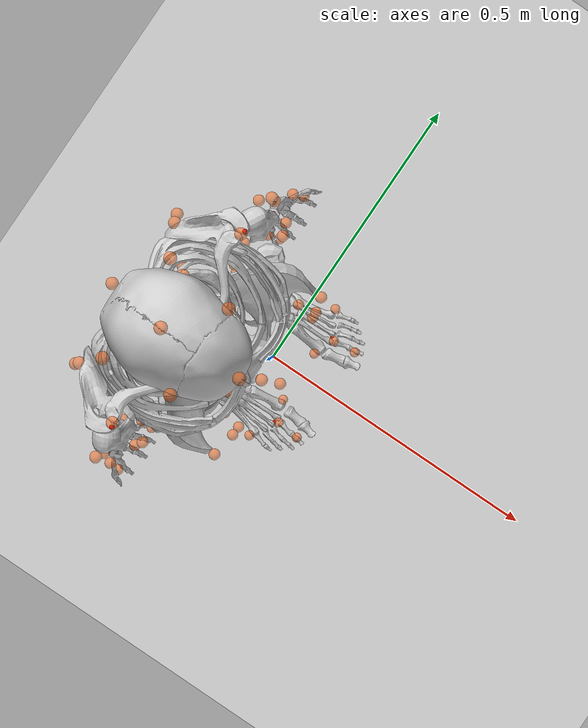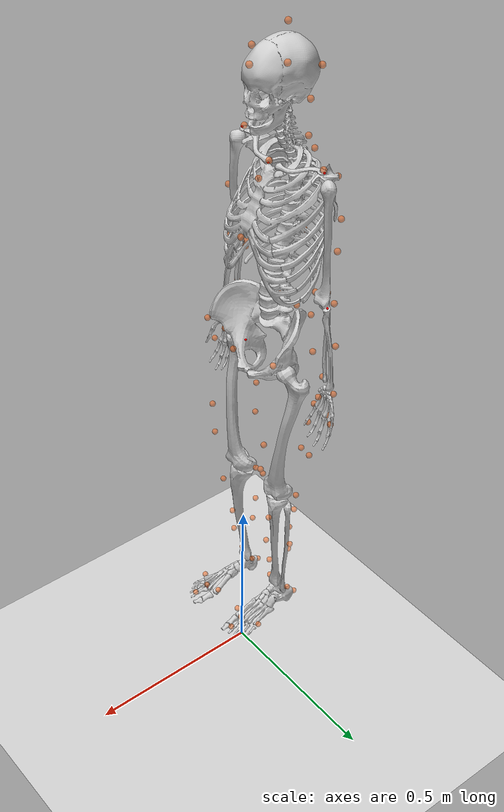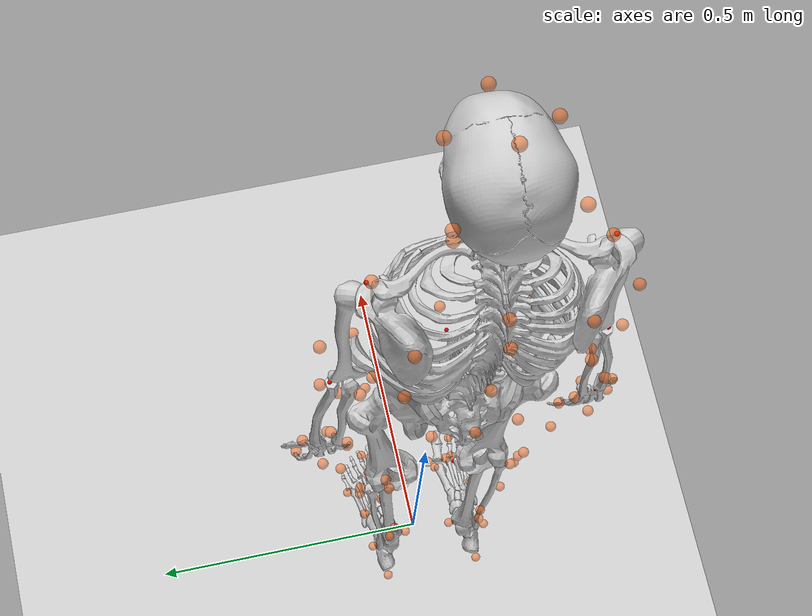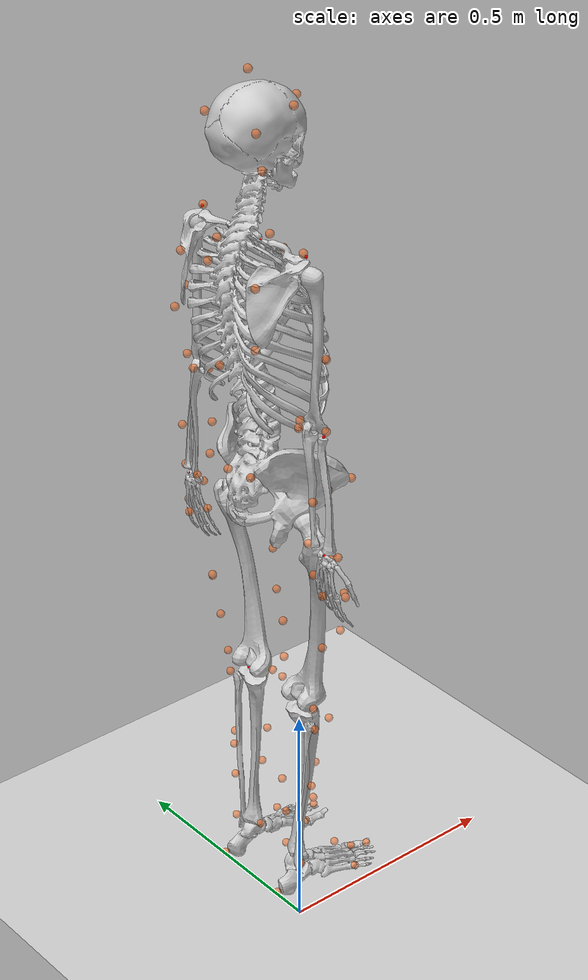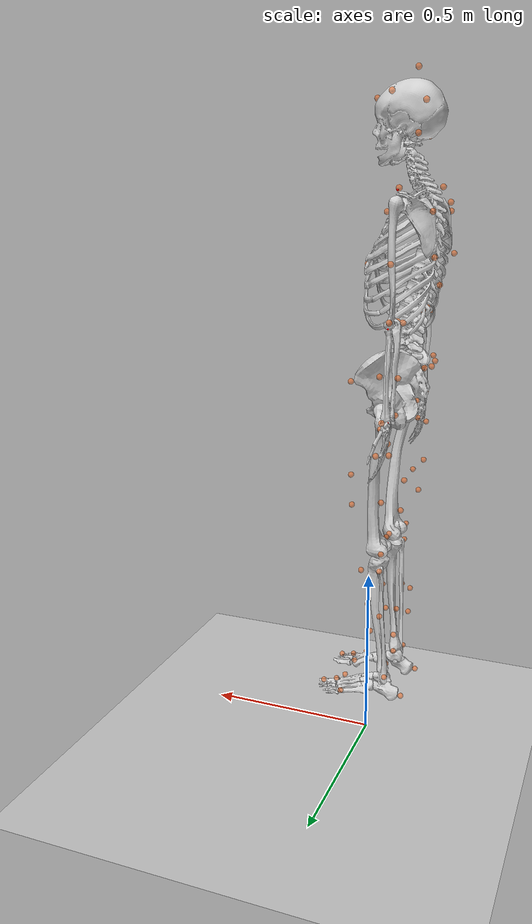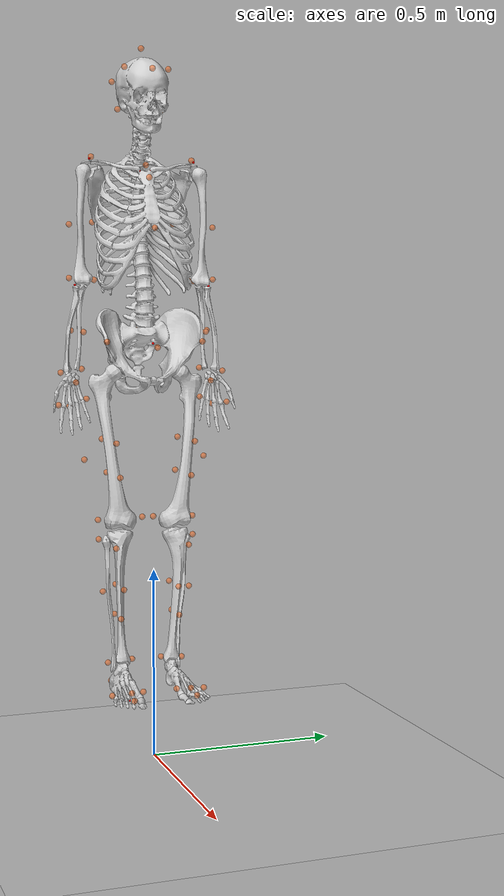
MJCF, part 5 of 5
0.063898996722797294 0.17939800078910692 0.043000699981276258 0.06112449629972317 0.19235700282225759 0.041251000875443214 -0.031333397764582001 0.26495799683747018 0.019838500294569648 -0.031792799414367336 0.26558800006723454 0.016613901107807992 -0.031883899404433431 0.26172099931153875 0.019949799303991926 -0.035773898513280146 0.26032699128622866 0.0213379001013657 -0.035610699242899481 0.2596159916289324 0.017296599729949218 -0.039118400100624819 0.2583239990158161 0.019893300540518997 -0.045127600927414059 0.27050100302283736 0.0348021988985521 -0.050513099016218532 0.27098199713160759 0.032395998233924965 -0.051568098302652243 0.2683089938599707 0.032356300450419095 -0.050451198491312133 0.26450399529698759 0.029959697508594035 -0.047926001574362248 0.2608780042706848 0.038013699748066072 -0.044997999433367249 0.2615380003903684 0.045242202940046113 -0.043389701115321457 0.26422100090269102 0.052359996362024618 -0.045194399931750874 0.26686199665531246 0.059500897642728548 -0.047701798087497888 0.26660499394549969 0.067181903209795987 -0.048480000696739051 0.261526003170863 0.073671901113156704 -0.045141900921157503 0.25562700300800184 0.077542999409114841 -0.037258498541660974 0.25544299649649432 0.078932998599174464 -0.029518098865333416 0.25409999085336582 0.080614595005468054 -0.022872998650243986 0.25377999765392562 0.083557102816927839 -0.019065498477209741 0.25155899345257565 0.089358502324640321 -0.017006501704284162 0.24545300807797527 0.09408590216852461 -0.014828499716999576 0.23801399897769565 0.096614398735429069 -0.011227500556469218 0.2315050021635558 0.095787004638384604 -0.0038938986639642783 0.23012399598636873 0.09269180300655129 0.0031888024070502027 0.22957599879827745 0.088889396836110524 0.010327199758360826 0.22902300291930827 0.086663002246613427 0.015828201821708628 0.22417300204824236 0.08904729617000523 0.019283401152483597 0.21663199569067654 0.089777997817110183 0.022722300914238863 0.20878000116965095 0.089675905057644445 0.02535720378152418 0.20428700027870222 0.084723002429736016 0.030247696765245032 0.20386399678985384 0.078603301047115742 0.035911898274721875 0.2043879998775821 0.07299110311740524 0.04218989853679974 0.20454200523937399 0.06905990084076602 0.048310496999548404 0.20049899945430577 0.067910794918770001 0.052470795724843082 0.19344200143664264 0.065797593591062825 0.055520298215159962 0.18583400100547751 0.062683705086407165 0.05652790043547392 0.18199800061414548 0.055995200965233596 0.058519796788043206 0.18451800125333737 0.048575597190220227 0.056466401638670907 0.19057999886243721 0.05105030144317451 0.054009296248527093 0.19199999759599867 0.055804902210563306 0.049689098969951315 0.19005900020939598 0.062110402246882877 0.045844303915310088 0.18942500172835958 0.068771697897360221 0.043854201515343381 0.19423799889018584 0.074130297610351184 0.04019089806566243 0.201500001807769 0.076250704136327882 0.036554002339337817 0.20861900236763015 0.077567895337093934 0.030706198937861633 0.21354299643129931 0.076933601526079642 0.023806200132309184 0.21380800322190002 0.080176396823839466 0.017803497547067584 0.21373100286266128 0.08565470025294189 0.012223497277758604 0.21457600142093941 0.091417797582547297 0.0091173990448621938 0.21977399906897838 0.095747200042533592 0.0064488988919802464 0.22762300485593284 0.095753402824251627 0.0028558983035027598 0.23461099593220952 0.09275690056462281 -0.0024221001541719213 0.23850900091635013 0.088707496388175766 -0.0098691007347712478 0.23898200022715849 0.089550698698340966 -0.017448900258386021 0.24032899764899812 0.091421399594396588 -0.02504899995668889 0.24268399959671444 0.092624502291946506 -0.028840198760873216 0.24893299173826383 0.091867697520338951 -0.029960398784320032 0.25569399913298291 0.087361798394909887 -0.030897300259555595 0.26084800318772045 0.081655800612614585 -0.033401698996154396 0.26128099386515585 0.074653299544739107 -0.039253098334355342 0.26008699675818842 0.069960999215866501 -0.046059999367713302 0.25996300114857912 0.06693870069565519 -0.051741197595419897 0.26051599071628168 0.061478001360806153 -0.052523401895108429 0.26471500745754722 0.054948900634387579 -0.049178600409373663 0.26786800438922981 0.048500899959571832 -0.051222299789876163 0.26571700262755965 0.042701200034452526 -0.051972900659511406 0.26101899978808779 0.049023900015407906 -0.048340601320510712 0.26101800627037347 0.056185299882204609 -0.043689800352620357 0.26041600391078673 0.061910300503367051 -0.039844302719325882 0.26365700469897252 0.067235094060153031 -0.038063899229551258 0.26466499795516379 0.073948700554870891 -0.037981800382094512 0.2606400021432948 0.080472796020670645 -0.036707297994908107 0.25593199498869795 0.08566329622411005 -0.033878900399615088 0.24932699984492496 0.088036002358897067 -0.025761801159172766 0.24718400554031777 0.087979398968864933 -0.018255999697794994 0.24537799666708032 0.087520299208570698 -0.010862598818440495 0.24476299754448688 0.087719096489725479 -0.0061595973414631366 0.24143599330957261 0.092676600953052093 -0.003118101062039024 0.23474500064767961 0.096594102690665387 -0.00040019822788524273 0.22697699845659275 0.097569897087466217 0.0034641000322175311 0.22156900029689769 0.094473696661397197 0.0094059020550712174 0.22037499980138436 0.089371396034573017 0.015468099150048011 0.22004499978736586 0.084305300342831499 0.022498899501152272 0.22002399933289069 0.081257797904076903 0.028011195863378212 0.21448200133456558 0.082381098384407714 0.031753900449899182 0.20714300078751297 0.082102202044195355 0.035492399465289544 0.19984299638251829 0.080811902599270416 0.038024203071120567 0.19484400041871414 0.076033697041914414 0.042348604972849833 0.19512099646563635 0.069511600360201792 0.047297598216896809 0.19632100369154121 0.063502199594638278 0.052506001969772224 0.19744399947069907 0.058226000665207112 0.058385797665775847 0.19306499894566004 0.055643202139517504 0.062293301121633539 0.18614600046562632 0.052258800638340298 0.061153301633887103 0.19137400178209835 0.050986800974603966 0.059305603258147654 0.18022300034959146 0.050965099672069865 -0.045615789204378455 0.2677399964991149 0.047860001565785917 -0.043324997998758726 0.26538299393906856 0.040727897005551655 -0.042568198437785122 0.26597399466176047 0.035055700077274307 -0.041546200335390644 0.26161100647358099 0.029093800979512755 -0.040764799923716018 0.26615800038841159 0.029715400010044066 -0.039399101007657179 0.26991100568664267 0.022957600047764024 -0.041919002351696551 0.26692000892146533 0.021111599589140127 -0.04445369815770709 0.26025299289698894 0.027324099036739536 0.063238999631773915 0.19013499765008096 0.046386998507054765 0.063148002014824553 0.18315700253575892 0.042034202745227109 0.067183000706690074 0.18365999973388011 0.043441897478313188 0.064716001124769426 0.1846459997508085 0.047688200170485036 0.065168997449846208 0.17931100012584619 0.048207998562189068 0.061608702370273931 0.17857000081268135 0.046077999759521003 0.059141899993620635 0.18862099853637243 0.041649401757441494 0.065420004480978705 0.18948599894442192 0.041950201279575279 0.059623304706650948 0.18326999824893472 0.043843299111681347 0.059771195422239971 0.19322300360916306 0.044943799727446859 0.058192701933457498 0.18948700071070695 0.046196198182048696 -0.033514599420146098 0.26200499967881269 0.016617200004490486 -0.035310498641817685 0.26893199787105487 0.01795879997702075 -0.034982098611662023 0.26586499416274773 0.021344900477925973 -0.038084901786937943 0.26515299946821286 0.016228799778328015 -0.038385300582771294 0.26605499593762477 0.024889201624049246 -0.039202502245247024 0.26130300725548555 0.024711100494404725 -0.041785899227514557 0.25937199206944478 0.022850201162869874 -0.039405899015669495 0.26059100147131525 0.016797498891259373 -0.043333700733749349 0.26247300970247828 0.0207639003990268 -0.042358001952384906 0.26985500796584433 0.028562499270501043 -0.045042701658060631 0.26756800414776144 0.026642798496590528 -0.049608498989623023 0.27055099268673349 0.036883099534978578 -0.049010600714941149 0.26848600318417598 0.042533300294608486 -0.047810301104748237 0.26857100426481478 0.030889000557601035 -0.051760600602423601 0.26739600023992088 0.036905399500630084 -0.051507598139653415 0.26304699002553361 0.036603301909159211 -0.046325000033909276 0.2634660005686999 0.025710100542759719 -0.046924601987675368 0.26051300863672061 0.032222199005784054 -0.043367500899119039 0.26147900381319017 0.034084901526733394 -0.048207800283023711 0.26072500410116345 0.044035299891423026 -0.051507897896430094 0.26207099409798323 0.042926299713521306 -0.044773599713094948 0.2616689990098337 0.039510997477367492 -0.044844800993827573 0.2612420029394073 0.051091498527800823 -0.048476699292369058 0.26078099294445506 0.05019110237763879 -0.043404299928259039 0.26480999452243287 0.046609101691128044 -0.042796701327477517 0.26386600226037354 0.057869898250689139 -0.044482600806075391 0.26097300358866743 0.056731400840586838 -0.045678600185880554 0.26721499819926636 0.053715798887272521 -0.049534298138497995 0.26757499113977018 0.054580302329070879 -0.043446100790384669 0.26792300426807575 0.064819797762951784 -0.041571698497100608 0.26490599255449693 0.062636399913145097 -0.049312799959289166 0.26753500315196582 0.06097069846915152 -0.052401498596770762 0.26438899520092946 0.061496996038241443 -0.044772202415544977 0.265559003176492 0.072127496746569528 -0.041225098755781821 0.26628099677552192 0.069806200414950517 -0.05102899902722105 0.2637659978821742 0.067905499706359077 -0.05026719847560604 0.26002399091277323 0.067226996344878415 -0.044949500601146754 0.25962600703262123 0.078391401913403588 -0.041550800679801443 0.26280699813446867 0.076425499490855378 -0.048208799001573238 0.25799799559706033 0.072636902141805237 -0.044095198780004792 0.25773400077636061 0.071681701074964091 -0.041642498028004661 0.25468099617401324 0.081383196324347248 -0.041005900664792684 0.25798100144085517 0.082206304802659447 -0.040874700983582209 0.25725800509194346 0.07535459838883303 -0.036084201181758015 0.25862200304576016 0.07373299936843429 -0.033389700878346258 0.25315500584141265 0.082295796175500063 -0.037504001503040847 0.25267099948427701 0.084709398572770864 -0.033231500847137087 0.25621900572267359 0.077524601219815831 -0.030436299634534793 0.25880899915991978 0.078316802216495035 -0.025856600627897498 0.25152200338403036 0.083438703437869077 -0.029600200080502827 0.25033200244785853 0.085307802877081534 -0.026607700091545151 0.25652600324654745 0.081080301698391047 -0.026905200456161356 0.25814200629176914 0.084644597673929636 -0.019031900549555471 0.25083800251166738 0.085474996345603654 -0.022159900637179663 0.2484840039598612 0.085704605725965249 -0.023037898460344718 0.25491499594701467 0.087248104316276012 -0.025414798526412992 0.25279599784676593 0.089909096925876522 -0.014889100526478887 0.24821600335448485 0.09092970445033996 -0.015085798192180849 0.2477899960899414 0.08689259944693041 -0.021323801348051879 0.24916100280227299 0.092395202907204363 -0.023955298807986782 0.24574099134669808 0.093919600286162641 -0.012505501412524416 0.2418500029848964 0.09525659567516552 -0.010572402006625055 0.24483700903780109 0.09197530089992767 -0.019494799061748485 0.24182099503296811 0.095663304167026078 -0.020575001061339204 0.23888500408418606 0.094204101294500936 -0.010102900958396872 0.23429800315444166 0.097411697619806101 -0.0078675005244088752 0.23828599803756595 0.09613589970109207 -0.015913499421478666 0.23518099595937064 0.095218598749781613 -0.013019299650251791 0.23686900227597535 0.092288297918615994 -0.0064220004174396616 0.22789500036442062 0.095867699333755815 -0.0052855008662809474 0.23059700156848834 0.097719198152187686 -0.0084990016914564103 0.23344000189409225 0.092747297424868425 -0.0055427992947716517 0.23578900466163416 0.089908596670576255 0.00067410105197446269 0.22688999717018693 0.091974399007871105 -0.0014137017833732721 0.22464999703542848 0.09540639636589221 -0.0011196009109373931 0.23271399920023511 0.089780394238624661 0.0019012996522715232 0.23547099930121379 0.088396696757563051 0.0073323004221828424 0.22634400160240514 0.087581798080067844 0.0050910991006145037 0.22364299844213192 0.09078329906131033 0.006211800586833181 0.23231499599378663 0.087678095029734351 0.0073314998987061963 0.23115100182157472 0.09202329846318584 0.014345300567165927 0.22582900037376724 0.085219003501172896 0.011467500311988161 0.22317399652835673 0.086116902508483056 0.011690699800405628 0.22765399749479814 0.090802601294974652 0.011040202503226374 0.22393699577353926 0.094378798602058944 0.019744496521672147 0.22083000197392949 0.086850397285798367 0.018280600554400183 0.22286099898967476 0.083415796444354026 0.015223603107889973 0.22012199701586072 0.092282000109586648 0.013643999185345711 0.21594800121661056 0.094145898858984181 0.02345629916156667 0.21327399850658652 0.087393004373596969 0.023802300981186804 0.21762100028693404 0.084604503557507954 0.018095799102953818 0.21244900359886082 0.091800696791175376 0.016742100710734561 0.21107999995479049 0.089427596395735692 0.027013901003049172 0.20568199885411781 0.086891601977505839 0.027587400768002625 0.21006399568131279 0.084842693971276029 0.021097698208567214 0.20769500040858196 0.087153002330876236 0.021934700898071185 0.21045600214125088 0.083386504701915221 0.029641802133947757 0.20093899787528396 0.082100601453968317 0.031375797448604088 0.20263400154193961 0.084040204701140875 0.026058698072227417 0.20712100017214524 0.081057305948215364 0.02793420335378239 0.21054700409316179 0.078027703603763751 0.034295099552181053 0.20088199874656038 0.075773004285266912 0.03374479751697964 0.19792600048303738 0.079056503172641387 0.031882800273499802 0.20746300470151219 0.075537501243810729 0.034570001053829659 0.21042899957524547 0.074522695146641338 0.039934001026254266 0.20141300251049271 0.070286902024993478 0.038453200378824999 0.19785000454503215 0.072870800392369803 0.038495601177567181 0.2074219997806474 0.071956600915108762 0.040630899980286704 0.20587600360475372 0.074631400579080964 0.045805500505318009 0.20205099734754611 0.065714800474589732 0.043784202465311499 0.19875300068883067 0.067110397740535566 0.044724100164295934 0.20304199975318621 0.071604996523022546 0.044450901269639284 0.19869500444779237 0.073119606722946942 0.051989400948269121 0.19801699762496744 0.064072597982304122 0.049256994396079209 0.19966700280613309 0.062056198666881578 0.048263096021140379 0.19617799442038603 0.069364503432236366 0.047628598441439046 0.19181799884221035 0.07019740678552204 0.055982195758234113 0.19065399898700391 0.061614101080984036 0.055574596783685759 0.19541999677256688 0.060112597966948574 0.0517115018531027 0.18890400043542871 0.066662600568965266 0.049401999075120342 0.18678200176096557 0.064906998186109066 0.059331701512007021 0.18316300065358601 0.058088199810407234 0.059217902521454334 0.18817499855108361 0.057019598713542695 0.052925096494821487 0.18415000034837822 0.060671601822064707 0.052899897626459205 0.18781699891807618 0.057894596889568266 0.062328801237314282 0.18111799967343176 0.052968800816749061 0.055858300681237247 0.18603300223470895 0.053219499914581692 0.055493104572180367 0.19561499865106952 0.054181900970829026 0.057865196253549446 0.19431999866643695 0.049586998704976314 0.051050499247403264 0.19393800119927301 0.060005002670698276 0.045980297709788266 0.19264699877040664 0.065774594714912538 0.041787199082120412 0.19212700097797758 0.072334702533566483 0.039826797261925749 0.19692799642146536 0.077697597354220299 0.036093305103797386 0.20421999579907463 0.079404602757788198 0.03227800300875381 0.21156899918702726 0.080030298369396333 0.026641304004184761 0.2168889976288097 0.079007398894673064 0.019636699539553572 0.21690900135907326 0.082334803600017173 0.013632299065435876 0.21710299874281985 0.087686499914328905 0.0079622986185224048 0.21824400079636547 0.093124299958478804 0.0044568008198270356 0.22343700169974373 0.096925694528136333 0.0016465014951415054 0.23117300226656606 0.096396404218755033 -0.0016457980946216334 0.23806700230271599 0.092969096107178309 -0.0066842989384812129 0.24154699320232814 0.088474402971631658 -0.014119898893557383 0.24221199752561645 0.088772998812222531 -0.021690900812681501 0.24382300502961701 0.090017399932723022 -0.029156501274413694 0.2464890038578888 0.090380699956064861 -0.032846198737352818 0.25259499489282561 0.088927796380116025 -0.033755500425333547 0.25892400293605061 0.083969304874347575 -0.034243801125524727 0.26343200071363565 0.0777472053412714 -0.036880601303668721 0.26274300392899325 0.071029403675489683 -0.042189598936958263 0.2594589914098368 0.066523399995778915 -0.047601301314833089 0.26071800383728133 0.061840901746949221 -0.052124602210000953 0.26099500743573162 0.055318602224515227 -0.051561000730046047 0.26468400251810115 0.048694396570935924 -0.045379400285258865 0.26887399946357066 0.041804300370896837 0.086639005079280004 0.14914400006003833 0.064381003395857561 0.085510002401862933 0.147510000074313 0.061924902477434075 0.081934001611330534 0.15600300110360929 0.058250097751719659 0.078718002511974181 0.1611440043047678 0.058751299095795968 -0.033866499148597941 0.24449099546097747 0.018696399242796546 -0.036218999933877651 0.24493300385868605 0.01484469955434916 -0.036724301670348548 0.23454699787614292 0.018872300103049321 -0.039280900992110714 0.23577400357191419 0.016001800053363744 -0.056135500897527807 0.24929500076698757 0.041055297522865887 -0.052391800794098664 0.24756800362392711 0.038217899404167539 -0.059462299494834919 0.24976499783862577 0.039801900652726256 -0.062570201025325983 0.24357400429839399 0.044483500062229828 -0.062554400470694077 0.23793799846644598 0.051205699636865179 -0.05926420142968547 0.23641099893391021 0.059190400704009931 -0.054315798481074234 0.237422997112612 0.065836599035250021 -0.051254502384293993 0.23991000331079054 0.073086593428280333 -0.050332600041585324 0.24127100205007407 0.081277697426292955 -0.048749199580030794 0.23320900125852723 0.088850498417584023 -0.047093101784205393 0.22614800309833177 0.094284197060567704 -0.042675698357031867 0.21893799725950197 0.096942093901814005 -0.034190498932332287 0.21675399489407748 0.098279995872499679 -0.027400400322734893 0.22270999826307308 0.09528489830621921 -0.019830299750394836 0.22229800037741304 0.097960700716789265 -0.014585800507744811 0.21930100026817562 0.10351099521701165 -0.011168500368870389 0.21229099896290665 0.10742600109536375 -0.0063584998145810295 0.19787500144901754 0.11323899979290364 -0.00096690189023539131 0.19128900186637371 0.11103399604409583 0.0069932985649384088 0.19064600126256698 0.10708499908664194 0.013358899303654578 0.19521500009570109 0.10069400390674549 0.021724899574704245 0.19561800438512894 0.099102803998582512 0.028803999242329882 0.19054699725100716 0.10171599767597857 0.033775197391603763 0.18214599952290442 0.102412002065356 0.038720296989188989 0.17328700218558921 0.10198999573825933 0.042069398756000013 0.16826201029508689 0.096287599313940708 0.047272496186916452 0.16867600048380502 0.089276098674641868 0.053958095670033041 0.16978700843399938 0.083613203683449447 0.061008297547399962 0.17089099968031959 0.078951593986778687 0.069018996837929461 0.1667659989020269 0.077885902586553868 0.074152000576010971 0.1588119995377619 0.075004099356149892 0.079557998870195726 0.15103699986473848 0.071658593266950343 0.082641996866771816 0.1547520005402325 0.066388103111968799 0.07263300007264252 0.15108500088144036 0.074284202741294561 0.075886000541203688 0.15330601130214891 0.066275905596491574 0.072005000611910994 0.15960400018414164 0.068706801010557844 0.068316998903207596 0.16159500093658871 0.073436403432208613 0.062352398334315509 0.15960999951897922 0.079799194722766226 0.062374197223615306 0.15635099992603926 0.082909803133146512 0.064476997506168685 0.1592279989688585 0.084893394817669832 0.059278803152917892 0.16726399874639905 0.087167998939535779 0.053978696911799989 0.17502100152003039 0.088479895355490265 0.046694503699256866 0.17951900025889153 0.088470598591799759 0.038872399803768561 0.178846000595936 0.091709499838762726 0.031695397177369196 0.17737799891301662 0.097105104232392006 0.027088397913591765 0.17626100137770126 0.10498200096654692 0.023276698534567524 0.18192100003829734 0.11002200337330048 0.01739839997583582 0.19340400318842405 0.10808199978191749 0.012576101460088997 0.20140299899510866 0.10606200598492271 0.005238001916760395 0.20596899949666286 0.10095599830865723 -0.0029878009174007089 0.20602300293565573 0.10083300180908292 -0.011107801858591558 0.20674700369245808 0.10263800214157896 -0.019099799288430749 0.20865699973248847 0.10492399845642736 -0.023922800744045881 0.21522700092682528 0.10589099322461125 -0.026816699784979671 0.22309800106605365 0.103103999561415 -0.029304401566447182 0.22980200214421814 0.098465602597408816 -0.033377500958584168 0.23224900014799682 0.091944499039568001 -0.040054199062219388 0.2283269993181935 0.08861669855541672 -0.047725899276043343 0.22917500207999003 0.085794100186478553 -0.055100596589807649 0.2315219981565832 0.0826636018465189 -0.059384500957105013 0.2371340065218383 0.078497094756881478 -0.059479200007638233 0.24059600201852044 0.072124999484187324 -0.058087701561442412 0.2450010017666448 0.064230296839174181 -0.055043800043930446 0.24256999938563312 0.056411000690985584 -0.054827697974784012 0.24016099660731455 0.04820139990273279 -0.056341899687790908 0.23919400499786375 0.040182999613556543 -0.056736797448083992 0.24111599132209521 0.032040601047242892 -0.052114000244521036 0.24579000591575556 0.027309098894846558 -0.050627198393773776 0.24957299981692932 0.029363999967720902 -0.048140200166995523 0.2472430027079055 0.031913798465857915 -0.048220301797834764 0.24295400572882037 0.031664901338203461 -0.044669799551625818 0.23877500140709879 0.026179698465994997 -0.043296100564847319 0.24247300523406751 0.027114400586987414 -0.043177401444974874 0.24698900340837876 0.026584901177931233 -0.045530602277130551 0.2487510068678806 0.023700000380258039 -0.047033589857656682 0.24464600121554331 0.022670301413759905 -0.052147300724837198 0.24288699893228721 0.036839197137416388 -0.05435789963880569 0.24421300539831375 0.050363500985482604 -0.057646499608624252 0.24667699107772018 0.051571898917948583 -0.06271439831053463 0.24443400063753334 0.058557001430528215 -0.06396440308965165 0.23831700284622043 0.065582003023619023 -0.060683799273019395 0.23474400074167651 0.07163699717182187 -0.053834903749952784 0.23404200469362219 0.076526997216898193 -0.047033398739396465 0.23332099535135259 0.080865199978805646 -0.0414086980469709 0.23446299402560017 0.086591498569367376 -0.038692900537308429 0.23301600049767796 0.094167003610538605 -0.036843699228963418 0.22663799580968041 0.099686800481263313 -0.034220999994439567 0.21852300092301985 0.10346699999547439 -0.029430701178282011 0.2157220018863048 0.10179200179227994 -0.021198398692867697 0.21375099809399639 0.10066500136351712 -0.013000900206640822 0.21268399957817058 0.099745800350743971 -0.0049649984851393566 0.21237199964780212 0.10072000647675083 0.0011063009235688923 0.20899399868043073 0.10547000305340616 0.0058812996524416055 0.19996400175157042 0.10972100080153724 0.011633400172861961 0.18776300290251807 0.11316700121873495 0.01656650091247058 0.18188600018964093 0.1089179943244145 0.023031399847128011 0.18162699823287329 0.10287799405692026 0.028629803969975297 0.18511700200836542 0.096105704624251387 0.036725201271832604 0.18571499902265873 0.093570997484180796 0.04400160158579066 0.18105899972028913 0.094503401348612917 0.049119496119711427 0.17313999998469629 0.093938099358593263 0.054092102902760945 0.16511700009033145 0.092219801008510696 0.057035699280768945 0.15940601038966415 0.086465200146930279 0.073447995834586347 0.16362900054484417 0.066968594020023808 0.083587995398818227 0.14957899949084738 0.067428793850748972 0.081498997897790762 0.14750700023096927 0.064759801289182101 0.08349099671062761 0.15186500973909031 0.059983499153371783 0.078788995352945479 0.15176198931067539 0.061374998248443675 0.077679001929006911 0.15703498931091683 0.058712399603023636 0.083770996796022915 0.15922201012006895 0.059735801248144288 0.086090996042366766 0.15351099851053782 0.062679198052347798 0.076604005605489411 0.16199800515927729 0.062344200749851433 0.080639000901037233 0.16007499361458419 0.064231204967086855 0.075277999914133253 0.15810800016653756 0.063630403395993157 -0.040744099076929531 0.24771199749364031 0.017715399831375388 -0.033225001134655242 0.23865600282825022 0.019119100319305218 -0.037194703737223507 0.23969100428310836 0.014330298759368308 -0.038258497623274858 0.2459689953459398 0.021811698734397325 -0.038271898334668576 0.24099200236024049 0.023168699622300157 -0.042805998918028033 0.2425969948429047 0.017265200936306922 -0.040295001299122758 0.23691799810533526 0.022186700578267722 -0.042805999880340125 0.23842200102662509 0.019219499497805905 -0.060500299060483709 0.24710099972162131 0.045092401437239492 -0.056804297946278032 0.24817599681550856 0.045466900634727136 -0.055574300729765852 0.24992200606476861 0.035043702470463817 -0.058332201974092251 0.24618300384667896 0.031431702357818468 -0.062413500232832958 0.24560200008831184 0.037634101952743068 -0.0595104012259281 0.24134499637413759 0.038237998608812364 -0.063335199083726174 0.24168500300987023 0.051250001315854478 -0.061497100838488056 0.24567700120344987 0.051624301782943499 -0.061073698197133736 0.2398239923068341 0.044748699609365318 -0.05757759899350498 0.23834499815281202 0.046260100477706144 -0.063725998993281768 0.23561899671780279 0.057805398767595453 -0.064640199611533083 0.23978300315189921 0.058135599930313434 -0.058643801555961411 0.23746200717260851 0.052736198624624933 -0.055216596300572435 0.23872099314077072 0.054317900741217076 -0.05835210285798681 0.23667300447932477 0.065453001629098909 -0.062891297583899636 0.23573298953683514 0.065083601363109422 -0.055398099463031342 0.23734800541395756 0.06025559658042276 -0.054908103164872407 0.24239800600939859 0.062157297895831708 -0.052519796708276278 0.2360929971467593 0.071262600792322828 -0.056387700999855767 0.23503899980829662 0.07125499545300637 -0.053646301226391579 0.2413920021204447 0.067722898207579374 -0.056492800640156604 0.24376800451730801 0.070310399020487135 -0.04833569842740873 0.23903199491844157 0.078013797405039803 -0.049920298716897488 0.2353249979459679 0.076202200263518538 -0.053480699351594413 0.24301800244859167 0.075921497070619168 -0.056021499133397185 0.23848599770657802 0.078076299391208956 -0.046743999564720674 0.23894100333134677 0.086137698756674042 -0.045101399103329755 0.23690599530843887 0.082606396507222055 -0.052496700157612514 0.23590500279412735 0.083592694788625285 -0.055982998793512678 0.23484800389477306 0.083965894553241216 -0.04467269962394519 0.23036299538893695 0.093454597028199207 -0.04282710166634144 0.23618800898151132 0.090357993067954306 -0.051212100670439242 0.22935599912041166 0.089618701234838505 -0.051259299533569891 0.22742399426079757 0.087744604101178084 -0.043413801277284315 0.22420100622925537 0.09785640237636585 -0.04066939977276577 0.22802499906397172 0.097088901439258551 -0.04688269924286928 0.22250299808877178 0.092824305286888398 -0.044051101077318695 0.22629300258901036 0.089695104739134807 -0.039280401345106276 0.21816300283489903 0.098584597987872932 -0.039059901205392274 0.2216110002458766 0.10075999554989647 -0.039989699523290102 0.22290499905276201 0.093154500461838347 -0.036094100910776562 0.22520700471993055 0.091862498912518964 -0.030968799914601171 0.22062400130845411 0.097036900670315979 -0.034245900905181072 0.21440900245092326 0.10144700016725884 -0.031845001150199871 0.22606700270958319 0.093082896719248284 -0.029126600523950032 0.22889100327942863 0.094398400816645439 -0.022750799233543072 0.21939099779958221 0.097200404166254042 -0.026166901258325138 0.21718200154769457 0.099080600619774362 -0.024600299277044692 0.22554399711972478 0.09636660177919823 -0.024587400714380515 0.22628600595076093 0.10059499811432324 -0.014918899904245105 0.21899300031384267 0.099213400739812801 -0.017919399463440688 0.21605799989664137 0.098678300906043528 -0.019671599771332048 0.22274299662072589 0.10224100549696546 -0.021707799380557124 0.2194850000948016 0.10490299928384628 -0.00944020010568959 0.21582599623433024 0.10449399648150676 -0.0099740994677199029 0.21563699761628502 0.10014299819197593 -0.016477798498916073 0.21590099700764903 0.10635200028375992 -0.018635101229394917 0.21156700445478877 0.1072970020029145 -0.0057926009355586247 0.20867699717723948 0.10804600461974773 -0.0041978014557884627 0.21244700189253568 0.10511499849492431 -0.013269999769564871 0.20789599683400745 0.1083900022721012 -0.013837998248408322 0.20506299558082336 0.10595399670031209 -0.00043689989702121168 0.19442199816608835 0.1136989933878504 -0.00013899968992965581 0.20440699860296346 0.10889100050540855 -0.0067602991888354291 0.19474399826433569 0.110554997850007 -0.0059787981043773596 0.2032579951706856 0.10317300083299888 0.0048399983931042131 0.18793300280443032 0.11100100010383737 0.0055812992160564337 0.19107199788089385 0.1136739967144194 0.0014357995034349894 0.19377299853835356 0.10732299887074392 0.0022222006400207518 0.20265299887722982 0.10100299867095974 0.012469899800998632 0.187649001905906 0.10631999888841509 0.010631599919750238 0.18453399864055606 0.11040299951250079 0.0080619991661543527 0.19821699887649097 0.1016099968785974 0.010841899576557261 0.20248099888611487 0.10093100404649524 0.018574897673167803 0.19192100266367035 0.099662196786886606 0.017854100268647029 0.18475500167705958 0.10483200102981741 0.016482002168066247 0.19935499722435995 0.10010600317230695 0.018335998136314046 0.19829800388105573 0.10507299811555731 0.026803705172578123 0.19220499710592936 0.097462299164400745 0.023573000469802895 0.18857200069096186 0.09794109764780444 0.023601499944117386 0.19433700190642961 0.10347200348307781 0.022974600966396138 0.18981300181562694 0.10647799470098832 0.033848896933218749 0.18730000025542723 0.099565202396061106 0.03178790487321146 0.1887129972808998 0.095816204484674275 0.028428497534522527 0.1859829968680202 0.10460899766309632 0.028501899647625707 0.17901400133343778 0.10772600194577964 0.038736397841711324 0.17921900046355918 0.099644304372599593 0.038953595438976509 0.18427999935930847 0.097159899248069614 0.033952601275240891 0.17568700053319028 0.10543400048898269 0.032426700610439375 0.17287700027483585 0.10292199642040434 0.043688699958077115 0.17080299903165527 0.098726501587301577 0.043985196234091341 0.17618000011759324 0.097044196201385616 0.038692899304245888 0.16916898902847707 0.10101300098224686 0.036843705449082588 0.17446900017619324 0.094639197833456756 0.047089600088819641 0.16579199901656125 0.093027100490509593 0.048718797686768948 0.16818300124275407 0.095326697872335275 0.042164899459228251 0.17154299968129713 0.092137094769941183 0.043958003896284591 0.17575700102854538 0.089309198635491277 0.05220219774194413 0.16554098870147557 0.086138300034288823 0.052081497280862657 0.16263300087973118 0.08984459955059082 0.048971700157401647 0.1727679989757471 0.086533303523571067 0.051498300960119141 0.17662999910041474 0.085450902600549508 0.059121199126559339 0.16654799821364349 0.081605893686671802 0.057194501066982657 0.16255299972739998 0.08294200350284614 0.056296403082257217 0.1737409991482177 0.082264104792907328 0.058881404993560225 0.17215899980361768 0.085089902446053578 0.065785000921143491 0.16807000161665273 0.075602301133658179 0.063883997228417491 0.16407999014568483 0.077321900304607283 0.063767999318486979 0.16929000996343732 0.081550200871823977 0.064575003641462278 0.16449299837488082 0.083663206238054413 0.073641998389330984 0.16414399921712516 0.073532501230973643 0.070032999729737269 0.16556499872495076 0.071681997077714193 0.069559004878899058 0.16164499577996458 0.079495202732435336 0.06948500137190429 0.15637999998872051 0.080659998797167634 0.078464006357305618 0.156399000385369 0.070395900789502752 0.077087001263573027 0.16145500869649118 0.068704205000519353 0.074578005879153406 0.15344600064753885 0.07627929572304161 0.077249002250837653 0.14921200005729626 0.069307400497062938 0.06753400080996097 0.15345300938402581 0.078911803246791257 0.067225002540564377 0.1570829996238445 0.075788296722074766 0.071793000217538913 0.15501300086753653 0.071157797539870324 0.059219801028802838 0.16214300980914473 0.088756300669601634 0.054084696708512819 0.17019599998623811 0.090489901099503736 0.04900839978763364 0.17792799860966532 0.091649800817992247 0.041749100608406836 0.18274699929713065 0.090947502549986861 0.033681400893861145 0.18191500068287822 0.093952399868749717 0.026812100696459999 0.18043900257418574 0.10097099716672861 0.022040201071592238 0.17909499905059476 0.10711699972206477 0.017613299987548622 0.18491900014089133 0.11176600258599724 0.011723799385648073 0.196624002655372 0.10927800378950552 0.0065003989875042478 0.2055209971526874 0.10552399985084331 6.3301146746241863e-05 0.20915800334337725 0.10101900356075794 -0.008024101473858956 0.20932800462848838 0.10047200123872488 -0.016187099497352263 0.21024799589077986 0.10183300404867524 -0.024259099270929736 0.2122369962255341 0.10356100069490613 -0.029080201188330913 0.21888299800691863 0.10396400463034523 -0.031768099188740774 0.22669100225033695 0.10083199989755272 -0.033844200056458586 0.23337199855203744 0.09592490144293063 -0.037606001570483195 0.23178900468729563 0.090193503086903229 -0.043669599984893621 0.23098399640586836 0.084935199651993337 -0.051047101555826396 0.2317989987808719 0.081439099770434592 -0.058088402225027952 0.23368400127422601 0.077378201675356736 -0.06171120123690485 0.23643099902263248 0.072548802504361909 -0.061836298075929108 0.24301299732826748 0.065536097123349804 -0.058466602323112571 0.24509900574154692 0.057955101581320764 -0.054258802042773863 0.2419230041449813 0.042233898178611506 -0.053650697517393292 0.24571499894857179 0.044264999717698289 -0.053729500103289835 0.23955399917301573 0.034983000401813028 -0.051533501135836629 0.24146899807658379 0.028062000568269654 -0.049497701720909587 0.23940300980823509 0.03045200067726429 -0.046846001100073649 0.2405120054352427 0.02353120082519668 0.099701993643359701 0.12414999834511684 0.073652797198317521 0.10048500854168711 0.11522700036627317 0.077065102309584715 0.098542999022987188 0.11133999858009511 0.081221401413751296 -0.042103400498079098 0.21958700035372763 0.017678100776265235 -0.046359900092989716 0.21862400142693156 0.021917401637658908 -0.04883900012003306 0.2168790031360292 0.014327899241302422 -0.048776601086833987 0.21374099917831851 0.014551100898005679 -0.049220700416674285 0.21143400099157311 0.021238799830762368 -0.051791200392420439 0.21373900230421755 0.029318399432709294 -0.055023597729727397 0.2174969976105145 0.036804000900558867 -0.058952001282316452 0.2203259981886187 0.044512700719627971 -0.064662601482880139 0.2179740011534243 0.051231998555634213 -0.068543800811405375 0.21276899917413589 0.057710899198754481 -0.070878001678495811 0.20547700283910481 0.063353499869472307 -0.067642399748338689 0.20455800178480382 0.071582695287944129 -0.062316400634541524 0.20601700005422535 0.079056597318138272 -0.057242001085062388 0.20908700046948819 0.085914798404698095 -0.055712300979293278 0.20969600078930534 0.094165698134631784 -0.0541491975360536 0.20342499621140159 0.1010520013284493 -0.050229401083674852 0.19546400240827272 0.10516899827463398 -0.044395900344614249 0.18797399959605338 0.10662900223474206 -0.035966498561712724 0.18632599738939423 0.10574699829042078 -0.026789098626977849 0.18532799773277728 0.10627800328738013 -0.018336599593154184 0.18590000073051313 0.10905300224019249 -0.011497999949918276 0.18422499697850589 0.11440999976618396 -0.0068213990880412311 0.17737799749896285 0.11831200441019817 -0.0025036992343840376 0.16882301065328972 0.11968000322663966 0.0027301998384487987 0.16007499442926273 0.11910499462253243 0.010584198954550981 0.15758499110512189 0.11527399563877616 0.019382601576769225 0.15777700014034132 0.11263500321546212 0.027949795657873609 0.15924899076082785 0.11123699666979252 0.036330701635512268 0.15815701131048884 0.1129600057410647 0.042409100623217032 0.15016500029365584 0.11369799902255436 0.047785597837822116 0.14077500096271398 0.11254599455491399 0.053063795000329969 0.13190399959311813 0.10958799419366498 0.058898897633903775 0.13030200046602622 0.1022080032568842 0.066639001636534176 0.13175700046895963 0.096768994952093235 0.073297004398721902 0.13450100086014857 0.091748994456342436 0.081231998499824515 0.13358500023874706 0.089144902667529613 0.091584004494353152 0.12474899861321728 0.088976602460903415 0.096679992546865268 0.12285599960564816 0.084588702132347676 0.092927000320157327 0.12833099867437855 0.081431903592135063 0.088874009771071349 0.12825800000363416 0.07917320289374831 0.092596998360009952 0.12070699881510169 0.07761160500015904 0.08909099512756867 0.11749699849004289 0.085075899415341882 0.090659996655133357 0.11502599757614693 0.089220705461413266 0.084883001382184076 0.11737400198376766 0.09332939868707936 0.078851999412416968 0.12492000109185494 0.097628802871723666 0.072863000239662995 0.13340800069009393 0.099996296993320674 0.065858000684614906 0.14208200004218316 0.10051400165893763 0.05685019793658018 0.14330299959129753 0.10112899998949748 0.048185602884570904 0.14198699881848606 0.10427499936544204 0.040323401456855042 0.14066600017827444 0.10971300082580002 0.034418502227196356 0.14253500148194395 0.11654700555418054 0.028976299474040464 0.15123799094909704 0.11804999969093341 0.02383609924555926 0.15953401081984772 0.1181050021442986 0.01813529972978389 0.16714001064137959 0.11592499766623179 0.010306199061003688 0.16927201133788469 0.11243999623478747 0.0011096980215592465 0.16907300159371427 0.1121760021661497 -0.0076758987491197927 0.16833500859450143 0.11394199782979821 -0.015635800571197966 0.17066600012245622 0.11698599783578989 -0.020428499870924193 0.17952400104849262 0.11645899605643933 -0.024747999574210651 0.1874450022567373 0.11420100422257033 -0.029317698773475932 0.19374799855107078 0.10941799886189307 -0.035534199466574636 0.19683800230862131 0.10256300335467251 -0.043598799341318585 0.19525500287382663 0.099284004041703594 -0.052435499160883997 0.19403799912652259 0.097844696201187659 -0.061780398223707705 0.19432699482002941 0.096232201206562756 -0.066457200606620165 0.20249699863924681 0.092405103875960487 -0.066738499404749047 0.21063100267317142 0.086288495778032048 -0.063407901167000347 0.21661800053205721 0.078786401841825032 -0.061091199927611667 0.21448800159015685 0.070173501080965442 -0.061526601623264537 0.20892400352098067 0.061291400279883022 -0.062997299796385936 0.20766100380160463 0.052284198055255526 -0.065236697331938126 0.21042699698452555 0.043754500617119683 -0.06531970156420111 0.21694899741558821 0.035849300882977199 -0.058703200429645969 0.22226599991666179 0.02981929988856542 -0.05452150147275775 0.22283600048026092 0.023105499819344778 -0.055388100685805436 0.21834899751292686 0.023538098690172878 -0.059654599146252291 0.21343799517920153 0.030199001503088366 -0.059289900087690056 0.2107750009701283 0.039151003060329807 -0.058492799508858023 0.21116499979685271 0.048006099695569363 -0.05931579793731509 0.21485400088921364 0.056998300771894078 -0.063254199613677148 0.21944999591251019 0.065543503790227206 -0.06904650058181741 0.21594099860444266 0.072905304580447888 -0.072382300983059894 0.20760999767851501 0.079143198957351446 -0.070285696301594508 0.19903299823066151 0.084678202124592802 -0.061726000587254914 0.19818600030566297 0.089330898819422452 -0.053306900698637 0.19970099798703184 0.092944000088892337 -0.045836498073535938 0.20210699580446584 0.097264899873883079 -0.041011400829026608 0.20151299850471499 0.10412299591106583 -0.036970299743902792 0.19510999957279446 0.10940499994680492 -0.032138599079716203 0.18595499981353544 0.11288700014796982 -0.027151599823589452 0.1784830017149541 0.11342600069602846 -0.019123199768839482 0.17574599751519623 0.11145999918065726 -0.010056200317385201 0.17540900054811301 0.11111399938150718 -0.0014297015570938346 0.1763050005396973 0.11191399956523614 0.0059856003497570903 0.1745070002075115 0.11587300124230461 0.011321798948011079 0.16705801128996908 0.11891300592083996 0.016482101347652874 0.15784600097538767 0.1197609941067078 0.02176689846997441 0.14921400020275197 0.11884900235340404 0.028459601998146268 0.1476089997708436 0.1131440047921066 0.037067101756373351 0.14841499983926185 0.10907700163548824 0.045397900745861537 0.1499580003439562 0.10597699599494542 0.053999099116898285 0.14845799966867165 0.10587800559085923 0.060203703108570303 0.140100000240692 0.10577400115502097 0.066450002678447903 0.13094400061496933 0.10445600335911204 0.071898000796791761 0.12263599928907795 0.10075899961766215 0.078078004767878281 0.12152600097615693 0.093123501640194034 0.084809994097520214 0.12429199844405445 0.086360093517927033 -0.054571499568766835 0.22206600180546227 0.031109699765519683 0.096539996034166672 0.12409499811328703 0.072605002304999555 0.098693005793997993 0.12663399957450047 0.077469296600889803 0.10068599071290135 0.12130299975935596 0.079959499460043326 0.10041300609567567 0.11969100237614147 0.075439106423086266 0.095934994490242967 0.11927599981457357 0.074025303366746537 0.09652999969382646 0.11301099987530325 0.076649505158621817 0.10097899375808143 0.11548200055644406 0.081546298911089096 0.095279998687371165 0.11289899823044844 0.084674500178046494 0.092797003068920747 0.11514699882914534 0.080677599447587914 0.096937990594585313 0.11730299893778648 0.085731997745708138 -0.044278698173408106 0.2159120008151782 0.020223099977838017 -0.045068601177007873 0.21293900253121983 0.016144198486774886 -0.045331400783150767 0.21860800356118942 0.014098699712326615 -0.049601300422957489 0.22292199812228602 0.016926999653840327 -0.046002299802703685 0.22192699997002036 0.020333299143820073 -0.050834900883590078 0.22243599906920258 0.025066300001392705 -0.049670699638293375 0.21832699878014411 0.02503520134862074 -0.048551397980213379 0.21461699999622413 0.023955199172296635 -0.051603899440281931 0.21809199695500431 0.017885800636941573 -0.051798000914029058 0.21366899957053848 0.018588399318250865 -0.053244397838617646 0.21126800012233099 0.026934400628923397 -0.055626299355953368 0.21384400043258184 0.024366001027083847 -0.054523900976575695 0.2130269994468636 0.035325697095199976 -0.056658001378629641 0.21103099808428744 0.032896499173425242 -0.052709998775136074 0.21798100217540334 0.030481399616334431 -0.05660809943114406 0.21666900003265582 0.043343801618145335 -0.05673869846967905 0.21231799861169071 0.041520699581741594 -0.057024502156176632 0.22173500060300849 0.037947099873880223 -0.062185998732508213 0.22137599670916791 0.037063700701470269 -0.060575300013162942 0.21894700061475375 0.051272399220454838 -0.058017398321485919 0.21547100201904795 0.050078002108691073 -0.0631966022122539 0.21907600472855643 0.044246598060324487 -0.065631799402366603 0.21498899725750714 0.043801597690300516 -0.066334400710190949 0.21754200512259597 0.058313499050082596 -0.0619621003988515 0.21853999765250548 0.058362301776927583 -0.066935699859593273 0.21358200124062304 0.050829001758002812 -0.067015798855848296 0.20889900398867994 0.050531396936340844 -0.070460899722775944 0.21098700057947134 0.064521093784809871 -0.0680672004631869 0.21798900032971374 0.065694098153322444 -0.068848300512330707 0.20770199902161773 0.057061097676214742 -0.064839799335025622 0.20628199768679795 0.058747898309868436 -0.072735696312379722 0.20391699929637758 0.070203196554315853 -0.072290000053230857 0.21012800286553829 0.071712601005897894 -0.066564599487182713 0.20462799985757102 0.06508620411031571 -0.062901198325739954 0.20940300163422115 0.0676757011129685 -0.067131399895606264 0.20272999968077782 0.077940705462991075 -0.072485402985764891 0.2009090012495906 0.077628795867578926 -0.063247899719373585 0.20771799903551308 0.073563096743120351 -0.060779498762909362 0.21293799848487599 0.075996402277358377 -0.06021330094942598 0.20403799702918496 0.084172399131215561 -0.065028801509596751 0.20025500327009821 0.083934395320787905 -0.059530701221667343 0.21105799848920487 0.081203200340692352 -0.061948597577051123 0.21419499892661781 0.084563200250372367 -0.054121901486614693 0.20706400091592053 0.090111601367607125 -0.057159202859067088 0.20166700276431965 0.088817302046835148 -0.05929109864054169 0.2119740000549894 0.089720803004811431 -0.06357459890496453 0.20790599455585873 0.092167102094488418 -0.051291798665582894 0.20733199947172126 0.098070800875048811 -0.050392299868372431 0.20494099769557045 0.09392820394197661 -0.059204300900696505 0.2063759975876906 0.096904302425406624 -0.061520398515503588 0.20001899806653028 0.097502298461291104 -0.048645701380195749 0.20091900214280195 0.10435800419716913 -0.046358400184642913 0.20471700432890233 0.10128099929829562 -0.056025698283442948 0.19685299642913939 0.10191000458082961 -0.056225798091612739 0.1921050002086841 0.10053399624220186 -0.044233201405208124 0.19284899872557787 0.10797199984405517 -0.042846698536370444 0.19796599672805443 0.10697700360097576 -0.050348099352461123 0.1901869969484779 0.10389099728268592 -0.047072302411100803 0.19182000284185302 0.10090900397923461 -0.038600500454682753 0.18463699986122914 0.10927299870201783 -0.038331496478622752 0.19019900032521869 0.11043799697212653 -0.041504500826652281 0.18926999693870633 0.10346999788187178 -0.038163700470949143 0.19260699716561253 0.10163000381138088 -0.030208099760377673 0.18226000236488413 0.10800900426576419 -0.032816399189326724 0.18161099839974157 0.11149699949837445 -0.032352900481533838 0.18844499903866024 0.1041269998060277 -0.029654300684363401 0.19221400371092495 0.10526000295824932 -0.02122830031629384 0.1821359986237083 0.10802500234011365 -0.024651499069820927 0.17904699610557781 0.10980700031546971 -0.023995899256366811 0.18908299752521968 0.10731200131459147 -0.023320899719145676 0.19074100323293458 0.11142699849696155 -0.012693099989974903 0.18252899914468343 0.11039499808370816 -0.015603001695690438 0.17856100271876271 0.10978999658768096 -0.017403999401469358 0.18769399841761908 0.11301399543039135 -0.018785999762439911 0.18429599847144648 0.11602199541310781 -0.0056642983394123705 0.18102499843506933 0.11524800050914805 -0.0070521995657190761 0.17944199655560464 0.11135199424657673 -0.012774100178433983 0.18069099845270273 0.11751099602184339 -0.014458098936848168 0.17559899800601661 0.11823600001047821 -0.00087810137922549026 0.1741049993035659 0.11881200329193201 0.00018819936598080117 0.17787500086521477 0.1157410025507583 -0.0085168008445055243 0.17216100094784756 0.11917699586769863 -0.0099116012281920528 0.16725301191028483 0.11793900326552095 0.0035803001444922175 0.1656879885951221 0.11981000092743578 0.0050677003721883015 0.17087199930314509 0.11885400015146322 -0.0038031994344651645 0.16398000898172779 0.11846400046644877 -0.0019436018863256545 0.16527300087777605 0.11441399740404729 0.0089963986417448804 0.15649501027473886 0.11932199951026971 0.01010760091415573 0.16160799421663571 0.12003100119545362 0.0044748015537743177 0.1611939990233224 0.11514900088449624 0.0073310003442644666 0.16500599960266824 0.11278200406785013 0.016738800757144758 0.15391400852020884 0.11510600104181902 0.015347500909870342 0.15273499948962541 0.11928799469340383 0.013339402309491221 0.16137699717937412 0.11286299968882087 0.016260100397683091 0.16549099921578178 0.11249400086172313 0.025232697242953982 0.15477398856953181 0.11179800431914068 0.022774999306496593 0.1505619996966425 0.11444299836448789 0.0221594990170314 0.16202599999939957 0.11223100451783005 0.024133098292986523 0.16369399157523976 0.11546300102108059 0.033942798409533688 0.1561940001265256 0.10999699944557907 0.031324097893692955 0.15148000050386654 0.11082099929735825 0.030170300462711304 0.16099399499732756 0.11440800348905505 0.029900903074746653 0.15653201033861872 0.11695200179404484 0.042334700659413846 0.15515600101470414 0.11083199487199837 0.039668396895061582 0.15327999915545318 0.1081309999275796 0.036312202208482962 0.15326699940999286 0.11567100214400518 0.035605602630196902 0.14754900097685961 0.11690700068403237 0.048471897940191327 0.14660599951819428 0.11132300041323674 0.048001900237052829 0.15187499893297038 0.10829399899827669 0.041706600503339221 0.1443300004957859 0.11509999877844601 0.040262201851889036 0.13920599989649937 0.11447700400139446 0.053435201377585263 0.13776799995062314 0.10949199551528564 0.054331198877991704 0.14327100023079106 0.10859200026411797 0.046222599039127107 0.13572400028664264 0.11190899889833818 0.045929299880282236 0.13753500031002616 0.10702300171364132 0.059429402383371306 0.12864900192951942 0.106941000102272 0.060055197635524617 0.13417299999454999 0.10710100122859809 0.052685096860351659 0.13363499870075787 0.10479000579869657 0.053670303866265368 0.13899999985231412 0.10145199819262375 0.065412001733022571 0.12684700069010321 0.099657899773995945 0.066137999195854322 0.12525899820254646 0.10432299788009268 0.060326897289983583 0.13520199951854736 0.099326604841979971 0.062895999025900845 0.1398380006304267 0.098747093324407564 0.072472998976630398 0.129104001188 0.093615197042849291 0.071016998251792515 0.12442600117975441 0.096196602478276744 0.069111996718994498 0.13642100032654844 0.096125107036004465 0.070544998484257451 0.13946700086410432 0.096631993001788791 0.07771899531222741 0.13266500011523338 0.087248197448053219 0.079082998415506575 0.12640600080320505 0.090454304297786628 0.076643000863872379 0.13608200129121048 0.093457605480891937 0.07793400147897038 0.13088700024885577 0.095900697534612361 0.086477993555550456 0.13103699966449731 0.084929396370814522 0.082717005880403274 0.13074300122021706 0.082802700671372187 0.08424899582717732 0.12785999925762345 0.092284902702130148 0.085801000200445482 0.12187500076078892 0.094124505657881913 0.091915002702374252 0.11935499704947358 0.090136807078941089 0.093993005080152264 0.12591300007260317 0.07569599755941829 0.089365995311218999 0.12254099974146102 0.081985198961746747 0.083721995255767998 0.11966399917023637 0.089070899549910668 0.077888997241785787 0.12008900022987709 0.096920801299317419 0.07299199844304384 0.1276620007899498 0.10148800491447586 0.066440003348800888 0.13686100023697564 0.10300399995793472 0.059744099583742792 0.14522500045767847 0.10321799779060466 0.051128903545449481 0.14663600034403321 0.10349900033638394 0.042776802953971578 0.14506100046217771 0.10698599806118103 0.034796799269774449 0.14385100021993333 0.11191799901796702 0.027768897183483847 0.14621999938130067 0.11769100341026313 0.022910400201020208 0.15421299866169488 0.11915600060245247 0.017586999621246737 0.16315501064548374 0.11869400259977787 0.012002801120487041 0.17099901073583343 0.11594600125463934 0.0043342985639924772 0.17308400017731326 0.11212099725854416 -0.0045252013137175437 0.17218099858915001 0.11178299486046243 -0.013357399059770552 0.17188099996421299 0.11297299897312787 -0.021702099241059546 0.17495399840805945 0.11524899789708078 -0.026201300171268378 0.18281999845516236 0.11469999945381573 -0.030790001231529758 0.19054200108640534 0.1122459998719685 -0.035421699312056472 0.19843499525798686 0.10660400152287518 -0.040899798038324088 0.1995989975094718 0.10014700174668492 -0.048702601818244678 0.197574001382889 0.096442500185822413 -0.057413099612748292 0.19619600010132493 0.093961297027547241 -0.066651198110146054 0.19657099978078535 0.090967798512492551 -0.070060101035213956 0.20476400061813255 0.086129894136812948 -0.068625202127503698 0.21331999865658363 0.079809004902906322 -0.063827400146381857 0.21805099952685575 0.072377198224900879 -0.060347398141933767 0.2137280029249235 0.063749301838627939 -0.060155301712528753 0.20986200099684588 0.054677800748615259 -0.061273500312431367 0.20940999759488549 0.045682700063620657 -0.063197101503271874 0.21231599980235399 0.03668400058929084 -0.060476600467987113 0.21792400251926697 0.029114899924811654 0.098961002837467699 0.089593999332431049 0.085222401317842852 0.099320002067577268 0.079285802133939751 0.089068503951738959 0.09719900309430328 0.095520995722088359 0.082692303305966761 0.09619799986178508 0.079493002101788321 0.086703700742781553 -0.045322699146824776 0.1896280018875402 0.018841099960896918 -0.047128900984659355 0.18943400289601015 0.015387000163291585 -0.048696098828635709 0.1991160019284372 0.015286000818601791 -0.049164998978008495 0.19619800270460969 0.021770701220563019 -0.052287999972923799 0.19247399832419471 0.024947599773265026 -0.05615450083365206 0.19592000143021709 0.029878801411977823 -0.062062998607564035 0.19726700337888609 0.033954999263804027 -0.068688500940773084 0.19456200102237736 0.035968800316765068 -0.073497198429430977 0.18871900091498056 0.039667597549128179 -0.073202397994592494 0.18358999915640603 0.045473501766098906 -0.071522901818448531 0.18063699811920284 0.052134799042025851 -0.070343702970272731 0.18180299914224538 0.059494997346663865 -0.070254198819976549 0.1845889991596987 0.066453796918938546 -0.074943198379328002 0.18486500235576162 0.07266209657728348 -0.078602497250710252 0.17932799855686651 0.078381298420790932 -0.077599102883039534 0.17153800069845368 0.083747499502956096 -0.071821600141283304 0.16724699812875274 0.086885403328832447 -0.064574902356817204 0.16822500903799972 0.089457100430975448 -0.058150398890493643 0.17157300310429077 0.092514995617617127 -0.053418999702220166 0.17439600154570931 0.097803797682401952 -0.052232499080565292 0.17431900037563805 0.10489499995560653 -0.050495900180273279 0.16656099293501955 0.10961200104665228 -0.047934598935764655 0.15801101171526485 0.11298699752430243 -0.042964301385198723 0.15325800057940661 0.1129869983102236 -0.0350871989381717 0.15281798874016747 0.11232400130707115 -0.027523300478973091 0.1547829999556338 0.11310700182851645 -0.021163199379324617 0.15636899827819681 0.11668700079364351 -0.017485799000853935 0.15351499865543736 0.12229900004037403 -0.014747201226665462 0.14591500077807404 0.12502700512003323 -0.011081200217139693 0.13653399917035067 0.12689700189580849 -0.0058472999169674319 0.13088899941580287 0.12492299601152151 0.0011850984921299294 0.13127600066020537 0.12213399943071056 0.0084450000901088434 0.13328399997035476 0.12076499938022633 0.015521401295703518 0.1340530007503111 0.12206000408774055 0.020598100522920017 0.12912500044923567 0.12608100618653881 0.024638501244753065 0.12086700049881702 0.12750899458746282 0.028765798824178922 0.11234599913808105 0.1274629973959498 0.033901297840388291 0.10719600068900556 0.12334600355294981 0.04020950378029068 0.10924299975007676 0.1187049959974841 0.046020597964498512 0.11195499968997799 0.1143089968276073 0.053365797893753925 0.11344200130722989 0.1134160019980921 0.059922501700708487 0.10793199877787615 0.11524400363823867 0.065182998936575462 0.10027500030483047 0.11524100174318144 0.069990999426270031 0.092845002661969364 0.11418099834432209 0.07298200103632152 0.090041998129755982 0.10748799954725206 0.07774499829118868 0.092321000747645807 0.10102699665067978 0.083030003107817885 0.096284005610798945 0.095528398542084919 0.089885006335671952 0.099843000374469443 0.092665101085389126 0.086081996237625427 0.098876997657504989 0.10210399802808875 0.090493000343780397 0.090614997677564743 0.10052400182860259 0.092463993079658247 0.08141700346102175 0.097856201428953904 0.087766001661768706 0.08036299990982497 0.09450800301553984 0.095181994075043658 0.088233004534771439 0.096092402227743304 0.087617002803568253 0.084408001104885097 0.10242500219521869 0.079779001087168247 0.10066599926624262 0.10598700068959754 0.072429003232688416 0.10593800068493461 0.10472299551133697 0.0653970016242192 0.10337599840837972 0.10623300075273044 0.059709795261161762 0.10022899950800787 0.11103400010361139 0.054550297653443464 0.098389001350317223 0.11706300249300298 0.049911402969003038 0.10195600087272136 0.12253499519290563 0.045067400845779294 0.10997099963190624 0.1228389954459119 0.040444599841909158 0.11749499854886133 0.12264200615340094 0.034299599355677939 0.12215199863829371 0.11998599566273757 0.027176798544091947 0.12090300170761489 0.11995200164796831 0.02008849894309311 0.11975300094053384 0.1228290011490091 0.013405499532852996 0.11919199829846414 0.12631500357163972 0.0082688010806476874 0.12513400035178865 0.12904800284578793 0.0048463993053741985 0.13294200028144007 0.12801101012431176 0.0018062010121390744 0.14038700047305938 0.12571800492005863 -0.0028975000804980079 0.14529500020167282 0.12077499966063869 -0.0098574004346355781 0.14406999921553473 0.11843399895911014 -0.017617799232871555 0.14315300167646125 0.11846499568346582 -0.024914898298985501 0.14333099959389337 0.12046100479168849 -0.030129899312792786 0.14832900036687799 0.12186800020560158 -0.033237002093499037 0.15626401126897524 0.11944699714349731 -0.035520399352576761 0.16400700213848315 0.11561500386482618 -0.038274901436296839 0.16656000048830008 0.10884299836604061 -0.044016098363924235 0.16454400073085182 0.10446900218351136 -0.050925400260090847 0.16141599586500052 0.10237499993335217 -0.058567500414941104 0.16138600083806251 0.10165099432648822 -0.063883897171433807 0.1667139995700577 0.10046099923808635 -0.065823597623232727 0.17405200309990684 0.096546700260739249 -0.066277697918483425 0.18078800358330269 0.09111239743289537 -0.065420501768760964 0.17956899744706664 0.083191495713055563 -0.068438501447235484 0.17602200360124895 0.077183698025431971 -0.074271099798890877 0.17315599704685633 0.072210601558361912 -0.079359000489299142 0.17180799720759496 0.064666800803122496 -0.080550100655647189 0.17963399925289766 0.060180099978360768 -0.077407600488182654 0.18703700140025578 0.056748200272391316 -0.071945196665254257 0.19087899906611611 0.052702000256009296 -0.066370398397021357 0.19085300032486935 0.047693698596254656 -0.0639538008049155 0.18850299772839113 0.041172500360138163 -0.062285901482494604 0.18631899956227602 0.03427730277039058 -0.061257798791465756 0.18889399935898593 0.027701900030102398 -0.058687501125574526 0.1933899986453686 0.022612198895540458 -0.056719599073229959 0.18941000421343429 0.022565399545930606 0.08488900538647616 0.09296900140777907 0.10507400540861951 0.087521990327818294 0.094107004044329229 0.09104579471767453 -0.059257602150718958 0.19777200262869193 0.024532000026168028 0.090905003975549917 0.085250998978163559 0.087435603481751126 0.095242005562995627 0.090366999193321793 0.082517105294777973 0.10051099004154511 0.092938000523801176 0.087832799839847722 0.099305997522920797 0.086219997531424161 0.091914001693606376 0.099497996534284192 0.084790998524955072 0.087293001728250094 0.095310993051961418 0.084449003119877006 0.084359696920176405 0.097008994348422597 0.079175695167662083 0.093387300941233528 0.092372995713443387 0.078820402163598743 0.089653295600855137 0.093570005825853647 0.097445000007450239 0.087293398285164567 0.096694003477590842 0.095299997834936673 0.092640396697705157 0.090943002799363529 0.092015000609819472 0.086271600055835285 -0.04758329992915572 0.19397400364413547 0.014639099438425595 -0.049280700446592773 0.18894600398687172 0.021207299120373776 -0.052128200083225967 0.18811000079001844 0.017091400979592396 -0.045022800959660027 0.19408100110547671 0.018861699794844929 -0.049103401061402069 0.19316000254325022 0.021450399676964511 -0.054559500396978461 0.19394400056163169 0.015832400211475278 -0.054089499249084516 0.19946900316404331 0.018644700088667896 -0.052197501563766208 0.20132900294376149 0.022941901118308485 -0.046768899413975697 0.1991200014182159 0.019644699241734689 -0.052030498400430586 0.1966260003071913 0.024875499191214474 -0.053576098045893944 0.18874300191327181 0.024442599626575509 -0.056318900908531505 0.19160099954508664 0.029897301227987248 -0.057882500530286013 0.18795500155947925 0.029047000043954416 -0.060104101307828228 0.1943820012723973 0.035720602578624715 -0.060490700086274413 0.19000300061767889 0.035384598968735193 -0.057589299510852093 0.19980900068448232 0.028297899462586453 -0.065944698994544887 0.19537099938781582 0.039657100263643517 -0.063393501022084492 0.19283900132405479 0.041695099937383726 -0.063976700128041158 0.19590699972604469 0.030275299604970565 -0.063583599526331802 0.19214500281450436 0.027835700722756967 -0.072292200003290924 0.19218300283408157 0.042845399014610992 -0.069316604960279832 0.19348000019300299 0.046077899684980654 -0.069533498481457706 0.19030100362607744 0.032422801354058797 -0.066504397671338394 0.18619300256464941 0.032357899900427582 -0.076222496636168674 0.18616999775376405 0.046607900490969488 -0.074943295697984108 0.18931000321274943 0.049791100936388721 -0.069813399305674706 0.18633299965865022 0.039575000566371442 -0.065935896878110106 0.18499799702242511 0.040116801105015698 -0.075927899924294134 0.18000999951025728 0.051442300669631597 -0.07876970418041021 0.18300000103983513 0.053239898868819205 -0.069018400191482671 0.18316299842717562 0.046042301000748201 -0.066765401862904722 0.18654899812117295 0.047143702625987986 -0.073346100235577222 0.17778099924507226 0.058473198715237408 -0.077992098838942481 0.17670700058153319 0.057973600354179845 -0.068945501283787181 0.18411699632555042 0.053257901715492363 -0.06853779617347891 0.18855399851673965 0.053984499205983728 -0.070665602607313444 0.1789980013476746 0.065586595700186837 -0.074391102303946605 0.17465699893292383 0.06517609711030227 -0.069837800241718456 0.18695099609228724 0.060438202581475975 -0.073872096803437398 0.18892800078229793 0.059519101567828282 -0.069785899706046345 0.18321700177263064 0.072234599289189849 -0.070270396145042324 0.17772099907398117 0.071578196512491005 -0.074906300834438361 0.18638199742786796 0.066123699157735846 -0.079187697781565841 0.18416299729832672 0.063717096740393941 -0.073287403273153057 0.18315600135108687 0.079052796585725477 -0.068192399342875826 0.1814499972584511 0.077743595665353951 -0.080119901431190049 0.18183199641899581 0.07100089534810311 -0.081940105576562977 0.17630100063447227 0.067637196050798293 -0.074822495777421644 0.17722100100341184 0.08518610172469758 -0.070256900116420079 0.18245000097088979 0.085274505916143425 -0.081476603250796781 0.17321199784484828 0.076103300251181019 -0.078843204192541011 0.16924000017223137 0.073046695796734895 -0.073183504691429646 0.17006399834169247 0.090097099883811635 -0.070583702277878829 0.17650799653665714 0.091334899719003479 -0.07570169718720321 0.16814399732345239 0.080666396970599755 -0.071876197321188079 0.17164900197770125 0.078485698261797771 -0.067774897003098716 0.16553798942579598 0.092273604103540977 -0.068719401514852813 0.16811899731214305 0.095660205843293475 -0.068422396162235138 0.1700079979331954 0.084193196381476765 -0.065627998907384494 0.17429800155698968 0.082677899250997777 -0.060266698661863433 0.16594099683325722 0.094030702897695745 -0.063363000975839162 0.1638430109658435 0.09714519812637594 -0.062003101511825559 0.17248500122136032 0.087811501566606914 -0.062028500100169137 0.17901199712037716 0.088433304242228547 -0.05364599966652267 0.16907599291414474 0.096896098602033257 -0.055814201237045086 0.1640660008274015 0.098380404761184509 -0.057944101528300568 0.176811997165889 0.093324996528331899 -0.061782999768606933 0.17826399688925096 0.096244500374497013 -0.04889309917233961 0.17324500029320752 0.10168299504251331 -0.048889600747647505 0.16666099153628264 0.10092300079833703 -0.057230499723932821 0.17678899892255526 0.10074099550838357 -0.060939400200091393 0.1716009978203594 0.10135400128170594 -0.046655100305871146 0.17019799962577761 0.10888600374827551 -0.043531300480022302 0.16953199893233603 0.10550499676331435 -0.055802799735632763 0.16904098843378643 0.10569900129916901 -0.058826199917710265 0.16418900050275528 0.10502000054904452 -0.044931101848958634 0.16328700004138105 0.11325900318130436 -0.041203398148474742 0.16727399868453771 0.11242900077445606 -0.053796098318938584 0.16255099964032535 0.10907799391960189 -0.053096599480233597 0.15678199844447668 0.10601100042981652 -0.042416599157785652 0.15544699890266697 0.11618299904270611 -0.039209500465942966 0.15990099867268823 0.11657699854534569 -0.048243199604473014 0.15598700060077617 0.10968399811037718 -0.045838599829044736 0.15869499820079855 0.10605199856847487 -0.037136505042138453 0.14960899826445237 0.11597499695804614 -0.03637019937172057 0.15176799828250817 0.11921300279995713 -0.04069590076706698 0.15619400146614401 0.10934699889739634 -0.038714399410045737 0.16129000517066536 0.10767699573142786 -0.029351001616316409 0.14975600156248367 0.11478400499427388 -0.031006300993880943 0.14643700152434588 0.11845400315930137 -0.033230900748493726 0.15802000853223339 0.11057200098592301 -0.03274959923191146 0.16321600189211979 0.11182200514610346 -0.02184739939098616 0.15185700794856524 0.11512900272770166 -0.023613900404644179 0.14686899923512639 0.1167490065549443 -0.027047800285231162 0.15986501016144158 0.11444500128636675 -0.029604801610071764 0.16032500818087134 0.11834599716043236 -0.015460400613567276 0.15360898951597599 0.11813999496730886 -0.01625509954710978 0.14892200127744834 0.116646998885193 -0.023481799808297406 0.15664500138083623 0.12069100023312423 -0.026994100461034572 0.15261300051487622 0.12202499545740098 -0.01141640110544803 0.14997000133348323 0.12345899548492287 -0.009461998901734962 0.15001699912992136 0.11936800038374065 -0.02081019932464059 0.14928199876676704 0.12386599903623872 -0.024054798530452538 0.14522800025075375 0.12385800105892815 -0.0080084008335141715 0.14089399984767945 0.12642399738833254 -0.0048102010950404192 0.14500500102178601 0.12475800310667007 -0.017750400087690504 0.1412540004159519 0.1254130031676878 -0.018713500351465431 0.13942199855393508 0.12216699497276486 -0.0046159983118553424 0.13238600116468288 0.12805600111699988 -0.0013535007332476782 0.13627899938129004 0.12744698953234715 -0.012222000488100581 0.13491399904107212 0.12372600317512655 -0.011174901089361406 0.13853299884227185 0.12011299755761454 0.0003266983583151139 0.12754000170388122 0.12567399348342922 0.0018029005597769983 0.12878999986233561 0.12870100017324956 -0.0048396981516251733 0.13449499855523814 0.12130200462158282 -0.0034368992280245083 0.1397839997086667 0.11968799553438432 0.0072916014975907533 0.12792800106119204 0.12272000188296189 0.006692102108729529 0.12387500078258681 0.12610800187068991 0.0025503985577959988 0.13658100018119398 0.1203329975623864 0.003553500043321888 0.14119599885258369 0.12166299661358583 0.014595301281607225 0.12920899884667023 0.12104000214805258 0.013667000133140216 0.12379700085477904 0.12301299626694177 0.0095266007095198123 0.13780900061234599 0.12200099828613568 0.007941098318687138 0.1368819998388093 0.1261260124822656 0.021693499552067102 0.12976100079467986 0.12205799839393221 0.02077379953557348 0.12504499933408517 0.12096599872513351 0.01407380183757868 0.13329100000915647 0.12612701087056702 0.011184000902386427 0.129334999189715 0.12817600888450129 0.027426199838716393 0.12487999896769894 0.12569900457140962 0.028016799464059917 0.12575400031354042 0.12137999958956698 0.017871999577315844 0.12501299918044848 0.12809400480186467 0.015041099530028686 0.12073600071471111 0.12898998897871461 0.0314895977312235 0.11669900049059964 0.12648600545745906 0.033825801135513998 0.12097500049944873 0.1243090065017573 0.0219835987431224 0.11635999915554704 0.12847701400083028 0.019980301675849074 0.11494400123914469 0.125806003676837 0.036003203095052318 0.10830899824554693 0.12621801135263128 0.038190403563477381 0.11313999937099781 0.12477599992675537 0.026703396748734738 0.11110399803366364 0.12468600303353199 0.026566700233460867 0.11590000034633549 0.12163800098775687 0.040932202110118769 0.10444999988729872 0.12151499522980468 0.043072396982666274 0.10516899954745804 0.12448600046793401 0.033425898725630225 0.11228799941196918 0.12036599885269771 0.033531100805982379 0.11744399869707298 0.11843000001881059 0.046595999926420252 0.10646600127232328 0.11633899480970013 0.047590696326784233 0.10168299997532768 0.11932100344150622 0.039783502580076215 0.11463099867514812 0.1166689972191822 0.040722297817452797 0.11913800059555466 0.11833799424758397 0.05249589678282484 0.10888600000120771 0.11182400148747118 0.053158501155500325 0.10331199942580735 0.11381799491920723 0.047195398620697132 0.11641200039232255 0.11599899470739305 0.046959498333819433 0.11453100061935892 0.12035799557290341 0.059777596418756893 0.11051000128795249 0.11089400533867821 0.059338398880834808 0.10567100111228253 0.10938499877639593 0.05320640219217327 0.11119799815284989 0.11765500326381757 0.051739998860799961 0.10666400035004983 0.12052600123964687 0.06657599866649748 0.10513100268849615 0.11252000303091615 0.066364997022840808 0.10792299821785797 0.10814499698244165 0.058849498619253308 0.10301700027041202 0.11829999608563105 0.056971000922135293 0.098362000357531371 0.12041299609894335 0.071722000375893422 0.097740004772000927 0.11203099999671362 0.072983996686541319 0.10288899945937599 0.10928799742088183 0.063456996848559821 0.095520998335632851 0.11748299715610525 0.060793198526341553 0.095632003152289008 0.11409600433827574 0.076331996621127843 0.090223001340002482 0.11063600177657694 0.078572001022184534 0.095256999667640868 0.10887399931908712 0.066987002153553646 0.092847996959535481 0.11087200325186301 0.065950998099410532 0.097679998092452064 0.1079389980951275 0.078415999694818314 0.086857000275211579 0.10377500135655057 0.082264000414024555 0.087393001822539715 0.10680600399358167 0.072100997446409174 0.095052996812436258 0.10463499885455338 0.071594001042286637 0.10109599907220332 0.10293699834511474 0.082715997671314115 0.089466999395969568 0.09677439763007803 0.083254002490995488 0.083574997824132899 0.099438802392932638 0.077755997199188312 0.098554000205028441 0.099556197014767339 0.079068999107748603 0.10365500045308249 0.10135199818536572 0.087122002289606634 0.086875999701096149 0.092126693914689611 0.084862998477748045 0.10181199805819083 0.097392502319830293 0.091940995657288235 0.097304003705176417 0.097498498512697263 0.087515004112335995 0.056970000297138043 0.10323399971086393 0.086642998974240937 0.063250995120227124 0.10213900632288048 0.086113001379824528 0.048124002464039015 0.10464099838743811 0.083898002621318898 0.048689998429155321 0.10216200241274338 -0.04741210104008084 0.16216098873623494 0.018869099751577863 -0.050688200158516411 0.16163900409639106 0.016272099659054431 -0.051792201288803769 0.17099000183171717 0.020724200125719582 -0.053924898868567855 0.17007699812408791 0.015077600116760957 -0.058315800759361547 0.16985800122912839 0.019175701453788562 -0.061713099953601774 0.16353699772960414 0.023910400036749074 -0.061563403160235952 0.15975099932146117 0.030342699508683801 -0.060983500336090485 0.15807999956289229 0.037416500252509678 -0.063186403328351542 0.15895600871192458 0.044446698420185622 -0.067446201532855826 0.16062400252481199 0.050898002434397231 -0.072778797829213537 0.15741301243420988 0.05511489997706967 -0.076730295766997386 0.15123899193349108 0.058882797465710845 -0.077916397145645772 0.1432039987717921 0.062564500458742664 -0.074909496542745341 0.13977300018968616 0.069067004857652062 -0.07131989549342227 0.14150000067387333 0.07654710177811215 -0.068087102369548763 0.14562999959937836 0.083142600630590507 -0.068203598988153008 0.1471800009575743 0.090986300183416594 -0.06914340392130966 0.14166000056504077 0.097051201615433791 -0.06685219575085663 0.13211300030075865 0.1001230023218628 -0.063167098343084344 0.12326200070349921 0.10206399512559285 -0.055407996064539194 0.12221399846126998 0.10259099811522657 -0.047952900158770878 0.12424500144402836 0.10549400225987157 -0.04264840174318666 0.12961199968355983 0.11031500618534006 -0.038548001415379264 0.12893499899467728 0.11711099870094739 -0.035464801135872394 0.12090600016533057 0.12076800271084466 -0.031186099910796274 0.11182300182055679 0.12109500097581093 -0.026698398524471346 0.10445900066094335 0.11998999976421879 -0.019003599964438841 0.10312400198234914 0.11774999814058158 -0.011497900627265146 0.10593500148764765 0.11977999899544957 -0.0043198007799498802 0.10850899800245647 0.12296299513145006 0.0012415000019441456 0.10627500173864665 0.1287779966444694 0.0056707984356528371 0.097640002716820246 0.13117399818635483 0.0090026983096446866 0.089413004544700123 0.13121200310752185 0.013217000450905899 0.082456000722858511 0.12873100096396897 0.020944898297914693 0.082890997765381766 0.12580999336526952 0.029014596628201599 0.085629001346085851 0.12469600037850201 0.036792801718364139 0.087983997483151985 0.12543100349296246 0.04236339853866556 0.083023996473488001 0.12900100454628269 0.045778498522761321 0.074852200344709616 0.13025200957334973 0.049126700956829965 0.066605303027452031 0.12976999411201237 0.053336197595234863 0.061646596320089384 0.12461699939505055 0.060265996638658288 0.063638500899326308 0.1206130019983549 0.06753199794287508 0.066863395605905249 0.11810099840680395 0.074685000099952575 0.069923201362941154 0.11529200038574736 0.080945002494754739 0.064234305089017271 0.11520999922978423 0.083254002828919399 0.0551289981327545 0.11343100243615503 0.074450001402413257 0.052693001817846405 0.11836000040614812 0.074979000516303781 0.049648999149599624 0.1100239999405463 0.075483002151478074 0.055754002721715587 0.10896299803622093 0.06930100269008875 0.05637700612560835 0.12294599926335852 0.066422998395278043 0.064703505328641095 0.12585500341246125 0.061743603356272631 0.072461302896596344 0.12551699101546451 0.056329400284010761 0.077281999482131866 0.12279999882412669 0.048640796637152983 0.075559403291850499 0.12278200184689614 0.040661702028276216 0.073056698350913316 0.12440799555910383 0.033298002201191577 0.071670302540077765 0.127967998316595 0.029030801793117546 0.077292695502963124 0.13218801023171314 0.02599830346023977 0.085739002654027216 0.13283899693753984 0.022172400358305571 0.094693997464346341 0.13117399713315589 0.016480298473203172 0.098439001556088951 0.12615400168474289 0.0091017982833025268 0.095947996585666856 0.12413699737478635 0.0014770008244134876 0.093176999704495764 0.12333899638217649 -0.0059176998424478721 0.093115003562078011 0.1253320013071357 -0.011197000071944336 0.10129999856315616 0.12671999005845644 -0.015694200344157538 0.10980799931039817 0.12690200228294679 -0.019280799736046791 0.11701100103816595 0.12387000282999562 -0.024216298867119269 0.11831100090645272 0.11776900174580288 -0.030942699429440286 0.11545900056168931 0.1139490036964424 -0.038241198682064999 0.112873001372886 0.11152199552703292 -0.045740200540469352 0.11388399984853767 0.11286199476962179 -0.049733600534193595 0.12127699896292474 0.11256399873750089 -0.053279800878818812 0.13067500121493733 0.11137100085904562 -0.055192199867567154 0.13884399984093806 0.10685699989543515 -0.057765701089761118 0.13832299859972161 0.099082098912576258 -0.062827999013252339 0.1344299997746827 0.093180503161680847 -0.069344000693561031 0.13097400106894261 0.088950995712985884 -0.076493197809453767 0.13223700132199553 0.084978696744583485 -0.078955705015150562 0.14126200099828831 0.081221603932052439 -0.077545996565426267 0.15027699917527568 0.076872702545395646 -0.072217496555822797 0.15442299962572512 0.071406294511350582 -0.068729500437567509 0.15173000073924389 0.064372102859711192 -0.06823860231763082 0.14890799921582618 0.056565098197954085 -0.069917203391616861 0.14975399983953583 0.048654298816308991 -0.071467401488890636 0.15424000037614347 0.042329199097010425 -0.069303297536171343 0.1608200064296916 0.038688099361581116 -0.065340801006661259 0.16704200068661931 0.035826401776699442 -0.059371001209885726 0.16850901051342901 0.030947099855611396 0.070314995532874083 0.052221003561188292 0.11539699629037055 0.079338000280243196 0.067436505102771202 0.11022499953000971 -0.057852099530393469 0.16431599695603169 0.031495198384077848 -0.054793697504164407 0.1616319992528101 0.025826000340744133 0.079476996387317173 0.05420600275921704 0.10371199769869695 0.084817998140705023 0.058757997789483637 0.099913500684313275 0.08936100598516912 0.059825000599740927 0.10620000316877982 0.087463000494674287 0.052967001938469357 0.109172997504353 0.087118998600627218 0.052654998999620548 0.1046170025730165 0.084109999007331696 0.053209001974668699 0.10104499671895514 0.08320199837836717 0.065072702934338297 0.10552100454822536 0.085250995844892111 0.061673002510564498 0.11050300142924752 0.08027199691653529 0.060573999068387993 0.10333900186702094 0.08387199940351181 0.046845994938670581 0.1085259991506498 0.079498998452254818 0.047711004273647037 0.10448600496947065 -0.051803700540606484 0.16588000077941875 0.014975399821566681 -0.046274801544725942 0.16752300138893725 0.017470899240113424 -0.05094660174250279 0.16707600932098574 0.02141330011696136 -0.051376300592089447 0.16240599820927379 0.021901101178079165 -0.05473290014651136 0.16073499288931489 0.019272200551824506 -0.057668602119379186 0.16457801290206217 0.01761670036691482 -0.05566960123909484 0.17021400270248763 0.024212999523643444 -0.054462499529440517 0.16614901296861448 0.025637600619470732 -0.050758399847934982 0.17343700187606534 0.017084199046930391 -0.057174700344301832 0.17404699892728678 0.021822899873755984 -0.062555198854612915 0.16764799650900272 0.026092800256590894 -0.062602396820932077 0.17203400092516083 0.029341699273935953 -0.065028397622844514 0.1616079879979628 0.030152300841805597 -0.066588499953677022 0.16469800013005351 0.032258497566989182 -0.058339599790152352 0.16072599776980565 0.024396000263424814 -0.064797598764637143 0.15693899870818792 0.036196400668655045 -0.068728097978606961 0.15784800076959102 0.035956498658155291 -0.05802999901154518 0.16022400604757167 0.031342399936410803 -0.063741102158924812 0.15513300061478461 0.043646101430588287 -0.067515601589510227 0.15408701167828417 0.042636901291019658 -0.060584097281479898 0.16190100014427197 0.037991300862945637 -0.062306402441227676 0.16598399911993186 0.037920901515393624 -0.06567690094761422 0.1566819986591623 0.051069698814901782 -0.066321598938832466 0.15212900015467887 0.050045798664321788 -0.064853498944457799 0.16289498654865062 0.044340500089766158 -0.06779719810577553 0.16313200296410232 0.04198130010736309 -0.06940330102681333 0.158071989395798 0.05747640048777114 -0.0673611997493129 0.15423900202693194 0.057722501263546611 -0.070322097278102708 0.15979900176649783 0.048361800261723042 -0.07207190012805878 0.15733499933455228 0.045194499251797408 -0.074761096375444563 0.15482000081409539 0.062059501150738106 -0.070956704880782512 0.15610199815068279 0.06438750227890315 -0.074617897629579516 0.15428699940893062 0.051919602257507136 -0.074265795759343639 0.15049300041645283 0.048721299540474924 -0.078488503625252254 0.14805199761820773 0.066049002223278253 -0.076760603236845526 0.15290098935164662 0.069381997604829201 -0.076154803868258653 0.14678899992587333 0.055660998491998133 -0.071889996125177019 0.14561700173470202 0.055109001673992616 -0.079400503556839558 0.13941300014054822 0.069766402144445586 -0.079771200800658276 0.14477599945442463 0.07358890079790513 -0.073568498352739403 0.14257200019465907 0.062031803308181255 -0.069810798856462214 0.14629999808234759 0.063299402379401917 -0.07479419906771842 0.13640999972015042 0.076027701348755791 -0.079255000589146751 0.13508300075669363 0.077376996043919066 -0.070911997786998082 0.14375999842339124 0.069971896183490478 -0.069734501184098963 0.14966800121798515 0.07096300371917047 -0.069615302120666189 0.13928399823370549 0.082554495013445542 -0.072787702007040073 0.13399499902042009 0.082895504695675401 -0.069439704070145242 0.14755500072028435 0.077221993491081234 -0.07257850279296163 0.15276701001126655 0.078216701610909392 -0.065430096118652498 0.14310000103255957 0.08881559862540897 -0.066538798090100687 0.13683800145359146 0.088079701065914673 -0.071081101640758232 0.14976299990783734 0.084677703553746264 -0.076335198994275572 0.14735200184199845 0.084277696753761733 -0.064776902626270255 0.14546399994683898 0.096799996108209621 -0.062022297609114124 0.14130800141542596 0.0941822952619501 -0.072972503371597469 0.14390400133140566 0.090976099906322702 -0.075831599636777686 0.13818600219247498 0.088409900442662601 -0.064413398453790655 0.13837300190418264 0.10247399517297766 -0.060294196896810426 0.14225500007322098 0.10213899994912048 -0.071674701769595089 0.135235999823311 0.094632295478147915 -0.072731896376194899 0.12941600399651973 0.091471303086672423 -0.061430899320968541 0.12850800024007755 0.10492599510790737 -0.059030997684323488 0.13466400184542968 0.10725799712344319 -0.068184498937915533 0.12629699828663729 0.097162297155354793 -0.065453101145146353 0.12887999912512169 0.094422104167273729 -0.057497900371010713 0.11969800120770976 0.10612200214251748 -0.055694402845828633 0.12477199791063673 0.10907699716310891 -0.060740196050297374 0.12594400249440738 0.098902394336347288 -0.058549499296414176 0.1317929985722863 0.09780530168563506 -0.049606298427692597 0.11826700156581824 0.10594600040591687 -0.051370399662965222 0.11585400042304614 0.1096359984419937 -0.053431097430691382 0.12804800083258414 0.10185399570913452 -0.052900099631838809 0.13484200216301964 0.10345300121162339 -0.043027601354782598 0.12256000020607691 0.10863400525000197 -0.044208400926989973 0.11613600097864848 0.10887300290626423 -0.047514799249864015 0.13110299978936443 0.1072390028559136 -0.050009700636209631 0.13598100055587189 0.11068300133397617 -0.03682879903256412 0.12568599857061732 0.1132569975702661 -0.037190501455976001 0.11909299879887023 0.11145800581548267 -0.04452889889846396 0.13317799942776284 0.11403200047263111 -0.047973001111537378 0.12882800095276156 0.11466799911620101 -0.032320098797262449 0.12470299892718348 0.11967100201932604 -0.030611001654753008 0.12185299897603749 0.11564599947309048 -0.041847999764295631 0.12490600203442012 0.11797400073329543 -0.044064498344064042 0.11915800164299226 0.11569000257532688 -0.028772699656978436 0.11689600163445843 0.12307400316355663 -0.025847698990354363 0.12071300117616587 0.12187200157194887 -0.037837499336607523 0.11555000174273819 0.11868400282272935 -0.039588998335193033 0.11080999849505832 0.11574400194863477 -0.024656398796250235 0.10857900052902877 0.12287399800566298 -0.022147898717375863 0.1132439987858482 0.12499699656502281 -0.033242900010645622 0.10776800068006606 0.11810200038699545 -0.032102400273045097 0.10988500137590559 0.11386899574462876 -0.019941698935245538 0.10077100079801735 0.12186400169102782 -0.018031100365278756 0.10495399814237724 0.12486499829988937 -0.025779100888303687 0.10676000019125562 0.11594799918486326 -0.024718899954392505 0.11252299852250022 0.11600399399724165 -0.012130299779906577 0.099873000593960731 0.11968099985998019 -0.012942799306202232 0.09718399673523434 0.12368399660074485 -0.018222601800974427 0.10930099836273241 0.11790300275786914 -0.017802099682395694 0.11519299955827675 0.11962499868634667 -0.0044761994391670354 0.10236299941396784 0.12149100367257491 -0.00498280214874705 0.096142002773146523 0.12150699327680804 -0.011289200391343358 0.11209700031691325 0.12135300075030007 -0.012928198669661755 0.11398500003176434 0.12561500758061958 0.0029044990559737578 0.1048150001054384 0.12444400221442714 0.0026966985418869767 0.098819000325074374 0.12287600003502157 -0.0059760014635365077 0.11010800089778569 0.12721500285948137 -0.0087471997742100804 0.10597400164987134 0.12842300446801092 0.0085681989176519518 0.1022380009442487 0.1302330034666572 0.0097889985409271418 0.10149000000162542 0.12562499470022617 -0.0015403016797399384 0.10188000111825499 0.12985300005121667 -0.0040494006075683228 0.097164997504399081 0.12820700249310188 0.01224139832992149 0.094048002232399036 0.13216599080544225 0.015326400687826962 0.098685002537838268 0.1309839923310977 0.0025625991901648544 0.093167001872127772 0.1298760069364521 0.00035990261386008299 0.089801000421614083 0.12692299885638278 0.015593798367725422 0.085425996538704294 0.13200399562669271 0.01897490168974229 0.090030999494661298 0.13276599081357707 0.0067405009691937755 0.086242998405829704 0.12809999531872071 0.0078241990122421123 0.089919002453762595 0.1246740008835842 0.019860197880465929 0.078589405454867464 0.12888899925420666 0.022338701376036354 0.081117995276385843 0.13250400689870548 0.01426629855374879 0.086554997685104537 0.12541000515122963 0.015588300076931429 0.092815996907923845 0.12473899762655896 0.027465501836058649 0.079487696062576316 0.12557600826700691 0.026493498581791765 0.074812503639527947 0.12857100329408463 0.022416999067165665 0.089098999409251686 0.12498300137761556 0.023403601255602115 0.094810003450389785 0.12633900824776745 0.035461702743699204 0.082520999618913335 0.12409900441708985 0.03403429857726787 0.076323696565595553 0.12498199975132329 0.030324601900443358 0.091044002649035324 0.12617699739741889 0.029287198457296833 0.090242997587910642 0.13086200147938865 0.043648497609284652 0.084370004666838735 0.12467900228444581 0.042181798381210091 0.079067404811942396 0.12354799951384948 0.035729298204189665 0.086803996482719623 0.13001699011998208 0.032642298355878348 0.082051003855176927 0.13208499647803756 0.048925997914672739 0.079200702447499868 0.12815601151379991 0.050190099757874314 0.080619999414739393 0.12389600219183686 0.039219403096565846 0.078526498054713109 0.13110501257192858 0.035739401812609865 0.073753997659654832 0.13154200141530062 0.052375399744633698 0.071198098857122347 0.12917900714686634 0.055249602369139318 0.075559998536897752 0.12697699735790713 0.04238759874887435 0.070215896870682512 0.13077599860849665 0.0399219033410333 0.068396801264704918 0.12714299748301 0.056047000516804918 0.063075098487558309 0.1282290066889607 0.059225798751224752 0.067796595325816153 0.12772500150121216 0.046589897462711007 0.064982801278253829 0.12605099034751591 0.047218100678988642 0.06971930064917585 0.12351799865905372 0.059902399692417799 0.058688004844613881 0.12269900304874275 0.063023003617101822 0.059786999267201754 0.12620000038643833 0.053793901053345118 0.066502200329071823 0.12224700063399459 0.054959902243670061 0.072245003993685039 0.12153600436193882 0.066107999368364909 0.060896999890521761 0.11797100229330447 0.065560999143219958 0.055559004335174342 0.1197590016246432 0.061367296774766121 0.069328698179372802 0.12033800179847458 0.062487799141169462 0.074430496442289926 0.12144300680367308 0.072908002253763857 0.06437999675103899 0.1142859976943531 0.07133700307884204 0.058049999888590151 0.11426000565540453 0.068869003839180931 0.072327801424919777 0.11907800113674467 0.068746998705000298 0.069904001559686998 0.12336300137372624 0.076815002419124076 0.062260800779905021 0.10884000224417653 0.075637996940312216 0.067323698592876444 0.12010499923716793 0.073353000639769114 0.061438704030994926 0.12302900334805206 0.078613998618638645 0.057973994145286575 0.11820100007112812 0.079247998423914681 0.049490994144338427 0.11335500011460946 0.075429002686746668 0.023526999008082632 0.11171100576520733 0.072848001781019009 0.024233998224764346 0.10907999973867333 0.070258998467161146 0.014182003367043224 0.10911800281017488 -0.044890499341760072 0.13864499887950796 0.019879101298435186 -0.046543798997243653 0.14620799989949981 0.019502600373448403 -0.044410000023629777 0.14198899869313661 0.016134699767952503 -0.048521200058419506 0.14026500163614417 0.015646899160063486 -0.053924199730186556 0.13908499853889331 0.01620379940015091 -0.054843402194506424 0.1332740000148189 0.022759999481613186 -0.055539298191789294 0.13183900054706552 0.03058730049173411 -0.060550198241496933 0.13350599896839507 0.036789902710820332 -0.066004496792243156 0.13518599853234178 0.0429323032226036 -0.071946998702148462 0.12949999930560316 0.045785299689236295 -0.07440319948642457 0.12192399878067636 0.049452800476855595 -0.072175896821327828 0.11535100204677848 0.054068299251055087 -0.06942000275262597 0.1139150011502543 0.061795101734159856 -0.069453197677550538 0.11582500032353213 0.070382296814352499 -0.072900601186158681 0.11520499885649313 0.078349702542216931 -0.073668900705688933 0.10682400102497389 0.082859599585302451 -0.070649803400611028 0.098250002646298434 0.085929804414566366 -0.06354579830214821 0.095068002127486978 0.087993003188760327 -0.05587350071083666 0.096952998623794001 0.091685698717486053 -0.049605502925325368 0.099948001075254894 0.097447903289886298 -0.046865099564284231 0.098155001029049255 0.1054179933150319 -0.044012801474921238 0.089384996338686559 0.10833100498787845 -0.04067499911993628 0.080797003333926906 0.10878600333681547 -0.034101799120340233 0.076550903249180666 0.10703199783631907 -0.025727899179788828 0.077812002645827313 0.10867899802917523 -0.01811470068882742 0.079507300537257727 0.11296699833952392 -0.013355198337889267 0.076894797668828993 0.11940100112927171 -0.010563298525815041 0.068581500917604274 0.12114799544644975 -0.0079268013881813714 0.060107999342527516 0.12126799720192359 -0.0016892028882278527 0.055826000411095741 0.11890100273232589 0.0071228016461443843 0.05698199796558033 0.11890099890988727 0.015666198992936222 0.05866799748042649 0.12047799362949146 0.020386001314046231 0.053732000240218611 0.12527699819998223 0.023186497812031786 0.045420002565051069 0.12693100284012598 0.026518502402129308 0.037377004318053235 0.12617201311534909 0.032462598616489792 0.034576000010442913 0.12148799578023532 0.040812099643105983 0.035796000391156817 0.11960399711338845 0.049114497110985693 0.037208999589046547 0.11914700589367253 0.055745402412713495 0.033504995333765601 0.12196400135106553 0.059271299590142469 0.024692998329670417 0.12177100329603212 0.06184040234615714 0.015709996004408252 0.11901200064729055 0.054888198097407484 0.020851000775087055 0.11702899945431708 0.062827001527966705 0.023182004078362791 0.11362200073670532 0.065385000882164687 0.028883995668695477 0.11334399646957992 0.049552599481825658 0.024400993980530077 0.11897799793987715 0.044500703178473509 0.027181996886944663 0.12457600456449007 0.041202502729186539 0.035057990398569709 0.12587000469002563 0.037405202371582159 0.042761995618283859 0.12453300089985549 0.031940603646933942 0.046939000316406507 0.12087400371753579 0.023693998637256526 0.0464179976240977 0.12022899634120369 0.015232699236799704 0.045244003066833065 0.12182399822254204 0.0085291993527242937 0.047616997014163095 0.12619300008169784 0.0057266009724636349 0.056538000947916819 0.12577299536009595 0.0034741994654552124 0.065239603960861356 0.12354299879839306 -0.00097379948379928949 0.069132797606112004 0.11769200284733505 -0.0089828996138214528 0.06790050336218155 0.11430799721103468 -0.017455098114200634 0.066612899497177067 0.11328800036392218 -0.023997198761761214 0.070515402373071398 0.11556000621648388 -0.027596699703031392 0.078877196529683266 0.11563400092959647 -0.030581500958699333 0.088291995835155998 0.11362600106276495 -0.034548998730456422 0.091510998480186054 0.10650199524843386 -0.041106500786322477 0.088190996028146826 0.10137200003747532 -0.049209902880441775 0.086343997443930162 0.099077599277907588 -0.056427701400448282 0.089614996442862735 0.099510500248399664 -0.060122097850194595 0.098036000543650886 0.097585701470534122 -0.06207519957102467 0.10628900057323507 0.093715403162202782 -0.062783796978584078 0.10806799934801978 0.08528100164282934 -0.066634002686213251 0.10460800037601212 0.077728802703766725 -0.073210304214461869 0.10247599780697356 0.070966201118515634 -0.077776200752828845 0.10926099952805865 0.066761705483381395 -0.077193999325132573 0.11936199928964505 0.064594299534170799 -0.072382603142635144 0.12569199956900021 0.060522797905092178 -0.067822798258422384 0.12528000290583649 0.053305301044950883 -0.06517220262797771 0.12391600046890724 0.045655600840114989 -0.066272001330447611 0.12670799748035863 0.038255798840555917 -0.067292802541742608 0.13102299873121079 0.030391001172515968 -0.062213101228991513 0.13869100040683155 0.029109599234333289 -0.055782103585077986 0.14321499795547685 0.026754100185037218 0.057857096724497216 0.026079002630072116 0.11625499936111397 0.065013999742774498 0.021386997321316766 0.11947800121670857 -0.053251899865936619 0.13913499936782966 0.027026000332983274 0.072495000868862278 0.011830003580511669 0.11188800023091218 0.074374001097136364 0.017865002152825268 0.11257600024722102 0.071481995991593814 0.019463006383372058 0.10919500408358741 0.072310998851227534 0.025879000601817463 0.11471700143505908 0.070676998899597887 0.019017994428376369 0.11686199555895518 0.069683001105403222 0.027274998252786446 0.10975199949743675 0.067044997521462632 0.021257000518850374 0.11016399876818508 0.065452002781354129 0.014927005048158689 0.1108900042606548 -0.045357398919463367 0.13807599808533319 0.016430200082080852 -0.048307399167855591 0.13678300157233145 0.022151601074509593 -0.050190101159570483 0.13437999854231727 0.018113199576497995 -0.045174201239228003 0.14234399887928137 0.019720601815108908 -0.049337801333838832 0.1410659989829319 0.02271879952837744 -0.051168198643703838 0.14511000104477587 0.021857199671004055 -0.047871700403848166 0.1440899994571225 0.015781300538521063 -0.05441599840038408 0.14521299974157606 0.017558999172752339 -0.057934397328265996 0.13751800210892126 0.02221770017848294 -0.058215998727772861 0.14249500005452617 0.024109400185727933 -0.058825297372008561 0.13166100115287846 0.027827500110662401 -0.061705001686166022 0.13488599999745918 0.026599800492278627 -0.051960499794158427 0.13460399785807439 0.025968900362983834 -0.05901549901768921 0.12893000072837599 0.035498500475995134 -0.063003796779852267 0.12876900141360578 0.032425600655936575 -0.05717999900036061 0.13623499898380206 0.031670999516133357 -0.059522598042167946 0.14028199898552215 0.032338801322627474 -0.063635397048485504 0.13099899934797207 0.042074599210958373 -0.062390099699436069 0.1264940002196637 0.040515697979353088 -0.062913603168791826 0.13758599861220719 0.037348901794728086 -0.065868300332223878 0.13495299732357632 0.033918399200048382 -0.068835799348750837 0.13197899812670386 0.048484098146930922 -0.066124302260741119 0.12820200069239115 0.047561300707382195 -0.069079400281307046 0.13233699922118622 0.039694200350623196 -0.070334298819097724 0.12833399754322514 0.036973199242517608 -0.074116299209435493 0.12634199988260317 0.052053498289736315 -0.07086919760342239 0.12869100085503302 0.054289199907887477 -0.072625796759771682 0.12529500062521068 0.043297499656328509 -0.068839503170256694 0.12292699893551548 0.043389000629021103 -0.075518303160450523 0.11836600016776819 0.055514998575677772 -0.075524602659208212 0.12298499966621065 0.058392300099963421 -0.070761201630027332 0.11917299904550324 0.048739702051524419 -0.067119696049081551 0.12089900128131978 0.051020901750533254 -0.073296297290363105 0.11121400006970836 0.059364501095360761 -0.076695299308056658 0.11425199879759426 0.061175499720949829 -0.068560301741650426 0.11760899866379246 0.056455000064081461 -0.069157498611115226 0.1222840005169685 0.059170298688060591 -0.069722494712488287 0.110136999254109 0.0671280987327975 -0.073895695899557579 0.10647700230935883 0.064668996685817659 -0.069714098379671491 0.1190990008715391 0.064954301262572997 -0.07344499725805681 0.12224099991461609 0.066720596442511146 -0.068440198268826719 0.11285400123601261 0.075487897395543832 -0.069162899076599754 0.10714400017120515 0.072547801481644011 -0.073827898548577686 0.11844099807317462 0.072613295615421014 -0.078204195772084012 0.11495000040360545 0.070826699994330125 -0.070224202493264692 0.11199800019341374 0.083714995674671985 -0.066146302559312226 0.11043899943404731 0.080463099559938203 -0.077197403763384631 0.11018599998708686 0.076982102570150673 -0.077624098829853633 0.10419700075315871 0.073238404264887508 -0.069452499842713705 0.10392499863683244 0.088344793916695447 -0.066487702525142273 0.10924699952358094 0.088931999211632362 -0.074441602714710592 0.10104499834511269 0.080076200300587819 -0.070554901700750766 0.099932999605662126 0.077500999782145516 -0.066314604136298916 0.095357001537222014 0.09090469980351884 -0.064871398257089319 0.10092799923499826 0.093134204150028113 -0.067335201531113137 0.09784700086658879 0.083186198069755052 -0.063623403933243422 0.10230299886972635 0.082923595850345533 -0.059181300840940143 0.092037001123198778 0.092176399768913272 -0.06166219866430897 0.092290000672307068 0.095494703615349702 -0.060084099458558721 0.099765998876670342 0.087654302968382392 -0.058678403660452488 0.10548999990867777 0.089720395893587157 -0.051135597938196553 0.094100000333041417 0.095119799040150388 -0.054275096331781042 0.089039000297774548 0.095742206188024093 -0.054239103246469134 0.10281999867764965 0.093727607026638196 -0.057374301439604758 0.1035380005135966 0.097975496473390267 -0.044673201807882819 0.09709499862559931 0.10086299903393584 -0.046174302528307988 0.091238999198883772 0.098373400924975568 -0.052322700522086124 0.10097099984995814 0.10194800055070591 -0.054979096520883508 0.095357003110663391 0.10168799697463542 -0.041251800689346703 0.094729998963682477 0.10841699968527316 -0.039237201453117605 0.093741999586459221 0.10383700084025138 -0.049544702217874992 0.092640996468140044 0.10519699798321382 -0.051142401799828846 0.08699599793355349 0.10304600346079225 -0.038554200526993328 0.0859560004861286 0.1110619994632011 -0.03628139892749558 0.092405001028752029 0.11116799961355388 -0.045904001358402648 0.084090002557276819 0.10610199546763921 -0.044183097065462341 0.083328002833004108 0.10189300381552013 -0.035321998386343902 0.077289702630356935 0.11117999688465573 -0.033307598323499533 0.082875998100221379 0.11332300219321949 -0.039200299120949501 0.080069997498256149 0.10460199866901952 -0.036047201557810028 0.084868998623833999 0.10413300179514888 -0.028715999840609192 0.073028902871010257 0.10936000218327875 -0.029757298640264253 0.073757703098590296 0.11345400191056007 -0.03107310048411286 0.081560002366515713 0.10653100351426588 -0.029053000139883663 0.087334001282888693 0.10886400307230738 -0.020213299707222628 0.074509600491921443 0.11050499796818153 -0.023046997888266068 0.069815302578087199 0.11139599661127328 -0.023639401455042154 0.083179996988179669 0.11106599782700444 -0.02493629903567255 0.084160002655651919 0.11590199585218651 -0.012480099609728897 0.07614419713960395 0.11458199877830037 -0.014557700512314208 0.071269202328341871 0.11237000130282046 -0.019098599499480406 0.080363998223024855 0.11775100107563562 -0.021906899380803684 0.075512903192350697 0.1176550036871985 -0.00760260160562151 0.073189200285347797 0.12084099531081133 -0.0066852012406140148 0.072772102823879456 0.11615700376489625 -0.016159301376635109 0.072171099900655053 0.11944100133249849 -0.018359800958825525 0.067325498162153594 0.11739800282612935 -0.0051329010644179515 0.064672097243997126 0.12274800307240147 -0.0019645000746082437 0.069297398941967611 0.12227799904370537 -0.013003597842337202 0.063894495629074552 0.11929900446920272 -0.012051998930507107 0.063320495107430638 0.11523500133928674 -0.0028940022474328304 0.055846999370722891 0.12320500126129973 0.00020279831543745791 0.060552002581317307 0.12434600218751221 -0.0068680013924166793 0.059750999388705303 0.11714299828155812 -0.003563601444036126 0.064300702360536852 0.11610600288757135 0.0037485008391540389 0.051932001532586577 0.12041900554290474 0.0025122990265263041 0.051474000015003116 0.12500899664461493 0.0017379021193671125 0.060508997213373869 0.11767000121059949 0.0043538001489704234 0.065345801898263986 0.11916899384370797 0.012646501481680807 0.053669997383854348 0.11967099987477366 0.0095550983150354245 0.048571001854216464 0.12138000106915595 0.0099988004528883383 0.062138001112514316 0.11992599707654908 0.009045301565783188 0.061464295887474027 0.12437299833310198 0.021210400873058709 0.054812996569758785 0.12086399542906594 0.018149999315016551 0.05015999894024413 0.1201359978208926 0.014753801485967454 0.057724001136314915 0.12508499509293372 0.011505698387818215 0.052774995898622099 0.12658600299596021 0.025910400662160653 0.049741003276694493 0.12511800124382774 0.026549803080374822 0.050746001257583537 0.1209540015167523 0.017358099277015215 0.049117002923395811 0.12704699976578049 0.014597199739328545 0.044269000225093162 0.126527002161093 0.029087299665375106 0.041779995266800533 0.12670799861276066 0.031558902616799341 0.046075003122934437 0.12490499599278193 0.020532700026893762 0.040857999170265329 0.12649500712759429 0.020925600652590606 0.041794006813110178 0.12189800188824648 0.032551402061255778 0.033934996337504401 0.12587699229822372 0.035111301654932044 0.038341003974464043 0.12649401028707249 0.026666903326475457 0.038139003258889075 0.12179700008725142 0.029285998733314438 0.042632998961664718 0.12025099706017309 0.038235301360990841 0.031135990465558587 0.12076500358076336 0.038591901357679655 0.030624998859044343 0.12518699124836621 0.035001100888230378 0.039108001109368955 0.12011200427363632 0.037500197219718569 0.043546996344094639 0.12060800111243769 0.046582796317183227 0.032475996682252532 0.1188820035176484 0.043999100159152878 0.027806997030710871 0.12020500093501843 0.043304399480379625 0.040431004295883081 0.11991400160679781 0.043382496531439954 0.039560001637844337 0.12396000077806796 0.054943599431007635 0.034346999711885255 0.11789800143245739 0.052329497141257682 0.029324996233369031 0.11786500119468601 0.04952269906195296 0.036463004676215542 0.12318000172292916 0.047384300103916074 0.031737002907430194 0.12506900568878287 0.061626101371829139 0.030391992525804483 0.11993899924407794 0.060507403759898659 0.031421006327712046 0.11602700015735583 0.053526202359676159 0.028304992608831896 0.12387199992720829 0.050282502244366575 0.023519994428608852 0.12343000153032035 0.067156003500231778 0.027730003680657582 0.11754199983993162 0.055939497815643953 0.019469990691152402 0.12172999901017253 0.067616003596439725 0.012830003067746173 0.11541099559513676 0.060266599469756654 0.017554004870924619 0.11442600258351142 0.050154598838399678 -0.0065480035352154502 0.11951099764497705 0.050217397407495298 -0.011284001180024815 0.11935299275638871 0.047645102744754503 -0.017678012679677387 0.11893600314363099 0.046587202009522953 -0.017062013321183175 0.11623699635480349 -0.037039898780619508 0.11466499923072757 0.020674800551289001 -0.038346097189463697 0.11228000159042925 0.016620098880024071 -0.038380300900652288 0.11714299888697052 0.020195999965345615 -0.043386599421268303 0.11884299903733805 0.016343299922638766 -0.047447100632908884 0.1165060005461411 0.019688601420356291 -0.049094399758367574 0.11001299872283019 0.023184800643157189 -0.050588196811844677 0.10427300117742663 0.026896800925727698 -0.051576198399791828 0.10182799980141619 0.033384800045957182 -0.056160499932999902 0.10325100067707058 0.038254500084402669 -0.060912197615607483 0.10393500165129851 0.04327990081778825 -0.066917597039978433 0.10199300079305693 0.046067099626152755 -0.070063196090926372 0.095347004269536101 0.048036300525229031 -0.069855700703084334 0.087803998477421472 0.049778902259449906 -0.067227900262284618 0.082092003404182309 0.053272702383817996 -0.065457503365716901 0.081179001264410452 0.060276297925376914 -0.065837998818402299 0.082896003306703644 0.067777700868123764 -0.06796240253860622 0.083264001703907228 0.074949100791636095 -0.07052950376611547 0.077320896904761613 0.079129894381685814 -0.069161600875974699 0.069144301535010597 0.080853701758777735 -0.065579001843137336 0.062068902514447397 0.082439804910181366 -0.059304097123391158 0.061388202831808222 0.085348195678300959 -0.053577897508611971 0.063386202515984577 0.089739800352950261 -0.049097800959822774 0.066328603007562256 0.095643702306895839 -0.047339298354292042 0.064476602351684051 0.10282800432646072 -0.046062900731376706 0.056926997513768049 0.10575500298744681 -0.043844301532146669 0.049148000683294044 0.10594599701089026 -0.040197800476919794 0.042777004080689844 0.10570600025717906 -0.032975100741024811 0.043683998764161285 0.10655399892162913 -0.026014399034497628 0.045354002971136557 0.10899899658139471 -0.019599100464251781 0.04636299620848993 0.11290100454852954 -0.01733740157299447 0.041305996187945608 0.1179579989927956 -0.016647201048199594 0.033361004795742437 0.1195800028150881 -0.015443200400819378 0.025549994498723631 0.12024299723413283 -0.010783198780123028 0.021038994911522165 0.11836900138669389 -0.0032603992756081992 0.0218410080836644 0.1181780041478622 0.0042683020358216381 0.023057002597938411 0.11923200229907897 0.011276701741437965 0.023267001316205734 0.12209200085873917 0.013675699102299429 0.01723000219861914 0.12605500318461882 0.014938601276616292 0.0094459967568376584 0.12649399965797795 0.016404101342054441 0.0019560054041833914 0.12595699849254563 0.020230000985068854 -0.0020270043555727919 0.1220330031232536 0.027409599974518729 -0.0021139975601525136 0.12083200473190886 0.034911403771629913 -0.0016790042838326076 0.12091100095032016 0.042272502103148979 -0.001516996011995841 0.12202800335212274 0.034847298757513766 -0.00013600317951190097 0.12607898858717106 0.036462399738449482 -0.0076639994518186132 0.12561699745003632 0.03833349807592893 -0.015234003098790968 0.12357099995624958 0.036524699864707362 -0.01409500701664301 0.11927399943201746 0.041995399002849251 -0.011505002106934279 0.12473499640929051 0.032550202645888572 -0.011049002408775708 0.12481100184440447 0.029479498319028651 0.0040529965885010002 0.1265140070464145 0.026684397057080346 0.010076003670435261 0.12372100379256673 0.019593199263437357 0.010636999997533534 0.12153899850998495 0.01208429990768178 0.010314999505053766 0.12099199875252885 0.0048492007299787135 0.0099309967140099858 0.12145999798526802 0.00066590192759072287 0.014052007823736942 0.12453099783566451 -0.0010876000517740512 0.021552998199123593 0.12395200317317567 -0.0025528965833824242 0.029244004773736558 0.12269900165299917 -0.004553200198107967 0.034702001245301643 0.11827900116398467 -0.011085698690571228 0.034208000968609424 0.11495599833047135 -0.018529300389823655 0.03300899468440454 0.11332400091507387 -0.025983699508205539 0.032681006802616867 0.11294099348831782 -0.029399897608178328 0.038228994823493505 0.11400199472458419 -0.031236300709557331 0.045620005157517067 0.11355399871663396 -0.032797797154913801 0.052916998777003274 0.1114749999495043 -0.034824602532104933 0.056750997382006604 0.10569799812264614 -0.040335698977645142 0.055234000254752655 0.10057699956170968 -0.046929398667654082 0.052837999142298017 0.097274197009048755 -0.053816600270729403 0.052253999775696766 0.095540598457411668 -0.05754740113089582 0.059234000710538956 0.095355896025983392 -0.060140999695290437 0.067256303805507386 0.094478896215788755 -0.060398797564907319 0.073900001084720154 0.090091700357345164 -0.060300697842744277 0.074125203120580782 0.082574299053532529 -0.062998598432710662 0.071443901753038594 0.075749302187004458 -0.067191203126397481 0.069779002092880557 0.069362402007625557 -0.0723327043710843 0.073306003075048073 0.064952404305261696 -0.074310701262145729 0.081827000908075695 0.064052404612662622 -0.073160702228788982 0.089993999302390812 0.062546796977717811 -0.068106502328612067 0.093919002811195779 0.05878080232222449 -0.064403299318929463 0.093356998285126988 0.052438698523541973 -0.061531100453386028 0.092757003182540196 0.046174197776070861 -0.06160520379429818 0.095183000782528254 0.040338201264868243 -0.06231960280216467 0.099577997461413464 0.035038001008244196 -0.060062301786041855 0.10609100155106851 0.032463498486965704 -0.055948002260205298 0.11193299821020661 0.031854498010263882 -0.049835399157394572 0.11304599985930472 0.029267300309342253 -0.043877101735810976 0.11078699778983589 0.025803298976180368 -0.045741098617962807 0.11528400130570768 0.024577999187001813 0.030945697334263229 -0.0034960032623196904 0.12622800312086288 0.040127500500857956 -0.0048679925875891863 0.11949499772600761 -0.043002600417189819 0.10641100013526025 0.025921200195483662 0.042922997454516866 -0.012012003634182641 0.11662500355242179 0.050471098749060792 -0.0097189979748999438 0.12286199628953005 0.046888196086176143 -0.0045980036163619778 0.12066800232307323 0.045639500342382809 -0.0072229889681050246 0.12427100138776376 0.049222501501755958 -0.0090020019917036436 0.11633200015589466 0.044785903761621129 -0.0073489996659792372 0.11780799557916787 0.048914700482011034 -0.014576992882643133 0.11934699947340435 0.04744470395269236 -0.013527009292592092 0.11559999857511999 0.047690996091182922 -0.014686998328049091 0.12367800163912887 0.044386202761719375 -0.01885500719476418 0.12182299836248292 0.042135703723065486 -0.016993005287107451 0.1172579996741913 -0.033943798694419249 0.11331999862305395 0.017954298849387696 -0.03682739810601602 0.11910100006257893 0.017777401004477607 -0.039858500067554516 0.11237000062501876 0.022403900403591755 -0.03757240267228857 0.10792499893718197 0.021912499634578191 -0.041649899160961269 0.11639699906744935 0.021430698479025276 -0.040308099857073183 0.11565600079139424 0.016403799386828895 -0.041366200868692783 0.10849499848249608 0.018709599859108184 -0.044816798942450865 0.11243700035808277 0.018801101164326043 -0.041993199766299706 0.12058300006208486 0.019874099112562445 -0.04750700005293565 0.11933500048714582 0.023156700891603741 -0.05218630376280245 0.11339099809339356 0.02383520111309442 -0.052424800646899139 0.11626900201334942 0.027712700521852807 -0.054160802640126765 0.10663800042294988 0.025654099836971648 -0.056480497871295998 0.10976100153280341 0.027782099772902608 -0.046022403052217976 0.10717599885610249 0.023571999721766948 -0.054777201657025348 0.10057199853653984 0.030677100996071946 -0.058718399994032972 0.10277899879542371 0.029621699736415978 -0.047508202857874715 0.10454299755155769 0.029556001155048126 -0.048290501965721683 0.10870999964561176 0.029631999325379885 -0.055268203859907217 0.099081997546447392 0.037560702737053371 -0.058701800774056817 0.098890998965454474 0.035913798325993049 -0.052314600395464039 0.10608999974664554 0.033977499627087522 -0.053629296619299049 0.11026400186906435 0.034078899978874463 -0.059474497494283934 0.10005000084111645 0.042797599196720923 -0.058704799167078436 0.096151003398248419 0.041794900482526494 -0.057306403128598138 0.10747199976600538 0.038837499118903968 -0.059616097275422164 0.10873900205683504 0.036354700079340579 -0.064045200257679263 0.10049300058053465 0.047978402971393747 -0.062410398184475274 0.096698002967006785 0.047435102019800529 -0.063317597939653858 0.10538200102787007 0.041070403306659765 -0.063662497396329759 0.10278200172531202 0.037534400974926468 -0.069822397717279577 0.098252000426847202 0.051436399596252257 -0.066453797879682502 0.097241001416734169 0.053219797167301713 -0.067167298916525536 0.099328001748969025 0.042800897992068744 -0.065292500139222637 0.096327999333173125 0.040392099239753336 -0.072104698456213229 0.091001996476681044 0.053303302810112307 -0.071885399934123378 0.094262996781130565 0.05701100030454874 -0.067927101652033667 0.092279003335288254 0.045084302253375973 -0.064058999408506262 0.090936998068315442 0.044430301245441998 -0.071283401396271734 0.083087996546953299 0.054570102231157352 -0.073586602417176822 0.086453997432299742 0.058593398752400272 -0.065853102104739519 0.086291001013356169 0.048531900284423078 -0.063532997100898381 0.089049997380814747 0.050717902204701654 -0.067745303602946672 0.077132300084810299 0.057788400554264471 -0.072208801663484035 0.078130000893176885 0.059482602396056905 -0.064795997254408683 0.085211003259348259 0.055450301579575922 -0.065605403267293222 0.089906000427365726 0.057614501566316138 -0.06563070312247829 0.077566899866847269 0.065380703518744379 -0.067874901454015618 0.073073402498734272 0.063364898909222256 -0.066130804155800582 0.086296999006806971 0.062754098333226524 -0.069049200458779159 0.090264001468733243 0.064204697841698244 -0.064617996970365438 0.079790497294995863 0.072763302653138351 -0.064894301681479 0.074394897848120353 0.070643401304474301 -0.069083203676751748 0.086792999192533568 0.069727503495965362 -0.073872096315933528 0.085911998980538348 0.068445397896760421 -0.066135798295658216 0.079878801658374007 0.079985099305986712 -0.062767802244548671 0.076848299437610498 0.077701394599517887 -0.072750297656035273 0.081365997284660971 0.073897100132753829 -0.073815599041952534 0.077072898375348128 0.069543895934131017 -0.067722603062902648 0.073895299346812479 0.084519200803612721 -0.063611401738555784 0.076824002261685495 0.085091400863004971 -0.071789298274215235 0.072789902046143981 0.075109902617003441 -0.071110198871743774 0.06889049947103619 0.070867704808775411 -0.065819299177233281 0.065840998446979868 0.086353699543073412 -0.064165200410446238 0.070573599152610397 0.089672300026077637 -0.0686496007419444 0.065165402571857975 0.076867100385247855 -0.065403699024850798 0.066816502715208323 0.075219198425961087 -0.062130500619131501 0.058798999295867946 0.087157898758045596 -0.061739595927844199 0.062565096973509857 0.091075004810049334 -0.062489801874529266 0.064019399145982078 0.08045970168803411 -0.060343202961227832 0.068731801557020841 0.080677096391758671 -0.055447299215000301 0.05817700218062892 0.089429605142305413 -0.058183502017167266 0.055211002585262778 0.091374595083271254 -0.057331301142402785 0.066127099011094245 0.085538502296489488 -0.057199601768033376 0.071525395036058134 0.087315797795414068 -0.049275601760126658 0.06084700225582472 0.093455600784612819 -0.051267799446564094 0.055524000936510318 0.093537098379607789 -0.053575196209387749 0.068812699720214074 0.091753201255215119 -0.056561002639361757 0.070817299523783003 0.094722596467429046 -0.044585200211003602 0.063281904283660081 0.099391599639100173 -0.044944497310660532 0.058161000481288236 0.097239397511265785 -0.052074001287837013 0.067992196556345016 0.099118502922573154 -0.055713403341035944 0.063985401081572343 0.098814900737233285 -0.042432997043346556 0.060889997775839019 0.10618499684939656 -0.039766098451135247 0.060159999971558728 0.10275200187604011 -0.050954301758409953 0.060534001492662956 0.10250899643101707 -0.053242802356677665 0.055991003085677601 0.099483699403433337 -0.041100297448646246 0.053217001619469503 0.10836800554070936 -0.037504893149948516 0.056969003063912713 0.109016002438452 -0.048702903112377099 0.052583003735591202 0.10302800174607989 -0.049677301287995412 0.049085996554417907 0.099298095779771098 -0.038999596375029318 0.045618996829858587 0.1088579975778243 -0.03635890270487966 0.049403997131865371 0.11111299960335198 -0.045146902333649659 0.045880995443892562 0.10268899488360846 -0.042502801420503923 0.049821995709927944 0.10068999910173949 -0.035337499712986532 0.03959700119677078 0.10828399605068047 -0.034056502513679844 0.042026996647718688 0.11152599490076433 -0.037868900625043229 0.046803996594397816 0.10390399811075714 -0.035870901458572614 0.052025997521835551 0.10394599768071654 -0.028138097985807166 0.040390998930535098 0.10902000453164815 -0.030567700780081621 0.036390004033085781 0.11070899473600659 -0.031078700104437008 0.048690997558071145 0.10666099831215187 -0.030052299505619141 0.053201998460559827 0.10831900006057382 -0.020907102141183655 0.041811999620898314 0.11110400028494624 -0.023399000670589681 0.036776997423892059 0.11132399660865115 -0.024890998613488681 0.049889998668936716 0.11069199922081095 -0.027714601647053062 0.049254001977482739 0.11392900586659462 -0.014386001530206662 0.04248499996759935 0.11484699714902612 -0.015959299769527046 0.038048000162940847 0.11309699906161738 -0.022448800219773368 0.045424002266546186 0.11609099964492005 -0.026138799592678626 0.041718000675490689 0.1157379946877557 -0.012503198973365822 0.037129004093320754 0.11969400170193494 -0.0093860994767578487 0.038544999966126696 0.11662500592916278 -0.021338100787016392 0.037585994759413925 0.11770900687950045 -0.024966800220957382 0.034109997278814801 0.11623999946973496 -0.011752899671670477 0.029217003821480729 0.12118499594253614 -0.0076755985165723028 0.0330619953552087 0.121273000115509 -0.020420798115098098 0.029792997655825985 0.11839700001298492 -0.021230998719445403 0.028817996093005498 0.1150880022156409 -0.010165298759381448 0.021522002097241085 0.12195000142239976 -0.006539100606963345 0.02530199361568574 0.12266299775414601 -0.016167098800112228 0.024800999504452685 0.116866997403637 -0.013618800805927572 0.029177995506011405 0.1151779986297399 -0.0054647969395428117 0.017354997157866366 0.11964599936066739 -0.0047194008547595387 0.017742995097417055 0.12343599727845676 -0.0084962997013058438 0.025463004502933366 0.11675500395716064 -0.0061314991480301406 0.030448008798812369 0.11659199880660102 0.0019061984733831079 0.018151996348949592 0.11932800143622221 -0.00025910101537458813 0.013713002718091168 0.12065300373778919 -0.00096620134937930291 0.026812000692274067 0.11798200008156502 0.00052030006096778758 0.031066001264076652 0.11974299467138143 0.0094167021580563153 0.019078000652304358 0.1203259981236568 0.0070086989278651656 0.014303001985933147 0.12034399748663308 0.0059102010487502559 0.027358992460183577 0.12098200021173769 0.0028645006065466656 0.025495994531594894 0.12404799867895269 0.01646720136119138 0.018877997381298691 0.12292400252458423 0.014504300414516776 0.014905004099111659 0.12117799794270555 0.0083796991768699796 0.021522002760873789 0.12513899828521929 0.0043310023782262693 0.017746002966015913 0.12513400601034907 0.018947901949281708 0.012805999090434114 0.12652799816739277 0.02155469848442609 0.014435994069357246 0.12353300648487814 0.0096430010134841686 0.013699998193096748 0.12605200105016587 0.0059187007182470563 0.010163992212808946 0.12538300526936255 0.02024300020534504 0.005145003305922157 0.12658899812959584 0.024209100120120834 0.0083969963084218318 0.12660500734329433 0.011172601733796651 0.006165001348820363 0.12576599270746933 0.0099403987009393496 0.00603099591394529 0.12192399959880612 0.021703800012622228 -0.0022460055631734472 0.12582799956390039 0.025571698023799584 0.0008499967721167232 0.12644900234574816 0.015038202289451224 0.0020039977678443228 0.12206599495900641 0.017148299767105243 0.0061910014921313632 0.12104800372406235 0.025448896798196126 -0.0061860035180194544 0.12164800177922273 0.027013899445213131 -0.0066480032857236786 0.12547999628462883 0.022234898883469242 0.002030001472864917 0.12106099875518654 0.024653897978249857 0.006347004708429747 0.12174600193639311 0.032704802176597679 -0.0060390093831828012 0.12009699814674213 0.030910596269004144 -0.010286995017085852 0.12075900248455436 0.029737898514137627 0.0021429961295764684 0.12166299867596421 0.031770402770150911 0.0058220012501899445 0.12363900415155717 0.037974396708788043 -0.009451001187561479 0.11847700024761623 0.036906199417865514 0.0018550007874040815 0.1230569969146343 0.040380502404382269 -0.0039139989503196295 0.125192000205333 0.038769099248829215 -0.039390001373942544 0.12226300104432962 0.039039703960262927 -0.040500003089435126 0.1256509989497028 0.035398998551163526 -0.047349006578792693 0.11843799721635551 -0.030069599173538221 0.088713998180711226 0.021453099750202351 -0.034554201379900985 0.081877001574447869 0.017981700277780913 -0.03265690016930576 0.091725000461291714 0.021774400574170859 -0.033435999619373331 0.092685999504070735 0.017797699615795411 -0.038176201111368387 0.090788000828899915 0.019886198855195904 -0.038419101302634408 0.085732000147686213 0.026349301203236974 -0.039151401177663227 0.078114398445437758 0.028933399630503474 -0.042620800579462166 0.072064602831416233 0.030232399694710192 -0.049699701048973505 0.071349897422416472 0.032651598675243414 -0.055156196865218443 0.071063102642075146 0.037858499928518446 -0.057581400885516526 0.071525499814445212 0.045071300658973912 -0.056760602226911344 0.06707509673472821 0.050960100398845215 -0.056710198294086162 0.059171999196369493 0.053129099153508837 -0.05892370180611492 0.05129300028936655 0.053193098811145263 -0.064631102063036655 0.047844997507625373 0.057557600248057651 -0.064768104074374916 0.048064999748269374 0.066979998403968705 -0.06220899661523363 0.048484997249487391 0.075589903129856764 -0.056024601314190708 0.045093001251167879 0.078666497028282059 -0.053656798303051007 0.03710899687111912 0.078711398050815784 -0.053458102070931823 0.028954999756630066 0.079660498795714615 -0.054137898132766649 0.023588006510897756 0.084762403243084178 -0.050045199341933549 0.023520994565056956 0.092200304918406667 -0.04434149990402473 0.024030997879008968 0.098316298840462391 -0.037263703521711329 0.022674996683898826 0.099492496955453993 -0.034722998779409965 0.014846999894120746 0.099102701711535762 -0.033945297542505033 0.0062969968198964815 0.10060799808877915 -0.033577600860073865 -8.4997917361384609e-05 0.1054899958259089 -0.027434997584466776 0.0007849934114809718 0.11144099834696775 -0.019894698757870876 0.0022519976561821138 0.11585800614886654 -0.011905399270996844 0.0016430039177093288 0.11549499571489232 -0.0092810015205247575 -0.0061019956045251771 0.11488700250049717 -0.0082782996392028445 -0.014580991411721197 0.11670500288886561 -0.0068336995092400776 -0.021278012496901862 0.12096100376867618 0.00087560064854924602 -0.021139996766539989 0.12486600020364483 0.0097932035265861483 -0.020484005605975405 0.12621000764403306 0.01706710157329595 -0.022220003378181415 0.12362200171045626 0.018338802088451383 -0.030275997407847026 0.12140700327260991 0.019265199617589986 -0.038863005602037808 0.11968200283379005 0.023918998842505694 -0.045204990106551872 0.12321600378348882 0.02721720527008329 -0.040805000785343097 0.12634200375267676 0.030810797593290994 -0.035430998852163047 0.12743900163495844 0.031394496248113003 -0.033437989561253982 0.12290299973357771 0.025453396470501426 -0.032138995371199013 0.1275590052559975 0.016277798935377643 -0.033105998792444906 0.1267589873284484 0.0074680977833198863 -0.03321999985075607 0.12401700286614555 0.0052275003343207607 -0.026243004939429097 0.11965999816517996 0.0046441014491659651 -0.017468997550859063 0.11960099319733544 0.0026299005711150065 -0.0094100076250454006 0.12094800539908758 -0.0054756981415726705 -0.0085699980441118467 0.1224910028796021 -0.014106899001619332 -0.0099119960955689184 0.12002400606249369 -0.020772296896336123 -0.011077002638419485 0.11448899744216347 -0.021721703241852974 -0.0044389974611025442 0.10947799390641071 -0.022572396843270542 0.0041939923399405546 0.10751800460228786 -0.025091499224582821 0.012071999071780356 0.1081049984178506 -0.032562397104741632 0.013093997443422541 0.10742399870241383 -0.039253398361902316 0.011944998188087915 0.10214699890604931 -0.044825700764764921 0.011404994051822824 0.095835794687554071 -0.044814597610426256 0.017345994306354525 0.090835599889720467 -0.045618200581382225 0.025528998179843658 0.089565393915779445 -0.048354901700968816 0.033012006246286411 0.090008399286406998 -0.054878898855125369 0.035910997322116549 0.088449407277559317 -0.058802500417853787 0.035985994241600976 0.08077810010154618 -0.060890696122559651 0.03592200705606418 0.072494604475202645 -0.05878050206827945 0.040114001039478035 0.066967195884905448 -0.058385198239537084 0.048247002025190153 0.065808501110274351 -0.059888299128634387 0.056727998745299976 0.0656104019654805 -0.064729301917756693 0.061763102577740966 0.061225198860228626 -0.063935901470089096 0.061428102093681977 0.052170399683729766 -0.05915210382904193 0.060594001304581133 0.044802798869876315 -0.052369701828773235 0.061946697489011257 0.041515298998823773 -0.049510603026091088 0.068778001950462672 0.040339702688424246 -0.047879901934082231 0.075928898263631681 0.038019600719145605 -0.048027898952459236 0.080310003251258463 0.031945200216776166 -0.045340798160258912 0.081316002895890568 0.02465180028661507 0.027993395592068641 -0.037859998003686883 0.11997599600777634 -0.042450199570037352 0.077891404183192167 0.025342099672659747 -0.035433798314869987 0.081064002747355021 0.025482100323995283 0.035817697184876936 -0.050109989936048857 0.12148699829945592 0.037110397093506171 -0.04314799381712086 0.12024199870328271 0.033133701933908431 -0.040479003413664165 0.11854499956680056 0.037538699662710735 -0.045474998733146636 0.12440799612496088 0.036218196864397749 -0.036038991456101448 0.12185899719695556 0.035600595344210846 -0.038174996942089028 0.12671700086557017 0.032520102702894994 -0.043769002689593155 0.12558400899383254 0.030382099725527488 -0.046255008267617408 0.11687900014237748 -0.029841101759881063 0.087907003228629085 0.016776900845735757 -0.032108698338739396 0.084671000298019092 0.022915900390714859 -0.029766300655908663 0.080630996442022637 0.018703398333670185 -0.035373501159906513 0.089425997338635752 0.02379490087826773 -0.035820201751114424 0.085915001066402694 0.018261601017577862 -0.03454660168841029 0.076888099721488676 0.022934100392331784 -0.038157597923159682 0.07980439883672362 0.02112670083092541 -0.040574699364847068 0.083815002938887759 0.021544899516199954 -0.042099000452426295 0.087778003176597771 0.02385059871275037 -0.04490130286334499 0.083875998840263519 0.02783510055301246 -0.041492898556642989 0.082264000819086677 0.029847500136642387 -0.044613698147325499 0.079120899576044165 0.033953499813872343 -0.039049203161013853 0.074840703388899796 0.026756400663879496 -0.042562797157691547 0.075095900811041436 0.032771597247645237 -0.045968700165157812 0.071945200065558254 0.036592902448161373 -0.046345086526325609 0.075316401232546445 0.029317999356554117 -0.045910501716016718 0.068776897858966221 0.033899199983055128 -0.049291200496401261 0.065482499461824148 0.037685900760638921 -0.052302698203304687 0.074266799963515803 0.033290800128805233 -0.050045102852734086 0.078065701300133558 0.028254300838955818 -0.052785003002710329 0.067706802495862903 0.036721501630802927 -0.056005898606567711 0.063976401103907884 0.040613200385022398 -0.054564398716429929 0.074481303165119014 0.040696500119165542 -0.05117829852098757 0.077235602876295259 0.036315797590259949 -0.058097898466690001 0.067897701871530977 0.042416201113146812 -0.061208398013359006 0.064935699431571056 0.04719659966273583 -0.054351900896029148 0.069540896353183376 0.04594419814072067 -0.051229997458726306 0.072612100652497555 0.041885901329539302 -0.06058890213468307 0.069164903328762226 0.050228802446807712 -0.063228103677514441 0.065739199577223614 0.055711600003926845 -0.055222797194675516 0.062534701349705943 0.048674300463558771 -0.052773496590659136 0.065569700868957512 0.044259802031466455 -0.058533399307549472 0.063956397478019941 0.056091301045316254 -0.059723501575195903 0.060501003775646586 0.060982397265480263 -0.05716550229407738 0.05506999760685781 0.049211699112761798 -0.055241401157336778 0.058729001389284261 0.045556002361624152 -0.058045597465246762 0.055606999454021352 0.057341299429612157 -0.058664198147722252 0.051928999041887844 0.061534099972624767 -0.063661699211026601 0.05250600009124716 0.052986301699293026 -0.061762496988680832 0.05682599640536988 0.048811799170003514 -0.059933699098205478 0.047543998061357659 0.057493401139379015 -0.059804401503023435 0.043646000621388341 0.062119301112216703 -0.066044602910764055 0.052497001996125933 0.062141597292946875 -0.065662999056181198 0.057163003295024536 0.057172803195270024 -0.063963796520200178 0.043542000912254457 0.06267579771863957 -0.062533002622533002 0.039711001513875736 0.067778993652288691 -0.063908497132409342 0.052691000023647336 0.071001795976079543 -0.064954698111130638 0.057178999284232632 0.0663314997726763 -0.06307080237863219 0.044015999056937753 0.071759798848505252 -0.061039501267539181 0.04004100262203613 0.076371999158589249 -0.05786389750859558 0.049010002521983717 0.074337301077340559 -0.059162797069624184 0.052914002034909688 0.070019298597855037 -0.060003198940766417 0.044335999015867815 0.08003210292213031 -0.05763649906781701 0.04016299533467204 0.084417794802396723 -0.055579099353057965 0.040979000276179837 0.074594500208302258 -0.057218399000167369 0.044675002011254954 0.070236194904990418 -0.05381419709447946 0.041038999994405849 0.082783401709265445 -0.051235702594283866 0.036947997699922068 0.086561398388226282 -0.055562900884350758 0.032882002836529527 0.075754600285442383 -0.057359699270965542 0.036579999338319118 0.071537899897241977 -0.051362197948913446 0.033124003009490581 0.082508898612533244 -0.048668197269696428 0.029190002918512141 0.086024200553580496 -0.056627499696805 0.028016003374280445 0.0809061948601877 -0.058893900396146032 0.032085003219473045 0.07688149867302034 -0.05087589748340246 0.024874003242204561 0.083365202171895192 -0.048018498031285189 0.021066994484529641 0.087249797233923509 -0.053253801799102357 0.027585996601823475 0.088517896744924732 -0.056207601138015456 0.031803998156985529 0.08484909654626277 -0.051239598972883466 0.019510999081822075 0.088747999271442293 -0.048179301803074587 0.015424002871056604 0.092431204563649783 -0.048213698265379135 0.027770996049256917 0.095292703358831096 -0.051728898174941362 0.031735006311321083 0.09204299524466239 -0.046573600685210999 0.019594001894883469 0.095674795899079956 -0.042965604326951935 0.015724007037156703 0.098920304044131074 -0.041236302088613598 0.026141000641833882 0.096486098915682425 -0.044981597483234888 0.029532004365454771 0.093297699723791719 -0.040398501996060078 0.020356998366261033 0.10133499540037547 -0.036550600836961274 0.016688001840232888 0.10438100405904285 -0.038540496707018874 0.018446999263817428 0.096123301835443001 -0.042154699905398725 0.022002000628113191 0.092931798656528564 -0.033249398362799394 0.019196006932354678 0.10242100365486974 -0.029205199647653203 0.015641008039864342 0.10532300005302621 -0.037730695981221536 0.0099309968393443953 0.09738560228941695 -0.041418897652949462 0.013662996941155466 0.094257802926165868 -0.030805898354731694 0.01126800908395875 0.10205200107837305 -0.026808100980854378 0.0076990021854605999 0.1048969970411925 -0.037339898307399623 0.0037640061916550662 0.10229899675436026 -0.041169398222742605 0.0074960008494175927 0.099081498258419054 -0.030071600085847063 0.0026970036381106506 0.10375299686094036 -0.025967302234828051 -0.00088999783557119883 0.10665799657734748 -0.031482503261681317 0.0045080036790210434 0.10839799830291535 -0.035432098748144604 0.008249005390233986 0.10534399400002212 -0.029528901951585036 -0.0038460035000540396 0.10858699358274282 -0.025241400367113594 -0.0075419945142867189 0.11159300102611898 -0.024287202887786276 0.0058099955637427305 0.11322099424988648 -0.028468001339438394 0.0094559987147073681 0.1103659983208148 -0.023188797868870552 -0.0028219963521221021 0.11441700216552307 -0.018796099803918036 -0.0063749953509821804 0.11734400315122882 -0.016460600731659513 0.0050439981549534876 0.11316599988273404 -0.020846998462589774 0.0085330005852008988 0.1107269946763309 -0.015321101980641998 -0.0012599936839923218 0.11840800495789025 -0.01048670198017619 -0.0048640039679808114 0.12057499984205394 -0.013822602624480356 -0.0026500038943189082 0.11266600335498311 -0.018244200020759074 0.00074899214159063177 0.11013199983857658 -0.007137199927132019 -0.00189700638528234 0.11751000199156071 -0.0023341972604625917 -0.0056139982939267244 0.11933100212604919 -0.012807799164755159 -0.011130999614132884 0.11473499791571587 -0.017342204375786634 -0.0078590045329345309 0.112245995697664 -0.0047154998245707421 -0.0097420084515014143 0.11689200237578581 -4.9600497375221195e-05 -0.013530996852648022 0.11843000250807685 -0.011325900959529884 -0.01757599486583827 0.11924599991352737 -0.016070096472070718 -0.014337998548834548 0.11716499819391499 -0.0038010014465146421 -0.018318987930293847 0.11822400425923946 0.00078430126575899906 -0.022162002873238992 0.11901000079523912 -0.0040955991123996774 -0.017232003958306038 0.12365999534880123 -0.0091022005249215675 -0.013484001811333576 0.12208300447963692 -0.0021929019593452666 -0.025167999045107907 0.12231300084040669 0.002469898385042218 -0.029213988277975826 0.12337399880361595 0.0047635999326906394 -0.016361993715008124 0.12536500214799209 -0.00033319910661136482 -0.012346997602819206 0.12415100111764681 0.0058691006674240331 -0.025136004396080207 0.12569700203353762 0.010960099883121284 -0.029149991668116375 0.12637099249544326 0.012511299403797495 -0.017764999601555639 0.12291999747076669 0.0076512032354228831 -0.013454010056837881 0.12211800164675554 0.014794002889510615 -0.024583997851038035 0.1269319927066353 0.020016601348391821 -0.028473997193001026 0.12732200454523213 0.013765097920676022 -0.026057008669553731 0.12101600663700392 0.0093328995921128626 -0.021632000211376564 0.12024699953020754 0.021693599591779616 -0.026374992425937986 0.12381300161695008 0.026571095480685251 -0.030130991339156525 0.12362000301436533 0.014434702384544331 -0.034770996438215011 0.12031599895374109 0.0096901990897375733 -0.030591990717204524 0.1199289999092211 0.023136697571305469 -0.034205997307111373 0.12093499850417463 0.018188898998005337 -0.041243992965593661 0.12409600098456006 0.012737299013761579 -0.037300996649835876 0.12444900081827165 0.024464398498215877 -0.042837002874317458 0.11851400274217207 0.021773104635469231 -0.036982004669676709 0.12665100534307339 0.0300361029208299 -0.048644009837076604 0.12199199969179471 0.017890397655464931 -0.059648998274934847 0.11019700243206663 0.018254699976303617 -0.065586001029188642 0.11226800398459638 0.015153799477740131 -0.063665993659764983 0.11449799554021733 0.015182702825439109 -0.065631000974924122 0.10898099851789296 -0.023515698691269772 0.045544997323119223 0.020939599663020458 -0.026276800987149025 0.057944000376689772 0.021891201518072244 -0.023630300443879516 0.054967000596431767 0.018437299085229682 -0.024549000154918295 0.046355003672723154 0.01829270135962888 -0.027585898982687686 0.050762997452439271 0.018353199967059929 -0.031360201838372133 0.046576998347934488 0.021754100620742487 -0.035702399965152766 0.04970900160209156 0.023226498779642342 -0.04061429781654436 0.051270002611166751 0.026198700787597888 -0.043768698318822775 0.050200002930269813 0.031048100434817722 -0.044678697409948322 0.045255999797039863 0.03385990070586678 -0.045947399376404609 0.040077003681317828 0.035040698723815988 -0.047831896498949256 0.034845992197204183 0.035173300725999862 -0.052088601799802986 0.031241000652770572 0.035367102119890054 -0.056702902024760554 0.030635003670527843 0.039283699841059304 -0.058856401053533514 0.03116299406805844 0.045677402555327783 -0.058268400168689866 0.0313680048622118 0.051973398008311716 -0.054838797128001826 0.028934001064502717 0.055863297687764206 -0.053731903817103827 0.023161994636980317 0.057269497893646881 -0.053815899297443126 0.016855003137012489 0.05756679846521813 -0.05582399678478997 0.011144994999520151 0.058416701007038385 -0.057890798163488966 0.0086099996122095384 0.063132598936259984 -0.055784899522653836 0.0079229966339264806 0.069279905294377192 -0.051540801498453942 0.0075110054569884604 0.074338798958281771 -0.046656403651868801 0.0066629982043038254 0.077418096441336529 -0.04420410030170769 0.0017009973709094513 0.076893097903872457 -0.044392401876093925 -0.005080994202406596 0.076813600092160539 -0.045790501691933334 -0.011993002518825732 0.07814139821482663 -0.04662199759777317 -0.015850008985859084 0.083295895743573906 -0.042149512368340088 -0.01500900041739572 0.088229404137507517 -0.036953198418925505 -0.014199005467081968 0.092355993199861416 -0.031125208898022817 -0.01382299788471197 0.095083697696105404 -0.027659800396275615 -0.018509001717115 0.093828295049789873 -0.026664600921527983 -0.025034000617470735 0.093488502045890529 -0.027267602052607122 -0.031459994363281389 0.095612505450639665 -0.026697595684868354 -0.035563010783262509 0.099774501991072503 -0.021635502963633545 -0.035025994298837342 0.10382600060763465 -0.015937005440079224 -0.034360997495912697 0.10721799953718096 -0.0097250997712470515 -0.034098998481255187 0.10848999916516745 -0.0061223006957960412 -0.038260003732700991 0.10656200303576249 -0.004570799866639704 -0.044224009587325412 0.10579500594927653 -0.0037325007267489376 -0.050163992442668212 0.10714499687722807 -0.0018215999267899153 -0.054320998218736469 0.11063200112015983 0.0037883978309270891 -0.054209008619100482 0.1138969999990348 0.01025069784202058 -0.054364989609179112 0.11660499771430087 0.012104700115176347 -0.051654992254765761 0.1150090014073345 0.010624802745723734 -0.052320005261142319 0.11114900148145869 0.01170630367431842 -0.057673010142730061 0.10842599511310583 0.0083155974231705187 -0.059820987093870168 0.10957399944900557 0.0077429977857164222 -0.054166999341045838 0.1082580014565913 0.0065228980305407063 -0.048518000631267308 0.11039999929345574 0.0031888003961701153 -0.043983988499203035 0.11308400572839104 -0.0032540992519836933 -0.043989994756423727 0.11247400536561707 -0.0093633020442487041 -0.044823996515706892 0.11003100270786917 -0.014760602263216179 -0.045329005646809632 0.10653400030798191 -0.016444899937042633 -0.041079989453314696 0.1032230005800551 -0.0168011042111318 -0.034974004962842191 0.10106900376480893 -0.017551499627452668 -0.028692002250041641 0.10102199411687021 -0.0206571011021832 -0.023804008935577763 0.10239200220607395 -0.026629801370800212 -0.024062004868522939 0.099996597280293309 -0.03213449922379822 -0.025019994752230483 0.096268403289107574 -0.037124701858036742 -0.025584992497221119 0.092129098724331518 -0.036926006955161662 -0.021408005517540293 0.08760269360026908 -0.036568906875645769 -0.015034005903007405 0.085985201347799259 -0.036723001427873804 -0.0083779991688313054 0.085825696986066805 -0.039919203745255184 -0.0035639967421050569 0.08663610092476319 -0.045347003272936261 -0.0039489978967364161 0.083335201866854947 -0.050549998797464496 -0.0046720002761617687 0.078853003202860567 -0.05419050108774992 -0.004581001699188513 0.073086401702580225 -0.052139199945356346 -0.00067600374550935694 0.068272802610946606 -0.050083902882417902 0.0059590069469885858 0.067380002291921703 -0.049831796676247764 0.01263499430433734 0.067667401752847689 -0.051514898924645336 0.018548995082466876 0.068232605615405686 -0.05650460295717466 0.020712003947295218 0.065345695656478617 -0.059498203739779765 0.020813005950629068 0.05905149697312323 -0.059536501126093239 0.019921004681269446 0.052166598693359233 -0.056554897128318793 0.020859002539992174 0.046894000040165196 -0.05377530270203959 0.025970999549918876 0.045677999434706643 -0.05262349942689834 0.031818007346601666 0.045126098323719069 -0.052634202452828488 0.037461998072882079 0.043735700449435207 -0.053918902542989672 0.041232998325188668 0.039608299372743502 -0.051978200569351513 0.041451000181186075 0.033875500307446321 -0.047959397410809151 0.041388999224424065 0.02906080008088464 -0.04239480975765831 0.042079001583320112 0.028417900152618761 -0.03770140200042147 0.042929004077256964 0.028966899891714575 -0.034665098493531117 0.047339002489281898 0.029092699683627918 -0.030491000734614283 0.048638002778049735 0.02692079945474447 -0.032257003067582481 0.052521998791900545 0.027316200493970051 0.0066951994529793456 -0.060572994950165646 0.11251600336618135 -0.034747100298340251 0.055409002390622394 0.026359200389494471 -0.027622499896748622 0.053755003201566773 0.025246400965117481 0.015028000503624597 -0.058587997140726364 0.11685299612829655 0.014750401647392285 -0.056411003117033495 0.11110299922347915 0.017015400555907844 -0.056011008695996164 0.11478300022900916 0.020184702489463437 -0.060884000306065986 0.11245699778551083 0.018692400206457609 -0.064152992179064436 0.10923500355478635 0.014943798608772551 -0.066019998231110696 0.11223099998381576 0.018195998176776026 -0.063029003393259883 0.11503499822186102 0.012260102057249225 -0.061095002061240175 0.11508300497456501 0.010764999945128194 -0.063784004991560103 0.11247699781755038 0.012048998547844716 -0.063062997448133803 0.10898499677969627 0.015563700932830282 -0.061108998660166933 0.10815299865121648 -0.026677298951512392 0.045602004634093245 0.022771100496775453 -0.027821501507187908 0.046383003785979142 0.01936239958561603 -0.021783299436068226 0.04949200141560238 0.022444000212676792 -0.026143199088899512 0.049184002196087193 0.025222699642940712 -0.023569698954884567 0.050303998438155459 0.01822320067105241 -0.029956100118907737 0.056896004208959669 0.024051200254237751 -0.023532600168358682 0.055166998730871816 0.022644700474006258 -0.027272300337830797 0.055759997561420901 0.018828098863656505 -0.031807300081675184 0.055289000266156782 0.020745699890652135 -0.0316559973880172 0.050650002003541181 0.020440301751261457 -0.030407596780648423 0.045473002860699767 0.024821200072449656 -0.034131300363275115 0.044721999241934311 0.026936798665755522 -0.035003801361797766 0.046062001645427834 0.024285700897798641 -0.038689599816098687 0.044481003174707372 0.026496698832801854 -0.036319797615719553 0.05365400350481718 0.023443499454033772 -0.039825797828527916 0.047818997375328673 0.025552000630722316 -0.043929300018815155 0.04492800228054649 0.027132998823835287 -0.039308598025234988 0.052875000408274961 0.028743699712439317 -0.044783197020448869 0.04828200066081266 0.028579098571302558 -0.048496797308118123 0.044808999800316933 0.031047399048391423 -0.040934801979017228 0.048060002588935932 0.031868900022834809 -0.036683201618461204 0.050586002095996715 0.029768200153752804 -0.04758389625064427 0.046978995875803772 0.033286300628024561 -0.050905598597033336 0.044082002840434502 0.036089300481214351 -0.042597200633964084 0.042778000840915979 0.032838001060258991 -0.038819997716723655 0.04528299919381195 0.031020199828171818 -0.047939299404495622 0.042636000597357608 0.036511902347706904 -0.05060120096730733 0.040187002219928873 0.039982998893931088 -0.044641397889407776 0.037774996037663648 0.03268450202457647 -0.04121910308165639 0.040527002362860547 0.030779500241222488 -0.048693302893163454 0.037396999681774894 0.037990998095074995 -0.050870398019448176 0.034680997786038718 0.041491300181894106 -0.049240400361849374 0.034771993988257803 0.032215901240507418 -0.045980995956391886 0.038602002789104743 0.029954201376086308 -0.050370001970135719 0.031947002549649765 0.038366297920398786 -0.052362601538195441 0.029007005902906828 0.041865100268423439 -0.054272901050194472 0.034237995220934174 0.035491998714523534 -0.051446598672283489 0.037726003359020981 0.031933599688260421 -0.054249701913578613 0.027769002897353616 0.038930597554248839 -0.055687097848863304 0.024539990490870515 0.042990700325047086 -0.05731340042842803 0.034710005962899519 0.041434299037374368 -0.055090502203306441 0.038227999847787901 0.037418898432092521 -0.058265197850404432 0.027144998119569268 0.043618501839130346 -0.059184601442508561 0.023468006110721744 0.047871199264692445 -0.057505699796255472 0.03460300261123072 0.04764309998830802 -0.056050500868183584 0.037948995422063751 0.043523399567708114 -0.059513501182166362 0.027629005200755945 0.050128198618652371 -0.059853796043126017 0.024271995659820959 0.054643998789448749 -0.054885799974395771 0.031661003742841302 0.051634200504935501 -0.054044696881963949 0.034568997240201453 0.047639898944694843 -0.058246901164127646 0.028328000298756921 0.056523901732024498 -0.057770802285447925 0.025004998762023327 0.061318598789233278 -0.053856898408853826 0.026015995447783428 0.053054897566184041 -0.053568600013769951 0.028870006447208045 0.048978300009501326 -0.054028903595770589 0.026192993611861219 0.06053199836681232 -0.052944103384998525 0.022542003177387745 0.064678500064167588 -0.054344900964876014 0.019850002067576918 0.05370510045277762 -0.054404101886041334 0.022837002520997182 0.049656801666775996 -0.052678800994212654 0.019972993598056151 0.06109469969001232 -0.051475800526067678 0.016330001599749618 0.064512202788860412 -0.056372200554395346 0.01460400563417363 0.055035500706747023 -0.056793702307329302 0.017520997893382791 0.051036398905108665 -0.052714003114206626 0.013474006603553464 0.060876397738694993 -0.051610102643305955 0.0096389921500137348 0.064071299771554402 -0.058701098884570729 0.012824999194769534 0.059919199758423691 -0.059153900006647192 0.01666799261747309 0.056327999456427982 -0.054629297464471455 0.0072570029635545801 0.061491299369564892 -0.05354979936116408 0.0033360030250333397 0.064924394721537035 -0.057209499891875432 0.012379009044797936 0.066278501564805525 -0.058275301480141734 0.016791001605208185 0.062885001008554015 -0.057060301379898481 0.0041269960258991647 0.066317601787785924 -0.055782197943368667 -0.00023600598659578859 0.069688297626324794 -0.053223502328949041 0.011883005506294172 0.071604496415081917 -0.054930698100950526 0.016262998082415155 0.068660298651104471 -0.054490500528450225 0.0034589939258635729 0.072411593442611527 -0.052747496101548358 -0.00077000088115752852 0.075618901231735938 -0.048328700873183611 0.010547998186547501 0.074513896889233627 -0.049908600438273693 0.014596000243916937 0.071522399169531778 -0.049784103730688034 0.0034430065820172375 0.077295805962158542 -0.047732797454384107 -0.00036400063992569892 0.080331603912513427 -0.046266501316695331 0.0052449985693341352 0.07391079889723054 -0.04815289703203457 0.008912995233587127 0.070844099342731157 -0.044643002625222618 0.0031940040773430481 0.080492299814416537 -0.042399898254981618 -0.00019800672518632817 0.083555803968912615 -0.046636800201313812 -0.0014770019554246612 0.0737716023138347 -0.048539799091648433 0.0021970001777369404 0.070637101163813165 -0.041834400174647991 -0.0016749900846082517 0.079890493564151066 -0.039331401432251091 -0.0050359918426128294 0.082855100049918792 -0.048317400159531121 -0.0083460041542973134 0.074956495821402236 -0.050435503364372053 -0.0044870054097132508 0.071767206339976505 -0.042041898190700457 -0.008566002118739478 0.079893797234674477 -0.039445812726334774 -0.011849002465349919 0.083011204048564199 -0.049491098714151333 -0.012405004611043765 0.079858604589020679 -0.0521386025189636 -0.0086400041325207493 0.076527599991841277 -0.043210297965011642 -0.015291999022179145 0.081652702360845986 -0.040208602956781754 -0.018334000979889128 0.084882696663518151 -0.045278803496323718 -0.011769991422424738 0.085219005256553682 -0.048060697123701562 -0.0083570046761367572 0.082043496540536609 -0.043546901230922454 -0.019037007484505205 0.086559802393354618 -0.040333802111228952 -0.022241993127117162 0.089477395507969973 -0.039922302140122663 -0.010765996334057169 0.089389598924919531 -0.04277069721811997 -0.0073729993713811375 0.086397096698178716 -0.03905110212202987 -0.018361003714531639 0.091219698621059817 -0.035604197703582897 -0.021671997066274647 0.09381870243257269 -0.034320003693521541 -0.010489998974098745 0.092405201181010713 -0.037195398068433951 -0.0069630003788090349 0.089641300755337203 -0.033685202068144939 -0.017584989653574464 0.095048199336583469 -0.030216298873109011 -0.020886999862957497 0.097531300013790734 -0.030908603429030963 -0.015120996613931622 0.091341700271256973 -0.033963400210168894 -0.011768999045406178 0.088670796335008545 -0.027818401559270962 -0.017200008202772118 0.09754049658838379 -0.024332997009135916 -0.020420000238914545 0.10008600365358909 -0.02991960257820795 -0.021612000997732746 0.090981198499869978 -0.033355003992239403 -0.01829400360872779 0.088602700561214748 -0.024348898695909928 -0.021890001256600563 0.09631360055002923 -0.020914898395334374 -0.025242993307442278 0.098730301951791985 -0.030627309383235247 -0.028207009740036863 0.09288369723790886 -0.033777497115422779 -0.024850993043856066 0.090072099417595433 -0.023552700196754268 -0.028398000522980908 0.096261796299883143 -0.020321601289270224 -0.031754004889497527 0.098813898831488278 -0.030229699019229041 -0.032251990910333365 0.097241196854164158 -0.033804598123177688 -0.029009989463122159 0.0947076986005852 -0.023913501639812103 -0.034742995867173658 0.098305903538942266 -0.020386297858976953 -0.037955991796008608 0.10099100118967826 -0.025289803112877242 -0.031641005581233055 0.10142300320171707 -0.028728502303639249 -0.028289008389624774 0.098871795434162454 -0.022947200541567941 -0.038840001529732986 0.10227999997555465 -0.019072100966366825 -0.042231998659053797 0.10463799970682459 -0.019624398660520636 -0.03092799326438022 0.10486899898599318 -0.023180000093058994 -0.027466003911231322 0.1024989980193637 -0.017781498460272948 -0.038410003212800962 0.10614599743646559 -0.013737697408034526 -0.041724986419031877 0.10832700360863763 -0.013640100437548566 -0.030893004067877643 0.10661499846962288 -0.017150101360040148 -0.027365002354686745 0.10458100183445523 -0.01195960332340262 -0.0376590036260862 0.10933999887067042 -0.0077433020409221186 -0.040905991776893462 0.11114799944256196 -0.010173600897927666 -0.035108004520554507 0.10486899714804919 -0.014067799624696505 -0.032024000585044281 0.10309799930933095 -0.0055795002655193984 -0.037287993061795303 0.11016000297503532 -0.0012122037878920381 -0.040527992136574646 0.11177399519574607 -0.0087943033692561134 -0.041152002908260592 0.10443299817642088 -0.012977602717112607 -0.038102991377274791 0.10296000104649419 -0.0017918982888393688 -0.041421995000892491 0.10802399788984142 0.0025560019612339414 -0.044767012865697613 0.10920199797234809 -0.0078660014830292512 -0.047058000912703499 0.10603799504303114 -0.012169796549263336 -0.044088004381226169 0.10485699492840096 -0.0002664004284828741 -0.047317000305519649 0.10664399582509512 0.0037079986353998609 -0.050771987868223109 0.10759100344337341 -0.0061146996995164581 -0.051264999921038154 0.10946000342441423 -0.010409702829006105 -0.048294008089013282 0.10807899972276461 0.00026610078408571819 -0.053396999336895665 0.10846600247198934 0.0043828006772729791 -0.056596988928150335 0.10928899765007173 -0.00052689793431387455 -0.050959007798181841 0.11256200212275699 -0.0048913992238697182 -0.047807012190967488 0.11133200247000029 0.0024617975095095608 -0.057456996091577603 0.11179900482580347 0.0055630010903889296 -0.050622004316803068 0.11542300152102987 0.0011610009529322838 -0.047152997473634203 0.11392299686129762 0.0081604978007968742 -0.057618003879452914 0.11494900593368786 0.0075696032378316912 -0.047651010129851276 0.11425399565025469 -0.010785099690385295 0.01339399956432263 0.023604600144516711 -0.01257799972726217 0.020833003019300019 0.01885450021182113 -0.01450940057117937 0.024042993951941753 0.020859698997929287 -0.014829599154007802 0.018185005384014904 0.019206399364292963 -0.019362204414623687 -0.07009499675765872 0.080564497203446786 -0.019995603576273151 -0.070854004739114393 0.082172300390879194 -0.023575097592761975 -0.068394001871157947 0.078369898678417357 -0.025363497194996372 -0.069507998955788061 0.082366899276657163 -0.02865249747466745 -0.069088998284784417 0.079716600136473373 -0.030844199203287577 -0.064557991864904837 0.081427998074167063 -0.031785000486937422 -0.059144006460679396 0.082411604950457504 -0.031581399653671301 -0.053078996426637812 0.081329303190598071 -0.032523699291604542 -0.049793001638664722 0.077360899295593283 -0.035919804379817739 -0.048618997317273469 0.07319030122317581 -0.040047907057367445 -0.047887992194151061 0.069167900588642889 -0.044827599479216197 -0.047078996779157598 0.065977002420089748 -0.048587397611254968 -0.043521996216748564 0.065590204612080705 -0.049373202924244658 -0.037604003840437931 0.06623969654823296 -0.048168602337060801 -0.031357003496280893 0.06612010043236044 -0.045945002250888385 -0.026076000165790474 0.064551800238623683 -0.043918397316945697 -0.022764989670728705 0.060943998697493604 -0.045406802272505466 -0.021421000471457226 0.056050898634828837 -0.046925000993823324 -0.02027000093108788 0.050853900521788085 -0.049083104036190456 -0.017874997745617401 0.046621899202331944 -0.050602398349632177 -0.012957001744438475 0.044720500423350379 -0.049523098578054592 -0.0070929919815578817 0.044524699958875209 -0.04626040075871999 -0.0019409935081744485 0.04462309927174625 -0.041629100433152717 0.00094199495792368615 0.044024797716713415 -0.037311603399802447 0.0011989960130254216 0.041453903044922129 -0.033948096626434089 0.00058999818770155688 0.037553601774568436 -0.031000800789611906 0.00053399874143322801 0.033418901683134668 -0.02923249870274975 0.0034299938249915387 0.029563999784021321 -0.027663397494466842 0.008206000896150421 0.027287199634949796 -0.025634601375317291 0.01331200135707666 0.026565800267265179 -0.022313000359221135 0.017491999180712089 0.027025601165650521 -0.017230498313005532 0.019055991277970637 0.026821399143609169 -0.018273399569367226 0.013773994243510442 0.028848198832406764 -0.021484700400119888 0.011787999343198182 0.031191000220376467 -0.02635780149304482 0.012776001543692846 0.033483300088271668 -0.031248402172151864 0.011338995172015308 0.033480099071208996 -0.035113400533935281 0.0073879957793931954 0.032565099761713526 -0.037774897606689208 0.0021809927252489643 0.032538398055991499 -0.039148602856417726 -0.0029110027978218596 0.034752102262645752 -0.03976860794769866 -0.0058100039983424159 0.039123399540957345 -0.041639499327442632 -0.0060639924067413791 0.043934401529353802 -0.043911609793410002 -0.0065959986075490012 0.048173198650729353 -0.046699397559896695 -0.0085639958407224253 0.051554501544254561 -0.049890799502593453 -0.012853993918581438 0.052992398392134613 -0.052358204196960717 -0.018828000307600675 0.052969299602994846 -0.052628598784400071 -0.024891005274486837 0.052529701807767691 -0.049802700267720129 -0.029090007189646265 0.05410119882813233 -0.046626302188166331 -0.030722006202164691 0.058343199735847076 -0.04380250251692467 -0.031827993556855276 0.063104199061705418 -0.041539200163890462 -0.032992996250237765 0.067899499195487448 -0.042328602126273353 -0.036408001300190389 0.071803396569680725 -0.043634612162059029 -0.041990987588293997 0.07323729774543597 -0.043845212566670934 -0.048310995506306562 0.072861202951066142 -0.042628598910106931 -0.053910995537596471 0.072099904747352186 -0.038710806828110296 -0.057140012243678026 0.072022202278454323 -0.03366319723121778 -0.057877001347102372 0.074435998275653836 -0.029006599702126191 -0.058555006877714741 0.077885095239745822 -0.025227704540530894 -0.060297989659683568 0.081516799009290486 -0.022864904414504599 -0.064385989555677522 0.08403629714972384 -0.022281999389507739 -0.0639610001653481 0.081689999250139866 -0.026277199706047673 -0.061688004755103151 0.078857398487971991 -0.028178904493678471 -0.06375198997449559 0.076695799450849853 -0.033390103794001071 -0.063013997612159742 0.075203599447250927 -0.037790305909372608 -0.060410008311728255 0.075880902027125316 -0.039092104147982899 -0.054977994593538457 0.076663897426581293 -0.039299599235848061 -0.048889990478655262 0.077071694430470988 -0.038169207204616952 -0.04285899950027771 0.0757111992598761 -0.038283906409265968 -0.039532005546422104 0.071947297630920018 -0.041225212754494069 -0.038458001607958085 0.067476098833259571 -0.044755098785517623 -0.037718002950196221 0.062988801425326826 -0.048415898149309328 -0.036272002850319833 0.059140998702703507 -0.051711501582451969 -0.032423995480902017 0.058126800958920095 -0.052257098164556343 -0.026583999619468106 0.058308401464068529 -0.050064098320385053 -0.020459991977407773 0.05827049747171234 -0.047032699897056024 -0.015369992663756046 0.056932200500240407 -0.045171296412312163 -0.012675003153522543 0.053262599817302171 -0.044629909972301852 -0.011561004287842456 0.048598700966340176 -0.044131601219725404 -0.010798005097072625 0.043721300836548342 -0.044459600999196665 -0.0082289975806144593 0.039070798251137802 -0.044486301205323438 -0.0030849995654962372 0.036408099810069428 -0.042101902079735277 0.0026079991105589779 0.036363998658423415 -0.038091698583481999 0.0069880032234621563 0.037377001429006768 -0.032890901700559118 0.0085490038542814766 0.037778897578327177 -0.028057296582980625 0.0077709991217782531 0.035628300732984737 -0.023984600906980326 0.0064910076654061104 0.032059597270528907 -0.02090160095768857 0.0061740009709561044 0.02774720091666728 -0.019386801923915852 0.009207997626285545 0.023641898925106829 -0.019242000729482674 0.01393500124042157 0.02027539882684664 -0.016438497172612292 0.010830997761454906 0.020503800025272891 -0.017512502271255097 0.0079530055295984319 0.025336999181505147 -0.019950698733776594 0.019825995936106896 0.024797199644397902 -0.025296101202308192 -0.071306997001111525 0.080575402392943987 -0.013684200774566582 0.013684004985870187 0.01829279981108969 -0.014006402785410665 0.021061004932294344 0.024535700715393245 -0.010593999088601242 0.01257999379995511 0.020449100457723038 -0.0099589022479879118 0.017664002311245316 0.021026599240104641 -0.011691397550069147 0.017092006128018419 0.024237998837516518 -0.014988700038175356 0.015645000918081738 0.02657179898979865 -0.013697799591273759 0.011909990242320086 0.025413099544881506 -0.013971498538440121 0.0096289951135457557 0.022571299049969733 -0.015141599042427952 0.021309006525013437 0.018832100061205535 -0.01126720014171882 0.022452001839620813 0.021317700483588654 -0.012643400669616747 0.017556997438579854 0.019052398874656019 -0.017390197610490248 0.022687003980819128 0.022784900727966486 -0.018781598606388655 0.020424991128466626 0.019089799061893606 -0.016689699797679518 0.016454999619038176 0.018760398995772015 -0.021039301067321044 -0.070624005273735899 0.079133596728975325 -0.021675799803815853 -0.067901005857078575 0.079389299768066177 -0.020077698490395656 -0.06758099735715771 0.081193296868241963 -0.020611504564226262 -0.068293003111467895 0.08340430041006823 -0.022212102192071825 -0.07174500495897361 0.081662600342143205 -0.023209102127433556 -0.069026013369626313 0.083165000100498557 -0.025587000758380947 -0.06656099600562991 0.077767800227943454 -0.02362239731834901 -0.064874012560005342 0.079405503929043442 -0.024096499822266505 -0.070565004970519749 0.078049901440450167 -0.027445902849592509 -0.068633995285044755 0.077161698406393642 -0.025418097929290957 -0.065738008460126882 0.083449995931495907 -0.027688609691371747 -0.0674069922369087 0.082140495648801326 -0.031933410990439288 -0.066308010019869176 0.078716701358203675 -0.030541199354662381 -0.065854997456954653 0.076298397471163473 -0.033957413797135218 -0.061530999689751273 0.080276102348881079 -0.034991097971012887 -0.063428997086365721 0.077454598557495286 -0.028535212971440883 -0.062440000018615591 0.083256900886431645 -0.025695700375211274 -0.060276004924025392 0.083875900448844909 -0.034563104503546417 -0.055717002111547828 0.080785604192755225 -0.036717804847888259 -0.058339999499279691 0.078613696264460228 -0.028782699834975813 -0.05653301137746912 0.082943796569234729 -0.02804380032715479 -0.056754001960776387 0.080568204607258345 -0.033956300157040993 -0.049722004188255328 0.079397003216184245 -0.036945408991168056 -0.052294994979205964 0.078845705592007903 -0.030516598903520577 -0.053305996353712345 0.079116797745615308 -0.031514902166942506 -0.055318989444242947 0.076514497579898366 -0.034326900752910179 -0.046190000398585111 0.075582396622194042 -0.036090207051413449 -0.046289001964857628 0.077559299355065989 -0.033859597336324744 -0.052039995134245162 0.074937499777921981 -0.036092402226713984 -0.054715997690567106 0.072892303943712169 -0.037821304733759616 -0.045220006850171572 0.071335194051033751 -0.036140503402234299 -0.042660989470429948 0.073734594772842665 -0.03819590122320133 -0.051331989808147002 0.071118300337668097 -0.04083930055753577 -0.053734004916678998 0.070148495286549067 -0.041943003534275221 -0.044572990470223221 0.067228303759704913 -0.039666900653202254 -0.041850993437551713 0.069457396421300416 -0.042850701985341168 -0.050413987951845915 0.068030603144107776 -0.044879498324803153 -0.050612995611176922 0.06999070193188113 -0.046344796829652292 -0.043522004170923882 0.063798500062690097 -0.043536298381610279 -0.041231007702478444 0.065151101022515853 -0.046917902827832064 -0.047146999820522048 0.067803705491491728 -0.045999708233861104 -0.044829985706840818 0.070807395547617849 -0.049857504085586701 -0.039804992996350867 0.063193098524924135 -0.047523199394187171 -0.039908001147773924 0.061515500634164277 -0.047790298506615397 -0.041187004827293976 0.068583699519656413 -0.045415101709648194 -0.038398995210831226 0.071066300133558913 -0.050479502744953525 -0.033936005717442701 0.063672993435488948 -0.050761503253082513 -0.036023005307990401 0.060732799142447828 -0.047003698004215555 -0.034910008818787246 0.068694004718791418 -0.043720011847090824 -0.032926000051203712 0.069453599585613507 -0.049083102672130979 -0.027739004144494032 0.063478299267879859 -0.051500996837842983 -0.030257998263946366 0.061022399842865775 -0.044882497236459602 -0.029455010553300902 0.066994694246300349 -0.042666997152826937 -0.029615995119504739 0.065558906480887469 -0.046461597839643466 -0.022543997599840489 0.062033297973609416 -0.049672104569663394 -0.02408000432219936 0.060835700015025231 -0.043572998744306375 -0.026299992455019121 0.06324480034892134 -0.044605202251853139 -0.028381007917802174 0.060743897379267789 -0.044218506533878855 -0.019145993966514171 0.058543499762980927 -0.046713600158815767 -0.018914999568336418 0.059519701772150969 -0.045046397842393289 -0.024859992521571554 0.058391099916243201 -0.047049195787895209 -0.027215003095723216 0.055867096660691055 -0.045573797452526578 -0.018014993370820683 0.053578600213842309 -0.044778298011374874 -0.015798001811495817 0.055971200590956081 -0.047076199187044421 -0.02376100399621283 0.053313600667835137 -0.0499549027163603 -0.02539500569566177 0.051473600431763009 -0.046585303609774011 -0.016855000138306538 0.048487900741211308 -0.045502999471346707 -0.014726993689463393 0.051077100357891314 -0.04978019830281652 -0.021640004369906537 0.049006200591002962 -0.052426699374782199 -0.020880996100590018 0.049993100156127915 -0.047935804072779392 -0.014345001087199046 0.044175699844136287 -0.04552569932397902 -0.013610003222353614 0.046068699703308666 -0.05182979930937473 -0.016848991888659622 0.04741179892411878 -0.051892299337977732 -0.014779999949861674 0.05029890014970495 -0.049128402527132992 -0.0094739926876972174 0.041929101122968077 -0.046544602249645968 -0.011234002665650332 0.041602500348724612 -0.050883599316103478 -0.010810996543481719 0.047461000637814575 -0.049207400993473094 -0.0091570039784676354 0.050166701791583113 -0.047650402065161357 -0.0035810018133517465 0.041615300036749465 -0.047029997117720407 -0.0061700028528413036 0.039131100093282252 -0.04793100295952113 -0.0055080019231259483 0.047332303306500692 -0.045534602086852539 -0.0051480038464963842 0.048948897628882111 -0.044107399941757476 0.0013899996538149215 0.042024300445830554 -0.045140812938680754 -0.00033999681316032587 0.038820598294927913 -0.043777301074334841 -0.0019740017089551194 0.046437401147120097 -0.042044598177778926 -0.0037309929666997635 0.045901297933967411 -0.039053103474070434 0.0036689942460128569 0.041773798730443804 -0.041291700934423227 0.0043499943946185829 0.039585899540045814 -0.039874198248224337 -0.001146002806422741 0.043626801909481046 -0.039426697295347458 -0.0036700042279473868 0.04164670094542898 -0.034505297828532296 0.0034669925091632683 0.039415698091903185 -0.036129698188390937 0.0061820028160917122 0.039678397653385711 -0.036837099583147605 -0.0015040031969666408 0.039492098883982141 -0.03714720586243609 -0.0036050047337747851 0.037057199403805821 -0.030778103872616737 0.002617004997771399 0.035806497930089699 -0.031363201662735353 0.0056590010119543779 0.03758490213042702 -0.034201198551420987 -0.0015060013861705186 0.035177098856379443 -0.035966502819961201 -0.00071500211241470868 0.032918300704881852 -0.027667303520884319 0.0024680056995636242 0.031687301078040242 -0.027410996437003073 0.004587992956578856 0.034028101219577722 -0.03261100120903513 0.0013330032795315636 0.031134400276160112 -0.034289496328554998 0.0043170010086568391 0.030902401488290654 -0.025906398693962614 0.0053980101241100078 0.027884199915719658 -0.024288599671368268 0.0043100012371675147 0.029847100601907688 -0.030947001142079246 0.0063239978732869667 0.029134700281001291 -0.031841403405004721 0.0094890001245238036 0.030637101068756167 -0.024488097162538421 0.010049997448767776 0.025321699012816664 -0.022600799555442402 0.0072949986671662064 0.025925699462785515 -0.028649097918173112 0.011435004845293804 0.028653999959011495 -0.028077102665286242 0.013385995911947553 0.031379698943313397 -0.023023500565954074 0.015178995994767682 0.024212800877861384 -0.021594100398052523 0.011961996353859746 0.023132700334656687 -0.025071603254024279 0.015448005057826283 0.029241800528574682 -0.023253501038996132 0.014869007306049561 0.031272697821679463 -0.021178400032684713 0.017392996706114158 0.021356500633746528 -0.020218599541092324 0.016974999005721966 0.029069001666124583 -0.020544601092989414 0.0083750021622064335 0.029934799910807705 -0.017239398080277728 0.010257004855238836 0.027594999688459892 -0.024724602981266809 0.0097849992866314555 0.033483301443300584 -0.029588797835794912 0.010698004475608201 0.035666601134082127 -0.034647098833739488 0.0092899988595029886 0.035457199619304408 -0.038715900382739067 0.005236002404803485 0.034282503252821166 -0.041285598892277571 -0.00025499795614902782 0.034230399001238192 -0.042016301029265991 -0.0054369998269563338 0.036766199931916418 -0.042091997355890205 -0.0081759995691743619 0.041362501108225064 -0.043332197104572735 -0.0087210090000777712 0.046241997068225064 -0.044803803643406116 -0.0095619968939011351 0.050696800734726634 -0.047045098385674361 -0.011837007255356854 0.054262701527900185 -0.050091399619831417 -0.016714006649917398 0.055665600509237516 -0.052488703723673286 -0.022766005523713769 0.055584300441064806 -0.052346000283186672 -0.02873000163111427 0.055332401592502252 -0.049263997946280974 -0.032716010248894804 0.056687401536255871 -0.045772595709805498 -0.034201997186846127 0.060725900625611201 -0.042669108431624726 -0.035193991944927332 0.065372399112620092 -0.040191097845198566 -0.036357992233909668 0.070100199774371541 -0.04042430294073724 -0.039707004920382698 0.073829298238105495 -0.041586613684339836 -0.045495995205502508 0.075254797868072473 -0.041501297193380506 -0.05166200162008748 0.074791001761865955 -0.040373509561967898 -0.057266000040731221 0.074096497808824033 -0.036137905308586495 -0.060158002557194598 0.073745402435044891 -0.030905500069305293 -0.06082100108119802 0.075618600980004308 0.10905500461780238 0.056496003699687977 0.04116240090801554 0.085973002928799391 -0.025036999189792956 0.10238399832565126 0.083317996014475981 -0.024631007875478998 0.099005101328634659 0.076463001734749556 0.026388003248576368 0.10999899938171094 0.055729300020433303 -0.0091070024394699339 0.12091599819683704 0.037651598386980047 -0.038402998485667965 0.12043400456669258 0.038709902386755292 -0.041301995106719717 0.12298800272087357 0.11079100889803939 0.057167005023961423 0.042259599838853829 0.049021297694656178 -0.012062995099571424 0.1185759961522119 0.047556601885562343 -0.018461996717811676 0.12027100061557182 0.049052903558508817 -0.01805199728383999 0.12245699774001811 0.071405004016889609 0.015254004711227061 0.11058600469105503 0.10758399631554452 0.053941996601480455 0.042558802005892883 0.11031099759970325 0.051904999471263466 0.047842800117664716 0.037662297067213711 -0.050491997087979787 0.11489399953051738 0.071056001815715072 0.011492003267823623 0.10816199817071712 0.1008980093633032 0.0062630005608426114 0.078791093441254303 0.074416997400154963 0.023666992186173623 0.11148899797657477 0.036162499180916942 -0.047332007412349983 0.12115400029579482 0.10340299437662159 0.00856701220549194 0.081616899406740925 0.09801400383306795 -0.02107999377825109 0.094288201458494467 0.087574998170506915 -0.020054995025323926 0.090645203197220373 0.10803100215923007 0.013822004770531967 0.074743998861385136 0.1016859953919461 0.02361600232321414 0.063789997529488177 0.10017600190800065 0.027172996326084047 0.071984405118817832 0.10528499996029733 0.0301180018936733 0.070572803631391776 0.10994999867242775 0.031300996746957292 0.065697600569114653 0.11217200170890879 0.033742998422361385 0.058793897479631249 0.11181200159604307 0.037107998185459172 0.051554898488046841 0.1087240067578369 0.04162599674024791 0.046222198005237213 0.10576600908282961 0.047589996532769949 0.045407700442702738 0.10456099623041601 0.044142002665424888 0.051362202470139263 0.10487399236869631 0.051524000192688421 0.051420200555560826 0.10659400594170088 0.055051002397698875 0.04775850174448202 0.10765100679854479 0.047437000874039001 0.056738099810986625 0.10749500409080871 0.042868000137065369 0.061362200892463574 0.10414500157602588 0.036330002141481847 0.060680900759033839 0.10386099741930573 0.034082994249292169 0.056555100015305837 0.10468600027549263 0.032015999098093488 0.052319300846441097 0.10845800703000792 0.025142997567442864 0.053559401971088626 0.11072100112375101 0.020742002485148566 0.060523800627666935 0.10762300208120522 0.014031994152371659 0.060338798262501672 0.10733100090853251 0.0084089950420678222 0.063782997974720049 0.10655199869574213 0.0026160007461297759 0.067153499463631944 0.10687599257373957 -0.0016639930527333475 0.073968295393950056 0.10649300370922765 0.00071000374455976168 0.077983103329670664 0.10431600357134566 -0.002119999004153605 0.083807197590001228 0.099993996849627564 -0.0031730030634349307 0.088602201362174074 0.097206004672210342 -0.0035159989037194519 0.084970901684025935 0.096548000253000782 -0.0052880065707163739 0.080738795260328164 0.099337003495519299 -0.0019249994277148459 0.073126301037393426 0.10065399885493582 0.0037779962473922781 0.069977300480784738 0.10140899444898843 0.010013006084172547 0.067091299214581526 0.099447006741127678 -0.0088710023936857656 0.072940603644676263 0.10169299701240908 -0.01522398801713187 0.076797000784406683 0.10407299749862707 -0.013536001412938644 0.080879196433841866 0.099669002124072259 -0.021013003264877424 0.079627604796172105 0.097354004139305034 -0.026324001089067288 0.082392402185215527 0.094900007154913396 -0.031415995985359928 0.084731397655330692 0.094030002416772909 -0.036065997420271938 0.0917721032538341 0.092746000008785023 -0.033988999387641654 0.096545000647980536 0.086916998059597794 -0.036343999420378463 0.10169099759197577 0.083268003026785845 -0.03340099906569071 0.10355199543529801 0.080513998863688707 -0.033323998452205343 0.099731598891452722 0.08199399795968193 -0.035508003409500326 0.095730295251907752 0.084422002319229458 -0.038362001615844125 0.092177597142198073 0.083211997602028173 -0.046510992074224815 0.092554399003204557 0.085810002181421527 -0.04649600897200367 0.096439304103713028 0.080596999650805315 -0.048066000579898724 0.10331899734068843 0.079475001336212714 -0.044580993663786865 0.1064930048755931 0.077073999144865055 -0.040642000851146547 0.10831500083192679 0.074580998589273167 -0.040358003645832856 0.10481399947682912 0.074902000768605134 -0.043359995365808805 0.1011729962353617 0.071145998489889187 -0.049838006810045452 0.10139199997197157 0.072518996567627433 -0.054127998313326695 0.099411100221707724 0.06846200046336888 -0.057785000775974801 0.10609800295038531 0.069394002368640711 -0.054276006706579713 0.10969299700041549 0.069559001989605476 -0.050097002961958501 0.11233799549327768 0.068681005147087013 -0.045371999547333168 0.11351300055517444 0.066406996623618333 -0.044189004502026556 0.11024899653445473 0.060387799406986131 -0.048340007212664279 0.10957399464092145 0.059544803847415721 -0.052589998573100635 0.10740999551775572 0.052352599966470986 -0.056516997284425927 0.10941099930917335 0.053785102989579794 -0.058821008945161943 0.11275400042756478 0.05600419864376812 -0.055340008780858194 0.11571700482491762 0.057502399195265147 -0.051117006636999238 0.11771400510715062 0.058209500927708643 -0.046405992550872847 0.118385002986877 0.051731001020763417 -0.043346006940450536 0.11696599893074143 0.049580499890517826 -0.046291003040268112 0.1140580045603056 0.044712703251091064 -0.044538010870430515 0.11592899727602859 0.04694169951924336 -0.041628004312780791 0.11878299526247564 0.047439003460388242 -0.043864995179362147 0.12232800047083005 0.045824404303318078 -0.048381006435606708 0.12230999493899576 0.043508599835061432 -0.052343999266868821 0.12064999824389643 0.046761604553890695 -0.057265999103656803 0.11534599735569716 0.046017097796867891 -0.05462700266527197 0.11202699548465608 0.08744400094749892 -0.0334189949475645 0.089694496397133658 0.097013007394200643 -0.014281009389752516 0.076513995479402366 0.094887995201418066 -0.011894999433737837 0.080597201111553898 0.094376006285339459 -0.0093280100099180068 0.084950096085291166 0.092039996028863508 -0.0090440051637119528 0.093228801375382322 0.088660993000737306 -0.010363994862537139 0.09738429691337043 0.084969001296137395 -0.01119499863286366 0.10151600367041091 0.079154000157110868 -0.014934995463037112 0.10355299660497559 0.073594997786917929 -0.019035000451421698 0.10670699734281555 0.074287996903167425 -0.023070002420428445 0.10773400157659663 0.076659003833997291 -0.023615003945423034 0.11116400429287034 0.077923001880815926 -0.020118000744687944 0.11313299584983531 0.084035005022766868 -0.015847002379705263 0.10976599724756315 0.089229994584580238 -0.015842009280319754 0.10562399890936054 0.077049001075218587 -0.01178999969030747 0.11211100301726501 0.069242002145590939 -0.011049995937654431 0.1113829976018627 0.062424997958832495 -0.014116009341405663 0.11214199943969554 0.061822401162286302 -0.01847900550551573 0.11206000161718045 0.061992198310855832 -0.022759997384998561 0.11389000266672908 0.063737998366909548 -0.023192006410751805 0.11794499931054866 0.064927995522862547 -0.019316994437349685 0.11957699763871819 0.065358997508665875 -0.015024005090078948 0.11939700276818804 0.058746501538982497 -0.018028997027876411 0.12165199706049884 0.057326994848550299 -0.021908991946648634 0.12039799881317999 0.055723200359703295 -0.021767007445273375 0.11612100026333588 0.055767799512922371 -0.01747601032959056 0.11370600114482574 0.056537598565350899 -0.012958996549414788 0.11354100180093404 0.063445004021821724 -0.010399001468551548 0.11361000231039931 0.09196400317628442 -0.010169002570991513 0.10112300098216002 0.095316000656721842 -0.0086960048275448436 0.097062702461320219 0.10290200413184178 -0.0067639921892279613 0.087652301859517293 0.11198999645532048 0.046918997978927054 0.056278400851279692 0.10882900251588963 0.046890999895586635 0.044611200380059522 0.11116000229590615 0.051418003878760818 0.044712100911263535 0.11125000821123472 0.047376001430770906 0.046723899258172039 0.11039200156341653 0.023645995906750754 0.06526310161925622 0.098627994317949289 0.022035005516740865 0.075094501517499926 0.099240996074188084 0.017680008068401861 0.074911497162417282 0.097944998961319113 0.013614996909981688 0.080503000824291265 0.095783003548921566 0.0098319968921038985 0.085420799923277294 0.094762004157159643 0.0071730091512449672 0.092091298914678946 0.096732996600107896 0.010262995259389117 0.093443402303746523 0.097732999403901302 0.014138996237272213 0.093986899233586552 0.10050500232794374 0.018568993936147079 0.088165201874134833 0.10143400047975337 0.023174004646090204 0.082681297047439734 0.095223002899972611 0.023884000585301816 0.086022599756703205 0.094270998587179522 0.020754996784551945 0.085167402003344814 0.091198007954639393 0.016587002550958015 0.089569502371684442 0.087362000290043554 0.01270799691684665 0.09400890377305246 0.083412998051010698 0.009106995708090258 0.099203804275514604 0.086013000486722641 0.0083359920504479917 0.10206899463504635 0.088155994712333471 0.011393999168975542 0.10369200047776424 0.089582005664507788 0.015587006712749703 0.10433699882137608 0.089404995428903331 0.02002599770519908 0.10335599838745925 0.091480994910311614 0.022250001108380154 0.096944894914941668 0.088663006771369596 0.023320003618702897 0.094600997454607649 0.083669001720541508 0.020312999510206483 0.097905897628093264 0.07897000351647479 0.017340003787612353 0.10171300058857301 0.075120003434740415 0.01815499404025633 0.10486200046858815 0.075554999876614237 0.021733000142708288 0.10465000036134899 0.080744996729058327 0.024310995340368617 0.10211499829461726 0.083291001410033566 0.024353001538953915 0.10472500665818445 0.084933000965369723 0.021355005472468488 0.10721100422065218 0.080799001296357434 0.018433007282969035 0.11166199785249183 0.079413996980950335 0.013960002376919297 0.11146699454922113 0.081411996335273407 0.0093670082829326855 0.10621000330101751 0.078811000467727738 0.0096639996647580589 0.10307900182636992 0.10344600278254135 0.024594991608415377 0.078006999016043813 0.076852003266107985 0.019792004699702655 0.11404000214808609 0.071346000520240968 0.0226780068193384 0.10776100564082987 0.034095800595923452 -0.046738988797613505 0.11738500197957188 0.053709902249983628 -0.016451994385901388 0.12284299651308152 0.10683999304607859 0.056248002401256145 0.042699900908807258 0.10868701073509246 0.055178002006453605 0.044382596865747685 0.11113699756313013 0.054427000314343874 0.043106500146028431 0.10926099719045249 0.0539629967034123 0.042227899749881982 0.090874996791980453 -0.026631001873653963 0.099570294277222873 0.093095997908265699 -0.021365003819156844 0.1000479993407597 0.08851499434154074 -0.020833997647402566 0.10452499817738983 0.083502006083650188 -0.020227002501959298 0.10892500255157928 0.085285999764775744 -0.029773994716927314 0.10168600053107123 0.089307007121472687 -0.031671006459116795 0.10018199643216644 0.081713001865484317 -0.023431006977059351 0.10692200097155601 0.07941399724590735 -0.022744003537595866 0.10399000355381414 0.082738996273530707 -0.029473002168729272 0.09840740559106731 0.085489996762858803 -0.026037002790993517 0.092150601465016538 0.084206999629450177 -0.030902992765882147 0.093783702579392711 0.083181004081189155 -0.019718006891484393 0.097974799181201014 0.078719997950270751 -0.019063000290059803 0.10293400574183047 0.079335995889746144 0.025568991546569546 0.10770799908967629 0.076826001985262196 0.025125994042444415 0.10521899567657021 0.077134001112173459 0.024079991516438463 0.11292699590546168 0.080854999743950384 0.02269600584078901 0.11030699990141618 0.073316998822356497 0.026255996024550303 0.1086119980449024 0.059456997509621856 -0.010001998211125239 0.11944500298995649 0.057802595354565119 -0.0093059918955269421 0.11547800128269863 0.052736700849081615 -0.0076020041821360778 0.11775299905364189 0.051050500200811609 -0.011429992580291202 0.12124899435073687 0.054867500833990689 -0.012445003418660946 0.12261299602603745 0.059595198587748401 -0.013891991058294636 0.12132899903202965 0.035809198057399953 -0.041776995199321869 0.11826899972958246 0.0374903999042503 -0.044452997428280787 0.12214899638527543 0.042468997877377818 -0.039532010305165059 0.11998800355756466 0.040513300417770827 -0.043069998226040067 0.11705699962946359 0.042502398259592587 -0.041675003159199912 0.12437000427671648 0.040869796899673731 -0.046561003502756819 0.12424699744120152 0.11038499318333994 0.054103997844806115 0.045135199627281991 0.050919897910052664 -0.011352993927463915 0.11472699503605586 0.049609296840121477 -0.016292999910167968 0.11475999463899714 0.048139095712165535 -0.01517299737054922 0.11910899563800646 0.050065200306947624 -0.015118008288997894 0.12215100194252151 0.04983160000304078 -0.02070399774273279 0.1180820015648564 0.05202870306680419 -0.020180003857943159 0.12223199445908696 0.072665999491487818 0.017814992239383539 0.1112969966269812 0.07111799977045731 0.018897995812553244 0.10771700008204947 0.070883998962188402 0.015220001525553025 0.10756900370503068 0.072590999869992914 0.011911009921967249 0.11230600106618435 0.075383999776109697 0.01554699515778379 0.1140590034664524 0.10913599594606296 0.051045003631353211 0.043398397190530999 0.10679500912183358 0.051642000964129839 0.043723900631462323 0.10564200217660445 0.053314999875011745 0.045507502779244299 0.11083700377413601 0.049934003438944372 0.051065600234187825 0.11224799899057539 0.048727995027770796 0.049331698021157035 0.10888100599488362 0.052718000139361662 0.047409899032515621 0.10804400689797267 0.050677999775989399 0.051522100283086826 0.1123090020661688 0.052643005471502122 0.046784198350535294 0.040859899830883416 -0.052324987884775118 0.11401800179831593 0.040682695713277324 -0.055002996751295705 0.11737199498833606 0.038660495938262686 -0.046872997159996592 0.11538299795011449 0.042684398673871075 -0.048266999528581808 0.11424200164260388 0.035286897049623407 -0.052465000603723486 0.1182349965079858 0.074594001564543114 0.010581000547895457 0.10616900109910007 0.077013001082165286 0.010308001971376822 0.10984499866388774 0.074654997535359049 0.014531003810494433 0.10487800283696715 0.099137999851140732 0.00059500828292402541 0.081431101956440349 0.1014360001593647 0.00051100024334593808 0.084874198761898514 0.10017300346283123 0.0049200082536997583 0.074179095684325541 0.098807002564361118 -0.00058099637574704477 0.077285602358910521 0.102141003578164 0.0044879886015709572 0.081867399540250657 0.10106799947177887 0.008687997268384649 0.082145493838638631 0.10004299383151066 0.012340995006995033 0.076168298325331743 0.10085699830655813 0.011104002776330056 0.07132350190613089 0.07377600283769073 0.020928992806557908 0.11166200047053351 0.038459803573879604 -0.050318005581441824 0.12233700122989895 0.10731399999934081 0.0067429990589580307 0.076238700346674848 0.10427499922755572 0.013813003065321846 0.081946797507963576 0.10090000482504613 0.014129997119490808 0.088033304653251557 0.1002969989248732 0.010234993822416659 0.087828596495198114 0.098284996272604869 0.0076640013504318798 0.086980200033072205 0.097446005401222849 -0.014184995292779497 0.096707301479797544 0.093737002401797428 -0.015533998756380282 0.10142100073118765 0.10202900465026517 -0.015645001745808736 0.08931640144724215 0.10073600153953238 -0.010942997945186937 0.092119295390483441 0.099413998412335836 -0.024664994752169316 0.087940996936045762 0.10201799127897788 -0.019177000951256625 0.084539799988367428 0.095142998877682544 -0.028356003780578558 0.095460199977854016 0.096915001336518106 -0.030524995562783978 0.090086499927834129 0.083600996681089737 -0.014981994294721798 0.099143695396844825 0.087375002421250347 -0.014317007035570036 0.094078201758511434 0.091094994122190395 -0.012490000257626917 0.089312903666143098 0.091817998428303238 -0.015860004984333372 0.085130903647081313 0.094524003748934521 -0.019133998878976929 0.080554095693170555 0.091917999641419071 -0.023589001561799654 0.084719202955101353 0.089694002699437322 -0.028466000797446649 0.087336097025019516 0.1087760014370458 0.010365989795505957 0.068278698054696191 0.10967899257912976 0.015709998272816158 0.06452939738365579 0.1078080035967483 0.0045540077758061672 0.071189405629292657 0.10946200034061794 0.018968003592539247 0.069373397031214132 0.10793799973386843 0.023136004995543798 0.072769297176996234 0.10617100957791202 0.020119994038898744 0.077206900116740473 0.10368699572640859 0.018938007360662864 0.082625699134115174 0.10301500000874234 0.020705997840726683 0.057618202653597017 0.10329099903104516 0.014810998823525209 0.060653102450205401 0.10155000703025979 0.028837998786486622 0.067515000277163895 0.10315100265901231 0.032032999512275666 0.063739503087209826 0.10300899204147633 0.029035005548863506 0.059612698158773542 0.10400199677053087 0.02651899954017755 0.054992198663845124 0.10152899588609354 0.016509994474435127 0.064958494324837149 0.10063799785261261 0.017277003265889098 0.06971570139411376 0.10017799907338908 0.022564994524185474 0.06983249678965027 0.099181004730141492 0.025925000681784154 0.076604204363381445 0.10461299660482865 0.027029994202717227 0.074055202756525218 0.10601600117506624 0.03355799712698903 0.067181603004714791 0.10902499614011153 0.027050001845521747 0.069021500924505555 0.11089999684627296 0.036042998777673578 0.062770398226130578 0.10696299982284804 0.037624998692483917 0.063963194156868686 0.11140700306703633 0.028523997154865192 0.061808898447798147 0.11165000072358076 0.026108001729272516 0.05708960039927978 0.11263700728535282 0.039095995866252002 0.055950198509650106 0.11159599945010512 0.041466996449347697 0.059926800505652522 0.11195698993741141 0.031764003972817749 0.054260802410480369 0.10883700041538277 0.030891998655973911 0.051017500296706597 0.11153099936621259 0.042413001775263741 0.049122299832262489 0.11246199469275606 0.044176002671627794 0.052782898798752115 0.10872600322305788 0.036189995564370962 0.048354201398436582 0.10486999865553565 0.037157994831468415 0.049741498588744035 0.10525400276366324 0.042462998832579972 0.047505599001823828 0.10484299953621166 0.049091992944061622 0.048489203405296957 0.10429700917563321 0.039122999142195296 0.053930599040426651 0.10481899159684345 0.041225997508724348 0.058006700502834477 0.10474499174085783 0.046393001632947455 0.055020501438615775 0.10795600347468512 0.019343004797415905 0.056533998107168235 0.10317000302919827 0.0086459953998880828 0.063304299062504982 0.10254200408103689 0.0025890085307922468 0.066391196760649071 0.10530100161507908 -0.0033779974055285758 0.070407596687344753 0.10137900209335239 -0.0032210000057910628 0.069648396527506776 0.10576100079881523 -0.0076830081532583954 0.077295802055455429 0.10366400394248902 -0.0093229926400710799 0.073698700369655229 0.10562100610544371 -0.005042004833451407 0.080903094972839276 0.10501500136169838 0.0028550062619132617 0.081599804921992147 0.10435999326591924 -0.010486002379026747 0.084935907064924557 0.097989998701258643 -0.0063179942951778739 0.092830203096666272 0.09492599234310535 -0.0067989909106140872 0.08902479373247052 0.097395997209701421 -0.0071560038539155695 0.076603700945324496 0.091600991395317383 -0.036466995504022208 0.087149801621899947 0.090024002453185911 -0.041473996324108857 0.093739102689718176 0.087590003528518284 -0.041656000829042965 0.089570599982305682 0.089573002982679534 -0.039086994397861778 0.098380100645526242 0.083532002061144306 -0.040635009119349912 0.10395599635640673 0.085263999107811961 -0.043798997903433882 0.10062000258953543 0.080474996465116244 -0.037044002033877137 0.10602699595888859 0.077954004021079701 -0.037091003725603582 0.10220199794281226 0.078654000146157102 -0.039804991331791488 0.098241003711807107 0.080490001261095664 -0.042905993942532465 0.095028499050960821 0.078312005006279564 -0.050606998135461309 0.096119299475362588 0.076140001672622901 -0.046817994624217533 0.098220599967722866 0.080843003485983375 -0.051129996767727878 0.099387100074325205 0.075346999589264704 -0.051687998215831796 0.10638200100797035 0.075085999637858794 -0.05503399647059258 0.10262999783409318 0.074929000128999196 -0.047872002908246433 0.10942600262146943 0.073193997940384156 -0.043458994851433445 0.11088600122482049 0.070731000867630511 -0.042755007243276293 0.10753799871747327 0.070553000079505004 -0.046028008212653397 0.10414200421560829 0.065733998743770075 -0.051840997553418186 0.10474400268643043 0.065743999041050299 -0.047718000351127707 0.107095002689771 0.066226998539570717 -0.056373999547837381 0.10307700548304621 0.061120898656590497 -0.059348997464474515 0.1094489976556948 0.059166903561286899 -0.057380008975443028 0.10617399608075817 0.062690998827855504 -0.055485000756520617 0.11270800047044158 0.063563997352509963 -0.051169009459478096 0.11500200200485992 0.063595995505786318 -0.046343991015282075 0.11604399627057117 0.061634499035777418 -0.044857001032687409 0.11265400214224597 0.054954201565422897 -0.047813991223090366 0.11192200296443042 0.056698398771795167 -0.044615999231237595 0.11486700308786717 0.053469098710322127 -0.051907993080988687 0.11004299648695079 0.047674002424082242 -0.050189003981870414 0.11240100256032132 0.04946869750570506 -0.054130998574920305 0.11845800253888225 0.051456998619041197 -0.050039013054127932 0.12017200134963078 0.05270110153130167 -0.04549200462277047 0.12043800479747759 0.087863009247931917 -0.011048004911404339 0.10498200121092162 0.080302000995298661 -0.011371001566545356 0.10527300312716092 0.082752998476207387 -0.011558994893215322 0.10860600034458102 0.073914000543595246 -0.014972000067499321 0.1071180044932819 0.074951002599845065 -0.011277008621900507 0.10864999746480102 0.067916998666822992 -0.018998993808149841 0.10976399971302053 0.068339000369365702 -0.014817001506635782 0.11004500403862612 0.068378004118279892 -0.023183003934210907 0.11105600090604748 0.070436999084079979 -0.023649997913909308 0.1148299986989578 0.071558998292973949 -0.019974005841511207 0.11671999758053501 0.078103001151004173 -0.015883000141266198 0.11361099853044478 0.071774996797983256 -0.015688994562870203 0.11688599721699097 0.071007996949253874 -0.011683992037587519 0.11503400244538571 0.064977997170520899 -0.011039999422863598 0.11746399726070209 0.096701005957833139 0.021482007053050364 0.080220994903515377 0.097688997380284748 0.024700999806326333 0.081284397636515099 0.097299003644162912 0.017746003308602095 0.080056104758626206 0.09508199468889772 0.013548004879619043 0.085066497258638712 0.094670007493127456 0.017195000817158187 0.085067800559005341 0.099120001159142046 0.0096539994606237283 0.081703698237192451 0.09207799479441954 0.00911900285604683 0.090037706713944843 0.091479995148903939 0.012949003082190377 0.089645398046693053 0.090613998897778908 0.0074259976372383889 0.097407198794410205 0.087940001427455936 0.008863004129715522 0.094842903377970703 0.092773999163086152 0.010443999118237899 0.098947596525950504 0.093973004135789323 0.014475002021524516 0.099505001818890673 0.097228998873219702 0.01855400288174058 0.09367850031288058 0.093590000229987369 0.01903900824730553 0.098808803854283395 0.098473005975307087 0.022305000514526659 0.0876197014426955 0.095130004861134279 0.022004989378587411 0.092471503461806548 0.092147000289755754 0.023432004186616503 0.090481902549901877 0.091165997923448552 0.020172998208704659 0.089692699869943271 0.087358996848542841 0.016410996655663142 0.09382809989434869 0.0875269992758861 0.020053003365592122 0.093835693645855048 0.082907999765730364 0.012934996742220536 0.098083604054256715 0.083251999711020402 0.016680004953524948 0.097963493964275825 0.078438997154299819 0.013565006927578557 0.10178100524785567 0.083622001154371947 0.01264000065139714 0.10791199763068565 0.085050004440145072 0.017015995588865348 0.10844100123244618 0.087534002821702456 0.023094000595134775 0.10106500056429306 0.084868002186032951 0.023607997552844699 0.098508500860794934 0.079486995391430323 0.020960005868042138 0.10157000448977407 0.11005399892017331 0.1150020006024319 0.014941699451623139 0.10121499906996365 0.12873299902544441 -0.021082500678022396 0.10453199654620812 0.1109900009439326 0.011715900556645885 0.10449200220793869 0.11051799846941754 -0.011966000751604236 0.10397100140662682 0.11107599899027784 0.0069299999617165198 0.10353999600754915 0.11082400063714079 -0.0078388494504701024 0.10232300441000823 0.11264899871950049 -0.013408600462527617 0.095931999372628057 0.14447200049813011 -0.019034899579111461 0.093084005204567777 0.1532660003464785 -0.019954300359876442 0.093469004534921948 0.14636500049786713 0.021782999711022752 0.085386997379568494 0.17133799971195593 0.017358099691933443 0.080661999334642645 0.17082098922282338 0.018388000298383344 0.07099499832441479 0.19282300326725704 -0.015196599805384811 0.064812996978988749 0.20482000270238249 -0.014904299539319123 0.060407498974482117 0.2109110022879836 0.010662799582779124 0.11278799735825555 0.11631899860038539 0.0089777498963663476 0.10832400020708637 0.11886500059791213 0.014722400341491563 0.10829999707454226 0.11511099991376159 0.011435999930175033 0.10641900623491068 0.1152820002599215 0.012104099258229651 0.10918600239137971 0.12979900011184561 0.019002700724903163 0.10571899187171228 0.12813000131290361 -0.01831650073183563 0.10366899993969485 0.11692500028741912 -0.016480601344044412 0.10273299428014712 0.11060699937090732 0.012480799985567901 0.099229004014922267 0.14308400104208327 0.018424499131699433 0.10025199911039781 0.13255400057734287 -0.01880910046634841 0.098900997331255902 0.14351000039003955 -0.018597399954214614 0.083521001892252783 0.16948900119248475 0.014620700126013067 0.076578001420129119 0.18361299916293869 -0.014717100070512712 0.071887001232652445 0.21412100099072834 0.0077543903642438771 0.072995995773306899 0.2141140025465697 -0.0085455699377241148 0.074115000263052663 0.19182300065906216 -0.014570499494608716 0.073537002380065344 0.18742300109345164 0.012534000429290471 0.067997000805717425 0.19476700046796885 0.013891999913707173 0.065720999343008554 0.20671000117130051 -0.01413129970641939 0.10860399228826553 0.11553099968039834 -0.011948799954939098 0.10975300676578463 0.1199589989101246 -0.014752800046730481 0.10765699702386068 0.11484600010687027 -0.010777400151999244 0.10676400097780743 0.1147570004470688 -0.016027299296901328 0.10682799496700757 0.11400099849662257 0.015739898754639058 0.10542000162119652 0.11662599894157519 0.016149901201287342 0.1052879905165818 0.11447399884650797 -0.011350100185719908 0.08875299084580178 0.15732399832828545 -0.017019599038758444 0.096095004609342075 0.1463950002487566 0.022436799117725142 0.080586003361440048 0.17137699984183905 -0.016843401421307913 0.079805003773250949 0.17982299865155268 0.015676199565236356 0.075490994921551646 0.19557599991710733 -0.015179200273268547 0.06505899765122071 0.20434300061338767 0.013252500207011072 0.11278500935953163 0.11514400113345055 -0.0098829298944696636 0.1062499994819639 0.1282670002613697 0.01873270011002693 0.10550000315296648 0.12016200015688702 -0.014766500026176752 0.10000599428569223 0.13215500128099819 0.019222301188325706 0.097376997528773518 0.14891600087712684 0.020185999263110026 0.094847998589059845 0.14358799994791968 -0.020427598656005314 0.083067003327971262 0.17102700133348644 -0.016623598739874287 0.06493699579041709 0.20833800130553243 0.010969899474199511 0.11232199616411578 0.11805699895667263 -0.014721399730064465 0.10829599905004678 0.13281399846617667 -0.018967698522159106 0.10282700921814542 0.1152570017472436 0.015131099897240806 0.099839991319082139 0.12839299891505626 0.020669101340352072 0.098030992203214332 0.14889300024376004 -0.020495299351626955 0.085300000882072985 0.17449800040576166 -0.01671070069453991 0.0899339987434047 0.1584919991269573 0.015154699925492635 0.081337998456879751 0.17806500038113146 0.016189100630578396 0.079275993160008454 0.16975800024948559 0.014924600117887868 0.078662005505509822 0.17291599933778887 -0.018873500317961124 0.075957001665399079 0.17772199843659095 0.016953100006821542 0.067154002065529003 0.19605999975977623 -0.015175799953085907 0.060370094847605617 0.21177400197516655 -0.011919400098204686 0.075818003197701767 0.17970500090024941 0.016061799436493752 0.074842994784356368 0.17809299862702629 -0.01833160052224032 0.093308997084411399 0.15434200149124286 0.018868500686294153 0.11200400547118516 0.11802400019328971 0.015232600604285123 0.11271899117792569 0.12263000158302814 0.014918900510269218 0.11133099142182926 0.12661900073091334 0.014338700248478128 0.1098380016210147 0.1301829996435355 0.015345999798134084 0.10844499662609257 0.13403099910246838 0.015721999497475207 0.10697499679496403 0.1382249996921858 0.017455900772344893 0.10661200388676782 0.13832199870737935 0.018908699279538917 0.10502899668857985 0.1382379996469347 0.019580601280056498 0.10418000140086332 0.1349469993797425 0.018230900661367479 0.10318199771933646 0.13215400098325045 0.018822199990423425 0.10374099818759561 0.13015799893768529 0.020741600329961779 0.10424799379659551 0.12776799922556512 0.020847199499046398 0.10323100652987162 0.12711100059846345 0.017932598549567635 0.10548099235829472 0.1249040010783655 0.016335201158302167 0.10747600694775469 0.12500199848142099 0.016355799822476605 0.10810499564871848 0.12275999819662584 0.015440300486508447 0.10605799896609198 0.12269799933184797 0.015449800074464873 0.10480799892056852 0.12021999963922811 0.015029500479206793 0.10412799764075412 0.11978300012902873 0.01659750026273573 0.10254799504439074 0.12147999967786657 0.019051299539732006 0.100774998616774 0.12128100075323631 0.018181000043226033 0.099412999441765293 0.12111999852592811 0.016925801036283487 0.099375000756535853 0.11787999969924631 0.013231399987802808 0.099807998308601167 0.11500899969515596 0.011869400217588786 0.10015199254884 0.11240400037824003 0.010671200244824465 0.098880003958645615 0.11228999999599651 0.0083527600884646669 0.097905006598605834 0.11257000177623741 0.0052660402826211301 0.099828997368116595 0.1118950000450589 0.0012245499501781396 0.10243899334456925 0.11268400215899563 0.0011250500087930518 0.104735990904506 0.11278100030767765 0.0010500999158692284 0.10722800440246762 0.11225799922555588 0.003764099828775173 0.10792600608097261 0.11190600133052506 0.0060154897182557324 0.10861799789299743 0.11223000044436857 0.0078787996851884395 0.10765200549499193 0.11352000326889364 0.0091239803024563831 0.10613400471688252 0.1136449995887294 0.0093045593691675442 0.10483399867194833 0.11366199783809547 0.010120799468749291 0.10926399808806708 0.11364400156273688 0.0092389897597273136 0.11074900131456046 0.11223900059102429 0.010582799949540282 0.11232500878845282 0.11343699927021508 0.010333100441631068 0.1124199995504996 0.11190900011646174 0.0082061198742121137 0.11236799570776923 0.11345999843357754 0.0058899297200866643 0.11241700763269245 0.11568800241845631 0.005889439764159495 0.11239499720691491 0.11806399926961217 0.006240590005405491 0.11251000167901615 0.12051599932325094 0.0095393101705247771 0.1119120040363081 0.12362500089738157 0.0082975398179313386 0.11077700319608637 0.1270830020411404 0.009095910281545239 0.1092860031760005 0.13076599956099019 0.0094966402028142036 0.10812399628832012 0.13465399984677925 0.0096081405524546561 0.10736600260714158 0.13866900013653513 0.0096137103496685798 0.10567199772242086 0.14251600044936505 0.013346799474465326 0.10263199385187798 0.14637699934821977 0.015913498990124043 0.10229899842813062 0.14638499963414395 0.017675499650726741 0.099056002955091108 0.1496720016925541 0.017406801263026309 0.096063997886032995 0.15283100015738535 0.016645100695444292 0.094810006552107112 0.15650800025400222 0.015990400388204824 0.092427991390123337 0.1608510016734219 0.016504199786828638 0.088309000484144973 0.16444200095957059 0.014441100207653886 0.086100000724130765 0.16414499133769442 0.014027999290952298 0.083844999607010487 0.16369100041142889 0.013987199879236432 0.085101998143692709 0.15930299968744929 0.015000299782778869 0.08802699333700266 0.15549500065488717 0.018630400054211214 0.087399996856927134 0.15452600025780169 0.019429000103682904 0.086541993565105751 0.15359499896213322 0.018869899679055311 0.088590007629704121 0.1495529999720506 0.018733900754312652 0.090355002714526664 0.14600000066736205 0.019434300012275793 0.091738990682463578 0.14189299865644631 0.019946300005514582 0.094841000400265982 0.13703200079669095 0.02153250104763452 0.096711002954569109 0.13735300063688147 0.022183799975306378 0.096605994153287494 0.13730199946739116 0.0199395005024278 0.09590699688381954 0.14106100036735356 0.018375100529520939 0.099132992295329195 0.13760800033772244 0.018047400659619139 0.093537000198788786 0.1369710011233147 0.02017319980512354 0.094683999453732293 0.13255800123536174 0.018373000352187339 0.097024005691329088 0.1288200005816795 0.01805179983132673 0.095726007445115988 0.12912700128775653 0.015840399128193627 0.095682999248378031 0.12554399778507228 0.011565299299119756 0.096134996862255115 0.12225899975097507 0.0064003497937290335 0.097378991315837896 0.11884800026559958 0.005867030055652968 0.096951004678161548 0.11917500000755707 0.0016417500553783278 0.097285994012393143 0.11616600107421557 -0.0027394799331883525 0.098091999170276334 0.11312100154092183 -0.0066227898384553108 0.099067992696294155 0.11333899963865998 -0.0094147800557662555 0.1001130001866561 0.11370000101239139 -0.011458499975527574 0.10057900336494295 0.11659699890969086 -0.014206299481787733 0.098958989824914217 0.11933199685146942 -0.013571700469526408 0.097090996759146758 0.12265199936448942 -0.011441700332447957 0.094362995622556053 0.12644399760515787 -0.0075555601376951081 0.093289998569796903 0.13049900012834989 -0.0028051000025810704 0.092465006021150001 0.13422699963092929 0.0023995701270797228 0.091421002834794915 0.13772200034482715 0.0076813399506650464 0.089830008626461108 0.14127600072465804 0.012308900603665515 0.088468989936612272 0.14526100023487151 0.015548399295553189 0.085661999234565342 0.14909599943882831 0.011313799349587594 0.083044997085146371 0.15334899924096887 0.014366500060747862 0.081084997768889389 0.1572010103908674 0.015990000186273019 0.078663003632400766 0.16215600160034091 0.016876300856509142 0.080073001453642351 0.16239700097778084 0.017929199781953509 0.081826998390544595 0.16269899919984773 0.018385600338639493 0.075975997876360959 0.16601599838569411 0.015677999358104069 0.076454000090316651 0.17036400903961321 0.016945900693870922 0.074402000984006525 0.17326800199181422 0.015190700407458449 0.07305099873694483 0.17292200108330144 0.013280799249294295 0.072807997372374922 0.16878899987425131 0.010314299958842832 0.073982997750485682 0.16486399835655427 0.010476900350070496 0.07627799937210121 0.16109800237391123 0.010499900293044196 0.079805999743637723 0.15707499903159514 0.0063081204190877345 0.082221997845181902 0.15334799933823448 0.0016580700514333309 0.085686002559822963 0.14922500093091925 0.0019796400265992536 0.087711997860696708 0.1454159998362112 0.0021710100506005122 0.089629002404537639 0.14180700053868175 -0.0027932900517391324 0.091139997875212792 0.13814700035976599 -0.0079648507829851098 0.092827998978376028 0.13417099935655538 -0.012747700547798268 0.095263997761243599 0.13026400084374676 -0.015990498658150276 0.097895008952414722 0.12695900186494288 -0.017452200559830634 0.099769005149186074 0.12350600035272483 -0.018279099041934081 0.098901994952578787 0.12737900191703752 -0.0188258995516127 0.09673499494079886 0.13064099988563124 -0.019791898500107589 0.095581002922160541 0.13572199958893624 -0.021499199662574922 0.092913997446648994 0.13963200010054042 -0.020411399802546561 0.090135999586321444 0.14331399976562739 -0.018736699436159368 0.087582000404274885 0.14653899943447543 -0.016003898722135566 0.084850995290105147 0.14977499912817158 -0.012069099760149516 0.08145799715579953 0.1534830003078522 -0.0078427801499425919 0.079196000418691959 0.15735299913525821 -0.0122274006591579 0.076046999350648153 0.16102899835569004 -0.0082223303312383388 0.075053997909753603 0.16480099875598483 -0.0035816500126127537 0.073639999858330099 0.16856299101102887 0.0011414099723794314 0.07198400225197378 0.17235800010163979 -0.0036167699446071283 0.070814998060519246 0.17616299913258879 0.0010124499558916606 0.068456998404717043 0.17975600074514994 0.0055313597295051633 0.066831003766766997 0.18341200207111827 0.0095423096083605274 0.066216002551073141 0.18744099917540355 0.011775999946508112 0.067305998257184516 0.18768399859993118 0.0133542001801572 0.068774998016745095 0.1877880001674978 0.014312599481320647 0.070532999933025906 0.18774999897020755 0.014743699574792541 0.071631999976951702 0.18452799995809774 0.015505701087741295 0.069946996247104029 0.18416799823490779 0.015117100458808963 0.070193999382940839 0.180071998589131 0.014834900517263551 0.064371998654157395 0.19090599789156298 0.0090244092577415596 0.064001001222304829 0.19497099684845892 0.011456200093810922 0.063043999327538944 0.19919600260390741 0.0082584393370567673 0.062299698699657499 0.20288699934877247 0.010495199822991122 0.059916800473575067 0.20585100041148169 0.0078219099000027496 0.060065598255240514 0.20609099553709948 0.0045286301275416479 0.061890796446974809 0.20285400445163376 0.00077303893138738831 0.063129003909164691 0.19907599558339134 0.00078696002753996755 0.06423399836281031 0.1951450002343233 0.00083601608785076147 0.065424998908847801 0.19124600112344975 0.00090596296968658348 0.066634999601338243 0.18738999871788772 0.00094867295136405905 0.067798001493156276 0.18360099832256879 -0.0035178400079845734 0.068259997329392516 0.17984000023302846 -0.0081064006299649636 0.070781000064492103 0.17652900131216651 -0.012390400146274945 0.072108001556511994 0.172756000959392 -0.012466000098966876 0.072678002705732617 0.16873500005508532 -0.012657799711647474 0.075098005493274528 0.16511699007173017 -0.015465299521864729 0.077592004511394586 0.16159999555539237 -0.016834599824814011 0.08063200159720435 0.15746001062171075 -0.016810700223662198 0.083187000396454894 0.15405299919912926 -0.017222700662726163 0.086768005509752472 0.15129700050949399 -0.019124599863865058 0.090507995180910933 0.14897199987327922 -0.020379799534046943 0.091670004062284594 0.15013300093264156 -0.02088600068351992 0.089124999939579591 0.15298899958116949 -0.020414300071729015 0.08745499981802958 0.15612601016799108 -0.018910701246849054 0.084179995588096523 0.15841599949205329 -0.018864100951775035 0.080527001347535099 0.16192600182142011 -0.019095100837179548 0.081273002080143777 0.16514901012205604 -0.019115800572980773 0.080299998785406071 0.16494000051126043 -0.017160100869500428 0.082665000060483704 0.16178800339197805 -0.015536899633213802 0.084848998331582312 0.16216699898141182 -0.015412700241019348 0.086909000690223753 0.1625380113354786 -0.015432899393619873 0.091048995963278589 0.15942199029752332 -0.016209999924049312 0.092589001712259936 0.15986099972313081 -0.017628000042237867 0.094748996159381246 0.15580899949251423 -0.017591400224538957 0.096557998035568332 0.15263800017761728 -0.016854501265258968 0.099873002657682938 0.14971600019585549 -0.015700298853821695 0.10316000290139601 0.14630400008461517 -0.013300600860316227 0.10555299609315355 0.14267799990580229 -0.0093524699963639709 0.10661600223971546 0.13886200115952804 -0.0046019799112732686 0.10712000004817007 0.13503799880307651 0.00022814299982835837 0.10861999334965336 0.13100299846410432 -0.0044107699817634554 0.10986500122811113 0.12749799774388657 0.00037288699456181692 0.11165199366701106 0.12374900021517884 -0.0038216498935308755 0.11203400174207209 0.12066599899023986 0.00036478499268611343 0.11221299513828657 0.11757600192595194 -0.0032128700767443232 0.11197299908000417 0.11524800043719316 0.00043041900667854132 0.11185299695358808 0.11292800089486585 -0.002792659910566569 0.11065400381615846 0.11141000023587952 0.00070212798767750487 0.10865200647970638 0.11209099981334544 -0.0024990200115285795 0.10885999868487724 0.11200000134199059 -0.0048687402043245337 0.1109870008526873 0.11155299897836365 -0.0069960097633876188 0.11244700396690781 0.11269400144601713 -0.0068222696805952535 0.11259100491445526 0.1148910010162971 -0.006967749714882801 0.11259500403647477 0.11728799991620728 -0.0078319304620891976 0.11261499696999326 0.11993599766379123 -0.0090848098994670643 0.11233600601719394 0.12292999896619269 -0.010512299621925207 0.11126100658195821 0.1264360009864651 -0.011592900550318492 0.10981000586279097 0.13010600001319347 -0.012409799842543515 0.10841699503744001 0.13405399821429673 -0.012920499748272347 0.10724800369718793 0.13797900089632684 -0.015459599042342655 0.10501899919545889 0.14249400075738913 -0.017226299431031898 0.10456500061047604 0.14250799897723929 -0.018844500434835796 0.10345099350339425 0.14205599946555456 -0.020015200970208508 0.10331700102027402 0.13818200075606321 -0.018080600051674247 0.10133300034901212 0.13796500059072689 -0.017980401360677481 0.099266000606343704 0.13777499962424963 -0.017962099277570549 0.097027996406362865 0.13769599955783593 -0.018118801186483111 0.096548001447963813 0.13756900100247879 -0.020002599927691884 0.10241299480449881 0.13494000056967745 -0.018096800250812669 0.10482200721186821 0.13195399979870978 -0.019443800047888694 0.10376500510991774 0.13020100016302069 -0.02078830019209434 0.10359000292673236 0.12813399802406586 -0.019032999779376367 0.10336900629117719 0.1260130006459563 -0.016875000082508286 0.10345599830058873 0.12253999784666478 -0.017181400897398304 0.10385700640094271 0.12374999964580288 -0.015749100390411604 0.10550900815348019 0.12447200197359673 -0.015936900243135325 0.10765799068473664 0.12316399925563146 -0.015381999869735034 0.10906700242525896 0.12395300189861833 -0.015681400889238042 0.11041299718719486 0.12433000121929136 -0.016826199558657471 0.11166400552750486 0.12503799930764933 -0.016816898765667092 0.11173900269733625 0.12570399944234675 -0.015318200397689307 0.10817999836826546 0.12625200179519311 -0.016928299637593763 0.10859900429159647 0.13360600012383991 -0.015397200175847831 0.11254600374098328 0.12250899906435528 -0.012506100607402907 0.11272900916434968 0.11951999852417103 -0.01102930038468292 0.11137100656329668 0.11133999930902713 -0.0092468507511580152 0.10935100432853093 0.11276599901367754 -0.0082746901533668447 0.10761600278757974 0.11264500170452815 -0.0081254998053354663 0.10732200349581658 0.1116569987699316 -0.0066342602356223301 0.10697300096007294 0.11207400025956635 -0.004781859994192757 0.10637099296763111 0.13899699899964044 0.00017622499481276409 0.10464100136332399 0.14291800018352371 7.8657611681323894e-05 0.10265999368220516 0.14663900017060302 0.0048707799188168182 0.10036100153136217 0.15014400059887631 0.0095104099343295348 0.097075996178896687 0.15327799052703359 0.012734300095004316 0.095389005115334213 0.15677300167032213 0.012229300484443007 0.094059002900377844 0.16057300635094382 0.011776399576811869 0.092099008141339297 0.16449100174293083 0.01339409935808672 0.090253002568471241 0.16832199796855327 0.013619599583096283 0.087847000697066274 0.17186699904427802 0.013820900101596756 0.085231003402941485 0.17474700030316567 0.013550699794049194 0.083620996963655631 0.17771800207479746 0.013321899724772757 0.082977999960522228 0.18113599951784895 0.013065700665190718 0.081048999971079935 0.18505600179879586 0.014372899934715942 0.079608003193454471 0.18522000032319494 0.013656600320754164 0.07804700376186556 0.18521000123207274 0.012888699375291584 0.076262999980724708 0.18859899951352904 0.012688100812154195 0.073525001642762197 0.19125599928840925 0.012665200175060804 0.075131996177384128 0.19172099993463826 0.013190300183021812 0.073776000450692117 0.19435799875395449 0.014284900736917527 0.071220999919804726 0.19698799702873154 0.013528100666834306 0.070035000279943208 0.20038700107691704 0.013069500444330164 0.069481996915333896 0.20364700257136786 0.013315100577989507 0.069560996595918675 0.20689199650832485 0.012746999584811134 0.067986993228895023 0.20946799942206046 0.010138400224955164 0.065649999818821719 0.21200600192554492 0.0095280000653267666 0.063859000632921617 0.21184799898628731 0.0098635793518059758 0.063065997545692851 0.2125910013736671 0.0082574399484177507 0.060759003130078308 0.21216699769874076 0.00652083969796367 0.058590899352035999 0.21142300183032198 0.0070981498952188207 0.058917500516103609 0.21166799822149968 0.0043316500429185917 0.059203999452677861 0.21204099888882227 0.0009938629981478236 0.05946389620522665 0.20917899754264208 -0.0031833599767341512 0.060045998944525641 0.20603100022910609 -0.0072488502152174292 0.061839501363021757 0.20299099974588181 -0.0073459200638765348 0.062986001768172345 0.19938599774215765 -0.0074545801455481956 0.063858998491088864 0.1954359994487071 -0.0076695899357130635 0.064596998247247572 0.19140999976592926 -0.0077991200818864339 0.065634994848543307 0.18771499782568418 -0.011680100536717929 0.067839994239261292 0.184316999815717 -0.014763999842434117 0.069132999341215376 0.18484400099951867 -0.016214599538726032 0.070567993832126391 0.18540400129160803 -0.016911099975956218 0.0719790005904965 0.18587600036100402 -0.016034899351392656 0.073091997230495268 0.18637299912010416 -0.014449700250628477 0.074783000277829692 0.18743500259590815 -0.014335099764311934 0.076364000451937045 0.18842900029940884 -0.014447100431227707 0.078770996595522738 0.18672499969622389 -0.014891999961313622 0.080535003884117218 0.18425700004674336 -0.015904899320272493 0.082412001938564711 0.18146800064267429 -0.016729799277124573 0.083095997698887689 0.18148899811956595 -0.015206299791768789 0.083522996608380376 0.18167100052852911 -0.013499700082909764 0.085130000221129695 0.17847800153343704 -0.011805199686497965 0.087791001791814136 0.17526699822907396 -0.0088268398359476318 0.089720002408291005 0.17185599967564411 -0.0046056300655930409 0.091122993905347477 0.16831498948070342 -2.072439693045233e-05 0.092953002953472169 0.16461699952228234 0.0046095499814914542 0.091245004864273005 0.16818299912631371 0.00878246922604662 0.089429000115812812 0.17166400108104726 0.0088151497380087925 0.087290998897850428 0.17495200200619385 0.0087323097092272123 0.085455005065604911 0.17828500302950087 0.0086231991353207908 0.084155001949841782 0.18165300144217753 0.0084633505024496684 0.083397999998528663 0.18517099897451603 0.0083942595158955045 0.081786999189992993 0.18864800191437653 0.01144210011024506 0.079710995609862931 0.19208499948737007 0.011329099534580547 0.077174998483402188 0.1951019982437045 0.011127700127304171 0.074901003866669411 0.19807600089963978 0.010978299751348081 0.073486999720412033 0.20130500144489821 0.010799500494995447 0.072544006443383421 0.20412599795385206 0.010355700030577787 0.072108002451308786 0.20684699687100755 0.0098122999276874547 0.071948997947169566 0.20956199803639514 0.009125729859851479 0.072775997121512712 0.20966599639614308 0.0068523301802239176 0.07281299665534223 0.21244699809336093 0.003352550153120964 0.072641003221521297 0.21511000580299039 0.003414629994629553 0.070477999485159135 0.21628599758217554 0.0034479901775349535 0.067986000742398106 0.21513000008689825 0.0058610402139124534 0.068339000008278541 0.21413700034938249 0.0078612794532469804 0.066259993029790062 0.21431100190266433 0.0057325600651137211 0.064535997759835137 0.21408000112685194 0.0035058297058271431 0.062729999878955958 0.21400899726804673 0.00082125699078267392 0.062777002992062195 0.21407000051597719 -0.003219399940023915 0.061138697175203115 0.21295000040876028 -0.0071895402929042949 0.063685002663808096 0.21296000085621397 -0.0094186098935940873 0.064236996486872686 0.21285400224248979 -0.011684999472882618 0.064834002621136255 0.21057100156094116 -0.012359200150248552 0.066839004061841012 0.21055599476979253 -0.012043300324125024 0.067891004784611644 0.21311199743757187 -0.011359199471905716 0.069265998615019295 0.2150699995362863 -0.0095612199270208829 0.069013996584592216 0.21581699563041051 -0.006755250029798752 0.071652999956801508 0.21718199874492256 -0.0033848200650933172 0.072964994798891722 0.21496700146059083 -0.0033523401828440377 0.073026004607820036 0.21248200073578144 -0.0033863099867945975 0.073256004484265461 0.20987700201993448 -0.0070319503844217977 0.073600002170750758 0.20737399779845073 -0.0037751100050340291 0.074119002254978542 0.20432700051979097 0.00017296896692785499 0.075446002682503802 0.20136799458638527 0.0042784297056188787 0.077112994373329025 0.1982079946678052 0.0001694399807301034 0.079209997309782093 0.19530999790517106 0.0043918498695903136 0.082039001170508788 0.19249900031785677 0.00013947899026249449 0.082222002726867124 0.1925250019947819 -0.0043291701713899355 0.079402999509541744 0.19537299932434887 -0.0083006304696732584 0.077152999935348174 0.1985209993644787 -0.0081785397746286324 0.075604997893386094 0.20175700326308149 -0.0080535401352200189 0.073546004284841468 0.20507300342478624 -0.011288000240174222 0.071943003863730662 0.20761000529558998 -0.012916499708844112 0.071861994950956395 0.21025699940927972 -0.01212070057831887 0.070634997327245264 0.20806000007888409 -0.014300999915145021 0.068746006397351747 0.20638499682382955 -0.015805700555255812 0.071221998078981386 0.20243100064665692 -0.014783199726947291 0.069023996136960114 0.20311099899084079 -0.015483500013038734 0.072951000215690148 0.2021010006485115 -0.013585500404058237 0.076372996901721321 0.1986680013792676 -0.011678000422631946 0.078684004267833133 0.19533400168028087 -0.011676499512106673 0.080287998710275837 0.19196899736373879 -0.013525200459131427 0.082884000656944526 0.18872899911095592 -0.011368299419062207 0.084000002187822304 0.18555100048251336 -0.0085038405921504939 0.084975995800717116 0.18215600118428063 -0.0044858504411304572 0.086066997853527255 0.17861899987177995 6.8003294788026244e-05 0.084791997387001952 0.18208000134649091 8.791759627562388e-05 0.084073001359973878 0.18561699844106536 0.00010786000307401344 0.0796120044682605 0.19185900124733507 -0.015027600076556912 0.079318002936474466 0.19116700178045448 -0.016205700989501505 0.076169001080631654 0.19242699931289636 -0.016311399496613178 0.073750996337422839 0.19370200077884342 -0.016744601051469864 0.081726003628594501 0.18824999980593077 -0.014592399619326344 0.081828002735173058 0.1924580021883166 0.0045007497963109825 0.074282003228427859 0.2043609987000729 0.0041893300800908435 0.073600000076106301 0.20732699724177789 0.00012671500771104852 0.069315998556328515 0.21531799969438875 -0.0032324400934172991 0.067193999223259415 0.21440699964376358 -0.0031500900714455265 0.06697499644892356 0.21487200052774819 -0.0066719299926085969 0.067044000074620094 0.21434100309838183 0.00059553805369476061 0.087984999629620392 0.17520999782669852 0.0046693301846292955 0.093973004563180459 0.16090799887827886 -5.2514402753205995e-05 0.095348994235388868 0.15719800028315786 0.0046273101607979148 0.097312998970196879 0.15361500032591288 -0.00010002898151331892 0.09780699949016794 0.15349101036399501 -0.0047979700796008844 0.095391995061511595 0.15701499919922265 -0.0090692205000677557 0.094179995974392208 0.16071400204919392 -0.0089564607185753133 0.093114995036232009 0.164387999840482 -0.0088421098426686301 0.091332992359577786 0.1678989994881239 -0.01217369999545289 0.091162001488168901 0.1677389994769338 -0.014268200393868363 0.090893995280625209 0.16743501046149942 -0.015724501454114123 0.090274002493012234 0.16686900077901831 -0.016901201171336627 0.087284999237816796 0.16897799887782503 -0.01692610089309898 0.085631997766530729 0.17106199802725494 -0.017694899481886264 0.084077005216877068 0.17209899936366344 -0.018647198900069394 0.08187299810805837 0.17423899773416715 -0.018836398642866098 0.081039998561842158 0.17647099913962314 -0.018355800337589531 0.078776001847489022 0.17946699762478421 -0.018403100507602653 0.082859005969214167 0.17230900067973806 -0.019387499755465054 0.086081000108009093 0.16841901086415431 -0.015950100280396017 0.084408999747972252 0.16789099887088074 -0.015599699855644472 0.082402001168764019 0.16763499207254037 -0.015530099827385515 0.08892499736648117 0.16630599937172394 -0.016477899916613772 0.092537993562226098 0.16387600000907596 -0.015490699738247765 0.094193003293069788 0.16024400158338056 -0.014164299546698525 0.095415006837713687 0.15680300112240994 -0.012547899559457886 0.097405991131303507 0.15337200905831169 -0.0092690506837878623 0.10003500880558246 0.15004300082093766 -0.0048530999403625695 0.089423996732072186 0.17156999898122891 -0.012413100381175801 0.079351002896453096 0.18089500094465258 -0.015731399590039725 0.071976001039813706 0.18898599874723415 -0.014477600675286546 0.070891997372632326 0.18873900036729924 -0.015945800540929558 0.06935499544013253 0.1886500003366724 -0.016239098509681617 0.067804001700733876 0.18851200078989144 -0.015507400253736522 0.064272998569092313 0.1916010011778137 -0.011674700647937256 0.063508994492333173 0.19571599671510403 -0.011464300021528784 0.063073000368861501 0.19977399658365397 -0.011114999548706424 0.061862200088581801 0.20343699843311253 -0.010895200144360391 0.060343203289414442 0.20627799999691193 -0.010881699464045221 0.058989603966696245 0.20885299752912551 -0.0071961601889983049 0.068807997463419965 0.2126729981830035 0.010013099384928304 0.078255001458580012 0.19197799910898533 0.013361300220691347 0.1022800025659721 0.14665400065859677 -0.017487799693770276 0.080078996861363175 0.16774600844511742 -0.015697199894069681 0.079670993943341276 0.16780799799955057 -0.017595300927092501 0.079606993628625056 0.16547699095622612 -0.019463900407376396 0.083073997905973002 0.15804700970035343 -0.019044399825173558 0.0777680008267429 0.16568900841596987 -0.018502000667371565 0.075421994674387371 0.16966699861005449 -0.017462400421048602 0.073311002118387938 0.17322799863888802 -0.015530499557176721 0.071856996077802007 0.17689799935858994 -0.015530299903914706 0.060590498505722894 0.20590400064721631 0.010349999838100133 0.069209002801752087 0.17994899936284711 0.01286439998525196 0.070326000739605224 0.1761199988947488 0.0056143399532534088 0.075089999261347032 0.16480000094656086 0.0012340300441856585 0.076692004882785228 0.16110900447468032 -0.0034922698710607466 0.08500700127276152 0.14941800038052097 -0.0076386596166974916 0.086982000214149188 0.14595900056172859 -0.01225940042176285 0.089624993624183302 0.14252099903040502 -0.016416900226057164 0.092200003362014532 0.1388829994479179 -0.018760999679249074 0.092084996166533678 0.14537399890868949 -0.021138298831010975 0.090234007968885754 0.1412070007832664 0.015910700738023035 0.091801998041178626 0.13732000111482009 0.012614799424361991 0.092377004093176007 0.13386800004069507 0.0076109199648845228 0.093400990511475657 0.13036199896549402 0.0022860198768900552 0.094308995238434792 0.12656900082118436 -0.002751830045460933 0.096067007561908183 0.12271800132739738 -0.0072181604042905953 0.098378000059165208 0.11928599909679113 -0.010693299140405481 0.080785997291176165 0.16298700054146906 0.015887899631254896 0.090166997464161389 0.16447400032186363 0.01603889934829884 0.11101200769616985 0.11152399830791923 0.0036955298881163694 0.10467199333142535 0.11256399961772143 -0.0023904999815398177 0.10243999613644535 0.11237900156660971 -0.0024921900667194577 0.10360399769012485 0.12207200165617157 0.017490700660519536 0.10116600401635188 0.13790300086691262 0.018076000914841628 0.1049780040498144 0.13216699977129595 0.019445299990437915 0.10336499484317917 0.14171099924878969 0.01980139986900353 0.11266900128143457 0.12007200095087175 0.011548900260707413 0.11000200853417642 0.12267900171247723 0.015480799825923106 0.077129002364737687 0.17979399979923102 -0.018030698988944029 0.075220999879289902 0.18080499898309996 -0.017193698695004495 0.075662005110739311 0.18153600063001704 0.013373600369013869 0.062777002334359483 0.21064299628512989 -0.01356209999362025 0.070676996887493571 0.19547499712555866 -0.016395999808055756 0.068602999752776242 0.19172200060486116 -0.016219799774655253 0.069419996997755737 0.1973080018419337 -0.015532000218983965 0.07719000156969659 0.17934600025221845 0.015699900225123867 0.078341999722659428 0.17687199834707476 0.016870999869358552 0.081301000445137425 0.17051700068496209 -0.01977640096160424 0.10236800904116213 0.1286380011528345 0.021258700049548617 0.098118002797203147 0.13345099978281014 0.021535500999805994 0.10635899626414312 0.13126699858892274 -0.020934399907198968 0.092165002819826911 0.15304500021064602 0.019713099944914516 0.10704799742291468 0.11878099702258235 -0.014596000408142224 0.10411999771584812 0.12032999981788814 -0.015959699683275611 0.11237699354394161 0.11585800106016284 -0.012251899253768907 0.068420002010083789 0.1999279992842013 0.013185299808079693 0.061921500056692495 0.20638799435222149 0.011965799992362821 0.096360006193988587 0.14677999986188325 0.020722299773022451 0.10487399058881909 0.11368199872346582 -0.010245399310267146 0.10566500667449222 0.11828199878620491 0.014902300552082181 0.10587499597332509 0.1126739999020476 0.014296200453837867 0.10778300107413122 0.1174719990372006 -0.015425001124188285 0.10553399550032197 0.11391800003224703 -0.012617499564135767 0.10201000519436849 0.11037700079226551 0.011324499768008998 0.10358300457753124 0.12127100160324675 -0.018817799245677693 0.10575800502546383 0.1127769993926275 -0.014741599996858716 0.10167499956806605 0.11193400156294972 -0.012351299266265197 0.10435500055854158 0.11212900112306709 0.0092568202218444133 0.10997899476813948 0.11974899909323586 0.014866600064859672 0.10913499367418505 0.11765499962635559 0.015480200069143952 0.10773899430437114 0.11694099942734335 0.015773899755893928 0.11069400320587763 0.11375200278063888 0.012556100042220981 0.11209099888030023 0.11538500145443861 0.01244389976518108 0.10895600588548517 0.11552100057717915 0.01222169995773998 0.10947400045627377 0.11475100213496955 0.010786200300208144 0.10834199899177405 0.11449200066483997 0.015504699826583286 0.10768199819209717 0.11579999874621924 0.012975999742223934 0.10263299259436912 0.12455799967028633 -0.020069299172920323 0.10108700016088508 0.12401500171604038 -0.019358198427441086 0.10329999823769768 0.12773899882574999 -0.020843599937550514 0.10297700248873 0.12512999990285076 -0.018450100098701076 0.098677002966193139 0.13254599991926061 -0.021489999933388539 0.098401001835644347 0.13361100030430359 -0.019779498737641139 0.10064699772229571 0.13134399991916387 -0.020116899199947847 0.10237199914445722 0.13058800002426049 -0.020410500769012501 0.099954004440310565 0.12783200094389266 -0.020014901274280756 0.097589994164418534 0.13129100000815772 -0.021353299998704309 0.10499199621974303 0.11176400084596302 0.012768000808977015 0.10412099537890754 0.11149500071947346 0.013867000027642145 0.10400699674222257 0.11002299994804907 0.012346800487983223 0.10382900732870404 0.10942400111412207 0.010593200374827643 0.1042620005200173 0.11154100084887261 0.010602099966353152 0.10468099383656132 0.11284899906556053 0.011420999519630267 0.10299400510560394 0.11030300218145747 -0.012194700037027984 0.10330000117194262 0.11181200171537806 -0.013739700273029875 0.10426699435733841 0.11150099766132235 -0.010548600108388088 0.10300699595597876 0.10983799893914378 -0.010159499514583394 0.10499700335827675 0.11150900041480846 -0.013178600215371974 0.10479500322429802 0.11278900000065614 -0.011597700802380493 0.10119500094888245 0.11125900046941536 0.0072990000891858548 0.10059299740965287 0.11173600139548953 0.0046295800627331159 0.10313100494293777 0.11197900246838863 0.0042185402574881851 0.1052890074378188 0.11212900013606661 0.0038915901387684315 0.103430991864707 0.11071499884652478 0.0089577608507401939 0.10134499748277714 0.11043600195907419 0.0094849799838401735 0.10609300129933069 0.11163100176439353 0.0061519099364906139 0.10695300376560068 0.11219899853770873 0.007880699815566064 0.10537200243549136 0.11229600129116177 0.0081825897137507726 0.10059399567368775 0.11105799976194539 -0.008442399889447047 0.10089900633596187 0.11113700030332316 -0.010666100424011629 0.10296500679358737 0.1115809994686727 -0.0052647100132179473 0.10044299639214714 0.11167499941582879 -0.0058658399746338791 0.10558300979011956 0.11127799905338961 -0.0068703799279305712 0.10504100868456133 0.11188900013838451 -0.0049111297355293555 0.1045100007877267 0.1123359993539301 -0.0089794197327154202 0.10591500462626637 0.11258399956760387 -0.0081696400766884288 0.10225900422510885 0.11433300253458054 -0.014172899780386662 0.10364900308784364 0.1139299999979104 -0.014906199424300449 0.10116700030914327 0.11409900102518808 -0.013023699980379107 0.095769992218484368 0.1419639985187415 -0.018525199556312811 0.097396990478850767 0.14417399892333257 -0.01875229907540554 0.097970004383229087 0.1412840000708617 -0.01827020103888698 0.095803003489627905 0.14639800070077166 -0.019992800974816857 0.097701010197124724 0.14629900065939447 -0.019643900214658741 0.094868998973832053 0.15256099089289929 -0.019105701020930319 0.092080006730330274 0.15665200025900969 -0.018400900795191657 0.093808002502252116 0.15626799905582686 -0.01857330174872468 0.095880995619170573 0.14928800061546751 -0.021026099749199435 0.094590997180426031 0.14825599892337912 -0.021732299759906846 0.092700996038101238 0.15150299978724766 -0.020729300172724306 0.090025000438098066 0.15426300915212884 -0.020302699425845838 0.090525992748651599 0.15540599872854918 -0.019201199639963609 0.09027499602006353 0.15684198874043595 -0.01744140024626039 0.09097700368698769 0.15056599887856945 0.02030039979017698 0.089925000472826519 0.14983699965665218 0.019703098685313961 0.091599996364697067 0.14611200075870709 0.020585098330189584 0.093147005978955005 0.14178700020694343 0.021270201404865782 0.094162996272348157 0.14857500072673144 0.021336599899030934 0.091190002524368527 0.15193599974431501 0.020220600756730822 0.095071992458155424 0.14163999900710575 0.022227900720620756 0.095298000555354756 0.14124900062123077 0.020061599185408445 0.095013003321457179 0.14478200126793214 0.020509301061691191 0.088013999158407408 0.16795598820657395 0.016134300145303988 0.089385997582513491 0.16826899994448638 0.01522820023470548 0.086929999511560954 0.17177599961286713 0.01565349950437335 0.084188004295018257 0.17473100066756972 0.015283800183392884 0.082942003308571433 0.17465399970887405 0.016518300095190133 0.08121799908658249 0.17439000162412374 0.017095699166432093 0.082623998947459837 0.17192700006311765 0.01797799919028973 0.081850996831572945 0.17147599763442042 0.016004700613900011 0.084334998736370223 0.17041199839562091 0.015334200256884206 0.086387003086234954 0.16773300175531999 0.014626800500882562 0.079557000467168737 0.17413599905799201 0.017106499985145039 0.077837001106920753 0.17406399867493125 0.016810899456224583 0.079812002478441252 0.170159999087897 0.016608700315792511 0.078294005879169223 0.17092399234778741 0.017784299445192324 0.078852997749030651 0.1667469994763344 0.018232900576379697 0.080719001602309465 0.16667998804057335 0.018672099570008309 0.080037997514778358 0.16678800160045301 0.016599100195728363 0.072213998542529398 0.1931950021352104 -0.014941699787243731 0.07281299821269166 0.19164999943121747 -0.014454799853607274 0.071286996839019623 0.19129500029623009 -0.014670100254519555 0.070371001700128 0.19128699775221197 -0.016468299568288425 0.070464997864494658 0.19322199999903961 -0.016860200941326085 0.071772006307560157 0.19403100234982368 -0.016931098917040657 0.06696999887095624 0.20383200169485999 -0.015599500135268528 0.068261997439993505 0.20032000269693845 -0.015068300293270075 0.066251999147168145 0.20036799850259518 -0.014635800369877029 0.064301999617423874 0.20011900445806136 -0.013558400044084935 0.067003001365157897 0.20638199977892041 -0.014541799739760691 0.062950000065982933 0.20395900273637374 -0.013305700783416939 0.061647000648653243 0.20705500210949362 -0.013299299984511135 0.063707001155427781 0.20802499972945648 -0.014257299439809351 0.065409998603990951 0.20844099522237686 -0.013128300012360216 0.059341605563087291 0.21114200332173322 0.0093131298495047529 0.059247894410062119 0.20881599898129782 0.009857319919339155 0.060704596287419296 0.20919099861639351 0.011355499681069496 0.062678005359406722 0.20981999848492755 0.011410799637627278 0.061837698341176021 0.21177899646548809 0.010749500686073787 0.061079299911787344 0.21218699869657026 0.0087111901661687842 0.11280300426727037 0.11507800026177348 0.0095805597656800356 0.11267700010256193 0.11409700119342278 0.0077697001442555121 0.11266600202664291 0.11606000069508934 0.007651330028266558 0.11263701024428464 0.11811200038469646 0.0083004401399188726 0.11277099530759647 0.11783199888099546 0.0099887100577897309 0.11270200826909629 0.11680900196912788 0.011416699505235052 0.10840400508352518 0.12049200116736888 0.014906699595764752 0.10667999606205264 0.12057799996173577 0.014933999171875351 0.10712600493618268 0.1186180009084323 0.0146843999002008 0.10740200750558823 0.11525099922664681 0.011764299647123061 0.10686100598815591 0.11455600166169108 0.01056659956360638 0.10815199586626147 0.11449999838216926 0.010408300197937346 0.10564800719651476 0.11473900010665569 0.011276500480732882 0.10641799525596915 0.11505400215968195 0.01318509972474082 0.1054560020337177 0.11401400173798068 0.012471299594463327 0.10978200640355726 0.13001099949440473 0.017147600533462641 0.10834399832646605 0.13397599946629365 0.017481899831810095 0.10784201010152777 0.1342670010109048 0.018925499307757915 0.10616500378408426 0.13486500119732311 0.020204100870989335 0.10706799769527438 0.1316369991948447 0.020714899468276007 0.10700999933428453 0.12883399917212499 0.020755701253278851 0.10832200338261763 0.1271859979249825 0.01928549935504471 0.10937199795711085 0.1253849985291606 0.016910299352875833 0.11101600125909381 0.12585300000168195 0.017638000013260186 0.11132000067408 0.12638600002386455 0.016095399282710261 0.10624799819300038 0.12849800051657698 -0.020520300200849481 0.10724899780139992 0.12803099730406939 -0.018427999824742348 0.10480200505790842 0.12818399940952638 -0.018385600922188008 0.10512099522715503 0.12934500162649229 -0.021149400419747343 0.10621100010090688 0.12699999818266591 -0.017422800828140225 0.1049819983512774 0.12643300199677096 -0.017025999427777185 0.10218899971061049 0.12034500115652988 -0.018351799885472649 0.10184899863491978 0.11685599849324288 -0.015522600780162415 0.10077799559216458 0.11985700099942129 -0.017186600660155225 0.1042620068387809 0.11886599933023853 -0.016985799832285396 0.10575700739873758 0.11754999771573346 -0.015436399922143075 0.10262799835197765 0.11232199992180811 0.013548500137111516 0.10140400660566469 0.11252600105901653 0.012388600133682376 0.099945005836249864 0.14417899997595815 0.018794199750115068 0.097881001460130818 0.14624100039656993 0.019568199230606653 0.099979010476332716 0.14089700067241659 0.018192698936148173 0.10164099238321042 0.14131900050566568 0.018361700606137309 0.09769599914761537 0.14380299996379284 0.018559599623907446 0.098009994735302072 0.1408509992886133 0.018196399694817622 0.098783995009721223 0.13436399959780029 -0.018309400159570728 0.10052400207172316 0.13483799955283191 -0.018106199393141863 0.101543006610642 0.13243200103052086 -0.018653999709178991 0.099882998218561628 0.14115799916037838 -0.018263100102215948 0.099679000016192773 0.14452099923623371 -0.018995300151978724 0.1016019971576608 0.1416219992566696 -0.018435399077027757 0.08160899550880632 0.16996101075110223 0.01469149963552519 0.082231999651626156 0.16704900871826964 0.014021099085570006 0.084500003472988125 0.16727399914202376 0.014090699935591908 0.075825000942968082 0.18208399803464356 -0.015079899333011479 0.074163999322260157 0.18391099875422065 -0.014717399645552125 0.075810997464417898 0.18522299932151262 -0.014478899225082678 0.077396996427397377 0.18609500015563804 -0.014539900160697635 0.077877998051190306 0.18363799839449732 -0.014816699981068137 0.077635995282062817 0.18112799859291948 -0.015359500743922705 0.072384003984886647 0.21463999821608132 0.0060425198912866284 0.0700979984274233 0.21613200256338388 0.0061632896672798405 0.071949001546445748 0.21215699816739136 0.0083488701961407421 0.072730999734952118 0.21217499703286341 0.0062061902141934966 0.070294999977549844 0.21501899885778702 0.0084056697546961226 0.070612002932410198 0.21265400019937547 0.0097271502088464926 0.073022998415075271 0.21228600280331772 -0.009288899563509756 0.071763005630501503 0.21303799855026967 -0.011283999847399974 0.071953002146937242 0.2156379973242703 -0.0097449897850854471 0.071698999968564506 0.21683100136566175 -0.006824490335989376 0.073075995529715485 0.2145350022634504 -0.0063984900689722278 0.073151996468136568 0.21222800235460676 -0.0065363798482915908 0.075157004726529544 0.19051199912345868 -0.014479699752170554 0.073666999483420703 0.18968099912399267 -0.014341799710439 0.074083002637977124 0.19285999999202436 -0.014980499809634777 0.076081005013280342 0.19153600196644088 -0.015016100344775178 0.074543002293789809 0.18809200214754779 0.012512199648008987 0.07208500392775137 0.18997099891686337 0.012603899975807041 0.074485995156324605 0.18481999762228415 0.012669599991302903 0.076306996712561248 0.18502499998934072 0.012680299359311233 0.071837004066994767 0.18765800111657355 0.012786599970079509 0.072592001981883772 0.18445700138334128 0.013262700180324653 0.066781000605215787 0.19957700107812942 0.012981100338247431 0.06513300073843642 0.19932400224842101 0.012315099702318682 0.070679999402852731 0.19245399866195462 0.014161799608024368 0.072115997774641144 0.19351300128970411 0.014932499908996132 0.06572900270405789 0.19503500456569273 0.012836700499442103 0.066234999772644645 0.19119199938020953 0.013278700053595454 0.068090003805088575 0.1910060023033206 0.014204300115381907 0.07028799622416225 0.19036400050899988 0.014599099436430956 0.06712100323215707 0.20829799621259876 -0.012870500078800551 0.11106299667951673 0.11441100138800417 -0.013139200605560326 0.11129399894664806 0.11285900113101174 -0.011107900305570047 0.10936599087421067 0.11424899841155109 -0.009797870296178058 0.10778499368752276 0.11395700023047414 -0.0094851701483352705 0.10637199045494798 0.11491299885971637 -0.011059699608882156 0.10884500137729605 0.11509300010285137 -0.015667099263610134 0.11066300233773592 0.11606199713062956 -0.015259399661918862 0.10648300982683472 0.11542299957593413 -0.012800499567246408 0.10973600419540307 0.12153799967125464 -0.014970299914962109 0.11104599354073015 0.12158899915761021 -0.015372700516900041 0.11064799937567031 0.11927800057582891 -0.015245099153536019 0.10944699760763101 0.11792899758153627 -0.015351000666747135 0.10865500158646257 0.11930800122340132 -0.01461740023572633 0.10824099798024982 0.12102199860875504 -0.014835700121832211 0.10622700440793756 0.11386800054925691 -0.009529569974031293 0.10636600125285078 0.11665500019294114 0.015841299206866846 0.10503999224247375 0.11533399742351877 0.01601109984854655 0.10440299883983732 0.11351100105875675 0.015183899445446845 0.10483799341099143 0.11786300152690729 0.016181299471436036 0.10398600699442113 0.11680799907462733 0.016492999597494531 0.087348996137009735 0.15911899951414019 -0.015910800569843713 0.089179999145846275 0.15927598957669262 -0.015850899291348551 0.088198995791589796 0.15664500006179646 -0.017759001626757 0.085737995836904987 0.15872099923699465 -0.016371099521484994 0.095864009408171483 0.14439599985133708 0.018990000527610483 0.095251005177097045 0.14932500012104974 0.020728501332211109 0.081896995620357835 0.17126300017925963 -0.016712200280266098 0.081896999360139056 0.16976300199270786 -0.016001699559469743 0.079874000781410687 0.17018898992248152 -0.016185999888752457 0.079458994972287242 0.17035999786419229 -0.017651399828881538 0.080640000224428604 0.17176900071649112 -0.01772109906596149 0.082196997992248208 0.17203399854007603 -0.017693298860383493 0.079467996225020016 0.18176199804553314 0.013587799970636987 0.077789003754999336 0.18165800027703624 0.013291600238520879 0.080719005271039493 0.18166500163141494 0.015013800454805356 0.078774999174418006 0.17926900232478646 0.015617599790062745 0.079925004401900521 0.17685499932378443 0.016815000149892383 0.076154999925133096 0.193871997811426 -0.016269599663703897 0.073138001027888574 0.19535199980016577 -0.016372998417920583 0.072710000766577562 0.19913099564355091 -0.014653300033893008 0.074574999763671268 0.1986960000612385 -0.013654800187983299 0.071912002498230376 0.19713800258490938 -0.015614399939176998 0.070411996465341367 0.19985700328386818 -0.015036699850812409 0.063677995029237863 0.2073589984015633 0.012119400712064856 0.066121998924606795 0.20734700338968287 0.01111889963216893 0.06357199973640143 0.20317199700141114 0.012023899319376894 0.067254997952390247 0.20372000104093008 0.013823700488761857 0.067772997926870707 0.20655500077278249 0.011547799860086798 0.11276900341125949 0.11661000044276568 -0.011057200078298151 0.11281600185408673 0.11701300272665335 -0.0095352099025690692 0.11278099795318762 0.11491000140071647 -0.0085752299530383828 0.11261300266773494 0.11313200097608919 -0.0086476402585240753 0.11253299354243931 0.11420999967864806 -0.010360600003463998 0.10504400096807839 0.12856200134416015 0.019072701076235404 0.10511299474707253 0.12686500092620687 0.017544598499294174 0.10528000587246772 0.12987000100950927 0.021299199594342792 0.10673300025108527 0.12689099927915268 0.017548500239510427 0.10533699941465687 0.11898199903233461 -0.014853299798171366 0.1067009959648922 0.12039600145402504 -0.014719299996881588 0.10474900077995539 0.1215779979444491 -0.015072000058313998 0.10619900341493782 0.12236400018988022 -0.015168699979993152 0.10141300686511058 0.13200899979820122 0.018911799301062019 0.10040599725519454 0.13454999852658897 0.018190200214357209 0.098651003639521673 0.13403300048290998 0.018518500796065332 0.098151005165383332 0.13380399984568611 0.019968900656930626 0.10011700515974181 0.13143499884671958 0.020270199973394895 0.10209099590263152 0.13038900165720399 0.020556899846259063 0.09818800653102043 0.14961899932643205 0.018870400155414493 0.095094999961543081 0.15324998882664539 0.01778260065440079 0.10105199535205536 0.14515100027386671 0.020786001240945786 0.10193399453603268 0.14619400031383531 0.019400799804973015 0.094957999960358877 0.14189499945463921 -0.022260800041419181 0.093280991711284747 0.14666699904300448 -0.021734299958498075 0.083555002236665274 0.17160000014319096 -0.017243399492071765 0.084821003142734969 0.17040101172732977 -0.016597500348912633 0.083586997738025873 0.16986699031339977 -0.016081899901867164 0.064553000186221607 0.21014800085590885 0.010245599714442723 0.066437000930478093 0.20999899832865115 0.010064299907288249 0.1127799969222303 0.11891700018195325 -0.012778799648515018 0.11243299774190997 0.12147899915112911 -0.015734899608020748 0.11278800188137612 0.12201599957994055 -0.01415290005882896 0.10811199935271419 0.12946000025527457 -0.01990649994165352 0.11013399711042413 0.12864799865170437 -0.017778899573004402 0.1095330077164757 0.12686500144966215 -0.018875998479623655 0.10679099693933884 0.13796799930517809 -0.018801100387396553 0.10718599817478885 0.13791600013016245 -0.017210399293664681 0.10608900264617857 0.13438699873836965 -0.01994910116020648 0.1052920000867731 0.13818699993508018 -0.019754400670510007 0.10861999769402106 0.13339900037571681 -0.0170894011238217 0.1101500014062118 0.12944999838624291 -0.016389598227018479 0.10333700187846953 0.11889799830621148 0.01773759819891875 0.10183500972438519 0.11827099973331576 0.016734799225196998 0.10045700541316428 0.11791100134071494 0.015374000257755692 0.10032900616323474 0.1304619997380578 0.021597801639493357 0.096850997794350677 0.13249699875860063 0.021484500630120602 0.095609000561389185 0.13227900033077519 0.020118801298124038 0.098182000527568897 0.12856400183497715 0.019405199129426641 0.099745998442304709 0.12490200053477493 0.018782000058970693 0.1013629999946816 0.12461399857803898 0.019723798291990377 0.10315399635471321 0.12440300072140517 0.019176999441430694 0.10267899575577498 0.12654200083747222 0.020672500808338334 0.098653995345952053 0.14965699951962816 -0.018919999799803196 0.10190800876176817 0.14667400083467538 -0.019317601093569926 0.10116199277756997 0.14556899951251598 -0.02091190118326175 0.09637599761589967 0.15227901035046229 -0.018156700271256574 0.086223003410297774 0.17240000116152385 -0.01832799977809127 0.08378099552143714 0.17377499876745414 -0.018704999929229985 0.082954001776971389 0.1758910001519953 -0.017833600561463575 0.082355001496392563 0.17862500095872799 -0.01734210024019351 0.083484001936639157 0.17821200006444934 -0.015889999523590367 0.08419700323544875 0.17823399884565935 -0.014183100630620889 0.088710999110006794 0.17093899864752557 -0.016345700005715506 0.088383000632621708 0.16988300042607493 -0.017516100099236445 0.086135999443196123 0.17473200169204925 -0.014768400396660828 0.089013006796944752 0.17139199986797934 -0.014725600813238923 0.089515989753327391 0.15717400828714309 0.016011898884984402 0.088536004184336367 0.16097599356495237 0.014466299920935661 0.086763999306832831 0.16026100451979405 0.014532900025734177 0.091872001624962146 0.15777700042479112 0.016538201312500979 0.090586998592320764 0.1609700033480341 0.014819599452708809 0.082814002861683458 0.17782400015317254 0.014890399697650866 0.082277004353488115 0.1813340006920989 0.014634399386619153 0.079771995756146366 0.16697299129387708 0.01444530046602333 0.080233999356649849 0.17403999947272239 -0.018849301085001616 0.081989998363851652 0.17171100125145863 -0.019758800957595517 0.077474995484286421 0.17684699744741936 -0.018385899584531691 0.079306997564526069 0.17667099972803954 -0.018504599298051348 0.076412000214700529 0.17353900166767741 -0.018035401492043527 0.078944997340977055 0.16907101178980796 -0.019702499867825681 0.076985003534690177 0.16959099166593525 -0.018652500590249439 0.081057996656740558 0.1681129916047239 -0.01955250176957412 0.073081997971733967 0.18130400079601069 0.016526200338805926 0.071487999403864882 0.180540997534091 0.016066999311061751 0.074085997465684131 0.17701500244315269 0.016261200329724258 0.075963998510610226 0.17370099835159755 0.016350901411661338 0.073931998165442575 0.18146299748748793 0.014426600551975258 0.06687999863707951 0.19215299949283965 -0.01549249949082483 0.065161000796330637 0.19199700180366203 -0.014284400590425895 0.064815997968821884 0.19599900102228135 -0.013991399596732753 0.069008005344996223 0.19425900029256699 -0.016247001215448812 0.060652399140358686 0.20973300253903665 -0.012726100618601171 0.058919797673911874 0.20909899744245769 -0.01064870056002315 0.059353400561253732 0.21186000137435651 -0.010147799887390105 0.061788400893665767 0.21243899621425316 -0.0096927895858118056 0.062018099907616663 0.21281999932439571 -0.012177299874856922 0.074801995015434108 0.1735979982555251 -0.017097599353975278 0.073240999995921763 0.17722800042177209 -0.017277100022604734 0.070681002948942376 0.18092900072963022 -0.017213800967104859 0.071957999116906743 0.18198199911488874 -0.018012799672991298 0.073073003542819329 0.18301300118138705 -0.016428800640485696 0.088669995128931464 0.15612499088598872 0.017197598872426566 0.093847995622971775 0.15711000827869778 0.017158100942465056 0.11197700415409813 0.12219400083334683 0.016485299954777481 0.11278899993134603 0.11922399886792553 0.013402499800213375 0.11238399716213736 0.123039998231081 0.013065099848828012 0.11216699130394174 0.1233540004838389 0.011004099208745934 0.11107199737698392 0.12675200159987685 0.012191800535616762 0.10969900708336684 0.13041200111962012 0.012969700075055518 0.10827799842020105 0.13427399973154117 0.013254300186942158 0.10726799856438467 0.13832700013250585 0.013293899266914133 0.10722999820645282 0.13818999810097018 0.015764000010394449 0.10528399835844944 0.14237100007330114 0.015778599058302058 0.10497300031109154 0.1423830003743973 0.017482599839297404 0.10460300101775699 0.14226499895856601 0.019010399752983773 0.10309600136597435 0.13812800069625683 0.018179898900010549 0.10229700349091168 0.13488700040798737 0.018178901193519618 0.10330099690047262 0.12494700172764925 0.016525700956435539 0.10393699257893629 0.12247700036635309 0.01555370014484493 0.098483002388837615 0.12507699883520582 0.01754969883636056 0.097073997723065242 0.1251750014375452 0.015397600079300128 0.098306989798995742 0.12123099836652582 0.014623199897075171 0.097399006693814752 0.12184399902558882 0.010729599435036114 0.098462994193639339 0.11843900141201488 0.0098018597973413332 0.098636996056120099 0.11527300148584449 0.0090656099872405711 0.10120200492379849 0.11514899968786294 0.013716399863099037 0.097814001292214348 0.11569799975647885 0.0055102598958719409 0.097172003870013304 0.11597899908824735 0.0014823200137451874 0.097183994084530656 0.11280399970526275 0.0013831599959285409 0.097308004733332523 0.11301199950745119 -0.0028981800027847678 0.099857993239867757 0.11186999959203756 -0.0026802298559718612 0.10672699895427962 0.11246799891362033 -0.0023850300135424001 0.10676299621376659 0.11248000020090673 0.00096743198127082592 0.10862199674183443 0.11203399881396867 0.00086235205467366657 0.10903599374646986 0.111980999106678 0.0037280099394761033 0.10970399332672391 0.11177799996553192 0.0060352100594838684 0.11046499795600356 0.11094600107229133 0.0083953193354397403 0.11166299274540546 0.11166399849126504 0.0059657899881737789 0.11197499055281163 0.11314699910301804 0.0037090799891502271 0.11218200035472957 0.11536200111996894 0.0036918699856413081 0.11229299663101837 0.11793600043094063 0.0036677698338550484 0.11213899297238328 0.12075699911978963 0.0040397299620313354 0.11223700135738748 0.12066999973500733 0.0071273001043891801 0.11158600096016805 0.12390199951294953 0.0046340103276527427 0.11021600348340771 0.12738999989633257 0.0049549802841748905 0.10869800523052313 0.13107199909979192 0.0050611998263874608 0.10757099695507763 0.13493199937126962 0.005047379884898822 0.10683500038930348 0.13890699972411588 0.0050092699074517728 0.10502899731301674 0.14288200080242183 0.0049145399651093664 0.10569699765223949 0.14276999888096983 0.0095624892288467787 0.10315299702000635 0.14660999945276873 0.0095573594014254117 0.10300699820415082 0.14642800021027089 0.013401900391121773 0.09996899366781091 0.15002199932112845 0.013255200546143398 0.099597996619540788 0.14985599939489089 0.015751900533549561 0.096680993203426796 0.15298399074355126 0.015013299634881981 0.095221006823042478 0.15651998967493494 0.014336500760508786 0.093951996747761807 0.16047300362678737 0.013693799918415088 0.093543001953283619 0.16054999757414887 0.015279699986722069 0.09154700736007447 0.16454299952275361 0.015002800564447792 0.081494000075317818 0.16324601023322335 0.014158300209921763 0.083893003675580891 0.1585760011532191 0.016102398941881174 0.084123005089459524 0.15841800084054133 0.018123600909834853 0.083228997975003577 0.15781199905727814 0.018188501549242203 0.082059000027576254 0.15743899053778285 0.017209900944444492 0.085273002259959235 0.15324699976789199 0.01792529937237165 0.084091004946522691 0.15326600003306276 0.016467700260957372 0.087503995233264131 0.14936800043943751 0.017315999786032168 0.089273998492056056 0.14559199976077372 0.017898499420179327 0.090817001447308338 0.1415140000520578 0.018266599635875371 0.092780006319897509 0.13694900142661789 0.018385701296798253 0.097077003502104658 0.137285998995857 0.018185700100795791 0.092186996861190668 0.13702000098667552 0.016064900007948052 0.093857996717796821 0.13294300028713965 0.016068599616811497 0.093076001338374195 0.13339900052710726 0.01251150021411832 0.09427600485787492 0.1294729987192664 0.012138700420017265 0.093252994887439211 0.12993599993194713 0.0073410299230132784 0.09445799117405583 0.12599700010987333 0.0069331601075352852 0.094466991728244812 0.12643600006415553 0.0021012799844696362 0.095683997785865491 0.12258499892287242 0.0018649199944665092 0.095620003470273704 0.12273900044792893 -0.0027012499065317127 0.096994004617149868 0.11934200115844959 -0.0026614902340105001 0.097359991464668755 0.11931199979921134 -0.0068970901116405092 0.097949008655445424 0.11624300012208352 -0.006712410148488405 0.098815998304994268 0.11621999765062815 -0.010075299597083894 0.099615998415855236 0.11636199978961945 -0.012441799897777743 0.099631008339551047 0.11951700108742133 -0.015640499433229642 0.097841005347163279 0.12264500004984311 -0.014868799246701633 0.098695998865455561 0.12304800080896847 -0.016851199510886244 0.0954719998266641 0.1263559991985623 -0.012028600004332675 0.096779997356919167 0.12650400208176801 -0.015498099963189231 0.093083003608955855 0.13036699926885428 -0.0078009600945898082 0.094112005818410241 0.13023600049382053 -0.012442799846348824 0.092450003414944706 0.13437700103286151 -0.0028287900458043446 0.092293999053102635 0.13431600018390163 -0.0079509401510160643 0.091412005187481438 0.13797200146948405 0.002437399848285747 0.091339000680970714 0.13811200073313687 -0.0028017000295566387 0.089717995206357273 0.14142800143407649 0.0074942600312173603 0.089737007572121344 0.14166099940922014 0.0023482199070343425 0.087751991346760372 0.14513999878965597 0.011798900037246743 0.087569005847422846 0.14517999896157405 0.0071314496511698643 0.086421001829325328 0.14927399996822685 0.015004800153104809 0.082007998778804811 0.15328801058289085 0.010840799555786989 0.081983996355082092 0.15322999926698253 0.0064008700145854582 0.085438994679705685 0.1490249991248622 0.0067923703304415585 0.080316001746416218 0.15716900064173631 0.01405110005869049 0.079737002061059492 0.157153989791847 0.010728699940811534 0.077624997800657944 0.16178299456519493 0.015566500039335683 0.076886002662069949 0.16137099350159476 0.013697100095377012 0.077290001084040869 0.16643599908753257 0.017093100467420175 0.074919003234336132 0.16981600085282597 0.015643799861244492 0.073428996646934183 0.16925098882823983 0.013710700394312816 0.074905004570354691 0.16538000015630236 0.013774500379280888 0.07265999730936791 0.17659999930603962 0.015045199656186042 0.071538006105147559 0.17651800047121299 0.013057500370822201 0.070566998719008886 0.17628900075220041 0.009929129569892732 0.072003003268909418 0.1726149991644039 0.01004110022495458 0.071802000511622541 0.17240299960587377 0.0056998998949657938 0.073134000763483142 0.16858600008862032 0.0058670798974143276 0.074425994832092515 0.16474900044248805 0.005987510114876052 0.076356000876490346 0.16101600225746557 0.0060838297652722846 0.076752998922617041 0.16108199984573265 0.0013266600794789457 0.08017199497403206 0.15719098918827587 0.0015387999625751953 0.08001699920969739 0.15723099990614983 -0.0032987001120556351 0.082024997266533409 0.15342099943272888 -0.0031457900107957795 0.085485001072216585 0.14932600107715685 -0.0028973401927743217 0.087545997049773436 0.1455429997355677 -0.002820689852462871 0.08716500150431461 0.14564200075867226 -0.0076827996068350984 0.089343002823002074 0.14188400002871224 -0.0078379697023995502 0.08919999729500773 0.14210399911651048 -0.012603100444338093 0.091383006793186686 0.13809799999653147 -0.012813000068228324 0.091691993814513387 0.13830299995780046 -0.01656310118213928 0.093339001852685177 0.1341179988912333 -0.016406000235297733 0.093846005263376456 0.13440800133160932 -0.018612399504944744 0.096006003361211956 0.13040300118800571 -0.018149299439457197 0.094509001668874229 0.13488700081158564 -0.020339499802076402 0.094058000167993261 0.14060099936925205 -0.021562900329793491 0.096847008318079242 0.13678000134899324 -0.021941000692773924 0.091000001964909927 0.14423000091325952 -0.020147699516484742 0.088394992351447585 0.1472199997515011 -0.018305499381463499 0.089337000191772792 0.14801899981548369 -0.01955109965407437 0.085530994981687647 0.15034699919654312 -0.015562600698452814 0.086378998516779049 0.15073599958376846 -0.01777919861046641 0.081268002396467254 0.15374600185295215 -0.012134400221408784 0.082244005751552982 0.15397900155550845 -0.015231000431597917 0.079410999014197917 0.1572089995479031 -0.0080320697172393575 0.076100002177921761 0.16112799858421353 -0.012360100013731726 0.076723005024426208 0.16132099994632962 -0.015037200456505428 0.079815997864949195 0.15740301017351219 -0.014996699966829693 0.074226999398048374 0.16468300205388006 -0.0083100094822573054 0.074016999342997075 0.1647010002395288 -0.012590199943840487 0.073490004361815339 0.16854200168823771 -0.0036104099439605328 0.07283899841173104 0.16852900065586948 -0.0083021105304419088 0.072159996924897843 0.17236999927104943 0.0010549400369157826 0.070606998688593117 0.17615299877384191 -0.0036149600542312223 0.070153000440206156 0.17618800227515427 -0.0081779798075346279 0.071574000438820326 0.17242899905813533 -0.0082320403440985426 0.069163002642784341 0.17989699999572403 0.0009740620078061581 0.06893099719779551 0.17988799845693834 -0.0035889199909432895 0.066975995118435258 0.18334699924177553 0.0054225700166438458 0.068039997463939225 0.18359500035759588 0.00097699500521330443 0.068419998931527878 0.17979899896571513 0.0098044393334605854 0.065582999909581982 0.18721599867455338 0.0092073796929605534 0.065866005371898115 0.18720699979781072 0.0053039800142175176 0.067539003139966428 0.1836390023743972 0.012339100195245416 0.064940998747705689 0.1910210004114849 0.011798899983292229 0.068560001204665807 0.18387500063768522 0.014071799907841923 0.063584999421068059 0.19496599814072962 0.0086211698131528625 0.063957999402305871 0.19505199815776869 0.0049650901304357838 0.064825996622161278 0.19105500049963692 0.0051765799410386157 0.063552000942358688 0.1992989989525335 0.010965300161533249 0.061956895102457679 0.20283300127234222 0.0081017293880106325 0.061838702899620263 0.20283699568364794 0.004684789998020248 0.063055005332693023 0.19909300454242257 0.0047790701224502121 0.05859150450932657 0.20882899563652785 0.007542720434003585 0.059137005849855512 0.20913800069360206 0.0044642796500379495 0.059383202982738928 0.20936300238416389 0.00087465298544769129 0.060398002347043796 0.20629900048931787 0.0007776389580424714 0.060398299301685915 0.20622300502121499 -0.0032154798032378667 0.061916302589455699 0.20288499770271423 -0.0032641799575496935 0.063158998354093387 0.19916900252794439 -0.0033387199966845617 0.064148006169913993 0.19525400046184832 -0.0034347600276329465 0.065202002729640371 0.19133000019593477 -0.0034761998018108553 0.066464001369607367 0.18744799846698787 -0.0034937599236087445 0.065597998780301328 0.18744399781156937 -0.0078241395976208442 0.066746999198296048 0.18347600036317543 -0.0079207803294230814 0.066922998859413468 0.18376799956817133 -0.011981200633562665 0.068586996717059132 0.18009699831119527 -0.012306799797571353 0.069460999669723064 0.18047100115666123 -0.015423300090082767 0.073855995716212083 0.16923800016692334 -0.015782399250584937 0.076339000281237343 0.16557500199954253 -0.017200799330437531 0.078884997872179771 0.16183300411700327 -0.01815219933323553 0.081768998466509826 0.15773099916012964 -0.018063599815270517 0.084330001185942721 0.15426799952515499 -0.018596500642560874 0.085567995873470276 0.15476399881212963 -0.019562300842906704 0.087993002629664113 0.15200200903138469 -0.020013999774805214 0.086760997350064595 0.15572098908556728 -0.020168901211292563 0.084352004765342228 0.15837300003714858 -0.017247099029614962 0.081930995527189868 0.16194400101820713 -0.018723599903325748 0.081298998118238805 0.1617359976573127 -0.016800298408488599 0.081148998819521187 0.1648799892120438 -0.015499800262440329 0.083414000476812467 0.16505100041180285 -0.015339599682677152 0.085511999597104829 0.16540600086663557 -0.015350099255646588 0.087438005432243976 0.16587301010024189 -0.015605400564251724 0.08886500928582533 0.1628920013715944 -0.015598600126847327 0.090441993096243789 0.16325099842647559 -0.016418199174179846 0.091920995985830437 0.16362799939890424 -0.016728500253135922 0.093687003309383468 0.15982499895922417 -0.016909099773979541 0.094089994595740939 0.15997200050032576 -0.015657999865558447 0.095160998320309567 0.15609400025552708 -0.016227898604292967 0.099366000917855468 0.14979099954855754 -0.017443400475234454 0.095314003009650566 0.15644698926324338 -0.0146694001029387 0.096913001549339198 0.15280399955106502 -0.015300000043414136 0.10267100423914312 0.14637999994902648 -0.015667998546747143 0.097260004866490252 0.15312299963974715 -0.01299579981928988 0.10022200264996588 0.14973000063386907 -0.013249500158347258 0.10570999265918911 0.14248100052780252 -0.01317780040720605 0.10531900525502443 0.14238700117597933 -0.015490600029771203 0.10043300031582401 0.14992499921402211 -0.0094292098696646797 0.10313100536396658 0.14644100010526226 -0.0094454100335560551 0.10716500187942168 0.13860600016154609 -0.0092281107583109447 0.10735999784198097 0.13826999927981173 -0.013056000200807955 0.10252600036054485 0.14654299901120368 -0.0048195198784511326 0.10487600754443588 0.1428270007035248 -0.0047192300952753176 0.1074930066125067 0.13489199919510206 -0.0045326102012063106 0.10809599861149817 0.13453399938273611 -0.0090985994124160464 0.10821500089378137 0.13115900056322657 0.00030348200936512656 0.11024000318711233 0.12732299832972346 -0.0041697001775834758 0.11080100568391635 0.12690600187900844 -0.0083523107457033965 0.10933899556895321 0.13060900069007483 -0.0088401500375597762 0.11142099675761225 0.12395400005490595 0.00041648898730784671 0.11218599189778825 0.12044099898954116 -0.0034820099587438555 0.11239000654005007 0.12023399948016353 -0.006609239864072719 0.11202799451823904 0.12337299949094913 -0.0075896100134149594 0.11215899211537549 0.11778900255460087 0.00034310597725568552 0.11209099578510025 0.11510099825649031 -0.0029756900622721991 0.11234899977679681 0.1149920031771767 -0.00528714003348775 0.11238000585348619 0.11746300129803552 -0.0058239601092341725 0.11176299760415359 0.11300699996894401 0.00054560702549222436 0.11067200945728693 0.11151400127318697 -0.0026651198416277285 0.110776998430515 0.11169099852754114 -0.0050260603360588836 0.11211099755171561 0.11281200030089475 -0.0050656304130404567 0.10907999435035182 0.11172099945533429 -0.0067492701356294251 0.11153700510750225 0.12608599878545632 -0.013693000625735417 0.1100989955751619 0.12979599974076825 -0.014747300578174591 0.10428499436175574 0.1347969989188382 -0.01820899997158542 0.10320700047781892 0.13225799934073865 -0.018698200359967599 0.10691800163532415 0.12526999974093564 -0.016310499974817334 0.10246400262958484 0.14662700105886148 1.8537920500592036e-05 0.1001380037367828 0.15012599986974259 -1.2429294605453391e-05 0.10018999393868203 0.15019600044299539 0.0048229403287381786 0.097420004111621841 0.15367500077709126 0.0046770802241139723 0.097437006253953504 0.15351901082057259 0.0092671803643532384 0.095519997747998978 0.15702799953267974 0.009076789879270724 0.094270000973526002 0.1607380054405245 0.0089126397012699692 0.092590999333145033 0.16451900040893183 0.0087454405373613171 0.092309010100607256 0.16444600123088235 0.011512399932062507 0.090779997198450132 0.16818701007215228 0.011598999213769825 0.088722999218451518 0.17171499914088748 0.011633700190842275 0.086323001648866263 0.17481799902615044 0.011488200057291589 0.084454001292855074 0.17797100003009822 0.011398700432275175 0.083395000918203802 0.18131400166229358 0.01116919978485891 0.082644998306184797 0.18490999877066303 0.011174200153039495 0.082030000397415259 0.18488400133010827 0.013013800066755395 0.08086499873805586 0.18866799906978232 0.013457500173319519 0.079500993542376011 0.1886960003539912 0.014705699575126538 0.078020000340130222 0.18885599790176094 0.013388199396649588 0.076707000163879283 0.1918069997985547 0.014759199316190883 0.075452002301410692 0.19473799985000578 0.013055299941829353 0.072932000453211562 0.19749199858985528 0.012665800170995072 0.069707996534503311 0.19619399831409406 0.013759400188243216 0.071695996576484025 0.200852999137834 0.012371500302489378 0.071103002212138181 0.20381900381369816 0.012073799759524736 0.07100399618346169 0.20668900380065164 0.011526100277847898 0.070971002007515091 0.2096520011838971 0.010622600517944877 0.069533996718016786 0.20954099443709601 0.010819699797718546 0.067241997893329922 0.21208100543428893 0.0094911904678572079 0.066704994761912287 0.21336599560853337 0.0077070099342701629 0.064970001245150857 0.21281099813867627 0.0078281202040431618 0.06453800289542018 0.2134800018540734 0.0057994797341590935 0.062669998903399873 0.21283000241284794 0.0061270399938272348 0.062626995638021432 0.21350199904717421 0.0037746799099396731 0.060543499052573654 0.21305299817077911 0.0041496099823882561 0.060315497835178103 0.21397800394474514 0.0010361999548456314 0.06032879982704456 0.21394000112666606 -0.0034045699471245776 0.059204997342493591 0.21190099669501267 -0.0032734401371987483 0.058962893699957893 0.21167700404867656 -0.0072077500901988004 0.06653400202206762 0.1881630015509696 -0.014197599859042016 0.077670997825711477 0.18932599957832358 -0.014882500372755354 0.079289995078796846 0.18383100061332766 -0.015095299906414221 0.078510999490860336 0.1900869978296435 -0.016361899346862184 0.079873999926995121 0.18728499980109034 -0.01599309932115333 0.08073900068638247 0.18143600068840612 -0.016945500780869406 0.081144995788096211 0.18788599790055399 -0.015844499851663488 0.081955001182817469 0.18460299844178071 -0.015938799056677725 0.080575000436792207 0.17910099809113353 -0.018276499644026101 0.082530000451499885 0.18479299881526276 -0.014567199955750152 0.082947000259924991 0.18504299762289775 -0.013065500304123342 0.083452002899585903 0.18531299984822922 -0.011261299831492455 0.084069001790336398 0.18191600000446548 -0.011379300029469937 0.087000001011634312 0.17499200037552162 -0.012334000066659509 0.084796995845286327 0.18214500071284775 -0.0085753292399703227 0.086016001478697382 0.1787310008806324 -0.0086926796992105714 0.089903007353227218 0.17179800069869253 -0.008883290327911398 0.086085996595762368 0.17869099974364785 -0.004527729774807171 0.087819004653841654 0.17526900140446575 -0.0045657401472575312 0.091205992141245459 0.16827001017240259 -0.0046391196702475854 0.091577997063502392 0.16814799972191638 -0.0088350399924363131 0.087830000390296176 0.17525000053345738 5.1428289833555101e-05 0.089641997081455455 0.17185699863992651 2.9745007798148209e-05 0.092792998229025606 0.16462301019630796 -4.0789091210631359e-05 0.092689004868181407 0.16453500120957984 -0.0046804797989550848 0.089935993204919518 0.17186000019551792 0.0046848197830868955 0.091405996884844409 0.1683209997107222 0.0046160998496423446 0.094062993190436262 0.16089400735927459 0.0046128797406296725 0.086176997940032224 0.17854000132671508 0.0046086801318304046 0.084866006916747644 0.18193900144329686 0.0045566199779869081 0.08412800279027205 0.18546899951322901 0.0045389501290952067 0.083504000868709918 0.18906800158885612 0.0045469600781634879 0.082856003433579711 0.1888420002848103 0.008493330615704878 0.080900996096348224 0.19223199751201253 0.0083965503810885349 0.078531001044609916 0.19530299717884153 0.0082350100743095178 0.076568004006598953 0.19842499781739992 0.0081540197971400729 0.07507400222143619 0.2015289992588653 0.0081213203967034232 0.07397099789056176 0.20438999552319442 0.0079736005528016126 0.073101003987933025 0.20708499733562097 0.0074978603497715315 0.073540006316345843 0.20722200544493824 0.003947569946632503 0.072935004511705412 0.20986500189087626 0.0035724601574027965 0.073247002997061869 0.2100350022218464 9.1240699555369647e-05 0.073109002154561703 0.21261500076015877 0.00011009298986209651 0.072843000233702618 0.21518000040094359 0.00020852901455595176 0.071184006730632937 0.2165710005329477 0.00034364204397159054 0.069087998004324094 0.2151400012201134 0.00049051300271838176 0.068378000752679344 0.21520200293630681 0.0033908499011095997 0.066473997966374862 0.21457899683847498 0.0033847500109823294 0.064925998477842403 0.21402199828465623 0.00068369694841139946 0.065002001614200153 0.21407999688146878 -0.0031212300466754274 0.065058004596341326 0.21420099829659439 -0.006682159836988861 0.063191000976950004 0.21352500227175336 -0.0068873501570507591 0.065526002365215039 0.21347800271410072 -0.0091211408656916466 0.066087000401115828 0.21298299813891125 -0.011394200337596354 0.068700001026730073 0.21044600295873023 -0.012087199626625413 0.068854000832571774 0.20795900294694997 -0.013166400088378738 0.069771999768831111 0.21376300081051952 -0.012251300146602945 0.070417998332719348 0.21071599846406047 -0.013123399398312804 0.067320001043642219 0.21421000224749104 -0.0091949092112911194 0.073234000309368302 0.20999000047030253 -0.0035516100970692695 0.07355999974923845 0.20746499445128425 -0.0075349003952288659 0.073087995873860598 0.20756599821884597 -0.010776899497285526 0.072908997033293066 0.20992800314726429 -0.010097999998592646 0.074157997221164659 0.20444300435363111 -0.0039303802235755485 0.074361999502154538 0.20478400130674007 -0.0078912099084436256 0.075278001825659233 0.20122300209567773 0.00018664897832053605 0.075353994451791126 0.20134000085729692 -0.0040289202020780358 0.076933994636969746 0.1982660019159263 0.0043029300893355736 0.079463000369490736 0.19530800039786239 0.00015013602355463552 0.079508000392925299 0.1953189991442798 -0.0042058201210018057 0.077111994983873292 0.19825700233964277 -0.004117010162361461 0.083512999197302068 0.189162998102059 0.00013055799360570182 0.083723004588965783 0.18917099825693179 -0.0043870899038096402 0.083473997366594874 0.18901299977006197 -0.0085032603195573531 0.081920001378269311 0.19233799949776781 -0.008444379800863322 0.081154000035392887 0.19204499827031735 -0.011544300532478173 0.074763998538549079 0.20203200198088472 -0.011550400285461594 0.072100998263165628 0.20509100423232279 -0.013473699431689514 0.07067400529472094 0.20544900546969663 -0.014819000200488272 0.077291993500097092 0.19531899943923875 -0.013724200637587707 0.082238999951391695 0.18849499946890552 -0.01315570010625939 0.084254993935230449 0.18564699698951911 -0.0044231799542876309 0.095370002940488988 0.15720899963681775 -7.2780702176573835e-05 0.095149005178330359 0.15712299933127125 -0.0047511998472378704 0.093838000225443668 0.16083200540912676 -0.0047166797916430451 0.094296003853848856 0.16051299946216011 -0.01216290000041861 0.093242994422176539 0.16417099833632906 -0.012013899948951077 0.092696003056597795 0.16406198953155512 -0.014031099745458141 0.070101999359875558 0.21539099963412228 -0.012214399742054374 0.063149000892030988 0.21894099793388849 -0.013598499667449705 0.06411200230283004 0.21838300406493433 -0.012547800582367527 0.058478400049306871 0.21221299936337074 0.0074361597661352875 0.047565796990805764 0.24077999699295977 -0.022027698644119832 0.044306303817754696 0.239300997403395 0.021461499567894563 0.03873319952508953 0.25074800097730437 -0.018215599768838298 0.038961799817462291 0.24626700137867091 0.018241099104250973 0.062377603868533443 0.21637699965101048 0.00988606975911086 0.0415247018275227 0.23798700003925005 0.020115800706448524 0.050800399060298436 0.23932200074096327 0.011727800110253804 0.06075310064181437 0.21737799969294119 -0.014861100634866382 0.061460799356229015 0.21703700078816585 0.010687800337009067 0.062113005903129792 0.21452100099088817 0.0098603703208171804 0.037466802695719288 0.24968799826254146 0.018010501584190326 0.040254996053062118 0.25159399727500203 -0.021264500225074149 0.035661698247957445 0.24623199887426533 -0.019247100102844326 0.033838803253619897 0.24787599619630346 -0.018464001536003857 0.035866700734291872 0.25791599597640363 -0.011266199668408999 0.032427403561224442 0.25278300120857849 -0.011253899747194837 0.031291202255763824 0.24732399588996107 0.012447499421159148 0.033243004465607233 0.24865699454021367 -0.015503100031049988 0.067203003078947193 0.21524499782652601 0.0099383001089779106 0.056604002846190847 0.24051100203086645 -0.004291710006869477 0.042003097348011269 0.25441400251663077 0.00083811000836973143 0.046918199718876161 0.24616999992216487 0.01174219990488664 0.040688100363110928 0.23577399615336064 -0.020653598966232554 0.058855995963122736 0.21260000254423977 -0.0090211300618655843 0.04242930120287932 0.23978600202703054 -0.020972799133604791 0.034178200124856679 0.25480699112712063 0.011441500184645823 0.037487903013527037 0.23320800289678129 -0.010235800347472608 0.03061910161164063 0.25230500614767276 0.01001089996270994 0.060247102496279709 0.21849300013892309 0.013864800715123877 0.031370903212147534 0.24676899563987503 -0.016003898940479509 0.031098599878024914 0.24383799747161866 0.015119998877180327 0.047132001823875738 0.24704299727557516 -0.014234899799279867 0.030856900806916533 0.2402019994565649 0.0018452700883847223 0.03017079876569486 0.24054200333379344 -0.0046420898090209833 0.028104498919192901 0.24542100318231802 -0.0067854302560874302 0.027581403348402235 0.25032900145390807 -0.0083542298024886236 0.029481395686007376 0.25366700552532978 -0.0080670694770586023 0.03462950263568345 0.2555590031697707 -0.0058673402014481537 0.038896098529423169 0.25685300679936857 -0.0069397199180757409 0.042809301334064249 0.25588400204611944 -0.0089996397539768205 0.042793203075413636 0.25565399730395527 -0.014209499208249909 0.039281197271038272 0.25451400393261475 -0.01426490069865765 0.032071303421928384 0.25216700224729788 -0.0022980300229535891 0.032265200902440512 0.25194900231746525 0.0010052601211779789 0.031057099616132615 0.25250000184506821 0.0042257498201968341 0.032880596824931003 0.25586500488931913 0.0075410998585176137 0.037018499072201609 0.25812200464365981 0.0084497304008921744 0.040366198734324753 0.25615499837016359 0.010104899974800029 0.042310797895343991 0.25435799722970071 0.013269700134238857 0.039024600338768388 0.25355600552236329 0.014086599894516707 0.03644120141179074 0.25133199861685934 0.01328060021163863 0.02946079502694187 0.25306700726153436 0.0070669397756190008 0.027357199163804573 0.24979800244635747 0.0073703199283212872 0.026996397420677769 0.24678100355740157 0.0086603399207986383 0.028194897907533621 0.24921400266205079 0.0041949300771637827 0.029561699915269114 0.24867900214524757 0.00098642799931918904 0.027837895093809732 0.2467470067011634 -0.010179299897818095 0.030195996906899718 0.24187500032786197 -0.0090301300213301103 0.031906502974943733 0.23720699837699993 0.0066426901386377052 0.034008300758005018 0.23537200393916552 0.0105570997026772 0.036198401117649055 0.23712100001816622 0.016568000043405254 0.036481595689895625 0.24003599918751689 0.019094500243975448 0.039986700196710558 0.23323899587855496 0.017369100195408209 0.044888496971827049 0.2303160028607269 0.018734300167002338 0.044276700507543822 0.2282700000216184 0.013818699598241523 0.045056298027374625 0.22772000263752828 0.0086721795063162965 0.046806701160340566 0.2269270007482595 0.0038403302113126704 0.049112597939025296 0.22503200345675872 -0.00064502300835721205 0.051387401085460839 0.22192500123337261 -0.0047592399166305911 0.054348297722370022 0.21843000094104131 -0.0082885295176131808 0.055944603551405014 0.216359001243497 -0.0041676699185708996 0.056136100536220708 0.21669399709830589 -0.00068821001821877889 0.053820002019877258 0.21831099619249711 0.0029746698980462789 0.052830600664136168 0.21990800113407766 0.0069118097969611105 0.052538202624810244 0.22148000076835878 0.010779099378583361 0.052287103102688443 0.22332199658489443 0.014572600288433508 0.052873503335082242 0.22715900244339199 0.0166234007455578 0.053457502525998644 0.2318149955079844 0.016823199834268346 0.051484599324361231 0.23461399818255052 0.018162000782134535 0.054239997607610391 0.23351099907352374 0.013351099775806985 0.054886600906476166 0.23524400291880249 0.0094525602404749946 0.056109000285991299 0.23750700556942589 0.0055968899277437497 0.058811005896281174 0.23468500062597702 0.0046342900588667553 0.059852099263023095 0.22977999618733763 0.0078971997465132494 0.061383198644692827 0.22537599886919962 0.011021500892422473 0.064301998653823494 0.22378400477126198 0.0071541299436878843 0.065934999871214525 0.22005599588767594 0.010150400166732949 0.068753995787819808 0.21870800197775603 0.0066734197460597373 0.069492998893757665 0.21949199880835762 0.0033589399550725133 0.06884800267481557 0.22293200202255842 -0.00012182197428948016 0.066917005568465984 0.22594999827533119 -0.00011682798781024691 0.064905999837545122 0.22933499642897143 -0.00012975901924935682 0.062123001029480013 0.23216799817002193 -0.0043539897855315529 0.061140499023238058 0.23026299508685927 -0.0082743503084962543 0.058298203879952736 0.23109099884083978 -0.012896199573873352 0.055913800628179633 0.23378699812188669 -0.014151899690327386 0.053547304580029938 0.23613300663037057 -0.015854600693734611 0.051350495697272444 0.23816900259950508 -0.018182798448112762 0.050713800439281004 0.23517499980239881 -0.021221199887437304 0.047363499186348246 0.23257800559314518 -0.020765998796076501 0.044044102727253585 0.23117699730422275 -0.018839599607427895 0.046840803613808588 0.22878500609013214 -0.017885400912758542 0.053009799688848953 0.22848699707540993 -0.018544500110007175 0.053094797989740941 0.22409500483564443 -0.016435601205477785 0.050969601917070756 0.22393399359411509 -0.013067699856358675 0.046407797229036714 0.2275720011059989 -0.0093599795876819179 0.055955997374660699 0.22622899704665239 -0.017569800590924643 0.060499606404455251 0.2262899951533936 -0.01535119990650697 0.063046004562555949 0.22372599630628759 -0.014555000179649539 0.065290993177681847 0.22274400284365398 -0.010895800007917926 0.067685002041130246 0.22150399762908152 -0.0073263198277474205 0.069619000952851437 0.21916899862404809 -0.0072006901660666622 0.071323999710631622 0.21693400155278914 -0.0039543300971634412 0.068909995203340804 0.21514300079471188 -0.00037031502685009893 0.065158002361011894 0.21427999908551282 0.0027025000764206351 0.064323002077506061 0.21371500187796871 0.0054286001488459187 0.06714399631045366 0.21498600350884528 0.005810739835938771 0.062136801022791815 0.21421100139045518 -0.00057021802609116378 0.062049102975418269 0.2140019997624773 -0.0036947101638326171 0.064985998297782968 0.2143890019037204 -0.0066550698865195405 0.065000996079086465 0.21323099523301797 -0.0092681005334186127 0.061854399143613119 0.21375699909434148 0.0024637897721512306 0.067905000466273305 0.21557599632398089 -0.006825039866612718 0.065522001188933934 0.2240579991254778 -0.0075465900682097041 0.067253998282135102 0.21932000212209352 -0.013012600577773838 0.058994103665700362 0.2282070008116372 0.011583800764470905 0.057938304483639444 0.22658799751573561 0.014708600258977007 0.054691501031909694 0.21905100453859067 0.009956919282569851 0.056103098439279415 0.21642699686254291 0.0092301502324645748 0.056133602999809892 0.21597699971672774 0.0026967601311015331 0.045712300749048973 0.22802499648632607 -0.0049860797296675608 0.042273797517139979 0.23039599550305184 -8.9636774110672692e-05 0.038495803216737186 0.23273100482388615 0.0010117300563178375 0.03966739698859726 0.23118000097680297 0.0055663702820070845 0.050543900110883104 0.24119900732566352 -0.014141100042558419 0.045083100074144615 0.2456930009489226 -0.019030099025977697 0.045160898597347031 0.25102499855454002 -0.016215899975471126 0.050635602357619228 0.24540399611097347 -0.010805699690136519 0.049923693926258082 0.2496110020998496 -0.0069099001449696709 0.033138499647795576 0.24147299956203944 -0.014768900392805069 0.035767803452373938 0.23912999961407516 -0.016863800224257122 0.065036000860183255 0.21848399854359463 0.012849599864438146 0.030676097037658674 0.25053600260508396 0.010355800160073503 0.042801502421718117 0.24373699712783842 -0.019822700718862142 0.040488401671017867 0.24155700478371495 -0.020312699683503247 0.038721897272323023 0.23927700061704543 -0.020942899770811353 0.04482650052542804 0.23461300633353227 -0.02202459990988374 0.044893399913425537 0.25256799833283122 0.010605000052967415 0.047438895712178186 0.25033400523259258 0.007476250071907057 0.050785601967718821 0.24835900358450042 0.0036483398403029561 0.044315301989590099 0.24955800152471225 0.014432800061042575 0.050812497774336912 0.24499699362232524 0.0071466403984965701 0.066942002878707094 0.21329700167920013 0.0083410002436240787 0.030039200327528874 0.24806200029542275 -0.012332900138423541 0.033411804282605616 0.24907299957290968 -0.013089400172855347 0.033407802161837037 0.24786700093027231 0.013565899337969131 0.064424001375583226 0.21445500246464672 -0.011368400543116206 0.04979939917044638 0.23869699970640518 0.014696699783364709 0.038951600309700317 0.24283199764062852 0.018549100123775142 0.042547303534384427 0.24711699640968349 0.01798730031628553 0.070789001563818954 0.21591899689631461 -0.010005800302277046 0.068038002487508034 0.21450000350541804 -0.0094948905801604828 0.067667005397588645 0.21475400010127216 -0.011500399965528195 0.066693997517320067 0.21689499996250422 -0.012005800575289252 0.068916998477249608 0.21732699756954638 -0.012491799861695548 0.069460998043035224 0.21838300004860484 -0.010172399885277766 0.063872006032557813 0.21709699857957049 -0.011752099466068868 0.062018597105206991 0.22115700263434296 -0.015893999880698138 0.06469600278117453 0.21932799810274267 -0.015530199601141789 0.066127999649708766 0.21772999955078615 -0.014309100088628835 0.058412097781325882 0.21287400221801062 0.0052049797478411538 0.061351198277428798 0.21284399827307648 0.0052312299053414576 0.060661897277808963 0.21174099773912441 0.0079741198301323257 0.059192599504338028 0.21288800203639607 0.010500700175147841 0.057339103533789071 0.21390099672214097 0.008497190149603354 0.056490400236652701 0.21495999686093964 0.0058020598246520758 0.049272500864595933 0.23980599695912702 -0.020546099327429047 0.048120099335092273 0.236966995753433 -0.022805799990511244 0.045712598068818312 0.23919800220971238 -0.023460098604260911 0.044603199030430273 0.24107700037555374 -0.020723900138271252 0.046642402363016158 0.24285599752885773 -0.020455699860668468 0.048192195816654113 0.24252300215911665 -0.017240900772271885 0.042690398813065987 0.23905599673180195 0.019447901008463629 0.046687001004201555 0.23543699795870182 0.021340700467528097 0.049095297239171512 0.23762400159724767 0.018782999655451132 0.046648303253187286 0.24091200335346658 0.018029199008414969 0.044569905652473311 0.24417899559211803 0.016940598564092867 0.041411402686169475 0.23642700179681503 0.021973001758940972 0.042899902534588953 0.23316699912839639 0.020624499351441852 0.043034696324907175 0.24286099610828232 0.020164999880026485 0.041353005419236817 0.24079699640457702 0.018887599905691801 0.039594799130001947 0.25224700007968254 -0.016289500866677166 0.042712099736755528 0.25354500588997103 -0.017852100240073374 0.037845999266817067 0.24833499795724373 -0.019100399031664533 0.035553799971095847 0.24984400232021414 -0.01771180029446846 0.036555499408788071 0.25051500311662805 -0.014684800252540172 0.040969999850620047 0.24509599950077948 0.018912899452547281 0.036584000171149551 0.24457500154577944 0.018379999570871559 0.039129100346568281 0.24896899977730008 0.020146600145165474 0.034895504196146142 0.24659300028953551 0.018300301036750035 0.063969004159620146 0.21679100018543845 0.0099296999769647142 0.062512000905181664 0.21818499985378453 0.011378200254570819 0.060540094950320041 0.21586099904216377 0.01217470054164391 0.065210001775814055 0.21482300482145739 0.0094445496548888792 0.039338999153035771 0.23878400378831638 0.020073101103454175 0.038705797742290778 0.2359780010773877 0.019558501417514737 0.050675293624176956 0.24165299720078876 0.0099393199454432223 0.04796829835483294 0.24167599906196918 0.013532100476248376 0.052566000245594401 0.23765500116055599 0.010647400473690784 0.053426404074817156 0.24004000054578251 0.00732854993408193 0.051949196811702771 0.23608800547772429 0.014307900363067706 0.0610771995871894 0.21368599951283523 -0.012270299642625684 0.057794601306576612 0.21448699892571982 -0.010537299879924345 0.056499497483136367 0.21782199926148554 -0.011704499722857064 0.053995795079626985 0.22112500094280158 -0.01242659969355522 0.056483102585619054 0.22146099936708902 -0.015527799506053449 0.058873795490192553 0.22370500500396812 -0.016628699828656751 0.058086700119684934 0.21574699932202906 0.011415099671983203 0.038856000984951962 0.25103299845795751 0.016057800306381577 0.036250302075236863 0.24924000105292227 0.014892600100359067 0.04203619742769301 0.25217400029484399 0.017127600430165642 0.034313998763612776 0.24906800067838203 0.017416599472568604 0.043187404455249261 0.24873499761532963 -0.019817300526127388 0.040470803392376249 0.24629700252425119 -0.01929290105805688 0.033790299393496988 0.24399900078085829 -0.017726099433405109 0.0380842040737236 0.243988998744121 -0.019710199448122516 0.036184094606280921 0.24159500339066148 -0.01921610057807397 0.037727796579343185 0.25648100598617923 -0.012514699917566985 0.034674601385108701 0.25445799775698291 -0.012075800315340291 0.032801099545043073 0.25632400397212657 -0.01111220041197373 0.032982502771545123 0.25673899462580246 -0.0086343297406970693 0.037085804849290131 0.25907199544309595 -0.009571529997392126 0.040713202127705052 0.25750099416751743 -0.011289500039415649 0.03602580253294755 0.2524829909941812 -0.013065700070093578 0.030450701079139976 0.25345500324294762 -0.010250899565059422 0.032696800943433059 0.25100500298376155 -0.011789900179637554 0.029679297419787344 0.25062400913977573 -0.010527300062699207 0.031029600370655906 0.24847900263261841 0.011225799910775843 0.028100299758776655 0.24804599887067863 0.010778199468391807 0.029241899691026106 0.24677600347294731 0.012762600015447713 0.031171099632709857 0.24745900535589666 0.015330299744915265 0.033643798109864793 0.24966299393820729 0.012255499963619148 0.066190995532627667 0.21657099772819927 0.011151899917946954 0.069891999783036438 0.21444500049333087 0.0094674201468688979 0.068162005388300501 0.21759800378899768 0.0097120595220589658 0.054703599290813129 0.24582000002470233 -0.00023638801017174962 0.054208306272567626 0.24281300011984691 0.0037579101283014625 0.056984797320248179 0.23949499976402006 0.0013148101116524302 0.059780102868386642 0.23609899810804497 0.00028817502630240074 0.053349400348038062 0.24330400081955345 -0.0077019302208897501 0.052581900877132999 0.24793100033171139 -0.0038044799448568663 0.055906603968647939 0.23662100160159699 -0.0097370000180451357 0.053289695591270225 0.23924799752101417 -0.01172729931480041 0.059497501792868765 0.23575900251136933 -0.0044170599144294082 0.058496703011080176 0.23343700689634911 -0.008744380733815723 0.045795299894888127 0.25300599965779907 0.0040198800703960414 0.049570195312881031 0.25111100426121519 0.00030942395271555697 0.039280899489813399 0.25576800098141578 0.0053344402079215456 0.042731505364667181 0.25457999332629572 0.0073693502052980817 0.036349900305862888 0.25413800128587444 0.00096444501447015411 0.034886302394125636 0.25497800218590644 0.0045400001460711471 0.047171494806826642 0.25289900097010415 -0.0030655299122640252 0.044883703195226964 0.25419499261847761 -0.0062605798792893319 0.040505901707709409 0.25524099678573314 -0.003908719834683853 0.03596829855418953 0.25453700537668061 -0.0027801699345236684 0.042015301240811979 0.23735100577710372 -0.022960600339974317 0.041995900347783714 0.23373499974877315 -0.019879401588545776 0.039521704434614079 0.23480600427984716 -0.01687089954787762 0.058548100065526222 0.21329400258926418 -0.0066852800066408659 0.056355001553632961 0.21560700096406998 -0.007515440274308228 0.061600704086215749 0.21245899880143665 -0.0093490100431533208 0.061827198895869954 0.2133570015343928 -0.0065656001358676943 0.032271398994049051 0.25365900126428714 0.010739999438648151 0.033087699488737791 0.25171600119040666 0.011436399559906033 0.035552398908239503 0.25344200090680186 0.012023500305037217 0.037775695751289272 0.25553699757899512 0.012031900059947814 0.034943595563077863 0.25681799807565636 0.010710099982299768 0.031274499306514027 0.25588999691107944 0.010324700129836066 0.035986698379504141 0.23632700456788441 -0.014081699749314827 0.041245902596996169 0.23191499901307461 -0.015179599873576623 0.044317499758200991 0.22920700023400625 -0.014143000390449322 0.042356299483972806 0.23009000386888329 -0.0096927500477030117 0.041673698125517238 0.2304610017932866 -0.0049112097609379816 0.032837499259908302 0.2367199944001343 -0.0071923897946193473 0.032621496415898767 0.2387069997688604 -0.01155230074650092 0.037588301669500536 0.23312900121000774 -0.0041801399327877119 0.034032696481275194 0.23626899906973481 -0.0018531499650191485 0.028966398298281189 0.25314700632090842 0.0093181094464949137 0.028086998187502106 0.25032100177763444 0.0094538392831371495 0.05697079767094454 0.21857999762906405 0.01219720067592228 0.057760596542264189 0.22194399787657354 0.014567900309113728 0.054881900457522503 0.22104300135596272 0.01338190034328207 0.062761001001724978 0.22100699772416837 0.013419200138015544 0.060394398894514152 0.2238480019255355 0.014010899269031358 0.033837698732368242 0.24159099959409142 0.017249999218027241 0.03106449842535703 0.24026499651878569 0.010768700185817954 0.033507900805020661 0.23857300483127547 0.013757900322139416 0.028533602510993385 0.2446580019311177 0.01120030004433175 0.029259496691207955 0.2424330008068511 0.0075376797998389618 0.047725698507195546 0.25164099824100611 -0.0098541200997389663 0.04558179717525207 0.25398599979396458 -0.012261400391613983 0.034894296810995588 0.23491300399241072 0.0032332398383093045 0.02778890225099049 0.24549900201433722 0.0052947899530879396 0.029168301078392349 0.24471700589956485 0.0012437699605674223 0.028864102531319442 0.24470000409205367 -0.0030581599049573993 0.030430100316334134 0.24394499893220195 -0.012550200165432731 0.029311197273463464 0.24877900349782828 -0.002298430044797141 0.027882696541439635 0.24938399964735608 -0.005348809894823876 0.030818701086314619 0.25287300281971498 -0.0053237101767260233 0.036378398252277296 0.23310099690962954 0.0075951999814450758 0.039023499090284373 0.23173300152612469 0.01158970030099598 0.037163998420125986 0.23432299348770463 0.013876000143968507 0.041861496526395287 0.23062099678436659 0.015373499480745612 0.047153303546073513 0.22790300477151598 0.017035699771593887 0.050617396434703261 0.22967200381191838 0.017892299197446518 0.048559397636316899 0.23233100187830907 0.019426700544574897 0.047128595946702254 0.22612500682133824 0.012614800087484546 0.049663700262013714 0.225634001137545 0.01571339859916886 0.041793697331377895 0.22964300426442369 0.0098195594813778875 0.048281001089066251 0.22546000282166306 0.0079412701721452306 0.049944999735866129 0.22384799993687426 0.011664999373439984 0.043264299944639976 0.22918100074378439 0.0044317797427574244 0.049611100083218382 0.22405599785181235 0.0034934797464924415 0.050737002896386947 0.22267700428632037 0.0073725400764604364 0.046109500390130821 0.22806899922039076 -0.00051746596171795554 0.051396899677221122 0.22186999670354041 -0.00070136795937205743 0.051748599090422516 0.22102299803230968 0.0032143999845722217 0.049012295561132145 0.22513000046765969 -0.0048882698317608388 0.053486994884973375 0.21890400302354979 -0.0045376602450078549 0.053627098508902543 0.21903299768957102 -0.00070279199530793625 0.04974559944841063 0.22472299859924644 -0.0090673204225560841 0.052215502099483335 0.22153499693269801 -0.0087505301345848115 0.05856590137204197 0.21419499684131321 -0.0037435499079569406 0.058753502790958756 0.21462299833641801 -0.00064506100169723485 0.058572396240721879 0.21392699516615349 0.0023832200829580724 0.054572897240268592 0.21725699807469406 0.0063782398057527631 0.055298498984359637 0.22465200201143237 0.015547100687630723 0.055587797030743423 0.2291989982569706 0.015607300820382563 0.056600804550845062 0.23091200182985422 0.012393799247563543 0.057403795124735611 0.23261500546992048 0.0085498993020620626 0.061262805820429804 0.23157899738753257 0.0040688801110269233 0.062640994501752006 0.23285700126635217 -3.6951259197150762e-05 0.062140399266304484 0.22676800186249019 0.0074466401981121621 0.063488996310965926 0.22829499921395041 0.0037372199883562887 0.063668001988965481 0.22255599902229178 0.010593000022068449 0.066487997708483265 0.2211259968034493 0.0069022899277293879 0.067547000058250886 0.22217499718776684 0.0034681399249398915 0.065526003707797695 0.22506399999235843 0.0035743301101005963 0.070019000928582931 0.2160390018907245 0.0063446403643641677 0.070853000149706538 0.21667200075266874 0.0032658300608464207 0.071517998876142838 0.21703399741207891 -0.00023038799937386285 0.07073799443090438 0.22007699909483075 -0.00017360300233734078 0.070285004349722513 0.21979899792926333 -0.0038912498828959337 0.068383006130172855 0.22245099739437441 -0.0038955400927054391 0.066405994869100635 0.22535299602157871 -0.0040006399854398567 0.064373999795074577 0.22866500495269054 -0.0041601098448086462 0.063446999194207737 0.22707399737413153 -0.0079143401207748942 0.062982997506465785 0.22531099534987703 -0.011428999379100472 0.060657004216293782 0.2281800038769059 -0.012035300085316412 0.057946599925889103 0.22883799924403719 -0.016388800619129104 0.055570502338225351 0.23122699938399321 -0.017738500337514927 0.053216506217086595 0.23333300215816694 -0.019471200968211456 0.050106802058424008 0.23055800257381159 -0.019650801087601633 0.049903898671499955 0.2264790056496348 -0.017152299255212427 0.047800697773368601 0.22665699932231037 -0.013552700413216883 0.065282002737759595 0.22137799643851958 -0.013741999414178276 0.067411000507587651 0.22047800074582063 -0.010412599533962209 0.070647001166137632 0.21674200209794642 -0.0071244700132633105 0.06874200014378451 0.2151999990750974 -0.0038423000616429779 0.065645005370934012 0.21430400248952325 -0.00048110999925782467 0.065495998674288583 0.21438600224272081 -0.0037639099615771163 0.068293999111475726 0.21511599927881492 0.0029480800285079192 0.063713996525884248 0.21263799843007497 0.0080261800859998973 0.038559804686628514 0.23712500340091486 -0.018916799819861354 0.11215899432538971 0.11146599958573741 -0.0070363201034521023 0.1121830011503173 0.11138500146541783 0.0068502501234283383 0.10376500606746646 0.11027699859136761 0.01014390001236528 0.10280100720832241 0.10924200267341574 0.0099295800934066925 0.10839999979469271 0.10684500020194229 0.0079678399451418511 0.10364999532308859 0.11056000120715678 -0.0099297103356618972 0.1055380017170567 0.10276900004795927 0.0086848695867221617 0.10267600116277248 0.095237005570373262 0.0015022899711420114 0.10624700162470434 0.10405099914951818 -0.008273890641316152 0.10535500075728287 0.10867500040318664 0.0088559202149655677 0.10310699812324391 0.10944600105736743 -0.010069499304947434 0.10931700032928382 0.10247100105813819 -0.0078918094772116518 0.1082230007870834 0.10313800287909466 0.0082796100441220599 0.1063439948937038 0.10787399982467424 -0.0084664398212506535 0.10774500277072144 0.10938800031824811 -0.0081858502843753615 0.1082529940351336 0.099570996940220952 0.00094802398990167255 0.10262399087119879 0.095648996133187864 -0.0020443100800615665 0.10811900839179855 0.10760000275928891 -0.0080478399008847706 0.10681500342456685 0.092496001439156469 -0.00078044497291562831 0.10508399857663296 0.10217700081791056 -0.0083979494031577329 0.10407299600284285 0.10142599999401722 0.0069577699764890094 0.10632999746324397 0.097816000075897608 0.0058533898639895384 0.10840899727568849 0.097740002581576418 0.0046736996456973922 0.10781999854348413 0.095428999282074684 0.0032933001011496753 0.10585000829216744 0.095056998540560905 0.0047304697938033114 0.10384599228837312 0.098617998432668025 0.0054187499497037224 0.1019329974627106 0.10239900018345557 0.003784159982234091 0.1001740009179784 0.10579800085927735 0.00090368299434991919 0.099872997187233706 0.10847199810714356 -0.0026989900562219746 0.1000689988282186 0.1104139999193989 -0.0064230399885779402 0.10133499544721065 0.11141200131122983 -0.0058951202812777027 0.10479600250188331 0.11088400139178331 -0.0072659195982861923 0.10746800192041085 0.11137499835769191 -0.0071235602018766345 0.10685400223988047 0.11202800171684466 -0.0048366503217426079 0.1087700099267771 0.11192000205596694 -0.0018395500139831273 0.11081699754030402 0.11129800049155644 -0.0017345299180634263 0.11059800578885587 0.10909600020671781 -0.0019080798684236668 0.1100020074860843 0.10650300170707869 -0.0020867900366952309 0.10916800242253025 0.10377499883172622 -0.0021386298958009416 0.10884500696492357 0.10403900074887493 0.00088349898802868949 0.10997600066039549 0.10341399847776175 0.0036591999373249136 0.11157300519823121 0.10573100129012977 0.0063681101455226492 0.11073600531921336 0.10619700003066199 0.0038387101108136707 0.11045200249325843 0.1091300006240172 0.0010757800083779406 0.11073700158915462 0.11130200103904839 0.0011090499889396049 0.10871399293727801 0.11190699878721475 0.0011983700163735002 0.10672400624120376 0.11208500124097728 0.0043172901801004516 0.10378699799285013 0.11177099949598387 0.0044694299971530689 0.10131799429028204 0.11154300102435208 0.0050463499436558821 0.099641999635542572 0.11064799879714579 0.0055236298181663007 0.10062500225809404 0.11206000066443719 0.0013643899947079782 0.10320899891512808 0.11262000221834986 0.001271069998929263 0.10099300083175906 0.10797999863953553 -0.0059836099779725987 0.10056700929520895 0.10816399958905151 0.004818719748886798 0.10127500955216324 0.10301400138949598 -0.0026548600338679499 0.10162699772700841 0.10021799807045892 -0.0026174899987820239 0.10120200835409796 0.10021200352264767 0.00030262900321499463 0.10305599054530161 0.099750999501891008 -0.0051666296698058764 0.10541100076340862 0.096363003558101984 -0.0053835401851729768 0.10758199998224735 0.096492000342883272 -0.0044824002702923095 0.10864899539765827 0.097337999666044589 -0.0026529799389897247 0.10523400536652744 0.093305001646064797 -0.0038582201582803761 0.10512500477479141 0.091581002899957062 -0.00076874296692532507 0.11112599746546062 0.10603299661269047 -0.0047138503219376678 0.11130900132878384 0.10594000013686664 -0.0072844898910613244 0.10226599304455586 0.10743000215464057 -0.0084930800593320897 0.10737400422956529 0.11133499819904499 0.0070295999121819152 0.1028439908732655 0.10475199802317856 0.0071394697312098573 0.11170100641616258 0.11139299920405007 -0.0045399598882731275 0.11174100362694225 0.10893499940424031 -0.0045900498953841433 0.11222400891871824 0.10902500007372604 -0.0072791899077444908 0.1101439956374201 0.1094140009673423 -0.0079196595226671274 0.10995900074337663 0.11151699831344095 -0.0071368200635411883 0.10945100621421858 0.1119340001516482 -0.0046876502497024929 0.11228000679545089 0.10889899841690018 0.0067343900394846203 0.1114309992360861 0.10894599978598027 0.0039806599846584148 0.11149299967937674 0.11131900015748861 0.0041293101885891753 0.10938499547708061 0.11186700252299794 0.0043067201078923678 0.11011200703244271 0.11146399909949942 0.0071146398738417011 0.11053199504585713 0.10910299956794309 0.0079756604916354865 0.10469699962821731 0.11083499858726628 0.0071975698985626045 0.10265300664504569 0.11078399926034385 0.0080095103390057931 0.10132899106295748 0.10982100084978905 0.0085702200556231917 0.10340600471577308 0.10739199999023483 0.0095220703297248452 0.10187099525401866 0.10750299976220654 0.0077610102046402384 0.10805999956920702 0.10901800088520083 0.0081491705392916728 0.10661799349700578 0.10577000151249336 0.008234719766827962 0.10995799917546074 0.10613500023070219 0.0078032799917920727 0.10166799673864406 0.10964600205387562 -0.0088356901591959622 0.10448000528066455 0.10484899878595286 0.0088532799676930406 0.10710100363903891 0.10022299961598044 0.0071665699623508555 0.10228399516430403 0.097036997487429638 0.0023413000730936996 0.10182299889776501 0.097575002981808295 -6.2143268165979983e-06 0.10339800209438303 0.093586997161972038 0.0023766699497337587 0.10361800217549982 0.095882000171257892 0.0042843599657486102 0.10257599974306948 0.095300995986544484 -0.0003132580021704032 0.10329600376277553 0.092992000985909082 -0.00058186402695812711 0.10332600432963476 0.10494699987316622 -0.0082560197668296309 0.10522999963406421 0.10564199978619368 -0.008635629845092873 0.10691199726935081 0.10649800084693137 -0.008231969820754699 0.10798499757634859 0.10478299856180714 -0.0081178204229910983 0.10439800418585811 0.1078309977527396 -0.0094571895700841287 0.10532700279049631 0.10967199964713623 -0.0087380397845541503 0.10824800496621099 0.099308002540694246 -0.0060746502577757738 0.1055439962005647 0.099300999324218847 -0.006570980058726303 0.11022200377306965 0.10294600084403924 -0.004698109856010795 0.10945000648606364 0.099995000816416518 -0.004010779639097334 0.10942500162610755 0.10689600025256427 -0.0078334099939116209 0.1091179922030364 0.1001639996092589 0.0056248098643751614 0.1082940011655521 0.098656997950869546 -0.00067692802277864175 0.10847199989335168 0.10105400151257846 -0.0017974399199639332 0.10882299707296146 0.09861900217109329 0.0026215200746767271 0.10848501052207241 0.096760997129353016 0.0011852299730647751 0.1081290060668825 0.10147400088942812 0.00090413198441876349 0.1094299977192314 0.1008329996009327 0.0033380401842605188 0.103373003536678 0.094351002174706017 -0.0031588000881253666 0.10211599889430155 0.097540997549657255 -0.0023705000456419826 0.10329299836965242 0.096938999564318146 -0.0043566300963524696 0.10741400165853091 0.093396998798046735 0.0013251000006338648 0.1054720043282249 0.09246400085160221 0.0026500900316198004 0.10722800745897916 0.093889999843260491 -0.0027348600162673668 0.10823299866322329 0.095104002693701756 -0.00074721395617193074 0.10275300606957975 0.10255500038812501 -0.0055962201250732797 0.10199899598139198 0.10531100221490261 -0.0057223299101225346 0.1019779971678441 0.099622998000044677 0.0031700299323234558 0.10071400325185666 0.10297700263316531 0.0006220029582388719 0.10132898984456526 0.10535999878182054 0.0042558001358021721 0.10065599353109615 0.10578100204458549 -0.0026550299812659267 0.099536994875806487 0.1085109984621537 0.0011656399521838676 0.098506999294142084 0.11104400018967195 0.0014503200505966236 0.098883997619288372 0.11092100163995774 -0.0028009601921970121 0.10066000498341333 0.11198600155050784 -0.0024968298678705522 0.10255599955229246 0.11091299977790944 -0.0083165402333274206 0.10327099863363176 0.1124710004382454 -0.0021862001020051995 0.10389600123476345 0.11157899925559153 -0.0050906196851551073 0.1062499998209549 0.11251500042060789 -0.0019785798429117949 0.10619000392324895 0.11257099950768309 0.0012280399658231042 0.10972500750439565 0.10663800001002552 0.00097875300077470274 0.11039700200173816 0.10269699983217315 0.0062282402804980852 0.10575200208397195 0.13600900031060356 -0.022401399461826753 0.1022480059556532 0.13421500046589838 -0.018173599174006173 0.10054399902719878 0.13073700051248702 -0.021160500334680608 0.098439000684269487 0.14188899966856303 -0.018323199697544729 0.10120699422200972 0.11395999869138726 -0.079154898507145549 0.095989997543730388 0.14697400034277661 -0.020718100052992072 0.099745994582779565 0.12518299832277188 -0.074362099994430234 0.097888001391731566 0.136593000539285 -0.023637499359055698 0.09899499655658775 0.11426099948640075 -0.07750339572749626 0.097879003559978847 0.12517300056275779 -0.073697199857999968 0.096520997738698613 0.12220899889487133 -0.071847294944453827 0.098080002713142822 0.12730600089263919 -0.067734895023525324 0.10246499588739745 0.12716299729941391 -0.069205299320390198 0.10557500460553459 0.12236600164299058 -0.07047260061976629 0.10707300103326137 0.11667199881215959 -0.071591099735467234 0.10617399784569832 0.1114059990521816 -0.071645105297119357 0.10238000273652367 0.11242000205837163 -0.070170502514705288 0.10142699775209281 0.1170360018378078 -0.064087696852752812 0.10109599689389255 0.12325599943563945 -0.058914501717920245 0.10044699494836602 0.12812200048793329 -0.059397500980043712 0.10480700037144773 0.12769000102089231 -0.060291497223602337 0.10785400538245696 0.12287899997777793 -0.06025860076026144 0.10939399416238468 0.11741500148028836 -0.059886103232434672 0.10878900555968704 0.11273899878951529 -0.059118801281494673 0.10515100324592466 0.11409599847463567 -0.052767196887798698 0.10301500244239994 0.12012800118822017 -0.048398202249297112 0.10233699581125209 0.12536300065687841 -0.049757000098531921 0.10142400133651398 0.13021199946022108 -0.050915301838096672 0.10534599952397049 0.130155000077913 -0.051270398787121176 0.10830999103540398 0.12540700044085004 -0.050236699351305661 0.11018699970097261 0.12052099827113991 -0.048473397900901501 0.10924900178841349 0.11871000105957072 -0.041317800033153974 0.10433700147574744 0.12065800168402305 -0.036523099870693791 0.10247299635851098 0.1244909990430165 -0.038727500300707561 0.1018720045721211 0.12921400113584666 -0.040919899971902887 0.10139299692848878 0.13343399988789814 -0.042723200198455019 0.10487900086623361 0.13342799953563064 -0.042377599131753506 0.1077109970028708 0.12966900078181773 -0.040470398708184419 0.10838400875218668 0.12811400165711315 -0.033329598805786086 0.10659300954661365 0.12728100130101458 -0.026604199202599248 0.1022790018158881 0.12662699957657206 -0.026904198365366824 0.10051599756297688 0.13022099920049565 -0.030024099459557183 0.10012000423652326 0.13446300124919894 -0.032619099455011347 0.10063999030045344 0.13794999843709352 -0.034402899755217514 0.10359299854174082 0.13781000022895815 -0.0337661993315563 0.10255500284752055 0.14045900130621322 -0.029227200625778018 0.099530007001267101 0.14094000133138593 -0.030003299921958517 0.10719599936259787 0.13086999992131473 -0.028997899199510128 0.097833999568797111 0.12221500089144707 -0.074576303316480061 0.10083299031232267 0.12236899965732914 -0.075787297858893446 0.097522997162494726 0.14032500009338952 -0.024372299969781557 0.10201399667667783 0.14339299954164361 -0.024335200732073421 0.10561200551340587 0.13479500090931015 -0.019109599379613294 0.10591999481823025 0.13069600011387525 -0.022194900428269215 0.10619900556500327 0.13368700042554768 -0.02515799967619551 0.10476100093576779 0.1371160004794498 -0.027311200799598995 0.10461499952476362 0.13937300106481618 -0.023068999217744801 0.10407299550779256 0.1398269993006522 -0.018795199456475346 0.10042799702271979 0.13806700001954517 -0.017999500685807159 0.096937992550136465 0.13631799958703425 -0.019352700503104506 0.1005569937837104 0.14473599899586539 -0.019444800485208358 0.094938005462784247 0.14217500013927584 -0.019602998443921361 0.10175099442999844 0.11796999925270832 -0.077856199195481965 0.10513799579169553 0.11735300077765595 -0.07661420028161095 0.1038119997810824 0.11177799853314527 -0.077212196198731195 0.099781001433745492 0.11259599968477338 -0.07471550490020977 0.098384997825864018 0.11783299972249892 -0.076148797333408222 0.098354008247721877 0.14434099953762766 -0.025215599785246241 0.10104199887690683 0.12726100030348683 -0.073229398933162215 0.10384200142269488 0.1229439991516976 -0.074818606158575662 0.096794001368894447 0.12706999934257499 -0.071719995853832749 0.099085993550658544 0.13738999993269904 -0.028441899752465836 0.097429002082015173 0.11697900184611451 -0.073205397730126284 0.099972005602204567 0.11697999918006682 -0.069030205294091124 0.098318001748420356 0.12224099906245731 -0.067858102133455514 0.099860007395160363 0.12269500058890467 -0.063441906058581729 0.099396002465998473 0.12764000025371899 -0.063584699463034328 0.10386199922577005 0.12716100185695198 -0.064827706280835257 0.10699599079306867 0.12235399836031721 -0.065467295100584647 0.10863200804360829 0.11669900080390902 -0.065824202889948946 0.10800200403414928 0.11162699997682288 -0.065463897892654749 0.10398099812001858 0.11248000194197891 -0.064672600045949852 0.1048229996522607 0.11305499973740704 -0.058796800096475033 0.10227399716976786 0.11747300134287395 -0.058878800483203805 0.1027740035902097 0.11846500063030094 -0.053556801524714565 0.10177500063867073 0.12407599973826697 -0.054294799011987915 0.10111900449920523 0.12901099865072704 -0.055196699861215427 0.10525999149973547 0.12854899910733139 -0.055746296719182804 0.10816099629952938 0.1238250010565107 -0.055142499407676432 0.10991499459391177 0.11861499897984459 -0.054087600284557315 0.10911500129366326 0.11410900030606649 -0.052915402116873976 0.10943699919514556 0.11614199989872917 -0.04688249768638883 0.10534700451566789 0.11597500282205828 -0.046978297924027933 0.1051009988230643 0.11824400136834898 -0.041607900090675873 0.10279300349451223 0.12215700098087209 -0.043463700788436685 0.10190299805584363 0.12721099817377055 -0.045186500898371409 0.10158800607955829 0.13162700097393951 -0.046793401369679612 0.10528100686100719 0.13171100095676544 -0.046802402689405685 0.10811399757765339 0.12756199863599302 -0.045307597956695034 0.11035699430195407 0.12301900015662245 -0.043166699541375309 0.1095880066154154 0.1255400009993943 -0.038067098227746426 0.10854799784857169 0.12134800009314325 -0.0361456996903122 0.1076240033460413 0.1241030004267076 -0.031195100839462656 0.10343800082299057 0.12342100020609845 -0.03168259997429957 0.10161099614693331 0.12715200060715112 -0.034269200069473107 0.10117500215543253 0.13170499999163329 -0.036744300791443314 0.10131799805080489 0.13546399990891331 -0.038624900266300333 0.10443400614843062 0.13542099967195906 -0.038099301217030014 0.10666000261337667 0.1320390008298615 -0.03588729939826673 0.10557500447718768 0.13456599970639724 -0.031552999579551627 0.099204998241454637 0.13355600123839226 -0.026053199550127269 0.045196698199413139 0.24093199978272412 -0.022554000278694978 0.041597503870176793 0.2398319991648003 -0.020981899585294419 0.038266200960093276 0.24935099350634998 -0.024106200465029103 0.035792998831080454 0.24701100007757665 -0.019186900946445519 0.033850903632136421 0.24991099828655655 -0.043383399842112313 0.032388302732137365 0.2492039963211678 -0.043095902704186312 0.03005440141793566 0.25475300119452132 -0.034415899212194463 0.026517804268329274 0.25427299608556692 -0.033122698739518092 0.027513402673017988 0.25273499277461603 -0.034242897254147114 0.027443402017898001 0.25335399873089853 -0.031458400331593486 0.029712200865905959 0.25412400396126372 -0.029068900458990653 0.033650496546117854 0.25334900255812171 -0.028239900774129897 0.036853703528130465 0.25064800216391897 -0.027799799157932126 0.035592103572064403 0.25163900055809701 -0.023882600249057428 0.036935704835538465 0.25069300196692151 -0.022172499510391751 0.039355503126353338 0.24903900097256643 -0.021554799761312773 0.041609699685378553 0.24578100045417067 -0.024467799284375431 0.04118309996397785 0.24554199705366492 -0.027514299231590138 0.04035700112527895 0.24617400119756655 -0.030511201341810918 0.039435202554362205 0.24739000369913716 -0.033460502317283654 0.03698290243219813 0.25089000578634474 -0.034444501382877316 0.033893802279796305 0.25434299385171294 -0.034369302430708966 0.034036196561637012 0.25418900554413665 -0.038578902257727914 0.032306999901979723 0.25315100518640538 -0.038910799555509974 0.030428000736542817 0.2515030027342075 -0.039064999305018201 0.029531003996818232 0.2501110033099096 -0.039038401147646319 0.03089949680152191 0.2481429951802438 -0.037582700282165413 0.031192801987245743 0.24766899868885334 -0.033477498424230867 0.03152679871836548 0.24832800048159304 -0.029371399878000679 0.031375000358883541 0.24927500131667196 -0.02542920072177815 0.032249897419073727 0.24787400300381596 -0.023196600189897523 0.033803596775104076 0.24492600089784283 -0.02457100016320252 0.037555198280905429 0.24148600066710441 -0.022534200577281727 0.039986203224335611 0.2393570032516778 -0.023631399267552013 0.041134798801842253 0.23982499970535803 -0.028408498850068856 0.043577903867062957 0.24096000425135328 -0.029111898922679409 0.041644595352362777 0.241801002004637 -0.032664499214822791 0.039623597730610145 0.24311199677190037 -0.035842000680288991 0.037605099799409354 0.2446690018304038 -0.038646097430915995 0.037413202311935047 0.24818000428002346 -0.040985201814011017 0.035575398123692932 0.24608900149473273 -0.041213900268456269 0.036951401626525084 0.24280200612382113 -0.034714100591288467 0.03640849919754869 0.2420260054901992 -0.030234800209890111 0.033162201702760914 0.2514679965478856 -0.041595801639486986 0.041914002360210222 0.24661699521366315 -0.021515600193043955 0.031477901413739191 0.25580999932189979 -0.032385499662866558 0.040661902426187897 0.24632399915051723 -0.019271699155747932 0.04397429753091972 0.24364000134856728 -0.021861600526749497 0.042838501668084693 0.2431539950355161 -0.01985439951541141 0.044667296514098009 0.24067499576879853 -0.025480700968687361 0.043343903813497987 0.24323400224203467 -0.024910299663443755 0.044102098443720046 0.23962699599324883 -0.02110500124053458 0.042816902315011181 0.23870600154777838 -0.024831399058332881 0.039729201632572965 0.24787800112577768 -0.024150001141884814 0.039453597658794755 0.24782800330889548 -0.026632898991177729 0.037753501940431346 0.24473100360026562 -0.019526400078700618 0.033189996901335013 0.24691099970433655 -0.020386299679191439 0.035117998590062836 0.24397500038426129 -0.021526899213312196 0.037608201782061972 0.2489639994642982 -0.019109299895150481 0.03428989759694729 0.25023300358835127 -0.020093299156715431 0.035904499893571855 0.24951599549775766 -0.043539499965943487 0.033290698706714326 0.24758400455630486 -0.043258800410971056 0.031029702140324335 0.24860500122207568 -0.041338201227493133 0.031215698444487509 0.25428400864404271 -0.036291300399226019 0.0296446017558386 0.25257599868026798 -0.036397503486302524 0.030155601802439556 0.25651099140083805 -0.034072398024407209 0.0324953016146333 0.25606699669326199 -0.036229201115462607 0.028989999388165981 0.25367400804519286 -0.034078399516677134 0.028393100213739912 0.25524599894461425 -0.032814396862788607 0.028356102339411569 0.25151699316197001 -0.0364991018808535 0.029617198704805538 0.24973400580190036 -0.035292500390469349 0.028573405406940679 0.25136499711333443 -0.03308330131415993 0.028549000637182888 0.25535000578046624 -0.031146298350587406 0.030122699269481502 0.24984399579021649 -0.031387499681799678 0.028760897215340413 0.25204399471548061 -0.029527800872730079 0.032621599862579169 0.25443500023392235 -0.030357099514903448 0.030090304135358577 0.25067099595104175 -0.02748500062625751 0.030773198681823676 0.25292100858594119 -0.026916200071177603 0.035973902107029256 0.25149700276078985 -0.030128700988948275 0.035012000788042306 0.25270599907964691 -0.032338801379977085 0.031782301773617051 0.25182700004463737 -0.024734699806737717 0.034595297043205041 0.25245999531641189 -0.026055000157442321 0.038757100354838182 0.24849900166360678 -0.029134400417848941 0.037998795262353384 0.24953200158387617 -0.03180009949734891 0.037694501689671263 0.24987600259565074 -0.025648898790294503 0.032739203088605014 0.25080799874356802 -0.022534599755650819 0.042927498318031228 0.24328100324889584 -0.028384600281020845 0.041874998179232487 0.24401300150188948 -0.031957499465573198 0.040483298183966225 0.24520199980603657 -0.035195999830966142 0.038999200636439017 0.24672000259160004 -0.03824349693460001 0.038375297068547122 0.24898699976443867 -0.036456500240861486 0.036783398360946525 0.25070099559183018 -0.039061698066418647 0.035620802941575082 0.25272099669943943 -0.036724897333677703 0.035222002751267543 0.25206400235487986 -0.04115549693144837 0.031336599777490003 0.25013400334845354 -0.04146819771822683 0.032925398523956158 0.24665699812893033 -0.039600100885443273 0.034913197895084382 0.24476199543949323 -0.037307600691756371 0.032687599099161781 0.24603300254315691 -0.03551329986234196 0.034554603830649573 0.24390099972501317 -0.033101201399033095 0.03282450299876339 0.24583800313336396 -0.031320699245072921 0.034225196020906075 0.24400100052598356 -0.028754099651808911 0.03265419865337401 0.24657999715146767 -0.027092299531902099 0.036036095988695095 0.24257500050883157 -0.025777500839583412 0.038447800230626265 0.2406430046097871 -0.027009500767509045 0.040015497381497726 0.24203500117268034 -0.02017010037899691 0.039055399495279884 0.24105300326437046 -0.031751599849005552 0.092766993120691907 0.16108200084476063 -0.022024400597552073 0.086671999317836923 0.15033999883756219 -0.063668801062175415 0.082341002594711485 0.16806000218540948 -0.015546600040986371 0.08474300032398234 0.15001399902214138 -0.062791804721645278 0.082718004097257852 0.16178000117521193 -0.019919800358784764 0.082415000379166145 0.15913600077942666 -0.059509198385505398 0.080632000272452223 0.17123799962322847 -0.018713100751413862 0.081268996255303844 0.16240399987587104 -0.058429698037945135 0.085889999296933611 0.16088500724965102 -0.05659950275239567 0.088333003009076885 0.1570310002827284 -0.058222301945315122 0.089209996035878342 0.15254500919753708 -0.059831700587916911 0.090597993749250066 0.14748799942316279 -0.055885898299773411 0.086975005056541779 0.14634500157860006 -0.056013496663932807 0.083564999854434843 0.15029499992644799 -0.05552209803698032 0.082190003024857392 0.15484600092424336 -0.054961000425634038 0.081267001393892799 0.1592489901890701 -0.054645603453947401 0.083037997494284532 0.15872499092025813 -0.050671099811577296 0.084509000651599719 0.16232400004536826 -0.047212197881339617 0.087943997740532631 0.16081799388738058 -0.048252499502715374 0.089887999952461148 0.15686400096794115 -0.048897502174023659 0.092085997406308961 0.15305801000133676 -0.044635897743804394 0.09326299354786298 0.14825199928901897 -0.045083398848765735 0.090083994170944551 0.14651499971270529 -0.045039700252157581 0.085817006548000799 0.14981700054993349 -0.045182800225704416 0.085989000235390967 0.15480299056172139 -0.041118303143854139 0.08586300348685337 0.16016699567873302 -0.037795701965071808 0.086222002147211138 0.16356701076709854 -0.038906297821585369 0.089338001521534094 0.1627730007986041 -0.039538302683238234 0.091884997168985877 0.15974999982430257 -0.034926998800188118 0.093268004093742779 0.15522200052526688 -0.034605599642865345 0.095053993247984914 0.15073600012705166 -0.034364397623212042 0.092471000142680698 0.14908300134512895 -0.034229698992906087 0.08944199437441637 0.1531790099796175 -0.030202100816437042 0.087274002383181046 0.15882400013037309 -0.02734789970417207 0.085801000505015684 0.1629610097717937 -0.029019198841140154 0.086526996179458943 0.16601001025494574 -0.030451501124510116 0.089166995009586636 0.16713400155047384 -0.026271599520062285 0.087670004385449724 0.1689590102769318 -0.021646198894588312 0.090206005260788105 0.16437899936969355 -0.016707699300755424 0.089436001646311034 0.15627499981226009 -0.017973198746496184 0.094789004490624121 0.15564699914833799 -0.02409900041547168 0.08516899632880566 0.16261099043706848 -0.01539109998016034 0.085873000789209883 0.16762899908199433 -0.026118699757988556 0.084855995178618651 0.16444399840790266 -0.024704400575884442 0.093716007335064869 0.15701599027527322 -0.029741900865528043 0.082447000687994348 0.16560600882475038 -0.02091689896563538 0.080317994885195962 0.15581899907338401 -0.058807500967738194 0.083105002625467328 0.15652500185051951 -0.060504000501429699 0.093601998692393093 0.15926901035065952 -0.025240200223138897 0.091495001059992906 0.16338899943485072 -0.025760199252530109 0.089064997596451881 0.14815200047526142 -0.061142897357696839 0.085211004091302389 0.14738900070446156 -0.061004797556958763 0.083832999677767125 0.15280399960479915 -0.061807499036684664 0.085478000535275517 0.17028600106473421 -0.016767998369199594 0.082285003008145896 0.15129099959019585 -0.059667597852402394 0.085599997969940736 0.16015900753897847 -0.023069400313237384 0.085737001686822398 0.15731998977791825 -0.020553499300618585 0.084265003319999032 0.16084100368077722 -0.059497199807288806 0.086227003644364753 0.15774301045436576 -0.061405199416310674 0.079445001530152451 0.159912010337488 -0.058316498238507132 0.083642001296267504 0.16952199895666872 -0.022158200732345795 0.082412995922485896 0.16224999878330879 -0.0552959003355811 0.083691998079206131 0.16203999935685529 -0.051355701572231308 0.087145001307212339 0.16056999547647141 -0.052571097539933727 0.089137994151415934 0.15663099974563741 -0.05364480054288058 0.090158995313768642 0.15206400143919027 -0.054842899676083766 0.086618995145547911 0.15359299930918244 -0.062824800501955991 0.09136199495180948 0.15232600003459248 -0.049720702165251068 0.092108005179001834 0.14761199993894666 -0.050457501109963568 0.088621996238258671 0.14606900022837729 -0.05055690091621369 0.085751998967580345 0.14921100092337089 -0.050772600004167688 0.083748996586203689 0.15419399908587136 -0.050531999632259975 0.084803997773871431 0.15430599040796952 -0.045823497741360915 0.08419999881177212 0.15878200156556474 -0.04641449825836691 0.085253005446705735 0.15922301044166939 -0.042098300055017003 0.085414998665437655 0.16283200971915598 -0.043036800252026469 0.088795996570901453 0.16157700081198298 -0.043931997887575236 0.090589996752471313 0.1575470012591895 -0.044161899452237106 0.091247999998727236 0.15853900010046271 -0.03946889900082249 0.092650002318749675 0.15394001026083523 -0.039618398679856968 0.094071996497029575 0.14927400044666569 -0.039714499661827211 0.091166994522930797 0.14747199971723132 -0.03949309807236473 0.087044999333561301 0.15054899990595902 -0.03994860166900812 0.089037996520487731 0.15156600192111555 -0.035099301329389217 0.086998997127442607 0.15583198867794887 -0.036529000964502734 0.087306001255399973 0.15733001083971573 -0.03191599898560258 0.085875996749220473 0.16152699435034654 -0.033438397776351922 0.08663499944968267 0.16464900005888025 -0.034804900338597934 0.089750003843884249 0.16386100996530925 -0.035224799484605891 0.089638999172297631 0.16540899894942293 -0.030811699365846212 0.091966994234309249 0.16149400148028634 -0.03033870049788687 0.094817005995595949 0.15293000980984847 -0.029056399567100204 0.092571995628387041 0.1509889998631819 -0.028922099590645827 0.091791999520251188 0.15311699987232094 -0.023551700406502753 0.088609999401617789 0.15486399834532635 -0.025348900824993841 0.090468996691112955 0.16456900938301408 -0.021414901015735521 0.093131997145951703 0.1589989996273293 -0.019611699980347067 0.081391003793059816 0.16138100732035429 -0.017132999572557976 0.079632995426406117 0.16726300083817633 -0.017363499942600794 0.068876002596601912 0.21108099828118182 -0.018616199125010603 0.069376002274402451 0.20730300390944761 -0.015867600593339467 0.067185000682379301 0.21313100132806423 -0.019750398589789827 0.066951997893442389 0.21694499911296078 -0.01393000018945822 0.063122996448895421 0.21659000311386495 -0.011655100061089885 0.064132999820810166 0.20769000081032057 -0.0141246001046138 0.056319999637594931 0.21074199532737231 -0.038946697846677016 0.054353997734151609 0.21231899587334041 -0.037776099507806658 0.052452699034955301 0.21913600300502217 -0.034578698551147875 0.050533398970267179 0.2208429986879103 -0.031861201135773599 0.053661497744741112 0.22173300122981704 -0.030771100209402824 0.055448499418747819 0.21990100081706959 -0.031840298896545896 0.055984796238924196 0.21775800201793788 -0.035036401544740449 0.05769019886932323 0.21508900013593307 -0.03607389997952741 0.059038996499688329 0.21236700065243935 -0.037347397537120457 0.058289201576150543 0.209418994927075 -0.037624300175211539 0.055043602192484505 0.20902699765523208 -0.0358859019421661 0.052630097904751524 0.21128999912128082 -0.033850200402164424 0.050069700000103426 0.21545400071567283 -0.034334000395357438 0.051473500143209922 0.21734899907425181 -0.030683200780772045 0.053307400423930659 0.21628199897281902 -0.028264200651530187 0.055628898522181933 0.21852400093456098 -0.025176599139359407 0.057232394599677251 0.22043500023317225 -0.025491799547674797 0.059271097735143503 0.21907400314557707 -0.026581799853680955 0.061073400948594626 0.21643400239487626 -0.027431400510229256 0.060972996086251154 0.21402699784536589 -0.030996098872324015 0.06289799981891521 0.21097799739627282 -0.031958698567984438 0.062170904280630136 0.20799199725085787 -0.031741298732216372 0.059056700502798348 0.20740900164901416 -0.030091000893316913 0.056612700828977604 0.20936599613575252 -0.028365600847610421 0.057011297943877673 0.21169499786864504 -0.024114100344125113 0.057827901988534533 0.21430599652914156 -0.020143301164850361 0.058267202963312122 0.21746500012261211 -0.019672499203861868 0.060088798760438662 0.21953999766182347 -0.020091200302625113 0.062515999426099464 0.21844800325514518 -0.021073599679530389 0.064031994840521425 0.21804199574411837 -0.018385399972871995 0.061489002711056943 0.21916700001199491 -0.017416599242264248 0.05969470138804301 0.2169999991954385 -0.016989799054964189 0.061541400825372461 0.21360799577602613 -0.014612999444343243 0.059566795690268945 0.2106400012148652 -0.018167900579146686 0.060773297960770849 0.20770700259233926 -0.019293000738822064 0.06238840109876144 0.20641699780127371 -0.023846900819761124 0.065612001075782841 0.20712699649140059 -0.025388399239760901 0.066252004248233395 0.21015199845624938 -0.025771100822652063 0.063880001778293477 0.2062230009945209 -0.020665298443347253 0.064562999755271258 0.21313699758728383 -0.02517219918888047 0.051222103309203154 0.21636900022120081 -0.0354685988792846 0.062407193814984906 0.20765499924225223 -0.016361498833503473 0.064199002785621101 0.21010500343157806 -0.012813399831444592 0.067516004057257814 0.21418199884601291 -0.011413300812755869 0.068710999933424569 0.21447100267496894 -0.013896499690590815 0.070202000318063437 0.21046299941042762 -0.014752100497579893 0.068530001182077846 0.20704300123690017 -0.018763900699112261 0.067194004168245502 0.20696000477371962 -0.022069400776637535 0.067805995429534707 0.21010400382189259 -0.022500300078228116 0.066042001574290188 0.21294799907446021 -0.022161200767075562 0.068318004097468854 0.20982000218722024 -0.012243300134769083 0.067028996727223164 0.20643000251864868 -0.014323999790345062 0.065324997852456032 0.20608099844673883 -0.01760870019883426 0.065896000212183573 0.21536600054282323 -0.019019101648145617 0.067424996892920683 0.21466299979633047 -0.016734999750666144 0.064353995369664782 0.21577300231711155 -0.021741999311394599 0.065519000094508895 0.21764300406525233 -0.012192100681795407 0.065527001499162144 0.21752499729915326 -0.01587899924765198 0.063106997920322691 0.21905800173631168 -0.014562799890362603 0.063781997391610376 0.21345500341603446 -0.011790099791573742 0.061818201974399731 0.21053599814395224 -0.015513399376800616 0.053542601267817243 0.21043599899985249 -0.038415700255893526 0.05284709610920646 0.21386200274505457 -0.036761101270320701 0.055297695424496258 0.21477000014041597 -0.036716801760540867 0.051212298046137805 0.21245599791187048 -0.036304898119585878 0.053670495810890027 0.2170709987965011 -0.035362099027969961 0.050551803769337079 0.21941600256001864 -0.034331000700290111 0.051818401167976723 0.22218600112697889 -0.033342999497850051 0.052063101640871447 0.2202669988517722 -0.030027499784993604 0.053922402082840853 0.21936400319218835 -0.027668400231724496 0.055525297137554733 0.22110999905315148 -0.028115600903709476 0.05735919950233255 0.21955000030560429 -0.029258600305227044 0.054070901343162357 0.22020199753173303 -0.034093498907677544 0.059085500736710241 0.21692300099163447 -0.030125999637450437 0.05734799971413182 0.21727199915048184 -0.032746400178337062 0.059263400052146344 0.21439400012147475 -0.033657801175612741 0.061053098390590171 0.21156999734554421 -0.034754203275386052 0.056438200223820519 0.21273400148166138 -0.03810249865269455 0.060186100484500342 0.20857399683730965 -0.034747199995541329 0.056978801206323752 0.20799699903938057 -0.033034699566028683 0.054625296270762271 0.21020400102095088 -0.031151401234613144 0.05362469938760505 0.21315600037321308 -0.029548199179106012 0.051657095408106785 0.21424000041437335 -0.032042500355318131 0.049811999277865747 0.21859399971634236 -0.032858400502260798 0.055433104607094996 0.21233799790644187 -0.026892300526761618 0.05510109844822654 0.21550199774345175 -0.025749299044101091 0.056589702182804159 0.21489400019022104 -0.023044501149106229 0.056987098525423233 0.21793000174780047 -0.022488300535910648 0.058696096924598443 0.21994499972581688 -0.022839900076597943 0.060978401218266851 0.21876499941706901 -0.023881800031997608 0.062779998381973345 0.21606000103399098 -0.024618299669506752 0.062931003406831262 0.21353800400392292 -0.028236100074637279 0.064649005973367257 0.21051499960840031 -0.028932000319684844 0.063962994921075753 0.20751500007037599 -0.0286093004729009 0.060834400190807339 0.20688399759943826 -0.027026400606076438 0.058221698124185726 0.20865899805223104 -0.025422998865580967 0.059594696383681291 0.2081370007881968 -0.022333700185433181 0.058238002229117493 0.21115300056344938 -0.021132501189889501 0.059411396635893697 0.21378100171840203 -0.017368498844634934 0.061257400185688309 0.21691700017739762 -0.014014199993502273 0.11236599945199804 0.099262997685864079 -0.034336201248347804 0.11149699414078523 0.097674997077734388 -0.033386200325264903 0.1114290033406657 0.090696002284221131 -0.032498900535844685 0.11105200063534548 0.10592799976684716 -0.0090924001200913002 0.11023699958028538 0.098959998277516642 -0.034111203503498867 0.10950399728846287 0.09210600033764281 -0.041733199902841876 0.10916700377024216 0.11536200089061574 -0.011547300030101255 0.10642300060730074 0.11526699895841916 -0.011679899986647559 0.10875500327080603 0.093306997622903717 -0.03363540093253431 0.10565999965320033 0.09058999963585411 -0.034640000454620463 0.10435699884011314 0.10660499754610672 -0.011236200538591156 0.089081997073658006 0.059762998415774135 -0.10523799911668036 0.085314999508878234 0.061686194093591537 -0.10090699952504792 0.085864003576516107 0.048177994796392939 -0.10573499924300377 0.084537000289436517 0.049103996039901773 -0.10400799355721874 0.083297003176167866 0.052318996054752306 -0.10009300246556269 0.086989997980309361 0.051654000662957764 -0.097707600359126442 0.090642997185598081 0.056470001474987472 -0.094713601274216935 0.089917997879338088 0.061536098370799305 -0.094263200981241704 0.092699997738239739 0.062338599724889518 -0.096997902680425102 0.094524005000090228 0.058890996310394503 -0.09976159733880656 0.094209991114721517 0.053889999102188377 -0.1012909984506801 0.093148003445663333 0.048773995280504176 -0.10220499925413322 0.090782992595159276 0.044744998084349723 -0.10146499971463786 0.094484994553214977 0.044041997923390357 -0.097294192841621857 0.094985000380049436 0.045453998956990198 -0.090783905087286731 0.097070001520348184 0.050077996247520171 -0.086233603886041885 0.096735992662680223 0.055521998714583173 -0.086664103107537235 0.095748000382426632 0.060301003511283188 -0.086446393977148359 0.09833899823900627 0.061359104076525103 -0.088755101793188254 0.10054000581688909 0.057708000399137913 -0.091009993360870026 0.10052599546003375 0.052312004636218198 -0.092117397120481531 0.10354800123904226 0.046901000559270919 -0.087831304782477332 0.10405800909084655 0.043653993866337386 -0.081568397793452277 0.10236699106501566 0.045501997909295204 -0.075203094949866156 0.10134599552304953 0.050230000936968486 -0.076290303148909971 0.1005720011035199 0.05545500369356636 -0.077275904107811336 0.099999005356700088 0.060230005636388903 -0.078026501073703666 0.10277200590492408 0.061526499092471751 -0.079863901611430685 0.10513400595795591 0.057784001974418228 -0.081202593888969429 0.10795699741655998 0.053085999923588187 -0.076409698227834597 0.11013199951782766 0.049012996150946217 -0.070392104024097402 0.10988600009493241 0.046673002454026495 -0.063518999772610316 0.10586299810372431 0.047451993159764769 -0.06345819598121015 0.1035100013401921 0.051767998799153489 -0.065220801428745645 0.10211300207478742 0.056717001855769875 -0.066929599919142269 0.10197099597041247 0.061490502344381012 -0.068579900464504004 0.10547200889775239 0.063174600558799185 -0.07074490276805849 0.10991200439846979 0.060985997977575299 -0.066805697397897823 0.11225400355625742 0.057820998056146808 -0.060529602607352212 0.11320299950330001 0.055753004919713009 -0.053066297105786517 0.11224400160449528 0.051699996988266758 -0.050909000208925137 0.10812299548058185 0.051863997224724109 -0.05135289910373237 0.10544799805650409 0.0554150012148764 -0.053942697739620148 0.1037930074985683 0.059785000841875643 -0.056726198560979914 0.10389800034102994 0.064056000085122231 -0.059765700898472232 0.10771099527750699 0.068056504707000295 -0.058437599470332557 0.11194900426685932 0.068292094693898506 -0.054611899926663841 0.11323600187017484 0.068487804001527083 -0.048142898514731088 0.11334199518959831 0.064834197875558872 -0.044413800781746469 0.11223099510689959 0.061268895820370414 -0.040940601641516819 0.10796799915483923 0.059996998613616612 -0.040597300698310794 0.10539900840881128 0.062207004153373532 -0.044190602189050507 0.10450399447650469 0.065613897133026663 -0.048237799174328584 0.10444999460376136 0.072579999114344082 -0.048847101676982842 0.10826999687206967 0.077817702385879248 -0.049087902327460291 0.11272599980401932 0.080687003536203269 -0.046151198538700818 0.11319699489227025 0.077594698556232342 -0.041974398253863364 0.11303999602256617 0.074117901979103382 -0.037874797913839769 0.11181899326534532 0.070702800471464475 -0.034090099876905325 0.10728399993418995 0.069378400500805779 -0.033233198180851721 0.10377500686990031 0.07092310030199743 -0.036578398417164322 0.10279499714790297 0.078500597873073494 -0.037532298309074959 0.10302900879064382 0.083164999265893366 -0.034268199835398437 0.10330900013367367 0.084593996266012259 -0.025986899800886427 0.10300599958320926 0.089048996993009041 -0.02225250009857254 0.10282499626020573 0.096322000205119468 -0.021964099287787985 0.10495399784031811 0.098712000064781175 -0.025009900597201359 0.10810300380930414 0.099892000019937449 -0.026558299698365744 0.11069900826879336 0.098542000902539256 -0.024964600416685436 0.11141399357699532 0.096001002276900865 -0.021753499646118328 0.11108800323943355 0.088860000077463294 -0.021113000034478604 0.1115750030851841 0.084138000544281097 -0.024007400311040965 0.11183800782258849 0.079465898805525445 -0.027274599787582628 0.11094499328698866 0.093526999347246717 -0.018320300552624444 0.10756900476885246 0.09716099558644295 -0.014246299963114911 0.11116000435412797 0.098172002989323576 -0.015332800713679642 0.11163499674892816 0.10078200061035322 -0.018541500028382663 0.11078500466342964 0.10803400392938364 -0.018133499948665824 0.10770199343590778 0.1085709984492331 -0.018987599515047155 0.10518399857742465 0.10283200051426286 -0.020935099052966418 0.10361700815403588 0.10036799922726811 -0.017855898481988593 0.10723099928042652 0.07834299629129314 -0.026418001207246574 0.11290699748657207 0.078547002879029368 -0.034625401242133022 0.11309700905591487 0.081943997697694101 -0.038969402593203431 0.1133450041993809 0.088897998245916141 -0.040662199808441102 0.10835099926185089 0.081984001383675661 -0.046576900115217784 0.090284998238389827 0.049799999668679526 -0.10608700071054557 0.087050998819728498 0.051466000547415444 -0.10615000102650222 0.10442000257119502 0.10595600149596993 -0.0077526205244694878 0.11039499578391691 0.11250900035139663 -0.014680399245765783 0.11322800064791233 0.09492600183806707 -0.040086100380952429 0.10986999320457694 0.094430998922374138 -0.038885898574092609 0.10685499804717767 0.091499003561339429 -0.040396400955955994 0.11141999859640196 0.095467999000700993 -0.034346597276523776 0.11280899650451616 0.092404002133665161 -0.037066998355010733 0.11302899446931433 0.09758299824223024 -0.036800600095352659 0.1099359942941988 0.097183997652576765 -0.036101502832972782 0.10960600463890595 0.098601001273814964 -0.03277880061173976 0.10807499830850338 0.097104998335153708 -0.034438300840116391 0.11214999382222131 0.08725500389231898 -0.028015999428165999 0.11264200034019457 0.082873002217851197 -0.031276200248400256 0.11103599343426616 0.094409994337392361 -0.028209398788774227 0.1116149978767827 0.091520997276792734 -0.024822701226764467 0.10831300292402761 0.09589799720603695 -0.029819300315886647 0.11082599599322832 0.10940700259281752 -0.011175599456368869 0.1090349924985564 0.11197000166267143 -0.0076214000314902552 0.10860199362429808 0.10557799721178848 -0.0060933102373720432 0.10800499903116517 0.10110900217516414 -0.01044449918667752 0.11137900801378116 0.10253500001008617 -0.011857000295805643 0.1116010039561766 0.10558999789160725 -0.014921099951036623 0.10705400431635111 0.094719000085144972 -0.037080103346341736 0.10677299691822778 0.11263200076315757 -0.015249700563883464 0.10478299380986729 0.11195000049206014 -0.0083459696995227105 0.10476999934959294 0.10981000099623237 -0.012643899739211996 0.10490300828070283 0.094732003445822083 -0.029202800439409895 0.1027290050923199 0.087708996998064434 -0.030431800269947389 0.10240600141501875 0.09207399894488176 -0.026201499909228716 0.10540000796567645 0.10671199898012881 -0.016795699855298114 0.10444099250445248 0.10396199761473698 -0.014025899178093687 0.10474299542071382 0.10173399900889454 -0.011287399338969144 0.091967992541821364 0.060017999017699428 -0.10396500237826489 0.091634000214055822 0.05510200172035383 -0.10543300414060625 0.088240006355313913 0.05604799835985895 -0.10570999733478137 0.086118998313987727 0.057039002727321084 -0.10332599713410258 0.087461001857288043 0.061447005477700309 -0.10327400156569541 0.090083995278371007 0.063197499269854504 -0.100928996261216 0.087085003861580523 0.062293200413381364 -0.097843896805215463 0.084018999080704287 0.057740999148708769 -0.10035499921469278 0.087228002347333689 0.057082001320202011 -0.097754296197300153 0.084950000027046599 0.05254099561939761 -0.1036129951558865 0.087630996525188715 0.045535003156312197 -0.10512399704439306 0.083957002047725188 0.047033999374888044 -0.10180299889288563 0.087803001316284671 0.046617002624059538 -0.098859694319849159 0.091342993497184638 0.045882006459990292 -0.095072698389227592 0.090518006796132672 0.050945003240152595 -0.094470397934093037 0.093995997051541103 0.050403004140081573 -0.090554296766055614 0.093899005462360213 0.055927999889202593 -0.090880794197361572 0.092872002455896829 0.06081000116909506 -0.090349695227159091 0.095528001373666474 0.061730299633676808 -0.092889693185643551 0.097493998078055824 0.058109004041242626 -0.095458596053733746 0.097214006304431735 0.052868003612300138 -0.096785200023166137 0.096675001990448511 0.047694002054011295 -0.097973501487658182 0.10046000453545409 0.047019994837084175 -0.093250995882583954 0.098231996913334937 0.043572000514180413 -0.092555600627557466 0.10137800454653775 0.043432000694666011 -0.087254704859445767 0.098062003642443663 0.045245000785787408 -0.08604689560664619 0.10055801046823495 0.045291000219743742 -0.080869901575219325 0.09969500768314811 0.050068998265003536 -0.081527798715962788 0.098983995439732797 0.055334998704308788 -0.082112199698679819 0.098207007468690877 0.060094000024694103 -0.082392600079815678 0.10080700564743518 0.061305006852826679 -0.084413398380015367 0.10301200572982737 0.057582999899740347 -0.08615299724998253 0.1033240047227451 0.052143003224621273 -0.087022297655467887 0.10572899024844112 0.052436999736003007 -0.08173110031889079 0.10608100130428223 0.047184996102291862 -0.082096504130389852 0.10822800991483753 0.047890003304570147 -0.076253603128094788 0.10621800413337894 0.04421900089952157 -0.075632299773548253 0.10811800898977104 0.045214001589621626 -0.069573701387735137 0.10415900508732487 0.046200002909225095 -0.069346101750352551 0.1024069992328433 0.050772995721147782 -0.070782896598537176 0.10156200032879205 0.056002995500675098 -0.07221870068716453 0.10109699649775206 0.060759000497745838 -0.073368699414255403 0.10427300089263536 0.062130600364849395 -0.075257503632309319 0.10686299885900942 0.05834099571734129 -0.076254602453622172 0.10851500373750016 0.059449999645843063 -0.071489900145080387 0.10966400560849285 0.054210001444817676 -0.07098139726016145 0.11128599308865744 0.055799997319625025 -0.06570859984045431 0.1117310026968247 0.050577997839669639 -0.064566698029027494 0.11280500388577314 0.052684999079822145 -0.058718199978003649 0.11136899626713999 0.048571000168813758 -0.057255399496134028 0.10724500672253665 0.049279995648967331 -0.057478301649607988 0.10446999058541299 0.053222000119196519 -0.059505398831296269 0.10271399486512929 0.057849995007966712 -0.061597298433315448 0.10302400233559433 0.062432900423715618 -0.063970198351770341 0.10645600650036563 0.064501000239620895 -0.066394402359811019 0.10718100344445247 0.065975100316711263 -0.062257601703556979 0.11085900141118278 0.062841197236122678 -0.062295500614390056 0.11142700303182196 0.065208699824535574 -0.058142503154112624 0.11273699086541233 0.060485999747578387 -0.055734999190828777 0.11323199175325242 0.064147802275104956 -0.051650500179836252 0.11338300300480293 0.060016997624653387 -0.048261399250182371 0.11233299435378964 0.056205998653894737 -0.045314402464787323 0.10818599871251817 0.055419994583805185 -0.045427900170477035 0.10574200218657286 0.058398004560419089 -0.048705896555548189 0.10468700173480867 0.062364599675623009 -0.052294900416729503 0.10450100301864516 0.066253902706842713 -0.055839499895104242 0.10452099997619252 0.069059797463569814 -0.052184598839906331 0.10806699635913151 0.070490900891493111 -0.054848200849256852 0.10822000446932131 0.073929995068640939 -0.051893900753981974 0.11241200096181657 0.072206698882800277 -0.051596100170624132 0.11261000609855312 0.076460496518633056 -0.048812299781224928 0.11316300675942469 0.073102602525469726 -0.045007698603949688 0.1131199975312767 0.069577799802998927 -0.041080899144121961 0.1119980002501219 0.066158805854005451 -0.037394098445051718 0.10760099990617031 0.064731798619770839 -0.036683299641851276 0.10459200407004624 0.066485802671104363 -0.040247997738737301 0.10384599133582269 0.069411897992808433 -0.044535903237166351 0.10320199797871625 0.073788100648714425 -0.041018502085889169 0.10438798954516211 0.076557598916588518 -0.045541901287931029 0.10460300241690586 0.080886999796530232 -0.042351599942009988 0.10834599287995934 0.087624001201241239 -0.045347001368299791 0.11299199473311307 0.084949999595341094 -0.04372010106219186 0.11175299294565116 0.075062998313548221 -0.030761899231664225 0.10715999873275157 0.073871702043164053 -0.029908800544713652 0.1034080004431374 0.075577998934204457 -0.032995702018731997 0.10340399226840465 0.080113002163340927 -0.029510998569355761 0.10506900356265875 0.085661002773437009 -0.039429300406451477 0.10719499756126673 0.083058000228266579 -0.023172899241368873 0.10699099942575939 0.08779700143887402 -0.019974300505242466 0.10713899895584379 0.092654996047416324 -0.017197199489578291 0.10329999705943786 0.093622997471637812 -0.018572901097396427 0.10416500001546525 0.097904000086190573 -0.015011900141581066 0.10798799577577094 0.10417800363897231 -0.022815701341317388 0.11073499356745457 0.10316699730599718 -0.021617200049567211 0.11262599320794801 0.086097003464870689 -0.035861999568483745 0.11201700006017384 0.091405996407362786 -0.04365509990540304 0.11137200221180654 0.12004200096169468 -0.020194699490306212 0.10527699481205281 0.12572100182097309 -0.016563900693383145 0.10429000406362494 0.12869899901773249 -0.019018101102727839 0.10371699653037141 0.12206600129211373 -0.018946598684399608 0.097675005531187062 0.094594004015554373 -0.083802600854906303 0.097899000724735535 0.079376805572606943 -0.089399802923476213 0.097687998054716577 0.091876001063217791 -0.084781600751446959 0.097739007990629539 0.082570002920931293 -0.088134201689862801 0.095086000639627619 0.084675000114534202 -0.085476303091742839 0.095425003813124354 0.088345997352472269 -0.081817405592351469 0.097753998551098065 0.092391998055081123 -0.079095993606585258 0.10002799899777759 0.095973999248910341 -0.080104500253308536 0.10344999644413658 0.09436299833173975 -0.08262169970618681 0.10291699738278597 0.090297001822485332 -0.087024097528121902 0.1031929934727512 0.085378001396209088 -0.088419493872403179 0.10477600291750007 0.080086000099686125 -0.084969196735142263 0.10226300007384387 0.077205898525853675 -0.083671398831343127 0.099383004115793872 0.079420500260469304 -0.081905097356852322 0.099615005450339536 0.083123998578072719 -0.076879301822124074 0.1005919980472062 0.087595004670226947 -0.072726301020375972 0.10077599720355176 0.092069998587950272 -0.072906202200155854 0.10307399577333791 0.095424996874944962 -0.074193295716548077 0.10674799659216468 0.094393002843127211 -0.076182299432984393 0.10824299768186511 0.090022996096898109 -0.076632199601096934 0.1086240072336038 0.085505002442911579 -0.076091698550153852 0.10813499103625394 0.081261001602749502 -0.075205397808483412 0.10599600800181637 0.078218604906376429 -0.074222800528702754 0.10428199920477259 0.079594300227602041 -0.068959306500124953 0.10386399335463574 0.083854998143218382 -0.064818205336866386 0.1030780016203062 0.088166999881670968 -0.065230697903017332 0.10346399973885659 0.092512994895005848 -0.065975005888004923 0.10545600156968687 0.095991999984095661 -0.067362000038466166 0.10923599500154156 0.095775000390521975 -0.068850503049974462 0.1108729945076031 0.091946997626977764 -0.068726700365160084 0.11105499900585021 0.087684999029179464 -0.06769049868438691 0.11057899545769691 0.083464996264087196 -0.066490001275205074 0.10999700125199213 0.081580998231491883 -0.060733299610734252 0.10772999234335812 0.083188995958318954 -0.055594701144197324 0.10562100198541902 0.086148000992164006 -0.0564621982446337 0.10541499403996533 0.08999899832291057 -0.057786199987774442 0.10573299753931614 0.093951003345790401 -0.05912610314864325 0.10735499485061696 0.097261997147366913 -0.060541000090824859 0.11099799989668171 0.097357998865543055 -0.06150510177910077 0.1130180008564657 0.094211997710154732 -0.061032701520494635 0.11322199960451415 0.090289996729659969 -0.059685700491489045 0.11375399733583161 0.088570000395733248 -0.053953598412937745 0.11218299814216615 0.088045001836095857 -0.048080199454081526 0.1086990023838101 0.087545003358254977 -0.047412701735882634 0.1064490051249363 0.090030001312401783 -0.048748700690884862 0.10627099068782195 0.09343700055361269 -0.050639101316141813 0.10642100399333201 0.096921998308530072 -0.052459099364828531 0.10827099940671792 0.099814001590732032 -0.053968501418561604 0.11195300019794703 0.10028699925455828 -0.054509798473446981 0.11429799719509551 0.097724001494252394 -0.053526800014947425 0.11480800573557304 0.096304998613217146 -0.047984497782493772 0.11472099386770183 0.095486998434528542 -0.042195698837767311 0.11272799158426758 0.093017996004662637 -0.040271698321437878 0.10904299570425642 0.092721998707528938 -0.039864397907068437 0.10636400739127597 0.094776996515327311 -0.04140559773102865 0.10611199636315559 0.097867995550290326 -0.043702700071660168 0.10631900736731317 0.10103999866069954 -0.045818102044203633 0.1082760005973976 0.10359300182865436 -0.047552801759372904 0.11191200507318136 0.10396099884821905 -0.047847000276952649 0.11429499862378975 0.10415199771885539 -0.043175198484075715 0.11426899961510252 0.10391400182927965 -0.03766110084621814 0.11445299810057311 0.101195000936636 -0.035352798539287141 0.11257500005364332 0.099106999723463013 -0.033591797696516337 0.10928700629522781 0.098892000155784227 -0.033537801168955807 0.10689700278525237 0.10050399911935745 -0.035060302284479386 0.1065840043943103 0.1030240009650156 -0.037311198470481637 0.10695899515009741 0.1056570037003399 -0.039470600840169012 0.10848199577465846 0.10802000112868357 -0.041319301272883489 0.111377992983633 0.11098899912739021 -0.038304196882910375 0.11280600103544602 0.11191099974757043 -0.033375198151104742 0.11323099815808339 0.10940199867037134 -0.031213198862991464 0.1135590001013376 0.1070100014950974 -0.02893920130806376 0.11170000845911739 0.10523000328120544 -0.027437799958392056 0.10875200669908082 0.10486599833417107 -0.027526800240700547 0.106650002423364 0.10618799858916314 -0.029066000331244787 0.10610299521415135 0.10842999882804902 -0.03124010168467458 0.10632399959935319 0.11079200139551457 -0.033474600797249655 0.10724999985934658 0.11561999946128318 -0.032320099176905003 0.10951199299516765 0.11872799868696068 -0.029119898653478648 0.11146400557891287 0.11720800193212375 -0.027161400310178677 0.1121659941643767 0.11497199951921708 -0.02487350090673936 0.1125109992510254 0.11283800136421027 -0.022619099684880958 0.11040999962994939 0.11131299779009304 -0.021312899673730252 0.10745000379863157 0.11067300013472156 -0.021269499357105589 0.10546500152203506 0.11157300108040366 -0.022726399425776148 0.10547099318840446 0.11382400010983404 -0.025086500174297165 0.10466900189310228 0.11902600069235134 -0.025050501237713664 0.10569899425837548 0.12395699796823154 -0.024118799685715283 0.10868299902731129 0.1241280010554919 -0.023379199765885712 0.10470799760323324 0.11669200211889216 -0.022373899924940016 0.10469998974857955 0.11472100044176978 -0.019662101533716326 0.10656700536841911 0.11794100211791478 -0.014960199251617675 0.11016299450451851 0.11874499941301317 -0.015116100599983326 0.1070550029272103 0.084671000258532678 -0.080617194182270813 0.10048199730382028 0.085753004894293369 -0.089009903461547815 0.10829200396196474 0.12693099748436862 -0.020504400702666882 0.11173099965804253 0.1197800017374395 -0.017871501789749882 0.11198399562273009 0.11602800216503747 -0.019774399124106661 0.11162499514200164 0.11779999866829602 -0.022012100310502391 0.11088799671865678 0.11987399728023382 -0.024236200501830008 0.11066799601872747 0.12220899848765462 -0.021414701547566469 0.11066899721675258 0.12393099918976322 -0.018291300533946307 0.10691500339235104 0.12740900069388125 -0.017642599744754905 0.10600399480124004 0.12267099854773941 -0.015251699491621041 0.10903399928376607 0.12390500100569232 -0.015622898997938688 0.10293800801845969 0.12607700217409354 -0.017590500464108375 0.10354099885519197 0.12217800236643625 -0.016520901291828829 0.10506300230426155 0.12680300130862207 -0.02157239961237779 0.10352299653860995 0.12436200118714955 -0.020309999572050288 0.10409099600937344 0.121801002049684 -0.022581399688481489 0.1041999988082023 0.11967399898904138 -0.020173900546092211 0.10436699829803191 0.11830999890304669 -0.017213100089934267 0.099292999593070405 0.093343997093472839 -0.085434100741369645 0.098219000028534065 0.096493000505991827 -0.082447699564818927 0.10161099483767012 0.094875998348433715 -0.085210003333648088 0.096149007061789499 0.092616999562669985 -0.083427398440948874 0.096121005707256235 0.092841000215167821 -0.081284004983886188 0.099738992152509962 0.081735998952282771 -0.089905403700329761 0.10257499678087886 0.080405997080360767 -0.089274801100894058 0.095890992703948519 0.080918997507201093 -0.087375602823880127 0.099616995159856642 0.077232303267456434 -0.087928698504529834 0.09666699706241122 0.079449797219600646 -0.085076804141572801 0.10031799200951912 0.089995995727010433 -0.087385001370936147 0.097771994380172297 0.089158997189156639 -0.085807102639317498 0.095370005223105528 0.088904001647227768 -0.084171802110055385 0.097742999616059964 0.085468003990382777 -0.087094797635105942 0.09539299388396015 0.083729000134347795 -0.083030793999679345 0.097662991822402886 0.083367000314055403 -0.080380200863586784 0.097107001175441049 0.087850997970767106 -0.079352000878155332 0.098887007113580727 0.087591001052694781 -0.076207301577781827 0.099367999088332062 0.092097001566589828 -0.076228901270095559 0.10166100652163659 0.095577002265917005 -0.077341306842263674 0.10524500622154176 0.094155000606570532 -0.079591498785048717 0.10668500866702989 0.089395005333817043 -0.080481003271648865 0.10476299794314346 0.089655995783654005 -0.08403430295790347 0.10515399881395106 0.084757001132872642 -0.084923398398367628 0.10667299430972643 0.080380998913946997 -0.080060694927307052 0.10437000718546995 0.077566000001150423 -0.078984001329547249 0.10142099593239091 0.079257603113727745 -0.077879696384717034 0.10303499970214131 0.079293104355695684 -0.073491702320070351 0.10142300613434109 0.083153003800858091 -0.073066305218165886 0.10284199439873984 0.083376998194033977 -0.06903520191658509 0.1019799939497571 0.087781996221310429 -0.069043299538108588 0.10218199680410237 0.092201003109156451 -0.069474504555168182 0.10432900059036072 0.095601000479117654 -0.070838194929767229 0.1080759969874127 0.095026000869596644 -0.072578103602957703 0.10962500852435336 0.090968997601417842 -0.072678204268394553 0.1099180042112077 0.086616003103919134 -0.071818901600669102 0.10935499614935303 0.082359000611605934 -0.070731998618545677 0.10728799682506227 0.079202398879043776 -0.069616805455663774 0.10859000201500442 0.080272000084477643 -0.065157102667507683 0.10545099467517483 0.080252001670500825 -0.064377895881207819 0.10667800323201224 0.081479998575147081 -0.059909899099167323 0.10463700758787621 0.084717000786681082 -0.06053179970955002 0.10430299290015745 0.088846000412170931 -0.061460202185319418 0.10472100526119418 0.093029999410601846 -0.062520302978717621 0.10646600636216756 0.096517995780820182 -0.063901000256665855 0.11016999915338196 0.096471995965207807 -0.065113999750574289 0.11192799382693838 0.092956000159899674 -0.06482350387794758 0.11207199850627653 0.088835002654802805 -0.063635001874768796 0.11195200006358536 0.084701003013715401 -0.062298101622615565 0.11308599562581784 0.086429002281362063 -0.058084302739604944 0.11111500189840141 0.083457998760343197 -0.056356398926861145 0.11178600152297503 0.085751996003672323 -0.052158100010561627 0.10841899864259501 0.085305998141810488 -0.051454102270914938 0.10641900851693128 0.088009000404314794 -0.052605901366410433 0.10626200657454345 0.091560999195042778 -0.054213900604242263 0.10636400362843436 0.095263995785768801 -0.055785500348520617 0.10800900406390615 0.098388003705041277 -0.057246398291955138 0.11163899968051615 0.098670001092313581 -0.057992999915780302 0.11384599473669466 0.095832997817337978 -0.057256097549787131 0.11409000205225608 0.092117994501230024 -0.055725398377344693 0.11444900558792809 0.094182003093120387 -0.051793697108757114 0.11413999984404512 0.090784998330426067 -0.049921401904042255 0.11460800200062918 0.092983002768420406 -0.045967898329987954 0.11255099911686681 0.090330998231498358 -0.044055399650397779 0.10886200377046308 0.089937002209492731 -0.04347380004064217 0.10627999148274783 0.092261003991567211 -0.044985498797203628 0.1060289961360714 0.09555299698584549 -0.047129001291837107 0.10615700019995675 0.098915999961503659 -0.049162202224667113 0.10821300071309223 0.10160700056653013 -0.050760298140601109 0.11197800039847655 0.10206999960964566 -0.051128700240860157 0.11447199406402941 0.099707998118836211 -0.049908799417815654 0.11437199544109662 0.10179900142652662 -0.046474401891971967 0.11468999669841426 0.098623998228762416 -0.044383399178644284 0.11453200314125496 0.10119599895381734 -0.040976000044475262 0.11464500139390295 0.09828400036964588 -0.038694798751014253 0.11270999154569659 0.096042002088806172 -0.036838599049150308 0.10922900832376124 0.095837998634644456 -0.036640100660680991 0.10666599444941606 0.09760300079520931 -0.038133497413054211 0.10637700175741867 0.10038300090562077 -0.040432400941860895 0.10664200196540631 0.10328299926492288 -0.042583000644117568 0.10846299805156477 0.10566599824338072 -0.044366402267671891 0.11188299232083998 0.10604100058249941 -0.04462150199274692 0.11174600434089234 0.10845899922852606 -0.041492100403527805 0.11401800509194386 0.1066939998519649 -0.039884001015156996 0.11346199378882177 0.10929499980890786 -0.036614399994922532 0.11376299943954378 0.10665200241736358 -0.034422597779560159 0.11401299278277963 0.1041169994227191 -0.032130201911891407 0.112225003598195 0.10216999905239962 -0.030451899383239965 0.10909799590447179 0.10185599785100627 -0.030453099940135054 0.10686300080621546 0.10335200214173842 -0.032056801426544872 0.1063409960140987 0.10570299952298143 -0.034278599592668567 0.10674000566463997 0.10817200023254411 -0.036455401934933719 0.10832299835656922 0.1104209995170202 -0.038222101156594794 0.10786899690514566 0.11294600162624066 -0.035205300013734273 0.1108110016987415 0.1135399976246447 -0.035121297655967484 0.11013900419274558 0.11609699987820285 -0.032056100722993336 0.11215799527432987 0.11454900135675314 -0.030208399064909248 0.11279500118526699 0.11218399919075692 -0.028006799518857411 0.11306799147992831 0.10989499984495518 -0.025751599430085922 0.11105900201695283 0.10820299716589352 -0.024349401155543578 0.10817599853589646 0.10772000046918226 -0.024464798872549522 0.10623600685579764 0.1088750014394235 -0.025961600259913765 0.10581799577067177 0.11112399890457089 -0.02813640037187683 0.10579600583782631 0.11351000041534706 -0.030531701266742935 0.10533500550206906 0.11625199957295559 -0.027678100970730653 0.10667800147050788 0.11838200152652065 -0.029525300633314995 0.10615899818978064 0.12117599866089954 -0.026807601209045635 0.10903100133693593 0.12143799882412096 -0.026252700501983136 0.1100300011386964 0.11469999792478688 -0.018300100207787239 0.10695799529488079 0.11405599934797014 -0.018131301006399748 0.080012001712737563 0.18067100058603633 -0.016157200315840739 0.077885999211316143 0.18334899783098588 -0.014835200675261076 0.07279200055930303 0.19126399714843173 -0.014398800274885196 0.066311998834948246 0.18008599970174008 -0.044849103204843303 0.064471002090597265 0.19132299961227223 -0.042412600697892981 0.065584001035390291 0.18306899957743858 -0.04404230114643988 0.062462506477946399 0.19318799768956002 -0.040455898339166553 0.067286003910827216 0.19211499974247087 -0.039492801734563397 0.070791995914026309 0.18805599700454073 -0.038135302178378322 0.073733005305336038 0.18329599992927489 -0.036410296909308172 0.075476003001541406 0.17918000168015166 -0.033049399905687636 0.073706998625496609 0.17829699723698675 -0.028415900560411354 0.071002002999143429 0.18178999951804428 -0.024753299577972981 0.071014001038605765 0.18653999910620775 -0.022088499240135655 0.070635995644362029 0.19091099893691349 -0.019290100610402032 0.071338994655674851 0.19272599914958838 -0.023499300162912035 0.07551899493873733 0.19055999857981226 -0.021461901031913585 0.079366996499999273 0.18751399769842808 -0.018708498540227922 0.079107000093471005 0.18314000031081343 -0.022407301280068972 0.078321998340025359 0.18286400144103274 -0.025840199845848344 0.075845000053616066 0.18653799920568212 -0.028909800415536435 0.071613001415122293 0.19031100122846273 -0.030746599828458579 0.068546995817002562 0.19248600078416306 -0.029478899887384367 0.067680998308504173 0.18985399988321511 -0.028658499386184966 0.068560998720357771 0.18522899812767554 -0.031555398568872427 0.068085003001305475 0.18083200221104742 -0.034795900388981719 0.069474993770842458 0.17819499687090842 -0.039228700662132944 0.066441004198148926 0.1809590012049935 -0.038037898676967018 0.063044995486407865 0.18507699889242588 -0.040541296886550338 0.064954995676841445 0.18487999738348201 -0.037535701506664187 0.065372001779279654 0.1890419996750014 -0.034681698785838461 0.067152001356279314 0.19260199879040213 -0.032341498543393667 0.078741003050647726 0.17949799992670076 -0.022061699447155872 0.07682599754168111 0.19117999865859575 -0.018076600655201232 0.071603001257727811 0.18716299981086101 -0.01871230129586916 0.072620998745591817 0.18336300049635088 -0.018162999576538053 0.071975004382806254 0.18013299880431718 -0.040104502226767424 0.07012899881158445 0.18497399889479357 -0.042513898844366745 0.062130995822548843 0.18536300086674748 -0.0430427022550861 0.068165995554398631 0.1856700002725182 -0.044511797484525953 0.062628997911850129 0.1918970000672639 -0.041968700193039395 0.076956000203661737 0.19071800073423478 -0.014990099875477661 0.074459001883703135 0.18879400141726882 -0.014298599714106427 0.073878999331266529 0.19272900194517412 -0.014819000344375957 0.080573004859231342 0.1834640005656136 -0.01574029935704933 0.076761997899423104 0.18117600050878765 -0.01533979970848216 0.07586600098228978 0.18020399829995656 -0.018091300109408681 0.079709001955439021 0.18007999964792051 -0.018701198996457842 0.080348000329882513 0.183566001560002 -0.018960998539563123 0.079509997060706286 0.18721299825143209 -0.015326900262977821 0.076358996114321981 0.18571899911580655 -0.014430600104567249 0.073368002639921062 0.18388500147511697 -0.014922899797988052 0.070487997424420953 0.19152099928336547 -0.015687299668164227 0.071421995001263491 0.18753100076500701 -0.015087000548072323 0.067884996731228942 0.1821099988411303 -0.04519240311661931 0.070190001998998594 0.18083699927208438 -0.043513400366281457 0.06365400154415006 0.18179199954671207 -0.043953000412687813 0.067666004156827234 0.17847500002971703 -0.042889599993602319 0.064517999740790352 0.18109600180726024 -0.041324102422293715 0.065721998672111495 0.19278499976683733 -0.042154401996403433 0.067636998567878151 0.18943799914832188 -0.043585399217016915 0.064820003650356381 0.18883700077561033 -0.04283679981311047 0.062092499936745718 0.1891440008378566 -0.042264302574498931 0.065218002213089168 0.1856070020999234 -0.043434797496697361 0.062327496690478303 0.18909800030410001 -0.040136401291473341 0.064108995414135575 0.18891200055344542 -0.037503601641409062 0.064221003515788438 0.19282300039975614 -0.037832901765067213 0.069193998340047122 0.18882599973489128 -0.041083000032441135 0.065652994260203976 0.19263299965079289 -0.035176797155120079 0.068778998135227018 0.1914740000735588 -0.036605699775181445 0.071956004375767199 0.18416499958179752 -0.03952569952220477 0.070152003615864447 0.190774998872349 -0.03374040032339963 0.07227499740669506 0.1872950002391511 -0.035147399376527909 0.073862004723778574 0.17947399993633659 -0.036701299073516651 0.074358006395029222 0.18670700065726462 -0.032177001689181799 0.075441000297282193 0.18289299970387415 -0.033017200694886575 0.072581000889522615 0.17806299834395897 -0.032105299119156619 0.071199000575229696 0.17795999894457123 -0.035750501039348084 0.077124996042523972 0.18273399817239586 -0.029483101227663074 0.076840997559672594 0.1790959996384229 -0.029277499534101029 0.07055500272471564 0.18140100058656136 -0.028092200850091214 0.069518000270405 0.1811130008274979 -0.031480699168320525 0.077925997433770794 0.17923600209282206 -0.025527401382492064 0.074612000673410186 0.17872600081367238 -0.024704899917231338 0.070317003480666315 0.18603300025740885 -0.025180000789517935 0.069515998348143024 0.18564700113440177 -0.028379000137118693 0.075103999219557696 0.17939599878942844 -0.021323100366122612 0.071911002341155814 0.18260499911909497 -0.02144429987375546 0.069765004761292285 0.19051600001253938 -0.022570300863549188 0.068995002953722448 0.19015799961206475 -0.025637001170797941 0.072243001350154823 0.19297100226011382 -0.020381400150893684 0.073021003818989558 0.19367300028520867 -0.016992799218465367 0.074482999199197694 0.19023800113916972 -0.024640299536872832 0.073271002404816196 0.19004000166782048 -0.027791700068328026 0.069737999606087037 0.19263199989476892 -0.026498601761466019 0.077945006267144942 0.1870260002723074 -0.022156100382781665 0.077040006399758706 0.18672599955169564 -0.025507800963241772 0.066782001388753134 0.18945900134140342 -0.031773499488496254 0.067034998380490707 0.18476799837707156 -0.034551401280530129 0.10572899336237328 0.13578299997513918 0.022632900973373296 0.1022729976654424 0.13404599967571548 0.018297500564930153 0.10053699269100201 0.13052999847239019 0.021314399071450694 0.098548002104907079 0.14173599990346794 0.018268701284840417 0.1010659988238007 0.11316499912967923 0.079210599507919047 0.096046993477606438 0.14674499957345019 0.020550399670861783 0.099598995679458638 0.12440300066514462 0.074486705093121899 0.097903009336637162 0.13636700089392459 0.023802500808683166 0.098860003914790814 0.11348499893560079 0.077557104431194845 0.097736992491015445 0.12440300094537268 0.073816595036645977 0.096389004709002982 0.12146800198382032 0.071945999129551505 0.097929995717791415 0.12656700046947408 0.067843598337115146 0.102307998481917 0.12641000181281245 0.069326897706533039 0.10543499337835027 0.12163800127450305 0.070599698493120089 0.10693999262623334 0.11595099956564911 0.071688699655930582 0.10604400543717792 0.11069199959109396 0.071698399003703145 0.10225700564775587 0.11171899874624766 0.070219803450864912 0.10131400241067012 0.11639300150654416 0.064172996311415959 0.1009760006961886 0.12263800074455353 0.059025197236517946 0.10030200830127182 0.12746599978004911 0.059514498845777475 0.10465700476298014 0.12702499850466051 0.060417800488930168 0.10772400370768044 0.12224599851913018 0.060385600444940256 0.10928299780783472 0.11681400139390627 0.060002402096774016 0.10868000072078716 0.11214799913809045 0.059193298660794098 0.10505599510267395 0.11356900093756958 0.052840899079888655 0.10292699565883645 0.11964000182927623 0.048516400925200383 0.10224699615180935 0.12485699988123874 0.049918397804395602 0.10125099966530209 0.12959800013623576 0.050993598875626496 0.10517000587217845 0.12954100047102243 0.051361798983417174 0.10819699450857828 0.12487699895279911 0.050389200618095271 0.11009599850574038 0.12003199819191687 0.048618701256269173 0.10917099506321053 0.11829399764314449 0.041445501015155713 0.10426900473904563 0.12028899856942529 0.036650800158569488 0.10240299620283284 0.12409699948864802 0.038881000186419358 0.10179599850579372 0.12879500052249246 0.041110999508088018 0.10125900279929563 0.13293600058054597 0.042865103042787019 0.10474598999869032 0.13293899878764234 0.042537200105143488 0.10763300132454257 0.12925399976424298 0.040684600346424543 0.10832100575007066 0.12777200119960239 0.033533899699469523 0.10654200036169974 0.12700899840900545 0.026795899593487226 0.1022300036428825 0.12635199807588979 0.027075700438847952 0.1004619970392949 0.12991199931278949 0.030219898946767222 0.10005899565322979 0.13412599972107972 0.032848700688569848 0.10057399810157382 0.13759100091980311 0.034659300808812618 0.10352600524660022 0.13745800010780404 0.034031599977040292 0.1024559973705873 0.14011899908816813 0.029456099936485562 0.099417993214476835 0.1405779995515308 0.030206000309431654 0.10713999875571102 0.1305710001386606 0.029221101496953391 0.097695001800149478 0.12144399968249228 0.074676800341626562 0.10068700774058635 0.12158199912778397 0.075896298197394713 0.097550997110428042 0.14009500073149692 0.024546299892191568 0.1018720087484303 0.14306600053370941 0.024519600165195121 0.10615099393304901 0.13342699964186508 0.025402498679765455 0.10587800288246493 0.13046699876398724 0.022413799323128186 0.10460200250823855 0.13914200059654377 0.023311799661111441 0.10470899214012247 0.13683300021793474 0.027578299061218562 0.10561799372127932 0.13461100101885501 0.019277899568829623 0.10411300772343407 0.13965499957167268 0.018925599469100066 0.10048800385462464 0.13791000133516304 0.018080299677961664 0.096992993344017175 0.13614699962076046 0.019442898879495293 0.099157003092028975 0.13328800036935859 0.026273399371018906 0.095072996854023928 0.14201800003452789 0.019536299385430802 0.10058399433216093 0.14452099941599658 0.019364500205903738 0.10367300571397423 0.11100899968717057 0.077260702427482772 0.10499299412514651 0.11657399785484232 0.076705903294623082 0.099649005373783989 0.11184899999854611 0.074757300362844697 0.10160600736679878 0.11717600159406014 0.077939694106371901 0.098247999521912363 0.11705799915001244 0.076223403889645325 0.098194993381254023 0.14398799933158155 0.02537159901966031 0.10369399779805662 0.12216499876458184 0.074939901983984203 0.10089300298519085 0.12648700000092858 0.073369501811394428 0.096654006861514791 0.12631499919193853 0.071849103163673975 0.099033005145788694 0.13709499975849734 0.028693600120650052 0.097300999936554361 0.11624099756184367 0.073274597170093103 0.098192996948322467 0.12154500005674082 0.067965594235077323 0.099849994628900304 0.1162880016934644 0.069111099481884611 0.09924600152436118 0.12693999811796261 0.063694000120151473 0.09973100997149828 0.12203000018648555 0.063542097617091273 0.10370599552701881 0.12645099828565406 0.064947701524510806 0.10685599468155767 0.12166400017827536 0.065585000660801279 0.10850999950786981 0.11604000098704745 0.065931000253335273 0.10788300367828071 0.11097400103907404 0.065525799714180211 0.10386500687757746 0.11183500117732656 0.064728294278395271 0.10217000004975797 0.11688099999803644 0.058971700799169482 0.10471799330939896 0.11246799775169466 0.058860998974505634 0.10166200448875715 0.12350699802425177 0.054417199672120109 0.10267799590199415 0.11792700212227067 0.053660600765455875 0.10097899583507464 0.12839700101933868 0.055321200338345707 0.1051169991321894 0.12793099965920016 0.055879599293244778 0.10804000264730108 0.12324600128708571 0.055280997496409551 0.10981399484103349 0.11807099846567468 0.054215801576306046 0.10901800556639242 0.11357799977447655 0.053002099258287305 0.10526100628876857 0.11550299915821258 0.047069500479526891 0.10934900429251908 0.11567099819198254 0.046988199800133509 0.10271499155655915 0.12171799769183786 0.043598200890093169 0.10502599973018803 0.11782499846642433 0.041717802362781782 0.10178599907718344 0.12671100232057705 0.045308097662740236 0.10142999597701477 0.13106800144196382 0.046896900466918932 0.10511999382317845 0.13115299953920309 0.046917400854857176 0.10799100528880493 0.12706100035134613 0.045450098406611003 0.11027599472948453 0.12258200269120054 0.043334598860455723 0.10848000124053971 0.12098200135608669 0.036292999442760536 0.10951700457018156 0.12515200144107183 0.038253097187201116 0.10338000413875738 0.12309799966460552 0.031830398904405935 0.10756599545939992 0.12378600085682676 0.031363497969652064 0.10154799234640254 0.12680399914277893 0.034443100841156531 0.10110799410203826 0.13132600115939172 0.036954000478227715 0.10124399400973019 0.13506199882861789 0.038862400059147033 0.10435799395359908 0.13502499903487994 0.038346497886708894 0.10659099608527045 0.13166899992924838 0.036116598613550044 0.10551299768957551 0.13423900013669152 0.031800898122896368 0.044102902009871568 0.23962100308225404 0.021329099428727686 0.040584997584252998 0.23859100432410613 0.01982739986696691 0.037140102886027544 0.2479580000840475 0.023347599032319252 0.034775496189089185 0.24583300313124695 0.018368900349878901 0.033146500850662265 0.24791400263761715 0.043286598630430134 0.031732200631843045 0.24722200243466735 0.04303180205097222 0.0292104988275824 0.25304600473914246 0.034350598857416113 0.025787496242363962 0.25263900383704513 0.033131700957392998 0.026767300055222411 0.2510469960697212 0.034225298436270798 0.026654700239802744 0.25176199088248991 0.031371602491702892 0.028805802820235073 0.25259499956540815 0.028852599906591517 0.032597106110611347 0.25180899920830385 0.027855200687999834 0.035745102256555326 0.24911099841067424 0.027221400827136252 0.034446299848631949 0.25023899991750959 0.02328589970083635 0.03581319703960447 0.24937600169795487 0.021456699438756551 0.038213297909680331 0.24774500291744656 0.020697598632805899 0.040488697981038359 0.2443809950544546 0.023501600043434847 0.040054502003637284 0.24401399576241672 0.026633898776337296 0.039272696222988158 0.24454199803478199 0.029751400387713269 0.038394601030587457 0.24565799894162915 0.032840401270047462 0.035973400466388326 0.24913499822480051 0.034028999984724535 0.032930399648883231 0.25260999545489365 0.034150203232270714 0.033170201534866973 0.25233400324142802 0.038450503011277816 0.031516702148593985 0.25129699737640804 0.03883180130713651 0.029717098386977163 0.24965699774835931 0.039026397321408689 0.028860103669146701 0.24826899758930748 0.039003600614721592 0.03015960180805418 0.2463269972073367 0.037424100208340839 0.030380303629613768 0.24598199922553071 0.03318440249444253 0.03062050270056501 0.24676800166028173 0.028978799827113905 0.030398897666904769 0.24784800158236536 0.024969899083983327 0.031298101382433642 0.24654799728262716 0.022604999184286701 0.032877997862989637 0.24355500477463304 0.023883099882200498 0.036610998996407275 0.24019699929476918 0.021578499461743495 0.039009101014172494 0.23801800320803229 0.022577500402407819 0.040079198498703693 0.23827199861079035 0.027460700347004031 0.042460003541086831 0.23937299924013694 0.028114599698506475 0.040595198260979327 0.24009200612620968 0.031841301964229927 0.038645297869568544 0.241293001108765 0.035199499233670301 0.036714899903937996 0.242772997632624 0.038184900706551617 0.03654240219051267 0.2462170021323164 0.040665298767231933 0.034780697029824691 0.24412700145770411 0.040930496635927974 0.03604199794090273 0.24103900230808722 0.034131198589095683 0.035474398576819229 0.24042499936307887 0.029534199773242883 0.032422901099433028 0.24952799831645395 0.041513199455870425 0.040770300987537027 0.24532699700260324 0.020502699846560606 0.030551003582722509 0.25416200012739493 0.032229698876922071 0.039558202623151038 0.24512899644922909 0.01826020048163551 0.043064201552122434 0.2383859970438133 0.019868599408546316 0.041758898905890303 0.24194599547700862 0.018692599388659997 0.042851097937843564 0.24234499911479718 0.020704598364467988 0.042227702454934492 0.24181699884780911 0.023830899335331963 0.043581098681669997 0.23925099608726791 0.024332498876062088 0.041811600452721677 0.23732499813073854 0.023701499344501515 0.0390123004700531 0.24082999569973479 0.019092800650187199 0.036547498379512357 0.24841100271337629 0.024968599969696935 0.038310597447048698 0.2463290022164592 0.025858800362859129 0.036513201592337403 0.24777300015468556 0.018272298823108178 0.036740105202696223 0.24354299962824361 0.018586499215397394 0.034173499411124332 0.24272099947070974 0.020701500584912731 0.032229798823758503 0.24569499617147067 0.01968069949491566 0.033239097065735836 0.24901099306322311 0.019422199683617355 0.032615403829603297 0.24558600128830482 0.043135097534096507 0.030666700772371304 0.24820800498216616 0.041423299298782003 0.030382000516393608 0.24668500122889653 0.041270799203143756 0.028184900291393887 0.25198300500407228 0.034018999491853018 0.028882104620485939 0.25081099345386065 0.03634770005741237 0.030384900855885251 0.25251499625155954 0.03621619771113252 0.031608098549539686 0.25429499786646076 0.036141400797375642 0.029297705966670591 0.25482199598252281 0.034026800416861222 0.027586496909741222 0.25361000677873785 0.032767200622457832 0.027647803772562922 0.24975700179092025 0.03647830110735268 0.027783296737680936 0.24970400073698634 0.032964697373823494 0.028859497849813003 0.24799900157948634 0.035155399671000127 0.02789759504826677 0.25049800242163872 0.029320699897018094 0.029272499311283694 0.24822600433094982 0.031132299323384575 0.027710201960796772 0.25376899598821895 0.031048600856876992 0.029803601024245792 0.25144899263728265 0.02658689879945781 0.029161597729745643 0.24917899840988239 0.0271526000079843 0.031628901231294713 0.25283699235319718 0.030082001375268962 0.034001203208199375 0.25102900275150403 0.031985302061879231 0.033493698755069891 0.25098800662386583 0.025562099620078712 0.030757302801585847 0.25042200135986231 0.024296001297299516 0.034911999754141589 0.24988400699584451 0.029659600046406862 0.036939501708429391 0.24785799908365042 0.031244501075759958 0.037656003971618328 0.24691500149496898 0.028458399468837277 0.031715996992133698 0.24949299896929972 0.021982200246491418 0.038603700501991071 0.24648499898570803 0.023300999002035909 0.041776598970164967 0.24171000119365832 0.027420200957451398 0.040777602761584021 0.24231700218501845 0.031139401279434865 0.039456397838391784 0.24340400441089133 0.034539301998284533 0.037384496838209512 0.24715999387410043 0.035997399500362098 0.038051704194811693 0.24483400007984141 0.037754100528738767 0.034664797465218493 0.25090099783457837 0.036467101818388831 0.035859803505747877 0.24880000610736047 0.038774399378409749 0.0343967023744964 0.25012099629205359 0.040999700162784904 0.032177196543095872 0.24476099689651093 0.039386202572512796 0.031885901493107209 0.2442730017092935 0.035180598557891976 0.034094900532569715 0.24293300022962011 0.036906901085336251 0.0319535979554346 0.24421299898126686 0.03086770052778853 0.033691100534380951 0.24221199977372548 0.032583198436835929 0.031709098402139167 0.24509599907013485 0.026561400533640325 0.033308798460258075 0.24246300201269605 0.028140300934028296 0.035111196619244674 0.24116300438462529 0.024975599085018341 0.037425401239459095 0.23914200044310346 0.026129198467008116 0.03806709641950267 0.23938299611331576 0.030982800997942126 0.0351348038378455 0.24749499405763337 0.043363499460890534 0.092410005760816732 0.16054099774836847 0.021411600487775025 0.085969999098189157 0.14874899942331307 0.063036499609315191 0.082283001981302367 0.16769999227751506 0.014104299784385177 0.084059000412465598 0.14843999992821752 0.062165397063763124 0.082617997234312499 0.16133600435605075 0.018831800171661747 0.081581996038530488 0.15742301003965428 0.058740798887859422 0.080459002530538962 0.17073500063181599 0.017261098857291355 0.080370004544575963 0.16062100389567432 0.057590901862288567 0.084991004873528786 0.15922998996874413 0.055802699841013374 0.087503990487869054 0.15544800833376368 0.057505896453706171 0.088456001241591198 0.15101700036324625 0.059179799735089154 0.089989995547546567 0.14623599935164841 0.055414700425696732 0.086403994944858911 0.145096999984303 0.055552200109138798 0.082883997033992185 0.14887899893126419 0.054906498931837446 0.081443001393957104 0.15334900002142501 0.054283599249573364 0.080433000162887847 0.1576460001106734 0.053877498543905993 0.082240002665683154 0.15729099960779178 0.049980302268365411 0.083583994496877409 0.16086200032417139 0.046404298052447113 0.0870829978372573 0.15943501010451896 0.047545897029821031 0.0890790020563407 0.15553600012642696 0.04823869827451463 0.091360995159730993 0.15191400066728586 0.044076300504244714 0.092756993612356994 0.14732399973930985 0.044790900576329798 0.089625990182703563 0.14561699985458462 0.044775800536899613 0.085174999430584653 0.14868699909170233 0.04465420212368347 0.085275003684384565 0.15369000102400207 0.040547499636225517 0.08503700030156372 0.15902399954080867 0.037129997083910841 0.085258000903070563 0.16228400051281786 0.038090499828626542 0.088376996009935926 0.16150500163947365 0.038742300443365289 0.091113990020105229 0.15875400867542175 0.034371598352407322 0.092613008594751078 0.15433000145069184 0.03417019847795149 0.094627004859455965 0.15005100134758084 0.034212898827686938 0.092093002427845364 0.14843000088555322 0.034113101409729486 0.088957004848577007 0.15247899006255158 0.029950600780231797 0.086608002893422811 0.15801600020150805 0.0268773003071585 0.085051997082168887 0.16201999850602664 0.028253701051264901 0.08572200396517736 0.16499500019010502 0.029586799141170669 0.088397006894785052 0.16623599940525488 0.025381199951334532 0.087253993103979979 0.16831398940794903 0.020483799155214494 0.090014008125294379 0.1639670016238963 0.015537400268609386 0.0895409979566993 0.15603399001533066 0.017171998534728776 0.094290996896152099 0.15504800004236505 0.023874099731803721 0.085167000464380929 0.1623070000061235 0.014115900148796833 0.085151005953091649 0.16673500010840334 0.025163300954287548 0.08418300469349152 0.16361800077663965 0.023868499713607952 0.093123992850828605 0.15625899858600542 0.029404898580385291 0.082236998464707667 0.16506799991708407 0.019737300112997208 0.079556000557436571 0.15417400149335012 0.058084200365332662 0.082310001249333867 0.15484101128406499 0.059767700325768322 0.090043000161841552 0.16395699896732238 0.020480500610383416 0.090721008618176252 0.16253400173136498 0.025062299461200185 0.0845870010955488 0.14594399950648237 0.060450501349708995 0.085865002232328652 0.15195601019387214 0.062150400813902884 0.083113002036439926 0.1511920008189995 0.061146299768003523 0.079581002374101276 0.16686099984723121 0.015979400124717821 0.081599000581495024 0.14974999962137578 0.05903039982375094 0.081428998808139696 0.16105599654586464 0.015921899353066288 0.085727996641478996 0.15696400026936549 0.019813100140622448 0.085387995286719753 0.15603299959328362 0.060649102028738425 0.083384996427302044 0.15910499822766086 0.058702598415872609 0.078603999357980223 0.15816699992601133 0.057513999274911284 0.086276999215564781 0.15906899893847656 0.051836299793106187 0.082782999604010588 0.160478997260286 0.050549500857576937 0.088313007907439747 0.15516900049675961 0.052945700061495557 0.089412995242969667 0.15066799897658553 0.054213898735688541 0.08840600640889415 0.14670900031966203 0.060581300150857227 0.091561999634334076 0.14654500090721176 0.05009330110569838 0.090638008503430484 0.15107600023327447 0.049143700831156115 0.088114997980827836 0.14501400049785704 0.050206901009621482 0.085214998170717329 0.14809800071927445 0.050387596782850264 0.08302399760866179 0.15284800985126076 0.049906299479527197 0.081497001302059266 0.16055400596091116 0.054454500677806147 0.083407004247266894 0.15746699018389407 0.045749899446497974 0.084079000788063255 0.15307200066903623 0.04521429779544308 0.084471006657512393 0.16146400785816636 0.042227600205823099 0.084446000601460153 0.15800101091214766 0.041437498097653978 0.087916992315941661 0.16028299872422422 0.043222299126914714 0.089789996026245142 0.15633400025450481 0.043534498567877611 0.091942005618162737 0.15290900061076693 0.039097500338273444 0.090435007315135693 0.15741399907378081 0.038844501150404713 0.093574997665640564 0.14844099985561662 0.039447400019744901 0.090720005620657282 0.14667599939079509 0.039261097228781149 0.086411003365997871 0.14953600089722749 0.039455000167899365 0.086331998689172573 0.15486000921057427 0.036039299043699374 0.088549997308609241 0.15078800028003633 0.034831503333135144 0.085080996237467427 0.16047799410811844 0.032710001164802216 0.086637997734383423 0.1564409993787603 0.031438001385546324 0.085771005980373974 0.16352101028396523 0.033995900114171404 0.088861998102599496 0.16273599962843163 0.03445229979426865 0.091189008674097752 0.1605779964503011 0.029785299672588025 0.088795001418830011 0.16439100093685874 0.029997398429676542 0.094339009669524743 0.15227400080004336 0.028844199409939889 0.092148003421746935 0.15037100028623215 0.028754999568920289 0.088391002441213756 0.1543630117885155 0.024954799396816552 0.09164900537386271 0.15269799965252903 0.023179300971030051 0.08540000462022658 0.15965501153980541 0.022383499762547727 0.083303995298980735 0.16888100031646466 0.020906201076798196 0.085285999063692886 0.16983599809679981 0.015338200587749143 0.092950992915266012 0.15858900966811904 0.018913200175204706 0.092994994674959891 0.15857000959790565 0.024892600927476069 0.068062998090491836 0.21016099633693169 0.01648610082993306 0.068866000851343021 0.20659500264274072 0.013796799711495597 0.066204993611365212 0.21209599871293022 0.017651300856785696 0.066216997935990771 0.21620900130087456 0.011905600504459993 0.062606004234232876 0.21600700064629413 0.0097561703800720968 0.063728995192456367 0.20707999671065996 0.012183300360449015 0.055447295676365568 0.20896099762827886 0.037532999282934847 0.053525099121621657 0.21056700154692515 0.036380300251627168 0.051567495198448388 0.21747199849817828 0.033200302289957677 0.049753695974735959 0.21931600036712701 0.030451999985094343 0.052833998337425622 0.22024799819436985 0.029250000150586996 0.0545821000918289 0.21837299595929721 0.030290000262259292 0.055057303175453251 0.21608000372418895 0.033565799340832668 0.056769902860730408 0.21338600086928355 0.034567700678884164 0.058107494705082335 0.21063300221557996 0.035835899876272781 0.057349198600027289 0.2076819971429717 0.036127699693197124 0.054200798994890859 0.20735899887993042 0.034430600696173874 0.051901401367180251 0.20972299840492331 0.032372500545838331 0.049272597656255933 0.21381200067297795 0.032991800445598102 0.050727502198012593 0.21588999830675498 0.029189498982183777 0.052556201785992192 0.21492599975229004 0.026656900147563781 0.054868699243517845 0.21729000015042715 0.023446900633697917 0.056432199546021043 0.21918099638096472 0.023736400993368777 0.05840359961586699 0.21776800040418659 0.024796099791193998 0.060153598746571946 0.21508899921533747 0.025610700919021987 0.060052499572771173 0.21254600326789624 0.029253900618256057 0.061927998584353348 0.20946899825990245 0.030205198751610134 0.061213198404926526 0.20650499653017745 0.029993399877511602 0.058183698578845526 0.20600100271400973 0.028372700087885377 0.055788198813913691 0.20802300074812735 0.026666200498902681 0.056174699248496218 0.21050800021612209 0.022303700997451225 0.057025998019531794 0.21327800033229888 0.018245899532314272 0.057517096458954073 0.21646299951199571 0.017760800875385122 0.059312298822520024 0.21851400280660188 0.018146901258445956 0.061635698876887593 0.21736400146190599 0.019090299508574795 0.063194000039448264 0.2170900041552179 0.016329399980605775 0.060786096058713532 0.21828300052486721 0.015430901043014823 0.05902990145790997 0.21614500161119449 0.015055700599901406 0.060902205801214908 0.21288399734593083 0.012700400409312118 0.058858996488226199 0.20976500264413905 0.016254700094899335 0.060102393299204693 0.20680799891381735 0.017348899993897927 0.061539801449008606 0.20527000164586012 0.021927600481258878 0.064691999195955086 0.20590699642485782 0.023430399223680159 0.065278998307071665 0.20889500046522252 0.023804800581303465 0.063074000174284633 0.20521100054721558 0.018659399945426949 0.063584001027670742 0.21188799620375648 0.023229700358658872 0.050396598508440367 0.21468499967127913 0.034127001581739612 0.061830697828994786 0.20689500145848866 0.014398500339581217 0.063695998212008068 0.20949800054967976 0.010851399675893752 0.066957000524026977 0.2136030007782021 0.0094115098490038674 0.068001002519708573 0.21375100043498557 0.0118242993494909 0.067942997302858119 0.20620500192320906 0.016695899119421358 0.066864000224094097 0.20898499725347269 0.020439499508056423 0.06632899346824471 0.20588399747846314 0.02001780046155352 0.065058997059776427 0.21181899894157968 0.020128899466371811 0.066622995147179634 0.20581399976929354 0.012318899867667625 0.067888003194889288 0.20926699769812868 0.010228799263062199 0.064838001092586514 0.20531800434856023 0.015619001248309757 0.066583997391053001 0.21379399505198821 0.014649999827941225 0.064882000096955175 0.21433999953883104 0.01692339888960312 0.06337700162967333 0.2146479975809234 0.019726600742315695 0.064731005631905938 0.21668600109297359 0.013826199623927974 0.064917001014567474 0.2170110004586831 0.010231600514644609 0.062455298144296525 0.21830500452418827 0.012583100399097347 0.060656799261732723 0.2162030002647794 0.012085500437463427 0.06120249595766486 0.20978999827679895 0.013571500185732298 0.055566796454010622 0.21096899786918993 0.036663201141218703 0.054421396883638631 0.21304500214613581 0.035285300439841301 0.052024796827310309 0.21214100322614432 0.03539080216531721 0.050435702153391278 0.21075599886196711 0.034959499138330491 0.049673604872420403 0.21774199885476947 0.032988202002558739 0.053141104281831178 0.21854800455672357 0.03266659943616617 0.050877102390421799 0.22053900069865423 0.031977900463066228 0.049062097322694807 0.21703700049464553 0.031476900279000672 0.054712000805970329 0.21974200169102293 0.026471799865987401 0.053159899377160154 0.21802600008179945 0.026046300815623129 0.056494299834480198 0.21813200180526365 0.02758870148757547 0.056467601449228785 0.21571500286974515 0.031156398760138437 0.058192203625510613 0.21547399916474624 0.028421299100977484 0.058380100805498276 0.21281299695571437 0.032027503154526328 0.052791799183205333 0.21538699953809165 0.033957101846849976 0.060068897086704591 0.20992600269590883 0.033135997130390248 0.0592565041233079 0.20696700445445443 0.033118697127958986 0.056143299355336788 0.20647200139150174 0.031435298678064702 0.052750798009950327 0.20867000197028779 0.037044997290313297 0.053850802647674091 0.20874399517859382 0.02954789986477703 0.050920197669002333 0.21273400411665583 0.030561100579869604 0.052864499735579877 0.21175499888207833 0.027946700017057655 0.051296601482903298 0.21882500017491563 0.028519700160969372 0.054332400843108759 0.21424800112416847 0.024033699957686627 0.054635601130044467 0.21104199732599177 0.025180098699724009 0.056232799044254857 0.21681099981947066 0.020664000792448331 0.055805295381797453 0.21375000201604383 0.021232499752843477 0.057908794408504459 0.21880400037313169 0.020986899329310735 0.06010479551915545 0.21756700077564756 0.021992699956693069 0.0618314030100625 0.21482499798419002 0.022694901215324456 0.061968400778498786 0.21216800183844348 0.026396000286004487 0.06366300318487457 0.20912800216647959 0.02706699973242855 0.063009003628315588 0.20615600008922969 0.026751000786422122 0.059959597652020274 0.20560099717742303 0.025201498878274938 0.057376804845320782 0.20743600147153568 0.023623799028640761 0.057363202435216837 0.21007999750865264 0.019236900386374815 0.058750603768919371 0.20704200167034664 0.020445999733485699 0.058710301498227258 0.21292900074423832 0.015476000201053835 0.063254999459378208 0.21287299749182859 0.0098618097402058749 0.069510001114558032 0.2097559967956632 0.012591799462016207 0.11230099799460157 0.098924000373587589 0.034308198567729188 0.1114319967954048 0.097345005628988152 0.033342600231388103 0.11136699507972228 0.090376998559495533 0.032395500925621143 0.11103400023322585 0.10583700038349783 0.0091182896146318349 0.11017199841795836 0.098623000988741411 0.034073598612657983 0.10942500026691949 0.09169799868392968 0.041635799007188369 0.10914599224980612 0.11524500015959324 0.011647700042663519 0.10640200374957784 0.11514900032985584 0.011769600569845086 0.10869200170835694 0.092976995346062172 0.03354500001213185 0.10559700017136504 0.090251000821254909 0.034515699952944574 0.10433599996107795 0.1064919990031172 0.011245200206966012 0.088847005219642936 0.058765005921981514 0.10484699826749151 0.085106002216726179 0.060728999882061915 0.10050500291152524 0.08553099704750125 0.047173997964977885 0.10531199689579313 0.084216997334264729 0.04811599838716217 0.10358099880459162 0.083012998978116662 0.051368995555183691 0.099670900218815403 0.086696997721225189 0.050723004062088725 0.097307803796626846 0.090390005799941969 0.055570996016801807 0.0943387975677977 0.089697994912897636 0.060638999170219629 0.093899398428721512 0.092476006031895028 0.061415894016464842 0.096646897022496306 0.094271998122186784 0.057943001243793577 0.099409103530385401 0.093922997469648564 0.052926997202114454 0.10092399930392634 0.092815004733256226 0.047803000280998362 0.10182900012110335 0.090420998455617865 0.043780003870290456 0.10107000137938521 0.094098993342065326 0.043111993353071025 0.096947405418603722 0.094615004891171126 0.044585998907083139 0.090462698119597063 0.096799992823872971 0.049259995682564325 0.085872102436044276 0.096491003108242379 0.054699001560793978 0.086318904183385156 0.095528001411768537 0.059478000123598371 0.086111699889670074 0.098115009094808914 0.060513995176697741 0.08843520381841509 0.10028999498097893 0.056841997679493814 0.090690003494694596 0.10024199596067179 0.051437000152201082 0.091782599415360294 0.10321600113192633 0.046063994512034238 0.087535899569180342 0.10370200619974083 0.042871996061854205 0.081306394892354736 0.10204900237486936 0.044781003308058225 0.074935505891216253 0.10107300309799697 0.049501003148413755 0.075993906073920148 0.10036000370138819 0.054721995213999217 0.076935200822877053 0.099801996780506649 0.059488000476378686 0.077703897521792728 0.10257200687295526 0.06076699406230078 0.079558601679019264 0.1049149984287801 0.057013998052789491 0.080892300131207351 0.10770600232655296 0.052358004017566837 0.076132296049078743 0.10985299372269675 0.048337998842603355 0.07016150154679518 0.10960900281036963 0.046061001252805982 0.063309499495566274 0.10559499912374207 0.046840993583635353 0.063222602530216818 0.1032729983132195 0.051142004397910043 0.064952905575947503 0.10192300048729462 0.056078003580598987 0.066614394317052905 0.10181099753713943 0.06083899879716291 0.068253399914839821 0.10530700588557378 0.06249939533686176 0.070443200943107159 0.10974400926105313 0.060350006021453004 0.066512097476720086 0.1120710016141878 0.057242000531265477 0.060276501013190278 0.11302099307336312 0.055242000012491785 0.052843998506011722 0.11204900765914443 0.051210002783198746 0.050696599758959918 0.10792899633404401 0.051369000776131143 0.051117402072702815 0.10527000661150047 0.054895995435413111 0.053675099733256071 0.10363700433104923 0.059241995798873223 0.056430701490182388 0.10376600545273479 0.063485303994723838 0.059451299911746497 0.1075839916690495 0.067497503119335209 0.058159501727136451 0.11183599249803611 0.067770298483944544 0.054336100838369185 0.11313800247017512 0.068026797040239714 0.04786899976450814 0.11322501001794562 0.064407399984429001 0.044176602052036239 0.11210800257902138 0.060874997439006581 0.040713002315269115 0.10784300425270493 0.059604993951270599 0.040351301639930504 0.10527799496027396 0.061782506720716043 0.043922496967230627 0.10439100229992554 0.065151700584943115 0.047951799193905936 0.10435599994460655 0.072111196073421965 0.048575301130712061 0.1081740072559064 0.077343398884333711 0.048872001468880516 0.11263499847860441 0.080239000628704801 0.045972601535100736 0.11311500503290131 0.077189294113742632 0.041768200647954272 0.11296599360915306 0.07375370261256585 0.037636598965057243 0.11174399556146512 0.070374803015242446 0.033848299014477279 0.10721000637130515 0.06905909699471556 0.03297549844840917 0.10370599550308118 0.070572600955101969 0.036284396988681564 0.10272600773315489 0.078138196706141402 0.037297301765143377 0.10296600518096104 0.082832001770230854 0.034072400437683156 0.1032619988788179 0.084341997867518601 0.025804498671111818 0.10296500385770171 0.088831998115239882 0.022106500548305739 0.10278499736872372 0.096106000880454373 0.021880500253300812 0.10490899462641573 0.098464997215613276 0.024952700081951214 0.10805199638640041 0.099630000485171982 0.0265223000512818 0.11065199073055725 0.09829499668894634 0.024924800488709688 0.11137299857344082 0.095786998955553065 0.021695500529061718 0.11104800391608362 0.088653996227104667 0.020992500070618494 0.11153000231838608 0.083903998856358339 0.023848500651837017 0.11178600475698691 0.079201902652790798 0.027077398478696949 0.11091000463870627 0.09334699917892951 0.0182393004604719 0.10754200377390088 0.097020002030051317 0.014184699944292103 0.11112999565447881 0.098021002196763102 0.015291899958008092 0.11160000887391107 0.10059800091846879 0.018525398408783811 0.11074999620438285 0.10785199866946124 0.018175798797767487 0.10766599837613744 0.10837999910791193 0.019023900359594979 0.10514500342653491 0.10262399947755393 0.020914899273860633 0.1035849994669949 0.10019200036193118 0.017808999466093149 0.10718100958188122 0.078088600306056341 0.026195001037670106 0.11284100503345289 0.078213201683401831 0.034423699822206763 0.11302099178995224 0.081566000891647658 0.038798498497075187 0.11326599668651861 0.088500999148965795 0.040550199863089449 0.10826299687438877 0.081532003097098502 0.046392198865985862 0.089956994352913336 0.048791998183373528 0.10569100002413136 0.08674600198941905 0.05045899738450553 0.10573799576939089 0.1044059964658712 0.10588000220020174 0.0077567101971401141 0.11036699158757088 0.11236100073173391 0.01476060044834775 0.11314999160598667 0.094531998612522788 0.04002499841462058 0.10979599802370138 0.094048001401692422 0.038808699995165653 0.10677900586522128 0.091101999294687971 0.040284498813500012 0.1113540027354282 0.095128999252657359 0.034283501385779951 0.11273699576087075 0.092041001652134011 0.036982101282475414 0.11295799350530887 0.097219996940663939 0.036760503040648991 0.10986899992632683 0.096828002288211285 0.036047399442817346 0.10954400223219267 0.098276995634631187 0.032735798370080171 0.1080100010125046 0.096764997605563535 0.034377602148425425 0.11255799903565503 0.085748002055241676 0.035722899606991786 0.11258099526467535 0.082570004376349745 0.031109801462812035 0.11209600397938679 0.086982997280546911 0.027884998946737859 0.11156799806152572 0.091278003231922242 0.024727401150903373 0.1109819921779879 0.09413199925646884 0.028136399849701347 0.10825600946727222 0.095603000281673872 0.029749799576975273 0.10858999781471182 0.10551700232251535 0.0061084199386165451 0.10902100124688967 0.11189299944291206 0.007692120184603665 0.11135699761215444 0.10241700168780452 0.011854199314563559 0.10798499684201816 0.10100600031568849 0.010419400708273633 0.11080499538928887 0.10929399802923132 0.011230100319113749 0.11157200271507114 0.1054420010486796 0.014945900227920469 0.11193300275707951 0.090978997806665282 0.043559998018508246 0.10698500019668029 0.094353997826472663 0.036996302483684892 0.10674499605172183 0.11247799939251243 0.015317900288936101 0.10476799874642924 0.11186599739934208 0.0084024900927118229 0.10474599250165552 0.10968300154799546 0.012682100065599477 0.10485000582781527 0.094444000337065875 0.029111899001228497 0.10235800627582178 0.091817002017891877 0.026079799474945375 0.10441399219493203 0.10382299965235361 0.014012999698107601 0.1053699935860412 0.10654399923594668 0.016808899723047239 0.10472299739613079 0.10162299890954249 0.011256600114709168 0.087977999410736446 0.055045001283213532 0.10530700049144884 0.091355002576027869 0.054100003460897592 0.10504799893183164 0.087244996618668053 0.060466996102147327 0.10288099889139357 0.085872004039428851 0.056060002873792966 0.10291600269964166 0.091726997470945829 0.05902999662669782 0.10359300073417226 0.089871998017413426 0.062237599173981847 0.10055799578310311 0.083787004677993021 0.056788997348686573 0.099938700782837162 0.086875998633297438 0.06136450299917072 0.097460299580001353 0.0869840018722223 0.056153996758531818 0.09735870336951398 0.084660003535081504 0.051557001596995486 0.10319500014493924 0.087269998826153966 0.044535000989705191 0.10470999963428997 0.083623000483523877 0.046066004467983916 0.10137399701238564 0.087467001106087391 0.045675998634103536 0.098453001245656105 0.090230995124369717 0.050048002693007451 0.094081501453954122 0.091008000650765336 0.044978002144919087 0.094687404507294959 0.093644002847027091 0.055064000058246729 0.090525502798436644 0.09371199744233398 0.049543001912789583 0.090184197664708116 0.092649008967201602 0.059948994226604477 0.090003696739305417 0.095299997707442491 0.060846998536846927 0.092556794274991694 0.097236003728460016 0.057200998956519408 0.095126396823066894 0.096922006207291383 0.051946997798147251 0.096437198667858368 0.096339996100143155 0.046761997798794967 0.097616501169302858 0.097834999208846446 0.042684000013606831 0.092254098996775932 0.10012299763635664 0.046131998869555428 0.092923704450058028 0.097718991935606125 0.044422005715323058 0.085731095533314025 0.10100900599990836 0.042596996736551811 0.086964699390277109 0.099412004560274631 0.049292001933655336 0.08121100323752109 0.1002259975258892 0.044518001023571944 0.080580007295420988 0.098753995077212053 0.054556001083244418 0.081771297968466938 0.097997003285324805 0.059309994367451088 0.082065599507554876 0.10059199988702905 0.060502002102342786 0.084102300470507665 0.10277500088189194 0.05676400392146673 0.08583939909537458 0.10305899905279671 0.051317000164679868 0.086694394645751349 0.10575900241438883 0.046399993295636703 0.08182679916390008 0.10546600010906788 0.051658998949235965 0.081433696845867765 0.10588399265023483 0.043491995461948811 0.07539220051133512 0.10792500483351965 0.047160001944036786 0.076006002553298646 0.10386299373078245 0.045534000949842383 0.069097602259124674 0.10780899865005804 0.044546003859524445 0.069351895892179355 0.1021480035584947 0.050096002487042698 0.070500698879785842 0.10135100407888353 0.055316003050443138 0.0719053006644014 0.10091600527214775 0.060061999001358654 0.073046800113436255 0.1040890030542705 0.061414603089754646 0.074955599235619452 0.10666299584107695 0.057617997482501057 0.075945102952542601 0.10942899547832122 0.053531999980559894 0.070719696186061665 0.1083380064976944 0.058772002175055502 0.071177804307922254 0.11148699646495867 0.049958996250602392 0.064335098126766799 0.11108000324912055 0.055172994806405681 0.065448002921723286 0.11113400501632359 0.048019000586171132 0.057040100273388385 0.11259100723529747 0.052120999920089325 0.058492798792428372 0.10701700286114178 0.048726995937763404 0.05723480225010593 0.10426499476329856 0.052650996949053827 0.059229703145742496 0.10253799548901284 0.057260997252328569 0.06129250087260496 0.10287699693611303 0.061822800903354555 0.06364739832834175 0.10630499461070442 0.063866601177265711 0.066100203266499943 0.11071499578714175 0.06224770231263442 0.062000201580146179 0.10704300983351629 0.065380500112266024 0.061969800431864799 0.11257899926214064 0.059952002167223947 0.055482598186048025 0.11129800442984637 0.064652196212335408 0.05785750023808657 0.11323700382962991 0.059554000209047095 0.048029099397103404 0.11310000388874536 0.063652004251789837 0.051397902314005421 0.11217900152582819 0.055769996294260812 0.045090498380197082 0.1080309994194653 0.054982002030562235 0.045184502061030002 0.1055899964595633 0.057929999865490286 0.048444800915312149 0.10454800515681592 0.061862594708905747 0.052013299949044807 0.10438100746281338 0.065719100058881916 0.055536098989976315 0.10795600192572016 0.069963700598103515 0.054578699837479101 0.1044180022947658 0.068560805818280487 0.05188760084977706 0.11230800195706089 0.071710702898198239 0.051351098916290389 0.10811699614632937 0.073431296801423671 0.051647998938090044 0.113073004544936 0.072670697314900043 0.04476860113932294 0.11251200376351586 0.075989005198013868 0.04859979923368609 0.11302799614728724 0.06918359722372823 0.040839599578113096 0.11190099441267913 0.065798496826425565 0.03716259925380485 0.10750300543742679 0.064379701474213333 0.036435801102662688 0.10449399850336487 0.066099395849148243 0.039977798877347481 0.10376099697912207 0.068986003712014007 0.044234698903511782 0.1043019998606477 0.076118394988114776 0.045301499874304894 0.10312500143135638 0.073394207002788633 0.040748997955504143 0.1045239987686496 0.080476002152906942 0.042144102815402693 0.112907000975195 0.084524999606493165 0.043575302289986143 0.10826000222795809 0.087181005042238566 0.045207999130843855 0.11169500122019851 0.074767897833513772 0.030525899660884068 0.10710399892520336 0.073584300792145937 0.029648301017587517 0.10334799322455383 0.075260295775987793 0.032736497338512527 0.10334999435629401 0.079827698986905546 0.029290701157720759 0.10499600421270457 0.085276999699922737 0.039263099985054083 0.10267400471037275 0.087412002915744122 0.030274300417497589 0.10715300947410505 0.082833002978564871 0.022989900424051087 0.10695500122577981 0.087601999892366042 0.019831100765671541 0.10326599695722229 0.093441005167415034 0.018467399494602174 0.10710599228126846 0.092484997441149228 0.017096299274551897 0.10413699423422496 0.097756997820931141 0.014945899910091893 0.10794600473553183 0.10395100164737656 0.022815100545193975 0.11069399838259332 0.10295300006413763 0.021617499585371711 0.11133400536027761 0.11983800134851738 0.020341200132367041 0.10524700211852318 0.12555200087571158 0.016738700259188048 0.10425499735374993 0.12850399814925659 0.01921569899177196 0.10368200281436314 0.12187299975433616 0.019085600018421491 0.09755500237843942 0.093814000641452705 0.083684103811095908 0.09777399598780874 0.078555102270313468 0.089151299814352492 0.097568002694544659 0.091087998327193706 0.084639000218264759 0.097615999704016312 0.081758999621176262 0.087912904633362918 0.094968996207711681 0.083886995085018276 0.085264398688624371 0.095313004145301514 0.087588996672426797 0.081637702194984008 0.097642999276013678 0.091661000283628877 0.078959499467995367 0.09991299711364604 0.095230000134359755 0.080005902644434052 0.10332699740655861 0.093595998457632432 0.082520298326531877 0.10278699613206393 0.089489996010502212 0.086886798669292706 0.10306299724419721 0.084561998036373195 0.088239999401584987 0.10465299657964393 0.079309397445996618 0.084749804542774518 0.10214599640486333 0.076444798237208053 0.083419799619335058 0.099270991072694673 0.078672001027435975 0.081662399831315374 0.099508994959594518 0.082420000330827511 0.076668997107391099 0.1004909967205906 0.086930001112783137 0.072557003417770244 0.10067300105263102 0.091399001372864705 0.072777297592978421 0.10296700406818138 0.094738997730642954 0.074100597095896961 0.10663399709679641 0.093690002847353057 0.07609279979332291 0.10812900615506185 0.089319999327892349 0.076510801138054141 0.1085119925680031 0.08481100163634768 0.075933001886011584 0.10802600522895314 0.080578998013010925 0.075008103427348843 0.10589099560517119 0.07754810146445211 0.073991703832264236 0.10418700536111729 0.078973304041468614 0.068735005842475425 0.10377599971718023 0.083270000657310814 0.06462889954134303 0.10298800003339559 0.087574000802970384 0.065076095680194457 0.10337099961520146 0.091908999930526245 0.065858603053035314 0.10535899988727639 0.095372002321516963 0.067282295231299652 0.10913199887198557 0.095142999017893332 0.068781601324821195 0.11076999732043812 0.091320003869783214 0.068631098169173316 0.11095600561214879 0.087071002133137551 0.067558497808218085 0.11048399786841023 0.082866000834660211 0.066320702752601074 0.10991200028220149 0.081038995952162005 0.060545001100135463 0.10765499497562453 0.082694002509421591 0.055412502049704306 0.10554498999553427 0.085641997293163449 0.056298400174072991 0.10533500651808363 0.089475000420226256 0.057655403236842429 0.10564900269703226 0.093410999083766585 0.059030200357878121 0.1072670013194473 0.096707004233639732 0.060478601734864565 0.11090400443745803 0.096795000780591972 0.061455900247433325 0.11292699572308393 0.093657004101456373 0.060962499113424752 0.11313500404463638 0.089751001118947946 0.059582800275678346 0.11367600417141717 0.088084998840301396 0.053838399765552977 0.11211400458273102 0.087614001413099482 0.047955597288457816 0.10863300712713037 0.087118999891775614 0.047271501430416279 0.10638099376313427 0.089589001152971623 0.048622701240342923 0.10619900433940707 0.092974998202678169 0.050540702321777695 0.10634399245773478 0.096441001970330315 0.05239039966618507 0.10819100738119329 0.099317000768387648 0.053931501246032798 0.11186999918616287 0.099783998451529604 0.05448810116347836 0.11421599366524181 0.097235004635795236 0.053490799124445376 0.11473300650638911 0.095866002775830211 0.047939402716415912 0.11465300038978357 0.095096999667236143 0.042143499530245869 0.11266500836162714 0.092647002717234792 0.040190599087257139 0.1089830039968676 0.09235400104881307 0.039768599064723922 0.10630200081071761 0.094393002188483094 0.041318497977387292 0.1060450014666126 0.097460003744559182 0.043640599272738008 0.10624799961747509 0.10061000118263405 0.045784200888104483 0.10819999516877568 0.10314500192116591 0.047548099750738225 0.11183499887226435 0.10351200300452087 0.047857198803801064 0.11422200021888911 0.10374200324619862 0.043195400845692872 0.11420199851251404 0.10355199840470927 0.037679197498307837 0.11439099402278254 0.10085699978881532 0.035348402334299089 0.1125169950529049 0.098786000838473303 0.033562801693763952 0.10923000822327258 0.098571000617287713 0.033497099029890141 0.1068379961744164 0.10016799952090147 0.03502420036335268 0.10652100506825554 0.10266599978848287 0.037296102745565447 0.10689199821995143 0.10527600013540003 0.039479402210986891 0.10841200867678308 0.1076199988997357 0.041353401495476907 0.11131000135444415 0.110615001930193 0.038372402280126956 0.11274499251799885 0.11158099825425991 0.033456000561336303 0.11317400251993626 0.10909400030948155 0.031275298619237432 0.11350599853635771 0.10672399925141393 0.028981600475859893 0.11164900158616782 0.10496099726876149 0.027458699636598305 0.10870199919607783 0.1045960032531825 0.027535300537640438 0.10659700228418061 0.10590100150568624 0.029078799767374968 0.1060469977149943 0.10812199996804336 0.031269598376742654 0.10626400433061291 0.11046099845736942 0.03352459845181173 0.10719000814914591 0.11529800168929968 0.032414899965439552 0.10945699511228706 0.11843500084682132 0.02924939935896536 0.11141299537122294 0.11693500201689708 0.02728350123045982 0.11211799763374017 0.11472199884872111 0.024978899448523127 0.11246699729983663 0.11260999908925304 0.022708799606718864 0.11037000295992824 0.11109899896239692 0.021381701277346576 0.10741100630106654 0.11045999982961138 0.021323399461956296 0.10542299648747196 0.11134600114187984 0.022781298826804131 0.10542499460355889 0.11357199953693861 0.02515969942565251 0.10462200303424406 0.11877399922402107 0.025165999905250487 0.10565499595753169 0.12371200241443689 0.024279700030508583 0.1086399955790186 0.12388999988569546 0.023552000227407069 0.10466700402285636 0.11646700072564228 0.022469900391774045 0.1046640085886234 0.114522998908797 0.019741899826110992 0.10653900875874189 0.11779000023947536 0.015073699711940858 0.11013399756925139 0.118591000388754 0.015247199619411964 0.10693500293392517 0.083932998410283219 0.080443998396213912 0.10035299932320749 0.08493100253556761 0.088824801590786234 0.10825299671964592 0.12672100039750075 0.020699699909443817 0.1115830063371947 0.11757800238040558 0.022140599832783572 0.1119469921008561 0.11582800021140779 0.019888600372510785 0.11062700206320426 0.1219909983698004 0.021577499902207614 0.11084199878367475 0.11962700115740163 0.024379599392482729 0.1116969946058641 0.1195990002449889 0.018017699862394432 0.11063500803262069 0.12374499984188733 0.018468899207351001 0.10290599552840579 0.12589699910013483 0.01776110096062266 0.10688200112982196 0.12722800133739495 0.017837201072209378 0.10900499872270775 0.12374500055768942 0.015794999769660645 0.10597499760540442 0.12251499859880718 0.01540360008087586 0.1035110009470363 0.12201000267328019 0.016659901350666806 0.10502300305525601 0.12658299922113844 0.021756099633708625 0.1034869940708351 0.12415600013945902 0.020467799943755072 0.10416299848303151 0.11946899945413 0.020293700251176796 0.10404799466515066 0.1215720001640139 0.022719299886726538 0.10433500491099858 0.11813499896051158 0.017321799911508267 0.096033002550650323 0.091841998132038846 0.083286504077817347 0.099167996193622904 0.092548998781843958 0.085310300754837712 0.10148600931449124 0.094083000166626823 0.085107293890526889 0.098100001118468977 0.095724004688569647 0.082347804137735278 0.09600700085263994 0.092087002925381287 0.081145397119910909 0.099493002690537458 0.076428401106344288 0.087667303709832098 0.10244599899945271 0.079586002105003426 0.089050398401674155 0.099612003941300098 0.080907001414038046 0.089682699764119453 0.095770990598327693 0.080115995492875833 0.087134006974870087 0.096550993802529309 0.078670598079415552 0.084824299792137736 0.097649005378621603 0.088363998421852483 0.085642203330175928 0.10019200458813469 0.089184999549949837 0.087234696540067852 0.095252997290023164 0.088123998990442307 0.083996402894584765 0.097620001459658434 0.084664001922996487 0.086898101691521235 0.09527900508511003 0.082965001815658454 0.08281130133231672 0.09699700449765021 0.087120998390734158 0.079172898589355153 0.097551996705863467 0.082630004247947739 0.080165101751273449 0.099260992797912784 0.091393000739240934 0.076096000350135459 0.098781994675111201 0.086889997119922166 0.076033303232583713 0.10155000569957583 0.094861999085129795 0.077244993757947425 0.10512600022996101 0.093419002416103666 0.079494793803665642 0.10463900217938796 0.088878998314751753 0.083897204364560121 0.10656498998994869 0.088653999207293652 0.080349103383442602 0.10502899482815074 0.083976998377962783 0.084744899529983944 0.10655600438974719 0.079651899046318184 0.079850300134348934 0.1042579948150065 0.076848999236942758 0.078741794840407955 0.10131100454263846 0.078550697935546351 0.077642593974431254 0.1013239990133533 0.082487003750467455 0.07286279430525977 0.10293399485747416 0.078628199758387737 0.073260200799137601 0.10188499902252013 0.087152995407903985 0.068880601014867926 0.10274600621671283 0.082751000890835189 0.068837903358216768 0.10208400510368018 0.091563999637580315 0.069352002652085104 0.10422800060198512 0.094949001616884993 0.070751894606399704 0.10796700095174377 0.094358001116145312 0.072498597328568365 0.10951600201731408 0.090305001749219058 0.072569402948316236 0.10981300137357128 0.085962999999874321 0.071673400692792752 0.10925299916413586 0.081718997815810143 0.070547793521052032 0.1071900040419541 0.078575797560981084 0.069399404937027009 0.10536300440692023 0.079673299204038525 0.064163299457047726 0.10849999405268619 0.079687702049583406 0.06495300152020772 0.10455500320750311 0.084171995705257116 0.060351798874110255 0.10659799840908615 0.080945000885401339 0.05970970228112131 0.1042190017368219 0.088289003510773276 0.061315802278042855 0.10463300013993009 0.092460001198132011 0.062413101885327615 0.10637400675218552 0.095931002153877037 0.063829398581740221 0.11007399427413123 0.095874997925968292 0.065053595553131741 0.11183200429423343 0.092367003511736531 0.064739194784006138 0.11197899810119401 0.088258997714365725 0.063516806751301461 0.11186300003350791 0.084142998630520868 0.062143602892059356 0.11103798984990146 0.082956002002029003 0.05618840192094357 0.11300299481713638 0.085907995748788699 0.057948899666820507 0.10834900781582053 0.08484599896059962 0.051293201126227879 0.1117129987358578 0.085287000019653711 0.052012299291965297 0.1063470044522445 0.087536002515428354 0.052461401554689334 0.1061869929232982 0.091070994349095699 0.054099799368123584 0.1062849980899354 0.094755001632996078 0.055703099773034455 0.10792500845192815 0.097861998574969772 0.057196402926944841 0.1115519953088496 0.098137999369068502 0.057956099910051816 0.11376000607722291 0.095311003166857783 0.057202998245406658 0.11400700793838268 0.091614004481873165 0.055641497708118513 0.1140669933000432 0.090335997041742097 0.049826799416876927 0.11437199168151212 0.093712001617812554 0.051728698675600281 0.11248699612356614 0.089932003517596767 0.043952100098733314 0.11454000641386225 0.09256500391726584 0.045893400249818299 0.10879900265511651 0.089542003058256089 0.043353901409847136 0.10621599319382459 0.091850998368790723 0.044876299156441903 0.1059600087791835 0.09511999975222471 0.047047998038832965 0.10608400069027941 0.098459997830867091 0.049110498284091142 0.10813601059367978 0.10113600039907819 0.050738301859955412 0.11189699858380193 0.10159499905018318 0.051122697538421656 0.11439500075745609 0.099246998490148702 0.049891399696018295 0.11461799666812571 0.09821199711246284 0.044357099807711735 0.11429600195018995 0.10136399960847939 0.046474697912210552 0.11457899796306664 0.097919002746864131 0.038664699542101867 0.11446199662725989 0.10080899930313045 0.040971201412676038 0.11264800424827394 0.095695997559535478 0.036784299339165834 0.10916999857893342 0.095494004469326182 0.036573099812116143 0.10660400013523776 0.097244004343988805 0.038072500900924337 0.10631200276686652 0.099999001502807355 0.040394500567214192 0.10657299470934195 0.10287799919416926 0.042569099473914837 0.10838999605009757 0.10524200175840812 0.044379099352613333 0.11180699507056806 0.10561399814918079 0.044649199667356247 0.11394799696202267 0.10630899863218143 0.039924698466529067 0.11167300589253322 0.10805700286842287 0.041540699411716994 0.11369899661530626 0.10631600223588641 0.034461496599094303 0.11339499749208572 0.10893599956404018 0.036675698185859078 0.11395499777624303 0.10380399935960713 0.032148601349625487 0.11217000685022785 0.10187500161225313 0.030448200899056376 0.10904399374213503 0.10156100116875974 0.030437400929868508 0.10680700207876864 0.10304099993383239 0.032045901321597542 0.10628100483375905 0.10536899778693384 0.03428540074982845 0.10667600765056989 0.10781600034808989 0.036484301481770551 0.10825600801379338 0.11004700025846922 0.038276096985584603 0.11074700626796782 0.1131920021025816 0.035210200645458246 0.10780499463814151 0.11259899768171475 0.035279099267163772 0.11209999578684195 0.11424600046404684 0.030309799416135999 0.1100789958368191 0.11577699863436616 0.032164398778763731 0.11274200005722022 0.11190499788942329 0.028090700005454876 0.11301999934507234 0.10963900176543293 0.02581670003846152 0.11101400225649888 0.10796099999260653 0.024393799979239589 0.10813100291602401 0.10747700005156766 0.024496300233913575 0.10619000579522229 0.10861700240971281 0.025995901217522658 0.10576800366657568 0.11084500020782537 0.028187799392228933 0.10574000410071938 0.11320499861399222 0.030603400186840761 0.10662399938892998 0.11808400043915188 0.029641199167308559 0.1052829999453454 0.11597300089301352 0.027771899037398216 0.1089810075683202 0.12117299874750784 0.026403099043440292 0.10610999872390997 0.12090399888368639 0.026946400111644803 0.10999699570056082 0.11451499956310604 0.018397201494340744 0.10692500156321572 0.11387399956594943 0.018212000246258644 0.079791005567009091 0.18017099819233692 0.01442020008996971 0.077698000155857969 0.18288599915333334 0.013029699860393569 0.072613001323373921 0.19079499959595031 0.012560900426421297 0.065315998568331937 0.17829900100810334 0.043703500625448831 0.063391998597433066 0.18951100063908471 0.041099602198692763 0.064563003636559424 0.18127300067180438 0.042850502063413121 0.061396695943699425 0.19142199950848909 0.039053399843738464 0.066172000292651176 0.19040800287569842 0.038066700400963917 0.069669000571927472 0.18642400133775713 0.036710301228757944 0.072872999364508931 0.18190300115516786 0.035043900755048749 0.07469100276861175 0.1779539986567675 0.031723902927560811 0.073078002700730074 0.1772620022840625 0.027027201728011957 0.07071899498963978 0.18099300003095584 0.023112800706613125 0.070751993860196247 0.18582800020123799 0.020449000139915376 0.070353998817941327 0.19024300103687491 0.017493799576231317 0.070759002365420903 0.19178800159412351 0.021728300004706928 0.075103002202741256 0.18978399932661344 0.019652501624143309 0.07900999285651214 0.18686600048302779 0.016913300963249618 0.078703998491369762 0.18237899717889536 0.020706599609957185 0.077658998964373324 0.18188400007750302 0.024270199579518491 0.075127996613549228 0.18543200013929348 0.027373200368645288 0.070732995438470905 0.18901899823398888 0.029077499245640865 0.06772100179761556 0.19123000019399011 0.027751199439509988 0.066922002051565274 0.18865599928744431 0.026981099593788013 0.067916997470636606 0.18405300125277566 0.030152900967757888 0.067397996518752321 0.17954000154139879 0.033460999664601802 0.06848699966608833 0.17662300209545664 0.038022998466375899 0.065469994639237139 0.17939300060257921 0.036783901543125219 0.062059798589184673 0.18338100083352812 0.039282898311047025 0.063960997456163418 0.18329400060942588 0.036211097945467056 0.064502004394832321 0.18760499979292117 0.033168900795662683 0.066268996848320022 0.19122399888383551 0.03068419876224909 0.078393997506784038 0.17878700192783434 0.020455799513052649 0.076461003530512203 0.19052499881472457 0.016205099837811571 0.071393998249762114 0.18656899970154048 0.017010700322133292 0.072439001141963652 0.18280100143339204 0.016431999769145025 0.07092499969611761 0.17851500073099855 0.038853196465720476 0.069019995344497889 0.18321799920607515 0.041224500126278409 0.061166600117552199 0.18359399724555289 0.041859199646640366 0.067076994451135255 0.18384299977715599 0.043276400016951197 0.061560295436565389 0.19007900096124514 0.040615499755181778 0.07669700220778071 0.1902029979703927 0.013120599724512082 0.074284000967545658 0.18833899962294182 0.012488700621944937 0.073629002579668854 0.19221000089223933 0.012919000150056955 0.076608999082494314 0.18071999682358128 0.013584500625673407 0.079429998394667481 0.17948899969655804 0.017021098619920474 0.07566999531564618 0.17965600134484802 0.016394599510244998 0.080315997673281056 0.18295199901165679 0.013937399334588549 0.080007004665512693 0.18292699996850501 0.017198900162527661 0.076181006456806824 0.18526699899795626 0.01262569946246944 0.079240001077551997 0.18669600039237608 0.013489700078725143 0.073243001586386261 0.18344099891381946 0.013154999832735178 0.071292997217221182 0.18707499981899908 0.013339700033418434 0.066683005499538442 0.17677600161898119 0.041727302151631146 0.069132002094741699 0.17909499825098504 0.042303499753959091 0.066833999973986272 0.18029000152109084 0.044009799979809534 0.062681995441286539 0.18000999923368807 0.042796801579683214 0.063556001148727476 0.17941500046356637 0.040127798565424443 0.063764000802370907 0.18703900148898953 0.041566899098720113 0.066518006422133943 0.18760699977565637 0.042289398805143166 0.061084697850230234 0.18736200141453072 0.041009701595581816 0.064193999668325313 0.18382399875065022 0.042218600654974694 0.061330794957629366 0.18739699887606839 0.038833700965749306 0.063144996506335066 0.19115399757194468 0.036350898488943649 0.063083996624372987 0.18729300005766844 0.036110700182133561 0.064584998599486132 0.19094999964946452 0.040753499092073354 0.067655999692514804 0.18986600223354605 0.035096999965710814 0.064720995628673381 0.19113899810332419 0.033596799669499008 0.068066998805726697 0.18708600050371024 0.039718697818571312 0.071301002449508974 0.18584800141954469 0.033643799287322758 0.069203994178373071 0.18935499874853295 0.032135402640594966 0.07085499788814871 0.18252399870542321 0.038193200639330349 0.074632998988965055 0.18163100006204044 0.0315729021510315 0.07357499691814097 0.18547199926912225 0.030711999409780175 0.073015995073189163 0.17810699935648541 0.035438300199191343 0.070439999778051612 0.1766500003225768 0.03450770052296756 0.076128995484426074 0.17801199901585482 0.027887300409666391 0.076382000724716084 0.18160999922252949 0.027978699765271182 0.071881999966382823 0.17689000085471626 0.030788499378136751 0.06887799883507538 0.17994300066505439 0.030058000942164133 0.074052995973370825 0.17782299875278038 0.023232400562366463 0.077288001455818475 0.17828899834740694 0.024061999947799756 0.06997600710935202 0.18036200123307819 0.026598800647934538 0.068927996297909924 0.18458900160503908 0.026895599156723498 0.071674995355748852 0.18192500157208855 0.019752300092877279 0.074849999554075133 0.17873500162986963 0.019694600630653768 0.069790999128225353 0.18509700135801885 0.02362419970653884 0.068426997711017915 0.18916500008255793 0.02399300116087438 0.069430003325258879 0.18972700093691269 0.020823299858354707 0.070313003209790767 0.19101200032066784 0.013881999619432041 0.071879003089492091 0.19223000066015089 0.018529099542716993 0.072716997687120269 0.1930600019188739 0.015092199303035391 0.068977995837167114 0.1914980008143578 0.024699000935837226 0.07257799955687573 0.18894799768520393 0.026155899501163298 0.073853999295007355 0.18926999901448721 0.022929800074933695 0.076395002432164946 0.18574999963855851 0.02388539945396858 0.077537000201110415 0.18625700079841653 0.020420498934773844 0.065958004510441759 0.18813700158709395 0.03017579902260973 0.066353997151904265 0.18348499766470924 0.033233500259541658 -0.024790800058104807 0.19251100949544403 0.0038795100564518862 -0.024557499575237209 0.21108700006823872 0.0031188300319869256 -0.033069200245017701 0.19336398984953446 0.0023765100068276852 -0.034983500467868363 0.21245699958913739 -0.0042256099835909318 -0.042230599714017471 0.21400900008471585 -0.0046992398592564577 -0.04189309969406544 0.21398099900633943 0.0075282099946214808 -0.042730700180479426 0.21414800005714646 0.010392099779614529 -0.044312400031140127 0.19416299028579326 0.00048341807683603395 -0.045199199936459246 0.19467901020684425 -0.0038901301001929905 -0.046779600058359745 0.19404200021818901 0.010782299158188745 -0.044720400160647385 0.19379800983688827 0.012745600072157104 -0.047885599973303855 0.19382199965118091 0.011574600310636719 -0.048441199901512688 0.2067839990599773 -0.0045582699760719344 -0.047070599857270135 0.20633799988379237 0.014380799592906559 -0.049295099920023816 0.21352499958587118 0.014452599481582874 -0.050120500292684667 0.21240999945906375 -0.0096604901559233739 -0.047401099822294318 0.20559500004898718 -0.0098930994224677941 -0.049951999829712629 0.20689499968687669 0.0090452701625333611 -0.049339400035063263 0.19582800082873403 -0.011367000189659172 -0.05119739980925106 0.22488899974303317 0.015919300146191695 -0.050345899928990856 0.19923600043099426 -0.0052466001626849746 -0.049922299883631144 0.19689300063916754 0.015079000161391054 -0.0513900000852473 0.2089730002521612 -0.010253899603327067 -0.051433899863063626 0.19767400025141896 -0.0072309497760231958 -0.052098100459501057 0.22084299895282572 0.015923099466842641 -0.055031299925313165 0.22777499972962584 -0.0058867097794817851 -0.053582799964514177 0.22459499915688691 -0.0064594602298918558 -0.055704700021143083 0.22679799750027069 -0.0072065899163634185 -0.054917700031603595 0.2263620016588796 -0.010531400596845441 -0.054761199744668781 0.21655600021660176 0.017217600865715024 -0.054925400269540015 0.21245100026025637 0.0080776799358156948 -0.05440100050347077 0.20771200044987709 0.011447999316195284 -0.055266599601084848 0.20876700089521777 0.0094780101877111108 -0.056042099785272331 0.22176599934823787 0.013157500337811927 -0.056870199990116083 0.21416300010028405 -0.01343010010368189 -0.057666300288961359 0.21053700001411885 -0.0041987399389886906 -0.058662500524918948 0.21717299934595741 -0.0070987500267849259 -0.057561399834797716 0.20827399974327715 0.019223398832520354 -0.058209000609370454 0.2082979999727787 -0.011687299818532197 -0.055307900152651635 0.2094969995955504 -0.01168470000598806 -0.057897799110361081 0.20476499976499091 0.016241301004770361 -0.05872070094725948 0.2167349999365013 0.012451900234051154 -0.059672700720772409 0.21595500099711024 0.010032899327678691 -0.060104599974992429 0.20711999974816736 -0.0050747302905790716 -0.0615493007481622 0.20461599931785751 -0.0077300802271356508 -0.05973690052258418 0.20356900098129466 0.011474100220647933 -0.060175700497760914 0.20667200004460667 -0.001096389892518837 -0.060057800530615907 0.19752700024470488 0.013698900003590662 -0.061720099512137305 0.2105560009792235 0.034996401392456668 -0.061440300899188727 0.20567500063628968 -0.016701199386062477 -0.062047899124228145 0.20423099990297383 -0.0036709799808582006 -0.061970999699373752 0.19867100048606984 -0.01152839985377906 -0.063143499300100547 0.21202399973461178 -0.0079996607333606903 -0.062388599302333703 0.19757599992975011 0.008480270601007504 -0.063840101036351488 0.2154079997383464 0.034821099537043591 -0.064146599213449507 0.19611599948168251 -0.0080243008162048657 -0.066384900626849458 0.21020099914759521 0.0010106100485787557 -0.065940799725747401 0.20713100054196526 0.030069901343033119 -0.065897500687889549 0.19425100065294226 0.0059568001927824427 -0.066040799717353188 0.19528899981191022 -0.0021228101492404981 -0.066741598545437542 0.19375400039762897 -0.0061599198415064737 -0.067896801153626285 0.21755699844893667 -0.02822599912490539 -0.06815399999472202 0.21470899914082658 0.03413400061034385 -0.068107798705373035 0.2085570007889232 -0.030853698928739796 -0.069457900265459227 0.20767799972596807 -0.029169099628751728 -0.071008899913520246 0.21657500057522555 -0.0262502003983472 -0.072186600421904668 0.1844309995521258 0.0016400201064032094 -0.078428499563633763 0.18196800014368072 0.0019351500382050058 -0.07804619937771376 0.17594900975522562 -0.00079859087772459207 -0.080074198271759128 0.17489200079005005 -7.5491299219344614e-05 -0.080957801349598679 0.17680500044743039 -0.0013639002141517867 -0.081436701452445193 0.17780199979754105 -0.00093936194246726731 -0.082167997327031589 0.17921898998462657 -0.00016226296196531102 -0.081847799095765034 0.17893999962927795 0.00089883695494632175 -0.081562299859030157 0.18278799922680108 -0.0010328900481195787 -0.08136789889247964 0.18706400944824539 7.8205962083871785e-05 -0.080468100875368515 0.18651301004772478 0.00093839892428991176 -0.076979398438090013 0.18908299013221458 0.0015247000305069524 -0.073539701370474303 0.19082799970556502 0.003341129974537338 -0.070465800172490406 0.19155600974678094 0.005966170420743851 -0.070291799882803957 0.1972149996100227 0.0057160798946077522 -0.066973800500581548 0.19559999919224763 0.0093211803935974915 -0.063687300480004372 0.19374099001366635 0.013022300298779915 -0.063565399599754713 0.19893000045942671 0.014132900383724599 -0.064553499507225831 0.20231200036881075 0.011602699664901446 -0.067096900491897815 0.20434499936318534 0.0074004096614704359 -0.065020999742934127 0.20602200026682777 0.0094031098222411794 -0.062987100948433183 0.20780600086249595 0.011525199291593459 -0.061973199505325288 0.20647800001372824 0.015854799897192341 -0.062057700534357385 0.20534200067083613 0.020121000620798198 -0.063598100030117732 0.20907400012667215 0.021478199729907773 -0.063596898718859735 0.20686700037091271 0.025389300421187016 -0.061099499718552858 0.20550099982747233 0.026420699991119942 -0.059621699328754385 0.20739300018238976 0.029864498458201362 -0.0589632004012276 0.21075899946476512 0.030106900498066885 -0.060512999707275333 0.21425599989594563 0.030013001309254547 -0.062209399967517759 0.21757299860296458 0.029416499152083088 -0.064888799942393438 0.21936500071011261 0.028575999774191462 -0.067345999216411961 0.21665800032277199 0.02765839878370081 -0.068056999517961708 0.21261899970136805 0.026926801258625749 -0.065514300212909354 0.21649000130385815 0.024107300441439751 -0.063517300722374354 0.21585400038987562 0.020577400278282382 -0.061719300331094323 0.21751799797819177 0.021588000204236513 -0.059479499626052562 0.21655800078592841 0.023103398851495222 -0.057442499655275342 0.21463499987443896 0.024061100419522072 -0.058000900406475681 0.21105499964766156 0.026997300168695247 -0.061801599851437211 0.20391400002529408 0.017716999177777203 -0.062449901057410606 0.21157700056051526 0.0173754003368174 -0.061784800312351895 0.19633100013366639 0.01600180022475409 -0.071852599115380444 0.20021500009049603 0.0035371300596641103 -0.076982000157374358 0.1990279997925119 0.00072585993322416161 -0.07566500170565682 0.1982069996489732 0.0014267299370301358 -0.077586099870034425 0.19440199003619701 -0.00063566893114949663 -0.077169298732991026 0.18974800012856602 -0.0014047298596983812 -0.076703898599913861 0.18506799692695616 -0.002245530068662896 -0.077775799678956314 0.18186298986882574 -0.0021450501121578129 -0.07588860113454704 0.18102399925033905 -0.0016614601027128964 -0.074768700182630571 0.18376398942254732 -0.0028074400870919405 -0.073856298455394626 0.18678400063565623 -0.0035988800060230896 -0.071077698552568569 0.18839200010108831 -0.0044257903095406516 -0.071277200115481332 0.19260899941436355 -0.0054706198168022642 -0.07091330057968509 0.19816300018859229 -0.0048624798154032279 -0.072472400781900703 0.20108300006178131 -0.0022833200733991727 -0.067651199458477612 0.19635100022108726 -0.0088009901953795926 -0.067085799403797969 0.20208499988030065 -0.0077797006260510622 -0.064591900117999701 0.20026499991142294 -0.012947799531982433 -0.06409600021976769 0.20636500072904446 -0.011617100068179622 -0.063786499982446399 0.20803399955861529 -0.01436049996791813 -0.064709199913989796 0.21258300051678031 -0.015482200768015708 -0.066184599882461975 0.21667899959767695 -0.017856300801508674 -0.066752499964948114 0.21946400128560545 -0.021714899416727582 -0.064590000011176096 0.21864900025295103 -0.022897799925318211 -0.063060901008933162 0.21576599966304094 -0.023598799566988054 -0.063142300366131943 0.21197300074914022 -0.026976300310993507 -0.062777700331599878 0.20839599920299262 -0.026324498906988864 -0.065348101059947844 0.20709799984502569 -0.024486700376858565 -0.067652200329370471 0.20953000018169438 -0.022523899727603186 -0.063799399948922836 0.20696100060549932 -0.021668799606637801 -0.061403200365819782 0.20891499938846086 -0.02287820012562752 -0.06002550014472588 0.21286100042413775 -0.020210999061940682 -0.061274100246319491 0.21602900016153587 -0.020262099595839092 -0.061251499279025817 0.21782400102313376 -0.016063301483109502 -0.059357199808648897 0.21791699979524876 -0.013526299888258521 -0.05761859978262443 0.21935200025062523 -0.011846399599984193 -0.055431099911450454 0.22131000059953027 -0.01316259957481079 -0.054164899974694924 0.2204849981645764 -0.011601100075750282 -0.052768100419721325 0.21929800141949424 -0.010182599499058854 -0.050904900256427243 0.21773500068918911 -0.0089681202590788447 -0.048306900348180276 0.21613300104777372 -0.0093992503911500443 -0.045885900052224572 0.21413200000269067 -0.009580019614932463 -0.044307500129851053 0.21064800070811213 -0.011013400135247989 -0.041061198122270194 0.2072599998788302 -0.010996799759030559 -0.041817199915336702 0.20447899992531998 -0.0099796199375756234 -0.042195600275925817 0.20140400004317532 -0.010085799993859597 -0.042254199784874859 0.19834900037971542 -0.011031700084313383 -0.042327799922905703 0.19552499992238331 -0.011004899544668241 -0.042420900160397602 0.19431599965623841 -0.008829539521029198 -0.039146699689545407 0.19428699945930167 -0.0053608601037074301 -0.036999500205135878 0.19375599980837171 -0.0013818701624767336 -0.037856300282947127 0.19338400953234863 0.0021156601265502192 -0.038047099884961445 0.19376700035116551 0.0057146401357669506 -0.0412941997716769 0.19427100011137405 0.0091717402894369547 -0.040909900181974358 0.19372500951974064 0.012655299982523819 -0.044038799846968825 0.19541299038571686 0.015786299923630329 -0.043298699779012302 0.19870200032299151 0.016013900199090839 -0.042831299760860732 0.20183200032541254 0.014849700055804755 -0.042238700051814328 0.20489699978818127 0.014176899470989246 -0.041079299632413947 0.2076209991508306 0.014966700319448018 -0.043416899712320191 0.21145200037201278 0.015662200921919049 -0.045106900008078189 0.21497299902000017 0.014365799989158341 -0.047596500252990143 0.21728900082537778 0.014660900353573657 -0.049823900245366898 0.22029300109701805 0.012526599272132398 -0.051332500264653247 0.22314399806296875 0.012319900465136162 -0.052941699878541859 0.22599799900134959 0.012125499628634915 -0.055388199543454031 0.22418500109041312 0.013178999620753017 -0.055105000291181622 0.22597500006642929 0.01302990029980461 -0.055021999781616093 0.22357099940643782 0.014577099620663607 -0.056569200264290215 0.21962000081226768 0.013438000092928979 -0.055648199722478309 0.22075599837300292 0.015460599833071345 -0.055340599605166546 0.22288399930020492 0.0094305102270752627 -0.053638300295433067 0.22113499811117227 0.010267600243176012 -0.051574199854001523 0.2188819986115737 0.01082990034266975 -0.049085099533911464 0.21683900055624811 0.011089799587874084 -0.047685299806817544 0.21383700023573188 0.0094451697638947996 -0.045471600032717753 0.21321900044525516 0.0072178797501293414 -0.044704899855210846 0.20957499962782439 0.0045816102611561391 -0.045458199898319902 0.2062509994593888 0.0043194498740429426 -0.047630799762110571 0.20250299979050962 0.0065847502324363795 -0.049969300043723158 0.20246600026472644 0.0086126997811332411 -0.051270399682918882 0.2024060007377379 0.011396200782318511 -0.050107200076396685 0.19843300004488967 0.0089749198726553295 -0.048434099481622528 0.1983650006038768 0.006421229695578316 -0.046607600043233367 0.19868400002424952 0.0039775897169016259 -0.046370400256072232 0.19889999954631493 0.0012014099729687425 -0.047446700165511724 0.19886000022094724 -0.0014375101132316499 -0.046634800255179694 0.20256900071499445 -0.00161251017568813 -0.045166899974437104 0.20620499953584764 0.0013178300675746278 -0.04446260005413042 0.20937199931787037 0.0015733500358358502 -0.044581599794669115 0.21213600080449629 -0.00089177594548601785 -0.043116600089921693 0.21410499944293421 0.0019032800051836656 -0.042197999975592183 0.21424799970494041 -0.00085083589204275442 -0.038912500263253554 0.21349800002636748 0.0016610700182756026 -0.035615499986558503 0.21319600049334281 0.0042214701008260634 -0.032138298750588219 0.21277900094686059 0.0062633501175744189 -0.02826460079789931 0.21175199976816356 0.0073399299446337048 -0.023949099332979208 0.21130600027571317 0.0068589501116119332 -0.02153220036651558 0.20839899991155358 0.0037420299150093895 -0.022263799645944143 0.2047869994746962 -0.00017838995800005441 -0.024813700853814132 0.20124199993323283 -0.0030452297666376232 -0.027876600327365254 0.19765499990582652 -0.0050443203941964694 -0.030839799483638387 0.1945920005295993 -0.0074434301645271428 -0.031648299647382146 0.19324399943808096 -0.0060343500074696906 -0.030128799797175594 0.19330100983371018 -0.0020141099179235553 -0.027748500716824366 0.19312300047190617 -0.00017834091136029398 -0.025772000274784747 0.19273099043845482 -0.0021361800178232282 -0.022471299997663851 0.1947620101743141 0.00011553802032261281 -0.022770699020636647 0.19520301025956938 0.0038743599309101909 -0.025245499564993647 0.19567200053977535 0.0070353000527908719 -0.028019000455637329 0.19352399922212665 0.010602200337631477 -0.029332698800457031 0.19305198968363507 0.0088038103028461288 -0.030744799799163176 0.19336299969634169 0.0066218000251992296 -0.032996799458988681 0.19324601013367521 0.010720700176119135 -0.031971200066834717 0.19390699003654438 0.01258760076257813 -0.035881999786815479 0.19686800021755108 0.013203399723866764 -0.035456300052543167 0.20009799995855498 0.012266500225369098 -0.034752299458893222 0.20365100013515475 0.012050099266603486 -0.034021499341583918 0.20712599938566906 0.012575200255097094 -0.033481300036817686 0.21021899978624997 0.013701300214114242 -0.037086600195192089 0.2128880007160176 0.013555499795931637 -0.037321999973051918 0.21335699976659001 0.01061899919672921 -0.033549300348350887 0.21258600070542383 0.013069099545381871 -0.029893000333580173 0.20963599939856764 0.012173900332036596 -0.027350099680226315 0.20614999941391127 0.0093794204644992493 -0.025329200786015089 0.20233400006455721 0.0065678102404074113 -0.028219899144932011 0.20278999994681007 0.0088356397447460974 -0.031977799547478571 0.19968999941781712 0.010744200263809513 -0.023442301302941206 0.19845800027639376 0.0035627299670157389 -0.034384300703966066 0.19758500002077922 -0.0084342799264056755 -0.034115999213732796 0.20091300026763176 -0.0081933508082326773 -0.030520000045931202 0.20457099964913755 -0.0071934004917846676 -0.02699650018518971 0.20790999967793583 -0.0059844001328668867 -0.023896700760851187 0.2107749995919696 -0.0036989201172918139 -0.026398199272829916 0.21123099923506733 -0.0019146399131994081 -0.028698199740959614 0.21184800050432767 4.023193068029449e-05 -0.032156099916645565 0.2125629991734907 -0.00055546812397702986 -0.030051399636288646 0.21206999967552526 -0.0024493299349368012 -0.030543298849263052 0.21211700005098438 -0.0068407801688788791 -0.033313200581340942 0.21087900001477128 -0.0098205095358522305 -0.037083000447339816 0.21314099987611951 -0.010126999799384685 -0.033496599873422246 0.20785800023121664 -0.0092922202115426605 -0.034382500433027992 0.19476799983328913 -0.0090701004885568193 -0.02230189888869134 0.21069599891093199 -0.00023187394840306486 -0.037654500046753227 0.21353800060676215 0.0075459801867241759 -0.034343000778131356 0.2129609998576531 0.00068206102318328036 -0.043930800225979678 0.21490100087727687 -0.0032743097083880179 -0.047330299586855112 0.21532000042258675 -0.0046472095419078877 -0.048376700283509017 0.21367899879383717 -0.0049306497088941349 -0.051110900386610175 0.21497700032973571 -0.0056999402160987584 -0.053825700114348729 0.21633500038637882 -0.0050650498998982421 -0.056110099384197587 0.21757899956480647 -0.003980800086239699 -0.059886999529145085 0.21575100051922974 -0.0019406900497060176 -0.061769500795889665 0.21345200050095609 -0.0010694200716212818 -0.057834100197302007 0.21878600117066765 -0.0021976499098566933 -0.052244600315026896 0.21849299998025867 -0.0057709501588197269 -0.050761900328701648 0.21980699963996181 -0.0064863100833865359 -0.047525400084477726 0.21805899995593253 -0.006914780245237678 -0.050998499976551814 0.22248100061801285 -0.0083956596135211416 -0.051970700251155744 0.22498500098443891 -0.0096614796109489552 -0.046440100399514496 0.21601700088462289 0.0098335800919260117 -0.04268229958703313 0.21338699977665393 0.013893599413199237 -0.04046850117882906 0.21269200033443497 -0.010288500396787772 -0.056250200134080913 0.22155699834007486 -0.011116200002682231 -0.060441999533282026 0.21738600035775607 -0.012114700401332982 -0.068413399673761893 0.21329700080812047 -0.02132710064723475 -0.062499599996740623 0.19769800027303192 -0.01528899948101245 -0.064350199351405901 0.19460800026179442 -0.012688600702080813 -0.07265200112985129 0.19515701058221552 -0.0037810099267150728 -0.070284101354187584 0.18924599954426874 -0.0024303401809215269 -0.069125900584948774 0.19060101033830373 -0.00027097605558742526 -0.074131898890163139 0.20321800034649601 -0.00059420297523287682 -0.071842100984231466 0.18846898909269511 0.0046624100179662722 -0.07364669888623121 0.18542200440978959 0.0035662500500026556 -0.078807398427127889 0.1855199925712103 0.0014029701401470343 -0.0794227992846471 0.17677600996954987 0.0020507799282428506 -0.07673920033895773 0.17831400077942658 0.0026455099068661931 -0.069944999833951166 0.1869349907254971 0.0041408500587989585 -0.070677898396250938 0.21330999970434833 -0.02396249883336982 -0.07148749964538853 0.21388199916341927 -0.027019599822140871 -0.066003301362905303 0.21150499965090946 -0.029413599993880459 -0.0683542992903588 0.21141099988698125 0.034315601705442671 -0.065274000620430733 0.19730600017754657 -0.0046710697254761895 -0.064267600482173698 0.19621500055921531 0.00034923601687648925 -0.066593998915532554 0.20768499968719006 0.033600400166962592 -0.064653499145533422 0.21064800073325357 0.0060585795565148721 -0.06303359955077048 0.2124690006324787 0.001156940042852459 -0.06251330001613295 0.21301299935282308 0.0035961299755566632 -0.062006600858351024 0.20091399962589124 -0.010244799990813735 -0.060959000194002799 0.20156299914975445 -0.013061500103900781 -0.063844800236039168 0.20039800034356364 -0.0056749799273649731 -0.059318399750904444 0.20945799951128458 -0.016531400349757169 -0.060801500371181344 0.21102800054324805 0.0032244698916082779 -0.062180198660885366 0.2003870005520611 0.00074830603595454296 -0.0635237004712845 0.19810800023463798 0.0032597701422597139 -0.061625499579022081 0.20339099912125297 0.0051728500178589978 -0.059501100844349897 0.20525400000703792 0.0097574602003855301 -0.058419200244862024 0.20734299927964156 -0.0082391898473859818 -0.055606900045393259 0.20772199938631547 -0.0083810291343621082 -0.053366800227534511 0.20651200078611204 -0.0083880396314299013 -0.052229999927417392 0.20431900055159685 -0.0081355900652321268 -0.057563599737355836 0.21871300031951163 0.016691399462321736 -0.060906099795287966 0.21429299945020314 0.005940249906032302 -0.059131600419182195 0.21657799916359516 0.0071246201740790376 -0.061566599148283052 0.21562299881493024 0.016155500248002417 -0.059783900541292012 0.21750300037635045 0.018673698876057465 -0.055064300400596844 0.2102729996415717 0.015683000710775174 -0.056816699433889173 0.22139300155844505 -0.0086762106258614132 -0.057157600546431597 0.22156700240864552 -0.0063586799184148345 -0.05252699972048358 0.21280800013758244 -0.0056907397396472213 -0.053951399754927187 0.21058299962051746 -0.0059361000432606378 -0.054099300356566848 0.2165560002265749 -0.010178700511039283 -0.050480699491283171 0.19957300018657581 0.015057399627098801 -0.049555999645530369 0.19608100005035228 -0.004177019999605118 -0.051824500158168502 0.20153199906380442 -0.0078933904140461725 -0.050644900085422911 0.20198000057808868 -0.0055799900854114999 -0.046489999894836716 0.19895299997892674 -0.012637200242090332 -0.049558500242685904 0.19443399913930642 -0.0085854395397902458 -0.052839500255640909 0.20730499950251197 0.011493699335292209 -0.044582699808007394 0.19463100029905162 0.0085066102462276316 -0.037867999672953602 0.21333299940429823 -0.0015996099788222399 -0.039826998455822944 0.21325399918121007 -0.0075399798574416234 -0.081956100252796593 0.17761299946849449 -0.0003117900117658731 -0.07828789929058258 0.19461600947748997 0.00050243706456785345 -0.070616399425098481 0.20640200045861884 0.0016575399977308194 -0.067112601039938241 0.20879399979547769 0.0034501799130985597 -0.065043499981197545 0.20905200038573274 0.0074977102003364118 -0.060838900632554344 0.21433300029393471 0.011434299793907872 -0.057117200131172829 0.21901600126959159 0.011710099775954635 -0.06027229901964673 0.21552999892932417 0.013281400054370852 -0.026378900113889721 0.19272500004042364 0.0061863697550466482 -0.028054399112369378 0.19308100989623206 0.0042713401482308852 -0.022710500132943522 0.19234799968843602 0.0040640100728235014 -0.024641300160878295 0.1929450003492989 0.0076678898495935255 -0.025899898715120336 0.19287200015933864 0.0018888998856577111 -0.023722698458351239 0.19255400013911478 0.00069004932366986389 -0.025265699392692527 0.21108599970066172 0.00084286489003582653 -0.027532100991037874 0.21162799958595818 0.0026328099697306936 -0.032137799871259178 0.19336000026245909 0.0042293598284971782 -0.034956900038214424 0.19341200981149326 0.005357540188654108 -0.035149000479356547 0.19337900048141193 0.0023482399062724527 -0.034262199232043579 0.19362699973193392 -0.00062543213740110773 -0.031818699508060079 0.19341800002077542 0.0004951631100127222 -0.029837000417996064 0.19313200029038152 0.0022368599912224404 -0.036708400429120276 0.21267199926036245 -0.0043757701530808451 -0.035634799582926209 0.21294299910734032 -0.0018327600911440972 -0.034417200471352806 0.21222999928626279 -0.0061522702289327838 -0.037059999838990894 0.21271700058912141 -0.007145420634259823 -0.033669299921480884 0.21251699935758966 -0.0027169001964410821 -0.031958300827169141 0.21208699993458863 -0.0046374203902494098 -0.039181000184049498 0.21280000016414208 -0.0045743499230436763 -0.040232701025537838 0.21359599993236661 -0.0013434699853338914 -0.042531900247399619 0.21409600067016793 -0.0076760200083015769 -0.045170999902678956 0.21527699989927357 -0.0079163795632883217 -0.040221898130137747 0.21363000045253572 0.0075611500346114968 -0.040538398896189438 0.21393700008872879 0.0046541900000869286 -0.040131798367795242 0.2131689996208545 0.010591500050591469 -0.042819099860673344 0.2143640001677149 0.0048961099472719051 -0.044134900281423368 0.21517200055910662 0.0076944801577614784 -0.040772198015504753 0.19378899991726323 0.0015711799686900512 -0.041179599240454175 0.19408099038649923 0.0054228800099766416 -0.046729999885350516 0.19422200000207818 -0.0025317600214016032 -0.042949700164653944 0.19431201053537478 -0.0029383701016693188 -0.039917798785295701 0.19389199931990014 -0.0020650096914410945 -0.044246499808737828 0.19441301075436196 0.0046443701461353687 -0.046875200130479688 0.19531198979674452 0.0039731901877921054 -0.046678400228541618 0.19580700006468649 0.0011910000205258891 -0.047994399867117371 0.19581099970252941 -0.0014946400881027293 -0.045618999876268891 0.19443799942795298 -0.0061963604992605024 -0.042447199949524013 0.19459499003460484 -0.0059885602385877489 -0.048280899820773215 0.19395700012481226 -0.0053113500587491785 -0.049622499794834796 0.19490499981515547 0.010095899849431026 -0.047717499766042143 0.19400099946590327 0.013687100240249698 -0.047945199993096987 0.19431500022853226 0.0075208699587820801 -0.050351100521972808 0.19559300019511888 0.012877700279362777 -0.047041399652245658 0.21025699947223025 -0.0038806401578386635 -0.049508599990148255 0.21155300016670314 -0.0053669898469612303 -0.050939499784436071 0.20932499924013021 -0.0058718199086471405 -0.052444300101624902 0.20751200099190575 -0.0069370397688504042 -0.045919100179206258 0.20631700040597373 -0.001745979811624119 -0.045254100163010964 0.20954999910285327 -0.0013697401189456842 -0.044875500064206132 0.2090959998947674 0.015115800279880928 -0.047714700092615137 0.21150499983791166 0.014890500783529149 -0.05079889993434894 0.20982999965829413 0.014395999668232112 -0.052418499653679645 0.2075219996234971 0.013444700414823291 -0.050626900362288896 0.20541100050224309 0.013692999863460968 -0.050156600205467194 0.20264799933293504 0.014149400623280909 -0.046088500133010947 0.21345700000150852 0.015923001225328515 -0.04865820008634747 0.21538399963843075 0.015120100085410012 -0.051839700339155415 0.21622600081235638 0.014250799715562378 -0.051761100448100394 0.213409999508616 0.014301100061328386 -0.049384899750051614 0.21417699928719597 -0.0096225303711953876 -0.047104400126956852 0.21238499936454475 -0.010558999834618806 -0.05219410024612231 0.2125909999153372 -0.0094763303089307784 -0.051912799834392453 0.21548399881839336 -0.0091289498945345271 -0.048647200069510232 0.21041700074384612 -0.010338899293071092 -0.046778500015157327 0.20215900095797873 -0.011142599913246792 -0.050902500255797178 0.20209400014774265 -0.01095239973461885 -0.051253199935298893 0.2046469993315771 -0.01001250024624796 -0.053045199640729734 0.20671800002369828 -0.010015199780394227 -0.048652699547243772 0.21077900038665892 0.0091896803401401283 -0.046199899892619863 0.21007200013822963 0.0073285002257633429 -0.052348399934143031 0.20891900025266746 0.0098378501958770303 -0.051557200402717468 0.21179799948167671 0.0096133795406384854 -0.051432599661416251 0.20548599990311928 0.01136249933949071 -0.046275199761120218 0.19565500012775922 -0.011885300123091552 -0.046117999859429 0.19405200018661922 -0.0091477402946945792 -0.05053720008812887 0.19860699984834013 -0.011647599798598177 -0.053501899795263597 0.22510299948591522 0.016529599301480617 -0.054326599837107442 0.22141800148443552 0.017710399792188955 -0.048914799850230839 0.19886000005809862 -0.00372759976285208 -0.048524800064267098 0.20248300047210871 -0.0039170301646774697 -0.047495200238202473 0.19621000012348538 0.015987800872074995 -0.047161999967397422 0.19954499996960634 0.016499501098451986 -0.051480099976447369 0.1988640003830901 0.01193930042106478 -0.054620299773792097 0.2131670005500545 -0.011006000880967128 -0.055542099509004017 0.20788699988674825 -0.010110599568737269 -0.056226099213613462 0.21847900048742902 0.018266500284766139 -0.053652500173744233 0.22842599937337499 -0.0078053104606239099 -0.055361699763776417 0.22675500046190672 -0.0087615194603220519 -0.056288499769375361 0.22475099896246004 -0.0067896696678753296 -0.055661299507008655 0.22524499909083845 -0.0052111499791207879 -0.055796900380396697 0.22168999946651774 -0.003919870106019979 -0.054355199944855132 0.2201929993612019 -0.0052130701911967696 -0.057200100613447324 0.22215300117788866 -0.0044038699320297463 -0.05603989999032033 0.22427800012609816 -0.0087473597732946017 -0.053204899992101401 0.22770499888786849 -0.011456900657027999 -0.054216200039405832 0.2245300007011381 -0.0134043998409625 -0.055487100371200998 0.22425499882873184 -0.010966500203783867 -0.057949399946268132 0.2170550004625999 0.02031930047275906 -0.054623100396461538 0.21318000016243438 0.016995299670716561 -0.056318600061717516 0.21524300056127571 0.020844500520484959 -0.056647599248714375 0.21230500028424587 0.020142900187955393 -0.053033399793983055 0.21626099993148656 0.0091952106278631943 -0.050500000224184494 0.21469399918257642 0.010345100127164697 -0.057193499356453209 0.21498700107181884 0.00729778997641324 -0.055302299916748121 0.21797899910630364 0.0085343299925256886 -0.058294300334699817 0.20989199937253872 0.0062329802501082422 -0.059348499947955602 0.21259100016575422 0.0057227898292623149 -0.058591999403320105 0.2070559993195768 0.0075062203051090588 -0.055493899958102749 0.20789800060780966 0.013569399820890917 -0.057009900180515438 0.20664300063722035 0.011532199699436117 -0.056398999415892881 0.2218969981819629 0.01199970054525952 -0.055637699800908796 0.21763600078651962 -0.011645000768609174 -0.057975199544953004 0.2169289998355905 -0.01433029997949219 -0.056613700982379139 0.21883900091189096 -0.012922699885588989 -0.058809200687906182 0.2131670008340984 -0.016826198692862802 -0.059590099818839698 0.21619500112096762 -0.01700060023890583 -0.055502100442172048 0.21372300011668161 -0.0046278999891224372 -0.057810899466420651 0.21482400098973414 -0.0031205399644014436 -0.057771599328701823 0.20824700077931774 -0.0060107800037263841 -0.054976500146819013 0.20862400007984067 -0.0068192597791038 -0.058670299572735257 0.21821200141848424 -0.0042468395694475044 -0.061438400787208608 0.2146440003227183 -0.0040663200774734756 -0.057244999681821035 0.21147399967498742 0.023620699628524446 -0.057906900068907335 0.20798200026759156 0.023370800027113059 -0.060124699225509337 0.20540599925747965 0.023461199512214793 -0.059624800854153892 0.20495500071609424 0.020636299179167605 -0.059812000420437023 0.20308299941826941 0.018497299201925263 -0.058415198941959678 0.20764900032211936 -0.010415700599469634 -0.060407899557869016 0.20521900091030248 -0.01160279988328344 -0.059478799015458661 0.206193000404361 -0.013843400637697616 -0.057913899795044965 0.20995600000371056 -0.013578399642001736 -0.060534900032754996 0.20010999981681205 0.017186099734084755 -0.058217300320586779 0.19988499994091374 0.016328800900512797 -0.05936469934271113 0.2004469999660074 0.013917899869159832 -0.058515800433096982 0.20399699953210687 0.013328400483714102 -0.05842259957837681 0.21764300033787592 0.014471700430814253 -0.057579700196584288 0.21904600097303656 0.010079899929278409 -0.057174100064353833 0.21951000074108323 0.0077718197409000576 -0.061924399888350939 0.21364099935126174 0.0075060999296039221 -0.062556099289193451 0.21248199992180344 0.0087582401207458426 -0.060710899658256268 0.20082099957857386 0.011417200037631525 -0.06139889930695 0.20184900080012985 0.0087043102346922117 -0.061219599877087416 0.21059899983814651 0.00033707898508522253 -0.059547499043461211 0.21226499998436615 -0.001834679964131271 -0.061281200524078233 0.19713100008664658 0.011462899684933872 -0.05937529968094904 0.19555300028920203 0.015298900607070684 -0.061513100455471814 0.19347900037105931 0.012142100486487652 -0.060022499728655976 0.21059300068999581 0.033128300572364787 -0.061531000161368699 0.2138029993297676 0.032728700904291717 -0.063067099327445891 0.21283100043612307 0.034771301646393311 -0.065558300113532142 0.21188999939942693 0.036319097734557777 -0.063475299866636165 0.20857599965251356 0.03569879958796613 -0.061173899388673292 0.20744499970467761 0.033017300763542153 -0.060797900546905898 0.20185199965887163 -0.015721999109916326 -0.062586499845113053 0.206598000857594 -0.01899329867729193 -0.060255999272198518 0.20914699909272477 -0.019686500142640499 -0.06137100102042195 0.19782900024940403 -0.013492000031805238 -0.063066300051873858 0.19877699964871381 -0.0076914203779093714 -0.062693000161050005 0.19709700007927194 -0.0095148900487741234 -0.062458899412095453 0.19484800086087078 -0.011179099619475528 -0.061958799388316305 0.21566599982849438 -0.011014799784962457 -0.065352399227444874 0.20867400088051075 -0.0060816098365422903 -0.063991599109460062 0.21204100006979915 -0.0025676599725215151 -0.063577099196772541 0.19848700013401593 0.005700040228474563 -0.063364299504958893 0.19311000041417498 0.0085749999143216842 -0.06283070037280844 0.21716599934500008 0.032940100945123521 -0.065814100637462153 0.21859199926867817 0.032727600473101512 -0.066194899986728561 0.21583499982019222 0.035790600680602171 -0.064464100421309817 0.19378100034432938 -0.008460590033986538 -0.065458199729011429 0.19695199944762559 -0.0068420300768770575 -0.064075999319382848 0.21204900029061652 0.0047992499721089864 -0.07076449839462115 0.20656999981732821 -0.00022560492302027248 -0.064044399325171364 0.20649600065639179 0.03164289949920298 -0.065128300956864976 0.20707500005280738 0.027933500193931208 -0.062369900010398188 0.20609200032729386 0.029227399890472433 -0.068529100014815159 0.20788000010670199 0.030257400826359741 -0.067909699142891522 0.20862199952437738 0.026548799724315831 -0.065135099296139448 0.19547399989435549 0.0030124599782002728 -0.067289799542646023 0.19208901014291196 0.0077011903958668516 -0.068399299972588229 0.18943699993419955 0.0062964200199827087 -0.065731199535181917 0.19290200003045793 0.009924810444344373 -0.06802399990548072 0.19102999989487651 0.0040113400279309808 -0.067593699242590038 0.19289499985919417 0.0017474900654013189 -0.066457399912186271 0.19409101039450988 -0.00051111396673455742 -0.067567499800684189 0.19229499946505396 -0.0022552599873195129 -0.064954000368708631 0.19731599963017316 -0.0021313400517633126 -0.066386099805095355 0.19456599994087881 -0.0037855301514217263 -0.067720299854838295 0.20655000064060774 -0.0041802899949758459 -0.069971998977106209 0.20384099928837046 -0.0030638699553812996 -0.068767599555878328 0.19138100967145094 -0.0042433597628488175 -0.069697899998523383 0.19055299001149878 -0.0060448800061139035 -0.068267901721839802 0.19227500054172569 -0.0077451702867346664 -0.066427500119937449 0.19305198963524556 -0.010023999836337314 -0.066327899839946969 0.21835599920186505 -0.026115199207903204 -0.065070899472130239 0.21519299960946608 -0.026589300547257236 -0.06746000080773229 0.21468300032812476 -0.028656000418722755 -0.070183599752441761 0.21469000000303246 -0.029510098511151443 -0.070100000972203869 0.21808899950300437 -0.027937499409500362 -0.068685699986120063 0.21969600029475517 -0.024962799006724646 -0.068180300900281876 0.21601399991730047 0.031370199795345659 -0.069071200125671778 0.21198800071169716 0.030597500800194303 -0.065283800067841541 0.20814099948215609 -0.029580900222239404 -0.067545200100749575 0.2072039995325074 -0.027075700486723569 -0.071550298003843799 0.21002100057192291 -0.02823739975255625 -0.069245898861952676 0.21125900054131036 -0.030357899874089534 -0.069987201150185002 0.20937700031589807 -0.024991100036827443 -0.070145000960134457 0.21696100014012759 -0.023836300735095229 -0.074414398964168543 0.18107699961926602 0.0022598500646328302 -0.07480549930635591 0.18092901058681063 9.4912665120951508e-05 -0.071288099580467029 0.18697099000323034 -0.00050479395886790632 -0.069772099724250497 0.18862899958508289 0.0018607200695001768 -0.073320698563400344 0.18364299917761803 -0.0012067699364443627 -0.072163000451476222 0.18607699833444433 -0.0027055601773026202 -0.079978601423641243 0.18202100931093887 0.0014489399845954421 -0.080063700447958269 0.1790460098676083 0.0016599300340186295 -0.077868399287734813 0.18023900924298306 0.0023390299610469472 -0.075724501077629985 0.18255199953828868 0.0029384301487858505 -0.078388301105382197 0.17545499979954002 0.00071593288250091779 -0.076965499586806568 0.17808200046977582 -0.0010339900293980661 -0.076388001174777287 0.17782800021800613 0.00077624900819320253 -0.079482999121011644 0.17574500012758174 -0.0016583299771459293 -0.078501500752697878 0.17860298944359429 -0.0020454599901324898 -0.081569502292660745 0.17624800017316608 0.00054452385850445784 -0.081404400531698146 0.17940098957122161 -0.00095810598422082171 -0.080196001548895474 0.17926600975483861 -0.0015409100097131174 -0.082592802399036269 0.18273699019303977 -9.5344340323766347e-05 -0.080373299333551085 0.18683399030941936 -0.00079610209093954206 -0.07870040210858667 0.18622200246015039 -0.0014738900282281015 -0.079837799434230389 0.18264399049154043 -0.0015712699960360016 -0.07949420172690444 0.19073900948914874 0.00029444996785869202 -0.078758699218128891 0.19051901021104894 -0.0005853490925686733 -0.081768403152795766 0.18243800025220033 0.00089934086692660146 -0.075332999858305161 0.19281501001900153 0.0018924798711434084 -0.077092200531992283 0.19399798935784734 0.0010907200056975797 -0.077113099304791988 0.18424100040427091 0.0020906699412113392 -0.075202300890062607 0.18742599945644442 0.0025009800330760478 -0.072070799993499385 0.1943419999781732 0.0043980301371305307 -0.0738154987918406 0.19672399960550518 0.0025249898927671246 -0.068997298922777006 0.19401698955601038 0.0074172601452887569 -0.068135200756336528 0.19904200038503767 0.0075503802691720993 -0.069374100529810245 0.20260800077966662 0.0053127901218743686 -0.06501589958543727 0.19678999936429403 0.011845099950486007 -0.066156000422812888 0.20044599955155168 0.0097284901506434433 -0.062445900280783756 0.20167899915172932 0.01574219961195077 -0.063049600321766264 0.20450400031506327 0.013494199597978351 -0.06747560124171495 0.20743699963154566 0.0052077301142622245 -0.070129599945834731 0.20522899958590352 0.0031593000203262098 -0.062797999355047263 0.21077700008685002 0.0099061801505864761 -0.061814999575125901 0.20979400011687893 0.014190699991109775 -0.061548099688645136 0.21294699998595407 0.012730699476538909 -0.062583100793934504 0.20809800017382768 0.018635901308394744 -0.062583700598811187 0.20624100077588498 0.022719800568592401 -0.06553600014196137 0.20922900017851703 0.023930700713550433 -0.065918399273477229 0.21291900079845422 0.023827000348939038 -0.063693199937020273 0.21257600056257803 0.020820299887008387 -0.05880009992250132 0.20775499968283934 0.026637499646741423 -0.058729600793139491 0.2144990006721072 0.027278001360620942 -0.060890300456676705 0.21702199837868424 0.026167499887243612 -0.063434800877678804 0.21850499870006684 0.024852799492217609 -0.07330539807958833 0.20228700002236683 0.0019682499693221196 -0.074478499499410322 0.20347400042152292 0.0010268200502102285 -0.076283701991805702 0.19873899991299532 -0.00065171498501960425 -0.074417200609895762 0.19740499954380247 -0.001881990107350752 -0.075850200816144797 0.19350301068131331 -0.0016590399645071193 -0.074253100920328108 0.19181499991232215 -0.0032064500790544206 -0.075533499097526907 0.18837899979119149 -0.002672649995269775 -0.072774199170779208 0.18983300057522107 -0.0045109401334648049 -0.069608598589965626 0.19480500016232577 -0.0069659298834437791 -0.06897359849822296 0.20026600035779868 -0.0062297598987670778 -0.065889100758430269 0.19790099969791192 -0.010879900494823515 -0.065575199637908782 0.20420499925954666 -0.0097027398587470164 -0.063530899927736473 0.20327799989655498 -0.014960199115274381 -0.063594699373680563 0.21207699998559643 -0.012007400706552264 -0.064577900390802162 0.20892800032334108 -0.0171613996368443 -0.066359200751219788 0.21317699905648752 -0.01856620135322876 -0.065905298839302046 0.20944800086965659 -0.019917498532339241 -0.064308800380445702 0.21594000036953703 -0.014432800092435992 -0.068150600945785872 0.2169310003244686 -0.021024600489408567 -0.062967001254507243 0.21814400029315734 -0.014732100033063845 -0.065037999719142398 0.2192110009026042 -0.018088199759282109 -0.063043900210029397 0.21833600127386726 -0.019308500302339403 -0.061394499820509291 0.21253700063654363 -0.02361660029245986 -0.057914600038643016 0.21854700203213157 -0.0097243704392211191 -0.052701799535707583 0.22310199913676637 -0.011555699724550873 -0.051532400168579878 0.22126299828117596 -0.0098332104229986207 -0.050020199664993242 0.21919000149930107 -0.0085259997404633723 -0.047575300083070149 0.21727199882112352 -0.0082304005700800497 -0.043373400223507948 0.21274700024879872 -0.0097463103826702074 -0.040761799953774248 0.21017600090267513 -0.011455600246244429 -0.045417699988683204 0.20817299965273123 -0.010851499836644412 -0.036989099822654033 0.2106519995372737 -0.011109700622937339 -0.037015000113133668 0.20754800031801007 -0.010214699907197464 -0.037346200216920429 0.2042580008161245 -0.009402539732234259 -0.03785399989409486 0.20092199955501305 -0.0091600098231081617 -0.038189999659263958 0.19772900046302139 -0.0096505599694753346 -0.038286399844239684 0.19498998940230367 -0.010159799540212212 -0.038677199729480062 0.19396400004307662 -0.0082357004478993637 -0.035061899724480018 0.19381399059762655 -0.0072768495217746861 -0.03594250025863447 0.19420700029866395 -0.0045546095844664876 -0.032885699398958225 0.19382500938292629 -0.0034756098406148184 -0.034084900865687363 0.19356399969957411 0.0082195996543046341 -0.037700999447691654 0.19399900927140717 0.0090348598173247193 -0.036971199877682583 0.19343799050743654 0.01198809964516967 -0.036109200539845517 0.19413999925471453 0.014115899533756783 -0.040228298327048086 0.19467000967218379 0.01518660071066419 -0.039622699811886937 0.19760999913585214 0.014694499940364897 -0.038959799614375935 0.20079700027156994 0.01372880039894649 -0.04686619989706451 0.2027499996060475 0.015481299780887152 -0.038224599894879759 0.20410499934722831 0.013237699995386092 -0.037421999769018228 0.20732799957088871 0.013770600045239122 -0.036966500224826788 0.21041899946095993 0.014835099367551511 -0.040303698397235667 0.21054199951342695 0.015588800400243791 -0.040090499259994757 0.21271500047169084 0.013679799907751842 -0.045304900100992813 0.21571199956558335 0.011903799965034606 -0.047654999883439297 0.21781500074428001 0.012533799328744853 -0.05030120022767362 0.21903699999436793 0.014694000058344375 -0.056650300005364584 0.22267900002170998 0.010755699896470213 -0.04414100003310973 0.21251500038964471 0.0045294500045211647 -0.04387050012215974 0.2120919992918015 0.0017864400401475435 -0.047062700293500154 0.20646300013140112 0.0069858500364843555 -0.04584120023436717 0.20259599970265557 0.0012172499636585469 -0.046133700150164832 0.20255200029533466 0.0040756501580948975 -0.043827100055086117 0.21398400015913682 -0.0005702299341416114 -0.045334299988925027 0.21442999927505774 -0.0028151601981310985 -0.046087399943161474 0.21265200003073054 -0.0033198298476617835 -0.041137899226114945 0.21398999944104385 0.0018366100306367477 -0.036584500222726725 0.21325599987226268 0.0013440899279317158 -0.038121300399415699 0.21357299979475924 0.0045742202417880786 -0.033213099762804101 0.21270600011783752 0.0033709099629700848 -0.034837900971158138 0.21327099988057324 0.0072293098716120722 -0.029675400723067076 0.21230299988147466 0.0046061798317303887 -0.030915499631845957 0.21239399950267818 0.001907390029617444 -0.03426159939028179 0.21252000017642264 0.01027540042733026 -0.031094100567170331 0.21199199949944986 0.009160149662110156 -0.026065800237387367 0.21154899911249275 0.0050275800614455364 -0.029977800111513443 0.21184299916726673 0.011626699886335032 -0.026670700612470878 0.21146900061238932 0.0096463093666183507 -0.02224070111097699 0.2108860000275789 0.0034672398530953483 -0.026388700294189694 0.20917799920445973 0.010228400025816105 -0.02320780160184575 0.20886600040091391 0.0075700701251623743 -0.021665099913633839 0.20801699940780422 -0.00037298284042722987 -0.024591900398926649 0.20574899983500611 0.0068462798730073732 -0.02268520028769817 0.2052219998054618 0.0036243701021606931 -0.024443998715749905 0.20464500070586039 -0.003323179819959012 -0.023958199806878501 0.20789499971066666 -0.0036394002288225626 -0.023327399096562017 0.20187000044841724 0.0034729601233207453 -0.022696600027473101 0.20142300089305726 -6.5443930868125288e-05 -0.027693899972380399 0.20113099973768284 -0.0051726199532362745 -0.027334699408392539 0.20459700038277856 -0.00561475940705393 -0.023046500003148489 0.19805199935561441 9.0170562486730451e-05 -0.025021200084666025 0.19780900030945187 -0.002905529816405648 -0.030989199593196688 0.19757000036279887 -0.0068339303003646639 -0.030826799910966603 0.20104100039580691 -0.0067630295235201702 -0.024725499989663675 0.19466700007673737 -0.0030454599040631077 -0.027649601003308107 0.19458499015015146 -0.0053849099809303693 -0.028491200172728444 0.19286898982842898 -0.0042945794381493889 -0.025598399479549595 0.19886599957653045 0.0065913298250413416 -0.028611900362378796 0.19931000032576945 0.0088976395907993736 -0.028381500508306436 0.19615600013405271 0.0097193901635786537 -0.032040300009729634 0.19652700023721298 0.011668600216106507 -0.031472700383955506 0.20324100026326181 0.010556999735468453 -0.030672499954019807 0.2066660005442153 0.011126199804208094 -0.033732299172677623 0.20442299952478565 -0.0085721497113815815 -0.030217299062652504 0.20793999949981362 -0.0077866100282769288 -0.029835300275442046 0.21080800000605165 -0.0082203404506862414 -0.026585500287305421 0.21080699950322485 -0.006355870504889739 -0.028064799141182296 0.21177200097600996 -0.0045775101219532851 -0.033629799850010557 0.21264600041767751 -0.0086668601189057483 -0.045259199791379164 0.21586900079093624 -0.0061459103346737255 -0.046119899754773687 0.21632500043321862 -0.0047926799178620782 -0.048476599466878989 0.21789699801982149 -0.0058544700293984642 -0.049750799725273992 0.21674400032612068 -0.0057064301379752044 -0.052368699980119532 0.22214299831730683 -0.0065334798244314311 -0.049697599686905874 0.220111999660554 -0.0075396205933825535 -0.063350199170812055 0.20057500004432355 -0.0026752199652635817 -0.059994500076813312 0.20762000071260384 0.0033778700060197731 -0.050980600015648997 0.20517200082470705 -0.0062988695335093395 -0.078620698960817803 0.19019900013955454 0.00099273500630189847 -0.02231450115934323 0.23433199982986247 -0.00074400795909967108 -0.025694999463961983 0.21676999034598937 0.0035367100805029843 -0.031161800124944079 0.23552000062665795 0.0069056697214490642 -0.037527699647807063 0.23776999912286495 0.0079893003837535944 -0.037011899577453135 0.2376219994080328 0.011409199549964019 -0.037800499908208419 0.23818400059862038 -0.0059168195150898556 -0.036006600104213089 0.21966500949891182 -0.0027104798993155608 -0.04455560007512769 0.23666899922483781 0.014732899753633774 -0.044214099846347173 0.23209400006800623 0.0082817897856938966 -0.043372700072557897 0.23374899935476762 0.014945499602504346 -0.045236000107031195 0.25054199918881287 -0.009924900159516914 -0.04522160000011486 0.23776000083433541 -0.0098126196533692631 -0.043815600049616966 0.23475900027009272 -0.010733800162154472 -0.046106799821585005 0.2476189979785825 0.01497349933473174 -0.045615399995105062 0.24616999816574187 0.016604000257204817 -0.044879900053424716 0.23073300070048902 -0.010330599784048268 -0.045751299879076508 0.24881800259124803 -0.0072239803272376255 -0.045978300074810637 0.24599800159510593 -0.006522250080540349 -0.046489800109554398 0.24338700164529586 0.016982199534917818 -0.047198000155710629 0.24908100003686057 0.013428799674444785 -0.046732399881281562 0.24532199954821604 0.013243900017684605 -0.047473199877052064 0.24412900160943124 -0.011269399956656519 -0.045253999813546754 0.24420799973432289 -0.0098509300116692636 -0.04771839999261826 0.25130800042551499 -0.0079656399386476718 -0.04879200014918833 0.24882699761857946 -0.0089977497343172938 -0.047933800020353523 0.24602499863985344 0.017336100051184609 -0.046859099791309151 0.2326509999519068 -0.0050872899415313833 -0.048047700175903207 0.24986199963386285 0.014431000004219445 -0.047514199997834156 0.23315099911056086 0.014436700696760117 -0.046251499924223095 0.22243500050714798 0.016277000160935067 -0.050237299454088946 0.23972600087087409 -0.012120599703319411 -0.048320899974419212 0.22396100036663297 -0.010635900738083419 -0.050738700720566549 0.23894799928891269 0.017921200840173748 -0.050088699657868413 0.2349450003496058 0.010380900849252864 -0.052432499591070159 0.2363030008428943 -0.014512699895444237 -0.052124799765375623 0.2342219995405232 0.016727600016024823 -0.052239600138791503 0.2382979998820049 -0.0034403701525791437 -0.052531599764900905 0.24233699845895068 0.012525600091197076 -0.053586499555762945 0.23917299979391643 0.026969799088540969 -0.055159600608556986 0.24030999936690728 0.029717100406655948 -0.053987400242321432 0.24143100069463447 -0.024158699312873462 -0.055798800597142401 0.2314339997499319 -0.015595299858673039 -0.055114899571453574 0.22969099973557422 0.018833499379788187 -0.056416700248547724 0.23079599909023568 0.020519298725857799 -0.055712799798863649 0.24473699857339776 0.028507999968861393 -0.055575099163880481 0.24452600174151334 -0.025803100531364632 -0.056570100341272606 0.23902000019606068 0.013843700112352371 -0.055497299313394366 0.22836800002050522 -0.012539699455534858 -0.056891098935363565 0.2343079996987773 0.03093029945515019 -0.0567788004883997 0.2257580002115695 0.015841100678369895 -0.057906398904067291 0.24211399882068924 0.032683599218055366 -0.058627999253513557 0.2373219997763249 -0.0057488199455987795 -0.057025099805650487 0.2347699991181515 -0.028833299590185289 -0.056443799808114176 0.23323799952787544 -0.0034519897597394805 -0.057067100490283656 0.23277800065055637 0.0065805299720144437 -0.059066101236871227 0.24516500069094577 -0.030042798974337929 -0.059805300544977819 0.22253399954391634 0.011319100269924928 -0.062454999543227474 0.23589699991182184 0.0041762399146782368 -0.062392000615943022 0.23556999955972285 -0.030063000828301403 -0.063032200100222563 0.24450300199292591 -0.027879200409598091 -0.06224639989054534 0.23550099973224142 -0.0019041300989972596 -0.06219630045419916 0.23525700069737504 0.032377399067514363 -0.06250579823229005 0.24323499836418122 0.027739299375313369 -0.062446900104611819 0.22261099970355741 -0.0042727997789758021 -0.059825899424258921 0.2232370003467769 -0.0059832100541672428 -0.083473300604681 0.21612499986786576 0.00029284899357477715 -0.082682197244756478 0.20866100956259709 0.0017858999537263384 -0.082369797923739885 0.20940700152979169 0.00025243104790812729 -0.082649799957261127 0.21594699979640336 0.0028870000876330217 -0.079194399054127396 0.21477799972759243 0.0030656200998766046 -0.077888900804450462 0.21844199031169048 0.0030528601158650902 -0.076566501590988684 0.22194099983856613 0.0023437401279157648 -0.074748700978512883 0.22479400019584145 0.00074043198771231965 -0.071631499838676393 0.22637000026981718 -0.0011006800147170795 -0.067247499567631652 0.22524199975654108 -0.0039303898710269626 -0.063056199278064162 0.22210500035459607 -0.0028170998079833924 -0.068243099918110672 0.21909699958709544 -0.0020483099613089312 -0.070804699614161526 0.21730299059726027 -0.0013164900954242673 -0.07472890067806412 0.21719298918365232 -0.0009154809589063844 -0.078430100663966246 0.21700399959606281 -0.00047340197110536488 -0.077379098591497469 0.21432199933013879 -0.00069641003350512495 -0.076153697536873455 0.21189401064130137 -0.00040628098831937086 -0.075778300093672701 0.21078899472673468 0.0017049900603757725 -0.072995899335081965 0.21400799998906378 0.0014813000245980942 -0.071532300164219437 0.21666300100137742 0.003885740024451724 -0.071060200243369509 0.22052699996345509 0.0054289198799517503 -0.070492799773401532 0.22562800065781902 0.005247479649379821 -0.069159899924263107 0.23066599961773399 0.004471409981660227 -0.0653935002561295 0.22867200062531262 0.0080510200960410127 -0.063356400678706348 0.22956400102635105 0.010264300120744033 -0.06151799953129472 0.23031599915475914 0.012548600611773996 -0.059804099530760269 0.23135200056324917 0.014618499863124742 -0.058376400344980123 0.23282899985047462 0.016740400718216013 -0.058052400435393253 0.23432399985108837 0.019201799376388259 -0.058547100436910998 0.23847499955001744 0.021019600585040377 -0.059544399853535906 0.24261899985894403 0.023109000104468442 -0.056624799675448811 0.2433160011652688 0.020464999886632532 -0.054558899698910729 0.24268200201705653 0.022052299435099204 -0.058136700185568851 0.24504699859402529 0.023152900369853308 -0.060169100128924125 0.2394799986991451 0.023420900282268241 -0.061606499084519512 0.23685000016165886 0.026549300695058915 -0.060354300238342679 0.23405199967075613 0.027505100500292506 -0.057284899759558611 0.23244699931020668 0.025893499765834507 -0.055338299499377214 0.23412600066714656 0.026221200339651633 -0.054694199700539986 0.23352499954309164 0.023379599219563084 -0.056641299562951053 0.23201200082834633 0.023267901233687879 -0.059154399791762041 0.23372799999098487 0.025083501275589015 -0.058002999886874101 0.23201000040943914 0.020193299563004946 -0.058425899989248048 0.23025599966785876 0.018194799323983841 -0.058499199149234127 0.22539599991984488 0.01787460090980789 -0.060518900749521237 0.22329200004392441 0.015098799822238896 -0.063221199748632911 0.22587999973965783 0.011838199510305462 -0.064906801402047437 0.22509399972901106 0.0096796399437599195 -0.066693399397798725 0.2238969998080706 0.0080267201845497169 -0.066399898221256165 0.2203259995806221 0.0051626199259323519 -0.069129199434921323 0.23002800072811119 -0.0013597401374167088 -0.079105498279477854 0.21911300954035634 0.00045969100453938691 -0.082139799070548886 0.21389100075331985 0.0029726501859243435 -0.08035270077836873 0.21225599954265223 -0.00020524399338937496 -0.083240298917367506 0.21123999055510206 0.00018037302984998417 -0.05946349972108797 0.22608400038868876 -0.0050340400033795614 -0.058697999677658541 0.22629900018544696 -0.0082639595787809637 -0.058827701125345438 0.22380899981005647 -0.0095642703805956346 -0.058874199831862067 0.22656199985147357 -0.013184100470840034 -0.058325399735021932 0.23190499939834658 -0.013617100039829889 -0.058472200217263626 0.23389100007725089 -0.016043599790318261 -0.058380999052367821 0.23294999918013753 -0.019379800603715119 -0.057097400792543135 0.23297900064281091 -0.022905801020322754 -0.060392700811481403 0.23424599971294641 -0.0249972011239862 -0.061545799402608542 0.23704299989613181 -0.023904799893691139 -0.061721800169735552 0.24062400024362812 -0.023002700111345045 -0.0607794995961774 0.24417899790046488 -0.022849301474448424 -0.059055200986595752 0.2467240011945579 -0.023528900817930881 -0.057826700550956983 0.24513199869939645 -0.020186298775340009 -0.054640199726300409 0.24261600054370008 -0.018422699857702542 -0.05595029927741299 0.24184799853496414 -0.014577600612390051 -0.057418300184705701 0.23878200093936547 -0.011935300492371952 -0.057768099768331499 0.23993299977981092 -0.014605699901698979 -0.05842159952330131 0.24132300114129807 -0.017364799243644397 -0.060211400504541907 0.23960000018609157 -0.020589600148907716 -0.054662000148766376 0.23459299932460559 -0.019376199157542288 -0.055259099908889137 0.23484700072698156 -0.023089998761137473 -0.059427999579104496 0.22960499967722842 -0.011695699863016306 -0.061176199987984792 0.22737599999529817 -0.0097415799990239332 -0.060857600306873816 0.22675399963607984 -0.0020545599176678285 -0.06312800165894758 0.24217599904345261 0.031378001181361047 -0.059898300812111588 0.24566399932192756 0.026282700414482718 -0.063025100120379096 0.23052400062315453 -0.0056636702637988118 -0.063157899736356993 0.24128600099749659 -0.025543200183216461 -0.063693699034808593 0.24196400031462523 -0.028553101107420542 -0.061175699364289571 0.23916700016075304 -0.031638100123592174 -0.057850199964433302 0.2396989994317264 -0.030834799762637827 -0.061326999645755803 0.23388799935792232 0.010415599846336904 -0.058769000002151545 0.23854200064007486 0.0065207199664370523 -0.055912200546240992 0.23928200002039651 0.0075588101822094932 -0.052882999868363062 0.23932300039177851 0.0085808698538427947 -0.050798199912355152 0.2415870009094862 0.0095090299652089202 -0.057453700194844887 0.23838500045159655 0.0032674800879281666 -0.057120299439990641 0.23854100067551903 0.00087035897342603846 -0.056677800712426007 0.23588500107052063 0.00063159898495596361 -0.061082399416068578 0.22586999951820647 0.0058324202444487066 -0.059912600462747573 0.22477499965297904 0.0094758807457678892 -0.057736799436024472 0.23229800071838097 0.0029401199271728799 -0.058609100476935877 0.22831299984054371 0.0095357703861939421 -0.055967000182876925 0.23096600087704083 0.013408599923456332 -0.058102200627102418 0.22932699973018961 -0.0072559298469099757 -0.055184600126384403 0.23197300088596323 -0.0093808306919454607 -0.053232500054112258 0.23329099925215074 -0.008897200163935028 -0.050915700224227256 0.2331090001830482 -0.0087161994597874416 -0.053441500267987163 0.23325600019611742 -0.0064969704872466921 -0.054907800297810172 0.24139900018116361 -0.0039671299477524961 -0.051891599480420214 0.24319299993403404 -0.0076668698553066812 -0.052477300051740783 0.24383799997103933 -0.0048521703600312351 -0.057341799908720542 0.23945400007650613 0.032869301560813476 -0.055384899905645824 0.24167600195039046 0.01790219882712079 -0.053538599538464904 0.23728199963111679 -0.019277601104223201 -0.052785200007633842 0.24028599939542244 0.024147599384201815 -0.050812099974575115 0.2454430004938894 0.012926500345387006 -0.047038799889418975 0.23978000043464837 -0.005157629932798273 -0.044180999878006867 0.23834100106780259 -0.0049202698077117661 -0.041899500846437988 0.23714000071145785 -0.0032696602732648575 -0.039189399884825206 0.23845400000836942 -0.00094382493555723282 -0.03644890003652055 0.23769500025055063 0.0012740800705745312 -0.033949499894082365 0.23688499903410815 0.0010063100093814098 -0.031048800064643785 0.23576299936707751 -0.0023699903472674719 -0.030639299315380931 0.23540199992592531 -0.0059304400886578679 -0.029771899311960982 0.23531800043939261 -0.0089829093915712154 -0.033975700575354352 0.23366499981503436 -0.011547800076276831 -0.034683700127375573 0.23060399951790406 -0.010657099571522444 -0.035496100036544 0.22760200041149642 -0.010239999905581833 -0.040640700053157848 0.22613900063415654 -0.011574500054257957 -0.041288999816115148 0.22306799996105825 -0.012019499681689286 -0.04175840205182766 0.22095299995684331 -0.010221900501337677 -0.044585099958129794 0.22073499994337026 -0.0065573593713848626 -0.046972099923796307 0.22172900032539972 -0.0053316497932813798 -0.047120699889111828 0.22482900063088701 -0.0045578799199307513 -0.048101499929632835 0.22892399986459239 -0.0066450405272739117 -0.046706700030453775 0.22853200048537342 -0.0045439601314526063 -0.044736800055565025 0.22772099929976947 -0.0026857303103851433 -0.042166199936469091 0.23013899944813282 -0.00074371199662423234 -0.040794901038147514 0.2326440002088172 0.0019652899379535458 -0.041592898122378187 0.2293969998435525 0.0020663600871885113 -0.04358509997224639 0.22584899961163302 0.004699170099998159 -0.04350169995021725 0.22350400017191258 0.0020384900189021776 -0.043581099969160909 0.22148600020819503 -0.00045308600524038582 -0.040825499902386438 0.22033500032010628 0.0017419599503566815 -0.039878999686156942 0.22058700064503117 -0.0017032200046744766 -0.040348800228231264 0.22044099931241606 0.0047789998641843941 -0.043399400300652403 0.22084200008693261 0.0076689301396581297 -0.047035999768411801 0.22171000058919671 0.010214799917892696 -0.047540399990402854 0.22482399997016483 0.01008190032345805 -0.047953199862015877 0.22775900089441409 0.013627000285081603 -0.045381199773416155 0.22762500030294025 0.015584499850172307 -0.041568098877729838 0.22684400058028359 0.01513050010491605 -0.038191399985990561 0.22327500037582432 0.015857299378602297 -0.03500899982519063 0.21957699939016279 0.014956000393568624 -0.032029199682224015 0.2179389996693552 0.011765099651459669 -0.029879599772605826 0.21790101053541749 0.0075815704091494523 -0.031214100708854449 0.2184940001172912 0.0047756800231951403 -0.030288800229084846 0.21797401036409564 -0.00017348593049310411 -0.028086399994568419 0.21708300985289036 -0.0022169301048623907 -0.026204400275145763 0.21590299993338452 -0.003993609882618908 -0.021868000295003309 0.21685800023158491 -0.00087327098526885478 -0.021121501214801146 0.21654899031777014 0.0041041500065999775 -0.023367100489581499 0.21708199058572458 0.0084490701717491786 -0.026922800443035917 0.22073100037465115 0.010171200468393428 -0.030176300651427075 0.22438799983606067 0.010943800352343731 -0.033022000527188185 0.22821699923595301 0.011999200547619413 -0.035479600042508032 0.23138499913335181 0.014565699824987711 -0.03799730048881584 0.23485300044386664 0.016102999300929094 -0.039640400204900846 0.23849099992653805 0.0150579003554243 -0.042254700165018845 0.24030299937721117 0.015100099613054608 -0.041868498994939753 0.24140399962761711 0.013619200753818233 -0.043024199953706384 0.24118200068336443 0.012169200083250595 -0.044787700018317618 0.23978999937806472 0.011389000712290263 -0.042384099775427155 0.23873400040649145 0.0097401003612055965 -0.040365601091109794 0.23793500012657492 0.0071779897125195252 -0.040401901081954107 0.24020500062479283 0.010346700194895331 -0.036939399659787937 0.23729099982820706 0.014736400054477733 -0.034051100136633018 0.23655499970440891 0.01396420032044003 -0.031209899441868062 0.23577899935445029 0.012559400309144422 -0.027756099955001452 0.2333999991523143 0.012096400450282319 -0.02485040071002851 0.23041699916752506 0.0094802799027934054 -0.022799301221614065 0.227044000330278 0.0062304496193249098 -0.021258900540874367 0.22333499993502465 0.0030336799517746353 -0.020789000575551188 0.22703100098470091 -0.0014090698998090424 -0.024246800340363646 0.22426600034793326 -0.004284169880176966 -0.028309299669742528 0.22194200013693471 -0.0070466401259844103 -0.032806099849411137 0.22028700016331987 -0.0098466503300028933 -0.033799299686858804 0.21823898986278939 -0.0092262503485744437 -0.034617500311083217 0.21856999025766782 -0.0069645300008337914 -0.026935399609448497 0.22857299908434253 -0.0069586095192497553 -0.01968190044470584 0.2305170009506971 -0.0017764200512222338 -0.022337399402546542 0.23103600090623594 -0.0052631102067581979 -0.019305699198927159 0.2301980006685837 0.0026878700596688933 -0.020985099453734637 0.23325299948805339 0.0068945001966136867 -0.023340399057307431 0.23422400010819094 0.0053744898130302478 -0.02622890012115512 0.23438100038779214 0.003614689861486403 -0.025544400100017357 0.2342849995910547 0.0083999597048742079 -0.032549499981967635 0.21878301008599216 0.0018226599924804569 -0.034990300489705035 0.21933400974646194 0.0034101500746800979 -0.033960500172130072 0.2193980095861538 0.0065081998205337903 -0.0366398002231502 0.21950599010786881 0.010705700593283527 -0.040074897831881041 0.21959299944844751 0.013998499727158819 -0.040966401721087516 0.22098399936383711 -0.0045765200144146133 -0.038061400402538532 0.23504800072008009 -0.012069000245997521 -0.026079399956430389 0.23429500050503321 -0.0071285499155910627 -0.027331600016857922 0.23471599915204239 -0.0044875198955227355 -0.028924900219184292 0.23508799919953666 0.0020834200445674421 -0.03914589999901328 0.23774100017058103 0.004391659888563903 -0.05151400037235393 0.24351400026702147 -0.0028098901112669178 -0.050442499846901384 0.23420499915325949 -0.010636499958432388 -0.053406299704943039 0.23262100017733095 0.013078200048360106 -0.047049899887021518 0.23773699886922744 0.010608199990054497 -0.049311100375807049 0.23778200051547732 0.015531299274411933 -0.050870399844148623 0.24238400074012362 0.015413199263177127 -0.044858299940173603 0.22693500012604989 -0.011324900554006073 -0.052545400294590788 0.24157500216404165 -0.012823100522065797 -0.050727100048668455 0.24671099972085958 -0.0058935698043248337 -0.043273899983592552 0.24294600147109241 -0.0070430703116755831 -0.042916900085680422 0.24191100019288919 -0.0094069999559248281 -0.034544999703025138 0.23686599999262342 0.010802499878809739 -0.034456400309642123 0.23710000078973609 0.0043127602778147336 -0.046189000185066727 0.24663200129295276 0.01885560042588388 -0.062909700903631599 0.22560399963282646 -0.0073848906778240641 -0.061628299804065173 0.22476799965538813 -0.0032611898182932659 -0.065397500232836497 0.22054199956640302 0.0013293699476997893 -0.065364401192404886 0.22867100049290107 -0.0043418901105353805 -0.061794799109051751 0.22433700024097497 -0.0013516399821938442 -0.022578400457402236 0.23421299933859391 0.0019404899885405987 -0.01987259888011236 0.23339399995507643 0.0026065600136589975 -0.020037701080270223 0.23372900038099814 -0.0015849899078485127 -0.022518200004330007 0.23404800054452707 -0.0049368700195153671 -0.024392400425121787 0.23445499976836598 -0.0025362501140578984 -0.025356398891195543 0.23459499970690895 0.00045879795382166341 -0.027423899466959396 0.21717398988582909 0.0054732998609722814 -0.028815100316879318 0.21774500953549553 0.0027756599435663251 -0.026469801026193542 0.21696899989365676 0.0010108599511715829 -0.024028800081246283 0.21580398979660281 -7.9919678637880163e-05 -0.023545700669039889 0.21594501008819073 0.0038998699647945197 -0.025376199924871091 0.21655798983330204 0.00729063995722176 -0.032942499557551887 0.23633200009765026 0.0072148900216094727 -0.032294099830704782 0.2359719992332367 0.0098714799800073277 -0.029915199958214962 0.23529299995760028 0.0085390199050625216 -0.027714099882361821 0.2347469988699708 0.0064386302817655795 -0.030059000249202973 0.23512099952067972 0.0049199098398087825 -0.032251699403650698 0.23624900088617878 0.0043833999816055265 -0.034867500516861667 0.23704799922860292 0.0075457198762004319 -0.03399850035241745 0.23670600074444653 -0.0064759101493057653 -0.03369390023872413 0.23635000074431217 -0.0099491699233946983 -0.037255400038197641 0.23748000073411263 -0.010038300439103604 -0.040159898085001262 0.23976400038313156 -0.0099255800381775096 -0.036750600016443181 0.23777500063639895 -0.0020739601219542567 -0.033933099783312888 0.23669800085902465 -0.0026688999154463344 -0.040367599002486494 0.24095900077107441 -0.0069348400211500238 -0.042351900119503301 0.24044299991651713 -0.0050426398288450263 -0.037756999951206023 0.22023699977568251 -0.0023695502596805594 -0.038280400334217458 0.22033999981232494 -0.0049816901102142496 -0.034285800279976943 0.21921599993446311 -0.00089037499007279196 -0.036328399986338279 0.21965899992927412 0.00041696102907399504 -0.03541259987995727 0.21930600983623977 -0.0044854302927935588 -0.032476001175220016 0.21865299015569944 -0.0027659600994206341 -0.043486800010533462 0.238504999061881 0.015254200781844866 -0.046212000098073837 0.23990799955925873 0.014452500209688529 -0.04692319993558719 0.23706299901415789 0.014291199403042451 -0.041121198967222335 0.23645299963837502 0.016268899496607574 -0.041996102012445198 0.23545700018889354 0.0075657100005232288 -0.040439802083035471 0.23531200096695065 0.0047128800438650678 -0.041495001114695292 0.23223899952689536 0.0049406996732910442 -0.042465600137346772 0.22898000023250303 0.0049418299826531958 -0.046682600202533238 0.23393000019179316 0.010062199774230054 -0.04444270005280735 0.23645700050191792 0.0095729695368048807 -0.047592299799777832 0.23053900062036731 0.010707700038587929 -0.048632699740066593 0.23211700010585828 0.011649499554936859 -0.044754399902327414 0.22851000074651923 0.0076481497552138124 -0.04740709978037666 0.22792399951323178 0.010227699314094486 -0.044357300077777585 0.230197000348006 0.014652800047354543 -0.040678000910607005 0.22942699960005103 0.013777099396815408 -0.047554100197948396 0.23026299945661183 0.013846400296667843 -0.04611719997146075 0.25155399962382979 -0.0065217998202603353 -0.047372299994793782 0.25020100139855 -0.01066720041515396 -0.045237200072543067 0.24756200220548535 -0.01017849936616767 -0.048689700019658944 0.24652099926473475 -0.012110399787216803 -0.044070200173786635 0.23969899923419241 -0.0099972102814248065 -0.041565599934849158 0.23746500088429595 -0.011462899512521394 -0.047729499852509211 0.23858199936456742 -0.0094590700821189037 -0.046710300001797468 0.24134200021483559 -0.0095780102552100333 -0.047640200037602304 0.23570700083373358 -0.010105899154590158 -0.039179000204729648 0.23219899929592408 -0.011111499862637691 -0.040049801173629752 0.22920000092774079 -0.010916500008569157 -0.047990299990383761 0.23310900014845032 -0.010210299697009243 -0.048540000321410037 0.24764799894751705 0.012133800415257415 -0.047577100142718515 0.22954000071792419 -0.0088820805268768864 -0.048822699848965423 0.23182400039214562 -0.0086860698922006131 -0.048139299935354624 0.24907400048384137 -0.0046711803192665113 -0.049833999823257535 0.24616200011690553 -0.0038647700862740964 -0.047717000131292181 0.24386800035380068 -0.005082619939942269 -0.045160699942217726 0.24174599972714556 -0.0057780704608738024 -0.048634200198198252 0.24426200177231955 0.017431299735198569 -0.049602299710395037 0.24192700036570985 0.017896401170048506 -0.048362300030342087 0.24100400069594924 0.015741700196215853 -0.044962200071114351 0.24168499883038613 0.015028800269562218 -0.044185600103016594 0.24290199906253224 0.014411499509645841 -0.049382299931196139 0.24789199945655732 0.013755099471629851 -0.045269700037048395 0.24280600178088035 0.012993000318700957 -0.047021500054932414 0.24161900147689591 0.011573200066958401 -0.045446799882696072 0.24453499826389796 0.015475199907494025 -0.04877810022860532 0.24366699836846623 0.011146600700358396 -0.050512699908340092 0.2457990005789607 0.010545000227931426 -0.048907699829447371 0.24220999986932695 -0.011056699421922741 -0.051371100320312724 0.24288400142743066 -0.010944600668549123 -0.049067900291952682 0.24942099988587735 -0.0068026499513179368 -0.05014010027369864 0.24639300140850712 -0.0086537005901210409 -0.04700779986890366 0.24914799969891649 0.016632100721155074 -0.048584999858183819 0.24703299951165597 0.015741801214557573 -0.049829900173869957 0.24488799898768282 0.01520060048167797 -0.045680799743507673 0.23587199956319033 -0.0048152998074001427 -0.048788099810418761 0.23733799977770004 -0.0048426901023289433 -0.043986599875119915 0.23125700001741251 -0.0030935901113798491 -0.043099499997214831 0.23444699961425258 -0.0032507298329050921 -0.050014800284788247 0.23490299944087928 -0.0053157000999089418 -0.050820899991495971 0.23328800036632086 -0.006659030242146282 -0.049888900169055478 0.23404100078991713 0.01516479995063864 -0.050664899701634208 0.23286799998280999 0.012449899455465221 -0.046075899887604584 0.2248949998102347 0.016223400447262795 -0.048648599809163362 0.22484999996991312 0.01380550036036093 -0.043308200324167968 0.22155899993966915 0.01633729981847994 -0.042409200078122607 0.2241979996001357 0.016275599802619101 -0.047583199832274131 0.22157699988385388 0.013899199461922522 -0.044017099890829282 0.22049899937874246 0.014010500092177565 -0.050321300267166524 0.23652800070669161 -0.011579400017771866 -0.051755900509009994 0.23955500057106266 -0.015610299140482904 -0.053644699836045806 0.24144499992446206 -0.015330299822427233 -0.048298199903465316 0.22245700031336496 -0.0081776701540774606 -0.04859349993267012 0.22563999998196621 -0.0069697094174727085 -0.045352299861277846 0.22356200041274937 -0.011890100734642172 -0.04524990002033661 0.22138999945988619 -0.0095127598393116176 -0.048102500209412008 0.22665399971830519 -0.0098044898283951212 -0.052248599549852726 0.24111300066613944 0.017049100235271911 -0.053402400382460358 0.24142099830753211 0.019399101087687377 -0.051863799692134199 0.23927099944160152 0.020596500750527793 -0.052979200108710101 0.23571300044820881 0.020334299740076688 -0.051594200149893354 0.2372380000824667 0.0094055597912558655 -0.049117100174305844 0.23960300052456301 0.010296200428384628 -0.053992600200925084 0.23326199979085377 0.010275299816948849 -0.054427999866727195 0.23518600031548592 0.0085319298832131057 -0.052645999953230077 0.23423899985139646 -0.011372800096575063 -0.053999299983975818 0.23253199928706531 -0.012081200589518414 -0.054411000158957279 0.23262499921432872 0.020343599549561595 -0.053743700097674152 0.24106999943433011 -0.0017720898879183457 -0.055771799131338645 0.2391080010777959 -0.00094976192338393152 -0.049677200379111386 0.24144999990134192 -0.0042372602408799953 -0.052998600425148645 0.23486200078779568 -0.0045685401419968946 -0.055117600705382075 0.23657400071783469 -0.0014121001559208701 -0.05253630040518617 0.24354499825597692 0.0091553096029850806 -0.054412400102858444 0.24114799974035023 0.0083623901070347759 -0.05524320078107875 0.24062799949638908 0.010766300006296961 -0.054062900182944018 0.24071199884083788 0.015186100662174327 -0.054046099583827334 0.23685300070464671 0.026569698966313032 -0.053360899631437197 0.2365190003818391 0.023545699308727158 -0.055020500093786923 0.2368699992120184 0.029527499721119572 -0.05442420038205259 0.24278499846854124 0.026917599640649527 -0.052871500149484857 0.24023000066020889 -0.019449200342951486 -0.054077099610073731 0.23750499930432672 -0.023527199472166072 -0.055171499513770622 0.23729699958489631 -0.02711820122507792 -0.055663500098367763 0.24030800073771602 -0.027835101407314811 -0.05655419965817704 0.24336500008284284 -0.028187799281790465 -0.05424670006467508 0.23386000010059632 -0.015340700550058491 -0.055689099889775356 0.22806600034805186 -0.014534399896788654 -0.057720300159446708 0.22954700057439242 -0.014579199442027752 -0.054703299734298383 0.23009399983927165 -0.012360200000292651 -0.055027300130039508 0.22730000048944471 0.018722999931907527 -0.055588199485273382 0.22780899984164921 0.016290800626569592 -0.057171199961243341 0.22839900006790764 0.019044499153582219 -0.054076799988953123 0.23074499986681868 0.017001200359587829 -0.0573051004866868 0.2467860005421964 0.027635300938635362 -0.05909219977660124 0.24610799837459368 0.031219299106338229 -0.055828100243329098 0.24464100100866187 0.024777800490459096 -0.056563200225305393 0.24363599985402867 0.030833300035538001 -0.057770999794631572 0.24628600007605023 -0.028186600041579597 -0.056823600877677322 0.24627400058751542 -0.024722199145733464 -0.055580000283159375 0.24435699977571795 -0.021670199441893679 -0.057300899554605988 0.23922800009817008 0.0090202298266894663 -0.057129400186022528 0.24000699877859061 0.017493199176021827 -0.057996299719904637 0.23587199957293697 0.015326299543711079 -0.057759699340614173 0.23719400066095336 0.018221799151860875 -0.058541900509769346 0.23760300062479994 0.010909499191826174 -0.059436400073854756 0.23473800067333433 0.012804199609423524 -0.056528899397046611 0.22972199965757895 -0.0099620996656119426 -0.057068701130822685 0.22734500024910215 -0.010903700285805902 -0.056819199723580321 0.22520599983510386 -0.012724600243271418 -0.05650730026207279 0.23616200010960292 0.03233810198813445 -0.059550901205180223 0.23517200090122076 0.033530400432456302 -0.058903100775616946 0.23320100001482519 0.031051000531315799 -0.058193600119557209 0.23288500030535148 0.0284163003066213 -0.05627689944051148 0.23450999996375804 0.028816600229237873 -0.056340800759771187 0.22415400008986669 0.017402999558979813 -0.058559999931936363 0.2230120000045554 0.014155800025790257 -0.058294399206799963 0.2253639997285965 0.013332200325853442 -0.057483200365176151 0.22809000027238086 0.013281800057714383 -0.06029360037802739 0.24283999854137001 0.033397601094044722 -0.060404699762955177 0.23908099979502245 0.034128201391668465 -0.054830499437616004 0.24066400052010212 -0.0067534100024691131 -0.054717499841616168 0.24063200069673968 -0.0096951705928704536 -0.057349099278722254 0.23927899930790092 -0.0026572399645015186 -0.057502199587820629 0.23780500046510727 -0.0092657896391850382 -0.058941000195758597 0.23365599943693577 -0.010203899582693571 -0.057044700512277197 0.23674799978963396 -0.030266100240134524 -0.056200999174612742 0.23492400069292468 -0.026343998551528434 -0.058154300137386178 0.23332900085775304 -0.025930199332954835 -0.059061199742813292 0.23366200088582539 -0.028971000470152067 -0.060095599912657005 0.23588500087425518 -0.031286997978472723 -0.057432000384571774 0.23243600040600881 -0.00018947796377057497 -0.059357299522428825 0.22940900081101007 -0.0010333098762897103 -0.056116499828363031 0.23207599954913966 -0.0066566503320536416 -0.058662801021998529 0.22930199939181167 -0.0041308200267812598 -0.05620640060941906 0.23615699931521011 0.0055875097274126284 -0.054898800092800071 0.23743900010833702 0.0075848499297123152 -0.057069099600164819 0.23147099938131993 0.010039999915944996 -0.059599400163818622 0.22919800048776579 0.0060648296625197265 -0.059033000057144597 0.22894599953714584 0.002435130078150763 -0.056862901192662851 0.23568100033816369 0.0031282301410451058 -0.058568899701463562 0.24266600178495196 -0.030429999651666494 -0.061647100186105641 0.24251000100723358 -0.030810301321697469 -0.0614712012662742 0.2455670007004182 -0.029539898962180348 -0.060390700388465612 0.2470169988145709 -0.026980898936151281 -0.061832000371607687 0.22257899949575916 0.011773699476719133 -0.062566599792792582 0.22259000043816907 0.009229579934209647 -0.059622999746294342 0.23815099972470438 0.0034499498637468916 -0.059294500468258737 0.23841800076202396 -3.080034551728523e-05 -0.06038280092753967 0.23668100045493973 0.0080964501216652333 -0.063290600186488077 0.23303099998993443 0.0078445805132306597 -0.066340900121140856 0.23428800056410476 0.0027585700301767852 -0.065875400087734043 0.23206699915166656 0.0058971202072146999 -0.065973599797146426 0.23277700050064859 -0.0014110900830792631 -0.063526200136457711 0.2385020002962896 -0.029570299378458721 -0.061580500212903205 0.23477899934655938 -0.027719900718557546 -0.062964301243489007 0.23768900059275383 -0.026512200558044992 -0.062336499082825153 0.24475900005460999 -0.025481799097856295 -0.061431500360197067 0.23446000089181135 0.030020500371665895 -0.063130298450024769 0.23841999933813501 0.032330501173526399 -0.062894399868299922 0.23744100067256951 0.029196699672741987 -0.061142100442858394 0.24323300197363901 0.02571260033411029 -0.061777799316036858 0.24009800076513405 0.025827299828034469 -0.061943500740524404 0.24511999879948937 0.029239001605276156 -0.063152699691236824 0.24079899990870895 0.028451901022354498 -0.081548398334387345 0.21726399934288482 0.00036224700594003986 -0.081006896663396999 0.21494401089004661 -3.1508368491301021e-05 -0.084567799915168912 0.21701499932057228 0.0018472699286138183 -0.081981402453081609 0.21853600081765262 0.0019108699775478503 -0.083683798241170004 0.213918000773825 2.2037317454846836e-05 -0.084818500072039726 0.21373599994513753 0.0020896498758652873 -0.079790200456624355 0.20919999389532945 0.0017721800076406947 -0.080898299352910041 0.21154900080059352 0.0026662000545980414 -0.083942698263764354 0.2107550067958201 0.0022585201879804246 -0.079714401379707617 0.20984199733724312 -7.1667713260194902e-05 -0.080591201675058788 0.21691100005673708 0.0029457400036968983 -0.077505200851193612 0.21273800971632645 0.0028205900806644768 -0.074300798438123594 0.2145220001137273 0.0033378799773585567 -0.076298102574269444 0.21638500979482539 0.0035506700943700783 -0.079209099208043726 0.21996000040056057 0.0021020900563195749 -0.073581899702952119 0.21843600038579719 0.004437630099955057 -0.075192900251662032 0.22054200009011521 0.0035764400705035064 -0.076709001833596829 0.22153900042271529 0.00063607204338900398 -0.072737200014536985 0.22307000004387428 0.004292219916696597 -0.074323000760521896 0.22479099962162302 0.0027261500013871886 -0.073657101733209052 0.2227870002598748 -0.00072403111910018358 -0.075964402156497496 0.21971299960163287 -0.00063344004287373948 -0.072153799453227169 0.22810099924113864 0.0034126600944242138 -0.073103602048786687 0.22882800108064177 0.00093820099405304445 -0.07008620122305767 0.22276300006293032 -0.0026395498262686049 -0.072346701361080651 0.2200429999785915 -0.0016042798999488196 -0.070255099420368616 0.23246000055807431 0.0017416400342097078 -0.065505000615649622 0.22037599964543991 -0.0029160201800888289 -0.064834499910289278 0.22326300032437268 -0.0050614000773328534 -0.064467499457122046 0.22452900007788251 -0.0056197800661157357 -0.068166299641098077 0.21922900016248809 0.0013392199839390626 -0.070647498530745284 0.21696299051713946 0.0013487399928184655 -0.073353598699875677 0.21484099011183638 -0.00065977594120262834 -0.069003700573309984 0.21862699991230533 0.0044649002162343385 -0.068757899890153018 0.22239399981111524 0.0065923597007534135 -0.068023698606805461 0.22752699926576464 0.0064786700511498679 -0.061593300315185534 0.22656600070579341 0.014430400384916229 -0.059801400569174601 0.22811099987054545 0.01655429978825378 -0.058336999866881151 0.23314800020738308 0.022620199553396957 -0.058778800949407684 0.2355250000967774 0.021764299925585151 -0.058046000854844904 0.24130500035871666 0.020409099677498054 -0.060041000053204119 0.23631199928221264 0.02418009858557453 -0.063493500567216726 0.2224869998224594 0.0062269601489429597 -0.062755199724697786 0.22259300023791923 0.0016780200087684316 -0.061552300349781069 0.22187399971019567 -0.0071543100153045758 -0.060519700012466399 0.22380299994784897 -0.010675399991912837 -0.058100399535237351 0.23522899951391402 -0.012647899575727475 -0.058464399375629694 0.23689700012054943 -0.015259199685284674 -0.057791100071273277 0.23166300087539676 -0.016603199930067796 -0.059132100161229328 0.23833399921294512 -0.017988799276944252 -0.059273400506154789 0.23527200062915349 -0.018738800770241322 -0.056280400540389852 0.23254799942625776 -0.019605100595369511 -0.060220798850515789 0.23630699969797758 -0.021392200027764617 -0.059208800050193133 0.23373800056278154 -0.022256299466758576 -0.059469199948578882 0.24288099875871633 -0.020142200020210378 -0.056847298915497418 0.24337299804275675 -0.017247299922123999 -0.055234700565560541 0.24107699987292047 -0.012129199445484138 -0.060591900030074725 0.23216899960210896 -0.0079034699746949495 -0.057020198869826205 0.23862600056630406 0.005613230124195112 -0.060845200649232378 0.22569999948686353 0.0015343800223548249 -0.048625199875215463 0.23179099992929258 -0.0067532598912102542 -0.040351698872253212 0.23946100050207514 -0.0032781899107028568 -0.041398099923196881 0.23336799903554034 -0.00084386099141398334 -0.040591101079260568 0.2362589996754913 -0.00081784401463058242 -0.039966800166568957 0.23557799950695751 0.0018465500227593968 -0.038753199986409116 0.23784300038138156 0.001673770000269617 -0.036741399783127078 0.23790999957308751 0.0044143000696250647 -0.031459799322483169 0.23597800092160232 0.0012142599615774538 -0.028162498986369223 0.23513400089139086 -0.0012274799723385624 -0.026051199488141698 0.23167000052752912 -0.0077860903885614997 -0.029905499309454082 0.23266100046530397 -0.0099316501366150042 -0.030637100796346357 0.22953499956745999 -0.009118050183673369 -0.031451200080617782 0.22633399915918212 -0.0087326106875543173 -0.032138600483574344 0.2231890001669074 -0.0091844500270850168 -0.036220299547430425 0.22465899956706598 -0.010769799840626322 -0.037090000207378605 0.22186000010163082 -0.01126119982912209 -0.037967500331792643 0.21976099968520652 -0.010159999854291271 -0.038300099951367829 0.21985900046420909 -0.0076585797218971016 -0.041598299939624613 0.22078100042183085 -0.0073874003869217175 -0.043408300000672702 0.22071899992467453 -0.0037060998017225981 -0.0451532000560824 0.22151399936212351 -0.0027954101669776638 -0.045326900117250941 0.22428099987716904 -0.0024986600749808507 -0.044046699901938303 0.22389500054430361 -0.00031029904257970272 -0.043362000145443204 0.22693600055380897 -0.0004316040105786684 -0.04287880008181278 0.22632799942568943 0.0020758200013002246 -0.043953300059183111 0.22304799990521501 0.0045343399903627233 -0.045375199768831066 0.22237700008788747 0.0071152298478944732 -0.045316300176589892 0.22528500029482496 0.0072632302001745435 -0.0428375000283946 0.22119399973023895 0.0019756299274853581 -0.042894400188361721 0.22090199971988084 0.0046021500717837007 -0.0419751989347271 0.22052400014035761 -0.0010113699248223784 -0.038524699806569147 0.22004999958386823 0.001242729950090874 -0.037621200074547397 0.2199339998275493 0.0044136699056214314 -0.037132499888778293 0.21999599953453347 0.0076772598567035766 -0.040330400687921326 0.22080899963581951 0.0080665398329981697 -0.040324601267367623 0.22049000067539309 0.011249200469960493 -0.043957900151563013 0.22083799985413005 0.010918599534784551 -0.037506300266755867 0.22589900070989105 0.014221799607994023 -0.036658199929211439 0.22866500081808633 0.013539100218306718 -0.03434419989280605 0.22221000025318766 0.014138800211592258 -0.033823000361210644 0.22504599955346699 0.012497499249106659 -0.03921289970321979 0.22059800010721603 0.015993300693229347 -0.030917399801031538 0.21880299933443731 0.013328899348093651 -0.030635299059348371 0.22136800001737317 0.012189200267017536 -0.035981300082589242 0.21860200021155268 0.013245099898309689 -0.028392900459802008 0.21711200003466308 0.0099133801772583723 -0.026979299423194998 0.21790100970747667 0.011320499572097714 -0.033022400191768699 0.21878600073759008 0.0093767402673122016 -0.030989700461281362 0.21759801015068686 -0.005011050015412041 -0.029693499460393159 0.21692899960857387 -0.0071006903980881161 -0.028705000573893837 0.218891990489743 -0.0076768600522141347 -0.024843900411530957 0.21767299976919879 -0.0048343799765711935 -0.024679401112103795 0.22085999939497997 -0.0045149099853799574 -0.021928000414239073 0.22011199958660893 -0.0008779020997801226 -0.021497300816823394 0.21990800013787676 0.0035646500088899582 -0.023589200493596231 0.22020499948068423 0.0074134499200119676 -0.023402701399725705 0.22358500032149603 0.0065949098748529422 -0.026668899896739463 0.22393400042497941 0.0090442198649595944 -0.025989599470363396 0.22735699911099799 0.0087816396858993295 -0.029415500147698816 0.22774000002189981 0.010685399865991084 -0.028535900978967833 0.23084900069975384 0.011272600238854893 -0.031962799209563471 0.23115800042720974 0.013008000377537866 -0.031114699612030457 0.23382400059090885 0.013864999627873483 -0.034514099670212163 0.23424100041393453 0.015246300055001313 -0.039417899950948333 0.23210099994551875 0.015216300660644271 -0.039409699950190454 0.23941600014938674 0.01252839979738485 -0.028325498963032804 0.23511800086154649 0.010753699887634178 -0.024075899282487025 0.23312099913772871 0.010185799299219596 -0.021523299365770781 0.23022499971682259 0.0066807496340587427 -0.020560500659802011 0.22681800008810854 0.0027048999718210947 -0.021577399599884094 0.22352399970420594 -0.0010853699426192833 -0.023424400387885746 0.2277180002869858 -0.0045996203276305906 -0.027789098981086592 0.2252650000259539 -0.0065794101729168778 -0.024185399947234183 0.25544699988294778 0.010505599557184055 -0.027775399795007601 0.24052799980337197 -0.0035762599255109557 -0.030824700391502154 0.25159200068989346 0.015882700797043566 -0.03239360050968005 0.25473600048575701 0.016837799651156411 -0.034862600005547369 0.2631079995151086 0.013085600114200078 -0.035648399908344515 0.26223799964445565 0.010606099899231945 -0.033318900255107343 0.24108000011155534 0.008821629900423374 -0.037223399841245682 0.26915899900404477 0.015584199446855069 -0.036082600184104342 0.25653400047662783 -0.011443399648377393 -0.038532900082569217 0.26080599960932854 0.014549099423782097 -0.037110100092323135 0.25799800061988093 0.015333499591241442 -0.038048002069132648 0.26746399847121455 -0.012521999473210829 -0.039743299920741805 0.27200500139335787 0.011460999873667351 -0.038014999093464265 0.26496200031416234 -0.011427800070204955 -0.037999901108106034 0.25908900038000499 -0.010635900081337817 -0.038038401036566312 0.24965000028968748 0.015765499749481212 -0.03952239991595561 0.27117600149816384 -0.012345699239695106 -0.037909499031526579 0.2696039984599285 0.017700200975245804 -0.038951802035617773 0.26829499914246052 -0.0082628403326316519 -0.040074800061397638 0.27211899831121594 -0.0074776898126191604 -0.038782700015092188 0.2670930003347442 0.011394999871164506 -0.038737899047923942 0.26554400031035014 0.01701329978360783 -0.039917900061087981 0.25271500062932944 -0.0054563897120793988 -0.039389199933139225 0.25144099982702078 -0.010854600197187418 -0.039024198880503326 0.24315499959705494 -0.0071784601969861663 -0.040558599907610578 0.27090299965573877 0.013208500460289081 -0.041075600128191093 0.27169799910006004 -0.0087711194861096915 -0.040617499960110139 0.25253199948188637 0.0095040500383952887 -0.040918099900762762 0.24306500046890628 0.013461100261373728 -0.041299999989303705 0.26258400035261292 0.016582200025392138 -0.042738000152975332 0.26167999961622773 -0.014686499553548719 -0.044040500000233108 0.26467700060274119 0.01260070028594637 -0.043909199762273761 0.25555800057186978 0.0098660800959384839 -0.044761600408071762 0.25847600015751787 0.019468299637236713 -0.043041500004271378 0.25681699981493095 0.016972599736476763 -0.044167599855771018 0.2548130003239128 -0.012325899557982835 -0.046186799722384771 0.25729300074254441 -0.0047865302455077129 -0.046902999857711347 0.26452600007259569 -0.023821300140399421 -0.046006999956632301 0.26282599921094291 -0.0076984100157867271 -0.046890199813088895 0.25486499981348126 0.018688499190669273 -0.047886100430970663 0.25439199967864562 -0.0068973001111779526 -0.048717400009970269 0.2522449993845976 -0.016014700116051675 -0.0488696004945329 0.26183000006088702 -0.010866999377494574 -0.049430699820961238 0.26029600004380543 -0.025294000072744523 -0.048412400135849576 0.26291700096820442 -0.025541300184542939 -0.048976299673109069 0.25939200026926107 0.029834001192748587 -0.048758700121632831 0.25760900024397787 -0.023395599174478754 -0.049222499645513229 0.2488510002673176 -0.013107700669684221 -0.0492655000699464 0.24760000033983082 0.016155300987358963 -0.048216800091644446 0.2616649998029254 0.011997199862657341 -0.050776899341870074 0.26263600039042373 -0.02675090021718898 -0.050763600658618763 0.25528700070624039 0.0047771502073417791 -0.050746100171612712 0.24743800010563261 0.018172100102894294 -0.051192000169848983 0.26054199952011053 -0.026186800143830059 -0.051636299853560552 0.25278599912950245 0.016571498965077491 -0.051107800445067991 0.25931699937168323 0.032295398121695185 -0.052821099671961774 0.25846200058828067 -0.027676399818082967 -0.053082000504957594 0.26623099869648897 0.033331497910315075 -0.053436499393626935 0.26867799953951027 0.029354701262738852 -0.054196200443772879 0.26696600201135151 -0.022564101005147968 -0.053670799798520297 0.25077000048160442 0.005211410065501334 -0.055488798990406596 0.2580009994752514 0.031899899984902301 -0.056612699454437115 0.25748399998245114 -0.024406199605466791 -0.05979540147619361 0.25311999938844182 0.0052439901875811533 -0.059697699919073172 0.25286000016230442 -0.0032984502386982088 -0.059001299970381171 0.2436070002729433 0.0003985020071831329 -0.079946100870045361 0.23982299977017657 0.0026944700623988591 -0.082985902048869103 0.23560300938919138 -0.00048574689296374538 -0.0851400999928216 0.23311899943648012 0.001750330159507274 -0.085267702802341971 0.23577498974753269 0.0021979499555162979 -0.08467349698751428 0.23933101076309943 0.001784959901550481 -0.08056689766352898 0.2410870004039482 1.2415450311573612e-05 -0.078177601927267304 0.24433200006419614 0.0012230599390803084 -0.074307497008003459 0.24380800033275957 0.0025469098527470982 -0.0703606986568516 0.24239399966123937 0.0038219001230360237 -0.066509199733320479 0.24028100009656955 0.0051437998264855711 -0.066034399181419512 0.23912100029144229 0.0036500799187240097 -0.066473499015423265 0.23966499987894524 0.0010435798678785834 -0.067793599808277399 0.24038299984715511 -0.0011772799224849062 -0.066030499270478965 0.24442001070464564 -0.0015919599090654379 -0.065071900769725716 0.24933200029160413 -0.00097495112366496731 -0.066149200344707643 0.25090499961972385 0.0019582300340453148 -0.064643099914259039 0.24747300019500579 0.0037954099995700192 -0.061132599816249994 0.24514100035774339 0.0066191897835790776 -0.057407599959927363 0.24347400990471896 0.0085021704869030438 -0.056634199655339196 0.24681999966833951 0.010320399883559959 -0.053479799828896113 0.24427999968423014 0.012418200180967155 -0.054922199132465488 0.24940600032139842 0.013430699921644865 -0.060004000247788819 0.24212699997348536 0.0073916197457803839 -0.069055601571332642 0.24927499950945203 0.0018117700184878797 -0.07066939917675108 0.24591099985548709 -9.4451308890871802e-06 -0.063192799823249268 0.24575899978257304 -0.0026507201295146339 -0.072417899954496961 0.24198398974944774 -0.00036678100883374488 -0.074204799446813546 0.23827600990499292 -2.8901790990430713e-05 -0.077135898777394157 0.23670501076068468 -0.00022236488697885496 -0.079324398934606855 0.23388999931937499 0.0014566001220589926 -0.079734401788105008 0.23555601102759555 0.0029053400092121135 -0.076501898880489666 0.23620001024344156 0.0029103298872441359 -0.073108901393941522 0.23693401015238086 0.003228740099857132 -0.073570502130132276 0.2390679989678936 0.0036643101249420182 -0.058834999885961692 0.24346000052313793 -0.0049403704083819935 -0.054608500777663715 0.24590500044048319 -0.0046248199565859125 -0.052361300139340483 0.24634200053424665 -0.0073158797314962967 -0.054599998963783952 0.24575700037733811 -0.0086284000265393866 -0.053286899276817234 0.24932400006964456 -0.010762100474147007 -0.051191200177096524 0.25342800069390398 -0.011441299887538168 -0.052692400040075527 0.25593600029583435 -0.0075818000736876563 -0.054512400828050978 0.25930499992910588 -0.0039542002818121784 -0.054499699375750249 0.26171399978657534 0.00054711991747712692 -0.051926299980077251 0.26159399894848495 0.003843560085933416 -0.051004200294159752 0.26103400060883336 0.0062414597737338734 -0.047328100341171436 0.26045200019325504 0.0071767497273558974 -0.044832099916183289 0.2622089998107246 0.0081406003556635312 -0.053062899473431291 0.26074900089040781 0.0073831596742464662 -0.054665300078790141 0.25837199910475434 0.0082609000078090172 -0.056838200572708303 0.25947999939421312 0.0046752500394509414 -0.051119400238845175 0.26146299933820955 -0.001593760173486398 -0.049354900364825816 0.26145099993698867 -0.0035239899569772123 -0.050934000078741826 0.26123300005039679 -0.0048000996959666068 -0.050956899569612496 0.2553400003859389 -0.013900699321616479 -0.052032699417290912 0.25738299977808493 -0.016357000105511586 -0.053115799980946926 0.2560860008991041 -0.020238901204628835 -0.053731499552006845 0.25886099926534961 -0.018647299398487482 -0.053244000483993192 0.26227799957252856 -0.017661801409968255 -0.050176800199430577 0.26361100013966315 -0.014347899708597862 -0.048952899726445204 0.26750400080530196 -0.018181599456698533 -0.047873399805686445 0.26559299920565754 -0.015129400071348068 -0.054364101024482303 0.24888099968692118 -0.00061038594964362553 -0.062618801078779512 0.25093699962612676 -0.002023269804674507 -0.058698398894958648 0.25728400013088598 -0.0017044299276536812 -0.055848200488400473 0.25564499912703148 0.0088388797512787744 -0.05712309950660957 0.2606579992001809 -0.02382940121890819 -0.05597069946269595 0.26031799981065656 0.02888130080381018 -0.053617400023683121 0.25691200013497867 0.026852000047771721 -0.05218340015041531 0.25655099920712282 0.024521398600091841 -0.051130300014341407 0.25593199926660642 0.022100400776311226 -0.051735900282411706 0.25843100052201134 0.020901600611034486 -0.053093500658500409 0.26253599996491078 0.022758600003862435 -0.050635300293470714 0.26416400079071506 0.019270700195763039 -0.050364600607309823 0.26802500099175192 0.022993600794413975 -0.046350099993555806 0.26566600003522595 0.021242599324264845 -0.0458589998693913 0.26510000003962014 0.025846798944668629 -0.047220799516221906 0.26652699893704818 0.029542601604111891 -0.044800199661580616 0.26375899981975887 0.022612399845720554 -0.046626899970785597 0.26403599996302923 0.016468500349304312 -0.055101600398746953 0.2633430008414776 0.025595498751305241 -0.05625529951178096 0.26383200055862249 0.02885269944943112 -0.056090100512696167 0.26069500097312565 0.031861599659912587 -0.050301999936155029 0.25302500067159034 0.0095154505752752267 -0.047192199834342391 0.25409300040320043 0.012843599695741788 -0.043476699992587971 0.25482000008519073 0.014925000426444072 -0.049216000225125012 0.25202699913551813 0.013247799848102268 -0.052493000259001749 0.24690599985129252 0.011040399410386498 -0.055025699495419383 0.2651260010677618 -0.026019598573293723 -0.052734099801036827 0.2682180010507737 -0.02463050012501633 -0.053543300032393021 0.26392100017943915 0.033300898707331272 -0.053424199648934523 0.25523900023857488 0.011945999695203531 -0.051441799191588616 0.25576399985878767 0.014964199831163217 -0.050159700172309252 0.24945200015803976 0.018587300356388125 -0.050808599827673551 0.25915800019608709 0.0011449099985357963 -0.05069660042619345 0.25587799927769844 0.0010408300977582882 -0.047583200064305969 0.24874499960011803 0.018851699007341363 -0.050990399872419295 0.25501799932644315 -0.022155600220711252 -0.046319699658721826 0.26180100077773044 0.026322800709180676 -0.047790800025365704 0.25858000103229956 0.026220201221374338 -0.047278900389151196 0.25619599939695265 -0.019390498792586735 -0.045264200004368406 0.2644020002556981 -0.0051432698363388556 -0.043615800048753019 0.26714300142507369 -0.0077620102599232615 -0.042685900113179832 0.26702699988448381 -0.010427700583019967 -0.041758999964022138 0.26695500103763287 -0.012870400618249137 -0.04335849990296315 0.26348200028135199 -0.0050876601617026564 -0.041573599930273659 0.26203199992786613 -0.0063293797668556376 -0.037283299985895392 0.26226600081232204 -0.0069215896990414034 -0.035564600001287618 0.26333999966491012 -0.0075218601874090674 -0.034734200004788975 0.2632769991375023 -0.0090926400183353722 -0.035243499839064531 0.26239399937756341 -0.010773000291556714 -0.032185900004953701 0.25965999992195304 -0.0099171804285164995 -0.028856200104213671 0.25726000024948886 -0.0087317795224789874 -0.023364299673027677 0.25547599950354422 -0.009331520157169166 -0.023494999647331878 0.25291700080360718 -0.010111699788098547 -0.024609099725218915 0.25010300025521531 -0.0091223902475237699 -0.025727100464961246 0.24710999967565844 -0.0089014901870498979 -0.026694399563027112 0.24424498981335491 -0.0092452105240097143 -0.032738600098377653 0.24356600952808555 -0.011927699345984257 -0.033228500505210042 0.24142899994318262 -0.010563500017282771 -0.03325969971105653 0.24195200007003365 -0.008194059840490011 -0.033261499986672834 0.24234700020755356 -0.0055440101548758667 -0.036207099734590333 0.24268000019325403 -0.0028256800265835744 -0.038804801847470489 0.24296300039362223 -0.0022164999751347449 -0.039269400023158603 0.24545900029045814 -0.0022413397837750147 -0.036699999851607663 0.24896599982519846 -0.00058594805607905815 -0.035789500097374839 0.25230500077096946 -0.001025579980359624 -0.034661299853098328 0.25532999975511544 -0.0013741600103881247 -0.034755900061656832 0.25815800002878525 -0.003673000161191277 -0.033385400147925549 0.26021300059856961 -0.0035001402259986054 -0.031560699913407604 0.25911499915839981 -0.0047783103069176372 -0.029489600042446308 0.25797600070781773 -0.0028437499015269005 -0.024596500379467735 0.25624800093350725 -0.0016660501280165731 -0.022845200149465433 0.25816299944219451 0.00054916198017505434 -0.019398300469145435 0.25700199955695763 -0.00040281895624706373 -0.01767750003772604 0.25435800077616116 -0.0011945698591758114 -0.019238598917395041 0.25139999919928763 -0.0012381500123614852 -0.020689498414452955 0.24861399993513372 -0.0014816500589988255 -0.02225709885518205 0.24592099951230301 -0.0018433401019796042 -0.018405299799971072 0.23783599954857099 -0.0024612899216396701 -0.024715499481206972 0.23841800008086261 -0.0059703997024749701 -0.021570000586370302 0.23697599986960277 -0.001874179959464527 -0.023442699611403307 0.23789399985416332 0.002582980045320221 -0.026832700030373476 0.23958000037706445 0.00181979000971767 -0.030409999436722658 0.24058700016947915 0.00082136196698026696 -0.034476899954786928 0.24156400982745846 0.0026601699779161912 -0.036929000099409755 0.24227699992632518 0.0021626600150227038 -0.038446101088857439 0.24389899945445975 0.0020907800696288652 -0.038204899773305025 0.24697799976806983 0.0045683101016558434 -0.036585199836874145 0.24997100018049129 0.0045659300885514441 -0.035456899871390231 0.25322799914818822 0.0041160202094487905 -0.034038199715492969 0.25610800063719447 0.0036191400145629301 -0.032947699821681282 0.25860300075104642 0.0029863000142240836 -0.030580399717629943 0.25873500085418594 0.0026979800708157391 -0.027986899365244101 0.25747599991220466 0.0051713799379421868 -0.029157399784402079 0.25770799984379961 0.0083487901789289203 -0.030279199887282289 0.25804799930075645 0.011854899562274968 -0.031913299674077363 0.25971900103125106 0.0083713701095773606 -0.034563600282835984 0.26056599977335421 0.0078574802075490561 -0.038467997863438304 0.26022700019399186 0.0099237898005367902 -0.036409500110516309 0.25837900073105974 0.0084737501096034569 -0.040535999887064862 0.24464400020700244 0.007039470035993799 -0.040207299857234403 0.24211298989866109 0.0072702497842016666 -0.037740099164104958 0.24198100036369391 0.0078832899420879822 -0.031634000202497715 0.24069399986344714 0.0035708399743830319 -0.028325600676068631 0.24003500011467821 0.0048878998093831562 -0.025150400639157224 0.23835400013895164 0.0065742000333680779 -0.027344899528672285 0.23809299949448354 0.011573200494809937 -0.031582299888784145 0.24030999976036388 0.013352200459928758 -0.035038900017349696 0.241809000163756 0.01448589998162848 -0.034163799780866873 0.24420300003165857 0.015923001226259104 -0.029367499796270881 0.24523199974818904 0.013171299988902438 -0.024388300852120799 0.24697700045432186 0.011181400645124304 -0.02079020021253673 0.2421099999281397 0.0084920304030484083 -0.023360299736796552 0.250325999963046 0.012208900801205704 -0.022446700139124847 0.25328100077064913 0.013446699999065318 -0.021230099881810443 0.25541999911768348 0.0094065392118416347 -0.0227417001190293 0.25256299944207766 0.0087050301217664727 -0.021099200017147126 0.23856300044198891 0.0090411905927628086 -0.019644098865388867 0.25686099918938926 0.0043806199760440803 -0.023260299341739909 0.25807400022851706 0.0042043299229358733 -0.030858299807124907 0.25878399979803429 0.00033514799272100045 -0.038215598987298934 0.24506199986721472 -0.012109300424297208 -0.041871200135511523 0.24656499977032625 -0.0086777095143509494 -0.036615700063747404 0.25902700028502984 -0.0054844901454700517 -0.046109500120152809 0.26357199983849661 -0.012669200042797649 -0.046975499836606011 0.26041400025858413 -0.022561200269066019 -0.046088799633881967 0.2630580010941998 -0.021396498281866013 -0.041408000087041409 0.2452220003628191 0.010169800124272904 -0.041574900071703565 0.24570999996375348 0.013823599412728932 -0.02707289940208011 0.25628099933903553 0.014578099950655496 -0.022770700644665003 0.25571699992667635 0.012662599999627513 -0.022251899216831555 0.25760200025217989 0.0085847305341677123 -0.022125799119509498 0.25506300085133232 0.0080409702756010192 -0.025807499896686105 0.25620299948179864 0.0079247403598252178 -0.027021800125714264 0.23978999045308397 -0.0013745198908093018 -0.03022019973688473 0.24088799983731296 -0.0020563799384403919 -0.026181000694783164 0.23985700002306082 -0.0045830100359773281 -0.024030499340455654 0.23845599950516222 -0.0014081700281037733 -0.030145099912107322 0.24147099031678282 -0.0046026902647942963 -0.029502699816295171 0.24124400007015517 -0.0068793899285381488 -0.03562730013187649 0.2526360002754155 0.01666090035762223 -0.027603599755127863 0.2510270007474304 0.014311799626861724 -0.027068099748070042 0.25386900052310984 0.015982400476177844 -0.032303699677487342 0.25009999952315071 0.014795200245985999 -0.028520400724739194 0.24823100025352701 0.013148600642522447 -0.031049399612531149 0.25737199885692358 0.015126300299206087 -0.033697400228111164 0.26072199996236883 0.015211800547738097 -0.038914798023416332 0.25515899958306804 0.015664700703964751 -0.036261399922342431 0.26431800001067213 0.013359400001302374 -0.037028300133261062 0.26249599988689626 0.014644600006612055 -0.037798199064122497 0.26417699947549117 0.011216100449535698 -0.032782800092722421 0.26071700049163321 0.011714800330486771 -0.030979099969372183 0.24069600026582622 0.0073553500280707246 -0.028794500291964155 0.23920700001196499 0.0094650795122889313 -0.032622099751976281 0.24044599988445098 0.010920199417132109 -0.035433500103173483 0.24166699987632673 0.011315600393023895 -0.035285099852045705 0.2416860000826439 0.008397510049669819 -0.033578499946537617 0.24111900023157767 0.0060252198342398925 -0.038044398980066098 0.27082900116677017 0.013634400846210357 -0.039421399974874156 0.27070300061011893 0.015109499458667989 -0.037335099928301758 0.26654999863290157 0.014362800144363834 -0.033226799545053927 0.25845300014276712 -0.011717200068746577 -0.028707699539423238 0.25649500063808123 -0.011232300121793571 -0.029486600071052478 0.25420800000896165 -0.012273400231815945 -0.030504099620276871 0.25139000055677124 -0.011456799414595518 -0.036504400001694338 0.26059099981676143 -0.010777400002832579 -0.041602999875445947 0.25758999955876044 -0.012445299677442484 -0.04099350003987396 0.26016700058970493 -0.011332799589719479 -0.037492900199638669 0.25360700092244398 -0.011118199711053475 -0.041786299991240707 0.25957900071030643 0.016654899465086852 -0.037791000901229756 0.26845799919538699 -0.011053400205975061 -0.036727000050202525 0.26580400215058736 -0.010007700306591949 -0.038363700978891642 0.26852800197395349 -0.01470160092053549 -0.037725101064064716 0.27104399800728757 -0.012561899537041728 -0.040129599991773797 0.26601100175301834 -0.013656600130344573 -0.041014200180121425 0.26902799755241474 0.010244100029397457 -0.041877700067044506 0.26870799961367714 0.012570900372846337 -0.039437499878134559 0.262577000450054 -0.011022399877226833 -0.041346200041841204 0.26394100118917735 -0.013044999623893411 -0.040713999875256875 0.25288699914864637 0.015229299935187504 -0.041796400026333815 0.25199599906365128 0.012556799249740026 -0.033344800193196057 0.24734000019086672 0.015059400275979252 -0.040333800081197475 0.27173199960743871 -0.010506199795912847 -0.038922300917139864 0.27136999911743759 -0.0096221291591008749 -0.040487600037458361 0.26925199993568122 -0.012826999727308469 -0.0415489999571469 0.2697099986437918 -0.010618399661744464 -0.041158600007177672 0.26774899808062352 0.015354399751790577 -0.037860700917854269 0.26556600073373787 -0.0083892800594414577 -0.040869999908455669 0.26997100010138014 -0.006531550291236695 -0.042993800063881045 0.2674280010858256 -0.0054539500028842952 -0.041194800042093506 0.26588199856009237 -0.0063678501622122467 -0.039517399934060844 0.26414600012078687 -0.0071585203999309129 -0.041728999943417618 0.26994100041720975 -0.0082400901083454822 -0.040467399898052099 0.26248499911393658 0.0098575398391487681 -0.042160900035397443 0.26457600125999997 0.0094048603483436674 -0.044097700029439836 0.26627599936981911 0.0093642798139898266 -0.042898299845497485 0.26509300013573317 0.015915000423698162 -0.037983100190304937 0.25640300070041117 -0.0055791600966176519 -0.040699400073716314 0.25806599994136586 -0.0066972503823920608 -0.042289399775939408 0.25555199911433152 -0.0067407895013796761 -0.042873500174066721 0.25302199994096103 -0.0081935999842679477 -0.037444500848275421 0.25244400063881639 -0.0032005000916933836 -0.036020999819681161 0.2555609995425891 -0.003652740126687776 -0.040448700097169978 0.24814199993545233 -0.0050060199255424808 -0.038187401774608422 0.24872700015148491 -0.0028151799270659658 -0.031494799801213121 0.2489440000312248 -0.01130519974815977 -0.031931300070775277 0.24636500012663037 -0.01198459940222415 -0.037974900162096654 0.24841800034740186 -0.011685999938905357 -0.041503100005443334 0.25012500004671473 -0.0084144199532295346 -0.038980099082818138 0.24293599988506903 -0.0048699201861068112 -0.041135500009921173 0.24452900028557595 -0.0046083201934486529 -0.036623499900618757 0.24311200082745849 -0.0080904201380879257 -0.036186700158055397 0.24325600002761022 -0.0054401802969765425 -0.041337000030828054 0.24333300007784348 -0.0081578105732968611 -0.037759700982921952 0.24261300001640035 -0.010392000056327884 -0.038323598584779857 0.25569800082866107 0.0090117204252824976 -0.036477700074926546 0.25418299971672659 0.0066995301145289631 -0.04093619998265275 0.25797899954678377 0.0097153698327747725 -0.038095201055629226 0.25104700008172193 0.006970800123268386 -0.03937129991750505 0.2477150000234713 0.0069641100584519021 -0.040825200029597587 0.24847300058205229 0.0096159799780442257 -0.040710400070981929 0.24901800010377201 0.012942500855484446 -0.044110200176940513 0.25407700030018504 0.012508899613611072 -0.038416499979594017 0.24250200003149963 0.01451389956047865 -0.038462898001114777 0.24546499982618081 0.016433499823300061 -0.040812199975857617 0.24249699940571595 0.010708700342952987 -0.038218001492293159 0.24204399991231357 0.011151099168949722 -0.044906699877156654 0.26443999961625181 0.018311400526826126 -0.043533799871114116 0.26304299950532312 0.019729700239672625 -0.043944999829144439 0.26050000046652982 0.01958300067822168 -0.044832600102415139 0.26204100009361858 -0.018345700060801624 -0.045696399964711761 0.26452599997181742 -0.016940100287284706 -0.04428039983024349 0.26406900013858253 -0.01452090043261756 -0.042825800194027604 0.26484099977280978 -0.012989900536444459 -0.044294900090641583 0.25851999937224351 -0.015295200677995054 -0.045699999917973057 0.25910299970603207 -0.018902499923284948 -0.04668990028043974 0.26311800016811521 0.0090729204889890419 -0.04590430013101069 0.25842699960359056 0.0084642702524067564 -0.04309120007074644 0.26026900101230382 0.0089918004047773222 -0.047734400039985886 0.25496900058990141 0.0098004497155603932 -0.048630299677719285 0.25708099981853966 0.0071824598530340292 -0.045310400049533912 0.26097900026931103 0.022921700629891413 -0.046586599875103864 0.25747699999196633 0.022343999811670647 -0.046138800527287589 0.25426200007524219 -0.010004300154195414 -0.049474100482214456 0.25107100018599787 -0.010187800487994648 -0.046135799681424901 0.25545600027276855 -0.015831800516837906 -0.0478798000264678 0.25162300064262738 -0.013069099772886211 -0.043611500152078493 0.25977900022914485 -0.0057458998350393012 -0.045459600005254848 0.26142800013871742 -0.0041567599981232025 -0.047781100188444003 0.25992999924953447 -0.003377600064737678 -0.049981199643491597 0.25931799920314419 -0.0015345598250180365 -0.04708769995466161 0.26765500211549592 -0.023645300802101653 -0.04644879955852222 0.26612200013436044 -0.019889300384451625 -0.049905500019109927 0.26680600100527058 -0.02651810052670734 -0.043970500022334831 0.26394800060483753 -0.010685000068839328 -0.0498982002525305 0.25966599938727736 -0.0081329995221133058 -0.048776300378690074 0.26159000036260877 -0.0062660596118001878 -0.047390400120955356 0.26247799884126505 -0.0045641100764279878 -0.049128699776118168 0.25353899943927954 0.020536400037325559 -0.049771399663030985 0.25179699968098918 0.01907639929480786 -0.049019899800203853 0.25494400018404856 0.023057799460980622 -0.047715900372248682 0.2516959996914096 0.018444500244711528 -0.047510600273388742 0.25156600005419033 0.015922799851989848 -0.049530900011061751 0.25671699991973779 -0.0020953803003336382 -0.051073900629209967 0.25392699964262294 -0.0033149798215868008 -0.053228899663900014 0.24996800036234806 -0.003889929996453489 -0.050949200234151421 0.25016899954201061 -0.0068682097369814309 -0.049466600582068559 0.25396200058711788 -0.019144701126218643 -0.051051800058364211 0.25289100014416771 -0.015589199825002738 -0.051670100262638713 0.25476399971666858 -0.017883300629383484 -0.050356499785045805 0.24836000041565581 -0.01505960040514117 -0.051282600500968056 0.25067700050842573 -0.013301200308720527 -0.050305699426796413 0.25848099919026651 -0.012404499875055248 -0.050551700456206328 0.25665600027696706 -0.0097333393440711298 -0.050843100043939993 0.25762899931261612 -0.02626720031336878 -0.047766000093318467 0.26298899916604207 0.02968610059614972 -0.050445400130546436 0.26382800027593895 0.032084200810022605 -0.05092510046640919 0.26119800089368644 0.032170399445549766 -0.050902800398144238 0.25656400048025735 0.028367801140657605 -0.049781399226394657 0.25586000056663466 0.025779800071613849 -0.050154900157004134 0.25826800023546931 0.031298000873136174 -0.052045300180206228 0.25680400033524492 0.03070089907383159 -0.05280179943553559 0.25610199906405934 -0.024640100131690074 -0.050737400147188833 0.24766300024250237 -0.01069349963883745 -0.052644499956563839 0.24678800046783617 -0.011946100035052904 -0.048445500030919963 0.24932599964053054 0.016222100787583311 -0.04911309996689639 0.24635899983026571 0.017800800867721282 -0.051176800287772078 0.24504000022668831 0.015529500201256466 -0.050761100059105418 0.24719499948486229 0.014228099699002824 -0.050176900086370629 0.24943399947863182 0.013637400190200306 -0.049081199726637076 0.26146499988191246 0.0079355501445027357 -0.050690600033158978 0.25864499982096606 0.013606600069089852 -0.050451599512576523 0.25987900007966064 0.016846298828517972 -0.050827399943931317 0.26051999993780489 0.0095616596889693053 -0.052330099550904979 0.2580120003268162 0.010879900612154091 -0.053214500869311177 0.26112900086151608 -0.027075600374861813 -0.052557499638621941 0.26426400034828718 -0.027435500382996813 -0.051869399938731575 0.25224100033003943 0.00046739812919455355 -0.050843500015406495 0.25902100081738405 0.0037142199251647104 -0.049567499905867424 0.25936200080325261 0.0059097200722313861 -0.052419499840060335 0.2495070005864381 0.016431600253050124 -0.05264219982956736 0.24681300007669765 0.016442600483168836 -0.050903700495751603 0.25473299976421088 0.01945010084792323 -0.050926800052984889 0.25708099995686634 0.018041699924922269 -0.053539000500838874 0.26110500090799021 0.033129099227153916 -0.05312810014200639 0.25834899941648576 0.032859001482289922 -0.055042599267985465 0.25729900026198765 -0.026773000031024997 -0.056079301274623405 0.2611849992759589 -0.026943599300018089 -0.050336199360618672 0.26676499958817329 0.032451901535519349 -0.051939000029168875 0.2689990006207898 0.031333300624929991 -0.054931799513775886 0.26738599809429581 0.032274997897651994 -0.056321600190211957 0.26411499994337467 0.032140798065292124 -0.049109699552101371 0.26913900051975864 0.028124899813407534 -0.051999600124390394 0.26859799914514942 0.02666280030571961 -0.054165200491593429 0.26650700126363208 0.025753998360694412 -0.055358099000674676 0.26704999919375799 0.029057101086812795 -0.053037600619676273 0.26686100118447892 -0.020346200849763529 -0.050268400316656442 0.26897100176444705 -0.021705099888974694 -0.056281200695060707 0.26465599960066893 -0.022978299478418941 -0.0547911999780262 0.26346299950037338 -0.020393799073804283 -0.051747499516606094 0.24992199950366695 0.0099265000034909519 -0.054584901029887195 0.24684800010852931 0.0080076697344990417 -0.056577201244232628 0.24520599997405673 0.0058309099735126173 -0.054913801169165832 0.25721999973887749 0.029468701082241561 -0.054992799813356003 0.25677099986502577 -0.022424100363907157 -0.055601500602583565 0.25982300002321573 -0.021057799429621271 -0.05663609976058312 0.25263100095714058 0.0096656400816902566 -0.06317750078213083 0.25202300012471274 0.0025308099865720916 -0.061951999918565065 0.24862700038828328 0.0050962800143681654 -0.059379999877240575 0.24948399947601335 0.0075436902576060273 -0.05714929963322779 0.24966800000336969 0.010364200007641064 -0.055842500608903112 0.25234100010783095 -0.0067279202336613629 -0.055839900940859527 0.24878200016494828 -0.0081881898120921524 -0.055384501056432889 0.25608500073997259 -0.0051948396733372598 -0.058182299450525277 0.24824000032495935 -0.0057570499820525671 -0.060602200349466423 0.24706399971273191 -0.0040308101770734203 -0.055635000396818513 0.24721499967321486 0.0027210800947928848 -0.05637740062971372 0.2448490001060119 -0.0021455599224200622 -0.059093799633637589 0.24263999934192321 0.0044186798960984984 -0.062376800326155529 0.24048001005303193 0.003863950050352226 -0.062934200345018898 0.24100700033381933 0.00057149795318449912 -0.064459301161636035 0.24107799998403684 -0.0024202500056766767 -0.061340900270360516 0.24229600037939275 -0.0036387198601711694 -0.081028700443145529 0.24104798945008826 0.0024096501020511073 -0.082406802704052207 0.23828199095938291 0.0026722300033352265 -0.077409998567280508 0.24062800032910342 0.0028252399036192062 -0.077867697032465377 0.24271799948311984 0.0023900300416005004 -0.080072898376020218 0.23790600007904245 0.0029287099927294614 -0.076995997601564919 0.23832299982574162 0.0031567999749387539 -0.081309600183268632 0.23706899970499301 -0.00047465396447392489 -0.079939000736662519 0.23511700574496736 -0.00030418982133224593 -0.082605098082284112 0.23391400319525596 -0.00029028197753783088 -0.084743897545095564 0.23390600047059701 0.00012305701722999191 -0.084633199696476286 0.23593301078574641 0.00012334097551655032 -0.083219598328368755 0.23853099065015176 -2.849828444432102e-05 -0.082484199685834175 0.23279898938850158 0.0018161599501264739 -0.082774100737885187 0.23527100695583852 0.002872919992905515 -0.082096303262427034 0.24283400007426698 0.0012049699810444856 -0.077113701418154046 0.24277498996588726 8.5732335468151764e-05 -0.075703700662595103 0.24059799043943236 -0.00018952372308729748 -0.078784602366469475 0.23901699983005992 -0.00023710091039279719 -0.074765101207100393 0.24561599959764852 0.0014305198748162998 -0.073727000549818539 0.24420099954560953 0.00019114288335149264 -0.070920400144828949 0.24501499970888968 0.0027771898771646085 -0.071863699934030745 0.24737300000273027 0.0016322999397645043 -0.073902898901627739 0.24152899991762727 0.0033310701297699927 -0.066976700607404405 0.24316600049752685 0.0043191402208167399 -0.067700900579899637 0.2462929992631539 0.0031488800890701633 -0.070026700162855365 0.23974800035723737 0.0042740600047458544 -0.063107501118265213 0.24084801031128883 0.0065092500711034906 -0.06375850013045653 0.24399500003937152 0.0049765398113074443 -0.069603998980911352 0.23782398986141401 0.0034984299156472724 -0.069865299069665876 0.23817100058897583 0.001307840052393929 -0.071043101506763517 0.2394700007805996 -0.00043881374435010892 -0.069147400124976305 0.24325401040735478 -0.00080275486514214144 -0.067737799324596421 0.24761200009247325 -0.00031652994586696008 -0.058577699481562495 0.24622299999838398 0.0081463503624531457 -0.055491999900572686 0.24492300036048026 0.0098378203749082439 -0.054995699938888476 0.24645000013574475 0.013367099284737097 -0.054119600311831551 0.25239600024088776 0.012895599837674859 -0.073147599817364323 0.23678999924165861 0.0013346600241247678 -0.076262100052303411 0.23525199366060251 0.0012597900426247943 -0.05666680003490987 0.24478399977763238 -0.0064563802041568957 -0.053195699471846353 0.2524859995792616 -0.0092126193521186745 -0.051934199861862818 0.25900099953211803 -0.0061671902817883231 -0.053087800027447229 0.26147700097372567 -0.0026543396360898678 -0.056823900474026523 0.26003999967031549 -0.00042057695389094158 -0.052121500658589531 0.26153100091266229 0.0010313700161039656 -0.054443499382115818 0.26130199984443386 0.0043330597708455413 -0.058574700422062864 0.25681800011316452 0.0047347699509323665 -0.051499200008240015 0.26052499929342837 -0.015094300184951639 -0.051932800217624919 0.26581600123082366 -0.017331600662761713 -0.054885799428474741 0.25987300071816238 0.025920499967181834 -0.053200500025977815 0.25933000036696846 0.023397199103563582 -0.051460100558225391 0.26134099979202702 0.019935599917480708 -0.052452100491525933 0.26578099794703242 0.022590899781915766 -0.048685100133878251 0.26595299846220949 0.019788700057205372 -0.049271400248350833 0.26267199968896543 0.015883300090770453 -0.047671699408219609 0.2674839997912854 0.024386900315584485 -0.04634810025548914 0.25409099991720979 0.015605200351206818 -0.039045000914379326 0.26042200049012382 -0.0066042899578389741 -0.035101899743199834 0.26084799996795555 -0.0055013200969097871 -0.033388200201974923 0.26125399887343165 -0.0062540701067081254 -0.032488200257603718 0.26016999980788319 -0.0078785906090797723 -0.029887200026290618 0.25785499978114429 -0.0064328203169008256 -0.026944399571054496 0.25656400019112396 -0.0044583701859559786 -0.024822399697480881 0.25582299912434808 -0.0068196701241764017 -0.021439800716902834 0.25531600027159657 -0.0034032201140628856 -0.022023700765742987 0.25784300060334892 -0.0048956000227204045 -0.021562799689017708 0.25546500041099901 -0.0058993999859116887 -0.023311799632460283 0.25274700085275742 -0.005395249975889734 -0.020735498813773619 0.24576500017691955 -0.0057177998462133684 -0.021700699157757668 0.24263999991815294 -0.0061766900237235165 -0.022757999961233327 0.23963200031955795 -0.0069131597218389778 -0.027734500558732729 0.24160798987667936 -0.0098376002257742172 -0.028762300528869501 0.23999800014234335 -0.0089802305344962863 -0.033451199365064195 0.24183100020529608 -0.0028332601427122055 -0.033506999683585871 0.24150598982583155 2.1783532215492639e-05 -0.036271900003749864 0.24241900048393211 -0.00019610404081245525 -0.038421600185274664 0.24349200943318511 -9.0304932729382681e-06 -0.038027999847796486 0.24599700021355048 -0.00013105996237263576 -0.037706500859399812 0.24643599949013789 0.0021822201131147202 -0.03615169998948118 0.24927099958474169 0.0019732599547555309 -0.03515180006667238 0.25257300002429445 0.0014948600529494337 -0.033945300146811332 0.25552099912068077 0.0010711599969065279 -0.032982200578142086 0.25811500076874488 0.00074372601325768152 -0.033571599823325284 0.25791699983108368 -0.0014718100911183698 -0.031823200192535823 0.25922399943030311 -0.0017897800018431449 -0.027940800366152631 0.25755299954985639 -0.0004213860210945142 -0.027457499374463325 0.25736699953890202 0.002264959980939227 -0.023668999473180193 0.25606299887671286 0.0015067600009146835 -0.024227500317993707 0.25623800017407578 0.0047491700828994629 -0.017871199208460347 0.25436899975623567 0.0046450797601943865 -0.01913149994397095 0.25132199916195502 0.0043464699708140571 -0.020588798932324511 0.24847300051443305 0.0039158900449365762 -0.021978301237966468 0.24569100016340178 0.003567520174462835 -0.023155399447663771 0.2428339993328143 0.0032783599932066096 -0.020562100698096965 0.2363380100099492 0.0031893600579905698 -0.022820300852739017 0.2368229900767535 0.0081645500172846282 -0.036108600231355821 0.24174598963314059 0.0051155999516838057 -0.03846049919566389 0.24218199999968032 0.0044273502114264311 -0.039206001099539346 0.24424199969571186 0.0044062901005528293 -0.034932600045128277 0.25707099932755612 0.0061235697145258401 -0.033506099783729405 0.25941099932509831 0.0053510599596334691 -0.031014500234451382 0.25890899999355671 0.0053764800393895544 -0.026937000591063055 0.25675200075030297 0.011311300192972121 -0.026151800259673931 0.24034899006438287 0.011810399178496862 -0.030352199712282042 0.24235600040904787 0.013937599861350422 -0.025222299960869034 0.2435269901394041 0.011107799482562701 -0.019990899133943304 0.24556499972818407 0.0087083296649921212 -0.074096700202062687 0.26076499085633958 0.00028034888361339521 -0.045316800274745779 0.28416200048991852 0.033933598933482495 -0.017193700215138812 0.27620900085336458 -0.0082683704063732603 -0.019705700559949062 0.27605300060901311 0.010711300341818204 -0.021971800002734253 0.26313900987708289 0.00089706096598576217 -0.024687400322752469 0.26442900056510038 -0.012243700632913326 -0.027494399697519496 0.2648800000127926 -0.012712700722546157 -0.024457999991762187 0.26219201048956736 0.0078543398195808755 -0.026420900149167932 0.28136700053322644 0.013720099645346521 -0.02638470008057834 0.28057099927336532 -0.0092499998856790302 -0.02712880055961326 0.26815598968331339 -0.012034099233988203 -0.027187600221118331 0.28806900057223678 -0.016377300449859709 -0.027914399836418614 0.26890299063211714 0.016675800392994624 -0.028738300107133026 0.28868399977141962 0.01846070071691662 -0.029142799991796732 0.28787400019399206 -0.015758799362335544 -0.028976000173069845 0.26164299027207244 -0.0086970094928608428 -0.029238199729090121 0.28704099914605868 0.015076299914936878 -0.029093999879505263 0.2845130008747751 -0.015271301328581312 -0.029940199994233814 0.27623499965512271 -0.012375899185877004 -0.03097710008496949 0.28398799966946181 0.013747300260634325 -0.030614399942510674 0.26218598968908408 0.013163500442656633 -0.031759800912449239 0.27063700040655253 -0.0049090100403213271 -0.032239599909603296 0.27104899970806379 0.011122600161011043 -0.033035199990628795 0.28142200052571947 0.023697798330611287 -0.03248580004446381 0.27781599975274357 0.019720900787730349 -0.034067399890041573 0.28043999953886017 -0.018208199678992801 -0.034152400080790991 0.27632400060886292 -0.015007400266763633 -0.034843999988176784 0.28300700048074295 0.03149359997549403 -0.034757000036569792 0.28062900001825558 0.011271999841220093 -0.035190900071028354 0.28736699940439941 0.03153770055811006 -0.035799299893083732 0.28328100060275124 0.015287700020859324 -0.034863399905282318 0.27620399967612669 -0.0071657197896073613 -0.033540299943085196 0.27390299962725234 -0.0070722601949283603 -0.036100000142350659 0.28889399949042932 -0.028650997827692898 -0.036381299969343729 0.28428500028906883 -0.025205100179449203 -0.036552400154371757 0.28558499955552169 0.021918199457544408 -0.036856099916616543 0.28494299944910545 -0.016685201599719798 -0.036626300277904401 0.28253199942228008 -0.0093710603229691016 -0.037977999910615769 0.29234100245323086 -0.026860200521447022 -0.037884000135098857 0.27509699988201136 -0.015947400406630795 -0.038510499698062951 0.27402100001973445 0.020248400066924004 -0.04091579968767476 0.27006099949760681 0.01973270021087464 -0.037842599880575901 0.28874000037591258 -0.02951550023493571 -0.038041499840115962 0.28784599978647391 0.035212701030309074 -0.037991400407113581 0.28197700032825218 0.017315799102270019 -0.038963700168557248 0.28124599957919377 -0.010738500191771307 -0.03913769986202132 0.28112199934880938 0.013958500052535907 -0.04092660034157989 0.28135800019130691 -0.030323697737968745 -0.039449499908621712 0.27606600005810894 0.010559299999721638 -0.039969499344367866 0.27027799959473858 0.016747599646240521 -0.040552700230348661 0.28142299891797146 0.010939500442631705 -0.042003699654990991 0.28078799911776459 -0.0064083395746444161 -0.043188300446734058 0.27886600073406637 -0.0084514596963458349 -0.040800299638345645 0.26957400003607729 -0.013032699766749894 -0.04273060005581001 0.280940000503971 -0.02941549896679567 -0.042694099707415618 0.27365800027122783 -0.0019160501788333412 -0.042465100522810002 0.28916399934952736 0.035903697990395639 -0.045930199464139433 0.27001899964306236 -0.0021963798309315745 -0.046825000185031669 0.27985700092939275 0.0050089298594707555 -0.048239300773764371 0.26707899983516609 0.0058780298480164044 -0.053794601215237242 0.26420500969319977 0.0022096000959328046 -0.057545100104552466 0.2629190101966043 0.0022664200544784334 -0.070898700337883896 0.2626909898949838 0.0031874999523236248 -0.075781101054794048 0.25871300787400137 0.0034168800163589265 -0.075993700770697808 0.25876501233177457 0.0017600800425478656 -0.074680399808087494 0.26470199011458323 0.0011488200086161406 -0.071575302526969864 0.26815000067038647 0.0030011499790484879 -0.066773399013257934 0.26707399052371933 0.0033938800980700241 -0.062651399625213849 0.26509999984856297 0.0047631901195650398 -0.061918498967316604 0.26237801017750412 0.0046886400844085166 -0.06139110069007192 0.26183598950335923 0.0022114000910120114 -0.06196129999923819 0.26318299986456667 -0.00027735889069480227 -0.059645100598613554 0.26767099065180106 -0.00096677790164793821 -0.057091199606869286 0.27275999959731773 -8.9530738431151707e-05 -0.054185599909678445 0.27668399964401219 0.0024579600289778309 -0.054207200640974312 0.27483800091406824 0.0051851900517497313 -0.051597200896677992 0.27286400034892438 0.0086172594560072254 -0.049185000252648492 0.27026000009431267 0.011822799863193971 -0.046207200143155026 0.26771101006216197 0.014086500135508858 -0.044400300387437815 0.26697901042953348 0.012720099243842539 -0.043152200278795079 0.26955799987514356 0.011703300616992139 -0.044599299770153623 0.27163100010745528 0.016298800511577623 -0.044579999497992608 0.2751589998349388 0.014405199881721781 -0.042712300066480059 0.27620700036244944 0.016356200291395551 -0.040829300495814881 0.27536100004690484 0.020043601191854808 -0.03833369971434334 0.27621699901424684 0.023599699208870221 -0.04104219946564034 0.27841199977333358 0.025360800965342663 -0.039659699663466753 0.27854399971223448 0.029420399961309584 -0.043628000238845423 0.28058400056630556 0.030174199164834051 -0.042915800240814463 0.28117200050379226 0.034362302298459095 -0.041104100000190193 0.28130099981727325 0.035376601756318196 -0.043409799657298999 0.2835990009463944 0.035697401955337639 -0.045099799489805782 0.28745500019030817 0.030886899620090155 -0.043988899562215279 0.28670199986227657 0.02775520157616037 -0.042450599427328241 0.28543899975267156 0.025032200770788611 -0.041337300539531947 0.28388600053737639 0.022538698890411074 -0.040938300246919863 0.28224100033285277 0.019974800689010346 -0.041930900635413028 0.28937099888605949 0.027573000191192538 -0.038853100017628851 0.29004900014208096 0.027859600036237438 -0.039452800017789065 0.29095300022545295 0.031013800312478607 -0.040728999780743382 0.28328999943740202 0.035703700451570113 -0.04395149935539714 0.26865899974546731 0.017194500427617991 -0.046754200772596823 0.27452600045245296 0.012459400528316806 -0.051461000564292508 0.26914100001967073 0.0099583295234951952 -0.053853499917375897 0.26791899948558368 0.0082242702687593504 -0.05638830037945744 0.26687600942073936 0.0065253000707116105 -0.056978200458821071 0.27031599982102977 0.0057176499498254934 -0.060620998463712217 0.27163600022222195 0.0035659000326060159 -0.064153402077583882 0.27104099969272338 0.0014667500052521281 -0.066872597420497087 0.26766600911440691 0.00012085294563229061 -0.069089897589130533 0.26350500975397434 -0.000183598966101811 -0.06799790205234299 0.26093200086505658 0.00031766411169475978 -0.070532802169969017 0.25892400734347903 0.0024265700582725342 -0.067624500459811276 0.25983399249559452 0.0020533099066578219 -0.053576300592286241 0.27081799992347894 -0.002439759674789807 -0.053038799696053768 0.26685899957957265 -0.0030883398270033229 -0.051756699952555857 0.26487799994978695 -0.0014301198828571839 -0.051313400337382492 0.26553500019657456 0.0016088800386555001 -0.050449300959073934 0.26823299980859389 -0.0044848498415774795 -0.048070699238404957 0.27300400050684076 -0.0056638101642286715 -0.046646200744595141 0.26962000008963666 -0.0092449301854379672 -0.04475109938414993 0.27424099984341227 -0.010451200865728164 -0.042841700526953526 0.271591999869293 -0.014293899435266984 -0.042186999887782135 0.27679600054703729 -0.014264900490713443 -0.041499699633427041 0.28148699940260696 -0.015038499081166501 -0.041965499771802257 0.27988100094328167 -0.018536299610944537 -0.042831400168654922 0.28482900052249266 -0.019459801014178674 -0.041908700403041212 0.28998299899481456 -0.021198001571328132 -0.038254899775400759 0.28979199939577532 -0.021631800098717208 -0.044711400187221202 0.28778800029537605 -0.025190499844466707 -0.044716800252607332 0.28882299980501663 -0.02885440109081449 -0.043824400173893475 0.28213999994776334 -0.023361299899474997 -0.041451799972477006 0.27923600018495648 -0.024665200052197238 -0.0373502000576671 0.27881299938936172 -0.022284999475867019 -0.037754999703594146 0.27968199965916835 -0.025430899168899391 -0.041697300410932121 0.27993999995654167 -0.012946900499448646 -0.065174399792706644 0.26187301014800551 0.0038535699589910427 -0.074378299987105573 0.2647340003618554 0.0032113199139483044 -0.055608799534874326 0.26388799964895154 0.0066145202054328205 -0.044865899862268667 0.27019699962804639 0.0085129102503371957 -0.047300800298483547 0.27749300033702456 -0.0040154500554185962 -0.045166500725279481 0.28041099968788646 -0.002578479982081475 -0.042585599213820442 0.28031200024868358 -0.0018135798651672964 -0.039379799890395119 0.27917500047868854 -0.0042774200208270862 -0.036825899869998881 0.28056100063268213 -0.0053573695353807049 -0.036019000142451636 0.28357699935818109 -0.0064707394485123051 -0.033378700039962246 0.28611299971271181 -0.0071741504190436789 -0.031743801034787279 0.28711999975789299 -0.010966600063506591 -0.033110199942096859 0.28505200006093862 -0.012236099947050173 -0.029812899928404309 0.28863199989756344 -0.0090061100006531645 -0.029702300034487518 0.28562199912861214 -0.010146400376935202 -0.032090699805778174 0.28422699873555363 -0.0080971697020479714 -0.032989601049178648 0.28051699900686361 -0.0073846799973139188 -0.031192599040983794 0.2785690004383154 -0.0074420996389431941 -0.029318700079082112 0.27724600054930176 -0.0058730199877725982 -0.026495400343460519 0.27859400053388644 -0.0030691701916249494 -0.024496800551802013 0.2794199999654105 -0.0029474400983800892 -0.022398099730055143 0.27770100022409111 -0.0031459499329229436 -0.020984299835920813 0.27613999915235449 -0.0060018797032058598 -0.017099099676545628 0.27662299994309886 -0.0029158201172538563 -0.013938800052664273 0.27551900082246256 -0.0034302898711915547 -0.011576699752341475 0.27407200020482753 -0.0043350499618812601 -0.015145499613488874 0.27198100034833844 -0.0067865605553598576 -0.019254899610056438 0.26953200017465923 -0.0092075592921176848 -0.018886600563465927 0.26593900025486067 -0.0065485296400499254 -0.020692700037438904 0.2631560002052315 -0.0070104998188732347 -0.024094199710874876 0.25961199539276908 -0.008556550696850471 -0.024263999914685537 0.26162200980594424 -0.0057184102103243822 -0.028183000145953686 0.26356399043712714 -0.0035917498875763401 -0.031169599191998333 0.26448899987936708 -0.00090790190276833819 -0.030299899907156654 0.26688500993491465 0.0019022699628341608 -0.030504200073398331 0.26967299963772601 0.0049518500997869259 -0.028471399734282817 0.27219800032951341 0.0017925000346465428 -0.027113399963533881 0.27503700036321782 0.001829889946232721 -0.025795100471321282 0.27740600001351273 0.0018845200454941644 -0.023884400209264224 0.27812800053012249 0.0019832500219559824 -0.021385700082326858 0.27721300000802857 0.0023424399514217196 -0.018256399526324626 0.27624500014565972 0.0028259900874736165 -0.015747500415893522 0.27605699957959379 0.0031976499756680571 -0.012459199714326807 0.27485900028663218 0.0036869700544306452 -0.0098851999978917231 0.27335900016575593 0.0040940102772060623 -0.011196800754268444 0.27067699976676834 0.0039479602163880797 -0.013101099917250624 0.26774099974263249 -0.00021612291125219736 -0.014368300514295367 0.2643620102323096 -0.00031793102730212148 -0.015488900373583466 0.26112100043867364 -0.00056526996961638119 -0.017709198857985189 0.25990900402241784 -0.00030106710293710488 -0.021692100170845812 0.26264699974848543 -0.0020340800195597737 -0.020218500236091713 0.26172199988351758 0.00036132208608220324 -0.019875800284900085 0.26140799964328604 0.0031563199723377835 -0.020334099795881796 0.26043001020964923 0.0052939001116244777 -0.022924799643192755 0.26193099991689078 0.0040598897863045949 -0.024436899769604288 0.26267099020919055 0.00058355699637663847 -0.027594300046789373 0.26360801027733211 0.0025027599225945461 -0.030468000189018109 0.2639609897432979 0.0050784699464087079 -0.032803001031493258 0.26498499033684192 0.0080925495930836804 -0.03099680009021278 0.263684989380013 0.0081162395457215087 -0.028605000220660461 0.26343699995658371 0.008110540109766827 -0.022614900337343768 0.26189499964891855 0.0086525500103983421 -0.023411099852807104 0.25946900212002982 0.011822299770119518 -0.026057800123288795 0.26049899982020025 0.013494100071290876 -0.02545549962115843 0.25987500033133298 0.016100699263034226 -0.021017499892721222 0.2612380099932316 0.014587099244017908 -0.020507800137417247 0.26645699006062989 0.014793599797429504 -0.019185100304727375 0.26963000038298296 0.014505599822961558 -0.021089599665483762 0.27272100038705144 0.017214799157804512 -0.024635500398223521 0.27519699969343842 0.017153099249341129 -0.020590800335539946 0.27564399920764354 0.016160899797140596 -0.016937799691763244 0.27585000017326528 0.015256300036360842 -0.014188898960606055 0.27461599966799149 0.011972700631071129 -0.015314499299736422 0.27189799997998126 0.011523299675446038 -0.016787599879923714 0.26891800970006091 0.010804999996258974 -0.015530500177065681 0.26479199952769811 0.0076419703311478432 -0.016751699766451671 0.2616150098769276 0.0076328400789045445 -0.013745399753813847 0.27513900074245518 0.0073097701870828823 -0.016794700452334565 0.27616200094550275 0.0061424099383476181 -0.019137700408504234 0.27632200001694479 0.0055090501485524261 -0.023071400301953798 0.27821599934832081 0.0073019399942681109 -0.024963899508287764 0.27951400026697487 0.006848120176828721 -0.026821799970803119 0.2785279997208811 0.0068635897545245884 -0.029692999732159532 0.27731899946866706 0.0093086100567695458 -0.028304600119996394 0.27610700058109544 0.0070680499323540064 -0.031066402076993162 0.26395199036944378 -0.0038662798744924843 -0.020241900171590149 0.27330699978677536 -0.011461799615415812 -0.021746200292352257 0.27532400057534184 -0.011337899632320488 -0.023068899721998781 0.27305899973189923 -0.011941099198073842 -0.027285999985544547 0.2753819994436299 -0.00084152304305416792 -0.043270199600975064 0.28033600031311628 0.0010010299158643796 -0.042063099567311142 0.2765390001800247 0.0037554900503257464 -0.043075600374995117 0.28013699924226393 0.0040980601203519764 -0.046422999858650428 0.28007699969094485 0.00057586388055969821 -0.045311300443990905 0.26664901030672444 -0.0085779101289822843 -0.040502200467065992 0.27471900026820933 -0.0073179203436724415 -0.036574299782149301 0.27477600091992865 -0.0098664797761543639 -0.039495599988440135 0.2740840003199862 -0.010303600171463083 -0.042526300313416317 0.2723039997678191 -0.0069460496410626588 -0.038944200169553557 0.27216799973380085 0.01659749999172886 -0.037208000084034833 0.2740730004789424 0.016030600366622502 -0.034885200073293411 0.2742080003249005 0.015438900463960395 -0.035813199892276944 0.27489599997961139 0.013216200664307509 -0.041577999815894391 0.28427700032419184 -0.030564801531385362 -0.040744499455564055 0.28142800021264941 -0.010211099888838915 -0.04059129995259176 0.28228699999573154 -0.012174899615509258 -0.03842480011644326 0.2820509992530213 -0.012267399882091318 -0.033630299942748056 0.28395900014866599 -0.015284300738572561 -0.035590800072350111 0.28699299947641704 0.026077599402866639 -0.033546400019571883 0.28474099975036932 0.020128799077430155 -0.031625898988243646 0.28535899956050764 0.021895099692148604 -0.034841300069605487 0.28222700079643931 -0.02198160138819712 -0.036115100092039561 0.28328999945628869 0.013550899925561426 -0.033671400081366605 0.28626799952421383 0.014415400070005547 -0.031650600969137778 0.27871999913331663 0.011029300202997264 -0.033276500005472283 0.27268600042440844 -0.011567300011529733 -0.030944199963911879 0.27276899982790298 0.016844399482661535 -0.02794259993150764 0.27804899986850623 0.016766600687512335 -0.030351300120922471 0.28113400036498909 0.018601299332589104 -0.027174200026301172 0.28505899943759 0.020326299575380333 -0.031431901063262969 0.27017099998089428 -0.010801700048573728 -0.032477999957147348 0.26743900997375464 0.011664400315810715 -0.032530000923681697 0.26554300966976768 -0.0083319195654656605 -0.032367001078516873 0.26324600035871087 0.014917399424864298 -0.025511499933442129 0.27553200022054386 -0.011920400003052166 -0.027758399727311402 0.27836800027626246 -0.011637100288318483 -0.027205899761593079 0.26073500964226887 -0.0090242504470014195 -0.023662699292601404 0.27922800023825672 0.010269899877340583 -0.045034600008294935 0.28204800020190651 0.032661502038798612 -0.073012702374376653 0.2634179903527229 0.00014283189014420523 -0.045797399531124418 0.2843159998132147 0.031435300092710207 -0.015866399634770375 0.27614199974580583 -0.0060825905033679763 -0.013938301097292268 0.27463300009215458 -0.0073447202142100775 -0.016280400054535415 0.27530800029576036 -0.0099227197701726184 -0.019263700297383789 0.2759029999375095 -0.01089819945269936 -0.019058299253127572 0.27482499967019119 -0.008561279721435909 -0.018068199779992421 0.27507500018189285 -0.006009880267155392 -0.018042200074486852 0.27544600000366443 0.0090263001858458501 -0.020671799671673412 0.27671299905044439 0.0079379899506487901 -0.018389200047818504 0.27545400001606318 0.01285680010990415 -0.016202900210470394 0.2757539993601314 0.010238599764423303 -0.021519799764235664 0.27728500084836399 0.010513100002310399 -0.02113989937957458 0.27688000015039832 0.013425899848262859 -0.022218100494133291 0.26333800028050786 0.0026781701071986056 -0.022147600058597543 0.2617290004364467 0.0017672800367570659 -0.023406899906616912 0.26639101010890681 -0.011409799745464062 -0.021209199904238873 0.26666301974057588 -0.010111800500352036 -0.02271439962022349 0.2613650000274354 -0.011052700123845552 -0.027125700046072711 0.26146099010574736 -0.012173699823399914 -0.02619059966961635 0.26292399000773464 0.0080011998971620049 -0.026036399965917535 0.26290499991257449 0.0055178701181530189 -0.023763399647777218 0.26201900992076038 0.0062139202751652035 -0.021689299833531139 0.2606390104183422 0.0075857100514621096 -0.023514800264869386 0.26130301022434071 0.0094515402685523293 -0.026583499619707109 0.26200899013351225 0.010802999614791822 -0.023339299886168379 0.27950700059489403 0.01364019971085647 -0.026220199772692833 0.28034699952589176 0.016406299473331169 -0.023319499933779946 0.2780520005011648 0.016499899089955038 -0.025575899956163752 0.28100100021681346 0.0098027903625029673 -0.027713000079790918 0.27949900031756697 0.0097095200831757798 -0.028217599966410219 0.28379200053227222 0.015855200529858463 -0.027866500029638759 0.28272900030810394 0.017901299436467042 -0.029247300145363177 0.28055300051270721 0.012460300198218675 -0.025163999685175222 0.28036500008532034 -0.0060477205004595483 -0.023226100541063426 0.27825799983793992 -0.0062157103923895386 -0.023509599600982513 0.27834799906480429 -0.0092357796113194685 -0.023817699855863468 0.27753800019238567 -0.011554599275848483 -0.029014300156355623 0.27973399911591951 -0.008341660047799954 -0.027390600194479149 0.2792099998486916 -0.0059342904704418834 -0.029008599872849407 0.28272699955967412 -0.010402600410347391 -0.030872899990888387 0.28198400014683095 -0.0088422101927787856 -0.026017300403655942 0.28010500076462125 -0.011567900414460963 -0.027675600113816791 0.28269900002713516 -0.01208520014529111 -0.024834600457625096 0.27070700048586821 -0.011382799261076616 -0.021722200020560283 0.26879501028215119 -0.010821100428868186 -0.029478400060658307 0.27131699999992315 -0.012425300184000886 -0.027665499769707204 0.27339500040856207 -0.012017999350116342 -0.030951499861954508 0.26252300030535552 -0.010935599574457753 -0.03060090021674939 0.26495999024372047 -0.012092400060089926 -0.030526199899684088 0.26723300971306302 -0.010742500854754231 -0.027666399906867624 0.28881200054072437 -0.013173900181045355 -0.0280870999990133 0.28568599957586466 -0.012806500730091559 -0.029692300146590724 0.28820700012944783 -0.013680700373784403 -0.030639899914330727 0.28610900080381824 -0.01614959879134029 -0.023491699244929339 0.26600300977951358 0.016984600382718779 -0.02244210011441226 0.26930400012462935 0.016491400461051339 -0.031091499121380102 0.26966100045629732 0.014594900636053551 -0.031816202048884336 0.26647800018273976 0.015519600098208981 -0.028673899845837604 0.26478099975881547 0.017726700349993869 -0.02465119981310155 0.26275700010109121 0.016902299160554791 -0.026111799836411272 0.29035000241158299 0.018306599684841749 -0.029340799963082954 0.28983399999993792 0.013954700226097575 -0.030810000029856739 0.28836399875421564 0.016186600876031059 -0.031809298967783013 0.2861829998109599 0.018238300869793198 -0.029513700180419468 0.28691999995748046 0.020359198618884196 -0.026815600210788638 0.2877449993667151 0.02261460049972687 -0.031470497893451251 0.28612100015244629 -0.014241500273179872 -0.027179699957007038 0.26230999999837018 -0.0062168505055850871 -0.027395800244611919 0.28677100000653372 0.017388499906096744 -0.032705499028215769 0.28641900094244205 0.012532300754572196 -0.029358499861871008 0.28133899939578993 -0.012936700041055682 -0.03168929996260645 0.27917300022132169 -0.01379479937644406 -0.032022601482822273 0.2821149999273686 -0.015875600241186193 -0.032473800972457757 0.28418399953583279 -0.016739000226641074 -0.031623100950558876 0.27391199993170007 -0.013293599057249288 -0.036083199925166905 0.28335600028878533 0.011468299622760112 -0.02847570020425292 0.26112401002905233 0.013641500294669581 -0.029201899811660111 0.26138300033169609 0.016690300995942917 -0.032157199988811537 0.26478600965544125 0.011442700027677 -0.030492500098493754 0.26341701049612859 0.010994400321365918 -0.028212299774812273 0.26285699032258053 0.010982800669363123 -0.029672999974399351 0.27355400046177442 -0.0039537495852597125 -0.031242600103212621 0.27524000070247506 -0.0062536599722494979 -0.030098399893121942 0.26958700045158029 -0.0013736201368172746 -0.028677500111359285 0.27253800023618008 -0.0011463202253562401 -0.032403798911236799 0.26977599996008322 -0.0082551205676562288 -0.031838699017352735 0.26665600992977739 -0.004296199999792835 -0.03066299979836954 0.26686298960172733 -0.0011184200861802101 -0.034133399979287916 0.27248400019770974 -0.009106950351762684 -0.033621500019789759 0.27346100045609439 0.012399200219558959 -0.033169000056561128 0.27595399914780144 0.010953999822805737 -0.031334600047966711 0.27448099984934732 0.009412669362920666 -0.029839600098024617 0.27322099958241458 0.0073223198646737552 -0.031422799947829157 0.27026999962411463 0.0078330498024756241 -0.031928701786884402 0.26745501012614142 0.0080004903657138367 -0.032764601001947731 0.27228899992719241 0.01487889959356817 -0.032625900956510447 0.2844710001415291 0.024753100175988672 -0.034250399908546926 0.28486999900863025 0.027050299224703589 -0.030373799859815316 0.28354500127305288 0.021589198771381001 -0.030099300082578585 0.28523799973591751 0.023522299870649577 -0.034000499979448963 0.28191399984505922 0.027461199180536685 -0.036131900023172327 0.27913999984407084 0.026961698959925718 -0.035731299926026673 0.27824099966881594 0.02372670026250611 -0.029512499868639276 0.27527399950928605 0.017339299983097738 -0.033641100032980632 0.27469399984421566 0.017631600097178637 -0.03573940005718363 0.2763530001509073 0.02056389994984428 -0.036237899981877382 0.27482499964913071 0.018026599329646755 -0.034130300061198167 0.28427200024547611 -0.018357599234273891 -0.035571399980893322 0.27458099967214084 -0.012304600050288991 -0.037901999837793722 0.27367700026440062 -0.012937599586057176 -0.03788390004120238 0.28267899919545364 0.034328502113397066 -0.038925600090448355 0.27980900014071847 0.03401679971460591 -0.03537479995853799 0.28633700013681879 0.033450498737467839 -0.037776400157296365 0.28556600103384738 0.034985901081713046 -0.036776999725550853 0.27925900053394564 0.030613998891656558 -0.034956300049470097 0.28604999962031513 0.029696099674914794 -0.035835100004142646 0.27689199923028157 0.011423200187159708 -0.038756900102130266 0.27985799897653013 0.0089541899248474274 -0.036255900139815785 0.28854100081343254 0.028649300911083652 -0.036553500069495516 0.28941799922845551 0.031307701564053339 -0.036750700255511588 0.28919800025603187 0.034014096532500156 -0.034141599997880252 0.28483000067205361 0.016516899326077313 -0.036396299922030841 0.28104100033242591 0.016078500369220206 -0.035188600019408246 0.283212001301901 0.018248299369848009 -0.033356999992984755 0.27713899902793665 -0.0071884897253961869 -0.035344900036427741 0.27889999967050633 -0.006655110011080427 -0.037651800075485388 0.27723000048764485 -0.0060299798049674603 -0.037165200312829307 0.27569000094508683 -0.0076824802010137493 -0.036115000071592386 0.29103900073777583 -0.028124399826864113 -0.035635399911846562 0.28949699987394534 -0.025359500539158808 -0.036382600139829475 0.28739800010222755 -0.027021498879736462 -0.038826800095398774 0.28706299884128444 -0.028704100116458096 -0.039165099794429011 0.29065299782475601 -0.030026301470011202 -0.035819199901237005 0.28764699992652604 -0.022966398980437605 -0.035473199874602852 0.28565100066781096 -0.020616000975063751 -0.03872170014893659 0.28401600095419405 -0.028438300807793207 -0.034018100140830322 0.28575300049300817 0.023718499986128152 -0.039830900082241362 0.28587600071085489 0.02169199967283365 -0.040664700181942522 0.28775299909846458 0.02453559977433627 -0.037885700091796821 0.28822699929827172 0.024846300918181463 -0.037420899934769582 0.2833650006831489 0.01922509956778802 -0.03972720018295043 0.28396099988476026 0.019128199580766472 -0.037847200026055079 0.28761100021099434 -0.019091698604759774 -0.041063599511083383 0.28775500021661865 -0.018449301058535612 -0.040457100038303752 0.28568799996644539 -0.016107499891695805 -0.040476300228255331 0.2838969999195104 -0.014077099709285654 -0.037765900130714077 0.28331399891776571 -0.014332199894663385 -0.034931599917744006 0.28309899974396985 -0.01350880042989824 -0.036682599992985683 0.28298799962508009 -0.0080544403373985687 -0.034441400004616492 0.28524599987303184 -0.0091049594198342049 -0.035153200016362331 0.28367899939480673 -0.010513299682729594 -0.036421499955342697 0.28192799958862963 -0.011647800390438771 -0.037561499785265219 0.28065199987662653 -0.0098215304190461226 -0.039627600012655896 0.28094599994716701 -0.0079758397376509717 -0.038158300143608388 0.2913119986912997 -0.024454599579359568 -0.041250800280055407 0.29225400148936126 -0.027903598797718945 -0.041988400052516341 0.29155100083477409 -0.024539898929699391 -0.040600699837380273 0.27574400087743406 -0.01724040005054053 -0.040495399789858756 0.27696899932377 -0.019623700068190666 -0.039401300008613284 0.27162500054295119 -0.015786399632470326 -0.041533099980854478 0.27388399968804705 -0.015749101336089269 -0.039596900181324036 0.27138800035841609 -0.013086400717915263 -0.037353800053681725 0.27190499971425303 0.01854009888593159 -0.039341099753228671 0.26886401010783539 0.018301999028896874 -0.041572899537798559 0.2879099996737508 -0.030256998522526231 -0.039661199979408486 0.29095799802979999 0.034133400881948599 -0.039996699633909595 0.28885600023325669 0.036086202887706996 -0.040404199743575016 0.28592600013720187 0.036094201156005853 -0.039738199843222057 0.28230200009260281 0.016616300170295188 -0.042132999738685208 0.27941200002490779 0.014803700304275113 -0.041128600247853676 0.28053500002001303 0.017295099884704433 -0.043610499685614569 0.27863800012637568 0.012604399607741132 -0.038939300035255343 0.28021699949424844 -0.028606701528266269 -0.042114000196408215 0.27988800073163106 -0.027296199761300453 -0.044593699957553752 0.28382699965109465 -0.029429500825766161 -0.041777399878355 0.27650300076241979 0.0073869295917690179 -0.041633700192311975 0.27974800049680199 0.0068926000169034479 -0.038618900398814139 0.27462200022174316 0.013784299487382225 -0.040712800139033285 0.27238400040055616 0.014264600375903956 -0.041984100286586092 0.27268200032402395 0.011215800021431261 -0.043228799868729441 0.27339900048915106 0.0080205398503990499 -0.042349599458366506 0.26792401022826956 0.015920400880001198 -0.041798100049734339 0.2700550000187813 0.014847699692679822 -0.043975299497304589 0.28055200036039313 0.008392719369422541 -0.046008100257253916 0.27805900047490212 0.010534299371034591 -0.043499700545041244 0.28066000010572772 -0.0049875298832232932 -0.041042800563035421 0.28090699968688576 -0.0038896200986000278 -0.045308200294858693 0.27781700002136572 -0.0065032997898219445 -0.039036900090895339 0.28164899933699766 -0.0057436696873915281 -0.041275100357122042 0.27172699986620702 -0.010480500272733045 -0.041217199875771111 0.26865301061833352 -0.014991499805311732 -0.042619499868484435 0.26949300013356042 -0.010972399940945577 -0.04349849980459259 0.26735500015659136 -0.012153699910185108 -0.044607400723029024 0.28303700001507121 -0.026199199067474144 -0.040786399711780531 0.27592399938116702 -0.0043699002928306056 -0.041432800297768475 0.27813999952730523 -0.002542160109148409 -0.043553899917919893 0.27353599987554905 0.0036326500225725014 -0.045673799602455219 0.27040300002904977 0.0041251098423781083 -0.043856200169523442 0.26945800023105754 -0.0072251306471938573 -0.043113700835504261 0.29034400009122979 0.033925499639702157 -0.04515759959777866 0.28749500057958705 0.034095899170847786 -0.043200699862858079 0.2866510006095781 0.036099900965019936 -0.048572098713229372 0.26765800039459114 0.00033499506727236497 -0.04902159986772664 0.26598799030566028 -0.0032544899126425168 -0.04689450033829759 0.26701098979798127 -0.005413770666149508 -0.047955200374760115 0.27686400006820294 0.0080165502053906948 -0.050558601823877669 0.27824099965496457 0.0032911200481908192 -0.051091399106774987 0.27616800032958227 0.0064842199018963695 -0.046156200022797335 0.26709399038746623 0.0095771000849752645 -0.048018099720468888 0.26718598996600423 0.011468199586852785 -0.050126599162380325 0.26590300022252128 0.0098398195567746555 -0.052737501540512294 0.26456799968336447 0.0083889199670971887 -0.054620400135904495 0.26376900021556432 0.0043187299652557914 -0.058830300017405968 0.26413800936164561 -0.0011191698809097782 -0.055894899626639405 0.2654199904067433 -0.0019763900123295547 -0.068970297526546875 0.26360499946017563 0.0032555700708163651 -0.070194297902012176 0.26596599979856678 0.0031584699093567155 -0.0724022990553225 0.2636209996112519 0.0035438900752567796 -0.073222300113146815 0.26094601007832602 0.0034786299840349052 -0.070821801723537803 0.26086500032010002 0.0032465700052444818 -0.068160098776607225 0.26134100966535584 0.0032345799176285417 -0.075567198174487094 0.26125698930158253 0.0034269900071727203 -0.075901100742623268 0.26115399982014703 0.0014667099848052624 -0.073906101529896184 0.25836500651669331 0.00095473992046565576 -0.073444000118653985 0.25829100367437036 0.0031989899055434776 -0.071794099415101037 0.2617059898863125 3.7310743472981124e-05 -0.070943699944692407 0.25945699090076951 0.00049642590838084612 -0.071901798797826183 0.26847600984602876 0.00068194798111123817 -0.070495501168451713 0.26617801033902228 -0.00014495410258081196 -0.067455498971879108 0.26918199986752572 0.002742219938208629 -0.067598999286705846 0.26967200018562848 0.0010892799741907737 -0.0633641993383674 0.26802701019554215 0.0042945500284746838 -0.063927601210283541 0.27029699970872317 0.0032374099916519443 -0.065951599944044814 0.26439500027472568 0.0038102099435710149 -0.05938459883789407 0.26595398982058177 0.0055394601425914911 -0.060063800259172739 0.26911100029859497 0.0049458300342294778 -0.058621199738355695 0.2630569902935988 0.0055179601646721836 -0.064587300762640992 0.26083099911932556 0.0021143400113737896 -0.065037800538484153 0.26223599992688523 0.0002128229692623358 -0.065984501106105736 0.26495200018629655 -0.00029515908655634724 -0.06272630138282434 0.26623201023945992 -0.00051382894905000734 -0.056615899711131762 0.26923300000722444 -0.0015704499327125216 -0.063428602512906912 0.26901400038052875 0.00041161907137513725 -0.060242599855142825 0.27074799987761028 0.00035372592482648882 -0.053684199649318448 0.27460899987849013 -0.00045040308576133439 -0.061079299392256314 0.27293199985008071 0.0016651698987156657 -0.05771809998388483 0.27484099978117532 0.001942140100401005 -0.049562300100055162 0.27681699993016279 -0.00098611713654132437 -0.057343601273201067 0.27318799994229187 0.0041011800114622559 -0.054210699535721829 0.27161899962251018 0.0070456200124765465 -0.048856801021995799 0.2736540003072056 0.010278199570689749 -0.046666499731049339 0.27082399979378508 0.01383339945328578 -0.042367900527454629 0.27295399959237837 0.018315099279074647 -0.041424799866795904 0.27792199919881061 0.01859130044675757 -0.04035530015139336 0.27724199959183465 0.022550199064700262 -0.041012200152344865 0.27965799936109609 0.021176200454781555 -0.038760799887831633 0.27710700082780465 0.02670229879133889 -0.042060299717669621 0.27964600013919821 0.027797399858278837 -0.042939800489651105 0.28240099959751735 0.026091099898772733 -0.04163119931631399 0.28116099939996103 0.023790400166196001 -0.041126200149853555 0.27954299992231507 0.032214298338948497 -0.044564200348207857 0.28342900123877807 0.028555599778239925 -0.042835800077339649 0.29020700067639921 0.030790700093815945 -0.050510600958782209 0.27217199966850075 -0.0035331302224485936 -0.054550500711189193 0.26349898947961775 0.00017034392632260528 -0.051518300259581123 0.26502201041396861 0.005280139910892905 -0.048460200385330304 0.2690899997977107 -0.0066818400579950338 -0.046598199914657586 0.27370400012684265 -0.0082402000881687202 -0.044922899403644335 0.27033400028859672 -0.012036299977671085 -0.043245200186086387 0.27517600021986527 -0.012376800278954244 -0.042309300802319073 0.27882799923872298 -0.010836799181662006 -0.041657899948410883 0.27844700080775148 -0.016282800829485824 -0.041927400723711157 0.28317599982244607 -0.017201400156448804 -0.042795300095533069 0.2810710002437104 -0.02087000098810711 -0.040944399496866436 0.27803400013202867 -0.022205200091326042 -0.044054300207636794 0.28649600090189703 -0.022012500938558017 -0.037313800141224186 0.27749100000703159 -0.019147500425292497 -0.042551900024546542 0.27732799997401586 0.00019398390338828904 -0.03443099986550708 0.28227100022675294 -0.006699829376710013 -0.028024500005560761 0.2762140001747197 -0.0034586500064258834 -0.02593589958983359 0.27775000055649074 -0.00049608387259331436 -0.023980199511979446 0.27853399925818295 -0.00032133791641970492 -0.021590700173581483 0.27736599969352355 -0.00034417290872317284 -0.018554301084916038 0.27631700084606109 -0.00018788704378445027 -0.01961990056898499 0.27638400019069492 -0.0031456500012163337 -0.021533299216717327 0.27597899966333878 -0.00889481945834379 -0.016009801406794266 0.27620100089303129 8.515726689342942e-05 -0.012539201608756694 0.27502499940799513 -4.9034488109945995e-05 -0.0099132016940789835 0.27357700044828154 -0.00036441402284895745 -0.011373900763888901 0.27087899990381231 -0.00027632804650441978 -0.012810799935924874 0.27129200036782891 -0.003977989841035679 -0.017386700688025596 0.27248700005124377 -0.0096290297157172779 -0.014459799790061078 0.26814600966663876 -0.0037552800003736665 -0.016806001120039864 0.2689510001523398 -0.0064112603267783425 -0.016265100955934152 0.26490399012423066 -0.0038181399800165171 -0.017504498779199445 0.26174899976920701 -0.0043612101123082824 -0.019762899211707829 0.2606940001215749 -0.003559150242753053 -0.022602100581673567 0.26196700032833825 -0.0060182499215241589 -0.021562899764551568 0.26054400031077857 -0.0044106699663374856 -0.023013300097276711 0.26232600018572544 -0.002038859822652994 -0.025466900643039171 0.26318799991387237 -0.0030754599510739206 -0.03017750017942928 0.26288900037099378 -0.0067653900610465285 -0.026691400215124762 0.26342800007344652 -0.00028865410780889821 -0.02904790019189591 0.26377901021282607 -0.00076327492061999103 -0.029743099891523524 0.26386698953090376 0.0021430601008395282 -0.031259199792954474 0.2648609901914642 0.0019307599281562096 -0.028906299975787093 0.26933200021170939 0.0018346699623852075 -0.031835300964841974 0.26508500950219166 0.0048656100921533104 -0.031039198979556017 0.26717201003969676 0.004879300004185772 -0.028960999884804807 0.27248599980986116 0.0047472599320724559 -0.027484699943745756 0.27532400042301747 0.0045730699891242997 -0.026065400340317436 0.27768600004105631 0.004377429871119368 -0.024241999820649486 0.27868700083860881 0.0043352898648180158 -0.022026700606606369 0.27748199985187155 0.0047789998292793465 -0.011449499880858109 0.27374099985044226 0.0083826798944584956 -0.012730001666751461 0.27106200014298659 0.0080661698665493269 -0.014277100739679732 0.26810399017859327 0.0076990598879086922 -0.0128230016749309 0.26763499018254938 0.0038192700743184867 -0.01411479859342225 0.26437299964345157 0.0037701100163548369 -0.014982500308243604 0.26103099993561457 0.0037436399121271095 -0.017259399774741304 0.25953701191892126 0.0034558400261713819 -0.02099889988509988 0.26120298996249697 -0.00042543702357122936 -0.018595900277099352 0.25957599274094084 0.007216240004466733 -0.020600199852061362 0.26137000002933281 0.0060760299660233942 -0.025326099895279765 0.26290900030867664 0.0031051700849507838 -0.028327599919477899 0.2636660000686894 0.0052793101002246443 -0.021154700632149647 0.26080700969644183 0.010258100153982132 -0.022210000552405667 0.25896099249761967 0.013901800282036646 -0.019666700322341284 0.26295300964780605 0.010520299873062307 -0.01826200003610921 0.2658399900739134 0.010529899805102086 -0.01770060030640366 0.27283600014983106 0.015188200213853184 -0.026146000525456688 0.27209499988753144 0.017045600349684546 -0.010038899235804406 0.28719699001416904 -0.0088900703462825373 -0.0095945001465759638 0.29052600019973646 -0.0044391096204546123 -0.011286801039766757 0.28483701000047817 0.014623500223490109 -0.012827399191246838 0.28694999023260664 -0.0093390301664258435 -0.01287379954887825 0.28526500011299299 -0.0096336605398952922 -0.014106600089686307 0.29335899964291906 0.011437999950845231 -0.016814699508954128 0.27927299996493055 0.011491500004757255 -0.016306400210736979 0.29745399992125016 0.014543500025896897 -0.01587489979930087 0.28883900995862039 0.016020400245364597 -0.018045200226629043 0.28301001003965304 -0.012089299430656942 -0.017922599999214524 0.28224599439653159 0.017275801443665816 -0.019103500119585625 0.28002700014152565 -0.0083423501688196251 -0.018121099971568726 0.29529599975302129 -0.011592500119081762 -0.019964799616710559 0.29261099959021813 -0.012194800930478944 -0.020827299951008193 0.2955089999468356 -0.0091796201945748019 -0.019288099987117748 0.29374000003651796 0.018363799983761017 -0.022574198708090142 0.28023201013628668 0.014418200083548967 -0.020864699940124406 0.28070200006085905 -0.0078453702995962497 -0.02140230038090089 0.29578900010525383 0.011736299826541311 -0.021566199649275818 0.30231699893622616 0.019898399408464929 -0.022301798904180752 0.30587999945691763 0.01964150025364847 -0.023752398800029474 0.30014400064998731 -0.01800920129051993 -0.024191898878349945 0.28857400997017674 0.010712600221361904 -0.024792400159077389 0.29086499975151353 0.01350389995390989 -0.023736399040077606 0.28803799016895509 -0.0026585798797198867 -0.023634799111577072 0.3018899990735226 -0.011401300123296577 -0.022988400659816787 0.30018099999570474 0.02781390078792486 -0.024789599832977523 0.29773700106444195 -0.0099374702349131708 -0.024408100357623121 0.29846300057818093 -0.020646999908916507 -0.024021400765585017 0.30000799884048507 -0.024021801436626522 -0.023530101287831486 0.2994630008546903 0.015497700425540977 -0.025051299530998695 0.29249499956057695 0.022078899591840465 -0.023353699379095771 0.29565500023678343 0.024531900544475477 -0.026117100071322154 0.28372698977037131 -0.0032337798428871451 -0.024992400067243188 0.2850149899793552 -0.0059166599933825996 -0.024683400127014511 0.29875200075676472 0.036337099498759289 -0.026016899917724469 0.29731600026257005 0.013701000195747793 -0.025138100528329828 0.30537400063777048 -0.028067899332597037 -0.026331400064895018 0.30233899875034614 -0.011723299993338257 -0.026466099776623848 0.29267699962577759 0.025635701035322811 -0.027418800500379543 0.29148501012217282 -0.015805299563835317 -0.030161699999913368 0.28985598996176382 -0.014437300192204345 -0.027348599732902358 0.2939449999545149 -0.0079675404612973722 -0.028114000256477319 0.29205200020239047 -0.019120798726187601 -0.026068000180849545 0.30522700044938905 0.034686599444625404 -0.028152700049058628 0.30325399948418691 0.026876199427019701 -0.028576999364437645 0.30511499932764935 0.03415979755007565 -0.028613200496224907 0.29779700054646979 0.036402800323893127 -0.030058499761340875 0.30162400035076548 -0.018088400223068457 -0.030394799480687108 0.30057200100808229 -0.029983900793188772 -0.03061309996748527 0.28790100982401262 0.023093899818845545 -0.031140500754163004 0.30264700027459152 -0.029162399034100783 -0.03288570012622808 0.28708198971273652 -0.01841350148540747 -0.032205300171333891 0.28628298994721252 -0.017259800524052748 -0.031736099652267737 0.29263300012670851 -0.006597860038467282 -0.031990000006631637 0.2895429998679821 0.02449529935612688 -0.033007099618322107 0.29266599975326363 0.011763899436793306 -0.032972099661849809 0.29017698987757673 0.016883699294191087 -0.032745099850025002 0.29319800014706748 0.022734799994776744 -0.034221300541460144 0.29115000034261501 -0.015435300072750334 -0.035615199476036676 0.28798898993538352 0.015363399744419333 -0.040050999966195967 0.28906101025472791 0.00091605092774495211 -0.041067299422139721 0.2957369996891614 0.0049251203904252883 -0.040766000596009606 0.29529599958089275 -0.0018409701791308264 -0.053071700092490265 0.28082001006781038 0.0035808298822012177 -0.064682997648471657 0.28265300370459195 0.00090562762054634586 -0.067640501040376055 0.28182000023354331 0.0041692895977062314 -0.071297501734019691 0.27930700953524495 0.0023440098848691447 -0.068494299437550449 0.27780601039355241 0.0018540393516498781 -0.064660901634721213 0.27869901046018913 0.0025190092102844856 -0.061541997715217595 0.2810240086063846 0.005010730031749071 -0.062121999511881687 0.28405699024080983 0.0045747305735095506 -0.062867602853159482 0.2869530001702098 0.0040195002864627464 -0.06785820200625714 0.28693300002210725 0.0016252098338658703 -0.063334000600912765 0.28866401030435979 0.0020670401916819772 -0.059021197647243312 0.28706700010469172 0.0010161901411957065 -0.058593099535346554 0.28406101013729329 0.00048217961285496817 -0.055838399158948365 0.28528699017306519 -0.0010249296943244401 -0.052493800799032486 0.28614198988803213 -0.0025628000275872247 -0.048176999680796667 0.28409100026466677 -0.0031766800904655993 -0.046689998980334248 0.28276899486269386 -0.0010546997638735003 -0.043655600610398644 0.28374800024483554 -0.0029290803493647157 -0.041213800971743465 0.28441000002922417 -0.0052317103637847138 -0.037512300077959339 0.2858780001853653 -0.0076911197365466047 -0.035397800264391495 0.28666400986426538 -0.011488800173747329 -0.036842000116770475 0.28453698997486748 -0.012587199755326782 -0.040546099744678078 0.28539099987870803 -0.0096463698613871423 -0.042670198238357666 0.28880101013769494 -0.0067480599588005414 -0.039969299843403756 0.28907799988801081 -0.0091984398166480522 -0.036182999856489796 0.29346200021919805 -0.010285500055417889 -0.031739299860225424 0.2974390000817177 -0.010502300235522857 -0.032765100261329845 0.29769899922738946 -0.0060957102118624328 -0.030199799862337846 0.29879000037133657 -0.0082138199276265943 -0.045814200625223241 0.28828701003254004 -0.0051819500740942258 -0.048968199071597912 0.29051699989133789 -0.0022914901469286951 -0.052386100550073006 0.29176101031646712 0.001125219958877943 -0.055905898892425226 0.2902329902967104 0.0041008999064278961 -0.052141301432695519 0.28865399996159463 0.0060123898583342838 -0.048939799082140051 0.29017000957289379 0.0068622298728652203 -0.046272699807718733 0.28793699004594114 0.010478799893225759 -0.047939099739615409 0.28311100979117015 0.0087796096406312658 -0.04352620019301965 0.28360700983160941 0.0088820902683987481 -0.041601700325910353 0.28449300002417161 0.01127170025167422 -0.041145798988905254 0.28658300988076307 0.014843600655979186 -0.040640800642480664 0.28997498968800878 0.013894399711050304 -0.039646399499854858 0.29338999953328621 0.011870199652856643 -0.035276900472160679 0.29657300036946238 0.012473200778461611 -0.033570000375299815 0.297943000058638 0.010501099641383909 -0.030947000041578167 0.29876700032426057 0.012692900010559277 -0.029730000076226261 0.29852700082111577 0.017434600728923451 -0.027466600197931186 0.30091599980797329 0.019927799587212556 -0.029905800152854579 0.29963999977505379 0.02302980067522474 -0.03694769928031811 0.29412800012984114 0.014612099754145942 -0.038141399888691564 0.2907019903304246 0.016441899379493446 -0.038966400181000678 0.28746000025093127 0.017725300815889581 -0.035927099352149112 0.28657698969261997 0.020933798985197118 -0.03879710060343123 0.28433498997442735 0.018345799773968961 -0.039820000300686727 0.28654399996798613 0.0098949701484205791 -0.037831699902905143 0.28986599984266287 0.0088447904980235338 -0.045868400331676752 0.28336701013557114 0.0063600001516269057 -0.055482600239056629 0.2871379901618562 0.0055823699631294861 -0.048892499113893151 0.29326500020794016 0.0041074596881056479 -0.061115000921158236 0.27962399018368672 0.003092410316971102 -0.035362299632209833 0.29723999980429178 -0.0035927999149949082 -0.035345900076459581 0.29577999974798835 0.00048673905761342513 -0.035615800269542898 0.29570400002206249 0.003890590007340663 -0.035870500327460399 0.28863099019196231 0.012101699871202099 -0.030862500062330801 0.29649200045804108 0.025444699897935262 -0.028107400505945131 0.29561600041593289 0.029666100364331566 -0.029674900075558182 0.29258799958395038 0.0164992996595116 -0.026796899994225777 0.292599000390735 0.015545399893509636 -0.023454700218935955 0.29000700017519193 0.016302699028583664 -0.022062799756174433 0.2869159898287596 0.014780599840907932 -0.032931999782779754 0.28928101003935341 -0.01082449922979023 -0.032851200038421187 0.28757301002194352 -0.014567200479972434 -0.030864399632946578 0.28736999982126193 -0.01704579878071967 -0.030794999723616247 0.29001500953668374 0.020652599186954983 -0.032272999607368937 0.30113500000862675 -0.026471799480948657 -0.031065099714601814 0.29555699984858425 -0.023864601207836268 -0.027571999975794244 0.29627199958334133 -0.028575298512356545 -0.032916600016042165 0.29462199973587139 -0.017416701058390504 -0.030232900509684947 0.30257700064036025 -0.022283699131362376 -0.026952699867780212 0.30400200073086364 -0.022337998255607991 -0.026152699745701481 0.30468799933622209 -0.018819799968056175 -0.026868299862316931 0.29056001023173555 -0.0091443902477090673 -0.024511699969788005 0.28939300994108702 -0.011177100350668963 -0.023678201091370345 0.28172200975727341 7.9258701626928871e-05 -0.023243699705429537 0.2818099857133311 0.0035425200674509688 -0.025291099991454964 0.28436601012043944 0.0067337997290207886 -0.025549699925588649 0.2842020099199018 0.011333200272002455 -0.023516800050656823 0.28185498685440707 0.0072116102554863892 -0.019478799601141471 0.28092101000766573 0.0075753900285927475 -0.016223899583391179 0.28023300030065162 0.0075707902578401928 -0.013554200268196242 0.278223010209738 0.0079469995728146964 -0.011113900027172481 0.27665001032584619 0.0085271504665714488 -0.0094009992382073759 0.27908799033847659 0.0083088000935365568 -0.007959399329097892 0.28233000580972195 0.0074981899945918869 -0.0060631993496640512 0.28555798984600894 0.0069620902367946783 -0.0067261995776105293 0.28925498979770808 0.010354099636287136 -0.009094099823359415 0.29040200018132983 0.013748000391990065 -0.0086485005618796695 0.29109699031753394 0.0085012194557499195 -0.012058299943160929 0.29221999956757555 0.0070677104078450993 -0.015461899956071289 0.29369299987094427 0.0069070501221098254 -0.017573699851754939 0.29622899966760458 0.0070622900055440641 -0.020310599550723504 0.29508000003515072 0.0077717999755628972 -0.019543499752609671 0.29471899982212685 0.0043767202564516617 -0.017311899870141475 0.29608800001638896 0.000629971017975679 -0.015538000147651315 0.29345000003742622 -0.0028226096674969113 -0.011594400591131244 0.29171401016760917 0.0010611800812854561 -0.0080068995110858503 0.28997700974394353 0.0015523400049522937 -0.015425699894784799 0.29326299984908272 -0.0065037896103944549 -0.020216300306901688 0.29565999964873141 -0.0032193797623384017 -0.0045369007490232418 0.28893398997751801 0.0019636400691942905 -0.0054497004503235016 0.28575098988398978 -0.0022982604751043958 -0.0072675992202617095 0.2822859888097044 -0.0018298603205393182 -0.010583999762852193 0.28004301000843917 -0.0058809698608997645 -0.012069199576691152 0.27775698984993563 -0.0058986101214182716 -0.014470800024269617 0.27864900020755007 -0.0044873102834737206 -0.016655300327086699 0.27953698995587878 -0.0035522202466529954 -0.016183100289070603 0.28017699997194428 7.5707167516337538e-05 -0.013048099961757858 0.27826300003083765 -0.0006195175949444703 -0.010377799204805234 0.27715200026292369 -0.0013625302920545108 -0.020362999852616078 0.28134200005979787 -0.0029373500549038319 -0.024519199871156229 0.29320099993945442 -0.018323899901556848 -0.022178599800073372 0.300230000134936 0.02273510043626056 -0.021226100223594332 0.2916069900638904 0.0013637201299103233 -0.017910500178574523 0.29684599990816424 0.010109400232045615 -0.023174800713722615 0.28174999279844853 0.011212299421089042 -0.012663900608177788 0.29209900031535402 0.015850199281652967 -0.014424999335766613 0.29560000025514438 0.01425770006649214 -0.019462199598408347 0.28630400026531627 -0.011788600947840124 -0.014740499987515556 0.28805199021918221 -0.011103699781153255 -0.0073513990095442332 0.2863889899737892 -0.0062047201619471765 -0.0091630997321109475 0.28297400515899013 -0.0057647002625722905 -0.010848300216721228 0.29111099001595026 -0.0089889303942187297 -0.0076761998145772042 0.2896899901189442 -0.0058477394122003435 -0.010421700016768466 0.28428501005861156 -0.0090748311586774811 -0.0087603006284333301 0.29018398967017051 -0.0019384905799109337 -0.0055335995225362358 0.28900399982530262 -0.0024424001064392185 -0.012048599439294396 0.29180398987666506 -0.0054238797695533589 -0.012097799251446117 0.2918420101479961 -0.0020995203596271246 -0.010681000632751651 0.28724399007223872 0.014410800026766934 -0.0097202991948426697 0.28319799983716581 0.011900100210691784 -0.0079184991203992677 0.28603800959976761 0.01105170072117112 -0.013690300262075208 0.28407299999794605 0.016743799521834756 -0.01131849873333708 0.28065600983626199 0.013736600284780659 -0.01449810019243165 0.28453498990123899 -0.011091100148448928 -0.011904600781638835 0.2817839979556615 -0.0098649304938120217 -0.012353200794757668 0.29363600009544805 0.013181199949547208 -0.010018999558066564 0.29220700016183038 0.011440700107568423 -0.013270600055660647 0.29261400031770596 0.0099109001988658702 -0.016019600003681477 0.29424299975891416 0.0097621000103498036 -0.015483200094467086 0.27913200969315061 0.012780999925506754 -0.019381599940369389 0.27912798957430635 0.0145477997115845 -0.015912900322903264 0.29492899990508009 0.012133199422989401 -0.017647999896139684 0.29822300040964461 0.016361400982179041 -0.014704499646086774 0.29541199968884396 0.017440700641722717 -0.017494600434780416 0.29718500031577361 0.012717500177970171 -0.020059400287910086 0.29732499978473309 0.014136900107419758 -0.021247399724654028 0.29089701024682973 0.018356301432619945 -0.019536399883803467 0.28693801018612491 0.016905799724345971 -0.014002199439727105 0.27937600023605608 -0.010210600305061096 -0.015982400361323531 0.2795000099750366 -0.0081832799123954837 -0.022860400938123148 0.28341800013309632 -0.0099324799587070887 -0.02255479990157359 0.28673899026796884 -0.0097351104830246549 -0.018935000118470196 0.27961600027321104 -0.010174600128648971 -0.022514300864978753 0.28078800951618915 -0.0090676101231877745 -0.013550700337313145 0.27848198958252318 0.014249999664799421 -0.023023000221761413 0.28294399383945329 0.015575700491887482 -0.017743900080619723 0.28004301031586348 -0.0066442800803912603 -0.020771400175670068 0.28141099304466727 -0.0058712894616374783 -0.021954999973725336 0.29453699988426146 -0.012630100509034466 -0.017503300437004401 0.29119101016179866 -0.011795299615513051 -0.021276600294500968 0.28945500017869924 -0.012155399238304325 -0.014970100370932115 0.29342000045274846 -0.0098765291016178289 -0.023495499057345083 0.29168298972043666 -0.014379199255297072 -0.023378700859094586 0.29836699945613682 -0.014155700196978002 -0.023891599826099848 0.29580699985064002 -0.016386800242447406 -0.021001000420335685 0.29751199972225367 0.017168199942258405 -0.022074499459173984 0.30020400025708333 0.018459999661920867 -0.02202059995569634 0.29709100018765916 0.020534699376970396 -0.022631500126517084 0.29345999965740316 0.02110650028066317 -0.019541500459642393 0.28070398998919205 0.011543299781265464 -0.023942099909875204 0.28203800290518516 -0.0060813000334918824 -0.02368749908977031 0.29325099971999852 0.011977099993869384 -0.026535899689129207 0.29432399980925722 0.01370100003874824 -0.022375298674311577 0.30323600095271569 0.016487000454222672 -0.022729599095010388 0.30678500099044331 0.024062299923208141 -0.0211740001028763 0.30323799934920753 0.024011501007151687 -0.020623599926411284 0.30482400024468642 0.019145799733352651 -0.023966598611735036 0.30393300087203773 0.018201200432308922 -0.025522800304424255 0.30399099919552292 0.022416298921465128 -0.023688198906151238 0.30284900067726811 -0.018807400313494028 -0.022713400774674024 0.30258500006191585 -0.01484650038000976 -0.025077999824957432 0.30213700052689013 -0.021904999419943269 -0.022257698816065024 0.29222700036822297 0.0087281401815310026 -0.021204099727435293 0.29149600995789576 0.0052024001141706168 -0.021888400062967089 0.29234799956498531 -0.0027638900295932278 -0.022921299981231363 0.29412999989520622 -0.0069924997700504359 -0.022961799068630228 0.2877820099440464 0.0020046500530979112 -0.024753100012904351 0.29112399035695863 -0.0062050498526473683 -0.024752799997605775 0.28827900002366807 -0.0076105599603213964 -0.025144699911486608 0.28436801031635078 -0.00064329516617179009 -0.024669599980831909 0.28444498975967075 0.0029448301382919745 -0.024567000152307485 0.30433899914988166 -0.014860899767837442 -0.024610299960760841 0.30417499939716336 -0.010544800322828908 -0.026234600031193718 0.3007400000606914 -0.0084375700070527058 -0.024410600538184953 0.30512299957544381 0.028453299969356114 -0.024411600700542886 0.30512600034535703 0.031757999818093845 -0.024049199848541737 0.29524600004347751 0.029433500807939453 -0.023008001242133074 0.30121599913415337 0.032449700413397987 -0.023553399966704754 0.29697900023340223 0.033446800889291514 -0.028557099920905056 0.29771900034471382 -0.0068426499789243072 -0.023710599187561777 0.30287300078499307 -0.024910200337466916 -0.024526900073159143 0.29514499956282497 -0.022672699434799059 -0.023782599757284618 0.29816800051472531 -0.026284801690958749 -0.023578699233217072 0.30215499927764061 -0.02824439992617428 -0.028560400065312165 0.30008900042246051 0.014727100163710323 -0.02606930013292031 0.30186500075337491 0.016450699815319499 -0.026737499725661369 0.29091998969973071 0.022438901073628854 -0.028480399693984061 0.29175599979098882 0.019770400050334432 -0.025464499973544143 0.29225300009257399 0.018823899085083019 -0.024256500031622198 0.282104999340198 -0.003095580031040514 -0.028063999732626195 0.29659900002535616 0.033311697738516124 -0.024750100166842044 0.30262500114384377 0.036178201139798728 -0.029514999225293749 0.30186699937077649 0.035683399431817441 -0.029654199922493775 0.29412199951993728 0.013318599734906802 -0.02619920024601028 0.30478699946581228 -0.02556579973571629 -0.026884900504764449 0.30128799996430072 -0.030297999967437879 -0.028464899461857103 0.3042369991118043 -0.029222199311577719 -0.029492999552331679 0.3035140007609311 -0.025860401084163952 -0.027929699700889273 0.30058199913206191 -0.010184500534801775 -0.027031399588226902 0.30220199969536837 -0.01443390036925153 -0.029451100012250299 0.29967900071476222 -0.012692100655337145 -0.029263100149843659 0.29376800026021138 0.02660089902246798 -0.030802699928749296 0.2914580100654291 0.024899499347226402 -0.029070699796462353 0.28976399021560478 0.024873800165597135 -0.028948799638527097 0.28914201010458912 0.022813699553352603 -0.030059300286013814 0.29004799982084711 -0.017300199644511245 -0.027342700141938271 0.29119101018246191 -0.013080499849050351 -0.031373899864358963 0.29636000017931802 -0.0050120896514325086 -0.029991499821029978 0.2915390099532586 -0.010301800329708101 -0.027796299990132507 0.29386799987771134 -0.023844101166064797 -0.031660500090910433 0.29173299985797269 -0.018556600526903649 -0.028455700475079428 0.30435499918997649 0.031246799859942023 -0.02990449991985062 0.29909200035219569 0.028637399844001609 -0.029956100140137727 0.30051300004648079 0.032128502185839174 -0.032329099420902487 0.29908599933945473 -0.022929200507967415 -0.03196979966383743 0.29812699972154294 -0.015224100364450781 -0.032247499877066578 0.29723199957863694 -0.019757599588898601 -0.031231100542608865 0.29765900032104614 -0.027854900668635097 -0.032218699763116206 0.28792799015504772 0.021522099518772177 -0.031162199762843325 0.28740798992223676 0.024988099123921161 -0.033432599636558376 0.28733200011480114 0.022981601395354691 -0.034133299116906081 0.28574600979095427 -0.015530300539942201 -0.032301300032193871 0.28920399992810547 -0.018193698890510427 -0.035135000152212083 0.28737801012837444 -0.016323400936647227 -0.033851200222983775 0.29591100024865419 -0.0025521700547081038 -0.034813000365077791 0.29277300025480874 -0.0030211200059276455 -0.037523899423529274 0.28970798975234441 -0.0035811097800321546 -0.034910299861116524 0.28896098992305247 -0.0069987398332089692 -0.033884999748213497 0.2896729999791538 0.023109199541274626 -0.032346099896565957 0.29626799973622536 0.0098805500374941398 -0.029680000065086677 0.29691499966578955 0.011982099970834797 -0.035375600167079586 0.29289899986416262 0.0079059705212957184 -0.034545099717381629 0.29589800006797334 0.0071851099534613761 -0.034607500244245866 0.28733501023293212 0.019267100906714331 -0.036867199997571744 0.28538199992006325 0.016743000771803917 -0.031758300496442744 0.29684999981256527 0.020092299253838489 -0.034312400545222423 0.29511399954482881 0.017311700092524536 -0.035539999863547313 0.29176500004777423 0.019265099921784826 -0.036479800023988131 0.28894099996112094 0.020703698598863816 -0.033723099405057751 0.29518399979147131 -0.012893199976757507 -0.038037700120849123 0.28649800993000735 -0.013165899185438387 -0.038041799536785416 0.28549299027095215 0.01300800047330211 -0.039140400405160682 0.28968599005343404 0.0051825097101828197 -0.041685099924504539 0.28646800015555346 0.0068480493853047622 -0.043404599175702198 0.28566300974507047 0.0040020898653201509 -0.04526380091107985 0.28433600005993259 0.0013591094982387619 -0.036456499479035322 0.29259400022048071 0.00061377606100126807 -0.036523100417430683 0.29267600018426071 0.0043044301810269293 -0.042262199838050497 0.28601500007621755 -0.0011586799480204099 -0.039577299130589751 0.28635800021041574 -0.0041254897778982167 -0.038079300292709041 0.29615500044496706 0.0093999802733896621 -0.035921199359131691 0.29749800006441912 0.0076680098457697476 -0.037464000062005932 0.29694199973968111 0.0039305396283711731 -0.037266999979311995 0.29708199970425392 -0.00032274603011249627 -0.045326898623863639 0.29426800033477679 0.0041454303567476248 -0.04576240017295944 0.29150501019765546 0.00783297976968194 -0.045150899236409504 0.2939150001618866 -0.00038373084629684249 -0.037474900257708062 0.29567199988654597 -0.0055644399427859847 -0.038846300314798556 0.29257299972009537 -0.0075936096540646873 -0.04187570011628617 0.29213099956087002 -0.0051346497232463229 -0.045427999555229588 0.29152300993805208 -0.0034777299782795773 -0.050494100461170366 0.28206300746771723 0.0064932804805426982 -0.052003099922659196 0.28502399019536323 0.0079084406333754173 -0.057375600315371228 0.28017700042408727 0.0035113797943806084 -0.057772499306819047 0.2809979898533112 0.0009217806955337728 -0.055076399673565701 0.28353399007350205 0.0069355297281355824 -0.058050201109585059 0.28187900924282666 0.0059135202402496069 -0.049437800455587821 0.28146100136188229 0.00094078777050420732 -0.048157099829301581 0.28282401030714571 0.0037922699179209905 -0.054333001098016365 0.28163999331170103 7.3849973838365797e-06 -0.051556199029047206 0.2827669978425868 -0.0018044700294184762 -0.062034703053316292 0.28339400982215185 0.0011017195481515679 -0.061382998293829955 0.28061199037154844 0.00111719021724656 -0.066087500889015965 0.28427199026477185 0.00088525761458370573 -0.062730998782931896 0.28615498017133095 0.0012953606245706777 -0.064942901480014859 0.28049701983871106 0.00098699112400641473 -0.068149299246603429 0.28120499884516698 0.00054102362823210584 -0.065332899492489521 0.2829959992919921 0.0042330494030726725 -0.066880101612831228 0.28578800004064492 0.0041683298252228581 -0.069837500288776527 0.28285899738356574 0.0044959602512052391 -0.070819299774540517 0.27969700032233841 0.004565679955812231 -0.067933698894521194 0.27956501001911332 0.0040940401115232058 -0.064801000230483269 0.28027700961415619 0.0043363800565544026 -0.070679699130579587 0.28290900559523674 0.001617800282655893 -0.058592398699254505 0.28523099004629299 0.0052389694447319054 -0.059451499561702287 0.28866300022367536 0.00426355013452079 -0.059714198570198024 0.28963700016353039 0.0021386099011616051 -0.056098499284161329 0.29079198963649716 0.0016371798512762937 -0.05608540246198318 0.28865098996995048 -0.00030653932507524378 -0.052513900630789062 0.28953800014321679 -0.0012878202092387371 -0.049134999952716529 0.28723999976251408 -0.0039488195368768938 -0.04516640043112511 0.2852050099827072 -0.0046405497818769294 -0.042678800116776279 0.28563898983958608 -0.0066826397768265308 -0.039244299198199918 0.28285101096984072 -0.0087010199931560322 -0.037414099991650081 0.28992501026908218 -0.012238799823983177 -0.034572899304117229 0.29635899995213494 -0.0081994699639431744 -0.048733201065332882 0.29274299955406285 0.00053356959081139125 -0.05238500016365033 0.29180398992955275 0.0040059806172432601 -0.04920980142794576 0.28656300970480791 0.0092673994859375514 -0.045415099670389182 0.28443301001303406 0.010713799960866931 -0.043208000980248774 0.28587299996867549 0.012578199834117869 -0.043418099781884358 0.28918400016758378 0.011890399900023645 -0.042656499218032086 0.29274100005483045 0.0093518798487718987 -0.040216499360685422 0.28397799009276364 0.01412480032771176 -0.03244639984748366 0.29725500059609983 0.014995700094045432 -0.031048300483979503 0.29380300034940471 -0.020477200051204021 -0.019810799942357776 0.28059300976884421 0.00023856322098530141 -0.019446099840590796 0.28055501023295853 0.0037965401473244401 -0.023131701126892622 0.28786901002519477 0.0061348000337109422 -0.015889099876708914 0.27999600956397014 0.0036354301674394887 -0.012585700188066675 0.27812701972512305 0.0034504498500496487 -0.0098111993265202601 0.27672498949518126 0.0032589400451932329 -0.0074418994420741968 0.27863099949154052 0.0031961403407304379 -0.0062595989835489956 0.2820059963763108 0.0027975000321554229 -0.0044179999694076008 0.28550500000007489 0.00235090038887598 -0.0047986007519689585 0.28895500011911363 0.0065406296601486849 -0.0077297009209451716 0.29036899970847502 0.0051574300399776212 -0.011478700208544119 0.29174501012168802 0.0041042397040280346 -0.015124299624084733 0.29352999980569811 0.0037950100604565219 -0.017256699959952378 0.29613100028860523 0.0038654198540783516 -0.019597700224089739 0.29497899967194491 0.0009099970132298255 -0.017853000080188291 0.2956050005769692 -0.0031410199347446798 -0.015106199414487386 0.29364800029715726 0.00063184719563071426 -0.017502000217600216 0.29602200007363993 -0.0075619796050607289 -0.0085432004093146784 0.27908700967907979 -0.0016685699843688581" face="0 236 237 152 193 237 152 237 446 0 237 238 0 238 239 0 239 240 0 240 241 0 241 236 193 238 237 195 196 236 195 236 241 196 446 237 196 237 236 152 153 463 152 446 445 152 445 444 193 194 238 151 194 193 151 193 152 151 152 463 152 444 153 131 445 446 131 446 196 194 239 238 142 240 239 142 239 143 143 239 450 194 450 239 141 241 240 141 240 142 141 195 241 132 195 447 141 447 195 131 196 195 131 195 132 151 463 464 153 464 463 153 444 443 153 443 465 153 154 464 153 465 466 153 466 154 130 444 445 130 445 131 130 443 444 194 462 451 194 451 450 151 462 194 150 462 151 150 151 460 151 464 460 131 248 251 130 131 251 131 132 248 141 142 260 142 143 261 142 261 260 143 450 144 143 144 287 143 287 261 144 450 451 140 447 141 140 141 265 141 260 265 132 447 133 132 133 249 132 249 248 133 447 140 155 460 464 154 155 464 129 443 130 182 465 443 182 443 442 129 442 443 181 466 465 181 465 182 154 466 467 154 467 468 154 468 155 180 467 466 180 466 181 129 130 251 144 451 145 150 451 462 145 451 452 150 452 451 149 150 458 149 452 150 150 460 461 150 461 458 155 461 460 2 251 248 2 248 249 2 250 251 129 251 250 4 265 260 4 260 261 4 261 262 12 262 261 12 261 287 144 145 288 144 288 287 12 287 288 139 448 140 139 140 265 133 140 448 139 265 264 4 264 265 133 448 134 133 134 249 134 252 249 2 249 252 155 156 461 155 468 469 155 469 470 155 470 156 128 442 129 128 129 250 182 441 440 181 182 440 182 442 441 128 441 442 180 181 439 181 440 439 179 183 467 179 467 180 183 468 467 183 469 468 179 180 438 180 439 438 145 452 453 145 453 146 145 146 288 149 453 452 148 454 149 148 149 455 149 458 459 149 459 455 149 454 453 156 459 458 156 458 461 2 252 253 2 253 250 128 250 253 4 262 263 4 263 264 12 263 262 12 278 8 12 8 289 12 289 17 12 17 16 12 16 263 12 288 278 146 278 288 139 449 448 134 448 449 137 449 139 137 139 138 138 139 264 138 264 263 134 225 252 134 449 135 134 135 266 134 266 225 225 253 252 156 157 459 156 470 471 156 471 472 156 472 157 186 470 469 183 186 469 186 471 470 127 441 128 127 128 269 128 253 270 128 270 269 125 439 440 125 440 126 126 440 441 126 441 127 124 438 439 124 439 125 178 484 183 178 183 179 178 179 437 179 438 437 183 484 186 124 437 438 146 453 454 146 276 278 146 454 147 146 147 277 146 277 276 148 455 456 148 456 457 148 457 282 148 282 284 147 454 148 147 148 284 157 456 455 157 455 459 225 270 253 138 263 16 8 276 7 8 278 276 8 235 291 8 291 289 235 8 7 23 17 289 23 289 291 17 297 295 220 297 17 17 295 16 220 17 23 138 16 222 16 295 296 16 296 222 135 449 137 135 137 136 136 137 294 137 138 222 137 222 294 5 270 225 5 225 266 135 136 267 135 267 266 5 266 267 157 158 456 157 472 473 157 473 192 157 192 158 186 187 471 187 472 471 187 473 472 186 482 187 177 482 186 177 186 484 126 127 9 127 269 268 127 268 9 5 268 269 5 269 270 124 125 271 125 126 272 125 272 271 126 9 272 123 124 274 124 436 437 124 271 274 123 436 124 178 185 184 178 184 483 178 437 185 177 484 178 177 178 483 185 437 436 7 276 277 147 284 11 147 11 277 7 277 286 11 286 277 158 457 456 158 159 457 159 282 457 10 284 282 10 282 283 159 283 282 10 11 284 234 7 286 235 7 234 27 291 235 27 235 311 215 311 235 215 235 234 23 291 27 23 307 308 23 308 220 221 307 23 23 27 221 169 297 220 167 296 295 169 295 297 167 295 479 169 479 295 169 220 170 170 220 308 222 296 480 222 480 294 167 480 296 136 294 293 136 293 280 136 280 267 15 293 294 15 294 480 5 267 268 9 268 267 9 267 280 158 192 244 158 244 247 158 247 474 158 474 159 187 245 473 192 473 245 192 245 244 176 187 482 187 188 245 176 188 187 176 482 177 176 177 255 177 483 256 177 256 255 9 279 275 9 275 272 9 280 281 9 281 279 6 271 272 6 274 271 6 272 275 123 14 122 122 436 123 123 274 273 6 273 274 123 273 290 123 290 14 185 436 435 122 435 436 184 197 257 184 257 256 184 256 483 184 185 435 184 435 434 184 434 197 11 10 286 10 285 286 234 286 285 159 474 160 159 160 283 10 18 285 229 18 10 10 283 229 160 229 283 215 234 285 27 311 312 27 312 221 214 312 311 214 311 215 214 215 298 215 285 298 221 36 307 171 308 325 218 325 308 218 308 307 36 218 307 170 308 171 221 312 365 221 365 36 166 479 169 166 169 478 169 170 317 169 317 478 166 168 167 166 167 479 167 168 421 167 421 199 167 199 480 170 171 318 170 318 317 199 15 480 15 280 293 15 281 280 112 15 420 15 292 223 15 223 281 199 420 15 112 292 15 1 244 245 1 247 244 191 474 247 191 247 246 1 246 247 160 474 191 1 245 242 188 242 245 175 188 176 175 176 255 188 189 242 175 189 188 3 255 256 175 255 254 3 254 255 3 256 257 223 279 281 13 275 279 13 279 485 223 485 279 6 275 13 6 13 273 121 435 122 121 122 14 14 290 230 226 433 14 226 14 232 14 230 232 121 14 433 13 290 273 13 230 290 121 434 435 121 197 434 119 198 197 119 197 432 197 198 258 197 258 257 121 432 197 3 257 258 18 298 285 160 228 229 160 191 161 160 161 475 160 475 228 229 488 18 18 21 298 18 488 303 18 303 21 228 488 229 48 365 312 48 312 214 214 298 216 45 48 214 45 214 216 216 298 21 55 345 36 36 346 344 49 36 365 49 55 36 36 344 218 36 345 346 171 325 324 171 324 319 171 319 318 30 324 325 30 325 326 204 326 325 204 325 218 203 204 218 203 218 344 48 49 365 165 477 166 165 166 478 166 477 424 166 424 168 165 478 317 165 317 316 29 316 317 29 317 318 168 424 422 168 422 421 113 199 421 113 421 422 113 420 199 29 318 319 112 420 113 111 292 112 111 112 331 112 113 331 200 223 292 200 201 223 201 485 223 111 200 292 1 242 243 1 243 246 190 191 246 161 191 190 190 246 243 189 243 242 174 189 175 174 175 254 189 481 243 174 481 189 3 258 259 3 259 254 174 254 259 230 13 486 233 486 13 233 13 485 201 233 485 120 432 121 120 121 433 230 305 232 230 486 24 230 24 305 19 226 22 120 433 226 120 226 19 232 22 226 232 305 22 198 431 259 198 259 258 118 431 198 118 198 119 118 119 300 119 432 120 119 120 300 228 303 488 224 303 228 224 228 475 161 190 172 161 172 162 161 162 475 162 224 475 41 355 21 41 21 320 21 303 304 21 304 320 216 21 355 224 304 303 48 73 49 48 362 366 48 366 73 45 362 48 45 216 355 45 356 360 45 360 47 45 355 356 45 47 68 45 68 361 45 361 362 60 346 345 60 345 372 74 372 345 49 74 55 55 74 345 60 381 346 203 344 346 203 346 381 49 73 74 227 319 324 227 324 30 227 350 319 29 319 322 59 322 319 59 319 350 37 328 30 30 326 327 30 327 37 30 328 329 30 329 227 204 327 326 203 205 204 204 205 327 203 386 205 67 386 203 67 203 381 165 316 304 165 304 476 164 477 165 164 165 476 164 424 477 164 425 424 115 422 424 115 424 425 29 304 316 29 320 304 29 321 41 29 41 320 29 322 323 29 323 321 113 422 114 114 422 115 113 114 332 113 332 331 111 331 32 109 200 111 109 111 110 110 111 32 32 331 332 109 201 200 201 418 202 201 202 233 109 418 201 173 190 243 173 243 481 172 190 173 173 481 174 173 174 430 174 259 431 174 431 430 202 231 486 202 486 233 231 24 486 120 19 301 120 301 300 22 305 306 24 306 305 24 25 306 231 25 24 19 22 301 20 301 22 20 22 26 22 306 26 118 430 431 118 429 430 118 300 299 117 429 118 117 118 299 20 299 300 20 300 301 163 476 224 162 163 224 224 476 304 172 173 428 162 172 428 162 427 426 162 426 163 162 428 427 56 371 41 56 41 321 41 54 356 41 356 355 54 41 371 80 74 73 73 366 396 73 396 80 101 396 366 56 362 361 56 366 362 56 101 366 47 360 364 54 364 360 54 360 356 47 364 68 68 364 371 68 371 361 56 361 371 60 380 381 60 372 321 60 379 66 60 66 380 60 323 211 60 211 379 60 321 323 74 397 372 56 321 372 56 372 397 80 100 74 100 397 74 64 67 381 64 381 380 227 329 350 59 350 349 38 349 350 38 350 329 59 323 322 59 211 323 59 349 212 59 212 378 59 378 487 211 59 487 37 347 348 37 348 328 38 329 328 31 37 327 38 328 338 31 330 37 72 338 328 72 328 348 37 330 347 31 327 313 205 313 327 205 386 382 205 382 314 205 314 313 71 382 386 71 386 67 64 384 67 77 71 67 77 67 384 163 164 476 163 425 164 115 425 426 163 426 425 114 115 423 115 426 116 115 116 20 115 20 423 114 423 302 114 302 332 32 332 343 35 343 332 35 332 302 219 32 343 110 32 419 219 333 32 32 333 334 32 334 419 108 418 109 108 109 336 109 110 38 109 38 336 110 419 349 110 349 38 104 373 202 104 202 418 104 418 108 202 373 309 202 309 231 173 430 429 173 429 428 25 231 309 26 306 43 25 43 306 25 309 46 25 46 43 116 299 20 20 26 302 20 302 423 26 35 302 26 43 310 26 310 35 117 428 429 116 117 299 117 427 428 116 427 117 116 426 427 56 397 399 56 399 101 54 371 364 100 80 396 100 396 399 101 399 396 64 380 66 64 66 383 66 379 385 211 385 379 66 385 383 211 415 385 211 487 415 100 399 397 64 383 384 212 349 419 33 336 38 33 38 338 58 378 212 58 212 334 212 419 334 58 377 378 210 487 378 210 378 377 206 415 487 206 487 210 76 347 368 52 368 347 52 347 330 72 348 347 72 347 76 31 315 330 28 315 31 28 31 313 72 34 338 33 338 34 42 330 315 52 330 42 72 367 34 72 76 395 72 394 213 72 213 367 72 395 394 28 313 314 62 382 71 62 314 382 28 314 42 62 42 314 78 393 71 78 71 77 71 393 368 62 71 369 71 368 369 77 384 400 95 384 383 93 400 384 93 384 95 77 400 78 35 219 343 35 339 340 35 340 341 35 310 339 35 341 342 35 342 219 219 390 333 209 391 219 209 219 342 219 391 390 58 334 333 58 333 417 103 333 390 103 417 333 104 108 107 107 108 336 33 335 336 107 336 335 104 207 373 104 107 105 104 105 58 104 58 417 57 309 373 57 373 374 207 374 373 103 207 104 103 104 417 46 309 57 43 358 44 43 357 358 46 357 43 43 44 339 43 339 310 69 363 46 46 363 357 46 57 416 69 46 416 95 383 385 94 385 415 94 95 385 94 415 206 34 335 33 58 376 377 105 376 58 61 377 376 61 210 377 61 65 210 65 206 210 94 206 402 79 402 206 65 79 206 52 369 368 76 368 393 76 393 78 76 78 414 89 395 76 89 76 414 52 42 62 52 62 369 42 315 28 34 337 335 217 337 34 217 34 351 51 351 34 51 34 367 51 367 213 79 394 395 79 395 401 89 401 395 70 213 394 70 394 79 51 213 352 213 70 353 213 353 352 85 413 78 85 78 400 90 414 78 90 78 413 85 400 93 93 95 94 85 93 92 92 93 410 93 94 410 44 359 339 53 340 339 53 339 359 53 341 340 63 208 341 63 341 370 208 342 341 53 370 341 208 209 342 69 390 391 102 103 390 102 390 389 69 389 390 69 391 363 208 357 209 209 357 363 209 363 391 207 103 102 105 107 106 106 107 335 106 335 337 207 102 375 207 375 374 105 106 392 105 392 376 57 374 375 57 375 416 44 358 359 208 358 357 63 359 358 63 358 208 69 416 407 69 407 387 69 387 388 69 388 75 69 75 389 98 407 416 98 416 375 94 402 408 94 408 410 61 376 70 70 376 392 61 70 79 61 79 65 96 402 401 96 408 402 79 401 402 88 89 414 88 414 90 88 96 89 89 96 401 106 337 217 40 354 217 106 217 354 39 40 217 39 217 351 39 351 51 39 51 352 70 392 50 50 353 70 39 352 353 39 353 40 40 353 354 50 354 353 85 92 91 85 91 413 86 90 413 86 413 91 86 88 90 91 92 409 92 410 409 84 409 410 84 410 408 53 359 63 53 63 370 97 375 102 97 102 389 97 389 398 75 398 389 106 354 50 106 50 392 97 98 375 83 407 98 99 387 407 83 99 407 81 388 387 81 387 403 99 403 387 81 398 388 75 388 398 83 98 97 84 408 96 88 411 96 84 96 411 86 87 88 87 411 88 86 91 412 91 409 412 86 412 87 84 412 409 84 411 412 97 398 404 97 404 406 83 97 406 81 404 398 83 405 99 83 406 405 82 403 99 82 99 405 81 403 82 81 82 404 87 412 411 82 406 404 82 405 406 489 716 717 652 940 717 652 717 716 652 716 719 643 717 940 642 720 717 642 717 643 489 717 720 489 718 719 489 719 716 489 720 721 489 721 718 651 652 920 652 924 921 652 921 920 652 719 924 643 940 941 651 941 940 651 940 652 687 924 719 687 719 718 643 941 644 643 644 938 642 643 938 641 653 642 641 642 937 642 938 937 642 653 721 642 721 720 687 718 701 701 718 721 701 721 722 653 722 721 622 917 920 622 920 921 651 920 917 651 917 916 651 942 941 650 942 651 650 651 916 687 925 924 622 921 623 623 921 924 623 924 925 644 941 942 624 925 687 624 687 686 686 687 701 644 942 645 644 645 734 644 734 737 644 737 654 644 654 938 640 937 938 640 938 654 653 723 722 640 641 937 640 935 641 641 935 933 641 933 656 641 656 723 641 723 653 686 701 724 490 724 701 490 701 722 490 722 723 621 917 622 621 622 914 621 916 917 622 918 919 622 919 914 622 623 918 621 913 916 650 916 913 645 942 650 645 650 646 646 650 912 650 913 912 623 925 624 623 922 923 623 923 918 623 624 922 624 686 625 624 625 926 624 926 927 624 927 922 625 686 724 645 646 735 645 735 734 493 734 735 493 737 734 654 737 736 493 736 737 640 654 939 654 736 939 639 935 640 639 640 739 640 939 739 490 723 725 656 725 723 628 933 935 628 935 639 627 656 933 627 933 628 627 931 656 656 931 725 490 726 724 625 724 726 490 725 726 620 621 910 621 914 915 621 915 910 620 913 621 662 915 914 662 914 919 661 662 919 661 919 918 661 918 923 620 912 913 646 912 649 646 649 647 646 647 735 620 909 912 649 912 909 660 661 923 660 923 922 660 922 927 625 928 929 625 929 926 625 726 626 625 626 928 659 927 926 659 926 929 659 660 927 493 735 943 647 943 735 699 736 493 699 493 943 698 939 736 699 698 736 698 494 939 494 739 939 628 639 629 629 639 739 494 738 739 629 739 738 626 726 725 626 725 931 627 628 932 628 934 655 628 655 932 628 629 934 626 931 627 626 627 930 627 932 743 627 743 930 619 909 620 619 620 907 620 910 911 620 911 907 663 911 910 663 910 915 662 663 915 661 951 662 662 951 952 662 952 953 662 953 663 660 949 661 661 949 950 661 950 951 647 649 688 649 909 688 647 756 648 647 648 943 647 688 757 647 757 756 619 688 909 659 947 660 660 947 948 660 948 949 626 657 928 657 929 928 657 658 929 658 659 929 626 930 657 658 945 659 659 945 946 659 946 947 648 699 943 699 761 698 648 697 699 697 761 699 630 494 698 630 698 761 630 738 494 629 738 630 629 630 936 629 936 631 629 631 934 655 743 932 631 632 655 631 655 934 632 740 655 655 740 743 657 930 743 495 743 740 657 743 742 495 742 743 619 906 688 618 906 619 618 619 904 619 907 908 619 908 904 664 908 907 664 907 911 663 664 911 663 953 954 663 954 685 663 685 664 678 952 951 678 951 950 679 953 952 678 679 952 679 954 953 677 950 949 677 949 948 677 678 950 688 906 754 688 754 757 500 756 757 500 702 756 648 756 702 648 702 697 500 757 754 676 948 947 676 947 946 676 677 948 657 745 658 657 742 745 658 745 944 658 944 945 674 946 945 674 945 944 673 676 946 673 946 674 630 761 760 501 760 761 501 761 766 697 766 761 506 766 697 506 697 702 630 760 759 630 759 936 631 936 759 631 633 753 631 753 632 631 759 633 632 753 752 632 752 741 632 741 740 495 740 741 495 741 744 495 744 745 495 745 742 618 754 906 617 755 618 617 618 902 618 904 905 618 905 902 618 755 754 665 905 904 665 904 908 664 665 908 664 685 491 664 491 955 664 955 665 679 727 954 685 954 727 685 727 491 677 963 678 678 963 681 678 681 680 678 680 679 679 700 727 679 680 730 679 730 700 677 962 961 677 961 963 676 962 677 500 754 755 500 755 504 500 505 702 504 511 500 505 500 511 702 782 787 505 782 702 702 787 506 672 676 673 672 962 676 675 944 745 675 745 744 674 944 675 673 674 748 674 675 748 672 673 747 673 748 747 501 759 760 501 758 759 501 762 763 501 763 764 501 764 765 501 765 758 501 766 506 501 506 762 506 787 788 506 788 529 506 529 789 506 789 762 633 759 758 498 752 753 498 753 499 633 634 499 633 499 753 633 758 634 675 752 749 498 749 752 675 741 752 675 744 741 617 779 504 616 779 617 616 617 900 617 903 900 617 902 903 617 504 755 666 903 902 666 902 905 665 666 905 665 955 728 665 728 684 665 684 666 491 727 728 491 728 955 700 728 727 681 963 961 680 681 731 681 960 682 681 682 731 681 961 960 680 731 730 492 700 730 492 729 700 700 729 728 492 730 731 671 961 962 671 962 672 670 960 961 670 961 671 504 777 778 504 778 781 504 779 780 504 780 777 504 781 511 505 511 508 505 508 782 508 511 790 511 781 798 511 798 799 511 799 800 511 800 790 543 788 787 508 792 782 543 787 597 597 787 782 597 782 792 671 672 767 672 747 767 675 749 748 496 747 748 496 748 749 502 767 747 502 747 746 496 746 747 634 758 765 608 888 763 608 763 762 608 762 789 638 764 763 638 763 888 636 765 764 636 764 638 634 765 635 635 765 636 529 788 826 543 826 788 529 826 834 537 529 834 523 789 529 523 529 537 523 608 789 498 750 749 499 750 498 499 751 750 690 751 499 634 690 499 634 635 690 693 497 749 693 749 750 496 749 497 616 780 779 615 899 616 615 616 897 616 900 901 616 901 897 616 899 780 667 901 900 667 900 903 666 667 903 666 684 733 666 733 956 666 956 667 684 728 729 684 729 733 492 731 732 682 732 731 670 958 682 670 682 960 682 683 732 682 958 957 682 957 683 492 732 733 492 733 729 670 671 769 671 767 769 670 769 772 669 958 670 669 670 772 637 694 777 637 777 780 594 781 778 594 778 811 694 811 778 694 778 777 594 798 781 637 780 899 508 791 792 508 793 794 508 794 791 508 790 793 533 830 790 533 790 800 599 793 790 599 790 830 546 798 594 546 799 798 546 800 799 533 800 546 543 846 847 543 847 864 557 845 543 557 543 864 543 597 844 543 844 846 543 845 826 593 595 792 593 792 791 595 597 792 595 844 597 502 769 767 497 746 496 502 771 507 502 768 769 502 497 770 502 770 771 497 502 746 502 507 768 608 517 888 608 525 812 608 812 517 637 638 888 523 525 608 637 888 694 517 694 888 636 638 637 636 898 896 636 896 895 636 637 898 635 636 895 635 895 893 635 893 690 544 826 845 583 834 826 583 826 849 544 849 826 558 834 583 537 834 865 558 865 834 538 537 865 524 523 537 524 537 538 525 523 524 692 693 750 692 750 751 690 891 751 612 692 751 612 751 891 613 891 690 613 690 893 611 889 693 611 693 692 693 889 770 693 770 497 637 899 898 614 896 615 614 615 894 615 897 689 615 689 894 615 896 898 615 898 899 668 689 897 668 897 901 667 668 901 667 956 683 667 683 957 667 957 668 683 956 733 683 733 732 668 957 958 668 958 669 503 772 769 503 769 768 669 772 503 668 669 959 669 503 959 517 811 694 546 594 965 594 811 815 594 815 598 594 598 965 517 815 811 590 593 791 590 791 794 554 590 794 554 794 596 596 794 793 596 793 599 598 830 533 598 533 965 539 599 830 539 830 598 533 546 965 544 596 599 544 599 539 545 850 847 589 864 847 589 847 850 545 847 846 545 846 844 557 864 589 557 862 544 557 544 845 557 589 862 545 844 595 547 595 593 547 593 850 589 850 593 589 593 590 545 595 547 503 768 507 503 507 773 507 783 784 507 784 786 507 510 785 507 785 773 507 786 528 507 528 510 507 771 696 507 696 783 696 771 770 707 886 770 707 770 889 696 770 886 517 812 813 517 813 814 517 814 815 525 524 715 592 813 812 592 812 823 715 822 525 525 822 823 525 823 812 614 895 896 614 893 895 613 893 614 544 539 848 544 848 849 554 596 544 554 544 862 583 849 848 582 558 583 582 583 884 583 848 884 558 582 866 558 866 711 559 558 711 559 865 558 559 835 865 538 865 835 538 835 600 538 600 817 520 524 538 520 538 817 509 797 524 509 524 795 520 795 524 524 797 526 524 526 715 611 692 612 612 891 613 611 612 803 612 890 801 612 801 803 612 613 890 613 892 691 613 691 890 613 614 892 610 708 889 610 889 611 610 611 803 708 707 889 614 894 776 614 776 892 689 776 894 689 959 776 668 959 689 503 773 774 503 774 775 503 775 776 503 776 959 539 598 815 539 815 814 554 589 590 554 862 589 539 814 813 539 813 848 545 547 850 605 774 773 605 773 785 585 784 783 604 786 784 585 783 696 541 604 784 541 784 885 585 885 784 604 825 786 528 786 825 510 528 532 510 532 785 532 605 785 528 825 532 585 696 586 586 696 886 591 855 707 591 707 887 706 887 707 708 706 707 587 886 707 587 707 855 586 886 587 592 848 813 715 714 822 526 714 715 592 550 851 592 851 884 592 884 848 550 592 823 530 827 823 530 823 822 550 823 827 714 530 822 576 582 884 576 866 582 576 884 851 576 577 866 577 578 866 578 711 866 711 581 867 559 711 867 578 710 711 711 710 581 559 703 600 559 600 835 559 867 861 559 861 703 600 829 818 600 818 817 600 703 964 600 964 829 520 817 521 521 817 818 520 521 796 520 796 795 509 795 796 509 796 695 526 797 514 695 514 797 695 797 509 526 704 828 526 828 824 526 514 818 704 526 818 526 824 714 513 803 801 610 803 513 691 802 801 512 801 802 691 801 890 513 801 512 691 892 776 691 774 802 691 776 775 691 775 774 609 708 610 609 610 518 610 513 816 610 816 518 574 706 708 574 708 609 605 802 774 532 825 605 604 804 605 604 605 825 605 804 802 584 885 585 584 585 839 585 586 836 585 836 839 534 804 604 534 604 541 588 842 541 584 588 541 584 541 885 541 842 833 541 833 831 534 541 831 586 837 836 586 587 837 551 854 855 551 855 591 551 591 842 591 887 833 591 833 842 587 855 854 601 833 887 601 887 852 706 852 887 574 852 706 587 854 837 603 713 714 603 714 824 714 713 530 575 576 851 575 851 549 705 851 550 705 550 832 550 827 606 550 606 832 549 851 705 518 816 530 518 530 712 530 816 606 530 606 827 713 712 530 575 577 576 577 881 578 568 881 577 568 577 882 575 882 577 566 578 881 578 567 709 566 567 578 578 709 710 581 861 867 560 868 581 560 581 869 710 869 581 581 868 861 710 709 869 553 703 861 703 553 531 703 531 964 553 861 858 580 861 868 580 858 861 531 704 829 531 829 964 704 818 829 521 818 796 514 796 818 514 695 796 552 602 828 552 828 553 531 828 704 602 824 828 531 553 828 602 603 824 606 513 805 512 805 513 606 816 513 512 802 804 512 804 805 573 574 609 519 609 518 573 609 519 519 518 712 572 853 574 572 574 573 574 853 852 534 805 804 584 839 838 584 838 863 555 588 584 555 584 863 540 838 839 540 839 836 540 836 837 534 831 536 534 536 832 534 832 606 534 606 805 588 856 842 551 842 856 555 856 588 536 831 833 536 833 601 542 840 837 540 837 840 542 837 854 551 856 857 551 857 843 551 843 542 551 542 854 536 601 705 548 705 601 548 601 852 548 852 853 603 820 819 603 819 713 713 819 712 602 820 603 569 882 575 569 575 570 570 575 549 549 705 548 548 853 549 570 549 571 571 549 853 536 705 832 712 819 807 712 807 519 566 881 568 566 568 565 568 882 569 568 569 877 568 877 876 568 876 565 565 878 566 567 566 878 567 878 709 709 878 870 709 870 869 560 580 868 563 871 560 560 869 870 560 870 879 560 871 580 563 560 879 552 553 858 579 859 858 579 858 580 552 858 859 579 580 871 552 859 860 552 860 883 602 821 820 535 821 602 535 602 552 607 535 552 607 552 883 572 573 806 573 519 807 573 807 806 571 572 808 572 806 808 571 853 572 540 841 838 556 863 838 556 838 841 555 863 556 555 556 857 555 857 856 540 840 841 542 843 841 542 841 840 556 843 857 556 841 843 522 819 820 522 820 821 522 807 819 569 860 875 569 875 877 569 570 883 569 883 860 570 571 810 570 810 883 571 808 810 515 806 807 515 807 522 565 876 878 562 876 877 562 877 875 562 878 876 562 870 878 562 879 870 563 873 871 563 880 564 563 564 873 579 871 872 561 872 871 561 871 873 563 879 880 562 874 879 564 880 879 564 879 874 579 860 859 562 875 579 562 579 872 579 875 860 607 883 810 522 821 527 527 821 535 527 535 607 607 810 809 527 607 809 515 808 806 515 516 808 516 810 808 527 809 522 515 522 809 516 809 810 515 809 516 561 874 562 561 562 872 561 873 564 561 564 874 966 1336 1337 1218 1219 1336 1218 1336 1339 966 1337 1340 966 1338 1339 966 1339 1336 966 1340 1341 966 1341 1338 1219 1337 1336 1219 1220 1337 1220 1221 1337 1221 1340 1337 1219 1740 1741 1219 1741 1220 1217 1737 1218 1217 1218 1339 1218 1737 1738 1218 1738 1739 1218 1739 1740 1218 1740 1219 1216 1217 1339 1216 1339 1338 1221 1311 1340 1311 1341 1340 1215 1216 1338 1215 1338 1341 1311 1697 1341 1215 1341 1697 1220 1741 1223 1220 1223 1222 1220 1222 1221 1221 1222 1701 1221 1701 1700 1221 1700 1699 1221 1699 1311 1257 1740 1739 1257 1741 1740 1257 1742 1741 1223 1741 1742 1298 1738 1737 1298 1737 1736 1216 1735 1217 1217 1735 1736 1217 1736 1737 1259 1739 1738 1259 1738 1298 1257 1739 1769 1259 1769 1739 1216 1734 1735 1214 1734 1216 1214 1216 1215 1183 1697 1311 1183 1311 1699 1214 1215 1696 1215 1697 1696 1182 1696 1697 1182 1697 1183 1223 1742 1743 1222 1223 1702 1223 1743 1224 1223 1224 1702 1222 1702 1701 1185 1701 1186 1185 1700 1701 1186 1701 1702 1184 1699 1700 1184 1700 1185 1183 1699 1184 1257 1258 1742 1256 1257 1769 1256 1770 1257 1257 1770 1258 1258 1743 1742 1260 1298 1771 1280 1771 1298 1280 1298 1736 1259 1298 1260 1279 1736 1735 1279 1280 1736 1279 1735 1734 1259 1260 1768 1259 1768 1767 1256 1769 1259 1256 1259 1767 1279 1734 1733 1213 1733 1734 1213 1734 1214 1213 1214 1695 1214 1696 1695 1182 1183 1698 1183 1184 1698 1181 1695 1696 1181 1696 1182 1182 1698 1381 1181 1182 1381 1258 1744 1743 1224 1743 1744 1224 1703 1702 1186 1702 1703 1224 1704 1703 1224 1744 1745 1224 1745 1225 1224 1225 1704 1184 1185 1386 1185 1186 1387 1185 1387 1386 1186 1703 1187 1186 1187 1387 1184 1389 976 1184 976 1698 1184 1386 1389 1258 1770 1351 1258 1351 1350 1258 1350 1353 1258 1353 1744 1255 1256 1767 1255 1299 1256 1256 1299 1351 1256 1351 1770 1281 1772 1771 1280 1281 1771 1260 1771 1772 1260 1772 1261 1260 1261 1768 1278 1798 1280 1278 1280 1279 1280 1798 1281 1278 1279 1733 1255 1767 1768 1255 1768 1764 1261 1764 1768 1278 1733 1732 1212 1732 1733 1212 1733 1213 1212 1213 1694 1213 1695 1694 1180 1694 1695 1180 1695 1181 976 1381 1698 1180 1181 1380 1181 1381 1380 973 1380 1381 973 1381 1382 976 1382 1381 1306 1744 1353 1306 1745 1744 1187 1703 1704 1225 1705 1704 1187 1704 1705 1225 1745 1306 1225 1306 1229 1225 1229 1367 1225 1367 1226 1225 1226 1705 974 1386 1387 974 1389 1386 1187 1384 1387 974 1387 1384 1187 1705 1706 1187 1706 1188 1187 1188 1384 1332 976 1389 1332 1389 1388 976 1332 981 974 1388 1389 976 981 1394 976 1394 1383 976 1383 1382 1299 1348 1351 968 1351 1348 968 1350 1351 968 1353 1350 968 1352 1353 1305 1306 1353 1305 1353 1352 1254 1766 1255 1254 1255 1764 1255 1766 1300 1255 1300 1299 1299 1300 1348 1261 1772 1773 1281 1773 1772 1281 1798 1797 1281 1797 1289 1281 1289 1282 1281 1282 1773 1261 1765 1764 1261 1773 1774 1261 1774 1262 1261 1262 1765 1277 1797 1798 1277 1798 1278 1277 1278 1732 1254 1764 1765 1277 1732 1731 1211 1731 1732 1211 1732 1212 1211 1212 1312 1212 1694 1312 1180 1312 1694 1179 1180 1379 1179 1693 1180 1180 1693 1312 1180 1380 1379 973 1379 1380 973 1378 1379 973 1383 1378 973 1382 1383 1229 1306 1305 1226 1706 1705 1229 1305 1230 1229 1230 1368 1229 1368 1367 971 1366 1367 971 1367 1368 1226 1367 1366 1226 1366 1227 1226 1227 1706 974 1384 1385 974 1385 1388 1188 1385 1384 1227 1707 1706 1188 1706 1707 1188 1707 1189 1188 1189 1385 981 1332 1329 1329 1332 1388 1329 1388 1385 981 1329 1411 981 1411 1412 981 1412 1413 981 1413 1414 981 1414 1415 981 1415 1408 981 1408 1394 980 1383 1394 980 1394 1408 980 1378 1383 1300 1349 1348 968 1348 1349 968 1349 1352 1304 1305 1352 1304 1352 1349 1230 1305 1304 1254 1765 1761 1254 1763 1302 1254 1302 1766 1300 1766 1302 1253 1763 1254 1253 1254 1761 1300 1302 1301 1300 1301 1349 1282 1774 1773 1289 1797 1796 1276 1796 1797 1276 1797 1277 1289 1796 1795 1282 1289 1795 1282 1795 1288 1282 1288 1283 1282 1283 1775 1282 1775 1774 1262 1761 1765 1262 1774 1775 1262 1776 1263 1262 1263 1762 1262 1762 1761 1262 1775 1776 1276 1277 1731 1276 1731 1730 1210 1730 1731 1210 1731 1211 1210 1211 1691 1211 1312 1691 1312 1693 1692 1312 1692 1691 1178 1693 1179 1178 1179 1407 1179 1379 1378 1179 1378 1407 1178 1692 1693 980 1407 1378 1230 1304 1231 1230 1231 1369 1230 1369 1368 971 1368 1369 971 1369 1370 971 1370 1371 971 1371 1366 1227 1366 1371 1227 1371 1228 1227 1228 1707 1189 1329 1385 1228 1708 1707 1189 1707 1708 1189 1190 1329 1189 1708 1190 1190 1411 1329 1191 1412 1411 1190 1191 1411 1192 1193 1412 1193 1413 1412 1191 1192 1412 1193 1314 1413 1314 1414 1413 1314 1670 1414 1162 1315 1414 1162 1414 1670 1315 1415 1414 1315 1327 1415 1327 1408 1415 980 1408 1409 1327 1409 1408 980 1409 1410 980 1410 1402 980 1402 1401 980 1401 1400 980 1400 1407 1301 1304 1349 1301 1746 1304 1231 1304 1746 1253 1761 1762 1302 1763 1748 1253 1748 1763 1302 1748 1747 1301 1302 1747 1252 1303 1253 1252 1253 1759 1253 1303 1748 1253 1762 1759 1301 1747 1746 1275 1795 1796 1275 1796 1276 1275 1276 1728 1276 1730 1729 1276 1729 1728 1275 1794 1795 1288 1795 1794 1283 1288 1793 1288 1794 1793 1283 1284 1777 1283 1793 1287 1283 1776 1775 1283 1777 1776 1283 1287 1284 1263 1776 1777 1263 1777 1778 1263 1778 1264 1263 1264 1760 1263 1760 1759 1263 1759 1762 1209 1730 1210 1209 1729 1730 1209 1210 1690 1210 1691 1690 1177 1690 1691 1177 1691 1692 1177 1692 1178 1177 1178 1404 1178 1400 1399 1178 1399 1404 1178 1407 1400 1231 1392 1369 1231 1746 1232 1231 1232 1392 975 1370 1369 975 1369 1392 1328 1371 1370 1328 1370 975 1228 1371 1328 1228 1328 1419 1228 1419 1708 1190 1708 1310 1310 1708 1419 1190 1310 1191 1191 1310 1309 1191 1309 1192 1192 1309 1709 1192 1709 1710 1192 1710 1193 1193 1710 1194 1193 1194 1672 1193 1672 1671 1193 1671 1314 1163 1670 1314 1163 1314 1671 1162 1670 1163 1161 1472 1315 1161 1315 1162 1315 1472 1471 1315 1471 1327 1162 1163 1496 1161 1162 1496 991 1409 1327 991 1327 1471 991 1410 1409 985 1402 1410 985 1410 1428 991 1428 1410 1331 1402 985 978 1401 1402 978 1402 1331 978 1400 1401 978 1399 1400 1232 1746 1747 1233 1747 1748 1233 1748 1749 1303 1749 1748 1232 1747 1233 1303 1750 1749 1251 1755 1252 1251 1252 1756 1252 1755 1750 1252 1750 1303 1252 1760 1756 1252 1759 1760 1274 1794 1275 1274 1275 1726 1275 1728 1727 1275 1727 1726 1208 1728 1729 1208 1727 1728 1208 1729 1209 1274 1793 1794 1274 1792 1793 1287 1793 1792 1284 1778 1777 1284 1779 1778 1284 1287 1791 1284 1791 1286 1284 1286 1285 1284 1285 1779 1287 1792 1791 1264 1778 1779 1264 1779 1780 1264 1780 1265 1264 1265 1757 1264 1757 1756 1264 1756 1760 1209 1690 1689 1208 1209 1307 1209 1689 1688 1209 1688 1307 1176 1689 1690 1176 1690 1177 1176 1177 1404 1176 1404 1403 979 1403 1404 979 1404 1399 978 979 1399 1232 1393 1392 975 1392 1393 1232 1233 1393 975 1390 1391 975 1391 1753 975 1393 1390 982 1328 975 982 975 1753 982 1419 1328 982 1418 1419 1310 1419 1418 1309 1310 1418 1309 1418 1417 1244 1709 1309 1244 1309 1417 1194 1709 1711 1244 1711 1709 1194 1710 1709 1194 1711 1195 1194 1195 1674 1194 1674 1673 1194 1673 1672 1165 1672 1673 1165 1671 1672 1163 1671 1165 1163 1165 1164 1163 1164 1494 1163 1494 1496 998 1471 1472 998 1472 1478 1010 1478 1472 1010 1472 1161 1010 1161 1495 1161 1496 1495 998 991 1471 1007 1495 1496 1007 1496 1494 998 1446 991 991 1446 1447 991 1447 1448 991 1448 1449 991 1449 1428 986 985 1428 1331 985 1335 1335 985 986 986 1428 1449 978 1331 979 1331 1335 1405 1331 1405 979 1233 1749 1234 1233 1234 1393 1234 1749 1750 1234 1750 1751 1250 1751 1750 1250 1750 1755 1250 1755 1251 1250 1251 1365 1251 1758 1362 1251 1362 1365 1251 1756 1757 1251 1757 1758 1273 1792 1274 1273 1274 1724 1274 1726 1725 1274 1725 1724 1207 1725 1726 1207 1726 1727 1207 1727 1208 1207 1208 1308 1208 1307 1686 1208 1686 1308 1273 1791 1792 1285 1780 1779 1273 1343 1791 1286 1791 1343 1286 1343 1342 1285 1286 1342 1285 1781 1780 1285 1292 1781 1285 1342 1347 1285 1347 1292 1265 1780 1781 1265 1781 1782 1265 1782 1783 1265 1783 1266 1265 1266 1758 1265 1758 1757 1175 1689 1176 1175 1688 1689 1307 1688 1687 1307 1687 1686 1174 1687 1688 1174 1688 1175 1175 1176 1403 1175 1403 1330 979 1330 1403 979 983 1330 979 1405 1406 979 1406 983 1234 1390 1393 1236 1237 1391 1237 1753 1391 1234 1235 1390 1235 1391 1390 1235 1236 1391 1237 1238 1753 1238 982 1753 982 1416 1417 982 1417 1418 1238 1239 982 1239 1416 982 1241 1417 1416 1241 1244 1417 1241 1712 1244 1244 1712 1711 1195 1711 1712 1195 1712 1713 1195 1713 1432 1195 1432 1196 1195 1196 1675 1195 1675 1674 1166 1673 1674 1166 1674 1675 1165 1673 1166 1164 1165 1424 1165 1166 1424 1164 1424 1423 1164 1423 1426 1164 1426 1494 1007 1494 1426 998 1019 1473 998 1473 1446 1001 998 1478 1001 1019 998 1010 1479 1478 1001 1478 1479 1010 1513 1514 1010 1514 1515 1010 1515 1479 1010 1502 1516 1010 1516 1513 1010 1495 1502 1007 1502 1495 1007 1497 1498 1007 1498 1499 1007 1499 1500 1007 1500 1501 1007 1501 1502 1007 1426 1497 1008 1447 1446 1008 1446 1473 1003 1448 1447 1003 1447 1008 986 1449 1448 986 1448 1450 1003 1450 1448 986 1450 1451 986 1451 1799 1335 986 1799 1317 1405 1335 1317 1335 1799 1317 1406 1405 1234 1751 1752 1234 1752 1235 1249 1752 1751 1249 1751 1250 1249 1250 1365 1249 1365 1364 970 1364 1365 970 1365 1362 970 1362 1363 1266 1363 1362 1266 1362 1758 1272 1343 1273 1272 1273 1724 1206 1723 1724 1272 1724 1723 1206 1724 1725 1206 1725 1207 1206 1207 1355 1207 1308 1356 1207 1356 1355 1308 1686 1357 1308 1357 1356 1173 1357 1686 1173 1686 1687 1272 1344 1343 967 1342 1343 967 1343 1344 967 1347 1342 1292 1782 1781 1291 1292 1347 1269 1789 1292 1269 1292 1291 1292 1789 1782 967 1346 1347 1291 1347 1346 1268 1783 1782 1268 1782 1789 1266 1783 1267 1267 1783 1268 1266 1267 1363 1174 1175 1330 1173 1687 1174 1173 1174 1684 1174 1377 1376 1174 1376 1684 1174 1330 1377 1330 983 1374 1330 1374 1377 983 984 1420 983 1420 1375 983 1375 1374 983 1406 984 984 1406 1427 1317 1427 1406 1235 1248 1236 1236 1248 1247 1236 1247 1246 1236 1246 1237 1237 1246 1441 1237 1441 1445 1237 1445 1324 1237 1324 1238 1235 1752 1248 1238 1324 1459 1238 1459 1239 1239 1240 1416 1240 1241 1416 1239 1459 1460 1239 1460 1240 1240 1245 1241 1241 1245 1754 1241 1754 1242 1241 1242 1712 1242 1713 1712 1242 1243 1713 1243 1432 1713 987 1432 1433 1243 1433 1432 1196 1432 1431 987 1431 1432 1196 1431 1197 1196 1197 1676 1196 1676 1675 1166 1675 1676 1166 1676 1167 1166 1167 1421 1166 1421 1424 984 1423 1424 984 1424 1421 984 1426 1423 1013 1497 1426 1013 1426 1425 984 1425 1426 1158 1505 1473 1158 1473 1019 1008 1473 1505 1019 1321 1159 1019 1159 1529 1019 1529 1530 1019 1530 1158 1001 1321 1019 1001 1479 1480 1001 1480 1002 1002 1455 1001 1321 1001 1455 1125 1480 1479 1125 1479 1515 1124 1515 1514 1121 1513 1516 1121 1122 1513 1122 1123 1514 1122 1514 1513 1123 1124 1514 1124 1125 1515 1120 1502 1501 1120 1516 1502 1119 1121 1516 1119 1516 1120 1013 1498 1497 1139 1140 1498 1139 1498 1518 1013 1518 1498 1140 1499 1498 1140 1141 1499 1141 1500 1499 1032 1500 1570 1032 1572 1500 1141 1570 1500 1120 1500 1572 1120 1501 1500 1003 1008 1481 1008 1503 1504 1008 1504 1506 1008 1505 1503 1008 1506 1507 1008 1507 1481 1003 1481 1451 1003 1451 1450 1009 1451 1481 1009 1508 1451 1317 1799 1451 1317 1451 1508 1316 1427 1317 1316 1317 1508 1248 1752 1249 1248 1249 1398 1249 1364 1361 1249 1361 1398 970 1361 1364 970 1360 1361 970 1363 1360 1267 1360 1363 1271 1344 1272 1271 1272 1723 1271 1723 1722 1205 1722 1723 1205 1723 1206 1205 1206 1355 1205 1355 1354 969 1354 1355 969 1355 1356 969 1356 1357 1173 1358 1357 969 1357 1358 1172 1313 1173 1172 1173 1684 1173 1313 1358 1271 1345 1344 967 1344 1345 967 1345 1346 1269 1291 1270 1270 1291 1346 1269 1790 1293 1269 1293 1787 1269 1270 1790 1268 1789 1269 1268 1269 1787 1270 1346 1345 1267 1268 1784 1268 1787 1788 1268 1788 1784 1267 1784 1785 1267 1785 1786 1267 1786 1360 1172 1684 1376 972 1376 1377 972 1377 1374 1172 1376 1373 972 1373 1376 972 1374 1375 984 1427 1425 984 1421 1422 984 1422 1420 1169 1420 1422 1169 1375 1420 1169 1372 1375 972 1375 1372 1013 1425 1427 1013 1427 1316 1247 1248 1398 1247 1397 1396 1247 1396 1440 1246 1247 1440 1247 1398 1397 1246 1440 1441 990 1441 1440 990 1445 1441 1324 1445 1444 990 1444 1445 1324 1444 1458 994 1459 1324 994 1324 1458 994 1460 1459 1240 1460 1476 1240 1476 1245 999 1476 1460 994 999 1460 1245 1476 1006 1245 1006 1754 1242 1754 1490 1006 1490 1754 1242 1490 1243 1243 1490 1434 1243 1434 1433 987 1430 1431 987 1429 1430 987 1433 1434 987 1434 1437 987 1435 1436 987 1436 1429 987 1437 1438 987 1438 1435 1197 1431 1430 1197 1430 1198 1197 1198 1677 1197 1677 1676 1167 1676 1677 1167 1168 1422 1167 1422 1421 1167 1677 1168 1014 1013 1316 1014 1518 1013 1107 1505 1158 1107 1108 1505 1108 1503 1505 1106 1107 1158 1106 1158 1530 1159 1321 1457 1159 1457 1467 1321 1455 1457 1104 1529 1159 1104 1159 1028 1028 1159 1467 1104 1530 1529 1104 1105 1530 1105 1106 1530 1002 1480 1320 1125 1320 1480 1002 1320 1456 1002 1456 1455 993 1455 1456 993 1457 1455 1124 1485 1125 1125 1485 1320 1124 1666 1126 1124 1126 1486 1124 1486 1485 1123 1666 1124 1119 1662 1121 1121 1662 1663 1121 1663 1122 1122 1663 1664 1122 1664 1123 1123 1665 1666 1123 1664 1665 1119 1120 1572 1118 1661 1119 1118 1119 1587 1119 1661 1662 1119 1572 1587 1138 1140 1139 1138 1139 1547 1139 1518 1519 1139 1519 1562 1139 1562 1548 1139 1548 1547 1138 1141 1140 1014 1519 1518 1141 1668 1571 1141 1571 1570 1138 1668 1141 1037 1032 1143 1037 1572 1032 1032 1570 1571 1032 1571 1573 1032 1573 1574 1032 1574 1143 1037 1587 1572 1009 1481 1507 1110 1111 1504 1111 1506 1504 1108 1109 1503 1109 1110 1504 1109 1504 1503 1134 1507 1506 1111 1134 1506 1009 1507 1511 1134 1135 1507 1135 1511 1507 1009 1509 1316 1009 1316 1508 1009 1017 1510 1009 1510 1509 1009 1511 1512 1009 1512 1017 1014 1316 1509 977 1397 1398 977 1398 1361 977 1361 1360 977 1360 1786 1270 1345 1271 1270 1271 1290 1271 1722 1721 1271 1721 1290 1204 1722 1205 1204 1721 1722 1204 1205 1354 1204 1354 1359 969 1359 1354 969 1358 1359 1313 1359 1358 1171 1683 1172 1171 1172 1373 1172 1683 1685 1172 1685 1313 1313 1685 1359 1270 1290 1719 1270 1719 1790 1293 1790 1719 1293 1719 1718 1293 1718 1717 1293 1717 1294 1293 1294 1788 1293 1788 1787 1295 1785 1784 1295 1784 1788 1294 1295 1788 1295 1296 1785 1296 1786 1785 1296 977 1786 972 1372 1373 1170 1171 1373 1170 1373 1372 1168 1169 1422 1169 1679 1680 1169 1680 1170 1169 1170 1372 1168 1679 1169 988 1396 1395 977 1396 1397 988 989 1396 977 1395 1396 989 1440 1396 989 1439 1440 990 1440 1439 1319 990 1452 992 1452 990 992 990 1439 990 1442 1443 990 1443 1444 1319 1442 990 1325 1444 1443 1325 1458 1444 994 1458 1325 1018 1474 994 1018 994 1523 999 994 1474 994 1325 1523 1318 1006 1476 1318 1476 1475 999 1475 1476 1129 1475 999 999 1474 1322 1128 1129 999 1128 999 1322 1006 1493 1491 1006 1489 1490 1006 1491 1492 1006 1492 1489 1006 1318 1493 1012 1434 1490 1012 1490 1489 1012 1437 1434 1198 1430 1714 1297 1714 1430 1297 1430 1429 1296 1429 1436 1296 1297 1429 1012 1011 1437 1156 1438 1437 1156 1437 1011 988 1395 1436 988 1436 1435 1296 1436 1395 1326 988 1435 1326 1435 1438 1156 1326 1438 1198 1714 1199 1198 1199 1678 1198 1678 1677 1168 1677 1678 1168 1678 1679 1029 1519 1014 1029 1014 1146 1146 1014 1509 1107 1563 1537 1107 1537 1108 1106 1563 1107 1108 1537 1536 1108 1536 1109 1106 1113 1599 1106 1599 1564 1105 1113 1106 1106 1564 1563 996 1467 1457 993 996 1457 996 1454 1467 1028 1467 1148 1148 1467 1454 1102 1104 1103 1103 1104 1028 1102 1105 1104 1103 1028 1659 1028 1560 1561 1028 1561 1659 1028 1148 1147 1028 1147 1560 1102 1113 1105 1320 1453 1456 1005 1323 1320 1005 1320 1485 1320 1323 1453 993 1456 1453 993 1453 1454 993 1454 996 1005 1485 1486 1126 1127 1568 1126 1666 1665 1126 1665 1127 1126 1487 1486 1126 1568 1567 1126 1567 1487 1005 1486 1487 1130 1663 1662 1130 1662 1131 1131 1662 1661 1129 1664 1663 1129 1663 1130 1128 1665 1664 1128 1664 1129 1127 1665 1128 1118 1551 1133 1118 1133 1661 1118 1588 1552 1118 1552 1551 1037 1588 1118 1037 1118 1587 1131 1661 1133 1138 1547 1025 1138 1025 1667 1137 1668 1138 1137 1138 1667 1025 1547 1548 1029 1562 1519 1029 1033 1562 1033 1548 1562 1025 1548 1549 1145 1549 1548 1033 1145 1548 1137 1571 1668 1035 1573 1571 1035 1571 1577 1137 1577 1571 1075 1593 1143 1075 1143 1561 1078 1589 1037 1078 1037 1639 1143 1574 1659 1143 1659 1561 1037 1589 1116 1037 1116 1588 1037 1143 1593 1037 1593 1594 1037 1594 1639 1035 1574 1573 1035 1580 1574 1103 1659 1574 1103 1574 1580 1109 1112 1110 1110 1112 1603 1110 1603 1602 1110 1602 1111 1111 1602 1601 1111 1601 1578 1111 1578 1035 1111 1035 1134 1109 1536 1112 1035 1135 1134 1135 1136 1511 1136 1512 1511 1035 1577 1135 1135 1577 1137 1135 1137 1136 1146 1509 1510 1145 1510 1522 1017 1512 1522 1017 1522 1510 1145 1146 1510 1151 1522 1512 1136 1151 1512 1296 1395 977 1290 1721 1720 1290 1720 1719 1203 1720 1721 1203 1721 1204 1203 1204 1359 1203 1359 1685 1170 1681 1171 1171 1681 1682 1171 1682 1683 1203 1685 1683 1203 1683 1682 1202 1718 1719 1202 1719 1720 1201 1718 1202 1201 1717 1718 1200 1716 1717 1200 1717 1201 1294 1717 1716 1294 1715 1295 1294 1716 1715 1295 1715 1714 1295 1714 1297 1295 1297 1296 1170 1680 1681 1200 1680 1679 1200 1679 1678 1200 1681 1680 992 988 1326 988 992 1439 988 1439 989 1157 1452 1326 992 1326 1452 1004 1442 1319 1004 1319 1657 1155 1657 1319 1155 1319 1157 1157 1319 1452 1004 1482 1443 1096 1325 1443 1096 1443 1482 1004 1443 1442 1096 1523 1325 1322 1474 1463 1018 1464 1463 1018 1463 1474 1018 1523 1524 1018 1524 1525 1018 1525 1526 1018 1526 1527 1018 1527 1528 1018 1528 1464 1096 1524 1523 1130 1131 1318 1130 1318 1475 1131 1493 1318 1129 1130 1475 1322 1463 1466 1128 1322 1466 1127 1128 1132 1128 1466 1132 1133 1026 1493 1026 1149 1491 1026 1491 1493 1149 1492 1491 1131 1133 1493 1160 1012 1489 1160 1489 1492 1149 1546 1492 1024 1160 1492 1024 1492 1546 1012 1160 1020 1012 1020 1011 1199 1714 1715 1156 1011 1532 1011 1020 1517 1011 1517 1532 1155 1157 1156 1155 1156 1531 1156 1532 1531 1156 1157 1326 1199 1715 1716 1199 1716 1200 1199 1200 1678 1029 1146 1145 1029 1145 1033 1030 1563 1564 1030 1537 1563 1030 1538 1537 1022 1536 1537 1022 1537 1538 1112 1536 1022 1113 1658 1600 1040 1564 1599 1102 1658 1113 1040 1599 1600 1113 1600 1599 1030 1564 1565 1040 1565 1564 1323 1454 1453 1323 1669 1454 1148 1454 1669 1147 1148 1669 1101 1658 1102 1101 1102 1579 1102 1103 1580 1102 1580 1579 1076 1560 1147 1075 1561 1560 1075 1560 1076 1076 1147 1144 1147 1669 1334 1144 1147 1334 1334 1669 1323 1005 1487 1488 1005 1488 1334 1334 1323 1005 1127 1132 1015 1127 1015 1568 1015 1521 1568 1031 1567 1568 1031 1568 1521 1031 1487 1567 1031 1488 1487 1133 1551 1026 1026 1551 1552 1116 1117 1552 1116 1552 1588 1117 1553 1552 1026 1552 1553 1025 1549 1151 1025 1151 1667 1136 1137 1667 1136 1667 1151 1151 1549 1522 1145 1522 1549 1035 1578 1579 1035 1579 1580 1075 1651 1594 1075 1594 1593 1074 1651 1075 1074 1075 1076 1059 1116 1589 1059 1589 1078 1059 1078 1636 1054 1636 1078 1054 1078 1060 1060 1078 1639 1077 1640 1639 1077 1639 1594 1060 1639 1640 1116 1544 1543 1116 1543 1117 1059 1544 1116 1073 1077 1594 1073 1594 1651 1112 1115 1603 1112 1660 1115 1112 1022 1660 1041 1602 1603 1041 1603 1115 1041 1601 1602 1101 1578 1601 1041 1101 1601 1101 1579 1578 1202 1720 1203 1202 1203 1682 1200 1201 1681 1201 1682 1681 1201 1202 1682 1091 1483 1004 1091 1004 1657 1004 1483 1484 1004 1484 1482 1091 1657 1092 1092 1657 1155 1092 1155 1535 1021 1535 1155 1021 1155 1531 1095 1096 1482 1095 1482 1484 1084 1524 1096 1084 1096 1095 995 1466 1463 995 1463 1464 1154 1461 1464 1154 1464 1528 995 1464 1461 1083 1525 1524 1083 1524 1084 1082 1526 1525 1082 1525 1083 1082 1097 1526 1097 1527 1526 1097 1540 1527 1023 1528 1527 1023 1527 1540 1023 1154 1528 1132 1466 1465 995 1465 1466 1132 1465 1015 1026 1550 1150 1026 1150 1149 1026 1553 1034 1026 1034 1550 1149 1150 1152 1149 1152 1546 1020 1160 1024 1024 1546 1152 1024 1152 1517 1020 1024 1517 1152 1533 1532 1152 1532 1517 1021 1531 1532 1021 1532 1533 1030 1565 1539 1030 1539 1538 1022 1538 1539 1022 1539 1660 1114 1598 1600 1040 1600 1598 1101 1600 1658 1101 1114 1600 1040 1598 1539 1040 1539 1565 1041 1114 1101 1074 1076 1144 1074 1144 1569 1031 1569 1144 1031 1144 1488 1144 1334 1488 1015 1520 1521 1016 1520 1015 1015 1465 1462 1015 1462 1016 1057 1058 1521 1057 1521 1520 1058 1031 1521 1058 1566 1031 1031 1566 1038 1031 1038 1569 1117 1576 1553 1117 1543 1541 1117 1541 1576 1034 1553 1576 1073 1651 1074 1073 1074 1650 1074 1569 1038 1074 1038 1650 1059 1637 1545 1059 1545 1544 1055 1637 1059 1055 1059 1636 1054 1055 1636 1053 1635 1054 1053 1054 1631 1054 1060 1632 1054 1632 1631 1054 1635 1055 1060 1640 1061 1060 1061 1632 1061 1077 1641 1073 1641 1077 1061 1640 1077 1023 1543 1544 1023 1544 1545 1023 1541 1543 1072 1642 1073 1072 1073 1650 1073 1642 1641 1115 1660 1539 1115 1539 1598 1041 1115 1114 1114 1115 1598 1091 1655 1483 1091 1092 1142 1091 1142 1575 1086 1484 1483 1086 1483 1087 1087 1483 1655 1089 1655 1091 1089 1091 1575 1085 1095 1484 1085 1484 1086 1092 1535 1534 1092 1534 1142 1021 1534 1535 1021 1533 1534 1084 1095 1085 1084 1085 1584 1083 1084 1584 995 1461 1462 995 1462 1465 1154 1542 1469 1154 1469 1468 1154 1468 1462 1154 1462 1461 1023 1542 1154 1082 1083 1583 1083 1584 1583 1081 1654 1082 1081 1082 1586 1082 1654 1097 1082 1583 1586 1097 1098 1541 1097 1654 1653 1097 1653 1098 1097 1541 1540 1023 1540 1541 1023 1545 1153 1023 1153 1542 1150 1534 1533 1150 1533 1152 1142 1534 1150 1142 1150 1550 1034 1142 1550 1034 1575 1142 1034 1576 1656 1089 1575 1034 1090 1034 1656 1089 1034 1090 1016 1470 1520 1057 1520 1470 997 1016 1462 997 1470 1016 997 1462 1468 1056 1057 1477 1057 1470 1477 1058 1638 1590 1058 1590 1566 1056 1638 1058 1056 1058 1057 1038 1566 1590 1072 1650 1038 1072 1038 1649 1038 1590 1591 1038 1591 1592 1038 1592 1649 1098 1656 1576 1098 1576 1541 1055 1056 1637 1056 1545 1637 1056 1153 1545 1055 1635 1590 1055 1590 1638 1055 1638 1056 1052 1634 1053 1052 1053 1631 1053 1634 1592 1053 1592 1591 1053 1591 1590 1053 1590 1635 1052 1631 1632 1052 1632 1628 1061 1628 1632 1061 1062 1629 1061 1629 1628 1061 1641 1062 1062 1641 1642 1071 1644 1072 1071 1072 1649 1072 1644 1643 1072 1643 1642 1062 1642 1643 1087 1655 1088 1088 1655 1089 1085 1086 1557 1086 1087 1554 1086 1554 1557 1087 1088 1555 1087 1555 1554 1088 1089 1604 1089 1090 1605 1089 1605 1604 1085 1093 1581 1085 1581 1584 1085 1557 1093 1036 1583 1584 1036 1584 1581 1153 1469 1542 997 1468 1469 997 1469 1000 1000 1469 1477 1153 1477 1469 1036 1586 1583 1080 1653 1654 1080 1654 1081 1080 1081 1099 1081 1586 1585 1081 1585 1099 1036 1585 1586 1098 1653 1652 1098 1652 1656 1080 1652 1653 1056 1477 1153 1090 1656 1652 1090 1606 1605 1090 1652 1606 997 1000 1470 1000 1477 1470 1070 1071 1649 1070 1649 1592 1070 1592 1634 1051 1630 1052 1051 1052 1628 1052 1630 1633 1052 1633 1634 1070 1634 1633 1051 1628 1629 1062 1643 1063 1062 1063 1626 1062 1626 1625 1062 1625 1629 1051 1629 1625 1063 1643 1644 1063 1644 1645 1070 1646 1071 1071 1646 1645 1071 1645 1644 1088 1604 1100 1088 1100 1555 1027 1556 1557 1027 1557 1554 1093 1557 1556 1027 1554 1555 1100 1558 1555 1027 1555 1558 1042 1100 1604 1042 1604 1605 1042 1605 1606 1093 1094 1582 1093 1582 1581 1093 1556 1094 1036 1581 1582 1036 1582 1585 1080 1606 1652 1080 1099 1608 1044 1606 1080 1044 1080 1608 1099 1585 1582 1099 1582 1607 1043 1608 1099 1043 1099 1607 1042 1606 1044 1069 1647 1070 1069 1070 1633 1070 1647 1646 1051 1627 1079 1051 1079 1630 1069 1633 1630 1069 1630 1079 1050 1627 1051 1050 1051 1625 1063 1645 1064 1063 1064 1624 1063 1624 1623 1063 1623 1626 1050 1625 1626 1050 1626 1623 1064 1645 1646 1064 1646 1065 1065 1646 1647 1100 1595 1558 1042 1595 1100 1027 1559 1556 1027 1558 1559 1094 1556 1559 1039 1559 1558 1039 1558 1595 1042 1044 1595 1094 1597 1607 1094 1607 1582 1094 1559 1597 1043 1044 1608 1043 1596 1044 1039 1595 1044 1039 1044 1596 1043 1607 1597 1043 1597 1596 1068 1069 1612 1069 1079 1609 1065 1647 1068 1068 1647 1069 1069 1609 1612 1050 1610 1627 1079 1627 1610 1079 1610 1609 1049 1622 1050 1049 1050 1623 1050 1622 1610 1064 1065 1616 1064 1616 1615 1064 1615 1619 1064 1619 1624 1049 1623 1624 1049 1624 1619 1065 1068 1066 1065 1066 1616 1039 1597 1559 1039 1596 1597 1066 1068 1612 1045 1611 1612 1045 1612 1609 1066 1612 1611 1045 1609 1610 1045 1610 1613 1048 1613 1610 1048 1610 1622 1048 1622 1049 1048 1049 1620 1049 1619 1618 1049 1618 1620 1046 1615 1616 1046 1616 1617 1066 1617 1616 1046 1619 1615 1046 1618 1619 1066 1614 1067 1066 1067 1617 1066 1611 1614 1045 1613 1614 1045 1614 1611 1048 1614 1613 1047 1621 1048 1047 1048 1620 1048 1621 1614 1047 1620 1618 1046 1333 1618 1047 1618 1333 1046 1617 1333 1067 1333 1617 1067 1614 1621 1067 1621 1648 1067 1648 1333 1333 1621 1047 1333 1648 1621 1800 2157 2158 2060 2061 2158 2060 2158 2157 2061 2062 2158 2062 2161 2158 1800 2158 2161 1800 2159 2160 1800 2160 2157 1800 2161 2162 1800 2162 2159 2059 2060 2157 2059 2157 2160 2061 2536 2537 2061 2537 2538 2061 2538 2062 2060 2536 2061 2059 2535 2060 2060 2535 2536 2062 2538 2539 2062 2539 2064 2062 2064 2522 2062 2522 2063 2062 2063 2161 2063 2162 2161 2057 2058 2160 2057 2160 2159 2057 2159 2162 2058 2059 2160 2145 2162 2525 2063 2525 2162 2057 2162 2145 2058 2533 2059 2059 2533 2143 2059 2143 2534 2059 2534 2535 2102 2142 2537 2142 2538 2537 2100 2101 2536 2100 2536 2535 2101 2102 2537 2101 2537 2536 2142 2539 2538 2099 2535 2534 2099 2100 2535 2064 2539 2066 2066 2539 2142 2064 2066 2065 2064 2065 2523 2064 2523 2522 2063 2522 2521 2046 2521 2522 2046 2522 2523 2063 2521 2525 2055 2533 2058 2055 2058 2057 2055 2057 2056 2056 2057 2145 2047 2524 2525 2048 2526 2145 2048 2145 2524 2145 2525 2524 2056 2145 2526 2047 2525 2521 2055 2532 2533 2143 2533 2532 2098 2534 2143 2097 2098 2143 2097 2143 2531 2143 2532 2531 2098 2099 2534 2102 2541 2540 2102 2540 2142 2067 2142 2540 2066 2142 2067 2101 2103 2102 2102 2103 2541 2099 2572 2100 2100 2572 2573 2100 2573 2101 2101 2573 2103 2098 2571 2099 2099 2571 2572 2065 2066 2180 2066 2067 2193 2066 2193 2180 2065 2180 2179 2065 2179 2184 2065 2184 2523 2046 2523 2184 2046 2047 2521 2045 2520 2046 2045 2046 2519 2046 2184 2519 2046 2520 2047 2054 2532 2055 2054 2055 2166 2055 2056 2163 2055 2163 2166 2056 2526 2164 2056 2164 2163 2047 2520 2514 2047 2514 2146 2047 2146 2048 2047 2048 2524 2048 2146 2512 2048 2512 2049 2048 2049 2164 2048 2164 2526 2054 2531 2532 2097 2570 2098 2098 2570 2571 2096 2569 2097 2096 2097 2531 2097 2569 2570 2054 2530 2531 2096 2531 2530 2067 2540 2068 2068 2540 2541 2103 2543 2541 2075 2542 2541 2075 2541 2543 2068 2541 2542 2067 2194 2193 2067 2068 2194 2103 2104 2543 2103 2573 2574 2103 2574 2104 2125 2126 2572 2125 2572 2571 2126 2573 2572 2126 2574 2573 2124 2571 2570 2124 2125 2571 1806 2180 2193 1804 2179 2180 1804 2180 2181 1806 2181 2180 1806 2193 2194 1804 2184 2179 2044 2519 2184 2044 2184 2183 1804 2183 2184 2044 2518 2045 2044 2045 2519 2045 2518 2516 2045 2516 2515 2045 2515 2514 2045 2514 2520 2053 2054 2166 2053 2530 2054 2053 2166 2165 1801 2165 2166 1801 2166 2163 1801 2163 2164 2049 2167 2164 1801 2164 2167 2146 2514 2513 2037 2513 2514 2037 2514 2515 2146 2513 2512 2036 2511 2512 2036 2512 2513 2049 2512 2511 2049 2511 2050 2049 2050 2167 2123 2570 2569 2123 2124 2570 2095 2096 2530 2096 2568 2569 2122 2123 2569 2122 2569 2568 2095 2568 2096 2095 2530 2529 2053 2529 2530 2068 2069 2194 2068 2542 2069 2104 2544 2543 2075 2543 2544 2075 2076 2197 2075 2197 2200 2069 2542 2075 2069 2075 2200 2075 2544 2076 2069 2191 2194 1806 2194 2191 2104 2574 2575 2104 2575 2105 2104 2105 2544 2126 2575 2574 2126 2127 2575 2124 2589 2125 2125 2589 2127 2125 2127 2126 2123 2588 2124 2124 2588 2589 1806 1809 2196 1806 2192 2195 1806 2195 1809 1806 2182 2181 1806 2191 2192 1806 2196 2182 1804 2181 2182 1804 2182 2183 2042 2518 2044 2042 2044 2043 2043 2044 2183 2043 2183 2182 2042 2516 2518 2042 2517 2516 2037 2515 2516 2037 2516 2038 2038 2516 2517 2052 2529 2053 2052 2053 2165 1801 2168 2165 2052 2165 2168 1801 2167 2168 2050 2168 2167 2036 2513 2037 2036 2037 2190 2037 2038 2185 2037 2185 2190 2035 2510 2511 2035 2511 2036 2035 2036 2190 2050 2511 2510 2050 2510 2051 2050 2051 2168 2123 2587 2588 2122 2587 2123 2094 2095 2529 2094 2567 2095 2095 2567 2568 2121 2568 2567 2121 2122 2568 2121 2586 2122 2122 2586 2587 2052 2528 2529 2094 2529 2528 2069 2200 2199 2069 2199 2070 2069 2070 2191 2105 2545 2544 2076 2544 2545 2076 2545 2077 2076 2077 2198 2076 2198 2197 1807 2200 2197 1807 2197 2198 1807 2199 2200 2070 2192 2191 2105 2575 2576 2127 2576 2575 2105 2576 2106 2105 2106 2545 2127 2589 2590 2127 2590 2128 2127 2128 2576 2138 2589 2588 2138 2590 2589 2137 2588 2587 2137 2138 2588 1809 2195 2209 1809 1812 2208 1809 2208 2196 1809 2209 1812 2043 2196 2208 2043 2182 2196 2072 2195 2192 2070 2071 2192 2071 2072 2192 2072 2209 2195 2042 2043 2208 2041 2517 2042 2041 2042 2214 2042 2208 2214 2038 2517 2039 2039 2517 2041 2038 2039 2186 2038 2186 2185 2051 2527 2052 2051 2052 2168 2052 2527 2144 2052 2144 2528 2035 2190 2189 1805 2189 2190 1805 2190 2185 1805 2185 2186 2034 2510 2035 2034 2035 2189 2034 2509 2510 2051 2510 2509 2051 2509 2527 2136 2587 2586 2136 2137 2587 2093 2566 2094 2093 2094 2528 2094 2566 2567 2120 2121 2567 2120 2567 2566 2121 2585 2586 2119 2585 2121 2119 2121 2120 2136 2586 2585 2093 2528 2144 1807 2202 2199 2070 2199 2202 2070 2202 2071 2106 2546 2545 2077 2545 2546 2077 2546 2547 2077 2547 2078 2077 2078 2198 1807 2198 2201 2078 2201 2198 1807 2201 2202 2106 2576 2577 2128 2577 2576 2106 2577 2107 2106 2107 2546 2128 2590 2591 2138 2591 2590 2128 2591 2129 2128 2129 2577 2135 2595 2138 2135 2138 2137 2138 2595 2591 2135 2137 2136 2072 2073 2209 2073 1812 2209 1815 2213 1812 1815 1812 2489 2073 2489 1812 1812 2213 2214 1812 2214 2208 2072 2074 2244 2072 2244 2256 2072 2256 2073 2071 2074 2072 2071 2202 2210 2071 2210 2074 2041 2214 2213 2041 2213 2224 2039 2041 2040 2040 2041 2224 2039 2040 2217 2039 2217 2186 1813 2187 2186 1805 2186 2187 1813 2186 2217 2144 2527 2509 2144 2509 2508 2093 2144 2508 1805 2188 2189 2034 2189 2188 1805 2187 2188 2033 2509 2034 2033 2034 2188 2033 2508 2509 2136 2585 2584 2135 2136 2139 2136 2584 2583 2136 2583 2139 2092 2565 2093 2092 2093 2507 2093 2508 2507 2120 2566 2565 2093 2565 2566 2119 2120 2564 2120 2565 2564 2118 2584 2585 2118 2585 2119 2118 2119 2563 2119 2564 2563 1810 2210 2202 1810 2202 2201 2107 2108 2546 2108 2547 2546 2078 2547 2548 2108 2548 2547 2078 2079 2156 2078 2156 2212 2078 2212 2201 2078 2548 2079 1810 2201 2212 2107 2577 2578 2129 2578 2577 2107 2578 2140 2107 2140 2108 2134 2591 2595 2129 2591 2592 2134 2592 2591 2129 2130 2578 2129 2592 2130 2134 2595 2135 2134 2135 2170 2135 2139 2171 2135 2171 2170 2073 2256 2255 2073 2255 2268 2073 2268 2267 2073 2267 2489 1815 2223 2224 1815 2224 2213 1815 2225 2226 1815 2226 2223 2017 2225 1815 2017 1815 2489 2017 2489 2267 2074 2210 2211 2074 2211 2244 1820 1824 2244 1820 2244 2211 1824 2256 2244 1824 2255 2256 1811 2211 2210 1811 2210 1810 2153 2224 2223 2040 2224 2153 2040 2153 2218 2040 2218 2217 1813 2217 2218 1813 2216 2206 1813 2206 2204 1813 2218 2216 2032 1813 2204 2032 2215 1813 1813 2215 2188 1813 2188 2187 2033 2507 2508 2033 2188 2215 2032 2506 2033 2032 2033 2215 2033 2506 2507 2117 2583 2584 2117 2584 2118 2139 2583 2172 2139 2172 2171 2116 2172 2583 2116 2583 2117 2091 2564 2565 2091 2565 2092 2091 2092 2505 2092 2507 2506 2092 2506 2505 2090 2563 2564 2090 2564 2091 2117 2118 2562 2118 2563 2562 2089 2562 2563 2089 2563 2090 1810 2212 1811 2108 2549 2548 2108 2140 2178 2108 2178 2109 2108 2109 2549 2079 2548 2549 2079 2549 2080 2079 2080 2219 2079 2219 2156 1814 2221 2156 1814 2156 2219 2156 2221 1811 2156 1811 2212 2130 2594 2578 2140 2578 2594 2140 2594 2178 2133 2592 2134 2133 2134 2170 2133 2593 2592 2130 2592 2593 2130 2593 2131 2130 2131 2594 1802 2169 2170 1802 2170 2171 2133 2170 2169 1802 2171 2172 1828 2255 2258 1824 2258 2255 1828 2268 2255 1828 2267 2268 1828 2266 2267 2017 2267 2266 2153 2223 2231 2155 2231 2223 2155 2223 2226 2019 2226 2225 2019 2020 2226 2017 2018 2225 2018 2019 2225 2020 2155 2226 2016 2018 2017 2016 2017 2273 2017 2266 2273 1820 2211 1811 1820 1811 2232 1824 2257 2258 1840 2257 1824 1840 1824 2243 1820 2232 2234 1820 2234 2242 1820 2242 2243 1820 2243 1824 1818 2232 1811 1818 1811 2221 1817 2218 2153 1817 2153 2231 1817 2216 2218 1808 2204 2206 2154 2207 2206 2154 2206 2216 1808 2206 2207 1817 2154 2216 1808 2203 2204 2031 2204 2203 2031 2032 2204 2031 2506 2032 2031 2505 2506 2117 2562 2561 2116 2117 2561 1802 2172 2173 2115 2173 2172 2115 2172 2116 2115 2116 2560 2116 2561 2560 2090 2091 2504 2091 2505 2504 2030 2504 2505 2030 2505 2031 2089 2090 2501 2090 2504 2501 2088 2561 2562 2088 2562 2089 2088 2089 2500 2089 2501 2500 2109 2550 2549 2080 2549 2550 1803 2178 2594 1803 2177 2178 2109 2178 2177 2109 2177 2110 2109 2110 2550 2080 2220 2219 2080 2550 2081 2080 2081 2220 1814 2219 2220 1814 2220 2222 1814 2222 1818 1814 1818 2221 2131 1803 2594 2132 2133 2582 2133 2169 2174 2133 2174 2582 2132 2593 2133 2131 2593 2132 2131 2132 2175 2131 2175 1803 1802 2173 2174 1802 2174 2169 1828 2265 2337 1828 2269 1830 1828 1830 2266 1828 2258 2265 2002 1828 2337 2150 2265 2258 2150 2258 2257 2002 2269 1828 1830 2273 2266 1817 2231 2155 2020 2021 2155 2021 2229 2155 1817 2155 2229 2018 2147 2019 2019 2147 2240 2019 2240 2239 2019 2239 2490 2019 2490 2020 2020 2490 2491 2020 2491 2021 2016 2147 2018 2015 2148 2016 2015 2016 2273 2016 2148 2147 2015 2273 2272 1830 2272 2273 1818 2234 2232 1840 2150 2257 1840 2295 2150 1829 2271 1840 1829 1840 2243 1840 2271 2292 1840 2292 2293 1840 2293 2294 1840 2294 2295 1829 2243 2242 2151 2234 2233 2151 2281 2234 1818 2233 2234 1832 2242 2234 1832 2234 2281 1829 2242 1832 1818 2222 2237 1818 2237 2238 1818 2238 2239 1818 2239 2240 1818 2240 2241 1818 2241 2233 1817 2229 2230 1817 2230 2264 2006 2154 1817 2006 1817 2264 1808 1816 2205 1808 2205 2203 1808 2207 1816 2006 2228 2207 1816 2207 2228 2006 2207 2154 2030 2031 2203 2030 2203 2205 2087 2560 2561 2087 2561 2088 2114 2174 2173 2114 2173 2115 2114 2115 2559 2115 2560 2559 2086 2559 2560 2086 2560 2087 2030 2501 2504 2030 2502 2501 2029 2502 2030 2029 2030 2205 2028 2500 2501 2028 2501 2502 2088 2500 2499 2087 2088 2499 2027 2499 2500 2027 2500 2028 2110 2551 2550 2081 2550 2551 1803 2175 2176 1803 2176 2177 2110 2177 2176 2110 2176 2111 2110 2111 2551 2081 2082 2220 2082 2222 2220 2081 2551 2552 2081 2552 2082 2082 2237 2222 2132 2582 2581 2132 2581 2579 2132 2579 2176 2132 2176 2175 2114 2581 2582 2114 2582 2174 1853 2002 2337 1970 2265 2150 1853 2337 2265 1853 2265 2335 1970 2335 2265 1930 1830 2269 1930 2269 2002 1930 2467 1830 1932 2274 1830 1932 1830 2467 1830 2274 2275 1830 2275 2272 1853 2338 2002 1928 2465 2002 1928 2002 2338 1930 2002 2465 1969 1970 2150 1969 2150 2295 2021 2491 2023 2021 2023 2022 2021 2022 2229 2022 2230 2229 2147 2241 2240 2147 2148 2241 2141 2490 2239 2141 2239 2238 2141 2491 2490 2141 2492 2491 2023 2491 2492 2148 1839 2241 2014 2015 2272 2015 2290 2148 1842 2290 2015 1842 2015 2014 2148 2290 1839 2014 2272 2275 1968 1969 2295 1968 2295 2294 1967 2271 2270 1967 2292 2271 1829 1832 2270 1829 2270 2271 1963 2293 2292 1963 2292 1964 1964 2292 1967 1962 2294 2293 1962 2293 1963 1962 1968 2294 1833 2281 2151 1839 1833 2151 1839 2233 2241 1839 2151 2233 1832 2281 2282 1833 2282 2281 1832 2282 2270 2082 2083 2237 2083 2238 2237 2083 2141 2238 2022 2152 2230 1827 2264 2230 1827 2230 2152 1827 2263 2264 2005 2006 2264 2005 2264 2263 2005 2228 2006 1816 2227 1819 1816 1819 2503 1816 2228 2227 2029 2205 1816 2029 1816 2503 1826 2227 2228 1826 2228 2488 2005 2488 2228 2086 2087 2498 2087 2499 2498 2113 2581 2114 2113 2114 2558 2114 2559 2558 2086 2558 2559 2086 2498 2497 2085 2557 2086 2085 2086 2497 2086 2557 2558 2028 2502 2029 2028 2029 2246 2029 2503 2236 2029 2236 2246 2027 2028 2246 2026 2499 2027 2026 2498 2499 2026 2027 2245 2027 2246 2245 2111 2112 2551 2112 2552 2551 2111 2176 2579 2111 2579 2580 2111 2580 2112 2082 2552 2553 2082 2553 2554 2082 2554 2083 2112 2553 2552 2113 2579 2581 2113 2580 2579 1853 2335 2336 1853 2336 2480 1927 2338 1853 1927 1853 2464 1958 2464 1853 1958 1853 2480 1969 1971 1970 1970 1971 2336 1970 2336 2335 1929 1930 2465 1929 2466 1930 1930 2466 1931 1930 1931 2467 1931 1932 2467 1932 1933 2274 1932 2313 2312 1932 2312 2342 1933 2275 2274 1931 2313 1932 1932 2342 1933 1933 1934 2275 1934 2014 2275 1927 1928 2338 1927 2377 1928 1928 2377 1868 1928 1868 1956 1928 1956 1929 1928 1929 2465 1968 1972 1969 1969 1972 1971 2022 2023 2253 2023 2492 2024 2023 2024 2254 2023 2254 2253 2022 2253 2152 2083 2492 2141 2024 2492 2493 2083 2493 2492 1839 2290 1842 1839 1842 1838 1839 2291 1833 1838 2291 1839 1842 2014 2303 1934 2303 2014 1842 2303 2304 1842 2304 2305 1842 2305 2289 1838 1842 2289 1968 2461 1973 1968 1973 1972 1962 2481 1968 1968 2481 2461 1966 1967 2283 1967 2270 2282 1967 2282 2283 1964 1967 1966 1962 1963 2370 1963 1964 2371 1963 2371 2370 1964 1966 1965 1964 1965 2371 1961 2481 1962 1961 1962 2372 1962 2370 2372 1834 2282 1833 1833 2291 2302 1833 2302 1834 1834 2283 2282 2083 2554 2084 2083 2084 2493 2152 2253 2252 2152 2252 2261 1827 2152 2261 1827 2261 2262 1827 2262 2478 1948 2008 1827 1948 1827 2478 2008 2263 1827 2004 2005 2263 2004 2263 2332 2008 2332 2263 2004 2488 2005 1819 2227 1826 1819 1826 2235 1819 2235 2236 1819 2236 2503 1841 2260 1826 1841 1826 2296 1826 2260 2249 1826 2249 2235 2009 2296 1826 2009 1826 2488 2004 2009 2488 2026 2497 2498 2112 2580 2113 2112 2113 2556 2113 2558 2557 2113 2557 2556 2026 2496 2497 2085 2497 2496 2084 2555 2085 2084 2085 2495 2085 2555 2556 2085 2556 2557 2085 2496 2495 1821 2245 2246 1821 2246 2236 1821 2236 2235 2026 2245 2247 2025 2496 2026 2025 2026 2247 1821 2247 2245 2112 2556 2555 2112 2555 2553 2084 2554 2553 2084 2553 2555 1971 2397 2336 1959 2480 2336 1959 2336 2397 1958 2480 1959 1926 1957 1927 1926 1927 2464 1927 1957 2378 1927 2378 2377 1926 2464 1958 1926 1958 2463 1958 1959 2418 1958 2418 2417 1958 2417 2463 1971 1972 2395 1971 2395 2394 1971 2394 2397 1929 1956 2288 1929 2288 2277 1929 2277 2276 1929 2276 2466 1931 2466 2276 1931 2276 2280 1931 2280 2314 1931 2314 2313 1933 2468 2469 1933 2469 1934 1933 2342 2341 1933 2341 2468 1844 2312 2313 1844 2313 2314 1854 2342 2312 1844 1854 2312 1854 2341 2342 1934 2469 1935 1934 1935 2303 1868 2377 2378 1956 1868 1994 1868 1996 1993 1868 1993 2379 1868 2378 1996 1868 2380 1994 1868 2379 2380 1956 1994 2288 1972 1973 1974 1972 1974 2395 1822 2252 2253 1822 2253 2254 2024 2493 2494 2024 2494 2025 2024 2025 2254 2025 1823 2254 1822 2254 1823 2084 2494 2493 1838 1847 2291 1838 2289 1847 1847 2302 2291 1935 2304 2303 1944 2305 2304 1944 2304 2472 1935 2472 2304 1861 2305 2361 1944 2361 2305 1861 2289 2305 1847 2289 1861 1961 2461 2481 1961 2462 2461 1924 2421 2461 1924 2461 2462 1973 2461 2421 1973 2421 1974 1855 2283 1834 1965 1966 2346 1966 2283 2346 1855 2346 2283 1864 2370 2371 1865 2372 2370 1865 2370 1864 1864 2371 2360 1965 2360 2371 1965 1997 2360 1965 2346 2001 1965 2001 2482 1965 2482 1997 1960 1961 2372 1925 2462 1961 1925 1961 1960 1960 2372 1865 1855 1834 2302 1855 2302 2482 1847 2322 2302 1997 2482 2302 1997 2302 2322 2084 2495 2494 2010 2261 2252 2010 2252 2251 1822 2251 2252 2010 2262 2261 1846 2319 2262 1846 2262 2010 1949 2478 2262 1949 2262 2319 1948 2478 1949 1850 2332 2008 1850 2008 1851 1947 2476 1948 1947 1948 2477 1948 1949 2477 1948 2476 1851 1948 1851 2008 1852 2009 2004 1852 2004 2333 2004 2332 2330 2004 2330 2333 1850 2330 2332 1821 2235 2249 2149 2249 2260 1841 2296 1848 1841 1848 2298 1841 2297 2149 1841 2149 2260 1841 2298 2299 1841 2299 2300 1841 2300 2301 1841 2301 2297 1848 2296 2009 2149 2250 2249 1821 2249 2250 1848 2009 1852 2025 2495 2496 2025 2494 2495 1821 1823 2247 1821 1825 2248 1821 2248 1823 1821 2250 1825 2025 2247 1823 1872 2397 2394 1959 2397 2396 1872 2396 2397 1959 2396 2403 1959 2403 2402 1959 2402 2418 1925 1960 1926 1925 1926 2463 1926 1960 1865 1926 1865 1957 1957 2364 2378 1957 1865 2364 1996 2378 2364 1925 2463 2417 1878 2418 2402 1878 2417 2418 1925 2417 2420 1878 2420 2417 1872 2394 2395 1872 2395 2398 1974 2398 2395 1837 2277 2288 1837 2288 2278 1994 2278 2288 1831 2276 2277 1831 2277 1837 1831 2280 2276 2013 2280 2279 2013 2314 2280 1831 2279 2280 1844 2314 2013 1955 2468 2341 1936 2469 2468 1936 2468 1955 1935 2469 1936 1854 2340 2341 1955 2341 2340 1844 2013 2315 1844 2315 1854 1854 2339 2340 1854 2315 2343 1854 2343 2344 1854 2344 2345 1854 2345 2339 1935 2470 2471 1935 2471 2472 1935 1936 2470 1994 2380 2343 1994 2343 1995 1994 1995 2278 1916 2379 1993 1916 1993 1991 1991 1993 2362 1993 1996 2363 1993 2363 2362 1996 2364 2363 1916 2380 2379 1917 2343 2380 1916 1917 2380 1880 1975 1974 1880 1974 2421 1974 1975 2398 1823 2251 1822 1823 2248 2251 1847 1861 2322 1943 1992 1944 1943 1944 2472 1944 1992 2361 1943 2472 2471 1861 2362 2363 1861 2360 1997 1861 2364 2360 1861 1997 2322 1861 2363 2364 1992 2362 2361 1861 2361 2362 1924 2462 1925 1880 1924 1923 1923 1924 2420 1880 2421 1924 1924 1925 2420 2001 2346 1855 2001 1855 2482 1864 2360 2364 1864 2364 1865 2010 2287 1846 2010 2251 2011 2010 2011 2287 2011 2251 2248 1846 2012 1856 1846 1856 2320 1846 2320 2321 1846 2321 2319 2012 1846 2287 1949 2319 2321 1949 2321 1950 1949 1950 2382 1949 2382 2477 1850 2329 2330 1851 2329 1850 1940 1851 2476 1940 2331 1851 1851 2331 2329 1946 1947 2381 1947 2477 2382 1947 2382 2381 1940 2476 1941 1941 2476 1947 1941 1947 1946 1852 2333 2334 1852 2334 2007 1852 2007 2003 1852 2003 2323 1848 1852 2323 1999 2333 2330 1999 2334 2333 1858 1999 2330 1858 2330 2329 2149 2286 1836 2149 1836 2259 2149 2259 2250 2149 2297 2286 1848 2323 2324 1848 2324 2325 1848 2325 2483 1985 2298 1848 1985 1848 2483 1984 2299 2298 1984 2298 1985 1953 2286 2297 1953 2297 2301 1983 2299 1984 1983 2300 2299 1863 2301 2300 1863 2300 2367 1983 2367 2300 1953 2301 1863 1825 2250 2259 1825 2259 2248 2011 2248 2259 1872 2398 2399 1872 2399 2396 1873 2403 2396 1873 2396 2399 1873 2402 2403 1873 2401 2402 1878 2402 2401 1878 2419 2420 1878 2401 2419 1923 2420 2419 1975 2399 2398 1831 1837 2278 1831 2278 2279 1995 2279 2278 1995 2013 2279 1995 2315 2013 1936 1955 1937 1937 1955 2340 1936 1937 2473 1936 2473 2474 1936 2474 2470 1937 2340 1939 1939 2340 2339 1995 2343 2315 1939 2339 2374 1869 2374 2339 1869 2339 2345 1917 2344 2343 1917 2345 2344 1917 2460 2345 1915 2345 2460 1915 1869 2345 1942 1943 2471 1942 2471 2470 1942 2470 2474 1914 1917 1916 1914 1916 1991 1991 2362 2407 1914 1991 2408 1875 2408 1991 1875 1991 2407 1992 2407 2362 1914 2460 1917 1880 1923 2400 1880 2400 1975 1975 2400 2399 1943 1945 2404 1943 2404 2406 1943 2406 1992 1875 2407 1992 1875 1992 2406 1942 1945 1943 1923 2419 2401 1923 2401 2400 2011 1836 2287 2012 2287 1835 1835 2287 1836 2011 2259 1836 2000 2012 1835 1856 2348 2320 1856 2012 2000 1856 2000 2347 1856 2347 2348 1951 2321 2320 1951 2320 2348 1950 2321 1951 1950 2366 2365 1950 2365 2382 1950 1951 2366 1870 2382 2365 1870 2381 2382 1998 1858 2329 1998 2329 2331 1940 2475 2331 1937 2475 1940 1937 1940 2473 1940 1941 2474 1940 2474 2473 1938 1998 2331 1938 2331 2475 1946 2381 2384 1941 1946 1942 1942 1946 2384 1870 2384 2381 1941 1942 2474 2007 2334 2306 1999 2306 2334 2003 2007 2311 2007 2306 2311 2003 2311 2326 1860 2003 2326 1860 2323 2003 1860 2354 2323 1989 2324 2323 1989 2323 2354 1858 2307 1999 1999 2307 2306 1858 1998 2349 1858 2349 1857 1857 2317 1858 1858 2317 2307 1836 2286 2285 1836 2285 2284 1835 1836 2284 1953 2285 2286 1978 2325 2324 1978 2324 1989 1977 2325 1978 1977 2483 2325 1977 2389 2483 1985 2483 2389 1984 1985 2388 1985 2389 2388 1983 1984 2487 1984 2388 2391 1984 2391 1987 1984 1987 2487 1952 1954 1953 1952 1953 2479 1953 1954 2285 1953 1863 2479 1982 2486 1983 1982 1983 2487 1983 2486 2368 1983 2368 2367 1863 2367 2368 1863 2368 2369 1863 2369 1870 1863 1870 2365 1863 2365 2366 1863 2366 2479 1873 2399 2400 1873 2400 2401 1937 1939 1938 1937 1938 2475 1938 1939 2374 1938 2374 1867 1867 2374 1869 1866 1869 2373 1867 1869 1866 1915 2373 1869 1914 1915 2460 1915 2459 2445 1915 2445 1921 1915 1921 2373 1914 2459 1915 1942 2384 1945 1913 2459 1914 1913 1914 2408 1912 1913 2408 1912 2408 1875 1874 1875 2406 1911 1912 1875 1911 1875 1874 1945 2384 2383 1945 2383 2404 1874 2404 2383 1874 2406 2404 2000 1835 2351 1835 2284 2285 1835 2285 2351 1859 2347 2000 1859 2000 2351 1951 2348 2353 1862 2348 2347 1862 2353 2348 1859 1862 2347 1951 2353 1952 1951 1952 2479 1951 2479 2366 1870 2385 2386 1870 2386 2383 1870 2369 2387 1870 2387 2385 1870 2383 2384 1938 2349 1998 1938 1867 2349 1843 2306 2307 1843 2311 2306 1849 2311 2310 1843 2310 2311 1849 2326 2311 1860 2326 2328 1849 2328 2326 1860 2355 2356 1860 2356 2354 1860 2328 2357 1860 2357 2358 1860 2358 2359 1860 2359 2355 1979 1989 2354 1979 2354 2356 1978 1989 1979 1845 2308 2307 1845 2307 2317 1843 2307 2308 1857 2349 2350 1867 2350 2349 1857 2350 2318 1857 2318 2317 1845 2317 2318 1954 2351 2285 1978 1979 2484 1978 2413 2416 1977 1978 2416 1978 2484 2413 1976 2389 1977 1976 1977 2416 1871 2388 2389 1871 2389 2392 1976 2392 2389 1871 2391 2388 1982 2487 1987 1871 2390 2391 1987 2391 2390 1982 1987 1986 1986 1987 2409 1987 2390 2409 1952 2353 2352 1952 2352 1954 1954 2352 2351 1982 1986 1988 1982 1988 2485 1980 2486 1982 1980 1982 2485 1980 2368 2486 1980 1981 2368 1981 2369 2368 1981 2387 2369 1866 2376 1867 1867 2376 2350 1866 2373 2375 1866 2375 2376 1901 2375 2373 1921 2443 2373 1901 2373 2443 1891 1921 2445 1891 2445 2446 1913 2445 2459 1913 2446 2445 1891 2444 1921 1921 2444 2443 1912 2446 1913 1912 2447 2446 1911 2447 1912 1910 1874 2458 1874 2383 2386 1874 2386 2405 1874 2405 2458 1910 1911 1874 1911 1920 2447 1910 1920 1911 1859 2351 2352 1859 2352 2353 1859 2353 1862 1919 2385 2387 1919 2386 2385 1919 2405 2386 1919 2387 2359 1981 2359 2387 1843 2308 2309 1843 2309 2310 1849 2310 2309 1849 2309 2327 1849 2327 2328 1906 2357 2328 1906 2328 2327 1980 2355 1981 1981 2355 2359 1979 2356 1980 1980 2356 2355 1905 1907 2357 1905 2357 1906 1907 2358 2357 1907 2457 2358 1919 2358 2457 1919 2359 2358 1979 2485 1988 1979 1988 2484 1979 1980 2485 1845 2316 2309 1845 2309 2308 1845 2318 2316 1903 1904 2350 1903 2350 2376 1904 2318 2350 1904 1905 2318 1905 2316 2318 1988 2413 2484 1988 2414 2413 1877 2416 2413 1976 2416 2415 1877 2413 2414 1877 2415 2416 1976 2412 2393 1976 2393 2392 1879 2412 1976 1879 1976 2415 1871 2392 2393 1871 2393 2390 1876 2390 2393 1876 2409 2390 1986 2409 2411 1986 2414 1988 1986 2411 2414 1876 2411 2409 1902 1903 2376 1902 2376 2375 1901 1902 2375 1900 2453 1901 1900 1901 2440 1901 2453 1902 1901 2443 2441 1901 2441 2440 1890 2441 2443 1890 2443 2444 1891 1892 2423 1891 2423 2422 1891 2446 1892 1890 2444 1891 1890 1891 2422 1892 2446 2447 1920 2448 2447 1892 2447 2448 1910 1918 2451 1910 2451 2450 1910 2450 1920 1909 1918 1910 1909 1910 2458 1908 1909 2458 1908 2458 2405 1908 2405 1919 1897 2449 1920 1897 1920 2450 1920 2449 2448 1908 1919 2457 1906 2327 2309 1906 2309 2316 1905 1906 2316 1904 1907 1905 1904 2456 1907 1907 2456 1908 1907 1908 2457 1903 2455 2456 1903 2456 1904 1902 2455 1903 1877 2414 1990 1990 2414 2411 1877 1879 2415 1877 1990 1879 1876 2393 2412 1876 2412 2410 1879 2410 2412 1879 1990 2410 1876 2410 2411 1990 2411 2410 1902 2453 2452 1902 2452 2454 1902 2454 2455 1899 2452 2453 1899 2453 1900 1899 1900 2431 1900 2440 2439 1900 2439 2431 1889 2439 2440 1889 2440 2441 1889 2441 1890 1889 1890 2442 1890 2422 1881 1890 1881 2442 1893 2424 2423 1881 2423 2424 1881 2422 2423 1892 2448 1893 1892 1893 2423 1893 2448 2449 1897 2451 1898 1898 2451 2452 1918 2454 2452 1918 2452 2451 1897 2450 2451 1909 2454 1918 1908 2455 1909 1909 2455 2454 1908 2456 2455 1896 2449 1897 1896 1897 2436 1897 1898 2432 1897 2432 2436 1893 2449 1896 1898 2452 1899 1899 2431 2430 1898 1899 2430 1883 2430 2431 1883 2431 2427 1888 2427 2431 1888 2431 2439 1888 2439 1889 1889 2442 2425 1889 2425 2437 1888 1889 2437 1881 2425 2442 1881 2424 2425 1893 1895 1894 1894 2425 2424 1893 1896 1895 1893 1894 2424 1898 2430 2432 1895 1896 2436 1885 2433 2436 1885 2436 2432 1895 2436 2433 1883 1885 2432 1883 2432 2430 1883 2429 2433 1883 2433 1885 1882 1883 2427 1882 2429 1883 1882 2427 2426 1888 2426 2427 1887 2434 1888 1887 1888 2437 1888 2434 2426 1887 2425 2438 1894 2438 2425 1887 2437 2425 1895 2433 2429 1895 2429 1922 1894 1895 1922 1894 1922 2438 1882 2428 2429 1922 2429 2428 1882 2426 1884 1882 1884 2428 1884 2426 2434 1887 2438 1922 1887 1922 2435 1884 2434 1886 1886 2434 1887 1886 1887 2435 1922 2428 2435 1884 2435 2428 1884 1886 2435 2596 2806 2807 2596 2808 2809 2596 2809 2810 2596 2810 2811 2596 2811 2806 2757 2807 2806 2757 2758 2807 2758 2759 2807 2759 2808 2807 2756 2757 2806 2756 2806 2811 2596 2807 2808 2759 2760 2808 2760 2809 2808 2760 2793 2809 2793 2797 2809 2797 2810 2809 2796 2811 2810 2796 2810 2812 2797 2812 2810 2734 2811 2796 2734 2756 2811 2757 2986 2985 2757 2985 2758 2733 2986 2757 2733 2757 2756 2758 2985 2774 2758 2774 3003 2758 3003 2759 2759 3003 3004 2759 3004 2761 2759 2761 2828 2759 2828 2760 2733 2756 2734 2760 2828 2602 2760 2602 2793 2793 2826 2797 2600 2826 2793 2600 2793 2602 2597 2812 2797 2597 2797 2814 2792 2814 2797 2792 2797 2826 2597 2813 2796 2597 2796 2812 2734 2796 2813 2733 2734 2987 2734 2989 2735 2734 2735 2987 2734 2813 2989 2774 2985 2982 2732 2982 2985 2732 2985 2986 2732 2986 2733 2732 2733 2983 2733 2987 2988 2733 2988 2983 2772 2774 2981 2773 3003 2774 2774 2982 2981 2772 2773 2774 2773 3004 3003 2761 3004 2767 2767 3004 2773 2761 2767 2762 2761 2829 2828 2761 2762 2829 2602 2828 2829 2602 2829 2827 2600 2602 2827 2601 2792 2826 2601 2826 2600 2600 2827 2601 2597 2814 2815 2597 2815 2813 2737 2815 2814 2737 2814 2792 2737 2792 2601 2736 2989 2813 2736 2813 2815 2735 2988 2987 2735 2989 2736 2735 2736 2990 2735 2990 2991 2735 2991 2992 2735 2992 2988 2731 2981 2982 2731 2982 2732 2731 2732 2980 2732 2983 2984 2732 2984 2980 2742 2984 2983 2742 2983 2988 2741 2742 2988 2741 2988 2992 2768 2773 2772 2768 2772 2769 2769 2772 2978 2731 2979 2981 2772 2981 2979 2772 2979 2978 2767 2773 2768 2767 2768 2843 2767 2843 2848 2762 2767 2848 2762 2848 3005 2762 3005 2763 2762 2763 2829 2763 2827 2829 2764 2601 2827 2763 2764 2827 2764 2830 2601 2603 2832 2601 2603 2601 2830 2737 2601 2832 2736 2815 2737 2736 2737 2993 2737 2832 2833 2737 2833 2993 2736 2993 2738 2736 2738 2990 2738 2991 2990 2739 2740 2991 2738 2739 2991 2740 2992 2991 2740 2741 2992 2730 2979 2731 2730 2731 2977 2731 2980 2775 2731 2775 2977 2743 2775 2980 2743 2980 2984 2742 2743 2984 2742 2744 2743 2741 2744 2742 2740 2745 2741 2741 2745 2744 2768 2769 2844 2768 2844 2843 2769 2978 2770 2769 2770 2849 2769 2849 2844 2730 2978 2979 2730 2976 2978 2770 2978 2976 2608 2843 2844 2608 2848 2843 2766 3005 2848 2766 2848 2847 2608 2847 2848 2763 3005 2766 2763 2766 2765 2763 2765 2842 2763 2842 2764 2764 2842 2831 2764 2831 2830 2603 2830 2831 2603 2831 2604 2604 2833 2832 2604 2832 2603 2738 2993 2833 2738 2833 2835 2604 2835 2833 2738 2835 2994 2738 2994 2739 2739 2994 2995 2739 2995 2996 2739 2996 2740 2740 2996 2997 2740 2997 2746 2740 2746 2745 2729 2976 2730 2729 2730 2974 2730 2977 2821 2730 2821 2974 2775 2821 2977 2743 2818 2775 2775 2818 2821 2743 2744 2795 2743 2795 2819 2743 2819 2818 2744 2745 2822 2744 2822 2795 2745 2746 2823 2745 2823 2822 2608 2844 2845 2610 2845 2844 2610 2844 2849 2770 2976 2975 2770 2975 2771 2770 2771 2849 2771 2850 2849 2610 2849 2850 2729 2975 2976 2608 2845 2846 2608 2846 2847 2765 2766 2862 2766 2847 2846 2766 2846 2862 2765 2862 2791 2765 2791 2840 2765 2840 2842 2607 2831 2842 2607 2842 2840 2604 2831 2607 2604 2834 2835 2604 2607 2836 2604 2836 2609 2604 2609 2834 2750 2994 2835 2750 2835 2834 2749 2995 2994 2749 2994 2750 2748 2996 2995 2748 2995 2749 2748 2997 2996 2746 2997 2747 2747 2997 2748 2746 2747 2823 2728 2973 2729 2728 2729 2971 2729 2974 2776 2729 2776 2971 2729 2973 2975 2776 2974 2821 2598 2820 2821 2598 2821 2818 2776 2821 2820 2598 2818 2819 2599 2824 2795 2599 2795 2822 2795 2824 2816 2795 2816 2819 2598 2819 2816 2599 2822 2823 2599 2823 2825 2747 2825 2823 2611 2846 2845 2611 2845 2610 2610 2850 2611 2771 2975 2973 2771 2867 2850 2771 2973 2852 2771 2852 2851 2771 2851 2867 2616 2850 2867 2616 2611 2850 2790 2862 2846 2790 2846 2611 2614 2791 2862 2614 2862 2790 2791 2614 2841 2791 2841 2840 2607 2840 2841 2615 2607 2864 2723 2864 2607 2723 2607 2966 2607 2841 2966 2615 2836 2607 2750 2834 2609 2609 2836 2615 2750 2609 3002 2609 2615 3002 2749 2750 3002 2749 3002 2789 2748 2749 3000 2749 2789 3001 2749 3001 3000 2747 2748 2998 2748 3000 2751 2748 2751 2998 2747 2998 2999 2747 2999 2752 2747 2752 2825 2727 2854 2728 2727 2728 2970 2728 2971 2972 2728 2972 2970 2728 2854 2852 2728 2852 2973 2754 2972 2971 2754 2971 2776 2754 2776 2820 2754 2820 2817 2598 2817 2820 2598 2816 2817 2599 2825 2794 2599 2794 2824 2794 2816 2824 2794 2817 2816 2752 2794 2825 2616 2787 2611 2787 2790 2611 2616 2867 2786 2786 2867 2851 2612 2851 2852 2612 2852 2854 2613 2853 2851 2613 2851 2612 2786 2851 2853 2616 2630 2618 2616 2618 2787 2623 2616 2786 2623 2630 2616 2787 2863 2790 2614 2790 2863 2614 2858 2859 2614 2859 2841 2614 2860 2861 2614 2861 2858 2614 2863 2860 2722 2966 2841 2722 2841 2859 2723 2865 2864 2615 2864 2865 2615 2865 2619 2615 2866 2789 2615 2789 3002 2615 2617 2788 2615 2788 2866 2615 2619 2624 2615 2624 2617 2723 2967 2783 2723 2783 2865 2722 2724 2723 2722 2723 2966 2723 2724 2967 2789 2866 2801 2789 2801 3001 2751 3000 3001 2801 2800 3001 2751 3001 2800 2751 2999 2998 2751 2800 2799 2751 2799 2837 2751 2837 2999 2752 2999 2755 2755 2999 2837 2752 2755 2753 2752 2753 2794 2612 2854 2855 2726 2727 2969 2726 2854 2727 2727 2970 2605 2727 2605 2969 2726 2855 2854 2755 2605 2970 2755 2970 2972 2753 2972 2754 2753 2755 2972 2753 2754 2817 2753 2817 2794 2618 2863 2787 2623 2786 2877 2781 2877 2786 2781 2786 2853 2612 2855 2613 2719 2613 2855 2719 2640 2613 2640 2781 2853 2640 2853 2613 2618 2642 2868 2618 2868 2869 2618 2869 2863 2623 2879 2630 2630 2889 2890 2630 2890 2618 2630 2891 2892 2630 2892 2889 2630 2879 2893 2630 2893 2891 2642 2618 2890 2623 2877 2878 2623 2878 2879 2718 2860 2863 2718 2863 2869 2719 2858 2861 2720 2859 2858 2720 2721 2859 2719 2720 2858 2721 2722 2859 2635 2861 2860 2635 2860 2718 2635 2719 2861 2722 2725 2724 2721 2965 2722 2722 2965 2725 2783 2870 2865 2619 2865 2870 2619 2870 2915 2624 2619 2645 2645 2619 2915 2788 2801 2866 2617 2624 2785 2617 2785 2788 2785 2606 2788 2788 2606 2801 2624 2645 2880 2624 2880 2881 2624 2881 2882 2624 2882 2652 2624 2652 2785 2626 2885 2783 2626 2783 2967 2783 2885 2870 2724 2968 2967 2804 2967 2968 2626 2967 2804 2724 2725 2968 2801 2839 2800 2606 2839 2801 2800 2839 2838 2800 2838 2799 2799 2838 2798 2799 2798 2969 2605 2837 2799 2605 2799 2969 2755 2837 2605 2719 2855 2720 2720 2855 2726 2726 2969 2964 2720 2726 2721 2721 2726 2964 2798 2964 2969 2629 2878 2877 2629 2877 2781 2629 2781 2640 2719 2901 2640 2635 2901 2719 2640 2901 2905 2640 2905 2639 2639 2911 2640 2629 2640 2911 2784 2868 2642 2784 2642 2874 2717 2874 2642 2715 2647 2868 2715 2868 2784 2642 2890 2641 2641 2717 2642 2647 2869 2868 2647 2718 2869 2637 2893 2879 2637 2879 2878 2705 2912 2890 2705 2890 2889 2641 2890 2912 2704 2889 2892 2704 2705 2889 2703 2891 2711 2701 2704 2892 2701 2892 2703 2711 2891 2893 2703 2892 2891 2780 2893 2637 2711 2893 2932 2780 2932 2893 2629 2637 2878 2635 2718 2647 2721 2964 2965 2635 2647 2902 2635 2902 2903 2635 2903 2904 2635 2904 2905 2635 2905 2901 2725 2965 2964 2725 2856 2805 2725 2805 2968 2725 2964 2856 2716 2782 2870 2716 2870 2885 2782 2915 2870 2645 2915 2918 2685 2918 2915 2685 2915 2887 2782 2887 2915 2663 2916 2645 2663 2645 2946 2645 2916 2917 2645 2917 2880 2645 2918 2919 2645 2919 2946 2785 2857 2606 2620 2857 2785 2620 2785 2652 2606 2856 2798 2606 2798 2838 2606 2857 2805 2606 2805 2856 2606 2838 2839 2709 2881 2880 2709 2880 2917 2689 2882 2881 2689 2881 2709 2652 2882 2926 2689 2926 2882 2620 2652 2621 2652 2926 2651 2714 2652 2651 2652 2714 2777 2652 2777 2621 2707 2649 2626 2707 2626 2803 2649 2885 2626 2626 2625 3006 2626 3006 2803 2649 2716 2885 2626 2804 2625 2805 2883 2968 2804 2968 2883 2625 2804 2883 2798 2856 2964 2629 2910 2780 2629 2780 2637 2629 2911 2910 2639 2905 2909 2712 2905 2904 2712 2909 2905 2639 2909 2910 2639 2910 2911 2697 2715 2784 2697 2784 2876 2622 2876 2784 2622 2784 2874 2717 2875 2874 2622 2874 2875 2641 2913 2717 2654 2717 2913 2654 2875 2717 2647 2715 2920 2647 2920 2646 2646 2902 2647 2697 2920 2715 2641 2912 2913 2664 2933 2705 2664 2705 2704 2705 2933 2921 2705 2921 2912 2648 2913 2912 2648 2912 2921 2664 2704 2701 2702 2711 2929 2701 2703 2702 2702 2703 2711 2657 2929 2711 2657 2711 2932 2664 2701 2666 2666 2701 2935 2701 2702 2935 2780 2910 2909 2780 2909 2932 2657 2932 2909 2646 2649 2902 2707 2903 2902 2707 2902 2649 2707 2710 2903 2710 2904 2903 2710 2712 2904 2805 3007 2883 2779 3007 2805 2779 2805 2857 2627 2887 2782 2643 2716 2649 2643 2627 2782 2643 2782 2716 2685 2919 2918 2684 2686 2685 2684 2685 2895 2685 2686 2919 2685 2887 2886 2685 2886 2895 2627 2886 2887 2658 2917 2916 2658 2916 2938 2663 2946 2947 2663 2947 2948 2663 2948 2938 2663 2938 2916 2687 2947 2946 2687 2946 2919 2660 2709 2917 2660 2917 2658 2686 2687 2919 2620 2871 2857 2779 2857 2871 2621 2871 2620 2689 2709 2937 2660 2937 2709 2688 2689 2937 2688 2926 2689 2651 2926 2927 2688 2927 2926 2621 2628 2871 2628 2621 2888 2777 2888 2621 2714 2651 2924 2706 2924 2651 2651 2927 2706 2650 2634 2714 2650 2714 2924 2714 2634 2633 2714 2633 2777 2633 2900 2777 2777 2900 2888 2662 2708 2707 2662 2707 2803 2707 2708 2710 2643 2649 2914 2646 2914 2649 2803 3006 2925 2803 2925 2662 2625 2650 3006 2625 2883 2884 2625 2884 2650 2650 2925 3006 2778 2884 2883 2778 2883 3007 2657 2909 2712 2657 2712 2710 2696 2713 2697 2696 2697 2876 2697 2713 2920 2696 2876 2873 2622 2873 2876 2622 2872 2873 2622 2875 2872 2636 2872 2875 2636 2875 2906 2654 2906 2875 2648 2923 2913 2654 2913 2923 2654 2929 2657 2654 2657 2653 2653 2906 2654 2702 2929 2654 2702 2654 2923 2713 2914 2920 2646 2920 2914 2664 2666 2934 2664 2934 2933 2659 2921 2933 2659 2933 2934 2648 2921 2659 2648 2659 2922 2648 2922 2923 2702 2923 2922 2702 2922 2935 2657 2710 2928 2653 2657 2928 2666 2935 2934 2659 2934 2935 2659 2935 2922 2708 2928 2710 2779 2778 3007 2633 2779 2871 2633 2778 2779 2627 2643 2631 2627 2631 2886 2631 2643 2896 2643 2914 2656 2643 2656 2896 2683 2691 2684 2683 2684 2895 2684 2691 2690 2684 2690 2686 2686 2690 2687 2683 2895 2894 2631 2894 2895 2631 2895 2886 2660 2658 2938 2665 2936 2938 2665 2938 2948 2660 2938 2936 2687 2949 2947 2665 2948 2947 2665 2947 2949 2687 2688 2949 2687 2690 2927 2687 2927 2688 2660 2936 2937 2633 2871 2628 2688 2937 2949 2665 2949 2937 2665 2937 2936 2690 2706 2927 2633 2628 2899 2628 2888 2899 2632 2888 2644 2644 2888 2900 2632 2899 2888 2706 2925 2924 2650 2924 2925 2691 2802 2706 2802 2925 2706 2690 2691 2706 2634 2650 2884 2634 2884 2778 2633 2634 2778 2633 2898 2900 2633 2899 2898 2638 2897 2900 2638 2900 2898 2644 2900 2897 2708 2662 2961 2802 2662 2925 2662 2802 2945 2662 2945 2961 2708 2961 2963 2708 2963 2928 2713 2656 2914 2695 2696 2873 2696 2930 2713 2656 2713 2930 2695 2930 2696 2695 2873 2908 2636 2873 2872 2636 2908 2873 2636 2906 2907 2636 2907 2908 2653 2907 2906 2653 2928 2907 2694 2907 2928 2694 2928 2963 2631 2896 2894 2682 2894 2896 2682 2896 2656 2682 2656 2655 2656 2930 2655 2681 2683 2682 2682 2683 2894 2683 2962 2691 2691 2962 2802 2681 2962 2683 2632 2898 2899 2632 2644 2897 2632 2897 2638 2632 2638 2898 2681 2802 2962 2681 2945 2802 2680 2961 2945 2692 2963 2961 2680 2692 2961 2680 2945 2681 2692 2693 2963 2693 2694 2963 2694 2931 2695 2694 2695 2908 2695 2931 2930 2655 2930 2931 2694 2908 2907 2693 2698 2694 2694 2698 2931 2681 2682 2655 2681 2655 2944 2661 2944 2655 2655 2931 2661 2680 2681 2944 2679 2692 2680 2679 2680 2944 2692 2960 2959 2692 2959 2693 2679 2960 2692 2693 2939 2698 2693 2959 2939 2698 2661 2931 2698 2939 2661 2661 2943 2944 2679 2944 2943 2661 2941 2942 2661 2942 2943 2661 2939 2940 2661 2940 2941 2673 2960 2679 2673 2679 2678 2678 2679 2943 2672 2939 2959 2672 2959 2960 2672 2960 2673 2672 2940 2939 2678 2943 2942 2671 2941 2940 2676 2942 2941 2676 2941 2958 2671 2958 2941 2674 2678 2942 2674 2942 2676 2671 2940 2672 2672 2673 2954 2673 2678 2674 2673 2674 2954 2672 2954 2953 2671 2672 2953 2670 2956 2671 2670 2671 2953 2671 2956 2957 2671 2957 2958 2674 2676 2675 2675 2676 2958 2675 2958 2957 2674 2677 2955 2674 2955 2954 2674 2675 2677 2670 2953 2954 2670 2954 2955 2700 2957 2956 2700 2956 2951 2670 2955 2951 2670 2951 2956 2675 2957 2700 2675 2950 2952 2675 2952 2677 2675 2700 2950 2677 2952 2951 2677 2951 2955 2667 2950 2700 2700 2951 2668 2700 2668 2667 2668 2951 2952 2667 2699 2950 2669 2952 2950 2669 2950 2699 2668 2952 2669 2699 2667 2668 2699 2668 2669 3008 3341 3342 3234 3235 3342 3234 3342 3341 3234 3341 3699 3008 3342 3345 3008 3343 3344 3008 3344 3341 3008 3345 3346 3008 3346 3343 3235 3345 3342 3237 3699 3341 3237 3341 3344 3234 3699 3236 3234 3236 3696 3234 3698 3235 3235 3698 3312 3235 3312 3673 3235 3673 3672 3235 3672 3315 3235 3315 3345 3233 3698 3234 3233 3234 3696 3236 3699 3237 3315 3346 3345 3239 3343 3346 3237 3344 3238 3238 3344 3343 3238 3343 3239 3239 3346 3670 3217 3670 3346 3217 3346 3671 3315 3671 3346 3236 3237 3700 3237 3703 3704 3237 3704 3700 3237 3238 3703 3236 3697 3696 3236 3701 3702 3236 3702 3697 3236 3700 3701 3233 3696 3697 3233 3312 3698 3312 3695 3676 3312 3676 3675 3312 3675 3674 3312 3674 3673 3233 3695 3312 3219 3672 3673 3219 3673 3674 3218 3315 3672 3218 3672 3219 3218 3671 3315 3232 3695 3233 3232 3233 3693 3233 3697 3693 3239 3670 3354 3239 3354 3353 3238 3239 3353 3238 3356 3240 3238 3240 3703 3238 3353 3356 3216 3354 3670 3216 3670 3217 3216 3217 3666 3217 3671 3218 3217 3218 3666 3242 3701 3700 3242 3700 3704 3240 3704 3703 3240 3241 3704 3241 3242 3704 3245 3693 3697 3244 3245 3697 3244 3697 3702 3242 3243 3701 3243 3702 3701 3243 3244 3702 3222 3675 3676 3222 3676 3677 3313 3677 3676 3232 3313 3676 3232 3676 3695 3221 3674 3675 3221 3675 3222 3219 3674 3221 3218 3219 3663 3219 3221 3220 3219 3220 3664 3219 3664 3663 3218 3663 3662 3218 3662 3666 3231 3313 3232 3231 3232 3691 3232 3693 3694 3232 3694 3691 3245 3694 3693 3216 3357 3354 3010 3353 3354 3010 3354 3357 3010 3356 3353 3240 3706 3241 3010 3355 3356 3240 3356 3355 3240 3705 3706 3240 3355 3705 3215 3316 3216 3215 3216 3665 3216 3666 3665 3216 3316 3357 3214 3666 3662 3214 3665 3666 3241 3708 3242 3242 3708 3709 3242 3709 3710 3242 3710 3243 3241 3706 3707 3241 3707 3708 3245 3246 3694 3244 3714 3245 3245 3714 3246 3243 3713 3244 3244 3713 3714 3243 3712 3713 3243 3710 3711 3243 3711 3712 3222 3677 3223 3222 3223 3365 3221 3222 3365 3313 3678 3677 3223 3677 3678 3231 3678 3313 3220 3221 3364 3221 3365 3364 3213 3662 3663 3213 3663 3664 3220 3364 3367 3220 3367 3660 3220 3660 3664 3213 3664 3660 3213 3214 3662 3230 3314 3231 3230 3231 3689 3231 3691 3692 3231 3692 3689 3231 3314 3678 3246 3692 3691 3246 3691 3694 3316 3358 3357 3010 3357 3358 3010 3358 3355 3273 3706 3705 3273 3274 3706 3274 3707 3706 3273 3705 3355 3273 3355 3358 3316 3669 3358 3214 3667 3215 3214 3215 3665 3215 3667 3317 3215 3317 3668 3215 3668 3669 3215 3669 3316 3213 3661 3214 3214 3661 3369 3214 3369 3667 3276 3709 3708 3276 3708 3707 3276 3277 3709 3277 3710 3709 3277 3711 3710 3274 3275 3707 3275 3276 3707 3246 3247 3692 3246 3714 3715 3246 3715 3716 3246 3716 3247 3280 3715 3714 3280 3714 3713 3279 3280 3713 3279 3713 3712 3278 3712 3711 3278 3279 3712 3277 3278 3711 3223 3678 3679 3223 3679 3224 3223 3224 3680 3223 3680 3338 3223 3338 3365 3012 3365 3338 3012 3364 3365 3314 3679 3678 3012 3367 3364 3212 3661 3213 3212 3213 3659 3213 3660 3659 3012 3366 3367 3318 3660 3367 3318 3367 3366 3211 3659 3660 3211 3660 3318 3230 3689 3690 3230 3690 3687 3230 3682 3681 3230 3681 3314 3314 3681 3679 3229 3682 3230 3229 3230 3687 3247 3689 3692 3247 3690 3689 3272 3273 3358 3272 3358 3669 3272 3274 3273 3272 3744 3274 3274 3744 3310 3274 3310 3275 3271 3272 3669 3271 3669 3668 3317 3667 3369 3270 3317 3368 3270 3668 3317 3317 3369 3368 3270 3271 3668 3212 3369 3661 3013 3368 3369 3013 3369 3371 3212 3371 3369 3276 3748 3277 3275 3746 3276 3276 3746 3747 3276 3747 3748 3277 3750 3278 3277 3749 3750 3277 3748 3749 3275 3745 3746 3275 3310 3745 3247 3248 3690 3247 3716 3717 3247 3717 3718 3247 3718 3248 3280 3281 3715 3281 3716 3715 3281 3717 3716 3279 3754 3280 3280 3754 3281 3279 3753 3754 3278 3753 3279 3278 3750 3751 3278 3751 3752 3278 3752 3753 3224 3679 3681 3224 3420 3680 3224 3681 3225 3224 3225 3417 3224 3416 3420 3224 3417 3416 3338 3680 3420 3338 3420 3765 3338 3765 3366 3338 3366 3012 3211 3212 3659 3212 3658 3372 3212 3372 3371 3211 3658 3212 3318 3366 3765 3211 3318 3657 3318 3765 3657 3211 3657 3656 3210 3658 3211 3210 3211 3656 3248 3687 3690 3248 3688 3687 3229 3687 3688 3229 3683 3682 3225 3681 3682 3225 3682 3683 3229 3688 3685 3229 3684 3683 3228 3684 3229 3228 3229 3685 3271 3744 3272 3310 3744 3743 3271 3743 3744 3310 3743 3742 3294 3745 3310 3294 3310 3742 3269 3743 3271 3269 3271 3270 3269 3270 3370 3270 3368 3370 3013 3370 3368 3013 3014 3370 3013 3371 3372 3013 3372 3014 3296 3748 3747 3296 3749 3748 3295 3747 3746 3295 3746 3745 3295 3296 3747 3297 3750 3749 3297 3751 3750 3296 3297 3749 3293 3745 3294 3293 3295 3745 3248 3249 3688 3248 3718 3719 3248 3719 3720 3248 3720 3249 3281 3282 3717 3282 3718 3717 3282 3719 3718 3281 3754 3755 3281 3755 3309 3281 3309 3282 3300 3755 3754 3300 3754 3753 3299 3300 3753 3299 3753 3752 3298 3752 3751 3297 3298 3751 3298 3299 3752 3023 3420 3416 3320 3765 3420 3320 3420 3419 3023 3419 3420 3225 3683 3226 3225 3226 3417 3226 3418 3417 3023 3416 3417 3023 3417 3418 3319 3657 3765 3319 3765 3320 3210 3372 3658 3210 3375 3372 3014 3372 3375 3209 3656 3657 3209 3657 3319 3209 3210 3656 3210 3655 3421 3210 3421 3375 3209 3655 3210 3249 3685 3688 3226 3683 3684 3228 3685 3686 3249 3686 3685 3226 3684 3227 3227 3684 3228 3228 3381 3380 3228 3380 3019 3227 3228 3019 3228 3686 3381 3269 3742 3743 3294 3742 3741 3269 3741 3742 3293 3294 3311 3294 3741 3311 3268 3741 3269 3268 3269 3374 3269 3370 3374 3014 3374 3370 3014 3373 3374 3014 3375 3376 3014 3376 3377 3014 3377 3373 3296 3762 3297 3291 3762 3296 3291 3296 3763 3295 3763 3296 3292 3763 3295 3292 3295 3293 3297 3762 3761 3297 3761 3764 3297 3764 3298 3292 3293 3738 3293 3311 3738 3249 3250 3686 3249 3720 3721 3249 3721 3722 3249 3722 3250 3282 3283 3719 3283 3720 3719 3283 3721 3720 3282 3309 3352 3282 3352 3756 3282 3756 3283 3300 3347 3755 3309 3755 3347 3309 3347 3352 3299 3348 3300 3300 3348 3347 3298 3301 3299 3299 3301 3348 3298 3302 3301 3298 3764 3303 3298 3303 3302 3023 3418 3404 3023 3404 3419 3320 3419 3404 3320 3404 3403 3319 3320 3403 3226 3227 3027 3226 3027 3335 3226 3335 3418 3335 3404 3418 3209 3319 3400 3319 3403 3400 3024 3376 3375 3024 3375 3421 3208 3655 3209 3208 3209 3654 3209 3400 3654 3024 3421 3336 3208 3336 3421 3208 3421 3655 3250 3381 3686 3227 3019 3406 3227 3406 3027 3250 3378 3381 3015 3380 3381 3015 3381 3378 3019 3380 3383 3015 3383 3380 3019 3383 3018 3018 3406 3019 3268 3311 3741 3268 3740 3311 3311 3740 3739 3311 3739 3738 3266 3740 3268 3266 3268 3267 3267 3268 3374 3267 3374 3373 3267 3373 3377 3024 3414 3376 3022 3377 3376 3022 3376 3414 3267 3377 3413 3022 3413 3377 3290 3761 3762 3290 3762 3291 3291 3763 3292 3291 3292 3735 3290 3291 3735 3292 3737 3736 3292 3736 3735 3292 3738 3737 3303 3764 3761 3303 3761 3760 3289 3760 3761 3289 3761 3290 3264 3737 3738 3264 3738 3739 3250 3722 3723 3250 3723 3251 3250 3251 3379 3250 3379 3378 3283 3284 3721 3284 3722 3721 3284 3723 3722 3283 3756 3308 3283 3308 3757 3283 3757 3284 3308 3756 3352 3308 3352 3351 3009 3351 3352 3009 3352 3347 3009 3347 3348 3009 3348 3349 3301 3349 3348 3301 3360 3339 3301 3339 3349 3301 3302 3360 3302 3303 3361 3302 3361 3360 3303 3304 3361 3303 3760 3304 3017 3403 3404 3017 3404 3401 3335 3401 3404 3017 3400 3403 3027 3406 3030 3027 3427 3428 3027 3428 3402 3027 3401 3335 3027 3030 3427 3027 3402 3401 3017 3399 3400 3207 3654 3400 3207 3400 3399 3024 3337 3414 3024 3336 3337 3207 3321 3208 3207 3208 3654 3208 3321 3021 3208 3021 3336 3336 3021 3411 3336 3411 3337 3018 3026 3406 3026 3030 3406 3015 3378 3379 3015 3379 3729 3015 3384 3385 3015 3385 3382 3015 3382 3383 3322 3384 3015 3322 3015 3729 3203 3405 3383 3018 3383 3405 3203 3383 3382 3018 3405 3026 3265 3739 3740 3265 3740 3266 3264 3739 3265 3265 3266 3429 3266 3267 3413 3266 3413 3429 3022 3414 3415 3337 3415 3414 3022 3415 3412 3022 3412 3413 3333 3429 3413 3333 3413 3412 3289 3290 3734 3290 3735 3734 3262 3734 3735 3262 3735 3736 3263 3737 3264 3262 3736 3263 3263 3736 3737 3288 3304 3760 3288 3760 3289 3288 3289 3733 3289 3734 3733 3263 3264 3423 3264 3265 3423 3251 3723 3724 3284 3724 3723 3251 3252 3379 3251 3724 3725 3251 3725 3252 3252 3729 3379 3284 3757 3758 3284 3758 3285 3284 3285 3724 3307 3308 3351 3307 3757 3308 3307 3758 3757 3307 3351 3350 3009 3350 3351 3009 3349 3350 3339 3350 3349 3011 3339 3360 3011 3359 3339 3011 3360 3361 3339 3359 3350 3011 3361 3362 3304 3362 3361 3304 3305 3362 3287 3305 3304 3287 3304 3288 3017 3395 3396 3017 3396 3399 3017 3397 3398 3017 3398 3395 3017 3401 3402 3017 3402 3397 3026 3426 3030 3036 3440 3030 3036 3030 3426 3030 3438 3439 3030 3439 3427 3030 3440 3441 3030 3441 3438 3037 3428 3427 3037 3427 3439 3328 3402 3428 3037 3328 3428 3328 3397 3402 3206 3207 3399 3206 3399 3396 3206 3321 3207 3337 3411 3415 3321 3653 3409 3321 3409 3021 3206 3653 3321 3021 3409 3407 3021 3407 3020 3020 3411 3021 3332 3415 3411 3332 3411 3410 3020 3410 3411 3331 3026 3405 3031 3426 3026 3331 3031 3026 3253 3322 3729 3252 3253 3729 3201 3385 3384 3202 3382 3385 3204 3384 3322 3201 3384 3204 3201 3202 3385 3202 3203 3382 3204 3322 3205 3205 3322 3650 3253 3650 3322 3202 3463 3203 3203 3463 3331 3203 3331 3405 3265 3334 3424 3265 3424 3423 3265 3429 3334 3028 3334 3429 3028 3429 3333 3332 3412 3415 3332 3333 3412 3028 3333 3332 3261 3733 3734 3261 3734 3262 3262 3263 3392 3261 3262 3392 3263 3393 3392 3263 3423 3422 3263 3422 3393 3287 3288 3732 3288 3733 3732 3260 3732 3733 3260 3733 3261 3025 3422 3423 3025 3423 3424 3285 3286 3724 3286 3725 3724 3252 3725 3726 3252 3726 3727 3252 3727 3728 3252 3728 3253 3286 3726 3725 3285 3758 3306 3306 3758 3307 3285 3306 3759 3285 3759 3286 3306 3307 3363 3307 3350 3359 3307 3359 3363 3011 3362 3363 3011 3363 3359 3305 3363 3362 3287 3306 3305 3305 3306 3363 3286 3759 3287 3286 3287 3731 3287 3732 3731 3287 3759 3306 3201 3395 3398 3204 3205 3396 3204 3396 3395 3201 3204 3395 3205 3206 3396 3200 3201 3398 3200 3397 3328 3200 3398 3397 3036 3426 3455 3031 3455 3426 3047 3441 3440 3047 3440 3457 3036 3455 3443 3036 3456 3457 3036 3457 3440 3036 3458 3459 3036 3459 3456 3036 3443 3054 3036 3054 3458 3175 3438 3441 3175 3176 3439 3175 3439 3438 3176 3037 3439 3175 3441 3496 3047 3496 3441 3037 3460 3328 3176 3177 3037 3177 3461 3037 3037 3461 3462 3037 3462 3460 3044 3200 3328 3044 3328 3460 3206 3651 3652 3206 3652 3653 3205 3651 3206 3255 3407 3409 3255 3409 3653 3255 3653 3652 3020 3407 3408 3255 3256 3407 3256 3408 3407 3020 3408 3410 3325 3430 3332 3325 3332 3410 3028 3332 3430 3325 3410 3408 3031 3331 3446 3038 3446 3331 3038 3331 3463 3031 3442 3443 3031 3443 3455 3031 3444 3445 3031 3445 3442 3031 3446 3444 3253 3254 3650 3253 3728 3254 3201 3480 3202 3200 3480 3201 3202 3480 3479 3202 3479 3464 3202 3464 3463 3205 3650 3651 3254 3651 3650 3038 3463 3464 3334 3028 3425 3334 3425 3424 3025 3424 3425 3028 3430 3431 3028 3431 3487 3198 3425 3028 3198 3028 3487 3260 3261 3391 3261 3392 3391 3016 3391 3392 3016 3392 3393 3016 3393 3394 3025 3394 3393 3025 3393 3422 3260 3731 3732 3259 3730 3260 3259 3260 3387 3260 3730 3731 3260 3391 3387 3035 3329 3025 3035 3025 3453 3025 3425 3453 3329 3394 3025 3286 3730 3726 3286 3731 3730 3259 3727 3726 3259 3726 3730 3258 3728 3727 3258 3727 3259 3254 3728 3258 3044 3480 3200 3047 3494 3492 3047 3492 3493 3047 3493 3497 3047 3457 3494 3047 3495 3496 3047 3497 3498 3047 3498 3495 3165 3494 3457 3165 3457 3456 3324 3054 3443 3324 3443 3442 3164 3165 3456 3164 3456 3459 3163 3459 3458 3163 3458 3519 3053 3519 3458 3053 3458 3054 3163 3164 3459 3054 3194 3518 3054 3518 3053 3194 3054 3324 3174 3649 3175 3174 3175 3496 3175 3649 3181 3175 3181 3176 3176 3181 3180 3176 3180 3177 3173 3174 3496 3173 3496 3495 3044 3460 3462 3177 3180 3179 3177 3179 3178 3177 3178 3461 3189 3462 3461 3189 3461 3535 3178 3535 3461 3044 3462 3482 3150 3482 3462 3150 3462 3189 3044 3481 3199 3044 3482 3483 3044 3483 3481 3044 3479 3480 3044 3199 3479 3254 3652 3651 3254 3255 3652 3254 3257 3255 3255 3257 3389 3255 3389 3256 3326 3408 3434 3256 3434 3408 3325 3408 3326 3256 3389 3388 3256 3388 3434 3040 3431 3430 3040 3430 3325 3325 3326 3472 3325 3472 3040 3032 3444 3446 3032 3446 3033 3033 3446 3038 3038 3464 3466 3033 3038 3447 3038 3465 3042 3038 3042 3447 3038 3466 3467 3038 3467 3465 3041 3324 3442 3041 3442 3445 3032 3448 3445 3032 3445 3444 3041 3445 3448 3254 3258 3257 3199 3464 3479 3199 3466 3464 3198 3453 3425 3197 3487 3431 3197 3431 3475 3040 3475 3431 3046 3198 3487 3046 3487 3197 3198 3454 3453 3046 3454 3198 3016 3387 3391 3016 3390 3029 3016 3029 3388 3016 3394 3390 3016 3386 3387 3016 3388 3389 3016 3389 3386 3329 3330 3394 3330 3390 3394 3258 3259 3387 3258 3387 3386 3034 3329 3035 3034 3035 3045 3035 3453 3454 3035 3454 3045 3034 3330 3329 3257 3258 3386 3155 3493 3492 3165 3570 3494 3156 3492 3494 3155 3492 3156 3156 3494 3570 3157 3497 3493 3154 3157 3493 3154 3493 3155 3157 3158 3497 3158 3498 3497 3172 3173 3495 3172 3495 3498 3158 3159 3498 3159 3172 3498 3165 3568 3570 3164 3568 3165 3041 3477 3324 3194 3324 3477 3164 3645 3166 3164 3166 3569 3163 3645 3164 3164 3569 3568 3162 3645 3163 3162 3163 3519 3053 3064 3519 3064 3552 3519 3162 3519 3552 3053 3518 3064 3194 3477 3465 3194 3465 3467 3187 3194 3467 3186 3064 3518 3187 3518 3194 3186 3518 3187 3181 3649 3182 3173 3183 3174 3174 3183 3182 3174 3182 3649 3180 3181 3521 3181 3182 3521 3179 3180 3520 3180 3521 3520 3172 3184 3173 3173 3184 3183 3179 3056 3548 3179 3548 3547 3178 3179 3547 3179 3520 3056 3178 3547 3536 3178 3536 3535 3061 3537 3189 3149 3189 3537 3061 3189 3535 3149 3150 3189 3061 3535 3536 3150 3483 3482 3149 3151 3150 3150 3151 3483 3187 3466 3199 3186 3187 3199 3186 3199 3481 3185 3186 3481 3185 3481 3483 3151 3185 3483 3257 3386 3389 3029 3433 3434 3029 3434 3388 3326 3434 3433 3326 3433 3437 3326 3437 3472 3040 3470 3471 3040 3471 3474 3040 3472 3473 3040 3473 3470 3040 3474 3475 3147 3473 3472 3147 3472 3437 3032 3447 3448 3032 3033 3447 3187 3467 3466 3042 3448 3447 3042 3465 3477 3042 3477 3476 3042 3476 3448 3041 3476 3477 3041 3448 3476 3051 3197 3475 3046 3197 3051 3051 3475 3507 3110 3507 3475 3110 3475 3474 3046 3491 3488 3046 3486 3454 3046 3488 3489 3046 3489 3486 3046 3051 3490 3046 3490 3491 3045 3454 3486 3330 3432 3390 3029 3390 3432 3029 3432 3039 3029 3039 3435 3029 3435 3436 3029 3436 3437 3029 3437 3433 3327 3432 3330 3327 3330 3449 3034 3449 3330 3034 3045 3452 3034 3452 3450 3034 3450 3451 3034 3451 3449 3045 3484 3485 3045 3485 3452 3045 3486 3484 3155 3541 3546 3155 3156 3541 3154 3155 3546 3068 3542 3570 3068 3570 3568 3156 3570 3542 3156 3542 3541 3157 3647 3161 3157 3161 3158 3153 3647 3157 3153 3157 3154 3153 3154 3598 3154 3546 3598 3158 3160 3159 3158 3161 3160 3065 3557 3172 3065 3172 3555 3159 3555 3172 3172 3557 3184 3159 3160 3556 3159 3556 3555 3068 3568 3569 3076 3166 3152 3166 3167 3571 3166 3571 3569 3152 3166 3645 3152 3645 3646 3162 3646 3645 3076 3167 3166 3068 3569 3571 3153 3646 3162 3153 3162 3647 3161 3647 3162 3161 3162 3552 3064 3186 3185 3064 3551 3552 3064 3554 3551 3064 3185 3553 3064 3553 3554 3160 3161 3552 3160 3552 3551 3182 3499 3504 3182 3504 3521 3182 3183 3500 3182 3500 3499 3183 3184 3525 3183 3525 3500 3055 3520 3521 3055 3521 3504 3055 3056 3520 3184 3557 3526 3184 3526 3525 3063 3547 3548 3055 3522 3056 3056 3522 3193 3056 3193 3523 3056 3523 3524 3056 3524 3548 3089 3549 3548 3089 3548 3524 3063 3548 3549 3063 3536 3547 3061 3536 3538 3063 3538 3536 3061 3528 3188 3148 3149 3537 3148 3537 3540 3061 3538 3539 3061 3539 3529 3061 3188 3540 3061 3540 3537 3061 3529 3528 3144 3644 3149 3144 3149 3148 3149 3644 3151 3151 3643 3185 3143 3643 3151 3143 3151 3644 3142 3553 3185 3142 3185 3643 3146 3147 3437 3146 3437 3436 3188 3528 3470 3188 3470 3473 3110 3474 3471 3110 3471 3531 3058 3471 3470 3058 3470 3528 3058 3531 3471 3147 3188 3473 3146 3540 3147 3147 3540 3188 3051 3507 3508 3051 3508 3509 3051 3509 3510 3051 3510 3511 3051 3511 3512 3051 3512 3490 3110 3508 3507 3109 3111 3110 3109 3110 3531 3110 3111 3508 3137 3491 3490 3128 3491 3129 3129 3491 3137 3128 3489 3488 3128 3488 3491 3139 3484 3486 3139 3486 3489 3126 3139 3489 3126 3489 3641 3128 3641 3489 3137 3490 3512 3039 3432 3327 3039 3327 3468 3039 3468 3469 3039 3469 3648 3170 3435 3039 3170 3039 3648 3145 3436 3435 3145 3435 3170 3145 3146 3436 3323 3327 3449 3043 3468 3327 3043 3327 3323 3323 3449 3451 3060 3191 3452 3060 3452 3485 3191 3450 3452 3196 3451 3450 3191 3196 3450 3049 3323 3451 3049 3451 3505 3196 3505 3451 3140 3060 3485 3139 3140 3485 3139 3485 3484 3075 3598 3546 3075 3546 3545 3062 3545 3546 3062 3541 3542 3062 3546 3541 3068 3571 3543 3062 3542 3543 3068 3543 3542 3152 3646 3153 3152 3153 3600 3153 3598 3600 3075 3600 3598 3160 3551 3554 3160 3554 3556 3065 3558 3526 3065 3526 3557 3065 3559 3560 3065 3560 3561 3065 3561 3562 3065 3562 3558 3065 3555 3556 3065 3556 3559 3077 3559 3556 3077 3556 3554 3076 3599 3544 3076 3544 3167 3076 3152 3600 3076 3600 3599 3167 3544 3543 3167 3543 3571 3142 3077 3554 3142 3554 3553 3055 3504 3503 3048 3503 3504 3048 3504 3499 3048 3499 3500 3048 3500 3501 3057 3501 3500 3057 3500 3525 3057 3525 3526 3055 3503 3522 3117 3527 3526 3117 3526 3558 3057 3526 3527 3067 3171 3063 3063 3549 3550 3063 3550 3067 3171 3538 3063 3193 3522 3503 3117 3193 3502 3193 3503 3502 3116 3523 3193 3116 3193 3117 3090 3524 3523 3090 3523 3116 3089 3524 3090 3088 3582 3089 3088 3089 3625 3089 3090 3625 3089 3582 3550 3089 3550 3549 3171 3539 3538 3058 3528 3529 3144 3148 3146 3146 3148 3540 3107 3539 3171 3108 3529 3539 3107 3108 3539 3108 3530 3529 3058 3529 3530 3144 3146 3145 3144 3145 3572 3143 3644 3144 3143 3144 3575 3144 3572 3575 3142 3643 3143 3142 3143 3588 3143 3575 3574 3143 3574 3588 3077 3142 3588 3108 3109 3531 3108 3531 3530 3058 3530 3531 3195 3509 3508 3111 3195 3508 3195 3514 3509 3192 3509 3514 3192 3510 3509 3135 3510 3563 3066 3563 3510 3066 3510 3192 3135 3511 3510 3135 3512 3511 3136 3137 3512 3135 3136 3512 3107 3112 3109 3107 3109 3108 3109 3112 3515 3109 3515 3111 3111 3515 3195 3136 3642 3137 3129 3137 3130 3130 3137 3642 3127 3641 3128 3127 3128 3577 3128 3129 3578 3128 3578 3577 3129 3130 3579 3129 3579 3578 3125 3140 3139 3125 3139 3126 3125 3126 3593 3126 3641 3127 3126 3127 3593 3043 3469 3468 3050 3506 3469 3050 3469 3478 3190 3648 3469 3190 3469 3506 3043 3478 3469 3170 3648 3190 3170 3190 3533 3145 3170 3572 3069 3572 3170 3069 3170 3533 3043 3323 3049 3043 3049 3478 3060 3533 3190 3060 3190 3191 3060 3534 3069 3060 3069 3533 3141 3534 3060 3140 3141 3060 3190 3196 3191 3050 3505 3196 3050 3196 3506 3190 3506 3196 3049 3505 3050 3049 3050 3478 3124 3141 3140 3124 3140 3125 3075 3545 3544 3075 3544 3599 3075 3599 3600 3062 3544 3545 3062 3543 3544 3116 3117 3558 3116 3558 3562 3077 3560 3559 3077 3601 3560 3103 3115 3560 3103 3560 3601 3115 3561 3560 3091 3562 3561 3091 3561 3627 3115 3627 3561 3090 3116 3562 3090 3562 3091 3077 3588 3587 3077 3587 3586 3077 3586 3601 3048 3502 3503 3048 3501 3502 3057 3502 3501 3057 3527 3502 3117 3502 3527 3067 3565 3171 3067 3566 3567 3067 3567 3565 3071 3585 3067 3071 3067 3550 3168 3566 3067 3168 3067 3585 3106 3107 3171 3106 3171 3565 3071 3550 3582 3090 3091 3626 3090 3626 3625 3087 3118 3088 3087 3088 3623 3088 3625 3626 3088 3626 3623 3088 3118 3583 3088 3583 3582 3071 3582 3583 3106 3112 3107 3069 3575 3572 3069 3574 3575 3072 3587 3588 3072 3588 3574 3069 3072 3574 3052 3514 3195 3052 3195 3515 3059 3514 3513 3052 3513 3514 3059 3192 3514 3059 3066 3192 3169 3072 3563 3169 3563 3066 3135 3563 3072 3134 3136 3135 3134 3135 3573 3135 3072 3573 3101 3169 3066 3101 3066 3635 3066 3532 3564 3066 3564 3635 3059 3532 3066 3133 3642 3136 3133 3136 3134 3112 3113 3516 3112 3516 3515 3106 3113 3112 3052 3515 3516 3132 3642 3133 3130 3642 3132 3130 3131 3579 3130 3132 3131 3127 3594 3593 3127 3138 3594 3127 3577 3576 3127 3576 3138 3070 3576 3577 3070 3577 3578 3070 3578 3579 3131 3580 3579 3070 3579 3580 3125 3593 3592 3124 3125 3592 3074 3592 3593 3074 3593 3594 3134 3573 3069 3134 3069 3534 3069 3573 3072 3141 3640 3534 3133 3134 3534 3133 3534 3640 3124 3640 3141 3123 3639 3124 3123 3124 3597 3124 3639 3640 3124 3592 3597 3102 3103 3601 3102 3601 3586 3102 3629 3103 3103 3629 3628 3103 3628 3115 3092 3627 3115 3092 3115 3628 3091 3627 3092 3091 3092 3626 3072 3586 3587 3101 3586 3169 3072 3169 3586 3101 3102 3586 3105 3106 3565 3105 3565 3567 3098 3567 3566 3098 3099 3567 3098 3566 3168 3099 3105 3567 3071 3583 3584 3071 3584 3585 3073 3168 3585 3073 3585 3584 3073 3591 3168 3098 3168 3591 3105 3113 3106 3092 3623 3626 3118 3589 3584 3118 3584 3583 3086 3119 3087 3086 3087 3621 3087 3623 3624 3087 3624 3621 3087 3119 3589 3087 3589 3118 3092 3624 3623 3052 3516 3517 3052 3517 3513 3059 3513 3517 3059 3517 3532 3101 3104 3102 3100 3636 3101 3100 3101 3635 3101 3636 3104 3100 3635 3564 3105 3634 3564 3105 3564 3114 3114 3564 3532 3114 3532 3517 3100 3564 3634 3132 3133 3638 3133 3640 3639 3133 3639 3638 3113 3517 3516 3105 3114 3113 3113 3114 3517 3131 3132 3638 3131 3604 3580 3131 3638 3637 3131 3637 3605 3131 3605 3604 3074 3594 3595 3138 3595 3594 3138 3603 3595 3138 3576 3581 3138 3581 3603 3070 3581 3576 3070 3580 3581 3078 3581 3580 3078 3580 3604 3074 3597 3592 3074 3595 3596 3074 3596 3597 3122 3637 3123 3122 3123 3597 3123 3637 3638 3123 3638 3639 3122 3597 3596 3102 3104 3629 3104 3630 3629 3093 3628 3629 3093 3629 3630 3092 3628 3093 3092 3093 3624 3099 3634 3105 3097 3099 3098 3097 3098 3591 3097 3633 3099 3099 3633 3100 3099 3100 3634 3073 3584 3589 3073 3589 3611 3073 3590 3591 3082 3590 3073 3082 3073 3613 3081 3613 3073 3081 3073 3611 3097 3591 3607 3121 3607 3591 3121 3591 3590 3119 3611 3589 3119 3612 3611 3085 3084 3086 3085 3086 3619 3086 3621 3622 3086 3622 3619 3086 3084 3612 3086 3612 3119 3093 3622 3621 3093 3621 3624 3104 3631 3630 3104 3636 3632 3104 3632 3631 3100 3633 3632 3100 3632 3636 3078 3604 3605 3122 3605 3637 3078 3605 3602 3079 3602 3605 3079 3605 3122 3079 3595 3603 3079 3596 3595 3078 3602 3603 3078 3603 3581 3079 3603 3602 3079 3122 3596 3093 3630 3094 3094 3630 3631 3093 3094 3622 3096 3633 3097 3096 3097 3607 3096 3632 3633 3081 3611 3612 3082 3121 3590 3082 3083 3617 3082 3617 3616 3082 3610 3121 3082 3616 3615 3082 3615 3610 3083 3082 3613 3081 3618 3613 3083 3613 3618 3081 3614 3615 3081 3615 3616 3081 3616 3617 3081 3617 3340 3081 3340 3618 3081 3612 3614 3080 3606 3607 3096 3607 3606 3080 3607 3121 3080 3121 3610 3084 3614 3612 3084 3085 3614 3085 3619 3620 3085 3620 3120 3085 3120 3615 3085 3615 3614 3094 3620 3619 3094 3619 3622 3095 3631 3632 3094 3631 3095 3095 3632 3096 3094 3095 3609 3094 3609 3620 3095 3096 3606 3340 3617 3083 3340 3083 3618 3080 3610 3608 3120 3608 3610 3120 3610 3615 3095 3606 3609 3080 3608 3609 3080 3609 3606 3120 3620 3609 3120 3609 3608 3766 3958 3959 3919 3920 3959 3919 3959 3958 3919 3958 3923 3923 3958 3961 3920 3962 3959 3766 3959 3962 3766 3960 3961 3766 3961 3958 3766 3962 3769 3766 3769 3960 3919 4148 3920 3920 3976 3921 3914 4148 3919 3914 3919 3923 3920 3921 3972 3920 3972 3962 3920 4148 4151 3920 4151 3976 3912 4145 3923 3912 3923 4144 3914 3923 4145 3923 3961 4144 3911 3961 3924 3924 3961 3960 3911 4144 3961 3769 3962 3972 3769 3974 3960 3924 3960 3974 3769 3972 3973 3769 3973 3974 3916 4151 4148 3916 4148 4147 3914 4147 4148 3770 3975 3976 3770 3976 4151 3921 3983 3980 3921 3976 3975 3921 3980 3922 3921 3922 3973 3921 3973 3972 3921 3975 3983 3913 4146 3914 3913 3914 4145 3914 4146 3915 3914 3915 4147 3916 3770 4151 3912 4140 4139 3912 4139 4138 3912 4138 3913 3912 3913 4145 3911 4140 3912 3911 3912 4144 3910 3911 3924 3910 4142 3911 3911 4142 4141 3910 3924 3974 3911 4141 4140 3910 3974 4143 3922 4143 3974 3922 3974 3973 3916 4149 3917 3916 3917 4150 3915 3916 4147 3915 4149 3916 3916 4150 3770 3943 3942 3770 3943 3770 4150 3942 3975 3770 3941 3975 4118 3942 4118 3975 3941 3983 3975 3772 3980 3983 3772 3983 3941 3922 3980 3979 3771 3979 3980 3771 3980 3772 3922 3979 4143 3913 4138 4137 3913 4137 4136 3913 4136 4135 3913 4135 4146 3915 4146 4135 3915 4135 4134 3915 4134 4133 3915 4133 4149 3906 4138 4139 3907 4139 4140 3907 4140 4141 3906 4139 3907 3906 4137 4138 3909 4142 3910 3909 3910 3978 3910 4143 3979 3910 3979 3978 3908 4142 3909 3908 4141 4142 3907 4141 3908 3917 4149 4133 3917 3943 4150 3917 4133 3918 3917 3918 4003 3917 4003 3935 3917 3935 3943 3887 4118 3942 3935 3937 3942 3935 3942 3943 3887 3942 4020 3938 4020 3942 3938 3942 3937 3887 3984 3941 3887 3941 4118 3772 3941 3984 3930 3771 3772 3939 3772 4117 3772 3984 4117 3930 3772 3939 3771 3978 3979 3771 3977 3978 3771 3981 3982 3771 3982 3977 3930 3981 3771 3904 4136 4137 3904 4137 3905 3905 4137 3906 3903 4135 4136 3903 4136 3904 3902 4135 3903 3902 4134 4135 3902 4133 4134 3918 4133 4132 3902 4132 4133 3906 3907 4125 3906 4125 4124 3906 4124 4127 3905 3906 4127 3907 3908 4123 3907 4123 4122 3907 4122 4125 3908 3909 3940 3909 3978 3977 3909 3977 3940 3908 3940 3988 3908 3988 4121 3908 4121 4123 3918 4132 3925 3918 3925 4004 3918 4004 4003 3781 3935 4003 3781 4003 4004 3781 3937 3935 3886 3984 3887 3886 3887 4014 3887 4020 4019 3887 4019 4014 3937 4002 4001 3937 4001 3938 3781 4002 3937 3788 4019 4020 3788 4020 4021 3938 4021 4020 3936 3938 4001 3938 3936 4021 3884 4117 3984 3884 3984 3886 3929 3930 3939 3929 3991 3930 3930 3991 3981 3780 3996 3939 3780 3939 3994 3939 4117 3994 3929 3939 3996 3884 3994 4117 3940 3977 3982 3888 3981 3991 3888 3982 3981 3888 3890 3982 3890 3775 3982 3940 3982 3775 3903 3904 3964 3904 3905 3969 3904 3969 3964 3905 4127 3970 3905 3970 3969 3902 3903 3963 3903 3964 3963 3901 4132 3902 3901 3902 3968 3902 3963 3968 3901 3925 4132 3896 4124 4125 3896 4125 4122 3896 3897 4124 3897 4127 4124 3897 3970 4127 3895 4122 4123 3895 4123 4121 3895 3896 4122 3775 3988 3940 3775 3987 3988 3894 4121 3988 3894 3988 3987 3894 3895 4121 3925 4131 3926 3925 3926 4004 3901 4131 3925 3926 4005 4004 3781 4004 4005 3781 4005 4002 3885 3886 4014 3884 3886 3885 3885 4014 4013 3787 4013 4014 3787 4014 4019 3787 4019 3788 3780 4002 3997 3780 4001 4002 3780 4000 4001 3936 4001 4000 3934 3997 4002 3934 4002 4005 3788 4021 4022 3787 3788 4017 3788 4022 4017 3803 4022 4021 3803 4021 3936 3803 3936 4000 3802 3995 3884 3802 3884 4038 3884 3885 4038 3884 3995 3994 3928 3929 3996 3928 3777 3929 3929 3777 3991 3778 3957 3991 3778 3991 3777 3888 3991 3957 3780 3994 3995 3780 3995 3999 3780 3997 3998 3780 3998 3996 3780 3999 4000 3928 3996 3998 3791 3888 3957 3791 3890 3888 3791 4011 3890 3786 3986 3890 3786 3890 4011 3890 3986 3775 3775 3782 3989 3775 3989 3987 3775 3986 3784 3775 3784 3782 3767 3964 3965 3768 3964 3969 3768 3965 3964 3767 3963 3964 3768 3969 3970 3897 3971 3970 3768 3970 3971 3767 3968 3963 3900 4131 3901 3900 3901 3968 3767 3967 3968 3900 3968 3967 3895 3774 3896 3896 3774 3773 3896 3773 4126 3896 4126 3897 3897 4126 4128 3897 4128 3898 3897 3898 3971 3894 3992 3895 3895 3992 3779 3895 3779 3774 3893 3894 3987 3893 3987 3989 3893 3992 3894 3926 3934 4005 3900 4130 4131 3926 4131 4130 3926 4130 4152 3926 4152 3927 3926 3927 3934 3885 4013 4016 3885 4016 4032 3885 4032 4039 3885 4039 4038 3787 4016 4013 3787 4015 3889 3787 3889 3790 3787 3790 4016 3787 4017 4018 3787 4018 4015 3927 3997 3934 3927 3998 3997 3800 4036 4000 3800 4000 3999 3803 4000 4036 3804 4017 4022 3804 4022 4043 3803 4043 4022 3804 4018 4017 3809 3803 4036 3803 3809 4041 3803 4041 4042 3803 4042 4043 3802 4038 4039 3802 4039 3812 3802 3812 4034 3802 4034 3798 3802 3800 3999 3802 3999 3995 3802 3798 4040 3802 4040 3800 3927 3931 3928 3927 3928 3998 3928 3931 4120 3928 4120 4119 3928 4119 3777 3777 3990 3795 3777 3795 3778 3891 3990 3777 3891 3777 4119 3776 3778 3795 3957 3778 3776 3791 3957 4025 3957 3776 3797 3797 4025 3957 3789 3791 4024 3791 4025 3806 3791 3806 4024 3789 4011 3791 3785 3786 4011 3785 4011 4012 3789 4012 4011 3784 3986 3786 3784 3786 3793 3785 4010 3786 3793 3786 4010 3782 4006 4007 3782 4007 3989 3784 3799 3782 3892 3893 3989 3799 4006 3782 3892 3989 4007 3784 3793 3799 3767 3965 3966 3768 3966 3965 3767 3966 3967 3768 3971 3966 3898 3966 3971 3899 4130 3900 3899 3900 3967 3899 3967 3966 3774 3779 3985 3774 3985 3773 3932 4126 3773 3932 3773 4153 3773 3985 3783 3773 3783 4153 3932 4128 4126 3898 4128 4129 3932 4129 4128 3898 4129 3899 3898 3899 3966 3893 3993 3992 3779 3992 3993 3779 3993 3985 3892 3993 3893 3899 4129 4130 3933 4152 4130 3933 4130 4129 3927 4152 3933 3927 3933 3931 3790 3796 4016 3796 4032 4016 3883 4032 4031 3796 4031 4032 3883 4039 4032 3805 4039 3883 3805 3812 4039 3883 4015 4018 3889 4015 4031 3889 4031 3796 3790 3889 3796 3883 4031 4015 3805 4018 3804 3805 3883 4018 3801 4036 3800 3801 3800 4040 3801 4037 4036 3809 4036 4037 3804 4043 3805 3852 4043 4042 3853 3805 4043 3852 3853 4043 3809 4049 4050 3809 4050 4051 3809 4037 3818 3809 3818 4049 3809 4051 4052 3809 4052 4041 3850 3851 4041 3850 4041 4052 3851 4042 4041 3851 3852 4042 3805 4048 3812 3812 4048 3880 3812 3880 4034 3798 4034 4033 3880 4033 4034 3798 3944 3808 3798 3808 4040 3776 3798 3797 3798 4033 3797 3776 3944 3798 3808 4056 4040 3801 4040 4056 3931 3933 3932 3931 3932 4120 3932 4153 4120 3891 4119 4120 3891 4120 4153 3776 3795 3794 3891 3892 3990 3892 3795 3990 3795 4007 4006 3795 4006 3794 3892 4007 3795 3783 4008 3891 3783 3891 4153 3891 4008 3892 3811 3944 3776 3811 3776 3794 3882 3806 4025 3882 4025 4033 3797 4033 4025 3789 4024 4023 3792 4023 4024 3792 4024 4009 3806 4009 4024 3789 4023 3792 3789 3792 4012 3806 3815 4044 3806 4026 4010 3806 4010 4009 3806 4044 4026 3806 3882 3815 3785 4009 4010 3785 4012 3792 3785 3792 4009 3793 4026 4027 3793 4027 4028 3793 4010 4026 3793 4028 4029 3793 4029 3799 3799 4030 4006 3794 4006 4030 3807 4030 3799 3799 4029 4035 3799 4035 3807 3892 4008 3993 3783 3985 3993 3932 3933 4129 3783 3993 4008 3805 4047 4048 3853 3854 3805 3854 4047 3805 3818 4037 3801 3818 3801 3813 3813 3801 4056 3851 4075 3852 3852 4075 4072 3852 4072 3853 3853 4072 4077 3853 4077 3854 3814 4049 3818 3846 4050 4049 3846 4049 3814 3846 3847 4050 3847 4051 4050 3847 3848 4051 3848 4052 4051 3814 3818 4111 3813 4111 3818 3848 3849 4052 3849 3850 4052 3850 3856 4096 3850 4096 4095 3850 4095 4076 3850 4076 3851 3851 4076 4075 3849 3856 3850 3822 4048 4047 3820 3880 4048 3820 4048 3822 3815 3882 3880 3815 3880 3820 3880 3882 4033 3808 3944 3816 3808 3816 4158 3808 4158 4056 3944 3811 3881 3944 3881 3816 3813 4056 3955 3955 4056 4158 3794 4030 3811 3881 3811 4030 3815 4057 3879 3815 4045 4058 3815 4058 4057 3878 4045 3815 3878 3815 3820 3879 4026 4044 3815 3879 4044 3879 4027 4026 3869 4028 4027 3869 4027 3879 3869 3870 4028 3870 4029 4028 3870 3871 4029 3871 4035 4029 3807 4046 4030 3881 4030 4046 3817 4053 3807 3817 3807 4059 3807 4035 4045 3807 4045 4059 3810 4046 3807 3810 3807 4053 3871 3872 4035 3872 4045 4035 3822 4047 4112 3855 4112 4047 3854 3855 4047 3854 4077 4079 3854 4079 3855 3877 3813 3955 3813 3877 4111 3825 4072 4075 3825 4075 4076 3825 4071 4072 3826 4077 4072 3826 4072 4071 3826 4079 4077 3846 3814 4111 3845 4110 3846 3845 3846 3946 3846 4111 3946 3846 4110 3847 3847 3822 3848 3847 4110 3857 3847 3857 4062 3847 4062 3822 3848 4112 3849 3848 3822 4112 3946 4111 3877 3849 4112 4113 3849 4113 3856 3834 4097 4096 3856 4113 4098 3856 4098 4096 3834 4096 4098 3833 4096 4097 3833 4095 4096 3833 4076 4095 3825 4076 4073 3833 4073 4076 3820 3822 4062 3862 3878 3820 3862 3820 4093 3820 4062 4093 3816 3819 3945 3816 3945 4158 3881 3819 3816 3955 4158 3945 3810 4055 3881 3810 3881 4046 3881 4055 3819 3877 3955 4154 3947 4154 3955 3947 3955 3945 3869 3879 4116 3873 4116 3879 3873 3879 4057 3864 3873 4057 3864 4057 4058 3878 4059 4045 3872 4058 4045 3864 4058 3872 3878 4060 4059 3862 4060 3878 3867 3870 3869 3867 3869 3868 3868 3869 4116 3866 3871 3870 3866 3870 3867 3865 3872 3871 3865 3871 3866 3817 4059 4060 3817 4060 4061 3817 4061 4054 3817 4054 4053 3810 4053 4054 3810 4054 4055 3864 3872 3865 3855 4113 4112 3855 4079 4098 3855 4098 4113 3826 4078 4079 3834 4098 4079 3834 4079 4078 3946 3877 3956 3948 3956 3877 3948 3877 4154 3825 4073 4074 3825 4074 4071 3826 4071 4074 3826 4074 4078 3844 4109 3845 3844 3845 4085 3845 3946 3956 3845 3956 4085 3845 4109 3857 3845 3857 4110 3857 4088 4094 3857 4094 4093 3857 4093 4062 3857 4109 4088 3833 4097 4074 3834 4074 4097 3834 4078 4074 3833 4074 4073 3832 3862 4093 3832 3875 3862 3862 3875 4060 3832 4093 4094 3945 3819 3821 3819 4055 4054 3819 4054 3821 3945 3821 3947 3948 4154 3947 3948 3947 4064 3821 4064 3947 3868 4116 4115 3863 4115 4116 3863 4116 3873 3863 3873 3864 3863 3864 4091 3864 3865 3874 3864 3874 4091 3875 4061 4060 3866 3867 4066 3867 3868 4069 3867 4069 4066 3868 4115 4070 3868 4070 4069 3865 3866 4065 3866 4066 4065 3865 4065 3874 3875 3876 4061 3876 4054 4061 3876 3821 4054 3956 3948 3949 3956 3949 3828 3828 4085 3956 3948 4064 3827 3948 3827 3949 3843 3844 4085 3844 4089 4088 3844 4088 4109 3843 4089 3844 3843 4085 4084 3828 4084 4085 3830 4087 4088 3832 4094 4088 3830 4088 4089 3832 4088 4087 3832 4087 3875 3830 3876 3875 3830 3875 4087 3830 4063 3821 3830 3821 3876 3821 4063 4064 3827 4064 4063 3863 4070 4115 3831 4086 3863 3831 3863 4091 3863 4086 4070 3831 4091 3874 3831 3874 4092 3874 4065 3823 3874 3823 4092 3824 4066 4069 3823 4065 4066 3824 4067 4066 3823 4066 4067 3824 4069 4070 3824 4070 3829 3829 4070 4086 3949 4155 4082 3949 4082 3828 3949 3827 3954 3949 3954 4155 3828 4082 4083 3828 4083 4084 3827 4063 4080 3827 4080 4081 3827 4081 3954 3842 3843 4084 3842 4090 3843 3843 4090 4089 3830 4089 4090 3842 4084 4083 3830 4080 4063 3830 4090 4114 3830 4114 4080 3831 4092 4068 3831 4068 4086 3829 4086 4068 3823 4068 4092 3823 4067 4068 3824 3829 4068 3824 4068 4067 3841 4082 3950 3950 4082 4155 3950 4155 4156 3841 4083 4082 3954 4156 4155 3860 3954 4081 3954 3953 4156 3860 3953 3954 3841 3842 4083 3859 4080 4114 3859 4081 4080 3859 3860 4081 3841 4108 3842 3842 4108 4107 3842 4107 3858 3842 3858 4090 3858 4114 4090 3858 3859 4114 3840 4108 3841 3840 3841 4103 3841 3950 3951 3841 3951 4103 3951 3950 4156 3951 4156 4157 3953 4157 4156 3859 3861 3860 3860 3861 4105 3860 4105 4101 3860 4101 4100 3860 4100 3953 3953 4100 4157 3858 3861 3859 3840 4107 4108 3858 4107 3861 3840 4106 4107 3861 4107 4106 3839 3840 4103 3839 4106 3840 3836 4103 3951 3836 4102 4103 3839 4103 4102 3952 3951 4157 3952 3836 3951 3952 4157 4100 3861 4106 4105 3838 4105 4106 3838 4101 4105 3838 4099 4101 3835 4100 4101 3835 4101 4099 3952 4100 3835 3838 4106 4104 3839 4104 4106 3837 4104 3839 3837 3839 4102 3837 4102 3836 3837 3836 3952 3835 3837 3952 3837 4099 3838 3837 3838 4104 3835 4099 3837 4159 4322 4323 4198 4327 4323 4159 4323 4160 4159 4324 4325 4159 4325 4322 4159 4160 4326 4159 4326 4324 4160 4323 4327 4196 4197 4322 4196 4322 4325 4197 4198 4323 4197 4323 4322 4198 4314 4313 4198 4313 4199 4198 4199 4327 4199 4200 4327 4200 4326 4327 4160 4327 4326 4197 4314 4198 4201 4202 4324 4201 4324 4326 4202 4448 4325 4202 4325 4324 4195 4196 4325 4195 4325 4448 4200 4201 4326 4195 4316 4196 4196 4316 4315 4196 4315 4197 4197 4315 4314 4314 4330 4332 4199 4313 4450 4257 4450 4313 4257 4313 4333 4313 4332 4333 4313 4314 4332 4314 4315 4330 4199 4450 4451 4199 4451 4200 4200 4451 4452 4200 4452 4453 4200 4453 4454 4200 4454 4201 4201 4454 4203 4201 4203 4202 4202 4203 4449 4202 4449 4448 4195 4448 4449 4194 4447 4195 4194 4195 4444 4195 4449 4444 4195 4447 4316 4316 4447 4446 4316 4446 4331 4315 4316 4331 4315 4331 4330 4161 4330 4331 4161 4162 4332 4161 4332 4330 4162 4333 4332 4256 4451 4450 4256 4450 4257 4256 4257 4526 4257 4527 4258 4257 4258 4526 4257 4333 4329 4257 4329 4527 4162 4329 4333 4256 4452 4451 4255 4452 4256 4255 4453 4452 4262 4454 4453 4255 4262 4453 4262 4455 4454 4203 4454 4455 4203 4455 4456 4203 4456 4204 4203 4204 4449 4204 4444 4449 4193 4443 4194 4193 4194 4440 4194 4444 4445 4194 4445 4440 4194 4443 4446 4194 4446 4447 4204 4445 4444 4259 4446 4443 4259 4331 4446 4259 4328 4331 4161 4331 4328 4161 4328 4329 4161 4329 4162 4255 4256 4525 4256 4526 4260 4256 4260 4525 4258 4260 4526 4258 4442 4439 4258 4439 4438 4258 4438 4260 4258 4527 4259 4258 4259 4442 4259 4527 4329 4259 4329 4328 4254 4262 4255 4254 4255 4524 4255 4525 4261 4255 4261 4524 4254 4455 4262 4264 4456 4455 4254 4264 4455 4264 4457 4456 4204 4456 4457 4204 4457 4458 4204 4458 4205 4204 4205 4445 4192 4439 4193 4192 4193 4436 4193 4440 4441 4193 4441 4436 4193 4439 4442 4193 4442 4443 4259 4443 4442 4205 4441 4440 4205 4440 4445 4260 4261 4525 4260 4438 4435 4260 4435 4434 4260 4434 4261 4192 4438 4439 4192 4435 4438 4253 4264 4254 4253 4254 4523 4254 4524 4263 4254 4263 4523 4261 4263 4524 4261 4434 4431 4261 4431 4430 4261 4430 4263 4253 4457 4264 4266 4458 4457 4253 4266 4457 4205 4458 4459 4266 4459 4458 4205 4459 4460 4205 4460 4206 4205 4206 4441 4192 4436 4437 4192 4437 4432 4191 4435 4192 4191 4192 4432 4206 4437 4436 4206 4436 4441 4191 4434 4435 4191 4431 4434 4252 4266 4253 4252 4253 4522 4253 4523 4265 4253 4265 4522 4263 4265 4523 4263 4430 4427 4263 4427 4426 4263 4426 4265 4190 4430 4431 4190 4431 4191 4190 4427 4430 4252 4459 4266 4252 4268 4459 4268 4460 4459 4206 4460 4461 4268 4461 4460 4206 4461 4462 4206 4462 4207 4206 4207 4437 4207 4432 4437 4207 4433 4432 4191 4432 4433 4190 4191 4428 4191 4433 4428 4251 4268 4252 4251 4252 4521 4252 4522 4267 4252 4267 4521 4265 4267 4522 4265 4426 4423 4265 4423 4422 4265 4422 4267 4189 4426 4427 4189 4427 4190 4189 4423 4426 4189 4190 4424 4190 4428 4429 4190 4429 4424 4251 4461 4268 4251 4270 4461 4270 4462 4461 4207 4462 4463 4270 4463 4462 4207 4463 4464 4207 4464 4208 4207 4208 4433 4208 4428 4433 4208 4429 4428 4250 4270 4251 4250 4251 4520 4251 4521 4269 4251 4269 4520 4267 4269 4521 4267 4422 4419 4267 4419 4418 4267 4418 4269 4188 4422 4423 4188 4423 4189 4188 4419 4422 4188 4189 4420 4189 4424 4425 4189 4425 4420 4209 4425 4424 4209 4424 4429 4208 4209 4429 4250 4463 4270 4250 4272 4463 4272 4464 4463 4272 4465 4464 4208 4464 4465 4208 4465 4466 4208 4466 4209 4249 4272 4250 4249 4250 4519 4250 4520 4271 4250 4271 4519 4269 4271 4520 4269 4418 4415 4269 4415 4414 4269 4414 4271 4187 4418 4419 4187 4419 4188 4187 4415 4418 4187 4188 4416 4188 4420 4421 4188 4421 4416 4210 4421 4420 4210 4420 4425 4209 4210 4425 4209 4466 4467 4209 4467 4468 4209 4468 4210 4249 4465 4272 4274 4466 4465 4249 4274 4465 4274 4467 4466 4248 4274 4249 4248 4249 4518 4249 4519 4273 4249 4273 4518 4271 4273 4519 4271 4410 4273 4271 4411 4410 4271 4414 4411 4186 4415 4187 4186 4414 4415 4186 4411 4414 4186 4187 4412 4187 4416 4417 4187 4417 4412 4211 4417 4416 4211 4416 4421 4210 4211 4421 4210 4470 4211 4210 4468 4469 4210 4469 4470 4276 4468 4467 4248 4276 4467 4248 4467 4274 4276 4469 4468 4247 4276 4248 4247 4248 4517 4248 4518 4275 4248 4275 4517 4273 4275 4518 4273 4410 4407 4273 4407 4406 4273 4406 4275 4185 4407 4410 4185 4410 4411 4185 4411 4186 4185 4186 4408 4186 4412 4413 4186 4413 4408 4212 4413 4412 4212 4412 4417 4211 4212 4417 4211 4470 4471 4211 4471 4472 4211 4472 4212 4278 4471 4470 4278 4470 4469 4247 4278 4469 4247 4469 4276 4246 4278 4247 4246 4247 4516 4247 4517 4277 4247 4277 4516 4275 4277 4517 4275 4406 4403 4275 4403 4402 4275 4402 4277 4184 4406 4407 4184 4407 4185 4184 4403 4406 4184 4185 4404 4185 4408 4409 4185 4409 4404 4213 4409 4408 4213 4408 4413 4212 4213 4413 4212 4472 4473 4212 4473 4474 4212 4474 4213 4246 4280 4471 4246 4471 4278 4280 4472 4471 4280 4473 4472 4245 4280 4246 4245 4246 4515 4246 4516 4279 4246 4279 4515 4277 4279 4516 4277 4402 4399 4277 4399 4398 4277 4398 4279 4183 4402 4403 4183 4403 4184 4183 4399 4402 4183 4184 4400 4184 4404 4405 4184 4405 4400 4214 4405 4404 4214 4404 4409 4213 4214 4409 4213 4474 4475 4213 4475 4476 4213 4476 4214 4245 4282 4473 4245 4473 4280 4282 4474 4473 4282 4475 4474 4245 4515 4281 4245 4281 4514 4244 4282 4245 4244 4245 4514 4279 4281 4515 4279 4398 4395 4279 4395 4394 4279 4394 4281 4182 4398 4399 4182 4399 4183 4182 4395 4398 4182 4183 4396 4183 4400 4401 4183 4401 4396 4215 4401 4400 4215 4400 4405 4214 4215 4405 4214 4476 4477 4214 4477 4478 4214 4478 4215 4284 4476 4475 4244 4284 4475 4244 4475 4282 4284 4477 4476 4281 4394 4391 4281 4391 4390 4281 4390 4283 4281 4283 4514 4244 4514 4283 4243 4284 4244 4243 4244 4513 4244 4283 4513 4181 4394 4395 4181 4395 4182 4181 4391 4394 4181 4182 4392 4182 4396 4397 4182 4397 4392 4216 4397 4396 4216 4396 4401 4215 4216 4401 4215 4478 4479 4215 4479 4480 4215 4480 4216 4286 4478 4477 4243 4477 4284 4243 4286 4477 4286 4479 4478 4180 4390 4391 4180 4391 4181 4283 4390 4387 4180 4387 4390 4283 4387 4386 4283 4386 4285 4283 4285 4513 4242 4286 4243 4242 4243 4512 4243 4513 4285 4243 4285 4512 4180 4181 4388 4181 4392 4393 4181 4393 4388 4217 4393 4392 4217 4392 4397 4216 4217 4397 4216 4480 4481 4216 4481 4482 4216 4482 4217 4242 4288 4479 4242 4479 4286 4288 4480 4479 4288 4481 4480 4179 4387 4180 4179 4180 4384 4180 4388 4389 4180 4389 4384 4179 4386 4387 4285 4386 4383 4179 4383 4386 4285 4383 4382 4285 4382 4287 4285 4287 4512 4241 4288 4242 4241 4242 4511 4242 4512 4287 4242 4287 4511 4218 4389 4388 4218 4388 4393 4217 4218 4393 4217 4482 4483 4217 4483 4484 4217 4484 4218 4241 4290 4481 4241 4481 4288 4290 4482 4481 4290 4483 4482 4178 4383 4179 4178 4179 4380 4179 4384 4385 4179 4385 4380 4219 4384 4389 4219 4385 4384 4218 4219 4389 4178 4382 4383 4287 4382 4379 4178 4379 4382 4287 4379 4378 4287 4378 4289 4287 4289 4511 4240 4290 4241 4240 4241 4510 4241 4511 4289 4241 4289 4510 4218 4484 4485 4218 4485 4486 4218 4486 4219 4240 4292 4483 4240 4483 4290 4292 4484 4483 4292 4485 4484 4177 4379 4178 4177 4178 4376 4178 4380 4381 4178 4381 4376 4220 4381 4380 4220 4380 4385 4219 4220 4385 4219 4486 4487 4219 4487 4488 4219 4488 4220 4177 4378 4379 4177 4375 4378 4289 4378 4375 4289 4375 4374 4289 4374 4291 4289 4291 4510 4239 4292 4240 4239 4240 4509 4240 4510 4291 4240 4291 4509 4294 4486 4485 4239 4294 4485 4239 4485 4292 4294 4487 4486 4176 4375 4177 4176 4177 4372 4177 4376 4377 4177 4377 4372 4221 4377 4376 4221 4376 4381 4220 4221 4381 4220 4488 4489 4220 4489 4490 4220 4490 4221 4238 4487 4294 4296 4488 4487 4238 4296 4487 4296 4489 4488 4176 4374 4375 4176 4371 4374 4291 4374 4371 4291 4371 4370 4291 4370 4293 4291 4293 4509 4238 4294 4239 4238 4239 4508 4239 4509 4293 4239 4293 4508 4176 4372 4373 4176 4373 4369 4175 4371 4176 4175 4176 4369 4222 4373 4372 4222 4372 4377 4221 4222 4377 4221 4490 4491 4221 4491 4492 4221 4492 4222 4300 4490 4489 4237 4300 4489 4237 4489 4296 4300 4491 4490 4237 4296 4238 4237 4238 4507 4238 4508 4295 4238 4295 4507 4175 4370 4371 4293 4370 4368 4175 4368 4370 4293 4367 4295 4293 4295 4508 4293 4368 4367 4222 4223 4373 4223 4369 4373 4223 4317 4369 4175 4369 4317 4174 4368 4175 4174 4175 4366 4175 4317 4366 4222 4492 4493 4222 4493 4494 4222 4494 4223 4236 4302 4491 4236 4491 4300 4302 4492 4491 4302 4493 4492 4236 4300 4237 4236 4237 4506 4237 4507 4297 4237 4297 4506 4295 4297 4507 4295 4367 4365 4295 4365 4364 4295 4364 4297 4174 4367 4368 4174 4365 4367 4223 4494 4495 4223 4495 4224 4223 4224 4359 4223 4359 4317 4317 4359 4358 4317 4358 4366 4173 4365 4174 4173 4174 4356 4174 4366 4358 4174 4358 4356 4235 4303 4493 4235 4493 4302 4303 4494 4493 4303 4495 4494 4235 4302 4236 4235 4236 4505 4236 4506 4301 4236 4301 4505 4297 4301 4506 4297 4364 4363 4297 4363 4298 4297 4298 4301 4173 4364 4365 4173 4363 4364 4234 4496 4495 4234 4495 4303 4224 4495 4496 4224 4496 4225 4224 4225 4360 4224 4360 4359 4170 4358 4359 4170 4359 4360 4170 4356 4358 4172 4363 4173 4172 4173 4356 4172 4356 4355 4170 4355 4356 4234 4303 4235 4234 4235 4347 4235 4505 4348 4235 4348 4347 4301 4348 4505 4298 4349 4301 4301 4349 4348 4172 4362 4363 4298 4363 4362 4298 4362 4299 4298 4299 4349 4225 4496 4497 4233 4497 4496 4233 4496 4234 4233 4234 4347 4225 4497 4226 4225 4226 4361 4225 4361 4360 4170 4360 4361 4170 4357 4318 4170 4318 4354 4170 4361 4357 4170 4354 4171 4170 4171 4355 4171 4352 4172 4171 4172 4355 4172 4352 4169 4172 4169 4362 4168 4346 4347 4168 4347 4348 4233 4347 4346 4168 4348 4349 4299 4350 4349 4168 4349 4350 4299 4362 4169 4299 4169 4319 4299 4319 4350 4226 4497 4498 4233 4498 4497 4232 4304 4233 4232 4233 4346 4233 4304 4498 4226 4498 4499 4226 4499 4227 4226 4227 4361 4227 4357 4361 4227 4228 4357 4228 4318 4357 4228 4229 4318 4318 4351 4353 4229 4351 4318 4318 4353 4354 4171 4354 4353 4171 4353 4352 4169 4352 4353 4169 4353 4319 4230 4231 4168 4230 4168 4504 4168 4350 4351 4168 4351 4504 4231 4346 4168 4231 4232 4346 4319 4351 4350 4319 4353 4351 4305 4499 4498 4304 4305 4498 4231 4307 4232 4232 4307 4306 4232 4306 4304 4304 4306 4305 4305 4500 4499 4227 4499 4500 4227 4501 4502 4227 4502 4228 4227 4500 4501 4228 4502 4503 4228 4503 4229 4229 4503 4230 4229 4230 4504 4229 4504 4351 4230 4503 4310 4230 4310 4309 4230 4309 4308 4230 4308 4231 4231 4308 4307 4305 4306 4321 4305 4321 4528 4305 4528 4339 4305 4339 4500 4306 4307 4320 4307 4308 4336 4307 4336 4320 4306 4320 4321 4312 4501 4500 4312 4500 4339 4310 4503 4502 4310 4502 4311 4311 4502 4501 4311 4501 4312 4309 4310 4343 4310 4311 4345 4310 4345 4343 4308 4309 4342 4309 4343 4342 4308 4342 4336 4321 4320 4164 4321 4164 4528 4164 4339 4528 4164 4338 4339 4312 4339 4338 4320 4163 4337 4320 4337 4164 4163 4320 4336 4166 4334 4336 4166 4336 4342 4163 4336 4334 4311 4312 4341 4312 4338 4341 4311 4341 4345 4166 4342 4343 4166 4343 4344 4167 4344 4343 4167 4343 4345 4167 4345 4341 4164 4337 4165 4164 4165 4338 4165 4341 4338 4165 4337 4335 4163 4334 4335 4163 4335 4337 4166 4344 4335 4166 4335 4334 4165 4340 4341 4167 4341 4340 4167 4335 4344 4167 4340 4335 4165 4335 4340 4529 4530 4656 4529 4656 4781 4530 4529 4657 4530 4657 4658 4530 4658 4659 4530 4659 4656 4571 4781 4656 4571 4656 4782 4625 4782 4656 4625 4656 4659 4570 4657 4529 4570 4529 4781 4570 4781 4571 4655 4658 4657 4570 4655 4657 4654 4658 4661 4655 4661 4658 4654 4659 4658 4624 4625 4659 4624 4659 4654 4570 4571 4779 4571 4782 4783 4571 4783 4572 4571 4572 4780 4571 4780 4779 4625 4783 4782 4623 4832 4625 4623 4625 4624 4625 4832 4783 4569 4650 4570 4569 4570 4779 4570 4650 4655 4531 4661 4655 4531 4655 4660 4650 4660 4655 4531 4662 4654 4531 4654 4661 4624 4654 4662 4623 4624 4665 4624 4662 4665 4569 4779 4780 4572 4783 4784 4622 4784 4783 4622 4783 4832 4572 4784 4785 4572 4785 4573 4572 4573 4780 4573 4776 4780 4569 4780 4776 4622 4832 4623 4622 4623 4627 4623 4626 4774 4623 4774 4627 4623 4665 4626 4650 4663 4660 4568 4651 4569 4568 4569 4776 4569 4651 4663 4569 4663 4650 4531 4660 4532 4531 4532 4662 4532 4660 4663 4532 4665 4662 4532 4664 4665 4626 4665 4664 4621 4784 4622 4621 4785 4784 4621 4622 4628 4622 4627 4770 4622 4770 4628 4573 4785 4786 4621 4786 4785 4573 4786 4787 4573 4787 4574 4573 4574 4777 4573 4777 4776 4568 4776 4777 4627 4774 4771 4627 4771 4770 4567 4771 4774 4567 4774 4775 4626 4778 4775 4626 4775 4774 4626 4664 4778 4532 4663 4664 4651 4664 4663 4567 4775 4568 4567 4568 4772 4568 4777 4772 4568 4775 4778 4568 4778 4651 4651 4778 4664 4620 4786 4621 4620 4621 4629 4621 4628 4766 4621 4766 4629 4628 4767 4766 4628 4770 4767 4566 4767 4770 4566 4770 4771 4620 4787 4786 4574 4787 4788 4620 4788 4787 4574 4788 4789 4574 4789 4575 4574 4575 4773 4574 4773 4772 4574 4772 4777 4566 4771 4567 4566 4567 4768 4567 4772 4773 4567 4773 4768 4619 4788 4620 4619 4620 4630 4620 4629 4762 4620 4762 4630 4629 4766 4763 4629 4763 4762 4565 4763 4766 4565 4766 4767 4565 4767 4566 4565 4566 4764 4566 4768 4769 4566 4769 4764 4619 4789 4788 4575 4789 4790 4619 4790 4789 4575 4790 4791 4575 4791 4576 4575 4576 4769 4575 4769 4768 4575 4768 4773 4618 4790 4619 4618 4619 4631 4619 4630 4758 4619 4758 4631 4630 4762 4759 4630 4759 4758 4564 4762 4763 4564 4759 4762 4564 4763 4565 4564 4565 4760 4565 4764 4765 4565 4765 4760 4576 4764 4769 4576 4765 4764 4618 4791 4790 4618 4792 4791 4576 4791 4792 4576 4792 4793 4576 4793 4577 4576 4577 4765 4617 4792 4618 4617 4618 4632 4618 4631 4754 4618 4754 4632 4631 4758 4755 4631 4755 4754 4563 4755 4758 4563 4758 4759 4563 4759 4564 4563 4564 4756 4564 4760 4761 4564 4761 4756 4577 4761 4760 4577 4760 4765 4617 4793 4792 4617 4794 4793 4577 4793 4794 4577 4795 4578 4577 4578 4761 4577 4794 4795 4616 4794 4617 4616 4617 4633 4617 4632 4750 4617 4750 4633 4632 4754 4751 4632 4751 4750 4562 4751 4754 4562 4754 4755 4562 4755 4563 4562 4563 4752 4563 4756 4757 4563 4757 4752 4578 4757 4756 4578 4756 4761 4616 4795 4794 4578 4795 4796 4616 4796 4795 4578 4796 4797 4578 4797 4579 4578 4579 4757 4615 4796 4616 4615 4616 4634 4616 4633 4746 4616 4746 4634 4633 4750 4747 4633 4747 4746 4561 4747 4750 4561 4750 4751 4561 4751 4562 4561 4562 4748 4562 4752 4753 4562 4753 4748 4579 4753 4752 4579 4752 4757 4615 4797 4796 4579 4797 4798 4615 4798 4797 4579 4798 4799 4579 4799 4580 4579 4580 4753 4614 4798 4615 4614 4615 4635 4615 4634 4742 4615 4742 4635 4634 4746 4743 4634 4743 4742 4560 4743 4746 4560 4746 4747 4560 4747 4561 4561 4748 4749 4561 4749 4744 4560 4561 4744 4580 4749 4748 4580 4748 4753 4614 4799 4798 4580 4799 4800 4614 4800 4799 4580 4800 4801 4580 4801 4581 4580 4581 4749 4613 4800 4614 4613 4614 4636 4614 4635 4738 4614 4738 4636 4635 4742 4739 4635 4739 4738 4559 4742 4743 4559 4739 4742 4559 4743 4560 4559 4560 4740 4560 4744 4745 4560 4745 4740 4581 4744 4749 4581 4745 4744 4613 4801 4800 4613 4802 4801 4581 4801 4802 4581 4802 4803 4581 4803 4582 4581 4582 4745 4612 4802 4613 4612 4613 4637 4613 4636 4734 4613 4734 4637 4636 4738 4735 4636 4735 4734 4558 4735 4738 4558 4738 4739 4558 4739 4559 4558 4559 4736 4559 4740 4741 4559 4741 4736 4582 4741 4740 4582 4740 4745 4612 4803 4802 4612 4804 4803 4582 4803 4804 4582 4804 4805 4582 4805 4583 4582 4583 4741 4611 4804 4612 4611 4612 4638 4612 4637 4730 4612 4730 4638 4637 4734 4731 4637 4731 4730 4557 4731 4734 4557 4734 4735 4557 4735 4558 4557 4558 4732 4558 4736 4737 4558 4737 4732 4583 4737 4736 4583 4736 4741 4611 4805 4804 4583 4805 4806 4611 4806 4805 4583 4806 4807 4583 4807 4584 4583 4584 4737 4611 4638 4726 4611 4726 4639 4610 4806 4611 4610 4611 4639 4638 4730 4727 4638 4727 4726 4556 4727 4730 4556 4730 4731 4556 4731 4557 4556 4557 4728 4557 4732 4733 4557 4733 4728 4584 4733 4732 4584 4732 4737 4610 4807 4806 4584 4807 4808 4610 4808 4807 4584 4808 4809 4584 4809 4585 4584 4585 4733 4639 4726 4723 4555 4723 4726 4555 4726 4727 4639 4723 4722 4610 4639 4722 4609 4808 4610 4609 4610 4640 4610 4722 4640 4555 4727 4556 4555 4556 4724 4556 4728 4729 4556 4729 4724 4585 4729 4728 4585 4728 4733 4609 4809 4808 4585 4809 4810 4609 4810 4809 4585 4810 4811 4585 4811 4586 4585 4586 4729 4554 4723 4555 4554 4722 4723 4554 4555 4720 4555 4724 4725 4555 4725 4720 4640 4722 4719 4554 4719 4722 4608 4810 4609 4608 4609 4641 4609 4640 4718 4609 4718 4641 4640 4719 4718 4586 4725 4724 4586 4724 4729 4608 4811 4810 4586 4811 4812 4608 4812 4811 4586 4812 4813 4586 4813 4587 4586 4587 4725 4553 4719 4554 4553 4554 4716 4554 4720 4721 4554 4721 4716 4587 4720 4725 4587 4721 4720 4553 4718 4719 4607 4812 4608 4607 4608 4642 4608 4641 4714 4608 4714 4642 4641 4715 4714 4641 4718 4715 4553 4715 4718 4607 4813 4812 4607 4814 4813 4587 4813 4814 4587 4814 4815 4587 4815 4588 4587 4588 4721 4552 4715 4553 4552 4553 4712 4553 4716 4717 4553 4717 4712 4588 4717 4716 4588 4716 4721 4606 4814 4607 4606 4607 4643 4607 4642 4710 4607 4710 4643 4642 4714 4711 4642 4711 4710 4552 4714 4715 4552 4711 4714 4606 4815 4814 4588 4815 4816 4606 4816 4815 4588 4816 4817 4588 4817 4589 4588 4589 4717 4551 4711 4552 4551 4552 4708 4552 4712 4713 4552 4713 4708 4589 4712 4717 4589 4713 4712 4605 4816 4606 4605 4606 4644 4606 4643 4706 4606 4706 4644 4643 4710 4707 4643 4707 4706 4551 4707 4710 4551 4710 4711 4605 4817 4816 4589 4817 4818 4605 4818 4817 4589 4818 4819 4589 4819 4590 4589 4590 4713 4550 4707 4551 4550 4551 4704 4551 4708 4709 4551 4709 4704 4590 4709 4708 4590 4708 4713 4604 4818 4605 4604 4605 4645 4605 4644 4702 4605 4702 4645 4644 4706 4703 4644 4703 4702 4550 4703 4706 4550 4706 4707 4604 4819 4818 4590 4819 4820 4604 4820 4819 4590 4820 4821 4590 4821 4591 4590 4591 4709 4549 4703 4550 4549 4550 4700 4550 4704 4705 4550 4705 4700 4591 4705 4704 4591 4704 4709 4603 4820 4604 4603 4604 4646 4604 4645 4698 4604 4698 4646 4645 4702 4699 4645 4699 4698 4549 4699 4702 4549 4702 4703 4603 4821 4820 4591 4821 4822 4603 4822 4821 4591 4822 4823 4591 4823 4592 4591 4592 4705 4548 4699 4549 4548 4549 4696 4549 4700 4701 4549 4701 4696 4592 4700 4705 4592 4701 4700 4602 4822 4603 4602 4603 4647 4603 4646 4694 4603 4694 4647 4646 4698 4695 4646 4695 4694 4548 4698 4699 4548 4695 4698 4602 4823 4822 4592 4823 4824 4602 4824 4823 4592 4824 4825 4592 4825 4593 4592 4593 4701 4547 4695 4548 4547 4548 4693 4548 4696 4697 4548 4697 4693 4593 4697 4696 4593 4696 4701 4601 4824 4602 4601 4602 4648 4602 4647 4691 4602 4691 4648 4647 4694 4692 4647 4692 4691 4547 4692 4694 4547 4694 4695 4601 4825 4824 4601 4826 4825 4593 4825 4826 4593 4827 4594 4593 4594 4697 4593 4826 4827 4546 4692 4547 4546 4547 4690 4547 4693 4652 4547 4652 4690 4594 4652 4693 4594 4693 4697 4600 4826 4601 4600 4601 4831 4601 4648 4688 4601 4688 4831 4648 4691 4689 4648 4689 4688 4546 4689 4691 4546 4691 4692 4600 4827 4826 4594 4827 4828 4600 4828 4827 4594 4828 4595 4594 4595 4684 4594 4684 4652 4545 4689 4546 4545 4546 4682 4546 4690 4683 4546 4683 4682 4652 4683 4690 4652 4684 4683 4599 4828 4600 4599 4600 4830 4600 4831 4649 4600 4649 4830 4649 4831 4688 4545 4686 4688 4649 4688 4686 4545 4688 4689 4595 4828 4599 4595 4599 4596 4595 4596 4679 4595 4679 4684 4542 4683 4684 4542 4684 4679 4543 4686 4545 4543 4545 4682 4542 4681 4682 4542 4682 4683 4543 4682 4681 4596 4599 4675 4599 4830 4676 4599 4676 4675 4649 4676 4830 4649 4686 4685 4649 4685 4687 4649 4687 4676 4543 4685 4686 4596 4675 4597 4596 4597 4680 4596 4680 4679 4542 4679 4680 4542 4680 4653 4542 4653 4671 4542 4671 4674 4544 4681 4542 4544 4542 4674 4543 4681 4544 4543 4544 4685 4539 4675 4676 4597 4675 4539 4539 4676 4673 4540 4673 4676 4540 4676 4687 4544 4687 4685 4544 4540 4687 4597 4539 4598 4597 4598 4678 4597 4678 4680 4653 4680 4678 4653 4672 4671 4653 4678 4677 4653 4677 4672 4539 4671 4672 4539 4674 4671 4539 4673 4674 4544 4674 4673 4544 4673 4540 4539 4672 4667 4598 4539 4667 4598 4667 4533 4598 4533 4829 4598 4829 4678 4541 4677 4678 4541 4678 4829 4541 4536 4672 4541 4672 4677 4536 4667 4672 4533 4667 4668 4536 4668 4667 4533 4666 4535 4533 4535 4534 4533 4534 4538 4533 4538 4829 4533 4668 4666 4538 4541 4829 4537 4541 4669 4538 4669 4541 4536 4541 4537 4536 4537 4668 4537 4666 4668 4535 4666 4670 4534 4535 4669 4535 4670 4669 4537 4670 4666 4534 4669 4538 4537 4669 4670 4833 4942 4943 4941 4947 4942 4941 4942 4945 4833 4943 4835 4833 4944 4945 4833 4945 4942 4833 4835 4946 4833 4946 4944 4834 4943 4942 4834 4942 4947 4834 4949 4943 4835 4943 4949 4931 4950 4941 4834 4947 4836 4836 4947 4941 4836 4941 4950 4930 4931 4941 4930 4941 4945 4930 4945 4944 4835 4949 4946 4932 5078 4944 4932 4944 4946 4930 4944 5078 4875 4932 4946 4875 4946 4949 4834 4836 4948 4834 4948 4949 4875 4949 4948 4931 5079 4950 4876 4951 4950 4876 4950 5079 4836 4950 4951 4929 5079 4931 4929 4931 4930 4836 4951 4948 4929 4930 5074 4930 5078 5075 4930 5075 5074 4874 5075 5078 4874 5078 4932 4874 4932 4875 4874 4875 5076 4875 4951 4876 4875 4876 5076 4875 4948 4951 4876 5079 5080 4929 5080 5079 4876 5080 4877 4876 4877 5077 4876 5077 5076 4928 5080 4929 4928 4929 5070 4929 5074 5071 4929 5071 5070 4873 5071 5074 4873 5074 5075 4873 5075 4874 4873 4874 5072 4874 5076 5077 4874 5077 5072 4877 5080 4928 4877 4928 5081 4877 5081 4878 4877 4878 5077 4878 5072 5077 4927 5081 4928 4927 4928 5066 4928 5070 5067 4928 5067 5066 4872 5067 5070 4872 5070 5071 4872 5071 4873 4872 4873 5068 4873 5072 5073 4873 5073 5068 4878 5073 5072 4878 5081 4927 4878 4927 5082 4878 5082 4879 4878 4879 5073 4926 5082 4927 4926 4927 5062 4927 5066 5063 4927 5063 5062 4871 5063 5066 4871 5066 5067 4871 5067 4872 4871 4872 5064 4872 5068 5069 4872 5069 5064 4879 5069 5068 4879 5068 5073 4879 5082 4926 4879 4926 5083 4879 5083 4880 4879 4880 5069 4925 5083 4926 4925 4926 5058 4926 5062 5059 4926 5059 5058 4870 5059 5062 4870 5062 5063 4870 5063 4871 4870 4871 5060 4871 5064 5065 4871 5065 5060 4880 5065 5064 4880 5064 5069 4880 5083 4925 4880 4925 5084 4880 5084 4881 4880 4881 5065 4924 5084 4925 4924 4925 5054 4925 5058 5055 4925 5055 5054 4869 5058 5059 4869 5055 5058 4869 5059 4870 4869 4870 5056 4870 5060 5061 4870 5061 5056 4881 5061 5060 4881 5060 5065 4881 5084 4924 4881 4924 5085 4881 5085 4882 4881 4882 5061 4924 5054 5051 4924 5051 5050 4923 5085 4924 4923 4924 5050 4868 5051 5054 4868 5054 5055 4868 5055 4869 4869 5056 5057 4869 5057 5052 4868 4869 5052 4882 5057 5056 4882 5056 5061 4882 5085 4923 4882 4923 5086 4882 5086 4883 4882 4883 5057 4867 5050 5051 4867 5051 4868 4923 5050 5047 4867 5047 5050 4922 5086 4923 4922 4923 5046 4923 5047 5046 4867 4868 5048 4868 5052 5053 4868 5053 5048 4883 5052 5057 4883 5053 5052 4883 5086 4922 4883 4922 5087 4883 5087 4884 4883 4884 5053 4866 5047 4867 4866 4867 5044 4867 5048 5049 4867 5049 5044 4866 5046 5047 4921 5087 4922 4921 4922 5042 4922 5046 5043 4922 5043 5042 4866 5043 5046 4884 5049 5048 4884 5048 5053 4884 5087 4921 4884 4921 5088 4884 5088 4885 4884 4885 5049 4865 5043 4866 4865 4866 5040 4866 5044 5045 4866 5045 5040 4885 5045 5044 4885 5044 5049 4920 5088 4921 4920 4921 5038 4921 5042 5039 4921 5039 5038 4865 5039 5042 4865 5042 5043 4885 5088 4920 4885 5089 4886 4885 4886 5045 4885 4920 5089 4864 5039 4865 4864 4865 5036 4865 5040 5041 4865 5041 5036 4886 5041 5040 4886 5040 5045 4919 5089 4920 4919 4920 5034 4920 5038 5035 4920 5035 5034 4864 5035 5038 4864 5038 5039 4886 5089 4919 4886 4919 5090 4886 5090 4887 4886 4887 5041 4863 5035 4864 4863 4864 5032 4864 5036 5037 4864 5037 5032 4887 5037 5036 4887 5036 5041 4918 5090 4919 4918 4919 5030 4919 5034 5031 4919 5031 5030 4863 5034 5035 4863 5031 5034 4887 5090 4918 4887 4918 5091 4887 5091 4888 4887 4888 5037 4862 5031 4863 4862 4863 5028 4863 5032 5033 4863 5033 5028 4888 5033 5032 4888 5032 5037 4917 5091 4918 4917 4918 5026 4918 5030 5027 4918 5027 5026 4862 5027 5030 4862 5030 5031 4888 5091 4917 4888 4917 5092 4888 5092 4889 4888 4889 5033 4861 5027 4862 4861 4862 5024 4862 5028 5029 4862 5029 5024 4889 5028 5033 4889 5029 5028 4916 5092 4917 4916 4917 5022 4917 5026 5023 4917 5023 5022 4861 5023 5026 4861 5026 5027 4889 5092 4916 4889 4916 5093 4889 5093 4890 4889 4890 5029 4860 5023 4861 4860 4861 5020 4861 5024 5025 4861 5025 5020 4890 5025 5024 4890 5024 5029 4916 5022 5019 4916 5019 5018 4915 5093 4916 4915 4916 5018 4860 5019 5022 4860 5022 5023 4890 5093 4915 4890 5094 4891 4890 4915 5094 4890 4891 5025 4859 5019 4860 4859 4860 5016 4860 5020 5021 4860 5021 5016 4891 5021 5020 4891 5020 5025 4859 5018 5019 4859 5015 5018 4915 5018 5015 4915 5015 5014 4914 5094 4915 4914 4915 5014 4891 5094 4914 4891 4914 5095 4891 5095 4892 4891 4892 5021 4858 5015 4859 4858 4859 5012 4859 5016 5017 4859 5017 5012 4892 5017 5016 4892 5016 5021 4858 5014 5015 4858 5011 5014 4914 5014 5011 4913 5095 4914 4913 4914 5010 4914 5011 5010 4892 5095 4913 4892 4913 5096 4892 5096 4893 4892 4893 5017 4857 5011 4858 4857 4858 5008 4858 5012 5013 4858 5013 5008 4893 5013 5012 4893 5012 5017 4857 5010 5011 4912 5096 4913 4912 4913 5006 4913 5010 5007 4913 5007 5006 4857 5007 5010 4893 5096 4912 4893 4912 5097 4893 5097 4894 4893 4894 5013 4856 5007 4857 4856 4857 5004 4857 5008 5009 4857 5009 5004 4894 5009 5008 4894 5008 5013 4911 5097 4912 4911 4912 5002 4912 5006 5003 4912 5003 5002 4856 5003 5006 4856 5006 5007 4894 5097 4911 4894 4895 5009 4894 4911 5098 4894 5098 4895 4855 5003 4856 4855 4856 5000 4856 5004 5005 4856 5005 5000 4895 5005 5004 4895 5004 5009 4910 5098 4911 4910 4911 4998 4911 5002 4999 4911 4999 4998 4855 5002 5003 4855 4999 5002 4895 5098 4910 4895 4910 5099 4895 5099 4896 4895 4896 5005 4854 4999 4855 4854 4855 4996 4855 5000 5001 4855 5001 4996 4896 5001 5000 4896 5000 5005 4909 5099 4910 4909 4910 4994 4910 4998 4995 4910 4995 4994 4854 4995 4998 4854 4998 4999 4896 5099 4909 4896 4909 5100 4896 5100 4897 4896 4897 5001 4853 4995 4854 4853 4854 4992 4854 4996 4997 4854 4997 4992 4897 4997 4996 4897 4996 5001 4908 5100 4909 4908 4909 4990 4909 4994 4991 4909 4991 4990 4853 4994 4995 4853 4991 4994 4897 5100 4908 4897 4908 5101 4897 5101 4898 4897 4898 4997 4853 4992 4993 4853 4993 4988 4852 4991 4853 4852 4853 4988 4898 4993 4992 4898 4992 4997 4908 4990 4987 4908 4987 4986 4907 5101 4908 4907 4908 4986 4852 4987 4990 4852 4990 4991 4898 5101 4907 4898 4907 5102 4898 5102 4899 4898 4899 4993 4899 4988 4993 4899 4989 4988 4852 4988 4989 4851 4987 4852 4851 4852 4984 4852 4989 4984 4851 4986 4987 4851 4983 4986 4907 4986 4983 4906 5102 4907 4906 4907 4982 4907 4983 4982 4899 5102 4906 4899 4906 5103 4899 5103 4900 4899 4900 4989 4900 4984 4989 4850 4983 4851 4850 4851 4980 4851 4984 4985 4851 4985 4980 4900 4985 4984 4850 4982 4983 4905 5103 4906 4905 4906 4978 4906 4982 4979 4906 4979 4978 4850 4979 4982 4900 5103 4905 4900 4905 5104 4900 5104 4901 4900 4901 4985 4849 4979 4850 4849 4850 4977 4850 4980 4981 4850 4981 4977 4901 4981 4980 4901 4980 4985 4904 5104 4905 4904 4905 4975 4905 4978 4976 4905 4976 4975 4849 4976 4978 4849 4978 4979 4901 5104 4904 4901 5105 4902 4901 4902 4981 4901 4904 5105 4848 4976 4849 4848 4849 4974 4849 4977 4933 4849 4933 4974 4902 4933 4977 4902 4977 4981 4903 5105 4904 4903 4904 4972 4904 4975 4973 4904 4973 4972 4848 4973 4975 4848 4975 4976 4902 5105 4903 4902 4903 4964 4902 4964 4963 4902 4963 4933 4847 4973 4848 4847 4848 4970 4848 4974 4934 4848 4934 4970 4933 4934 4974 4933 4963 4934 4903 4972 4967 4903 4967 4966 4903 4966 4965 4903 4965 4964 4847 4972 4973 4847 4967 4972 4843 4963 4964 4843 4964 4965 4934 4963 4843 4846 4967 4847 4846 4847 4969 4847 4970 4971 4847 4971 4969 4934 4971 4970 4934 4843 4935 4934 4935 4971 4845 4966 4967 4845 4967 4846 4844 4965 4966 4844 4966 4845 4843 4965 4844 4843 4961 4962 4843 4962 5106 4843 4844 4961 4935 4843 5106 4844 4845 4846 4844 4846 4961 4846 4968 4962 4846 4962 4961 4846 4969 4940 4846 4940 4968 4936 4940 4969 4936 4969 4971 4935 4936 4971 4935 5106 4937 4935 4937 4936 4938 5106 4962 4938 4962 4939 4939 4962 4968 4937 5106 4938 4940 4960 4968 4939 4968 4960 4940 4958 4960 4936 4958 4940 4936 4937 4957 4936 4957 4956 4936 4956 4958 4937 4938 4957 4938 4939 4955 4938 4955 4954 4938 4954 4953 4938 4953 4957 4939 4960 4959 4939 4959 4955 4842 4959 4960 4842 4960 4958 4840 4842 4958 4840 4958 4956 4840 4956 4957 4840 4957 4953 4838 4955 4952 4841 4952 4955 4841 4955 4959 4838 4954 4955 4837 4954 4838 4837 4953 4954 4837 4840 4953 4840 4841 4959 4840 4959 4842 4837 4839 4840 4839 4841 4840 4837 4838 4952 4837 4952 4839 4839 4952 4841 5107 5108 5219 5146 5355 5219 5146 5219 5354 5147 5220 5107 5147 5107 5355 5107 5219 5355 5107 5220 5221 5107 5221 5108 5108 5221 5222 5108 5222 5219 5149 5354 5219 5149 5219 5222 5146 5354 5148 5146 5148 5350 5146 5353 5147 5146 5147 5355 5145 5353 5146 5145 5146 5350 5148 5354 5149 5147 5353 5352 5147 5352 5225 5147 5225 5223 5147 5223 5220 5109 5221 5220 5109 5220 5223 5109 5222 5221 5149 5222 5224 5109 5224 5222 5148 5149 5356 5149 5227 5150 5149 5150 5356 5149 5224 5227 5148 5356 5357 5148 5357 5358 5148 5358 5351 5148 5351 5350 5145 5350 5351 5145 5352 5353 5144 5349 5145 5144 5145 5346 5145 5351 5346 5145 5349 5352 5218 5352 5349 5218 5225 5352 5110 5225 5226 5218 5226 5225 5110 5223 5225 5109 5223 5110 5109 5110 5224 5110 5227 5224 5150 5357 5356 5150 5227 5226 5150 5226 5218 5150 5218 5348 5150 5348 5151 5150 5151 5357 5110 5226 5227 5151 5152 5357 5152 5358 5357 5152 5153 5358 5153 5351 5358 5153 5154 5351 5154 5346 5351 5218 5349 5348 5143 5345 5144 5143 5144 5342 5144 5346 5347 5144 5347 5342 5144 5345 5348 5144 5348 5349 5154 5347 5346 5151 5348 5345 5151 5344 5152 5151 5345 5344 5152 5344 5341 5152 5341 5340 5152 5340 5217 5152 5217 5153 5153 5217 5359 5153 5359 5154 5154 5359 5155 5154 5155 5347 5142 5341 5143 5142 5143 5338 5143 5342 5343 5143 5343 5338 5143 5341 5344 5143 5344 5345 5155 5343 5342 5155 5342 5347 5142 5340 5341 5142 5337 5340 5217 5340 5337 5216 5359 5217 5216 5217 5336 5217 5337 5336 5155 5359 5216 5155 5216 5360 5155 5360 5156 5155 5156 5343 5141 5337 5142 5141 5142 5334 5142 5338 5339 5142 5339 5334 5156 5339 5338 5156 5338 5343 5141 5336 5337 5216 5336 5333 5215 5216 5332 5215 5360 5216 5216 5333 5332 5141 5333 5336 5156 5360 5215 5156 5215 5361 5156 5361 5157 5156 5157 5339 5140 5333 5141 5140 5141 5330 5141 5334 5335 5141 5335 5330 5157 5334 5339 5157 5335 5334 5140 5332 5333 5214 5361 5215 5214 5215 5328 5215 5332 5329 5215 5329 5328 5140 5329 5332 5157 5361 5214 5157 5214 5362 5157 5362 5158 5157 5158 5335 5139 5329 5140 5139 5140 5326 5140 5330 5331 5140 5331 5326 5158 5331 5330 5158 5330 5335 5213 5362 5214 5213 5214 5324 5214 5328 5325 5214 5325 5324 5139 5325 5328 5139 5328 5329 5158 5362 5213 5158 5213 5363 5158 5363 5159 5158 5159 5331 5138 5325 5139 5138 5139 5322 5139 5326 5327 5139 5327 5322 5159 5327 5326 5159 5326 5331 5212 5363 5213 5212 5213 5320 5213 5324 5321 5213 5321 5320 5138 5321 5324 5138 5324 5325 5159 5363 5212 5159 5212 5364 5159 5364 5160 5159 5160 5327 5137 5321 5138 5137 5138 5318 5138 5322 5323 5138 5323 5318 5160 5323 5322 5160 5322 5327 5211 5364 5212 5211 5212 5316 5212 5320 5317 5212 5317 5316 5137 5317 5320 5137 5320 5321 5160 5364 5211 5160 5211 5365 5160 5365 5161 5160 5161 5323 5136 5317 5137 5136 5137 5314 5137 5318 5319 5137 5319 5314 5161 5319 5318 5161 5318 5323 5210 5365 5211 5210 5211 5312 5211 5316 5313 5211 5313 5312 5136 5313 5316 5136 5316 5317 5161 5365 5210 5161 5210 5366 5161 5366 5162 5161 5162 5319 5135 5313 5136 5135 5136 5310 5136 5314 5315 5136 5315 5310 5162 5315 5314 5162 5314 5319 5209 5366 5210 5209 5210 5308 5210 5312 5309 5210 5309 5308 5135 5309 5312 5135 5312 5313 5162 5366 5209 5162 5209 5367 5162 5367 5163 5162 5163 5315 5134 5309 5135 5134 5135 5306 5135 5310 5311 5135 5311 5306 5163 5311 5310 5163 5310 5315 5208 5367 5209 5208 5209 5304 5209 5308 5305 5209 5305 5304 5134 5308 5309 5134 5305 5308 5163 5367 5208 5163 5208 5368 5163 5368 5164 5163 5164 5311 5133 5305 5134 5133 5134 5302 5134 5306 5307 5134 5307 5302 5164 5307 5306 5164 5306 5311 5207 5368 5208 5207 5208 5300 5208 5304 5301 5208 5301 5300 5133 5301 5304 5133 5304 5305 5164 5368 5207 5164 5207 5369 5164 5369 5165 5164 5165 5307 5132 5301 5133 5132 5133 5298 5133 5302 5303 5133 5303 5298 5165 5303 5302 5165 5302 5307 5206 5369 5207 5206 5207 5296 5207 5300 5297 5207 5297 5296 5132 5297 5300 5132 5300 5301 5165 5369 5206 5165 5206 5370 5165 5370 5166 5165 5166 5303 5131 5297 5132 5131 5132 5294 5132 5298 5299 5132 5299 5294 5166 5299 5298 5166 5298 5303 5205 5370 5206 5205 5206 5292 5206 5296 5293 5206 5293 5292 5131 5293 5296 5131 5296 5297 5166 5370 5205 5166 5205 5371 5166 5371 5167 5166 5167 5299 5130 5293 5131 5130 5131 5290 5131 5294 5295 5131 5295 5290 5167 5295 5294 5167 5294 5299 5204 5371 5205 5204 5205 5288 5205 5292 5289 5205 5289 5288 5130 5289 5292 5130 5292 5293 5167 5371 5204 5167 5204 5372 5167 5372 5168 5167 5168 5295 5130 5290 5291 5130 5291 5286 5129 5289 5130 5129 5130 5286 5168 5291 5290 5168 5290 5295 5203 5372 5204 5203 5204 5284 5204 5288 5285 5204 5285 5284 5129 5285 5288 5129 5288 5289 5168 5372 5203 5168 5373 5169 5168 5169 5291 5168 5203 5373 5169 5286 5291 5169 5287 5286 5129 5286 5287 5128 5285 5129 5128 5129 5282 5129 5287 5282 5203 5281 5280 5202 5373 5203 5202 5203 5280 5203 5284 5281 5128 5284 5285 5128 5281 5284 5169 5373 5202 5169 5202 5374 5169 5374 5170 5169 5170 5287 5170 5282 5287 5127 5281 5128 5127 5128 5278 5128 5282 5283 5128 5283 5278 5170 5283 5282 5127 5277 5280 5127 5280 5281 5202 5280 5277 5201 5374 5202 5201 5202 5276 5202 5277 5276 5170 5374 5201 5170 5201 5375 5170 5375 5171 5170 5171 5283 5126 5277 5127 5126 5127 5274 5127 5278 5279 5127 5279 5274 5171 5279 5278 5171 5278 5283 5126 5276 5277 5200 5375 5201 5200 5201 5272 5201 5276 5273 5201 5273 5272 5126 5273 5276 5171 5375 5200 5171 5200 5376 5171 5376 5172 5171 5172 5279 5125 5273 5126 5125 5126 5270 5126 5274 5275 5126 5275 5270 5172 5275 5274 5172 5274 5279 5199 5200 5268 5199 5376 5200 5200 5272 5269 5200 5269 5268 5125 5269 5272 5125 5272 5273 5172 5376 5199 5172 5199 5377 5172 5377 5173 5172 5173 5275 5124 5269 5125 5124 5125 5266 5125 5270 5271 5125 5271 5266 5173 5270 5275 5173 5271 5270 5198 5377 5199 5198 5199 5264 5199 5268 5265 5199 5265 5264 5124 5265 5268 5124 5268 5269 5173 5377 5198 5173 5198 5378 5173 5378 5174 5173 5174 5271 5123 5265 5124 5123 5124 5262 5124 5266 5267 5124 5267 5262 5174 5267 5266 5174 5266 5271 5197 5378 5198 5197 5198 5260 5198 5264 5261 5198 5261 5260 5123 5261 5264 5123 5264 5265 5174 5378 5197 5174 5197 5379 5174 5379 5175 5174 5175 5267 5122 5261 5123 5122 5123 5258 5123 5262 5263 5123 5263 5258 5175 5263 5262 5175 5262 5267 5196 5379 5197 5196 5197 5256 5197 5260 5257 5197 5257 5256 5122 5257 5260 5122 5260 5261 5175 5379 5196 5175 5196 5380 5175 5380 5176 5175 5176 5263 5121 5257 5122 5121 5122 5254 5122 5258 5259 5122 5259 5254 5176 5258 5263 5176 5259 5258 5195 5380 5196 5195 5196 5252 5196 5256 5253 5196 5253 5252 5121 5253 5256 5121 5256 5257 5176 5380 5195 5176 5195 5381 5176 5381 5177 5176 5177 5259 5120 5253 5121 5120 5121 5250 5121 5254 5255 5121 5255 5250 5177 5255 5254 5177 5254 5259 5194 5381 5195 5194 5195 5248 5195 5252 5249 5195 5249 5248 5120 5249 5252 5120 5252 5253 5177 5381 5194 5177 5194 5382 5177 5382 5178 5177 5178 5255 5119 5249 5120 5119 5120 5246 5120 5250 5251 5120 5251 5246 5178 5251 5250 5178 5250 5255 5193 5382 5194 5193 5194 5244 5194 5248 5245 5194 5245 5244 5119 5245 5248 5119 5248 5249 5178 5382 5193 5178 5192 5179 5178 5193 5192 5178 5179 5251 5118 5245 5119 5118 5119 5242 5119 5246 5247 5119 5247 5242 5179 5247 5246 5179 5246 5251 5192 5193 5236 5193 5244 5237 5193 5237 5236 5118 5237 5244 5118 5244 5245 5179 5192 5238 5179 5238 5383 5179 5383 5180 5179 5180 5247 5192 5236 5238 5117 5237 5118 5117 5118 5240 5118 5242 5243 5118 5243 5240 5180 5243 5242 5180 5242 5247 5115 5236 5237 5116 5238 5236 5116 5236 5115 5115 5237 5117 5191 5383 5238 5191 5238 5116 5180 5383 5191 5180 5191 5384 5180 5384 5181 5180 5181 5243 5115 5117 5239 5117 5240 5241 5117 5241 5239 5181 5241 5240 5181 5240 5243 5115 5239 5116 5183 5184 5116 5183 5116 5239 5184 5191 5116 5185 5384 5191 5184 5185 5191 5185 5385 5384 5181 5384 5385 5181 5385 5386 5181 5386 5182 5181 5182 5241 5182 5183 5239 5182 5239 5241 5182 5189 5183 5183 5189 5188 5183 5188 5184 5184 5188 5187 5184 5187 5185 5185 5187 5186 5185 5186 5385 5186 5386 5385 5186 5387 5386 5182 5386 5387 5182 5387 5190 5182 5190 5189 5188 5189 5229 5189 5190 5233 5189 5233 5229 5187 5188 5228 5188 5229 5228 5186 5187 5232 5187 5228 5232 5186 5232 5235 5186 5235 5234 5186 5234 5387 5190 5387 5234 5190 5234 5233 5112 5229 5233 5111 5228 5229 5111 5229 5112 5112 5233 5230 5114 5230 5233 5114 5233 5234 5111 5232 5228 5111 5231 5232 5113 5235 5232 5113 5232 5231 5113 5234 5235 5113 5114 5234 5111 5112 5230 5111 5230 5231 5113 5231 5230 5113 5230 5114 5388 5500 5501 5389 5500 5502 5389 5503 5501 5389 5501 5500 5428 5644 5501 5428 5501 5503 5499 5388 5644 5388 5501 5644 5388 5499 5502 5388 5502 5500 5389 5502 5504 5389 5504 5390 5389 5390 5503 5431 5504 5502 5431 5502 5499 5428 5503 5507 5390 5507 5503 5427 5428 5507 5428 5429 5644 5429 5645 5644 5499 5644 5645 5427 5429 5428 5431 5499 5645 5390 5504 5505 5431 5505 5504 5390 5505 5506 5390 5506 5507 5430 5646 5431 5430 5431 5645 5431 5646 5432 5431 5432 5505 5427 5507 5642 5433 5642 5507 5433 5507 5506 5426 5641 5427 5426 5427 5638 5427 5642 5643 5427 5643 5638 5427 5641 5429 5429 5641 5640 5429 5640 5430 5429 5430 5645 5432 5506 5505 5432 5433 5506 5430 5640 5497 5430 5497 5646 5432 5646 5497 5432 5497 5647 5432 5647 5434 5432 5434 5433 5433 5643 5642 5433 5434 5643 5425 5637 5426 5425 5426 5634 5426 5638 5639 5426 5639 5634 5426 5637 5640 5426 5640 5641 5435 5639 5638 5435 5638 5643 5434 5435 5643 5497 5640 5637 5497 5637 5636 5496 5647 5497 5496 5497 5636 5434 5647 5496 5434 5648 5435 5434 5496 5648 5424 5633 5425 5424 5425 5630 5425 5634 5635 5425 5635 5630 5425 5633 5636 5425 5636 5637 5436 5635 5634 5436 5634 5639 5435 5436 5639 5435 5648 5495 5435 5495 5649 5435 5649 5436 5496 5636 5633 5495 5648 5496 5495 5496 5632 5496 5633 5632 5423 5629 5424 5423 5424 5626 5424 5630 5631 5424 5631 5626 5424 5629 5632 5424 5632 5633 5437 5631 5630 5437 5630 5635 5436 5437 5635 5436 5649 5494 5436 5494 5650 5436 5650 5437 5494 5649 5495 5494 5495 5628 5495 5632 5629 5495 5629 5628 5422 5625 5423 5422 5423 5622 5423 5626 5627 5423 5627 5622 5423 5625 5628 5423 5628 5629 5438 5627 5626 5438 5626 5631 5437 5438 5631 5437 5650 5493 5437 5493 5651 5437 5651 5438 5493 5650 5494 5493 5494 5624 5494 5628 5625 5494 5625 5624 5422 5621 5624 5422 5624 5625 5421 5621 5422 5421 5422 5618 5422 5622 5623 5422 5623 5618 5439 5622 5627 5439 5623 5622 5438 5439 5627 5438 5651 5492 5438 5492 5652 5438 5652 5439 5492 5651 5493 5492 5493 5620 5493 5624 5621 5493 5621 5620 5421 5620 5621 5420 5617 5421 5420 5421 5614 5421 5618 5619 5421 5619 5614 5421 5617 5620 5440 5619 5618 5440 5618 5623 5439 5440 5623 5439 5652 5491 5439 5491 5653 5439 5653 5440 5491 5652 5492 5491 5492 5616 5492 5620 5617 5492 5617 5616 5419 5613 5420 5419 5420 5610 5420 5614 5615 5420 5615 5610 5420 5613 5616 5420 5616 5617 5441 5615 5614 5441 5614 5619 5440 5441 5619 5440 5653 5490 5440 5490 5654 5440 5654 5441 5490 5491 5612 5490 5653 5491 5491 5616 5613 5491 5613 5612 5418 5609 5419 5418 5419 5606 5419 5610 5611 5419 5611 5606 5419 5609 5612 5419 5612 5613 5442 5611 5610 5442 5610 5615 5441 5442 5615 5441 5654 5489 5441 5489 5655 5441 5655 5442 5490 5609 5608 5489 5654 5490 5489 5490 5608 5490 5612 5609 5417 5605 5418 5417 5418 5602 5418 5606 5607 5418 5607 5602 5418 5605 5608 5418 5608 5609 5443 5607 5606 5443 5606 5611 5442 5443 5611 5442 5655 5488 5442 5488 5656 5442 5656 5443 5488 5655 5489 5488 5489 5604 5489 5608 5605 5489 5605 5604 5417 5602 5603 5417 5603 5598 5417 5601 5604 5417 5604 5605 5416 5601 5417 5416 5417 5598 5444 5603 5602 5444 5602 5607 5443 5444 5607 5443 5656 5487 5443 5487 5657 5443 5657 5444 5487 5656 5488 5487 5488 5600 5488 5604 5601 5488 5601 5600 5445 5598 5603 5444 5445 5603 5445 5599 5598 5416 5598 5599 5416 5600 5601 5415 5597 5416 5415 5416 5594 5416 5599 5594 5416 5597 5600 5444 5657 5486 5444 5486 5658 5444 5658 5445 5487 5600 5597 5486 5657 5487 5486 5487 5596 5487 5597 5596 5445 5659 5446 5445 5446 5599 5445 5658 5485 5445 5485 5659 5446 5594 5599 5414 5593 5415 5414 5415 5590 5415 5594 5595 5415 5595 5590 5415 5593 5596 5415 5596 5597 5446 5595 5594 5485 5658 5486 5485 5486 5592 5486 5596 5593 5486 5593 5592 5446 5659 5484 5484 5659 5485 5446 5484 5660 5446 5660 5447 5446 5447 5595 5484 5485 5588 5485 5592 5589 5485 5589 5588 5413 5589 5414 5413 5414 5586 5414 5590 5591 5414 5591 5586 5414 5589 5592 5414 5592 5593 5447 5591 5590 5447 5590 5595 5483 5660 5484 5483 5484 5584 5484 5588 5585 5484 5585 5584 5447 5660 5483 5447 5483 5661 5447 5661 5448 5447 5448 5591 5413 5585 5588 5413 5588 5589 5412 5585 5413 5412 5413 5582 5413 5586 5587 5413 5587 5582 5448 5587 5586 5448 5586 5591 5482 5661 5483 5482 5483 5580 5483 5584 5581 5483 5581 5580 5412 5581 5584 5412 5584 5585 5448 5661 5482 5448 5482 5662 5448 5662 5449 5448 5449 5587 5411 5581 5412 5411 5412 5578 5412 5582 5583 5412 5583 5578 5449 5583 5582 5449 5582 5587 5481 5662 5482 5481 5482 5576 5482 5580 5577 5482 5577 5576 5411 5580 5581 5411 5577 5580 5449 5662 5481 5449 5663 5450 5449 5481 5663 5449 5450 5583 5410 5577 5411 5410 5411 5574 5411 5578 5579 5411 5579 5574 5450 5579 5578 5450 5578 5583 5481 5573 5572 5480 5663 5481 5480 5481 5572 5481 5576 5573 5410 5576 5577 5410 5573 5576 5450 5663 5480 5450 5480 5664 5450 5664 5451 5450 5451 5579 5409 5573 5410 5409 5410 5570 5410 5574 5575 5410 5575 5570 5451 5575 5574 5451 5574 5579 5409 5569 5572 5409 5572 5573 5480 5572 5569 5479 5664 5480 5479 5480 5568 5480 5569 5568 5451 5664 5479 5451 5479 5665 5451 5665 5452 5451 5452 5575 5408 5569 5409 5408 5409 5566 5409 5570 5571 5409 5571 5566 5452 5571 5570 5452 5570 5575 5408 5568 5569 5478 5665 5479 5478 5479 5564 5479 5568 5565 5479 5565 5564 5408 5565 5568 5452 5665 5478 5452 5478 5666 5452 5666 5453 5452 5453 5571 5407 5565 5408 5407 5408 5562 5408 5566 5567 5408 5567 5562 5453 5567 5566 5453 5566 5571 5477 5666 5478 5478 5564 5561 5477 5478 5560 5478 5561 5560 5407 5561 5564 5407 5564 5565 5453 5666 5477 5453 5477 5667 5453 5667 5454 5453 5454 5567 5406 5561 5407 5406 5407 5558 5407 5562 5563 5407 5563 5558 5454 5563 5562 5454 5562 5567 5476 5667 5477 5476 5477 5556 5477 5560 5557 5477 5557 5556 5406 5560 5561 5406 5557 5560 5454 5667 5476 5454 5476 5668 5454 5668 5455 5454 5455 5563 5405 5557 5406 5405 5406 5554 5406 5558 5559 5406 5559 5554 5455 5559 5558 5455 5558 5563 5475 5668 5476 5475 5476 5552 5476 5556 5553 5476 5553 5552 5405 5553 5556 5405 5556 5557 5455 5668 5475 5455 5475 5669 5455 5669 5456 5455 5456 5559 5404 5553 5405 5404 5405 5550 5405 5554 5555 5405 5555 5550 5456 5555 5554 5456 5554 5559 5474 5669 5475 5474 5475 5548 5475 5552 5549 5475 5549 5548 5404 5549 5552 5404 5552 5553 5456 5669 5474 5456 5474 5670 5456 5670 5457 5456 5457 5555 5403 5549 5404 5403 5404 5546 5404 5550 5551 5404 5551 5546 5457 5551 5550 5457 5550 5555 5473 5670 5474 5473 5474 5544 5474 5548 5545 5474 5545 5544 5403 5545 5548 5403 5548 5549 5457 5670 5473 5457 5473 5671 5457 5671 5458 5457 5458 5551 5402 5545 5403 5402 5403 5542 5403 5546 5547 5403 5547 5542 5458 5547 5546 5458 5546 5551 5472 5671 5473 5472 5473 5540 5473 5544 5541 5473 5541 5540 5402 5541 5544 5402 5544 5545 5458 5671 5472 5458 5472 5672 5458 5672 5459 5458 5459 5547 5401 5541 5402 5401 5402 5538 5402 5542 5543 5402 5543 5538 5459 5543 5542 5459 5542 5547 5471 5672 5472 5471 5472 5536 5472 5540 5537 5472 5537 5536 5401 5537 5540 5401 5540 5541 5459 5672 5471 5459 5471 5673 5459 5673 5460 5459 5460 5543 5401 5538 5539 5401 5539 5534 5400 5537 5401 5400 5401 5534 5460 5539 5538 5460 5538 5543 5470 5673 5471 5470 5471 5532 5471 5536 5533 5471 5533 5532 5400 5533 5536 5400 5536 5537 5460 5673 5470 5460 5470 5674 5460 5674 5461 5460 5461 5539 5461 5534 5539 5461 5535 5534 5400 5534 5535 5399 5533 5400 5399 5400 5530 5400 5535 5530 5469 5674 5470 5469 5470 5528 5470 5532 5529 5470 5529 5528 5399 5529 5532 5399 5532 5533 5461 5674 5469 5461 5675 5462 5461 5462 5535 5461 5469 5675 5462 5530 5535 5398 5529 5399 5398 5399 5526 5399 5530 5531 5399 5531 5526 5462 5531 5530 5468 5675 5469 5468 5469 5524 5469 5528 5525 5469 5525 5524 5398 5525 5528 5398 5528 5529 5462 5675 5468 5462 5468 5676 5462 5676 5463 5462 5463 5531 5397 5525 5398 5397 5398 5523 5398 5526 5527 5398 5527 5523 5463 5526 5531 5463 5527 5526 5467 5676 5468 5467 5468 5521 5468 5524 5522 5468 5522 5521 5397 5522 5524 5397 5524 5525 5463 5676 5467 5463 5467 5677 5463 5677 5464 5463 5464 5527 5396 5522 5397 5396 5397 5520 5397 5523 5498 5397 5498 5520 5464 5498 5523 5464 5523 5527 5466 5677 5467 5466 5467 5518 5467 5521 5519 5467 5519 5518 5396 5519 5521 5396 5521 5522 5464 5677 5466 5464 5466 5465 5464 5465 5514 5464 5514 5498 5395 5519 5396 5395 5396 5515 5396 5520 5513 5396 5513 5515 5498 5513 5520 5498 5514 5513 5465 5466 5516 5466 5518 5517 5466 5517 5516 5395 5517 5518 5395 5518 5519 5465 5516 5511 5465 5511 5510 5465 5510 5514 5392 5513 5514 5392 5514 5510 5394 5517 5395 5394 5395 5509 5395 5515 5512 5395 5512 5509 5392 5512 5515 5392 5515 5513 5393 5511 5516 5393 5516 5517 5393 5517 5394 5391 5510 5511 5391 5511 5508 5393 5508 5511 5391 5392 5510 5391 5512 5392 5393 5394 5509 5391 5508 5509 5391 5509 5512 5393 5509 5508 5678 5782 5680 5678 5785 5786 5678 5786 5783 5734 5789 5782 5734 5782 5784 5680 5782 5789 5680 5789 5790 5680 5790 5791 5680 5791 5785 5678 5680 5785 5678 5783 5784 5678 5784 5782 5781 5786 5785 5781 5785 5791 5679 5783 5786 5679 5786 5681 5681 5786 5781 5679 5784 5783 5729 5790 5789 5729 5789 5970 5731 5970 5789 5731 5789 5734 5731 5734 5732 5732 5734 5784 5679 5788 5784 5732 5784 5788 5729 5791 5790 5779 5781 5791 5729 5779 5791 5681 5781 5787 5779 5969 5781 5733 5787 5781 5733 5781 5969 5679 5681 5787 5679 5787 5788 5728 5779 5729 5728 5729 5967 5729 5970 5730 5729 5730 5967 5730 5970 5731 5730 5731 5778 5731 5735 5961 5731 5961 5778 5731 5732 5735 5732 5733 5965 5732 5965 5735 5732 5788 5787 5732 5787 5733 5728 5969 5779 5728 5966 5969 5733 5969 5966 5733 5966 5965 5727 5966 5728 5727 5728 5963 5728 5967 5968 5728 5968 5963 5730 5968 5967 5730 5778 5957 5730 5957 5736 5730 5736 5968 5778 5961 5958 5778 5958 5957 5735 5965 5962 5735 5962 5961 5726 5958 5961 5726 5961 5962 5727 5962 5965 5727 5965 5966 5726 5962 5727 5726 5727 5959 5727 5963 5964 5727 5964 5959 5737 5964 5963 5737 5963 5968 5736 5737 5968 5736 5957 5954 5725 5954 5957 5725 5957 5958 5736 5954 5953 5736 5953 5737 5725 5958 5726 5725 5726 5955 5726 5959 5960 5726 5960 5955 5738 5960 5959 5738 5959 5964 5737 5738 5964 5737 5953 5950 5737 5950 5949 5737 5949 5738 5724 5953 5954 5724 5954 5725 5724 5725 5951 5725 5955 5956 5725 5956 5951 5724 5950 5953 5739 5956 5955 5739 5955 5960 5738 5739 5960 5738 5949 5946 5738 5946 5945 5738 5945 5739 5723 5949 5950 5723 5950 5724 5723 5946 5949 5723 5724 5947 5724 5951 5952 5724 5952 5947 5740 5952 5951 5740 5951 5956 5739 5740 5956 5739 5945 5942 5739 5942 5941 5739 5941 5740 5722 5945 5946 5722 5946 5723 5722 5942 5945 5723 5947 5948 5723 5948 5943 5722 5723 5943 5741 5948 5947 5741 5947 5952 5740 5741 5952 5740 5941 5938 5740 5938 5937 5740 5937 5741 5721 5941 5942 5721 5942 5722 5721 5938 5941 5721 5722 5939 5722 5943 5944 5722 5944 5939 5741 5742 5948 5742 5943 5948 5742 5944 5943 5741 5937 5934 5741 5934 5933 5741 5933 5742 5720 5937 5938 5720 5938 5721 5720 5934 5937 5720 5721 5935 5721 5939 5940 5721 5940 5935 5743 5940 5939 5743 5939 5944 5742 5743 5944 5742 5933 5930 5742 5930 5929 5742 5929 5743 5719 5933 5934 5719 5934 5720 5719 5930 5933 5719 5720 5931 5720 5935 5936 5720 5936 5931 5744 5936 5935 5744 5935 5940 5743 5744 5940 5743 5929 5926 5743 5926 5925 5743 5925 5744 5718 5929 5930 5718 5930 5719 5718 5926 5929 5718 5719 5927 5719 5931 5932 5719 5932 5927 5745 5932 5931 5745 5931 5936 5744 5745 5936 5744 5925 5922 5744 5922 5921 5744 5921 5745 5717 5926 5718 5717 5925 5926 5717 5922 5925 5717 5718 5923 5718 5927 5928 5718 5928 5923 5746 5928 5927 5746 5927 5932 5745 5746 5932 5745 5921 5918 5745 5918 5917 5745 5917 5746 5716 5921 5922 5716 5922 5717 5716 5918 5921 5716 5717 5919 5717 5923 5924 5717 5924 5919 5747 5924 5923 5747 5923 5928 5746 5747 5928 5746 5913 5747 5746 5917 5914 5746 5914 5913 5715 5917 5918 5715 5918 5716 5715 5914 5917 5715 5716 5915 5716 5919 5920 5716 5920 5915 5748 5920 5919 5748 5919 5924 5747 5748 5924 5747 5913 5910 5747 5910 5909 5747 5909 5748 5714 5910 5913 5714 5913 5914 5714 5914 5715 5714 5715 5911 5715 5915 5916 5715 5916 5911 5749 5916 5915 5749 5915 5920 5748 5749 5920 5748 5909 5906 5748 5906 5905 5748 5905 5749 5713 5909 5910 5713 5910 5714 5713 5906 5909 5713 5714 5907 5714 5911 5912 5714 5912 5907 5750 5912 5911 5750 5911 5916 5749 5750 5916 5749 5905 5902 5749 5902 5901 5749 5901 5750 5712 5905 5906 5712 5906 5713 5712 5902 5905 5712 5713 5903 5713 5907 5908 5713 5908 5903 5751 5908 5907 5751 5907 5912 5750 5751 5912 5750 5901 5898 5750 5898 5897 5750 5897 5751 5711 5901 5902 5711 5902 5712 5711 5898 5901 5711 5712 5899 5712 5903 5904 5712 5904 5899 5752 5904 5903 5752 5903 5908 5751 5752 5908 5751 5897 5894 5751 5894 5893 5751 5893 5752 5710 5897 5898 5710 5898 5711 5710 5894 5897 5710 5711 5895 5711 5899 5900 5711 5900 5895 5753 5900 5899 5753 5899 5904 5752 5753 5904 5752 5893 5890 5752 5890 5889 5752 5889 5753 5709 5893 5894 5709 5894 5710 5709 5890 5893 5709 5710 5891 5710 5895 5896 5710 5896 5891 5754 5896 5895 5754 5895 5900 5753 5754 5900 5753 5889 5886 5753 5886 5885 5753 5885 5754 5708 5889 5890 5708 5890 5709 5708 5886 5889 5708 5709 5887 5709 5891 5892 5709 5892 5887 5755 5892 5891 5755 5891 5896 5754 5755 5896 5754 5885 5882 5754 5882 5881 5754 5881 5755 5707 5885 5886 5707 5886 5708 5707 5882 5885 5707 5708 5883 5708 5887 5888 5708 5888 5883 5756 5888 5887 5756 5887 5892 5755 5756 5892 5755 5881 5878 5755 5878 5877 5755 5877 5756 5706 5881 5882 5706 5882 5707 5706 5878 5881 5707 5883 5884 5707 5884 5879 5706 5707 5879 5757 5884 5883 5757 5883 5888 5756 5757 5888 5756 5877 5874 5756 5874 5873 5756 5873 5757 5705 5877 5878 5705 5878 5706 5705 5874 5877 5705 5706 5875 5706 5879 5880 5706 5880 5875 5757 5758 5884 5758 5879 5884 5758 5880 5879 5757 5873 5870 5757 5870 5869 5757 5869 5758 5704 5873 5874 5704 5874 5705 5704 5870 5873 5704 5705 5871 5705 5875 5876 5705 5876 5871 5759 5876 5875 5759 5875 5880 5758 5759 5880 5758 5869 5866 5758 5866 5865 5758 5865 5759 5703 5869 5870 5703 5870 5704 5703 5866 5869 5703 5704 5867 5704 5871 5872 5704 5872 5867 5760 5871 5876 5760 5872 5871 5759 5760 5876 5759 5865 5862 5759 5862 5861 5759 5861 5760 5702 5865 5866 5702 5866 5703 5702 5862 5865 5702 5703 5863 5703 5867 5868 5703 5868 5863 5761 5868 5867 5761 5867 5872 5760 5761 5872 5760 5861 5858 5760 5858 5857 5760 5857 5761 5701 5862 5702 5701 5861 5862 5701 5858 5861 5701 5702 5859 5702 5863 5864 5702 5864 5859 5762 5864 5863 5762 5863 5868 5761 5762 5868 5761 5857 5854 5761 5854 5853 5761 5853 5762 5700 5857 5858 5700 5858 5701 5700 5854 5857 5700 5701 5855 5701 5859 5860 5701 5860 5855 5763 5860 5859 5763 5859 5864 5762 5763 5864 5762 5849 5763 5762 5853 5850 5762 5850 5849 5699 5853 5854 5699 5854 5700 5699 5850 5853 5699 5700 5851 5700 5855 5856 5700 5856 5851 5764 5856 5855 5764 5855 5860 5763 5764 5860 5763 5849 5846 5763 5846 5845 5763 5845 5764 5698 5846 5849 5698 5849 5850 5698 5850 5699 5698 5699 5847 5699 5851 5852 5699 5852 5847 5765 5852 5851 5765 5851 5856 5764 5765 5856 5764 5845 5842 5764 5842 5841 5764 5841 5765 5697 5845 5846 5697 5846 5698 5697 5842 5845 5697 5698 5843 5698 5847 5848 5698 5848 5843 5766 5848 5847 5766 5847 5852 5765 5766 5852 5765 5841 5838 5765 5838 5837 5765 5837 5766 5696 5841 5842 5696 5842 5697 5696 5838 5841 5696 5697 5839 5697 5843 5844 5697 5844 5839 5767 5844 5843 5767 5843 5848 5766 5767 5848 5766 5837 5834 5766 5834 5833 5766 5833 5767 5695 5837 5838 5695 5838 5696 5695 5834 5837 5695 5696 5835 5696 5839 5840 5696 5840 5835 5768 5840 5839 5768 5839 5844 5767 5768 5844 5767 5833 5830 5767 5830 5829 5767 5829 5768 5694 5833 5834 5694 5834 5695 5694 5830 5833 5694 5695 5831 5695 5835 5836 5695 5836 5831 5769 5836 5835 5769 5835 5840 5768 5769 5840 5768 5829 5826 5768 5826 5825 5768 5825 5769 5693 5829 5830 5693 5830 5694 5693 5826 5829 5693 5694 5827 5694 5831 5832 5694 5832 5827 5770 5832 5831 5770 5831 5836 5769 5770 5836 5769 5825 5822 5769 5822 5821 5769 5821 5770 5692 5825 5826 5692 5826 5693 5692 5822 5825 5692 5693 5823 5693 5827 5828 5693 5828 5823 5771 5828 5827 5771 5827 5832 5770 5771 5832 5770 5821 5818 5770 5818 5817 5770 5817 5771 5691 5821 5822 5691 5822 5692 5691 5818 5821 5691 5692 5819 5692 5823 5824 5692 5824 5819 5772 5824 5823 5772 5823 5828 5771 5772 5828 5771 5817 5814 5771 5814 5813 5771 5813 5772 5690 5817 5818 5690 5818 5691 5690 5814 5817 5691 5819 5820 5691 5820 5815 5690 5691 5815 5773 5820 5819 5773 5819 5824 5772 5773 5824 5772 5813 5810 5772 5810 5809 5772 5809 5773 5689 5814 5690 5689 5813 5814 5689 5810 5813 5689 5690 5811 5690 5815 5816 5690 5816 5811 5773 5774 5820 5774 5815 5820 5774 5816 5815 5773 5809 5807 5773 5807 5806 5773 5806 5774 5688 5809 5810 5688 5810 5689 5688 5807 5809 5688 5689 5808 5689 5811 5812 5689 5812 5808 5775 5812 5811 5775 5811 5816 5774 5775 5816 5774 5806 5804 5774 5804 5803 5774 5803 5775 5687 5806 5807 5687 5807 5688 5687 5804 5806 5687 5688 5805 5688 5808 5780 5688 5780 5805 5776 5808 5812 5776 5780 5808 5775 5776 5812 5775 5803 5802 5775 5802 5777 5775 5777 5776 5686 5803 5804 5686 5804 5687 5686 5802 5803 5686 5687 5801 5687 5805 5799 5687 5799 5801 5780 5799 5805 5776 5800 5780 5780 5800 5799 5776 5777 5794 5776 5794 5797 5776 5797 5800 5686 5795 5802 5777 5802 5795 5777 5795 5794 5685 5796 5686 5685 5686 5801 5686 5796 5795 5685 5801 5799 5684 5798 5799 5684 5799 5800 5685 5799 5798 5684 5800 5797 5682 5683 5794 5682 5794 5795 5683 5797 5794 5683 5793 5797 5684 5797 5793 5682 5795 5796 5682 5796 5792 5685 5798 5792 5685 5792 5796 5684 5793 5792 5684 5792 5798 5682 5792 5793 5682 5793 5683 5971 6067 5972 5971 6068 6069 5971 6069 6067 5971 6070 6071 5971 6071 6068 5972 6067 6072 5972 6072 6073 5972 6073 6074 5972 6074 6070 6020 6072 6067 6020 6067 6069 5971 5972 6070 5973 6068 6071 5973 6075 6069 5973 6069 6068 6020 6069 6075 5973 6071 5974 5974 6071 6066 6066 6071 6070 6066 6070 6074 6019 6073 6072 6019 6072 6020 6063 6074 6073 6019 6063 6073 6023 6066 6074 6023 6074 6240 6063 6240 6074 6019 6020 6241 6020 6243 6021 6020 6021 6241 6020 6075 6243 5973 5974 6076 5973 6076 6075 6022 6243 6075 6022 6075 6076 5974 6066 6076 6022 6076 6066 6022 6066 6023 6018 6063 6019 6018 6019 6238 6019 6241 6242 6019 6242 6238 6018 6240 6063 6022 6023 6236 6023 6240 6237 6023 6237 6236 6018 6237 6240 6021 6242 6241 6021 6024 6242 6021 6243 6022 6021 6022 6062 6021 6062 6232 6021 6232 6024 6022 6236 6062 6017 6237 6018 6017 6018 6234 6018 6238 6239 6018 6239 6234 6025 6239 6238 6025 6238 6242 6024 6025 6242 6017 6233 6236 6017 6236 6237 6062 6236 6233 6024 6232 6229 6024 6229 6228 6024 6228 6025 6062 6233 6232 6016 6229 6232 6016 6232 6233 6016 6233 6017 6016 6017 6230 6017 6234 6235 6017 6235 6230 6026 6235 6234 6026 6234 6239 6025 6026 6239 6025 6228 6225 6025 6225 6224 6025 6224 6026 6015 6229 6016 6015 6228 6229 6015 6225 6228 6016 6230 6231 6016 6231 6226 6015 6016 6226 6027 6230 6235 6027 6231 6230 6026 6027 6235 6026 6224 6221 6026 6221 6220 6026 6220 6027 6014 6225 6015 6014 6224 6225 6014 6221 6224 6014 6015 6222 6015 6226 6227 6015 6227 6222 6027 6028 6231 6028 6226 6231 6028 6227 6226 6027 6216 6028 6027 6220 6217 6027 6217 6216 6013 6220 6221 6013 6221 6014 6013 6217 6220 6013 6014 6218 6014 6222 6223 6014 6223 6218 6029 6223 6222 6029 6222 6227 6028 6029 6227 6028 6216 6213 6028 6213 6212 6028 6212 6029 6012 6213 6216 6012 6216 6217 6012 6217 6013 6012 6013 6214 6013 6218 6219 6013 6219 6214 6030 6219 6218 6030 6218 6223 6029 6030 6223 6029 6212 6209 6029 6209 6208 6029 6208 6030 6011 6212 6213 6011 6213 6012 6011 6209 6212 6011 6012 6210 6012 6214 6215 6012 6215 6210 6031 6215 6214 6031 6214 6219 6030 6031 6219 6030 6208 6205 6030 6205 6204 6030 6204 6031 6010 6209 6011 6010 6208 6209 6010 6205 6208 6010 6011 6206 6011 6210 6211 6011 6211 6206 6032 6211 6210 6032 6210 6215 6031 6032 6215 6031 6204 6201 6031 6201 6200 6031 6200 6032 6009 6204 6205 6009 6205 6010 6009 6201 6204 6009 6010 6202 6010 6206 6207 6010 6207 6202 6033 6207 6206 6033 6206 6211 6032 6033 6211 6032 6200 6197 6032 6197 6196 6032 6196 6033 6008 6200 6201 6008 6201 6009 6008 6197 6200 6008 6009 6198 6009 6202 6203 6009 6203 6198 6034 6203 6202 6034 6202 6207 6033 6034 6207 6033 6196 6193 6033 6193 6192 6033 6192 6034 6007 6196 6197 6007 6197 6008 6007 6193 6196 6007 6008 6194 6008 6198 6199 6008 6199 6194 6035 6199 6198 6035 6198 6203 6034 6035 6203 6034 6192 6189 6034 6189 6188 6034 6188 6035 6006 6192 6193 6006 6193 6007 6006 6189 6192 6006 6007 6190 6007 6194 6195 6007 6195 6190 6036 6195 6194 6036 6194 6199 6035 6036 6199 6035 6188 6185 6035 6185 6184 6035 6184 6036 6005 6188 6189 6005 6189 6006 6005 6185 6188 6005 6006 6186 6006 6190 6191 6006 6191 6186 6037 6191 6190 6037 6190 6195 6036 6037 6195 6036 6184 6181 6036 6181 6180 6036 6180 6037 6004 6184 6185 6004 6185 6005 6004 6181 6184 6004 6005 6182 6005 6186 6187 6005 6187 6182 6038 6187 6186 6038 6186 6191 6037 6038 6191 6037 6180 6177 6037 6177 6176 6037 6176 6038 6003 6180 6181 6003 6181 6004 6003 6177 6180 6003 6004 6178 6004 6182 6183 6004 6183 6178 6039 6183 6182 6039 6182 6187 6038 6039 6187 6038 6176 6173 6038 6173 6172 6038 6172 6039 6002 6176 6177 6002 6177 6003 6002 6173 6176 6002 6003 6174 6003 6178 6179 6003 6179 6174 6040 6178 6183 6040 6179 6178 6039 6040 6183 6039 6172 6169 6039 6169 6168 6039 6168 6040 6001 6172 6173 6001 6173 6002 6001 6169 6172 6001 6002 6170 6002 6174 6175 6002 6175 6170 6041 6175 6174 6041 6174 6179 6040 6041 6179 6040 6168 6165 6040 6165 6164 6040 6164 6041 6000 6168 6169 6000 6169 6001 6000 6165 6168 6000 6001 6166 6001 6170 6171 6001 6171 6166 6042 6171 6170 6042 6170 6175 6041 6042 6175 6041 6164 6161 6041 6161 6160 6041 6160 6042 5999 6164 6165 5999 6165 6000 5999 6161 6164 6000 6166 6167 6000 6167 6162 5999 6000 6162 6043 6166 6171 6043 6167 6166 6042 6043 6171 6042 6160 6157 6042 6157 6156 6042 6156 6043 5998 6160 6161 5998 6161 5999 5998 6157 6160 5998 5999 6158 5999 6162 6163 5999 6163 6158 6043 6044 6167 6044 6162 6167 6044 6163 6162 6043 6152 6044 6043 6156 6153 6043 6153 6152 5997 6156 6157 5997 6157 5998 5997 6153 6156 5997 5998 6154 5998 6158 6159 5998 6159 6154 6045 6159 6158 6045 6158 6163 6044 6045 6163 6044 6152 6149 6044 6149 6148 6044 6148 6045 5996 6149 6152 5996 6152 6153 5996 6153 5997 5996 5997 6150 5997 6154 6155 5997 6155 6150 6046 6155 6154 6046 6154 6159 6045 6046 6159 6045 6148 6145 6045 6145 6144 6045 6144 6046 5995 6148 6149 5995 6149 5996 5995 6145 6148 5995 5996 6146 5996 6150 6151 5996 6151 6146 6047 6151 6150 6047 6150 6155 6046 6047 6155 6046 6144 6141 6046 6141 6140 6046 6140 6047 5994 6145 5995 5994 6144 6145 5994 6141 6144 5994 5995 6142 5995 6146 6147 5995 6147 6142 6048 6147 6146 6048 6146 6151 6047 6048 6151 6047 6140 6137 6047 6137 6136 6047 6136 6048 5993 6140 6141 5993 6141 5994 5993 6137 6140 5993 5994 6138 5994 6142 6143 5994 6143 6138 6049 6143 6142 6049 6142 6147 6048 6049 6147 6048 6136 6133 6048 6133 6132 6048 6132 6049 5992 6136 6137 5992 6137 5993 5992 6133 6136 5992 5993 6134 5993 6138 6139 5993 6139 6134 6050 6139 6138 6050 6138 6143 6049 6050 6143 6049 6132 6129 6049 6129 6128 6049 6128 6050 5991 6132 6133 5991 6133 5992 5991 6129 6132 5991 5992 6130 5992 6134 6135 5992 6135 6130 6051 6135 6134 6051 6134 6139 6050 6051 6139 6050 6128 6125 6050 6125 6124 6050 6124 6051 5990 6128 6129 5990 6129 5991 5990 6125 6128 5990 5991 6126 5991 6130 6131 5991 6131 6126 6052 6131 6130 6052 6130 6135 6051 6052 6135 6051 6124 6121 6051 6121 6120 6051 6120 6052 5989 6124 6125 5989 6125 5990 5989 6121 6124 5989 5990 6122 5990 6126 6127 5990 6127 6122 6053 6127 6126 6053 6126 6131 6052 6053 6131 6052 6120 6117 6052 6117 6116 6052 6116 6053 5988 6120 6121 5988 6121 5989 5988 6117 6120 5988 5989 6118 5989 6122 6123 5989 6123 6118 6054 6123 6122 6054 6122 6127 6053 6054 6127 6053 6116 6113 6053 6113 6112 6053 6112 6054 5987 6116 6117 5987 6117 5988 5987 6113 6116 5987 5988 6114 5988 6118 6119 5988 6119 6114 6055 6119 6118 6055 6118 6123 6054 6055 6123 6054 6112 6109 6054 6109 6108 6054 6108 6055 5986 6112 6113 5986 6113 5987 5986 6109 6112 5986 5987 6110 5987 6114 6115 5987 6115 6110 6056 6114 6119 6056 6115 6114 6055 6056 6119 6055 6108 6105 6055 6105 6104 6055 6104 6056 5985 6108 6109 5985 6109 5986 5985 6105 6108 5985 5986 6106 5986 6110 6111 5986 6111 6106 6057 6110 6115 6057 6111 6110 6056 6057 6115 6056 6104 6101 6056 6101 6100 6056 6100 6057 5984 6104 6105 5984 6105 5985 5984 6101 6104 5984 5985 6102 5985 6106 6107 5985 6107 6102 6058 6107 6106 6058 6106 6111 6057 6058 6111 6057 6100 6097 6057 6097 6096 6057 6096 6058 5983 6100 6101 5983 6101 5984 5983 6097 6100 5984 6102 6103 5984 6103 6098 5983 5984 6098 6059 6102 6107 6059 6103 6102 6058 6059 6107 6058 6096 6094 6058 6094 6093 6058 6093 6059 5982 6096 6097 5982 6097 5983 5982 6094 6096 5982 5983 6095 5983 6098 6099 5983 6099 6095 6059 6060 6103 6060 6098 6103 6060 6099 6098 6059 6090 6060 6059 6093 6091 6059 6091 6090 5981 6093 6094 5981 6094 5982 5981 6091 6093 5981 5982 6092 5982 6095 6064 5982 6064 6092 6061 6064 6095 6061 6095 6099 6060 6061 6099 6060 6090 6088 6060 6088 6087 6060 6087 6061 5980 6088 6090 5980 6090 6091 5980 6091 5981 5980 5981 6089 5981 6092 6065 5981 6065 6089 6064 6065 6092 6061 6084 6064 6064 6084 6065 6061 6087 6086 6061 6086 6085 6061 6085 6084 5979 6087 6088 5979 6088 5980 5979 6086 6087 5979 5980 6082 5980 6089 6081 5980 6081 6082 6065 6081 6089 6065 6080 6079 6065 6084 6080 6065 6079 6081 5977 6080 6084 5977 6084 6085 5977 6085 6086 5977 6086 6083 5978 6083 6086 5978 6086 5979 5978 5979 6082 5978 6082 6078 5976 6078 6082 5976 6082 6081 5975 5976 6081 5975 6081 6079 5975 6079 6080 5975 6080 6077 5977 6077 6080 5977 6083 6077 5978 6077 6083 5978 6078 6077 5975 6077 6078 5975 6078 5976 6244 6245 6329 6246 6329 6334 6246 6330 6329 6244 6329 6330 6244 6330 6331 6244 6331 6332 6244 6332 6333 6244 6333 6245 6245 6333 6334 6245 6334 6329 6246 6334 6484 6246 6328 6330 6328 6246 6484 6289 6484 6334 6289 6334 6333 6328 6331 6330 6287 6326 6331 6287 6331 6483 6326 6332 6331 6328 6483 6331 6290 6333 6332 6290 6332 6481 6326 6481 6332 6289 6333 6290 6287 6483 6484 6287 6484 6482 6328 6484 6483 6289 6482 6484 6288 6482 6289 6288 6289 6325 6289 6290 6477 6289 6477 6325 6286 6481 6326 6286 6326 6287 6286 6287 6479 6287 6482 6288 6287 6288 6479 6290 6481 6478 6290 6478 6477 6286 6478 6481 6288 6325 6473 6288 6473 6291 6288 6291 6480 6288 6480 6479 6325 6477 6474 6325 6474 6473 6285 6474 6477 6285 6477 6478 6285 6478 6286 6285 6286 6475 6286 6479 6480 6286 6480 6475 6291 6473 6470 6284 6470 6473 6284 6473 6474 6291 6470 6469 6291 6469 6292 6291 6292 6480 6292 6475 6480 6284 6474 6285 6285 6475 6476 6285 6476 6471 6284 6285 6471 6292 6476 6475 6283 6469 6470 6283 6470 6284 6283 6284 6467 6284 6471 6472 6284 6472 6467 6292 6469 6466 6283 6466 6469 6292 6466 6465 6292 6465 6293 6292 6293 6476 6293 6471 6476 6293 6472 6471 6282 6466 6283 6282 6283 6463 6283 6467 6468 6283 6468 6463 6294 6467 6472 6294 6468 6467 6293 6294 6472 6282 6465 6466 6293 6465 6462 6282 6462 6465 6293 6462 6461 6293 6461 6294 6281 6462 6282 6281 6282 6459 6282 6463 6464 6282 6464 6459 6295 6464 6463 6295 6463 6468 6294 6295 6468 6294 6461 6458 6294 6458 6457 6294 6457 6295 6281 6461 6462 6281 6458 6461 6280 6458 6281 6280 6281 6455 6281 6459 6460 6281 6460 6455 6296 6460 6459 6296 6459 6464 6295 6296 6464 6295 6457 6454 6295 6454 6453 6295 6453 6296 6280 6457 6458 6280 6454 6457 6279 6454 6280 6279 6280 6451 6280 6455 6456 6280 6456 6451 6297 6456 6455 6297 6455 6460 6296 6297 6460 6296 6449 6297 6296 6453 6450 6296 6450 6449 6279 6453 6454 6279 6450 6453 6278 6450 6279 6278 6279 6447 6279 6451 6452 6279 6452 6447 6298 6452 6451 6298 6451 6456 6297 6298 6456 6297 6449 6446 6297 6446 6445 6297 6445 6298 6278 6446 6449 6278 6449 6450 6277 6446 6278 6277 6278 6443 6278 6447 6448 6278 6448 6443 6299 6448 6447 6299 6447 6452 6298 6299 6452 6298 6445 6442 6298 6442 6441 6298 6441 6299 6277 6445 6446 6277 6442 6445 6276 6442 6277 6276 6277 6439 6277 6443 6444 6277 6444 6439 6300 6444 6443 6300 6443 6448 6299 6300 6448 6299 6441 6438 6299 6438 6437 6299 6437 6300 6276 6441 6442 6276 6438 6441 6275 6438 6276 6275 6276 6435 6276 6439 6440 6276 6440 6435 6301 6440 6439 6301 6439 6444 6300 6301 6444 6300 6437 6434 6300 6434 6433 6300 6433 6301 6275 6437 6438 6275 6434 6437 6274 6434 6275 6274 6275 6431 6275 6435 6436 6275 6436 6431 6302 6436 6435 6302 6435 6440 6301 6302 6440 6301 6433 6430 6301 6430 6429 6301 6429 6302 6274 6433 6434 6274 6430 6433 6273 6430 6274 6273 6274 6427 6274 6431 6432 6274 6432 6427 6303 6432 6431 6303 6431 6436 6302 6303 6436 6302 6429 6426 6302 6426 6425 6302 6425 6303 6273 6429 6430 6273 6426 6429 6272 6426 6273 6272 6273 6423 6273 6427 6428 6273 6428 6423 6304 6428 6427 6304 6427 6432 6303 6304 6432 6303 6425 6422 6303 6422 6421 6303 6421 6304 6272 6425 6426 6272 6422 6425 6271 6422 6272 6271 6272 6419 6272 6423 6424 6272 6424 6419 6305 6424 6423 6305 6423 6428 6304 6305 6428 6304 6421 6418 6304 6418 6417 6304 6417 6305 6271 6421 6422 6271 6418 6421 6270 6418 6271 6270 6271 6415 6271 6419 6420 6271 6420 6415 6306 6420 6419 6306 6419 6424 6305 6306 6424 6305 6417 6414 6305 6414 6413 6305 6413 6306 6270 6417 6418 6270 6414 6417 6269 6414 6270 6269 6270 6411 6270 6415 6416 6270 6416 6411 6307 6416 6415 6307 6415 6420 6306 6307 6420 6306 6413 6410 6306 6410 6409 6306 6409 6307 6269 6413 6414 6269 6410 6413 6269 6411 6412 6269 6412 6407 6268 6410 6269 6268 6269 6407 6308 6412 6411 6308 6411 6416 6307 6308 6416 6307 6409 6406 6307 6406 6405 6307 6405 6308 6268 6409 6410 6268 6406 6409 6308 6309 6412 6309 6407 6412 6309 6408 6407 6268 6407 6408 6267 6406 6268 6267 6268 6403 6268 6408 6403 6308 6405 6402 6308 6402 6401 6308 6401 6309 6267 6405 6406 6267 6402 6405 6309 6401 6398 6309 6398 6397 6309 6397 6310 6309 6310 6408 6310 6403 6408 6266 6402 6267 6266 6267 6399 6267 6403 6404 6267 6404 6399 6310 6404 6403 6266 6401 6402 6266 6398 6401 6265 6397 6398 6265 6398 6266 6265 6394 6397 6310 6397 6394 6310 6394 6393 6310 6393 6311 6310 6311 6404 6265 6266 6395 6266 6399 6400 6266 6400 6395 6311 6400 6399 6311 6399 6404 6264 6394 6265 6264 6265 6391 6265 6395 6396 6265 6396 6391 6264 6393 6394 6264 6390 6393 6311 6393 6390 6311 6390 6389 6311 6389 6312 6311 6312 6400 6312 6396 6395 6312 6395 6400 6263 6390 6264 6263 6264 6387 6264 6391 6392 6264 6392 6387 6313 6392 6391 6313 6391 6396 6312 6313 6396 6263 6389 6390 6312 6389 6386 6263 6386 6389 6312 6385 6313 6312 6386 6385 6262 6386 6263 6262 6263 6383 6263 6387 6388 6263 6388 6383 6314 6388 6387 6314 6387 6392 6313 6314 6392 6313 6385 6382 6313 6382 6381 6313 6381 6314 6262 6385 6386 6262 6382 6385 6261 6382 6262 6261 6262 6379 6262 6383 6384 6262 6384 6379 6315 6384 6383 6315 6383 6388 6314 6315 6388 6314 6381 6378 6314 6378 6377 6314 6377 6315 6261 6381 6382 6261 6378 6381 6260 6378 6261 6260 6261 6375 6261 6379 6380 6261 6380 6375 6316 6380 6379 6316 6379 6384 6315 6316 6384 6315 6377 6374 6315 6374 6373 6315 6373 6316 6260 6377 6378 6260 6374 6377 6259 6374 6260 6259 6260 6371 6260 6375 6376 6260 6376 6371 6317 6376 6375 6317 6375 6380 6316 6317 6380 6316 6373 6370 6316 6370 6369 6316 6369 6317 6259 6373 6374 6259 6370 6373 6258 6370 6259 6258 6259 6367 6259 6371 6372 6259 6372 6367 6318 6372 6371 6318 6371 6376 6317 6318 6376 6317 6369 6366 6317 6366 6365 6317 6365 6318 6258 6369 6370 6258 6366 6369 6257 6366 6258 6257 6258 6363 6258 6367 6368 6258 6368 6363 6319 6368 6367 6319 6367 6372 6318 6319 6372 6318 6365 6362 6318 6362 6361 6318 6361 6319 6257 6365 6366 6257 6362 6365 6256 6362 6257 6256 6257 6359 6257 6363 6364 6257 6364 6359 6320 6364 6363 6320 6363 6368 6319 6320 6368 6319 6361 6358 6319 6358 6357 6319 6357 6320 6256 6361 6362 6256 6358 6361 6255 6358 6256 6255 6256 6355 6256 6359 6360 6256 6360 6355 6321 6360 6359 6321 6359 6364 6320 6321 6364 6320 6357 6354 6320 6354 6353 6320 6353 6321 6255 6357 6358 6255 6354 6357 6254 6354 6255 6254 6255 6351 6255 6355 6356 6255 6356 6351 6322 6356 6355 6322 6355 6360 6321 6322 6360 6321 6353 6350 6321 6350 6349 6321 6349 6322 6254 6353 6354 6254 6350 6353 6253 6350 6254 6253 6254 6348 6254 6351 6352 6254 6352 6348 6323 6351 6356 6323 6352 6351 6322 6323 6356 6322 6349 6347 6322 6347 6346 6322 6346 6323 6253 6349 6350 6253 6347 6349 6253 6348 6327 6253 6327 6345 6252 6347 6253 6252 6253 6345 6324 6327 6348 6324 6348 6352 6323 6324 6352 6323 6346 6344 6323 6344 6343 6323 6343 6324 6252 6346 6347 6252 6344 6346 6324 6339 6327 6327 6339 6338 6327 6338 6345 6252 6345 6338 6251 6344 6252 6251 6252 6337 6252 6338 6337 6324 6343 6342 6324 6342 6341 6324 6341 6339 6251 6343 6344 6251 6342 6343 6247 6338 6339 6247 6339 6335 6248 6335 6339 6248 6339 6341 6247 6337 6338 6250 6342 6251 6250 6251 6337 6247 6336 6337 6250 6337 6336 6248 6341 6342 6248 6342 6340 6250 6340 6342 6247 6335 6249 6247 6249 6336 6248 6249 6335 6248 6340 6249 6249 6340 6250 6249 6250 6336 6485 6581 6486 6485 6584 6585 6485 6585 6581 6486 6581 6586 6486 6586 6587 6486 6587 6588 6486 6588 6582 6580 6586 6581 6580 6581 6585 6485 6486 6582 6485 6582 6583 6485 6583 6584 6578 6580 6585 6532 6578 6585 6532 6585 6584 6532 6584 6583 6487 6587 6586 6487 6586 6488 6488 6586 6580 6487 6588 6587 6537 6582 6588 6487 6589 6588 6535 6537 6588 6535 6588 6589 6537 6583 6582 6536 6590 6580 6536 6580 6751 6578 6751 6580 6488 6580 6590 6532 6583 6752 6534 6752 6583 6534 6583 6537 6531 6751 6578 6531 6578 6532 6531 6532 6749 6532 6752 6533 6532 6533 6749 6487 6488 6590 6487 6590 6589 6534 6537 6535 6535 6589 6590 6535 6590 6536 6534 6535 6538 6535 6536 6747 6535 6747 6538 6536 6751 6748 6536 6748 6747 6531 6748 6751 6533 6752 6534 6533 6534 6577 6534 6538 6743 6534 6743 6577 6530 6748 6531 6530 6531 6745 6531 6749 6750 6531 6750 6745 6533 6750 6749 6533 6577 6739 6533 6739 6539 6533 6539 6750 6538 6747 6744 6538 6744 6743 6530 6744 6747 6530 6747 6748 6577 6743 6740 6577 6740 6739 6529 6740 6743 6529 6743 6744 6529 6744 6530 6529 6530 6741 6530 6745 6746 6530 6746 6741 6540 6746 6745 6540 6745 6750 6539 6540 6750 6539 6739 6736 6528 6736 6739 6528 6739 6740 6539 6736 6735 6539 6735 6540 6528 6740 6529 6528 6529 6737 6529 6741 6742 6529 6742 6737 6541 6742 6741 6541 6741 6746 6540 6541 6746 6540 6735 6732 6540 6732 6731 6540 6731 6541 6527 6735 6736 6527 6736 6528 6527 6528 6733 6528 6737 6738 6528 6738 6733 6527 6732 6735 6542 6738 6737 6542 6737 6742 6541 6542 6742 6541 6731 6728 6541 6728 6727 6541 6727 6542 6526 6731 6732 6526 6732 6527 6526 6728 6731 6526 6527 6729 6527 6733 6734 6527 6734 6729 6543 6734 6733 6543 6733 6738 6542 6543 6738 6542 6727 6724 6542 6724 6723 6542 6723 6543 6525 6727 6728 6525 6728 6526 6525 6724 6727 6525 6526 6725 6526 6729 6730 6526 6730 6725 6544 6730 6729 6544 6729 6734 6543 6544 6734 6543 6723 6720 6543 6720 6719 6543 6719 6544 6524 6724 6525 6524 6723 6724 6524 6720 6723 6525 6725 6726 6525 6726 6721 6524 6525 6721 6545 6726 6725 6545 6725 6730 6544 6545 6730 6544 6719 6716 6544 6716 6715 6544 6715 6545 6523 6719 6720 6523 6720 6524 6523 6716 6719 6523 6524 6717 6524 6721 6722 6524 6722 6717 6545 6546 6726 6546 6721 6726 6546 6722 6721 6545 6715 6712 6545 6712 6711 6545 6711 6546 6522 6715 6716 6522 6716 6523 6522 6712 6715 6522 6523 6713 6523 6717 6718 6523 6718 6713 6547 6717 6722 6547 6718 6717 6546 6547 6722 6546 6711 6708 6546 6708 6707 6546 6707 6547 6521 6711 6712 6521 6712 6522 6521 6708 6711 6521 6522 6709 6522 6713 6714 6522 6714 6709 6548 6714 6713 6548 6713 6718 6547 6548 6718 6547 6707 6704 6547 6704 6703 6547 6703 6548 6520 6707 6708 6520 6708 6521 6520 6704 6707 6520 6521 6705 6521 6709 6710 6521 6710 6705 6549 6709 6714 6549 6710 6709 6548 6549 6714 6548 6699 6549 6548 6703 6700 6548 6700 6699 6519 6704 6520 6519 6703 6704 6519 6700 6703 6519 6520 6701 6520 6705 6706 6520 6706 6701 6550 6706 6705 6550 6705 6710 6549 6550 6710 6549 6699 6696 6549 6696 6695 6549 6695 6550 6518 6696 6699 6518 6699 6700 6518 6700 6519 6518 6519 6697 6519 6701 6702 6519 6702 6697 6551 6702 6701 6551 6701 6706 6550 6551 6706 6550 6695 6692 6550 6692 6691 6550 6691 6551 6517 6695 6696 6517 6696 6518 6517 6692 6695 6517 6518 6693 6518 6697 6698 6518 6698 6693 6552 6697 6702 6552 6698 6697 6551 6552 6702 6551 6691 6688 6551 6688 6687 6551 6687 6552 6516 6691 6692 6516 6692 6517 6516 6688 6691 6516 6517 6689 6517 6693 6694 6517 6694 6689 6553 6694 6693 6553 6693 6698 6552 6553 6698 6552 6687 6684 6552 6684 6683 6552 6683 6553 6515 6687 6688 6515 6688 6516 6515 6684 6687 6515 6516 6685 6516 6689 6690 6516 6690 6685 6554 6690 6689 6554 6689 6694 6553 6554 6694 6553 6683 6680 6553 6680 6679 6553 6679 6554 6514 6683 6684 6514 6684 6515 6514 6680 6683 6514 6515 6681 6515 6685 6686 6515 6686 6681 6555 6686 6685 6555 6685 6690 6554 6555 6690 6554 6679 6676 6554 6676 6675 6554 6675 6555 6513 6680 6514 6513 6679 6680 6513 6676 6679 6513 6514 6677 6514 6681 6682 6514 6682 6677 6556 6682 6681 6556 6681 6686 6555 6556 6686 6555 6675 6672 6555 6672 6671 6555 6671 6556 6512 6675 6676 6512 6676 6513 6512 6672 6675 6512 6513 6673 6513 6677 6678 6513 6678 6673 6557 6678 6677 6557 6677 6682 6556 6557 6682 6556 6671 6668 6556 6668 6667 6556 6667 6557 6511 6671 6672 6511 6672 6512 6511 6668 6671 6511 6512 6669 6512 6673 6674 6512 6674 6669 6558 6674 6673 6558 6673 6678 6557 6558 6678 6557 6667 6664 6557 6664 6663 6557 6663 6558 6510 6667 6668 6510 6668 6511 6510 6664 6667 6510 6511 6665 6511 6669 6670 6511 6670 6665 6559 6670 6669 6559 6669 6674 6558 6559 6674 6558 6663 6660 6558 6660 6659 6558 6659 6559 6509 6663 6664 6509 6664 6510 6509 6660 6663 6509 6510 6661 6510 6665 6666 6510 6666 6661 6560 6666 6665 6560 6665 6670 6559 6560 6670 6559 6659 6656 6559 6656 6655 6559 6655 6560 6508 6659 6660 6508 6660 6509 6508 6656 6659 6509 6661 6662 6509 6662 6657 6508 6509 6657 6561 6662 6661 6561 6661 6666 6560 6561 6666 6560 6655 6652 6560 6652 6651 6560 6651 6561 6507 6656 6508 6507 6655 6656 6507 6652 6655 6507 6508 6653 6508 6657 6658 6508 6658 6653 6561 6562 6662 6562 6657 6662 6562 6658 6657 6561 6651 6648 6561 6648 6647 6561 6647 6562 6506 6651 6652 6506 6652 6507 6506 6648 6651 6506 6507 6649 6507 6653 6654 6507 6654 6649 6563 6654 6653 6563 6653 6658 6562 6563 6658 6562 6647 6644 6562 6644 6643 6562 6643 6563 6505 6647 6648 6505 6648 6506 6505 6644 6647 6505 6506 6645 6506 6649 6650 6506 6650 6645 6564 6650 6649 6564 6649 6654 6563 6564 6654 6563 6643 6640 6563 6640 6639 6563 6639 6564 6504 6643 6644 6504 6644 6505 6504 6640 6643 6504 6505 6641 6505 6645 6646 6505 6646 6641 6565 6645 6650 6565 6646 6645 6564 6565 6650 6564 6635 6565 6564 6639 6636 6564 6636 6635 6503 6640 6504 6503 6639 6640 6503 6636 6639 6503 6504 6637 6504 6641 6642 6504 6642 6637 6566 6642 6641 6566 6641 6646 6565 6566 6646 6565 6635 6632 6565 6632 6631 6565 6631 6566 6502 6632 6635 6502 6635 6636 6502 6636 6503 6502 6503 6633 6503 6637 6638 6503 6638 6633 6567 6638 6637 6567 6637 6642 6566 6567 6642 6566 6631 6628 6566 6628 6627 6566 6627 6567 6501 6631 6632 6501 6632 6502 6501 6628 6631 6501 6502 6629 6502 6633 6634 6502 6634 6629 6568 6633 6638 6568 6634 6633 6567 6568 6638 6567 6627 6624 6567 6624 6623 6567 6623 6568 6500 6627 6628 6500 6628 6501 6500 6624 6627 6500 6501 6625 6501 6629 6630 6501 6630 6625 6569 6630 6629 6569 6629 6634 6568 6569 6634 6568 6623 6620 6568 6620 6619 6568 6619 6569 6499 6623 6624 6499 6624 6500 6499 6620 6623 6499 6500 6621 6500 6625 6626 6500 6626 6621 6570 6626 6625 6570 6625 6630 6569 6570 6630 6569 6619 6616 6569 6616 6615 6569 6615 6570 6498 6619 6620 6498 6620 6499 6498 6616 6619 6498 6499 6617 6499 6621 6622 6499 6622 6617 6571 6622 6621 6571 6621 6626 6570 6571 6626 6570 6615 6612 6570 6612 6611 6570 6611 6571 6497 6616 6498 6497 6615 6616 6497 6612 6615 6497 6498 6613 6498 6617 6618 6498 6618 6613 6572 6618 6617 6572 6617 6622 6571 6572 6622 6571 6611 6608 6571 6608 6607 6571 6607 6572 6496 6611 6612 6496 6612 6497 6496 6608 6611 6496 6497 6609 6497 6613 6614 6497 6614 6609 6573 6614 6613 6573 6613 6618 6572 6573 6618 6572 6607 6605 6572 6605 6604 6572 6604 6573 6495 6607 6608 6495 6608 6496 6495 6605 6607 6495 6496 6606 6496 6609 6610 6496 6610 6606 6574 6610 6609 6574 6609 6614 6573 6574 6614 6573 6604 6602 6573 6602 6601 6573 6601 6574 6494 6604 6605 6494 6605 6495 6494 6602 6604 6494 6495 6603 6495 6606 6579 6495 6579 6603 6575 6579 6606 6575 6606 6610 6574 6575 6610 6574 6601 6600 6574 6600 6576 6574 6576 6575 6493 6601 6602 6493 6602 6494 6493 6600 6601 6493 6494 6597 6494 6603 6598 6494 6598 6597 6579 6598 6603 6575 6593 6579 6579 6593 6598 6575 6576 6595 6575 6595 6594 6575 6594 6593 6493 6599 6600 6576 6600 6599 6576 6599 6595 6493 6492 6599 6492 6493 6597 6490 6596 6597 6490 6597 6598 6492 6597 6596 6490 6598 6593 6489 6592 6593 6489 6593 6594 6490 6593 6592 6489 6594 6595 6489 6595 6491 6491 6595 6599 6491 6599 6591 6492 6591 6599 6492 6596 6591 6490 6592 6591 6490 6591 6596 6489 6491 6591 6489 6591 6592 6753 6834 6835 6753 6835 6836 6753 6836 6837 6753 6837 6754 6753 6754 6838 6753 6838 6834 6755 6836 6835 6755 6835 6977 6796 6797 6834 6796 6834 6838 6797 6830 6835 6797 6835 6834 6830 6977 6835 6755 6837 6836 6833 6839 6837 6754 6837 6839 6755 6833 6837 6754 6839 6838 6795 6796 6838 6795 6838 6839 6833 6755 6977 6794 6976 6977 6794 6977 6973 6830 6973 6977 6833 6977 6976 6795 6798 6796 6796 6798 6970 6796 6970 6797 6797 6970 6969 6797 6969 6830 6793 6973 6830 6793 6830 6969 6833 6976 6839 6794 6795 6839 6794 6839 6976 6794 6978 6795 6795 6978 6798 6793 6975 6794 6793 6794 6973 6794 6975 6978 6798 6978 6799 6798 6799 6966 6798 6966 6965 6798 6965 6970 6792 6969 6970 6792 6970 6965 6792 6793 6969 6792 6972 6793 6793 6972 6974 6793 6974 6975 6799 6978 6975 6799 6975 6974 6799 6974 6800 6799 6800 6962 6799 6962 6961 6799 6961 6966 6791 6965 6966 6791 6966 6961 6791 6792 6965 6791 6968 6792 6792 6968 6971 6792 6971 6972 6800 6974 6972 6800 6972 6971 6800 6971 6801 6800 6801 6958 6800 6958 6957 6800 6957 6962 6790 6961 6962 6790 6962 6957 6790 6791 6961 6790 6964 6791 6791 6964 6967 6791 6967 6968 6801 6971 6968 6801 6968 6967 6801 6967 6802 6801 6802 6954 6801 6954 6953 6801 6953 6958 6789 6957 6958 6789 6958 6953 6789 6790 6957 6789 6960 6790 6790 6960 6963 6790 6963 6964 6802 6967 6964 6802 6964 6963 6802 6963 6803 6802 6803 6950 6802 6950 6949 6802 6949 6954 6788 6953 6954 6788 6954 6949 6788 6789 6953 6788 6956 6789 6789 6956 6959 6789 6959 6960 6803 6963 6960 6803 6960 6959 6803 6945 6950 6803 6959 6804 6803 6804 6946 6803 6946 6945 6787 6949 6950 6787 6950 6945 6787 6788 6949 6787 6952 6788 6788 6952 6955 6788 6955 6956 6804 6959 6956 6804 6956 6955 6786 6945 6946 6786 6787 6945 6804 6942 6941 6804 6941 6946 6804 6955 6805 6804 6805 6942 6786 6946 6941 6787 6948 6951 6787 6951 6952 6786 6948 6787 6805 6955 6952 6805 6952 6951 6785 6944 6786 6785 6786 6941 6786 6944 6947 6786 6947 6948 6805 6937 6942 6785 6941 6942 6785 6942 6937 6805 6951 6806 6805 6806 6938 6805 6938 6937 6806 6951 6948 6806 6948 6947 6807 6947 6944 6807 6944 6943 6784 6940 6785 6784 6785 6937 6785 6940 6943 6785 6943 6944 6806 6947 6807 6784 6937 6938 6806 6807 6934 6806 6934 6933 6806 6933 6938 6784 6938 6933 6807 6943 6808 6807 6808 6930 6807 6930 6929 6807 6929 6934 6808 6943 6940 6783 6936 6784 6783 6784 6933 6784 6936 6939 6784 6939 6940 6808 6940 6939 6783 6933 6934 6783 6934 6929 6808 6925 6930 6808 6809 6926 6808 6939 6809 6808 6926 6925 6782 6929 6930 6782 6930 6925 6782 6783 6929 6782 6932 6783 6783 6932 6935 6783 6935 6936 6809 6939 6936 6809 6936 6935 6781 6925 6926 6781 6782 6925 6781 6926 6921 6809 6935 6810 6809 6810 6922 6809 6922 6921 6809 6921 6926 6782 6928 6931 6782 6931 6932 6781 6928 6782 6810 6935 6932 6810 6932 6931 6780 6924 6781 6780 6781 6921 6781 6924 6927 6781 6927 6928 6780 6921 6922 6810 6931 6811 6810 6811 6918 6810 6918 6917 6810 6917 6922 6780 6922 6917 6811 6931 6928 6811 6928 6927 6812 6927 6924 6812 6924 6923 6779 6920 6780 6779 6780 6917 6780 6920 6923 6780 6923 6924 6811 6927 6812 6811 6812 6914 6811 6914 6913 6811 6913 6918 6779 6917 6918 6779 6918 6913 6812 6923 6813 6812 6813 6910 6812 6910 6909 6812 6909 6914 6813 6923 6920 6778 6916 6779 6778 6779 6913 6779 6916 6919 6779 6919 6920 6813 6920 6919 6778 6914 6909 6778 6913 6914 6813 6919 6814 6813 6814 6906 6813 6906 6905 6813 6905 6910 6777 6909 6910 6777 6910 6905 6777 6778 6909 6777 6912 6778 6778 6912 6915 6778 6915 6916 6814 6919 6916 6814 6916 6915 6814 6915 6815 6814 6815 6902 6814 6902 6901 6814 6901 6906 6776 6905 6906 6776 6906 6901 6776 6777 6905 6776 6908 6777 6777 6908 6911 6777 6911 6912 6815 6915 6912 6815 6912 6911 6815 6911 6816 6815 6816 6898 6815 6898 6897 6815 6897 6902 6775 6901 6902 6775 6902 6897 6775 6776 6901 6775 6904 6776 6776 6904 6907 6776 6907 6908 6816 6911 6908 6816 6908 6907 6816 6907 6817 6816 6817 6894 6816 6894 6893 6816 6893 6898 6774 6897 6898 6774 6898 6893 6774 6775 6897 6774 6900 6775 6775 6900 6903 6775 6903 6904 6817 6907 6904 6817 6904 6903 6817 6903 6818 6817 6818 6890 6817 6890 6889 6817 6889 6894 6773 6893 6894 6773 6894 6889 6773 6774 6893 6773 6896 6774 6774 6896 6899 6774 6899 6900 6818 6903 6900 6818 6900 6899 6818 6899 6819 6818 6819 6886 6818 6886 6885 6818 6885 6890 6772 6889 6890 6772 6890 6885 6772 6773 6889 6772 6892 6773 6773 6892 6895 6773 6895 6896 6819 6899 6896 6819 6896 6895 6819 6895 6820 6819 6820 6882 6819 6881 6886 6819 6882 6881 6771 6885 6886 6771 6886 6881 6771 6772 6885 6771 6888 6772 6772 6888 6891 6772 6891 6892 6820 6895 6892 6820 6892 6891 6820 6878 6877 6820 6877 6882 6820 6891 6821 6820 6821 6878 6770 6881 6882 6770 6882 6877 6770 6771 6881 6771 6884 6887 6771 6887 6888 6770 6884 6771 6821 6891 6888 6821 6888 6887 6821 6873 6878 6769 6877 6878 6769 6878 6873 6769 6770 6877 6821 6887 6822 6821 6822 6874 6821 6874 6873 6769 6880 6770 6770 6880 6883 6770 6883 6884 6822 6887 6884 6822 6884 6883 6768 6873 6874 6768 6769 6873 6768 6876 6769 6769 6876 6879 6769 6879 6880 6822 6883 6823 6822 6823 6870 6822 6870 6869 6822 6869 6874 6768 6874 6869 6823 6883 6880 6823 6880 6879 6767 6872 6768 6767 6768 6869 6768 6872 6875 6768 6875 6876 6824 6879 6876 6824 6876 6875 6823 6879 6824 6823 6824 6866 6823 6866 6865 6823 6865 6870 6767 6869 6870 6767 6870 6865 6766 6868 6767 6766 6767 6865 6767 6868 6871 6767 6871 6872 6825 6875 6872 6825 6872 6871 6824 6875 6825 6824 6825 6862 6824 6862 6861 6824 6861 6866 6766 6865 6866 6766 6866 6861 6766 6864 6867 6766 6867 6868 6826 6871 6868 6826 6868 6867 6765 6864 6766 6765 6766 6861 6825 6871 6826 6825 6826 6858 6825 6858 6857 6825 6857 6862 6765 6862 6857 6765 6861 6862 6827 6867 6864 6827 6864 6863 6826 6867 6827 6765 6863 6864 6826 6827 6855 6826 6855 6854 6826 6854 6858 6764 6860 6765 6764 6765 6857 6765 6860 6863 6764 6857 6858 6764 6858 6854 6827 6863 6828 6827 6828 6852 6827 6852 6851 6827 6851 6855 6828 6863 6860 6763 6854 6855 6763 6855 6851 6763 6764 6854 6828 6860 6859 6763 6856 6764 6764 6856 6859 6764 6859 6860 6828 6859 6829 6828 6829 6850 6828 6850 6849 6828 6849 6852 6762 6852 6849 6762 6851 6852 6762 6763 6851 6762 6853 6763 6763 6853 6831 6763 6831 6856 6829 6859 6856 6829 6856 6831 6829 6831 6844 6829 6844 6847 6829 6847 6848 6829 6848 6850 6761 6849 6850 6761 6850 6848 6761 6762 6849 6761 6832 6762 6762 6832 6845 6762 6845 6853 6831 6853 6845 6831 6845 6844 6757 6844 6845 6757 6847 6844 6757 6846 6847 6760 6848 6847 6760 6847 6846 6760 6761 6848 6760 6843 6761 6761 6843 6842 6761 6842 6832 6832 6842 6841 6832 6841 6845 6757 6845 6841 6757 6841 6840 6757 6840 6846 6759 6760 6846 6759 6846 6840 6758 6843 6760 6758 6760 6759 6756 6842 6843 6756 6843 6758 6756 6841 6842 6756 6840 6841 6756 6759 6840 6756 6758 6759 6979 7074 7075 7073 7075 7074 7073 7074 7078 7026 7027 7075 7026 7075 7073 7027 7242 7075 7029 7076 6979 7029 6979 7242 6979 7075 7242 6979 7076 7077 6979 7077 7074 6980 7078 7074 6980 7074 7077 6981 7080 7073 6981 7073 7078 7026 7073 7080 6980 6981 7078 7026 7080 7238 7026 7240 7241 7026 7241 7027 7027 7241 7032 7027 7032 7028 7027 7028 7242 7025 7240 7026 7025 7026 7238 7028 7029 7242 6982 7077 7076 6982 7076 7082 7028 7031 7029 7029 7031 7235 7029 7235 7030 7029 7030 7082 7029 7082 7076 6980 7077 6982 6980 6982 7079 6980 7079 6981 6981 7079 7081 6981 7081 7080 7070 7238 7080 7070 7080 7081 7025 7238 7070 7033 7241 7240 7033 7240 7239 7032 7241 7033 7025 7239 7240 7028 7032 7231 7032 7033 7227 7032 7227 7226 7032 7226 7231 7028 7231 7031 7024 7237 7025 7024 7025 7234 7025 7070 7234 7025 7237 7239 6982 7082 7081 6982 7081 7079 7030 7081 7082 7031 7231 7230 7031 7230 7235 7024 7234 7235 7024 7235 7230 7030 7235 7234 7030 7234 7070 7030 7070 7081 7033 7239 7034 7033 7034 7223 7033 7223 7222 7033 7222 7227 7034 7239 7237 7023 7230 7231 7023 7231 7226 7022 7226 7227 7022 7227 7222 7022 7023 7226 7034 7237 7236 7023 7233 7024 7023 7024 7230 7024 7233 7236 7024 7236 7237 7034 7236 7035 7034 7035 7219 7034 7219 7218 7034 7218 7223 7021 7222 7223 7021 7223 7218 7021 7022 7222 7022 7229 7023 7023 7229 7232 7023 7232 7233 7021 7225 7022 7022 7225 7228 7022 7228 7229 7035 7236 7233 7035 7233 7232 7035 7232 7036 7035 7036 7215 7035 7215 7214 7035 7214 7219 7020 7218 7219 7020 7219 7214 7020 7021 7218 7020 7221 7021 7021 7221 7224 7021 7224 7225 7036 7232 7229 7036 7229 7228 7037 7228 7225 7037 7225 7224 7036 7228 7037 7036 7037 7211 7036 7211 7210 7036 7210 7215 7019 7214 7215 7019 7215 7210 7019 7020 7214 7019 7217 7020 7020 7217 7220 7020 7220 7221 7038 7221 7220 7038 7224 7221 7037 7224 7038 7037 7038 7207 7037 7207 7206 7037 7206 7211 7018 7210 7211 7018 7211 7206 7018 7019 7210 7018 7213 7019 7019 7213 7216 7019 7216 7217 7039 7220 7217 7039 7217 7216 7038 7220 7039 7038 7203 7202 7038 7202 7207 7038 7039 7203 7017 7206 7207 7017 7207 7202 7017 7018 7206 7017 7209 7018 7018 7209 7212 7018 7212 7213 7040 7216 7213 7040 7213 7212 7039 7216 7040 7039 7040 7199 7039 7199 7198 7039 7198 7203 7016 7202 7203 7016 7203 7198 7016 7017 7202 7016 7205 7017 7017 7205 7208 7017 7208 7209 7041 7212 7209 7041 7209 7208 7040 7212 7041 7040 7041 7195 7040 7195 7194 7040 7194 7199 7015 7198 7199 7015 7199 7194 7015 7016 7198 7015 7201 7016 7016 7201 7204 7016 7204 7205 7042 7208 7205 7042 7205 7204 7041 7208 7042 7041 7042 7191 7041 7191 7190 7041 7190 7195 7014 7194 7195 7014 7195 7190 7014 7015 7194 7015 7197 7200 7015 7200 7201 7014 7197 7015 7043 7204 7201 7043 7201 7200 7042 7204 7043 7042 7043 7187 7042 7187 7186 7042 7186 7191 7013 7190 7191 7013 7191 7186 7013 7014 7190 7013 7193 7014 7014 7193 7196 7014 7196 7197 7044 7200 7197 7044 7197 7196 7043 7200 7044 7043 7044 7183 7043 7183 7182 7043 7182 7187 7012 7186 7187 7012 7187 7182 7012 7013 7186 7012 7189 7013 7013 7189 7192 7013 7192 7193 7045 7196 7193 7045 7193 7192 7044 7196 7045 7044 7045 7179 7044 7179 7178 7044 7178 7183 7011 7182 7183 7011 7183 7178 7011 7012 7182 7011 7185 7012 7012 7185 7188 7012 7188 7189 7046 7192 7189 7046 7189 7188 7045 7192 7046 7045 7046 7175 7045 7175 7174 7045 7174 7179 7010 7178 7179 7010 7179 7174 7010 7011 7178 7010 7181 7011 7011 7181 7184 7011 7184 7185 7047 7188 7185 7047 7185 7184 7046 7188 7047 7046 7047 7171 7046 7171 7170 7046 7170 7175 7009 7174 7175 7009 7175 7170 7009 7010 7174 7010 7177 7180 7010 7180 7181 7009 7177 7010 7048 7184 7181 7048 7181 7180 7047 7184 7048 7047 7048 7167 7047 7167 7166 7047 7166 7171 7008 7170 7171 7008 7171 7166 7008 7009 7170 7008 7173 7009 7009 7173 7176 7009 7176 7177 7049 7180 7177 7049 7177 7176 7048 7180 7049 7048 7049 7163 7048 7163 7162 7048 7162 7167 7007 7166 7167 7007 7167 7162 7007 7008 7166 7007 7169 7008 7008 7169 7172 7008 7172 7173 7050 7176 7173 7050 7173 7172 7049 7176 7050 7049 7050 7159 7049 7159 7158 7049 7158 7163 7006 7162 7163 7006 7163 7158 7006 7007 7162 7006 7165 7007 7007 7165 7168 7007 7168 7169 7051 7172 7169 7051 7169 7168 7050 7172 7051 7050 7051 7155 7050 7155 7154 7050 7154 7159 7005 7158 7159 7005 7159 7154 7005 7006 7158 7005 7161 7006 7006 7161 7164 7006 7164 7165 7052 7168 7165 7052 7165 7164 7051 7168 7052 7051 7052 7151 7051 7151 7150 7051 7150 7155 7004 7154 7155 7004 7155 7150 7004 7005 7154 7004 7157 7005 7005 7157 7160 7005 7160 7161 7053 7164 7161 7053 7161 7160 7052 7164 7053 7052 7053 7147 7052 7147 7146 7052 7146 7151 7003 7150 7151 7003 7151 7146 7003 7004 7150 7003 7153 7004 7004 7153 7156 7004 7156 7157 7054 7160 7157 7054 7157 7156 7053 7160 7054 7053 7054 7143 7053 7143 7142 7053 7142 7147 7002 7147 7142 7002 7146 7147 7002 7003 7146 7002 7149 7003 7003 7149 7152 7003 7152 7153 7055 7156 7153 7055 7153 7152 7054 7156 7055 7054 7139 7138 7054 7138 7143 7054 7055 7139 7001 7142 7143 7001 7143 7138 7001 7002 7142 7001 7145 7002 7002 7145 7148 7002 7148 7149 7056 7152 7149 7056 7149 7148 7055 7152 7056 7055 7056 7135 7055 7135 7134 7055 7134 7139 7000 7138 7139 7000 7139 7134 7000 7001 7138 7000 7141 7001 7001 7141 7144 7001 7144 7145 7057 7148 7145 7057 7145 7144 7056 7148 7057 7056 7057 7131 7056 7131 7130 7056 7130 7135 6999 7135 7130 6999 7134 7135 6999 7000 7134 6999 7137 7000 7000 7137 7140 7000 7140 7141 7058 7144 7141 7058 7141 7140 7057 7144 7058 7057 7058 7127 7057 7127 7126 7057 7126 7131 6998 7130 7131 6998 7131 7126 6998 6999 7130 6999 7133 7136 6999 7136 7137 6998 7133 6999 7059 7140 7137 7059 7137 7136 7058 7140 7059 7058 7059 7123 7058 7123 7122 7058 7122 7127 6997 7126 7127 6997 7127 7122 6997 6998 7126 6997 7129 6998 6998 7129 7132 6998 7132 7133 7060 7136 7133 7060 7133 7132 7059 7136 7060 7059 7060 7119 7059 7119 7118 7059 7118 7123 6996 7122 7123 6996 7123 7118 6996 6997 7122 6996 7125 6997 6997 7125 7128 6997 7128 7129 7061 7132 7129 7061 7129 7128 7060 7132 7061 7060 7061 7115 7060 7115 7114 7060 7114 7119 6995 7118 7119 6995 7119 7114 6995 6996 7118 6995 7121 6996 6996 7121 7124 6996 7124 7125 7062 7128 7125 7062 7125 7124 7061 7128 7062 7061 7062 7111 7061 7111 7110 7061 7110 7115 6994 7114 7115 6994 7115 7110 6994 6995 7114 6994 7117 6995 6995 7117 7120 6995 7120 7121 7063 7124 7121 7063 7121 7120 7062 7124 7063 7062 7063 7107 7062 7107 7106 7062 7106 7111 6993 7110 7111 6993 7111 7106 6993 6994 7110 6994 7113 7116 6994 7116 7117 6993 7113 6994 7064 7120 7117 7064 7117 7116 7063 7120 7064 7063 7064 7103 7063 7103 7102 7063 7102 7107 6992 7106 7107 6992 7107 7102 6992 6993 7106 6992 7109 6993 6993 7109 7112 6993 7112 7113 7065 7116 7113 7065 7113 7112 7064 7116 7065 7064 7065 7100 7064 7100 7099 7064 7099 7103 6991 7102 7103 6991 7103 7099 6991 6992 7102 6991 7105 6992 6992 7105 7108 6992 7108 7109 7066 7112 7109 7066 7109 7108 7065 7112 7066 7065 7066 7097 7065 7097 7096 7065 7096 7100 6990 7099 7100 6990 7100 7096 6990 6991 7099 6990 7101 6991 6991 7101 7104 6991 7104 7105 7067 7108 7105 7067 7105 7104 7066 7108 7067 7066 7067 7094 7066 7094 7093 7066 7093 7097 6989 7096 7097 6989 7097 7093 6989 6990 7096 6989 7098 6990 6990 7098 7071 6990 7071 7101 7069 7104 7101 7069 7101 7071 7067 7104 7069 7067 7069 7068 7067 7068 7095 7067 7095 7094 6988 7093 7094 6988 7094 7095 6988 6989 7093 6988 7092 6989 6989 7092 7091 6989 7091 7098 7071 7098 7091 7069 7071 7090 7071 7091 7090 7068 7069 7072 7069 7090 7072 7068 7072 7085 7068 7085 7084 7068 7084 7095 6988 7095 7084 6987 7092 6988 6987 6988 7083 6988 7084 7083 6987 7091 7092 6984 7090 7091 6984 7091 7089 6987 7089 7091 6984 7072 7090 6984 7088 7072 7072 7088 7086 7072 7086 7085 6983 7084 7085 6983 7085 7086 6983 7083 7084 6985 7089 6987 6985 6987 7087 6986 7087 6987 6986 6987 7083 6983 6986 7083 6984 7089 6985 6984 6985 7088 6985 7086 7088 6983 7086 7087 6985 7087 7086 6983 7087 6986 7243 7341 7342 7243 7342 7345 7243 7343 7344 7243 7344 7341 7243 7345 7346 7243 7346 7343 7244 7348 7342 7244 7342 7347 7278 7340 7341 7278 7341 7344 7339 7345 7342 7340 7342 7341 7339 7342 7348 7340 7347 7342 7335 7346 7345 7335 7345 7339 7336 7469 7343 7336 7343 7346 7278 7344 7279 7279 7344 7343 7279 7343 7469 7333 7336 7346 7333 7346 7335 7244 7347 7245 7244 7245 7349 7244 7349 7246 7244 7246 7348 7246 7339 7348 7245 7347 7340 7277 7337 7278 7277 7278 7466 7278 7279 7466 7278 7337 7350 7278 7350 7340 7245 7340 7350 7334 7335 7339 7334 7339 7352 7246 7352 7339 7333 7335 7334 7279 7469 7470 7332 7470 7469 7332 7469 7336 7332 7336 7333 7279 7470 7280 7279 7280 7467 7279 7467 7466 7333 7334 7464 7332 7333 7460 7333 7464 7461 7333 7461 7460 7245 7350 7351 7245 7351 7349 7246 7349 7351 7246 7351 7352 7276 7465 7277 7276 7277 7462 7277 7466 7467 7277 7467 7462 7277 7465 7468 7277 7468 7337 7337 7468 7351 7337 7351 7350 7334 7468 7465 7334 7465 7464 7334 7352 7351 7334 7351 7468 7331 7470 7332 7280 7470 7331 7331 7332 7456 7332 7460 7457 7332 7457 7456 7280 7331 7471 7280 7471 7281 7280 7281 7467 7281 7462 7467 7276 7461 7464 7276 7464 7465 7275 7460 7461 7275 7457 7460 7275 7461 7276 7275 7276 7458 7276 7462 7463 7276 7463 7458 7281 7463 7462 7330 7471 7331 7330 7331 7452 7331 7456 7453 7331 7453 7452 7274 7456 7457 7274 7453 7456 7274 7457 7275 7281 7471 7330 7281 7472 7282 7281 7282 7463 7281 7330 7472 7274 7275 7454 7275 7458 7459 7275 7459 7454 7282 7459 7458 7282 7458 7463 7329 7472 7330 7329 7330 7448 7330 7452 7449 7330 7449 7448 7273 7449 7452 7273 7452 7453 7273 7453 7274 7273 7274 7450 7274 7454 7455 7274 7455 7450 7282 7472 7329 7282 7329 7473 7282 7473 7283 7282 7283 7459 7283 7455 7454 7283 7454 7459 7328 7473 7329 7328 7329 7444 7329 7448 7445 7329 7445 7444 7272 7445 7448 7272 7448 7449 7272 7449 7273 7272 7273 7446 7273 7450 7451 7273 7451 7446 7284 7451 7450 7284 7450 7455 7283 7284 7455 7283 7473 7328 7283 7328 7474 7283 7474 7284 7327 7474 7328 7327 7328 7440 7328 7444 7441 7328 7441 7440 7271 7441 7444 7271 7444 7445 7271 7445 7272 7271 7272 7442 7272 7446 7447 7272 7447 7442 7285 7447 7446 7285 7446 7451 7284 7285 7451 7284 7474 7327 7284 7327 7475 7284 7475 7285 7326 7475 7327 7326 7327 7436 7327 7440 7437 7327 7437 7436 7270 7437 7440 7270 7440 7441 7270 7441 7271 7270 7271 7438 7271 7442 7443 7271 7443 7438 7286 7443 7442 7286 7442 7447 7285 7286 7447 7285 7475 7326 7285 7326 7476 7285 7476 7286 7326 7436 7433 7326 7433 7432 7325 7476 7326 7325 7326 7432 7269 7433 7436 7269 7436 7437 7269 7437 7270 7269 7270 7434 7270 7438 7439 7270 7439 7434 7287 7439 7438 7287 7438 7443 7286 7287 7443 7286 7476 7325 7286 7325 7477 7286 7477 7287 7268 7432 7433 7268 7433 7269 7268 7429 7432 7325 7432 7429 7325 7429 7428 7324 7477 7325 7324 7325 7428 7268 7269 7430 7269 7434 7435 7269 7435 7430 7288 7435 7434 7288 7434 7439 7287 7288 7439 7287 7477 7324 7287 7324 7478 7287 7478 7288 7267 7429 7268 7267 7268 7426 7268 7430 7431 7268 7431 7426 7267 7428 7429 7267 7425 7428 7324 7428 7425 7323 7478 7324 7323 7324 7424 7324 7425 7424 7289 7431 7430 7289 7430 7435 7288 7289 7435 7288 7478 7323 7288 7323 7479 7288 7479 7289 7266 7425 7267 7266 7267 7422 7267 7426 7427 7267 7427 7422 7290 7427 7426 7290 7426 7431 7289 7290 7431 7266 7424 7425 7322 7479 7323 7322 7323 7420 7323 7424 7421 7323 7421 7420 7266 7421 7424 7289 7479 7322 7289 7322 7480 7289 7480 7290 7265 7421 7266 7265 7266 7418 7266 7422 7423 7266 7423 7418 7291 7423 7422 7291 7422 7427 7290 7291 7427 7290 7480 7321 7290 7321 7481 7290 7481 7291 7321 7480 7322 7321 7322 7416 7322 7420 7417 7322 7417 7416 7265 7417 7420 7265 7420 7421 7265 7418 7419 7265 7419 7414 7264 7417 7265 7264 7265 7414 7292 7419 7418 7292 7418 7423 7291 7292 7423 7291 7481 7320 7291 7320 7482 7291 7482 7292 7320 7481 7321 7320 7321 7412 7321 7416 7413 7321 7413 7412 7264 7413 7416 7264 7416 7417 7292 7293 7419 7293 7414 7419 7293 7415 7414 7264 7414 7415 7263 7413 7264 7263 7264 7410 7264 7415 7410 7292 7482 7319 7292 7319 7483 7292 7483 7293 7319 7482 7320 7319 7320 7408 7320 7412 7409 7320 7409 7408 7263 7409 7412 7263 7412 7413 7293 7483 7318 7293 7318 7484 7293 7484 7294 7293 7294 7415 7294 7410 7415 7262 7409 7263 7262 7263 7406 7263 7410 7411 7263 7411 7406 7294 7411 7410 7318 7483 7319 7318 7319 7404 7319 7408 7405 7319 7405 7404 7262 7405 7408 7262 7408 7409 7318 7404 7401 7318 7401 7400 7317 7484 7318 7317 7318 7400 7294 7484 7317 7294 7317 7485 7294 7485 7295 7294 7295 7411 7261 7405 7262 7261 7262 7402 7262 7406 7407 7262 7407 7402 7295 7407 7406 7295 7406 7411 7261 7401 7404 7261 7404 7405 7260 7400 7401 7260 7401 7261 7260 7397 7400 7317 7400 7397 7316 7485 7317 7316 7317 7396 7317 7397 7396 7295 7485 7316 7295 7316 7486 7295 7486 7296 7295 7296 7407 7260 7261 7398 7261 7402 7403 7261 7403 7398 7296 7403 7402 7296 7402 7407 7259 7397 7260 7259 7260 7394 7260 7398 7399 7260 7399 7394 7259 7396 7397 7315 7486 7316 7315 7316 7392 7316 7396 7393 7316 7393 7392 7259 7393 7396 7296 7486 7315 7296 7487 7297 7296 7297 7403 7296 7315 7487 7297 7399 7398 7297 7398 7403 7258 7393 7259 7258 7259 7390 7259 7394 7395 7259 7395 7390 7298 7395 7394 7298 7394 7399 7297 7298 7399 7314 7487 7315 7314 7315 7388 7315 7392 7389 7315 7389 7388 7258 7389 7392 7258 7392 7393 7297 7488 7298 7297 7487 7314 7297 7314 7488 7257 7389 7258 7257 7258 7386 7258 7390 7391 7258 7391 7386 7299 7391 7390 7299 7390 7395 7298 7299 7395 7298 7488 7313 7298 7313 7489 7298 7489 7299 7313 7488 7314 7313 7314 7384 7314 7388 7385 7314 7385 7384 7257 7385 7388 7257 7388 7389 7256 7385 7257 7256 7257 7382 7257 7386 7387 7257 7387 7382 7300 7387 7386 7300 7386 7391 7299 7300 7391 7299 7489 7312 7299 7312 7490 7299 7490 7300 7312 7489 7313 7312 7313 7380 7313 7384 7381 7313 7381 7380 7256 7381 7384 7256 7384 7385 7255 7381 7256 7255 7256 7378 7256 7382 7383 7256 7383 7378 7301 7383 7382 7301 7382 7387 7300 7301 7387 7300 7490 7311 7300 7311 7491 7300 7491 7301 7311 7490 7312 7311 7312 7376 7312 7380 7377 7312 7377 7376 7255 7377 7380 7255 7380 7381 7254 7377 7255 7254 7255 7374 7255 7378 7379 7255 7379 7374 7302 7379 7378 7302 7378 7383 7301 7302 7383 7301 7491 7310 7301 7310 7492 7301 7492 7302 7310 7491 7311 7310 7311 7372 7311 7376 7373 7311 7373 7372 7254 7373 7376 7254 7376 7377 7253 7373 7254 7253 7254 7370 7254 7374 7375 7254 7375 7370 7303 7375 7374 7303 7374 7379 7302 7303 7379 7302 7492 7309 7302 7309 7493 7302 7493 7303 7310 7372 7369 7310 7369 7368 7309 7492 7310 7309 7310 7368 7253 7369 7372 7253 7372 7373 7252 7369 7253 7252 7253 7367 7253 7370 7371 7253 7371 7367 7304 7371 7370 7304 7370 7375 7303 7304 7375 7303 7493 7308 7303 7308 7307 7303 7307 7304 7309 7368 7366 7309 7366 7365 7308 7493 7309 7308 7309 7365 7252 7368 7369 7252 7366 7368 7251 7366 7252 7251 7252 7363 7252 7367 7364 7252 7364 7363 7305 7364 7367 7305 7367 7371 7304 7305 7371 7304 7307 7359 7304 7359 7306 7304 7306 7305 7307 7308 7360 7308 7365 7361 7308 7361 7360 7307 7360 7359 7251 7365 7366 7251 7361 7365 7250 7338 7251 7250 7251 7363 7251 7338 7362 7251 7362 7361 7250 7363 7364 7250 7364 7358 7305 7358 7364 7305 7306 7353 7305 7353 7355 7305 7355 7358 7249 7354 7359 7249 7359 7360 7306 7359 7354 7306 7354 7353 7249 7360 7361 7249 7361 7362 7250 7358 7357 7250 7357 7338 7338 7357 7356 7338 7356 7362 7249 7362 7356 7248 7357 7358 7248 7358 7355 7247 7353 7354 7247 7355 7353 7247 7248 7355 7249 7356 7354 7247 7354 7356 7247 7356 7357 7247 7357 7248 7494 7501 7662 7501 7664 7696 7501 7696 7662 7527 7662 7696 7494 7662 7665 7494 7663 7664 7494 7664 7501 7494 7665 7506 7494 7506 7663 7527 7665 7662 7527 7696 7715 7623 7664 7663 7623 7696 7664 7623 7711 7696 7507 7715 7696 7507 7696 7711 7526 7710 7527 7526 7527 7715 7527 7710 7665 7506 7665 7710 7506 7709 7663 7623 7663 7709 7506 7710 7708 7506 7708 7709 7526 7715 7714 7507 7714 7715 7622 7624 7623 7622 7623 7709 7623 7624 7712 7623 7712 7711 7507 7711 7712 7507 7712 7713 7507 7713 7714 7524 7708 7710 7524 7710 7787 7525 7787 7526 7525 7526 7788 7526 7714 7528 7526 7528 7788 7526 7787 7710 7524 7622 7709 7524 7709 7708 7528 7714 7713 7523 7784 7624 7523 7624 7622 7523 7622 7524 7624 7784 7783 7624 7783 7712 7621 7713 7712 7621 7712 7783 7528 7713 7621 7523 7524 7785 7524 7787 7525 7524 7525 7785 7525 7788 7789 7525 7789 7790 7525 7790 7786 7525 7786 7785 7528 7789 7788 7528 7621 7779 7528 7779 7529 7528 7529 7789 7522 7783 7784 7522 7784 7523 7522 7523 7781 7523 7785 7786 7523 7786 7781 7522 7780 7783 7621 7783 7780 7621 7780 7779 7529 7530 7789 7530 7790 7789 7530 7531 7790 7531 7786 7790 7532 7781 7786 7531 7532 7786 7529 7779 7776 7521 7776 7779 7521 7779 7780 7529 7776 7775 7529 7775 7530 7522 7781 7782 7522 7782 7777 7521 7780 7522 7521 7522 7777 7532 7782 7781 7530 7775 7773 7530 7773 7764 7530 7764 7763 7530 7763 7531 7531 7763 7766 7531 7766 7532 7532 7766 7533 7532 7533 7782 7520 7775 7776 7520 7776 7521 7520 7521 7774 7521 7777 7778 7521 7778 7774 7520 7773 7775 7533 7777 7782 7533 7778 7777 7519 7764 7773 7519 7773 7520 7517 7763 7764 7517 7764 7769 7519 7769 7764 7517 7766 7763 7517 7765 7766 7533 7766 7765 7533 7765 7791 7533 7791 7534 7533 7534 7778 7519 7520 7772 7520 7774 7625 7520 7625 7772 7534 7625 7774 7534 7774 7778 7518 7769 7519 7518 7519 7770 7519 7772 7759 7519 7759 7770 7517 7767 7768 7517 7768 7761 7517 7769 7518 7517 7518 7767 7517 7761 7762 7517 7762 7765 7535 7791 7765 7535 7765 7762 7534 7791 7535 7534 7535 7755 7534 7755 7754 7534 7754 7625 7625 7759 7772 7625 7754 7759 7518 7770 7657 7518 7657 7771 7518 7771 7626 7518 7626 7767 7657 7770 7759 7657 7759 7758 7516 7758 7759 7516 7759 7754 7626 7768 7767 7546 7761 7768 7546 7768 7731 7627 7731 7768 7626 7627 7768 7546 7762 7761 7535 7762 7792 7546 7792 7762 7535 7792 7536 7535 7536 7756 7535 7756 7755 7516 7754 7755 7516 7755 7756 7634 7771 7657 7634 7657 7758 7634 7853 7771 7626 7771 7853 7626 7854 7855 7626 7855 7627 7626 7853 7854 7634 7758 7760 7516 7760 7758 7516 7734 7760 7516 7756 7757 7516 7757 7799 7513 7734 7516 7513 7516 7799 7545 7792 7546 7545 7546 7731 7627 7856 7731 7510 7730 7731 7510 7731 7856 7545 7731 7730 7627 7855 7628 7627 7628 7856 7536 7792 7793 7545 7793 7792 7536 7793 7537 7536 7537 7757 7536 7757 7756 7633 7868 7634 7633 7634 7760 7634 7868 7635 7634 7635 7853 7635 7854 7853 7628 7855 7857 7635 7636 7854 7636 7857 7855 7636 7855 7854 7633 7760 7734 7633 7734 7736 7513 7736 7734 7538 7799 7757 7537 7538 7757 7538 7539 7799 7539 7513 7799 7513 7735 7736 7513 7729 7737 7513 7737 7735 7513 7738 7724 7513 7724 7729 7539 7738 7513 7544 7793 7545 7544 7545 7730 7628 7510 7856 7510 7724 7725 7510 7725 7726 7510 7726 7727 7510 7727 7730 7510 7728 7729 7510 7729 7724 7628 7728 7510 7544 7730 7727 7628 7857 7858 7628 7858 7629 7628 7629 7728 7537 7793 7794 7544 7794 7793 7537 7794 7795 7537 7795 7538 7632 7866 7633 7632 7633 7736 7633 7866 7867 7633 7867 7868 7635 7868 7867 7635 7867 7869 7635 7869 7870 7635 7870 7636 7636 7637 7857 7637 7858 7857 7636 7870 7637 7631 7632 7736 7631 7736 7735 7538 7795 7796 7538 7796 7797 7538 7797 7798 7538 7798 7539 7539 7798 7540 7539 7540 7738 7630 7631 7735 7630 7735 7737 7629 7630 7737 7629 7737 7729 7629 7729 7728 7540 7724 7738 7540 7725 7724 7543 7803 7544 7543 7544 7727 7544 7803 7547 7544 7547 7794 7540 7541 7725 7541 7726 7725 7541 7542 7726 7542 7727 7726 7542 7543 7727 7629 7858 7859 7637 7859 7858 7629 7859 7860 7629 7860 7630 7547 7795 7794 7547 7796 7795 7644 7867 7866 7644 7866 7865 7631 7864 7632 7632 7864 7865 7632 7865 7866 7644 7869 7867 7645 7870 7869 7644 7645 7869 7645 7871 7870 7637 7870 7871 7637 7871 7872 7637 7872 7638 7637 7638 7859 7630 7863 7631 7631 7863 7864 7547 7548 7796 7548 7797 7796 7548 7549 7797 7549 7798 7797 7549 7800 7798 7540 7798 7800 7540 7620 7541 7540 7800 7620 7630 7860 7861 7630 7861 7862 7630 7862 7863 7547 7803 7592 7542 7593 7543 7543 7593 7592 7543 7592 7803 7547 7592 7591 7547 7591 7548 7541 7620 7742 7541 7742 7801 7541 7801 7802 7541 7802 7542 7542 7802 7593 7638 7860 7859 7638 7861 7860 7643 7878 7644 7643 7644 7865 7644 7878 7879 7644 7879 7645 7642 7643 7865 7642 7865 7864 7641 7642 7864 7641 7864 7863 7645 7879 7646 7645 7646 7871 7646 7872 7871 7646 7873 7872 7638 7872 7873 7638 7874 7639 7638 7639 7861 7638 7873 7874 7640 7641 7863 7640 7863 7862 7548 7591 7752 7548 7752 7550 7548 7550 7744 7548 7744 7549 7549 7744 7743 7549 7743 7800 7620 7800 7743 7620 7743 7742 7639 7862 7861 7639 7640 7862 7592 7593 7750 7592 7750 7749 7591 7592 7749 7593 7802 7594 7593 7594 7750 7591 7749 7752 7514 7741 7742 7514 7742 7743 7619 7801 7742 7619 7742 7741 7594 7802 7801 7594 7801 7619 7650 7878 7651 7642 7652 7643 7643 7652 7651 7643 7651 7878 7650 7879 7878 7646 7879 7650 7641 7877 7642 7642 7877 7652 7640 7876 7641 7641 7876 7877 7646 7650 7880 7646 7880 7647 7646 7647 7873 7647 7874 7873 7639 7874 7875 7639 7875 7656 7639 7656 7655 7639 7655 7640 7647 7875 7874 7640 7655 7876 7550 7752 7751 7515 7751 7752 7515 7752 7749 7550 7751 7551 7550 7551 7745 7550 7745 7744 7514 7743 7744 7514 7744 7745 7594 7747 7750 7515 7749 7750 7515 7750 7747 7594 7619 7618 7594 7618 7595 7594 7595 7747 7514 7667 7739 7514 7739 7741 7514 7740 7670 7514 7670 7667 7514 7745 7746 7514 7746 7740 7618 7619 7741 7618 7741 7739 7651 7652 7682 7649 7880 7650 7649 7650 7680 7650 7651 7681 7650 7681 7680 7651 7682 7681 7652 7877 7653 7652 7653 7682 7653 7877 7876 7653 7876 7654 7654 7876 7655 7647 7880 7649 7647 7649 7648 7647 7648 7723 7647 7723 7875 7656 7875 7723 7655 7656 7722 7656 7723 7722 7654 7655 7721 7655 7722 7721 7515 7753 7751 7551 7751 7753 7496 7676 7515 7496 7515 7677 7515 7747 7748 7515 7748 7677 7515 7676 7753 7551 7753 7552 7551 7552 7746 7551 7746 7745 7595 7748 7747 7595 7618 7839 7603 7839 7618 7603 7618 7739 7595 7839 7596 7595 7596 7748 7603 7739 7667 7603 7667 7666 7495 7666 7667 7495 7667 7670 7553 7554 7740 7553 7740 7746 7495 7670 7671 7554 7671 7670 7554 7670 7740 7552 7553 7746 7653 7683 7682 7497 7681 7682 7497 7682 7683 7648 7649 7659 7649 7680 7679 7649 7679 7659 7497 7679 7680 7497 7680 7681 7653 7654 7707 7653 7707 7658 7653 7658 7683 7654 7721 7705 7654 7705 7707 7648 7659 7704 7648 7704 7703 7648 7703 7723 7509 7722 7723 7509 7723 7703 7509 7721 7722 7509 7705 7721 7552 7753 7590 7590 7753 7676 7495 7496 7672 7495 7674 7496 7496 7674 7675 7496 7675 7676 7496 7677 7678 7496 7678 7672 7590 7676 7675 7597 7678 7677 7597 7677 7748 7596 7597 7748 7552 7590 7804 7552 7804 7553 7596 7839 7840 7602 7840 7839 7602 7839 7603 7602 7603 7666 7596 7840 7841 7596 7841 7597 7602 7666 7669 7495 7669 7666 7495 7671 7673 7495 7672 7668 7495 7673 7674 7495 7668 7669 7554 7807 7555 7554 7555 7671 7553 7804 7805 7553 7805 7806 7553 7806 7807 7553 7807 7554 7555 7673 7671 7497 7683 7511 7511 7683 7658 7497 7511 7679 7511 7732 7659 7511 7659 7679 7659 7732 7706 7659 7706 7704 7658 7707 7706 7505 7706 7707 7505 7707 7705 7658 7706 7732 7511 7658 7732 7505 7705 7509 7505 7703 7704 7505 7704 7706 7505 7509 7703 7558 7590 7675 7559 7804 7590 7558 7559 7590 7599 7668 7672 7598 7599 7672 7598 7672 7678 7556 7557 7674 7556 7674 7673 7557 7675 7674 7557 7558 7675 7597 7598 7678 7597 7841 7842 7597 7842 7843 7597 7843 7598 7559 7805 7804 7602 7604 7840 7604 7841 7840 7601 7850 7602 7601 7602 7669 7602 7850 7604 7604 7842 7841 7600 7601 7669 7600 7669 7668 7555 7556 7673 7599 7600 7668 7555 7807 7808 7561 7808 7807 7561 7807 7806 7555 7808 7809 7555 7809 7810 7555 7810 7556 7560 7806 7805 7559 7560 7805 7560 7561 7806 7557 7812 7558 7558 7812 7813 7558 7813 7559 7559 7813 7560 7598 7846 7599 7599 7846 7847 7599 7847 7600 7598 7843 7844 7598 7844 7845 7598 7845 7846 7556 7810 7811 7556 7811 7557 7557 7811 7812 7604 7605 7842 7605 7843 7842 7605 7844 7843 7604 7850 7849 7604 7849 7851 7604 7851 7605 7600 7848 7601 7601 7848 7849 7601 7849 7850 7600 7847 7848 7561 7562 7808 7562 7809 7808 7561 7816 7562 7560 7816 7561 7562 7563 7809 7563 7810 7809 7563 7564 7810 7564 7811 7810 7560 7813 7814 7560 7814 7815 7560 7815 7816 7565 7566 7812 7565 7812 7811 7566 7813 7812 7566 7814 7813 7607 7608 7846 7607 7846 7845 7608 7847 7846 7608 7609 7847 7609 7848 7847 7605 7606 7844 7606 7845 7844 7606 7607 7845 7564 7565 7811 7605 7851 7852 7605 7852 7617 7605 7617 7606 7611 7851 7849 7610 7611 7849 7610 7849 7848 7611 7852 7851 7609 7610 7848 7562 7816 7817 7562 7817 7818 7562 7818 7819 7562 7819 7563 7568 7817 7816 7568 7816 7815 7563 7819 7820 7563 7820 7564 7564 7820 7821 7564 7821 7565 7567 7815 7814 7566 7567 7814 7567 7568 7815 7565 7821 7822 7565 7822 7566 7566 7822 7567 7606 7615 7607 7607 7615 7614 7607 7614 7608 7608 7614 7613 7608 7613 7609 7609 7613 7612 7609 7612 7610 7606 7617 7685 7606 7685 7616 7606 7616 7615 7617 7852 7688 7611 7688 7852 7617 7688 7685 7610 7689 7611 7611 7689 7688 7610 7612 7689 7568 7569 7817 7569 7818 7817 7569 7570 7818 7570 7819 7818 7570 7571 7819 7571 7820 7819 7568 7825 7569 7567 7825 7568 7571 7572 7820 7572 7821 7820 7572 7573 7821 7573 7822 7821 7567 7822 7823 7567 7823 7824 7567 7824 7825 7573 7823 7822 7614 7615 7698 7615 7616 7699 7615 7699 7698 7614 7698 7701 7613 7614 7701 7612 7613 7702 7613 7701 7702 7612 7702 7661 7612 7661 7686 7612 7686 7689 7616 7685 7684 7498 7684 7685 7498 7685 7688 7616 7684 7699 7498 7688 7689 7498 7689 7686 7569 7825 7826 7569 7826 7827 7569 7827 7828 7569 7828 7570 7570 7828 7829 7570 7829 7571 7571 7829 7830 7571 7830 7572 7575 7826 7825 7575 7825 7824 7572 7830 7831 7572 7831 7573 7573 7831 7574 7573 7574 7823 7574 7824 7823 7574 7575 7824 7502 7697 7698 7502 7698 7699 7503 7701 7698 7503 7698 7697 7502 7699 7684 7503 7702 7701 7503 7504 7702 7504 7661 7702 7504 7700 7661 7661 7700 7687 7661 7687 7686 7498 7686 7687 7502 7684 7687 7498 7687 7684 7575 7576 7826 7576 7827 7826 7576 7577 7827 7577 7828 7827 7577 7578 7828 7578 7829 7828 7578 7579 7829 7579 7830 7829 7579 7580 7830 7580 7831 7830 7575 7834 7576 7574 7834 7575 7580 7832 7831 7574 7831 7832 7574 7832 7833 7574 7833 7834 7502 7687 7700 7502 7700 7697 7503 7697 7700 7503 7700 7504 7576 7834 7835 7576 7835 7589 7576 7589 7588 7576 7588 7577 7577 7588 7836 7577 7836 7578 7578 7836 7837 7578 7837 7579 7579 7837 7838 7579 7838 7580 7580 7838 7581 7580 7581 7832 7582 7835 7834 7582 7834 7833 7581 7833 7832 7581 7582 7833 7582 7719 7835 7589 7835 7719 7588 7589 7718 7589 7719 7718 7587 7836 7588 7587 7588 7717 7588 7718 7717 7586 7837 7836 7586 7836 7587 7585 7838 7837 7585 7837 7586 7581 7838 7585 7581 7585 7584 7581 7584 7583 7581 7583 7582 7582 7583 7719 7508 7718 7719 7508 7719 7720 7583 7720 7719 7508 7717 7718 7586 7587 7733 7587 7717 7716 7587 7716 7733 7508 7716 7717 7585 7586 7695 7586 7733 7695 7584 7585 7694 7585 7695 7694 7583 7584 7693 7584 7694 7693 7583 7693 7692 7583 7692 7720 7508 7720 7660 7508 7660 7716 7660 7720 7692 7512 7695 7733 7512 7733 7716 7512 7716 7660 7512 7690 7695 7500 7694 7695 7500 7695 7690 7499 7693 7694 7499 7694 7500 7499 7692 7693 7660 7692 7691 7499 7691 7692 7512 7660 7691 7512 7691 7690 7499 7690 7691 7499 7500 7690 7881 7882 8044 7881 8047 8048 7881 8048 7882 7882 8048 8049 7882 8049 8044 7919 8045 8044 7919 8044 7920 7920 8044 8049 7881 8044 8045 7881 8045 8046 7881 8046 8047 7923 8048 8047 7923 8047 7924 7924 8047 8046 7922 8049 8048 7922 8048 7923 7920 8049 7921 7921 8049 7922 7918 7919 8037 7918 8046 8045 7918 8045 7919 7919 7920 8036 7919 8036 8037 7920 7921 8035 7920 8035 8036 7924 8046 8172 7917 8172 8046 7917 8046 7918 7922 7923 8177 7923 7924 7925 7923 7925 8177 7924 8172 8171 7924 8171 7925 7921 7922 8173 7922 8175 8176 7922 8176 8173 7922 8177 8175 7921 8173 8174 7921 8174 8035 7917 7918 8038 7918 8037 8038 8036 8053 8037 8037 8053 8052 8037 8052 8038 8035 8054 8036 8036 8054 8053 8035 8055 8054 7979 8055 8035 7979 8035 8174 7917 8171 8172 7916 8170 7917 7916 7917 8168 7917 8170 8171 7917 8038 8168 7925 8179 8177 7984 8175 8177 7984 8177 8179 7925 8178 8179 7925 8171 7926 7925 7926 8178 7926 8171 8170 7978 8174 8173 7978 8173 8176 7977 8176 8175 7977 8175 7984 7977 7978 8176 7978 7979 8174 8038 8052 8169 8038 8169 8168 7883 8052 8053 7883 8053 8054 7883 8051 8052 7981 8169 8052 7981 8052 8051 7883 8054 7884 7884 8054 8055 7884 8055 8050 7979 8050 8055 7978 8249 7979 7979 8249 7980 7979 7980 8250 7979 8250 8050 7926 8170 8167 7915 8166 7916 7915 7916 8164 7916 8166 8167 7916 8167 8170 7916 8168 8169 7916 8169 8164 7976 7984 8179 7976 8179 7986 7986 8179 8178 7976 7977 7984 7926 8181 8178 7986 8178 8181 7926 8180 8181 7926 8167 7927 7926 7927 8180 7977 8248 7978 7978 8248 7982 7978 7982 8249 7976 8247 7977 7977 8247 7983 7977 7983 8248 7981 8164 8169 7883 7884 8050 7883 8050 8051 7981 8051 8050 7980 8165 7981 7980 7981 8250 7981 8165 8164 7981 8050 8250 7980 8249 7982 7980 7982 8161 7980 8161 8160 7980 8160 8165 7927 8167 8166 7914 8162 7915 7914 7915 8160 7915 8162 8163 7915 8163 8166 7915 8164 8165 7915 8165 8160 7927 8166 8163 7975 8246 7976 7975 7976 7986 7976 8246 7985 7976 7985 8247 7975 7986 8181 7975 8181 7988 7988 8181 8180 7927 8183 8180 7988 8180 8183 7927 8182 8183 7927 8163 7928 7927 7928 8182 7982 8248 7983 7982 8157 8156 7982 8156 8161 7982 7983 8157 7983 8247 7985 7983 8153 8152 7983 8152 8157 7983 7985 8153 7914 8160 8161 7914 8161 8156 7913 8158 7914 7913 7914 8156 7914 8158 8159 7914 8159 8162 7928 8163 8162 7928 8162 8159 7975 8245 7987 7975 7987 8246 7985 8246 7987 7974 8245 7975 7974 7975 7988 7985 8149 8148 7985 8148 8153 7985 7987 8149 7974 7988 8183 7990 8183 8182 7974 8183 7990 7990 8182 8185 7928 8185 8182 7928 8184 8185 7928 8159 7929 7928 7929 8184 7913 8156 8157 7913 8157 8152 7912 8152 8153 7912 8153 8148 7912 7913 8152 7929 8159 8158 7929 8158 8155 7912 8154 7913 7913 8154 8155 7913 8155 8158 7987 8144 8149 7987 8145 8144 7974 7989 8245 7987 8245 7989 7987 7989 8145 7973 8244 7974 7973 7974 7990 7974 8244 7989 7911 8148 8149 7911 8149 8144 7911 7912 8148 7973 7990 8185 7992 8185 8184 7973 8185 7992 7992 8184 8187 7929 8187 8184 7929 8186 8187 7929 8155 7930 7929 7930 8186 7911 8150 7912 7912 8150 8151 7912 8151 8154 7930 8155 8154 7930 8154 8151 7910 7911 8144 7910 8144 8145 7989 8140 8145 7910 8145 8140 7989 8141 8140 7989 8244 7991 7989 7991 8141 7972 8243 7973 7972 7973 7992 7973 8243 7991 7973 7991 8244 7910 8146 7911 7911 8146 8147 7911 8147 8150 7972 7992 8187 7972 8187 7994 7994 8187 8186 7930 8189 8186 7994 8186 8189 7930 8188 8189 7930 8151 7931 7930 7931 8188 7931 8151 8150 7931 8150 8147 7909 8142 7910 7909 7910 8140 7910 8142 8143 7910 8143 8146 7909 8140 8141 7991 8136 8141 7909 8141 8136 7991 8137 8136 7991 8243 7993 7991 7993 8137 7971 8242 7972 7971 7972 7994 7972 8242 7993 7972 7993 8243 7932 8147 8146 7932 8146 8143 7931 8147 7932 7971 7994 8189 7971 8189 7996 7996 8189 8188 7931 8191 8188 7996 8188 8191 7931 8190 8191 7931 7932 8190 7908 8138 7909 7908 7909 8136 7909 8138 8139 7909 8139 8142 7933 8143 8142 7933 8142 8139 7932 8143 7933 7908 8136 8137 7993 8132 8137 7908 8137 8132 7993 8133 8132 7993 8242 7995 7993 7995 8133 7970 8241 7971 7970 7971 7996 7971 8241 7995 7971 7995 8242 7932 8192 8193 7932 8193 8190 7932 7933 8192 7970 7996 8191 7970 8191 7998 7998 8191 8190 7998 8190 8193 7907 8134 7908 7907 7908 8132 7908 8134 8135 7908 8135 8138 7934 8139 8138 7934 8138 8135 7933 8139 7934 7933 8194 8195 7933 8195 8192 7933 7934 8194 7907 8132 8133 7907 8133 8128 7995 8128 8133 7995 8129 8128 7995 8241 7997 7995 7997 8129 7969 8240 7970 7969 7970 7998 7970 8240 7997 7970 7997 8241 8000 8193 8192 8000 8192 8195 7969 7998 8193 7969 8193 8000 7906 8130 7907 7906 7907 8128 7907 8130 8131 7907 8131 8134 7935 8135 8134 7935 8134 8131 7934 8135 7935 7934 8196 8197 7934 8197 8194 7934 7935 8196 8002 8195 8194 8002 8194 8197 7968 8000 8195 7968 8195 8002 7906 8128 8129 7906 8129 8124 7997 8124 8129 7997 8125 8124 7997 8240 7999 7997 7999 8125 7968 8239 7969 7968 7969 8000 7969 8239 7999 7969 7999 8240 7906 8126 8127 7906 8127 8130 7936 8131 8130 7936 8130 8127 7905 8126 7906 7905 7906 8124 7935 8131 7936 7935 8198 8199 7935 8199 8196 7935 7936 8198 8004 8197 8196 8004 8196 8199 7967 8002 8197 7967 8197 8004 7967 7968 8002 7967 8238 7968 7968 8238 8001 7968 8001 8239 7905 8124 8125 7905 8125 8120 7999 8120 8125 7999 8239 8001 7999 8001 8121 7999 8121 8120 7936 8127 7937 7937 8127 8126 7937 8126 8123 7905 8123 8126 7936 8200 8201 7936 8201 8198 7936 7937 8200 7904 8122 7905 7904 7905 8120 7905 8122 8123 7966 8004 8199 7966 8199 8006 8006 8199 8198 8006 8198 8201 7966 7967 8004 7966 8237 7967 7967 8237 8003 7967 8003 8238 8001 8238 8003 8001 8117 8116 8001 8116 8121 8001 8003 8117 7904 8120 8121 7904 8121 8116 7937 8202 8203 7937 8203 8200 7937 8123 7938 7937 7938 8202 7938 8123 8122 7965 8006 8201 7965 8201 8008 8008 8201 8200 8008 8200 8203 7938 8122 8119 7903 8118 7904 7903 7904 8116 7904 8118 8119 7904 8119 8122 7965 8236 7966 7965 7966 8006 7966 8236 8005 7966 8005 8237 8003 8237 8005 8003 8113 8112 8003 8112 8117 8003 8005 8113 7903 8116 8117 7903 8117 8112 8010 8203 8202 8010 8202 8205 7964 8008 8203 7964 8203 8010 7938 8205 8202 7938 8204 8205 7938 8119 7939 7938 7939 8204 7964 8235 7965 7964 7965 8008 7965 8235 8007 7965 8007 8236 7939 8119 8118 7902 8114 7903 7902 7903 8112 7903 8114 8115 7903 8115 8118 7939 8118 8115 8005 8236 8007 8005 8109 8108 8005 8108 8113 8005 8007 8109 7902 8112 8113 7902 8113 8108 7963 8010 8205 7963 7964 8010 8012 8205 8204 7963 8205 8012 7963 8234 7964 7964 8234 8009 7964 8009 8235 8012 8204 8207 7939 8207 8204 7939 8206 8207 7939 7940 8206 7939 8115 7940 8007 8235 8009 8007 8105 8104 8007 8104 8109 8007 8009 8105 7940 8115 8114 7940 8114 8111 7901 8110 7902 7901 7902 8108 7902 8110 8111 7902 8111 8114 7901 8108 8109 7901 8109 8104 7962 8233 7963 7962 7963 8012 7963 8233 8011 7963 8011 8234 7962 8012 8207 8009 8234 8011 8009 8011 8101 8009 8101 8100 8009 8100 8105 8014 8207 8206 7962 8207 8014 8014 8206 8209 7940 8209 8206 7940 8111 7941 7940 7941 8208 7940 8208 8209 7900 7901 8104 7900 8104 8105 7900 8105 8100 7941 8111 8110 7900 8106 7901 7901 8106 8107 7901 8107 8110 7941 8110 8107 8011 8233 8013 7961 8232 7962 7961 7962 8014 7962 8232 8013 7962 8013 8233 8011 8097 8096 8011 8096 8101 8011 8013 8097 7899 8100 8101 7899 8101 8096 7899 7900 8100 7961 8014 8209 7961 8209 8016 8016 8209 8208 7941 8210 8211 7941 8211 8208 7941 8107 7942 7941 7942 8210 8016 8208 8211 7899 8102 7900 7900 8102 8103 7900 8103 8106 7942 8107 8106 7942 8106 8103 8013 8093 8092 8013 8092 8097 8013 8232 8015 8013 8015 8093 7960 8231 7961 7960 7961 8016 7961 8231 8015 7961 8015 8232 7898 8096 8097 7898 8097 8092 7898 7899 8096 7898 8098 7899 7899 8098 8099 7899 8099 8102 7960 8016 8211 7942 8213 8210 7960 8211 8018 8018 8211 8210 8018 8210 8213 7942 8212 8213 7942 8103 7943 7942 7943 8212 7943 8103 8102 7943 8102 8099 7897 8092 8093 7897 8093 8089 8015 8089 8093 7897 7898 8092 8015 8090 8089 8015 8231 8017 8015 8017 8090 7959 8230 7960 7959 7960 8018 7960 8230 8017 7960 8017 8231 7897 8094 7898 7898 8094 8095 7898 8095 8098 7944 8099 8098 7944 8098 8095 7943 8099 7944 7959 8018 8213 7959 8213 8022 8022 8213 8212 8022 8212 8215 7943 8215 8212 7943 8214 8215 7943 7944 8214 7896 8091 7897 7896 7897 8089 7897 8091 8039 7897 8039 8094 7896 8089 8090 7896 8090 8087 8017 8087 8090 8017 8088 8087 8017 8230 8019 8017 8019 8088 7959 8229 8019 7959 8019 8230 7958 8229 7959 7958 7959 8022 7945 8095 8094 7945 8094 8039 7944 8095 7945 7944 8216 8217 7944 8217 8214 7944 7945 8216 7958 8022 8215 8024 8215 8214 7958 8215 8024 8024 8214 8217 7895 8078 7896 7895 7896 8087 7896 8078 8077 7896 8077 8091 8039 8091 8077 8039 8077 8081 7945 8039 8081 7895 8087 8088 7895 8088 8086 8019 8086 8088 8019 8020 8086 8019 8229 8023 8019 8023 8020 7958 8023 8229 7957 8228 7958 7957 7958 8024 7958 8228 8023 7945 7946 8218 7945 8218 8216 7945 8081 7946 8025 8217 8216 8025 8216 8218 7957 8217 8025 7957 8024 8217 7892 8077 8078 7892 8078 8076 7894 7895 8086 7894 8076 8078 7894 8078 7895 7892 8081 8077 7946 8081 8080 7892 8080 8081 8020 8085 8086 7894 8086 8085 8020 8023 8072 8020 8072 8021 8020 8021 8085 8023 8228 8069 8023 8069 8072 7956 8070 7957 7956 7957 8025 7957 8070 8069 7957 8069 8228 7946 7947 8219 7946 8219 8218 7946 8080 7947 7956 8025 8218 7956 8218 8219 7892 8076 7893 7892 7893 8079 7892 8079 8040 7892 8040 8082 7892 8082 8083 7892 8083 8080 7893 8076 7894 7893 7894 8084 7894 8085 7891 7894 7891 8084 7947 8080 8083 8021 7891 8085 8021 8072 8071 7890 8071 8072 7890 8072 8069 8021 8041 7891 8021 8071 8041 7890 8069 8070 7890 8070 8227 7955 7956 8219 7955 8227 8070 7955 8070 7956 7947 7948 8220 7947 8220 8219 7947 8083 7948 7955 8219 8220 7893 8084 8075 7893 8075 8079 8040 8079 8075 7950 8082 8040 7950 8040 7951 7951 8040 8074 8040 8075 8074 7949 8083 8082 7949 8082 7950 7948 8083 7949 7891 8075 8084 7891 8041 8075 7890 8074 8071 8041 8071 8074 7952 8073 7890 7952 7890 7953 7890 8073 8074 7953 7890 8227 8041 8074 8075 7953 8227 7954 7954 8227 7955 7954 7955 8026 7955 8220 8222 7955 8222 8026 7948 8221 8222 7948 8222 8220 7948 7949 8221 7949 7950 8225 7950 7951 8226 7950 8226 8225 7951 8073 7952 7951 8074 8073 7951 7952 8226 7949 8223 8224 7949 8224 8221 7949 8225 8223 7952 8031 8032 7952 8032 8226 7952 7953 8030 7952 8030 8031 7953 7954 8029 7953 8029 8030 7954 8026 8028 7954 8028 8029 8026 8222 8027 8026 8027 8028 8027 8222 8221 8027 8221 8224 8032 8033 8225 8032 8225 8226 8033 8223 8225 8033 8034 8223 8034 8062 8224 8034 8224 8223 8027 8224 8062 8032 8067 8068 8032 8068 8033 8031 8065 8067 8031 8067 8032 8030 8065 8031 8029 8059 8030 8030 8059 8065 8028 8042 8029 8029 8042 8059 8027 8043 8028 8028 8043 8042 8027 8061 8043 8027 8062 8061 8033 8068 8064 8033 8064 8034 8034 8064 8060 8034 8060 8062 7886 8061 8062 7886 8062 8060 7889 8064 8068 7889 8068 8067 7889 8067 8066 7888 8066 8067 7888 8067 8065 7888 8065 8059 7885 8058 8059 7885 8059 8042 7888 8059 8058 8042 7886 8056 8042 8056 7885 8043 7886 8042 8043 8061 7886 7889 8063 8064 7887 8060 8064 7887 8064 8063 7886 8060 7887 7886 7887 8056 7889 8066 8057 7889 8057 8063 7888 8057 8066 7888 8058 8057 7885 8056 8057 7885 8057 8058 7887 8057 8056 7887 8063 8057 8251 8378 8379 8347 8382 8379 8347 8379 8505 8292 8293 8378 8292 8378 8251 8292 8251 8381 8251 8379 8252 8293 8379 8378 8252 8381 8251 8252 8379 8382 8293 8505 8379 8347 8505 8504 8347 8504 8554 8376 8380 8382 8252 8382 8380 8345 8346 8347 8345 8347 8554 8346 8376 8382 8346 8382 8347 8293 8504 8505 8291 8503 8292 8291 8292 8372 8292 8503 8293 8292 8381 8377 8292 8377 8372 8293 8294 8504 8293 8503 8502 8293 8502 8294 8377 8381 8380 8252 8380 8381 8294 8507 8504 8344 8554 8504 8344 8504 8507 8344 8345 8554 8346 8383 8376 8376 8385 8380 8377 8380 8385 8253 8385 8376 8253 8376 8383 8346 8388 8383 8344 8349 8345 8345 8349 8497 8345 8497 8348 8345 8348 8388 8345 8388 8346 8291 8501 8502 8291 8502 8503 8291 8372 8387 8291 8387 8373 8290 8501 8291 8290 8291 8373 8372 8377 8384 8372 8384 8387 8253 8384 8377 8253 8377 8385 8294 8506 8507 8294 8502 8295 8294 8295 8506 8295 8502 8501 8343 8507 8506 8343 8344 8507 8343 8350 8344 8344 8350 8493 8344 8493 8349 8254 8383 8388 8253 8383 8254 8253 8254 8384 8348 8386 8388 8254 8388 8386 8349 8493 8492 8349 8492 8497 8348 8497 8496 8289 8497 8492 8289 8496 8497 8348 8496 8500 8348 8500 8386 8295 8501 8499 8290 8499 8501 8254 8386 8387 8373 8387 8386 8254 8387 8384 8373 8386 8500 8290 8373 8500 8289 8498 8290 8289 8290 8496 8290 8498 8499 8290 8500 8496 8343 8506 8509 8295 8509 8506 8295 8508 8509 8295 8499 8296 8295 8296 8508 8342 8351 8343 8342 8343 8509 8343 8351 8489 8343 8489 8350 8350 8489 8488 8350 8488 8493 8288 8492 8493 8288 8493 8488 8288 8289 8492 8288 8494 8289 8289 8494 8495 8289 8495 8498 8296 8499 8498 8296 8498 8495 8342 8509 8508 8342 8508 8511 8296 8511 8508 8296 8510 8511 8296 8495 8297 8296 8297 8510 8341 8352 8342 8341 8342 8511 8342 8352 8485 8342 8485 8351 8351 8485 8484 8351 8484 8489 8287 8488 8489 8287 8489 8484 8287 8288 8488 8287 8490 8288 8288 8490 8491 8288 8491 8494 8297 8495 8494 8297 8494 8491 8341 8511 8510 8297 8513 8510 8341 8510 8513 8297 8512 8513 8297 8491 8298 8297 8298 8512 8341 8353 8481 8341 8481 8352 8352 8481 8480 8352 8480 8485 8340 8353 8341 8340 8341 8513 8286 8484 8485 8286 8485 8480 8286 8287 8484 8286 8486 8287 8287 8486 8487 8287 8487 8490 8298 8491 8490 8298 8490 8487 8340 8513 8512 8298 8515 8512 8340 8512 8515 8298 8514 8515 8298 8487 8299 8298 8299 8514 8353 8477 8476 8353 8476 8481 8285 8480 8481 8285 8481 8476 8340 8477 8353 8285 8286 8480 8339 8354 8340 8339 8340 8515 8340 8354 8477 8285 8482 8286 8286 8482 8483 8286 8483 8486 8299 8487 8486 8299 8486 8483 8339 8515 8514 8299 8517 8514 8339 8514 8517 8299 8516 8517 8299 8483 8300 8299 8300 8516 8284 8285 8476 8354 8472 8477 8284 8476 8477 8284 8477 8472 8284 8478 8285 8285 8478 8479 8285 8479 8482 8338 8355 8339 8338 8339 8517 8339 8355 8473 8339 8473 8354 8354 8473 8472 8300 8483 8482 8300 8482 8479 8338 8517 8516 8300 8519 8516 8338 8516 8519 8300 8518 8519 8300 8479 8301 8300 8301 8518 8283 8474 8284 8283 8284 8472 8284 8474 8475 8284 8475 8478 8283 8472 8473 8301 8479 8478 8301 8478 8475 8337 8356 8338 8337 8338 8519 8338 8356 8469 8338 8469 8355 8355 8469 8468 8355 8468 8473 8283 8473 8468 8337 8519 8518 8337 8518 8521 8301 8521 8518 8301 8475 8302 8301 8302 8520 8301 8520 8521 8302 8475 8474 8302 8474 8471 8282 8470 8283 8282 8283 8468 8283 8470 8471 8283 8471 8474 8336 8357 8337 8336 8337 8521 8337 8357 8465 8337 8465 8356 8356 8465 8464 8356 8464 8469 8282 8468 8469 8282 8469 8464 8336 8521 8520 8302 8522 8523 8302 8523 8520 8302 8471 8303 8302 8303 8522 8336 8520 8523 8303 8471 8470 8281 8466 8282 8281 8282 8464 8282 8466 8467 8282 8467 8470 8303 8470 8467 8335 8358 8336 8335 8336 8523 8336 8358 8461 8336 8461 8357 8357 8461 8460 8357 8460 8465 8281 8464 8465 8281 8465 8460 8303 8525 8522 8335 8523 8522 8335 8522 8525 8303 8524 8525 8303 8467 8304 8303 8304 8524 8280 8462 8281 8280 8281 8460 8281 8462 8463 8281 8463 8466 8304 8467 8466 8304 8466 8463 8358 8456 8461 8358 8457 8456 8334 8359 8335 8334 8335 8525 8335 8359 8457 8335 8457 8358 8280 8460 8461 8280 8461 8456 8334 8525 8524 8304 8527 8524 8334 8524 8527 8304 8526 8527 8304 8463 8305 8304 8305 8526 8305 8463 8462 8305 8462 8459 8279 8458 8280 8279 8280 8456 8280 8458 8459 8280 8459 8462 8279 8456 8457 8279 8457 8452 8359 8452 8457 8333 8360 8334 8333 8334 8527 8334 8360 8453 8334 8453 8359 8359 8453 8452 8333 8527 8526 8305 8529 8526 8333 8526 8529 8305 8528 8529 8305 8459 8306 8305 8306 8528 8306 8459 8458 8306 8458 8455 8278 8454 8279 8278 8279 8452 8279 8454 8455 8279 8455 8458 8278 8452 8453 8360 8449 8448 8360 8448 8453 8332 8361 8333 8332 8333 8529 8333 8361 8449 8333 8449 8360 8278 8453 8448 8332 8529 8528 8332 8528 8531 8306 8531 8528 8306 8530 8531 8306 8455 8307 8306 8307 8530 8307 8455 8454 8307 8454 8451 8277 8450 8278 8277 8278 8448 8278 8450 8451 8278 8451 8454 8361 8444 8449 8277 8448 8449 8277 8449 8444 8361 8445 8444 8331 8362 8332 8331 8332 8531 8332 8362 8445 8332 8445 8361 8331 8531 8530 8331 8530 8533 8307 8533 8530 8307 8451 8308 8307 8308 8532 8307 8532 8533 8308 8451 8450 8308 8450 8447 8276 8446 8277 8276 8277 8444 8277 8446 8447 8277 8447 8450 8276 8444 8445 8362 8440 8445 8276 8445 8440 8330 8363 8331 8330 8331 8533 8331 8363 8441 8331 8441 8362 8362 8441 8440 8330 8533 8532 8308 8534 8535 8308 8535 8532 8308 8447 8309 8308 8309 8534 8330 8532 8535 8309 8447 8446 8275 8442 8276 8275 8276 8440 8276 8442 8443 8276 8443 8446 8309 8446 8443 8275 8440 8441 8363 8437 8436 8363 8436 8441 8329 8364 8330 8329 8330 8535 8330 8364 8437 8330 8437 8363 8275 8441 8436 8309 8537 8534 8329 8535 8534 8329 8534 8537 8309 8536 8537 8309 8443 8310 8309 8310 8536 8275 8438 8439 8275 8439 8442 8310 8443 8442 8310 8442 8439 8274 8438 8275 8274 8275 8436 8364 8432 8437 8274 8436 8437 8274 8437 8432 8364 8433 8432 8328 8365 8329 8328 8329 8537 8329 8365 8433 8329 8433 8364 8328 8537 8536 8310 8539 8536 8328 8536 8539 8310 8538 8539 8310 8439 8311 8310 8311 8538 8311 8438 8435 8311 8439 8438 8274 8435 8438 8273 8434 8274 8273 8274 8432 8274 8434 8435 8273 8432 8433 8365 8428 8433 8273 8433 8428 8365 8429 8428 8327 8366 8328 8327 8328 8539 8328 8366 8429 8328 8429 8365 8327 8539 8538 8327 8538 8541 8311 8541 8538 8311 8540 8541 8311 8435 8312 8311 8312 8540 8312 8435 8434 8312 8434 8431 8272 8430 8273 8272 8273 8428 8273 8430 8431 8273 8431 8434 8272 8428 8429 8366 8424 8429 8272 8429 8424 8326 8367 8327 8326 8327 8541 8327 8367 8425 8327 8425 8366 8366 8425 8424 8326 8541 8540 8326 8540 8543 8312 8543 8540 8312 8431 8313 8312 8542 8543 8312 8313 8542 8313 8431 8430 8313 8430 8427 8271 8426 8272 8271 8272 8424 8272 8426 8427 8272 8427 8430 8271 8424 8425 8325 8368 8326 8325 8326 8543 8326 8368 8421 8326 8421 8367 8367 8421 8420 8367 8420 8425 8271 8425 8420 8325 8543 8542 8313 8544 8545 8313 8545 8542 8313 8427 8314 8313 8314 8544 8325 8542 8545 8314 8427 8426 8270 8422 8271 8270 8271 8420 8271 8422 8423 8271 8423 8426 8314 8426 8423 8325 8369 8417 8325 8417 8368 8368 8417 8416 8368 8416 8421 8324 8369 8325 8324 8325 8545 8270 8420 8421 8270 8421 8416 8314 8547 8544 8324 8545 8544 8324 8544 8547 8314 8546 8547 8314 8423 8315 8314 8315 8546 8269 8418 8270 8269 8270 8416 8270 8418 8419 8270 8419 8422 8315 8423 8422 8315 8422 8419 8269 8416 8417 8369 8414 8413 8369 8413 8417 8269 8417 8413 8324 8414 8369 8323 8370 8324 8323 8324 8547 8324 8370 8414 8323 8547 8546 8315 8549 8546 8323 8546 8549 8315 8548 8549 8315 8419 8316 8315 8316 8548 8316 8419 8418 8316 8418 8374 8268 8415 8269 8268 8269 8413 8269 8415 8374 8269 8374 8418 8370 8411 8414 8268 8413 8414 8268 8414 8411 8322 8553 8323 8322 8323 8549 8323 8553 8412 8323 8412 8370 8370 8412 8411 8322 8549 8548 8316 8550 8548 8322 8548 8550 8316 8317 8550 8316 8374 8407 8316 8407 8317 8374 8415 8404 8374 8404 8407 8267 8405 8268 8267 8268 8411 8268 8405 8404 8268 8404 8415 8267 8411 8412 8321 8552 8322 8321 8322 8550 8322 8552 8371 8322 8371 8553 8371 8412 8553 8371 8408 8412 8267 8412 8408 8317 8321 8550 8317 8318 8321 8317 8407 8406 8317 8406 8318 8264 8406 8407 8264 8407 8404 8264 8404 8405 8264 8405 8410 8265 8267 8408 8265 8410 8405 8265 8405 8267 8321 8551 8399 8321 8399 8552 8371 8552 8399 8318 8551 8321 8371 8400 8409 8371 8409 8408 8371 8399 8400 8265 8408 8409 8318 8406 8403 8318 8403 8319 8318 8319 8551 8264 8403 8406 8264 8375 8403 8264 8397 8396 8264 8396 8375 8266 8397 8264 8266 8264 8410 8265 8266 8410 8265 8409 8266 8262 8399 8398 8319 8261 8551 8261 8398 8399 8261 8399 8551 8262 8400 8399 8266 8409 8400 8266 8400 8262 8319 8403 8402 8375 8402 8403 8319 8320 8261 8319 8402 8320 8375 8401 8402 8375 8396 8394 8375 8394 8401 8266 8398 8397 8261 8394 8396 8261 8396 8397 8261 8397 8398 8266 8262 8398 8320 8395 8261 8261 8395 8394 8320 8402 8389 8263 8389 8402 8263 8402 8401 8320 8255 8395 8320 8389 8255 8263 8401 8394 8258 8394 8395 8263 8394 8258 8255 8391 8395 8258 8395 8391 8255 8389 8260 8260 8389 8263 8258 8259 8263 8259 8392 8263 8260 8263 8392 8255 8256 8257 8255 8257 8390 8255 8260 8256 8255 8390 8391 8258 8391 8259 8259 8391 8390 8256 8260 8392 8259 8390 8393 8259 8393 8392 8256 8392 8257 8257 8392 8393 8257 8393 8390 8555 8557 8664 8557 8668 8671 8557 8671 8664 8555 8664 8665 8555 8665 8666 8555 8666 8667 8555 8667 8668 8555 8668 8557 8556 8665 8664 8556 8664 8671 8597 8669 8671 8654 8668 8667 8597 8671 8668 8597 8668 8654 8556 8671 8669 8663 8666 8665 8663 8665 8670 8556 8670 8665 8652 8666 8663 8652 8667 8666 8652 8799 8667 8654 8667 8799 8556 8669 8558 8556 8558 8670 8558 8669 8673 8596 8800 8597 8596 8597 8654 8597 8800 8598 8597 8598 8673 8597 8673 8669 8596 8654 8799 8558 8672 8663 8558 8663 8670 8652 8663 8653 8653 8663 8672 8651 8796 8652 8651 8652 8653 8652 8796 8795 8652 8795 8799 8596 8799 8795 8558 8673 8672 8598 8672 8673 8595 8797 8596 8595 8596 8795 8596 8797 8798 8596 8798 8800 8598 8800 8798 8598 8599 8801 8598 8801 8802 8598 8798 8599 8598 8802 8672 8653 8672 8802 8651 8653 8802 8650 8792 8651 8650 8651 8801 8651 8792 8791 8651 8791 8796 8651 8802 8801 8595 8795 8796 8595 8796 8791 8594 8793 8595 8594 8595 8791 8595 8793 8794 8595 8794 8797 8600 8798 8797 8600 8797 8794 8599 8798 8600 8599 8803 8650 8599 8650 8801 8599 8600 8803 8650 8788 8787 8650 8787 8792 8594 8791 8792 8594 8792 8787 8649 8788 8650 8649 8650 8803 8593 8789 8594 8593 8594 8787 8594 8789 8790 8594 8790 8793 8601 8794 8793 8601 8793 8790 8600 8794 8601 8600 8804 8649 8600 8649 8803 8600 8601 8804 8593 8788 8783 8593 8787 8788 8649 8783 8788 8648 8784 8649 8648 8649 8804 8649 8784 8783 8602 8790 8789 8602 8789 8786 8592 8785 8593 8592 8593 8783 8593 8785 8786 8593 8786 8789 8601 8790 8602 8601 8805 8648 8601 8648 8804 8601 8602 8805 8592 8783 8784 8592 8784 8779 8647 8780 8648 8647 8648 8805 8648 8780 8779 8648 8779 8784 8602 8806 8647 8602 8647 8805 8602 8786 8603 8602 8603 8806 8603 8786 8785 8603 8785 8782 8591 8781 8592 8591 8592 8779 8592 8781 8782 8592 8782 8785 8591 8779 8780 8646 8776 8647 8646 8647 8806 8647 8776 8775 8647 8775 8780 8591 8780 8775 8603 8646 8806 8603 8807 8646 8603 8782 8604 8603 8604 8807 8604 8782 8781 8604 8781 8778 8590 8777 8591 8590 8591 8775 8591 8777 8778 8591 8778 8781 8590 8775 8776 8590 8776 8771 8645 8772 8646 8645 8646 8807 8646 8772 8771 8646 8771 8776 8604 8645 8807 8604 8808 8645 8604 8778 8605 8604 8605 8808 8605 8778 8777 8605 8777 8774 8589 8773 8590 8589 8590 8771 8590 8773 8774 8590 8774 8777 8589 8771 8772 8589 8772 8767 8644 8768 8645 8644 8645 8808 8645 8768 8767 8645 8767 8772 8605 8644 8808 8605 8809 8644 8605 8774 8606 8605 8606 8809 8606 8774 8773 8588 8769 8589 8588 8589 8767 8589 8769 8770 8589 8770 8773 8606 8773 8770 8588 8767 8768 8588 8768 8763 8643 8764 8644 8643 8644 8809 8644 8764 8763 8644 8763 8768 8606 8643 8809 8606 8810 8643 8606 8770 8607 8606 8607 8810 8607 8770 8769 8607 8769 8766 8587 8765 8588 8587 8588 8763 8588 8765 8766 8588 8766 8769 8587 8763 8764 8642 8760 8643 8642 8643 8810 8643 8760 8759 8643 8759 8764 8587 8764 8759 8607 8642 8810 8607 8811 8642 8607 8766 8608 8607 8608 8811 8608 8766 8765 8608 8765 8762 8586 8761 8587 8586 8587 8759 8587 8761 8762 8587 8762 8765 8642 8756 8755 8642 8755 8760 8586 8759 8760 8586 8760 8755 8641 8756 8642 8641 8642 8811 8608 8641 8811 8608 8812 8641 8608 8762 8609 8608 8609 8812 8609 8762 8761 8585 8757 8586 8585 8586 8755 8586 8757 8758 8586 8758 8761 8609 8761 8758 8585 8755 8756 8585 8756 8751 8641 8751 8756 8640 8752 8641 8640 8641 8812 8641 8752 8751 8609 8640 8812 8609 8813 8640 8609 8758 8610 8609 8610 8813 8610 8758 8757 8610 8757 8754 8584 8753 8585 8584 8585 8751 8585 8753 8754 8585 8754 8757 8584 8751 8752 8584 8752 8747 8639 8748 8640 8639 8640 8813 8640 8748 8747 8640 8747 8752 8610 8639 8813 8610 8814 8639 8610 8754 8611 8610 8611 8814 8611 8754 8753 8583 8749 8584 8583 8584 8747 8584 8749 8750 8584 8750 8753 8611 8753 8750 8583 8747 8748 8583 8748 8743 8638 8744 8639 8638 8639 8814 8639 8744 8743 8639 8743 8748 8611 8638 8814 8611 8815 8638 8611 8750 8612 8611 8612 8815 8583 8745 8746 8583 8746 8749 8612 8750 8749 8612 8749 8746 8582 8745 8583 8582 8583 8743 8582 8743 8744 8637 8740 8638 8637 8638 8815 8638 8740 8739 8638 8739 8744 8582 8744 8739 8612 8637 8815 8612 8816 8637 8612 8746 8613 8612 8613 8816 8613 8746 8745 8613 8745 8742 8582 8742 8745 8581 8741 8582 8581 8582 8739 8582 8741 8742 8636 8736 8637 8636 8637 8816 8637 8736 8735 8637 8735 8740 8581 8739 8740 8581 8740 8735 8613 8636 8816 8613 8817 8636 8613 8742 8614 8613 8614 8817 8614 8742 8741 8580 8737 8581 8580 8581 8735 8581 8737 8738 8581 8738 8741 8614 8741 8738 8635 8732 8636 8635 8636 8817 8636 8732 8731 8636 8731 8736 8580 8735 8736 8580 8736 8731 8614 8635 8817 8614 8738 8615 8614 8615 8818 8614 8818 8635 8615 8738 8737 8615 8737 8734 8579 8733 8580 8579 8580 8731 8580 8733 8734 8580 8734 8737 8634 8728 8635 8634 8635 8818 8635 8728 8727 8635 8727 8732 8579 8731 8732 8579 8732 8727 8615 8734 8616 8615 8616 8819 8615 8819 8634 8615 8634 8818 8616 8734 8733 8578 8729 8579 8578 8579 8727 8579 8729 8730 8579 8730 8733 8616 8733 8730 8634 8724 8723 8634 8723 8728 8578 8727 8728 8578 8728 8723 8633 8724 8634 8633 8634 8819 8616 8820 8633 8616 8633 8819 8616 8730 8617 8616 8617 8820 8577 8725 8578 8577 8578 8723 8578 8725 8726 8578 8726 8729 8617 8730 8729 8617 8729 8726 8577 8724 8719 8633 8719 8724 8577 8723 8724 8632 8720 8633 8632 8633 8820 8633 8720 8719 8617 8632 8820 8617 8821 8632 8617 8726 8618 8617 8618 8821 8618 8726 8725 8618 8725 8722 8576 8721 8577 8576 8577 8719 8577 8721 8722 8577 8722 8725 8576 8719 8720 8631 8716 8632 8631 8632 8821 8632 8716 8715 8632 8715 8720 8576 8720 8715 8618 8631 8821 8618 8822 8631 8618 8722 8619 8618 8619 8822 8619 8722 8721 8619 8721 8718 8575 8717 8576 8575 8576 8715 8576 8717 8718 8576 8718 8721 8630 8712 8631 8630 8631 8822 8631 8712 8711 8631 8711 8716 8575 8715 8716 8575 8716 8711 8619 8630 8822 8619 8823 8630 8619 8718 8620 8619 8620 8823 8620 8718 8717 8620 8717 8714 8574 8713 8575 8574 8575 8711 8575 8713 8714 8575 8714 8717 8574 8711 8712 8574 8712 8707 8629 8708 8630 8629 8630 8823 8630 8708 8707 8630 8707 8712 8620 8629 8823 8620 8824 8629 8620 8714 8621 8620 8621 8824 8621 8714 8713 8621 8713 8710 8573 8709 8574 8573 8574 8707 8574 8709 8710 8574 8710 8713 8573 8707 8708 8573 8708 8703 8628 8704 8629 8628 8629 8824 8629 8704 8703 8629 8703 8708 8621 8628 8824 8621 8825 8628 8621 8710 8622 8621 8622 8825 8622 8710 8709 8572 8705 8573 8572 8573 8703 8573 8705 8706 8573 8706 8709 8622 8709 8706 8572 8703 8704 8572 8704 8699 8627 8700 8628 8627 8628 8825 8628 8700 8699 8628 8699 8704 8622 8627 8825 8622 8826 8627 8622 8706 8623 8622 8623 8826 8623 8706 8705 8623 8705 8702 8571 8701 8572 8571 8572 8699 8572 8701 8702 8572 8702 8705 8571 8699 8700 8626 8697 8627 8626 8627 8826 8627 8697 8696 8627 8696 8700 8571 8700 8696 8623 8626 8826 8623 8827 8626 8623 8702 8624 8623 8624 8827 8624 8702 8701 8624 8701 8655 8570 8698 8571 8570 8571 8696 8571 8698 8655 8571 8655 8701 8626 8694 8693 8626 8693 8697 8570 8696 8697 8570 8697 8693 8625 8694 8626 8625 8626 8827 8624 8625 8827 8624 8686 8625 8624 8655 8828 8624 8828 8686 8655 8698 8656 8655 8656 8828 8569 8695 8570 8569 8570 8693 8570 8695 8656 8570 8656 8698 8569 8693 8694 8569 8694 8689 8625 8689 8694 8625 8688 8689 8625 8686 8685 8625 8685 8688 8565 8685 8686 8565 8686 8828 8656 8565 8828 8656 8695 8692 8656 8692 8657 8656 8657 8565 8568 8691 8569 8568 8569 8689 8569 8691 8692 8569 8692 8695 8567 8568 8689 8567 8689 8688 8566 8567 8688 8566 8688 8685 8565 8566 8685 8657 8683 8565 8565 8683 8684 8565 8684 8687 8565 8687 8566 8658 8692 8691 8657 8692 8658 8657 8659 8683 8657 8658 8659 8566 8687 8568 8566 8568 8567 8658 8691 8662 8568 8687 8684 8568 8684 8690 8568 8690 8662 8568 8662 8691 8659 8660 8683 8660 8684 8683 8660 8661 8684 8661 8690 8684 8658 8662 8680 8658 8680 8679 8658 8679 8678 8658 8678 8659 8659 8678 8660 8662 8690 8682 8662 8682 8680 8661 8682 8690 8660 8675 8677 8660 8677 8661 8660 8678 8676 8660 8676 8675 8661 8677 8681 8661 8681 8682 8562 8679 8680 8562 8680 8564 8564 8680 8682 8562 8678 8679 8562 8676 8678 8564 8682 8681 8559 8560 8675 8559 8675 8676 8560 8677 8675 8560 8674 8677 8563 8681 8677 8563 8677 8674 8559 8676 8562 8562 8564 8681 8562 8681 8563 8559 8562 8561 8561 8562 8563 8559 8561 8674 8559 8674 8560 8561 8563 8674 8829 8941 8942 8829 8830 8943 8829 8943 8947 8830 8942 8944 8871 8944 8942 8871 8942 9076 8868 8941 8869 8868 9076 8942 8868 8942 8941 8869 8941 8829 8869 8829 8947 8829 8942 8830 8830 8944 8943 8831 8947 8943 8831 8943 8944 8831 8946 8947 8869 8947 8946 8871 8945 8944 8831 8944 8945 8870 9079 8871 8870 8871 9076 8871 9079 8872 8871 8872 8950 8871 8950 8945 8868 8870 9076 8867 9075 8868 8867 8868 9073 8868 9075 8870 8868 8869 9073 8869 8949 9074 8869 9074 9073 8869 8946 8949 8831 8945 8832 8831 8832 8946 8832 8949 8946 8832 8945 8950 8872 9079 9078 8870 9077 9078 8870 9078 9079 8870 9075 9072 8870 9072 9077 8872 8873 9070 8872 9070 8940 8872 9078 8873 8872 8940 8948 8872 8948 8950 8832 8950 8948 8866 9071 8867 8866 8867 9069 8867 9071 9072 8867 9072 9075 8867 9073 9074 8867 9074 9069 8940 9069 9074 8832 8948 8949 8940 9074 8949 8940 8949 8948 8873 9078 8874 8874 9078 9077 8874 9077 8875 8875 9077 9072 8876 9072 9071 8875 9072 8876 8866 9069 9070 8866 9070 9065 8873 9066 9065 8873 9065 9070 8873 8874 9066 8940 9070 9069 8865 9067 8866 8865 8866 9065 8866 9067 9068 8866 9068 9071 8876 9071 9068 8874 9062 9061 8874 9061 9066 8874 8875 8939 8874 8939 9062 8875 8876 9080 8875 9080 8939 8876 9068 8877 8876 8877 9080 8865 9065 9066 8865 9066 9061 8877 9068 9067 8877 9067 9064 8864 9063 8865 8864 8865 9061 8865 9063 9064 8865 9064 9067 8939 9057 9062 8864 9061 9062 8864 9062 9057 8938 9058 8939 8938 8939 9080 8939 9058 9057 8877 8938 9080 8877 9081 8938 8877 9064 8878 8877 8878 9081 8878 9064 9063 8878 9063 9060 8863 9059 8864 8863 8864 9057 8864 9059 9060 8864 9060 9063 8863 9057 9058 8937 9054 8938 8938 9054 9053 8937 8938 9081 8938 9053 9058 8863 9058 9053 8878 8937 9081 8878 9082 8937 8878 9060 8879 8878 8879 9082 8879 9060 9059 8862 9055 8863 8862 8863 9053 8863 9055 9056 8863 9056 9059 8879 9059 9056 8862 9053 9054 8862 9054 9049 8936 9050 8937 8936 8937 9082 8937 9050 9049 8937 9049 9054 8879 8936 9082 8879 9083 8936 8879 9056 8880 8879 8880 9083 8861 9051 8862 8861 8862 9049 8862 9051 9052 8862 9052 9055 8880 9056 9055 8880 9055 9052 8861 9049 9050 8861 9050 9045 8935 9046 8936 8935 8936 9083 8936 9046 9045 8936 9045 9050 8880 8935 9083 8880 9084 8935 8880 9052 8881 8880 8881 9084 8860 9047 8861 8860 8861 9045 8861 9047 9048 8861 9048 9051 8881 9052 9051 8881 9051 9048 8860 9045 9046 8860 9046 9041 8934 9042 8935 8934 8935 9084 8935 9042 9041 8935 9041 9046 8881 8934 9084 8881 9085 8934 8881 9048 8882 8881 8882 9085 8860 9043 9044 8860 9044 9047 8882 9048 9047 8882 9047 9044 8859 9043 8860 8859 8860 9041 8859 9041 9042 8933 9038 8934 8933 8934 9085 8934 9038 9037 8934 9037 9042 8859 9042 9037 8882 8933 9085 8882 9044 8883 8882 8883 9086 8882 9086 8933 8883 9044 9043 8883 9043 9040 8859 9040 9043 8858 9039 8859 8858 8859 9037 8859 9039 9040 8932 9034 8933 8932 8933 9086 8933 9034 9033 8933 9033 9038 8858 9037 9038 8858 9038 9033 8883 9087 8932 8883 8932 9086 8883 9040 8884 8883 8884 9087 8884 9040 9039 8884 9039 9036 8857 9035 8858 8857 8858 9033 8858 9035 9036 8858 9036 9039 8931 9030 8932 8931 8932 9087 8932 9030 9029 8932 9029 9034 8857 9033 9034 8857 9034 9029 8884 8931 9087 8884 9088 8931 8884 9036 8885 8884 8885 9088 8885 9036 9035 8856 9031 8857 8856 8857 9029 8857 9031 9032 8857 9032 9035 8885 9035 9032 8930 9026 8931 8930 8931 9088 8931 9026 9025 8931 9025 9030 8856 9029 9030 8856 9030 9025 8885 8930 9088 8885 9089 8930 8885 9032 8886 8885 8886 9089 8855 9027 8856 8855 8856 9025 8856 9027 9028 8856 9028 9031 8886 9032 9031 8886 9031 9028 8929 9022 8930 8929 8930 9089 8930 9022 9021 8930 9021 9026 8855 9025 9026 8855 9026 9021 8886 8929 9089 8886 9090 8929 8886 9028 8887 8886 8887 9090 8854 9023 8855 8854 8855 9021 8855 9023 9024 8855 9024 9027 8887 9028 9027 8887 9027 9024 8854 9021 9022 8854 9022 9017 8928 9018 8929 8928 8929 9090 8929 9018 9017 8929 9017 9022 8887 8928 9090 8887 9091 8928 8887 9024 8888 8887 8888 9091 8888 9024 9023 8888 9023 9020 8853 9019 8854 8853 8854 9017 8854 9019 9020 8854 9020 9023 8853 9017 9018 8853 9018 9013 8927 9014 8928 8927 8928 9091 8928 9014 9013 8928 9013 9018 8888 8927 9091 8888 9092 8927 8888 9020 8889 8888 8889 9092 8889 9020 9019 8889 9019 9016 8852 9015 8853 8852 8853 9013 8853 9015 9016 8853 9016 9019 8852 9013 9014 8852 9014 9009 8926 9010 8927 8926 8927 9092 8927 9010 9009 8927 9009 9014 8889 8926 9092 8889 9093 8926 8889 9016 8890 8889 8890 9093 8890 9016 9015 8851 9011 8852 8851 8852 9009 8852 9011 9012 8852 9012 9015 8890 9015 9012 8851 9009 9010 8851 9010 9005 8925 9006 8926 8925 8926 9093 8926 9006 9005 8926 9005 9010 8890 8925 9093 8890 9094 8925 8890 9012 8891 8890 8891 9094 8850 9007 8851 8850 8851 9005 8851 9007 9008 8851 9008 9011 8891 9012 9011 8891 9011 9008 8850 9005 9006 8850 9006 9001 8924 9002 8925 8924 8925 9094 8925 9002 9001 8925 9001 9006 8891 8924 9094 8891 8892 9095 8891 9095 8924 8891 9008 8892 8849 9003 8850 8849 8850 9001 8850 9003 9004 8850 9004 9007 8892 9008 9007 8892 9007 9004 8849 9001 9002 8849 9002 8997 8923 8998 8924 8923 8924 9095 8924 8998 8997 8924 8997 9002 8892 9096 8923 8892 8923 9095 8892 9004 8893 8892 8893 9096 8893 9004 9003 8893 9003 9000 8848 8999 8849 8848 8849 8997 8849 8999 9000 8849 9000 9003 8848 8997 8998 8922 8994 8923 8922 8923 9096 8923 8994 8993 8923 8993 8998 8848 8998 8993 8893 8922 9096 8893 9097 8922 8893 9000 8894 8893 8894 9097 8894 9000 8999 8894 8999 8996 8847 8995 8848 8847 8848 8993 8848 8995 8996 8848 8996 8999 8922 8990 8989 8921 8990 8922 8921 8922 9097 8922 8989 8994 8847 8993 8994 8847 8994 8989 8894 8921 9097 8894 9098 8921 8894 8996 8895 8894 8895 9098 8895 8996 8995 8846 8991 8847 8846 8847 8989 8847 8991 8992 8847 8992 8995 8895 8995 8992 8846 8989 8990 8846 8990 8985 8921 8985 8990 8920 8986 8921 8920 8921 9098 8921 8986 8985 8895 8920 9098 8895 9099 8920 8895 8992 8896 8895 8896 9099 8845 8987 8846 8845 8846 8985 8846 8987 8988 8846 8988 8991 8896 8992 8991 8896 8991 8988 8845 8985 8986 8845 8986 8981 8919 8982 8920 8919 8920 9099 8920 8982 8981 8920 8981 8986 8896 8919 9099 8896 9100 8919 8896 8988 8897 8896 8897 9100 8844 8983 8845 8844 8845 8981 8845 8983 8984 8845 8984 8987 8897 8988 8987 8897 8987 8984 8844 8981 8982 8844 8982 8977 8918 8978 8919 8918 8919 9100 8919 8978 8977 8919 8977 8982 8897 8918 9100 8897 9101 8918 8897 8984 8898 8897 8898 9101 8844 8979 8980 8844 8980 8983 8898 8984 8983 8898 8983 8980 8843 8979 8844 8843 8844 8977 8843 8977 8978 8917 8974 8918 8917 8918 9101 8918 8974 8973 8918 8973 8978 8843 8978 8973 8898 8917 9101 8898 8980 8899 8898 8899 9102 8898 9102 8917 8899 8980 8979 8899 8979 8976 8843 8976 8979 8842 8975 8843 8842 8843 8973 8843 8975 8976 8916 8970 8917 8916 8917 9102 8917 8970 8969 8917 8969 8974 8842 8973 8974 8842 8974 8969 8899 9103 8916 8899 8916 9102 8899 8976 8900 8899 8900 9103 8900 8976 8975 8900 8975 8972 8841 8971 8842 8841 8842 8969 8842 8971 8972 8842 8972 8975 8915 8966 8916 8915 8916 9103 8916 8966 8965 8916 8965 8970 8841 8969 8970 8841 8970 8965 8900 8915 9103 8900 8914 8915 8900 8972 8901 8900 8901 8914 8901 8972 8971 8840 8967 8841 8840 8841 8965 8841 8967 8968 8841 8968 8971 8901 8971 8968 8914 8960 8915 8915 8960 8959 8915 8959 8966 8840 8965 8966 8840 8966 8959 8914 9105 8960 8901 9105 8914 8901 9104 9105 8901 8968 8902 8901 8902 9104 8839 8963 8840 8839 8840 8959 8840 8963 8964 8840 8964 8967 8902 8968 8967 8902 8967 8964 8838 8837 8960 8838 8960 9105 8837 8959 8960 8837 8839 8959 8913 8838 9105 8913 9105 9104 8902 8913 9104 8902 9106 8913 8902 8964 8903 8902 8903 9106 8903 8964 8963 8903 8963 8962 8837 8961 8839 8839 8961 8962 8839 8962 8963 8837 8838 8961 8905 8961 8838 8905 8838 8906 8906 8838 8913 8906 8913 8907 8907 8913 9106 8907 9106 9108 8903 9108 9106 8903 9107 9108 8903 8962 8904 8903 8904 9107 8904 8962 8961 8904 8961 8905 8904 8905 8911 8905 8906 8910 8905 8910 8911 8906 8907 8909 8906 8909 8910 8907 9108 8908 8907 8908 8909 8908 9108 9107 8904 9109 9107 8908 9107 9109 8904 8912 9109 8904 8911 8912 8911 8951 8956 8911 8956 8912 8910 8951 8911 8909 8954 8910 8910 8954 8951 8908 8955 8909 8909 8955 8954 8908 8957 8955 8908 9109 8958 8908 8958 8957 8912 8958 9109 8912 8956 8958 8836 8956 8953 8833 8834 8951 8833 8951 8954 8836 8958 8956 8834 8953 8956 8834 8956 8951 8833 8954 8955 8833 8955 8952 8835 8952 8955 8835 8955 8957 8835 8957 8958 8835 8958 8836 8833 8952 8953 8833 8953 8834 8835 8836 8953 8835 8953 8952 9110 9222 9223 9221 9367 9222 9221 9222 9110 9110 9223 9224 9110 9224 9225 9110 9225 9221 9150 9223 9222 9150 9222 9151 9111 9224 9223 9111 9223 9227 9150 9227 9223 9151 9222 9367 9153 9367 9221 9153 9221 9225 9151 9367 9152 9152 9367 9153 9111 9225 9224 9153 9225 9226 9111 9226 9225 9149 9150 9151 9149 9230 9150 9150 9230 9227 9149 9151 9362 9151 9152 9363 9151 9363 9362 9111 9227 9112 9111 9112 9226 9112 9227 9230 9153 9226 9229 9152 9153 9368 9153 9229 9154 9153 9154 9368 9152 9368 9219 9152 9219 9363 9112 9229 9226 9148 9364 9149 9148 9149 9362 9149 9364 9365 9149 9365 9366 9149 9366 9230 9155 9228 9230 9155 9230 9366 9112 9230 9228 9148 9362 9363 9219 9358 9363 9148 9363 9358 9112 9228 9229 9154 9229 9228 9154 9219 9368 9154 9369 9219 9154 9155 9156 9154 9156 9369 9154 9228 9155 9218 9359 9219 9218 9219 9369 9219 9359 9358 9147 9360 9148 9147 9148 9358 9148 9360 9361 9148 9361 9364 9157 9365 9364 9157 9364 9361 9155 9366 9365 9155 9365 9156 9156 9365 9157 9147 9358 9359 9156 9218 9369 9156 9370 9218 9156 9157 9370 9217 9355 9218 9217 9218 9370 9218 9355 9354 9218 9354 9359 9147 9359 9354 9147 9356 9357 9147 9357 9360 9158 9361 9360 9158 9360 9357 9146 9356 9147 9146 9147 9354 9157 9361 9158 9157 9371 9217 9157 9217 9370 9157 9158 9371 9146 9354 9355 9146 9355 9350 9216 9351 9217 9216 9217 9371 9217 9351 9350 9217 9350 9355 9159 9357 9356 9159 9356 9353 9158 9357 9159 9146 9353 9356 9158 9372 9216 9158 9216 9371 9158 9159 9372 9145 9352 9146 9145 9146 9350 9146 9352 9353 9145 9350 9351 9215 9347 9216 9215 9216 9372 9145 9351 9346 9216 9347 9346 9216 9346 9351 9159 9353 9160 9159 9160 9373 9159 9373 9215 9159 9215 9372 9160 9353 9352 9160 9352 9349 9144 9348 9145 9144 9145 9346 9145 9348 9349 9145 9349 9352 9144 9346 9347 9144 9347 9342 9214 9343 9215 9214 9215 9373 9215 9343 9342 9215 9342 9347 9160 9374 9214 9160 9214 9373 9160 9349 9161 9160 9161 9374 9161 9349 9348 9143 9344 9144 9143 9144 9342 9144 9344 9345 9144 9345 9348 9161 9348 9345 9143 9342 9343 9143 9343 9338 9213 9339 9214 9213 9214 9374 9214 9339 9338 9214 9338 9343 9161 9213 9374 9161 9375 9213 9161 9345 9162 9161 9162 9375 9142 9340 9143 9142 9143 9338 9143 9340 9341 9143 9341 9344 9162 9345 9344 9162 9344 9341 9142 9338 9339 9142 9339 9334 9212 9335 9213 9212 9213 9375 9213 9335 9334 9213 9334 9339 9162 9212 9375 9162 9376 9212 9162 9341 9163 9162 9163 9376 9141 9336 9142 9141 9142 9334 9142 9336 9337 9142 9337 9340 9163 9341 9340 9163 9340 9337 9141 9334 9335 9211 9331 9212 9211 9212 9376 9212 9331 9330 9212 9330 9335 9141 9335 9330 9163 9211 9376 9163 9377 9211 9163 9337 9164 9163 9164 9377 9164 9337 9336 9164 9336 9333 9140 9332 9141 9140 9141 9330 9141 9332 9333 9141 9333 9336 9210 9327 9211 9210 9211 9377 9211 9327 9326 9211 9326 9331 9140 9330 9331 9140 9331 9326 9164 9210 9377 9164 9378 9210 9164 9333 9165 9164 9165 9378 9165 9333 9332 9165 9332 9329 9139 9328 9140 9139 9140 9326 9140 9328 9329 9140 9329 9332 9209 9323 9210 9209 9210 9378 9210 9323 9322 9210 9322 9327 9139 9326 9327 9139 9327 9322 9165 9209 9378 9165 9379 9209 9165 9329 9166 9165 9166 9379 9166 9329 9328 9166 9328 9325 9138 9324 9139 9138 9139 9322 9139 9324 9325 9139 9325 9328 9138 9322 9323 9138 9323 9318 9208 9319 9209 9208 9209 9379 9209 9319 9318 9209 9318 9323 9166 9208 9379 9166 9380 9208 9166 9325 9167 9166 9167 9380 9167 9325 9324 9137 9320 9138 9137 9138 9318 9138 9320 9321 9138 9321 9324 9167 9324 9321 9137 9318 9319 9137 9319 9314 9207 9315 9208 9207 9208 9380 9208 9315 9314 9208 9314 9319 9167 9207 9380 9167 9381 9207 9167 9321 9168 9167 9168 9381 9136 9316 9137 9136 9137 9314 9137 9316 9317 9137 9317 9320 9168 9321 9320 9168 9320 9317 9136 9314 9315 9136 9315 9310 9206 9311 9207 9206 9207 9381 9207 9311 9310 9207 9310 9315 9168 9206 9381 9168 9382 9206 9168 9317 9169 9168 9169 9382 9169 9316 9313 9169 9317 9316 9135 9312 9136 9135 9136 9310 9136 9312 9313 9136 9313 9316 9135 9310 9311 9205 9307 9206 9205 9206 9382 9206 9307 9306 9206 9306 9311 9135 9311 9306 9169 9205 9382 9169 9383 9205 9169 9313 9170 9169 9170 9383 9170 9313 9312 9170 9312 9309 9134 9308 9135 9134 9135 9306 9135 9308 9309 9135 9309 9312 9204 9303 9205 9204 9205 9383 9205 9303 9302 9205 9302 9307 9134 9306 9307 9134 9307 9302 9170 9204 9383 9170 9384 9204 9170 9309 9171 9170 9171 9384 9171 9309 9308 9171 9308 9305 9133 9304 9134 9133 9134 9302 9134 9304 9305 9134 9305 9308 9203 9299 9204 9203 9204 9384 9204 9299 9298 9204 9298 9303 9133 9302 9303 9133 9303 9298 9171 9203 9384 9171 9385 9203 9171 9305 9172 9171 9172 9385 9172 9305 9304 9132 9300 9133 9132 9133 9298 9133 9300 9301 9133 9301 9304 9172 9304 9301 9202 9295 9203 9202 9203 9385 9203 9295 9294 9203 9294 9299 9132 9298 9299 9132 9299 9294 9172 9202 9385 9172 9386 9202 9172 9301 9173 9172 9173 9386 9131 9296 9132 9131 9132 9294 9132 9296 9297 9132 9297 9300 9173 9301 9300 9173 9300 9297 9201 9291 9202 9201 9202 9386 9202 9291 9290 9202 9290 9295 9131 9294 9295 9131 9295 9290 9173 9201 9386 9173 9387 9201 9173 9297 9174 9173 9174 9387 9131 9292 9293 9131 9293 9296 9174 9297 9296 9174 9296 9293 9130 9292 9131 9130 9131 9290 9130 9290 9291 9130 9291 9286 9200 9287 9201 9200 9201 9387 9201 9287 9286 9201 9286 9291 9174 9200 9387 9174 9388 9200 9174 9293 9175 9174 9175 9388 9175 9293 9292 9175 9292 9289 9130 9289 9292 9129 9288 9130 9129 9130 9286 9130 9288 9289 9129 9286 9287 9199 9283 9200 9199 9200 9388 9129 9287 9282 9200 9283 9282 9200 9282 9287 9175 9199 9388 9175 9289 9176 9175 9176 9389 9175 9389 9199 9176 9289 9288 9176 9288 9285 9128 9284 9129 9128 9129 9282 9129 9284 9285 9129 9285 9288 9128 9282 9283 9128 9283 9278 9198 9279 9199 9198 9199 9389 9199 9279 9278 9199 9278 9283 9176 9390 9198 9176 9198 9389 9176 9285 9177 9176 9177 9390 9177 9285 9284 9127 9280 9128 9127 9128 9278 9128 9280 9281 9128 9281 9284 9177 9284 9281 9127 9278 9279 9127 9279 9274 9197 9275 9198 9197 9198 9390 9198 9275 9274 9198 9274 9279 9177 9197 9390 9177 9391 9197 9177 9281 9178 9177 9178 9391 9126 9276 9127 9126 9127 9274 9127 9276 9277 9127 9277 9280 9178 9281 9280 9178 9280 9277 9126 9274 9275 9126 9275 9270 9196 9271 9197 9196 9197 9391 9197 9271 9270 9197 9270 9275 9178 9196 9391 9178 9392 9196 9178 9277 9179 9178 9179 9392 9125 9272 9126 9125 9126 9270 9126 9272 9273 9126 9273 9276 9179 9277 9276 9179 9276 9273 9125 9270 9271 9195 9267 9196 9195 9196 9392 9196 9267 9266 9196 9266 9271 9125 9271 9266 9179 9195 9392 9179 9393 9195 9179 9273 9180 9179 9180 9393 9180 9273 9272 9180 9272 9269 9124 9268 9125 9124 9125 9266 9125 9268 9269 9125 9269 9272 9194 9263 9195 9194 9195 9393 9195 9263 9262 9195 9262 9267 9124 9266 9267 9124 9267 9262 9180 9194 9393 9180 9394 9194 9180 9269 9181 9180 9181 9394 9181 9269 9268 9181 9268 9265 9123 9264 9124 9123 9124 9262 9124 9264 9265 9124 9265 9268 9193 9259 9194 9193 9194 9394 9194 9259 9258 9194 9258 9263 9123 9262 9263 9123 9263 9258 9181 9193 9394 9181 9395 9193 9181 9265 9182 9181 9182 9395 9182 9265 9264 9182 9264 9261 9122 9260 9123 9122 9123 9258 9123 9260 9261 9123 9261 9264 9122 9258 9259 9122 9259 9254 9192 9255 9193 9192 9193 9395 9193 9255 9254 9193 9254 9259 9182 9192 9395 9182 9396 9192 9182 9261 9183 9182 9183 9396 9183 9261 9260 9121 9256 9122 9121 9122 9254 9122 9256 9257 9122 9257 9260 9183 9260 9257 9121 9254 9255 9121 9255 9250 9191 9251 9192 9191 9192 9396 9192 9251 9250 9192 9250 9255 9183 9191 9396 9183 9397 9191 9183 9257 9184 9183 9184 9397 9120 9252 9121 9120 9121 9250 9121 9252 9253 9121 9253 9256 9184 9257 9256 9184 9256 9253 9120 9250 9251 9120 9251 9246 9190 9247 9191 9190 9191 9397 9191 9247 9246 9191 9246 9251 9184 9190 9397 9184 9398 9190 9184 9253 9185 9184 9185 9398 9185 9252 9249 9185 9253 9252 9119 9248 9120 9119 9120 9246 9120 9248 9249 9120 9249 9252 9119 9246 9247 9189 9244 9190 9189 9190 9398 9190 9244 9243 9190 9243 9247 9119 9247 9243 9185 9189 9398 9185 9399 9189 9185 9249 9186 9185 9186 9399 9186 9249 9248 9186 9248 9220 9118 9245 9119 9118 9119 9243 9119 9245 9220 9119 9220 9248 9188 9242 9189 9188 9189 9399 9189 9242 9241 9189 9241 9244 9118 9243 9244 9118 9244 9241 9186 9188 9399 9186 9187 9188 9186 9220 9236 9186 9236 9187 9220 9245 9237 9220 9237 9236 9117 9238 9118 9117 9118 9241 9118 9238 9237 9118 9237 9245 9187 9239 9188 9188 9239 9240 9188 9240 9242 9117 9241 9242 9117 9242 9240 9187 9234 9239 9187 9236 9235 9187 9235 9234 9114 9235 9236 9114 9236 9237 9114 9237 9238 9114 9238 9231 9116 9232 9117 9116 9117 9240 9117 9232 9231 9117 9231 9238 9115 9239 9234 9115 9240 9239 9115 9116 9240 9115 9234 9233 9113 9233 9234 9113 9234 9235 9113 9235 9114 9113 9114 9231 9113 9231 9232 9115 9233 9232 9115 9232 9116 9113 9232 9233 9400 9504 9402 9400 9402 9505 9400 9505 9506 9400 9506 9507 9400 9507 9508 9400 9508 9504 9503 9513 9504 9503 9504 9508 9402 9511 9512 9402 9512 9505 9402 9504 9513 9402 9513 9511 9456 9506 9505 9456 9505 9512 9454 9509 9506 9454 9506 9456 9401 9507 9506 9401 9506 9509 9401 9508 9507 9401 9403 9508 9403 9503 9508 9501 9513 9503 9501 9503 9690 9455 9690 9503 9455 9503 9510 9451 9511 9513 9451 9513 9501 9403 9510 9503 9453 9456 9512 9451 9692 9512 9453 9512 9692 9451 9512 9511 9453 9454 9456 9453 9457 9454 9454 9457 9687 9454 9687 9455 9454 9455 9510 9454 9510 9509 9401 9509 9510 9401 9510 9403 9450 9501 9690 9450 9451 9501 9450 9690 9686 9455 9686 9690 9455 9687 9686 9450 9691 9451 9451 9691 9452 9451 9452 9692 9453 9500 9683 9453 9683 9457 9452 9500 9453 9452 9453 9692 9457 9683 9682 9457 9682 9687 9449 9686 9687 9449 9687 9682 9449 9688 9450 9449 9450 9686 9450 9688 9689 9450 9689 9691 9452 9691 9689 9452 9458 9679 9452 9679 9500 9452 9689 9458 9448 9682 9683 9448 9683 9678 9500 9679 9678 9500 9678 9683 9448 9449 9682 9448 9684 9449 9449 9684 9685 9449 9685 9688 9459 9689 9688 9459 9688 9685 9458 9689 9459 9447 9678 9679 9447 9679 9674 9458 9675 9674 9458 9674 9679 9458 9459 9675 9447 9680 9448 9447 9448 9678 9448 9680 9681 9448 9681 9684 9460 9685 9684 9460 9684 9681 9459 9685 9460 9459 9671 9670 9459 9670 9675 9459 9460 9671 9446 9676 9447 9446 9447 9674 9447 9676 9677 9447 9677 9680 9446 9674 9675 9446 9675 9670 9461 9681 9680 9461 9680 9677 9460 9681 9461 9460 9461 9667 9460 9667 9666 9460 9666 9671 9445 9670 9671 9445 9671 9666 9445 9446 9670 9462 9677 9676 9462 9676 9673 9445 9672 9446 9446 9672 9673 9446 9673 9676 9461 9677 9462 9461 9663 9662 9461 9662 9667 9461 9462 9663 9444 9666 9667 9444 9667 9662 9444 9445 9666 9444 9668 9445 9445 9668 9669 9445 9669 9672 9462 9659 9658 9462 9658 9663 9462 9673 9463 9462 9463 9659 9463 9673 9672 9463 9672 9669 9443 9662 9663 9443 9663 9658 9443 9444 9662 9443 9664 9444 9444 9664 9665 9444 9665 9668 9464 9669 9668 9464 9668 9665 9463 9669 9464 9442 9658 9659 9442 9659 9654 9442 9443 9658 9463 9654 9659 9463 9655 9654 9463 9464 9655 9442 9660 9443 9443 9660 9661 9443 9661 9664 9465 9665 9664 9465 9664 9661 9464 9665 9465 9464 9651 9650 9464 9650 9655 9464 9465 9651 9441 9656 9442 9441 9442 9654 9442 9656 9657 9442 9657 9660 9441 9654 9655 9441 9655 9650 9466 9661 9660 9466 9660 9657 9465 9661 9466 9465 9647 9646 9465 9646 9651 9465 9466 9647 9440 9650 9651 9440 9651 9646 9440 9441 9650 9467 9657 9656 9467 9656 9653 9440 9652 9441 9441 9652 9653 9441 9653 9656 9466 9657 9467 9466 9643 9642 9466 9642 9647 9466 9467 9643 9439 9646 9647 9439 9647 9642 9439 9440 9646 9439 9648 9440 9440 9648 9649 9440 9649 9652 9467 9639 9638 9467 9638 9643 9467 9653 9468 9467 9468 9639 9468 9653 9652 9468 9652 9649 9438 9642 9643 9438 9643 9638 9438 9439 9642 9438 9644 9439 9439 9644 9645 9439 9645 9648 9469 9649 9648 9469 9648 9645 9468 9649 9469 9437 9638 9639 9437 9639 9634 9437 9438 9638 9468 9634 9639 9468 9635 9634 9468 9469 9635 9437 9640 9438 9438 9640 9641 9438 9641 9644 9470 9645 9644 9470 9644 9641 9469 9645 9470 9469 9631 9630 9469 9630 9635 9469 9470 9631 9437 9636 9637 9437 9637 9640 9436 9636 9437 9436 9437 9634 9436 9634 9635 9436 9635 9630 9471 9641 9640 9471 9640 9637 9470 9641 9471 9470 9627 9626 9470 9626 9631 9470 9471 9627 9435 9631 9626 9435 9630 9631 9435 9436 9630 9471 9637 9472 9472 9637 9636 9472 9636 9633 9436 9633 9636 9435 9632 9436 9436 9632 9633 9471 9623 9622 9471 9622 9627 9471 9472 9623 9434 9626 9627 9434 9627 9622 9434 9435 9626 9434 9628 9435 9435 9628 9629 9435 9629 9632 9472 9619 9618 9472 9618 9623 9472 9633 9473 9472 9473 9619 9473 9633 9632 9473 9632 9629 9433 9622 9623 9433 9623 9618 9433 9434 9622 9433 9624 9434 9434 9624 9625 9434 9625 9628 9474 9629 9628 9474 9628 9625 9473 9629 9474 9432 9618 9619 9432 9619 9614 9432 9433 9618 9473 9614 9619 9473 9615 9614 9473 9474 9615 9432 9620 9433 9433 9620 9621 9433 9621 9624 9475 9625 9624 9475 9624 9621 9474 9625 9475 9474 9611 9610 9474 9610 9615 9474 9475 9611 9431 9616 9432 9431 9432 9614 9432 9616 9617 9432 9617 9620 9431 9614 9615 9431 9615 9610 9476 9621 9620 9476 9620 9617 9475 9621 9476 9475 9607 9606 9475 9606 9611 9475 9476 9607 9430 9610 9611 9430 9611 9606 9430 9431 9610 9477 9617 9616 9477 9616 9613 9430 9612 9431 9431 9612 9613 9431 9613 9616 9476 9617 9477 9476 9477 9603 9476 9603 9602 9476 9602 9607 9429 9606 9607 9429 9607 9602 9429 9430 9606 9429 9608 9430 9430 9608 9609 9430 9609 9612 9477 9599 9598 9477 9598 9603 9477 9613 9478 9477 9478 9599 9478 9613 9612 9478 9612 9609 9428 9602 9603 9428 9603 9598 9428 9429 9602 9428 9604 9429 9429 9604 9605 9429 9605 9608 9479 9609 9608 9479 9608 9605 9478 9609 9479 9427 9598 9599 9427 9599 9594 9478 9594 9599 9427 9428 9598 9478 9595 9594 9478 9479 9595 9427 9600 9428 9428 9600 9601 9428 9601 9604 9480 9605 9604 9480 9604 9601 9479 9605 9480 9479 9591 9590 9479 9590 9595 9479 9480 9591 9426 9596 9427 9426 9427 9594 9427 9596 9597 9427 9597 9600 9426 9594 9595 9426 9595 9590 9481 9601 9600 9481 9600 9597 9480 9601 9481 9480 9587 9586 9480 9586 9591 9480 9481 9587 9425 9590 9591 9425 9591 9586 9425 9426 9590 9482 9597 9596 9482 9596 9593 9425 9592 9426 9426 9592 9593 9426 9593 9596 9481 9597 9482 9481 9583 9582 9481 9582 9587 9481 9482 9583 9424 9425 9586 9424 9586 9587 9424 9587 9582 9424 9588 9425 9425 9588 9589 9425 9589 9592 9482 9579 9578 9482 9578 9583 9482 9593 9483 9482 9483 9579 9483 9593 9592 9483 9592 9589 9423 9582 9583 9423 9583 9578 9423 9424 9582 9423 9584 9424 9424 9584 9585 9424 9585 9588 9484 9589 9588 9484 9588 9585 9483 9589 9484 9422 9578 9579 9422 9579 9574 9483 9574 9579 9422 9423 9578 9483 9575 9574 9483 9484 9575 9422 9580 9423 9423 9580 9581 9423 9581 9584 9485 9585 9584 9485 9584 9581 9484 9585 9485 9484 9571 9570 9484 9570 9575 9484 9485 9571 9421 9576 9422 9421 9422 9574 9422 9576 9577 9422 9577 9580 9421 9574 9575 9421 9575 9570 9486 9581 9580 9486 9580 9577 9485 9581 9486 9485 9567 9566 9485 9566 9571 9485 9486 9567 9420 9570 9571 9420 9571 9566 9420 9421 9570 9421 9572 9573 9421 9573 9576 9487 9577 9576 9487 9576 9573 9420 9572 9421 9486 9577 9487 9486 9563 9562 9486 9562 9567 9486 9487 9563 9419 9567 9562 9419 9566 9567 9419 9420 9566 9419 9568 9420 9420 9568 9569 9420 9569 9572 9487 9573 9488 9488 9573 9572 9488 9572 9569 9487 9559 9558 9487 9558 9563 9487 9488 9559 9418 9562 9563 9418 9563 9558 9418 9419 9562 9418 9564 9419 9419 9564 9565 9419 9565 9568 9489 9569 9568 9489 9568 9565 9488 9569 9489 9488 9555 9554 9488 9554 9559 9488 9489 9555 9417 9558 9559 9417 9559 9554 9417 9418 9558 9417 9560 9418 9418 9560 9561 9418 9561 9564 9490 9565 9564 9490 9564 9561 9489 9565 9490 9489 9551 9550 9489 9550 9555 9489 9490 9551 9416 9554 9555 9416 9555 9550 9416 9417 9554 9416 9556 9417 9417 9556 9557 9417 9557 9560 9491 9561 9560 9491 9560 9557 9490 9561 9491 9490 9547 9546 9490 9546 9551 9490 9491 9547 9415 9416 9550 9415 9550 9551 9415 9551 9546 9415 9552 9416 9416 9552 9553 9416 9553 9556 9492 9557 9556 9492 9556 9553 9491 9557 9492 9491 9543 9542 9491 9542 9547 9491 9492 9543 9414 9546 9547 9414 9547 9542 9414 9415 9546 9414 9548 9415 9415 9548 9549 9415 9549 9552 9493 9553 9552 9493 9552 9549 9492 9553 9493 9492 9493 9539 9492 9539 9538 9492 9538 9543 9413 9542 9543 9413 9543 9538 9413 9414 9542 9413 9544 9414 9414 9544 9545 9414 9545 9548 9494 9549 9548 9494 9548 9545 9493 9549 9494 9493 9535 9534 9493 9534 9539 9493 9494 9535 9412 9538 9539 9412 9539 9534 9412 9413 9538 9412 9540 9413 9413 9540 9541 9413 9541 9544 9495 9545 9544 9495 9544 9541 9494 9545 9495 9494 9531 9530 9494 9530 9535 9494 9495 9531 9411 9534 9535 9411 9535 9530 9411 9412 9534 9411 9536 9412 9412 9536 9537 9412 9537 9540 9496 9541 9540 9496 9540 9537 9495 9541 9496 9495 9528 9527 9495 9527 9531 9495 9496 9528 9410 9530 9531 9410 9531 9527 9410 9411 9530 9410 9532 9411 9411 9532 9533 9411 9533 9536 9497 9537 9536 9497 9536 9533 9496 9537 9497 9496 9526 9525 9496 9525 9528 9496 9497 9526 9409 9527 9528 9409 9528 9525 9409 9410 9527 9409 9529 9410 9410 9529 9502 9410 9502 9532 9498 9533 9532 9498 9532 9502 9497 9533 9498 9497 9499 9524 9497 9524 9526 9497 9498 9499 9408 9409 9525 9408 9525 9526 9408 9526 9524 9408 9523 9409 9409 9523 9521 9409 9521 9529 9502 9529 9521 9498 9502 9520 9502 9521 9520 9498 9519 9516 9498 9516 9499 9498 9520 9519 9499 9516 9515 9499 9515 9524 9408 9524 9515 9407 9523 9408 9407 9408 9518 9408 9515 9518 9407 9521 9523 9406 9520 9521 9406 9521 9522 9407 9522 9521 9406 9519 9520 9404 9515 9516 9404 9516 9405 9405 9516 9519 9405 9519 9514 9406 9514 9519 9404 9518 9515 9407 9518 9517 9407 9517 9522 9404 9517 9518 9406 9522 9517 9406 9517 9514 9404 9405 9514 9404 9514 9517 9693 9789 9694 9788 9796 9789 9788 9789 9793 9693 9694 9790 9693 9790 9791 9693 9791 9792 9693 9792 9793 9693 9793 9789 9694 9794 9795 9694 9795 9790 9694 9789 9796 9694 9796 9794 9785 9794 9796 9785 9796 9961 9744 9745 9788 9744 9788 9798 9745 9961 9796 9745 9796 9788 9696 9798 9788 9696 9788 9793 9695 9696 9793 9695 9793 9792 9742 9791 9790 9742 9790 9795 9742 9797 9791 9695 9792 9791 9695 9791 9797 9741 9795 9794 9741 9794 9785 9741 9742 9795 9740 9741 9785 9740 9785 9961 9745 9957 9961 9740 9961 9957 9743 9784 9744 9743 9744 9965 9744 9784 9958 9744 9958 9745 9744 9798 9797 9744 9797 9965 9745 9958 9957 9695 9798 9696 9695 9797 9798 9741 9964 9742 9742 9964 9743 9742 9743 9965 9742 9965 9797 9740 9962 9741 9741 9962 9963 9741 9963 9964 9739 9959 9740 9739 9740 9957 9740 9959 9960 9740 9960 9962 9739 9957 9958 9784 9954 9953 9784 9953 9958 9743 9746 9954 9743 9954 9784 9743 9964 9963 9743 9963 9746 9739 9958 9953 9747 9963 9962 9747 9962 9960 9746 9963 9747 9748 9960 9959 9748 9959 9956 9738 9955 9739 9738 9739 9953 9739 9955 9956 9739 9956 9959 9747 9960 9748 9738 9953 9954 9738 9954 9949 9746 9949 9954 9746 9747 9950 9746 9950 9949 9747 9946 9945 9747 9945 9950 9747 9748 9946 9748 9942 9941 9748 9941 9946 9748 9956 9749 9748 9749 9942 9749 9956 9955 9737 9951 9738 9737 9738 9949 9738 9951 9952 9738 9952 9955 9749 9955 9952 9737 9949 9950 9737 9950 9945 9736 9945 9946 9736 9946 9941 9736 9737 9945 9735 9941 9942 9735 9942 9937 9735 9736 9941 9749 9937 9942 9749 9938 9937 9749 9952 9750 9749 9750 9938 9736 9947 9737 9737 9947 9948 9737 9948 9951 9750 9952 9951 9750 9951 9948 9735 9943 9736 9736 9943 9944 9736 9944 9947 9734 9939 9735 9734 9735 9937 9735 9939 9940 9735 9940 9943 9734 9937 9938 9750 9933 9938 9734 9938 9933 9750 9934 9933 9750 9948 9751 9750 9751 9934 9751 9948 9947 9751 9947 9944 9752 9944 9943 9752 9943 9940 9751 9944 9752 9753 9940 9939 9753 9939 9936 9733 9935 9734 9733 9734 9933 9734 9935 9936 9734 9936 9939 9752 9940 9753 9733 9933 9934 9751 9929 9934 9733 9934 9929 9751 9930 9929 9751 9752 9930 9752 9926 9925 9752 9925 9930 9752 9753 9926 9753 9922 9921 9753 9921 9926 9753 9936 9754 9753 9754 9922 9754 9936 9935 9732 9931 9733 9732 9733 9929 9733 9931 9932 9733 9932 9935 9754 9935 9932 9732 9929 9930 9732 9930 9925 9731 9925 9926 9731 9926 9921 9731 9732 9925 9730 9921 9922 9730 9922 9917 9730 9731 9921 9754 9917 9922 9754 9918 9917 9754 9932 9755 9754 9755 9918 9731 9927 9732 9732 9927 9928 9732 9928 9931 9755 9932 9931 9755 9931 9928 9730 9923 9731 9731 9923 9924 9731 9924 9927 9730 9919 9920 9730 9920 9923 9729 9919 9730 9729 9730 9917 9729 9917 9918 9755 9913 9918 9729 9918 9913 9755 9914 9913 9755 9928 9756 9755 9756 9914 9756 9928 9927 9756 9927 9924 9757 9924 9923 9757 9923 9920 9756 9924 9757 9757 9920 9758 9758 9920 9919 9758 9919 9916 9729 9916 9919 9728 9915 9729 9728 9729 9913 9729 9915 9916 9728 9913 9914 9756 9909 9914 9728 9914 9909 9756 9910 9909 9756 9757 9910 9757 9758 9906 9757 9906 9905 9757 9905 9910 9758 9902 9901 9758 9901 9906 9758 9916 9759 9758 9759 9902 9759 9916 9915 9759 9915 9912 9727 9911 9728 9727 9728 9909 9728 9911 9912 9728 9912 9915 9727 9909 9910 9727 9910 9905 9726 9905 9906 9726 9906 9901 9726 9727 9905 9725 9901 9902 9725 9902 9897 9759 9897 9902 9725 9726 9901 9759 9898 9897 9759 9912 9760 9759 9760 9898 9760 9912 9911 9726 9907 9727 9727 9907 9908 9727 9908 9911 9760 9911 9908 9725 9903 9726 9726 9903 9904 9726 9904 9907 9724 9899 9725 9724 9725 9897 9725 9899 9900 9725 9900 9903 9724 9897 9898 9760 9893 9898 9724 9898 9893 9760 9894 9893 9760 9908 9761 9760 9761 9894 9761 9908 9907 9761 9907 9904 9762 9904 9903 9762 9903 9900 9761 9904 9762 9763 9900 9899 9763 9899 9896 9723 9895 9724 9723 9724 9893 9724 9895 9896 9724 9896 9899 9762 9900 9763 9723 9893 9894 9761 9889 9894 9723 9894 9889 9761 9890 9889 9761 9762 9890 9762 9886 9885 9762 9885 9890 9762 9763 9886 9763 9882 9881 9763 9881 9886 9763 9896 9764 9763 9764 9882 9764 9896 9895 9764 9895 9892 9722 9891 9723 9722 9723 9889 9723 9891 9892 9723 9892 9895 9722 9889 9890 9722 9890 9885 9721 9885 9886 9721 9886 9881 9721 9722 9885 9720 9881 9882 9720 9882 9877 9764 9877 9882 9720 9721 9881 9764 9878 9877 9764 9892 9765 9764 9765 9878 9765 9892 9891 9721 9887 9722 9722 9887 9888 9722 9888 9891 9765 9891 9888 9720 9883 9721 9721 9883 9884 9721 9884 9887 9719 9879 9720 9719 9720 9877 9720 9879 9880 9720 9880 9883 9719 9877 9878 9719 9878 9873 9765 9873 9878 9765 9874 9873 9765 9888 9766 9765 9766 9874 9766 9888 9887 9766 9887 9884 9767 9884 9883 9767 9883 9880 9766 9884 9767 9768 9880 9879 9768 9879 9876 9718 9875 9719 9718 9719 9873 9719 9875 9876 9719 9876 9879 9767 9880 9768 9718 9873 9874 9766 9869 9874 9718 9874 9869 9766 9870 9869 9766 9767 9870 9767 9866 9865 9767 9865 9870 9767 9768 9866 9768 9862 9861 9768 9861 9866 9768 9876 9769 9768 9769 9862 9769 9876 9875 9769 9875 9872 9717 9871 9718 9717 9718 9869 9718 9871 9872 9718 9872 9875 9717 9869 9870 9717 9870 9865 9716 9865 9866 9716 9866 9861 9716 9717 9865 9769 9857 9862 9715 9861 9862 9715 9862 9857 9715 9716 9861 9769 9858 9857 9769 9872 9770 9769 9770 9858 9770 9872 9871 9716 9867 9717 9717 9867 9868 9717 9868 9871 9770 9871 9868 9715 9863 9716 9716 9863 9864 9716 9864 9867 9714 9857 9858 9714 9715 9857 9714 9859 9715 9715 9859 9860 9715 9860 9863 9714 9858 9853 9770 9853 9858 9770 9854 9853 9770 9868 9771 9770 9771 9854 9771 9868 9867 9771 9867 9864 9772 9864 9863 9772 9863 9860 9771 9864 9772 9714 9855 9856 9714 9856 9859 9713 9855 9714 9713 9714 9853 9773 9860 9859 9773 9859 9856 9772 9860 9773 9713 9853 9854 9771 9849 9854 9713 9854 9849 9771 9850 9849 9771 9772 9850 9772 9846 9845 9772 9845 9850 9772 9773 9846 9773 9856 9774 9774 9856 9855 9774 9855 9852 9713 9852 9855 9712 9851 9713 9712 9713 9849 9713 9851 9852 9773 9774 9842 9773 9842 9841 9773 9841 9846 9712 9849 9850 9712 9850 9845 9711 9845 9846 9711 9846 9841 9711 9712 9845 9774 9838 9837 9774 9837 9842 9774 9852 9775 9774 9775 9838 9775 9852 9851 9775 9851 9848 9711 9847 9712 9712 9847 9848 9712 9848 9851 9710 9841 9842 9710 9842 9837 9710 9711 9841 9710 9843 9711 9711 9843 9844 9711 9844 9847 9709 9837 9838 9709 9838 9833 9775 9833 9838 9709 9710 9837 9775 9834 9833 9775 9848 9776 9775 9776 9834 9776 9848 9847 9776 9847 9844 9709 9839 9710 9710 9839 9840 9710 9840 9843 9777 9844 9843 9777 9843 9840 9776 9844 9777 9708 9835 9709 9708 9709 9833 9709 9835 9836 9709 9836 9839 9708 9833 9834 9776 9829 9834 9708 9834 9829 9776 9830 9829 9776 9777 9830 9778 9840 9839 9778 9839 9836 9777 9840 9778 9777 9826 9825 9777 9825 9830 9777 9778 9826 9779 9836 9835 9779 9835 9832 9707 9831 9708 9707 9708 9829 9708 9831 9832 9708 9832 9835 9778 9836 9779 9707 9829 9830 9707 9830 9825 9778 9822 9821 9778 9821 9826 9778 9779 9822 9706 9825 9826 9706 9826 9821 9706 9707 9825 9779 9818 9817 9779 9817 9822 9779 9832 9780 9779 9780 9818 9780 9832 9831 9780 9831 9828 9706 9827 9707 9707 9827 9828 9707 9828 9831 9705 9821 9822 9705 9822 9817 9705 9706 9821 9705 9823 9706 9706 9823 9824 9706 9824 9827 9704 9817 9818 9704 9818 9814 9780 9814 9818 9704 9705 9817 9780 9815 9814 9780 9828 9781 9780 9781 9815 9781 9828 9827 9781 9827 9824 9704 9819 9705 9705 9819 9820 9705 9820 9823 9782 9824 9823 9782 9823 9820 9781 9824 9782 9703 9816 9704 9703 9704 9814 9704 9816 9786 9704 9786 9819 9703 9814 9815 9703 9815 9811 9781 9811 9815 9781 9812 9811 9781 9782 9812 9783 9820 9819 9783 9819 9786 9782 9820 9783 9782 9810 9809 9782 9809 9812 9782 9783 9810 9786 9816 9787 9702 9813 9703 9702 9703 9811 9703 9813 9787 9703 9787 9816 9786 9787 9806 9783 9786 9806 9702 9811 9812 9702 9812 9809 9783 9805 9808 9783 9808 9810 9783 9806 9805 9701 9702 9809 9701 9809 9810 9701 9810 9808 9787 9802 9801 9787 9801 9806 9787 9813 9803 9787 9803 9802 9701 9804 9702 9702 9804 9803 9702 9803 9813 9699 9805 9806 9699 9806 9801 9699 9807 9808 9699 9808 9805 9700 9701 9808 9700 9808 9807 9700 9804 9701 9697 9800 9801 9697 9801 9802 9697 9802 9803 9699 9801 9800 9697 9803 9698 9698 9803 9804 9698 9804 9799 9700 9799 9804 9699 9800 9807 9700 9807 9800 9700 9800 9799 9697 9698 9799 9697 9799 9800 9966 10051 10052 10050 10051 10054 9966 10052 9967 9966 10053 10054 9966 10054 10051 9966 9967 10055 9966 10055 10053 9967 10052 10056 9968 10056 10052 9968 10052 10051 9968 10051 10050 10050 10054 10205 10050 10205 10057 10050 10057 9968 10048 10054 10053 10009 10205 10054 10009 10054 10048 9967 10056 10055 10012 10203 10053 10012 10053 10055 10048 10053 10203 10011 10012 10055 10011 10055 10056 10011 10056 10057 9968 10057 10056 10009 10057 10205 10009 10206 10057 10011 10057 10206 10008 10048 10203 10008 10009 10048 10008 10204 10009 10009 10204 10010 10009 10010 10206 10011 10200 10012 10012 10200 10199 10012 10199 10203 10008 10203 10199 10010 10047 10011 10010 10011 10206 10011 10047 10200 10007 10201 10008 10007 10008 10199 10008 10201 10202 10008 10202 10204 10010 10204 10202 10010 10013 10196 10010 10196 10047 10010 10202 10013 10007 10199 10200 10007 10200 10195 10047 10195 10200 10047 10196 10195 10006 10197 10007 10006 10007 10195 10007 10197 10198 10007 10198 10201 10014 10202 10201 10014 10201 10198 10013 10202 10014 10006 10195 10196 10006 10196 10191 10013 10192 10191 10013 10191 10196 10013 10014 10192 10015 10198 10197 10015 10197 10194 10005 10193 10006 10005 10006 10191 10006 10193 10194 10006 10194 10197 10014 10198 10015 10014 10188 10187 10014 10187 10192 10014 10015 10188 10005 10191 10192 10005 10192 10187 10015 10184 10183 10015 10183 10188 10015 10194 10016 10015 10016 10184 10016 10194 10193 10004 10189 10005 10004 10005 10187 10005 10189 10190 10005 10190 10193 10016 10193 10190 10004 10187 10188 10004 10188 10183 10016 10179 10184 10003 10004 10183 10003 10183 10184 10003 10184 10179 10016 10180 10179 10016 10190 10017 10016 10017 10180 10017 10190 10189 10017 10189 10186 10003 10185 10004 10004 10185 10186 10004 10186 10189 10002 10179 10180 10002 10003 10179 10002 10181 10003 10003 10181 10182 10003 10182 10185 10017 10175 10180 10002 10180 10175 10017 10176 10175 10017 10186 10018 10017 10018 10176 10018 10186 10185 10018 10185 10182 10001 10177 10002 10001 10002 10175 10002 10177 10178 10002 10178 10181 10019 10182 10181 10019 10181 10178 10018 10182 10019 10001 10175 10176 10001 10176 10171 10018 10171 10176 10018 10172 10171 10018 10019 10172 10000 10173 10001 10000 10001 10171 10001 10173 10174 10001 10174 10177 10020 10178 10177 10020 10177 10174 10019 10178 10020 10019 10168 10167 10019 10167 10172 10019 10020 10168 10000 10171 10172 10000 10172 10167 9999 10169 10000 9999 10000 10167 10000 10169 10170 10000 10170 10173 10021 10174 10173 10021 10173 10170 10020 10174 10021 10020 10164 10163 10020 10163 10168 10020 10021 10164 9999 10167 10168 9999 10168 10163 9999 10165 10166 9999 10166 10169 10022 10170 10169 10022 10169 10166 9998 10165 9999 9998 9999 10163 10021 10170 10022 10021 10160 10159 10021 10159 10164 10021 10022 10160 9998 10163 10164 9998 10164 10159 10022 10166 10023 10023 10166 10165 10023 10165 10162 9998 10162 10165 10022 10156 10155 10022 10155 10160 10022 10023 10156 9997 10161 9998 9997 9998 10159 9998 10161 10162 9997 10159 10160 9997 10160 10155 10023 10152 10151 10023 10151 10156 10023 10162 10024 10023 10024 10152 10024 10162 10161 9996 10155 10156 9996 10156 10151 9996 9997 10155 9996 10157 9997 9997 10157 10158 9997 10158 10161 10024 10161 10158 9995 10151 10152 9995 10152 10147 9995 9996 10151 10024 10147 10152 10024 10148 10147 10024 10158 10025 10024 10025 10148 9995 10153 9996 9996 10153 10154 9996 10154 10157 10025 10158 10157 10025 10157 10154 9994 10149 9995 9994 9995 10147 9995 10149 10150 9995 10150 10153 9994 10147 10148 9994 10148 10143 10025 10143 10148 10025 10144 10143 10025 10154 10026 10025 10026 10144 10026 10154 10153 10026 10153 10150 9993 10145 9994 9993 9994 10143 9994 10145 10146 9994 10146 10149 10027 10150 10149 10027 10149 10146 10026 10150 10027 9993 10143 10144 10026 10139 10144 9993 10144 10139 10026 10027 10140 10026 10140 10139 10028 10146 10145 10028 10145 10142 9992 10141 9993 9992 9993 10139 9993 10141 10142 9993 10142 10145 10027 10146 10028 10027 10136 10135 10027 10135 10140 10027 10028 10136 9992 10139 10140 9992 10140 10135 10028 10132 10131 10028 10131 10136 10028 10142 10029 10028 10029 10132 10029 10142 10141 9991 10137 9992 9991 9992 10135 9992 10137 10138 9992 10138 10141 10029 10141 10138 9991 10135 10136 9991 10136 10131 9990 10131 10132 9990 10132 10127 10029 10127 10132 9990 9991 10131 10029 10128 10127 10029 10138 10030 10029 10030 10128 9990 10133 9991 9991 10133 10134 9991 10134 10137 10030 10138 10137 10030 10137 10134 9989 10129 9990 9989 9990 10127 9990 10129 10130 9990 10130 10133 9989 10127 10128 9989 10128 10123 10030 10123 10128 10030 10124 10123 10030 10134 10031 10030 10031 10124 10031 10134 10133 10031 10133 10130 9988 10125 9989 9988 9989 10123 9989 10125 10126 9989 10126 10129 10032 10130 10129 10032 10129 10126 10031 10130 10032 9988 10123 10124 9988 10124 10119 10031 10119 10124 10031 10120 10119 10031 10032 10120 10033 10126 10125 10033 10125 10122 9987 10121 9988 9987 9988 10119 9988 10121 10122 9988 10122 10125 10032 10126 10033 10032 10116 10115 10032 10115 10120 10032 10033 10116 9987 10119 10120 9987 10120 10115 10033 10112 10111 10033 10111 10116 10033 10122 10034 10033 10034 10112 10034 10122 10121 10034 10121 10118 9986 10117 9987 9986 9987 10115 9987 10117 10118 9987 10118 10121 9986 10115 10116 9986 10116 10111 9985 10111 10112 9985 10112 10107 10034 10107 10112 9985 9986 10111 10034 10108 10107 10034 10118 10035 10034 10035 10108 10035 10118 10117 9985 10113 9986 9986 10113 10114 9986 10114 10117 10035 10117 10114 9984 10109 9985 9984 9985 10107 9985 10109 10110 9985 10110 10113 9984 10107 10108 9984 10108 10103 10035 10103 10108 10035 10104 10103 10035 10114 10036 10035 10036 10104 10036 10114 10113 10036 10113 10110 9983 10105 9984 9983 9984 10103 9984 10105 10106 9984 10106 10109 10037 10110 10109 10037 10109 10106 10036 10110 10037 9983 10103 10104 9983 10104 10099 10036 10099 10104 10036 10100 10099 10036 10037 10100 9983 10101 10102 9983 10102 10105 10038 10106 10105 10038 10105 10102 9982 10101 9983 9982 9983 10099 10037 10106 10038 10037 10096 10095 10037 10095 10100 10037 10038 10096 9982 10099 10100 9982 10100 10095 10038 10102 10039 10039 10102 10101 10039 10101 10098 9982 10098 10101 10038 10092 10091 10038 10091 10096 10038 10039 10092 9981 10097 9982 9981 9982 10095 9982 10097 10098 9981 10095 10096 9981 10096 10091 10039 10088 10087 10039 10087 10092 10039 10098 10040 10039 10040 10088 10040 10098 10097 9980 10091 10092 9980 10092 10087 9980 9981 10091 9980 10093 9981 9981 10093 10094 9981 10094 10097 10040 10097 10094 9979 10087 10088 9979 10088 10083 9979 9980 10087 10040 10083 10088 10040 10084 10083 10040 10094 10041 10040 10041 10084 9979 10089 9980 9980 10089 10090 9980 10090 10093 10041 10094 10093 10041 10093 10090 9978 10085 9979 9978 9979 10083 9979 10085 10086 9979 10086 10089 9978 10083 10084 9978 10084 10079 10041 10079 10084 10041 10090 10042 10041 10080 10079 10041 10042 10080 10042 10090 10089 10042 10089 10086 9977 10081 9978 9977 9978 10079 9978 10081 10082 9978 10082 10085 10043 10086 10085 10043 10085 10082 10042 10086 10043 9977 10079 10080 10042 10043 10076 10042 10076 10075 10042 10075 10080 9977 10080 10075 10044 10082 10081 10044 10081 10078 9976 10077 9977 9976 9977 10075 9977 10077 10078 9977 10078 10081 10043 10082 10044 10043 10072 10071 10043 10071 10076 10043 10044 10072 9976 10075 10076 9976 10076 10071 10044 10069 10068 10044 10068 10072 10044 10078 10045 10044 10045 10069 10045 10078 10077 9975 10073 9976 9975 9976 10071 9976 10073 10074 9976 10074 10077 10045 10077 10074 9975 10071 10072 9975 10072 10068 9974 10068 10069 9974 10069 10066 10045 10066 10069 9974 9975 10068 10045 10067 10066 10045 10074 10046 10045 10046 10067 9974 10070 9975 9975 10070 10049 9975 10049 10073 10046 10074 10073 10046 10073 10049 9973 10060 9974 9973 9974 10066 9974 10060 10059 9974 10059 10070 9973 10066 10067 9973 10067 10065 10046 10065 10067 10046 10062 10063 10046 10063 10065 10046 10049 10062 10049 10070 10059 10049 10059 10062 9972 9973 10065 9972 10058 10060 9972 10060 9973 9969 10059 10060 9969 10060 10058 9969 10062 10059 9972 10065 10064 9970 10064 10065 9970 10065 10063 9969 10061 10062 9970 10063 10062 9970 10062 10061 9971 10058 9972 9971 9972 10064 9969 10058 9971 9969 9971 10061 9970 9971 10064 9970 10061 9971 10207 10303 10208 10207 10208 10306 10207 10304 10305 10207 10305 10303 10207 10306 10307 10207 10307 10304 10208 10308 10309 10208 10309 10306 10208 10303 10310 10208 10310 10308 10259 10310 10303 10259 10303 10305 10302 10307 10306 10302 10306 10309 10256 10259 10305 10256 10305 10474 10254 10304 10307 10254 10474 10305 10254 10305 10304 10300 10307 10302 10254 10307 10300 10209 10210 10309 10209 10309 10308 10209 10308 10310 10210 10302 10309 10257 10311 10310 10257 10310 10259 10209 10310 10311 10256 10257 10259 10258 10472 10302 10258 10302 10312 10300 10302 10472 10210 10312 10302 10255 10299 10256 10255 10256 10474 10256 10299 10465 10256 10465 10260 10256 10260 10257 10254 10255 10474 10253 10473 10254 10253 10254 10300 10254 10473 10255 10253 10300 10472 10209 10311 10312 10209 10312 10210 10257 10260 10469 10257 10469 10258 10257 10258 10312 10257 10312 10311 10258 10469 10468 10258 10468 10472 10253 10472 10468 10255 10261 10461 10255 10461 10299 10255 10473 10471 10255 10471 10261 10299 10461 10460 10299 10460 10465 10260 10465 10464 10251 10464 10465 10251 10465 10460 10260 10464 10469 10252 10470 10253 10252 10253 10468 10253 10470 10471 10253 10471 10473 10252 10468 10469 10252 10469 10464 10250 10460 10461 10250 10461 10456 10261 10457 10456 10261 10456 10461 10261 10471 10262 10261 10262 10457 10262 10471 10470 10250 10251 10460 10251 10252 10464 10250 10462 10251 10251 10462 10463 10251 10463 10466 10251 10466 10252 10262 10470 10467 10252 10466 10467 10252 10467 10470 10249 10458 10250 10249 10250 10456 10250 10458 10459 10250 10459 10462 10249 10456 10457 10262 10452 10457 10249 10457 10452 10262 10467 10263 10262 10263 10453 10262 10453 10452 10264 10463 10462 10264 10462 10459 10263 10463 10264 10263 10466 10463 10263 10467 10466 10265 10459 10458 10265 10458 10455 10248 10454 10249 10248 10249 10452 10249 10454 10455 10249 10455 10458 10264 10459 10265 10248 10452 10453 10263 10449 10448 10263 10448 10453 10263 10264 10449 10248 10453 10448 10264 10445 10444 10264 10444 10449 10264 10265 10445 10265 10441 10440 10265 10440 10445 10265 10455 10266 10265 10266 10441 10266 10455 10454 10266 10454 10451 10247 10450 10248 10247 10248 10448 10248 10450 10451 10248 10451 10454 10247 10448 10449 10247 10449 10444 10246 10444 10445 10246 10445 10440 10246 10247 10444 10245 10440 10441 10245 10441 10436 10245 10246 10440 10266 10436 10441 10266 10437 10436 10266 10451 10267 10266 10267 10437 10267 10451 10450 10267 10450 10447 10246 10446 10247 10247 10446 10447 10247 10447 10450 10245 10442 10246 10246 10442 10443 10246 10443 10446 10244 10438 10245 10244 10245 10436 10245 10438 10439 10245 10439 10442 10244 10436 10437 10244 10437 10432 10267 10432 10437 10267 10433 10432 10267 10447 10268 10267 10268 10433 10268 10447 10446 10268 10446 10443 10269 10443 10442 10269 10442 10439 10268 10443 10269 10270 10439 10438 10270 10438 10435 10243 10434 10244 10243 10244 10432 10244 10434 10435 10244 10435 10438 10269 10439 10270 10243 10432 10433 10268 10428 10433 10243 10433 10428 10268 10429 10428 10268 10269 10429 10269 10425 10424 10269 10424 10429 10269 10270 10425 10270 10421 10420 10270 10420 10425 10270 10435 10271 10270 10271 10421 10271 10435 10434 10271 10434 10431 10242 10430 10243 10242 10243 10428 10243 10430 10431 10243 10431 10434 10242 10428 10429 10242 10429 10424 10241 10424 10425 10241 10425 10420 10241 10242 10424 10240 10420 10421 10240 10421 10416 10240 10241 10420 10271 10416 10421 10271 10417 10416 10271 10431 10272 10271 10272 10417 10272 10431 10430 10241 10426 10242 10242 10426 10427 10242 10427 10430 10272 10430 10427 10240 10422 10241 10241 10422 10423 10241 10423 10426 10239 10418 10240 10239 10240 10416 10240 10418 10419 10240 10419 10422 10239 10416 10417 10239 10417 10412 10272 10412 10417 10272 10413 10412 10272 10427 10273 10272 10273 10413 10273 10427 10426 10273 10426 10423 10274 10423 10422 10274 10422 10419 10273 10423 10274 10239 10414 10415 10239 10415 10418 10275 10419 10418 10275 10418 10415 10238 10414 10239 10238 10239 10412 10274 10419 10275 10238 10412 10413 10273 10408 10413 10238 10413 10408 10273 10409 10408 10273 10274 10409 10274 10405 10404 10274 10404 10409 10274 10275 10405 10275 10415 10276 10276 10415 10414 10276 10414 10411 10238 10411 10414 10275 10401 10400 10275 10400 10405 10275 10276 10401 10237 10410 10238 10237 10238 10408 10238 10410 10411 10237 10408 10409 10237 10409 10404 10236 10404 10405 10236 10405 10400 10236 10237 10404 10276 10397 10396 10276 10396 10401 10276 10411 10277 10276 10277 10397 10277 10411 10410 10235 10400 10401 10235 10401 10396 10235 10236 10400 10236 10406 10237 10237 10406 10407 10237 10407 10410 10277 10410 10407 10235 10402 10236 10236 10402 10403 10236 10403 10406 10234 10396 10397 10234 10397 10392 10234 10235 10396 10277 10392 10397 10277 10407 10278 10277 10393 10392 10277 10278 10393 10234 10398 10235 10235 10398 10399 10235 10399 10402 10278 10407 10406 10278 10406 10403 10279 10403 10402 10279 10402 10399 10278 10403 10279 10233 10394 10234 10233 10234 10392 10234 10394 10395 10234 10395 10398 10233 10392 10393 10278 10279 10389 10278 10389 10388 10278 10388 10393 10233 10393 10388 10280 10399 10398 10280 10398 10395 10279 10399 10280 10279 10385 10384 10279 10384 10389 10279 10280 10385 10281 10395 10394 10281 10394 10391 10232 10390 10233 10232 10233 10388 10233 10390 10391 10233 10391 10394 10280 10395 10281 10232 10388 10389 10232 10389 10384 10280 10381 10380 10280 10380 10385 10280 10281 10381 10231 10384 10385 10231 10385 10380 10231 10232 10384 10281 10377 10376 10281 10376 10381 10281 10391 10282 10281 10282 10377 10282 10391 10390 10231 10386 10232 10232 10386 10387 10232 10387 10390 10282 10390 10387 10230 10380 10381 10230 10381 10376 10230 10231 10380 10230 10382 10231 10231 10382 10383 10231 10383 10386 10229 10376 10377 10229 10377 10372 10229 10230 10376 10282 10372 10377 10282 10373 10372 10282 10387 10283 10282 10283 10373 10283 10387 10386 10283 10386 10383 10229 10378 10230 10230 10378 10379 10230 10379 10382 10284 10383 10382 10284 10382 10379 10283 10383 10284 10228 10374 10229 10228 10229 10372 10229 10374 10375 10229 10375 10378 10228 10372 10373 10228 10373 10368 10283 10368 10373 10283 10369 10368 10283 10284 10369 10285 10379 10378 10285 10378 10375 10284 10379 10285 10284 10365 10364 10284 10364 10369 10284 10285 10365 10286 10375 10374 10286 10374 10371 10227 10370 10228 10227 10228 10368 10228 10370 10371 10228 10371 10374 10285 10375 10286 10227 10368 10369 10227 10369 10364 10285 10361 10360 10285 10360 10365 10285 10286 10361 10226 10364 10365 10226 10365 10360 10226 10227 10364 10286 10357 10356 10286 10356 10361 10286 10371 10287 10286 10287 10357 10287 10371 10370 10287 10370 10367 10226 10366 10227 10227 10366 10367 10227 10367 10370 10225 10360 10361 10225 10361 10356 10225 10226 10360 10225 10362 10226 10226 10362 10363 10226 10363 10366 10224 10356 10357 10224 10357 10352 10224 10225 10356 10287 10352 10357 10287 10353 10352 10287 10367 10288 10287 10288 10353 10288 10367 10366 10288 10366 10363 10224 10358 10225 10225 10358 10359 10225 10359 10362 10289 10363 10362 10289 10362 10359 10288 10363 10289 10223 10354 10224 10223 10224 10352 10224 10354 10355 10224 10355 10358 10223 10352 10353 10223 10353 10348 10288 10348 10353 10288 10289 10349 10288 10349 10348 10290 10359 10358 10290 10358 10355 10289 10359 10290 10289 10345 10344 10289 10344 10349 10289 10290 10345 10223 10350 10351 10223 10351 10354 10291 10355 10354 10291 10354 10351 10222 10350 10223 10222 10223 10348 10290 10355 10291 10222 10348 10349 10222 10349 10344 10290 10341 10340 10290 10340 10345 10290 10291 10341 10221 10344 10345 10221 10345 10340 10221 10222 10344 10291 10351 10292 10292 10351 10350 10292 10350 10347 10222 10347 10350 10291 10337 10336 10291 10336 10341 10291 10292 10337 10221 10346 10222 10222 10346 10347 10220 10340 10341 10220 10341 10336 10220 10221 10340 10220 10342 10221 10221 10342 10343 10221 10343 10346 10292 10333 10332 10292 10332 10337 10292 10347 10293 10292 10293 10333 10293 10347 10346 10219 10336 10337 10219 10337 10332 10219 10220 10336 10293 10346 10343 10219 10338 10220 10220 10338 10339 10220 10339 10342 10294 10343 10342 10294 10342 10339 10293 10343 10294 10218 10332 10333 10218 10333 10328 10218 10219 10332 10293 10328 10333 10293 10329 10328 10293 10294 10329 10218 10334 10219 10219 10334 10335 10219 10335 10338 10295 10339 10338 10295 10338 10335 10294 10339 10295 10294 10295 10326 10294 10326 10325 10294 10325 10329 10217 10330 10218 10217 10218 10328 10218 10330 10331 10218 10331 10334 10217 10328 10329 10217 10329 10325 10296 10335 10334 10296 10334 10331 10295 10335 10296 10295 10324 10323 10295 10323 10326 10295 10296 10324 10216 10325 10326 10216 10326 10323 10216 10217 10325 10297 10331 10330 10297 10330 10301 10216 10327 10217 10217 10327 10301 10217 10301 10330 10296 10331 10297 10296 10298 10322 10296 10322 10324 10296 10297 10298 10215 10323 10324 10215 10324 10322 10215 10216 10323 10215 10320 10216 10216 10320 10319 10216 10319 10327 10297 10315 10317 10297 10317 10298 10297 10301 10316 10297 10316 10315 10301 10319 10316 10301 10327 10319 10215 10322 10321 10298 10317 10321 10298 10321 10322 10214 10320 10215 10215 10321 10214 10212 10319 10320 10212 10320 10318 10214 10318 10320 10212 10316 10319 10211 10315 10316 10211 10213 10317 10211 10317 10315 10213 10321 10317 10211 10316 10313 10212 10313 10316 10213 10314 10321 10214 10321 10314 10214 10314 10318 10212 10318 10314 10212 10314 10313 10211 10313 10314 10211 10314 10213 10475 10556 10557 10519 10559 10557 10519 10557 10552 10552 10557 10562 10475 10557 10559 10475 10476 10558 10475 10558 10556 10475 10559 10560 10475 10560 10476 10477 10562 10557 10477 10557 10556 10477 10556 10558 10518 10519 10692 10518 10560 10559 10518 10559 10519 10519 10552 10695 10519 10695 10692 10552 10562 10698 10515 10695 10552 10515 10552 10698 10555 10700 10562 10555 10562 10477 10516 10698 10562 10516 10562 10700 10555 10558 10561 10476 10560 10561 10476 10561 10558 10477 10558 10555 10517 10561 10560 10517 10560 10518 10518 10692 10520 10514 10691 10692 10514 10692 10695 10520 10692 10691 10517 10518 10520 10514 10695 10515 10515 10698 10516 10514 10515 10693 10515 10696 10697 10515 10697 10693 10515 10516 10696 10555 10561 10700 10516 10700 10561 10516 10517 10699 10516 10699 10696 10516 10561 10517 10517 10520 10699 10520 10688 10521 10520 10521 10699 10520 10691 10688 10513 10688 10691 10513 10691 10514 10513 10514 10689 10514 10693 10694 10514 10694 10689 10522 10694 10693 10522 10693 10697 10521 10697 10696 10521 10696 10699 10521 10522 10697 10513 10687 10688 10521 10684 10522 10521 10688 10687 10521 10687 10684 10512 10687 10513 10512 10513 10685 10513 10689 10690 10513 10690 10685 10523 10690 10689 10523 10689 10694 10522 10523 10694 10522 10680 10523 10522 10684 10683 10522 10683 10680 10512 10684 10687 10512 10683 10684 10512 10685 10686 10512 10686 10681 10511 10683 10512 10511 10512 10681 10524 10686 10685 10524 10685 10690 10523 10524 10690 10523 10676 10524 10523 10680 10679 10523 10679 10676 10511 10679 10680 10511 10680 10683 10524 10525 10686 10525 10681 10686 10525 10682 10681 10511 10681 10682 10510 10679 10511 10510 10511 10677 10511 10682 10677 10524 10672 10525 10524 10676 10675 10524 10675 10672 10510 10675 10676 10510 10676 10679 10525 10668 10526 10525 10526 10682 10525 10672 10671 10525 10671 10668 10526 10677 10682 10509 10675 10510 10509 10510 10673 10510 10677 10678 10510 10678 10673 10526 10678 10677 10509 10671 10672 10509 10672 10675 10508 10667 10668 10508 10668 10671 10526 10668 10667 10526 10664 10527 10526 10527 10678 10526 10667 10664 10508 10671 10509 10508 10509 10669 10509 10673 10674 10509 10674 10669 10527 10674 10673 10527 10673 10678 10507 10664 10667 10507 10667 10508 10507 10508 10665 10508 10669 10670 10508 10670 10665 10507 10663 10664 10527 10660 10528 10527 10528 10674 10527 10664 10663 10527 10663 10660 10528 10670 10669 10528 10669 10674 10506 10663 10507 10506 10507 10661 10507 10665 10666 10507 10666 10661 10529 10666 10665 10529 10665 10670 10528 10529 10670 10506 10660 10663 10528 10660 10659 10528 10659 10656 10528 10656 10529 10506 10659 10660 10505 10659 10506 10505 10506 10657 10506 10661 10662 10506 10662 10657 10530 10662 10661 10530 10661 10666 10529 10530 10666 10529 10652 10530 10529 10656 10655 10529 10655 10652 10505 10656 10659 10505 10655 10656 10504 10655 10505 10504 10505 10653 10505 10657 10658 10505 10658 10653 10531 10658 10657 10531 10657 10662 10530 10531 10662 10530 10648 10531 10530 10652 10651 10530 10651 10648 10504 10651 10652 10504 10652 10655 10503 10651 10504 10503 10504 10649 10504 10653 10654 10504 10654 10649 10532 10654 10653 10532 10653 10658 10531 10532 10658 10531 10644 10532 10531 10648 10647 10531 10647 10644 10503 10647 10648 10503 10648 10651 10502 10647 10503 10502 10503 10645 10503 10649 10650 10503 10650 10645 10533 10650 10649 10533 10649 10654 10532 10533 10654 10532 10640 10533 10532 10644 10643 10532 10643 10640 10502 10643 10644 10502 10644 10647 10501 10643 10502 10501 10502 10641 10502 10645 10646 10502 10646 10641 10534 10646 10645 10534 10645 10650 10533 10534 10650 10533 10636 10534 10533 10640 10639 10533 10639 10636 10501 10639 10640 10501 10640 10643 10501 10641 10642 10501 10642 10637 10500 10639 10501 10500 10501 10637 10535 10642 10641 10535 10641 10646 10534 10535 10646 10534 10636 10635 10534 10635 10632 10534 10632 10535 10500 10635 10636 10500 10636 10639 10535 10536 10642 10536 10637 10642 10536 10638 10637 10500 10637 10638 10499 10635 10500 10499 10500 10633 10500 10638 10633 10535 10628 10536 10535 10632 10631 10535 10631 10628 10499 10632 10635 10499 10631 10632 10536 10624 10537 10536 10537 10638 10536 10628 10627 10536 10627 10624 10537 10633 10638 10498 10631 10499 10498 10499 10629 10499 10633 10634 10499 10634 10629 10537 10634 10633 10498 10627 10628 10498 10628 10631 10497 10623 10624 10497 10624 10627 10537 10620 10538 10537 10538 10634 10537 10624 10623 10537 10623 10620 10497 10627 10498 10497 10498 10625 10498 10629 10630 10498 10630 10625 10538 10630 10629 10538 10629 10634 10496 10620 10623 10496 10623 10497 10496 10497 10621 10497 10625 10626 10497 10626 10621 10496 10619 10620 10538 10616 10539 10538 10539 10630 10538 10620 10619 10538 10619 10616 10539 10626 10625 10539 10625 10630 10496 10621 10622 10496 10622 10617 10495 10619 10496 10495 10496 10617 10540 10622 10621 10540 10621 10626 10539 10540 10626 10495 10616 10619 10495 10615 10616 10539 10612 10540 10539 10616 10615 10539 10615 10612 10540 10541 10622 10541 10617 10622 10541 10618 10617 10495 10617 10618 10494 10615 10495 10494 10495 10613 10495 10618 10613 10540 10608 10541 10540 10612 10611 10540 10611 10608 10494 10612 10615 10494 10611 10612 10541 10604 10542 10541 10542 10618 10541 10608 10607 10541 10607 10604 10542 10613 10618 10493 10611 10494 10493 10494 10609 10494 10613 10614 10494 10614 10609 10542 10614 10613 10493 10607 10608 10493 10608 10611 10492 10603 10604 10492 10604 10607 10542 10604 10603 10542 10600 10543 10542 10543 10614 10542 10603 10600 10492 10607 10493 10492 10493 10605 10493 10609 10610 10493 10610 10605 10543 10610 10609 10543 10609 10614 10491 10600 10603 10491 10603 10492 10491 10492 10601 10492 10605 10606 10492 10606 10601 10491 10599 10600 10543 10596 10544 10543 10544 10610 10543 10600 10599 10543 10599 10596 10544 10606 10605 10544 10605 10610 10490 10599 10491 10490 10491 10597 10491 10601 10602 10491 10602 10597 10545 10602 10601 10545 10601 10606 10544 10545 10606 10490 10596 10599 10544 10596 10595 10544 10595 10592 10544 10592 10545 10490 10595 10596 10489 10595 10490 10489 10490 10593 10490 10597 10598 10490 10598 10593 10546 10598 10597 10546 10597 10602 10545 10546 10602 10545 10588 10546 10545 10592 10591 10545 10591 10588 10489 10592 10595 10489 10591 10592 10488 10591 10489 10488 10489 10589 10489 10593 10594 10489 10594 10589 10547 10594 10593 10547 10593 10598 10546 10547 10598 10546 10584 10547 10546 10588 10587 10546 10587 10584 10488 10587 10588 10488 10588 10591 10487 10587 10488 10487 10488 10585 10488 10589 10590 10488 10590 10585 10548 10590 10589 10548 10589 10594 10547 10548 10594 10547 10580 10548 10547 10584 10583 10547 10583 10580 10487 10583 10584 10487 10584 10587 10486 10583 10487 10486 10487 10581 10487 10585 10586 10487 10586 10581 10549 10586 10585 10549 10585 10590 10548 10549 10590 10548 10577 10549 10548 10580 10579 10548 10579 10577 10486 10579 10580 10486 10580 10583 10485 10579 10486 10485 10486 10578 10486 10581 10582 10486 10582 10578 10550 10582 10581 10550 10581 10586 10549 10550 10586 10549 10574 10550 10549 10577 10576 10549 10576 10574 10485 10576 10577 10485 10577 10579 10485 10578 10553 10485 10553 10575 10484 10576 10485 10484 10485 10575 10551 10553 10578 10551 10578 10582 10550 10551 10582 10550 10574 10573 10550 10573 10572 10550 10572 10551 10484 10573 10574 10484 10574 10576 10551 10569 10553 10553 10569 10568 10553 10568 10575 10484 10575 10568 10483 10573 10484 10483 10484 10554 10484 10568 10554 10551 10570 10569 10551 10572 10571 10551 10571 10570 10483 10572 10573 10483 10571 10572 10479 10568 10569 10479 10569 10570 10479 10565 10568 10554 10568 10565 10482 10571 10483 10482 10483 10566 10483 10554 10564 10483 10564 10566 10554 10565 10564 10479 10570 10567 10482 10567 10570 10482 10570 10571 10479 10567 10563 10479 10563 10565 10478 10564 10565 10478 10565 10563 10480 10481 10482 10480 10482 10566 10481 10567 10482 10478 10480 10566 10478 10566 10564 10481 10563 10567 10478 10563 10481 10478 10481 10480 10701 10796 10797 10701 10797 10798 10701 10798 10799 10701 10799 10805 10795 10798 10797 10748 10795 10797 10748 10797 10749 10749 10797 10796 10749 10796 10750 10750 10796 10751 10751 10796 10701 10751 10701 10805 10702 10799 10798 10702 10798 10801 10795 10801 10798 10702 10704 10799 10704 10805 10799 10751 10805 10804 10704 10804 10805 10703 10801 10795 10703 10795 10802 10748 10802 10795 10747 10963 10748 10747 10748 10961 10748 10963 10802 10748 10749 10964 10748 10964 10961 10749 10750 10754 10749 10754 10964 10750 10753 10953 10750 10953 10754 10750 10751 10753 10751 10752 10957 10751 10957 10753 10751 10804 10752 10702 10800 10704 10702 10801 10703 10702 10703 10800 10704 10800 10803 10704 10803 10804 10752 10804 10803 10703 10802 10803 10703 10803 10800 10792 10803 10802 10792 10802 10963 10746 10960 10747 10746 10747 10958 10747 10960 10792 10747 10792 10963 10747 10961 10962 10747 10962 10958 10755 10962 10961 10755 10961 10964 10754 10755 10964 10754 10949 10755 10754 10953 10952 10754 10952 10949 10753 10957 10956 10753 10956 10953 10745 10952 10953 10745 10953 10956 10752 10792 10960 10752 10960 10957 10752 10803 10792 10746 10956 10957 10746 10957 10960 10745 10956 10746 10745 10746 10954 10746 10958 10959 10746 10959 10954 10756 10959 10958 10756 10958 10962 10755 10756 10962 10755 10945 10756 10755 10949 10948 10755 10948 10945 10744 10948 10949 10744 10949 10952 10744 10952 10745 10745 10954 10955 10745 10955 10950 10744 10745 10950 10757 10955 10954 10757 10954 10959 10756 10757 10959 10756 10941 10757 10756 10945 10944 10756 10944 10941 10743 10944 10945 10743 10945 10948 10743 10948 10744 10743 10744 10946 10744 10950 10951 10744 10951 10946 10758 10950 10955 10757 10758 10955 10758 10951 10950 10757 10937 10758 10757 10941 10940 10757 10940 10937 10742 10940 10941 10742 10941 10944 10742 10944 10743 10742 10743 10942 10743 10946 10947 10743 10947 10942 10759 10947 10946 10759 10946 10951 10758 10759 10951 10758 10933 10759 10758 10937 10936 10758 10936 10933 10741 10936 10937 10741 10937 10940 10741 10940 10742 10741 10742 10938 10742 10942 10943 10742 10943 10938 10760 10943 10942 10760 10942 10947 10759 10760 10947 10759 10929 10760 10759 10933 10932 10759 10932 10929 10740 10932 10933 10740 10933 10936 10740 10936 10741 10740 10741 10934 10741 10938 10939 10741 10939 10934 10761 10939 10938 10761 10938 10943 10760 10761 10943 10760 10925 10761 10760 10929 10928 10760 10928 10925 10739 10928 10929 10739 10929 10932 10739 10932 10740 10740 10934 10935 10740 10935 10930 10739 10740 10930 10762 10935 10934 10762 10934 10939 10761 10762 10939 10761 10921 10762 10761 10925 10924 10761 10924 10921 10738 10924 10925 10738 10925 10928 10738 10928 10739 10738 10739 10926 10739 10930 10931 10739 10931 10926 10763 10930 10935 10762 10763 10935 10763 10931 10930 10762 10917 10763 10762 10921 10920 10762 10920 10917 10737 10920 10921 10737 10921 10924 10737 10924 10738 10737 10738 10922 10738 10926 10927 10738 10927 10922 10764 10927 10926 10764 10926 10931 10763 10764 10931 10763 10913 10764 10763 10917 10916 10763 10916 10913 10736 10916 10917 10736 10917 10920 10736 10920 10737 10736 10737 10918 10737 10922 10923 10737 10923 10918 10765 10923 10922 10765 10922 10927 10764 10765 10927 10764 10909 10765 10764 10913 10912 10764 10912 10909 10735 10912 10913 10735 10913 10916 10735 10916 10736 10735 10736 10914 10736 10918 10919 10736 10919 10914 10766 10919 10918 10766 10918 10923 10765 10766 10923 10765 10905 10766 10765 10909 10908 10765 10908 10905 10734 10908 10909 10734 10909 10912 10734 10912 10735 10734 10735 10910 10735 10914 10915 10735 10915 10910 10767 10915 10914 10767 10914 10919 10766 10767 10919 10766 10901 10767 10766 10905 10904 10766 10904 10901 10733 10904 10905 10733 10905 10908 10733 10908 10734 10733 10734 10906 10734 10910 10911 10734 10911 10906 10768 10911 10910 10768 10910 10915 10767 10768 10915 10767 10897 10768 10767 10901 10900 10767 10900 10897 10732 10900 10901 10732 10901 10904 10732 10904 10733 10732 10733 10902 10733 10906 10907 10733 10907 10902 10769 10907 10906 10769 10906 10911 10768 10769 10911 10768 10897 10896 10768 10896 10893 10768 10893 10769 10731 10896 10897 10731 10897 10900 10731 10900 10732 10731 10732 10898 10732 10902 10903 10732 10903 10898 10770 10903 10902 10770 10902 10907 10769 10770 10907 10769 10889 10770 10769 10893 10892 10769 10892 10889 10730 10893 10896 10730 10896 10731 10730 10892 10893 10730 10731 10894 10731 10898 10899 10731 10899 10894 10771 10899 10898 10771 10898 10903 10770 10771 10903 10770 10885 10771 10770 10889 10888 10770 10888 10885 10729 10889 10892 10729 10888 10889 10729 10892 10730 10729 10730 10890 10730 10894 10895 10730 10895 10890 10772 10895 10894 10772 10894 10899 10771 10772 10899 10771 10881 10772 10771 10885 10884 10771 10884 10881 10728 10884 10885 10728 10885 10888 10728 10888 10729 10729 10890 10891 10729 10891 10886 10728 10729 10886 10773 10891 10890 10773 10890 10895 10772 10773 10895 10772 10877 10773 10772 10881 10880 10772 10880 10877 10727 10880 10881 10727 10881 10884 10727 10884 10728 10727 10728 10882 10728 10886 10887 10728 10887 10882 10773 10774 10891 10774 10886 10891 10774 10887 10886 10773 10873 10774 10773 10877 10876 10773 10876 10873 10726 10876 10877 10726 10877 10880 10726 10880 10727 10726 10727 10878 10727 10882 10883 10727 10883 10878 10775 10883 10882 10775 10882 10887 10774 10775 10887 10774 10869 10775 10774 10873 10872 10774 10872 10869 10725 10872 10873 10725 10873 10876 10725 10876 10726 10725 10726 10874 10726 10878 10879 10726 10879 10874 10776 10878 10883 10776 10879 10878 10775 10776 10883 10775 10865 10776 10775 10869 10868 10775 10868 10865 10724 10868 10869 10724 10869 10872 10724 10872 10725 10724 10725 10870 10725 10874 10875 10725 10875 10870 10777 10875 10874 10777 10874 10879 10776 10777 10879 10776 10861 10777 10776 10865 10864 10776 10864 10861 10723 10864 10865 10723 10865 10868 10723 10868 10724 10724 10870 10871 10724 10871 10866 10723 10724 10866 10778 10871 10870 10778 10870 10875 10777 10778 10875 10777 10857 10778 10777 10861 10860 10777 10860 10857 10722 10860 10861 10722 10861 10864 10722 10864 10723 10722 10723 10862 10723 10866 10867 10723 10867 10862 10779 10866 10871 10778 10779 10871 10779 10867 10866 10778 10853 10779 10778 10857 10856 10778 10856 10853 10721 10856 10857 10721 10857 10860 10721 10860 10722 10721 10722 10858 10722 10862 10863 10722 10863 10858 10780 10863 10862 10780 10862 10867 10779 10780 10867 10779 10849 10780 10779 10853 10852 10779 10852 10849 10720 10852 10853 10720 10853 10856 10720 10856 10721 10720 10721 10854 10721 10858 10859 10721 10859 10854 10781 10859 10858 10781 10858 10863 10780 10781 10863 10780 10845 10781 10780 10849 10848 10780 10848 10845 10719 10848 10849 10719 10849 10852 10719 10852 10720 10719 10720 10850 10720 10854 10855 10720 10855 10850 10782 10855 10854 10782 10854 10859 10781 10782 10859 10781 10841 10782 10781 10845 10844 10781 10844 10841 10718 10844 10845 10718 10845 10848 10718 10848 10719 10718 10719 10846 10719 10850 10851 10719 10851 10846 10783 10851 10850 10783 10850 10855 10782 10783 10855 10782 10837 10783 10782 10841 10840 10782 10840 10837 10717 10840 10841 10717 10841 10844 10717 10844 10718 10717 10718 10842 10718 10846 10847 10718 10847 10842 10784 10846 10851 10784 10847 10846 10783 10784 10851 10783 10833 10784 10783 10837 10836 10783 10836 10833 10716 10836 10837 10716 10837 10840 10716 10840 10717 10716 10717 10838 10717 10842 10843 10717 10843 10838 10785 10843 10842 10785 10842 10847 10784 10785 10847 10784 10833 10832 10784 10832 10829 10784 10829 10785 10715 10832 10833 10715 10833 10836 10715 10836 10716 10715 10716 10834 10716 10838 10839 10716 10839 10834 10786 10839 10838 10786 10838 10843 10785 10786 10843 10785 10825 10786 10785 10829 10828 10785 10828 10825 10714 10829 10832 10714 10832 10715 10714 10828 10829 10714 10715 10830 10715 10834 10835 10715 10835 10830 10787 10835 10834 10787 10834 10839 10786 10787 10839 10786 10822 10787 10786 10825 10824 10786 10824 10822 10713 10825 10828 10713 10824 10825 10713 10828 10714 10713 10714 10826 10714 10830 10831 10714 10831 10826 10788 10831 10830 10788 10830 10835 10787 10788 10835 10787 10819 10788 10787 10822 10821 10787 10821 10819 10712 10821 10822 10712 10822 10824 10712 10824 10713 10713 10826 10827 10713 10827 10823 10712 10713 10823 10789 10827 10826 10789 10826 10831 10788 10789 10831 10788 10817 10789 10788 10819 10818 10788 10818 10817 10711 10818 10819 10711 10819 10821 10711 10821 10712 10711 10712 10820 10712 10823 10793 10712 10793 10820 10789 10791 10827 10791 10823 10827 10791 10793 10823 10789 10790 10791 10789 10817 10816 10789 10816 10790 10710 10816 10817 10710 10817 10818 10710 10818 10711 10710 10711 10815 10711 10820 10814 10711 10814 10815 10793 10814 10820 10791 10811 10793 10793 10811 10814 10790 10794 10791 10791 10794 10811 10790 10809 10794 10790 10816 10806 10790 10806 10809 10710 10806 10816 10709 10807 10710 10709 10710 10815 10710 10807 10806 10709 10815 10814 10706 10813 10814 10706 10814 10811 10709 10814 10813 10706 10811 10794 10794 10809 10808 10794 10808 10812 10706 10794 10812 10705 10808 10809 10705 10809 10806 10705 10806 10807 10707 10810 10709 10707 10709 10813 10708 10807 10709 10708 10709 10810 10705 10807 10708 10706 10812 10707 10706 10707 10813 10707 10812 10808 10707 10808 10810 10705 10810 10808 10705 10708 10810 10965 11063 11064 11061 11071 11064 11061 11064 11063 11062 11065 11064 11062 11064 11070 10965 11064 11065 10965 11065 11066 10965 11066 11067 10965 11067 11068 10965 11068 11063 11057 11061 11063 11057 11063 11068 10966 11070 11064 10966 11064 11071 10968 11071 11061 10968 11061 11074 11056 11074 11061 11056 11061 11057 10966 11071 10968 10967 11072 11062 10967 11062 11070 11000 11062 11072 11000 11065 11062 11000 11066 11065 10966 10967 11070 11001 11067 11066 11000 11001 11066 11001 11192 11067 11058 11068 11067 11058 11067 11192 11055 11057 11068 11055 11068 11058 11055 11056 11057 10966 11069 10967 10966 10968 11069 10968 11074 11073 10968 11073 11069 11056 11073 11074 11055 11186 11056 11056 11186 11185 11056 11185 11189 11056 11189 11073 10967 11069 11073 10967 11073 11072 11000 11072 11059 11059 11072 11073 10999 11190 11000 10999 11000 11059 11000 11190 11001 11001 11002 11191 11001 11191 11192 11001 11190 11188 11001 11188 11002 11054 11058 11192 11054 11192 11191 11054 11055 11058 11054 11182 11055 11055 11182 11181 11055 11181 11186 11059 11073 11189 10998 11185 11186 10998 11186 11181 10998 10999 11185 10999 11189 11185 10999 11059 11189 10998 11187 10999 10999 11187 11188 10999 11188 11190 11002 11193 11053 11002 11053 11191 11002 11188 11003 11002 11003 11193 11053 11054 11191 11003 11188 11187 11053 11178 11054 11054 11178 11177 11054 11177 11182 10997 11181 11182 10997 11182 11177 10997 10998 11181 10997 11183 10998 10998 11183 11184 10998 11184 11187 11003 11187 11184 11052 11174 11053 11052 11053 11193 11053 11174 11173 11053 11173 11178 11003 11052 11193 11003 11194 11052 11003 11184 11004 11003 11004 11194 10996 11177 11178 10996 11178 11173 10996 10997 11177 10996 11179 10997 10997 11179 11180 10997 11180 11183 11004 11184 11183 11004 11183 11180 11052 11170 11169 11052 11169 11174 10995 11173 11174 10995 11174 11169 11051 11170 11052 11051 11052 11194 10995 10996 11173 11004 11051 11194 11004 11005 11195 11004 11195 11051 11004 11180 11005 10995 11175 10996 10996 11175 11176 10996 11176 11179 11005 11180 11179 11005 11179 11176 11051 11165 11170 10994 10995 11169 10994 11169 11170 10994 11170 11165 10995 11171 11172 10995 11172 11175 10994 11171 10995 11050 11166 11051 11050 11051 11195 11051 11166 11165 11005 11196 11050 11005 11050 11195 11005 11176 11006 11005 11006 11196 11006 11176 11175 11006 11175 11172 10993 11165 11166 10993 10994 11165 10993 11167 10994 10994 11167 11168 10994 11168 11171 11006 11172 11007 11007 11172 11171 11007 11171 11168 10993 11166 11161 11049 11162 11050 11049 11050 11196 11050 11162 11161 11050 11161 11166 11006 11049 11196 11006 11197 11049 11006 11007 11197 10992 11163 10993 10992 10993 11161 10993 11163 11164 10993 11164 11167 11008 11168 11167 11008 11167 11164 11007 11168 11008 11007 11198 11048 11007 11048 11197 11007 11008 11198 10992 11161 11162 10992 11162 11157 11048 11158 11049 11048 11049 11197 11049 11158 11157 11049 11157 11162 10991 11159 10992 10991 10992 11157 10992 11159 11160 10992 11160 11163 11009 11164 11163 11009 11163 11160 11008 11164 11009 11008 11199 11047 11008 11047 11198 11008 11009 11199 11047 11154 11048 11047 11048 11198 11048 11154 11153 11048 11153 11158 10991 11157 11158 10991 11158 11153 10990 11155 10991 10990 10991 11153 10991 11155 11156 10991 11156 11159 11010 11160 11159 11010 11159 11156 11009 11160 11010 11009 11200 11046 11009 11046 11199 11009 11010 11200 11046 11150 11047 11046 11047 11199 11047 11150 11149 11047 11149 11154 10990 11153 11154 10990 11154 11149 10989 11151 10990 10989 10990 11149 10990 11151 11152 10990 11152 11155 11011 11156 11155 11011 11155 11152 11010 11156 11011 11010 11201 11045 11010 11045 11200 11010 11011 11201 11045 11146 11046 11045 11046 11200 11046 11146 11145 11046 11145 11150 10989 11149 11150 10989 11150 11145 11012 11152 11151 11012 11151 11148 10988 11147 10989 10988 10989 11145 10989 11147 11148 10989 11148 11151 11011 11152 11012 11011 11012 11202 11011 11202 11044 11011 11044 11201 11044 11142 11045 11044 11045 11201 11045 11142 11141 11045 11141 11146 10988 11145 11146 10988 11146 11141 11012 11203 11043 11012 11043 11202 11012 11148 11013 11012 11013 11203 11013 11148 11147 11013 11147 11144 10987 11143 10988 10987 10988 11141 10988 11143 11144 10988 11144 11147 11043 11044 11202 11044 11138 11137 11044 11137 11142 11043 11138 11044 10987 11141 11142 10987 11142 11137 11013 11042 11203 11042 11134 11043 11042 11043 11203 11043 11134 11133 11043 11133 11138 11013 11204 11042 11013 11144 11014 11013 11014 11204 11014 11144 11143 10986 11139 10987 10986 10987 11137 10987 11139 11140 10987 11140 11143 11014 11143 11140 10986 11137 11138 10986 11138 11133 11041 11130 11042 11041 11042 11204 11042 11130 11129 11042 11129 11134 10985 11133 11134 10985 11134 11129 10985 10986 11133 11014 11041 11204 11014 11205 11041 11014 11140 11015 11014 11015 11205 10985 11135 10986 10986 11135 11136 10986 11136 11139 11015 11140 11139 11015 11139 11136 10984 11129 11130 10984 11130 11125 11040 11126 11041 11040 11041 11205 11041 11126 11125 11041 11125 11130 10984 10985 11129 10984 11131 10985 10985 11131 11132 10985 11132 11135 11015 11040 11205 11015 11206 11040 11015 11136 11016 11015 11016 11206 11016 11136 11135 11016 11135 11132 10983 11127 10984 10983 10984 11125 10984 11127 11128 10984 11128 11131 10983 11125 11126 11039 11122 11040 11039 11040 11206 11040 11122 11121 11040 11121 11126 10983 11126 11121 11017 11132 11131 11017 11131 11128 11016 11132 11017 11016 11039 11206 11016 11207 11039 11016 11017 11207 11018 11128 11127 11018 11127 11124 10982 11123 10983 10982 10983 11121 10983 11123 11124 10983 11124 11127 11017 11128 11018 11038 11118 11039 11038 11039 11207 11039 11118 11117 11039 11117 11122 10982 11121 11122 10982 11122 11117 11017 11208 11038 11017 11038 11207 11017 11018 11208 11018 11209 11037 11018 11037 11208 11018 11124 11019 11018 11019 11209 11019 11124 11123 10981 11119 10982 10981 10982 11117 10982 11119 11120 10982 11120 11123 11019 11123 11120 11037 11114 11038 11037 11038 11208 11038 11114 11113 11038 11113 11118 10981 11117 11118 10981 11118 11113 11036 11110 11037 11036 11037 11209 11037 11110 11109 11037 11109 11114 11019 11036 11209 11019 11210 11036 11019 11120 11020 11019 11020 11210 10980 11115 10981 10980 10981 11113 10981 11115 11116 10981 11116 11119 11020 11120 11119 11020 11119 11116 10980 11113 11114 10980 11114 11109 11036 11106 11105 11036 11105 11110 10979 11109 11110 10979 11110 11105 11035 11106 11036 11035 11036 11210 10979 10980 11109 11020 11035 11210 11020 11021 11211 11020 11211 11035 11020 11116 11021 10979 11111 10980 10980 11111 11112 10980 11112 11115 11021 11116 11115 11021 11115 11112 11035 11101 11106 10978 10979 11105 10978 11105 11106 10978 11106 11101 10979 11107 11108 10979 11108 11111 10978 11107 10979 11034 11102 11035 11034 11035 11211 11035 11102 11101 11021 11212 11034 11021 11034 11211 11021 11112 11022 11021 11022 11212 11022 11112 11111 11022 11111 11108 10977 11101 11102 10977 10978 11101 10977 11103 10978 10978 11103 11104 10978 11104 11107 11022 11108 11023 11023 11108 11107 11023 11107 11104 10977 11102 11097 11033 11098 11034 11033 11034 11212 11034 11098 11097 11034 11097 11102 11022 11033 11212 11022 11213 11033 11022 11023 11213 10976 11099 10977 10976 10977 11097 10977 11099 11100 10977 11100 11103 11024 11104 11103 11024 11103 11100 11023 11104 11024 11023 11214 11032 11023 11032 11213 11023 11024 11214 10976 11097 11098 10976 11098 11093 11032 11094 11033 11032 11033 11213 11033 11094 11093 11033 11093 11098 10975 11095 10976 10975 10976 11093 10976 11095 11096 10976 11096 11099 11025 11100 11099 11025 11099 11096 11024 11100 11025 11024 11215 11031 11024 11031 11214 11024 11025 11215 11031 11090 11032 11031 11032 11214 11032 11090 11089 11032 11089 11094 10975 11093 11094 10975 11094 11089 10974 11091 10975 10974 10975 11089 10975 11091 11092 10975 11092 11095 11026 11096 11095 11026 11095 11092 11025 11096 11026 11025 11029 11030 11025 11030 11215 11025 11026 11029 11030 11088 11031 11030 11031 11215 11031 11088 11087 11031 11087 11090 10974 11089 11090 10974 11090 11087 10973 11086 10974 10973 10974 11087 10974 11086 11085 10974 11085 11091 11027 11092 11091 11027 11091 11085 11026 11092 11027 11026 11028 11082 11026 11082 11029 11026 11027 11028 11029 11082 11081 11029 11081 11030 11030 11081 11084 11030 11084 11088 10973 11087 11088 10973 11088 11084 10972 11085 11086 10972 11086 10973 10972 10973 11060 10973 11084 11083 10973 11083 11060 11027 11085 11080 10972 11080 11085 11027 11080 11078 11027 11078 11077 11027 11077 11028 11028 11077 11076 11028 11076 11082 10971 11081 11082 10971 11082 11076 10971 11084 11081 10971 11083 11084 10972 11060 11079 10972 11079 11080 11060 11083 11075 11060 11075 11079 10971 11075 11083 10970 11078 11080 10970 11080 11079 10969 11077 11078 10969 11078 10970 10969 11076 11077 10969 11075 11076 10971 11076 11075 10969 10970 11079 10969 11079 11075 11216 11384 11385 11216 11385 11223 11216 11223 11386 11216 11386 11387 11216 11387 11228 11216 11228 11384 11228 11432 11384 11249 11385 11384 11249 11384 11432 11223 11385 11418 11249 11418 11385 11223 11418 11386 11345 11386 11418 11345 11387 11386 11228 11387 11430 11345 11430 11387 11228 11430 11431 11228 11431 11432 11246 11509 11432 11246 11432 11431 11248 11249 11432 11248 11432 11509 11248 11435 11249 11249 11435 11418 11345 11418 11437 11229 11437 11418 11229 11418 11435 11344 11430 11345 11344 11345 11346 11345 11437 11434 11345 11434 11346 11246 11431 11430 11246 11430 11344 11247 11248 11509 11245 11508 11246 11245 11246 11344 11246 11508 11247 11246 11247 11509 11247 11512 11248 11248 11512 11250 11248 11250 11436 11248 11436 11435 11229 11435 11436 11229 11434 11437 11229 11433 11434 11229 11436 11433 11245 11344 11346 11346 11434 11505 11346 11505 11504 11245 11346 11504 11343 11505 11434 11343 11434 11433 11247 11510 11511 11247 11511 11512 11247 11508 11507 11247 11507 11510 11244 11506 11245 11244 11245 11504 11245 11506 11507 11245 11507 11508 11250 11512 11511 11250 11251 11501 11250 11501 11343 11250 11511 11251 11250 11343 11433 11250 11433 11436 11244 11504 11505 11244 11505 11500 11343 11500 11505 11343 11501 11500 11252 11511 11510 11252 11510 11253 11253 11510 11507 11251 11511 11252 11253 11507 11254 11254 11507 11506 11254 11506 11503 11243 11502 11244 11243 11244 11500 11244 11502 11503 11244 11503 11506 11243 11500 11501 11243 11501 11496 11251 11497 11496 11251 11496 11501 11251 11252 11497 11252 11486 11494 11252 11494 11497 11252 11253 11487 11252 11487 11486 11253 11254 11488 11253 11488 11487 11254 11503 11255 11254 11255 11488 11255 11503 11502 11242 11498 11243 11242 11243 11496 11243 11498 11499 11243 11499 11502 11255 11502 11499 11242 11496 11497 11242 11497 11494 11241 11494 11486 11241 11486 11485 11241 11242 11494 11239 11485 11486 11239 11486 11487 11239 11487 11488 11255 11483 11488 11239 11488 11483 11255 11513 11483 11255 11499 11256 11255 11256 11513 11241 11495 11242 11242 11495 11347 11242 11347 11498 11256 11499 11498 11256 11498 11347 11240 11493 11241 11240 11241 11485 11241 11493 11480 11241 11480 11495 11239 11240 11485 11239 11483 11484 11239 11484 11489 11239 11489 11490 11239 11490 11491 11239 11491 11240 11257 11484 11483 11257 11483 11513 11256 11257 11513 11256 11477 11257 11256 11347 11479 11256 11479 11477 11347 11495 11480 11347 11480 11479 11240 11492 11379 11240 11379 11493 11240 11491 11348 11240 11348 11492 11379 11480 11493 11238 11479 11480 11238 11480 11481 11379 11481 11480 11268 11484 11514 11268 11489 11484 11257 11514 11484 11268 11490 11489 11268 11453 11490 11348 11491 11490 11348 11490 11349 11349 11490 11453 11257 11258 11514 11257 11477 11476 11257 11476 11258 11238 11476 11477 11238 11477 11479 11356 11481 11379 11348 11576 11492 11356 11492 11576 11356 11379 11492 11348 11575 11576 11348 11349 11577 11348 11577 11575 11238 11456 11478 11238 11478 11476 11235 11456 11238 11235 11238 11457 11238 11481 11482 11238 11482 11457 11356 11482 11481 11267 11268 11514 11267 11514 11515 11267 11453 11268 11258 11515 11514 11232 11452 11453 11232 11453 11448 11267 11448 11453 11349 11453 11452 11349 11452 11350 11349 11350 11577 11258 11259 11515 11258 11476 11478 11258 11478 11259 11355 11482 11356 11355 11356 11589 11356 11576 11357 11356 11357 11589 11357 11576 11575 11357 11575 11358 11358 11575 11577 11358 11577 11579 11350 11579 11577 11259 11478 11260 11260 11478 11456 11260 11456 11261 11261 11456 11235 11261 11235 11521 11235 11457 11458 11235 11458 11459 11235 11459 11460 11235 11460 11451 11235 11451 11450 11235 11450 11521 11355 11458 11457 11355 11457 11482 11266 11267 11515 11266 11448 11267 11259 11517 11515 11266 11515 11517 11350 11232 11580 11350 11452 11232 11232 11446 11447 11232 11447 11450 11232 11448 11449 11232 11449 11446 11232 11450 11451 11232 11451 11580 11266 11449 11448 11350 11578 11579 11350 11580 11351 11350 11351 11578 11259 11516 11517 11259 11260 11516 11354 11458 11355 11354 11355 11587 11355 11589 11590 11355 11590 11587 11357 11590 11589 11357 11358 11592 11357 11592 11591 11357 11591 11590 11358 11579 11359 11358 11359 11592 11359 11579 11578 11260 11518 11519 11260 11519 11516 11260 11261 11520 11260 11520 11518 11261 11521 11262 11261 11262 11520 11262 11521 11450 11353 11458 11354 11353 11459 11458 11352 11460 11459 11352 11459 11353 11351 11460 11352 11351 11451 11460 11351 11580 11451 11262 11450 11447 11265 11449 11266 11265 11266 11525 11266 11517 11269 11266 11269 11525 11269 11517 11516 11262 11447 11263 11264 11446 11449 11263 11447 11446 11263 11446 11264 11264 11449 11265 11359 11578 11582 11351 11582 11578 11351 11352 11581 11351 11581 11582 11269 11516 11519 11353 11354 11586 11354 11587 11588 11354 11588 11586 11366 11587 11590 11366 11588 11587 11366 11590 11591 11359 11594 11592 11367 11591 11592 11367 11592 11594 11366 11591 11367 11359 11593 11594 11359 11582 11360 11359 11360 11593 11269 11519 11270 11270 11519 11518 11270 11518 11271 11271 11518 11520 11262 11522 11520 11271 11520 11522 11262 11342 11522 11262 11263 11342 11352 11353 11585 11353 11586 11585 11352 11583 11584 11352 11584 11581 11352 11585 11583 11264 11265 11315 11265 11525 11314 11265 11314 11315 11269 11314 11525 11269 11313 11314 11269 11270 11313 11263 11523 11464 11263 11464 11342 11263 11264 11524 11263 11524 11523 11264 11315 11524 11360 11582 11581 11360 11581 11584 11363 11585 11586 11363 11586 11364 11364 11586 11588 11364 11588 11365 11365 11588 11366 11365 11366 11600 11366 11367 11601 11366 11601 11600 11367 11594 11368 11368 11594 11593 11367 11368 11601 11360 11596 11593 11368 11593 11596 11360 11595 11596 11360 11584 11361 11360 11361 11595 11270 11272 11473 11270 11473 11313 11270 11271 11466 11270 11466 11272 11271 11522 11463 11271 11463 11466 11342 11463 11522 11342 11464 11463 11362 11583 11585 11362 11585 11363 11361 11584 11583 11361 11583 11362 11314 11471 11315 11315 11471 11316 11315 11316 11524 11313 11472 11314 11314 11472 11471 11313 11473 11472 11316 11341 11523 11316 11523 11524 11236 11463 11464 11341 11461 11464 11341 11464 11523 11236 11464 11461 11362 11363 11598 11363 11364 11599 11363 11599 11598 11364 11365 11374 11364 11374 11599 11365 11600 11373 11365 11373 11374 11372 11373 11600 11372 11600 11601 11368 11372 11601 11368 11602 11372 11368 11596 11369 11368 11369 11602 11369 11596 11595 11361 11597 11595 11369 11595 11597 11361 11378 11597 11361 11362 11377 11361 11377 11378 11272 11273 11474 11272 11474 11473 11272 11466 11465 11272 11465 11273 11237 11472 11473 11237 11473 11474 11236 11465 11466 11236 11466 11463 11362 11598 11377 11237 11470 11471 11237 11471 11472 11316 11471 11470 11316 11317 11340 11316 11340 11341 11316 11470 11317 11340 11461 11341 11236 11461 11462 11236 11462 11389 11236 11389 11388 11236 11388 11467 11236 11467 11468 11236 11468 11465 11340 11462 11461 11376 11377 11598 11375 11376 11598 11375 11598 11599 11374 11375 11599 11373 11404 11374 11374 11404 11375 11372 11401 11373 11373 11401 11404 11371 11402 11372 11371 11372 11602 11372 11402 11401 11369 11371 11602 11369 11370 11371 11369 11597 11445 11369 11445 11370 11378 11445 11597 11377 11443 11378 11378 11443 11445 11376 11444 11377 11377 11444 11443 11273 11274 11475 11273 11475 11474 11273 11465 11468 11273 11468 11274 11237 11474 11475 11237 11475 11397 11218 11399 11237 11218 11237 11397 11237 11399 11469 11237 11469 11470 11317 11470 11469 11325 11462 11340 11325 11340 11561 11317 11318 11561 11317 11561 11340 11317 11469 11318 11325 11389 11462 11325 11390 11389 11217 11388 11389 11217 11389 11390 11276 11467 11388 11217 11393 11388 11276 11388 11393 11275 11468 11467 11275 11467 11276 11274 11468 11275 11375 11429 11376 11376 11429 11428 11376 11428 11444 11375 11380 11429 11375 11404 11403 11375 11403 11380 11219 11403 11404 11219 11404 11401 11219 11401 11402 11370 11381 11371 11371 11381 11405 11371 11405 11402 11219 11402 11405 11370 11426 11381 11370 11445 11427 11370 11427 11426 11231 11427 11445 11231 11445 11443 11231 11443 11444 11231 11444 11428 11274 11526 11312 11274 11312 11475 11274 11275 11526 11312 11397 11475 11312 11398 11397 11218 11397 11398 11319 11469 11399 11319 11399 11400 11217 11395 11218 11217 11218 11396 11218 11398 11396 11218 11395 11400 11218 11400 11399 11318 11469 11319 11324 11325 11561 11324 11390 11325 11318 11563 11561 11324 11561 11563 11318 11319 11562 11318 11562 11563 11217 11390 11391 11324 11391 11390 11217 11391 11394 11217 11392 11393 11217 11394 11395 11217 11396 11392 11275 11276 11529 11276 11393 11277 11276 11277 11529 11277 11393 11392 11275 11527 11528 11275 11528 11526 11275 11529 11527 11380 11425 11429 11227 11428 11429 11227 11429 11425 11227 11231 11428 11380 11454 11425 11233 11454 11380 11233 11380 11403 11219 11233 11403 11219 11405 11233 11233 11405 11381 11233 11381 11454 11381 11426 11425 11381 11425 11454 11227 11425 11426 11227 11426 11427 11227 11427 11231 11280 11398 11312 11281 11312 11526 11281 11526 11528 11280 11312 11281 11279 11396 11398 11279 11398 11280 11319 11564 11565 11319 11565 11562 11319 11400 11320 11319 11320 11564 11320 11400 11395 11321 11395 11394 11320 11395 11321 11278 11392 11396 11278 11396 11279 11323 11391 11324 11323 11324 11571 11324 11563 11326 11324 11326 11571 11326 11563 11562 11326 11562 11565 11322 11394 11391 11322 11391 11323 11321 11394 11322 11277 11392 11278 11283 11527 11529 11277 11531 11529 11283 11529 11531 11277 11530 11531 11277 11278 11532 11277 11532 11530 11281 11528 11282 11282 11528 11527 11282 11527 11283 11279 11280 11534 11280 11281 11535 11280 11535 11534 11281 11282 11535 11279 11534 11533 11278 11279 11533 11326 11565 11327 11320 11567 11564 11327 11565 11564 11327 11564 11567 11320 11566 11567 11320 11321 11568 11320 11568 11566 11321 11322 11569 11321 11569 11568 11278 11533 11532 11322 11323 11570 11323 11571 11572 11323 11572 11570 11326 11572 11571 11326 11573 11572 11326 11327 11573 11322 11570 11569 11282 11283 11538 11283 11531 11284 11283 11284 11538 11284 11531 11530 11284 11530 11285 11285 11530 11532 11286 11532 11533 11285 11532 11286 11282 11536 11537 11282 11537 11535 11282 11538 11536 11287 11533 11534 11287 11534 11288 11288 11534 11535 11288 11535 11537 11286 11533 11287 11327 11339 11574 11327 11574 11573 11327 11567 11328 11327 11328 11339 11328 11567 11566 11328 11566 11329 11329 11566 11568 11329 11568 11330 11330 11568 11569 11331 11569 11570 11330 11569 11331 11331 11570 11332 11332 11570 11572 11332 11572 11333 11333 11572 11573 11333 11573 11574 11290 11536 11538 11284 11540 11538 11290 11538 11540 11284 11285 11541 11284 11539 11540 11284 11541 11539 11285 11286 11542 11285 11542 11541 11286 11287 11543 11286 11543 11542 11288 11537 11289 11289 11537 11536 11289 11536 11290 11287 11288 11544 11287 11544 11543 11288 11289 11544 11333 11574 11406 11328 11407 11339 11339 11407 11406 11339 11406 11574 11328 11338 11407 11328 11329 11337 11328 11337 11338 11329 11330 11336 11329 11336 11337 11330 11331 11335 11330 11335 11336 11331 11332 11334 11331 11334 11335 11332 11333 11411 11332 11411 11334 11333 11406 11411 11289 11290 11547 11290 11540 11291 11290 11291 11547 11291 11540 11539 11293 11541 11542 11292 11541 11293 11292 11539 11541 11291 11539 11292 11293 11542 11294 11294 11542 11543 11294 11543 11295 11295 11543 11544 11289 11545 11546 11289 11546 11544 11289 11547 11545 11295 11544 11546 11220 11406 11407 11220 11411 11406 11220 11407 11408 11338 11408 11407 11337 11419 11338 11338 11419 11408 11336 11420 11337 11337 11420 11419 11335 11423 11336 11336 11423 11420 11334 11424 11335 11335 11424 11423 11334 11383 11424 11334 11411 11410 11334 11410 11383 11220 11410 11411 11297 11545 11547 11291 11549 11547 11297 11547 11549 11291 11292 11550 11291 11548 11549 11291 11550 11548 11293 11294 11552 11293 11552 11551 11292 11293 11551 11292 11551 11550 11294 11295 11553 11294 11553 11552 11295 11546 11296 11295 11296 11553 11296 11546 11545 11296 11545 11297 11220 11408 11409 11220 11409 11410 11224 11409 11408 11224 11408 11419 11224 11419 11420 11224 11420 11421 11225 11421 11420 11225 11420 11423 11225 11423 11424 11226 11424 11383 11225 11424 11226 11383 11410 11409 11383 11409 11422 11226 11383 11422 11296 11297 11556 11297 11549 11298 11297 11298 11556 11298 11549 11548 11299 11548 11550 11300 11550 11551 11299 11550 11300 11298 11548 11299 11301 11551 11552 11301 11552 11302 11302 11552 11553 11300 11551 11301 11296 11555 11553 11302 11553 11555 11296 11554 11555 11296 11556 11554 11224 11422 11409 11224 11421 11422 11225 11422 11421 11225 11226 11422 11304 11554 11556 11298 11557 11556 11304 11556 11557 11298 11299 11310 11298 11311 11557 11298 11310 11311 11299 11300 11558 11299 11558 11310 11300 11301 11559 11300 11559 11558 11301 11302 11560 11301 11560 11559 11302 11555 11303 11302 11303 11560 11303 11555 11554 11303 11554 11304 11303 11304 11305 11304 11557 11441 11304 11441 11305 11311 11441 11557 11309 11439 11310 11309 11310 11558 11310 11439 11438 11310 11438 11311 11311 11438 11441 11308 11309 11558 11308 11558 11559 11307 11559 11560 11307 11308 11559 11303 11307 11560 11303 11306 11307 11303 11305 11306 11305 11415 11414 11305 11414 11306 11305 11441 11440 11305 11440 11415 11230 11440 11441 11230 11441 11438 11308 11455 11309 11309 11455 11442 11309 11442 11439 11230 11438 11439 11230 11439 11442 11308 11417 11455 11307 11417 11308 11306 11416 11307 11307 11416 11417 11306 11414 11416 11382 11412 11415 11382 11415 11440 11221 11414 11415 11221 11415 11412 11221 11416 11414 11230 11382 11440 11230 11442 11382 11234 11455 11417 11234 11442 11455 11234 11382 11442 11234 11417 11413 11222 11413 11417 11222 11417 11416 11221 11222 11416 11234 11413 11412 11234 11412 11382 11221 11412 11413 11221 11413 11222 11603 11674 12143 11689 12261 12143 11689 12143 12112 11674 12147 12260 11674 12260 12498 11674 12497 12112 11674 12112 12143 11674 12498 11675 11674 11675 12497 11603 12143 12144 11603 12144 12145 11603 12145 12150 11603 12146 12147 11603 12147 11674 11603 12148 12149 11603 12149 12146 11603 12150 12151 11603 12151 12148 11619 12144 12143 11619 12143 12261 11689 11690 12262 11689 12262 12261 11619 12261 12262 11687 11690 11689 11687 11689 11688 11688 11689 12112 12112 12497 12278 12112 12278 12277 11688 12112 12277 11711 11712 12147 11711 12147 12146 11618 12259 12260 11712 12260 12147 11618 12260 12255 11712 12255 12260 12111 12498 12260 12111 12260 12259 11675 12498 12111 11675 12278 12497 11675 12499 11676 11675 11676 12279 11675 12279 12278 11675 12111 12499 11619 12145 12144 11619 12263 12145 12134 12360 12145 11641 12150 12145 11641 12145 12360 12134 12145 12263 11641 12151 12150 11710 11711 12146 11710 12146 12149 11620 12148 12151 11620 12266 12149 11620 12149 12148 11707 11710 12149 11707 12149 12266 11620 12151 12264 11621 12264 12151 11621 12151 12268 11641 12268 12151 11619 12262 12263 11690 12512 11691 11690 11691 12262 11691 12263 12262 11687 12512 11690 11686 12511 11687 11686 11687 12399 11687 12511 12512 11687 11688 12401 11687 12401 12399 11688 12277 12276 11688 12276 12401 11622 12277 12278 11622 12278 12279 11622 12276 12277 11711 12530 11713 11711 11713 11712 11712 11713 12256 11712 12256 12255 11706 12530 11711 11706 11711 11710 11717 12111 12259 11717 12259 12258 11618 12255 12256 11618 12256 12257 11618 12257 12258 11618 12258 12259 11717 12499 12111 11676 12499 12500 11676 12500 12501 11676 12501 12502 11676 12502 11677 11676 11677 12270 11676 12270 12279 11717 12500 12499 11622 12279 12270 11691 12134 12263 11691 12363 12134 11641 12360 11642 11642 12360 12134 11642 12134 12363 11641 11642 12361 11641 12361 12362 11641 12362 12135 11641 12135 12269 11641 12269 12268 11706 11710 11707 11620 12264 12265 11620 12265 12266 11707 12266 12265 11706 11707 12181 11707 11708 12182 11707 12182 12181 11707 12265 11708 11621 12265 12264 11621 12267 12265 11621 12268 12269 11621 12269 12267 11691 12512 12107 11691 12107 11692 12107 12512 12511 11691 11692 12363 12107 12511 12444 11685 11686 12399 11685 12445 11686 11686 12445 12444 11686 12444 12511 11685 12399 12398 11651 12399 12401 11651 12398 12399 11651 12401 12276 11622 12275 12276 11651 12276 12275 11622 12274 12275 11622 12270 12271 11622 12271 12272 11622 12272 12273 11622 12273 12274 11705 12529 12530 11705 12530 11706 11713 12530 12529 11713 12529 12531 11713 12531 11714 11713 11714 12256 11714 12257 12256 11705 11706 12181 11716 12536 11717 11716 11717 12258 11717 12536 11718 11717 11718 12500 11715 11716 12258 11715 12258 12257 11714 11715 12257 11718 12501 12500 11718 11719 12501 11719 12502 12501 11677 12502 12503 11719 11720 12502 11720 12503 12502 11677 12503 11678 11677 11678 12271 11677 12271 12270 11692 12364 12363 11642 12363 12364 11642 12364 12361 11660 12361 12364 11660 12362 12361 11660 12163 12362 12135 12362 12163 12135 12163 12162 12135 12162 12167 12135 12167 12269 11709 12269 12167 11709 12267 12269 11708 12265 12267 11705 12181 12180 11607 12181 12182 11607 12180 12181 11607 12182 12142 11708 11709 12142 11708 12142 12182 11708 12267 11709 11692 12107 11693 11693 12107 12444 11692 11693 12435 11692 12435 12364 11693 12444 12443 11661 12443 12444 11661 12444 12445 11684 11685 12398 11684 12123 11685 11685 12123 12445 11661 12445 12123 11684 12398 12400 11651 12400 12398 11651 12275 12400 12109 12400 12275 12109 12275 12274 11682 12109 12274 11682 12274 12273 11678 11679 12271 11679 12272 12271 11679 11680 12272 11680 12273 12272 11681 11682 12273 11680 11681 12273 12104 12531 12529 12104 12529 12528 11704 12528 12529 11704 12529 11705 11704 11705 12180 11714 12531 12104 11714 12104 12532 11714 12532 12533 11714 12533 11715 11718 12536 12535 11715 12534 11716 11716 12534 12535 11716 12535 12536 11718 12535 12537 11718 12537 12538 11718 12538 11719 11715 12533 12534 11719 12538 12539 11719 12539 11720 11678 12503 12504 11720 11721 12503 11721 12504 12503 11720 12539 12540 11720 12540 11721 11678 12504 12505 11678 12505 11679 11660 12364 12435 11660 12292 12291 11660 12435 12436 11660 12436 12437 11660 12437 12519 11660 12291 12163 11660 12519 12292 11625 12163 12291 11625 12164 12163 11605 12162 12163 11605 12163 12164 11605 12167 12162 11709 12167 12166 11605 12166 12167 11709 12166 12142 11607 12177 12180 11704 12180 12177 11607 12174 12175 11607 12175 12176 11607 12176 12177 11607 12178 12179 11607 12179 12174 11607 12142 12178 12142 12166 12165 12142 12165 12178 11693 12443 12442 11693 12442 11694 11693 11694 12436 11693 12436 12435 11661 12442 12443 11661 12123 12438 11661 12438 12124 11661 12124 12439 11661 12439 12440 11661 12440 12441 11661 12441 12442 11683 11684 12400 11683 12411 11684 11684 12411 12123 12123 12411 12410 12123 12410 12438 11683 12400 12109 11682 11683 12109 11682 12509 12108 11682 12108 12510 11682 12510 11683 11681 12509 11682 11679 12505 12506 11679 12506 12507 11679 12507 12508 11679 12508 11680 11680 12508 12110 11680 12110 11681 11681 12110 12296 11681 12296 12509 11860 12532 12104 11860 12104 12528 11704 12527 12528 11860 12528 12527 11703 12526 11704 11703 11704 12177 11704 12526 12527 11858 12533 12532 11858 12532 12731 11860 12731 12532 11858 12534 12533 11856 12537 12535 11856 12535 12534 11856 12534 12727 11858 12727 12534 11854 12538 12537 11854 12537 12723 11856 12723 12537 11854 12539 12538 11854 12719 12539 11852 12540 12539 11852 12539 12719 11721 11722 12504 11722 11723 12504 11723 12505 12504 11721 12540 12541 11721 12541 11722 11852 12541 12540 11723 12506 12505 11625 12291 12292 11697 11698 12292 11697 12292 12519 11698 12138 12292 11625 12292 12138 11694 12437 12436 11695 11696 12437 11696 12519 12437 11694 11695 12437 11696 11697 12519 11625 12138 12165 11625 12165 12164 11605 12164 12165 11605 12165 12166 11702 11703 12177 11702 12177 12176 11698 11699 12174 11698 12174 12179 11699 12175 12174 11699 11700 12175 11700 11701 12175 11701 12176 12175 11701 11702 12176 11698 12179 12138 12138 12179 12178 12138 12178 12165 11747 12513 12442 11747 12442 12441 11694 12442 12513 11694 12513 11695 12124 12438 12410 11740 12439 12124 11740 12124 11741 11741 12124 12409 12124 12410 12409 11740 12440 12439 11745 11746 12440 11740 11745 12440 11746 12441 12440 11746 11747 12441 11683 12510 12407 11683 12407 12406 11683 12406 12411 11653 12410 12411 11653 12411 12406 11653 12409 12410 11744 12510 12108 11744 12108 12295 12108 12509 12296 12108 12296 12295 11744 12407 12510 11724 12507 12506 11723 11724 12506 11724 11725 12507 11725 12508 12507 11725 12415 12508 12110 12508 12415 12110 12415 12414 12110 12414 12293 12110 12293 12296 11626 12295 12296 11626 12296 12293 11859 12731 11860 11859 11860 12732 11860 12527 11861 11860 11861 12732 11861 12527 12526 11703 12105 12525 11703 12525 12526 11861 12526 12525 11702 12105 11703 11857 12727 11858 11857 11858 12728 11858 12731 11859 11858 11859 12728 11855 12723 11856 11855 11856 12724 11856 12727 11857 11856 11857 12724 11853 12719 11854 11853 11854 12720 11854 12723 11855 11854 11855 12720 11852 12719 11853 11851 11903 11852 11851 11852 12717 11852 11853 12717 11852 11903 12541 11722 12541 12542 11722 12542 12543 11722 12543 11723 11723 12543 12544 11723 12544 12545 11723 12545 11724 11903 12542 12541 11696 12518 11697 11697 12518 11699 11697 11699 11698 11696 12515 12516 11696 12516 12517 11696 12517 12518 11695 12513 12514 11695 12514 12515 11695 12515 11696 11701 12106 11702 11702 12106 12105 11699 12518 12520 11699 12520 11700 11700 12520 12521 11700 12521 12522 11700 12522 11701 11701 12522 12523 11701 12523 12524 11701 12524 12106 11746 11748 11747 11747 11748 12514 11747 12514 12513 11739 11745 11740 11739 11740 12211 11740 11741 12214 11740 12214 12211 11741 12409 11742 11741 11742 12215 11741 12215 12214 11653 12408 12409 11742 12409 12408 11745 12563 11746 11746 12563 12565 11739 12563 11745 11746 12565 12566 11746 12566 11748 11744 12408 12407 11653 12406 12407 11653 12407 12408 11744 12295 12298 11743 12564 11744 11743 11744 12298 11744 12564 12408 11626 12298 12295 11724 12547 11726 11724 11726 11725 11724 12545 12546 11724 12546 12547 11725 11726 12412 11725 12412 12415 11654 12414 12415 11654 12415 12412 11654 12293 12414 11654 12294 12293 11626 12293 12294 11626 12297 12298 11626 12294 12297 11859 12732 12733 11859 12733 12734 11859 12734 12729 11859 12729 12728 11861 12733 12732 11861 12525 11902 11861 11902 11862 11861 11862 12733 12105 12106 12185 12105 12185 12188 11902 12525 12105 11902 12105 12188 11857 12728 12729 11857 12729 12730 11857 12730 12725 11857 12725 12724 11855 12724 12725 11855 12725 12726 11855 12726 12721 11855 12721 12720 11853 12722 12718 11853 12718 12717 11853 12720 12721 11853 12721 12722 11850 12716 11851 11850 11851 12713 11851 12717 12718 11851 12718 12713 11851 12716 11904 11851 11904 11903 11903 11904 12542 11904 11905 12542 11905 12543 12542 11905 12544 12543 11905 11906 12544 11906 12545 12544 11906 12546 12545 11751 12520 12518 11751 12518 12517 11750 12517 12516 11749 11750 12516 11749 12516 12515 11749 12515 12514 11750 11751 12517 11748 11749 12514 12106 12524 12186 12106 12186 12185 11751 12521 12520 11751 11752 12521 11752 11753 12521 11753 12522 12521 11753 12523 12522 11753 11754 12523 11754 12524 12523 11754 12186 12524 11748 12566 12567 11748 12567 12568 11748 12568 11749 11738 12562 11739 11738 11739 12211 11739 12562 12563 11738 12211 12210 11612 12210 12211 11612 12211 12214 11612 12214 12215 11742 11743 12215 11742 12408 12564 11742 12564 11743 11612 12215 12216 11743 12216 12215 12095 12565 12563 12095 12563 12562 11764 12096 12565 11764 12565 12095 12096 12566 12565 12096 12567 12566 11743 12298 12297 11743 12369 12216 11743 12297 12369 11726 12547 12548 11726 12548 11727 11726 11727 12413 11726 12413 12412 11907 12548 12547 11907 12547 12546 11906 11907 12546 11654 12412 12413 11654 12413 11673 11654 11673 12126 11654 12126 12370 11654 12370 12132 11654 12132 12294 12132 12297 12294 12132 12369 12297 11863 12734 12733 11862 11863 12733 11864 12729 12734 11863 11864 12734 11864 11865 12729 11865 12730 12729 11862 11902 11901 11901 11902 12188 11862 11901 12735 11862 12735 11863 11608 12185 12186 11608 12188 12185 11608 12187 12188 11901 12188 12187 11865 11866 12730 11866 12725 12730 11866 11867 12725 11867 12726 12725 11867 11868 12726 11868 12721 12726 11868 11869 12721 11869 12722 12721 11870 11871 12718 11869 11870 12722 11870 12718 12722 11871 12713 12718 11849 12712 11850 11849 11850 12709 11850 12713 12714 11850 12714 12709 11850 12712 12715 11850 12715 12716 11904 12716 12715 11871 12714 12713 11904 12741 11905 11904 12715 12741 11905 12741 12742 11905 12742 12743 11905 12743 11906 11906 12743 12744 11906 12744 12745 11906 12745 11907 11750 11752 11751 11749 12570 11750 11750 12570 12571 11750 12571 12572 11750 12572 11752 11749 12568 12569 11749 12569 12570 11754 12183 12186 11608 12186 12183 11752 12572 12573 11752 12573 12574 11752 12574 11753 11753 12574 12575 11753 12575 12576 11753 12576 11754 11754 12576 12577 11754 12577 11755 11754 11755 12183 11763 12097 12567 11763 12567 12096 12097 12568 12567 12097 12569 12568 11737 11738 12210 11738 12561 12562 11765 12095 12562 11765 12562 12561 11737 12561 11738 11737 12210 12209 11612 12209 12210 11612 12208 12209 11612 12212 12213 11612 12213 12208 11612 12216 11645 11612 11645 12212 11645 12216 12369 11764 12095 11765 11763 12096 11764 11763 11764 12590 11764 12592 12593 11764 12593 12590 11764 11765 12592 11645 12369 12132 11727 12548 12549 11907 12549 12548 11727 12549 11728 11727 11728 12496 11727 12496 12413 11673 12413 12496 11907 12745 12746 11907 12746 11908 11907 11908 12549 11673 12460 12495 11673 12495 12126 11673 12496 12463 11664 12460 11673 11664 11673 12463 11734 12213 12126 11734 12126 12495 12126 12213 12212 12126 12212 12370 11645 12132 12370 11645 12370 12212 11863 12735 11899 11863 11899 11898 11863 11898 12396 11863 12396 11864 11864 12396 12395 11864 12395 11865 11865 12395 12394 11865 12394 11866 11899 12735 11901 11899 11901 11900 11900 11901 12187 11608 12183 12184 11608 12184 12171 11608 12171 12170 11608 12170 12189 11608 12189 12190 11608 12190 12187 11900 12187 12190 11866 12394 11897 11866 11897 11867 11867 11897 11896 11867 11896 11868 11868 11896 12736 11868 12736 11869 11869 12736 12737 11869 12737 11870 11870 12737 11895 11870 11895 11871 11871 11895 11872 11871 11872 12714 11848 12708 11849 11848 11849 12706 11849 12709 12710 11849 12710 12706 11849 12708 12711 11849 12711 12712 12061 12715 12712 12061 12712 12711 11872 12710 12709 11872 12709 12714 12061 12741 12715 12061 12742 12741 12037 12742 12061 12037 12743 12742 12037 12744 12743 12036 12745 12744 12036 12744 12037 12036 12746 12745 12098 12571 12570 12098 12570 12569 12099 12572 12571 11761 12099 12571 11761 12571 12098 12099 12573 12572 11762 12098 12569 11762 12569 12097 11755 12184 12183 12100 12574 12573 11760 12100 12573 11760 12573 12099 12100 12575 12574 11759 12101 12575 11759 12575 12100 12101 12576 12575 12101 12577 12576 11758 12578 12577 11758 12577 12101 11755 12577 12578 11755 12578 11756 11755 11756 12184 11763 12590 12591 11763 12591 12588 11762 12097 11763 11762 11763 12588 11736 12558 11737 11736 11737 12209 11737 12558 12559 11737 12559 12560 11737 12560 12561 11765 12561 12560 11765 12594 11766 11765 11766 12592 11765 12560 12594 11735 11736 12209 11735 12209 12208 11734 12208 12213 11734 11735 12208 11782 12591 12590 11782 12590 12593 11781 11782 12593 11781 12593 12597 11766 12597 12593 11766 12593 12592 11728 12549 12550 11908 12550 12549 11728 12550 12551 11728 12551 11729 11728 11729 12496 11729 12463 12496 11908 12746 12747 12036 12747 12746 11908 12747 11909 11908 11909 12550 11664 12462 12460 11733 12495 12460 11733 12460 12462 11733 11734 12495 11664 12463 12464 11729 12464 12463 11664 12461 12462 11664 12464 12461 11733 12554 11734 11734 12554 12555 11734 12555 11735 11898 11899 12347 11899 11900 12348 11899 12348 12347 11898 12347 12346 11898 12346 12397 11898 12397 12396 11650 12395 12396 11650 12396 12397 11650 12394 12395 11897 12394 12393 11650 12393 12394 11900 12190 12359 11900 12359 12348 12141 12171 12184 11756 12141 12184 12141 12168 12171 11606 12170 12171 11606 12171 12168 11606 12173 12170 12133 12189 12170 12133 12170 12173 12133 12190 12189 12133 12359 12190 11896 11897 12423 11897 12393 12423 11893 12736 11896 11893 11896 12425 11896 12423 12425 11893 12737 12736 11895 12737 12434 11893 12434 12737 11895 12434 12433 11872 11895 12433 11872 12430 11873 11872 11873 12710 11872 12433 12430 11848 12706 12076 11848 12076 12703 11848 12705 12707 11848 12707 12708 12060 12711 12708 12060 12708 12707 11847 12705 11848 11847 11848 12703 11873 12076 12706 11873 12706 12710 12038 12061 12711 12038 12711 12060 12037 12061 12038 12037 12038 12863 12037 12863 12862 12036 12037 12862 12035 12807 12036 12035 12036 12862 12036 12807 12747 11761 12098 11762 11760 12099 11761 11760 11761 12584 11761 12586 12587 11761 12587 12584 11761 11762 12586 11762 12588 12589 11762 12589 12586 11759 12100 11760 11759 11760 12582 11760 12584 12585 11760 12585 12582 11758 12101 11759 11758 11759 12580 11759 12582 12583 11759 12583 12580 11757 12578 11758 11757 11758 12579 11758 12580 12581 11758 12581 12579 11756 12578 11757 11756 11757 12193 11756 12193 12141 11782 11783 12591 11783 12588 12591 11783 12589 12588 11768 12559 12558 11768 12558 12557 11735 12556 11736 11736 12556 12557 11736 12557 12558 11767 12560 12559 11767 12559 11768 11767 12594 12560 11766 12595 12596 11766 12596 12597 11766 12594 11767 11766 11767 12595 11735 12555 12556 11781 12619 11782 11782 12619 11783 11780 11781 12597 11781 12618 12619 11780 12618 11781 11780 12597 12596 11910 12551 12550 11909 11910 12550 11910 12552 12551 11729 12551 12552 11729 12552 12103 11729 12103 11730 11729 11730 12464 11958 12748 12747 11958 12747 12807 11909 12747 12748 11909 12748 12749 11909 12749 11910 11731 11732 12462 11731 12462 12461 11732 11733 12462 11732 12553 11733 11733 12553 12102 11733 12102 12554 11730 12461 12464 11730 11731 12461 11771 12555 12554 11771 12554 12102 11770 12556 12555 11770 12555 11771 11637 12346 12347 11637 12347 12348 11639 12348 12359 11637 12348 11639 12129 12397 12346 12129 12346 12345 11637 12345 12346 11650 12397 12129 11650 12129 12393 11658 12423 12393 11658 12393 12129 11643 12349 12359 11643 12359 12133 11639 12359 12349 11609 12168 12141 11609 12141 12193 11606 12168 12169 11609 12169 12168 11606 12169 12172 11606 12172 12173 11643 12133 12173 11643 12173 12137 12137 12173 12172 11658 12425 12423 11892 12434 11893 11892 11893 12425 11658 12424 12425 11892 12425 12424 11892 12427 12434 11659 12433 12434 11659 12434 12427 11659 12430 12433 11873 12430 12429 11873 12429 11874 11873 11874 12447 11873 12447 12076 11659 12429 12430 12076 12447 12446 12076 12446 12703 11847 12703 12446 12059 12707 12705 12059 12705 12704 12039 12060 12707 12039 12707 12059 11847 12704 12705 12038 12060 12039 11846 12702 11847 11846 11847 12449 11847 12446 12449 11847 12702 12704 12038 12039 12863 12039 12864 12863 12035 12862 12863 12035 12863 12864 12035 12864 12804 12035 12804 12803 11958 12807 12035 11958 12035 12803 11785 12585 12584 11785 12584 12587 11784 11785 12587 11784 12587 12586 11784 12586 12589 11783 11784 12589 11786 12583 12582 11786 12582 12585 11785 11786 12585 11787 12581 12580 11787 12580 12583 11786 11787 12583 11757 12579 12288 11757 12288 12287 11757 12287 12191 11757 12191 12193 11788 12288 12579 11788 12579 12581 11787 11788 12581 11609 12193 12191 11783 12619 12620 11783 12620 12621 11783 12621 11784 11768 12557 11769 11768 11769 12600 11767 11768 12598 11768 12600 12601 11768 12601 12598 11769 12557 12556 11769 12556 11770 11767 12598 12599 11767 12599 12595 11779 11780 12596 11779 12596 12595 11779 12595 12599 12090 12620 12619 12090 12619 12618 11779 12615 11780 11780 12615 12616 11780 12616 12617 11780 12617 12618 11796 12090 12618 11796 12618 12617 11910 12749 12750 11910 12750 11911 11910 11911 12218 11910 12218 12552 12103 12552 12218 12103 12218 12217 11730 12103 12217 11730 12217 12226 11730 12226 12307 11730 12307 11731 11958 12806 11959 11958 11959 12748 11959 12749 12748 11957 12806 11958 11957 11958 12803 11959 12750 12749 11731 12307 12306 11731 12306 11732 11732 12306 12467 11732 12467 12553 12102 12553 12467 12102 12467 12233 11771 12102 12233 11770 11771 12232 11771 12233 12232 11769 11770 12231 11770 12232 12231 11637 11639 12349 11637 12349 12352 11637 12350 12351 11637 12351 12345 11637 12352 11640 11637 11640 12350 11658 12129 12345 11658 12345 12351 11658 12351 12356 11658 12356 12355 11658 12355 12354 11658 12354 12424 11643 12137 12352 11643 12352 12349 11609 12191 12192 11609 12192 12169 12140 12172 12169 12140 12169 12192 12137 12172 12140 11640 12352 12137 11640 12137 12140 11891 12427 11892 11891 11892 12424 11891 12424 12354 11659 12427 12428 11891 12428 12427 11659 12426 12125 11659 12125 12431 11659 12428 12426 11659 12431 12432 11659 12432 12429 11874 12429 12432 11874 12432 11875 11874 11875 12448 11874 12448 12447 11662 12446 12447 11662 12447 12448 11662 12449 12446 12058 12865 12059 12058 12059 12704 12039 12059 12865 12058 12704 12702 12039 12865 12040 12039 12040 12864 11845 12700 11846 11845 11846 12201 11846 12449 12199 11846 12199 12201 11846 12700 12701 11846 12701 12702 12058 12702 12701 11662 12199 12449 12040 12804 12864 11957 12804 12799 12041 12799 12804 12040 12041 12804 11957 12803 12804 11784 12623 11785 11785 12623 12624 11785 12624 12625 11785 12625 11786 11784 12621 12622 11784 12622 12623 11786 12625 12626 11786 12626 12627 11786 12627 11787 11787 12627 11790 11787 11790 11789 11787 11789 11788 11788 12286 12288 11624 12287 12288 11624 12288 12286 11624 12191 12287 11624 12192 12191 11788 11789 12160 11788 12160 12153 11788 12153 12286 11795 12091 12620 11795 12620 12090 12091 12621 12620 12091 12622 12621 11769 12602 11772 11769 11772 12600 11769 12231 12602 11772 12601 12600 11778 12599 12598 11778 12598 12601 11777 11778 12601 11777 12601 12605 11772 12605 12601 11778 11779 12599 11778 12613 11779 11779 12613 12614 11779 12614 12615 11795 12090 11796 12089 12616 12615 12089 12615 12614 11796 12616 12638 11798 12638 12616 11798 12616 12089 11796 12617 12616 11795 11796 12636 11796 12638 11797 11796 11797 12636 11911 12750 12751 11959 12751 12750 11911 12751 11912 11911 11912 12219 11911 12219 12218 11613 12217 12218 11613 12218 12219 11613 12226 12217 11613 12225 12226 11629 12307 12226 11629 12226 12225 11629 12306 12307 11959 12806 12805 11959 12805 11960 11959 11960 12751 11957 12805 12806 11956 12802 11957 11956 11957 12799 11957 12802 12805 11666 12467 12306 11666 12306 12305 11629 12305 12306 11666 12233 12467 11666 12229 12233 11614 12232 12233 11614 12233 12229 11614 12231 12232 11614 12230 12231 11773 12602 12231 11773 12231 12230 11640 12136 12350 12136 12356 12351 12136 12351 12350 11624 11640 12140 11640 12290 12136 11624 12290 11640 11638 12355 12356 11638 12356 12357 12127 12356 12136 12127 12357 12356 11638 12354 12355 11638 12353 12354 11890 11891 12354 11890 12354 12353 11624 12140 12192 11890 12428 11891 11894 12426 12428 11890 11894 12428 11894 12281 12426 11882 12431 12125 11882 12125 12280 12125 12426 12281 12125 12281 12280 11882 12738 12431 11876 12432 12431 11876 12431 12738 11875 12432 11876 11875 11876 12304 11875 12304 12303 11875 12303 12448 11662 12448 12303 11662 12198 12197 11662 12197 12202 11611 12199 11662 11611 11662 12202 11662 12303 12198 12058 12867 12866 12058 12866 12865 12040 12865 12866 12057 12867 12058 12057 12058 12701 12040 12866 12041 11844 12698 11845 11844 11845 12201 11845 12698 12699 11845 12699 12700 12057 12701 12700 12057 12700 12699 11611 12200 12201 11611 12201 12199 11844 12201 12200 12041 12800 12799 11956 12799 12800 12041 12866 12042 12041 12042 12800 12092 12624 12623 12092 12623 12622 11793 12093 12624 11793 12624 12092 12093 12625 12624 12093 12626 12625 11794 12092 12622 11794 12622 12091 11792 12628 12626 11790 12627 12626 11790 12626 12628 11792 12626 12093 11789 11790 12161 11790 12628 11791 11790 11791 12161 11789 12161 12160 11624 12286 12139 12139 12286 12153 11624 12139 12289 11624 12289 12290 11604 12153 12160 11604 12160 12161 11604 12152 12153 12139 12153 12152 11794 12091 11795 11794 11795 12634 11795 12636 12637 11795 12637 12634 11772 12603 12604 11772 12604 12605 11772 12602 11773 11772 11773 12603 11777 12613 11778 11776 12612 11777 11776 11777 12605 11777 12612 12613 11776 12605 12604 12088 12614 12613 12088 12613 12612 11799 12089 12614 11799 12614 12088 11798 12089 11799 11797 12638 11798 11798 11799 12642 11797 11798 12639 11798 12642 12643 11798 12643 12639 11797 12637 12636 11797 12639 12640 11797 12640 12641 11797 12641 12637 11912 12751 12752 11960 12752 12751 11912 12752 11913 11912 11913 12220 11912 12220 12219 11613 12219 12220 11613 12223 12224 11613 12224 12225 11613 12220 12221 11613 12221 12222 11613 12222 12223 11629 12225 12224 11629 12224 12305 11960 12805 12034 12034 12805 12802 11960 12034 11961 11960 11961 12752 11955 12798 11956 11955 11956 12796 11956 12800 12796 11956 12798 12801 11956 12801 12802 12034 12802 12801 11666 12305 12224 11666 12224 12229 11614 12229 12224 11614 12223 12222 11614 12222 12227 11614 12227 12228 11614 12228 12230 11614 12224 12223 11773 12230 12228 11773 12479 11774 11773 11774 12603 11773 12228 12479 12127 12136 12290 12128 12402 12290 12128 12290 12289 12127 12290 12402 11638 12357 12358 11638 12358 12353 12127 12358 12357 11652 12403 12127 11652 12127 12402 12127 12403 12358 11889 11890 12353 11889 12353 12358 11889 11894 11890 11894 12740 12284 11894 12284 12281 11889 12740 11894 11623 12280 12281 11623 12281 12284 11881 12738 11882 11881 11882 12739 11882 12283 11883 11882 11883 12739 11882 12280 12283 11623 12283 12280 11876 12738 11881 11876 11881 11877 11876 11877 12302 11876 12302 12304 11628 12303 12304 11628 12304 12302 11628 12198 12303 11610 11655 12197 11610 12197 12198 11610 12198 12195 11628 12195 12198 11655 12202 12197 11611 12202 12203 11655 12203 12202 11611 12203 12204 11611 12204 12205 11611 12205 12206 11611 12206 12207 11611 12207 12200 12043 12867 12057 12042 12866 12867 12042 12867 12043 12043 12057 12044 12044 12057 12699 11843 12697 11844 11843 11844 12366 11844 12200 12207 11844 12207 12366 11844 12697 12698 12045 12699 12698 12045 12698 12056 12056 12698 12697 12044 12699 12045 12042 12796 12800 12042 12043 12459 12042 12459 12062 12042 12062 12796 11793 12092 11794 11793 12632 12633 11793 12633 12631 11793 11794 12632 11792 12093 11793 11792 11793 12631 11794 12634 12635 11794 12635 12632 11791 12628 11792 11791 11792 12629 11792 12631 12094 11792 12094 12629 11791 12156 12161 11604 12161 12156 11791 12629 12416 11791 12416 12630 11791 12630 12156 11886 12289 12139 11886 12139 12152 11886 12128 12289 11604 12154 12155 11604 12155 12152 11604 12156 12157 11604 12157 12158 11604 12158 12159 11604 12159 12154 11886 12152 12155 11831 12635 12634 11831 12634 12637 11830 11831 12637 11830 12637 12641 11774 11775 12604 11774 12604 12603 11775 11776 12604 11775 12609 11776 11776 12609 12610 11776 12610 12611 11776 12611 12612 11800 12088 12612 11800 12612 12611 11799 12088 11800 11799 12644 12645 11799 12645 12642 11799 11800 12644 11827 12643 12642 11827 12642 12645 11828 12640 12639 11828 12639 12643 11827 11828 12643 11829 12641 12640 11828 11829 12640 11829 11830 12641 11913 12752 12753 11961 12753 12752 11913 12753 11914 11913 11914 12465 11913 12465 12220 11665 12221 12220 11665 12220 12465 11665 12222 12221 11665 12381 12222 12121 12227 12222 12121 12222 12381 12019 12808 12034 12019 12034 12801 11961 12034 12808 11961 12808 11962 11961 11962 12753 12019 12801 12798 12019 12798 12797 11954 12795 11955 11954 11955 12793 11955 12796 12062 11955 12062 12793 11955 12795 12797 11955 12797 12798 11668 12228 12227 11668 12227 12121 11668 12479 12228 11774 12479 12478 11774 12478 12606 11668 12478 12479 11774 12606 12607 11774 12607 11775 11886 12404 12128 11652 12402 12128 11652 12128 12404 11889 12358 12403 11889 12403 12405 11652 12404 12405 11652 12405 12403 11888 12740 11889 11888 11889 12405 11888 12285 12284 11888 12284 12740 11623 12284 12285 11623 12282 12283 11623 12285 12282 11881 12739 12301 11881 12301 12300 11877 11881 12300 11883 12301 12739 11883 11884 12154 11883 12154 12159 11883 12159 12301 11883 12283 12282 11883 12282 11884 11877 12300 11878 11877 11878 12196 11877 12196 12302 11628 12302 12196 11628 12196 12195 11610 12194 11655 11610 12195 12196 11610 12196 12194 11879 11880 11655 11879 11655 12194 11880 12416 11655 11655 12416 12417 11655 12417 12203 11834 12204 12203 11834 12203 12417 11834 12205 12204 11836 12206 12205 11834 11835 12205 11835 11836 12205 11836 12367 12206 11644 12207 12206 11644 12206 12367 11644 12366 12207 12043 12044 12456 12043 12456 12459 12044 12045 12457 12044 12457 12456 11842 12695 11843 11842 11843 12366 11843 12695 12696 11843 12696 12697 12056 12697 12696 11842 12366 12365 11644 12365 12366 12045 12056 12046 12045 12046 12457 12046 12056 12696 12062 12459 12458 11663 12458 12459 11663 12459 12456 12062 12458 12793 11832 11833 12633 11832 12633 12632 11832 12632 12635 11833 12631 12633 11833 12094 12631 11831 11832 12635 12094 12416 12629 12094 12417 12416 11833 12417 12094 11880 12157 12156 11880 12156 12630 11880 12630 12416 11886 11887 12404 11885 11887 11886 11885 11886 12155 11884 12155 12154 11884 11885 12155 11879 12299 12157 11879 12157 11880 11627 12158 12157 11627 12157 12299 11627 12159 12158 11627 12301 12159 11830 12686 11831 11831 12686 11832 11829 12685 11830 11830 12685 12686 11775 12607 12608 11775 12608 12609 12087 12610 12609 12087 12609 12608 11800 12611 12610 11800 12610 12646 11802 12646 12610 11802 12610 12087 11800 12646 11801 11800 11801 12644 11801 12649 12645 11801 12645 12644 11826 11827 12645 11826 12645 12649 11826 12682 11827 11827 12682 11828 11828 12682 12082 11828 12082 12683 11828 12683 11829 11829 12684 12685 11829 12683 12081 11829 12081 12684 11914 12753 12754 11962 12754 12753 11914 12754 11915 11914 11915 12466 11914 12466 12465 11665 12465 12466 11647 11665 12379 11647 12381 11665 11665 12466 12379 12120 12121 12381 12120 12381 12380 11647 12380 12381 11668 12121 12120 12018 12020 12019 12018 12019 12797 12019 12020 12809 12019 12809 12808 11962 12808 12809 11962 12809 11963 11962 11963 12754 12018 12797 12795 11953 12792 11954 11953 11954 12455 11954 12793 12458 11954 12458 12455 11954 12792 12794 11954 12794 12795 12018 12795 12794 11668 12476 12477 11668 12477 12478 11668 11671 12480 11668 12480 12476 11668 12120 11671 11811 12606 12478 11811 12478 12477 11811 12607 12606 11811 12086 12607 12086 12608 12607 11887 12405 12404 11887 11888 12405 11885 12285 11888 11885 11888 11887 11884 12282 12285 11884 12285 11885 11627 12300 12301 11627 12299 12300 11878 12300 12299 11878 12299 11879 11878 11879 12194 11878 12194 12196 11833 11834 12417 11833 11835 11834 11836 12690 12368 11836 12368 12367 11836 12689 11837 11836 11837 12690 11835 12689 11836 11833 12688 11835 11835 12688 12687 11835 12687 12689 11644 12367 12368 11644 12368 12365 11663 12456 12457 11663 12457 12450 12046 12450 12457 11842 12694 12695 12053 12696 12695 12053 12695 12054 12054 12695 12694 11841 12694 11842 11841 11842 12365 12046 12696 12053 11841 12365 12368 12046 12053 12419 12046 12419 12047 12046 12047 12450 11663 12455 12458 11663 12450 12451 11663 12451 12452 11663 12452 12453 11663 12453 12454 11663 12454 12455 11832 12686 12687 11832 12687 12688 11832 12688 11833 12080 12687 12686 12080 12686 12685 11838 12080 12685 11838 12685 12684 11803 12087 12608 11803 12608 12654 12086 12654 12608 11802 12087 11803 11801 12646 11802 11801 11802 12647 11802 12650 12651 11802 12651 12647 11802 11803 12650 11801 12647 12648 11801 12648 12649 11825 11826 12649 11825 12649 12648 11825 12083 11826 11826 12083 12682 12082 12682 12083 12082 12472 12474 12082 12083 12490 12081 12683 12082 12081 12082 12474 12082 12490 12472 11838 12684 12081 11838 12081 12079 12079 12081 12474 11915 12754 12755 11963 12755 12754 11915 12755 12756 11915 12756 11916 11915 11916 12466 11916 12379 12466 11916 11917 12379 11917 12377 12379 11647 12377 12378 11647 12378 12380 11647 12379 12377 11671 12120 12115 12115 12120 12380 12115 12380 12378 12020 12021 12810 12020 12810 12809 12017 12861 12018 12017 12018 12794 12018 12861 12021 12018 12021 12020 11963 12809 12810 11963 12810 11964 11963 11964 12755 11952 11953 12455 11953 12790 12791 11953 12791 12792 12017 12794 12792 12017 12792 12791 11952 12790 11953 11952 12455 12454 11809 11810 12477 11809 12477 12476 11809 12476 12480 11810 11811 12477 12115 12335 12480 11671 12115 12480 11809 12480 12335 11811 12659 12657 11811 12657 12086 11810 12659 11811 11804 12654 12086 11804 12086 12657 11841 12368 12690 11837 12692 12690 11841 12690 12692 11837 12691 12692 11837 12689 12687 11837 12687 12080 11837 12080 11838 11837 11838 12691 12047 12451 12450 12054 12694 12055 12055 12694 12693 11841 12693 12694 12053 12054 12420 12053 12420 12419 12054 12055 12372 12054 12372 12420 11840 12693 11841 11840 11841 12692 11656 12418 12419 11656 12419 12420 12047 12419 12418 12047 12418 12048 12047 12048 12451 12048 12049 12451 12049 12452 12451 12050 12453 12452 12049 12050 12452 12050 12788 12453 11951 12453 12788 11951 12454 12453 11951 11952 12454 11838 12079 11839 11838 11839 12691 11803 12654 11804 11803 11804 12652 11803 12652 12653 11803 12653 12650 11824 12648 12647 11824 12647 12651 11823 11824 12651 11823 12651 12650 11823 12650 12653 11824 11825 12648 11824 12680 11825 11825 12680 12681 11825 12681 12084 11825 12084 12083 12083 12084 12491 12083 12491 12490 11667 12472 11672 11672 12472 12490 11667 12474 12472 11667 12473 12474 12079 12474 12473 11672 12490 12491 11839 12079 12473 11965 12756 12755 11964 11965 12755 11965 12757 12756 11916 12756 12757 11916 12757 12758 11916 12758 12759 11916 12759 11917 11917 12759 11919 11917 11919 11918 11917 11918 12377 11918 12378 12377 11918 12333 12378 12115 12378 12333 12115 12332 12335 12115 12333 12332 12021 12861 12852 12021 12852 12851 12021 12851 12811 12021 12811 12810 11964 12810 12811 12016 12853 12017 12016 12017 12791 12017 12853 12852 12017 12852 12861 11964 12811 12812 11964 12812 11965 11951 12789 11952 11952 12789 12790 12026 12860 12790 12026 12790 12789 12016 12791 12790 12016 12790 12860 11806 12659 11810 11806 11810 11807 11807 11810 11809 11807 11809 11808 11808 11809 12335 11634 12334 12335 11634 12335 12332 11808 12335 12334 11804 12657 11805 11805 12657 12659 11805 12659 11806 11804 12655 12656 11804 12656 12652 11804 11805 12655 11839 11840 12692 11839 12692 12691 12055 12693 12077 12055 12077 12373 12055 12373 12372 11840 12077 12693 11656 12420 12372 11656 12372 12371 11646 12371 12372 11646 12372 12373 11839 12078 11840 11840 12078 12077 11656 12371 12376 11656 12376 12418 12048 12418 12376 12048 12376 12052 12048 12052 12049 12049 12052 12469 12049 12469 12468 12049 12468 12471 12049 12471 12050 12050 12471 12051 12050 12051 12788 12051 12785 12788 11951 12788 12785 11950 12787 11951 11950 11951 12785 11951 12787 12789 11839 12473 12475 11839 12475 12078 11822 12652 12656 11822 12653 12652 11822 11823 12653 11823 12678 11824 11824 12678 12679 11824 12679 12680 11822 12676 11823 11823 12676 12677 11823 12677 12678 11942 12681 12680 11942 12680 12679 11942 12492 12681 12084 12681 12492 12084 12492 12491 11672 12491 12492 11667 12468 12469 11667 12469 12122 11667 12470 12471 11667 12471 12468 11667 11672 12470 11667 12122 12475 11667 12475 12473 11672 12492 12493 11672 12493 12494 11672 12494 12114 11672 12114 12113 11672 12113 12470 11965 11966 12075 11965 12075 12757 11965 12812 12813 11965 12813 11966 12075 12758 12757 12075 12760 12758 11921 12759 12758 11921 12758 12760 11919 12759 11921 11918 11919 12330 11919 11921 11920 11919 11920 12331 11919 12331 12330 11918 12330 12333 11634 12332 12333 11634 12333 12330 12000 12851 12852 12000 12852 12001 12001 12852 12853 12000 12811 12851 12027 12812 12811 12000 12027 12811 12015 12855 12016 12015 12016 12860 12016 12855 12854 12016 12854 12853 12001 12853 12854 12027 12813 12812 12026 12789 12787 12026 12787 12786 12015 12860 12026 12015 12026 12022 12022 12026 12786 11805 11806 12341 11806 11807 12342 11806 12342 12341 11807 11808 12343 11807 12343 12342 11808 12334 12331 11808 12331 12343 11634 12330 12331 11634 12331 12334 11805 12658 11812 11805 11812 12655 11805 12341 12658 11812 12662 12656 11812 12656 12655 11821 11822 12656 11821 12656 12662 12077 12078 12374 12077 12374 12373 11646 12373 12374 11646 12376 12371 11646 12374 12375 11646 12375 12376 12078 12475 12122 12078 12122 12374 12052 12376 12375 12052 12375 12469 12122 12469 12375 12051 12471 12470 12051 12470 12113 12051 12113 12313 12051 12313 12063 12051 12063 12785 11950 12785 12063 11949 12784 11950 11949 11950 12782 11950 12063 12782 11950 12784 12786 11950 12786 12787 11821 12676 11822 11941 12679 12678 11941 12678 12677 11941 11942 12679 11940 12677 12676 11940 12676 12675 11821 12675 12676 11940 11941 12677 11941 12780 11942 11942 12780 12067 11942 12067 11943 11942 11943 12492 11943 12493 12492 12122 12375 12374 11943 11944 12493 11944 12494 12493 12114 12494 12309 11944 11945 12494 11945 12309 12494 12113 12114 12308 12114 12309 12308 12113 12308 12313 11966 12813 12814 11966 12814 11967 11966 11967 12761 11966 12761 12075 11922 12760 12075 11922 12075 12761 11999 12814 12813 11999 12813 12027 11921 12760 11922 11920 11921 12339 11921 11922 12339 11920 12339 12338 11920 12338 12343 11920 12343 12331 11999 12027 12000 11999 12000 12848 12000 12001 12849 12000 12849 12848 12001 12854 12002 12001 12002 12849 12014 12855 12015 12014 12015 12859 12015 12022 11648 12015 11648 12859 12002 12854 12855 12002 12855 12014 12022 12786 12023 12023 12786 12784 12022 12023 12382 12022 12382 11648 11813 12658 12341 11813 12341 12340 11635 12340 12341 11635 12341 12342 11635 12342 12343 11635 12343 12338 11812 12658 11813 11812 12660 12661 11812 12661 12662 11812 11813 12660 11820 11821 12662 11820 12662 12661 11820 12675 11821 11630 12312 12313 11630 12313 12308 12063 12313 12312 12063 12312 12782 11948 12781 11949 11948 11949 12311 11949 12782 12312 11949 12312 12311 11949 12781 12783 11949 12783 12784 12023 12784 12783 11940 12068 11941 11941 12068 12482 11941 12482 12780 11939 12068 11940 11939 11940 12675 11939 12675 12674 11820 12674 12675 12067 12780 12482 11943 12067 12066 12066 12067 12481 12067 12482 12481 11943 12066 11944 11944 12066 12065 11944 12065 11945 11946 12310 12309 11630 12308 12309 11630 12309 12310 11945 11946 12309 11945 12065 12064 11945 12064 11946 11967 12814 12815 11999 12815 12814 11967 12815 11968 11967 11968 12762 11967 12762 12761 11922 12761 12762 11922 12762 11923 11922 11923 12763 11922 12763 12339 11998 12847 11999 11998 11999 12848 11999 12847 12815 11635 12338 12339 11635 12339 12763 11998 12848 12849 12002 12850 12849 11998 12849 12850 12002 12003 12850 12002 12014 12013 12002 12013 12003 12013 12014 12859 12013 12859 12385 11648 12385 12859 11648 12386 12387 11648 12387 12384 11648 12382 12383 11648 12383 12386 11648 12384 12385 12023 12783 12024 12023 12024 12382 12024 12383 12382 11813 12663 11814 11813 11814 12660 11813 12340 12337 11813 12337 12663 11635 12337 12340 12130 12336 11635 12130 11635 12763 11635 12336 12337 11819 11820 12661 11819 12661 12666 11814 12666 12661 11814 12661 12660 11819 12674 11820 11630 12310 12311 11630 12311 12312 11947 12326 11948 11947 11948 12311 11948 12326 12329 11948 12329 12781 12024 12783 12781 12024 12781 12329 11947 12311 12310 11939 12069 12068 12068 12069 12483 12068 12483 12482 11669 12482 12483 11669 12481 12482 11938 12069 11939 11938 11939 12674 11819 12673 12674 11938 12674 12673 12066 12481 12118 12065 12066 12118 11669 12118 12481 12064 12065 12237 12065 12118 12237 11946 12064 12327 11946 12327 11947 11946 11947 12310 12064 12236 12235 12064 12235 12327 12064 12237 12236 11968 12815 12816 11997 12816 12815 11997 12815 12847 11968 12816 11969 11968 11969 12764 11968 12764 12762 11923 12762 12764 11923 11924 12130 11923 12764 11924 11923 12130 12763 11998 12850 12846 11998 12846 12845 11997 12847 11998 11997 11998 12845 12003 12846 12850 12003 12013 12856 12003 12856 12004 12003 12004 12846 12012 12856 12013 12012 12013 12385 12010 12012 12385 12010 12385 12384 12011 12387 12241 12010 12387 12011 12117 12119 12386 12117 12386 12383 12119 12241 12387 12119 12387 12386 12010 12384 12387 12025 12117 12383 12024 12025 12383 12024 12329 12328 12024 12328 12025 11814 12664 12665 11814 12665 12666 11814 12663 11815 11814 11815 12664 11815 12663 12337 11649 12390 12337 11649 12337 12336 11815 12337 12390 11649 12336 12130 11649 12130 12391 11924 12391 12130 11818 12673 11819 11818 11819 12666 11818 12666 12665 11947 12327 12326 11633 12326 12327 11633 12329 12326 11633 12328 12329 12069 12070 12243 12069 12243 12483 11938 12070 12069 11669 12483 12243 11669 12484 12118 11669 12119 12117 11669 12117 12484 11669 12242 12241 11669 12241 12119 11669 12243 12242 11937 12070 11938 11937 11938 12673 11818 12672 12673 11937 12673 12672 12118 12484 12238 12118 12238 12237 11615 12236 12237 11615 12237 12238 11633 12327 12235 11633 12235 12234 11615 12234 12235 11615 12235 12236 11969 12816 12817 11997 12817 12816 11996 12028 11997 11996 11997 12845 11997 12028 12817 11969 12817 11970 11969 11970 12765 11969 12765 12764 11924 12764 12765 11924 12765 11925 11924 11925 12391 12004 12843 12846 11996 12845 12846 11996 12846 12843 12005 12856 12012 12004 12856 12005 12004 12844 12843 12004 12005 12844 12005 12012 12857 12010 12857 12012 12009 12858 12010 12009 12010 12011 12010 12858 12857 12011 12241 12240 11616 12240 12241 11616 12241 12242 12009 12011 12240 12117 12239 12238 12117 12238 12484 12025 12239 12117 12025 12328 12234 12025 12234 12239 11633 12234 12328 11816 11817 12665 11816 12665 12664 11817 11818 12665 11815 11816 12664 11815 12085 11816 11815 12390 12131 11815 12131 12085 11649 12388 12131 11649 12131 12390 11649 12389 11657 11649 11657 12388 11649 12391 12392 11649 12392 12389 11925 12392 12391 11817 12670 11818 11818 12670 12671 11818 12671 12672 11616 12242 12243 11616 12243 12245 11937 12071 12070 12070 12071 12245 12070 12245 12243 11936 12071 11937 11936 11937 12672 11936 12672 12671 11615 12238 12239 11615 12239 12234 12028 12818 12817 11970 12817 12818 12028 12819 12818 11995 12029 11996 11995 11996 12843 11996 12029 12819 11996 12819 12028 11970 12818 11971 11970 11971 12766 11970 12766 12765 11925 12765 12766 11925 11926 12392 11925 12766 11926 11995 12843 12844 12005 12857 12006 12005 12006 12841 12005 12841 12840 12005 12840 12844 11995 12844 12840 12006 12857 12858 12006 12858 12008 12008 12858 12009 12008 12009 12835 12009 12240 12244 12009 12244 12344 12009 12344 12835 11616 12244 12240 11616 11636 12244 11616 12245 12246 11616 12246 12247 11616 12247 12248 11616 12248 11636 11816 12085 12250 11816 12250 12667 11817 12668 12669 11817 12669 12670 11816 12667 12668 11816 12668 11817 12085 12131 12251 12085 12251 12250 12131 12388 12252 12131 12252 12251 11657 12252 12388 11927 12422 12389 11927 12389 12392 11657 12421 12252 11657 12389 12422 11657 12422 12421 11926 11927 12392 11935 12671 12670 11935 12670 12669 11935 11936 12671 12071 12246 12245 12071 12072 12246 11936 12072 12071 11935 12073 11936 11936 12073 12486 11936 12486 12072 11973 12818 12819 11971 12818 11973 11973 12819 12820 12029 12820 12819 12029 12821 12820 11994 12839 11995 11994 11995 12840 11995 12839 12821 11995 12821 12029 11971 11973 11972 11971 11972 12767 11971 12767 12766 11926 12766 12767 11926 12767 12768 11926 12768 11927 12006 12008 12837 12006 12837 12007 12006 12007 12842 12006 12842 12841 11994 12840 12841 11994 12841 12842 12008 12835 12834 12008 12834 12837 11987 12834 12835 11987 12835 12344 11636 12344 12244 11986 11987 12344 11986 12344 12248 11636 12248 12344 12116 12247 12246 12072 12485 12246 12116 12246 12485 11986 12248 12247 11986 12247 12116 11617 12249 12250 11932 12667 12250 11932 12250 12249 11617 12250 12251 11932 12668 12667 11932 11933 12668 11933 12669 12668 11933 11934 12669 11934 11935 12669 11617 12251 12252 11617 12252 12253 11929 12253 12252 11929 12252 12421 11927 12768 12074 11927 12074 12769 11927 12769 11928 11927 11928 12422 11928 12421 12422 11928 11929 12421 11934 12778 11935 11935 12778 12779 11935 12779 12073 12072 12486 12485 12073 12779 12487 12073 12487 12486 11670 12485 12486 11670 12486 12487 11973 12820 11974 11973 11974 12317 11972 11973 12317 11974 12820 12821 11974 12821 12822 11993 12822 12821 11993 12821 12839 11993 12839 11994 11993 11994 12325 11994 12842 12320 11994 12320 12325 11972 12317 12316 11972 12316 12319 11972 12319 12767 12074 12768 12767 12074 12767 12319 11988 12836 12837 11988 12837 12834 12007 12837 12836 12007 12836 12321 12007 12321 12320 12007 12320 12842 11987 11988 12834 11987 12833 11988 11985 12833 11987 11985 11987 11986 11985 11986 12116 11670 12489 12116 11670 12116 12485 11985 12116 12489 11617 12253 12254 11617 12254 12249 11931 11932 12249 11931 12249 12254 11931 11933 11932 11933 12775 12776 11933 12776 11934 11931 12775 11933 11934 12776 12777 11934 12777 12778 11929 12254 12253 11928 11930 11929 11929 11930 12254 11978 12769 12074 11978 12074 12319 11928 12769 12770 11978 12770 12769 11928 12770 12771 11928 12771 11930 11983 12779 12778 11983 12778 12777 11983 12487 12779 11670 12487 12488 11983 12488 12487 11670 12488 12489 11974 12822 12823 11974 12823 11975 11974 11975 12314 11974 12314 12317 11631 12317 12314 11631 12316 12317 11992 12823 12822 11992 12822 11993 11992 11993 12325 11632 12324 12325 11632 12325 12320 11992 12325 12324 11632 12320 12321 11631 12319 12316 11631 12318 12319 11978 12319 12318 11988 12833 12832 11988 12832 12838 11988 12838 11989 11988 11989 12836 11989 12321 12836 11632 12321 12322 11989 12322 12321 11984 12832 12833 11984 12833 11985 11984 11985 12489 11984 12489 12488 11930 11931 12254 11930 12773 11931 11931 12773 12774 11931 12774 12775 11981 12777 12776 11981 12776 12775 11981 12775 12774 11981 11982 12777 11982 11983 12777 11930 12771 12772 11930 12772 12773 11977 12770 11978 11977 11978 12318 11977 11979 12770 11979 12771 12770 11979 12772 12771 11982 12831 11983 11983 12831 11984 11983 11984 12488 11975 12823 12824 11991 12824 12823 11991 12823 11992 11975 12824 11976 11975 11976 12315 11975 12315 12314 11631 12314 12315 11631 12315 12318 11991 11992 12324 11632 12322 12323 11632 12323 12324 11991 12324 12323 11977 12318 12315 12032 12838 12832 12032 12832 12830 11984 12830 12832 11989 12838 12032 11989 12032 11990 11989 11990 12323 11989 12323 12322 11984 12831 12830 11980 12774 12773 11980 12773 12772 11980 11981 12774 11980 12828 11981 11981 12828 12829 11981 12829 11982 11982 12829 12830 11982 12830 12831 11979 11980 12772 11976 12826 11977 11976 11977 12315 11977 12826 12827 11977 12827 11979 11979 12827 11980 11976 12824 12825 11991 12825 12824 11990 12030 11991 11990 11991 12323 11991 12030 12825 11976 12825 12826 12031 12032 12830 11990 12032 12031 12031 12830 12829 11990 12031 12030 11980 12827 12033 11980 12033 12828 12031 12829 12828 12031 12828 12033 12033 12827 12826 12033 12826 12825 12030 12033 12825 12030 12031 12033 12868 13032 13033 12994 13033 13032 12994 13032 13239 12983 13239 13032 12983 13032 13037 12991 12992 13033 12868 13033 13034 12868 13034 13035 12868 13035 13036 12868 13036 13037 12868 13037 13032 12991 13033 12994 12992 13034 13033 12984 13240 12994 12984 12994 13239 12991 12994 13240 12983 12984 13239 12982 12983 13037 12982 13224 12983 12983 13224 12984 12982 13037 13238 12996 13238 13037 12996 13037 13036 12990 13143 12991 12990 12991 13242 12991 13143 13142 12991 13142 12992 12991 13240 13242 12992 13142 13083 12992 13083 13028 12992 13028 13034 13028 13035 13034 12870 13041 13035 12870 13035 13038 12996 13036 13035 12996 13035 13041 13028 13038 13035 12984 13224 13223 12984 13223 13222 12984 13222 12985 12984 12985 13240 12985 13242 13240 12981 12995 12982 12981 12982 13238 12982 12995 13226 12982 13226 13225 12982 13225 13224 12961 13223 13224 12961 13224 13225 12981 13238 12996 12981 12996 13237 12996 13041 13040 12996 13040 13237 12989 13204 12990 12989 12990 13242 12990 13204 13140 12990 13140 13143 12895 13142 13143 12895 13143 13140 12989 13242 13241 12985 13241 13242 12895 13083 13142 12879 13083 13084 12895 13084 13083 12879 13028 13083 12879 13038 13028 12869 13040 13041 12869 13041 12870 12869 12870 13038 12869 13038 12879 12960 13222 13223 12960 13223 12961 12960 13221 13222 12985 13222 13221 12985 13221 13243 12985 13243 12986 12985 12986 13241 12980 13229 12981 12980 12981 13237 12981 13229 13228 12981 13228 12995 12995 13228 13227 12995 13227 13226 12961 13225 13226 12961 13226 12962 12962 13226 13227 12960 12961 13218 12961 12962 13219 12961 13219 13218 12980 13237 13040 12980 13040 13039 12869 13039 13040 12942 13204 13205 12942 13140 13204 12989 13205 13204 12989 12993 13206 12989 13206 13205 12986 12993 12989 12986 12989 13241 12942 13141 13140 12895 13140 13141 12895 13141 13084 12941 13085 13084 12941 13084 13141 12879 13088 13039 12879 13084 13085 12879 13085 13086 12879 13086 13087 12879 13087 13088 12869 12879 13039 12959 12960 13218 12959 13221 12960 12988 13243 13221 12988 13221 13220 12959 13220 13221 12986 13243 12988 12986 12988 12987 12986 12987 13043 12986 13043 12993 12979 13230 13229 12965 13229 13230 12979 12980 13039 12965 13228 13229 12979 13229 12980 12964 13227 13228 12964 13228 12965 12962 13227 12963 12963 13227 12964 12962 12963 13215 12962 13215 13219 12959 13218 13217 12957 13217 13218 12957 13218 13219 12957 13219 13215 12979 13039 13088 12942 13205 12943 12942 12943 13201 12942 13201 13200 12943 13205 13206 12941 13141 12942 12941 12942 13200 12993 13043 13042 12993 13042 13206 12943 13206 13001 13001 13206 13042 12941 13203 13086 12941 13086 13085 12940 13203 12941 12940 12941 13200 12975 12978 13088 12975 13088 13087 12978 12979 13088 12975 13087 13086 12975 13086 12976 12976 13086 13203 12959 13116 13115 12959 13115 13220 12958 13116 12959 12958 12959 13217 12987 12988 13024 12988 13220 13115 12988 13115 13024 12987 13024 13244 12987 13244 13044 12987 13044 13043 12871 13042 13043 12871 13043 13044 12966 13230 12979 12966 12979 13231 12978 13231 12979 12965 13230 12966 12964 12965 13126 12965 12966 13126 12963 12964 13213 12964 13126 13125 12964 13125 13120 12964 13120 13213 12963 13213 13212 12963 13212 13215 12955 13214 13215 12955 13215 13212 12957 13215 13214 12957 12958 13217 12956 13216 12957 12956 12957 13214 12957 13216 12958 12943 13001 12944 12943 12944 13201 12944 13197 13201 12940 13200 13201 12940 13201 13197 12871 13047 13042 13001 13042 13047 12944 13001 13047 12976 13203 13202 12940 13202 13203 12939 13199 12940 12939 12940 13197 12940 13199 13202 12974 12978 12975 12974 12975 13235 12974 13231 12978 12975 12976 13236 12975 13236 13235 12976 13202 12977 12976 12977 13236 12890 13115 13116 12890 13116 13114 12890 13024 13115 12958 13114 13116 12958 13216 13164 12958 13164 13013 12958 13013 13114 12890 13075 13024 13024 13075 12881 13024 12881 13244 12881 13044 13244 12881 13045 13044 12871 13044 13045 12871 13045 13046 12871 13046 13047 12966 13231 13232 12966 13232 12967 12966 12967 13123 12966 13123 13126 12974 13232 13231 12891 13125 13126 12891 13126 13123 12954 13212 13213 12954 13213 13120 12891 13120 13125 12891 13119 13120 12953 12954 13120 12953 13120 13119 12954 12955 13212 12954 13211 12955 12955 13211 13210 12955 13210 12997 12955 12997 12956 12955 12956 13214 12956 12997 12998 12956 12998 13165 12956 13165 13164 12956 13164 13216 12944 13047 13207 12944 13207 12945 12944 12945 13198 12944 13198 13197 12939 13197 13198 13000 13207 13047 13000 13047 13046 12977 13202 13199 12938 13196 12939 12938 12939 13194 12939 13198 13194 12939 13196 13002 12939 13002 13199 12977 13199 13002 12973 13234 12974 12973 12974 13235 12974 13234 13233 12974 13233 13232 12973 13235 13236 12977 13152 13236 12973 13236 13152 12977 13002 13154 12977 13154 13153 12977 13153 13152 12890 13114 13072 12890 13072 13075 13013 13072 13114 12900 13164 13165 12900 13013 13164 13013 13073 13072 12900 13073 13013 12876 12881 13075 12876 13075 13072 12881 13074 13089 12881 13089 13045 12876 13074 12881 13000 13046 13045 13000 13045 13089 12967 13232 13233 12967 13233 12968 12967 12968 13124 12967 13124 13123 12891 13123 13124 12891 13117 13118 12891 13118 13119 12891 13121 13122 12891 13122 13117 12891 13124 13121 12952 13211 12954 12952 12954 12953 12953 13119 13118 12953 13118 13081 12952 12953 13081 12951 13210 13211 12951 13211 12952 12949 13209 13210 12949 13210 12951 12997 13210 13209 12997 13209 12998 12948 13208 12998 12948 12998 13209 12998 13208 13162 12998 13162 13165 12900 13165 13162 12945 13207 13000 12945 12946 13195 12945 13000 12999 12945 12999 12946 12945 13195 13194 12945 13194 13198 12999 13000 13089 12937 13193 12938 12937 12938 13191 12938 13194 13195 12938 13195 13191 12938 13193 13003 12938 13003 13196 13002 13196 13003 13002 13003 13154 12970 13233 13234 12970 13234 12971 12971 13234 12973 12971 12973 12972 12972 12973 13152 12968 13233 12970 12898 13151 13152 12898 13152 13153 12972 13152 13151 12898 13153 13154 12898 13154 13157 13003 13157 13154 12876 13072 13073 12900 13161 13089 12900 13089 13074 12900 13162 13163 12900 13163 13161 12880 13073 12900 12880 12900 13074 12876 13073 12880 12876 12880 13074 12999 13089 13161 12968 12970 12969 12968 12969 13006 12968 13006 13124 13006 13121 13124 13021 13117 13122 13021 13023 13118 13021 13118 13117 13023 13081 13118 13006 13009 13121 13009 13010 13122 13009 13122 13121 13021 13122 13128 13010 13128 13122 12951 12952 13080 12952 13081 13080 12878 13080 13081 12878 13081 13078 13023 13078 13081 12949 12951 13082 12951 13080 13082 12948 13209 12949 12948 12949 13186 12949 13082 12950 12949 12950 13187 12949 13187 13186 12947 13162 13208 12947 13208 12948 12947 12948 13189 12948 13186 13185 12948 13185 13189 12947 13163 13162 12946 12999 13161 12946 13161 13163 12946 13163 12947 12946 12947 13192 12946 13192 13191 12946 13191 13195 12936 13190 12937 12936 12937 13188 12937 13191 13192 12937 13192 13188 12937 13190 13005 12937 13005 13193 13003 13193 13005 13003 13005 13004 13003 13004 13157 12969 12970 13049 12970 12971 13018 12970 13018 13049 12971 12972 13138 12971 13138 13018 12972 13151 13139 12972 13139 13138 12898 13150 13139 12898 13139 13151 12898 13155 13156 12898 13156 13150 12898 13157 13158 12898 13158 13155 13004 13158 13157 12969 13049 13048 12969 13048 13053 12969 13053 13006 12903 13009 13006 12903 13006 13053 13020 13021 13128 12893 13023 13021 12893 13021 13020 12893 13078 13023 12903 13010 13009 12903 13171 13010 13010 13171 13134 13010 13134 13133 13010 13133 13128 13020 13128 13127 12892 13127 13128 12892 13128 13133 12878 13082 13080 12878 13078 13079 12878 13079 13029 12878 13029 13082 12893 13079 13078 12950 13082 13029 12935 13185 13186 12935 13186 13187 12950 13029 13056 12950 13056 13055 12950 13055 13187 12935 13187 13055 12947 13189 13188 12947 13188 13192 12936 13188 13189 12936 13189 13185 12935 12936 13185 12936 13184 13182 12936 13182 13190 13005 13190 13182 12935 13184 12936 13005 13182 13181 13004 13005 13181 13004 13173 13158 13004 13181 13173 13018 13050 13049 12872 13048 13049 12872 13049 13050 13018 13137 13050 12894 13137 13018 12894 13018 13138 12894 13138 13139 12894 13139 13245 13012 13245 13139 13012 13139 13150 13011 13012 13150 13011 13150 13156 12929 13011 13156 12905 12929 13156 12905 13156 13155 12905 13155 13158 12905 13158 12904 12904 13158 13173 12872 13053 13048 12903 13053 13052 12872 13052 13053 12903 13008 13172 12903 13172 13171 12903 13052 13007 12903 13007 13094 12903 13094 13008 13019 13020 13127 12893 13020 13019 12893 13058 13057 12893 13057 13079 12893 13022 13031 12893 13031 13058 12893 13019 13022 12911 13134 13171 12911 13171 13172 12892 13133 13134 12892 13134 13135 12910 13135 13134 12910 13134 12911 13019 13127 13130 12892 13130 13127 12892 13131 13132 12892 13132 13129 12892 13135 13136 12892 13136 13131 12892 13129 13130 13029 13079 13057 13029 13057 13056 12934 13184 12935 12934 12935 13060 12935 13055 13060 12873 13055 13056 12873 13056 13057 12873 13060 13055 12931 13181 13182 12931 13182 13183 12934 13183 13182 12934 13182 13184 12930 13173 13181 12930 13181 12931 12904 13173 12930 12872 13050 13051 12896 13051 13050 12896 13050 13137 12872 13051 13052 13017 12896 13137 13017 13137 12894 13017 12894 13245 13012 13017 13245 13011 13098 13012 13012 13098 13017 12929 13177 13011 13011 13096 13098 12901 13096 13011 12901 13011 13177 12906 13177 12929 12905 12906 12929 12904 13176 12905 12905 13176 12906 12904 13170 13174 12904 13174 13175 12904 12930 13167 12904 13167 13170 12904 13175 13176 13007 13052 13051 12912 13172 13008 12912 13008 13064 13008 13094 12883 13008 12883 13064 12911 13172 12912 13007 13095 13094 13007 13015 13095 13007 13051 13015 12883 13094 13095 12919 12920 13019 12919 13019 13130 12920 13022 13019 13031 13061 13058 12873 13057 13058 12873 13058 13061 12875 13068 13031 12875 13031 13070 13031 13068 13061 12920 13092 13022 13022 13092 13070 13022 13070 13031 12910 12911 13104 12911 12912 13104 12909 13136 13135 12909 13135 12910 12909 12910 13103 12910 13104 13103 12918 12919 13130 12918 13130 13129 12914 12915 13131 12914 13131 13136 12915 12916 13132 12915 13132 13131 12916 12917 13132 12917 13129 13132 12917 12918 13129 12909 12914 13136 12932 13183 12934 12932 12934 13077 12934 13060 13059 12934 13059 13077 12873 13059 13060 12873 13054 12877 12873 12877 13059 12873 13061 13062 12873 13062 13054 12930 12931 13168 12931 13183 12932 12931 12932 13168 12930 13168 13167 12896 13015 13051 13017 13016 12896 12896 13016 13015 13016 13017 13098 13016 13098 13097 12884 13097 13098 12884 13098 13096 12906 12928 13177 12928 12901 13177 12884 13096 12901 12889 12901 13025 12884 12901 12885 12885 12901 12889 12928 13025 12901 12906 13176 13178 12906 13178 13179 12906 13179 12907 12906 12907 12928 12927 13176 13175 12927 13178 13176 12925 13170 13169 12902 13169 13170 12902 13170 13167 12925 13174 13170 12924 12926 13174 12924 13174 12925 12926 13175 13174 12926 12927 13175 12902 13167 13168 12912 12913 13099 12912 13099 13104 12912 13064 13063 12912 13063 12913 12874 13063 13064 12874 13064 12883 12883 13095 13065 12874 12883 13065 13015 13097 13095 12884 13065 13095 12884 13095 13097 13015 13016 13097 12919 13147 12921 12919 12921 12920 12920 12921 13090 12920 13090 13092 12918 13147 12919 13030 13062 13061 13030 13061 13068 12875 13069 13030 12875 13030 13068 12875 13070 13071 12875 13071 13069 12882 13070 13092 12882 13071 13070 12882 13092 13090 12886 13103 13104 12886 13104 13099 12908 13180 12909 12908 12909 13102 12909 13180 12914 12909 13103 13102 12886 13102 13103 12917 13148 12918 12918 13148 13147 12914 13180 13179 12914 13179 13178 12914 13178 12927 12914 12927 12915 12915 12927 12926 12915 12926 12916 12916 12926 12924 12916 12924 12923 12916 12923 12917 12917 12923 13159 12917 13159 13149 12917 13149 13148 12932 13077 13076 12932 13076 12933 12932 12933 13166 12932 13166 13168 12877 13076 13077 12877 13077 13059 12877 13054 13062 12877 13062 13076 12933 13076 13062 12933 13062 13030 12902 13168 13166 12884 12885 13066 12884 13066 13065 12907 13025 12928 12907 13108 13025 12889 13026 13067 12889 13067 13066 12889 13025 13026 12885 12889 13066 13025 13108 13107 13025 13107 13026 12907 13179 13180 12907 13180 12908 12907 12908 13106 12907 13106 13108 12902 13111 13169 12924 12925 13110 12925 13169 13111 12925 13111 13110 12902 13166 13069 12902 13069 13071 12902 13112 13111 12902 13071 13093 12902 13093 13112 12923 12924 13160 12924 13110 13160 12913 13063 13067 12913 13067 13105 12913 13105 13100 12913 13100 13099 12886 13099 13100 12874 13067 13063 12874 13065 13066 12874 13066 13067 12897 13146 13147 12897 13147 13148 12921 13147 13146 12921 13146 12922 12921 12922 13091 12921 13091 13090 12882 13090 13091 12933 13030 13069 12933 13069 13166 12882 13093 13071 12882 13091 13093 12886 13100 13101 12886 13101 13102 12908 13102 13101 12908 13101 13106 12897 13148 13149 12923 13160 13159 12899 13159 13160 12899 13149 13159 12897 13149 13144 12899 13144 13149 12887 13107 13108 12887 13108 13106 13026 13107 13105 13026 13105 13067 12887 13105 13107 12887 13106 13101 12888 13110 13111 12888 13111 13112 12888 13109 13110 13014 13160 13110 13014 13110 13109 12888 13112 13027 13027 13112 13093 13027 13093 13091 12899 13160 13014 12887 13100 13105 12887 13101 13100 12922 13146 13145 12897 13144 13145 12897 13145 13146 12922 13145 13113 12922 13113 13027 12922 13027 13091 12899 13014 13145 12899 13145 13144 12888 13027 13113 12888 13113 13109 13014 13109 13113 13014 13113 13145 13246 13314 13315 13246 13315 13316 13246 13316 13317 13246 13317 13318 13246 13318 13319 13246 13319 13314 13280 13281 13314 13280 13314 13319 13281 13282 13315 13281 13315 13314 13309 13316 13315 13282 13309 13315 13309 13310 13316 13310 13317 13316 13310 13353 13317 13263 13260 13317 13263 13317 13353 13278 13318 13317 13278 13317 13260 13278 13319 13318 13279 13280 13319 13278 13279 13319 13279 13381 13280 13280 13381 13382 13280 13382 13291 13280 13291 13290 13280 13290 13281 13281 13290 13289 13281 13289 13282 13282 13289 13383 13282 13383 13283 13282 13283 13309 13257 13310 13309 13257 13309 13351 13283 13351 13309 13257 13353 13310 13263 13353 13346 13257 13346 13353 13260 13263 13345 13260 13345 13259 13259 13348 13260 13263 13346 13345 13277 13278 13260 13277 13260 13348 13277 13279 13278 13279 13380 13379 13279 13379 13381 13277 13380 13279 13297 13382 13381 13297 13381 13379 13291 13382 13292 13292 13382 13297 13290 13291 13323 13291 13292 13323 13289 13290 13322 13290 13323 13322 13288 13383 13289 13288 13289 13321 13289 13322 13321 13283 13383 13285 13285 13383 13288 13283 13285 13284 13283 13284 13351 13254 13346 13257 13254 13257 13265 13257 13349 13350 13257 13350 13265 13257 13351 13352 13257 13352 13349 13284 13352 13351 13254 13345 13346 13259 13345 13344 13254 13344 13345 13259 13344 13347 13259 13347 13348 13277 13348 13251 13256 13251 13348 13256 13348 13347 13276 13380 13277 13276 13277 13378 13277 13251 13378 13296 13297 13379 13296 13379 13377 13276 13377 13379 13276 13379 13380 13292 13297 13293 13293 13297 13296 13292 13293 13326 13292 13326 13312 13292 13312 13324 13292 13324 13323 13247 13322 13323 13247 13323 13324 13247 13321 13322 13287 13288 13321 13285 13288 13286 13286 13288 13287 13287 13321 13320 13247 13320 13321 13284 13285 13359 13285 13286 13360 13285 13360 13359 13284 13359 13356 13284 13356 13352 13254 13265 13343 13254 13343 13344 13265 13350 13303 13265 13303 13368 13265 13368 13369 13265 13369 13343 13305 13349 13352 13304 13349 13305 13304 13350 13349 13303 13350 13304 13305 13352 13306 13306 13352 13356 13311 13347 13344 13311 13344 13343 13256 13347 13311 13251 13256 13334 13251 13334 13378 13256 13311 13334 13275 13377 13276 13275 13276 13378 13275 13378 13334 13296 13377 13376 13296 13376 13375 13293 13296 13294 13294 13296 13375 13275 13376 13377 13293 13294 13327 13293 13327 13326 13248 13255 13326 13248 13326 13327 13255 13312 13326 13255 13331 13312 13312 13331 13325 13312 13325 13324 13247 13324 13325 13247 13325 13320 13287 13320 13325 13287 13325 13333 13287 13333 13258 13287 13258 13384 13286 13287 13384 13286 13384 13354 13286 13354 13360 13261 13356 13359 13261 13359 13360 13261 13360 13357 13268 13357 13360 13268 13360 13354 13306 13356 13355 13261 13355 13356 13298 13311 13343 13298 13343 13369 13300 13368 13303 13300 13303 13301 13301 13303 13363 13303 13304 13363 13300 13369 13368 13274 13298 13369 13274 13369 13373 13300 13373 13369 13305 13306 13367 13305 13367 13366 13304 13305 13366 13304 13366 13307 13304 13307 13361 13304 13361 13363 13306 13355 13358 13306 13358 13367 13275 13334 13311 13275 13311 13298 13274 13376 13275 13274 13275 13298 13274 13375 13376 13274 13374 13375 13294 13375 13295 13295 13375 13374 13294 13295 13328 13294 13328 13327 13248 13327 13328 13248 13328 13249 13248 13249 13329 13248 13329 13255 13250 13331 13255 13250 13255 13332 13255 13329 13335 13255 13335 13332 13250 13325 13331 13250 13333 13325 13250 13258 13333 13252 13258 13332 13252 13336 13258 13258 13336 13354 13258 13354 13384 13250 13332 13258 13267 13268 13354 13267 13354 13336 13261 13357 13358 13261 13358 13355 13268 13358 13357 13267 13269 13268 13268 13269 13358 13273 13373 13300 13273 13300 13371 13300 13301 13302 13300 13302 13371 13301 13363 13362 13301 13362 13338 13301 13338 13302 13262 13362 13363 13262 13363 13361 13273 13374 13274 13273 13274 13373 13269 13364 13367 13269 13367 13358 13264 13367 13364 13264 13366 13367 13264 13307 13366 13264 13308 13307 13307 13308 13342 13307 13342 13361 13262 13361 13342 13273 13299 13374 13295 13374 13299 13295 13299 13330 13295 13330 13328 13249 13328 13330 13249 13330 13329 13313 13335 13329 13313 13329 13330 13252 13332 13335 13252 13335 13313 13252 13313 13266 13252 13266 13336 13266 13267 13336 13266 13271 13267 13267 13271 13340 13267 13340 13270 13267 13270 13269 13269 13270 13365 13269 13365 13364 13273 13372 13299 13272 13372 13273 13272 13273 13371 13272 13371 13302 13302 13338 13337 13302 13337 13370 13272 13302 13370 13262 13338 13362 13253 13337 13338 13253 13338 13341 13262 13341 13338 13262 13342 13341 13264 13364 13365 13264 13365 13308 13308 13365 13339 13308 13339 13342 13253 13341 13342 13253 13342 13339 13299 13372 13313 13299 13313 13330 13272 13266 13313 13272 13313 13372 13271 13266 13272 13271 13370 13337 13271 13337 13340 13271 13272 13370 13253 13339 13340 13253 13340 13337 13270 13340 13339 13270 13339 13365 13385 13437 13438 13385 13438 13439 13385 13439 13440 13385 13440 13441 13385 13441 13442 13385 13442 13437 13386 13387 13438 13386 13438 13437 13386 13437 13442 13424 13439 13438 13424 13438 13387 13424 13432 13439 13432 13440 13439 13429 13430 13440 13429 13440 13494 13430 13441 13440 13432 13494 13440 13430 13436 13441 13436 13442 13441 13386 13442 13443 13388 13443 13442 13388 13442 13445 13436 13445 13442 13386 13443 13444 13386 13444 13387 13387 13444 13392 13387 13392 13495 13424 13387 13425 13425 13387 13495 13423 13432 13424 13423 13424 13487 13424 13425 13488 13424 13488 13487 13423 13494 13432 13428 13431 13430 13428 13430 13429 13428 13429 13492 13429 13494 13493 13429 13493 13492 13430 13431 13452 13430 13452 13436 13423 13493 13494 13390 13445 13436 13390 13436 13452 13388 13444 13443 13388 13445 13390 13388 13390 13446 13388 13446 13444 13435 13392 13444 13435 13444 13446 13392 13435 13456 13392 13456 13495 13425 13495 13426 13426 13495 13456 13425 13426 13489 13425 13489 13488 13422 13493 13423 13422 13423 13485 13423 13487 13486 13423 13486 13485 13417 13486 13487 13417 13487 13488 13417 13488 13489 13427 13456 13431 13427 13431 13428 13427 13428 13491 13428 13492 13491 13431 13456 13435 13431 13435 13452 13420 13491 13492 13420 13492 13421 13421 13492 13493 13421 13493 13422 13390 13452 13435 13390 13435 13446 13426 13456 13427 13426 13427 13490 13426 13490 13489 13418 13489 13490 13417 13489 13418 13421 13422 13483 13422 13485 13484 13422 13484 13483 13416 13484 13485 13416 13485 13486 13416 13486 13417 13416 13417 13478 13417 13418 13479 13417 13479 13478 13427 13491 13490 13419 13491 13420 13419 13490 13491 13420 13421 13482 13420 13482 13481 13419 13420 13481 13421 13483 13482 13418 13490 13419 13418 13419 13480 13418 13480 13479 13413 13482 13483 13413 13483 13414 13414 13483 13484 13414 13484 13415 13415 13484 13416 13415 13416 13476 13416 13478 13477 13416 13477 13476 13410 13477 13478 13410 13478 13479 13410 13479 13480 13419 13481 13480 13412 13482 13413 13412 13481 13482 13411 13480 13481 13411 13481 13412 13410 13480 13411 13413 13414 13473 13413 13473 13472 13412 13413 13472 13414 13415 13474 13414 13474 13473 13415 13476 13475 13415 13475 13474 13409 13475 13476 13409 13476 13477 13409 13477 13410 13409 13410 13469 13410 13411 13470 13410 13470 13469 13411 13412 13471 13412 13472 13471 13411 13471 13470 13406 13473 13474 13405 13473 13406 13405 13472 13473 13404 13471 13472 13404 13472 13405 13406 13474 13407 13407 13474 13475 13407 13475 13408 13408 13475 13409 13408 13409 13467 13409 13469 13468 13409 13468 13467 13403 13468 13469 13403 13469 13470 13403 13470 13471 13403 13471 13404 13406 13407 13464 13406 13464 13463 13405 13406 13463 13404 13405 13462 13405 13463 13462 13403 13404 13461 13404 13462 13461 13407 13408 13465 13407 13465 13464 13408 13467 13466 13408 13466 13465 13402 13466 13467 13402 13467 13468 13402 13468 13403 13402 13403 13460 13403 13461 13460 13399 13464 13465 13398 13464 13399 13398 13463 13464 13397 13462 13463 13397 13463 13398 13396 13461 13462 13396 13462 13397 13396 13460 13461 13399 13465 13400 13400 13465 13466 13400 13466 13401 13401 13466 13402 13401 13402 13458 13402 13460 13459 13402 13459 13458 13396 13459 13460 13399 13400 13449 13399 13449 13448 13398 13399 13448 13397 13398 13454 13398 13448 13454 13396 13397 13453 13397 13454 13453 13395 13459 13396 13395 13396 13455 13396 13453 13455 13400 13401 13450 13400 13450 13449 13401 13458 13457 13401 13457 13450 13395 13457 13458 13395 13458 13459 13389 13448 13449 13389 13449 13450 13434 13448 13447 13389 13447 13448 13434 13454 13448 13391 13453 13454 13391 13454 13434 13391 13455 13453 13394 13433 13395 13394 13395 13455 13395 13433 13451 13395 13451 13457 13391 13394 13455 13393 13450 13457 13389 13450 13393 13393 13457 13451 13389 13393 13451 13389 13451 13447 13391 13434 13433 13433 13434 13447 13433 13447 13451 13391 13433 13394 13496 13543 13544 13496 13547 13548 13496 13548 13545 13497 13547 13544 13497 13544 13600 13540 13542 13544 13540 13544 13543 13512 13540 13543 13512 13543 13546 13542 13600 13544 13496 13544 13547 13496 13545 13546 13496 13546 13543 13530 13545 13548 13529 13530 13548 13529 13548 13547 13529 13547 13497 13530 13531 13545 13531 13546 13545 13528 13529 13497 13528 13497 13600 13542 13551 13600 13528 13600 13551 13511 13540 13512 13511 13554 13542 13511 13542 13540 13499 13551 13542 13499 13542 13554 13511 13512 13549 13512 13546 13582 13512 13582 13513 13512 13513 13550 13512 13550 13549 13531 13582 13546 13529 13599 13530 13530 13599 13538 13530 13538 13601 13530 13601 13532 13530 13532 13531 13528 13599 13529 13531 13532 13583 13531 13583 13582 13527 13598 13528 13527 13528 13553 13528 13598 13599 13528 13551 13553 13499 13553 13551 13510 13554 13511 13510 13511 13549 13499 13554 13555 13510 13555 13554 13499 13552 13553 13499 13555 13552 13498 13549 13550 13510 13549 13498 13513 13582 13583 13513 13583 13514 13513 13514 13578 13513 13578 13550 13498 13550 13580 13508 13580 13550 13508 13550 13578 13538 13599 13598 13538 13598 13596 13537 13601 13538 13537 13538 13594 13538 13596 13595 13538 13595 13594 13532 13601 13537 13532 13537 13533 13532 13533 13584 13532 13584 13583 13514 13583 13584 13525 13597 13527 13525 13527 13526 13526 13527 13553 13527 13597 13596 13527 13596 13598 13526 13553 13552 13509 13555 13510 13509 13510 13498 13526 13552 13555 13526 13555 13581 13509 13581 13555 13509 13498 13580 13514 13584 13515 13514 13515 13579 13514 13579 13578 13508 13578 13579 13508 13509 13580 13507 13577 13508 13507 13508 13574 13508 13579 13574 13508 13577 13509 13524 13595 13596 13524 13596 13597 13533 13537 13592 13537 13594 13593 13537 13593 13592 13523 13594 13595 13523 13593 13594 13523 13595 13524 13533 13592 13534 13533 13534 13585 13533 13585 13584 13515 13584 13585 13524 13597 13525 13524 13525 13572 13525 13576 13573 13525 13573 13572 13525 13526 13581 13525 13581 13576 13509 13577 13576 13509 13576 13581 13515 13585 13586 13515 13586 13516 13515 13516 13579 13516 13574 13579 13506 13573 13507 13506 13507 13571 13507 13574 13575 13507 13575 13571 13507 13573 13576 13507 13576 13577 13516 13575 13574 13523 13524 13569 13524 13572 13570 13524 13570 13569 13534 13592 13591 13522 13591 13592 13522 13592 13593 13522 13593 13523 13522 13523 13566 13523 13569 13567 13523 13567 13566 13534 13591 13536 13534 13536 13535 13534 13535 13585 13535 13586 13585 13506 13570 13572 13506 13572 13573 13516 13586 13587 13535 13587 13586 13516 13587 13588 13516 13588 13517 13516 13517 13575 13505 13570 13506 13505 13506 13568 13506 13571 13541 13506 13541 13568 13517 13541 13571 13517 13571 13575 13505 13567 13569 13505 13569 13570 13521 13558 13591 13521 13591 13522 13536 13591 13558 13521 13522 13566 13504 13566 13567 13521 13566 13565 13504 13565 13566 13504 13567 13505 13535 13536 13557 13536 13558 13557 13535 13557 13556 13535 13556 13589 13535 13589 13587 13518 13588 13587 13518 13587 13589 13517 13588 13518 13517 13518 13562 13517 13562 13561 13517 13561 13541 13504 13505 13503 13505 13568 13564 13505 13564 13503 13541 13564 13568 13541 13561 13564 13520 13590 13558 13520 13558 13521 13520 13521 13565 13501 13557 13558 13501 13558 13590 13503 13563 13504 13504 13563 13560 13504 13560 13565 13520 13565 13560 13500 13556 13557 13500 13557 13501 13539 13589 13556 13539 13556 13500 13518 13589 13539 13518 13539 13519 13518 13519 13559 13518 13559 13562 13502 13561 13562 13502 13562 13559 13502 13564 13561 13503 13564 13563 13502 13563 13564 13539 13501 13590 13519 13539 13590 13519 13590 13520 13519 13520 13560 13539 13500 13501 13502 13560 13563 13519 13560 13559 13502 13559 13560 13602 13650 13651 13646 13692 13651 13646 13651 13650 13638 13697 13651 13638 13651 13692 13602 13651 13697 13640 13698 13602 13640 13602 13697 13642 13646 13650 13642 13650 13602 13642 13602 13698 13630 13692 13646 13630 13646 13631 13631 13646 13693 13638 13692 13691 13642 13693 13646 13630 13691 13692 13637 13644 13638 13637 13638 13691 13638 13644 13662 13638 13662 13639 13638 13639 13697 13639 13640 13697 13639 13655 13640 13640 13655 13604 13640 13604 13643 13640 13643 13641 13640 13641 13698 13641 13642 13698 13641 13695 13642 13642 13695 13694 13642 13694 13693 13630 13631 13681 13630 13681 13680 13629 13690 13630 13629 13630 13680 13630 13690 13691 13631 13693 13632 13631 13632 13682 13631 13682 13681 13632 13693 13694 13637 13691 13690 13637 13690 13689 13644 13645 13647 13644 13647 13662 13636 13645 13644 13636 13644 13637 13636 13637 13689 13639 13662 13608 13608 13662 13647 13639 13608 13655 13604 13655 13608 13643 13604 13700 13604 13608 13700 13643 13700 13699 13641 13643 13699 13641 13699 13658 13641 13658 13696 13641 13696 13695 13634 13694 13695 13634 13695 13696 13632 13694 13633 13633 13694 13634 13622 13681 13682 13622 13680 13681 13622 13679 13680 13629 13680 13679 13628 13689 13690 13628 13690 13629 13628 13629 13678 13629 13679 13678 13632 13633 13683 13632 13683 13682 13622 13682 13623 13623 13682 13683 13627 13688 13689 13627 13689 13628 13636 13689 13688 13645 13657 13606 13645 13606 13647 13647 13606 13699 13647 13699 13700 13635 13657 13645 13635 13645 13636 13608 13647 13700 13635 13636 13688 13606 13658 13699 13635 13658 13657 13606 13657 13658 13635 13696 13658 13634 13696 13635 13633 13634 13685 13634 13635 13687 13634 13687 13686 13634 13686 13685 13633 13685 13684 13633 13684 13683 13621 13679 13622 13621 13622 13669 13622 13623 13670 13622 13670 13669 13620 13678 13679 13620 13679 13621 13627 13628 13677 13628 13678 13677 13619 13677 13678 13619 13678 13620 13624 13683 13684 13623 13683 13624 13623 13624 13671 13623 13671 13670 13626 13686 13627 13626 13627 13676 13627 13686 13687 13627 13687 13688 13627 13677 13676 13635 13688 13687 13626 13685 13686 13626 13684 13685 13624 13684 13625 13625 13684 13626 13620 13621 13666 13621 13669 13667 13621 13667 13666 13613 13667 13669 13613 13669 13670 13613 13670 13671 13619 13620 13665 13620 13666 13665 13619 13676 13677 13618 13675 13619 13618 13619 13664 13619 13675 13676 13619 13665 13664 13624 13625 13672 13624 13672 13671 13613 13671 13614 13614 13671 13672 13625 13626 13674 13626 13676 13675 13626 13675 13674 13625 13674 13673 13625 13673 13672 13610 13665 13666 13610 13666 13611 13611 13666 13667 13611 13667 13612 13612 13667 13613 13612 13613 13652 13613 13614 13653 13613 13653 13652 13610 13664 13665 13617 13618 13664 13618 13673 13674 13618 13674 13675 13616 13673 13618 13616 13618 13617 13610 13663 13664 13617 13664 13663 13614 13672 13615 13615 13672 13673 13614 13615 13656 13614 13656 13653 13615 13673 13616 13609 13663 13610 13609 13610 13659 13610 13611 13660 13610 13660 13659 13611 13612 13668 13611 13668 13660 13612 13652 13603 13612 13603 13668 13603 13652 13653 13603 13653 13605 13605 13653 13656 13616 13617 13661 13617 13663 13609 13617 13609 13661 13616 13661 13648 13615 13616 13648 13615 13648 13656 13648 13654 13656 13605 13656 13654 13607 13661 13609 13607 13609 13659 13607 13659 13660 13649 13660 13668 13607 13660 13649 13603 13654 13668 13649 13668 13654 13603 13605 13654 13607 13648 13661 13648 13649 13654 13607 13649 13648 13701 13752 13702 13701 13702 13753 13701 13753 13754 13701 13754 13755 13701 13755 13756 13701 13756 13703 13702 13752 13757 13702 13757 13758 13702 13758 13759 13702 13759 13753 13703 13761 13701 13750 13757 13752 13750 13752 13751 13751 13752 13701 13751 13701 13761 13745 13754 13753 13745 13753 13759 13742 13743 13754 13742 13754 13745 13743 13755 13754 13743 13744 13755 13744 13756 13755 13744 13746 13756 13746 13762 13756 13703 13756 13762 13703 13760 13761 13703 13762 13760 13749 13757 13750 13749 13758 13757 13748 13758 13706 13748 13759 13758 13749 13706 13758 13741 13745 13759 13741 13759 13748 13736 13764 13761 13736 13761 13760 13704 13751 13761 13704 13761 13764 13704 13763 13750 13704 13750 13751 13705 13766 13750 13705 13750 13763 13749 13750 13766 13741 13742 13745 13741 13803 13742 13742 13803 13802 13742 13802 13801 13742 13801 13800 13742 13800 13743 13743 13800 13799 13743 13799 13744 13744 13799 13798 13744 13798 13746 13746 13797 13762 13725 13797 13746 13725 13746 13798 13735 13760 13762 13735 13762 13797 13735 13736 13760 13706 13749 13767 13739 13767 13749 13739 13749 13766 13706 13767 13748 13740 13741 13748 13740 13748 13767 13740 13803 13741 13704 13764 13765 13734 13737 13736 13734 13736 13735 13736 13737 13765 13736 13765 13764 13704 13765 13763 13705 13763 13765 13705 13765 13806 13739 13766 13705 13739 13705 13806 13731 13802 13803 13731 13803 13804 13740 13804 13803 13729 13801 13802 13729 13802 13730 13730 13802 13731 13728 13800 13801 13728 13801 13729 13727 13799 13800 13727 13800 13728 13726 13798 13799 13726 13799 13727 13725 13798 13726 13735 13797 13796 13724 13796 13797 13724 13797 13725 13724 13725 13780 13725 13726 13780 13734 13735 13796 13739 13740 13767 13738 13805 13739 13738 13739 13806 13739 13805 13740 13732 13804 13740 13732 13740 13805 13737 13806 13765 13733 13738 13737 13733 13737 13734 13733 13734 13795 13734 13796 13795 13737 13738 13806 13730 13731 13791 13731 13804 13732 13731 13732 13793 13731 13793 13792 13731 13792 13791 13728 13729 13786 13729 13730 13787 13729 13787 13786 13730 13791 13788 13730 13788 13787 13727 13728 13785 13728 13786 13785 13726 13727 13783 13727 13785 13783 13726 13783 13782 13726 13782 13781 13726 13781 13780 13723 13795 13796 13723 13796 13724 13723 13724 13778 13724 13780 13778 13712 13778 13780 13712 13780 13781 13732 13805 13738 13732 13738 13733 13732 13733 13794 13732 13794 13793 13733 13795 13794 13722 13794 13795 13722 13795 13723 13721 13788 13791 13721 13791 13792 13722 13792 13793 13722 13793 13794 13721 13792 13722 13716 13785 13786 13716 13786 13717 13717 13786 13787 13717 13787 13718 13718 13787 13788 13720 13789 13788 13720 13788 13721 13718 13788 13789 13715 13783 13785 13715 13785 13716 13714 13782 13783 13714 13783 13715 13713 13781 13782 13713 13782 13714 13712 13781 13713 13722 13723 13777 13723 13778 13777 13711 13777 13778 13711 13778 13712 13712 13713 13779 13711 13712 13779 13721 13722 13776 13722 13777 13776 13720 13721 13776 13715 13716 13707 13716 13717 13768 13716 13768 13707 13717 13718 13771 13717 13771 13768 13718 13789 13719 13718 13719 13771 13720 13776 13775 13720 13775 13710 13720 13710 13790 13719 13789 13720 13719 13720 13790 13714 13715 13784 13715 13707 13784 13713 13714 13770 13714 13784 13770 13713 13770 13772 13713 13772 13709 13713 13709 13779 13711 13776 13777 13710 13775 13711 13710 13711 13774 13711 13775 13776 13711 13779 13774 13709 13774 13779 13707 13768 13708 13707 13708 13784 13708 13768 13771 13719 13769 13771 13708 13771 13769 13719 13747 13769 13719 13790 13773 13719 13773 13747 13710 13774 13773 13710 13773 13790 13708 13770 13784 13708 13769 13770 13747 13772 13770 13747 13770 13769 13709 13772 13747 13709 13747 13773 13709 13773 13774 13807 13808 13911 13807 13811 13915 13807 13915 13808 13808 13915 13916 13808 13916 13911 13912 13911 13815 13908 13913 13911 13908 13911 13912 13911 13916 13928 13911 13928 13815 13807 13911 13913 13807 13913 13914 13807 13914 13811 13811 13914 13916 13811 13916 13915 13909 13928 13916 13909 13916 13914 13902 13908 13912 13902 13912 13809 13815 13910 13816 13809 13815 13921 13815 13816 13932 13912 13815 13809 13815 13928 13910 13815 13932 13921 13902 14033 13908 13908 13909 13914 13908 13914 13913 13812 13909 13908 13812 13908 14033 13812 13910 13928 13812 13928 13909 13902 13809 14032 13901 14019 13902 13901 13902 14032 13902 14019 14018 13902 14018 14033 13809 13917 13918 13809 13918 14032 13809 13919 13920 13809 13920 13917 13809 13921 13919 13816 13933 13934 13816 13934 13932 13880 13933 13816 13880 13816 14024 13910 13812 14033 13910 14033 14018 13910 14018 14024 13910 14024 13816 13884 13885 13921 13884 13921 13932 13885 13919 13921 13883 13884 13932 13883 13932 13934 13900 13901 14032 13900 14032 13918 13873 14018 14019 13873 14019 13901 13873 13901 13874 13874 13901 13900 13903 14024 14018 13873 13903 14018 13888 13889 13917 13888 13917 13920 13889 13890 13918 13889 13918 13917 13890 13900 13918 13885 13886 13919 13886 13920 13919 13886 13887 13920 13887 13888 13920 13880 13881 13933 13882 13883 13934 13881 13882 13934 13881 13934 13933 13879 14023 13880 13879 13880 14024 13880 14023 13881 13903 14017 14024 13879 14024 14017 13884 13897 14030 13884 14030 13885 13885 14030 14031 13885 14031 13886 13883 13897 13884 13882 14028 13883 13883 14028 14029 13883 14029 13898 13883 13898 13897 13874 13900 13875 13875 13900 14020 13890 14020 13900 13872 13903 13873 13872 13873 14008 13873 13874 14009 13873 14009 14008 13874 13875 14010 13874 14010 14009 13872 14017 13903 13887 13891 13888 13888 13891 14027 13888 14027 14026 13888 14026 14025 13888 14025 13889 13889 14025 13899 13889 13899 13890 13890 13899 14021 13890 14021 14020 13886 14031 13894 13886 13894 13887 13887 13894 13893 13887 13893 13891 13881 14023 13899 13881 13899 14025 13881 14025 14026 13881 14026 13882 13882 14026 14027 13882 14027 14028 13878 14022 13879 13878 13879 14015 13879 14022 14023 13879 14017 14016 13879 14016 14015 13899 14023 14022 13872 14016 14017 13895 14031 14030 13895 14030 13896 13896 14030 13897 13896 13897 13935 13897 13898 13936 13897 13936 13935 13894 14031 13895 13892 14029 14028 13892 14028 14027 13892 13937 14029 13898 14029 13937 13898 13937 13936 13875 14020 13876 13875 13876 14011 13875 14011 14010 13876 14020 14021 13871 14016 13872 13871 13872 14006 13872 14008 14007 13872 14007 14006 13865 14007 14008 13865 14008 14009 13865 14009 14010 13865 14010 13866 13866 14010 14011 13891 13893 13892 13891 13892 14027 13899 14022 14021 13876 14021 13877 13877 14021 14022 13893 13894 13927 13894 13895 13927 13892 13893 13926 13893 13927 13926 13877 13878 14013 13878 14015 14014 13878 14014 14013 13877 14022 13878 13871 14014 14015 13871 14015 14016 13895 13896 13929 13895 13929 13907 13895 13907 13922 13895 13922 13927 13896 13935 13931 13896 13931 13929 13817 13931 13935 13817 13935 13936 13817 13936 13937 13892 13926 13925 13892 13925 13937 13817 13937 13906 13906 13937 13925 13876 14012 14011 13876 13877 14012 13866 14011 13867 13867 14011 14012 13871 14006 14005 13871 14005 14004 13870 14014 13871 13870 13871 14004 13864 14005 14006 13864 14006 14007 13864 14007 13865 13864 13865 13997 13865 13866 13998 13865 13998 13997 13866 13867 13999 13866 13999 13998 13877 14013 14012 13810 13926 13927 13810 13927 13922 13810 13925 13926 13868 14012 14013 13868 14013 13869 13869 14013 14014 13869 14014 13870 13813 13907 13929 13813 13929 13814 13814 13929 13931 13907 13813 13923 13907 13923 13922 13810 13922 13923 13817 13930 13931 13814 13931 13930 13817 13906 13930 13906 13925 13924 13810 13924 13925 13906 13924 13923 13906 13923 13930 13867 14012 13868 13867 13868 14000 13867 14000 13999 13863 14005 13864 13863 14004 14005 13863 14003 14004 13870 14004 14003 13869 13870 14002 13870 14003 14002 13864 13997 13996 13864 13996 13995 13863 13864 13995 13857 13996 13997 13857 13997 13998 13857 13998 13999 13857 13999 13858 13858 13999 14000 13810 13923 13924 13868 13869 14001 13868 14001 14000 13869 14002 14001 13814 13923 13813 13814 13930 13923 13858 14000 13859 13859 14000 14001 13862 14003 13863 13862 13863 13993 13863 13995 13994 13863 13994 13993 13861 14002 14003 13861 14003 13862 13860 14001 14002 13860 14002 13861 13856 13996 13857 13856 13995 13996 13856 13994 13995 13857 13858 13987 13857 13987 13986 13856 13857 13986 13858 13859 13988 13858 13988 13987 13859 14001 13860 13859 13860 13989 13859 13989 13988 13861 13862 13991 13862 13993 13992 13862 13992 13991 13855 13993 13994 13855 13992 13993 13855 13994 13856 13860 13861 13990 13861 13991 13990 13860 13990 13989 13855 13856 13984 13856 13986 13985 13856 13985 13984 13849 13987 13988 13849 13986 13987 13849 13985 13986 13850 13988 13989 13849 13988 13850 13850 13989 13851 13851 13989 13990 13852 13990 13991 13852 13991 13853 13853 13991 13992 13853 13992 13854 13854 13992 13855 13854 13855 13982 13855 13984 13983 13855 13983 13982 13851 13990 13852 13848 13984 13985 13848 13983 13984 13848 13985 13849 13848 13849 13975 13849 13850 13976 13849 13976 13975 13850 13851 13977 13850 13977 13976 13851 13852 13978 13851 13978 13977 13852 13853 13979 13852 13979 13978 13853 13854 13980 13853 13980 13979 13854 13982 13981 13854 13981 13980 13847 13982 13983 13847 13981 13982 13847 13983 13848 13847 13848 13973 13848 13975 13974 13848 13974 13973 13841 13974 13975 13841 13975 13976 13841 13976 13977 13841 13977 13842 13842 13977 13978 13842 13978 13843 13843 13978 13979 13844 13979 13980 13843 13979 13844 13844 13980 13845 13845 13980 13981 13845 13981 13846 13846 13981 13847 13846 13847 13971 13847 13973 13972 13847 13972 13971 13840 13973 13974 13840 13972 13973 13840 13974 13841 13840 13841 13964 13841 13842 13965 13841 13965 13964 13842 13843 13966 13842 13966 13965 13843 13844 13967 13843 13967 13966 13844 13845 13968 13844 13968 13967 13845 13846 13969 13845 13969 13968 13846 13971 13970 13846 13970 13969 13839 13971 13972 13839 13970 13971 13839 13972 13840 13839 13840 13962 13840 13964 13963 13840 13963 13962 13833 13964 13965 13833 13963 13964 13833 13965 13966 13833 13966 13834 13834 13966 13967 13834 13967 13835 13835 13967 13968 13835 13968 13836 13836 13968 13969 13837 13969 13970 13836 13969 13837 13837 13970 13838 13838 13970 13839 13838 13839 13960 13839 13962 13961 13839 13961 13960 13832 13962 13963 13832 13961 13962 13832 13963 13833 13832 13833 13953 13833 13834 13954 13833 13954 13953 13834 13835 13955 13834 13955 13954 13835 13836 13956 13835 13956 13955 13836 13837 13957 13836 13957 13956 13837 13838 13958 13837 13958 13957 13838 13960 13959 13838 13959 13958 13831 13959 13960 13831 13960 13961 13831 13961 13832 13831 13832 13951 13832 13953 13952 13832 13952 13951 13824 13952 13953 13824 13953 13954 13824 13954 13955 13824 13955 13825 13825 13955 13956 13825 13956 13826 13826 13956 13957 13826 13957 13827 13827 13957 13958 13827 13958 13828 13828 13958 13959 13828 13959 13829 13829 13959 13831 13830 13831 13951 13829 13831 13830 13830 13951 13950 13823 13950 13951 13823 13951 13952 13823 13952 13824 13823 13824 13946 13824 13825 13944 13824 13944 13946 13825 13826 13943 13825 13943 13944 13826 13827 13938 13826 13938 13943 13827 13828 13939 13827 13939 13938 13828 13829 13904 13828 13904 13939 13829 13830 13948 13829 13948 13904 13830 13950 13949 13830 13949 13948 13822 13950 13823 13822 13949 13950 13822 13823 13946 13819 13945 13946 13819 13946 13944 13822 13946 13945 13819 13944 13943 13818 13942 13943 13818 13943 13938 13819 13943 13942 13818 13938 13939 13904 13940 13939 13818 13939 13940 13820 13904 13948 13904 13905 13940 13820 13905 13904 13820 13948 13949 13820 13949 13821 13821 13949 13822 13822 13945 13941 13822 13941 13947 13821 13822 13947 13819 13942 13941 13819 13941 13945 13818 13940 13941 13818 13941 13942 13905 13941 13940 13820 13821 13947 13820 13947 13905 13905 13947 13941 14034 14134 14135 14034 14138 14139 14034 14139 14134 14118 14136 14135 14118 14135 14119 14119 14135 14258 14130 14258 14135 14130 14135 14134 14130 14134 14139 14034 14135 14136 14034 14136 14137 14034 14137 14138 14126 14133 14139 14126 14139 14138 14126 14138 14137 14130 14139 14142 14133 14142 14139 14118 14119 14248 14118 14248 14247 14117 14137 14136 14117 14136 14118 14117 14118 14247 14119 14258 14120 14119 14120 14249 14119 14249 14248 14120 14258 14259 14129 14259 14258 14129 14258 14130 14129 14130 14142 14126 14137 14257 14116 14257 14137 14116 14137 14117 14125 14145 14133 14125 14133 14126 14125 14126 14257 14036 14140 14133 14036 14133 14145 14133 14140 14142 14035 14141 14142 14035 14142 14140 14129 14142 14141 14108 14247 14248 14108 14248 14109 14109 14248 14249 14107 14246 14247 14107 14247 14108 14117 14247 14246 14116 14117 14246 14120 14259 14121 14120 14121 14250 14120 14250 14249 14109 14249 14110 14110 14249 14250 14121 14259 14128 14128 14259 14129 14128 14129 14149 14129 14141 14144 14129 14144 14149 14125 14257 14256 14116 14256 14257 14115 14255 14116 14115 14116 14245 14116 14255 14256 14116 14246 14245 14036 14145 14146 14124 14147 14125 14124 14125 14256 14125 14147 14146 14125 14146 14145 14035 14140 14036 14035 14036 14143 14036 14146 14143 14035 14143 14144 14035 14144 14141 14107 14108 14235 14108 14109 14236 14108 14236 14235 14109 14110 14237 14109 14237 14236 14106 14244 14107 14106 14107 14234 14107 14244 14245 14107 14245 14246 14107 14235 14234 14121 14128 14122 14121 14122 14251 14121 14251 14250 14111 14250 14251 14110 14250 14111 14110 14111 14238 14110 14238 14237 14127 14128 14149 14122 14128 14127 14127 14149 14148 14037 14148 14149 14037 14149 14144 14037 14144 14143 14124 14256 14255 14114 14253 14115 14114 14115 14243 14115 14253 14254 14115 14254 14255 14115 14245 14244 14115 14244 14243 14124 14255 14254 14037 14146 14147 14037 14143 14146 14037 14147 14148 14123 14127 14124 14123 14124 14254 14124 14127 14148 14124 14148 14147 14098 14234 14235 14098 14235 14236 14098 14236 14099 14099 14236 14237 14099 14237 14100 14100 14237 14238 14105 14242 14106 14105 14106 14232 14106 14242 14243 14106 14243 14244 14106 14234 14233 14106 14233 14232 14098 14233 14234 14122 14127 14123 14122 14123 14252 14122 14252 14251 14111 14251 14112 14112 14251 14252 14111 14112 14239 14111 14239 14238 14100 14238 14101 14101 14238 14239 14113 14252 14253 14113 14253 14114 14113 14114 14241 14114 14243 14242 14114 14242 14241 14123 14254 14253 14123 14253 14252 14097 14233 14098 14097 14098 14223 14098 14099 14224 14098 14224 14223 14099 14100 14225 14099 14225 14224 14100 14101 14226 14100 14226 14225 14104 14241 14242 14104 14242 14105 14104 14105 14230 14105 14232 14231 14105 14231 14230 14097 14231 14232 14097 14232 14233 14112 14252 14113 14112 14113 14240 14112 14240 14239 14101 14239 14102 14102 14239 14240 14101 14102 14227 14101 14227 14226 14113 14241 14240 14103 14240 14241 14103 14241 14104 14097 14223 14222 14097 14222 14221 14096 14231 14097 14096 14097 14221 14089 14222 14223 14089 14223 14224 14089 14224 14225 14089 14225 14090 14090 14225 14226 14090 14226 14091 14091 14226 14227 14104 14230 14229 14103 14104 14229 14094 14229 14230 14094 14230 14095 14095 14230 14231 14095 14231 14096 14102 14240 14103 14102 14103 14228 14102 14228 14227 14091 14227 14092 14092 14227 14228 14103 14229 14228 14088 14221 14222 14088 14222 14089 14096 14221 14220 14088 14220 14221 14095 14096 14219 14096 14220 14219 14089 14090 14213 14089 14213 14212 14088 14089 14212 14090 14091 14214 14090 14214 14213 14091 14092 14215 14091 14215 14214 14093 14228 14229 14093 14229 14094 14093 14094 14217 14094 14095 14218 14094 14218 14217 14095 14219 14218 14092 14228 14093 14092 14093 14216 14092 14216 14215 14087 14220 14088 14087 14088 14210 14088 14212 14211 14088 14211 14210 14086 14219 14220 14086 14220 14087 14085 14218 14219 14085 14219 14086 14080 14212 14213 14080 14213 14214 14080 14211 14212 14080 14214 14081 14081 14214 14215 14082 14215 14216 14081 14215 14082 14093 14217 14216 14083 14216 14217 14083 14217 14084 14084 14217 14218 14084 14218 14085 14082 14216 14083 14086 14087 14208 14087 14210 14209 14087 14209 14208 14079 14209 14210 14079 14210 14211 14079 14211 14080 14085 14086 14207 14086 14208 14207 14084 14085 14206 14085 14207 14206 14079 14080 14201 14080 14081 14202 14080 14202 14201 14081 14082 14203 14081 14203 14202 14082 14083 14204 14082 14204 14203 14083 14084 14205 14083 14205 14204 14084 14206 14205 14076 14207 14208 14076 14208 14077 14077 14208 14209 14077 14209 14078 14078 14209 14079 14078 14079 14199 14079 14201 14200 14079 14200 14199 14075 14206 14207 14075 14207 14076 14074 14205 14206 14074 14206 14075 14071 14200 14201 14071 14201 14202 14071 14202 14203 14071 14203 14072 14072 14203 14204 14072 14204 14073 14073 14204 14205 14073 14205 14074 14075 14076 14195 14076 14077 14196 14076 14196 14195 14077 14078 14197 14077 14197 14196 14078 14199 14198 14078 14198 14197 14070 14198 14199 14070 14199 14200 14070 14200 14071 14075 14195 14194 14074 14075 14194 14073 14074 14193 14074 14194 14193 14070 14071 14190 14071 14072 14191 14071 14191 14190 14072 14073 14192 14072 14192 14191 14073 14193 14192 14065 14194 14195 14065 14195 14066 14066 14195 14196 14066 14196 14067 14067 14196 14197 14068 14197 14198 14067 14197 14068 14068 14198 14069 14069 14198 14070 14069 14070 14188 14070 14190 14189 14070 14189 14188 14064 14193 14194 14064 14194 14065 14063 14192 14193 14063 14193 14064 14062 14189 14190 14062 14190 14191 14062 14191 14192 14062 14192 14063 14064 14065 14182 14065 14066 14183 14065 14183 14182 14066 14067 14184 14066 14184 14183 14067 14068 14185 14067 14185 14184 14068 14069 14186 14068 14186 14185 14069 14188 14187 14069 14187 14186 14061 14187 14188 14061 14188 14189 14061 14189 14062 14063 14064 14181 14064 14182 14181 14062 14063 14180 14063 14181 14180 14061 14062 14179 14062 14180 14179 14054 14181 14182 14054 14182 14055 14055 14182 14183 14055 14183 14056 14056 14183 14184 14056 14184 14057 14057 14184 14185 14057 14185 14058 14058 14185 14186 14058 14186 14059 14059 14186 14187 14059 14187 14060 14060 14187 14061 14061 14179 14178 14061 14178 14177 14060 14061 14177 14053 14180 14181 14053 14181 14054 14053 14179 14180 14053 14178 14179 14053 14054 14168 14054 14055 14169 14054 14169 14168 14055 14056 14170 14055 14170 14169 14056 14057 14171 14056 14171 14170 14057 14058 14131 14057 14131 14171 14058 14059 14174 14058 14174 14131 14059 14060 14175 14059 14175 14174 14060 14177 14176 14060 14176 14175 14052 14177 14178 14052 14178 14053 14052 14176 14177 14053 14168 14167 14052 14053 14167 14044 14167 14168 14044 14168 14169 14044 14169 14045 14045 14169 14170 14045 14170 14046 14046 14170 14171 14131 14172 14171 14046 14171 14172 14049 14173 14131 14049 14131 14174 14131 14173 14172 14049 14174 14175 14049 14175 14050 14050 14175 14176 14050 14176 14051 14051 14176 14052 14051 14052 14165 14052 14167 14166 14052 14166 14165 14044 14166 14167 14043 14166 14044 14043 14044 14154 14044 14045 14151 14044 14151 14154 14045 14046 14152 14045 14152 14151 14046 14172 14047 14046 14047 14152 14047 14172 14173 14047 14173 14048 14048 14173 14049 14048 14049 14156 14049 14050 14158 14049 14158 14156 14050 14051 14159 14050 14159 14158 14051 14165 14164 14051 14164 14159 14043 14164 14165 14043 14165 14166 14042 14164 14043 14042 14043 14162 14043 14154 14153 14043 14153 14162 14038 14154 14151 14038 14153 14154 14038 14151 14152 14047 14150 14152 14038 14152 14150 14047 14160 14150 14047 14048 14132 14047 14132 14160 14048 14156 14155 14048 14155 14132 14039 14155 14156 14039 14156 14158 14039 14158 14159 14042 14157 14159 14042 14159 14164 14039 14159 14157 14041 14157 14042 14041 14042 14163 14042 14162 14161 14042 14161 14163 14040 14161 14162 14040 14162 14153 14038 14040 14153 14038 14150 14040 14040 14150 14160 14040 14160 14161 14132 14161 14160 14041 14163 14132 14041 14132 14155 14132 14163 14161 14039 14041 14155 14039 14157 14041 14260 14304 14261 14260 14261 14305 14260 14305 14306 14260 14306 14307 14260 14307 14308 14260 14308 14304 14261 14304 14309 14277 14309 14304 14277 14304 14308 14261 14309 14310 14261 14310 14311 14261 14311 14305 14295 14306 14305 14295 14305 14311 14292 14307 14306 14292 14306 14346 14295 14346 14306 14278 14308 14307 14278 14307 14292 14277 14308 14278 14277 14301 14309 14301 14310 14309 14277 14278 14355 14277 14293 14301 14276 14293 14277 14276 14277 14355 14302 14311 14310 14301 14302 14310 14302 14313 14311 14294 14295 14311 14294 14311 14313 14273 14347 14295 14273 14295 14294 14295 14347 14346 14292 14346 14343 14278 14292 14342 14292 14343 14342 14272 14343 14346 14272 14346 14347 14278 14342 14279 14278 14279 14356 14278 14356 14355 14293 14303 14301 14262 14302 14301 14262 14301 14303 14276 14355 14356 14293 14351 14303 14276 14351 14293 14275 14350 14276 14275 14276 14352 14276 14356 14352 14276 14350 14351 14262 14313 14302 14262 14312 14313 14274 14294 14313 14274 14313 14312 14273 14294 14274 14272 14347 14273 14272 14273 14344 14273 14348 14349 14273 14349 14344 14273 14274 14348 14271 14343 14272 14271 14342 14343 14279 14342 14339 14271 14339 14342 14271 14272 14340 14272 14344 14345 14272 14345 14340 14279 14339 14338 14279 14338 14280 14279 14280 14356 14280 14352 14356 14303 14351 14312 14303 14312 14262 14274 14312 14351 14274 14351 14350 14274 14350 14275 14274 14275 14348 14275 14352 14353 14275 14353 14354 14275 14354 14349 14275 14349 14348 14280 14353 14352 14283 14345 14344 14283 14344 14349 14282 14283 14349 14282 14349 14354 14270 14339 14271 14270 14271 14336 14271 14340 14341 14271 14341 14336 14270 14338 14339 14284 14341 14340 14284 14340 14345 14283 14284 14345 14280 14338 14335 14270 14335 14338 14280 14335 14334 14280 14334 14281 14280 14281 14353 14281 14354 14353 14281 14282 14354 14283 14357 14284 14282 14357 14283 14281 14291 14282 14282 14291 14357 14269 14335 14270 14269 14270 14333 14270 14336 14337 14270 14337 14333 14285 14337 14336 14285 14336 14341 14284 14285 14341 14284 14357 14290 14284 14290 14358 14284 14358 14285 14269 14334 14335 14269 14332 14334 14281 14334 14332 14281 14332 14331 14281 14331 14291 14290 14357 14291 14290 14291 14328 14291 14331 14329 14291 14329 14328 14268 14332 14269 14268 14269 14330 14269 14333 14296 14269 14296 14330 14286 14296 14333 14286 14333 14337 14285 14286 14337 14285 14358 14289 14285 14289 14287 14285 14287 14286 14290 14328 14326 14290 14326 14325 14289 14358 14290 14289 14290 14325 14268 14331 14332 14268 14329 14331 14267 14326 14328 14267 14328 14329 14267 14329 14268 14267 14268 14327 14268 14330 14297 14268 14297 14327 14296 14297 14330 14286 14315 14296 14296 14315 14297 14286 14287 14318 14286 14318 14317 14286 14317 14315 14287 14289 14288 14288 14289 14325 14287 14288 14318 14266 14325 14326 14266 14326 14267 14266 14324 14325 14288 14325 14324 14266 14267 14319 14267 14327 14320 14267 14320 14319 14297 14320 14327 14297 14315 14314 14297 14314 14299 14297 14299 14320 14263 14314 14315 14263 14315 14317 14263 14317 14318 14263 14318 14316 14288 14316 14318 14288 14324 14322 14288 14322 14298 14288 14298 14316 14300 14266 14319 14266 14300 14322 14266 14322 14324 14264 14319 14320 14300 14319 14264 14264 14320 14321 14299 14321 14320 14263 14265 14314 14265 14299 14314 14299 14323 14321 14265 14323 14299 14263 14316 14265 14265 14316 14298 14264 14322 14300 14298 14322 14321 14264 14321 14322 14298 14321 14323 14265 14298 14323 14359 14411 14412 14398 14412 14411 14398 14411 14406 14406 14411 14414 14398 14361 14412 14359 14412 14415 14359 14413 14414 14359 14414 14411 14359 14415 14416 14359 14416 14413 14360 14415 14412 14360 14412 14361 14398 14399 14361 14398 14463 14462 14398 14462 14399 14397 14463 14398 14397 14398 14406 14406 14414 14469 14397 14406 14469 14403 14469 14414 14403 14414 14404 14404 14414 14413 14399 14419 14361 14361 14419 14366 14361 14366 14418 14360 14361 14418 14360 14416 14415 14410 14413 14416 14404 14413 14410 14362 14421 14416 14362 14416 14417 14410 14416 14421 14360 14417 14416 14360 14418 14417 14399 14400 14419 14399 14462 14464 14399 14464 14400 14397 14460 14463 14391 14462 14463 14391 14463 14460 14391 14464 14462 14397 14461 14460 14396 14461 14397 14396 14397 14468 14397 14469 14468 14403 14468 14469 14402 14403 14404 14402 14467 14403 14403 14467 14468 14404 14410 14427 14402 14404 14405 14404 14427 14405 14400 14431 14419 14366 14419 14431 14409 14418 14366 14366 14431 14409 14362 14417 14418 14362 14418 14420 14409 14420 14418 14364 14427 14410 14364 14410 14421 14362 14420 14364 14362 14364 14421 14400 14401 14431 14400 14464 14465 14400 14465 14401 14391 14392 14464 14392 14465 14464 14390 14460 14461 14390 14391 14460 14391 14454 14453 14391 14453 14392 14390 14454 14391 14390 14461 14459 14396 14459 14461 14395 14396 14468 14395 14458 14396 14396 14458 14459 14395 14468 14467 14401 14402 14405 14401 14466 14402 14402 14466 14467 14394 14395 14467 14394 14467 14466 14405 14427 14409 14364 14409 14427 14405 14409 14431 14401 14405 14431 14364 14420 14409 14401 14465 14466 14392 14393 14465 14393 14466 14465 14392 14453 14455 14392 14455 14393 14390 14452 14451 14390 14451 14454 14389 14452 14390 14389 14390 14459 14384 14453 14454 14384 14454 14451 14384 14455 14453 14388 14389 14459 14388 14459 14458 14394 14457 14395 14395 14457 14458 14387 14388 14458 14387 14458 14457 14393 14394 14466 14393 14456 14394 14394 14456 14457 14393 14455 14456 14384 14385 14455 14385 14456 14455 14383 14451 14452 14383 14452 14450 14383 14384 14451 14389 14450 14452 14388 14449 14389 14389 14449 14450 14384 14445 14444 14384 14444 14385 14383 14445 14384 14387 14448 14388 14388 14448 14449 14386 14387 14457 14386 14457 14456 14386 14447 14387 14387 14447 14448 14385 14386 14456 14385 14444 14446 14385 14446 14386 14383 14443 14442 14383 14442 14445 14382 14443 14383 14382 14383 14450 14381 14382 14450 14381 14450 14449 14380 14381 14449 14380 14449 14448 14377 14444 14445 14377 14445 14442 14377 14446 14444 14379 14380 14448 14379 14448 14447 14386 14446 14447 14378 14379 14447 14378 14447 14446 14377 14378 14446 14376 14442 14443 14376 14443 14441 14376 14377 14442 14382 14441 14443 14381 14440 14382 14382 14440 14441 14380 14439 14381 14381 14439 14440 14379 14438 14380 14380 14438 14439 14377 14436 14435 14377 14435 14378 14376 14436 14377 14378 14437 14379 14379 14437 14438 14378 14435 14437 14376 14434 14433 14376 14433 14436 14375 14434 14376 14375 14376 14441 14374 14375 14441 14374 14441 14440 14373 14374 14440 14373 14440 14439 14372 14373 14439 14372 14439 14438 14371 14372 14438 14371 14438 14437 14370 14435 14436 14370 14436 14433 14370 14437 14435 14370 14371 14437 14369 14370 14433 14369 14433 14434 14369 14434 14432 14375 14432 14434 14374 14424 14375 14375 14424 14432 14373 14422 14374 14374 14422 14424 14372 14423 14373 14373 14423 14422 14371 14428 14372 14372 14428 14423 14370 14429 14371 14371 14429 14428 14369 14430 14370 14370 14430 14429 14368 14430 14369 14368 14369 14407 14369 14432 14426 14369 14426 14407 14367 14426 14432 14367 14432 14424 14363 14367 14424 14363 14424 14422 14363 14422 14423 14363 14423 14425 14408 14425 14423 14408 14423 14428 14365 14408 14428 14365 14428 14429 14365 14429 14430 14365 14430 14368 14365 14368 14407 14407 14426 14425 14407 14425 14408 14365 14407 14408 14363 14425 14426 14363 14426 14367 14470 14517 14518 14503 14471 14517 14503 14517 14522 14470 14518 14519 14470 14519 14520 14470 14520 14521 14470 14521 14522 14470 14522 14517 14471 14523 14518 14471 14518 14517 14514 14519 14518 14514 14518 14516 14516 14518 14523 14502 14503 14573 14502 14523 14471 14502 14471 14503 14503 14522 14504 14503 14504 14573 14504 14522 14521 14486 14520 14519 14486 14519 14514 14505 14521 14520 14486 14557 14520 14505 14520 14557 14504 14521 14505 14502 14527 14523 14516 14523 14527 14485 14486 14514 14485 14514 14516 14473 14516 14527 14485 14516 14526 14473 14526 14516 14501 14528 14502 14501 14502 14572 14502 14573 14572 14502 14528 14527 14504 14512 14573 14512 14572 14573 14504 14574 14512 14504 14505 14506 14504 14506 14574 14485 14556 14486 14486 14487 14557 14486 14556 14525 14486 14525 14487 14505 14557 14558 14505 14558 14506 14487 14558 14557 14473 14527 14528 14484 14485 14526 14484 14556 14485 14473 14528 14529 14473 14529 14530 14473 14530 14526 14484 14526 14530 14499 14500 14501 14499 14501 14570 14500 14529 14528 14500 14528 14501 14501 14572 14571 14501 14571 14570 14512 14571 14572 14511 14569 14512 14511 14512 14574 14512 14569 14568 14512 14568 14571 14506 14511 14574 14506 14507 14511 14506 14558 14559 14506 14559 14507 14484 14472 14556 14472 14525 14556 14487 14488 14558 14487 14525 14554 14487 14554 14488 14482 14554 14525 14482 14525 14524 14472 14524 14525 14488 14559 14558 14483 14484 14530 14483 14472 14484 14500 14530 14529 14483 14530 14555 14500 14555 14530 14498 14547 14499 14498 14499 14570 14499 14547 14546 14499 14546 14551 14499 14551 14555 14499 14555 14500 14498 14570 14571 14498 14571 14568 14511 14567 14566 14511 14566 14569 14497 14568 14569 14497 14569 14566 14507 14567 14511 14497 14498 14568 14507 14508 14567 14507 14559 14561 14507 14561 14508 14489 14561 14559 14488 14489 14559 14483 14524 14472 14488 14554 14553 14488 14553 14489 14482 14553 14554 14482 14552 14553 14482 14524 14483 14482 14483 14550 14481 14552 14482 14481 14482 14550 14483 14555 14551 14483 14551 14550 14497 14544 14498 14498 14544 14543 14498 14543 14547 14480 14546 14547 14480 14547 14543 14480 14481 14546 14481 14551 14546 14481 14550 14551 14496 14566 14567 14496 14567 14565 14496 14497 14566 14508 14565 14567 14496 14542 14497 14497 14542 14541 14497 14541 14544 14508 14561 14509 14508 14509 14510 14508 14510 14565 14489 14560 14561 14509 14561 14560 14489 14553 14490 14489 14490 14560 14490 14553 14552 14490 14552 14549 14481 14549 14552 14480 14548 14481 14481 14548 14549 14479 14543 14544 14479 14544 14541 14479 14480 14543 14479 14545 14480 14480 14545 14515 14480 14515 14548 14495 14496 14565 14495 14542 14496 14495 14565 14533 14510 14533 14565 14495 14540 14542 14478 14541 14542 14478 14542 14540 14478 14479 14541 14509 14575 14531 14509 14531 14510 14509 14563 14564 14509 14564 14575 14509 14560 14563 14510 14531 14533 14490 14563 14560 14490 14562 14563 14490 14549 14491 14490 14491 14562 14491 14549 14548 14491 14548 14515 14478 14477 14479 14479 14477 14539 14479 14539 14545 14515 14545 14539 14491 14515 14538 14515 14539 14538 14494 14495 14533 14494 14540 14495 14475 14532 14533 14475 14533 14531 14494 14533 14532 14478 14540 14535 14494 14535 14540 14477 14478 14534 14478 14535 14534 14513 14474 14575 14513 14575 14564 14474 14475 14531 14474 14531 14575 14492 14513 14564 14492 14564 14563 14492 14563 14562 14491 14492 14562 14491 14537 14492 14491 14538 14537 14477 14534 14539 14476 14538 14539 14476 14539 14534 14476 14537 14538 14493 14494 14532 14493 14535 14494 14513 14532 14475 14513 14475 14474 14493 14532 14513 14476 14534 14535 14476 14535 14536 14493 14536 14535 14492 14493 14513 14492 14537 14536 14492 14536 14493 14476 14536 14537 14576 14624 14625 14620 14625 14664 14616 14673 14576 14616 14576 14674 14612 14625 14624 14612 14624 14613 14620 14674 14625 14612 14664 14625 14613 14624 14614 14576 14625 14674 14614 14624 14576 14614 14576 14673 14612 14665 14664 14616 14674 14620 14616 14620 14666 14604 14664 14665 14604 14605 14620 14604 14620 14664 14605 14666 14620 14614 14673 14615 14615 14673 14616 14615 14616 14669 14616 14666 14667 14616 14667 14669 14611 14665 14612 14611 14612 14618 14612 14613 14671 14612 14671 14618 14613 14614 14672 14613 14672 14582 14613 14582 14671 14614 14617 14578 14614 14578 14672 14614 14615 14617 14604 14665 14663 14611 14663 14665 14605 14606 14666 14606 14667 14666 14603 14654 14604 14603 14604 14663 14604 14654 14653 14604 14653 14605 14605 14653 14655 14605 14655 14606 14615 14632 14631 14615 14631 14617 14615 14669 14668 14615 14668 14632 14608 14668 14669 14608 14669 14667 14606 14607 14667 14607 14608 14667 14610 14611 14618 14610 14662 14611 14611 14662 14663 14610 14618 14619 14618 14671 14621 14618 14621 14619 14582 14621 14671 14578 14582 14672 14578 14629 14582 14582 14629 14621 14617 14631 14629 14617 14629 14578 14602 14603 14663 14602 14663 14662 14606 14655 14656 14606 14656 14607 14596 14653 14654 14602 14651 14603 14603 14651 14652 14603 14652 14654 14596 14654 14652 14596 14655 14653 14596 14597 14655 14597 14656 14655 14580 14631 14632 14580 14632 14670 14609 14670 14632 14609 14632 14668 14621 14629 14631 14621 14631 14580 14608 14609 14668 14608 14661 14609 14608 14659 14658 14608 14658 14661 14607 14659 14608 14607 14656 14657 14607 14657 14659 14609 14610 14619 14609 14660 14610 14610 14660 14662 14601 14602 14662 14601 14662 14660 14609 14619 14670 14619 14621 14580 14619 14580 14670 14601 14649 14602 14602 14649 14651 14597 14598 14656 14598 14657 14656 14595 14642 14596 14595 14596 14652 14596 14642 14641 14596 14641 14597 14594 14652 14651 14593 14594 14651 14593 14651 14649 14594 14595 14652 14597 14641 14643 14597 14643 14598 14609 14661 14660 14601 14660 14661 14601 14661 14658 14600 14658 14659 14600 14659 14657 14600 14601 14658 14598 14599 14657 14599 14600 14657 14601 14650 14649 14600 14650 14601 14593 14649 14650 14598 14643 14644 14598 14644 14599 14587 14641 14642 14587 14642 14639 14594 14638 14595 14595 14638 14639 14595 14639 14642 14587 14643 14641 14594 14636 14638 14593 14636 14594 14592 14637 14593 14592 14593 14647 14593 14650 14647 14593 14637 14636 14587 14588 14643 14588 14644 14643 14599 14648 14600 14600 14648 14647 14600 14647 14650 14599 14644 14645 14599 14645 14648 14588 14589 14644 14589 14645 14644 14587 14640 14626 14587 14626 14588 14586 14640 14587 14586 14587 14639 14585 14586 14639 14585 14639 14638 14584 14585 14638 14584 14638 14636 14584 14636 14637 14590 14591 14592 14590 14592 14645 14591 14637 14592 14584 14637 14646 14591 14646 14637 14592 14647 14648 14592 14648 14645 14588 14626 14630 14588 14630 14589 14589 14590 14645 14589 14630 14622 14589 14622 14590 14586 14577 14640 14579 14630 14626 14577 14579 14626 14577 14626 14640 14585 14627 14586 14586 14627 14577 14584 14633 14585 14585 14633 14627 14583 14634 14584 14583 14584 14646 14584 14634 14633 14590 14622 14635 14590 14635 14591 14591 14635 14583 14591 14583 14646 14579 14628 14630 14622 14630 14628 14581 14635 14622 14581 14622 14623 14622 14628 14623 14577 14627 14628 14577 14628 14579 14623 14628 14627 14623 14627 14633 14581 14623 14633 14581 14633 14634 14581 14634 14583 14581 14583 14635 14675 14726 14676 14675 14676 14780 14675 14727 14728 14675 14728 14726 14675 14677 14729 14675 14729 14727 14719 14732 14726 14719 14726 14728 14676 14726 14732 14676 14730 14731 14677 14675 14733 14676 14731 14780 14676 14732 14730 14725 14733 14675 14725 14675 14780 14724 14725 14780 14724 14780 14731 14716 14719 14728 14716 14728 14717 14717 14728 14727 14717 14727 14718 14718 14727 14729 14720 14729 14735 14677 14733 14734 14677 14734 14735 14677 14735 14729 14718 14729 14720 14722 14730 14732 14715 14722 14732 14715 14732 14719 14715 14719 14716 14722 14680 14730 14723 14731 14730 14723 14730 14680 14723 14724 14731 14678 14736 14733 14678 14733 14725 14710 14734 14733 14710 14733 14736 14678 14725 14724 14723 14779 14724 14678 14724 14737 14679 14737 14724 14679 14724 14779 14715 14716 14777 14716 14774 14775 14716 14775 14777 14716 14717 14773 14716 14773 14774 14717 14718 14772 14717 14772 14773 14718 14720 14771 14718 14771 14772 14720 14735 14770 14699 14771 14720 14699 14720 14770 14709 14735 14734 14709 14770 14735 14709 14734 14710 14714 14740 14722 14714 14722 14715 14680 14722 14740 14714 14715 14777 14680 14740 14723 14713 14779 14723 14713 14723 14740 14678 14737 14738 14678 14738 14736 14710 14736 14738 14708 14709 14710 14708 14710 14711 14710 14738 14711 14713 14679 14779 14679 14738 14737 14713 14739 14679 14679 14739 14738 14705 14776 14777 14705 14777 14775 14714 14777 14776 14704 14705 14775 14702 14703 14774 14702 14774 14773 14703 14704 14775 14703 14775 14774 14701 14702 14773 14701 14773 14772 14700 14701 14772 14700 14772 14771 14699 14700 14771 14698 14699 14770 14698 14770 14769 14709 14769 14770 14698 14753 14699 14699 14753 14700 14708 14769 14709 14713 14740 14714 14713 14714 14778 14706 14778 14714 14706 14714 14776 14712 14739 14713 14712 14713 14778 14711 14738 14739 14707 14708 14711 14707 14768 14708 14708 14768 14769 14711 14739 14712 14707 14711 14712 14704 14765 14705 14705 14767 14706 14705 14706 14776 14705 14765 14764 14705 14764 14767 14704 14760 14762 14704 14762 14765 14703 14760 14704 14701 14757 14702 14702 14757 14758 14702 14758 14703 14703 14758 14760 14700 14756 14701 14701 14756 14757 14700 14754 14756 14700 14753 14752 14700 14752 14754 14697 14698 14769 14697 14751 14698 14698 14751 14753 14697 14769 14768 14686 14752 14753 14686 14753 14751 14706 14712 14778 14706 14707 14712 14706 14767 14766 14706 14766 14707 14707 14766 14768 14696 14697 14768 14696 14768 14766 14695 14764 14765 14695 14765 14762 14696 14766 14767 14696 14767 14764 14695 14696 14764 14691 14692 14760 14691 14760 14758 14692 14761 14762 14692 14762 14760 14694 14695 14762 14694 14762 14761 14690 14758 14757 14689 14690 14757 14689 14757 14756 14690 14691 14758 14688 14689 14756 14688 14756 14754 14687 14688 14754 14687 14754 14752 14686 14687 14752 14696 14749 14697 14697 14749 14751 14685 14686 14751 14685 14751 14749 14685 14746 14686 14686 14746 14687 14696 14750 14749 14695 14750 14696 14694 14750 14695 14690 14759 14691 14691 14759 14744 14691 14744 14692 14692 14744 14693 14692 14693 14761 14693 14694 14761 14693 14748 14694 14694 14763 14750 14694 14748 14684 14694 14684 14763 14690 14681 14759 14689 14681 14690 14688 14741 14689 14689 14741 14681 14687 14742 14688 14688 14742 14741 14687 14755 14742 14687 14746 14683 14687 14683 14755 14685 14749 14750 14684 14747 14685 14684 14685 14763 14685 14750 14763 14685 14747 14746 14683 14746 14747 14682 14744 14759 14681 14682 14759 14693 14744 14743 14682 14743 14744 14693 14721 14745 14693 14745 14748 14693 14743 14721 14684 14748 14745 14684 14745 14747 14681 14741 14682 14682 14741 14742 14721 14743 14742 14721 14742 14755 14682 14742 14743 14683 14721 14755 14683 14745 14721 14683 14747 14745 14781 14887 14885 14882 14887 14888 14882 14886 14885 14882 14885 14887 14885 14789 14904 14885 14904 14890 14781 14885 14782 14781 14785 14888 14781 14888 14887 14781 14782 14889 14781 14889 14785 14782 14885 14890 14886 14789 14885 14882 14888 14883 14786 14903 14882 14786 14882 14883 14785 14890 14888 14883 14888 14890 14876 14886 14882 14876 14882 14903 14886 14783 14789 14876 14783 14886 14786 14883 14904 14786 14904 14884 14883 14890 14904 14789 14790 14884 14789 14884 14904 14789 14896 14908 14789 14908 14790 14783 14896 14789 14785 14889 14890 14782 14890 14889 14884 14994 14903 14884 14903 14786 14876 14903 14994 14875 14891 14876 14875 14876 14993 14876 14994 14993 14876 14891 14783 14783 14891 14892 14783 14892 14893 14783 14893 14894 14783 14894 14895 14783 14895 14896 14884 14790 14999 14884 14999 14994 14790 14908 14909 14790 14909 15000 14854 14999 14790 14854 14790 15000 14858 14908 14896 14858 14896 14859 14857 14909 14908 14859 14896 14895 14857 14908 14858 14877 14994 14999 14847 14993 14994 14847 14994 14877 14848 14874 14875 14874 14892 14891 14874 14891 14875 14847 14848 14875 14847 14875 14993 14863 14893 14892 14863 14892 14864 14864 14892 14874 14862 14894 14893 14862 14893 14863 14860 14895 14894 14860 14894 14861 14861 14894 14862 14859 14895 14860 14877 14999 14992 14853 14992 14999 14853 14999 14854 14855 15000 14909 14855 14909 14856 14856 14909 14857 14854 15000 14855 14853 14854 14998 14854 14855 14998 14857 14858 14871 14858 14859 15006 14858 15006 14871 14859 14860 15007 14859 15007 15006 14856 14857 15003 14857 14872 15005 14857 15005 15003 14857 14871 14872 14846 14877 14992 14846 14847 14877 14847 14984 14983 14847 14983 14848 14846 14984 14847 14848 14849 14874 14848 14983 14985 14848 14985 14849 14849 14995 14874 14864 14874 14995 14862 14863 15001 14863 14864 14873 14863 14873 15001 14864 14995 14996 14864 14996 14873 14862 15002 15004 14862 15004 14865 14862 15001 15002 14861 14862 14865 14860 14861 14868 14860 14868 15007 14861 14865 14867 14861 14867 14868 14846 14992 14990 14853 14990 14992 14852 14991 14853 14852 14853 14997 14853 14998 14997 14853 14991 14990 14855 15001 14873 14855 14873 14998 14855 14856 15002 14855 15002 15001 14856 15003 15004 14856 15004 15002 14873 14997 14998 14870 14911 14871 14870 14871 15006 14871 14911 14910 14871 14910 14872 14869 14870 15006 14869 15006 15007 14868 14869 15007 14866 15004 15003 14866 15003 15005 14872 14910 14912 14872 14912 15005 14866 15005 14912 14845 14982 14846 14845 14846 14990 14846 14982 14981 14846 14981 14984 14839 14985 14983 14839 14983 14984 14839 14984 14981 14849 14850 14995 14849 14985 14986 14849 14986 14850 14839 14840 14985 14840 14986 14985 14850 14996 14995 14873 14996 14997 14850 14851 14996 14851 14997 14996 14865 15004 14866 14865 14866 14867 14867 14902 14868 14868 14902 14869 14866 14899 14867 14867 14899 14902 14845 14990 14991 14851 14852 14997 14851 14988 14852 14852 14988 14989 14852 14989 14991 14845 14991 14989 14870 14905 14907 14870 14907 14911 14791 14910 14911 14791 14911 14907 14869 14905 14870 14791 14912 14910 14869 14881 14905 14869 14902 14901 14869 14901 14881 14866 14900 14899 14866 14912 14900 14791 14880 14912 14880 14900 14912 14844 14980 14845 14844 14845 14989 14845 14980 14979 14845 14979 14982 14838 14981 14982 14838 14982 14979 14838 14839 14981 14838 14973 14839 14839 14973 14972 14839 14972 14840 14850 14986 14987 14850 14987 14851 14841 14987 14986 14840 14841 14986 14840 14972 14974 14840 14974 14841 14851 14987 14988 14784 14901 14902 14784 14902 14899 14784 14899 14900 14842 14843 14988 14842 14988 14987 14843 14989 14988 14843 14844 14989 14787 14788 14905 14787 14905 14881 14788 14906 14907 14788 14907 14905 14791 14907 14906 14791 14906 14880 14881 14901 14898 14881 14898 14787 14784 14898 14901 14880 14897 14900 14784 14900 14897 14880 14906 14898 14880 14898 14897 14837 14979 14980 14843 14977 14844 14844 14977 14978 14844 14978 14980 14837 14980 14978 14837 14838 14979 14837 14971 14838 14838 14971 14970 14838 14970 14973 14831 14972 14973 14831 14973 14970 14831 14974 14972 14841 14842 14987 14841 14974 14975 14841 14975 14842 14831 14832 14974 14832 14975 14974 14784 14897 14898 14842 14975 14976 14842 14976 14843 14843 14976 14977 14788 14787 14898 14788 14898 14906 14836 14969 14837 14836 14837 14978 14837 14969 14968 14837 14968 14971 14835 14978 14977 14834 14835 14977 14834 14977 14976 14835 14836 14978 14830 14970 14971 14830 14971 14968 14830 14831 14970 14830 14962 14831 14831 14962 14961 14831 14961 14832 14832 14833 14975 14833 14976 14975 14832 14961 14963 14832 14963 14833 14833 14834 14976 14829 14968 14969 14835 14966 14836 14836 14966 14967 14836 14967 14969 14829 14969 14967 14829 14830 14968 14834 14965 14835 14835 14965 14966 14834 14964 14965 14833 14964 14834 14829 14960 14830 14830 14960 14959 14830 14959 14962 14823 14961 14962 14823 14962 14959 14823 14963 14961 14833 14963 14964 14823 14824 14963 14824 14964 14963 14828 14958 14829 14828 14829 14967 14829 14958 14957 14829 14957 14960 14826 14827 14966 14826 14966 14965 14827 14967 14966 14827 14828 14967 14825 14826 14965 14825 14965 14964 14824 14825 14964 14822 14959 14960 14822 14960 14957 14822 14823 14959 14822 14951 14823 14823 14951 14950 14823 14950 14824 14824 14950 14952 14824 14952 14825 14828 14955 14956 14828 14956 14958 14821 14958 14956 14821 14957 14958 14827 14955 14828 14821 14822 14957 14825 14953 14826 14826 14953 14954 14826 14954 14827 14827 14954 14955 14825 14952 14953 14821 14949 14822 14822 14949 14948 14822 14948 14951 14815 14950 14951 14815 14951 14948 14815 14952 14950 14815 14816 14952 14816 14953 14952 14818 14819 14955 14818 14955 14954 14819 14820 14956 14819 14956 14955 14820 14821 14956 14821 14947 14946 14821 14946 14949 14820 14947 14821 14816 14817 14953 14817 14954 14953 14817 14818 14954 14814 14948 14949 14814 14949 14946 14814 14815 14948 14814 14940 14815 14815 14940 14939 14815 14939 14816 14816 14939 14941 14816 14941 14817 14817 14942 14818 14818 14942 14943 14818 14943 14819 14819 14943 14944 14819 14944 14820 14820 14944 14945 14820 14945 14947 14813 14814 14946 14813 14946 14947 14813 14947 14945 14817 14941 14942 14814 14938 14937 14814 14937 14940 14813 14938 14814 14807 14939 14940 14807 14940 14937 14807 14941 14939 14807 14808 14941 14808 14942 14941 14808 14809 14942 14809 14943 14942 14809 14810 14943 14810 14944 14943 14810 14811 14944 14811 14945 14944 14811 14812 14945 14812 14813 14945 14812 14936 14813 14813 14936 14935 14813 14935 14938 14806 14807 14937 14806 14937 14938 14806 14938 14935 14807 14929 14928 14807 14928 14808 14806 14929 14807 14808 14928 14930 14808 14930 14809 14809 14930 14931 14809 14931 14810 14810 14931 14932 14810 14932 14811 14811 14932 14933 14811 14933 14812 14812 14933 14934 14812 14934 14936 14805 14935 14936 14805 14936 14934 14805 14806 14935 14805 14927 14806 14806 14927 14926 14806 14926 14929 14798 14928 14929 14798 14929 14926 14798 14930 14928 14798 14799 14930 14799 14931 14930 14800 14932 14931 14799 14800 14931 14800 14801 14932 14801 14933 14932 14801 14802 14933 14802 14934 14933 14802 14803 14934 14803 14805 14934 14803 14804 14805 14804 14927 14805 14804 14925 14927 14797 14926 14927 14797 14927 14925 14797 14798 14926 14797 14921 14798 14798 14921 14920 14798 14920 14799 14799 14920 14918 14799 14918 14800 14800 14918 14917 14800 14917 14801 14801 14917 14914 14801 14914 14802 14802 14914 14878 14802 14878 14803 14803 14878 14923 14803 14923 14804 14804 14923 14924 14804 14924 14925 14796 14797 14925 14796 14925 14924 14796 14921 14797 14793 14920 14921 14793 14921 14919 14796 14919 14921 14793 14918 14920 14793 14915 14918 14792 14918 14915 14792 14917 14918 14792 14914 14917 14878 14914 14913 14792 14913 14914 14794 14923 14878 14794 14878 14879 14878 14913 14879 14794 14924 14923 14794 14795 14924 14795 14796 14924 14795 14922 14796 14796 14922 14916 14796 14916 14919 14793 14919 14916 14793 14916 14915 14792 14915 14916 14792 14916 14913 14879 14913 14916 14794 14879 14922 14794 14922 14795 14879 14916 14922 15008 15108 15109 15104 15112 15109 15104 15109 15232 15008 15109 15112 15008 15110 15111 15008 15111 15108 15008 15112 15113 15008 15113 15110 15091 15092 15108 15091 15108 15111 15092 15109 15108 15092 15093 15109 15093 15232 15109 15104 15116 15113 15104 15113 15112 15103 15104 15232 15103 15116 15104 15093 15094 15232 15094 15233 15232 15103 15232 15233 15090 15091 15111 15090 15111 15230 15100 15110 15113 15100 15230 15111 15100 15111 15110 15107 15113 15116 15100 15113 15107 15090 15219 15091 15091 15219 15221 15091 15221 15092 15092 15221 15222 15092 15222 15093 15093 15222 15223 15093 15223 15094 15107 15116 15115 15009 15115 15116 15009 15116 15117 15103 15117 15116 15103 15123 15118 15103 15118 15117 15102 15123 15103 15102 15103 15233 15094 15095 15233 15094 15223 15224 15094 15224 15095 15095 15102 15233 15089 15220 15090 15089 15090 15228 15090 15230 15231 15090 15231 15228 15090 15220 15219 15099 15231 15230 15099 15230 15100 15099 15100 15107 15099 15107 15119 15010 15119 15107 15010 15107 15115 15081 15221 15219 15081 15219 15220 15081 15082 15221 15082 15222 15221 15082 15083 15222 15083 15223 15222 15083 15084 15223 15084 15224 15223 15009 15010 15115 15009 15114 15010 15009 15117 15118 15009 15118 15114 15011 15118 15123 15011 15114 15118 15011 15123 15121 15101 15121 15123 15101 15123 15102 15096 15101 15102 15095 15096 15102 15095 15224 15225 15095 15225 15096 15084 15085 15224 15085 15225 15224 15089 15228 15229 15089 15229 15227 15089 15218 15217 15089 15217 15220 15088 15218 15089 15088 15089 15227 15081 15220 15217 15098 15229 15228 15098 15228 15231 15098 15231 15099 15098 15099 15122 15099 15119 15120 15099 15120 15122 15010 15120 15119 15010 15114 15120 15081 15209 15208 15081 15208 15082 15080 15209 15081 15080 15081 15217 15082 15208 15210 15082 15210 15083 15083 15210 15211 15083 15211 15084 15084 15211 15212 15084 15212 15085 15011 15120 15114 15011 15121 15122 15011 15122 15120 15098 15122 15121 15098 15121 15101 15096 15097 15101 15097 15098 15101 15096 15225 15226 15096 15226 15097 15085 15086 15225 15086 15226 15225 15085 15212 15213 15085 15213 15086 15097 15229 15098 15097 15227 15229 15097 15226 15227 15087 15088 15227 15087 15227 15226 15080 15217 15218 15080 15218 15216 15088 15216 15218 15087 15215 15088 15088 15215 15216 15072 15208 15209 15072 15209 15206 15072 15210 15208 15080 15206 15209 15079 15207 15080 15079 15080 15216 15080 15207 15206 15072 15073 15210 15073 15211 15210 15074 15212 15211 15073 15074 15211 15074 15075 15212 15075 15213 15212 15086 15087 15226 15086 15213 15214 15086 15214 15087 15075 15076 15213 15076 15214 15213 15087 15214 15215 15078 15079 15216 15078 15216 15215 15077 15078 15215 15077 15215 15214 15071 15198 15072 15071 15072 15206 15072 15198 15197 15072 15197 15073 15071 15206 15207 15071 15207 15205 15078 15204 15079 15079 15204 15205 15079 15205 15207 15073 15197 15199 15073 15199 15074 15074 15199 15200 15074 15200 15075 15075 15200 15201 15075 15201 15076 15076 15077 15214 15076 15201 15202 15076 15202 15077 15077 15203 15078 15078 15203 15204 15077 15202 15203 15070 15196 15071 15070 15071 15205 15063 15197 15198 15063 15198 15195 15071 15196 15195 15071 15195 15198 15063 15199 15197 15069 15070 15205 15069 15205 15204 15068 15069 15204 15068 15204 15203 15063 15064 15199 15064 15200 15199 15064 15065 15200 15065 15201 15200 15065 15066 15201 15066 15202 15201 15067 15203 15202 15066 15067 15202 15067 15068 15203 15062 15195 15196 15062 15196 15194 15069 15193 15070 15070 15193 15194 15070 15194 15196 15062 15187 15063 15062 15063 15195 15063 15187 15186 15063 15186 15064 15068 15192 15069 15069 15192 15193 15067 15191 15068 15068 15191 15192 15064 15186 15188 15064 15188 15065 15065 15188 15189 15065 15189 15066 15066 15189 15190 15066 15190 15067 15067 15190 15191 15061 15185 15062 15061 15062 15194 15062 15185 15184 15062 15184 15187 15060 15061 15194 15060 15194 15193 15059 15060 15193 15059 15193 15192 15054 15186 15187 15054 15187 15184 15054 15188 15186 15058 15059 15192 15058 15192 15191 15057 15058 15191 15057 15191 15190 15054 15055 15188 15055 15189 15188 15055 15056 15189 15056 15190 15189 15056 15057 15190 15053 15184 15185 15053 15185 15183 15060 15182 15061 15061 15182 15183 15061 15183 15185 15053 15054 15184 15060 15181 15182 15059 15181 15060 15058 15180 15059 15059 15180 15181 15053 15176 15054 15054 15176 15175 15054 15175 15055 15057 15179 15058 15058 15179 15180 15056 15178 15057 15057 15178 15179 15055 15175 15177 15055 15177 15056 15056 15177 15178 15053 15174 15173 15053 15173 15176 15052 15174 15053 15052 15053 15183 15051 15052 15183 15051 15183 15182 15050 15051 15182 15050 15182 15181 15049 15050 15181 15049 15181 15180 15048 15049 15180 15048 15180 15179 15045 15175 15176 15045 15176 15173 15045 15177 15175 15047 15048 15179 15047 15179 15178 15046 15047 15178 15046 15178 15177 15045 15046 15177 15044 15173 15174 15044 15174 15172 15044 15045 15173 15052 15172 15174 15051 15171 15052 15052 15171 15172 15050 15170 15051 15051 15170 15171 15049 15169 15050 15050 15169 15170 15048 15168 15049 15049 15168 15169 15047 15167 15048 15048 15167 15168 15045 15165 15164 15045 15164 15046 15044 15165 15045 15046 15166 15047 15047 15166 15167 15046 15164 15166 15043 15163 15044 15043 15044 15172 15044 15163 15162 15044 15162 15165 15042 15043 15172 15042 15172 15171 15041 15042 15171 15041 15171 15170 15040 15041 15170 15040 15170 15169 15039 15040 15169 15039 15169 15168 15038 15039 15168 15038 15168 15167 15037 15038 15167 15037 15167 15166 15036 15164 15165 15036 15165 15162 15036 15166 15164 15036 15037 15166 15035 15162 15163 15035 15163 15161 15042 15160 15043 15043 15160 15161 15043 15161 15163 15035 15036 15162 15041 15159 15042 15042 15159 15160 15040 15158 15041 15041 15158 15159 15039 15157 15040 15040 15157 15158 15038 15156 15039 15039 15156 15157 15038 15155 15156 15037 15155 15038 15036 15153 15037 15037 15153 15155 15035 15154 15036 15036 15154 15153 15034 15152 15035 15034 15035 15161 15035 15152 15151 15035 15151 15154 15033 15034 15161 15033 15161 15160 15032 15033 15160 15032 15160 15159 15031 15032 15159 15031 15159 15158 15030 15031 15158 15030 15158 15157 15029 15030 15157 15029 15157 15156 15028 15029 15156 15028 15156 15155 15027 15028 15155 15027 15155 15153 15027 15153 15154 15027 15154 15151 15026 15151 15152 15026 15152 15150 15033 15149 15034 15034 15149 15150 15034 15150 15152 15026 15027 15151 15032 15148 15033 15033 15148 15149 15031 15105 15032 15032 15105 15148 15031 15146 15105 15030 15146 15031 15029 15144 15030 15030 15144 15146 15028 15143 15029 15029 15143 15144 15027 15141 15028 15028 15141 15143 15026 15142 15027 15027 15142 15141 15025 15140 15026 15025 15026 15150 15026 15140 15139 15026 15139 15142 15024 15025 15150 15024 15150 15149 15023 15024 15149 15023 15149 15148 15023 15148 15105 15105 15146 15145 15105 15145 15147 15023 15105 15147 15020 15145 15146 15020 15146 15144 15019 15020 15144 15019 15144 15143 15018 15019 15143 15018 15143 15141 15018 15141 15142 15018 15142 15139 15024 15133 15025 15025 15133 15138 15025 15138 15140 15017 15139 15140 15017 15140 15138 15017 15018 15139 15024 15129 15133 15023 15129 15024 15022 15130 15023 15022 15023 15147 15023 15130 15129 15020 15021 15145 15021 15147 15145 15021 15022 15147 15019 15126 15020 15020 15126 15021 15018 15127 15019 15019 15127 15126 15018 15128 15127 15017 15128 15018 15013 15132 15133 15013 15133 15129 15016 15138 15133 15016 15133 15132 15016 15017 15138 15017 15136 15124 15017 15124 15128 15016 15136 15017 15013 15129 15130 15013 15130 15131 15021 15106 15022 15022 15106 15131 15022 15131 15130 15021 15126 15125 15021 15125 15135 15021 15135 15106 15012 15125 15126 15012 15126 15127 15012 15127 15128 15012 15128 15124 15013 15131 15015 15013 15015 15132 15015 15016 15132 15015 15137 15016 15016 15137 15134 15016 15134 15136 15012 15124 15014 15014 15124 15136 15014 15136 15134 15015 15131 15106 15106 15135 15134 15106 15134 15137 15015 15106 15137 15012 15014 15125 15014 15135 15125 15014 15134 15135 15234 15278 15235 15269 15285 15278 15269 15278 15280 15234 15235 15281 15234 15279 15280 15234 15280 15278 15234 15281 15282 15234 15282 15279 15235 15283 15284 15235 15284 15281 15235 15278 15285 15235 15285 15283 15276 15283 15285 15276 15285 15286 15247 15268 15269 15247 15269 15318 15268 15286 15285 15268 15285 15269 15269 15280 15319 15269 15319 15318 15266 15319 15280 15266 15280 15279 15251 15282 15281 15251 15281 15284 15252 15266 15279 15252 15279 15282 15251 15252 15282 15275 15284 15283 15275 15283 15276 15251 15284 15275 15236 15276 15286 15236 15275 15276 15248 15323 15286 15248 15286 15268 15236 15286 15323 15246 15320 15247 15246 15247 15318 15247 15320 15321 15247 15321 15322 15247 15322 15248 15247 15248 15268 15246 15318 15319 15266 15314 15319 15246 15319 15314 15252 15315 15266 15266 15315 15314 15250 15330 15251 15250 15251 15267 15251 15330 15252 15251 15275 15267 15252 15253 15315 15252 15330 15329 15252 15329 15253 15267 15275 15277 15236 15277 15275 15277 15236 15323 15248 15324 15325 15248 15325 15323 15277 15323 15325 15248 15322 15249 15248 15249 15324 15245 15316 15246 15245 15246 15314 15246 15316 15317 15246 15317 15320 15257 15321 15320 15257 15320 15317 15249 15322 15321 15249 15321 15326 15256 15326 15321 15256 15321 15257 15245 15314 15315 15245 15315 15310 15253 15310 15315 15249 15328 15250 15249 15250 15324 15250 15328 15329 15250 15329 15330 15250 15267 15325 15250 15325 15324 15267 15277 15325 15253 15311 15310 15253 15329 15254 15253 15254 15311 15254 15329 15328 15249 15326 15327 15249 15327 15328 15244 15312 15245 15244 15245 15310 15245 15312 15313 15245 15313 15316 15258 15317 15316 15258 15316 15313 15257 15317 15258 15256 15257 15331 15257 15258 15331 15255 15327 15326 15255 15326 15256 15255 15256 15265 15256 15331 15265 15244 15310 15311 15254 15328 15327 15254 15306 15311 15244 15311 15306 15254 15307 15306 15254 15327 15255 15254 15255 15307 15243 15308 15244 15243 15244 15306 15244 15308 15309 15244 15309 15312 15259 15313 15312 15259 15312 15309 15258 15313 15259 15258 15332 15264 15258 15264 15331 15258 15259 15332 15264 15265 15331 15255 15304 15303 15255 15303 15307 15255 15265 15304 15264 15301 15265 15265 15301 15300 15265 15300 15304 15243 15306 15307 15243 15307 15303 15243 15305 15270 15243 15270 15308 15260 15309 15308 15260 15308 15270 15242 15305 15243 15242 15243 15303 15259 15309 15260 15259 15261 15263 15259 15263 15332 15259 15260 15261 15263 15298 15264 15263 15264 15332 15264 15298 15297 15264 15297 15301 15242 15303 15304 15242 15304 15300 15241 15300 15301 15241 15301 15297 15241 15242 15300 15270 15305 15271 15260 15270 15288 15270 15271 15288 15242 15271 15305 15260 15287 15291 15260 15291 15261 15260 15288 15287 15241 15302 15242 15242 15302 15271 15261 15291 15262 15261 15262 15263 15262 15298 15263 15262 15296 15298 15240 15297 15298 15240 15298 15296 15240 15241 15297 15240 15299 15241 15241 15299 15293 15241 15293 15302 15271 15273 15289 15271 15289 15288 15271 15302 15293 15271 15293 15273 15237 15288 15289 15237 15287 15288 15237 15291 15287 15237 15290 15291 15262 15291 15290 15262 15272 15294 15262 15294 15296 15262 15290 15272 15240 15296 15294 15274 15299 15240 15240 15294 15274 15238 15293 15299 15274 15238 15299 15238 15292 15293 15273 15293 15292 15237 15289 15239 15239 15289 15273 15239 15273 15295 15273 15292 15295 15237 15239 15290 15239 15272 15290 15238 15274 15294 15239 15295 15272 15272 15295 15292 15272 15292 15294 15238 15294 15292 15333 15671 15672 15333 15672 15675 15333 15673 15674 15333 15674 15671 15333 15675 15676 15333 15676 15673 15551 15552 15671 15551 15671 15674 15552 15553 15672 15552 15672 15671 15546 15675 15672 15546 15672 15684 15553 15684 15672 15546 15676 15675 15549 15674 15673 15550 15551 15674 15548 15549 15673 15548 15673 15676 15549 15550 15674 15546 15547 15676 15547 15548 15676 15550 16031 15551 15551 16031 16032 15551 16032 15555 15551 15555 15554 15551 15554 15552 15552 15554 15973 15552 15973 15553 15553 15973 15680 15553 15680 15679 15553 15679 15684 15545 15547 15546 15545 15546 15684 15545 15684 15683 15335 15683 15684 15335 15684 15679 15549 16029 15550 15548 15569 15549 15549 15569 16029 15550 16029 16030 15550 16030 16031 15547 16026 15548 15548 16026 16023 15548 16023 16022 15548 16022 15569 15545 16028 15547 15547 16028 16027 15547 16027 16026 15568 16031 16030 15568 16032 16031 15555 16032 15556 15556 16032 15568 15554 15555 15976 15555 15556 15976 15554 15976 15975 15554 15975 15974 15554 15974 15973 15493 15680 15973 15493 15973 15974 15335 15679 15680 15335 15680 15681 15492 15681 15680 15492 15680 15493 15544 16028 15545 15544 15545 15972 15545 15683 15682 15545 15682 15972 15335 15682 15683 15335 15681 15682 15566 16030 16029 15566 16029 15569 15569 16019 16018 15569 16022 16019 15566 15569 16018 15566 15567 16030 15567 15568 16030 15542 16023 16026 15542 16026 16027 15541 16022 16023 15541 16023 15542 15541 16019 16022 15543 16028 15544 15543 16027 16028 15542 16027 15543 15567 16033 15568 15556 15568 15557 15557 15568 16033 15556 15557 15979 15556 15979 15978 15556 15978 15977 15556 15977 15976 15495 15975 15976 15495 15976 15977 15494 15974 15975 15494 15975 15495 15493 15974 15494 15493 15494 15701 15492 15493 15701 15491 15682 15681 15491 15681 15492 15491 15492 15700 15492 15701 15700 15543 15544 15970 15544 15972 15971 15544 15971 15970 15491 15971 15972 15491 15972 15682 15565 15567 15566 15565 15566 16014 15566 16018 16015 15566 16015 16014 15540 16019 15541 15540 16018 16019 15540 16015 16018 15565 16033 15567 15542 16025 16020 15542 15543 16024 15541 15542 16020 15542 16024 16025 15540 15541 16016 15541 16020 16021 15541 16021 16016 15543 15970 15583 15543 15583 15570 15543 15570 16024 15558 16033 16034 15557 16033 15558 15565 16034 16033 15557 15558 15981 15557 15981 15979 15498 15979 15981 15497 15978 15979 15497 15979 15498 15496 15977 15978 15496 15978 15497 15495 15977 15496 15494 15495 15343 15495 15496 15343 15494 15343 15660 15494 15660 15705 15494 15705 15701 15340 15700 15701 15340 15701 15705 15490 15971 15491 15490 15491 15704 15491 15700 15704 15340 15704 15700 15490 15969 15970 15490 15970 15971 15583 15970 15969 15564 16034 15565 15564 15565 16011 15565 16014 16012 15565 16012 16011 15539 16012 16014 15539 16014 16015 15539 16015 15540 15539 15540 16013 15540 16016 16017 15540 16017 16013 15572 16021 16020 15572 16020 16025 15571 15572 16025 15570 15571 16025 15570 16025 16024 15573 16017 16016 15573 16016 16021 15572 15573 16021 15570 15583 15968 15583 15969 15968 15570 15967 15966 15570 15966 15571 15570 15968 15967 15558 16034 15559 15558 15559 15982 15558 15982 15981 15559 16034 15564 15499 15981 15982 15498 15981 15499 15497 15498 15980 15498 15499 15346 15498 15346 15980 15496 15497 15754 15497 15980 15754 15496 15754 15753 15496 15753 15713 15496 15713 15343 15343 15713 15344 15343 15344 15342 15342 15660 15343 15342 15714 15660 15660 15714 15706 15660 15706 15705 15340 15705 15706 15340 15702 15341 15340 15341 15703 15340 15703 15704 15340 15706 15707 15340 15707 15708 15340 15708 15702 15489 15969 15490 15489 15490 15710 15490 15704 15703 15490 15703 15710 15488 15968 15969 15488 15969 15489 15564 16011 16009 15559 15564 15560 15560 15564 16008 15564 16009 16008 15538 16009 16011 15538 16011 16012 15538 16012 15539 15538 15539 16010 15539 16013 15584 15539 15584 16010 15574 15584 16013 15574 16013 16017 15573 15574 16017 15571 16035 15572 15572 16035 15582 15572 15582 16036 15572 16036 15573 15571 15966 15965 15571 15965 16035 15573 16038 15574 15573 16036 16037 15573 16037 16038 15487 15967 15968 15487 15968 15488 15486 15967 15487 15485 15965 15966 15485 15966 15486 15486 15966 15967 15559 15560 15983 15559 15983 15982 15499 15982 15500 15500 15982 15983 15499 15500 15722 15499 15722 15346 15653 15980 15727 15653 15754 15980 15346 15727 15980 15346 15726 15727 15346 15722 15723 15346 15723 15724 15346 15724 15725 15346 15725 15726 15354 15753 15754 15354 15754 15653 15354 15713 15753 15344 15713 15715 15354 15715 15713 15342 15344 15712 15344 15715 15712 15342 15712 15714 15523 15524 15714 15523 15714 15712 15524 15706 15714 15525 15707 15706 15524 15525 15706 15341 15710 15703 15341 15711 15709 15654 15711 15702 15654 15702 15708 15341 15702 15711 15341 15709 15710 15525 15526 15707 15526 15708 15707 15527 15654 15708 15526 15527 15708 15488 15489 15747 15489 15710 15709 15489 15709 15747 15487 15488 15746 15488 15747 15746 15537 16008 16009 15537 16009 15538 15560 16008 15563 15560 15563 15561 15560 15561 15983 15537 16006 16008 15563 16008 16006 15537 15538 16007 15538 16010 15334 15538 15334 16007 15584 15334 16010 15574 15677 15584 15584 15677 15334 15574 16038 16039 15574 16039 15575 15574 15575 15677 15582 16035 15965 15580 16036 15582 15580 15582 15964 15582 15965 15964 15580 16037 16036 15484 15964 15965 15484 15965 15485 15579 16039 16038 15579 16038 16037 15579 16037 15580 15486 15487 15657 15487 15746 15657 15486 15657 15737 15485 15486 15737 15485 15737 15349 15484 15485 15349 15561 15984 15983 15500 15983 15984 15500 15984 15501 15500 15501 15722 15501 15723 15722 15522 15653 15727 15354 15653 15755 15522 15755 15653 15522 15727 15726 15522 15726 15745 15659 15745 15726 15659 15726 15725 15347 15723 15728 15501 15728 15723 15347 15724 15723 15347 15731 15724 15647 15725 15724 15647 15724 15731 15647 15781 15725 15364 15659 15725 15364 15725 15781 15354 15755 15715 15523 15712 15715 15523 15715 15755 15520 15525 15524 15520 15524 15523 15520 15523 15521 15521 15523 15755 15520 15994 15525 15525 15994 15993 15525 15993 15526 15658 15709 15711 15356 15658 15711 15356 15711 15654 15658 15747 15709 15353 15356 15654 15353 15654 15751 15527 15751 15654 15526 15993 15528 15526 15528 15527 15527 15528 15752 15527 15752 15751 15351 15746 15747 15351 15747 15658 15351 15657 15746 15536 16006 15537 15536 15537 16003 15537 16007 15678 15537 15678 16003 15561 15563 16005 15563 16006 16005 15561 16005 15562 15561 15562 15697 15561 15697 15985 15561 15985 15984 15536 16005 16006 15334 15678 16007 15334 15677 15678 15575 15678 15677 15575 16039 15578 15578 16039 15579 15575 15578 15576 15575 15576 15678 15579 15580 16040 15580 15963 15581 15580 15581 16040 15580 15964 15963 15484 15963 15964 15483 15961 15484 15483 15484 15962 15484 15961 15963 15484 15349 15962 15578 15579 15690 15579 16040 15687 15579 15687 15690 15657 15748 15738 15657 15738 15737 15351 15748 15657 15349 15737 15738 15349 15739 15740 15349 15740 15355 15349 15738 15739 15349 15355 15736 15349 15736 15962 15501 15984 15985 15501 15985 15602 15501 15602 15502 15501 15502 15728 15521 15755 15522 15521 15522 15745 15350 15745 15659 15521 15745 15350 15365 15659 15364 15350 15659 15743 15365 15743 15659 15347 15728 15729 15347 15729 15730 15347 15730 15731 15502 15729 15728 15362 15771 15731 15362 15731 15730 15647 15731 15771 15370 15647 15771 15370 15781 15647 15373 15782 15781 15370 15373 15781 15364 15781 15782 15364 15782 15365 15519 15994 15520 15519 15520 15992 15520 15521 15350 15520 15350 15992 15519 15993 15994 15519 15529 15993 15528 15993 15529 15351 15658 15356 15353 15655 15356 15655 15748 15356 15351 15356 15748 15353 15751 15752 15353 15752 15656 15353 15656 15655 15528 15529 15720 15528 15720 15345 15528 15345 15752 15656 15752 15345 15536 16002 16005 15535 16002 15536 15535 15536 16001 15536 16003 16004 15536 16004 16001 15576 16004 16003 15576 16003 15678 15562 16005 16002 15562 16002 15585 15562 15585 15695 15562 15695 15697 15602 15985 15697 15602 15697 15339 15339 15697 15695 15576 15578 15577 15577 15578 15690 15576 15577 16004 15581 15687 16040 15581 15603 15662 15581 15662 15688 15581 15963 15961 15581 15688 15687 15581 15961 15603 15482 15960 15483 15482 15483 15733 15483 15960 15603 15483 15603 15961 15483 15962 15736 15483 15736 15733 15336 15689 15690 15336 15690 15687 15577 15690 15689 15336 15687 15688 15655 15738 15748 15641 15739 15738 15641 15738 15655 15639 15757 15740 15640 15740 15739 15640 15739 15641 15639 15740 15640 15355 15740 15757 15348 15736 15355 15348 15355 15734 15355 15372 15756 15355 15756 15734 15355 15757 15372 15348 15733 15736 15502 15602 15339 15502 15339 15986 15502 15986 15987 15502 15987 15503 15502 15503 15729 15350 15741 15742 15350 15742 15992 15350 15743 15744 15350 15744 15741 15363 15743 15365 15637 15780 15365 15363 15365 15780 15637 15365 15782 15363 15744 15743 15503 15730 15729 15357 15730 15988 15503 15988 15730 15357 15362 15730 15362 15758 15770 15362 15770 15772 15362 15772 15773 15362 15773 15771 15357 15758 15362 15370 15771 15773 15370 15773 15795 15370 15795 15796 15370 15796 15797 15370 15797 15798 15370 15798 15799 15370 15799 15373 15373 15799 15804 15373 15804 15805 15373 15805 15806 15373 15806 15807 15373 15807 15782 15378 15637 15782 15378 15782 15807 15518 15529 15519 15518 15519 15992 15518 15992 15742 15518 15530 15529 15529 15530 15721 15529 15721 15720 15641 15655 15656 15641 15656 16049 15656 15345 16049 15345 15720 15721 15345 15719 16049 15345 15721 15716 15345 15716 15717 15345 15717 15718 15345 15718 15719 15535 15585 16002 15535 16000 15585 15534 16000 15535 15534 15535 15999 15535 16001 15586 15535 15586 15999 15577 15586 16001 15577 16001 16004 15585 16000 15696 15585 15696 15695 15338 15695 15696 15339 15695 15338 15601 15986 15339 15601 15339 15699 15338 15699 15339 15577 15686 15586 15577 15689 15686 15603 15693 15662 15337 15691 15662 15603 15960 15693 15337 15662 15693 15662 15691 15685 15662 15685 15688 15336 15688 15685 15481 15694 15482 15481 15482 15733 15482 15694 15693 15482 15693 15960 15481 15733 15732 15348 15732 15733 15336 15685 15686 15336 15686 15689 15640 15641 16049 15639 15640 15719 15639 15719 15792 15638 15757 15639 15638 15639 15792 15372 15757 15800 15638 15800 15757 15640 16049 15719 15348 15734 15735 15348 15735 15732 15652 15735 15734 15652 15734 15756 15372 15800 15371 15367 15652 15756 15371 15803 15372 15367 15756 15372 15367 15372 15803 15515 15986 15601 15515 15987 15986 15503 15987 15504 15504 15987 15515 15503 15504 15988 15516 15741 15744 15517 15518 15742 15516 15517 15742 15516 15742 15741 15516 15744 15775 15363 15775 15744 15363 15776 15777 15363 15777 15774 15363 15778 15779 15363 15779 15776 15363 15780 15778 15363 15774 15775 15636 15778 15780 15636 15780 15637 15636 15637 15814 15378 15814 15637 15504 15357 15988 15352 15750 15357 15357 15750 15758 15504 15505 15357 15505 15352 15357 15435 15436 15770 15435 15770 15646 15436 15772 15770 15511 15642 15758 15511 15758 15750 15642 15770 15758 15642 15646 15770 15436 15437 15772 15437 15773 15772 15437 15795 15773 15437 15438 15795 15438 15796 15795 15438 15928 15796 15425 15797 15796 15425 15796 15928 15424 15797 15425 15422 15798 15797 15422 15797 15924 15424 15924 15797 15422 15799 15798 15422 15439 15799 15439 15804 15799 15416 15441 15804 15416 15804 15916 15439 15916 15804 15441 15805 15804 15380 15806 15805 15380 15805 15818 15441 15818 15805 15380 15813 15806 15378 15806 15813 15378 15807 15806 15378 15813 15814 15517 15990 15518 15518 15990 15991 15518 15991 15530 15530 15991 15531 15530 15531 15721 15531 15716 15721 15651 15792 15719 15651 15719 15718 15531 15997 15716 15589 15716 15997 15589 15717 15716 15589 15650 15717 15650 15718 15717 15650 15651 15718 15534 15696 16000 15533 15998 15534 15533 15534 15692 15534 15999 15661 15534 15661 15692 15534 15998 15696 15586 15661 15999 15586 15686 15661 15532 15698 15696 15532 15696 15998 15338 15696 15698 15338 15698 15699 15515 15601 15516 15516 15601 15699 15516 15699 15517 15517 15699 15698 15661 15686 15685 15337 15693 15694 15533 15692 15337 15533 15337 15587 15337 15692 15661 15337 15661 15691 15337 15694 16041 15587 15337 16041 15661 15685 15691 15598 15694 15959 15480 15959 15481 15480 15481 15732 15481 15959 15694 15598 16041 15694 15480 15732 15735 15368 15791 15792 15368 15792 15651 15638 15792 15791 15638 15801 15800 15377 15638 15791 15638 15377 15801 15371 15800 15801 15479 15480 15735 15479 15735 15652 15367 15784 15652 15478 15479 15652 15478 15652 15784 15371 15801 15802 15371 15802 15803 15367 15785 15786 15367 15786 15784 15367 15787 15788 15367 15788 15785 15632 15787 15367 15632 15367 15803 15382 15632 15803 15382 15803 15802 15504 15515 15514 15515 15516 15775 15514 15515 15775 15504 15514 15513 15504 15513 15505 15517 15698 15990 15514 15775 15774 15644 15777 15776 15644 15810 15777 15512 15777 15810 15643 15644 15776 15513 15774 15777 15512 15513 15777 15643 15776 15779 15513 15514 15774 15633 15779 15778 15633 15778 16048 15636 16048 15778 15628 15643 15779 15628 15779 15633 15386 15836 15636 15386 15636 15814 15634 16048 15636 15635 15634 15636 15635 15636 15836 15386 15814 15813 15352 15749 15750 15509 15511 15750 15505 15506 15352 15506 15749 15352 15509 15750 15749 15505 15513 15512 15505 15512 15506 15436 15930 15929 15436 15929 15437 15433 15931 15435 15433 15435 15434 15434 15435 15646 15435 15931 15930 15435 15930 15436 15646 15642 15808 15646 15808 15645 15434 15646 15645 15510 15642 15511 15366 15510 15511 15366 15511 15509 15510 15808 15642 15437 15929 15438 15426 15928 15438 15426 15438 15427 15427 15438 15929 15425 15928 15426 15424 15425 15847 15425 15426 15847 15423 15924 15424 15423 15424 15925 15424 15846 15849 15424 15849 15925 15424 15847 15846 15421 15439 15422 15421 15422 15923 15422 15924 15423 15422 15423 15923 15421 15916 15439 15415 15441 15416 15415 15416 15914 15415 15818 15441 15416 15916 15917 15416 15917 15417 15416 15417 15915 15416 15915 15914 15421 15917 15916 15380 15817 15813 15380 15818 15819 15380 15819 15817 15415 15819 15818 15386 15813 15817 15532 15991 15990 15532 15990 15698 15531 15991 15532 15531 15995 15996 15531 15996 15997 15531 15532 15995 15368 15651 15650 15588 15589 15997 15588 15997 15996 15589 15590 15650 15588 15590 15589 15590 15789 15650 15368 15650 15789 15532 15998 15533 15532 15533 15995 15533 15587 15996 15533 15996 15995 15587 16041 16042 15587 15588 15996 15587 16042 15588 15598 16042 16041 15598 15958 16046 15598 16043 16042 15480 15958 15959 15598 15959 15958 15597 16043 15598 15597 15598 16046 15479 15958 15480 15377 15791 15376 15368 15789 15790 15368 15790 15816 15379 15368 15816 15376 15791 15368 15376 15368 15379 15629 15630 15801 15629 15801 15377 15630 15802 15801 15631 15629 15377 15631 15377 15383 15376 15383 15377 15478 15957 15479 15479 15957 15958 15477 15478 15784 15477 15784 15786 15477 15956 15478 15478 15956 15957 15630 15826 15802 15382 15802 15826 15474 15475 15785 15474 15785 15788 15475 15786 15785 15475 15476 15786 15476 15477 15786 15472 15473 15788 15472 15788 15787 15472 15787 15632 15473 15474 15788 15472 15632 15828 15382 15828 15632 15459 15460 15382 15459 15382 15944 15460 15827 15382 15382 15826 15944 15382 15827 15828 15375 15644 15643 15375 15810 15644 15375 15809 15810 15512 15810 15809 15512 15809 15989 15506 15512 15989 15628 15811 15643 15375 15643 15811 15627 15628 15633 15379 15815 15633 15379 15633 16048 15627 15633 15815 15634 15379 16048 15628 15843 15811 15389 15843 15628 15389 15628 15627 15386 15837 15391 15386 15391 15836 15391 15635 15836 15386 15817 15819 15386 15819 15837 15624 15634 15635 15383 15379 15634 15383 15634 16047 15624 16047 15634 15391 15850 15635 15624 15635 15850 15508 15509 15749 15506 15508 15749 15508 15507 15509 15507 15366 15509 15506 15989 15508 15428 15930 15429 15429 15930 15931 15427 15929 15428 15428 15929 15930 15429 15931 15430 15430 15931 15433 15430 15433 15431 15431 15433 15926 15433 15434 15927 15433 15927 15926 15434 15645 15440 15434 15440 15927 15374 15808 15510 15645 15808 15374 15645 15670 15668 15645 15668 15922 15440 15645 15922 15645 15374 15670 15366 15669 15510 15374 15510 15669 15366 15783 15669 15507 15783 15366 15426 15825 15845 15426 15845 15847 15426 15427 15820 15426 15820 15825 15427 15428 15821 15427 15821 15820 15390 15846 15847 15390 15847 15845 15423 15440 15923 15423 15925 15926 15423 15926 15927 15423 15927 15440 15432 15926 15925 15432 15925 15849 15390 15849 15846 15390 15848 15849 15432 15849 15848 15421 15440 15921 15420 15917 15421 15420 15421 15921 15421 15923 15440 15415 15853 15837 15415 15837 15819 15414 15853 15415 15414 15415 15914 15414 15914 15915 15417 15917 15420 15417 15420 15419 15417 15419 15418 15417 15418 15915 15418 15912 15915 15414 15915 15912 15588 16044 15590 15588 16042 16043 15588 16043 16044 15590 16044 15596 15590 15596 15591 15590 15591 15789 15591 15790 15789 15599 16046 15958 15599 15958 15957 15597 16046 15599 15596 16044 16043 15596 16043 15597 15596 15597 16045 15597 15599 16045 15376 15379 15383 15593 15816 15790 15591 15592 15790 15592 15593 15790 15379 15816 15815 15594 15815 15816 15593 15594 15816 15607 15826 15630 15607 15630 15829 15631 15830 15629 15384 15630 15629 15384 15629 15830 15384 15829 15630 15631 15383 16047 15623 15631 16047 15623 15830 15631 15599 15957 15956 15476 15604 15477 15477 15604 15769 15477 15769 15768 15477 15768 15956 15599 15956 15600 15600 15956 15768 15458 15944 15826 15458 15826 15607 15474 15605 15475 15475 15605 15955 15475 15955 15476 15473 15953 15474 15474 15953 15952 15474 15952 15951 15474 15951 15605 15476 15955 15648 15476 15648 15604 15465 15473 15472 15465 15472 15954 15464 15953 15473 15464 15473 15465 15471 15954 15472 15471 15472 15828 15470 15471 15828 15470 15828 15827 15458 15943 15459 15458 15459 15944 15459 15943 15834 15459 15834 15385 15459 15385 15945 15459 15945 15460 15460 15946 15827 15460 15945 15461 15460 15461 15946 15470 15827 15946 15375 15811 15812 15375 15812 15668 15375 15374 15669 15375 15669 15809 15670 15374 15375 15670 15375 15668 15669 15989 15809 15669 15783 15989 15507 15508 15989 15507 15989 15783 15626 15812 15811 15626 15811 15843 15594 15389 15627 15594 15627 15815 15389 15626 15843 15389 15835 15834 15389 15834 15860 15389 15860 15861 15389 15861 15844 15389 15666 15626 15389 15844 15665 15389 15665 15666 15594 15835 15389 15391 15837 15853 15391 15851 15852 15391 15853 15851 15391 15854 15855 15391 15855 15850 15391 15852 15854 15624 15858 16047 15392 15858 15624 15392 15624 15856 15624 15850 15855 15624 15855 15856 15623 16047 15858 15428 15429 15838 15428 15838 15821 15429 15430 15839 15429 15839 15838 15430 15431 15872 15430 15872 15839 15431 15926 15432 15431 15432 15873 15431 15873 15872 15440 15922 15921 15668 15812 15920 15668 15920 15922 15420 15922 15920 15420 15921 15922 15625 15845 15825 15625 15825 15824 15390 15845 15625 15381 15824 15825 15381 15825 15820 15381 15820 15821 15381 15821 15822 15387 15822 15821 15387 15821 15838 15390 15625 15848 15432 15848 15873 15622 15873 15848 15622 15848 15625 15419 15420 15920 15414 15851 15853 15413 15911 15414 15413 15414 15912 15414 15911 15851 15418 15419 15667 15419 15920 15667 15418 15667 15918 15418 15918 15919 15418 15919 15913 15418 15913 15912 15413 15912 15913 15591 15596 15764 15596 16045 15764 15591 15764 15592 15599 15600 15359 15599 15359 16045 15359 15764 16045 15593 15835 15594 15592 15595 15593 15593 15595 15793 15593 15793 15794 15593 15794 15835 15592 15764 15763 15592 15763 15595 15458 15607 15608 15607 15829 15832 15607 15832 15608 15384 15832 15829 15388 15831 15830 15388 15830 15842 15623 15842 15830 15384 15830 15831 15384 15831 15832 15393 15842 15623 15392 15859 15623 15392 15623 15858 15393 15623 15859 15604 15648 15766 15604 15766 15769 15361 15768 15769 15361 15769 15766 15600 15768 15767 15361 15767 15768 15600 15767 15759 15600 15759 15359 15458 15608 15942 15457 15943 15458 15457 15458 15942 15605 15951 15949 15605 15949 15833 15605 15833 15369 15605 15369 15955 15369 15648 15955 15463 15952 15953 15463 15953 15464 15462 15951 15952 15462 15952 15463 15462 15949 15951 15648 15649 15761 15369 15649 15648 15648 15761 15766 15464 15465 15867 15465 15954 15466 15465 15466 15867 15466 15954 15471 15464 15867 15866 15463 15464 15866 15466 15471 15467 15467 15471 15470 15467 15470 15468 15468 15470 15948 15470 15946 15948 15457 15834 15943 15457 15860 15834 15385 15834 15835 15385 15835 15794 15369 15385 15794 15385 15369 15833 15385 15833 15945 15461 15945 15833 15461 15948 15946 15461 15947 15948 15461 15833 15949 15461 15949 15462 15461 15462 15947 15667 15920 15812 15667 15812 15626 15626 15666 15918 15626 15918 15667 15457 15861 15860 15457 15941 15861 15454 15455 15861 15454 15861 15941 15455 15844 15861 15612 15665 15844 15455 15612 15844 15666 15665 15919 15666 15919 15918 15612 15933 15665 15665 15933 15932 15665 15932 15919 15618 15854 15852 15412 15618 15852 15412 15852 15851 15412 15851 15911 15611 15855 15854 15611 15854 15883 15611 15856 15855 15618 15883 15854 15392 15856 15857 15392 15857 15859 15611 15857 15856 15387 15838 15839 15395 15840 15839 15395 15839 15872 15387 15839 15840 15395 15872 15873 15395 15873 15622 15622 15625 15824 15381 15823 15824 15622 15824 15823 15381 15822 15823 15387 15823 15822 15387 15840 15823 15395 15622 15823 15413 15910 15909 15412 15911 15413 15412 15413 15909 15413 15913 15442 15413 15442 15910 15442 15913 15919 15442 15919 15932 15359 15763 15764 15358 15762 15359 15358 15359 15759 15359 15765 15763 15359 15762 15765 15595 15765 15793 15595 15763 15765 15369 15793 15765 15369 15794 15793 15608 15832 15841 15608 15841 15865 15456 15942 15608 15456 15608 15865 15388 15841 15832 15388 15832 15831 15388 15842 15393 15388 15393 15841 15393 15859 15857 15393 15862 15863 15393 15857 15862 15393 15863 15864 15393 15864 15865 15393 15865 15841 15360 15760 15766 15360 15766 15761 15361 15766 15760 15361 15760 15759 15361 15759 15767 15358 15759 15760 15456 15457 15942 15456 15941 15457 15369 15765 15649 15462 15463 15950 15463 15871 15879 15463 15879 15950 15463 15866 15871 15462 15950 15606 15462 15606 15947 15358 15761 15762 15358 15360 15761 15649 15765 15762 15649 15762 15761 15466 15868 15867 15394 15867 15868 15394 15866 15867 15466 15621 15868 15466 15467 15874 15466 15874 15621 15394 15871 15866 15467 15468 15875 15467 15875 15874 15468 15948 15469 15468 15469 15878 15468 15878 15875 15469 15948 15947 15469 15947 15606 15454 15941 15456 15454 15935 15455 15455 15935 15934 15455 15934 15612 15453 15609 15454 15453 15454 15940 15454 15456 15940 15454 15609 15935 15443 15933 15612 15443 15612 15934 15444 15932 15933 15444 15933 15443 15442 15932 15444 15613 15399 15618 15399 15883 15618 15412 15613 15618 15411 15613 15412 15411 15412 15909 15610 15611 15883 15610 15857 15611 15610 15883 15882 15399 15882 15883 15610 15862 15857 15395 15823 15840 15411 15909 15910 15442 15444 15910 15411 15910 15905 15444 15905 15910 15358 15760 15360 15456 15865 15864 15456 15864 15940 15452 15453 15863 15453 15864 15863 15452 15863 15862 15452 15862 15610 15453 15940 15864 15606 15950 15879 15606 15879 15619 15398 15619 15879 15398 15879 15871 15398 15871 15870 15394 15870 15871 15469 15606 15619 15621 15869 15868 15394 15868 15869 15394 15869 15870 15396 15877 15621 15396 15621 15874 15621 15877 15869 15396 15874 15875 15396 15875 15397 15397 15875 15878 15469 15619 15878 15619 15876 15878 15397 15878 15876 15609 15936 15935 15445 15934 15935 15445 15935 15936 15443 15934 15445 15452 15939 15453 15453 15939 15937 15453 15937 15609 15609 15937 15936 15444 15443 15664 15443 15445 15664 15444 15664 15906 15444 15906 15905 15411 15614 15613 15613 15614 15399 15399 15880 15881 15399 15881 15884 15399 15884 15885 15399 15885 15882 15614 15880 15399 15410 15908 15411 15410 15411 15905 15411 15908 15614 15452 15610 15882 15452 15882 15885 15410 15905 15906 15451 15939 15452 15451 15452 15885 15619 15620 15876 15398 15620 15619 15398 15870 15869 15398 15869 15620 15620 15869 15877 15396 15397 15876 15396 15876 15877 15620 15877 15876 15446 15936 15937 15445 15936 15446 15445 15903 15902 15445 15902 15664 15445 15446 15903 15451 15937 15939 15446 15937 15938 15451 15938 15937 15664 15902 16050 15664 16050 15906 15410 15906 16050 15614 15908 15907 15614 15907 15889 15614 15889 15880 15449 15881 15892 15449 15884 15881 15617 15881 15880 15617 15892 15881 15617 15880 15889 15449 15450 15884 15450 15885 15884 15450 15451 15885 15409 15615 15410 15409 15410 16050 15410 15615 15907 15410 15907 15908 15447 15938 15451 15447 15451 15450 15446 15938 15447 15446 15447 15900 15446 15900 15899 15446 15899 15903 15409 15902 15408 15408 15902 15903 15408 15903 15899 15409 16050 15902 15615 15400 15907 15400 15889 15907 15617 15889 15888 15400 15888 15889 15401 15892 15890 15616 15892 15617 15401 15891 15892 15449 15892 15891 15616 15890 15892 15447 15450 15449 15447 15449 15448 15448 15449 15891 15616 15617 15888 15409 15886 15615 15615 15886 15400 15408 15904 15409 15409 15904 15886 15447 15448 15901 15447 15901 15900 15407 15899 15900 15407 15900 15901 15407 15408 15899 15408 15898 15904 15407 15898 15408 15400 15886 15887 15400 15887 15888 15616 15888 15887 15402 15890 15616 15401 15890 15402 15401 15402 15893 15401 15893 15894 15401 15894 15891 15402 15616 15895 15406 15895 15616 15406 15616 15887 15448 15891 15894 15448 15894 15897 15448 15897 15901 15406 15887 15886 15406 15886 15904 15406 15904 15898 15407 15901 15897 15405 15898 15407 15405 15407 15896 15407 15897 15896 15406 15898 15405 15402 15895 15403 15402 15403 15893 15403 15894 15893 15403 15897 15894 15403 15895 15663 15663 15895 15406 15663 15406 15405 15403 15896 15897 15404 15663 15405 15404 15405 15896 15403 15404 15896 15403 15663 15404 16051 16340 16341 16051 16341 16342 16051 16342 16343 16051 16343 16344 16051 16344 16345 16051 16345 16340 16303 16342 16341 16303 16341 16305 16305 16341 16306 16306 16341 16340 16306 16340 16307 16307 16340 16345 16303 16343 16342 16303 16304 16343 16304 16317 16343 16317 16344 16343 16318 16345 16344 16317 16318 16344 16308 16345 16625 16318 16625 16345 16307 16345 16308 16296 16304 16303 16296 16303 16305 16294 16686 16305 16294 16305 16685 16296 16305 16686 16305 16306 16685 16293 16685 16306 16293 16306 16684 16306 16307 16309 16306 16309 16684 16307 16308 16355 16307 16355 16309 16296 16688 16304 16302 16626 16304 16302 16304 16688 16304 16626 16317 16236 16318 16317 16236 16317 16237 16237 16317 16626 16235 16625 16318 16235 16318 16236 16308 16625 16319 16308 16319 16356 16308 16356 16355 16235 16319 16625 16296 16687 16297 16296 16297 16688 16295 16687 16296 16295 16296 16686 16294 16675 16674 16294 16674 16673 16294 16673 16295 16294 16295 16686 16293 16675 16294 16293 16294 16685 16292 16677 16293 16292 16293 16684 16293 16677 16676 16293 16676 16675 16292 16684 16309 16309 16355 16354 16309 16354 16683 16292 16309 16683 16053 16354 16355 16053 16355 16356 16297 16302 16688 16302 16627 16626 16302 16628 16627 16302 16689 16629 16302 16629 16628 16297 16689 16302 16237 16626 16627 16235 16236 16359 16236 16237 16360 16236 16360 16359 16237 16627 16238 16237 16238 16360 16235 16624 16319 16235 16359 16364 16234 16624 16235 16234 16235 16364 16319 16624 16357 16319 16357 16356 16053 16356 16357 16295 16670 16687 16297 16687 16670 16297 16670 16669 16297 16669 16298 16297 16298 16689 16295 16673 16672 16295 16672 16671 16295 16671 16670 16276 16673 16674 16276 16674 16277 16277 16674 16675 16277 16675 16676 16276 16672 16673 16291 16679 16292 16291 16292 16683 16292 16679 16678 16292 16678 16677 16278 16676 16677 16278 16677 16678 16277 16676 16278 16053 16353 16354 16291 16683 16354 16291 16354 16353 16053 16352 16353 16053 16357 16352 16238 16627 16628 16239 16628 16629 16238 16628 16239 16239 16629 16240 16298 16630 16629 16298 16629 16689 16240 16629 16630 16056 16359 16360 16056 16364 16359 16238 16361 16360 16056 16360 16361 16238 16316 16361 16238 16239 16399 16238 16399 16316 16234 16357 16624 16233 16234 16364 16056 16363 16364 16233 16364 16363 16233 16333 16234 16234 16333 16357 16333 16352 16357 16273 16670 16671 16273 16669 16670 16298 16669 16668 16273 16668 16669 16298 16668 16667 16298 16667 16299 16298 16299 16630 16274 16672 16275 16275 16672 16276 16274 16671 16672 16273 16671 16274 16276 16660 16659 16276 16659 16663 16275 16276 16663 16276 16277 16660 16277 16278 16657 16277 16657 16656 16277 16656 16660 16290 16291 16353 16290 16680 16679 16290 16679 16291 16279 16678 16679 16279 16679 16680 16278 16678 16279 16278 16279 16655 16278 16655 16654 16278 16654 16657 16332 16353 16352 16290 16353 16332 16332 16352 16358 16333 16358 16352 16239 16240 16400 16239 16400 16399 16240 16241 16400 16240 16630 16631 16240 16631 16241 16299 16631 16630 16232 16056 16618 16056 16361 16362 16056 16362 16365 16056 16365 16366 16056 16366 16618 16232 16363 16056 16316 16362 16361 16316 16399 16063 16316 16063 16395 16316 16395 16362 16063 16399 16400 16232 16622 16233 16232 16233 16363 16233 16622 16320 16233 16320 16623 16233 16623 16333 16054 16358 16333 16054 16333 16623 16273 16274 16350 16273 16350 16349 16272 16668 16273 16272 16273 16349 16272 16667 16668 16299 16667 16666 16272 16666 16667 16299 16632 16631 16299 16666 16300 16299 16300 16633 16299 16633 16632 16274 16275 16351 16274 16351 16350 16275 16663 16662 16275 16662 16351 16267 16663 16659 16266 16659 16660 16266 16660 16656 16266 16267 16659 16267 16662 16663 16265 16656 16657 16265 16657 16654 16265 16266 16656 16280 16680 16290 16280 16290 16289 16289 16290 16332 16279 16680 16280 16279 16280 16681 16279 16681 16388 16279 16388 16655 16264 16654 16655 16264 16655 16388 16264 16265 16654 16289 16332 16055 16055 16332 16358 16055 16358 16054 16063 16400 16066 16241 16066 16400 16241 16631 16632 16241 16632 16242 16241 16242 16446 16241 16446 16327 16241 16327 16066 16231 16232 16618 16230 16231 16618 16230 16618 16366 16231 16620 16232 16232 16620 16621 16232 16621 16622 16330 16362 16331 16331 16362 16395 16330 16365 16362 16330 16366 16365 16229 16366 16408 16330 16408 16366 16229 16230 16366 16062 16395 16063 16062 16063 16398 16063 16066 16401 16063 16401 16398 16331 16395 16394 16062 16394 16395 16320 16622 16621 16287 16623 16320 16287 16320 16378 16320 16621 16378 16287 16054 16623 16286 16288 16054 16286 16054 16287 16288 16055 16054 16052 16349 16350 16052 16350 16351 16271 16349 16348 16052 16348 16349 16271 16272 16349 16271 16666 16272 16271 16665 16666 16300 16666 16665 16242 16632 16633 16300 16634 16633 16300 16665 16301 16300 16301 16634 16242 16633 16243 16243 16633 16634 16052 16351 16346 16268 16346 16351 16268 16351 16662 16267 16268 16662 16267 16661 16313 16267 16313 16664 16267 16664 16268 16266 16661 16267 16265 16658 16266 16266 16658 16314 16266 16314 16661 16264 16438 16265 16265 16438 16437 16265 16437 16658 16280 16289 16281 16280 16281 16376 16280 16376 16060 16280 16060 16681 16281 16289 16055 16060 16388 16681 16263 16264 16388 16263 16388 16387 16060 16387 16388 16263 16438 16264 16288 16682 16055 16281 16055 16682 16066 16403 16404 16066 16404 16401 16327 16403 16066 16242 16243 16447 16242 16447 16446 16082 16446 16447 16082 16327 16446 16082 16448 16327 16327 16448 16403 16230 16430 16231 16231 16430 16619 16231 16619 16620 16229 16427 16230 16230 16427 16430 16251 16621 16620 16251 16620 16619 16251 16378 16621 16330 16331 16073 16331 16394 16397 16331 16397 16073 16330 16073 16068 16068 16408 16330 16229 16428 16427 16229 16408 16407 16229 16407 16462 16087 16428 16229 16087 16229 16462 16068 16407 16408 16062 16397 16394 16062 16396 16397 16062 16398 16396 16322 16441 16398 16322 16398 16401 16081 16396 16398 16081 16398 16441 16219 16322 16401 16219 16401 16404 16287 16378 16377 16286 16287 16377 16059 16377 16378 16059 16378 16379 16251 16379 16378 16283 16288 16284 16284 16288 16286 16284 16286 16285 16285 16286 16382 16286 16377 16382 16283 16682 16288 16052 16346 16347 16052 16347 16348 16270 16271 16348 16270 16665 16271 16270 16348 16347 16301 16665 16372 16270 16372 16665 16315 16635 16634 16315 16634 16368 16301 16368 16634 16243 16634 16635 16301 16372 16371 16301 16371 16368 16243 16635 16244 16243 16244 16447 16268 16347 16346 16268 16664 16312 16268 16312 16269 16268 16269 16347 16313 16661 16314 16313 16651 16650 16312 16664 16313 16312 16313 16650 16313 16314 16652 16313 16652 16651 16314 16658 16437 16314 16653 16652 16314 16437 16440 16314 16440 16653 16080 16437 16438 16080 16438 16435 16263 16435 16438 16080 16440 16437 16281 16682 16283 16281 16283 16282 16281 16282 16373 16281 16373 16376 16058 16060 16376 16058 16376 16373 16058 16079 16060 16060 16079 16389 16060 16389 16387 16262 16435 16263 16262 16263 16387 16262 16387 16389 16247 16404 16403 16219 16404 16617 16247 16403 16448 16247 16617 16404 16244 16444 16447 16082 16447 16444 16082 16444 16445 16082 16445 16448 16247 16448 16445 16250 16619 16430 16250 16430 16429 16077 16429 16430 16077 16430 16427 16250 16251 16619 16077 16427 16428 16250 16252 16251 16251 16252 16380 16251 16380 16379 16073 16397 16420 16073 16420 16072 16072 16392 16073 16067 16068 16073 16067 16073 16392 16081 16420 16397 16081 16397 16396 16067 16405 16068 16068 16405 16406 16068 16406 16407 16077 16428 16431 16087 16431 16428 16321 16462 16407 16321 16407 16406 16087 16462 16321 16087 16460 16461 16087 16461 16464 16087 16321 16460 16087 16463 16431 16087 16464 16104 16087 16104 16463 16081 16441 16085 16218 16457 16322 16218 16322 16219 16085 16441 16322 16085 16322 16457 16081 16085 16442 16081 16442 16443 16081 16443 16328 16328 16420 16081 16219 16617 16432 16218 16219 16432 16059 16382 16377 16059 16381 16382 16059 16379 16380 16059 16380 16385 16059 16383 16384 16059 16384 16381 16059 16385 16386 16059 16386 16383 16282 16283 16413 16283 16284 16415 16283 16415 16413 16284 16285 16416 16284 16416 16415 16285 16382 16324 16285 16324 16454 16285 16454 16416 16324 16382 16381 16269 16270 16347 16269 16310 16270 16270 16310 16369 16270 16369 16372 16057 16372 16369 16057 16371 16372 16257 16315 16368 16244 16635 16315 16244 16315 16636 16257 16636 16315 16057 16368 16371 16257 16368 16367 16057 16367 16368 16244 16636 16637 16244 16637 16245 16244 16245 16444 16269 16312 16311 16311 16312 16650 16269 16311 16310 16311 16650 16649 16258 16649 16650 16258 16650 16651 16259 16651 16652 16258 16651 16259 16259 16652 16653 16260 16653 16440 16259 16653 16260 16080 16439 16440 16260 16440 16439 16080 16435 16436 16080 16436 16439 16262 16436 16435 16282 16413 16412 16282 16412 16374 16282 16374 16373 16058 16373 16374 16058 16374 16375 16058 16375 16079 16079 16384 16383 16079 16383 16389 16325 16433 16079 16325 16079 16375 16079 16433 16434 16079 16434 16384 16262 16389 16383 16261 16436 16262 16261 16262 16386 16262 16383 16386 16247 16077 16617 16246 16248 16247 16246 16247 16445 16247 16248 16077 16077 16432 16617 16245 16445 16444 16245 16246 16445 16249 16640 16250 16249 16250 16429 16250 16640 16641 16250 16641 16252 16248 16429 16077 16248 16249 16429 16077 16431 16432 16252 16641 16253 16252 16253 16380 16253 16385 16380 16072 16420 16421 16328 16421 16420 16072 16421 16393 16072 16393 16392 16061 16067 16392 16061 16392 16393 16061 16390 16067 16067 16390 16405 16074 16422 16405 16074 16405 16390 16329 16406 16405 16329 16405 16422 16223 16321 16406 16223 16406 16329 16220 16432 16431 16220 16431 16463 16221 16460 16321 16221 16321 16223 16221 16515 16461 16221 16461 16460 16209 16461 16515 16209 16464 16461 16210 16104 16464 16209 16210 16464 16104 16220 16463 16104 16523 16524 16104 16524 16526 16104 16525 16220 16104 16526 16216 16104 16216 16525 16210 16523 16104 16226 16442 16085 16191 16226 16085 16191 16085 16478 16085 16457 16458 16085 16458 16478 16218 16432 16220 16217 16218 16220 16217 16458 16457 16217 16457 16218 16185 16443 16442 16185 16442 16473 16226 16473 16442 16186 16328 16443 16185 16186 16443 16186 16613 16328 16328 16613 16514 16328 16514 16421 16084 16381 16384 16324 16381 16084 16261 16386 16385 16261 16385 16644 16253 16644 16385 16084 16384 16434 16071 16417 16413 16071 16413 16415 16069 16412 16413 16069 16413 16417 16071 16415 16416 16071 16416 16418 16207 16418 16416 16207 16416 16454 16084 16454 16324 16084 16453 16454 16206 16207 16454 16206 16454 16453 16310 16311 16370 16310 16370 16369 16057 16369 16370 16057 16370 16367 16256 16647 16257 16256 16257 16648 16257 16367 16370 16257 16370 16648 16257 16647 16636 16255 16637 16636 16255 16636 16647 16255 16638 16637 16245 16637 16638 16245 16638 16246 16311 16649 16648 16311 16648 16370 16256 16648 16649 16256 16649 16258 16256 16258 16646 16258 16259 16646 16259 16260 16643 16259 16643 16642 16259 16642 16646 16260 16261 16644 16260 16644 16643 16260 16439 16436 16260 16436 16261 16069 16374 16412 16325 16374 16411 16069 16411 16374 16325 16375 16374 16323 16434 16433 16323 16433 16086 16083 16086 16433 16083 16433 16325 16083 16325 16411 16084 16434 16323 16246 16638 16249 16246 16249 16248 16249 16638 16639 16249 16639 16640 16254 16641 16640 16254 16640 16639 16253 16641 16254 16253 16642 16643 16253 16643 16644 16253 16254 16642 16222 16393 16421 16222 16421 16514 16222 16423 16393 16075 16391 16393 16075 16393 16423 16061 16393 16391 16061 16391 16074 16061 16074 16390 16074 16391 16075 16074 16075 16422 16075 16329 16422 16222 16223 16329 16222 16329 16423 16075 16423 16329 16221 16223 16222 16217 16220 16525 16102 16515 16221 16102 16221 16513 16221 16222 16513 16111 16540 16515 16111 16515 16102 16209 16515 16540 16208 16210 16209 16208 16209 16540 16210 16532 16213 16210 16213 16523 16208 16532 16210 16195 16524 16531 16213 16531 16524 16213 16524 16523 16171 16526 16524 16171 16524 16195 16171 16216 16526 16216 16217 16525 16172 16499 16216 16171 16172 16216 16216 16499 16217 16091 16473 16226 16091 16226 16474 16191 16474 16226 16191 16478 16092 16191 16092 16608 16191 16192 16474 16178 16192 16191 16178 16191 16608 16092 16478 16458 16092 16458 16481 16217 16481 16458 16217 16499 16481 16185 16473 16091 16185 16091 16492 16184 16612 16185 16184 16185 16492 16185 16612 16186 16186 16188 16187 16186 16187 16613 16186 16612 16189 16186 16189 16188 16187 16514 16613 16102 16513 16514 16102 16514 16516 16187 16516 16514 16222 16514 16513 16084 16323 16455 16084 16455 16456 16084 16456 16453 16071 16418 16419 16071 16419 16402 16064 16071 16402 16065 16417 16071 16065 16071 16064 16065 16069 16417 16065 16334 16069 16069 16334 16076 16069 16076 16409 16069 16409 16410 16069 16410 16411 16207 16419 16418 16206 16465 16207 16207 16465 16419 16206 16453 16456 16205 16466 16206 16205 16206 16528 16206 16456 16528 16206 16466 16465 16255 16256 16645 16256 16646 16645 16255 16647 16256 16255 16639 16638 16254 16639 16255 16254 16255 16645 16254 16645 16646 16254 16646 16642 16083 16411 16410 16215 16455 16323 16215 16323 16086 16083 16452 16086 16086 16452 16459 16086 16459 16485 16215 16086 16485 16083 16449 16450 16083 16450 16451 16083 16451 16452 16083 16410 16326 16083 16326 16449 16102 16516 16517 16102 16517 16614 16198 16111 16102 16198 16102 16614 16111 16198 16338 16111 16338 16545 16108 16539 16540 16108 16540 16111 16108 16111 16545 16208 16540 16539 16204 16208 16539 16208 16615 16527 16208 16527 16532 16204 16615 16208 16105 16213 16532 16105 16532 16527 16105 16531 16213 16195 16531 16616 16339 16195 16616 16336 16171 16195 16339 16336 16195 16211 16616 16531 16211 16531 16530 16105 16530 16531 16336 16115 16171 16171 16115 16173 16171 16173 16172 16172 16173 16501 16172 16501 16500 16172 16500 16499 16098 16481 16499 16098 16499 16500 16091 16475 16476 16091 16476 16477 16096 16492 16091 16091 16474 16475 16091 16477 16096 16192 16475 16474 16177 16092 16605 16177 16608 16092 16092 16479 16480 16092 16480 16605 16092 16481 16098 16092 16098 16479 16177 16178 16608 16178 16519 16192 16192 16519 16475 16178 16610 16179 16178 16179 16520 16178 16520 16519 16177 16610 16178 16096 16491 16492 16183 16184 16492 16183 16492 16491 16182 16611 16184 16182 16184 16183 16184 16611 16189 16184 16189 16612 16187 16603 16517 16187 16517 16516 16187 16188 16604 16187 16604 16603 16188 16189 16606 16188 16606 16604 16189 16611 16190 16189 16190 16606 16215 16529 16455 16105 16456 16455 16105 16455 16529 16105 16528 16456 16228 16402 16419 16088 16419 16465 16088 16228 16419 16070 16402 16414 16228 16414 16402 16064 16402 16070 16064 16078 16424 16334 16065 16064 16334 16064 16424 16064 16070 16078 16076 16334 16424 16076 16426 16409 16076 16425 16426 16076 16424 16425 16326 16410 16409 16326 16409 16426 16088 16465 16466 16204 16493 16205 16204 16205 16615 16205 16528 16527 16205 16527 16615 16205 16493 16467 16205 16467 16466 16088 16466 16467 16105 16527 16528 16214 16529 16215 16214 16215 16510 16215 16485 16483 16215 16483 16510 16155 16459 16452 16155 16452 16470 16227 16470 16452 16227 16452 16451 16093 16459 16094 16155 16094 16459 16093 16485 16459 16093 16483 16485 16225 16449 16468 16147 16148 16450 16147 16450 16225 16148 16451 16450 16225 16450 16449 16088 16468 16449 16088 16449 16326 16148 16227 16451 16088 16326 16426 16175 16193 16517 16175 16517 16603 16193 16614 16517 16194 16198 16614 16193 16194 16614 16194 16335 16198 16338 16198 16335 16125 16545 16338 16125 16338 16586 16338 16335 16586 16125 16166 16545 16166 16543 16545 16108 16545 16543 16108 16541 16204 16108 16204 16539 16108 16542 16203 16108 16203 16541 16108 16543 16544 16108 16544 16542 16204 16541 16497 16204 16497 16493 16105 16529 16214 16105 16214 16530 16126 16616 16600 16211 16600 16616 16126 16339 16616 16114 16336 16339 16114 16339 16126 16115 16336 16114 16211 16530 16214 16211 16214 16212 16211 16212 16538 16211 16538 16599 16211 16599 16600 16173 16115 16601 16115 16114 16601 16173 16601 16602 16173 16602 16174 16173 16174 16501 16174 16479 16501 16098 16500 16501 16098 16501 16479 16103 16518 16475 16103 16475 16519 16202 16476 16475 16202 16475 16518 16202 16477 16476 16106 16490 16477 16106 16477 16533 16202 16533 16477 16096 16477 16490 16096 16490 16491 16175 16176 16605 16175 16605 16480 16177 16607 16609 16176 16177 16605 16176 16607 16177 16177 16609 16610 16174 16480 16479 16174 16175 16480 16103 16519 16520 16179 16610 16609 16179 16609 16180 16179 16180 16548 16179 16548 16547 16179 16547 16521 16179 16521 16520 16103 16520 16521 16183 16491 16490 16182 16183 16536 16183 16490 16536 16181 16190 16611 16181 16611 16182 16181 16182 16549 16182 16536 16549 16175 16603 16604 16175 16604 16176 16176 16604 16606 16176 16606 16607 16190 16607 16606 16180 16609 16190 16180 16190 16181 16190 16609 16607 16228 16426 16425 16228 16425 16414 16088 16426 16228 16088 16097 16468 16088 16467 16097 16078 16414 16425 16070 16414 16078 16078 16425 16424 16097 16467 16493 16097 16493 16497 16212 16214 16510 16212 16510 16509 16100 16509 16510 16100 16510 16483 16093 16482 16483 16100 16483 16482 16153 16156 16155 16153 16155 16154 16154 16155 16470 16155 16156 16094 16089 16469 16470 16089 16470 16227 16154 16470 16469 16089 16227 16472 16148 16472 16227 16156 16158 16094 16158 16484 16094 16094 16484 16482 16094 16482 16093 16097 16225 16468 16097 16494 16225 16147 16225 16494 16146 16149 16147 16146 16147 16597 16147 16494 16597 16147 16149 16488 16147 16488 16148 16148 16488 16472 16174 16194 16193 16174 16193 16175 16194 16602 16601 16194 16601 16335 16174 16602 16194 16335 16601 16114 16335 16114 16586 16124 16166 16125 16124 16125 16581 16125 16584 16127 16125 16127 16581 16125 16586 16585 16125 16585 16126 16125 16126 16584 16126 16585 16586 16126 16586 16114 16124 16583 16166 16166 16583 16543 16138 16544 16543 16138 16543 16583 16203 16497 16541 16141 16498 16203 16203 16498 16497 16140 16141 16203 16139 16140 16542 16139 16542 16544 16140 16203 16542 16138 16139 16544 16097 16497 16498 16337 16584 16126 16165 16600 16599 16165 16337 16600 16337 16126 16600 16107 16538 16212 16107 16212 16509 16107 16537 16538 16162 16163 16538 16162 16538 16537 16163 16599 16538 16163 16164 16599 16164 16165 16599 16103 16521 16522 16103 16522 16518 16201 16202 16518 16201 16518 16522 16201 16533 16202 16106 16536 16490 16106 16533 16534 16106 16534 16535 16106 16535 16536 16201 16534 16533 16180 16181 16199 16180 16199 16548 16199 16546 16548 16109 16547 16548 16109 16548 16546 16109 16521 16547 16109 16522 16521 16110 16549 16536 16110 16536 16535 16181 16549 16199 16110 16199 16549 16097 16498 16495 16097 16495 16496 16097 16496 16494 16107 16509 16508 16100 16508 16509 16100 16507 16508 16100 16482 16507 16160 16507 16482 16160 16482 16484 16152 16157 16153 16152 16153 16505 16153 16157 16595 16153 16595 16156 16153 16154 16506 16153 16506 16505 16156 16595 16158 16154 16469 16471 16154 16471 16506 16089 16472 16090 16090 16469 16089 16090 16471 16469 16095 16472 16488 16095 16090 16472 16158 16159 16484 16143 16159 16158 16143 16158 16144 16144 16158 16595 16159 16160 16484 16145 16597 16494 16145 16494 16496 16146 16553 16197 16146 16197 16149 16149 16197 16486 16149 16486 16488 16145 16150 16146 16145 16146 16597 16146 16150 16554 16146 16554 16553 16095 16488 16486 16123 16580 16124 16123 16124 16577 16124 16581 16582 16124 16582 16577 16124 16580 16583 16127 16582 16581 16127 16584 16337 16127 16587 16588 16127 16588 16128 16127 16128 16582 16127 16337 16587 16138 16583 16580 16137 16592 16138 16137 16138 16579 16138 16580 16579 16138 16592 16139 16140 16593 16141 16141 16593 16594 16141 16594 16142 16141 16142 16498 16142 16495 16498 16140 16162 16593 16139 16162 16140 16139 16592 16164 16139 16164 16163 16139 16163 16162 16165 16587 16337 16165 16590 16587 16136 16590 16165 16136 16165 16591 16164 16591 16165 16161 16537 16107 16161 16107 16508 16161 16162 16537 16161 16593 16162 16137 16591 16164 16137 16164 16592 16109 16201 16522 16200 16534 16201 16200 16201 16546 16109 16546 16201 16110 16535 16534 16110 16534 16200 16110 16200 16199 16199 16200 16546 16142 16143 16495 16143 16496 16495 16144 16145 16496 16143 16144 16496 16160 16161 16508 16160 16508 16507 16160 16594 16593 16159 16594 16160 16160 16593 16161 16151 16157 16152 16151 16152 16550 16152 16505 16504 16152 16504 16550 16157 16598 16596 16157 16596 16595 16151 16598 16157 16099 16504 16505 16099 16505 16506 16144 16595 16596 16099 16506 16471 16224 16502 16471 16224 16471 16090 16099 16471 16502 16095 16489 16090 16101 16224 16090 16101 16090 16489 16095 16486 16487 16095 16487 16489 16142 16594 16159 16142 16159 16143 16144 16596 16145 16145 16596 16598 16145 16598 16150 16197 16555 16487 16197 16487 16486 16113 16553 16554 16113 16197 16553 16113 16555 16197 16150 16598 16151 16150 16151 16554 16151 16556 16554 16113 16554 16556 16123 16576 16579 16123 16579 16580 16122 16576 16123 16122 16123 16574 16123 16577 16578 16123 16578 16574 16129 16577 16582 16129 16578 16577 16128 16129 16582 16135 16588 16587 16135 16587 16590 16128 16588 16134 16134 16588 16135 16128 16134 16589 16128 16589 16129 16136 16591 16137 16136 16137 16575 16137 16579 16576 16137 16576 16575 16135 16590 16136 16135 16136 16572 16136 16575 16573 16136 16573 16572 16151 16550 16552 16151 16552 16556 16112 16550 16504 16112 16552 16550 16112 16504 16503 16099 16503 16504 16099 16502 16503 16101 16512 16224 16224 16512 16503 16224 16503 16502 16101 16489 16487 16101 16487 16511 16101 16511 16512 16196 16511 16487 16196 16487 16555 16113 16196 16555 16113 16556 16196 16196 16556 16552 16122 16575 16576 16121 16573 16122 16121 16122 16571 16122 16574 16167 16122 16167 16571 16122 16573 16575 16130 16167 16574 16130 16574 16578 16129 16130 16578 16129 16589 16132 16129 16132 16131 16129 16131 16130 16134 16135 16569 16135 16572 16570 16135 16570 16569 16132 16589 16134 16132 16134 16133 16133 16134 16569 16121 16570 16572 16121 16572 16573 16112 16551 16552 16196 16552 16551 16112 16503 16512 16112 16512 16551 16196 16512 16511 16196 16551 16512 16120 16121 16567 16121 16571 16560 16121 16560 16567 16120 16570 16121 16167 16560 16571 16130 16557 16167 16167 16557 16560 16130 16558 16557 16130 16131 16169 16130 16169 16558 16131 16132 16566 16132 16133 16563 16132 16563 16566 16131 16566 16169 16120 16569 16570 16133 16569 16568 16120 16568 16569 16133 16568 16564 16133 16564 16563 16119 16168 16120 16119 16120 16567 16120 16168 16564 16120 16564 16568 16119 16567 16560 16116 16559 16560 16116 16560 16557 16119 16560 16559 16116 16557 16558 16169 16561 16558 16116 16558 16561 16118 16170 16169 16118 16169 16566 16169 16170 16561 16117 16118 16566 16117 16566 16563 16117 16563 16564 16168 16565 16564 16117 16564 16565 16119 16559 16562 16119 16562 16168 16168 16562 16565 16116 16562 16559 16116 16561 16562 16170 16562 16561 16170 16565 16562 16117 16565 16170 16117 16170 16118 16690 16946 16947 16930 16931 16947 16930 16947 16946 16930 16946 16945 16931 16934 16947 16945 16946 16690 16945 16690 17261 16690 16947 16948 16690 16948 16949 16690 16949 17261 16934 16948 16947 16929 16932 16931 16929 16931 16930 16929 16930 16958 16930 16945 16958 16931 17248 16934 16931 16932 17249 16931 17249 17248 16911 16961 16945 16911 16945 17261 16693 16958 16945 16693 16945 16961 16888 16935 16934 16888 16934 16889 16934 16935 16948 16889 16934 17248 16910 16911 17261 16910 17261 16949 16935 16949 16948 16909 16910 16949 16909 16949 17247 16935 17247 16949 16929 16958 16957 16927 16932 16929 16927 16929 16957 16932 17265 17250 16932 17250 17249 16927 17265 16932 16692 16957 16958 16692 16958 16693 16889 17248 16890 16890 17248 17249 16890 17249 16891 16891 17249 17250 16910 16967 16911 16911 16967 16962 16911 16962 16961 16693 16961 16962 16692 16693 16956 16693 16962 16700 16693 16700 16963 16693 16963 16956 16887 17246 16888 16887 16888 17223 16888 17246 17247 16888 17247 16935 16888 16889 17224 16888 17224 17223 16889 16890 17225 16889 17225 17224 16909 16912 16910 16910 16912 16967 16908 17260 16909 16908 16909 17245 16909 17260 16912 16909 17247 17246 16909 17246 17245 16927 16957 16960 16692 16960 16957 16926 17264 16927 16926 16927 16960 16927 17264 16928 16927 16928 17265 16892 17250 17251 16928 17250 17265 16928 17251 17250 16891 17250 16892 16692 16956 16959 16692 16959 16960 16890 16891 17226 16890 17226 17225 16891 16892 17227 16891 17227 17226 16694 16962 16967 16694 16967 16695 16912 16695 16967 16694 16965 16962 16699 16700 16962 16699 16962 16965 16705 16959 16956 16705 16956 16963 16700 16985 16724 16700 16724 16963 16699 16985 16700 16705 16963 16995 16840 16963 16724 16840 16995 16963 16886 17244 16887 16886 16887 17221 16887 17244 17245 16887 17245 17246 16887 17223 17222 16887 17222 17221 16868 17222 17223 16868 17223 17224 16868 17224 17225 16868 17225 16869 16869 17225 17226 16912 17260 17259 16912 17259 16913 16912 16913 16695 16907 17260 16908 16907 16908 16936 16908 17245 17244 16908 17244 16936 16907 17259 17260 16926 16960 16959 16925 17263 16926 16925 16926 16997 16926 16959 16997 16926 17263 17262 16926 17262 17264 16928 17264 17262 16928 17262 16933 16928 16933 17252 16928 17252 17251 16893 17251 17252 16892 17251 16893 16892 16893 17228 16892 17228 17227 16705 16997 16959 16870 17226 17227 16869 17226 16870 16871 17227 17228 16870 17227 16871 16694 16964 16965 16695 16964 16694 16695 16966 16964 16914 16966 16695 16913 16914 16695 16711 16699 16965 16711 16965 16964 16711 16719 16699 16699 16719 16985 16944 17040 16705 16944 16705 17037 16925 16997 16705 16925 16705 17040 16705 16995 16996 16705 16996 17037 16724 17045 16723 16719 17045 16985 16724 16985 17045 16840 16724 16729 16723 16729 16724 16840 16996 16995 16839 17038 16840 16839 16840 17215 16840 16729 17215 16840 17038 16996 16886 17243 16936 16886 16936 17244 16884 17243 16886 16884 16886 16885 16885 16886 17221 16885 17221 17220 16867 17220 17221 16867 17221 17222 16867 17222 16868 16867 16868 16978 16868 16869 16979 16868 16979 16978 16869 16980 16979 16869 16870 16980 16906 17258 17259 16906 17259 16907 16913 17259 17258 16913 17258 16915 16913 16915 16914 16907 16936 17241 16906 16907 17241 16936 17243 17242 16936 17242 17241 16923 17263 16925 16923 16925 16924 16924 16925 17040 16922 17262 17263 16922 17263 16923 16922 16933 17262 16933 17254 17253 16922 17254 16933 16933 17253 17252 16893 17252 16894 16894 17252 17253 16893 16894 17229 16893 17229 17228 16872 17228 17229 16871 17228 16872 16870 16871 17021 16870 17021 16980 16871 16872 17022 16871 17022 17021 16710 16976 16964 16710 16964 16966 16711 16964 16976 16710 16966 17009 16914 17009 16966 16914 17054 17009 16914 16915 17031 16914 17031 17033 16914 17033 17054 16697 16707 16711 16697 16711 16976 16711 17002 17012 16711 17012 16719 16707 17002 16711 16719 17012 17043 16719 17043 17044 16719 17044 17045 16943 16944 17037 16924 17040 17039 16718 17039 17040 16718 17040 16944 16718 16944 16943 16943 17037 17036 16717 17036 17037 16717 17037 16996 16717 16996 17038 16833 17057 17045 16723 17057 17058 16723 17045 17057 16833 17045 17044 16723 17058 16729 16729 17074 17075 16729 17075 17077 16729 17058 17076 16729 17076 17074 16729 17077 17078 16729 17078 17215 16838 16839 16841 16839 17215 17078 16839 17078 16841 16839 17055 16722 16839 16722 17038 16717 17038 16722 16838 17055 16839 16883 17242 17243 16883 17243 16884 16883 16884 17217 16884 16885 17218 16884 17218 17217 16885 17220 17219 16885 17219 17218 16866 17219 17220 16866 17220 16867 16866 16867 16978 16866 16978 16977 16698 16977 16978 16698 16978 16979 16698 16979 16980 16713 16984 16980 16713 16980 17021 16698 16980 16984 16905 17032 17258 16915 17258 17032 16905 17258 16906 16905 16906 17240 16906 17241 17240 16915 17032 17031 16882 17240 17241 16882 17241 17242 16882 17242 16883 16923 16924 16971 16923 16971 16970 16922 16923 16970 16924 17039 17042 16924 17042 16971 16921 17254 16922 16921 16922 16969 16922 16970 16969 16894 17253 16896 16896 17253 16897 16897 17253 17254 16897 17254 16921 16894 16895 17229 16894 16896 16895 16872 17229 17230 16895 17230 17229 16872 17230 16873 16872 16873 17022 16713 17021 17022 16713 17022 17023 16873 17023 17022 16710 17010 17011 16710 17011 16991 16702 16974 16710 16702 16710 16991 16697 16976 16710 16697 16710 16974 16710 17009 17010 16802 17009 17054 16802 17010 17009 16722 17053 17054 16722 17054 17033 16801 16802 17054 16801 17054 17053 16717 17033 17031 16717 17031 17032 16717 16722 17033 16697 16974 16975 16697 16975 16707 16707 16975 17002 16715 16992 17002 16715 17002 16975 16721 17012 17002 16721 17002 16992 16834 17043 17012 16834 17012 16721 16830 17044 17043 16830 17043 16834 16830 16833 17044 16916 17041 16943 16916 16943 17036 16718 16943 17041 16718 17042 17039 16718 17041 17042 16916 17036 17035 16717 17035 17036 16717 17032 17034 16717 17034 17035 16830 16831 16833 16831 16853 17057 16831 17057 16833 16853 17058 17057 16853 16854 17058 16854 17076 17058 16848 17077 17075 16744 17075 17074 16744 17074 17118 16744 16848 17075 16825 17118 17074 16825 17074 17076 16848 16851 17077 16851 17078 17077 16824 16825 17076 16824 17076 17095 16854 17095 17076 16851 17101 17078 16841 17078 17101 16838 16841 17105 16838 17105 17136 16838 16741 17056 16838 17056 17055 16750 16741 16838 16750 16838 17136 16841 17101 17105 16722 17055 17056 16722 17056 17053 16882 16883 17018 16883 16939 17013 16883 17013 17018 16883 17217 16939 16862 17217 17218 16862 16939 17217 16863 17218 17219 16862 17218 16863 16864 17219 16866 16863 17219 16864 16864 16866 16865 16865 16866 16977 16865 16977 16981 16698 16981 16977 16698 16704 16981 16698 16982 16983 16698 16983 16704 16698 16984 16725 16698 16725 16982 16725 16984 16713 16725 16713 17059 16713 17023 17024 16713 17024 17016 16730 17059 16713 16730 16713 17016 16904 17034 17032 16904 17032 16905 16904 16905 17239 16905 17240 17239 16881 17239 17240 16881 17240 16882 16881 16882 17018 16696 16970 16971 16696 16971 16972 16918 16972 16971 16918 16971 17042 16696 16969 16970 16917 16918 17042 16917 17042 17041 16897 16921 16920 16920 16921 16969 16920 16969 16968 16696 16968 16969 16895 16896 16953 16896 16897 16953 16897 16920 16898 16897 16898 16950 16897 16950 16953 16895 17231 17230 16895 16953 16952 16895 16952 16955 16895 16955 17231 16873 17230 17231 16873 16937 17023 16873 17231 16874 16873 16874 17030 16873 17030 16937 16937 17024 17023 16721 17011 17052 16802 17052 17011 16802 17011 17010 16721 16991 17011 16702 16991 16992 16721 16992 16991 16702 16992 16715 16702 16715 16975 16702 16975 16974 16801 17052 16802 16801 17053 17056 16800 17106 16801 16800 16801 17115 16801 17056 17115 16801 17106 17052 16834 16721 16739 16721 17052 16739 16830 16834 17212 16834 16739 17213 16828 17212 16834 16828 16834 17213 16829 17214 16830 16829 16830 17212 16830 17214 16831 16916 17257 17256 16916 17256 16917 16916 16917 17041 16903 17257 16916 16903 16916 17035 16903 17035 17034 16903 17034 16904 16831 17214 17128 16831 17128 16832 16831 16832 17091 16831 17091 16853 16735 16854 16853 16735 16853 17091 16735 17095 16854 16742 16851 16848 16742 16848 17116 16744 17116 16848 16777 17116 16744 16777 16744 17195 16744 17118 17119 16744 17119 16847 16744 16847 16846 16744 16846 17195 16825 17119 17118 16824 16826 16825 16825 16826 17119 16742 17102 16851 16738 17101 16851 16738 16851 17102 16823 17209 16824 16823 16824 17095 16824 17209 16826 16823 17095 17094 16735 17094 17095 16738 17105 17101 16738 17104 17105 16842 17136 17105 16842 17105 17104 16750 17136 16842 16741 16750 17113 16741 17113 16850 16741 17114 17115 16741 17115 17056 16741 16850 16849 16741 16849 17114 16817 17113 16750 16817 16750 17152 16750 16842 17137 16750 17137 17138 16750 17138 17152 16881 17018 17017 16712 17017 17018 16712 17018 17013 16939 17014 17013 16939 17216 17014 16712 17013 17014 16862 17216 16939 16861 17216 16862 16861 16862 17007 16862 16863 17003 16862 17003 17007 16863 16864 16987 16863 16987 17003 16864 16865 16703 16864 16703 16987 16865 16981 16993 16865 16993 16703 16704 16993 16981 16704 16983 16993 16725 17050 16982 16720 16993 16983 16720 16983 16982 16720 16982 17050 16725 17059 17060 16725 17060 17062 16725 17061 17050 16725 17062 16731 16725 16731 17061 16730 17060 17059 16937 16938 17024 16938 16712 17024 16712 17016 17024 16730 17016 17015 16712 17015 17016 16730 17081 17082 16730 17082 17060 16730 16726 17079 16730 17079 17080 16730 17015 16726 16730 17080 17081 16903 16904 17238 16904 17239 17238 16880 17238 17239 16880 17239 16881 16880 16881 17017 16696 16972 16973 16696 16973 16968 16918 16973 16972 16917 17255 16918 16918 17255 16973 16917 17256 17255 16898 16920 16919 16919 16920 16968 16919 16968 16973 16691 16952 16953 16691 16953 16950 16898 16919 16899 16898 16899 16951 16898 16951 16950 16691 16950 16951 16874 17231 16955 16691 16955 16952 16691 16954 16955 16874 16955 16875 16875 16955 16954 16937 17030 17029 16937 17029 16938 16874 16875 17027 16874 17027 17030 16714 17030 17027 16714 17029 17030 16739 17052 17106 16799 16803 16800 16799 16800 17115 16800 16803 17109 16800 17109 17106 16739 17106 17109 16799 17115 17114 16739 17110 17107 16739 17107 17108 16739 17108 17213 16739 17109 17110 16828 16829 17212 16828 17213 17108 16828 17108 17210 16828 17211 16829 16827 17211 16828 16827 16828 17210 16829 17211 17130 16829 17130 17129 16829 17129 17128 16829 17128 17214 16900 17256 16901 16900 17255 17256 16901 17256 17257 16901 17257 16902 16902 17257 16903 16902 16903 17237 16903 17238 17237 16832 17128 17125 16748 17125 17128 16748 17128 17129 16832 17125 17124 16832 17124 17092 16832 17092 17091 16735 17091 17092 16735 17096 17097 16735 17097 17094 16735 17092 17093 16735 17093 16745 16735 16745 17096 16742 17116 17117 16742 17117 17103 16742 17103 17102 16777 17117 17116 16777 17195 17142 16777 17142 17146 16777 17194 17117 16775 17194 16777 16775 16777 17146 16820 17142 17195 16820 17195 16846 16847 17119 17108 16826 17108 17119 16846 16847 17107 16847 17108 17107 16804 16820 16846 16804 16846 17110 16846 17107 17110 16826 17210 17108 16826 17209 16827 16826 16827 17210 16738 17102 17103 16738 17103 17104 16822 17208 16823 16822 16823 17139 16823 17208 17209 16823 17094 17097 16823 17097 17139 16827 17209 17208 16776 16842 17104 16776 17104 17103 16776 17137 16842 16850 17113 17080 16817 17080 17113 16849 16850 17079 16850 17080 17079 16799 17114 16849 16799 16849 17203 16806 17203 16849 16806 16849 17066 16849 17079 17066 16755 17153 16817 16755 16817 17152 16817 17081 17080 16791 17081 16817 16791 16817 17153 16755 17152 17138 16774 17138 17137 16774 17137 17193 16776 17193 17137 16755 17138 17154 16774 17154 17138 16712 17020 17017 16880 17017 17020 16938 17019 16712 16712 17014 17015 16712 17019 17020 16726 17015 17014 16726 17014 17063 16861 17063 17014 16861 17014 17216 16860 17063 16861 16860 16861 17007 16708 17006 17007 16708 17007 17003 16860 17007 17006 16708 17003 16987 16701 16986 16987 16701 16987 16703 16708 16987 16986 16701 16703 16990 16703 16993 16994 16703 16994 16990 16720 16994 16993 16720 17050 17051 16855 17051 17050 16855 17050 17061 16720 17046 17047 16720 17047 17048 16720 17048 17049 16720 17049 16994 16720 17051 17046 16737 17062 17060 16737 17060 17099 16792 17099 17060 16792 17060 17082 16731 17062 16737 16731 16855 17061 16731 17083 16855 16731 16737 17086 16731 17084 17085 16731 17085 17083 16731 17086 17087 16731 17087 17084 16938 17029 17026 16938 17026 17019 16791 17082 17081 16791 16792 17082 16726 17063 17064 16726 17064 17065 16726 17065 17066 16726 17066 17079 16880 17237 17238 16879 17236 16880 16879 16880 17020 16880 17236 17237 16900 16919 16973 16900 16973 17255 16899 16919 16900 16691 16951 16954 16899 16900 17233 16899 17233 17232 16899 17232 16951 16876 16954 16951 16876 16951 17232 16875 16954 16876 16875 16876 17028 16875 17028 17027 16714 17026 17029 16714 17027 17028 16714 17025 17026 16714 17028 17025 16798 17204 16799 16798 16799 17203 16799 17204 16803 16803 17204 16805 16803 16805 16804 16803 16804 17110 16803 17110 17109 16827 17130 17211 16827 17208 16835 16827 16835 17130 16748 17129 17130 16748 17130 17131 16835 17131 17130 16900 16901 17234 16900 17234 17233 16901 16902 17235 16901 17235 17234 16902 17237 17236 16902 17236 17235 16748 17126 17125 16747 17124 17125 16747 17125 17126 16748 17131 17126 16747 17092 17124 16845 17093 17092 16747 16845 17092 16751 17097 17121 16745 17121 17097 16745 17097 17096 16751 17139 17097 16845 17120 17093 16745 17093 17120 16745 17120 17121 16776 17103 17117 16776 17117 17194 16753 17146 17142 16753 17142 16820 16753 17145 17146 16775 17146 17145 16775 16776 17194 16774 17193 16775 16774 16775 17192 16775 17145 17192 16775 17193 16776 16753 16820 17205 16804 17205 16820 16804 16805 17205 16822 16836 16835 16822 16835 17208 16822 16837 17127 16822 17127 16836 16751 16837 16822 16751 16822 17139 16798 17203 16806 16798 16806 17201 16806 17066 17065 16806 17065 16807 16806 16807 16808 16806 16808 17201 16755 17156 17157 16755 17157 17158 16755 17158 16790 16755 16790 17153 16790 16791 17153 16755 17154 17155 16755 17155 17156 16790 17198 16791 16791 17198 16793 16791 16793 16792 16773 16778 16774 16773 16774 17192 16774 16778 17154 16778 17155 17154 16879 17020 17019 16879 17019 17026 16860 17064 17063 16856 17064 16860 16856 16860 17006 16708 16999 16709 16708 16709 17004 16708 16986 16989 16708 16989 16999 16708 17004 17005 16708 17005 17006 16856 17006 17005 16701 16988 16989 16701 16989 16986 16701 16990 16988 16859 16990 16994 16859 16988 16990 16859 16994 17049 16736 17051 16855 16941 17046 17051 16736 16941 17051 16852 16736 16855 16852 16855 17083 16941 16942 17046 16942 17068 17047 16942 17047 17046 16815 16816 17047 16815 17047 17068 16816 17048 17047 16816 16940 17048 16940 17049 17048 16858 16859 17049 16940 17070 17049 16858 17049 17070 16737 17099 17100 16737 17100 17086 16792 17100 17099 16792 16793 17100 16811 16852 17083 16811 17083 17085 16794 17087 17086 16794 17086 17100 16795 16809 17084 16795 17084 17087 16809 17085 17084 16809 16810 17085 16810 16811 17085 16794 16795 17087 16878 16879 17026 16878 17026 17025 16856 17073 17064 16807 17065 17064 16807 17064 17073 16878 17235 17236 16878 17236 16879 16877 17233 17234 16877 17232 17233 16876 17232 16877 16876 16877 17028 16877 17025 17028 16877 16878 17025 16798 17202 16805 16798 16805 17204 16797 17202 16798 16797 16798 17201 16805 17202 16819 16805 16819 17205 16835 16836 17131 16836 17126 17131 16877 17234 17235 16877 17235 16878 16836 17127 17126 16747 17126 17127 16747 17127 16845 16837 17120 16845 16837 16845 17127 16751 17121 17120 16751 17120 16837 16818 17143 16753 16818 16753 16754 16819 16754 16753 16819 16753 17205 16753 17143 17144 16753 17144 17145 16773 17192 17145 16773 17145 17144 16797 17201 16808 16807 17073 17072 16807 17072 16808 16808 17072 17071 16808 17071 17200 16797 16808 17200 16766 17156 17155 16766 16767 17156 16767 17157 17156 16767 16768 17157 16768 16769 17157 16769 17158 17157 16781 16790 17158 16769 16781 17158 16781 17151 16790 16790 17151 17150 16790 17150 17198 16778 17185 17155 16765 17155 17185 16765 16766 17155 16793 17198 17150 16793 17148 16794 16793 16794 17100 16793 17150 17148 16772 17186 16773 16772 16773 17144 16773 17186 17185 16773 17185 16778 16856 16857 16728 16728 17073 16856 16856 17005 16857 16709 16999 16998 16709 16998 16716 16709 16716 17008 16709 17008 17004 16706 16998 16999 16706 16999 16989 16857 17005 17004 16857 17004 17008 16706 16989 16988 16859 17000 16988 16706 16988 17000 16858 17000 16859 16734 16941 16736 16736 16852 17098 16736 17098 17090 16733 16736 17090 16734 16736 16733 16727 16942 16941 16727 16941 16734 16811 17098 16852 16727 17068 16942 16815 17068 17067 16727 17067 17068 16814 16816 16815 16814 16815 17207 16814 16940 16816 16815 17067 17133 16815 17133 17132 16815 17132 17207 16728 16940 16732 16814 16732 16940 16728 17070 16940 16857 16858 17070 16857 17001 16858 16858 17001 17000 16857 17070 16728 16810 16812 16811 16811 16812 17141 16811 17141 17140 16811 17140 17098 16794 17199 16795 16794 17148 17147 16794 17147 17199 16795 17089 17088 16795 17088 16809 16795 17199 16796 16795 16796 17089 16809 17088 17206 16809 17206 16810 16810 17206 16813 16810 16813 16812 16728 17072 17073 16797 16819 17202 16796 17149 16797 16796 16797 17200 16797 17149 16819 16754 16819 17149 16770 16771 17143 16770 17143 16818 16771 17144 17143 16754 17151 16818 16770 16818 17151 16754 17147 17148 16754 17148 17150 16754 17149 17147 16754 17150 17151 16771 16772 17144 16728 17071 17072 16732 17089 17071 16796 17200 17071 16796 17071 17089 16728 16732 17071 16765 17187 16766 16766 17187 17188 16766 17188 16767 16767 17188 17189 16767 17189 16768 16768 17189 16782 16768 16782 17190 16768 17190 16769 16769 17190 16780 16769 16780 17191 16769 17191 16770 16769 16770 16781 16770 17151 16781 16765 17185 17186 16764 17184 16765 16764 16765 17182 16765 17186 17182 16765 17184 17187 16771 17183 16772 16772 17183 17182 16772 17182 17186 16857 17008 17001 16706 17001 16998 16716 16998 17001 16716 17001 17008 16706 17000 17001 16727 16734 17069 16740 17069 16734 16733 16740 16734 16752 17122 17098 16752 17098 17140 16746 17090 17098 16746 17098 17122 16743 17090 16746 16733 17090 16743 16733 16743 16740 16727 17069 17067 16844 17133 17067 16844 17067 17069 16813 17206 16814 16813 16814 17207 16814 17206 17088 16814 17088 16732 16813 17207 17132 16749 17132 17133 16749 17133 16844 16749 17135 17132 16813 17132 17135 16732 17088 17089 16812 16813 17135 16812 17135 17141 16752 17140 17141 16752 17141 16821 16821 17141 17135 16796 17199 17147 16796 17147 17149 16770 17191 16779 16770 16779 16771 16771 16779 17183 16788 17187 17184 16788 17188 17187 16788 17196 17188 16783 17189 17188 16783 17188 17196 16782 17189 16783 16782 17174 17178 16780 17190 16782 16780 16782 17178 16782 16783 17175 16782 17175 17174 16780 17178 17177 16779 17191 16780 16779 16780 17180 16780 17177 17180 16764 17181 16789 16764 16789 17184 16788 17184 16789 16763 17181 16764 16763 16764 17179 16764 17182 17183 16764 17183 17179 16779 17179 17183 16740 17112 17069 16843 16844 17069 16843 17069 17112 16740 16743 17111 16740 17111 17112 16752 16821 17123 16752 17123 17122 16746 17122 17123 16743 16746 17111 16746 17123 17111 16749 16844 16843 16749 16843 17134 16749 17134 17135 16821 17135 17134 16821 17134 16843 16821 16843 17123 16779 17180 17179 16787 16788 16789 16787 17196 16788 16787 17197 17196 16783 17196 17197 16783 17197 16784 16783 16784 17176 16783 17176 17175 16761 17174 17175 16761 16762 17174 16762 17178 17174 16762 17177 17178 16761 17175 17176 16762 16763 17177 16763 17180 17177 16763 17179 17180 16789 17181 17161 16763 17161 17181 16787 16789 17164 16789 17161 17164 16762 17162 16763 16763 17162 17161 16843 17112 17111 16843 17111 17123 16785 17197 16787 16785 16787 16786 16786 16787 17164 16784 17197 16785 16784 17166 17165 16784 17165 17176 16784 16785 17166 16761 17176 17165 16761 17173 16762 16760 17173 16761 16760 16761 17170 16761 17165 17170 16762 17173 17159 16762 17159 17162 16756 17164 17161 16756 17161 17162 16786 17164 17163 16756 17163 17164 16756 17162 17159 16785 16786 17172 16785 17172 17171 16785 17171 17167 16785 17167 17166 16786 17163 17160 16786 17160 17172 16757 17165 17166 16757 17166 17167 16757 17170 17165 16760 17159 17173 16759 16760 17170 16759 17160 16760 16760 17160 17159 16759 17170 17169 16757 17169 17170 16756 17159 17160 16756 17160 17163 16758 17171 17172 16759 17172 17160 16758 17172 16759 16758 17167 17171 16758 17168 17167 16757 17167 17168 16757 17168 17169 16758 16759 17169 16758 17169 17168 17266 17531 17757 17376 17758 17757 17376 17757 17531 17376 17531 17760 17330 17754 17266 17330 17266 17755 17266 17757 17758 17266 17758 17755 17266 17754 17331 17266 17331 17531 17331 17760 17531 17375 17771 17376 17375 17376 17760 17376 17771 17770 17376 17770 17377 17376 17377 17758 17377 17378 17758 17378 17755 17758 17331 17759 17760 17375 17760 17759 17331 17754 17753 17329 17753 17754 17329 17754 17330 17329 17330 17755 17378 17756 17755 17329 17755 17756 17331 17332 17759 17331 17753 17403 17331 17403 17332 17374 17774 17375 17374 17375 17762 17375 17774 17772 17375 17772 17771 17375 17759 17762 17337 17770 17771 17337 17771 17772 17377 17770 17769 17336 17769 17770 17336 17770 17337 17377 17769 17379 17377 17379 17378 17378 17379 17752 17378 17752 17751 17378 17751 17750 17378 17750 17756 17332 17762 17759 17403 17753 17750 17329 17750 17753 17329 17756 17750 17332 17749 17748 17332 17403 17749 17332 17761 17762 17332 17748 17333 17332 17333 17761 17403 17750 17749 17338 17774 17775 17373 17777 17374 17373 17374 17764 17374 17777 17775 17374 17775 17774 17374 17762 17761 17374 17761 17764 17338 17772 17774 17337 17772 17338 17337 17338 17745 17336 17337 17745 17335 17769 17336 17379 17769 17402 17335 17402 17769 17335 17336 17327 17336 17745 17327 17379 17402 17752 17402 17747 17752 17328 17751 17752 17328 17752 17747 17328 17750 17751 17328 17749 17750 17328 17748 17749 17328 17747 17748 17333 17748 17747 17333 17764 17761 17333 17765 17334 17333 17763 17764 17333 17747 17765 17333 17334 17763 17338 17339 17773 17338 17746 17745 17338 17775 17339 17339 17775 17777 17338 17773 17746 17373 17763 17767 17372 17780 17373 17372 17373 17767 17373 17780 17778 17339 17777 17778 17373 17778 17777 17373 17764 17763 17327 17745 17746 17334 17402 17335 17334 17335 17768 17335 17327 17768 17402 17765 17747 17334 17765 17402 17326 17744 17327 17326 17327 17796 17327 17744 17404 17327 17404 17768 17327 17746 17796 17334 17767 17763 17334 17766 17767 17334 17768 17766 17339 17776 17380 17339 17380 17773 17339 17778 17340 17339 17340 17776 17380 17746 17773 17381 17796 17746 17380 17381 17746 17371 17767 17766 17371 17372 17767 17341 17780 17372 17341 17372 17781 17340 17778 17780 17340 17780 17341 17370 17781 17372 17370 17372 17371 17371 17766 17768 17371 17768 17404 17382 17383 17326 17382 17326 17796 17383 17797 17744 17383 17744 17326 17404 17744 17797 17381 17382 17796 17370 17371 17404 17370 17404 17743 17404 17797 17743 17380 17795 17384 17380 17384 17381 17380 17776 17779 17380 17779 17795 17340 17779 17776 17340 17739 17738 17340 17738 17779 17340 17341 17739 17381 17384 17735 17381 17735 17382 17341 17781 17342 17341 17342 17739 17342 17781 17370 17369 17370 17743 17342 17370 17369 17382 17735 17734 17382 17734 17383 17383 17734 17325 17383 17325 17797 17325 17743 17797 17325 17742 17743 17369 17743 17742 17384 17798 17736 17384 17736 17735 17384 17795 17385 17384 17385 17798 17385 17795 17779 17385 17779 17406 17495 17406 17779 17495 17779 17738 17495 17738 17324 17324 17738 17739 17342 17737 17739 17324 17739 17737 17323 17734 17735 17323 17735 17736 17342 17782 17737 17342 17369 17343 17342 17343 17782 17343 17369 17742 17325 17734 17323 17325 17740 17741 17325 17741 17742 17325 17729 17405 17325 17405 17740 17325 17323 17729 17343 17742 17741 17385 17386 17798 17323 17736 17496 17386 17496 17736 17386 17736 17798 17385 17799 17386 17385 17406 17719 17385 17719 17799 17495 17407 17406 17406 17717 17719 17406 17407 17717 17492 17495 17324 17407 17495 17492 17324 17737 17716 17492 17324 17494 17494 17324 17715 17324 17716 17715 17368 17716 17737 17368 17737 17782 17321 17729 17323 17321 17323 17730 17323 17496 17730 17343 17368 17782 17343 17741 17344 17343 17344 17783 17343 17783 17368 17345 17740 17405 17344 17741 17740 17344 17740 17345 17346 17405 17712 17345 17405 17346 17405 17728 17712 17321 17728 17729 17405 17729 17728 17386 17724 17496 17386 17800 17724 17386 17387 17800 17386 17799 17387 17496 17723 17730 17496 17724 17723 17387 17799 17719 17387 17719 17318 17318 17719 17717 17407 17718 17717 17407 17408 17718 17407 17492 17408 17317 17717 17718 17318 17717 17317 17492 17494 17493 17492 17493 17809 17408 17492 17809 17348 17716 17368 17348 17703 17716 17316 17715 17716 17316 17716 17703 17494 17715 17708 17493 17494 17708 17316 17708 17715 17347 17348 17368 17347 17368 17783 17321 17726 17727 17321 17727 17809 17321 17500 17497 17321 17497 17726 17493 17728 17321 17493 17321 17809 17321 17730 17500 17500 17730 17723 17344 17347 17783 17344 17345 17713 17344 17713 17367 17344 17367 17347 17345 17346 17714 17345 17714 17713 17346 17712 17711 17346 17711 17710 17346 17710 17714 17493 17712 17728 17314 17711 17712 17314 17712 17707 17493 17707 17712 17388 17724 17800 17319 17723 17724 17319 17724 17722 17388 17722 17724 17387 17388 17800 17387 17801 17388 17387 17318 17802 17387 17802 17801 17319 17721 17723 17500 17723 17721 17317 17685 17318 17506 17802 17318 17506 17318 17685 17409 17720 17718 17317 17718 17720 17408 17409 17718 17408 17809 17727 17408 17727 17409 17317 17720 17685 17493 17708 17707 17347 17349 17348 17348 17349 17701 17348 17701 17703 17312 17316 17703 17312 17703 17701 17294 17649 17316 17294 17316 17607 17316 17649 17708 17312 17607 17316 17314 17707 17708 17314 17708 17649 17347 17784 17349 17347 17367 17307 17347 17307 17784 17409 17727 17726 17409 17726 17658 17497 17658 17726 17497 17500 17721 17497 17499 17498 17497 17498 17659 17497 17659 17658 17497 17721 17499 17315 17713 17714 17367 17713 17695 17315 17695 17713 17367 17695 17307 17315 17714 17710 17314 17710 17711 17314 17709 17710 17315 17710 17501 17501 17710 17709 17294 17314 17649 17314 17648 17504 17314 17504 17709 17294 17648 17314 17388 17692 17691 17388 17691 17722 17388 17801 17389 17388 17389 17692 17319 17693 17721 17319 17722 17691 17319 17691 17693 17389 17801 17802 17401 17802 17506 17389 17802 17401 17499 17721 17693 17506 17685 17684 17411 17680 17685 17411 17685 17720 17303 17684 17685 17303 17685 17680 17506 17684 17311 17401 17506 17507 17311 17507 17506 17410 17411 17720 17409 17658 17657 17409 17657 17410 17409 17410 17720 17349 17785 17702 17349 17702 17701 17349 17784 17350 17349 17350 17785 17312 17701 17702 17296 17514 17312 17296 17312 17654 17310 17654 17312 17310 17312 17700 17312 17514 17607 17312 17702 17700 17285 17294 17607 17294 17622 17648 17294 17516 17622 17516 17294 17285 17285 17607 17601 17514 17601 17607 17350 17784 17307 17350 17307 17306 17307 17695 17694 17307 17694 17306 17297 17657 17658 17297 17658 17659 17498 17499 17641 17499 17693 17641 17498 17640 17517 17498 17517 17620 17498 17620 17298 17498 17298 17659 17498 17641 17640 17297 17659 17298 17315 17694 17695 17315 17501 17694 17501 17709 17502 17502 17709 17504 17501 17638 17694 17501 17502 17638 17504 17648 17622 17502 17504 17503 17503 17504 17621 17504 17622 17621 17305 17691 17692 17305 17692 17689 17389 17689 17692 17305 17693 17691 17389 17803 17689 17389 17401 17390 17389 17390 17803 17305 17641 17693 17390 17401 17507 17311 17684 17683 17303 17683 17684 17410 17810 17411 17411 17810 17417 17411 17417 17412 17411 17412 17681 17411 17681 17680 17303 17680 17681 17303 17681 17682 17303 17682 17683 17311 17683 17508 17311 17508 17507 17390 17507 17677 17507 17678 17677 17507 17508 17678 17410 17657 17418 17410 17418 17810 17297 17656 17657 17418 17657 17656 17350 17787 17785 17362 17785 17787 17362 17700 17702 17362 17702 17785 17350 17786 17787 17350 17306 17351 17350 17351 17786 17296 17653 17515 17296 17515 17514 17296 17654 17655 17296 17655 17653 17514 17515 17601 17310 17655 17654 17310 17700 17673 17310 17672 17655 17310 17673 17672 17362 17673 17700 17274 17564 17285 17274 17285 17562 17282 17562 17285 17282 17285 17601 17516 17285 17564 17288 17621 17622 17288 17622 17623 17485 17623 17622 17485 17622 17516 17485 17516 17564 17282 17601 17593 17515 17593 17601 17306 17694 17638 17306 17638 17637 17351 17306 17637 17298 17656 17297 17292 17640 17641 17292 17641 17305 17517 17606 17577 17517 17577 17522 17517 17522 17617 17517 17617 17620 17292 17606 17517 17292 17517 17640 17287 17298 17620 17287 17620 17617 17287 17614 17298 17298 17614 17656 17502 17503 17636 17502 17636 17638 17290 17637 17638 17290 17638 17636 17503 17627 17518 17503 17518 17636 17503 17621 17627 17288 17627 17621 17305 17689 17690 17305 17690 17808 17291 17292 17305 17291 17305 17808 17391 17690 17689 17391 17689 17803 17390 17391 17803 17390 17804 17391 17390 17677 17676 17390 17676 17804 17414 17679 17683 17414 17683 17682 17508 17683 17679 17417 17810 17418 17416 17417 17572 17417 17418 17572 17412 17417 17416 17412 17416 17415 17412 17415 17413 17412 17413 17681 17413 17682 17681 17413 17414 17682 17508 17679 17678 17302 17677 17678 17302 17676 17677 17302 17678 17679 17418 17656 17419 17418 17419 17569 17418 17569 17572 17419 17656 17614 17361 17362 17787 17352 17791 17787 17352 17787 17786 17361 17787 17791 17361 17673 17362 17351 17352 17786 17351 17637 17634 17351 17788 17352 17351 17634 17633 17351 17633 17788 17511 17653 17655 17515 17653 17595 17515 17594 17593 17515 17595 17594 17511 17595 17653 17301 17511 17655 17301 17655 17672 17301 17672 17673 17301 17673 17669 17361 17669 17673 17274 17562 17563 17274 17563 17558 17485 17564 17561 17274 17557 17529 17274 17529 17560 17274 17558 17559 17274 17559 17557 17274 17560 17561 17274 17561 17564 17521 17563 17562 17521 17562 17600 17282 17600 17562 17282 17593 17592 17282 17592 17600 17288 17625 17626 17288 17623 17624 17288 17624 17625 17288 17523 17589 17288 17626 17523 17288 17588 17627 17288 17589 17588 17485 17624 17623 17484 17486 17485 17484 17485 17561 17485 17486 17624 17279 17593 17594 17279 17592 17593 17290 17634 17637 17284 17606 17292 17291 17603 17292 17284 17292 17603 17284 17577 17606 17276 17577 17578 17522 17577 17276 17284 17578 17577 17524 17617 17522 17524 17522 17581 17522 17276 17581 17287 17617 17524 17287 17613 17614 17287 17615 17616 17287 17616 17613 17287 17524 17618 17287 17618 17619 17287 17619 17615 17419 17614 17420 17420 17614 17613 17290 17636 17518 17290 17520 17630 17290 17630 17289 17290 17289 17634 17290 17635 17519 17290 17519 17520 17290 17518 17635 17518 17278 17863 17518 17863 17635 17518 17627 17588 17518 17588 17278 17399 17808 17690 17399 17690 17806 17391 17806 17690 17399 17291 17808 17291 17604 17603 17291 17639 17605 17291 17605 17604 17399 17513 17291 17513 17639 17291 17391 17805 17806 17391 17804 17392 17391 17392 17805 17392 17804 17676 17392 17676 17675 17302 17675 17676 17413 17598 17414 17414 17598 17509 17414 17509 17679 17302 17679 17509 17416 17572 17571 17416 17571 17574 17416 17574 17583 17275 17571 17572 17275 17572 17569 17415 17416 17583 17413 17415 17582 17415 17583 17582 17413 17582 17584 17413 17584 17598 17302 17639 17666 17302 17666 17674 17302 17674 17675 17302 17509 17605 17302 17605 17639 17419 17420 17570 17419 17570 17569 17275 17569 17570 17360 17669 17361 17360 17361 17791 17352 17789 17790 17352 17790 17791 17352 17788 17353 17352 17353 17789 17360 17791 17790 17289 17633 17634 17353 17788 17633 17289 17632 17633 17353 17633 17646 17293 17646 17633 17293 17633 17632 17301 17512 17511 17511 17512 17596 17511 17596 17595 17279 17594 17595 17279 17595 17596 17301 17668 17512 17301 17669 17670 17301 17670 17671 17301 17671 17510 17301 17510 17668 17360 17670 17669 17519 17558 17563 17519 17563 17520 17520 17563 17521 17471 17559 17558 17471 17558 17519 17483 17484 17561 17483 17561 17560 17529 17557 17544 17529 17544 17543 17472 17544 17557 17472 17557 17559 17482 17529 17543 17482 17560 17529 17482 17483 17560 17470 17559 17471 17470 17472 17559 17520 17521 17630 17521 17600 17592 17521 17592 17597 17521 17597 17631 17521 17631 17630 17279 17597 17592 17437 17840 17626 17437 17625 17624 17437 17626 17625 17460 17523 17626 17460 17626 17840 17486 17841 17624 17437 17624 17841 17525 17590 17589 17278 17588 17589 17523 17610 17525 17460 17610 17523 17523 17525 17589 17278 17589 17590 17483 17843 17484 17484 17843 17842 17484 17842 17486 17486 17842 17841 17279 17596 17597 17284 17526 17578 17284 17527 17526 17284 17603 17602 17284 17602 17527 17283 17602 17603 17283 17603 17604 17490 17575 17578 17276 17575 17576 17276 17576 17547 17272 17276 17547 17276 17578 17575 17272 17581 17276 17490 17578 17526 17524 17581 17580 17524 17580 17579 17524 17579 17281 17524 17281 17833 17487 17618 17524 17487 17524 17833 17272 17580 17581 17420 17613 17811 17491 17811 17613 17491 17613 17616 17438 17491 17616 17436 17838 17615 17436 17615 17619 17438 17616 17615 17438 17615 17838 17435 17619 17618 17435 17618 17487 17435 17436 17619 17420 17811 17421 17420 17421 17570 17289 17630 17631 17289 17628 17629 17289 17629 17632 17289 17631 17628 17471 17519 17635 17471 17635 17863 17278 17590 17591 17278 17591 17586 17470 17471 17863 17470 17863 17587 17278 17586 17587 17278 17587 17863 17398 17400 17399 17398 17399 17806 17399 17400 17300 17399 17300 17513 17397 17806 17805 17397 17398 17806 17283 17604 17605 17509 17585 17605 17513 17666 17639 17283 17605 17585 17300 17666 17513 17392 17397 17805 17392 17393 17807 17392 17807 17397 17392 17675 17393 17393 17675 17674 17280 17585 17598 17280 17598 17584 17509 17598 17585 17275 17574 17571 17275 17573 17574 17283 17583 17574 17283 17574 17602 17527 17602 17574 17527 17574 17573 17277 17582 17583 17277 17583 17283 17275 17565 17566 17275 17566 17567 17275 17567 17568 17275 17568 17573 17275 17570 17565 17277 17584 17582 17277 17280 17584 17394 17674 17666 17394 17666 17665 17300 17665 17666 17393 17674 17394 17421 17565 17570 17359 17670 17360 17359 17360 17790 17353 17354 17789 17359 17790 17793 17354 17793 17790 17354 17790 17789 17353 17646 17643 17353 17643 17792 17353 17792 17354 17293 17632 17629 17293 17643 17646 17293 17642 17643 17293 17644 17645 17293 17645 17642 17293 17629 17647 17293 17647 17295 17293 17295 17644 17512 17631 17597 17512 17597 17596 17512 17668 17628 17512 17628 17631 17510 17628 17668 17363 17671 17670 17359 17363 17670 17363 17364 17671 17364 17510 17671 17364 17650 17510 17510 17650 17647 17510 17647 17629 17510 17629 17628 17482 17844 17483 17483 17844 17843 17472 17541 17544 17269 17543 17544 17269 17544 17541 17269 17540 17543 17482 17543 17540 17472 17473 17541 17470 17473 17472 17481 17845 17482 17481 17482 17540 17482 17845 17844 17469 17862 17470 17469 17470 17587 17470 17862 17473 17436 17840 17437 17436 17437 17838 17437 17841 17438 17437 17438 17838 17460 17840 17839 17436 17839 17840 17460 17611 17610 17459 17461 17460 17459 17460 17839 17460 17461 17611 17438 17841 17842 17286 17609 17525 17286 17525 17610 17466 17591 17590 17525 17609 17590 17466 17590 17609 17286 17610 17611 17439 17842 17843 17439 17843 17440 17440 17843 17844 17438 17842 17439 17526 17527 17573 17526 17573 17568 17489 17490 17526 17489 17526 17568 17277 17283 17585 17488 17576 17575 17488 17575 17490 17488 17490 17489 17429 17576 17488 17429 17547 17576 17271 17547 17548 17272 17547 17271 17429 17548 17547 17272 17550 17579 17271 17550 17272 17272 17579 17580 17528 17281 17579 17528 17579 17550 17281 17528 17599 17281 17599 17833 17434 17487 17833 17434 17833 17599 17434 17435 17487 17421 17811 17491 17438 17439 17491 17421 17491 17812 17439 17812 17491 17435 17837 17436 17436 17837 17839 17434 17835 17435 17435 17835 17836 17435 17836 17837 17421 17812 17813 17421 17813 17422 17421 17422 17565 17467 17586 17591 17466 17467 17591 17467 17468 17586 17468 17587 17586 17468 17469 17587 17400 17704 17667 17400 17667 17300 17397 17705 17398 17398 17705 17704 17398 17704 17400 17300 17661 17665 17300 17667 17663 17300 17663 17662 17300 17662 17661 17395 17725 17397 17395 17397 17807 17397 17725 17705 17277 17585 17280 17393 17395 17807 17393 17688 17395 17393 17394 17686 17393 17686 17688 17423 17424 17566 17424 17567 17566 17422 17423 17566 17422 17566 17565 17424 17817 17567 17489 17568 17567 17489 17567 17817 17394 17665 17661 17394 17661 17686 17358 17363 17359 17358 17359 17793 17354 17532 17793 17354 17792 17355 17354 17355 17530 17354 17530 17532 17358 17793 17532 17355 17792 17643 17356 17643 17642 17355 17643 17356 17356 17642 17366 17366 17642 17645 17295 17652 17644 17309 17645 17644 17309 17644 17652 17366 17645 17699 17309 17699 17645 17295 17647 17650 17295 17650 17651 17295 17651 17652 17358 17794 17363 17363 17794 17365 17363 17365 17364 17364 17365 17651 17364 17651 17650 17441 17844 17845 17440 17844 17441 17473 17542 17541 17269 17541 17542 17269 17539 17540 17269 17542 17539 17480 17481 17540 17480 17540 17539 17473 17475 17474 17473 17474 17542 17473 17862 17475 17443 17481 17480 17442 17845 17481 17442 17481 17443 17441 17845 17442 17468 17476 17469 17469 17476 17475 17469 17475 17862 17459 17839 17837 17286 17611 17612 17461 17612 17611 17461 17462 17612 17458 17857 17459 17458 17459 17836 17459 17837 17836 17459 17857 17462 17459 17462 17461 17286 17608 17609 17286 17612 17608 17465 17466 17609 17465 17609 17608 17464 17859 17466 17464 17466 17465 17466 17859 17467 17439 17440 17812 17440 17813 17812 17440 17441 17813 17489 17537 17536 17488 17489 17536 17489 17817 17537 17488 17535 17823 17429 17488 17823 17488 17536 17535 17428 17825 17429 17428 17429 17823 17429 17825 17430 17429 17430 17548 17271 17548 17549 17271 17549 17550 17430 17549 17548 17432 17528 17550 17432 17550 17549 17432 17599 17528 17432 17433 17599 17433 17434 17599 17433 17832 17434 17434 17832 17834 17434 17834 17835 17458 17836 17835 17458 17835 17834 17422 17813 17814 17441 17814 17813 17422 17814 17423 17467 17860 17861 17467 17861 17468 17467 17859 17858 17467 17858 17860 17468 17861 17476 17505 17663 17667 17313 17704 17705 17313 17505 17667 17313 17667 17704 17313 17705 17320 17320 17705 17725 17304 17686 17661 17304 17661 17660 17299 17660 17661 17299 17661 17662 17308 17663 17696 17505 17696 17663 17299 17662 17663 17299 17663 17308 17320 17725 17706 17395 17396 17706 17395 17706 17725 17395 17688 17687 17395 17687 17396 17304 17687 17688 17304 17688 17686 17424 17816 17425 17424 17425 17538 17424 17538 17537 17424 17537 17817 17423 17816 17424 17423 17814 17815 17423 17815 17816 17267 17732 17358 17267 17358 17532 17358 17732 17731 17358 17731 17794 17267 17532 17530 17355 17356 17366 17355 17366 17357 17530 17355 17357 17530 17357 17267 17357 17366 17699 17365 17697 17652 17365 17652 17651 17309 17652 17697 17309 17698 17699 17309 17697 17698 17357 17699 17733 17322 17733 17699 17322 17699 17698 17365 17794 17731 17365 17731 17697 17441 17442 17814 17479 17539 17542 17474 17479 17542 17479 17480 17539 17443 17480 17444 17444 17480 17479 17474 17846 17479 17474 17475 17847 17475 17476 17848 17475 17848 17847 17474 17847 17846 17442 17443 17815 17443 17444 17818 17443 17818 17815 17442 17815 17814 17476 17861 17477 17476 17477 17848 17465 17608 17612 17465 17612 17556 17462 17556 17612 17462 17857 17552 17462 17552 17551 17462 17551 17556 17457 17856 17458 17457 17458 17834 17458 17856 17552 17458 17552 17857 17464 17465 17556 17464 17556 17555 17463 17858 17859 17463 17859 17464 17463 17464 17555 17268 17535 17536 17268 17536 17537 17268 17537 17538 17268 17534 17535 17428 17823 17535 17428 17535 17534 17430 17825 17824 17427 17822 17428 17427 17428 17534 17428 17822 17824 17428 17824 17825 17430 17824 17826 17430 17826 17827 17430 17827 17431 17430 17431 17549 17431 17432 17549 17431 17829 17432 17432 17829 17830 17432 17830 17433 17433 17830 17831 17433 17831 17832 17457 17832 17831 17457 17834 17832 17477 17861 17860 17477 17860 17478 17478 17860 17858 17478 17858 17854 17463 17854 17858 17313 17706 17505 17396 17696 17505 17396 17505 17706 17313 17320 17706 17304 17660 17664 17304 17664 17687 17299 17664 17660 17299 17308 17664 17308 17696 17664 17396 17664 17696 17396 17687 17664 17425 17816 17815 17425 17815 17818 17425 17818 17819 17425 17819 17426 17425 17426 17533 17425 17533 17538 17268 17538 17533 17322 17732 17733 17357 17733 17732 17357 17732 17267 17322 17731 17732 17322 17697 17731 17322 17698 17697 17444 17479 17445 17445 17479 17846 17444 17445 17819 17444 17819 17818 17445 17846 17446 17446 17846 17847 17446 17847 17447 17447 17847 17848 17477 17849 17848 17447 17848 17849 17477 17850 17849 17477 17478 17851 17477 17851 17850 17273 17555 17556 17273 17556 17551 17273 17551 17552 17456 17552 17856 17273 17552 17553 17456 17553 17552 17457 17831 17853 17457 17853 17546 17456 17856 17457 17456 17457 17546 17463 17555 17554 17273 17554 17555 17455 17855 17463 17455 17463 17554 17463 17855 17854 17268 17533 17534 17426 17427 17534 17426 17534 17533 17448 17824 17822 17448 17826 17824 17427 17820 17821 17427 17821 17822 17448 17822 17821 17426 17820 17427 17448 17449 17826 17449 17827 17826 17431 17827 17828 17450 17828 17827 17449 17450 17827 17431 17828 17829 17452 17830 17829 17452 17829 17828 17452 17831 17830 17452 17853 17831 17478 17854 17852 17478 17852 17851 17454 17852 17854 17454 17854 17855 17426 17819 17820 17445 17820 17819 17445 17446 17820 17446 17447 17821 17446 17821 17820 17447 17849 17448 17447 17448 17821 17448 17849 17850 17448 17850 17449 17449 17850 17851 17449 17851 17450 17450 17851 17852 17273 17553 17554 17455 17553 17456 17455 17456 17546 17455 17554 17553 17452 17270 17853 17270 17546 17853 17455 17546 17545 17270 17545 17546 17454 17455 17545 17454 17855 17455 17450 17451 17828 17451 17452 17828 17450 17852 17451 17451 17453 17452 17452 17453 17270 17451 17852 17454 17451 17454 17453 17453 17454 17545 17453 17545 17270 17864 18056 18057 17864 18060 17868 17864 17868 17867 18037 18038 18057 18037 18057 18056 18038 18039 18057 18039 18060 18057 18037 18056 18059 17864 17867 18055 17864 18055 18058 17864 18057 18060 17864 18058 18059 17864 18059 18056 18039 18071 18060 17867 17868 18070 17868 18060 18071 17868 18071 18070 17867 18070 18055 18037 18271 18270 18037 18270 18038 18038 18270 18269 18038 18269 18281 18038 18281 18039 18036 18271 18037 18036 18037 18062 18037 18059 18062 18039 18281 18045 18039 18045 18040 18039 18040 18085 18039 18085 18071 17865 18062 18059 17865 18059 18058 18055 18096 18098 18055 18098 18058 18054 18096 18055 18054 18055 18070 17865 18058 18063 18034 18063 18058 18034 18058 18098 17873 18070 18071 17873 18071 18085 18054 18070 17873 18019 18269 18270 18019 18270 18020 18020 18270 18271 18020 18271 18021 18021 18271 18036 18045 18281 18269 18045 18269 18268 18018 18268 18269 18018 18269 18019 18033 18272 18036 18033 18036 18062 18021 18036 18272 17865 18061 18062 18033 18062 18061 18040 18045 18044 18044 18045 18268 18040 18044 18041 18040 18041 18086 18040 18086 18085 17873 18085 18086 17865 18064 18061 17865 18063 18064 17877 18096 18097 17876 18098 18096 17876 18096 17877 18054 18097 18096 18034 18098 17876 18009 18097 18054 17873 18088 18054 18009 18054 18088 18031 18064 18063 18031 18063 18034 18031 18034 18280 18034 17876 18280 17873 18086 18089 17873 18087 18088 17873 18089 18090 17873 18090 18087 18018 18019 18069 18019 18020 18066 18019 18066 18069 18020 18021 18067 18020 18067 18066 18021 18272 18022 18021 18022 18067 18044 18268 18267 18017 18268 18018 18017 18267 18268 18017 18018 18091 18018 18069 18091 18032 18273 18033 18032 18033 18061 18033 18273 18272 18022 18272 18273 18032 18061 18064 18041 18044 18043 18043 18044 18267 18041 18043 18042 18041 18042 18093 18041 18093 18086 17875 18089 18086 17875 18086 18093 18031 18032 18064 18009 18099 18097 17877 18097 18099 17877 18099 18095 17877 18095 17876 17876 18095 17878 17876 17878 18280 18008 18163 18009 18008 18009 18088 18009 18163 18099 18008 18088 18125 17898 18125 18088 17898 18088 18087 18030 18279 18031 18030 18031 18278 18031 18280 18278 18031 18279 18032 18035 18278 18280 18035 18280 17878 17875 18090 18089 17898 18087 18090 17881 18107 18090 17875 17881 18090 17898 18090 18107 17866 18068 18069 17866 18069 18066 17874 18091 18069 17874 18069 18068 17866 18066 18067 17866 18067 18065 18022 18065 18067 18022 18273 18024 18022 18024 18073 18022 18073 18023 18022 18023 18065 18016 18266 18267 18016 18267 18017 18043 18267 18266 18016 18017 18076 18017 18091 18076 17874 18076 18091 18024 18273 18274 18032 18279 18275 18032 18275 18274 18032 18274 18273 18042 18043 18263 18043 18266 18264 18043 18264 18263 18042 18094 18093 18042 18263 18046 18042 18046 18094 17875 18093 18094 17875 18094 17881 18047 18095 18099 17904 18047 18099 17904 18099 18163 17878 18095 18101 18047 18101 18095 17878 18100 17891 17878 17891 18122 17878 18101 18100 18035 17878 18122 17906 18165 18008 17906 18008 18125 18008 18165 18163 17997 17905 18163 17997 18163 18165 17904 18163 17905 17906 18125 18124 17888 18124 18125 17888 18125 17898 17888 17898 17897 17897 17898 18107 18029 18276 18030 18029 18030 18277 18030 18278 18035 18030 18035 18277 18030 18276 18275 18030 18275 18279 18035 18049 18277 18035 18122 18121 18035 18121 18049 17897 18107 18146 18046 18146 18107 18046 18107 18094 17881 18094 18107 17866 17872 18068 17872 17874 18068 17866 18065 17872 17872 18084 17874 17996 18092 17874 17996 17874 18084 17874 18077 18076 17874 18092 17880 17874 17880 18077 18023 17872 18065 18024 18274 18025 18024 18025 18074 18024 18074 18073 18023 18073 18072 17869 18072 18073 17869 18073 18074 18023 18072 18052 18023 18052 17872 18015 18016 17870 18016 18076 17870 18015 18264 18266 18015 18266 18016 17870 18076 18077 18025 18274 18275 18026 18275 18276 18025 18275 18026 18010 18263 18264 18010 18046 18263 18010 18264 18011 18011 18264 18015 18010 18146 18046 17904 17907 18047 17892 18101 18047 17907 18138 18047 17892 18047 18138 17905 17907 17904 17885 18100 18101 17885 18101 17892 17891 18130 18136 17889 17891 18100 17889 18100 18117 17891 18136 17906 17885 18117 18100 17891 17906 18124 17891 18124 18122 17889 18130 17891 17888 18121 18122 17888 18122 18124 17906 17918 18165 17918 17997 18165 17906 18136 18164 17906 18164 17918 17948 17998 17905 17998 18162 17905 17947 17948 17997 17947 17997 18184 17905 18162 17907 17918 18184 17997 17948 17905 17997 17888 18123 18049 17888 18049 18121 17888 17897 18126 17888 18126 18127 17888 18127 18123 17897 18010 18126 17897 18146 18010 18026 18276 18027 18027 18276 18029 18027 18029 18028 18028 18029 18120 18029 18277 18049 18029 18049 18120 18049 18123 18265 18049 18265 18120 17872 17879 18083 17872 18083 18084 17872 18052 18080 17872 18080 17879 17995 17996 18084 17995 18084 18083 18051 17880 18092 18051 18092 18013 18013 18092 17996 17995 17886 17996 18013 17996 17886 17880 18106 18077 17870 18077 18106 17880 18051 18106 18025 18026 18075 18025 18075 18074 17869 18074 18075 18052 18072 18053 18053 18072 17869 17869 18075 18078 18053 17869 18078 18052 18053 18080 18014 18015 18106 18015 17870 18106 18011 18015 18014 18026 18027 18050 18026 18050 18075 18010 18011 18127 18010 18127 18126 18011 18014 18012 18011 18012 18127 17907 18166 18138 17907 18162 18167 17907 18167 18262 18002 18166 17907 18002 17907 18262 17893 18118 17892 17893 17892 18138 17885 17892 18118 17893 18138 18139 18003 18139 18138 18003 18138 18166 17885 18116 18117 17885 18118 18116 17956 18136 18130 17956 18130 18155 17902 18155 18130 17902 18130 18129 17889 18129 18130 17955 18164 18136 17955 18136 17956 17889 18117 18128 17889 18128 18129 18007 18128 18117 18007 18117 18116 17918 18181 18182 17918 18182 18183 17918 18183 18184 17918 18164 18181 17955 18181 18164 17998 17999 18162 17917 17998 18178 17947 17949 17948 17917 17999 17998 17948 17949 18178 17948 18178 17998 17999 18167 18162 17946 18250 17947 17946 17947 18206 17947 18250 17949 17947 18184 18183 17947 18183 18206 18012 18265 18123 18012 18123 18127 18027 18028 17882 18027 17882 18050 18028 18120 18119 18028 18119 18108 18028 18108 17882 17886 18119 18120 17886 18120 18265 18012 17886 18265 17879 18104 18105 17995 18083 18105 17879 18105 18083 17879 18080 18079 17879 18079 18102 17879 18102 18103 17879 18103 18104 17871 18079 18080 17871 18080 18053 17994 17887 17995 17994 17995 18145 17995 17887 17886 17995 18105 18145 18012 18014 18051 18012 18051 18013 18014 18106 18051 18012 18013 17886 17887 18119 17886 18050 18078 18075 17871 18053 18078 18050 18081 18078 17871 18078 18081 17882 18081 18050 18002 18003 18166 17999 18179 18167 17923 18004 18167 17923 18167 18179 18004 18262 18167 18004 18173 18262 18002 18262 18173 18002 18174 18003 18002 18173 18171 18001 18174 18002 18001 18002 18171 17893 18137 18118 17893 18139 18140 17893 18140 18137 18006 18116 18118 18006 18118 18137 18003 18140 18139 17913 18152 18003 17913 18003 18174 18003 18152 18140 18006 18007 18116 17954 17956 18155 17954 17955 17956 17902 18157 18155 17954 18155 18157 17902 18129 18128 17902 18128 18156 17902 18156 18157 17954 18252 17955 17955 18252 18214 17955 18214 17987 17955 17987 18181 17912 18156 18128 17912 18128 18007 17912 18007 18006 17925 18182 18203 17987 17988 18181 17988 18182 18181 17925 18183 18182 17988 18203 18182 17925 18206 18183 17916 18179 17999 17916 17999 17917 17916 17917 18178 17916 18178 18180 17949 18180 18178 17949 17950 18197 17949 18197 18180 17949 18250 17950 17945 18249 17946 17945 17946 18206 17946 18249 17950 17946 17950 18250 17925 18205 18206 17945 18206 18205 17882 18082 18081 17882 18108 18109 17882 18109 17900 17882 17900 17894 17882 17894 18082 17887 18108 18119 17994 18108 17887 17994 18109 18108 17895 18145 18105 18048 18104 18103 17895 18105 17896 18048 18105 18104 18048 17896 18105 17894 18102 18079 17894 18079 18082 17871 18082 18079 17894 18103 18102 18048 18103 17883 17894 18110 18103 17883 18103 18110 17871 18081 18082 17993 18109 17994 17993 17994 18145 17895 18144 18145 17993 18145 18144 17916 17923 18179 17912 18173 18004 17912 18004 18172 17953 18196 17923 17953 17923 18251 17916 18180 17923 17923 18196 18172 17923 18172 18004 17923 18180 18197 17923 18197 18251 17912 18171 18173 17913 18174 18001 18001 18171 18005 17912 18005 18171 17913 18001 17915 18001 18005 18154 17915 18001 18154 17901 18151 18137 17901 18137 18140 18006 18137 18151 17901 18140 18152 18005 18006 18151 17912 18006 18005 17913 17915 18153 17913 18153 18152 17901 18152 18153 17953 18252 17954 17953 17954 18196 17954 18157 18172 17954 18172 18196 17912 18157 18156 17912 18172 18157 17953 18214 18252 17927 17987 18214 17927 18214 18215 17953 18215 18214 17987 18210 17988 17927 18210 17987 17988 18204 18203 17925 18201 18202 17925 18202 18205 17925 18203 18204 17925 18204 18199 17925 18199 18200 17925 18200 18201 17988 18210 18209 17988 18209 17989 17988 17989 18204 17950 17952 18251 17950 18251 18197 17950 18249 17951 17950 17951 17952 17943 18248 17945 17943 17945 17944 17944 17945 18205 17951 18249 18248 17945 18248 18249 17944 18205 18202 17900 18109 18150 17993 18150 18109 17972 18141 17900 17900 18150 18187 17894 17900 18141 17972 17900 18187 17894 18141 18142 17894 18142 18114 17894 18114 18110 17896 18143 17895 17895 18143 18144 18048 17883 18113 18048 18113 18112 17890 17896 18048 17890 18048 18112 17896 17903 18143 17890 17903 17896 17883 18110 18113 17884 18113 18110 17884 18110 18114 17920 18150 17993 17920 17993 17921 17921 17993 18144 18000 18144 18143 17921 18144 18000 17952 18215 17953 17952 17953 18251 18005 18151 18154 17915 18154 18153 17901 18153 18154 17901 18154 18151 17926 18210 17927 17926 17927 18213 17927 18215 18216 17927 18216 18217 17927 18217 18213 17951 18215 17952 17951 18216 18215 17926 18209 18210 17989 18188 18204 17982 18199 18204 17982 18204 18188 17944 18202 18225 17965 17983 18201 17965 18201 18200 17983 18202 18201 17983 18225 18202 17981 18200 18199 17981 18199 17982 17965 18200 17981 17989 18209 18208 17926 18208 18209 17989 18208 18189 17989 18189 18188 17951 18248 17957 17951 17957 18217 17951 18217 18216 17943 17957 18248 17943 17944 18224 17942 18247 17943 17942 17943 18227 17943 18247 17957 17943 18224 18227 17944 18225 18224 17920 18187 18150 17970 18261 17972 17970 17972 17971 17972 18261 17973 17973 18142 18141 17971 17972 18187 17972 17973 18141 17971 18187 18186 17920 18186 18187 17973 17974 18142 17974 18114 18142 17974 18115 18114 17884 18114 18115 18000 18143 18161 17903 18161 18143 17884 18112 18113 17884 18111 18112 17890 18112 18111 17890 18111 18131 17890 18131 18132 17890 18132 18134 17890 18133 17903 17890 18134 18135 17890 18135 18133 17992 18158 17903 17992 17903 18133 17903 18158 18159 17903 18159 18160 17903 18160 18161 17884 18115 18111 17990 17920 17921 17920 18188 18189 17920 18189 18186 17982 17920 17990 17982 18188 17920 17990 17921 17924 17921 18000 18175 17921 18175 18190 17921 18190 18191 17921 18191 17924 17914 18175 18000 17914 18000 18161 17969 18207 17926 17969 17926 18259 17926 18207 18208 17926 18211 18212 17926 18212 18259 17926 18213 18211 17958 18253 18213 17958 18213 18217 17985 18211 18213 17985 18213 18253 17957 17958 18217 17981 17982 17990 17928 18224 18225 17928 18225 18218 17964 18218 18225 17964 18225 17983 17964 17983 17965 17964 17965 18256 17965 17981 17966 17965 17966 18257 17965 18257 18256 17981 17990 18198 17966 17981 18198 17970 17971 18208 17970 18208 18207 17971 18189 18208 17971 18186 18189 17957 18247 17958 17928 18227 18224 17941 18246 17942 17941 17942 18227 17942 18246 17958 17942 17958 18247 17928 18226 18227 17941 18227 18226 17973 18261 18193 17970 17976 18193 17970 18193 18261 17969 17976 17970 17969 17970 18207 17973 18192 17975 17973 17975 17974 17973 18193 18192 17974 17975 17909 17974 17909 18115 17909 18111 18115 17914 18161 18160 17909 18131 18111 17909 18132 18131 17908 18132 18168 17908 18134 18132 17909 18168 18132 17899 18135 18134 17899 18134 18148 17908 18148 18134 17992 18133 18135 17899 18147 18135 17992 18135 18147 17991 17992 18169 17992 18147 18170 17992 18170 18169 17922 18159 18158 17922 18158 17991 17991 18158 17992 17919 18160 18159 17919 18159 17922 17919 18176 18160 17914 18160 18176 17924 18198 17990 17924 18191 18198 17979 18190 18175 17979 18175 18177 17914 18177 18175 17979 18191 18190 17979 17980 18191 17980 18198 18191 17914 18176 18177 17968 17976 17969 17968 17969 18259 17963 18258 18259 17963 18259 18212 17968 18259 18258 17962 17963 18212 17962 18212 18211 17962 18211 17985 17958 18246 17959 17958 17959 18253 17959 17985 18253 17959 18254 17985 17961 17962 17985 17961 17985 18254 17928 18218 18219 17928 18219 18222 17928 18220 18221 17928 18221 18226 17928 18222 18223 17928 18223 18220 17964 18219 18218 17963 18255 17964 17963 17964 18256 17964 18255 18219 17963 18256 18257 17966 18198 18260 17966 18260 17967 17966 17967 18257 17967 18258 18257 17963 18257 18258 17980 18260 18198 17959 18246 18245 17939 18245 17941 17939 17941 17940 17940 17941 18226 17941 18245 18246 17940 18226 18221 17922 18192 18193 17922 18193 18194 17976 18194 18193 17976 17977 18194 17968 17977 17976 17975 17991 18169 17975 18169 17909 17975 18192 17922 17975 17922 17991 17909 18170 18168 17909 18169 18170 17908 18168 17910 17908 17910 18149 17908 18149 18148 17910 18168 18170 17899 17911 18147 17899 18148 18149 17899 18149 17911 17911 18170 18147 17910 18170 18149 17911 18149 18170 17922 18194 18195 17922 18195 18185 17919 17922 18185 17919 18185 18177 17919 18177 18176 17978 17980 17979 17978 17979 18195 17979 18177 18185 17979 18185 18195 17967 18260 17980 17967 17980 17978 17967 17977 17968 17967 17968 18258 17962 18255 17963 17961 18255 17962 17959 18244 17960 17959 17960 18254 17959 18245 18244 17960 17961 18254 17961 18219 18255 17961 17984 18222 17961 18222 18219 17960 17984 17961 17984 18223 18222 17986 18221 18220 17934 17986 18220 17934 18220 18223 17986 18229 18221 17940 18221 18229 17984 18241 18223 17934 18223 18241 17967 17978 17977 17939 18244 18245 17938 18243 17939 17938 17939 18231 17939 18243 18244 17939 17940 18228 17939 18228 18231 17940 18229 18228 17977 18195 18194 17977 17978 18195 17960 18244 18243 17960 18243 18242 17960 18242 18241 17960 18241 17984 17933 18229 17986 17933 17986 17934 17934 17935 18234 17934 18234 18239 17933 17934 18239 17934 18241 17935 17929 18228 18229 17929 18229 18232 17933 18232 18229 17935 18241 18242 17936 18242 18243 17936 18243 17938 17936 17938 17937 17937 17938 18231 17929 18230 18231 17929 18231 18228 17937 18231 18230 17935 18242 17936 17932 18232 17933 17932 17933 18239 17930 18239 18234 17935 17936 18235 17935 18235 18234 17930 18234 18235 17930 18238 18239 17932 18239 18238 17929 18232 18233 17929 18233 18230 17932 18233 18232 17936 17937 18235 17937 18230 18233 17937 18233 18240 17937 18240 18236 17937 18236 18235 17931 18233 17932 17931 17932 18238 17930 18237 18238 17930 18235 18236 17930 18236 18237 17931 18238 18237 17931 18240 18233 17931 18236 18240 17931 18237 18236" />
    <mesh name="spine_reduce_neck_default_mesh" vertex="0.012652700557316262 -0.0033769202365061526 0.012478900028844983 0.011467099711296084 -0.00044977980809202112 -0.010104500150778654 0.0097691796965403404 -0.0070982702209318998 -0.0078588395292830543 0.010549600281250264 0.010392400403904654 0.014225399808563757 0.013216099368021619 0.010327500258967335 0.013220899820162436 0.011078600711935503 0.012504200592462929 0.012222899713824786 0.01032279994114124 0.012107500022816572 0.013966900278589468 0.010042900215904675 0.011944700207838551 -0.010384300206837525 0.0079874400366021763 0.004121240230193556 0.018622801476803938 0.0081467598244709932 0.0037109300339459575 -0.012722100070327137 0.0098584797524616501 0.012878400152066979 0.01169489960756063 0.0094464405922024802 0.010554799591392825 -0.0084253103341375007 0.006292190070356805 0.0026849201603578172 0.016992600532904412 0.0056919396872079633 0.0038507899498754208 -0.015683799422768714 0.0042146600037965684 0.0063189398659599921 -0.013635800156822895 0.0036333303132412694 0.0092638005346623569 0.014075700448689752 0.0045555497593069974 0.0059265000804664663 0.016060700767467843 0.0047605699870113529 0.010749899694844077 0.029201000728062306 0.0035033803449179965 0.010273200286506688 0.0091973998982682516 0.006854510344140639 0.012802800202970085 0.01007550009014898 0.0042384902127545051 0.0054709599239823872 0.025967100734482343 0.0033203704163462513 0.0022078899137587533 0.014357699912147439 0.0041127201982301678 0.0095119996749342111 -0.011978000598757463 0.002578300099137731 0.0034893700677498521 -0.012069599775072621 0.0033905999912255671 0.013008399649375054 -0.025993699551060897 0.0028255500027966891 0.010622500236544317 -0.007952310561941978 0.003686779619534313 0.0040013100739102461 0.027449301028833587 0.0033981100243612441 0.017872899533594163 -0.02107760016400699 0.0025248299874645465 0.0068648699457678469 -0.023055700002678006 0.0012372900570586096 -0.0025632998360698429 0.0086591503413415653 0.001741440107385236 -0.0023764299510906635 -0.0060835897835940164 0.0031336799113903238 0.01761369945325297 0.02402589938727279 0.0031819900296338318 0.015833699737828329 0.017139399264939154 0.0022571102537799199 0.014447800209997027 -0.017111598762113139 0.0025573700885059138 0.0042248498299775053 -0.022298001459379754 0.0020299101478989941 0.010223399618633387 0.018848999557969627 0.0042428699432965197 0.015126900135917994 0.020161601328740918 0.00085066988315732318 0.0098673002684763738 -0.017431700261973881 -0.00046282994691460011 -9.0330443934805147e-05 0.010212399600743143 0.00091489983395194575 0.013237600045834737 0.01573069980330501 -0.00067773991058500671 0.011250499619764874 -0.01150809981871501 -0.00051673009151469152 0.0011891600765148167 -0.0069526001914791188 0.0015188401521988716 0.018045900120658761 0.018341398899166049 0.0023995702436773176 0.01588010016013652 0.028363299615380571 0.00025652997700528751 0.0082913004482840762 -0.027348701658950512 0.00037097015309964221 0.010632799807746894 0.029789900886043663 -0.0016855200275189548 0.0062257298136478827 0.016443999732957557 -0.0012069199938628259 0.0058420798760352435 -0.014350900391639401 -0.000758679927325284 0.016107700333410465 0.022251100227853725 -0.00124863996601747 0.0080343997825156315 0.021456399173221535 -0.0016642500643368053 0.0080487998419691547 -0.019828099910923849 -0.0011406399660191522 0.019358100781581285 -0.020962000204797538 -0.0012916501408900131 0.01305580047615695 0.026627099563789905 -0.0013056101773829402 0.009198199904354885 0.012781200403228209 -0.0024578599008041181 0.0064614801417386385 0.013078599777029104 -0.0033597399347237841 0.011540599904271696 -0.021566700121078877 -0.0057224998039482741 0.013963700390513752 -0.016257399902950928 -0.008783300623245156 0.012407699837193361 -0.014135100010560038 -0.0079397000738760642 0.012875500052634822 0.015550600190360475 -0.011323900223510068 0.0055843899244238928 0.021902100152765617 -0.012491800079109602 0.0053150998285169662 -0.018621599113541838 -0.012762100529081079 0.0028151399956946039 -0.0089165995758987426 -0.012908199887231294 0.002978029795641878 0.010904399966357834 -0.013055300389081394 0.0074756001569660207 0.021621499316471116 -0.012702099517794409 0.013763000280210044 0.0036333999941016628 -0.012801599967930923 0.013383500345089502 0.0077669002287768076 -0.013873299277688347 0.0073035000645906827 -0.017681600285478074 -0.014706600436917457 0.013573399806009242 -0.00041010800068440594 -0.017157299772165954 0.004213749862291837 -0.0037811997188445549 -0.020966800164287532 0.0027335701123678553 0.0041223697845266111 -0.043856100315223766 0.0023055401486289369 0.0035556100869614917 -0.044840897740578305 -0.0033096795939142601 -0.00015603392051461229 -0.046319099606845208 -0.001081769878039651 -0.0028685698552494148 -0.046784800950128179 -0.0038625595791446079 -0.001100570067645832 -0.047358599515507679 -0.0037313999769339459 0.0032853799778440251 -0.047664099710094041 -0.0025296601288535832 0.0046597203291896547 -0.04833190029474542 -0.00013953991453075074 0.0030974300886074573 -0.048804701842550577 -0.003586430389892036 -0.0026402001944764767 -0.049102500088802806 -5.4239961549296098e-05 -0.00033566804102167983 -0.046889499851122909 0.0043369700599789054 4.3814951204387477e-05 -0.041847998637263788 0.0050650202180047002 -0.0016771499282054127 -0.040984999123891412 0.0020501498752396592 -0.002184200073422952 -0.040226200426389795 -0.00071912040491128859 -0.0028888300738064104 -0.040262700139482042 -0.0016317200349775791 -0.00063490805978632053 -0.040377097210084555 -0.0014492797576988179 0.0020315401694797489 -0.040259800110252757 -0.0014574601997203727 0.0045504398701704338 -0.037121599607022958 0.0018531799711050119 0.0045552397925838223 -0.037539199018113693 0.0041434700200329013 0.0036881799090938408 -0.037844199337687394 0.0066878800215170991 0.0025326800553633418 -0.033922199284515224 0.0091727004011339357 0.00070518702061581886 -0.033713600986201846 0.0075449999523229377 -0.0011761500162157019 -0.033371702336731889 0.0047455498938553378 -0.0020423899635581386 -0.032989300067053799 0.0020674501536916963 -0.0024437000317516322 -0.032735199464887364 0.00075802996240792431 -0.00087445904271264956 -0.032784599769893667 0.0012193498263211031 0.0015372399011655336 -0.029126300336381548 0.0016828598017901704 0.0039606898111225683 -0.029603399358255005 0.0032316099050440075 0.0059343000131914974 -0.029729500587100686 0.0062439698088099221 0.0050948996764749992 -0.025306400214119583 0.010527599500806282 0.0036617301822323388 -0.025182298579552197 0.011785600425518569 0.00095021406020808559 -0.025419601025069037 0.01001620012305837 -0.0015218200011858291 -0.025795100523192969 0.0066904001945624608 -0.0030722001880952501 -0.026015301035871151 0.0034462700504978008 -0.0035756100590756471 -0.025717500411628562 0.0014561699473587539 -0.0023590898931359319 -0.022567999977129879 0.0039209001158304604 -0.0048448000297755308 -0.019413199616831186 0.0044055199631176647 -0.006825080170276181 -0.017113900081624969 0.0047499500523480167 -0.009588750087670515 -0.015677899257649227 0.0050063799582662485 -0.012578099851118039 -0.013811600705948331 0.0088168000533397333 -0.011644099911915803 -0.011453899460272058 0.011827800330174606 -0.01014420048517347 -0.0095699997939411013 0.013878899819793174 -0.0082610504968009535 -0.0051852999431664234 0.014801399791305455 -0.0099383904420777113 -0.0023475100972736164 0.016498299089908072 -0.013512699565688818 -0.0081377000430303947 0.010710599923469786 -0.0060491600003915571 -0.010514300243463308 0.010258100038691874 -0.0029653699115245709 -0.011500399605878201 0.010402600133870175 0.00029829097726552094 -0.013345100442276766 0.0072963000641443881 0.0046130102748573451 -0.0094632001734000198 0.010517099861864885 0.0064288699255195042 -0.007984300060631706 0.014414300474435923 0.0092607099278398074 -0.0082671995950041443 0.0079806000297035756 0.010238399485255659 -0.015923999281725606 0.008579500118873094 -0.0087363401558200274 -0.018892100407245479 0.0082633998491257171 -0.0064133900226170269 -0.021784199753913876 0.0086470003920924281 0.007144209772522868 -0.017821199970378506 0.0093967001839465585 0.0084175499368943137 -0.014706900429412469 0.0095747996936650353 0.010801300626562347 -0.014384899935331871 0.0056861098981844096 0.01531600006744975 -0.01621860089826593 0.0055093500045144675 0.012210300400635365 -0.019133599131421705 0.0049961800433717665 0.0098148502732587403 -0.022579999877866765 0.0042828698762185083 0.0082753004734424426 -0.011612200064073123 0.0099310994899239873 -0.017836601088701571 -0.015163700460229187 0.0024248001618683008 0.015979500755465087 -0.012483599406314074 0.0025194699789117254 0.015904498991075725 -0.0093297995995843246 0.0049390699170892552 0.016111899447880853 -0.016017500272768711 0.0015583000652428232 -0.013173200375569094 -0.0087489002124757475 0.0055331499596991121 -0.013704700186601569 -0.0080217999900946812 0.0058458000461285567 -0.011086099558020897 -0.010820900446527225 0.0087836002345544877 -0.020453199542235723 -0.0093198994563218739 0.006443319842398763 -0.016432299786374265 -0.009359699610832271 0.0063837701458226963 0.019305300425151814 -0.010218700531412729 0.0089154001389071241 0.023380799384924728 -0.0073028002231609029 0.010916000321919082 0.022541999804239862 -0.0057128002506904437 0.014768999847228011 0.011652400008702157 -0.0050325998695927984 0.014882500002567186 -0.019602001220852927 -0.0020083899306631982 0.014730200312486726 -0.024106598928700217 -0.0039710300118900718 0.014721499499054543 0.016608000047725165 -0.00435933983205014 0.0069130398526182617 -0.011993399589783906 0.00026349004974789142 0.0072038001920147181 0.029150399621023657 -0.00037904002487737498 0.011618300193060758 -0.026265799982777279 0.0024823599302148665 0.005210000101710798 -0.0016998200029419667 0.0048728795163418817 0.0098777004343437707 -0.0011082300737916468 0.0071503395388360352 0.011415099960890183 -0.0037642298923220236 0.0099093297314565548 0.0087967998969353794 -0.0038358600757283923 0.01374520066026241 0.0066178599464536952 -0.0043712499594212558 0.014917299483160031 0.0063188001557628031 -0.0089463305711743428 0.016906500712126096 0.0045419297700608477 -0.0054379601628628156 0.01793090022319754 0.00025525993728026103 -0.00086969794899173112 0.016022498758518491 -0.0033016899976341376 -0.00061945703930387679 0.014748400398891106 -0.0069764003977685878 -0.00033134296612139235 0.012044300875972396 -0.0081454806827112574 5.3910742988456448e-05 0.0088954001585307956 -0.0064223401643079808 0.00043182100249169867 0.0053285003751445533 -0.0049329198224303808 0.00064434102739881888 0.0018174202204082053 -0.0031527700501012825 0.00084145002292379946 -0.00056010991066887661 -0.0012756099065100999 0.00102435994929631 0.00089215010089614666 0.0022823000744613959 0.0049673198219369998 0.002586709994986613 0.0059097199706603636 0.0047809300813787588 0.004810279864571553 0.010475800263818334 0.0047133100001270859 0.0071311500716903491 0.011408100072937131 0.0048369202475671046 0.010200400299746599 0.0084201004831181408 0.0022220199714233367 0.014364200445848681 0.0062000001290205536 0.0026247301629099113 0.016535099607498559 0.0050833402219603299 0.0073960696605199303 0.01563079980534093 0.0013833401689440359 0.0077747599355303208 0.013271599795467725 0.0036745699899087816 0.011125399926570412 0.014366100168673245 0.0066707301898543108 0.01066790009783717 0.012091899317751533 0.0076994001660179983 0.0091954096986815777 0.009111220137705876 0.0093216997807450391 0.0082186793829058993 0.0084218294668312304 -0.0063901703401092452 0.0048932698080604523 0.0074591400352340392 -0.005541740180628806 0.0094472996724668749 0.011744700508936997 -0.0083593901399536801 0.0050869201619838048 0.01421700006203001 -0.0067624700711119683 0.0048407897861257338 -0.00014300994532479014 0.017286900578837635 -0.012078400045536756 0.00065761986040768761 0.0032619698539242395 0.0085255996973785022 0.0046525400007318271 0.014422299859245809 0.023961799236568149 0.0015201299246607315 0.0074078999377289439 0.021452700521203318 0.0050053402289326329 0.0026404499595122917 -0.023879500355286354 0.0051320701365976237 0.0034936599117809655 -0.019363500062950983 0.0065109997173394257 0.0029054501697587383 -0.019903799436277091 0.002986809877832188 0.0050515499879135719 -0.026234799838733329 0.0030976601455147542 -0.0029411599501101273 -0.0094737104859596074 0.0050155102971207169 -0.0044462401152154376 -0.0033386002193535689 0.0018307100700055419 0.005505720146571135 -0.0050779102895489514 0.0010776398419541226 0.0067212600371353553 -0.0082340295349345068 0.0064127700038184143 -0.0038892101294298867 0.013260900137398923 0.0049331301167463417 0.010354399903969467 0.011821899757894364 0.0079954201983246358 0.0087372995834296124 -0.012676400535976467 0.007863149933316561 0.0063079800688863302 0.016739800897696295 0.0091301496682485977 -0.00071714991012172813 0.014528199647580961 0.0070000902455379082 0.0023496999674612602 0.018951900867632824 0.0079980800458286216 0.0022052200206916779 0.018908400370844045 0.004655840285017864 0.0025188001401208466 0.025809100592326703 0.0049438605968084989 0.0041387100228795761 0.024806600855018679 0.0068541604555989993 0.0022591899839978775 0.02241940118216253 0.0057611699553594678 0.0030774299496971738 0.022307999741743769 0.0069628103090732512 0.0034507998818327215 0.021793599484136221 0.0031984702986880267 0.0044432398950589027 0.024744299934734339 0.0046652895962245164 0.004353149857603488 0.023880700172313959 0.005863230622380795 0.0035713000805499542 0.022724299817872964 0.0066730702162026961 0.0031064999734988765 0.019308100161199975 0.0045944296071877546 0.0035881199211347239 0.023719500041714584 0.0057654196926488757 0.0023099300987676759 0.024174399523352402 0.005871159868068394 0.003402929994178904 0.023378200397956638 0.0062103299333625527 0.0037525698709548463 0.021005799822649 0.0065318300334966922 0.0027211300118188393 0.020696299843887721 0.0077120900289967109 0.0021624499631078815 0.020736200241142703 0.0075296900795335225 0.0038734199210983524 0.020249898796822884 0.0074368994696513684 0.0013387402040454519 0.017003500969751312 0.0084014092748869156 0.001750819959964955 0.016838500251915953 0.008982559716416481 0.0026267998806199784 0.016157299331034877 0.0091791603006953475 0.00082325007799322037 0.015179000178622509 0.013151699970804783 -0.005336420005886299 0.0093500904631780533 0.013702000131485464 -0.0017834101467684156 0.0082251102562072367 0.010187200415692597 -0.0046624802721468841 0.013591599917291145 0.010855100381597911 -0.0074876502222409585 0.0099631903052439675 0.013662600537856975 0.0030068300134773454 -0.0090470904497929553 0.01623659902694986 0.00094997981689171041 -0.0053319599845384211 0.014313698910419666 -0.0024194301111821743 -0.0052302596697779867 0.013335700725754459 -0.0064014897196142933 -0.0052873998324730609 0.011873899367431519 -0.0059802499962802163 -0.01009059982275109 0.0070373495531634422 -0.005021299913449572 -0.011337199800392892 0.010502599686367338 0.0060193199019638027 -0.011130600383084964 0.007122029922382837 -0.00096343986670954763 -0.011568400369202007 0.0060431498726794802 0.0022413100133382709 -0.013100500563776377 0.010994799979933368 -0.007936720162679654 -0.0046303101776005743 0.0081153994682975194 -0.0061941802820344432 -0.0038902302661529414 0.0073228803426111638 -0.0055594499772209085 -0.0077513800215527583 0.007893400394175255 0.012253199769632014 0.013337600142211099 0.012240999769645041 0.013812499611062675 0.013074999342541804 0.0082113496941592767 0.0094085001452293131 0.015094799814535828 0.011153500178754395 0.0067534498124701674 0.013854400018823263 0.011368199979989472 0.010229000037351497 0.01150270002841859 0.0091928193580904077 0.011051800202615645 0.010606200546177705 0.0095936201929760333 0.014978000211933292 0.011815800434841345 0.0098172999483145101 0.011467300341281959 -0.011778700489741866 0.0059391101105398508 0.012098199683204133 -0.010363400354786934 0.011071399797187976 0.0097745999819989198 -0.0094983401167649528 0.012807999531374913 0.0092737999817531485 -0.011361200814973044 0.0082130002198096668 0.012515800108894966 -0.0091149501659403658 0.0098108398166313875 0.00416134017425862 0.014815500157513385 0.0069948299153223936 0.0064558200589368547 -0.014160598840692575 0.0069457398904138167 0.0036383799114716444 -0.016307299664217005 0.0064648198046013388 0.0048647601955125177 -0.016424899237542256 0.0093539200301265956 0.0094959994561747401 -0.0066713599423082973 0.012236099539343594 0.0075458000131873853 -0.0074269499844070459 0.0069260801418776479 0.011976200125277222 -0.0068145500544885551 0.0016269197512840112 0.0078381997944094711 -0.014667899610332685 0.0017025002009415226 0.010117400226633098 -0.013265699771373235 0.0014500599866673484 0.0060965200025957494 0.01803190047687122 0.0065194998015180566 -2.6602148857080006e-06 0.014296299752388143 0.0031926193693345836 0.011445900380436356 0.032094002562141427 0.0032408497236274805 0.006234410216719553 0.030627999514249073 0.0045285096231318508 0.012833799944711451 0.027041800335122611 0.0041499103835658515 0.0078771999348969928 0.027873300737730356 0.0036547104127493115 0.00951949964878329 0.025270600342205081 0.0035757599162418987 0.010089999892421318 0.007336449752474954 0.0019972597618214401 0.0067357299961630073 0.0076860302458655284 0.0068367602050812531 0.011896699809525121 0.0076168398958660457 0.0016088999239528413 0.0080744995937187519 0.010534899881158605 0.0032200902350930363 0.0059757102144353241 0.023567899543966143 0.00064823020932096287 0.0031126099564675594 0.012939399896572275 0.0028505699924703666 -0.0021823600242369952 0.012460599870902055 0.0013314402561029057 0.0097895002151537885 -0.010549700166222678 0.0034011601242535652 7.220407458152776e-06 -0.00985514991370646 -4.7619874502385904e-05 0.0040547898990066491 -0.0097401001793318825 -0.0018381299838071403 0.0057317102379472731 -0.011334699781140382 0.0029613198649086339 0.014852800744859392 -0.023781898872662379 0.0024543901959316878 0.011851900409447499 -0.022105301412657517 0.0018536999853305809 0.013631099826537426 -0.028423300845615857 0.00066071984105557635 0.016012400313602623 -0.024982399534740189 0.0031326002817765172 0.010007100318170757 -0.025174999979138881 0.00265289985082813 0.0085650003185242501 -0.028738700171280149 -0.00049858002678007652 0.0076775001196807118 -0.010240100133415798 0.0018268000083350301 0.0052169901584213632 0.026551199318286992 0.0014097901118784587 0.019952999625671538 -0.01959180081676308 0.0011724300511732342 0.019208399919462767 -0.016383600282938546 0.0033790198658265316 0.01710340017812961 -0.016530899429922082 0.0023683900378246438 0.013528100269970308 -0.019399199883864859 -0.00034363006028402526 0.019307099261396617 -0.023396798901347812 0.00044030992506398348 0.0063024298301288511 -0.021705399858553753 0.0015768397664347035 0.008839099632407919 -0.020445300815150634 0.0038145399811863592 -0.0036085098599110124 0.0092579899069374361 0.0014503699175327509 -0.0029341899672448149 0.0051034103182092802 0.0049645199310233276 -0.00455879037311857 0.0047662797758467341 -0.00094806007293529704 -0.00082081997296556942 0.0052126301510282093 0.0044135196718633326 -0.003383950350644315 -0.0069602699701973858 0.001815189979885889 -0.0027800904759645024 -0.003111419945220459 -0.0006352099696776552 -0.0014756197960561486 -0.0027993101568863587 -0.00015170001264208641 -0.0018483502088131316 -0.0067840301844085855 0.0054897003539257213 0.018743500040576008 0.025367698965160324 0.0051232003182870431 0.019029999399482685 0.020654799203780314 0.0016583097803082865 0.016525600021121575 0.024897801048209114 0.0025446101829737773 0.018103899541599629 0.021147399901164186 0.0031149696192045986 0.019655899831864772 0.016530599761396005 -0.00012219020990086868 0.017683800405726698 0.014915600732913105 0.00048511009552695817 0.014666100026833769 -0.013974799428232588 0.0010242899540577886 0.012302700467086366 -0.015332501056512956 0.00067168012948504152 0.0060427598655767838 -0.025268300171550521 -0.00021730993013557848 0.0091776001324155292 -0.023590101494971184 0.0027389997095681041 0.010646300342721736 0.022519500714038281 -0.0014179799806387087 0.0073588001247835138 -0.016980700358506105 9.7099416814072609e-05 0.0048594800840500154 0.011257199283720621 -0.0021360801538543024 0.012745100128978889 0.01290360006578402 -0.0030197898957777794 0.015904101058158645 0.013233100032225508 -0.0030268600948622484 0.0085498998605550974 -0.010992299446122351 0.00053972989751144274 0.0014776501566313711 -0.0024283399801348243 -0.00059828987005272605 0.016501700124308179 0.017643499911969118 -0.00093305997172093958 0.0090592996383873619 0.026232701017955207 -0.0057986998056824548 0.0068754698030852861 0.01641700044588813 -0.0056261000836069905 0.0065851398059273408 0.013399699440434447 -0.0060271001683881425 0.0081638004857103024 0.019809900536408288 -0.0049208397894069935 0.0067722401380538848 -0.014145599891176556 -0.0054259998818236973 0.0080990995340872712 -0.016624999741976777 -0.0043353201649948955 0.013883699299898074 0.020497801480598713 -0.0042538401457720967 0.012312799716235997 0.023542600581499696 0.00058058985977554867 0.0068698501712907128 0.024723698799771147 -0.0029354201864348331 0.0095790997819713546 0.023494900114591415 -0.0064833997921145119 0.0087141999287503307 0.022377299252067211 -0.0059488002680298229 0.0084523000208185355 -0.019172898592471985 -0.0069707998575212881 0.010483999837774592 -0.019838999762663716 -0.0040153601098855537 0.017787199574337272 -0.022779600183463575 -0.0010512999082681049 0.017665899922386871 -0.01726890040021006 -0.0029654701170659511 0.018229199374683477 -0.020910600142727939 -0.0030615299523351477 0.01654439987518241 -0.018337700573304836 -0.0052946000055523459 0.0089573999205567727 0.011889199405750631 -0.0048852600257561626 0.012072600550006248 0.0108458998183176 -0.0079528998063610728 0.012433599893835631 -0.017850299894355843 -0.0041455799494233272 0.014901499932960634 -0.015067699412562523 -0.0064091998864073945 0.013358400033108616 -0.011722999438414325 -0.0078253001739132782 0.01228869965696688 0.020038999727246789 -0.011607199785628656 0.0097617003935013252 0.01752159958879583 -0.011090000233593937 0.010014099950840903 0.020909498838846928 -0.010384099706227235 0.012617699685393721 0.011769800525971286 -0.012459100119617757 0.0093350998213672636 0.013914699899035191 -0.0092484997244806477 0.0072206998958188589 0.021984898915942446 -0.013023200539187593 0.0057848300693863477 0.023641700823436688 -0.014578500239917965 0.0035878899849341997 0.020106799750563599 -0.012037700141520027 0.0042171902939958086 0.019567699336147389 -0.0097158998480722913 0.0072106002110099415 -0.018927700750371819 -0.012824900518932144 0.0041859402422332872 -0.016298100138531172 -0.016006499602857268 0.0031789002010134118 -0.016623099875960477 -0.014376400370605776 0.0060642599169631311 -0.019370999494229782 -0.01909990083422133 0.001417089969746099 -0.0062624800504545832 -0.010409899929629067 0.0071960999611280201 -0.0069436795730983616 -0.013297299837927653 0.0071959002122148324 -0.003427670268576391 -0.0064926998897295984 0.0082558999322761544 -0.0095393801488524634 -0.012496399744411187 0.002877749999114831 -0.013160799614465543 -0.016675200259591041 0.0016570100320323351 -0.009603920825193929 -0.0089494995013471978 0.0050585298244543156 0.012585899877259565 -0.016034100426232153 0.0023841398820563238 0.012034299620909241 -0.018224500259972156 0.0017243198548233525 0.0082721800787491674 -0.013819500027051176 0.0064981998867912321 0.018920499019689684 -0.010884899787511141 0.013335799742455464 0.0034136000148967272 -0.011060899836854874 0.013465500279182138 -5.1507883825680496e-05 -0.0099708994922652876 0.013521299650852244 0.0065726201707519104 -0.016056500191952868 0.013168999699476821 0.00517493016854737 -0.014907200123711297 0.0059714298716839736 -0.015600199900868479 -0.01250510052091108 0.0093919002613509477 -0.014862399504010481 -0.01048490047777678 0.01312739949095509 -0.003482020065984897 -0.012343299822315603 0.014206400237600555 -0.0049404895893979794 -0.014079299435396705 0.011745800248721846 -0.0069503899967383962 -0.020318399675499251 0.013000899997605894 0.00043991903312738721 -0.020656500013287501 0.012215100267618736 0.0042717401679292621 -0.017362499161264863 0.011814700652962525 -0.0044801597500509294 -0.021268700040099116 0.011189100403480976 -0.0026434600421464155 -0.013879699579963569 0.0071979998586062504 0.00062659901045674618 -0.017308499224747555 0.0051390701008393594 0.0017287400834692923 -0.021521498784651562 0.0031294499875829098 -0.0010011199739224587 -0.022290699167465285 0.0015731898503212878 -0.0038797701466029679 -0.01606819934710307 0.004421889750672702 0.006339599984678662 -0.025295398368196075 0.001873220007903464 0.0038731898283504663 -0.025256700847798512 0.002636350207317228 0.0002732619879663221 -0.04113130052087282 0.0032414899726584947 0.0033793399983841023 -0.042026800680458214 0.0058265902166745312 0.0026372997236940106 -0.045857001879153418 0.0036395298624325436 0.0028915101953201918 -0.044346101479234033 0.00015067000177837461 0.0039630003723639421 -0.040693799505901566 0.00074277001217426509 0.0040830001706145085 -0.047873198159215438 -0.0029267401072281536 0.0015372601177740871 -0.048826399758974529 -0.0035541302467501082 -0.00046490096024633055 -0.044344002223610866 -0.0032778702158671172 0.0026188597440778868 -0.046476301070025254 -0.0034553998710602487 -0.0028971501655309265 -0.044236500798299598 0.00041141016431489586 -0.0023330899956664508 -0.043770799511737395 -0.0023477595990242235 -0.0027679599908745586 -0.048086401197127912 -0.0003507096271497811 -0.0025798101041958868 -0.045600700690758215 0.0029244100638445843 -0.0020705798923015164 -0.044365000468941505 -0.002305239849485607 0.0047326400874424072 -0.042455199858969332 0.0069129299248191761 0.00028229201728349572 -0.038019703506984658 0.0077056000350210745 0.00050952390494654034 -0.037752299674602717 0.0061436100237588481 -0.0013267399517609972 -0.037194598172454456 0.003325719960172834 -0.0020798700115610982 -0.036589201350438381 0.00085484018502057758 -0.0025665199221847272 -0.036409199122247292 -0.00021943986361394602 -0.00077147600307336502 -0.036620097875478201 0.00030073001054198295 0.0017054100368881552 -0.036639998326280558 0.00019008016323662774 0.0039930800532140308 -0.032921097579262586 0.0011682200911462546 0.0038889297925874229 -0.03338269849957267 0.0026473998952736273 0.0052275603311553323 -0.033672499955511324 0.0051799197049100512 0.0042626497887653962 -0.033734798265566711 0.0076354001374978591 0.0027186900418847549 -0.029632899935792344 0.0089071997549308151 0.0030638001181900079 -0.029671799478190701 0.010392200142690598 0.00091896098354970601 -0.029545801542231569 0.0087043997485523033 -0.001100390048149916 -0.029497699155311467 0.0057721998675472888 -0.0021076399573915993 -0.029503300226183991 0.0029354099429894634 -0.0027230499949788939 -0.029216800722651641 0.0013905201225503647 -0.0013202500619521724 -0.028994499889391061 0.0018269297446660278 0.001103850041906341 -0.026016600402587041 0.0036507400178384932 0.0069613099293029009 -0.025790100493959349 0.0074412999586470612 0.0060610502729751695 -0.022210701183662914 0.0075488998826256353 -0.0044567197420264035 -0.0080543998139385991 0.014080099405477272 -0.0064304697300888482 -0.004253020046733543 0.012324500056935857 -0.0094337697528679761 -0.010976900268753058 0.010392099639826789 0.0035787500095417904 -0.011242699793313047 0.0072309998806705505 0.008040699917911738 -0.0072837000357525977 0.011234100070349305 0.0087485497437213653 0.00087653984539767782 0.00176138011410587 0.0013165799802041559 0.0026183399279433857 0.0054196901720411353 0.0016103199299665753 0.0049080103123543264 0.01000579986554828 0.0018165699761237162 0.0034912700357733742 0.0096321004164277007 -0.0040893499892016294 0.0073622199301502916 0.010960600440222732 0.0019960000629205962 0.0073851099943624248 0.010993500047008274 -0.00083980497706958408 0.010284000263472591 0.0084520998335089175 -0.00081929907197913435 0.014546800547744567 0.0061082402089969162 -0.00091826102382653457 0.018628999197638715 0.0042698099386790913 -0.0011320598776292505 0.018185300161085018 0.0043395199359024242 0.0034379900787730464 0.017418000959751389 0.00035143980223373278 0.0038058399314903702 0.015274699453018899 -0.0030846603027703248 0.0041303899671654475 0.00968909024230377 0.008653099687293107 0.0052659303044278773 0.013387800345881353 0.0066674900844745349 0.0060303598613745263 0.011198099715175018 0.00047956987775732418 0.01214699964638013 0.0040340601262390521 0.0047441697390939721 -0.022033500186615484 0.0056054199240857657 0.0042837899682706118 -0.019451899202760588 0.009649769874832596 0.0013011400893971901 0.014509000239598472 0.02085200117816979 0.024364900131428328 -0.012911800482472063 0.020118999467952852 0.018644500090612356 -0.011253300038487945 0.020278000564883058 0.016654100562274673 0.013005999660010316 0.019201499755510495 0.014243500337520084 0.015189000061596751 0.019137000033257769 0.012645399706881829 0.021273899509949044 0.017143900352602794 0.011230800052612675 -0.018972400476909197 0.01917470057742043 0.024464399955900655 0.01131960021754301 0.016811900089095565 0.011201599685348949 -0.021126700004660007 0.019031600208055676 0.027156999315806056 -0.010587000011686281 0.019920100576561305 0.027174700597133665 0.01287509931023499 0.01635620030756196 0.010452300236643673 0.021973799813967292 0.016694300095788064 0.0099911999990347482 0.012628800590690631 0.018831399486383859 0.027862500064280697 -0.012528900514560393 0.015931699936447243 0.0097052001100477164 0.0098763300799458512 0.016367799622254483 0.013692400155046466 0.015871399572438522 0.016144999659293374 0.0097561995876316292 -0.0064641103762181811 0.017879600453426622 0.024572200537012583 -0.0088628395797099926 0.01606950039174054 0.012267899807185897 -0.012001699925103101 0.01675500046401333 0.022278200064882455 0.015309299908374575 0.016310399506114428 0.020774599897918519 -0.013669199973454406 0.013804399777553125 0.022555299896012123 -0.012509199352427018 0.013315599697768559 0.015739498909002721 -0.013339700206575111 0.012616849892889564 0.011740399894702987 -0.010064699574333921 0.013521899759083893 0.026461400305830544 -0.0083709196306262119 0.012359169827663035 0.024596499442505186 -0.0097990399027110282 0.013138199685319176 0.025666600278815503 0.010923999981675049 0.016394299948639553 0.026514399851760954 0.01465800056573012 0.012894020326442376 0.016583700038828472 0.014386200006388251 0.011457499671037609 0.015198900256137678 0.023885600415338448 0.011914349355697722 0.012370399918806726 0.024465900811621272 0.011745159995070736 0.01239520001975469 0.0087501306350891705 0.010934059817405513 0.017125199020047385 0.025180699071185031 0.0091475299271172438 0.012662300354405295 -0.02171380042253572 0.0093780498928806005 0.018011100007630395 -0.023465099817077908 0.0096655600849009909 0.013897100074651499 0.010688600359072684 0.011170610337545848 0.012435299892506354 -0.0062167703633694551 0.009196959854846613 0.015829399093878035 -0.008635359874549926 0.0098167199847086061 0.020951500015585097 0.020462499045202295 0.010117830098868711 0.019464999940732582 0.0095221801868495964 0.010724939684743083 0.02251279995754096 0.01148939948230175 0.013106099930804204 0.02362359972220384 0.014339399999974431 0.0096198598612574748 0.022509999777333697 -0.01026900005789266 0.0099413703362844896 0.017467198965060323 0.0072866397524031573 0.0080675500622674739 0.019011700094323066 -0.020765999008227176 0.0095116800415613306 0.016604699657075447 0.015308699342580565 0.0077649898611198819 0.018155800025562826 0.016376700486084264 0.0079937302563684431 0.017031598962236934 -0.017481399367611592 0.008964680012226665 0.032574700721898601 0.024777001178241328 0.010242150221624209 0.031073600769287772 0.024415599791423975 0.0096004497830336193 0.030802300141236076 -0.014503400185817611 0.0078802900682084492 0.01861889988022147 -0.024677800107252817 0.0081144301198157447 0.025390400011739971 -0.016286799919734894 0.0066635301210501551 0.016407799017952081 -0.013729499901416524 0.0075448499816788122 0.02429269962233737 -0.011477399413115283 0.0076864599773550073 0.021236699833036218 0.024674499594511911 0.0071794400107597061 0.024829899925008052 0.02548960129265096 0.005398570031992094 0.028925199833442987 0.016520500307699561 0.0032267199585852271 0.023889199912411556 -0.0096556198811602375 0.0047643499609534143 0.024479699476341647 0.013389500149405846 0.0035548199907394764 0.021967800130259004 -0.020139899929964507 0.0041472200910256099 0.030898300146442008 -0.018527901688191982 0.0042477700536417825 0.03151119963842252 -0.020789700296549925 0.0025360001900309732 0.028837100369602846 -0.022002900462561259 0.0028502400034108861 0.026920800581287534 0.01373810018224644 0.00028026988234187972 0.025113299824382145 0.017227299351454246 0.00041084977906505327 0.01726459907933164 0.024788400794915205 0.00049890010851694189 0.02810999939052871 -0.017707400885579188 -0.0014526201659096208 0.019907899916369539 0.01041949969746411 -0.0017084799001571556 0.019220799958364228 0.025703200000734186 -0.0028436100227998691 0.015642200161728455 0.013869899854729171 -0.0035773001094213238 0.016124400096055421 -0.0088641502274524383 -0.0019053600359850843 0.025374900112864911 -0.016683699551358684 -0.0021921495811323129 0.019380599965917785 -0.017407999976004625 -0.0054310000014565199 0.020029699948199916 -0.018935499207448938 -0.0077605997451470187 0.026587800604702887 -0.0018558300408362584 -0.0096470998961111758 0.026047700261366151 0.0017426899879740331 -0.0088001001734815797 0.018877700041527442 0.0040130098058549207 -0.0087051999943709834 0.018550099823687157 -0.0022620199362115832 -0.036044902155034884 0.018260000170262188 0.0014033499650300452 -0.036112897919128938 0.015145899823802985 0.0044133898968799724 -0.037946498923987208 0.016584700024154794 -0.0019575699334422303 -0.037562699315976188 0.017025598689398343 0.0028375301155159596 -0.038266001245907393 0.015211499903991618 0.0043701902988929628 -0.037884400747067441 0.014332199534736519 -0.0026894999863511103 -0.035066299855563303 0.012724700241333538 -0.00085976396629829565 -0.031216298777123529 0.013264099738082621 0.0011494100428513611 -0.027832999372500382 0.015045699930357422 0.0029936501111089099 -0.025026800774843753 0.018331800042374443 0.0033290299275051606 -0.021838499258494539 0.021861199972460939 0.0026432298091723897 -0.018124801514591418 0.024835399577540766 0.00096066397651762159 -0.014970598601319687 0.023097600059669429 -0.0022014499868133765 -0.01851289900348976 0.018748599943362306 -0.0023921500275528441 -0.015136799064257436 0.016424601083559139 -0.0011247099821953249 -0.018274699916326655 0.01701330101649989 0.0018029799956812585 -0.015872799550560559 0.01537829979984395 0.005277880129952622 -0.012916099221148832 0.018665599888725289 0.007104670098637837 -0.010383299840181657 0.018777399939243985 0.0088196305235130334 -0.0062127999571680564 0.022029999818963916 0.010001599738735455 -0.0041299604588689994 0.021937100056813371 0.012445599429437808 -0.0043721202502910303 0.018311399963972349 0.015026300331692239 -0.0037625003296695011 0.01842470009154051 0.017846999961528821 -0.0036450298338655115 0.018773799999333148 0.02085679928206188 -0.0042232299106878665 0.015620698755440362 0.020952100622335195 -0.0021280897903952207 0.016634399542783781 0.020339899820880365 6.9680037953490079e-05 0.018745800004162923 0.019854198997933781 -0.0058139001348271593 0.018490399951804456 0.012631899213891828 -0.0043203104367857256 0.024859800283069104 0.0091011893239286417 -0.0025653205000882718 0.026767099789991582 0.0083439499001865397 -0.0023137599129050414 0.025951699790242914 0.0050424196613007713 -0.0032466401849593199 0.026589099567241085 0.0020107100783798067 -0.0035458797690403601 0.026629999711890832 -0.00077643801930325383 -0.0029337100957877995 0.026507400382896444 -0.0033926301139528053 -0.0033173701277003078 0.025675499898229807 -0.0068488901510549349 -0.0045613698829317364 0.02141279984807953 -0.0099571703935185697 -0.00420356970083438 0.021187700121298555 -0.012510100542659766 -0.0017899397694203507 0.024646199343603341 -0.01207559994868449 0.0010786398454041 0.026634499669829108 -0.011740899754418005 0.0041967999209619319 0.02941910003577574 -0.013835500173675089 0.00053662004410685849 0.026749699783827234 -0.0088501797386304881 -0.0057561995438307608 0.022188700003421099 -0.0076175598269181315 -0.00034413014280365578 0.025016199959422274 -0.0058751999596259111 -0.0026441395774295241 0.024066099984397342 -0.0035017100856515326 -0.0042029698315325095 0.024151099960118876 -0.00085308505378533942 -0.0041705899858249232 0.02408350003491732 0.0022767500081491763 -0.00089803971906543523 0.025738099614462044 0.0078629793447940258 -0.015723099892662792 0.01851859999795424 0.0056194999274835396 -0.021474100152935129 0.016925300144320806 0.0013679899823515361 -0.024580400203666829 0.015954099773729521 -0.0010029999643127456 -0.024998900072466905 0.018136400068478272 -0.0015621101432984356 -0.025536799731550507 0.02076279995113994 -0.00089249397719582063 -0.029313998317359306 0.020853599780058293 0.00095760102742666086 -0.032086301020877832 0.018268900114453809 -0.0009735970426631357 -0.028252102424442309 0.017075000935653058 -0.0015181101210333555 -0.018928599259558917 0.01596769919123053 0.0042556597961899449 -0.014244499979558314 0.025141300200534948 0.0012098999770738417 -0.028846602624261329 0.019714500206150062 0.0027350000112153724 -0.031321999548343131 0.016202399900795413 0.0037443499917247398 -0.034750901562134194 0.012368600022183648 0.0017064699939817549 -0.038015098584528444 0.012633599739800157 0.0023726599131240283 -0.012753800765718717 0.018636599857611454 -0.0047430599349772831 -0.0080259994034379677 0.015704799855672521 0.0096928498419656221 -0.0054539000447584576 0.018198499934769959 -0.016082401202106009 -0.0045395396838015375 0.016190899861101112 -0.016409600171311284 -0.0018409296678992405 0.018275899869154563 -0.015235400503970795 -0.00092842013290014825 0.017478799900635607 -0.012627899400956204 0.00015448008325218141 0.01755829999421676 0.017004199221336065 -0.0020726003068054634 0.022246300000881011 0.023359699921490073 0.00071518991053925996 0.025389399526208882 0.02284909979553585 0.003972620045507704 0.027728600144481856 0.022505000588215786 0.0063072699447252172 0.030553500865627241 0.022414300317643684 -0.00053707987408274638 0.021643399964168971 0.025589800115929571 0.0011291599181646598 0.018870400031308684 0.022413398817639388 0.001523740073841678 0.019888299998273681 0.026587099847668182 0.0037027400477448727 0.027853800335021488 0.019642399228799286 0.0052883798911617782 0.02984919981142297 -0.022172299865990338 0.0059934500479818919 0.032221899645057388 -0.01899770177618466 0.0056917800091699491 0.0263805997316 -0.021678600894011617 0.0061355500329582629 0.023335700121481558 -0.021633300136549714 0.0084987702055151337 0.030594400325436137 0.014816500212980466 0.0094749698303767792 0.030684099986867379 0.01808349977806609 0.0018353000956393135 0.021358500069335259 0.012759099491605169 0.0082159698167671557 0.021124400006842899 0.013004399368920599 0.006172819969142802 0.016796199901344174 -0.019288000097906158 0.0038470100043311575 0.020599500065450412 0.022242299947197855 0.0085952600605774514 0.017685200014151411 0.023857200609599696 0.0090586597503052157 0.016753399969489321 0.021937200289405386 0.0027828300328232576 0.018300500021065421 -0.012308100388588242 0.010125719925965655 0.02834629995900894 0.022074001642658388 0.0074881198686284189 0.015482299964518994 -0.017344699634545147 0.0094395098223518919 0.016012200107709425 -0.014325000980833232 0.0098420897972974746 0.0181759999922908 -0.013435600509454497 0.010145879968898817 0.014979499870082288 -0.019675600269908614 0.012481370633228347 0.013993300149515383 -0.02122809895393089 0.012276419904612434 0.013414599814496327 -0.022466799760085244 0.015229500442098389 0.01443960008871081 -0.020203599662784212 0.016807499707340117 0.016348200004829835 -0.017958100804257131 0.015784799841458735 0.014981100017841694 -0.017165201274968723 0.01542900025939507 0.012833800114216972 -0.016654600361060114 0.015318899604860086 0.012529100254026201 -0.019055800681192232 0.0082662398854406304 0.014671400213615012 0.0055668199519659043 0.0097723600212989547 0.016924599944468263 0.0021442601062957247 0.011051959631960302 0.020154000035959459 -0.00096992307575760953 0.012058689503987471 0.023640800052048931 -0.0038648998854275774 0.013382199472687078 0.026112000019882224 -0.0036930699324412728 0.015358099862466775 0.024131500097717799 -0.004076919995876567 0.018016799451733703 0.022151000098167725 -0.0047176399013470517 0.020787899922318439 0.020389600037046925 -0.0057277801493393387 0.024964398574930317 0.018896000072852189 -0.0036527899393140936 0.024638600409237009 0.015903100996496274 -0.0040894796732305868 0.022916200079172163 0.012553700068906656 -0.0042889201923421699 0.022023200100883527 0.0089432996917637713 -0.0048642800325451839 0.020988599530027848 0.0067769704779967448 -0.00039934793212807013 0.018629900270956564 0.0089936002947732501 -0.00029385105659593896 0.015440199886282324 0.010817199870748915 -0.00034286697186753328 0.011921969610622762 0.011949400440013799 -0.00046827695877946403 0.0088972797536373948 0.012406099963865321 -0.00059802901922843832 0.0076966099822362005 0.014658000001617429 -0.0043189801535766324 0.012158729623550548 0.012005899892043367 0.0026874700561289578 0.01560329989230427 0.010711999872242693 0.0030679400700986382 0.018747500655092727 0.0087792993062847362 0.0036070500764003042 0.021183600345497777 0.0068482698866185725 0.0040690898833938552 0.023279100627638504 0.0085720004263924992 0.0042565301282884134 0.022017299241679483 0.013228300258500966 0.0076352201695188606 0.023806699375905564 0.016344199068103468 0.0075793799497790677 0.023533398776573351 0.020364400000770552 0.009953159688876119 0.021964700839858044 0.020696600118106142 0.006749520293703736 0.01876779986215751 0.022304699950452807 0.0068435501282940146 0.015931699922167832 0.023801400289087386 0.0042702001471765557 0.019071900428488536 0.021912100106721729 0.00095526898897172656 0.013702199802504225 0.02556140001763673 0.0045576300120071462 0.012385730260741187 0.023098299833525623 0.0048677398974254485 0.013857399960393878 0.025622899658763958 0.0016791500569791704 0.022343599199784094 0.020089400082709648 0.0037331899580920645 0.025308400156887574 0.018468499994965578 0.0039889500882532153 0.025368800273525706 0.015543399960717737 0.0040619699351526961 0.0093834497953742251 0.017349598961075682 -0.0041983202316841252 0.010318159872382505 0.018275200012177969 0.017650799539366109 0.011359989906820659 0.012172799733366265 -0.0036326698839590551 0.010632410138507837 0.014781699923968047 0.023222901514043135 0.013666600684635846 0.013792800016547698 0.022558299229962161 0.016048399935585361 0.013887400057945861 0.021031300111668431 0.017711899539165781 0.014630299808544352 0.018425999884479884 0.01859179990531316 0.016831700026171955 0.019420299018174093 0.017188799715592475 0.014567600099301133 0.021843298848107293 0.018451700828520625 0.019578699940847596 -0.016301900028592414 0.0216611988598325 0.02160029979441935 0.017968199632107489 0.020880600070594401 0.024168599922500526 0.016230899967681667 0.015955199619229667 0.011414399923964645 -0.013774000578542988 0.01855119981862027 0.016331100132257689 -0.018600699996689209 0.01751100013405615 0.012507099845049604 -0.016700399667825258 0.018097900781385092 0.012207300180263166 0.018017298770031717 0.0051197700492108525 0.021094000193556003 0.013811799406484375 0.010376580162583192 0.024877400530977305 0.015807399515184142 0.010243739936687505 0.02084109999154626 0.01729050054582321 0.0098851697685444339 0.018315599995567308 0.019467000034902909 0.01677750024872823 0.026994300626741234 0.012244399349919858 0.011792310118334492 0.023881399576594957 0.013678299892398223 0.019896599947528622 0.024624200060818772 -0.010174700410214097 0.020081498926611496 0.021870000001713571 -0.0084579403181916403 0.022071801284263334 0.021213799967787935 -0.0099709901042107658 0.020154799611875201 0.021317499975665562 -0.013859099996196896 0.017936399360918339 0.02162350006497071 -0.014268500322032997 0.022946500538671363 0.019382000001111562 -0.0068735900421552703 0.022552699945055401 0.01679189902415534 -0.0076686796938888165 0.020698601277050473 0.013548299972552021 -0.0078895501369887697 0.018526700104142601 0.014862700135474857 -0.011025100210467046 0.018690998731242078 0.014413700164799034 -0.014631499348290725 0.020036300157238143 0.017253200017697919 -0.015279400615268821 0.020693100226643665 0.019945699994077245 -0.016659000519142046 0.020740999479280414 0.015026100089420288 0.010765600074138567 0.022750500907498219 0.018011899988336296 0.010506499387976563 0.019910299286276408 0.011710900211585827 0.012147299673785987 0.022248100605781817 0.020488399971541057 0.013618900497170914 0.020556900510877229 0.018344399989870249 0.015889100867068184 0.019196699922574608 0.01404000025068641 0.022818999395400323 0.015646400580552038 0.01235529991657058 0.02355019908988152 0.019723999711954623 0.014936899965418467 0.018402998622526919 0.02056529980139021 0.017371500086019283 0.020027798700334574 0.018073300440913122 0.014179100018508303 -0.017558199792429837 0.016145599983692718 0.011052400197163246 -0.016331700502076805 0.01570630047073 0.010944500111780274 -0.018704600082755856 0.01379510006221529 0.011581800321852407 -0.020614100540837132 0.021166400650029917 0.024124699845328827 0.011775799648416456 0.021649099461912107 0.021770499964896436 0.0095550500459834469 0.01887910055824021 0.023129499567130504 0.0096063398401697135 0.016092700465369699 0.025322400447867814 0.010058299767623465 0.016123599677703781 0.013824400014101897 -0.021313500052107821 0.01547000035790878 0.027149599920266436 -0.011335100268708402 0.016410200691392315 0.02689179986532219 -0.0089329899470842813 0.021054699827138725 0.028020899850724305 0.01502700011444499 0.023299699969512516 0.023806999921794907 0.01239179974963076 0.01223218016137775 0.013767600255962572 0.024978399928076472 0.012804350693363827 0.013191000061062882 0.022952800979663315 0.015602799317161378 0.012513799948140388 0.021097698933071798 0.017132699507426293 0.012756800051405112 0.018037700013720025 0.019736800279836746 0.0073659000535135615 0.0085324897543778734 0.021809900322220088 0.0094509001031299871 0.0086197096737771605 0.017627199549258409 0.0089831002877165372 0.0072806300766303251 0.013152700089265359 0.013088199842193445 0.012056199954681728 0.013738000383080384 0.011337799979104666 0.0093641596238841981 0.016722800048741212 0.02420390013768569 -0.013040699821969278 0.014938099929096418 0.010933699341969525 0.0063321703638363194 0.017559800232306699 0.017107600961001165 0.016738599438851663 0.014746199760790082 0.018473799958131473 0.015711700429243167 0.017534100361915089 0.0093547999831025113 -0.0039014297350804267 0.014532999790816011 0.010988699996977712 -0.00368743988796447 0.017200099933344228 0.0087308004363624275 -0.0081415203316779726 0.019771899803354764 0.0073905995156564579 -0.0046065396637161053 0.013586100024946739 0.011466700111957715 -0.0067913994776622856 0.01544039974868187 0.025046399960289005 -0.0066169102815107706 0.017537099848320716 0.023036999987988246 -0.0072561998219941018 0.019596499792881038 0.0098314999162756305 -0.0090316494223090325 0.014790099598394221 0.01353219979327713 -0.014294100538653685 0.010485990136222893 0.015184800016651897 -0.01172939924586772 0.019193199923030698 0.020162799854493537 0.01735859910867784 0.01275282014347048 0.021998400043513607 0.015920100599642766 0.011445669678047483 0.017757199984907764 0.016594300297050949 0.016719699926060812 0.017962900048634763 -0.015071600231249392 0.014135799643748 0.019239200083806193 -0.013420700139157695 0.009442130167984215 0.01243469994122481 -0.0076597595127516393 0.013219299939667955 0.02612710021409969 -0.0064060898269419622 0.011786490322339926 0.023998899943108658 -0.0067691402422116421 0.015810400193506029 0.024125799591119039 0.0072955799974587397 0.013544200192191724 0.024954499744540108 0.013131399851194405 0.013215300321825284 0.025849400267614168 0.007727370021423991 0.01183477010311566 0.022855900042202611 0.0080371497230893353 0.0084413899488124649 0.018790399938148458 0.01389020015918477 0.0099580600377171379 0.017496099990959243 0.012758100523014061 0.011187520248739256 0.016608100992192339 0.027109800236236652 0.014489699285531867 0.013445399970895885 0.022927699626416411 0.010350659727598464 0.018144800072216857 0.022813501555125917 0.010634240370638188 0.019388299910745529 0.024576899846988822 0.011632590225530729 0.015027399956700768 0.022802599890239923 0.010586750063355408 0.016784000063005063 0.021373401048553241 0.010136890024095442 0.015383500203681285 0.024889999564085382 0.01201911960158648 0.012258199970134106 0.0059549798462430192 0.0091197698403280413 0.012727000107370042 0.0061640501438344443 0.0096232998516978373 0.019145800048711022 0.02563250142781252 0.013090899531850549 0.012718600252670017 -0.020396100060295998 0.0074556599671521655 0.01594610007061292 -0.02387370019104108 0.0098616700600778606 0.015042699940808642 -0.025907701629519865 0.011730759961378467 0.012243700088014228 -0.023569500087611071 0.0099072898452009072 0.019100199944115378 -0.02546869903479352 0.0088291601975842692 0.021395799965033376 -0.022748600892495866 0.0098338000518307638 0.015689799933533474 -0.021338200837696598 0.010190669726635944 0.015596100061376458 -0.023541299269312907 0.009302429596658111 0.01944889994219889 0.011543500652410837 0.0084709101332637714 0.012470200142882023 -0.0040344500023829074 0.0095031498320830281 0.018514800037703779 -0.0076479798793929804 0.0077606299014384549 0.020027299939469719 -0.010288899443783993 0.0069556100878794946 0.018152099910634375 -0.011499900385146889 0.010334010401290337 0.022139599879891666 0.02353540096153732 0.009447859904086196 0.024606599598988581 0.019205498912337332 0.010183449656368483 0.025163699998335114 0.022674800915583212 0.010879220174410785 0.019799799902175948 0.007678099921789046 0.0088547699924030453 0.016523799558233018 0.0090766001551264436 0.010503419932681638 0.021269900032353291 -0.0070601901557852632 0.010407709881642189 0.021914200150959347 -0.012719899999379572 0.0078130699477303705 0.021917600056822858 -0.013741799476109665 0.0041182300355857562 0.019968899914472035 -0.010992200460936619 0.011388879851585097 0.019946800119516214 0.004978309932450898 0.010059770100264915 0.016983200016757346 0.0050497898184413102 0.0078270597688237502 0.022054800028474372 -0.018377900529603426 0.0078557198732416549 0.019705399908571893 -0.015721900980668339 0.0082447598804538374 0.023689800099433216 -0.020783100319390006 0.0075789600421056185 0.019429700026521331 0.019603400329287965 0.0038438700276735146 0.020003400070521812 0.019341298849218289 0.0036970999675979962 0.018977999926210295 0.016605399388395888 0.0026158400845976283 0.019207499921811696 0.014501400213442686 0.010532539802290004 0.031234399545693174 0.021878601041754795 0.0066567600649125157 0.03046960051286484 0.025278701390447383 0.008756369847339197 0.028613399555795775 0.024597798868063191 0.0086406999906859499 0.032947199247428831 -0.01332349979648579 0.0073220501416570421 0.029423600234305784 -0.011330699126155107 0.0081584900683515076 0.027931900287929017 -0.013518399959282385 0.0093576899569717802 0.029801200674710364 -0.016499400000344611 0.0074481400612821085 0.032722100724611229 -0.016094201090893868 0.0070961098596276622 0.020649799921719888 -0.022888399328120777 0.0060040000237841489 0.018872699966850034 -0.02147999874231378 0.0083296802452435797 0.026725399760066708 -0.019959301666315998 0.0084024901181073818 0.030650499773866795 -0.020086101163850404 0.0037585199523178367 0.022307500133289967 0.0257047009826816 0.0067079801336216976 0.019658499881434196 0.022600300328607246 0.004512520012277115 0.020230999936427182 0.024750700235991584 0.0046174799601703528 0.020270299894666218 -0.017258298598998429 0.0017819899012000702 0.0191063001379379 -0.014398001022007129 0.00037635980772728051 0.020837399912358775 -0.017054201001279724 0.0046041100122154168 0.02694360027734332 0.02493610036572665 0.0019930299245472789 0.024182600114020174 0.024980901321556809 0.0061885800027700871 0.030072699671485729 0.019005500283515445 0.0081250498372509011 0.031773199813724944 0.018235199961738207 0.0072550401547726833 0.031085200195192668 0.015510800287174217 0.0037916599792096181 0.028643200844520982 -0.010992899340972095 0.00060480001928230043 0.018868200046314284 -0.010157800402622357 0.0042417299479680917 0.027434399448551965 0.012253800050713179 0.0018006600843830374 0.024092300025351225 0.011077100401243255 0.0015131400765597404 0.026498999769701374 0.01009029997735246 0.0012784700203632841 0.025746399821018111 -0.02109730070888707 -0.0010546303293966911 0.021328299992985796 -0.019742000933053169 -0.0033604196298382535 0.023613900270959214 -0.018931200448403858 0.0042361499350868905 0.030393399640974865 -0.01667469927976601 0.0023059197885817446 0.030143499466302119 -0.02005380078942685 -9.739022322537147e-05 0.024804200548538262 0.014421899945577122 -0.00018278011048107609 0.026958300089986002 0.011005699557929439 -0.0018960899753826667 0.024758299993656856 0.011747200127030332 0.0001037502083727215 0.026110600032181568 0.020181600191293145 -0.002650070003438781 0.021828200000248984 0.014957799386960919 0.0021175399943341995 0.018707300063040219 0.024748000201928053 -0.0006560099632110793 0.016993599019837321 0.026804300238201434 -0.0034083702276903874 0.015709699960107845 0.024511199806264768 -0.0010992699018092659 0.017056400095437404 0.023145800597016385 -0.0019935796872021373 0.024997299794662357 -0.014538700054809617 -0.0020150197616139172 0.022005900066161429 0.017705500674814682 -0.0024804799418090408 0.022508899942002 0.020578099628096442 -0.00038018021887058207 0.017777400106221194 0.013891600397059497 -0.00074003977790094966 0.023315999903126047 0.0085709402122070653 -0.0041049004770119099 0.020621400141613618 0.0065832196951444598 -0.0028846105550219682 0.023506000041787482 0.005568399878364389 -0.0041823497875980711 0.01694339906588271 0.010865200541713596 -0.0061447994711415332 0.017739999820418625 0.0078262399656063471 -0.0029418904195126485 0.018817300000798506 0.023789100747905176 -0.0053694000668088456 0.015108400089617554 0.014656200460105238 -0.0062769003338857526 0.015635200015232883 0.011974399467479201 -0.0025411795622160972 0.015859799885802103 0.017248899990734153 -0.0046357097817429074 0.015410299869147433 0.017732399984226627 -0.0010928296190234469 0.021232399897725514 -0.0070551096131396653 -0.0040017999141963431 0.020610799799452458 -0.004381679902373768 -0.0060933997968165964 0.016799200913583553 -0.0056600500490125785 -0.0078698995815472111 0.017967899978932996 -0.0078302695192941311 -0.0042122602594506777 0.014651199999691663 -0.012914500263691148 -0.0063962002758379804 0.017211199098086768 -0.01010419975340476 -0.0057094003377392002 0.01711389995943224 -0.012972300175494774 -0.0043240602412281523 0.022021999866156824 -0.015251099589939591 -0.0035916893937666941 0.018870800070565959 -0.018841000238570434 -0.0054380996509440357 0.027162100582265751 -0.0011875398798582609 -0.0049823501416074714 0.026750699956788353 -0.0043493299370656558 -0.0053815994632263877 0.027535799936198251 0.0021247300346550076 -0.0081293997058935735 0.023852099994563496 -0.0052914401364872405 -0.01183320024386644 0.023646100317869838 -0.0034554600934391935 -0.010119799827893293 0.015819200013987619 0.0075689097744950466 -0.012768601119282182 0.015563700073187189 0.0061847001227330403 -0.005726299585373267 0.021314599796766972 0.0027904899045256329 -0.0067804005146178663 0.025324000465813949 0.0062000498830464988 -0.0043048996122353181 0.026651899419949825 0.0053932001139151559 -0.01153839970276707 0.02244009991876816 0.0053397899800693696 -0.0087535005610248472 0.022291799836298139 0.0076418198016415658 -0.0058218007928131912 0.02137149994966769 -0.0012034500869061442 -0.012149400183968036 0.017628100081356287 0.0029145499393613333 -0.010030799512953352 0.018872499918586746 -0.0061327896768602532 -0.012048199887761315 0.017068300960255463 -0.0014512501271459841 -0.034761698331511652 0.017289499154968354 0.0033725700778554622 -0.03194900053976512 0.018343099880084198 0.0029344501257864428 -0.038908800215858678 0.016139199828837821 0.00016522300625037794 -0.038968500032784785 0.015364600128526137 0.0026499697319899715 -0.036886000830326775 0.016593600016646667 0.0041583501236574748 -0.034215400378121645 0.015268600060957201 0.0040193398546479247 -0.037057800790488531 0.013480300180527701 0.0044755103192529247 -0.034223600186907059 0.01297990042417085 0.0039252600285789307 -0.035301800846958047 0.017471601040283332 -0.0013321301417968169 -0.035017002251240319 0.014732200023712446 -0.0023515001818946095 -0.038518100401062232 0.012841300050641765 -0.00064978804666917524 -0.031574697564095443 0.015750899876147303 -0.0017360299981504965 -0.031321301336969747 0.013504100319227549 -0.00099021895680298554 -0.031055502847047355 0.014014200108096727 0.0030914898282644503 -0.027814298181991264 0.014811699973518385 -0.0010091999970228698 -0.027785600026435368 0.014639799768099811 0.0010240899825602369 -0.028215599137609314 0.017456499857975812 0.0034290800661515904 -0.024601000124783411 0.016016400002480276 0.0011162000179313085 -0.024728698585626617 0.015932198840788555 0.0031773001638074685 -0.025505900400412111 0.020925100173171392 0.0026910401169888275 -0.02180039945331019 0.016316098926663965 0.003501330118364559 -0.021802899943958395 0.01877369979664811 0.0034914402358211293 -0.022154299594176415 0.0240145001481935 0.00091513505027049217 -0.025968697941310424 0.022460299679496695 0.00091301303176044752 -0.01866789931611906 0.018676499995819992 0.0042582298788232508 -0.018135398488146822 0.022119799842853501 0.0029629700105815362 -0.018327599066903313 0.02257169991064489 -0.0014134500677336018 -0.021948099749678065 0.021860299891382159 -0.00099018407668391211 -0.014659900241389436 0.022151099790125525 0.0038301200934002201 -0.015501100116845409 0.018670900017747624 -0.0033281301777495194 -0.018356200892018917 0.016443200911506969 -0.0010774900258505317 -0.021503899518044874 0.01660770057086491 -0.00098630094360096328 -0.021729600625906034 0.01871560016159712 -0.0017282800848819958 -0.015075500062393828 0.016945299183353631 0.0023743699253986573 -0.007998800429120238 0.018660499962597884 0.010659599632486763 -0.0011957700067880409 0.02767699977227988 -0.0058204498891160509 -0.0019487997649199058 0.024749400467773068 -0.0094141100210301028 0.00068985972817482688 0.027488099653208302 -0.014320600033854557 0.0026583498591930539 0.026954200306049884 -0.0080543892008776794 -0.028896501181413563 0.019584299993245843 -0.00090093602134788849 -0.032447999687767674 0.019448299832059309 0.0010933099442149439 0.0087756998827719212 0.032787900943262109 0.022102799974335285 0.0095054103485645285 0.027822600054039352 0.018604300321453774 0.0061297400259918682 0.018403199992856441 0.014192899286935708 0.0086927199362743356 0.023725599839102822 0.01344179998844664 0.0099173902583882239 0.013560099927247157 -0.019611901214063747 0.012707359533976611 0.013685900264557956 -0.020301800217179554 0.014900600231160962 0.013816900155073416 -0.019290400702156617 0.0082661797685024668 0.014359799929473557 0.0023470800598474396 0.0090389498383717359 0.012264199865940292 0.0025527800818380413 0.0095789300250358183 0.016967398930691765 -0.00092837800024375477 0.0080900201620587291 0.014395799871982359 -0.00076065703147972083 0.011189019798527959 0.020072199877179338 0.0020193800029346056 0.010887900062434131 0.020450199968636392 -0.0039605400579988776 0.012366329825476429 0.023246499851021781 0.0018756600373643693 0.012190889802137544 0.023399799968858655 -0.00099894591962760605 0.013718800085994572 0.025650000683649081 -0.0010634599895552963 0.015761699997926256 0.023721800021910593 -0.0014006299496360621 0.0187215001865732 0.021875299778456366 -0.0019362300758480569 0.022009100025451294 0.020085700089852439 -0.0026883101349541431 0.022614899016108189 0.020130200192725708 0.00054295396933124471 0.025928999332365747 0.018767799980760943 0.00019799798644204333 0.025623098753221073 0.015630400108489925 -2.8846580046280438e-05 0.023984399914732994 0.012164899970201756 -0.00016994494416960987 0.022963100304896785 0.0086698007040784102 -0.00037073802197387315 0.024090300759044427 0.01215529993476094 0.0040770201152693884 0.024356801144532543 0.019024200043472602 0.0072412596015006695 0.018961199594776348 0.021984900062473441 0.0038948001236722247 0.016010899520357832 0.023733799973844054 0.0013703300035726358 0.0087649499456293588 0.027929599628799366 0.015609200567540553 0.0033879300807835014 0.027014699972857319 0.016681900707812551 0.029119600509927325 0.041980599494426667 -0.012386799411168034 0.028195499209661599 0.033556600972854282 -0.006905340474950443 0.027703800147595152 0.038915799976672709 -0.012070300020355014 0.02722540003303598 0.042624500062998776 -0.010217900734433235 0.024178500412069003 0.03467769994966851 0.013263399579748411 0.026144199418295037 0.028909900045122498 0.0099060793943090766 0.027625799828022983 0.038630799945013054 0.011406700167218032 0.027064599752622896 0.035531699939152166 0.009958189596913445 0.025935099323136403 0.027132100055872847 -0.0089105900981129235 0.025233299219322429 0.035044599937534164 -0.012395599463152229 0.023971500298666661 0.041278600484663246 0.015120199513326568 0.027275399936400498 0.043740899526135461 0.012028800475899893 0.025358800686772813 0.043761100322186268 0.013757299819273422 0.022415299242065447 0.026736700119814431 -0.0061307400967118729 0.022704199459435522 0.027263000390278951 0.010640599968798145 0.025361300384053147 0.043139500080883846 0.010711800695454203 0.025133699430887911 0.043517600112966896 -0.010487999536915279 0.023480699369871204 0.044699100487193714 0.013394000357474197 0.023884999507653611 0.043686600170063976 0.010766699577017319 0.020130300202633813 0.029458799841197252 0.011796199371021257 0.020849300154535119 0.041591999556530139 0.013541200239891858 0.018141800302745561 0.031283499910436767 -0.019770101199321443 0.016971199787657595 0.030910100096662278 -0.019586399508947513 0.016679700178283446 0.031951199919274746 -0.023626800688899011 0.016868799614073473 0.030975799944489506 0.021265798838678438 0.019785900427133501 0.04273819975551673 -0.011190400863463092 0.016973199878813249 0.031679899812470096 0.020962099581389379 0.016394000115634601 0.030464000030762765 0.024838799240116203 0.017835199737273277 0.042238300405099009 0.010304900104751716 0.016281500295559147 0.034683499990139748 -0.022077400932277332 0.015874899847738873 0.039090199915753791 -0.022026300980314301 0.016485499800714575 0.035706799994260623 -0.017284299262136548 0.014632620102058135 0.030456699956299842 0.010465399921120798 0.013920720003154748 0.029656000093653427 -0.02403689907048992 0.01534889983983832 0.043158899639004426 -0.022543899030742262 0.016215399708934247 0.038728899775815499 -0.0088470099074742202 0.016334500074910146 0.036990400008281236 0.020285600938079438 0.016821400165094379 0.040156399752956366 0.02230229943355767 0.014244340335934202 0.028480299933011592 0.025187398945078199 0.015609900259831399 0.040087599888358076 0.017694100601956291 0.014848359680458442 0.034148400958524665 -0.0084757997673874201 0.014083860241754963 0.028467199681752257 -0.0085491394326149602 0.013627859995307256 0.043514400210273634 -0.02068790011248715 0.013548409909439851 0.041736499893932903 0.023734799857566231 0.016551900265837232 0.047252999983240049 0.022986400055238124 0.013429050153774737 0.037790199789930805 -0.022358701078932862 0.014518170026152615 0.034478199982951534 0.014184499687742698 0.011809389802077127 0.034361800016978299 0.020824599537210182 0.012952860262415735 0.047117299970102819 -0.016895000368457622 0.012098049974563176 0.034685400061633447 -0.017454899901496956 0.012028699943023521 0.034762500022249114 0.022891899253429528 0.011013740001589471 0.038266699704019962 0.023560699497248889 0.010418289926217848 0.04202009995753974 -0.011088600107222495 0.012118450135231367 0.041708100064591573 0.011816200173034093 0.0099032199064916764 0.035351499960213577 -0.021366198971379383 0.0085761700523268435 0.036000799906609197 -0.012048900471017978 0.0085420998979748291 0.044008199432182142 -0.017424599480868344 0.0072958798968170268 0.043664300275805694 -0.011443500019544573 0.005157280397493246 0.034764400034568148 -0.02182409932967911 0.0046700804990433128 0.044975599507013346 -0.016123300791406101 0.0029955803117446547 0.031887800060033326 -0.02045840082427523 0.0036665799234822929 0.031512100066036323 0.020764200232553348 0.001145359712575719 0.028947500316353063 -0.013977699792840487 0.0059047199032007929 0.040783000119940509 0.019900801137950997 0.0037340601264905645 0.039833799892562409 0.013409799791135175 0.0043029500310387122 0.039884700073199879 0.021300298946129465 0.0033136800218696713 0.034010200033299569 0.0096296691660592761 0.00283446015292256 0.041833200093084992 0.018992400273791458 -0.00017350007350555582 0.031029099820468524 -0.021229899835695717 0.0013819897659000655 0.03896989994317112 0.020018700023632176 0.0018397597159478664 0.039978600322269513 0.017195099799257384 7.4960345775643131e-05 0.034388899966670376 -0.0050737200732059147 -0.001393229914463112 0.040635699831137455 0.0032925400332431093 -0.0045097002824098778 0.038673699849212977 0.0037343997706591196 -0.0030365006036525135 0.03440429997867888 0.0029567899589049121 -0.0049003988883107577 0.031850599961650954 0.0031951101345093096 -0.0030391997330704431 0.039754599806863349 -0.0028427499608644508 -0.00049343969474935346 0.041579100076617241 0.00014483004812881041 -0.0054344003795723924 0.032259198023941275 -0.0024175899946317007 -0.0084194999909075734 0.03110740003936651 -0.0016703000520618186 -0.018987399815957397 0.030034900047781525 -0.00061050101768728539 -0.021906598815940977 0.028974299752811288 -0.00053186294545967412 -0.028407498760730614 0.029109300337894821 0.0018409398396554465 -0.029087503190781981 0.026804799997463873 -0.00052163013125861902 -0.028961797864424675 0.029099800224540166 0.00012445509359607313 -0.026465900595401652 0.028954599944968955 -0.0018041500038106964 -0.022813602023648124 0.031405399970164442 -0.0018826900983673659 -0.01898029866767403 0.033812699945137352 -0.0015399999179731413 -0.015045201084066175 0.036705599920185066 -0.0013687400214548633 -0.011245200511209389 0.034734400088787025 -0.0019932301197844908 -0.010537200910268328 0.038798399762490991 -0.0010028900614391918 -0.0098586004699243428 0.038411600113854354 0.0024109099948586257 -0.013739599273568128 0.034910600032348242 0.0034659102390595226 -0.016833499554577743 0.0315807998489177 0.0031650497732245426 -0.020419400966910885 0.029962300028000703 0.0035791798660530717 -0.021766299322634849 0.032436000928775181 0.003096830285238137 -0.009747800651063827 0.031217499783098283 0.0044231498110189624 -0.0061427001698749744 0.031503599951332444 0.0057488298651570888 -0.001867269947743846 0.035117100052375332 0.0076485303169136409 0.00082615976795108437 0.034928900069357331 0.010406699724208917 0.00010777047341026244 0.031306799856915195 0.014177300354175755 -0.00012742002439676545 0.031844899817837106 0.010547200012636766 -0.024246300909623923 0.02804989999768747 0.0032278499896580179 -0.016127399758910085 0.031018999734806034 0.0014845098933905444 -0.0059730003834130834 0.031372799974494152 -0.0047366899330485946 -0.00029956053468001281 0.036336199901967341 -0.0073552998561691495 0.0022319303015612131 0.03681940008389261 -0.010269599730417902 0.0018957505399495446 0.037163700022830863 -0.013248000361096874 0.00070638967442813994 0.038033199961619017 -0.016435200723772626 0.0034174000716773586 0.042895200117737169 -0.0035779399078804479 -0.00072755027668562611 0.038767199932263845 0.0068746197498290697 0.0017588604057145181 0.039140100184215314 0.0042309301878374183 0.0056883599825796596 0.04024690005159081 0.0076444399752874856 0.0058744701843959201 0.043679099897130584 0.007023950345827621 -0.00029232044210447666 0.032961798967824356 -0.0088655698870973767 0.0016729399225376691 0.038246199925373585 -0.0040918798602323858 0.00050450008382423017 0.034845699904758158 0.017867900010641754 0.0020591700189766244 0.030379500001800779 0.014043100293904653 0.0048937197924067829 0.032779100065597915 0.014002300079752929 0.0014198499093276971 0.034992200024477997 0.021644699977412349 0.0039970898969111926 0.041739900198934247 0.016769900805357021 0.0069244999336379991 0.044639400236354369 0.011062299370882676 0.0095320699724966689 0.045687599964714602 0.013658500668799459 0.014956189884669954 0.048516899424590795 0.01495569997756872 0.012169880102334853 0.046379100173216996 0.016669399848962086 0.008647060077461589 0.041868899522095264 0.020211400409400258 0.0056696699258263058 0.033792502095635328 0.017865498711782734 0.0033149296840628692 0.03177689987652043 -0.01675480055196913 0.0019925498550136529 0.038913200191125201 -0.019660399808126606 0.0064234301197341314 0.041772799939183473 -0.019237300938628295 0.014415580027151761 0.044400400275509171 -0.013829599629102799 0.017675399396353247 0.044549399274460992 -0.01723100112487929 0.018100299548677128 0.048358599940662592 -0.01758419987614224 0.0089531801712828107 0.039201099973340973 -0.021630701009299608 0.016665399615014811 0.048197900460444462 0.019658200321537339 0.016682299723903986 0.028259600242551246 -0.006475830032582286 0.013435450132236484 0.028178399751388021 -0.0031383500927218357 0.013912659951760508 0.031278899967333233 -0.0032237801433193628 0.015550699766181921 0.034787699960130196 -0.0035767200878409722 0.016734599818478826 0.038702500202602012 -0.0036129101014715577 0.018855400070014152 0.041556099844585852 -0.0029989098566719436 0.022347500564026217 0.040300199595316048 -0.0025601300202158692 0.025796200282191116 0.038594000133334687 -0.005671889748121068 0.029378899389252235 0.036396799916463822 -0.0020960398639315826 0.030216899623223901 0.032917199904042287 -0.0019688299234496337 0.028762900469484591 0.029248600008534568 -0.00139017986310265 0.028221900140808519 0.025662899634485641 -0.0010081400339186663 0.026458100059845301 0.023470399977230542 -0.00058057897492762571 0.023821499888043086 0.025625599827987282 -4.554506082430557e-06 0.020256499159160096 0.027399499788450347 0.00037556994581356069 0.020141199947874191 0.027457300281000567 0.0040441500236878883 0.023736300946508464 0.025586799370601147 0.0039558098001232301 0.026548600200897061 0.023376500242357153 0.0042094202198378556 0.028065199429422712 0.026000999816898178 0.0036685199665868868 0.028753700079297513 0.029582700264151766 0.002898549878935155 0.028999699114973333 0.034173301042933472 0.0061830101144634683 0.028597300084292503 0.037182699929167333 0.0053201898968669083 0.025310500248156197 0.039951500062583627 0.007540219832211128 0.022509799920092412 0.041541700002863051 0.007586800127595634 0.019439399906342563 0.042106500369985193 0.0045721800612096757 0.022335099831936694 0.040590099884189261 0.004453170208734614 0.017131699988732856 0.0391900000561256 0.00076526799548207256 0.015779499511805805 0.035302599927457649 0.00082067498126676204 0.013912639840253146 0.032513699033224645 0.0052166700792419503 0.013159860139390255 0.028333899916979093 0.00072657397545792494 0.013307030111238984 0.030733400161434769 0.023237601199319106 0.017987300471654418 0.028469100329089107 0.022634299796023792 0.023735900104803635 0.031266500000792778 0.021311701185464493 0.024338899530072504 0.037696200064406986 0.019215899569750481 0.022458800065729225 0.036052699958137861 0.017822099159391903 0.015822600168544181 0.035259699957614458 0.022723500037270365 0.01489905998190896 0.041148099554988653 -0.013848399360364924 0.017180300024650205 0.027072299604008913 -0.022389701323743256 0.021084500596373356 0.026871599804230144 -0.020298499578618547 0.024635399884826055 0.031999600045955028 -0.01923320120940324 0.024340300609731004 0.033525100038408022 -0.015654700302899682 0.022933200437712794 0.033244898803936655 -0.016165501395946972 0.023147900862797079 0.034384100090852236 -0.018150600568640492 0.025836500047738624 0.035731500070386828 -0.01676670047508037 0.01615480035557516 0.03274889895728416 0.02401000010819283 0.021657200375256477 0.030249100086809914 0.019181000214563686 0.016590099455215192 0.038716199937781186 -0.014822499884359346 0.019522299895640052 0.038702699772549025 -0.013209800484193117 0.018029000603068831 0.035025200020424301 -0.013612800667127311 0.015616699804796155 0.032435798910993123 -0.013650800009327758 0.017702000105613829 0.040856300056095522 0.012910500008845509 0.016553399814120375 0.028767900290326713 0.0077028799268727462 0.021469399729882401 0.038109299760128883 0.014300299466175604 0.023402399449625324 0.034390699978707355 -0.014019000196099442 0.02735070010754833 0.040595400379236805 -0.015167999746136956 0.016616100485815227 0.028417499932704475 -0.0092659801464392219 0.021152200376756091 0.033466099073204296 -0.011880200509785587 0.016144599652375326 0.031357899829210993 -0.01069790017343758 0.020826400181744888 0.028183400031645205 -0.0099655901444043512 0.01236748018336643 0.032279601966296971 -0.022607700225806927 0.022755800495154296 0.042538799638012208 0.013949699918529162 0.024596600690351599 0.04429199926196991 -0.012890300137744563 0.026292800102845938 0.040243700144520826 -0.0085790694560990734 0.029233299561142921 0.038834100257006947 -0.0090081405162768195 0.02766189974070931 0.036692899961552332 -0.010094200707184749 0.026467599791123404 0.038215099774822063 -0.013807199549863185 0.027152399538050924 0.029847700024444139 -0.0056730497673238168 0.024651200738488886 0.030009900099120072 -0.0088384807177927151 0.024587499603296918 0.033021799036390791 -0.0099237699692609621 0.023143500378816014 0.041772499995245786 -0.0090710605114488613 0.025567299275882367 0.031695699769951784 0.0096656191857833786 0.023674600229335353 0.031040500119429153 0.011765400031559304 0.027066499775060406 0.027483299617699235 0.0075420499123164883 0.027089300392768724 0.030859600245627609 0.0064902799376735454 0.025158899303275077 0.027400099939097748 0.01149999959361859 0.02593150016108605 0.024965299552855306 0.0084461803280242304 0.027663200650245696 0.038301600106699134 0.0083790898427224328 0.02367339953755012 0.025984199338809237 -0.0080495295922855085 0.027381999802741259 0.026336599942068821 -0.0056444301329920746 0.025587900427911724 0.024224399973034043 -0.0049829902813231641 0.02411690031943569 0.045575800076668165 0.011332999803795185 0.026560598945757165 0.039598299994609613 0.013867500369500229 0.023193300312735959 0.026046299629967289 -0.0036512500859862307 0.020176400591426138 0.027619900207451302 -0.0031923099188024178 0.020011799733099824 0.027589299354366707 -0.0065328103533677006 0.023327500739403453 0.033534801089343251 0.016856800929585858 0.021537600063724013 0.033609300054951545 0.016999499771852146 0.025131099859697144 0.03588250005530557 0.018061699659175704 0.020315799390541563 0.03349419892577065 0.014381400468615463 0.023015499783878717 0.026195799934014767 0.0078190200250597124 0.019751899767758842 0.027902299760051978 0.0078463500397476516 0.027716699836292789 0.040570899934306397 0.010373599603755094 0.025440000476215814 0.041649999779733264 0.0096253395341312307 0.023052700240717077 0.042466699672083934 0.0099358504623204159 0.021698299983834015 0.044371099396757423 0.010560500482715986 0.021320099705376402 0.03142340009508348 -0.018144899935051809 0.020971500321364963 0.032180199986440831 -0.019569401301197997 0.012954840236010162 0.029705399909106804 -0.019606199364343137 0.014616249829066102 0.026612300170049556 -0.021322000690276868 0.019574800163898159 0.028568300022749675 -0.019597898483974609 0.02287059926579418 0.030596700303892492 -0.017626098852095647 0.02140829995357765 0.031031999974284512 -0.020842900676849099 0.015586199851164103 0.033319698890215348 -0.016881100538414164 0.016427100567767774 0.030771700017409469 -0.026413700238015286 0.014641419830208734 0.03492910000459392 -0.02441610051007068 0.020930300478762164 0.03344080107142066 0.020343701020473205 0.020523699409702011 0.032249299958624793 0.01944330039993249 0.017727000256340785 0.029206799652565778 0.022326000773310425 0.022405599529642575 0.032987499977570771 0.021587700203184495 0.015203400142247619 0.033763299026622111 0.019789799210970231 0.018573599677726576 0.042423600032753132 -0.0070823595092788863 0.022151400142387295 0.040743399977999577 -0.0060928901333382121 0.02377279944381868 0.039006900139744165 -0.013333800583636105 0.016598099563514875 0.039942399987753056 -0.012283599671861619 0.014159609627684169 0.032524800001697766 0.025112200215504962 0.020822899935293942 0.044336700676981915 0.012640300483795063 0.018881300263848638 0.042867699945493325 -0.020968100072889486 0.01667959970212712 0.039203799779183639 -0.020098900595834114 0.015785099717355946 0.041085699858648621 -0.016983499483430489 0.01190931974397302 0.036792000119597372 0.011483400314853237 0.016367199743124016 0.042311200231391226 -0.024077800013357159 0.020021900208457479 0.046673499253328858 -0.022043300793977219 0.012565720176355304 0.040557499980900628 -0.023431599736891177 0.016997299792470149 0.046055900316806835 -0.021561900577676485 0.012848520014809874 0.042508899861208864 -0.022084899759691464 0.013561709976437849 0.039192600228559631 -0.011681599117955986 0.01243930990021613 0.03474169993098019 -0.012161600865344889 0.016715800287532789 0.035268599940359462 0.021117199206319642 0.014842949849359268 0.035095200016548082 0.017781499204427766 0.016049699823587709 0.029635800000106453 0.027333799144462063 0.017439200307776428 0.044953199981819118 0.019010498208358539 0.017560999659907633 0.044352899724142462 0.022981200974967135 0.015333899822407442 0.041337299626088557 0.014081999607505582 0.015179400245610885 0.044675600458703883 0.014979299885134786 0.013922939740774447 0.03006430013431282 -0.0089713992009257844 0.013638369966230298 0.02825650016928271 -0.0064693300119993326 0.013604719880733317 0.03094220021433091 -0.0068539303110289546 0.012597460127079196 0.045503599965214241 -0.019982900758647015 0.015372699846372805 0.046952200151819876 -0.018872599386834579 0.0095126400610933675 0.042227700018209628 -0.020947900259990937 0.012372819918686922 0.043703199437638 0.023279499250148245 0.0083995500875865253 0.041421199858801432 0.023186100185659416 0.013268389875046731 0.045936500309259103 0.020315600575857538 0.010525800007662995 0.037567200223310719 0.017969901592203966 0.0095418401042606221 0.036275300014425131 0.014411600094714488 0.0085080299215441173 0.037405000095833245 0.011736500035927955 0.008472280012468204 0.045331800327759179 -0.015684099604194812 0.012469869800442009 0.047059799651766085 -0.014618999812416496 0.0052345200511681169 0.036090500003896679 0.024076198579563488 0.0068979800352637465 0.03275799994307959 0.023234900371074226 0.0067230100536742176 0.033734600051323886 0.020918299554284727 0.014794470048035881 0.039412799781269874 0.010201199755729017 0.014353669943641633 0.034820000027340196 0.0095658299266395096 0.0085659800225962018 0.041231199864914851 0.01019979978593262 0.008631610072249744 0.044979800473426083 0.0092696604745944339 0.0066002400064532046 0.033372200054167404 -0.016577900269686398 0.0053700699924176384 0.038976199994674492 -0.020657298691671318 0.0064848308925988512 0.042590300329903512 -0.0069620000760141154 0.0057665200304927019 0.038252700277344058 -0.0082890699086266076 0.0027468100046341283 0.032386301972406432 -0.0094008504761560995 0.0033541898478196405 0.042471999811675147 -0.018584198628317738 0.005188879987433003 0.044849000328843085 -0.017671199698198175 0.0025122700606181321 0.040754199792292882 -0.0075687302078629908 0.00097102030867708667 0.035286800038135661 -0.020386399953216824 0.0022085198544152247 0.042619799958980124 -0.016081700903130929 0.0044347897238182351 0.041846899693893429 -0.013702499860733795 -0.00052677014884441864 0.028960500061833143 -0.017577100925951886 0.0016235506702220732 0.029685000216496553 0.02272970006136972 8.5919446923765616e-05 0.030776200119415391 0.018254199592884872 0.0025409298822133687 0.031321699965349385 0.01793250024947381 0.0044920096155713343 0.030607099775868278 -0.012886900045836215 9.7080088098055989e-05 0.031943499867516316 -0.012376000138229861 -0.00083763001568257201 0.033386399903673418 -0.016855399749987839 0.0091207901220837617 0.044212200165124386 0.017848699457923861 0.0049504198034912425 0.041563800323911153 0.018274199294123793 0.0070566797007982334 0.044038200656287378 0.015553300715626774 0.0045264996606184651 0.043651300016258381 0.0083193503125352716 0.0010128296282710667 0.030762500131997099 0.0098629901652078304 -0.0015005198481539135 0.032036700104116848 0.0061057097940856375 0.0011946597064880491 0.03490729995687069 0.014010600191967456 4.5410236680809561e-05 0.039282999891652397 0.00017625002546465911 -0.0029875899475917391 0.033158699394554507 -0.0034389900735996275 -0.002932059774913536 0.032002800134394375 -0.0067095001382537853 -0.0012236095585064497 0.036908200036273701 0.00015102900980319415 -0.0033932000178976815 0.034886600009063067 0.00017075200652005626 0.00061012012846972652 0.041644000044253497 0.0056565300482079583 0.0035607201262115159 0.043298099474303735 0.004066090285000672 -0.0058900993171296639 0.039797400174588209 -0.00035930998882581109 -0.005882199464584013 0.033214001491127958 7.3171841656855709e-05 -0.00028640973756519078 0.035675700101366108 0.0047239001562737392 -0.00074084006662494795 0.039880900164912074 -0.0047397201554489439 -0.0036959004550191623 0.035879199929970122 -0.0050283104501997458 -0.0072658996867470526 0.036240699987531981 -0.0032395298763443861 -0.0090131012045584057 0.030726599824853366 0.0020936898624245477 -0.012634998847715875 0.030918199937632888 0.0016891801674656791 -0.015503800341635562 0.031134600300252384 -0.00071109097169434917 -0.018654399255506379 0.030642300158651319 -0.0026283598906203646 -0.015044698934688402 0.033169498954156655 -0.0024900100593715467 -0.02243970223458663 0.02797319969124467 -0.0023576501755985311 -0.019744098874971302 0.030223399826437396 0.0014402200262616661 -0.023405199198260226 0.029691699917972818 0.0011220198942066436 -0.025324398305660599 0.028269400125196624 -0.00032031592207849044 -0.02722299976274855 0.026906999972142069 0.001648870173532516 -0.025580200685802211 0.030803599720770285 0.0024579500003857335 -0.026377099722695217 0.031254499822437991 -4.2565931579879416e-05 -0.022662001571444625 0.033396398986301305 0.00042815889521547552 -0.01883450137609188 0.035317299896123082 0.0010447101155726534 -0.014800401410113458 0.03762560021636218 0.0017569299820852347 -0.012110999279276804 0.030895099947859654 -0.001055369923584342 -0.0095887999281727265 0.034849299972586449 0.0038424198172979768 -0.0056830003008606625 0.034907999931348625 0.005534830064386714 -0.013250798412065386 0.031688100211869401 0.003553930153035715 -0.017905400323682538 0.034108202055289409 0.0035889201419273217 -0.0027530193536718785 0.032192299985204446 0.0077650799614676367 0.002140909794916795 0.038997199984499346 0.0096600101894136464 0.011672420250136468 0.046511600128101842 0.01148719958342845 0.016662099969832599 0.028388800312832523 -0.0031296298491962958 0.016553999842742206 0.028605400161158416 0.00057809800602559764 0.013925909787976611 0.031554300137213824 0.00080981896489970768 0.019209799870518723 0.041484900536330242 0.00077119398549826946 0.022495499887922623 0.040349499773035584 0.00096700901483579276 0.026227599951509965 0.038750699850014662 0.0012799899791160626 0.026180899053991423 0.038545299896901801 -0.002228710051666913 0.028670299651883745 0.036537000043045602 -0.0059080399702743031 0.029493601544238517 0.036596800034241365 0.0017937800702196437 0.030156699998795715 0.033235399504301537 0.0023424699263757311 0.016387799600825353 0.028587399885340085 0.0044343700584933742 0.025606100617650278 0.038902500274126332 0.0046293199216848411 0.019988799832377665 0.043041100133937242 0.0083814004331510747 0.017103300264483878 0.040592900261131819 0.0050888099626667143 0.015620100302565425 0.036641700006393212 0.0053047396337472883 0.012909900136454707 0.028727299940430211 0.0052520598012053884 0.01670910024184263 0.026080700155453933 0.021410399413650538 0.017630900209103278 0.038294800052080406 0.014705099852807546 0.017266000484137619 0.029228100010382001 -0.021345199250967239 0.024372900688210276 0.034101499956644903 -0.020113799622190048 0.026638299976545217 0.038325899751540764 -0.018745600156628194 0.024575699541999237 0.036848200024595761 -0.016043699497866666 0.029706298876024502 0.042120300474146381 0.0055381894613992311 0.03052100024029452 0.04792769988015276 0.0078224098964753182 0.028970399552993804 0.05343079989597331 0.010752700160628112 0.02996190144970045 0.05679270005623914 0.010960400657478275 0.029646198602820036 0.048445400191435825 -0.0082445999205385673 0.02709740072350033 0.043248599816831261 -0.0032506900780233995 0.028927900072034059 0.051500700053266776 -0.0090378300847534423 0.029205000317860989 0.05944760018593119 -0.0092016804746299814 0.029750399138910873 0.059026800059288384 0.0087934901840313658 0.027483201358662314 0.054293600242802262 -0.013522399906552733 0.02758320102767934 0.052245200067856809 0.013071600690305565 0.025939700959927113 0.055352699928521196 -0.014516400302709639 0.027199300259885699 0.059796700310795078 0.012329399619892632 0.026148299779376681 0.055165300019166294 0.01444670042364867 0.024185399362871236 0.050446199914039744 -0.019019000253351192 0.023729299970337271 0.04734469984893018 0.021054099655990016 0.022632700159731452 0.046950600077823021 -0.020373801091230857 0.022454399816784428 0.050289998073837147 0.019865600938397076 0.02332769967968842 0.050514998998581792 0.023571799800847459 0.023657999919737181 0.052105899982591394 0.013388600040642015 0.021923300084539462 0.049587098994702247 -0.024544699809561393 0.021170400272705028 0.047935999955682304 0.011104100713906403 0.021696699719755155 0.051712800018007363 -0.021134599245625219 0.022195399901661469 0.055937099894644446 -0.013484800295844486 0.023261000575886436 0.052673300128232445 0.021034099518488763 0.020516299925071781 0.046224600244030072 -0.010942200499303657 0.024848699387967597 0.04792349989283394 -0.011071000113209007 0.024085399569637699 0.0616097993876321 0.0089824198625187198 0.020731499905441399 0.046580600054834102 -0.023201600402467316 0.023831499491549883 0.061834099752637192 -0.0093443596874654786 0.020039400209595697 0.044312300140318055 0.0082484506756630039 0.019970400091879916 0.054302300044034787 -0.018854500396248433 0.018178800092351548 0.049994198945881183 -0.0177155993180831 0.020382899749676563 0.056187399843217842 0.015751398767492875 0.018935100379358801 0.051440900065791148 -0.0040095900544082057 0.019298399901728307 0.053979200245230383 -0.00061611606304728765 0.019921399641819892 0.06048640072562271 0.019471000809144951 0.01871240002879784 0.050900099952554609 0.0052506999601549106 0.017760700064121681 0.05061889996435108 0.021682599313155401 0.017037300259835349 0.049317499991102118 -0.022082901252007042 0.015255499906094077 0.048336799933703864 -0.021311900328540519 0.017372500051234831 0.046351800004014614 -0.0084202598709591826 0.017770300332026406 0.054082100217672333 0.010023000100674792 0.017678999625468508 0.053897599992268383 -0.0097097504028933485 0.016895799460466817 0.052672700020346394 0.023558899037627357 0.01790480009714859 0.059006900215345479 0.024808900254063907 0.017019299492591729 0.058452299822667073 -0.023572501095703746 0.015265999760456849 0.060770699975139605 0.024455800321041818 0.013940529933077022 0.050394299025185316 -0.014932399376659198 0.017064800423139136 0.062810699962444025 0.021143900805826517 0.014496910282064398 0.060503299708552602 -0.0229919998249749 0.0098023802349389965 0.043517900033983363 -0.022800299804430834 0.013152950294749704 0.059537199852398567 -0.020961400030295608 0.010922909198183365 0.048789899947463619 0.024413500757172669 0.0095075897706623346 0.048164699970453903 -0.023081601364793512 0.0091050995584117788 0.0444270999999321 0.024123100421405849 0.0080986601162033305 0.048447699923879414 -0.013444899438592381 0.0084535897965953965 0.043719500223435397 -0.021620801080730469 0.0079718298545531901 0.047051200015683511 0.012885300936860321 0.0090416399984417761 0.053052700021835028 0.022165000974748369 0.0058447501528201542 0.042831199964617588 -0.022177598915578505 0.0056234400830052758 0.051412600124535843 -0.015749899029970107 0.0061902101154339677 0.048737000049753329 -0.020598100613688185 -0.0041177992760790391 0.042887500052570353 0.002859629666304066 -0.0046126007326134774 0.052566000089168105 0.0025340302278415361 -0.0053991010559251975 0.042909499844923309 -0.0021412993104134924 -0.0025365001538677208 0.044956699531174309 -0.0032248197618532791 -0.0053387990197688159 0.053443700073976239 -0.0022568702193320675 -0.016769199913161722 0.047486800150313244 0.0019860897305646148 -0.017890799380839258 0.047780200027174077 -0.0010800897900919561 -0.014432801467384678 0.04389660012926732 -0.0025641295128789911 -0.020657299447177088 0.04095190029447026 -0.0019028306236727648 -0.022592400601186804 0.040335399797294606 -0.00043128599644882271 -0.021373400152481816 0.042642500032929791 0.0029563008472866799 -0.017507101201434446 0.042190099852777545 0.0028963002215969926 -0.013432199564195803 0.042358099914869822 0.0032047700983040689 -0.0092370012057391825 0.046537400049949655 0.003465870172781793 -0.009410800746027943 0.050038700913772369 0.0019964202624403434 -0.013144800782070722 0.040819400005555055 0.0017617901181096588 -0.013361399321029307 0.042195799927545734 -0.00046366368485930773 -0.01727750036373293 0.040310899695031203 0.0019340603949963033 -0.013791500195852954 0.041354499382415304 -0.0027274693871019331 -0.0099376991531582564 0.04672290004104384 -0.0037326402424181803 -0.0096482001098945318 0.044479999793444851 -0.0038944196012305754 -0.0058855992511314525 0.047855700019280509 -0.0055088997875839393 -0.0054018999249815921 0.045508600080773169 -0.0056084097710732209 -0.00045590046214113989 0.044113599758198278 -0.0074508900954770663 0.0011290395396382489 0.045639700028109235 -0.0061639794611629247 -0.0015904999048692715 0.049336800976849324 -0.0034582801428365804 -0.0026924007889184138 0.053158900123097194 -0.00098810895192592602 -0.0021111993765756533 0.049687202081103651 0.0018406696518726857 0.0024959801339053673 0.054476600176997389 0.0037104200292196448 0.0048556999640729922 0.056834499937632885 0.0067537198998221916 0.0065742097221464912 0.054979199872343884 0.010968999625468866 0.0068176798583931258 0.052190599977945271 0.015942999641757685 0.0059672698549717833 0.05162500001196467 0.012011199947078175 0.0036701199590090791 0.047849199956798247 0.0092393199044774957 0.0048226596401823854 0.045374899720041599 0.0086336100417412111 0.005508049869803632 0.048197299943350633 0.0073321801066105058 0.0086941804568706049 0.05233099993459954 0.0089643399684945901 -0.00088560022951877904 0.045632900100190936 0.0067369999175719208 0.0034795198305429811 0.051163899983752245 0.0088609995410094747 0.0099991800859351703 0.057975199667687591 0.012285699619789477 0.012233070140460305 0.058994200086991397 0.014857999701770803 0.014480110132955647 0.060360800442603488 0.017277799159751129 -0.00068980010664046454 0.053067299964078649 -0.0035258499436576305 0.0037098000316873455 0.057354700191631233 -0.0062237599225438414 0.0014411798635660664 0.054709699809680754 -0.007845230895971356 0.0010076798434608123 0.052063299864453447 -0.0091521297866078415 0.0035434396667184528 0.050595498008864301 -0.012465399766750481 0.0036668899528495688 0.048425900017791332 -0.013098399965686854 0.0050826597290677946 0.054246900074896617 -0.01194030058517111 0.0092510299480124802 0.057115399922366125 -0.01297740003065051 0.012382439900805103 0.058468799687855885 -0.015215200501959637 0.017621899964104928 0.062052599462188981 -0.016877200539155476 0.014191950080025145 0.059721399865770838 -0.013266799936079442 0.01038362006078619 0.057770199885179604 -0.011144399359181935 0.0067518401049898018 0.054631000022162354 -0.0084651100019834235 0.0065822501390711257 0.051101700027998062 -0.0082236601867421866 -0.014180699518507336 0.047880500023714342 -0.0017401301453864673 0.0098713199338206058 0.056719300191085495 -0.017472200063391456 0.011648630404535397 0.058477899737220604 0.019628399742516667 0.0046600897677892264 0.046796199971695256 0.016816299706478938 0.011793860015474302 0.049951100986154615 0.011993199487464697 0.0084431096515732284 0.046829399985458979 0.017649300366231253 0.012183150454624491 0.048769599960926766 0.018424301168286885 0.0059001397586911208 0.044854700137017638 -0.019348901185428462 0.0076450798123398594 0.051981699943308021 -0.019789800419797315 0.008969350301884128 0.05497910046692954 -0.021640899797459624 0.011268080298161813 0.04599599980649826 -0.024328600019008283 0.0092778701606384111 0.045266299944807457 -0.020037900107550792 0.0098951198766653713 0.049442402016816919 -0.011206900045944414 0.01891059982757656 0.063172699826987241 0.02459359871656178 0.01937750020765126 0.060093999827738762 0.023678100554313224 0.018554500024454173 0.057374699905089463 0.022572600067323541 0.016829600158350205 0.051136000035427939 -0.010886200096071483 0.014299169906792569 0.053332599896741759 -0.011620100116991355 0.018438899837616037 0.056830299797759651 -0.007250989707047302 0.019518699502117525 0.059127099803716762 -0.0058315201472759464 0.022444099973045552 0.058038299596227402 -0.0056096999721353298 0.026104199834157536 0.056439700037396831 -0.0053365798785134479 0.0299389002599511 0.055628399971628703 -0.0053640797446807848 0.0345718002677897 0.054492600106876607 -0.0024024497239634002 0.03404450028982544 0.050676500942213196 -0.00208902999327145 0.033328498961996141 0.046553500059470336 -0.0018786597210120248 0.032712899366397229 0.042892500326889176 -0.0017790601405293703 0.033130100067342926 0.046437199947104928 0.0021229096508657329 0.033797999793330015 0.050572699114741257 0.0017893600011086362 0.033301299072675893 0.054359500136081249 0.0053922004691298962 0.030591300060032627 0.055944000285584647 0.0044850403252935213 0.026652999432000161 0.056595200138769938 0.0039409897519257662 0.023027600190119606 0.058005300011730862 0.0036756502319222517 0.02021349995858995 0.0581315001803384 0.0034266702249065081 0.020591899659734843 0.057277699743154317 0.00013284908622931553 0.023397900429165727 0.05796269960940513 0.00047225896998172995 0.027178099020093376 0.056658800074632185 0.00079141702171569911 0.014640989956238481 0.05088869999584443 0.01272630049271364 0.014706810151300067 0.05395349991904673 0.011872800429392807 0.017398600048230389 0.044461500166912186 -0.0048236000008819776 0.020060700262042108 0.044126999861306297 -0.00064055192937874351 0.020904499932025099 0.04381610039715466 -0.0046807997006255726 0.018815199698711118 0.057483500136380691 0.0080710291955487963 0.01940300025164798 0.057698899546283031 0.020798598971547597 0.018330400026513368 0.057311400076848637 0.012590700041021077 0.017456099928888493 0.049668701962203507 -0.012875200372150284 0.018102000420094421 0.057879400504853948 -0.017337700533151947 0.023318100036776864 0.044081099922953275 0.0035747597980401546 0.019517099846396265 0.051567100022165344 0.017909700922957503 0.019947799775946764 0.061036900312904305 -0.00877873024059562 0.022422599427211292 0.044195800110281784 -0.0083144904606160929 0.026562699978276101 0.051309399941149567 -0.02087260035912776 0.026362200439268256 0.051859099979336229 -0.016920899676959669 0.024099299535103806 0.044439600430368646 0.0077226503295457225 0.024933200022686224 0.05075380087033031 0.022075298384688094 0.02799550066342809 0.051126099966368951 0.01959460006937273 0.027525599956356013 0.051739899955578247 0.015945199146803157 0.026580300071777675 0.052632900011199343 0.016327999137020991 0.028016299246009672 0.053906100232364182 0.016600300240753561 0.027236700368648371 0.053541700005230494 0.020638900415929484 0.023504399982416234 0.049388898967126935 0.025417499849792548 0.020752100140386791 0.051067199914945668 0.019371499688329952 0.027802499448957942 0.057173399896850427 0.014604800099991058 0.026122800102828213 0.04398000012721303 -0.0071358601508695009 0.026966299886371621 0.042781799990069917 -0.00054112810094572995 0.019612199929815315 0.050703502022592092 0.014905100433743487 0.01648169989861031 0.055045099750118606 -0.022763199159083779 0.01516570011570546 0.049891701511885586 -0.022449800863448291 0.022360200558937362 0.050161498052541983 -0.012776600175421681 0.02311179987133621 0.060471000162130015 -0.011811300012353311 0.028362899266506349 0.05593349994537665 -0.012204900242477279 0.03087089936720374 0.055429600064158299 -0.0091305997599728898 0.026766900355790428 0.051861200113157077 -0.014247699963043092 0.026291400785331161 0.05723689996515556 -0.012887700519472441 0.021919599682875945 0.047748200109054326 0.023888399570687956 0.0050548103314388268 0.049090499058884948 -0.016315499116116825 0.0011193397983098733 0.049974500003787434 -0.0097573693477169838 -0.0023217999835921928 0.048980800994591997 -0.0077058698553712397 -0.022310000437260055 0.042813499848426632 -0.00060132354634327072 -0.019613100913079076 0.045375199708147733 -0.0012899896413243179 0.027415400314615083 0.043482399413939714 0.0065521594144328068 0.026853998968786201 0.043106799341814155 0.0030718802155439077 0.032029499958590828 0.043264799648782708 0.0065238300533481857 0.029471399550699877 0.045337099972655441 0.0088775898349524318 0.029907399826211024 0.041654200001773438 0.0026739100535911504 0.032650699804337373 0.042667800387113701 0.002571739511178507 0.032350599603766371 0.047138200056147536 0.0056694405170430711 0.032473199060186524 0.050841500044899832 0.0053395603719500169 0.029816400821927068 0.051206999971667541 0.0086141706453779464 0.026113900689031237 0.048640499859854622 0.010861500298616142 0.02838009930471045 0.055300600155183663 0.013560599670609977 0.031452600269155216 0.054944900167988683 0.0084928299607849814 0.032104199346010449 0.047570999820639046 -0.0058813000222794247 0.031770300118182139 0.043740100238518036 -0.0064041102074363981 0.032219299991129137 0.051247799992640161 -0.0058029400718293397 0.028484599245864099 0.045727500237454637 -0.009243969802170994 0.028875900563994757 0.042869599757564984 -0.0047077601952302773 0.029991800304579895 0.04190179936129667 -0.0011366401607086315 0.02365600010062676 0.04380559988610843 -0.00054886690105240116 0.024584399701599917 0.043652400416074537 -0.0041625998708656724 0.032803900668174409 0.054488799861020384 -0.0059745600799566822 0.029957900125061741 0.058367700349788429 -0.01120030069340832 0.02685200035317329 0.060021500100329236 -0.011737899760106894 0.029200499268623899 0.057251899713405038 -0.0078615999609511402 0.026687200105809626 0.060719600269659044 -0.0092665807334052323 0.026078500047845503 0.058335499799352805 -0.0076656798483971857 0.029564699061257464 0.056847200015295737 0.0072754996486172861 0.026314299752486441 0.057898299696603525 0.006833180033444612 0.026966700789704902 0.060266500258128172 0.0090613800889322617 0.025681199369818448 0.052475599856877983 0.014328200149033233 0.027223499737410777 0.053541299963176789 -0.017614800083192068 0.026203100263182531 0.053917100042840213 -0.017614500993784671 0.025723199881003876 0.052164400036482469 -0.016950599221319123 0.02248299990798695 0.062338799655047947 0.011012399935538979 0.020554400077474163 0.059139899913254843 0.011854000513453295 0.026755500677301529 0.054592000169523022 0.016858600431722784 0.028224099889789446 0.056448200180175365 0.017705201053263536 0.024726400151753238 0.051771899993342294 -0.019901599489721377 0.02213750034997004 0.051880899895873508 -0.019268000399871654 0.021241099572250979 0.049608501061162422 -0.019129699723481764 0.025640800009662172 0.051562800079307788 0.018688301125266031 0.020660899917881597 0.050313300124393376 0.022511600348551337 0.019258299663527555 0.048996000044819951 -0.021403100459280452 0.025128099938168842 0.046862199914672324 -0.022564399690382916 0.026051399515964545 0.049494398974723838 -0.019468199116707611 0.025393500271254428 0.053392999911933123 0.019274799706124304 0.021980400462364057 0.052884000003489792 0.023476301330081877 0.020524700292725236 0.051621100013976115 0.024621399488868732 0.023539399906823029 0.056432099762426788 0.013412999652636422 0.020221499917697529 0.052265199902934642 -0.02391120133615229 0.023507499496639571 0.049351299955405756 -0.022086401217833205 0.020417999572505407 0.045086100253961751 -0.025510099685272909 0.019000000312838199 0.049942901984095775 -0.02392009923075105 0.018461899989192492 0.048705099987314635 0.0094382104067011943 0.017314400255502873 0.045781699917017964 0.0077711306070557158 0.017341199947713392 0.050724299975359863 0.01181919996196204 0.018867299472949097 0.055037199750763474 -0.02094370010519574 0.01990410040135741 0.050440600943417943 -0.014603800430326167 0.020680399295187734 0.054620099988885493 -0.015267300388734037 0.018201099927435013 0.056242000384430155 -0.012113100075490931 0.020963800512079727 0.054427299967896955 0.020388501626305965 0.019764299735431725 0.054789900273604072 0.022640901135545781 0.018525300286804752 0.044321699835220711 -0.008704489939409997 0.018766900275349021 0.047948999907518428 -0.010842699449020882 0.023169700441370147 0.059322199521028449 0.0067799601776475354 0.020249100206110714 0.060094700186890324 0.0071202498006941069 0.022813700534022926 0.059732099672299407 -0.0078438400967593327 0.017335199717023794 0.046190100215799161 0.0040243699262333607 0.019515199728532714 0.044095699870959619 0.0038289198091471998 0.020334599970386207 0.052049500040252536 -0.017623899720937797 0.01862670021567547 0.058861999602620493 -0.021228000218014294 0.015060400268221263 0.057915899702736903 0.01296470028761507 0.017908899887809856 0.059449899590145336 0.016482399174582583 0.019200100000612213 0.05812710025630928 0.018878199983894277 0.018488999804053202 0.052540299999971327 -0.0061181298733261917 0.017820099989138315 0.049872900101853621 -0.0083482099789007943 0.018902299775405623 0.055392599975342835 -0.0040440698535979258 0.017694599798457455 0.048054099993050756 -0.0054629399805149557 0.018485299653724276 0.049695099011968433 -0.00047212591676702335 0.019139899919556471 0.06237579974581052 0.018476000099970965 0.019623099586128023 0.063847700149701744 0.021239298623822317 0.020186600444550517 0.060670699977863882 0.021364899647467447 0.019262800150031369 0.055233099834951269 0.0039801498592646305 0.017535999921336653 0.045809899891812604 -0.00060822797604675929 0.012708359887472761 0.04633120010000024 0.025085000608109764 0.013614859863790237 0.047719300183521204 -0.023773700647169715 0.013763800031431014 0.050938400037031636 -0.012094300661435612 0.016927199577490736 0.056749900060859323 0.023859399850785501 0.013715899924038624 0.055625899962850708 0.024579700597055623 0.015695600386004187 0.058703400229434863 0.025740599991272428 0.012269859442581684 0.05199750001221147 0.023588299013492086 0.015081700533886574 0.059032499398456548 -0.024176399896913902 0.018179800576222562 0.062605299786874444 -0.021417900440618625 0.013029760352112226 0.055436400083461498 -0.023761600040722908 0.01176489031759621 0.057284200120510706 0.023546699512634672 0.016298799506895206 0.06207149976185565 0.022960699624473363 0.013940660246490152 0.060374599379052526 0.021525600969784064 0.0068670202146480491 0.046201000084880255 -0.016393798810356325 0.011849220122116821 0.048462200011607046 -0.018220400476475562 0.015946800215703213 0.061805099863459376 0.019456901516512463 0.015153899685647215 0.061078999613410664 -0.020747400084404361 0.01145460023722039 0.057173900291594734 -0.022495800114523588 0.011862320215050012 0.044962500294149825 -0.022121799313108221 0.0078117696220135879 0.045107499743595618 -0.023620500167550098 0.011785859603971726 0.058503000237351652 -0.019480400571437545 0.014742449537329224 0.06018910011437327 -0.017850300937833619 0.007816879858076135 0.047782199918735321 0.023839899534936766 0.010697119757045138 0.04973950093085476 -0.022646399944673039 0.00568024035385331 0.046940800221204379 0.020789500596088771 0.0083281294831017271 0.045189199571845855 0.021012799259984567 0.013261490226705665 0.048487800014696866 0.02204899966434936 0.0059888699921261373 0.047768999838409418 -0.0090015295967074381 0.011708680056926849 0.048881297953166522 0.01482820019116546 0.0089457900539370565 0.048716000024858527 0.0099717498620279892 0.0099418602084476431 0.056714199811853869 0.017195999961147332 0.0067208801057192218 0.051408500014665778 0.019203700016125796 0.0078063996878949531 0.05503350033153119 -0.014828700163901035 -0.0025265997602681718 0.046064500135765123 0.0021955798537925154 0.0006483994391264929 0.046500299895480872 0.0047741603785491082 -0.0049778999321577469 0.044259900080296337 0.005187789664608566 -0.0091744007960376916 0.043083399765540646 0.0038409401113331681 -0.0088523995942919303 0.041622799660616654 0.0020814097223741039 -0.0090072000838674875 0.042548599851915052 -0.00050807026788844722 -0.0054090010632636817 0.043160899683557512 -0.000374096850829206 -0.0039231006316432357 0.04583030000369414 -0.00054173375216117544 -0.0017167004808995574 0.055915699875037847 0.0017416800795749751 -0.0022416006379933763 0.056071799889140447 -0.0012982598567274552 -0.00043290007158050525 0.052817199933684597 0.0052415700508186636 0.00082029959674043119 0.055263400029774021 0.0041532400208269572 -0.0049279003849780892 0.048068099891513047 0.0044222504248238844 -0.0010099004613635108 0.049156798976766711 0.0062922301013532099 -0.008538401070074057 0.041775200144513296 -0.0031548498598215628 -0.0041672003100686047 0.043035000071008904 -0.0050375603458077765 -0.0019148995721839364 0.054425300075946245 -0.0055705202509275242 -0.0024886999743227857 0.051430799848605199 -0.0071218195312600643 -0.0061380985344990629 0.050250000060222608 -0.0049114204152033072 -0.0098602988916198075 0.048696300036712645 -0.0028905506063854709 -0.00041199994631654902 0.056053900071417292 -0.0037983697059652487 -0.013679299201840269 0.04853200003490675 0.0020092497681085011 -0.014053101150891086 0.049815601324160616 -7.4260877155283202e-06 -0.017350501110236363 0.045001899983362785 0.0025583404159943658 -0.013565200195099183 0.045415600053034348 0.0029767402492350461 -0.018157500958432934 0.048992099949682441 0.00082265797557996227 -0.020137099638521058 0.046154799923784566 0.0019466295665389328 -0.014552999335905505 0.045898000160368817 -0.0024219201148311742 -0.017914600716112113 0.041370700080102678 -0.0023207900962797985 -0.017411600926261758 0.041358899860265856 -0.00027542398838309418 -0.020927298346075481 0.039580300115181981 0.0019058500107614624 -0.0097312998205588679 0.050966799995192144 -0.00088313437261570754 -0.019900801550641414 0.040476900251928953 -0.0001108444470947851 -0.0017768004479529332 0.046669999929811461 -0.0078430396299987923 0.0016235799999660956 0.047887899998269909 -0.010149200536383756 0.0031188598131773179 0.044772399982032411 -0.010265200255388357 0.0017467496317579985 0.049409802004414013 -0.0058585599264653673 -0.003525099180919782 0.049568700048066891 -0.00077985191798969308 0.0033695601086360513 0.054307199821650429 -0.0060679003277443145 -0.0017611998241599531 0.053171900040231299 0.0017006999559849884 0.0010600199124547874 0.049961099972175557 0.004042350349704682 0.0056289003885689323 0.05498250000459047 0.0061788897038183863 0.0055854801630091924 0.051639200036807539 0.0065395799430580147 0.0075781298524757994 0.057522300172257554 0.0095427604224148921 0.0086846399781015226 0.055752400050805159 0.0085904196668410843 0.003980149955763442 0.05447149987331755 0.0079255897768726082 0.0083847300637392413 0.055614399875245843 0.01427650002995178 0.0057123101934583578 0.048356499890507484 0.012774300042697983 0.00011740056563844245 0.043494200203185722 0.0057583997885177884 0.011501540018427887 0.053233800121931671 0.011131499788399179 0.01151080004530469 0.056572700194263734 0.010892799616162132 0.0069863899600585821 0.057539000218626443 -0.0086987297726917757 0.0059472700640891812 0.056665200167163685 -0.010492400476015755 0.015481800016757027 0.05693260025104506 -0.012555099897348132 0.010663959901051566 0.055402700107698419 -0.010651600002475668 0.010265039944354416 0.052235199959142817 -0.010571800271676602 0.015158700069805627 0.050314999057916351 0.015423599883647639 0.015998600308718271 0.050643901048794224 0.018533500483821571 0.011786059836772955 0.052320200056385366 -0.022683401168638945 0.019174800190604201 0.058025399905044392 -0.010598599652777641 0.020135800504581133 0.057794100376797872 -0.0029738899642608348 0.023022699915668809 0.057884299715512663 -0.00265873983040491 0.026782300746459035 0.056294599897652273 -0.0023243401310552893 0.031099099250096761 0.055637400002944468 -0.0022333096859020697 0.031363099603571899 0.055773199721347297 0.0011820299955599385 0.034671201219658269 0.054421700003735238 0.0016532694642779875 0.020560000022225366 0.05511370013649429 0.018216600315199952 0.025593100647035565 0.05256300012370628 -0.014550600596597582 0.026276700032188065 0.048359100077696379 0.022674899261350162 0.026488400337757449 0.049609999149679215 0.018161200676860976 0.024567700108773967 0.051726500012827067 -0.013342099972675568 0.026094500337714689 0.051027500040575977 -0.012072200238698134 0.024333299792686718 0.055272899820803842 -0.013172399891576621 0.029001801101668077 0.054680600235852625 -0.010750300300297402 0.027831999947427404 0.052983400063198557 -0.010890400129726325 0.024561099754053205 0.057576599751128374 -0.012909400749921598 -0.018632101485232668 0.043197999784727152 -0.0021084494177983724 -0.020829300713007089 0.042465500158409768 -0.0019594604727434899 0.031137400527829949 0.059970200370955226 0.0019117099184785384 0.031013899194669521 0.059958600209755616 -0.0028998299330408881 0.031699901001255353 0.073949400190484113 0.0077274700877045287 0.030115300111956449 0.070732699787664041 0.019306401099044766 0.029588600332636404 0.069970200032024352 0.016440099529895922 0.029168900255782775 0.074276699685241518 -0.0070986599947121098 0.028976799962150891 0.075387500365182034 0.0085039403758332289 0.028790500068400289 0.076069000402499296 0.013712800086803957 0.027761600425576287 0.07681380027479999 -0.010004100472066305 0.026695200383684968 0.06895810003740864 0.013275400099463307 0.02666100015211121 0.065947798947851174 0.011303899811246798 0.025330299530256374 0.06428319978707385 0.025865100179416924 0.02675289949542272 0.061513899689993531 0.024969000616241709 0.024120199550080608 0.064608599853326107 -0.010793400327199816 0.026006699503605644 0.06644780057266407 0.019063299506877421 0.02880499989263683 0.065835302977790042 0.019648099630343984 0.025747399611500695 0.063170899783703036 -0.02563409988135033 0.023984799824405954 0.061934100011015167 -0.024466200554319566 0.024747099922342801 0.06127290040193277 0.023991999226034375 0.024628400124141324 0.06389499985630985 0.021160998481079631 0.024449099992074626 0.064189399989800652 -0.021431800373588477 0.023662200598378223 0.068908099897929218 -0.021924300731707175 0.023267800006509225 0.064957900052154502 0.010263799855986291 0.023744099950511043 0.062866600277469584 0.024630200756618995 0.024830999521026513 0.076624700062454684 -0.0069095998129607879 0.023445000130391254 0.068489600075487531 0.019992499652016226 0.022245600337625526 0.06657960107259496 -0.019497201260985659 0.023006299592090589 0.073108399879782779 -0.013291000801905237 0.023238699867700992 0.067898699946364424 0.018629100003717546 0.022344800012612669 0.063258199978093663 -0.025381799954912534 0.025552199847435376 0.075770300100448815 0.0054502700408627586 0.021860700156419787 0.066316603333731003 0.018921398996042962 0.021422600281439674 0.071931399974493701 0.0023658497819842679 0.02128710024972191 0.068867300055745359 0.0049532401293072995 0.021557300072444826 0.06597129889124996 0.015075099238001202 0.020424000295386529 0.064627799931641125 0.006756080053996227 0.019884899695026059 0.074441499986930712 -0.0053189603128497515 0.021409699794920436 0.067539299937972017 -0.0017664800712173699 0.021686599556410707 0.069668799958435987 -0.0021817800051000232 0.020767899665640768 0.070443200004224979 -0.0047276997063542799 0.01976610004376941 0.063719899943538424 -0.0079835995757230223 0.020761300184490138 0.075593399852470697 -0.0089178403316247396 0.019009900050866845 0.068358000053874809 0.024241800230765279 0.018122900098421973 0.065818301060787551 0.021909401568900814 0.021260000045073665 0.072000799871846585 0.015208800792586815 0.020692200126321874 0.072441299904257392 0.012874200091368249 0.021513399673850086 0.075267399816829381 -0.0021588999582351793 0.020096799914997198 0.070651299984807223 -0.020182900899613412 0.01837129989030092 0.065769700956539431 -0.013516700271501297 0.019601000282819119 0.06682489700127435 -0.011292500637615787 0.019888899990380318 0.072027200070703831 -0.016115499291149634 0.020095999929338259 0.069295399976345248 0.0093802597527158655 0.02027599986882336 0.071966900252692798 0.0097448795062981246 0.018004300221104493 0.068016899959220764 -0.023287000513729526 0.021466400125288342 0.067445300047509912 -0.024678599017432353 0.018353199978662509 0.065937398984180259 -0.022105601561543915 0.017245299891020287 0.076391300310576934 -0.01613230035501019 0.017072800179925195 0.076607600200340173 -0.018760999784629265 0.017667800079280104 0.074164699686847232 -0.01723079962545437 0.016222700059893926 0.064271699925423795 0.023961900000505451 0.01656199989730275 0.076023700157940452 -0.014889099747939439 0.016220499911709856 0.073703700041239259 -0.014183299270118386 0.014637049983033276 0.070894600210320555 -0.022544299966719299 0.014466359940584619 0.063256299811051062 -0.02296120013755527 0.016492799973726376 0.077507199644178723 0.021390400175592593 0.015082800001504328 0.076665899391158851 -0.015068000001156222 0.014440019992158448 0.074242300307891793 -0.022437699396232438 0.015400499891301583 0.071638500167223271 0.012280399623539464 0.016212399939416613 0.067462300048699783 0.011282100012208137 0.013977510042390489 0.070680900324579174 -0.011545499329236297 0.011372220119668137 0.060525899918763879 0.012879899406334279 0.011570229904289504 0.060232000099731162 -0.013666399360512421 0.01182967990614139 0.072929000269050789 -0.021273300828724837 0.010813889560514765 0.059716499772848305 0.022055498679087279 0.0098248800576820599 0.058353900278888857 -0.021513799159528585 0.01255640986399385 0.071762200135989426 0.022054599827456355 0.0093230401725103561 0.062698999919555951 -0.023061599358829756 0.010108319850605436 0.068728600000872206 -0.017242100658404778 0.0085539804181706518 0.061355999863516683 0.022744198604719275 0.0085097101401446062 0.064922900015975879 0.019868199851437882 0.0091899295469304847 0.06488109985724598 0.017601599497372722 -0.00056170088186768819 0.070121599935549769 0.0028180601807124999 -0.00081810038904334115 0.06038069993592908 0.00047831210969934027 -0.0015811005611654212 0.069800899842840755 -0.0023070999062944778 -0.017004098770192263 0.058245600485249391 -0.00098830708692437125 -0.02087210138183351 0.053469399805030168 -0.00028269786146614256 -0.021640399859354228 0.053759800545401179 0.0011626799431969917 -0.018398400104020437 0.056437599644112865 0.0019265001301684208 -0.018966499711799253 0.060527699914996833 0.0013969002410783515 -0.015273000422902441 0.062894199959151895 0.0012241200637666011 -0.011929700040348459 0.063402700275489762 -0.00048485005432992586 -0.011654899301033498 0.060811699942452155 -0.0017607201782879683 -0.011182599061947433 0.057141200112315924 -0.0020200600427838773 -0.014588900839782006 0.053698800012321732 -0.00042817802638372396 -0.011278599731413512 0.054715099863142033 0.0017145200039945419 -0.013220300323095843 0.059298799900087115 0.0023243700687529366 -0.010137498863122442 0.060699300118631103 0.0028518000315952341 -0.0077495985456228472 0.0640994000139916 0.0028352999712844221 -0.003933799156321415 0.063349000061155611 0.0042283400157946162 -0.00086739992111978226 0.064160900101916538 0.0055993100608189607 0.0019871002200400607 0.066891199020895339 0.0072726301455739517 0.0064450205637997509 0.070226800288845523 0.0091317605623910097 0.0077559603516827429 0.071453900220618247 0.0079880997415629294 0.0062455404134854602 0.069424200002730294 0.0048862499608453578 0.0038359803353709135 0.066859900072576459 0.0023562998622717038 0.0058258195165575557 0.063663399910190085 0.0050992598378589923 0.0051530902994008912 0.0615478001188665 0.0057196102055709387 0.0064633803148783486 0.061920399930713174 0.0096009902531932964 0.0062162503260747414 0.063578200003540961 0.0098983006130971621 0.0077159204535139757 0.065006500024264988 0.013490599660075452 0.0078270498976776692 0.061165500183819152 0.0086363999895038689 0.0085659900137797073 0.063411600064735549 0.0077374399151745859 0.011123940241029735 0.066479197236644513 0.0094768393031767623 0.0032324000097228569 0.069752999713466476 -0.00078978197684412808 0.0042269504411509692 0.069413900258117098 -0.0036004699540801892 0.005520969662836008 0.070870800170421008 -0.0069382700991664102 0.0031859996295110484 0.069000300089780517 -0.0081459399032597045 -0.00030400115749650009 0.066423802125335371 -0.0070833604469109288 -0.0024292000704653062 0.062120199666673356 -0.0052660695781275918 0.0012034994844450778 0.060325000186415276 -0.0066026396094008418 0.0038792498794703858 0.061009599807338763 -0.0056407401618882632 0.0047690999713834855 0.063227699875254104 -0.0054050896276392523 0.0078983502003985833 0.065726897074326093 -0.0077328096425334624 0.007247440241901602 0.062788499985078725 -0.0077396400096238762 0.0062452400464275675 0.060590299921012156 -0.0080496395940111015 0.0048929496402808073 0.061790799841825214 -0.0089001002798207319 0.0065105100951709915 0.064572400116400516 -0.011480700362175297 0.0077738598440677386 0.064360099962253989 -0.014337499877941961 0.0074286001635661385 0.062654799824876747 -0.017215900479874809 -0.0057238994513434524 0.064460200092694361 -0.0032750300242802809 -0.005161801078149438 0.060760200092077041 -0.0035764301464981537 0.0060199397939154336 0.06774930004992917 -0.011552199618074167 0.0066932401896956078 0.06998420000962334 -0.010514199340879896 0.0076534802460741774 0.070691200304740173 -0.0090755196373531067 0.0035578999464688085 0.066641299967859377 -0.0031872400329551408 0.010546220055191622 0.069711899969071109 0.009570440568816483 0.0096794202555278968 0.071748800401072663 0.010424500547025798 0.01088006990616326 0.070445099801878616 0.014801599911194103 -0.0087684988567967564 0.06532600019520117 -0.00078853911043666935 -0.00493050052067416 0.058400799697943637 0.00229231987538271 0.0089914698293197936 0.063953800119005408 0.02183080046616373 0.012267809714995189 0.065530201894606663 0.024463999139130613 0.01687499987614997 0.069395100027067155 0.024491899659341333 0.015169100014113489 0.070432900158776887 0.024450099241608746 0.011585499974043843 0.071304599633094753 -0.014683900193667878 0.0085246199333814925 0.066277896984718851 -0.020851999929948135 0.0078543999496883381 0.059617200082852526 -0.023003799555583355 0.0099786701525225851 0.061048400415394596 -0.024330599519029703 0.012643960287187516 0.072020399924043174 0.017830201379420117 0.0072955596746006306 0.057918000277546774 -0.019733900971275333 0.0097757299970742239 0.05857060037385152 -0.019551400877826079 0.011938990061311685 0.061546499963724952 0.020222900317132978 0.011995140003241308 0.072568799908535805 -0.018721299836367576 0.014638080119296844 0.062262899757482768 -0.018039799468453979 0.010038519748571296 0.062620599997722279 -0.0099597095613314819 0.012925950011284198 0.063283899802276875 -0.011821100018676102 0.014493679996008046 0.063909299965955388 0.012144799887780375 0.015140599930251252 0.06205460031180253 0.014685299753974566 0.016668199974279884 0.074244099681928008 0.014724800373480534 0.017215999960664929 0.074008400259581317 0.023745099358794448 0.018119500152082284 0.076450100575893506 0.017158700104806721 0.019139399904327319 0.067747400016937562 0.010744299774833923 0.020955499834812718 0.074825699621653849 0.0023335801033321181 0.024036600259339257 0.07538179944656663 6.8612231306702795e-05 0.027209300084220144 0.074559700052751574 -0.0024317200881746608 0.030563400594946534 0.073105100295207656 -0.0026560200134236097 0.034013499123119385 0.072105099842198359 -0.0031559398766997024 0.034580698582271772 0.07151449983623491 -0.0069903495767957013 0.030990300074454753 0.070104899967601705 -0.0096511497546381657 0.032285000318235495 0.065189600180339355 -0.0073632001073271813 0.031720000353249921 0.062805900174182291 -0.0081623904872964483 0.030487700625274859 0.060973799708469154 -0.008058000584974712 0.025252700187806211 0.06094140016425563 -0.0063539699580805716 0.021999200104741028 0.060332699929536368 -0.0029919799810498326 0.020524200365740913 0.062569799750769914 -0.0028577800008002898 0.021259699954902785 0.062558800020037872 0.00027724903463155996 0.020489799998361018 0.062230200239510744 0.003623730031496668 0.022901799551636719 0.061209700032347256 0.0037043100658697 0.025947899601555059 0.060943999741997809 0.003503479844250468 0.025704000568374692 0.060537200298487179 9.2128036669469317e-06 0.034524199029577395 0.059422100414448828 -0.0054711298056856908 0.035516099283717982 0.059400599727120071 -0.00068147702788805655 0.034686499435123593 0.059758799992310804 0.0041448102666925956 0.031223400652304341 0.061334900319233818 0.0074211495762641008 0.032510300699888466 0.065663001245404903 0.0065454698976074952 0.031879299403059232 0.070152100046966023 0.0092029494723513128 0.033596699244427312 0.068549200044313516 0.0063135000449175138 0.036324998936223811 0.070859999895054746 0.0033853601021204245 0.037089200761956952 0.067024401187981239 -0.00024832908693844992 0.033543600741191677 0.072338800025676595 0.0029765602349281638 0.029784499667421478 0.073491000013479621 0.0028483700505863409 0.028485999494426602 0.07125569982557288 -0.011821599857760117 0.027541099924488797 0.07182780014151334 -0.014380100116074261 0.027656600223786375 0.069376300003756372 -0.016662299888019323 0.026903800263020604 0.069565900067064521 -0.016684399620260512 0.026803399229710749 0.071012299906759932 -0.017121900161376373 0.027058299709679635 0.072617699826777779 -0.017903200009264993 0.029427499705408068 0.07362089995073505 -0.01835520065170029 0.024139500116903904 0.075635199365781988 -0.0023446199188233204 0.022016399810291225 0.074271399421527592 6.4989515371810153e-05 0.016419599962221584 0.067197201998599118 -0.011483900156291799 0.019635600259769025 0.073370800092465091 0.019704200991880291 0.021507900087300535 0.068313900065071195 0.022780800882294252 0.022092499856305996 0.069688100010792495 0.022237900109476204 0.019154899993516352 0.065963199989576657 -0.015734100312936282 0.020179299770228736 0.073242200125994902 -0.011212600569201705 0.026985599939333839 0.069287600130239588 0.019826901077410013 0.027814599740683614 0.070837299937760209 0.018542400294130065 0.023309700442851949 0.067136100056021539 0.024300500024251361 0.02123359970837815 0.068988599864694841 -0.016771800892292271 0.021668800272109472 0.069471000054527984 -0.018978899603530955 0.028266400490961373 0.070147900099491775 -0.021210100502530249 0.027848900138083575 0.072291299694143815 0.016292798423736217 0.026331099676383495 0.069925299886334211 -0.014247800140320592 0.021070100181586501 0.065399500066743763 -0.010129700197878093 0.020606499831910912 0.06628870103395211 -0.0083479497711711585 0.027305700180245814 0.066296502110684705 0.022640499627379507 0.026465399962834597 0.07325930035302218 0.013900400254657053 0.024090100081544184 0.069482500029781166 0.013399800360580996 0.024940299559092417 0.076278500259890233 -0.01211200001785372 0.029604900022590024 0.067706600068411213 0.018031998812535126 0.027231099706525617 0.06782409990412018 0.018176099167617071 0.025203500346977194 0.068120599978963123 0.020940000593861367 -0.012431599436951293 0.057390100455988011 0.0022191800101343598 -0.007050199856991372 0.062100900024020453 0.0034867198828088274 0.0021243008162364486 0.06432320009287372 0.007456160282785119 -0.0092388987124228366 0.058818800242885536 0.0026476698764386743 -0.0032415995756053658 0.06147640028506561 0.004082900072455339 -0.00031639961192314597 0.062342899984581188 0.0052806102287759355 0.0038708405486910366 0.063841299980824648 0.0070445701332870281 0.0091748597561193117 0.062702599996919725 0.01706440084787578 0.0081412396915476869 0.060473799611132403 0.020125999372087876 0.0084708302244466665 0.06009269975565322 0.023044899957719783 0.010751940322031165 0.061853500252940549 0.024903998894627851 0.013886099454183117 0.06466440005259376 0.025271198828148444 0.019390600010646627 0.070658300117929715 0.023028500806007705 0.018463399834319934 0.072324600235811984 0.014548699933780818 0.016634199900165177 0.072623300017484502 0.013454899975251983 0.02008869974521869 0.072005400147607132 0.011948299467893289 0.027230199579379576 0.069361999946746952 -0.014502700161020321 0.019762600051169043 0.069898700033272462 -0.009321280259629923 0.020383500135191104 0.066516196979957906 -0.0063010196784247198 0.021837099403859483 0.068852600031510156 0.002145810028812705 0.021445999998019352 0.066916501955141414 6.9826902656485208e-05 0.020906699886799742 0.065217899988947656 0.0035402701797070477 0.022637899985215853 0.076997200486473391 0.005440250110866662 0.020503699806134545 0.07334479999336295 0.0080263098823198063 0.020399000220683524 0.071053799729926079 0.0081952693885153291 0.026350000348575424 0.06694310007501135 -0.012451599856950966 0.036049199463744387 0.061555000040183203 -0.00057408704902097579 0.035086898775449342 0.062091199620865942 0.0038480901485870821 0.032055699466193681 0.063400199853250724 0.0071585302532852484 0.028792699843005705 0.06487480021145163 0.0094911396670228423 0.022287800375827792 0.06533460004542134 -0.011469099479714919 0.025895100492180807 0.065127200043497022 0.010574200628342001 0.029900900379069388 0.071428800131149814 0.011294499541746824 0.029795500729343276 0.075943900246129722 0.011977300099794776 0.025289299984278139 0.066553301046000199 0.012020800583409612 0.027985099464877074 0.076939599628683894 0.010342099929882984 0.024188799739000892 0.078077100146897602 0.010149500032008107 0.023715799612567055 0.074249900057175452 0.012726100082388982 0.026208600515822668 0.07796289989802084 0.0093115698372494993 0.022918499905884317 0.077814700526103828 0.0080559802627569749 0.032452200524566342 0.059546900145437384 0.0029456101552808307 0.029788999733327125 0.060490999826658051 0.0056060699714187397 0.031370899485736119 0.059944399968873338 -0.00055791496839244714 0.033486799581519879 0.058865200312776075 -0.0006489450623872327 0.029029199663936349 0.060408299558965414 0.0029450399987775077 0.028787699442653962 0.060589200144199204 -0.00030161198389385915 0.032214199254228963 0.059489300024619926 -0.0039304700780615634 0.028683999929700298 0.060478199556277076 -0.0033468498431916457 0.029162700747419716 0.060719300336431678 -0.0056971398398249131 0.033602500180541249 0.073474300386246347 0.0089542701675664142 0.034750100086641096 0.071585000232226012 0.006278750096924305 0.03231099832774454 0.072962999750153731 0.005684969915451101 0.028909299960780406 0.074128099662166699 0.0056209601932387873 0.031041601401164499 0.075135699433739531 0.010578400845313973 0.029069200084461004 0.071636200045378282 0.014317900263502751 0.02789870010201103 0.069056799966006763 0.016954999212852963 0.027866199305156471 0.069916199935582166 0.015149700266209329 0.02977139949186814 0.073523400036226802 -0.0051946002561846531 0.03261079902059983 0.072807099627751434 -0.0060068402691614772 0.030943299991610586 0.074558200228165492 -0.0084050296796787712 0.027105000091002605 0.075525799867236273 -0.0073144500600851757 0.026934700519210937 0.074834099902011161 -0.0049660000261832361 0.025514299856674007 0.076776199647167628 0.007809170409298927 0.032397299714291582 0.073339900300274583 -0.0098441302673092524 0.029144699815672227 0.071818399903758032 0.012860800141560207 0.026092899806492674 0.077081900525959299 0.011656899674544191 0.029852400416455614 0.067037097044796198 0.0092343203391710392 0.027727699532261223 0.063620000098184123 0.022182499921517201 0.02765469985854354 0.063908199913454963 -0.0096650802035421843 0.026131100286474661 0.062128400315134322 -0.0088219997445428393 0.0271923995918446 0.065020999983407476 -0.02295109980307913 0.024054899673417611 0.065644099045368595 -0.026317701060545016 0.026187700803466489 0.067386402142313381 -0.023545098542007991 0.02142330015008442 0.0650143999784316 -0.023536700435484934 0.023362400130962604 0.065370899969830129 0.022693698921147292 0.021479399956745134 0.067325500944817693 0.021252899649675645 0.027226300154607801 0.06685429698110211 -0.018654198908773838 0.026104900028288212 0.068255800007865894 -0.018951399053860368 0.028810499989624698 0.067978699968471487 -0.02000750103131519 0.026429499144712314 0.070531199715002865 -0.020510400506090463 0.023447499342958568 0.068552600010126627 -0.020072199669916184 0.02597299960195313 0.069508500023165429 -0.019443500039020699 0.021716299594813162 0.065977996910130829 0.0092542304189521234 0.020146399940580342 0.06267290005580993 0.0075457301047357293 0.022767500024906361 0.061567799996779624 0.0073778301767579444 0.026272299705164974 0.06116179979823809 0.0067562001243871121 0.024109400374739916 0.076166400121768993 -0.0048985099108021539 0.023334499683200043 0.077493300001971951 -0.0079209701768868223 0.021404800009520008 0.076526399822208088 -0.0050589898493321713 0.021459300327405114 0.0708896999472126 0.01866509958975562 0.018303699761058539 0.072370399683709494 -0.013240199812569166 0.026451000034402143 0.07316380011765021 -0.014564399408288839 0.026328800387048108 0.071359700249179467 -0.014293800535183445 0.023267800100996976 0.070356100060493296 -0.013640400271033262 0.022555199351353149 0.068880800000240758 0.015557899553643449 0.026287199822945508 0.075111599602639675 0.0027365800888967712 0.023198699868256189 0.076100899850340062 0.0025336099990055181 0.018254200204432202 0.064872500027044241 0.018572301120313064 0.018160000144591123 0.064049400042866619 0.015529000535498522 0.021595600045737139 0.066876200987438614 0.0018591898782452775 0.020268899960262998 0.065948299030000199 0.012388399729289092 0.01735569995352906 0.064832400015993649 0.012865100252748543 0.021110699905376461 0.066291502010962886 -0.0033068701660120959 0.021109800161473066 0.065232799966401064 0.00012886199354818209 0.021895400206496673 0.068940899861708912 2.9549923660936328e-05 0.021551200104490433 0.071762399840963983 4.3278873677914325e-05 0.02034730007894411 0.070582299956515313 -0.0073421299198358552 0.019802700073691084 0.063164599989349743 -0.0058590700398534036 0.021661300271040098 0.062498200264223577 -0.0093762293447310612 0.021341699857921833 0.060608599709131225 -0.0063658798138960682 0.018900700196043254 0.07315320000417723 0.016809700862725058 0.017284600111148362 0.072959500195471025 -0.020252799867606561 0.015998500118411859 0.064595199987678362 -0.013060100231778301 0.015803199795723571 0.062616600266741637 -0.015289999972312673 0.022628000331221792 0.066868996995399263 -0.013394700260334347 0.021145300264187716 0.067169397030003339 0.0077359203322544326 0.014279160032851897 0.061993899868892463 -0.023933600271179457 0.016520100045837479 0.064768299949963234 0.02612199954679047 0.013738109807293158 0.062527400024843457 0.023402299391032489 0.014495969914113806 0.063357699941344089 0.020858999924255939 0.014938730009536435 0.062724600074051326 0.017938600122715309 0.015947099981604384 0.064030899961858165 -0.021229600025837233 0.017731299669624414 0.065065600020457678 -0.018734900317803851 0.015095099927311822 0.077217200367149838 -0.017197400346634684 0.015856899836511239 0.075612199840329394 -0.0206979998630566 0.013670829949829651 0.075426700027996882 -0.019722201072616494 0.011827569976743054 0.060045300051128056 0.025392800984167737 0.014060850921580974 0.074750900617045909 -0.014258899929116581 0.017130900101831086 0.070263699951229372 -0.011263900816109972 0.013387359996503267 0.063973599819452817 -0.024603700747722158 0.013259389952639779 0.062098199829903264 -0.020548200635012233 0.011519190096244704 0.059887699899105792 -0.022227799113355737 0.01109108012376815 0.059223000204625217 -0.024267799364621402 0.019101800282352279 0.077116099849030548 0.021113999966632494 0.014984710130311548 0.075225199381606642 0.023337400449421043 0.015678399990400185 0.076266199919678299 0.018574999408729718 0.013966770036644937 0.073935200289879197 0.02064370073585273 0.013185659875642793 0.073866100314986957 -0.016307200112662429 0.010288060206564613 0.070312600019624347 -0.021239100087939094 0.012725670161387339 0.070512400145671159 0.011039099530556091 0.011722960013553895 0.072441800028097289 0.012581799857585323 0.013529299767366703 0.066934702972683432 0.010998999315315469 0.010559030003335869 0.069100399969480128 -0.010105399987168241 0.010530550036330672 0.065910599024429958 -0.0096913696709231018 0.013454090067345877 0.066668098994715472 -0.011044999155315493 0.012290780058479691 0.072573600044890871 -0.012635200009808851 0.010025800017272586 0.071197399930624336 -0.010878800865180152 0.0120451401064464 0.060949600158823211 0.017232500002370171 0.009731180033445334 0.061057800174900909 0.017019600555062641 0.011570169849028962 0.063155199902417122 0.010372999790415565 0.011377270115820416 0.059832099892808119 -0.017226299098449579 0.0088023096999812183 0.060240400074717634 -0.010623899999252492 0.0072361400457121149 0.06167690005660352 -0.011274500030740374 0.0081474199686705894 0.061106199911567391 -0.014223099343203436 0.0076602097321651335 0.059188500258487528 -0.016795400162524586 0.0093141502412771564 0.058327499918582312 0.022999899737480636 0.0088288900522320423 0.059115000377512258 0.019922898434772893 0.0082928399686170422 0.057086400312158933 -0.022730400309309978 0.011599939780870884 0.070508300031875346 0.024194600041698985 0.0093342503769582013 0.068122099965894231 0.020118401191735309 0.0099615498044892097 0.06684350094878376 0.022978299645361043 0.011176420111673828 0.065322299963907579 -0.022786001024236613 0.0075823403590523902 0.061640000169170137 -0.021035698498924494 0.0084906599173964047 0.067685799998958171 -0.013855200715492186 0.0095918102635036261 0.069858299878725147 -0.012439800487042414 0.00993020014935579 0.062974000088679358 0.023850599409271329 0.0082875100163331255 0.061992399855180999 0.020619200932164357 0.0093927902653668221 0.068105899967352265 0.016656498691175449 0.0039612099244599039 0.070381099997090177 0.0062133201833520094 0.0056437794379159542 0.071619000025911136 0.0052286698708954799 -0.0049661998438525192 0.068436799798847078 0.0017908799560222421 -0.0045114007985555113 0.065920902936793521 0.0037278000320525992 -0.0054152008545172983 0.067750099888023593 -0.0012694698869699351 0.0035594998409843584 0.071884199847986649 0.0021404100595699945 0.0017961004815693483 0.071077699976805228 -0.0013088399911217548 0.0014955002977110467 0.060514600200857846 0.0033182098794936384 0.00029400075106172924 0.06087150019759878 0.0047221899502810491 -0.0037388992830435916 0.058543400070873539 -0.0013121000427480309 -0.0012339005201448398 0.059487999814001422 -0.0044492798993365215 0.00047359973688057544 0.060418599755297273 -0.0031026899776705969 0.001493900128846939 0.062689900008787477 -0.0029022599686176053 0.00076460077436278618 0.063030800067915602 -3.409841239278634e-05 0.0032754004289961827 0.063877399903602403 0.0026942200456546877 0.0037960004427738383 0.071484999768016463 -0.004409639905471008 -0.014671399115246449 0.059345100135535164 -0.0013146000595113572 -0.014538999171580299 0.056138400167130106 -0.0014974001492080425 -0.018409601991398541 0.059745499826514989 -0.00048017015669697119 -0.01522280137322379 0.062033099897302421 -0.00044721566421395504 -0.017661700639630292 0.055728200144275805 -0.00096321200346107373 -0.020319502838041622 0.056284999376943187 -0.00055412675872971583 -0.018074299031171689 0.053362599639596095 -0.00018122987961010547 -0.018613299406743885 0.053633299715913449 0.0017793899292705914 -0.021017599345005546 0.056806299771557253 0.0012012301173974671 -0.015004500330595107 0.054083099513525731 0.0016662502479855145 -0.01561950055188557 0.056567699714017858 0.0020895300273798762 -0.015522702367900567 0.058271999186148213 0.0021074502222564882 -0.017064198860834292 0.059018900035127539 0.0019712498770011345 -0.014174499283069433 0.060981699859558688 0.0021614299075297825 -0.010922601125153667 0.062424799868553857 0.0023997902024705791 -0.011786400981561303 0.06417109974588063 0.0012300501787752874 -0.0085734010054900594 0.066128699837856061 0.0014244301193026127 -0.0086341988246376299 0.062561500065381845 -0.0022560398642685778 -0.0080108995374860419 0.059018099990809855 -0.0025777801655487301 -0.0072798000374865706 0.056290199737510691 -0.00080413899514701506 -0.010709400285585311 0.054089600039967753 -0.00073886914874318819 -0.0079319007377968136 0.056452299332209174 0.0019435201508049842 -0.0011870996305034518 0.066918402161189924 0.0052064699377331481 0.0056076397587732077 0.065270200035254508 0.010248399845896494 0.0055144800460677343 0.067905299913123537 0.01007600065208868 0.0074236396838217571 0.067914999962709763 0.013263900261019194 0.0083743099155172678 0.070540999962682691 0.012078899434386456 0.0084475001281075612 0.069365500068939476 0.0074472896794312822 0.004011019805814863 0.069649399816880106 0.0022070100949298497 0.0086606198155789165 0.066413900422711766 0.0073408299375209932 0.0062653296046930717 0.066574996994054766 0.0048026098245153781 0.0014842998250949864 0.066065399972195168 -0.00040027993895703313 0.0041603107641919315 0.062399599824134441 0.0066998402092628374 0.008070980232261311 0.063059999997625779 0.013378800086907906 0.0055224895905085494 0.066085396992687548 -0.0055734702377785335 0.0059228106379994299 0.068871500068849775 -0.0060565403595532075 0.0079724498771414336 0.068599700055421473 -0.0082837608191613493 0.00078899968043570612 0.069282200136737457 -0.005646820388438902 0.0023834994363191582 0.0665336009845061 -0.0092122798796820393 -0.0029453989179010339 0.065917200159782294 -0.0049452002062107276 0.0030571002626663532 0.063242599941988317 -0.009074109314089791 0.00029070122793596603 0.062972500196590606 -0.0071370799236102241 0.014136280164893999 0.0744637000301651 0.014902199972897774 0.018070299817272161 0.070776399764115969 0.011784900089604339 0.019512400110006 0.072253299916890765 0.021777599515555385 0.020740800050352889 0.072578900041043934 0.0051176101451846957 0.027099800860250663 0.074719599640428833 0.00010921999377963912 0.030660699031560983 0.073221299869580689 5.8785082417310275e-05 0.034554101039238082 0.072270999717147774 -4.9276040384713267e-05 0.037566399732063875 0.070855299961106941 -0.00012413383905990097 0.036493399434485881 0.070774799788002815 -0.0037748599175362698 0.035739700348470703 0.067372000087215098 -0.0038384699848647169 0.03350860007737775 0.068468900034631006 -0.0070072499162552176 0.029255599905144848 0.074614900407779614 -0.011647400410431481 0.029135899836423319 0.066330200516061519 -0.0097760201398691196 0.034905799707860612 0.061913399583815684 -0.0049465299528208308 0.025276500406073037 0.060527000328592692 -0.0033384699123077152 0.022854099997832732 0.060772299689961992 0.00031512301148959183 0.027006400212814925 0.063397200013448604 0.0091984700336479597 0.035029901114244012 0.064407300324040614 0.003399999863458591 0.035721099809978389 0.067393003060371978 0.0032897201774056764 0.02809120001300771 0.06785420001979435 0.011877199665129496 0.036382200063689953 0.063818099902076306 -0.00041421511651779065 0.034997601051142489 0.064185900137883931 -0.0042404203030590249 0.027733500662207637 0.074721699974650488 -0.014451500085797318 0.0288814999064761 0.070978500066824143 -0.017238300537712678 0.021076600030432751 0.072707700376799508 -0.0023810399586076006 0.02169319995390041 0.070282399891285582 0.020555900590596757 0.02384809961628611 0.066599002930836967 0.012757599859130346 0.028874799977509462 0.068384900160536541 0.020867700152357019 0.030369299292629014 0.073671899785120218 0.016797700311926823 -0.00617730024683656 0.060300199685371578 0.0032288800628786259 -0.002268701551919244 0.059928699986176101 0.0032392901605901928 0.0084639002956308201 0.061017699931477751 0.013318600226899336 0.017695900049164336 0.07136210031647304 0.023667701317753385 0.020795200220215578 0.073131399943453732 0.010075599842371163 0.018263000212504234 0.071815100199765322 0.013150199995660946 0.019778100250660621 0.075881100062769033 0.005384490049942698 0.021043500162869554 0.075761400488539618 0.0083100202713323988 0.019708799796564255 0.071235899935315969 0.010807200711021996 0.02206799972166305 0.075110900182232307 0.010710500559049804 0.02486979970882653 0.065427599958604019 0.011040399476330637 0.079473902676471322 0.063528900021391208 -0.00012341598025994956 0.078517300303446572 0.064363399935094531 -0.00030900297776399283 0.078768600562761457 0.063464000110568172 0.0011174699547556485 0.078261797821192913 0.065315999879963046 0.00060134101538532726 0.077044402487112293 0.063989100107646232 -0.00052919901230529323 0.076429200848315781 0.063493300214060064 0.0037929499967975797 0.076724497146178933 0.063232700002263428 -0.002553760097925583 0.07567190078128995 0.063712800222648344 0.0018828200695844804 0.075930298522076375 0.064636200121803919 -5.9008227744926028e-05 0.074625199199477618 0.063914699942927852 0.0044936702696908304 0.07376910077246869 0.063660800303769735 -0.0039500197647295478 0.073274900378086594 0.061938299877482658 0.012902400592968991 0.072773401972870466 0.062265900037503416 -0.012449700100500775 0.073040799282166169 0.067105403945524764 0.013655999420531577 0.072572999729090204 0.067208899907638994 -0.013078099814433655 0.072508798084521597 0.067056199948012582 0.012786399138763822 0.071359199771360585 0.066476298676449316 -0.011807399449534897 0.071598300020159697 0.063460300215827367 0.010448199756461822 0.071177800382185366 0.063457799859755623 -0.0094924501388644767 0.070946001835627784 0.067619499977124006 -0.012947400491250533 0.071278699825808742 0.065879798248875451 0.014031199552047208 0.070284099542166176 0.063178699988302153 -0.01104019971336488 0.070862901615461091 0.066000900051269559 0.013163399514914322 0.070901998589315243 0.065978398939402258 -0.013213100324763168 0.070692000035227506 0.063104100066921895 0.011981300515397588 0.070815698560650023 0.060773599939860631 0.014015299910504427 0.046733000938488277 0.069353499811524819 0.017807499581346069 0.045463897606131447 0.070180500344552352 -0.018856798384471303 0.045627598125220596 0.069170700276179872 -0.016423899338004744 0.044822200864149501 0.068169499808905284 0.021101699340512002 0.043001300921604806 0.067193401992280841 -0.019377600901004776 0.04319600022664969 0.06787039978688901 0.020076099632046873 0.043441900453174455 0.066113701961853386 0.019318298585150561 0.042457099431528887 0.067072702966356909 -0.017869599835999717 0.045100999398675477 0.065628899910406865 0.019104199321496422 0.047610998523935924 0.065780199225885724 0.02026169845324733 0.048162498680361668 0.067336402042181817 0.020422300806750802 0.048657999369799809 0.068850000137545372 0.019865200195486991 0.0505145976728862 0.06812990015199126 0.018521599100151592 0.050085400811195918 0.067654899812797917 0.017663299555847303 0.049461998642412255 0.066608301146611634 0.017490299187594656 0.049027399134672855 0.065465397071459805 0.017875900906823484 0.050804799048243893 0.064098299945175116 0.018391499723502954 0.051219799603716434 0.064438300124096001 0.019279099083972396 0.051784098892588948 0.065498999112886022 0.019555699134779295 0.053976100601054275 0.065578400102651577 0.018811701226578499 0.054047298821789151 0.066111801960239788 0.017950299720177587 0.053644300509836651 0.065697199064897557 0.017105799119333385 0.053047900182574367 0.064688200023200734 0.016788798744414773 0.05431889842174753 0.062623600193937298 0.016666500716862719 0.054191601803546777 0.062060699818784024 0.01751279966600915 0.054615498528671189 0.062411599994159003 0.018382500400948396 0.05704949861223628 0.06240100016834392 0.018422701065593797 0.05763670156194059 0.063855100100530734 0.018310601805482739 0.057592999934474524 0.06454270001630745 0.017262300995365257 0.057129599937569421 0.064121200195082148 0.016223798755624162 0.058353998675377577 0.062150399847838531 0.01535289996840929 0.057741900027853517 0.060474999844224872 0.015792600855620745 0.057253101219230169 0.059411599739308749 0.016672100129463428 0.059567798871110182 0.058419999760639815 0.017607299986519533 0.060652599722173434 0.060277099827506384 0.018004798618743149 0.06138730148288625 0.062325299848200885 0.017751601046958415 0.061266598489877852 0.063762599904995318 0.016439798803327424 0.062330601026501342 0.06330810007550379 0.014357600458018552 0.061793201749365735 0.061202299914890665 0.014200499965750577 0.061249901697309747 0.05881220029685584 0.014643599810155101 0.063019299130364775 0.056521199830861221 0.014987999640854729 0.063731198420952664 0.056633999902210505 0.016621298721819278 0.064655398145243057 0.058996399857412771 0.016997900558804117 0.065033600818575482 0.061475200205124633 0.016710000773370079 0.066797801523802922 0.063390199971787173 0.0150122004260747 0.065800500272441012 0.062844399974235174 0.013215199811484835 0.065108300356206586 0.060532100131539965 0.012945899674357254 0.066417300345321131 0.057992300024290552 0.012593000153497959 0.066536099783167171 0.056024599973173203 0.013410500499267774 0.067518201835043312 0.055821100443572233 0.014771999683832221 0.068962798559103533 0.05548479959900908 0.013384600026532084 0.070171301363414221 0.055172000357304837 0.01187270076923928 0.072879900086179769 0.055674499931835028 0.010931699645892308 0.074968901274683947 0.057302500277885512 0.0088814298248382252 0.075593800822488663 0.059611299984283925 0.0089485600055803291 0.075990301788949124 0.061838899939743439 0.0089554197860340305 0.077396501451464234 0.06199439989395604 0.007049940208563886 0.078531299983225042 0.061884200011609755 0.0049975197518544743 0.07807259722301628 0.059800299872160054 0.0027726700181690839 0.076524701958258806 0.057427600143621346 0.0046501002492461835 0.077147302499317061 0.055384200170426098 0.0025371400025901054 0.075183001308486166 0.0538796001789663 0.0041614398171608237 0.073255800577639765 0.055011699964896618 0.0058857396691223808 0.071798198941674177 0.0572827002105991 0.007283260333775245 0.070082199752146093 0.059717300037972695 0.008520969866416565 0.069014300941150436 0.059776899916757373 0.0099041903546527293 0.069017001501345668 0.057598100069062616 0.010123699876427717 0.072710101300537858 0.060166100236981976 0.0057704596430777303 0.073789798600723072 0.060557500114235538 0.0041067200807086693 0.075185698933014064 0.058683099700411953 0.0022637899949222232 0.075937398552576738 0.056530799878438995 0.00045351698644843135 0.076087099614280701 0.054386399704972485 -0.0011468700143335948 0.077387300601852893 0.055402399943025302 -0.0013017999950678644 0.077802603270640272 0.05763829976352651 -0.0012860399208534277 0.078430598002920501 0.059867300145457256 -0.0012367500646394021 0.078824197516105449 0.061817099850177457 -0.0033547800158921092 0.078057301874355015 0.06222940023532629 -0.0053516302648008171 0.076690202009532069 0.06216949950839766 -0.0071236396903815663 0.075308998325714319 0.06194240009285211 -0.0087618992719964619 0.075026699658678572 0.059693200148971379 -0.0091038004855056275 0.075106599263547458 0.057300400182849862 -0.0071247602419878047 0.075473701208506286 0.054956099918817655 -0.0052196003264436798 0.072953601120641406 0.053382399859052562 -0.0069132097202896248 0.073451200167539712 0.055656399539933274 -0.0046975198451464743 0.074359999536785099 0.058703199971165562 -0.0032095700062870795 0.071837601443965157 0.058245400076217577 -0.0062511599825280104 0.070343201291607746 0.058338400084021455 -0.0075702602281934595 0.069226698341435078 0.056225500173489026 -0.0093030297436982653 0.070144199648826719 0.054828300099650326 -0.010312400202694975 0.071706098294639461 0.056151400545610505 -0.010863700297202773 0.070331801903666613 0.057062000090477558 -0.012301799639910004 0.069139198614274658 0.058006700228537364 -0.013686999682032866 0.068309900548772604 0.061586199937901917 -0.014812099569179421 0.067914099502963024 0.063356200081798861 -0.013031999231433002 0.066766400959964931 0.061871899910354897 -0.011279999755886961 0.066475701654455169 0.059120200217169336 -0.011287300142528022 0.066634898135054452 0.056670999989042667 -0.011872200738194677 0.065073800326337791 0.056915800013203052 -0.012817600104538168 0.064065699621368419 0.056351100113441119 -0.015162000016688588 0.06320360036010543 0.059165100139597845 -0.016349100052502327 0.064063199961382281 0.061844799772035705 -0.015933201356845384 0.064132900195542963 0.063709600043211564 -0.014302000042591015 0.063516699921350075 0.062454599987139967 -0.012574399853533175 0.061418001602678324 0.059985600055264085 -0.013347799994332943 0.059116200483390169 0.058138599708535063 -0.014584099663891055 0.057832998316780307 0.059327600061211058 -0.016519001464789074 0.059217100027944017 0.060884799980572377 -0.0170372998102 0.060353198110309293 0.062894100002195849 -0.01687609925668709 0.060441200842840728 0.064084400078663992 -0.015215799614901835 0.058193598849020388 0.063372600052402403 -0.014404199747427579 0.056045298519269676 0.062289000110168788 -0.014905799820033424 0.054037799150809127 0.062164899943783367 -0.015976499010027678 0.054537699588358517 0.062074800080951217 -0.017018801252071093 0.0555608992139607 0.063065700062833394 -0.017530501703040987 0.056442999160485792 0.064393200147425875 -0.017271300062335744 0.054796801142066351 0.065585597014422334 -0.01638399951058344 0.052701198450227006 0.06570780105610606 -0.015799901242073738 0.050444201713609096 0.065349600038447905 -0.01608670016722439 0.050417201009814561 0.064286999909136874 -0.01678219964230462 0.050976799006897916 0.064213200121840938 -0.017813999388616077 0.05186880103541712 0.065163600057081203 -0.018197200015278015 0.050817900854559658 0.067303499891652838 -0.018142799860972853 0.049330998777714907 0.068722100140220718 -0.017199500148742625 0.048967000616505982 0.068395500214956093 -0.018495799824989344 0.048041501273839313 0.067073098012428098 -0.01904669877394391 0.047116999749675689 0.065691796976138125 -0.018743599851672458 0.046523597769975243 0.065694398095853521 -0.017376498912313992 0.048544200118442404 0.066278798785324153 -0.016371099795993584 0.06784309928219498 0.058866200096506324 -0.010216199431903753 0.07589979946094165 0.057382499944189411 -0.0051357699610968463 0.075185199673207359 0.058987599813560929 -0.0014570699962468397 0.074687702025980782 0.061265799643853022 0.00027580399281458822 0.071737599999362578 0.054693799569806897 0.007621020020654741 0.074141998556807975 0.053445000579270138 0.0062947999244752847 0.067925599515983898 0.059949699907455786 0.01119370003750351 0.067281001441376539 0.062485099865339885 0.012441799659813619 0.0670957017030651 0.06139480007226282 0.016242998777445731 0.047131598616013987 0.066100000119398747 0.017953099771439607 0.04497199957126314 0.066567300090583079 0.017742799059869589 0.044402099596035437 0.06935470005823173 0.020301699486848897 0.072875798872112221 0.064153100043172748 -0.010251400351125243 0.073224199167076023 0.06328450004225504 -0.0088476601894847424 0.071541798521941452 0.063299999960580985 -0.007385769667738018 0.070758001143075955 0.062100300223648638 0.0073254299850209767 0.072134298504141728 0.06331669979502362 0.008395660079471812 0.073697001548612848 0.06309439997517495 0.0094425396884629965 0.07319180043298848 0.06387350014524483 0.01092519990867237 0.071225599667138526 0.062962199893042956 -0.012818399495162457 0.07669629591187295 0.063085199801085054 0.0027114098198931947 0.079898697858859849 0.061760199938922331 0.00090913801868719424 0.079657202199797036 0.061967400086630361 -0.0011378199889523881 0.078410600316577941 0.062953099927461217 -0.0013156200270791057 0.078200099289583588 0.062835200069846872 0.0027282000289702377 0.079151702402170634 0.061653599919297294 0.0028709999410169401 0.076697696738396118 0.063091900283903865 -0.0013850600066053589 0.075196401504303512 0.063910700222049352 -0.0016444200188012736 0.07766359774568625 0.063197700030716661 0.0045061296200355812 0.076338698249957967 0.063737600200446595 0.0062746098822259828 0.077948500395563836 0.063012499945651598 -0.0029908799904990249 0.077087302447996095 0.063827300066716872 -0.0044833396548436205 0.075675701316543623 0.064001799733570661 -0.0031595500491399245 0.073792100830440577 0.063241299865336872 0.00010551799476701815 0.073628601582123504 0.063340700222025412 -0.0016876700290207394 0.072994598336404454 0.063467899685437631 0.0066073202350554862 0.074524798448637811 0.063082700224699181 0.0078937801366580559 0.073529900609271781 0.062886899755769207 0.0019956201344463534 0.072838098815156974 0.06247909991875232 0.0039264097968502495 0.071849600489229434 0.06225840016463445 0.0057103900565660644 0.073409700133158257 0.061295099975035003 -0.0033349498632708123 0.074242000612672596 0.061338199989967132 -0.0015768001089241095 0.072440401920325526 0.06336119963905372 -0.0057460896669615045 0.072217700292307882 0.061177599757915577 -0.0048954101087899157 0.075385299864853011 0.063752399931337397 -0.0059962901615802679 0.073935800466278109 0.063187100241982805 -0.0073857405075600582 0.07308530162739868 0.064741499938307343 0.01421659952817499 0.071720798593208859 0.06451529992739212 0.013823400172969414 0.074647401252082884 0.060252200114967 0.011021999721633155 0.074692999036164942 0.062029299890721687 0.0104515005735604 0.074043901291620196 0.063262600212487849 0.011949400089162867 0.073976201202392303 0.065585597162510764 0.013217800305063695 0.071593099599777929 0.062674200050029313 0.013664600634294734 0.072274600526860397 0.059285599781379025 0.012517100277660597 0.073707600292053629 0.057830900072828081 0.01093340009911551 0.073783499373648656 0.063557699811526799 -0.011488400225177754 0.074191500734474961 0.062185600054412302 -0.010119499768770855 0.073890001253405932 0.060472700046487957 -0.010824200067687216 0.072738201622653306 0.058241400023424358 -0.010865800461688151 0.0713220993958633 0.064750799964759173 -0.013033400024930277 0.072603599413412392 0.064978399880084789 -0.013523000712514409 0.07359169893068436 0.065838900834721978 -0.01266520003678203 0.072989800301644689 0.065761601952825974 0.012017300780077756 0.071546801688790296 0.066752700866695922 0.012879899492544563 0.072120898699361433 0.066802597015253248 0.014269799746630802 0.071929400059318124 0.067461599827499427 -0.012195499972815415 0.072714500996737513 0.06601440000744517 -0.011326800461064566 0.071703401708204564 0.066655500017783073 -0.013545700570242429 0.071822301679062187 0.065298400022257161 0.011993999853072819 0.070557900771859847 0.06641200039660998 -0.012329700680870467 0.070893899695425935 0.064955000152927309 -0.011859700117436912 0.071539499882129917 0.065334999832604032 -0.011124599910036335 0.071225201042604311 0.064815700069946289 0.012723100081224847 0.069963001790904866 0.06203430028365807 0.0088571004779823981 0.06918510150745262 0.062022099880883794 0.010272700274198909 0.069725801493310494 0.061005199878546343 -0.0077561198262647534 0.070940398722922501 0.060972100276928773 -0.0063155296288338924 0.068811499583575922 0.061180499958520582 -0.0091568694148907517 0.069174901711038309 0.062790399948696715 -0.011958000663908031 0.067912400919826907 0.061427999858401292 -0.010300800431602444 0.068411601022552573 0.062072900154969121 0.011470400085999182 0.06972200147239202 0.062596900154913579 0.012960599915963373 0.0685843016389482 0.063105000105592376 0.014135500210233925 0.069071700161835628 0.061156199863716218 0.015375500056698336 0.06856550035132343 0.058347799885302129 0.015253400823920949 0.070191999202499814 0.057790500153027877 0.013966600343854533 0.071285401608900206 0.056762700093106785 0.012408900231007942 0.046681300205027303 0.070590900145270905 0.018522299459404937 0.048726898148536549 0.069392500265033727 0.018625900321278387 0.048243799419537353 0.068708799837844378 0.017712900436113038 0.047546801599132785 0.067490799949588384 0.017615700699940159 0.045668099738595237 0.068328600082430122 0.017652699783651134 0.044332199424423076 0.06953910008679752 0.018447001374378554 0.047160000616899747 0.069463800105620907 -0.01885020071403444 0.04606130160866418 0.067978399769749828 -0.019570099804738009 0.043949898728800917 0.069011000338773373 -0.019395298867766173 0.042912101242583857 0.069140299802283631 -0.017301200761872873 0.045271800403419375 0.070710400212452104 -0.017290800913203314 0.047576298691155247 0.0700506000433012 -0.017319699928163214 0.047143299429509289 0.06867360034881019 -0.016310200289408258 0.044614400303965011 0.067747699933070601 -0.01634380055538499 0.046591998500561442 0.067001698926071315 -0.016441398993119843 0.046379199072086923 0.068035699810658143 0.020933900198867688 0.046670699323801752 0.069892199957516374 0.020183500360275362 0.043788499861745038 0.066696097854789013 0.020850000950268219 0.045713600342020315 0.066104902144182395 0.020715700743725297 0.044873700781653723 0.066156496959920194 -0.019308199842713744 0.044116899812155781 0.065961397233617255 -0.017355200138076239 0.043109600789777693 0.067420099906817507 0.018520700664946411 0.047153399437962026 0.065377500030055144 0.01906739905720465 0.049015697364691552 0.064849500213499431 0.018807800265799084 0.04943529915135661 0.065226700274501934 0.019763798643727935 0.049947699213516064 0.066433696196089839 0.019912199570310637 0.050448400447719061 0.067666799911486372 0.01953070131980756 0.052239300346129454 0.066606601865626155 0.019177601299493224 0.052295201374478406 0.067085101138258482 0.018275400196677317 0.05188650012431778 0.066649502995817164 0.017452201594260801 0.051277098037460625 0.065664901108047666 0.017178500327105013 0.050798499392726612 0.064599699951063169 0.017497100432714293 0.052556501276676042 0.0636314000206568 0.017085099645208775 0.052500099859177231 0.063111099995974071 0.017942101425558101 0.05292949891036873 0.063486000061117917 0.018770801793601681 0.053518601889871689 0.064488799984531373 0.019102201557787746 0.05526689931505907 0.063442600013091419 0.018765699545757734 0.055755999729312888 0.064636200052728951 0.018529800276695901 0.055787899260507437 0.065205600106498882 0.017613400558856952 0.055383098096695206 0.064803900085379493 0.016717101316240348 0.054817801013952644 0.063717499809230013 0.016408900226903677 0.056583699526728426 0.062859300023664341 0.015878900644451948 0.056051601980626961 0.061590599858855274 0.016220000205037714 0.055795998267320346 0.060896300056628924 0.017089999906099555 0.056252700561053456 0.061234199887142168 0.018034599441178589 0.057864801210075839 0.059930599899904222 0.017757300727492559 0.058805600778123718 0.061330699919654327 0.018093901550816888 0.059536301493932742 0.06309960007001901 0.018066401519187376 0.059435599437829459 0.064074500157982092 0.016871800750998651 0.058883999425458189 0.063742899975643294 0.015643799455636511 0.060604599357065365 0.063518799945728052 0.014997500096895299 0.060078301417428662 0.06159950012369729 0.014787600213588005 0.059432999209253948 0.059459299953443553 0.015233699811075724 0.058845599394423714 0.057847900492035573 0.016148698622007449 0.060901698824533113 0.056893199764692412 0.01553970011112551 0.061528400745759507 0.057180900164994761 0.017225399146738655 0.062588301662152165 0.059447200078883919 0.017569800532177597 0.063138799002611282 0.061734899974353427 0.017154399429760308 0.063012999732032129 0.063477400016667559 0.015938799574056074 0.064842299740599005 0.063366999963172507 0.015504299582308432 0.064093400869022599 0.063076400080313663 0.013799599862795419 0.063448098604985972 0.060816099973014501 0.013572699921456816 0.063128599118062956 0.058508699901872005 0.014107499901917649 0.06487060074890981 0.058253999867358339 0.013454499336638092 0.064906300223848523 0.056273600191860215 0.014328800178789736 0.065757901454097809 0.056246699773996087 0.015845200016943686 0.066728000679150148 0.058716999941884604 0.016305899554182698 0.066633899844444913 0.060227499892975475 0.012232899954879056 0.067812201771347794 0.057798300019917356 0.011500200627724812 0.067938701280127176 0.055838000229407866 0.012217399804210263 0.069249798685960831 0.055731300484396659 0.010865399225957776 0.070253801672649122 0.05507440059921008 0.0092661903171906146 0.071373899766390733 0.054177199525342154 0.010410399709253036 0.072848999320411625 0.053343200183547643 0.0085584102108913936 0.074353099652269314 0.054920399809995621 0.0090078996777725427 0.075207301508597266 0.054942499910129103 0.0066889196482667812 0.07562910156498942 0.057315999690246575 0.0066728601823772635 0.07646819687108386 0.059690199851809109 0.0068405200012080858 0.077350599127952682 0.059774700107228615 0.0048328097654975078 0.077402201795992012 0.057589699582344153 0.00265394013479102 0.078238298648098212 0.057690599952731278 0.00068967400051147057 0.078857903583205421 0.05985370003079081 0.0007562980089322617 0.07616889972797071 0.055167799971786322 0.004537879939208689 0.076018900605969539 0.054229900387613425 0.002240840164600169 0.076369096984562554 0.054520100383123701 0.00052513700301893434 0.077723701807335496 0.055488499934274391 0.00061663898384150065 0.074474801566115301 0.055561100294756013 0.0040157600307278362 0.07550180088919918 0.056162799755929957 0.0022173601224139447 0.073134401287806447 0.057552199876398799 0.0057466199283690723 0.074333601812042113 0.058085600040268068 0.004079950036548376 0.071426798856593962 0.059869899945267799 0.0072052898406771157 0.070302699755423456 0.057372800327045267 0.0086730399298147048 0.074429099795706319 0.060993599816750996 0.0022114799303420379 0.07553250088005671 0.059026800188429082 0.00037753599624735574 0.075606101629835845 0.056427000103588684 -0.0012626800348418613 0.074646999083698873 0.056060600193353891 -0.0029757300888664539 0.0752744987303757 0.054073999471706755 -0.0029221201053761985 0.076493998435215788 0.055182700035773621 -0.0032288199770409832 0.076835503046504217 0.057491500030476525 -0.0032324899673544425 0.077685100576182428 0.059823600127398166 -0.003300909984821535 0.076854800087500355 0.059865799769429393 -0.0052203897840760252 0.075936198919416248 0.059760100000993951 -0.0070977603809190583 0.074268100242617444 0.057461200368256624 -0.0092230599872890878 0.074499999266905884 0.05475089997586656 -0.0073519996528516249 0.073261899371010589 0.055152000065115322 -0.0094060401119559853 0.074208901474076522 0.053743599959946917 -0.0048571900343994502 0.072057598479779078 0.0554051995620881 -0.0063422200294670061 0.07049679848268417 0.055596600552157968 -0.0078041600876772449 0.071439401054464738 0.05380599973881138 -0.008805840194635416 0.073157598470935378 0.058416199942708844 -0.0047984899599342913 0.068959799948278264 0.058571199968193696 -0.0088662900334206297 0.068036598349689378 0.056547600047443844 -0.010723900033510826 0.068935801561235979 0.055322500018253326 -0.011705400686332098 0.071516298951380827 0.059739200011492896 -0.012216700682306288 0.067624301943443002 0.05552980009248841 -0.013122199587944449 0.070215099618240323 0.061198900093338823 -0.013505699742104679 0.066011400069648576 0.055920399815587926 -0.014322100465533857 0.067423300026051916 0.058530000220592612 -0.014884900152256856 0.065415998174521053 0.058841699822605995 -0.015800900813196198 0.066165500457701407 0.061737899796716164 -0.015517399177419457 0.066082601570187818 0.06364779996412738 -0.013824799875572044 0.06524729838449396 0.062200499816943186 -0.012022500327569732 0.064958901329972812 0.059419499811763185 -0.012150099998976645 0.063222800513459868 0.059680400126280272 -0.012756500110615927 0.0632328997896274 0.057115599610339837 -0.013457199566912185 0.061192200643032255 0.057423699999475261 -0.014002099836327567 0.06185669929117097 0.056779599895486296 -0.015809598943050708 0.059610099572803651 0.05766289977222748 -0.01628940028702551 0.061120000911841915 0.059815699707843603 -0.01689399934230194 0.062164400803479548 0.062210000239114147 -0.016375500140564554 0.062266298672060558 0.063826500073014034 -0.014733499758297916 0.061728199100556706 0.062713100013191067 -0.01315099994037665 0.059966200249327292 0.062992899998664184 -0.01379650037492457 0.059601900489962861 0.060480199739861393 -0.013897700425640622 0.057820801867518853 0.06129040008575902 -0.014404400481804724 0.057367500769323843 0.059522199998365929 -0.015149000442990933 0.0556655013426628 0.060864600127733967 -0.015549800057879813 0.056214098727562667 0.060823300166209723 -0.016728901037073918 0.057387900774947112 0.061967100077871415 -0.01722040046406581 0.058417000769174381 0.063648200063197699 -0.017070601530172078 0.058563501627262024 0.064403900108825227 -0.015641598999974977 0.056667399936676272 0.064871599957506229 -0.016036300812519621 0.05638159933893605 0.063922900077304487 -0.014974199973016208 0.05453559833376808 0.064714900076379797 -0.015438601041966525 0.054174700058600214 0.06327139987685769 -0.01531530029967128 0.052308400211510064 0.064312300074765169 -0.015698300486106868 0.052215499377575171 0.063227699843851445 -0.016363199654820446 0.052774300036838181 0.063205399897811251 -0.017361199196213685 0.053705202003396353 0.064128099943016922 -0.017808598903503017 0.054528400985759999 0.065246400082734399 -0.017481200567782719 0.052662601025351141 0.066226800982624331 -0.01776269965679677 0.052991700817114233 0.066592497880550536 -0.016701400356199391 0.051133700578227789 0.067589100141623101 -0.016998900097403871 0.050832801508358352 0.066695897017543512 -0.016128801412022567 0.048972101196218698 0.06773919998434462 -0.016275299720360892 0.048541599737867314 0.065135599828207255 -0.017168798746223714 0.049108901638693789 0.065072099921555257 -0.01827129900461549 0.049984400052999894 0.066173797067397219 -0.018625200569404528 0.037002899855880532 0.084651300079772382 -0.004900479946100527 0.037166499942152063 0.084193499695197169 0.0035396600639309734 0.034411500675710631 0.096819600427109326 0.0012800799428419895 0.032811399538493123 0.10180300057562028 -0.0039507699827808843 0.032753399410959248 0.10113899869404583 0.0016356500203904777 0.034012900033781872 0.096696899534407493 -0.00293610982433916 0.034238698903030863 0.090842499417114628 0.016969900782389122 0.031396799297366933 0.10366699958767175 -0.0047262704049431375 0.03264759981192044 0.097565999372841022 -0.0081004095496905251 0.033209599829759177 0.09590710042239034 -0.010847100186208009 0.031973000320489255 0.097343000173342159 -0.0070843100741755944 0.030553301310645826 0.10827599974362886 0.0013351700383850589 0.030446899308577975 0.10698099885032317 -0.0038170700383139203 0.031379199720114888 0.10304899935134523 0.0031276498535451102 0.033791699558887743 0.079268600028333122 -0.006291230087006586 0.032179800076741698 0.090538299645370066 -0.018907099691072529 0.033662100801591981 0.079297400058885734 0.0035009899938630304 0.027456599344604503 0.11105200047094629 0.00097421300728124497 0.029274000757570633 0.098115999677490712 -0.0075444501515400924 0.029167599741346466 0.10076300030495641 -0.0050301498397356042 0.03111179990871115 0.084514400079914939 0.013377200016281328 0.031967200114945728 0.084832199928333671 0.015666499637752889 0.028646699161364468 0.098940999425763704 -0.0051047804169408973 0.029048500575910262 0.098026999962974343 -0.0054154697455696269 0.025213600263248155 0.11109100061541419 -0.0011684900467774167 0.025606299938284095 0.1109840014978147 0.00015739402282768572 0.029066700196981966 0.092941900299702049 0.019372598947348874 0.031767300027222396 0.080554899606720895 0.0089483899352945442 0.030424999460671821 0.085034799905851374 -0.015177900330145322 0.029938799674801501 0.093405800166307826 -0.01795929967263955 0.02890369977152276 0.097329999798314332 0.0074988800889807476 0.027930099618535299 0.095686399695558561 0.0062463499178182242 0.025111300699612406 0.11094700008540401 0.00090455508876463814 0.026989199365516754 0.098452999519999612 -0.008479969587096561 0.031470899818204799 0.079756300055144211 0.0063795096847570464 0.027199400309985737 0.096170300075993226 0.0077848200864921715 0.027567400243360247 0.097499000610720782 0.0050803598146900147 0.030697900358046155 0.080225200444133712 0.007937799973330991 0.030611900071736746 0.079932799810543895 -0.0099752102119441341 0.029281500345041976 0.087951800134471445 0.019983298859535703 0.026455699889148233 0.097043999745668658 -0.0062527299502075431 0.02479709972224526 0.095707499687164271 -0.0075122699852880823 0.027573800129719307 0.087523499898510812 -0.020475499705003439 0.02822460005830172 0.081781799781942985 0.011396800011620096 0.026217800399467202 0.096704399673380487 0.0081007797699037473 0.028070199864507685 0.083582899341872116 0.01355549953559552 0.026709000177451141 0.083504898962333693 -0.01242129929522565 0.02819260011936723 0.080488199641271616 0.006613260049506328 0.026291000238081556 0.083979500958574857 -0.016031301089479238 0.026778200245678417 0.080808499760976357 -0.0099649995899597568 0.026067199748502252 0.080858099955555693 0.022737600521475318 0.023328300270324297 0.097729000182998432 -0.0013137999135680639 0.023660099733456792 0.097255999325900316 0.0015200900268096625 0.022180400164511265 0.096248000584648413 -0.0098017699186091455 0.022925499698413451 0.095500899475346318 0.0092069408088875197 0.026313200285359474 0.080183799894317995 0.0059761602128797619 0.027721100268967923 0.076388399545193483 0.024638900884625264 0.023862199926201082 0.087770999789561252 -0.0023088799511335129 0.026604200115076339 0.07831140020198267 0.020442800207542623 0.025935500616727357 0.078049199732413296 -0.020034100848506823 0.025746100147264479 0.079278899954873014 -0.0071849099458138384 0.023147999953369438 0.094140300242744973 0.0036829699771807182 0.024110699771312964 0.09047339996686142 -0.0012815099468756537 0.024270499696421442 0.082314198927090784 -0.010585799636849805 0.025426299724345451 0.07599839998446066 -0.025465200219683088 0.021257399909231294 0.1026550008255733 -0.00050807396287193339 0.025135599535158128 0.077451699672439908 0.024725500500778902 0.02213059997788051 0.093023499882103997 -0.0046436801010413592 0.022497000339910738 0.089835000168109622 0.0022088000650074126 0.025443899807413121 0.076597299942354521 -0.022128000635338096 0.024681499645961981 0.080670600188363015 -0.022939701321779794 0.026020399828891073 0.081425399997498746 -0.021494800485890034 0.023292600212629851 0.0866265999029978 0.001967190162347763 0.02364729990020057 0.081523200003831273 0.0069761403570090912 0.022420700222662831 0.08756929999205719 -0.014429200052699209 0.021601800001151677 0.086285400170051693 -0.012997100242537018 0.023183599940402973 0.077631100197333089 -0.019965400561497516 0.022534199799361495 0.07644110060290131 -0.023599200455052316 0.020792999837394351 0.079967900074024975 0.014612800014591228 0.021268899977307767 0.081566200069800518 0.021676300359500033 0.020230500158279371 0.080616899834424313 0.021909098547444005 0.020387600296187993 0.079648399915694043 0.01750920031784909 0.020402600118285662 0.081223099914941241 -0.015804599824211271 0.01961380002623354 0.089795199964500125 0.019983099553944759 0.019963399992184699 0.088510400020172839 0.019199698598552816 0.019442399960282696 0.082651300976005468 -0.018095800463103804 0.020090699863334834 0.08262110405418642 -0.016418699191779382 0.019504099885803827 0.080390499925577771 -0.014340699881278328 0.018782899983440845 0.082591100007560078 0.021695699608386115 0.019675099994159406 0.080089799890716393 0.020768801562031688 0.017246599973173137 0.087411200151347609 -0.019229401181111754 0.015506199972721828 0.087141500257550394 -0.018563599869519838 0.018269700233364352 0.077914099923837007 -0.015543299442631503 0.017171699939773449 0.091168599503653067 0.016986801213357473 0.018549599913401767 0.081111199996163993 -0.021555001010035327 0.017963100129227316 0.077411000290851448 0.014930499759780133 0.016742000016596172 0.091601700076967094 -0.016525500228198781 0.016016800073967326 0.090558199944751103 0.014186800158729803 0.014363540048279454 0.091463899581238226 -0.013851400396476246 0.015698400149818461 0.080185900244418282 -0.021467301042198132 0.013598430076501213 0.086736199879466888 -0.017520099426227929 0.016350000024900554 0.075435200085284024 0.020857600714628177 0.013779030077451761 0.085558799986958686 0.017078299280630316 0.014380240043219621 0.075368300230753235 -0.013109100374800904 0.015276700002307169 0.073302600212877586 0.015498199632936053 0.013365239846075998 0.074577699804107653 0.011950200215739566 0.013500129657493833 0.07184299943507709 0.013485699501331411 0.01410974031941321 0.07048380059527902 -0.018787198919425978 0.013566789810120241 0.071715099983789207 -0.015066699681142473 0.011947449934843628 0.079208499993344436 0.019750599991869563 0.011759069517979458 0.073982699927736192 -0.022087499001267524 0.011021699781656359 0.071809100120594702 -0.020821399963159588 0.0097664202397887128 0.078488000318705384 -0.018309698920411933 0.004230999390305897 0.070028799484931334 0.0047578900333551614 0.0049707004175545263 0.071029800643304317 -0.0012611099124364537 0.0027795001853297692 0.071566800051637611 -0.0056673299949910683 0.00018300064236140276 0.070533999537605072 -0.0032452601448120515 -0.00082800113132532028 0.079935499854540057 0.0014263699670166552 -1.1999275532414974e-05 0.068618400597948201 0.00070730193108302928 -0.0028998998785077497 0.072638300085755544 0.0040416400265400878 -0.0038095989482883888 0.066708600088351208 -0.00083379491838506364 -0.0048950007364922379 0.071502000071820046 -0.0030221200990818899 -0.0059971995240147413 0.072641600663425163 0.0030586801835433149 -0.0046545990957339847 0.065251801076673152 0.002057749985499575 -0.0041322998348470022 0.070445599898024444 -0.0042035798288278109 -0.0045591002950200734 0.071295099674903981 -0.0036398601008039806 -0.0064828983128637618 0.062947301710008827 -0.0012283999661464489 -0.0061688992977801931 0.065093400224071493 0.001702890177522886 -0.0072225001827164997 0.06407990061343137 -0.00012428109656819963 -0.0072080994602450859 0.064101500251170659 0.001451519969685959 -0.0073788010319282681 0.067723599200921733 0.0041119096324814686 -0.0093464999331431386 0.063913000571379927 0.00095246803997376024 -0.0081187010182195134 0.064950800593851707 0.00045780200704783301 -0.0098202987122761858 0.063973000411533962 0.00042392700100772379 -0.0097336995264641606 0.062547700034744066 0.003294710043412166 0.02229709999390039 0.093317999660553527 0.016712398919904909 0.024879699963275749 0.095284299987257376 0.013607099890139461 0.020127200227130129 0.094257399966387129 0.013314999885713675 0.028589099867194163 0.095953499904231049 0.013310999997712384 0.032088498716587553 0.096113099851446976 0.013180499711878568 0.032871699954640198 0.097303999662565949 0.0094732397611459532 0.03183159877623936 0.097041999859263733 0.0069500900000805371 0.031739499491391203 0.098073999488023728 0.0047714397843867662 0.033924499707643628 0.096320700755003735 0.0062750697865083405 0.034783400822996614 0.093707100400849605 0.0089225094696576968 0.033853299298322294 0.088877600011966637 0.010792599993277871 0.032776200870580245 0.08668870025258156 0.0089154200169975981 0.032837999313009951 0.085269699929838336 0.0073683698063744798 0.034674299857561604 0.094873600340261682 0.0058261796833320176 0.022116499625479649 0.092370899593345643 0.018554999855464705 -0.010641999025987474 0.064071400219105609 0.0030260198963751161 -0.010555700032084501 0.067214499396015523 0.0026836900738899192 -0.010097000794020703 0.0709823988341136 0.0013678499526184058 -0.010158600285458714 0.070886500168581432 -0.00041084894917788777 -0.0092273988154996916 0.070581600618236026 -0.0017570799425706361 -0.0090462996524344457 0.066402200233382599 -0.0022193400493669118 -0.0058967004229402969 0.06541709823291407 -0.0027772500999184526 -0.0067052001907227082 0.063150500662258122 -0.0031581199207123111 -0.0041204006973829107 0.067576200052200872 -0.0028603500682249563 -0.0072632014082924228 0.073749300085723876 -0.00088728603118970993 -0.0083622988133742315 0.0745467001280775 0.00040392194594561612 -0.0085936002094666158 0.074942600889748232 0.0018864100095053052 -0.0081171002303414546 0.06278050101886444 0.0039399002032158362 -0.0057591992604941458 0.064723100898320216 0.0045255802214311204 -0.0029932995204039739 0.06636529881361318 0.0054524199875951741 -2.0994674691798827e-06 0.067676100466491626 0.0064068501618076302 0.002605499872888994 0.068961499466349427 0.0079967605945667989 0.0039510002112630995 0.072336500363737719 0.0097557293724673724 0.0031426003794261378 0.075782799809896537 0.0082592501970814667 0.0027312995427384158 0.079040499595815147 0.0068085800972685255 0.0024675999297566332 0.080822699881668111 0.0060725701607930319 0.0025258002336516201 0.081901900359147448 0.0052264196615343719 0.0034959997988820843 0.082187501901500579 0.0043237798621426991 0.0026665997091320499 0.080427900214572232 0.00056995199306920246 0.003985199498827168 0.079736200178811542 -0.0028070099511681192 0.0065428399896193794 0.078684700287775508 -0.0069271295633126914 0.0082546402920513472 0.075973399814697182 -0.0078342798729401728 0.0089271803294578272 0.0737112002785376 -0.0088218598314404699 0.0089475806164449317 0.072381500019533571 -0.0096367799590705121 0.0084629799334792321 0.071724199899780836 -0.010597799978702483 0.01017736024531307 0.072243100466942586 -0.014315599263274064 0.010863199885235859 0.071632600122640153 -0.017736200708392727 0.0092339601817601324 0.074178300439781783 -0.016015099574420603 0.006591459614817689 0.074265399880242264 -0.013536900348087544 0.003887799366503338 0.076117899609889003 -0.011268599743975346 0.0040505003890774207 0.081005599915464174 -0.010518499379446964 0.0068769601589104123 0.083300298994987795 -0.013441200278558581 0.010161650037251084 0.085739500149418543 -0.014728699834839329 0.010929380101089193 0.085545699918400539 -0.013604900017147209 0.014723309971524944 0.086759799889520858 -0.012723599910954727 0.019308900058666211 0.086174300018070568 -0.011297099761579206 0.022480799854043412 0.084469299876127155 -0.0097525700196666888 0.022451899985220247 0.086803800098708125 -0.0070214701065511725 0.0228007998458221 0.084210300047910844 -0.0044476900791575119 0.02254620020666467 0.081427899940285084 -0.0045396800578421737 0.023078000246822907 0.080144900008278772 -0.0013029599903369401 0.023810600056946289 0.079420099970482813 0.0016916499551754534 0.025455399916017744 0.079334500072745881 0.0015174700394837118 0.028063100345519197 0.079750799945780701 0.0012006600139642476 0.031466199585177067 0.079625199704920199 -0.0019536100367953829 0.035024499126209634 0.078933500145245569 -0.0015867399843107768 0.037271199281813695 0.07839330028834389 -0.0015102500224768722 0.038185499083259404 0.077992899951758274 0.0021519899817251139 0.036560199885418483 0.080037699700279172 0.0056292898652304524 0.039155799364210299 0.079205399725835055 0.0024606000290365755 0.039555599412021351 0.081122300042218085 -0.00132130010567219 0.039036400081699889 0.084171399384757026 -0.0010767099322959203 0.037835100800070541 0.088319500681894189 -0.0011986799605423106 0.035923000575973023 0.091820900006268844 -0.0016522100084453741 0.034540199774906875 0.090842499620144443 -0.0043656499948140619 0.033132200414078709 0.091843099587000307 -0.0095140495327328302 0.03329550016820753 0.094248199868186083 -0.010579000578866441 0.032864000388218302 0.089442600080744658 -0.012068399864445117 0.032595600245263832 0.086552299861447399 -0.0094093997843942324 0.033078598920718037 0.082218198773696946 -0.009067970293591892 0.036008599403641615 0.079315099741438008 -0.0079009801035141661 0.036579400303055488 0.080709299859006198 -0.0074626797745797491 0.038988399984815077 0.079903100111754263 -0.0052649798838977965 0.02790840041610957 0.079527099670614318 -0.0020227700037447277 0.02545590027642524 0.078851599785192614 -0.0016673599908948633 0.022785599750049675 0.08058240010483407 0.0017345499523656392 0.022514299947429133 0.079739200147168163 -0.0047280603463765751 0.020572099835559739 0.083759500034443754 -0.011209499647552397 0.018007999943180513 0.081949100014360829 -0.012151800319272243 0.020941899971179272 0.090112400136502777 -0.0095343897501734814 0.02062150017788859 0.092883999875817733 -0.0096843506582101786 0.01372389007192831 0.082325099987026626 -0.012498399945726154 0.010964520080506661 0.080704500331479898 -0.01187890053864727 0.0094943095124895554 0.082929102596497536 -0.011668699639220851 0.0062006903318256295 0.082714303197589864 -0.0093390503013660205 0.0025505992281877605 0.082732102121733306 -0.0060669399180522587 0.0017775009161655054 0.081275600140834112 -0.0064105296147612444 -0.0010618993795251939 0.07723840047191842 -0.0038748599770642728 -0.0011847007597656637 0.074959299648562835 -0.0055966698952153683 -0.0015042001555334856 0.073759099856482088 -0.0067879999148796983 -0.00083310080540861787 0.072421199584050008 -0.0069235699833579654 0.0018819999596554056 0.073362899923360633 -0.0088133996331942049 0.01214257980547739 0.069883799134561317 -0.020037499310493492 0.01319660998894517 0.070843200195124453 -0.022400500668554566 0.015225799040052345 0.07307690037038482 -0.022512300500206261 0.016444699900162393 0.07564829990869891 -0.020909199535772621 0.01766160014196581 0.077754400066000415 -0.020126700844180591 0.019128600105782278 0.078161099658379238 -0.020783100367100574 0.01880540025107456 0.078429799966509103 -0.021754000533481605 0.021337099836165743 0.078527200038147379 -0.02344219996937667 0.022890700063468671 0.077359300003947848 -0.025354501231202337 0.018266399809701388 0.078507099982523462 -0.018667399821241337 0.015528200654200821 0.073574300113566457 -0.018480899972143489 0.014023500295732818 0.073416600453770839 -0.023277200520620382 0.0071768396996828698 0.072687099739630043 -0.012758800117464001 0.0067632103742348137 0.07191930027832337 -0.0061940501200937097 0.0070494700155920419 0.073239300008461003 -0.0054698299788684297 0.0063355107671818744 0.074687800018210501 -0.0006210389691243697 0.0074336599465693026 0.07471120026228871 0.0032573702882554624 0.0090719399040146403 0.072323900059985555 0.0070818600551548093 0.0094142499019276276 0.074905299761300878 0.0065326501871424952 0.011266260318082725 0.07822490030509742 0.0092580705119746868 0.014524590232854514 0.079293900206632614 0.01100120016254625 0.017855900031801496 0.081266699887890578 0.011751299540658375 0.020742999875098474 0.082985302993083807 0.011115899962450824 0.022591900105785916 0.083841396961165313 0.010049499143937638 0.022713900133583816 0.086887200037714982 0.0084016601005048354 0.022859600010652525 0.086620900021338029 0.0065536698237412417 0.022339299877284471 0.090691899883463364 0.0083831403614305355 0.020598200215450651 0.090214500263275474 0.010638699464152662 0.017840799948331942 0.088412000451935077 0.011816199855214983 0.015061299978273875 0.085868999873436311 0.012440199964753203 0.011405520157019287 0.084778200084389285 0.012707699918256305 0.0094484901348871869 0.08279909815694951 0.01000590006710679 0.0081877095586161113 0.083506299955553351 0.011575000570122682 0.007860860383360117 0.082574298981149305 0.01246280080691149 0.007812940238105982 0.08053959992850411 0.013350499510098401 0.0081389404329590808 0.077239400254266885 0.014413399595917312 0.0087660395121550144 0.074059699804497323 0.015502501171628132 0.011484320091064591 0.0724357002124809 0.019543599350844706 0.013430460308690727 0.076191700090398648 0.023621799596850304 0.014606620219728954 0.074983300082307011 0.024131999536476739 0.015922599003947404 0.07452650003038673 0.023175100670588436 0.012299530071045572 0.071146999812579534 0.019789200911418951 0.010628689985765409 0.07117469995205615 0.015277899761181756 0.0086276903942773941 0.070645800298340541 0.012419600219823961 0.0074171502930471516 0.080610800182075767 0.0070741495901662683 0.006620459686103029 0.077375699995632305 0.0034973401845574872 0.0061178006447554344 0.069181300461396797 0.009855410504265593 0.0038147996644862783 0.068250699916460919 0.006827539993252512 0.0010298005088130999 0.067245401180968431 0.0051823700879545095 -0.0087310015397795825 0.061992999681362168 -0.0017154800587895463 -0.0096258976512522253 0.061935101142584367 0.0020124301365428065 -0.0061542995188091903 0.065937399070330679 -0.00016021406462317261 -0.0027060992132297008 0.070194000115316277 -0.0044935699123691587 -0.0035285000868054131 0.075677900507018267 0.0027568099336935038 -0.00067079969096696379 0.06887250016941103 -0.0011385699571668348 0.0013064008615965431 0.071002500024598611 -0.0020267299216142416 0.0016707990738609037 0.069889699879626108 0.0016471400112742021 0.0072192903566970484 0.069424399965464886 0.0086227706060080182 0.015105400224509482 0.076946500152317507 0.011376799901037011 0.016512898949809434 0.074698699823467093 -0.01473520011032242 0.016964699907690377 0.076404600035388168 0.017703900240744898 0.019855300203120801 0.091947899624865034 0.011306299621891449 0.017211000014899554 0.090577000110779723 -0.018991199448277547 0.016393700055314996 0.090816599608763302 -0.018002800332985645 0.02136939999580514 0.091462999869876591 -0.019021099474492105 0.025039700201309766 0.093347800140675771 -0.016597100506803728 0.028206100487945023 0.096503200777705328 -0.012751099832213673 0.027479099502525341 0.097888999674881044 -0.010446799852646132 0.030710300396467681 0.096862800254302134 -0.011991900815962884 0.024993399587289765 0.095290099589180971 -0.01364309974114284 0.021914700132549213 0.093726800150915932 -0.015047399943038206 0.024913699741460009 0.09109970021454171 -0.020675500385338278 0.018222899752686535 0.09306110020100021 -0.014933100300078132 0.015880600130953795 0.083868800119555539 -0.020155899319895712 0.017592000006586905 0.083953199998926906 -0.02007350000441702 0.018749200131361273 0.086226699981698726 -0.018394900707549205 0.018968399883181341 0.08646749992386836 -0.016597000301931359 0.02108469986586815 0.086598199982934596 -0.016698601527243947 0.023737600306186622 0.086562700087614117 -0.017601499886847997 0.025503699989335223 0.085182099985479529 -0.017935099579856808 0.026340499881887171 0.083019300232327162 -0.019161998341114341 0.025358900089189708 0.080613199764789187 -0.019388099540333281 0.023526099988581663 0.080352800174966474 -0.019305700729293551 0.023592500156344308 0.080850399819600835 -0.02048200013924666 0.020856599846104339 0.089675500074920297 -0.02108860093022337 0.021172199889614936 0.087904500133453953 -0.01918919898262236 0.017353200032457227 0.079931700116452994 0.023860700537521897 0.018201800026027445 0.079292399812173495 0.020181600744425467 0.016665600011516981 0.085533199984642247 0.019184799444801261 0.019031399851536717 0.085611200061361567 0.019432301392324269 0.021099999850386488 0.087985699829913541 0.018819199778879577 0.023161400195489051 0.089032600081436084 0.017307199526194781 0.02585049967092904 0.087971399939126491 0.015809899519399647 0.027505200171827622 0.086490200104519563 0.017340100362286708 0.028871099941269539 0.083152599033596161 0.018285998923043171 0.029300900243542448 0.082203901087041217 0.017558199510949796 0.030383600549345947 0.081819199728506029 0.017399899199958012 0.030109200106863264 0.079707300048248428 0.020364799682803417 0.030771400292135175 0.080333900323659155 0.021515200810442298 0.030275499560083956 0.081243599931826602 0.022380899628730862 0.031404800026159412 0.084283899817920713 0.020646200314488626 0.031595400131260158 0.083499996184634093 0.019399299690336561 0.028104800291200487 0.081103800098502474 0.02009540056606245 0.026242499711324536 0.080332200178928601 0.020584100319187129 0.02408289950837577 0.080968200087024642 0.019894399756288015 0.022865000430862575 0.081328499907240989 0.017637399552828142 0.021812100067010839 0.084075600083005839 0.016674800452805692 0.023438800345273618 0.084131600100141743 0.01441229931600615 0.021972800114926899 0.083199701027319536 0.019313199765002793 0.028512699903589712 0.084009199864685677 0.01922109945797934 0.022869599871380843 0.089323399816526358 0.019456500943903995 0.018991699984684914 0.084405300006981973 -0.016451598819949502 0.022549299802432501 0.089635399894477427 0.020436199793833609 0.026204799955409759 0.091066300439173173 0.02231570043687018 0.031229600034701412 0.091591899759362536 0.021308499476271812 0.022003499780224724 0.082767597085781283 -0.013410399409503932 0.022391899993221231 0.079118899900524328 0.021113999170661951 0.022257700224923179 0.079901499947081719 0.021702099215471535 0.022569399891604457 0.080830399818132767 0.022261201113823764 0.022155900010887738 0.081673700000196567 0.012034800226439119 0.023912500241343372 0.082494599796354637 0.014098499489254871 0.023127299582663224 0.075892400185220796 -0.023256198851806614 0.027457400005649966 0.082169799949611141 -0.021989199833315952 0.02984659974339577 0.084361099976036011 -0.020574501451979938 0.02924039991147153 0.080887599828313825 -0.02061099879333074 0.027680500183082317 0.078561899879730154 -0.022622600993694161 0.030439599632908952 0.083666896992551795 -0.01910779980588102 0.026923499746466316 0.079572299832957091 -0.023532399301930837 0.024276500267638328 0.077328499515341362 0.022519700725740027 0.021018600506989085 0.10322700004018556 -0.0024699499346926687 0.024062700471932034 0.10052099946132473 -0.0044747101454690429 0.025401200050627383 0.1008909989023947 -0.0049909697965813014 0.026540700343735089 0.10478600093677135 -0.005064699682618354 0.023069900457174466 0.10790700021810526 -0.0044300597493219631 0.026272199379392451 0.10816699895822832 -0.0044941504008444598 0.020734500601769078 0.10720699918660956 -0.0029827299779038108 0.020435000296753752 0.10757999941463622 0.00093661998452654034 0.023357800168713663 0.10552499965236081 0.0043533002274621117 0.026706498854133544 0.10198699945176412 0.0041309799097079417 0.025038800102623472 0.10182800084726581 0.0041264198159716887 0.024812900437408088 0.098112999895529213 0.0034508600592321184 0.023668400334322444 0.10122200071514784 0.0032610200509375713 0.02563939954725581 0.10597299892918507 0.0045861802721925381 0.022437200438413973 0.10860600115886362 0.0029694401285534837 0.024816100276938667 0.095794899904948688 0.0048998999904209146 0.02307019998340051 0.092644200032047083 0.00090788801780395713 0.027630200140165088 0.079755799861885399 -0.0052956101275785077 0.02792239985382506 0.080467499957622909 -0.018222300735549431 0.029029699717642792 0.079036599494213919 0.024813500106356124 0.023740199659711185 0.097312000000149917 -0.0035805901119464892 0.029212000231171174 0.081968299867971148 0.022525500784876192 0.028989799986448885 0.08374269907346242 0.015488999657509514 0.026900900225657713 0.081162199811490629 0.0096575703526509873 0.030650799879922815 0.090009100333868761 0.020540499487335908 0.025863200363418999 0.096435499718143108 0.0056736102319388613 0.032077999851722265 0.086959999992551204 -0.013837300337318602 0.031922099898374946 0.082575796759643647 0.0088660404079247187 0.021337299777428886 0.1098339999545099 -0.00099082107163850721 0.023456000154308342 0.11098099964301042 -0.0018268399030179068 0.029658699569009885 0.099109000715865675 -0.0056603999962710492 0.030860299115390004 0.099610999878596979 -0.0053413899899436949 0.031780399529583954 0.099405999491471081 -0.0044882999571702036 0.030958399207686914 0.098603999465089548 -0.0062485999086912113 0.027794500236773788 0.10922400050001888 0.0031094900379280703 0.032596800322860893 0.094837700561288346 -0.015728700428001181 0.029302600818173354 0.10974200095835071 -0.0024202601671675259 0.030634199752343196 0.10835800077855426 -0.0023122900017017857 0.031894000030669785 0.10670599988623183 -0.00032439604117255795 0.033178399269492752 0.10396899908377175 -0.00059937812035464934 0.03390069966416092 0.10115499913585643 -0.0011502000263020203 0.035649599591802063 0.091338100546100462 0.001255249996655232 0.02837000019297533 0.097182000529753648 -0.0059587901358465756 0.034012099086109603 0.088870600317013645 0.00472956020039942 0.03417809951971932 0.091130899213718516 0.0079299395908909494 -0.0066435006384909356 0.064502000248974886 -0.0028881600747374028 0.013321839915084826 0.084797899998027657 -0.01858820004418308 0.0097024199752723094 0.083248196034774166 -0.01698439852901772 0.0066718902788514538 0.082078500262063411 -0.013887199519519198 0.015001099979806361 0.085324899827311271 -0.01908619992766163 0.017382000009812628 0.091389799949306058 -0.017411301461325423 -0.0077794994835275032 0.066084900684603362 -0.0025824398842109833 -0.0075217015996012476 0.064815998593674692 -0.0028795800800219748 -0.0053464986821203644 0.064713200858330197 -0.0025367898998670106 -0.0096882995201260907 0.064290800500979448 -0.0024743298985368469 0.0036791990895291412 0.078130999547025612 -0.01140520026734356 -0.0011254997578050705 0.075948900051250975 -0.004842040067840463 -0.0034263996788855408 0.073461999628347194 -0.0031786900708282969 -0.0056061983754157598 0.072152300425742263 -0.0020805499066037193 -0.0042572000146750963 0.071285600771463717 -0.0041130301330057411 -0.0031305997669192889 0.071188900387483697 -0.0051458198092322093 0.038767900182822106 0.084732400802514748 -0.0033735399285176478 0.039186098842506976 0.081802400026413466 -0.0044745004191566289 0.036758899330035531 0.082780099560384665 -0.0060997900412168796 0.03402890018126075 0.084265399723310694 -0.0074270498203182359 0.03514640004163485 0.086431899509187934 -0.0053775198840306298 0.036815700016569704 0.08800259997868419 -0.0031670800346370927 0.036825001421426411 0.081921499935046813 0.0049088803059504863 0.039413699335680612 0.081268799799114153 0.002337709901858138 0.035601900127710855 0.086212599743307625 0.0039159501926719848 0.034342299452081039 0.083747198847447177 0.0065109100270470876 0.038971800097354604 0.084513200470376568 0.0015723600623091995 0.037473700083405857 0.088117800009461775 0.0012014700130088872 0.034823100340046521 0.094213599525583031 0.0015117099945339248 0.034881200045828918 0.094287899616457532 -0.0024169499727400979 0.033512299512112285 0.098905000447134545 -0.0016311899607739052 0.033724299687845231 0.0990419994537379 0.0001622449752702323 0.032754299478380926 0.099444999653670124 0.0017103899431620711 0.033110899766625311 0.10308300114075972 -0.0028158399559127779 0.033361900886373162 0.10063599976526036 -0.0028709797734813025 0.033752599907606408 0.10119000036181466 0.00048952302482851691 0.032756400702734216 0.10397799988164078 0.0013741400186515677 0.031371400524436065 0.10003299978781907 0.0035567501454192457 0.033716600502802112 0.095364000482003969 -0.0068199301156487389 0.033219400990166799 0.0965846002606707 -0.0072428903834874077 0.033881300682086703 0.093502600158901647 -0.0062013901262340217 0.032950799741361593 0.097615999673543702 -0.0047774500128083264 0.032697499610415202 0.099051999817501429 -0.0033060798477867093 0.035129601089280628 0.093963199970796579 0.012760500157116952 0.033975100403062584 0.095783600523463103 0.013312299440692208 0.034349501076478793 0.089232100500814301 0.015153699201022665 0.035050000957384995 0.091724500825556707 0.012077000395012066 0.03254009903104748 0.087371199954985532 0.019215499225445989 0.032859300629983303 0.086222099598994392 0.017399900001414201 0.032141100504361052 0.10066600087999131 -0.0038529097914856052 0.031616099201366772 0.1059769995625732 -0.0028327202617807372 0.030871299279530952 0.10110499978702744 -0.0046594300377233687 0.031726500098249462 0.098207000360883895 -0.0085774599695597753 0.031058099993206655 0.09804500062592611 -0.007283089743444944 0.032301900001988189 0.096760799246845747 -0.011558599757101683 0.031970999504420068 0.098260999807447041 -0.0056840897672968405 0.029623000531618308 0.10900000087407477 0.002162399976154231 0.030039599440799723 0.10682300008607412 0.0030234900500520547 0.031028500793288664 0.10674199995725606 0.0016763600678611702 0.030930599675991897 0.10873899909630833 -0.0001452210417805464 0.029477900127261487 0.10998400023893115 0.00017440098969707552 0.028799799704444705 0.10812099935981065 -0.004257809970702589 0.029029899721485501 0.10435499923872846 -0.0048426500705282529 0.028065800705469386 0.1063960002982258 0.0038110100504856596 0.028861600192788765 0.1027650014131318 0.0039692601035877196 0.029383899771603807 0.099474999028380945 0.0046145101063438084 0.034712900819601676 0.079114700526344381 -0.0043420602105731284 0.031265299916657351 0.079798800322594218 -0.004919339988876191 0.030889399686166157 0.07965050003953332 -0.0073639800562271592 0.034857998788615611 0.078558999660756509 -0.0071397599993999411 0.036740500166428956 0.078360800502993419 -0.0045977599094174986 0.032800700036737525 0.089184199932499139 -0.016442900534593859 0.031705700768833049 0.086559800163633835 -0.017870899456074847 0.033808499066298951 0.093481200077583745 -0.015126099206978423 0.033775999755470833 0.091960800209895041 -0.014049700878521377 0.031186399693021623 0.092646999801481819 -0.019012800146534663 0.03074319984384475 0.087320500054827152 -0.019934800013064732 0.028577199419443665 0.090015899953767672 -0.020955400125970955 0.028353900186437721 0.091650399694814352 -0.020409499509998465 0.034541099803562174 0.078886200311593976 0.0013397300181203803 0.036661600334434503 0.078025300500817116 0.0018286100167973105 0.034773399641204454 0.078730900498047193 0.0046610797585715444 0.031220200044192202 0.079825499839645916 0.0041297100253116599 0.031411200486934236 0.07983779998534056 0.0011491999794659635 0.025264399059442659 0.11096399938033372 0.0021919500829479417 0.025238300205536503 0.10912400037273426 0.0036458699085188096 0.029710099654429202 0.098348000231300386 -0.0063534798535798088 0.026942899793526244 0.096912999750118994 -0.0078354705471321406 0.027575599418748327 0.098557000471636486 -0.0053535700354594706 0.030072399747300339 0.083731501129333127 0.01337159950230774 0.030336300601791273 0.082491700617617555 0.011584900147369695 0.030436599932718154 0.083704097059427371 0.01516689972423836 0.031681699751809143 0.084393299858129586 0.011130300628919766 0.032895700112546881 0.086897499911988904 0.013247100119467644 0.026677898628658915 0.11082900102770551 -0.0025866599533998316 0.02334079974456579 0.11026499953390131 -0.0029376802776369011 0.025861100082185014 0.092731100155285281 0.019104798844654408 0.026121000549025643 0.091871300373320905 0.021023400642212742 0.029490300427314396 0.094168500611225142 0.01674740015669687 0.025798299698740708 0.093792599647220393 0.016650398785824968 0.030169300478587825 0.092478899802711942 0.020318799836282427 0.03245010064612202 0.09417890005232496 0.017174198604865742 0.033067699570705565 0.08006430012065556 0.0075039400261399892 0.033600799016092052 0.081607599623481505 0.0074163200451799523 0.030786200312886196 0.08313230310262186 -0.012493499342181819 0.029199300116533884 0.08250129789857906 -0.012645600719145198 0.031807100059447292 0.084354900215257031 -0.011345699916318567 0.028844900038724482 0.084165499964208509 -0.014441000317144801 0.028531400068500738 0.083161002799042136 -0.01631310006924443 0.030481299573919853 0.094956999745842124 -0.015534200045433605 0.027943599358852107 0.092655100125228471 -0.018803401320735099 0.028156299513351531 0.094230800295808298 -0.015967498565962038 0.02354499973361774 0.1106769997860246 -0.0005305490209907809 0.023896799612631352 0.1107940002136065 0.00052724304978967016 0.029675799406297269 0.097784999643402787 0.0056907702076463059 0.028629400188471064 0.096428799609643762 0.0059285601553446783 0.028322100432962703 0.096256900157941611 0.0073916503452527687 0.027127099355697688 0.097468000227199897 0.010346599831597945 0.027060100656585408 0.095949500617601408 0.0060429698838191746 0.026875399444563623 0.095557700312994792 0.0072119899539490728 0.027835099823806685 0.095380900083254144 0.0072293300932908828 0.022879900681980366 0.11061100083259087 0.0013855400471882329 0.024900699209837264 0.097574999834886239 -0.0091867899654389708 0.035939899671584945 0.078599200216985063 0.005370909777622104 0.02824099928526342 0.08019040026724332 0.0040999895529989757 0.028955499941954642 0.080276399891219249 0.0084257798211450144 0.025607299843214686 0.095613900183569828 0.0070843200528332203 0.026034400108748572 0.098415999945960592 0.0044701000551901487 0.03006880048978091 0.080591799796487104 0.0097503703439130694 0.027595000022774228 0.079998599761022179 -0.0078370897218985533 0.026312999832882218 0.08984650002201032 0.021581000459901672 0.025976700583728175 0.089307500181282626 0.020258299296269724 0.025445499758275474 0.088911900051376044 0.017934000401890169 0.027561399722774139 0.087035899771433542 0.01896570140437781 0.028802100569844356 0.084633000038987202 0.020232298682649124 0.026162999982521078 0.098441000402768458 -0.0052876195785708305 0.024999200070446558 0.097822999960228224 -0.0050284100220719732 0.02470529957950484 0.088782199965324868 -0.02045240102724458 0.02487540019015428 0.089903700087503799 -0.021313199071463174 0.028225199967423696 0.084607199927563256 -0.020993700284192389 0.027061899900821453 0.083922102133320506 -0.020133101194042102 0.026076499802898896 0.0862655000339385 -0.019375700444416954 0.024249700592500666 0.087641300198421521 -0.019127700429035398 0.030964600498656326 0.081477200518217593 0.0099138097359093239 0.025890400352244818 0.083223400971405001 0.013230600805887803 0.023668299837397121 0.096293899789982901 0.011463899827112748 0.024237000196143395 0.095279600156803007 0.0068665598688468915 0.027139599651064696 0.085829299653154431 0.014334100544117127 0.025403299679197515 0.085278299953709377 0.01381549956135796 0.028055799841540836 0.085155899834054458 0.01604349903296922 0.02697750039874066 0.085032200149088841 -0.01412250040789184 0.024358899705567323 0.08631129981324269 -0.012623599841867544 0.024627199969559484 0.087030000005941618 -0.014099000232637229 0.024331399846091499 0.083363800029318633 -0.012403300326317831 0.023064500354383646 0.08517280001782733 -0.012649900140821175 0.026127299931314692 0.081249199987545748 0.0081574099618096606 0.02492220003289216 0.080492899764910794 0.0069580500865655884 0.025932699933641633 0.079916899811615968 0.0040660701700951374 0.020367099924941633 0.094479100111945574 -0.010085499979442171 0.023724699816225721 0.086112999953520383 -0.01523100007995236 0.023401899720795896 0.085809399976812348 -0.016383999695671853 0.025294800089363627 0.084308299984054522 -0.016917599511346783 0.025949299925586013 0.082120401912020954 -0.018378200243103118 0.024829199955677374 0.079285999968019757 -0.0079118499346262795 0.023370299955570283 0.080071400149001035 -0.0085677704032041252 0.028278399723060142 0.082085398970344711 0.021802398558594328 0.027961199662933707 0.081780200100006958 0.020895700691070416 0.026114499672672008 0.080837899751188921 0.021374600485521807 0.023855200032639572 0.081648399810174008 0.020588700286817266 0.024756200373424568 0.079710999985539419 0.023936699733548394 0.026102699723521618 0.078655300177355988 0.025199800170961139 0.027655999731740301 0.080156600033456801 0.024495300654868265 0.022580899689151401 0.10020399938946276 -0.00086827404618053773 0.023060599844185969 0.10015900041185863 -0.0031219999606706766 0.02289039976836733 0.10054000024231155 0.0015239999156038994 0.02281879982995259 0.0956868996758162 -0.0013467799619129004 0.024582099731910674 0.096891400087232266 -0.011530500133706609 0.023587599676988417 0.093307199830068063 0.0063935000170232707 0.024084999641181597 0.080001500213243912 0.0044717201258181937 0.027143399814172332 0.077219699689776919 0.025520500624237056 0.025561700446510148 0.07616119973937184 0.024442300580711139 0.029369400144510414 0.077753500056347832 0.023725601416896318 0.026747099763613315 0.076027499609693669 0.023399800906732521 0.028425699651085622 0.07728369994485694 0.02236970003585988 0.022552100148771081 0.089182999852237752 -0.0036412801968775436 0.023505299722669425 0.085229799890595079 -0.0011634599725783498 0.026346900017890564 0.079653799868294448 0.020165600062553225 0.028444599458290122 0.080303500352446142 0.019553299238432693 0.025173900427870786 0.076994499865384633 0.021482498707519181 0.022963100177479389 0.078697400057142528 0.019827098679675217 0.023852499992966771 0.079072799965727678 0.01911310013210149 0.024142900080262562 0.080060200094928854 0.019303700158633717 0.027535199720045804 0.077693799891938906 -0.021378699823617009 0.029017399372722817 0.080415300058464853 -0.019261600419543969 0.026797299731957304 0.081407700014241677 -0.018106600684712596 0.026342800369598691 0.076050899840209171 -0.023247099890858991 0.025378100382841474 0.079712999579954355 -0.018984100320364232 0.023378899725490742 0.079347300140858432 -0.018841700078716158 0.024218000268890615 0.076075199614126884 -0.022640499855590072 0.025138499604842914 0.079132800100633047 -0.0050621699145080622 0.023661700212094759 0.07905550000166571 -0.0049202103569237184 0.022421800203385505 0.09035600032830636 0.0040266002490160456 0.022899999692214661 0.090651499762429241 0.0062409399788906413 0.023101300028159796 0.081461300102955811 -0.008072289543641302 0.023441100056519039 0.083175501111633729 -0.010215599627123973 0.021381000070000333 0.082588202000114283 -0.011681100055282992 0.026440900066824362 0.076938700211948804 -0.024561200511453669 0.025019700113575398 0.07504260017660179 -0.024624598297823146 0.023574899865640021 0.075200999992955472 -0.025183700380224921 0.024295700221588785 0.076425999863681135 -0.025856100122789258 0.025515200231656925 0.077894499875883469 -0.025200799988839621 0.020859699711101114 0.10326700035555311 0.0010018199452427282 0.019762200281372693 0.10557600084181759 -0.00095914294519487773 0.024274499564361555 0.078424199825536153 0.023340300147382427 0.022255599894846514 0.089873600029118469 -0.0061704697860320663 0.02278640001112096 0.086292900117366664 0.0043535000738439897 0.025709500119197794 0.08041280001114702 -0.023725298273836536 0.024059899646382964 0.078624200005145792 -0.025005399982549033 0.022322500148960849 0.079888400095519327 -0.02335800100783976 0.023453500171713514 0.080568600019452971 -0.022258400026610281 0.023199299857256075 0.081999099960357244 -0.0011601100247579964 0.022823399929856571 0.082738196921585003 0.0018370000854853554 0.022914900102014839 0.082833103069259936 0.0044351802441693951 0.024498300176358088 0.081994600118981062 0.008750030254388674 0.023186199960090633 0.083685903007290938 0.0085777794247997828 0.023025599811727051 0.080970199993010347 0.004590880092796153 0.023232100089328977 0.083261197854342259 0.0068408398029889414 0.021689300040413844 0.087857100115321871 -0.013180200297376449 0.019665499943133349 0.087274900064210778 -0.014760600213600939 0.021246199932862652 0.087324300176422329 -0.015617500103882541 0.021213400227297004 0.084062500068398757 -0.013715200396922733 0.020221300007949496 0.085525300014206648 -0.014277799784096958 0.021272699894475621 0.08023810004283892 -0.017712499627600468 0.020471800143912502 0.079375799927207988 -0.018231998990398995 0.019670900057054266 0.07856440015833964 -0.019522199505869149 0.021924999940807304 0.076935600155697989 -0.021075100584876598 0.022385100223823725 0.076407299935233861 -0.024702199982551225 0.02117440002454379 0.077159000170039058 -0.022179899442494971 0.021167200114897002 0.077731000058702801 -0.023058400095553853 0.022800899977029564 0.081232900263072713 0.01551199892530704 0.022575600008883156 0.080186600155031526 0.017354798537101285 0.023243700176643716 0.081612800210274491 0.01323669924850965 0.019001100041618268 0.080041299855484901 0.012627000409893506 0.023329100269281432 0.081603799969965682 0.021613599440738762 0.021132799903410073 0.083112000040666642 0.020571698702651024 0.021926399833168974 0.082039399989710202 -0.01251679993405478 0.018596300037546667 0.07922300015621285 -0.0161729996704497 0.021090500253957336 0.081098399819066622 -0.018282499576572599 0.019216199980323697 0.07984829994356922 -0.017297699542119901 0.021510799848682743 0.090465200217626926 0.021440699733785581 0.021846399884490716 0.091436200219409555 0.020141100452597156 0.018943700279384756 0.091142200276982374 0.01872399916958856 0.018027600052637077 0.088807200047400489 0.018690698811758878 0.020801700357406857 0.081800799923453557 -0.019288801462692691 0.020290500084836582 0.081835599989040539 -0.020614599421740491 0.018534200123745331 0.083837597057277322 -0.018950900462272408 0.018967000087612023 0.080851000040883955 -0.012864600281025514 0.017190699783644233 0.078379299923652987 -0.01312050071569246 0.018388099994917233 0.07762390019308095 -0.014342100210625059 0.020459199788443929 0.085619599882448258 0.019127899449368883 0.01830890008517248 0.078870099749699593 0.023556699663005925 0.017932600149106508 0.07831920029114102 0.017216698620086519 0.021029400259064159 0.088616100097784298 -0.02005649946798474 0.016916299879535256 0.089410400090843986 -0.019348400010735685 0.014369900186059683 0.08973450005665827 -0.017165900074181686 0.016885000990981679 0.07582989972159225 -0.016536900899912343 0.017330199893496236 0.077390899810845223 -0.017691500746360559 0.017641699996383316 0.092135600298270934 0.015205300447176997 0.019617199715115687 0.092362099603819678 0.016794199184722837 0.015989000159986177 0.089114200103206351 0.016867398668164901 0.018695099901284189 0.079311599801522345 -0.022187198834168576 0.016678400180651597 0.078672199902632065 -0.021792899063508991 0.017327199828309141 0.077149699786038792 0.015259799939667676 0.016139799991475284 0.075098199932250406 0.014772299914952668 0.015490000053149666 0.075480199566352532 0.01279589986333555 0.015452799917309062 0.091117600464174928 -0.016705799721148645 0.016344599283592259 0.092787399937471746 -0.013824000195877791 0.019700099813843391 0.092567099683207296 -0.016422600103446705 0.0194320998606962 0.093828799500873278 0.011934700514664767 0.016730899958843467 0.089835999900070837 0.013093099695856755 0.014175839966989592 0.086747499935722269 0.013603700727770136 0.013680740025711135 0.08685050014936134 0.014733799820336827 0.012853379984087986 0.088060399853839386 -0.015281800172667486 0.013508909865299065 0.08794040006985869 -0.01378119986310143 0.015711099648289369 0.076118299838087586 -0.022077898544162058 0.014540300379730375 0.07676060031127728 -0.022583000886105369 0.013079869900274096 0.076565400065665021 -0.021794599787957565 0.017409399781113079 0.077590799695264709 0.020788901339909158 0.017887499939771911 0.078335000064232427 0.022519400858706198 0.016185499778085904 0.074946600184103693 0.022009400688888563 0.014660170405531147 0.072123599684386738 0.018922200653367076 0.015617799744789645 0.074080399702997721 0.018429400318894312 0.012719070046389332 0.082050799082664425 0.018846500578678319 0.01560969994905553 0.081848699932409272 0.021290800023074437 0.010550229734540116 0.083686997855314735 0.015089600448079537 0.010330960108333008 0.081145499995601153 0.016356899926242365 0.010834429788996318 0.084751199993847934 0.013820899818011366 0.015622500887553761 0.079774499965916443 -0.012582800286595051 0.012906040184333941 0.077930500253342791 -0.012183399595412075 0.010246530202272631 0.076759300102293912 -0.010536299854251405 0.011377900321206625 0.074440899961609727 -0.011319500470338206 0.011380360143818739 0.072892100117784672 -0.012434699371076963 0.014801449648337028 0.072141000165359723 -0.017183498674615227 0.012059120391240127 0.073791199814360317 0.010086500373933724 0.012042439912958638 0.075948799763671845 0.0093025200323424411 0.011038410273281644 0.071671200596908666 0.011091499769215125 0.014624149817471507 0.071497299670371314 -0.01971659992410079 0.012587160116757531 0.071056000438471698 -0.016132099629609431 0.013430439696141935 0.069272999961554213 -0.019692400776931612 0.014251820262067793 0.070700699713911228 -0.021675801521395623 0.010766730158355718 0.072297100520278809 -0.013428299815032541 0.01278018988431635 0.077693399789210402 0.022034500144018726 0.01027396963907942 0.078014299963038422 0.017509799598926637 0.011077279880189387 0.07469929964076448 0.018924298953718648 0.013751310474599859 0.070799700473490809 0.019590399955888821 0.011920859890915427 0.071083899754777566 0.014835398788966475 0.0098426101547407756 0.070624100314144109 0.011863600202544398 0.012687520102597532 0.073844399935066848 -0.022861498677586599 0.012119349898760397 0.071750599933857226 -0.022192300290434553 0.011348299770578578 0.075707299812788995 -0.020779899842598207 0.011011370317611483 0.072800499768624669 -0.021593698765459909 0.0103957400226011 0.0742574997777352 -0.019604800325624561 0.010296780170978818 0.072759000214759548 -0.018612900665872085 0.013034429971217936 0.079977200062587114 -0.020592700800911762 0.0089850497157313424 0.075835399978864113 -0.017141200988848079 0.0061146005412194681 0.076146600758629987 -0.014370099569154417 0.0060268004423671123 0.070875700220851753 0.0037131499486076692 0.0084615596044737545 0.070712399890564312 0.0075867302600781316 0.0034405003714596391 0.069908200717672772 0.00082823309001600696 0.0060818002754893363 0.072762200560332099 -0.00098502397054148899 0.0069564993464497193 0.072321099561699839 0.003453680014839697 0.0024385992913602823 0.069603999963641291 -0.0012825400673788419 0.0053635992412772856 0.071684299906189949 -0.0089600600666786615 0.006165799814904822 0.071509399582933661 -0.0074475301289921468 0.0022781002764108156 0.07174349987089966 -0.0082620300301840793 0.0045922009262295551 0.072129700257199655 -0.010469199629123106 0.00040290052372583807 0.070615499375771482 -0.0048824503056323397 -0.0001754008475905455 0.071148799550208239 -0.0064161402132995281 -0.0011906995403563462 0.069067200442527663 -0.0026231000037597908 -0.0018408988827047219 0.06948179998457292 -0.0036970600429834131 0.0011404999265308827 0.080529299967152509 0.00097644990240072663 0.00085029966464332508 0.080736799718428717 -0.0021084000638720928 -0.0011788995861301552 0.079475700313201822 -0.0024941600937597405 -0.0041116996693096172 0.076216400250070024 -0.00087743298177204792 -0.004650599822343642 0.077284700317263852 0.00064672812511109505 -0.0043535000337254206 0.077019199482682085 0.0019769998852043162 0.001415899296700329 0.069145599611238437 0.0034921298213970442 0.00065089932289133501 0.074458699583115115 0.0057115199548749638 -0.00030149925233521885 0.077841599744849818 0.00417409977965859 -0.0077328995133420352 0.070529800714034016 0.0034761002548201313 -0.0054831008024987795 0.06988719954884591 0.0041705499540500325 -0.0038539990236918223 0.068094500092507046 0.0051370797313321712 -0.00097009961361457764 0.069981199980186246 0.0058040103408545799 0.001750199511256489 0.0711776998657183 0.0073771102020323553 -0.0072928005504480625 0.074262199963442063 0.0028103700072169458 -0.0033691013669725897 0.066892500022731602 -0.002192759933769709 -0.0053008990648520512 0.064496400193831724 -0.0015771299281127065 -0.0033726990040189161 0.072899500667721537 -0.0039800098082317806 -0.0095150014729081783 0.071024799879126008 0.0030200397379973962 -0.0037510990975833927 0.066958300490095976 0.00087387089795570112 -0.0013873989468913132 0.067465900073315752 0.0027407298718273706 -0.0020195005539706263 0.066070500265939844 0.0042412800191860738 -0.0070988993969059704 0.062900301437206471 0.0017471999873253652 -0.0048272006025987932 0.064377999681834094 0.0034557396755225444 -0.0071729996440458559 0.061902400157284973 0.0029507603583155532 -0.006289700604779817 0.066091099078484414 0.0011652200384054052 -0.0048782997458129826 0.06887489961959091 -0.0032056499696331954 -0.0062357002066447797 0.069006600037137864 -0.0026754098582442891 -0.0065364998493998277 0.062400799937282411 -0.0021059299424085005 -0.008046801899059609 0.064871699026013849 0.0013362398917794651 -0.0061184984248339996 0.064411301074553493 -0.00075409694026753245 -0.0077821011762731328 0.06286939849620031 -0.00034137705747577432 -0.00885240025397095 0.063117900332771301 0.0012586799929230439 -0.0068479008700458432 0.06597619930149555 0.0047247497404427933 -0.0093776005747440005 0.067301398535989362 0.0034663498902738786 -0.009233198942428229 0.06436910091584179 0.0039983203163431952 -0.010741800126709359 0.063909100014965844 0.0015380498319766318 -0.01052969984429483 0.066974700225309589 0.0013545098277071351 -0.010660299994455389 0.06675109999632832 -0.00013028791934428373 -0.010569301397238993 0.066677599152862296 -0.0015746900086623162 -0.010756700828658481 0.063404499162281955 -0.0011416200551296065 0.021166100237355625 0.093995199968394089 0.014793900253144466 0.030458700697166767 0.097920000031754578 0.0097165502972177721 0.034275700116411893 0.093366899305516546 0.017487200801797814 0.034295400420862397 0.095711700220360213 0.0092381798639478985 0.033415199950878709 0.09775900056004036 0.003329929925615001 0.034384900075822379 0.092353299509555495 0.0050740600960244393 0.033417200244601951 0.089389199937643923 0.0068587496679255195 -0.0073104003320691984 0.069563599639204318 -0.00227534003933806 -0.0083475004869389673 0.065055699491490357 -0.002664230070180843 -0.0068648006092519708 0.065823598409498793 -0.0027896001134285219 -0.0037077005526461584 0.074536199542200685 -0.0024828999954029291 0.0049787991707206788 0.070283399764817109 0.010423400670089154 0.0075041790665417562 0.07156349991465015 0.012630999651549003 0.006152299849916219 0.073501400135431258 0.012488299933114915 0.0056027000680141789 0.076627799981904263 0.011245000523057888 0.0053491996337072514 0.079790400081778165 0.010032500361615716 0.0052360998899839408 0.081705299804844853 0.0093174399038166399 -0.00087749972240985775 0.079106300190416631 0.0034295900578170807 0.0055281007203294005 0.082646198085474673 0.0086816700158019542 0.006224059965500876 0.082812897013555306 0.007916630442634482 0.0068019806066509491 0.082000001057796798 0.0074293704697439749 0.0043659998216265252 0.081488500339932365 0.00389044033367798 0.0025435995032884735 0.08058229995071374 -0.0023184900651130212 0.0053355999490010677 0.080122500308323893 0.0037598802266762504 0.0039928996774640088 0.079363699705218713 0.00032008794372242116 0.0051882999778868752 0.080560200218262143 -0.006335900280856498 0.004028099860527364 0.08200850208081166 -0.0059283299484379198 0.0052107002855891612 0.077032800352908812 -9.5603572411982952e-05 0.0054057005576794151 0.077711700135636427 -0.003590039933428402 0.0085034802763948297 0.079536300215368158 -0.0098647803137694914 0.0071513900481456321 0.081546599930747629 -0.0095015700305070422 0.0068471993705666017 0.075286099902328804 -0.0045383600249369865 0.0077970792523056314 0.071889899866186754 -0.01168220034123711 0.011685160114268787 0.071178900308494816 -0.016936000356743478 0.0095519403929695806 0.072821100038901174 -0.015120300858671536 0.011640180081680827 0.07074250065510411 -0.020472099880612261 0.0041332002027530531 0.073717800590855184 -0.011043800024748168 0.0013189007001357803 0.075344700135733675 -0.0089543705128296534 0.0010263009008062011 0.077089700445180695 -0.0083674702831902457 0.0065084596382433673 0.078490799927388041 -0.014574400613545837 0.0037995998112378823 0.079521899518351744 -0.010988400599768827 0.001224399267115178 0.078224699389407779 -0.0076660299539605186 0.0013013995728475833 0.079482399448127725 -0.0070163598488604999 0.0044092998663188684 0.08210050194281425 -0.010166900340827094 0.0098618596829790472 0.084806699699695884 -0.016035800610575149 0.0051498998666334858 0.083076401189126722 -0.0097785899626164213 0.0074881598761288009 0.084187799934733562 -0.012699100110221521 0.0084819499251923402 0.083928299700699135 -0.012012699211667446 0.012040770275370687 0.084518900124879379 -0.012818399914388335 0.017820999942608853 0.088661500212633845 -0.011632399637731635 0.016232000004566687 0.090890499937352973 -0.012356700205008292 0.016493999921845619 0.084341899953775709 -0.012278299849782818 0.021583499908152611 0.086961999930876374 -0.0095684206462499973 0.022716399777504514 0.083624599939592578 -0.0076643803249828732 0.022808599877512822 0.086957599921022796 -0.0044315399309480322 0.023943900189727065 0.079090999750394117 -0.0014190500456637133 0.038280000796837028 0.078472899502606261 -0.0051106401954716741 0.038652000654133149 0.078500900455331188 -0.0015258999575741955 0.0395226011534957 0.079439999110064261 -0.0015006400250857726 0.033259299957295908 0.089021100197382838 -0.007057559952923214 0.032464300301601225 0.081109900113298425 -0.009795199862654343 0.023179399988969156 0.094915600326383992 -0.0063659503279404322 -0.0035066995584552554 0.072299500705380146 -0.0049121998926347499 0.015426498626060558 0.073317700412574224 -0.020507300992966083 0.016525399952874911 0.075831599584762474 -0.019425300486112688 0.017284699831287314 0.077835399958057425 -0.021148300316516204 0.0041024001076594143 0.071005899838185269 -0.0039137201116347439 0.0085509901503778556 0.077666500209261566 0.0067452203610970755 0.010129500510754686 0.08122950011335027 0.0095329708271559479 0.013162340034521016 0.082217900946217823 0.011096699858805003 0.01638530006806797 0.083816899040626044 0.011655700036196523 0.019317800022948719 0.085627700087873335 0.011069300058100475 0.021467700133143985 0.086720700019217153 0.0098796298108109575 0.02446190025103278 0.082235797017860421 0.01062840001342351 0.022217699569311088 0.093030799583708954 0.0087866903939369991 0.012142119942453674 0.083964600066617198 0.011824400599897674 0.0088109400348832367 0.083623699247232994 0.010651300121457806 0.0096994197481924515 0.072117899804755789 0.015523199548269114 0.016126899773921507 0.080032500043852414 0.023304001359951493 0.021065100119571922 0.090608499976335674 -0.020227100849588165 0.015644699955384946 0.089539000314435166 -0.018360000235273188 0.017995999977481632 0.091222100348449894 -0.018074300305811006 0.024959800566885258 0.091977100449910129 -0.019085200442611867 0.021910999738771846 0.092455700400742677 -0.017526000762359169 0.029969499929194988 0.098349999836789798 -0.0092969301013718884 0.021520699716346955 0.09529969960752302 -0.012820400389387025 0.020130000168893252 0.092276999948936775 -0.017199500413901149 0.018234599957528626 0.086758500034693972 -0.019077200458640919 0.021112099891563717 0.086874600017270195 -0.018063000053518425 0.025631800039664969 0.081276099884901351 -0.02016809915808148 0.021246600080487132 0.085179899989298077 0.018028401448476467 0.021960999965032865 0.087399200001947661 0.017400798530499344 0.022434100272509038 0.086226200023542296 0.015182600192139054 0.023991499912858531 0.087662599772072344 0.014805399477633688 0.02909610015984742 0.079667299570374647 0.019526900824292696 0.031170800258300317 0.082582598668875726 0.01823999975325297 0.029942100533844114 0.084858400129168995 0.020910000096911373 0.022425599921660138 0.082391000081357232 0.018337599264956428 0.02261249998713703 0.082624597930472263 0.015927300343791417 0.025637900133970166 0.082127100912909409 0.01210440077924317 0.028586299917083981 0.0816132997444141 -0.021639799747591729 0.029848799671074004 0.083007297278512734 -0.017328899058091641 0.022023900045935501 0.10417699975657155 -0.0042370500878215582 0.024086299989807276 0.10471099956522842 -0.0052525096428921586 0.027163500014542007 0.10116100075002141 -0.0048676698949169728 0.021516200653385564 0.10465599897920039 0.0028047501343664953 -0.008276699636014807 0.063654500314279869 -0.0030053900396181071 0.013189770174443154 0.082612997008669517 -0.019595900368309938 0.0096882897128906503 0.081013599807249634 -0.017707599815890165 0.0065636694374783516 0.080254799869615909 -0.014297699333265647 0.025898200189507135 0.10465999987936334 0.039175200911154423 0.023419600122771802 0.10273300008720063 0.039064197276874553 0.031341800145661576 0.097689999766342267 0.036813298481529318 0.029509300357405892 0.10392399990987641 0.035391902340027731 0.028698899349587657 0.10105999990946921 0.0322953001673447 0.025029000098628594 0.10551300012601159 0.032461400671118308 0.032312899171848465 0.1002890009315329 0.023591800165964391 0.033819800230198989 0.10989300056689785 0.025265099969686101 0.024843500252618257 0.10701000007543768 0.024036899671638953 0.022571599842793773 0.10210699999936798 0.025683500707620485 0.021592600137596462 0.099927998112911282 0.023424201114310868 0.021387899999800213 0.10839599979605727 0.023876900299374875 0.015646999968624464 0.10539300018216144 0.024195901069833936 0.018227500238989374 0.11155999985787465 0.023795200846508928 0.017288599770161183 0.11081599982878007 0.02049359969315865 0.034444900197880081 0.1119340000624118 0.019633999004932772 0.01929180015572465 0.099486997938125848 0.019033999848832837 0.034459900126627162 0.1108429995694302 0.014447100606517957 0.022291599993902327 0.10190700011111706 0.013558500811362815 0.037892799676106863 0.10939700023398677 0.0097352603512916632 -0.0026853994621627154 0.10030100391417693 0.0011649100321183157 -0.0048528001228317344 0.10158299992762718 0.0043926699364357216 0.036223800781240635 0.10751699976033932 -0.010066799977397929 0.034728699583679794 0.097641999992937628 -0.010068300382214547 0.02348070008953284 0.10472700018288436 -0.011899099464662026 0.026177299954146992 0.10197099990946132 -0.01004119981601812 0.016618499012664597 0.10313799990522107 -0.015578500688022509 0.037112999711259233 0.11206200027668209 -0.016127400173530159 0.037482200354435939 0.10910899993520481 -0.020017801391179958 0.033583700128333803 0.10877700009002875 -0.021172000167280311 0.018428699948801665 0.09645700018503775 -0.018711000599359377 0.036063199136068376 0.1021379999851306 -0.019856900862836209 0.033082000882346273 0.09914000190497993 -0.024168399188909073 0.028763499764407764 0.095436100043707589 -0.021818999506291459 0.01743309926310865 0.098892999924654806 -0.020144599938544228 0.015952900231536806 0.10873599980006851 -0.019101800618451542 0.017326300264367569 0.10885000030267397 -0.022723000340694511 0.018002000169930612 0.11175300008293429 -0.020962699413989781 0.031567300499121979 0.10520500012364795 -0.025324099911885042 0.02287179994729718 0.10120199999844634 -0.024277700413892076 0.020666100115562188 0.10243399994497013 -0.026588999809546848 0.019521999953563848 0.10928299976160802 -0.023864901472566757 0.014747500021169545 0.10138100003088366 -0.022652900529241841 0.013990520337329029 0.10430700024208492 -0.024242698541884058 0.027923299764823266 0.097483999821536632 -0.032459098864858857 0.028115500459807131 0.095513700464823853 -0.035247697034728111 0.0263673000080712 0.10050699702356899 -0.032802297979093786 0.021727199855864337 0.10011900088867118 -0.038579200207722333 0.022597000249649748 0.097620999992694663 0.023260901522335429 0.037765999665498949 0.10321600004238626 0.020346300036750163 0.022353000178120665 0.09741300011426543 0.020090099074076082 0.020308899966993487 0.10698500002866604 0.014219200654664473 0.020920399976862677 0.11145800022357363 0.014639999787142239 0.03635580099556044 0.09801999988224927 0.0090938704040146624 0.020286699899750568 0.11129000037670653 -0.016437100633705896 0.02127790008929217 0.10669900001966212 -0.024175299408970116 0.030152699863285164 0.0971379998860806 -0.013340200556294663 0.025790899772910818 0.096526699960557821 -0.01643989983723753 0.02834670026739685 0.096804599845315281 0.018200399911380376 0.029741299875920398 0.098715997122009486 0.013268200163229051 0.028987800307980045 0.099619998152147254 0.011686400046544752 0.027964699774067563 0.10088299990234326 0.0095435701239713431 0.03343830001214864 0.10303000003414373 0.0079510797898306746 0.036766800711917173 0.10288400009471041 0.0076994902948546266 0.038562299859323794 0.10314199995829784 0.0052084700220044943 0.03890019911769612 0.10023300211730032 0.0014861500137416587 0.038916301084090131 0.097457000098465779 -0.0026216399883340837 0.0418511992809091 0.097478999801046767 0.0020677101557027354 0.043442200038675945 0.099188997041881527 -0.0034383298926226173 0.041064699714559776 0.10321500005021009 -0.0075700798732577148 0.039916399425699557 0.10717900017667545 -0.011040099814625011 0.03924049996510267 0.1043030002150491 -0.011483299770144215 0.038366500544806052 0.10065800007003764 -0.011724999675332328 0.042909700810566699 0.10526399987697618 -0.0030483999642641067 0.043252900378618682 0.10572699977834318 0.0012736299404308949 0.041919499684612442 0.10443800001576384 0.0063297997565285122 0.039386199346975452 0.1017369999461015 0.010587699426233237 0.040100701648170096 0.10550999987347806 0.010797700261419562 0.041099500213328678 0.10698300024474314 0.0011525299128724625 0.039116199373666095 0.10578600006766578 -0.0026728397841993289 0.038638099569138974 0.10015199906165881 -0.0025298398978976749 0.029848700173636618 0.10630100013986984 0.010194100664021948 0.027098299679788919 0.10918999988653685 0.014444700333259675 0.024419199877659649 0.11140799950602129 0.018743799777945123 0.025157099841697887 0.11210900004528687 0.021236400056817026 0.02591080005981105 0.10782199961290082 0.012161499820847948 0.032619600132232578 0.096083600066356717 0.016744000488220123 0.030712599617491766 0.094389400529411888 0.020952299050715644 0.035411599516015281 0.095675199726098031 0.017875400224853517 0.027634299988882192 0.09867200089356773 0.015406699456810181 0.023166000138456735 0.098333000128303122 -0.014246799807040576 0.02650729998906267 0.098902000904846216 -0.011970699814129801 0.026051900230988377 0.10840999965172513 -0.021648799418750222 0.02328920016564388 0.11113200037548851 -0.020435800598736672 0.025804799736275967 0.10920799954580704 -0.016785899723120543 0.029494999724449238 0.10832299990077507 -0.015949700869692156 0.028829600542016325 0.10707499984454591 -0.012795500234994636 0.02511040008032444 0.10826500017198334 -0.013907199379013652 0.018100099814692374 0.11095099977060305 -0.015729800093121703 0.019002700150725246 0.10959999974842402 0.015135399527984967 0.016192399767297926 0.10783399989848449 0.015562900542425349 0.013082450126764299 0.10507799981551599 0.013980500737599219 0.0090144198711695055 0.10214000002243104 0.012798199980300396 0.0046171994758919107 0.099348999107418984 0.010308000625619696 0.0019855990901693206 0.099464995798642625 0.011033300711771558 0.00063850012643709697 0.1023870000560145 0.011228100216959004 0.00041980017169167261 0.10571399998456552 0.010618000175248457 0.00015290121075067772 0.10777999968986826 0.0051567297428592842 0.0025520998139687552 0.10781300036040517 0.00015506499147527068 0.0041901996542306743 0.1042140002109084 -0.0047565399855598522 0.0068458998775533918 0.10090499997109223 -0.0106068998050144 0.0052471995742384417 0.10042200103223473 -0.01336960011121969 0.0040833004970020339 0.10243199988080429 -0.015506899684126007 0.0052764000337144337 0.10585000015231391 -0.015909999231314226 0.012370660351542755 0.10695200017992865 -0.017265801018936908 0.0084536399701594916 0.10665600017308716 -0.014735000398056756 0.0078370701316590723 0.10608000008157112 -0.011165200107158848 0.0016873998259299135 0.10713800002999482 -0.0075402503430605731 -0.0017007004740470784 0.10461600004402524 -0.0069874705010614501 0.00042229971580616521 0.10125499996925133 -0.010670700343559136 0.0023367005522437197 0.09937299687079168 -0.0083227901972129908 0.0098872002507390932 0.10360200021219887 -0.011820499712417514 0.0099071897959189369 0.1018839999711578 -0.015027400117284186 0.0028806009053367189 0.10125000005780668 -0.0017567599213447094 0.0029620009625512525 0.10154299995827484 0.0024111000653315342 0.0047336001917815248 0.10465799988058452 0.0067116598765234511 0.0065735999585951731 0.10670699992726293 0.011071199491043373 0.0084898700466313742 0.10624399989486652 0.015685100259503527 0.0073268991159793056 0.10538599988929206 0.017835700943362627 0.0070962007174872315 0.10273799991591656 0.018901299661514898 0.008606370526003158 0.10001400008027003 0.018589199660595614 0.01432781982834205 0.10221699992024755 0.01853200133670134 -0.00040230010089774271 0.10774799948497035 -0.0032463799238663005 0.012270540233271395 0.10665000018857082 0.017370199805438101 0.026144900053668076 0.098938001979001128 -0.040218402289557482 0.029098000442262274 0.098423000060030102 -0.03674739815469865 0.030870100479436884 0.099696001409828677 -0.032361001588832233 0.021899599739362573 0.097387999662045449 -0.03515179929036312 0.019416900187759139 0.10152299998084222 -0.032366200816425321 0.019749599880388723 0.098589999958256874 -0.03170999938492481 0.021933600041546829 0.098281999773704082 -0.030391000764029792 0.022375399940059475 0.10121299998615438 -0.030666099918626327 0.030020799784713344 0.10133200006487739 -0.032155099858184023 0.030606199250057801 0.098099999866410464 -0.031711198996813433 0.029364700171821655 0.10032400295249186 -0.03121489962087438 0.02732980036323885 0.10160100010228687 -0.024011500750778219 0.030003700357709169 0.10178400010292729 -0.025513499250526268 0.032779300093562981 0.10133200008327201 -0.028718198952967386 0.030458300091521513 0.095011300311489161 -0.017076099073449702 0.038206099749433446 0.10559100019546006 -0.014909500091926419 0.033003699798332807 0.1105490000183855 -0.0180344004572166 0.027998500475319536 0.10497100006953872 -0.010734500353538597 0.03141630063308521 0.10085299989798521 -0.0088460800898751187 0.035195799207803975 0.10067099993578063 -0.0088142000850070755 0.040625798792955518 0.10877499968412138 0.010592600429296354 0.032075900347347745 0.10666399971729554 0.025818500883482899 0.033855700472266985 0.10625399991737636 0.028815901070487437 0.035136499782336579 0.10462000004980718 0.02854459902304074 0.033419700209093177 0.10122099999888176 0.031719100557323653 0.033685899964641157 0.10113500000565254 0.027744500112599723 0.033019000698927027 0.10490100010162193 0.028461198821011748 0.018403200062456309 0.10421600022989616 0.026533799499835843 0.020055500181314408 0.10354400020324947 0.029820698701532915 0.022247699713708904 0.10292199995269799 0.033233602046420146 0.025705399704746203 0.099747000093108412 0.035066400158227241 0.023355299859687036 0.10073699993094773 0.032431200142320274 0.019193900208438721 0.10636900004406799 0.026426399828696979 0.02637440029735403 0.096699500077291639 0.023525599516089003 0.026562800491231366 0.099718002833294433 0.023993899929500493 0.022721899864687336 0.10169100012992624 0.028596099889605368 0.021185200010958898 0.10633499982310021 0.026205800256044555 0.031712200136516357 0.10197100002352608 0.030871701253680325 0.027427700118622507 0.098809003070275486 0.037142600732367401 0.029526199751463915 0.11088400043848587 0.023830700972381307 0.029403099501103445 0.11156200018058968 0.020622199581620232 0.028253599650105814 0.10257499999777983 0.039219598580501058 0.025374100340804721 0.10054200008537292 0.038204499225752711 0.02590799950235325 0.10576500010848019 0.036297897398363442 0.022806700087858397 0.10415299993822288 0.036637297499230552 0.024013899984818544 0.10165000011158828 0.036021098865783821 0.030594199532142298 0.099886996988800297 0.038796998479786099 0.032271500578902802 0.099517001145379397 0.034772300680352461 0.032016499752487514 0.10193900013369059 0.035836801303948583 0.028865200198208284 0.097348000109838989 0.035221099176841165 0.030631299858048987 0.098876995956262065 0.033178097084116051 0.033383199261562892 0.10305199997592338 0.032254199262690783 0.03228940038212879 0.10446000027182031 0.032103800943992365 0.031707100218857205 0.1034999999034569 0.031367902110018123 0.028760799686876413 0.10373599979280398 0.03275919950871399 0.0269317000641408 0.098828002068443971 0.033350402221131045 0.024731300015672412 0.10007200178820416 0.031036499016683105 0.032371100006205571 0.10045199708822847 0.030925299899343072 0.021646899889503048 0.1058270001389123 0.033667198223817911 0.022114799986996305 0.10558100017323377 0.029173800767927343 0.020056199936245616 0.10602499977549892 0.029838799622163795 0.02541569964307374 0.10250999998485663 0.030948699922722447 0.022791899962714728 0.10355199983212102 0.028691901569461213 0.033923400514363621 0.10150899997209148 0.025062000761973714 0.032141299906423733 0.10375599998537585 0.025627300339637706 0.031968500259875444 0.097044000244954159 0.022316898588168557 0.036496899651237473 0.099081999006623817 0.018866901087189976 0.037033300345764374 0.10307399991790375 0.024608201090975081 0.03713819959437873 0.10711900016757434 0.024847999400129384 0.038582200337275711 0.10913899990530448 0.0202005004590558 0.029145399699137438 0.10736400010763389 0.024406800712366613 0.025802899900467947 0.10308599999216336 0.0240022004967918 0.029518499891775442 0.10363199994852776 0.024369499973246247 0.022555200104218642 0.10469600013223898 0.025934800540866224 0.025382599529856616 0.11089900011231044 0.023412498730191588 0.021523100125200225 0.11176099977813056 0.023758599101963984 0.020979499827838279 0.10137299992741197 0.029357298321752046 0.019533000130543331 0.10192500010681924 0.026206899980186483 0.017507599837740358 0.10205600007932977 0.022952899095796186 0.020550000097329737 0.096359800226242437 0.021730401361283569 0.018609200007079409 0.10811900030562224 0.023312800217897226 0.015203800433601752 0.10745399960820443 0.020753100240897427 0.011452190076469275 0.10602400006977739 0.020118401087286984 0.011089110474697321 0.10378600018657799 0.022391900042412274 0.012959129688112313 0.10120499994582507 0.021105200915651001 0.021490799946846866 0.11346499942381658 0.021507398326950561 0.01786629887060864 0.11306299960888097 0.021740199702453607 0.021126099941973394 0.11278500042927983 0.019176499014519236 0.021086099895562409 0.11198800046210963 0.016772599185387465 0.018056200210452993 0.11065800003272461 0.017469200233385197 0.015751500337601223 0.10811599941190139 0.017912798676971216 0.039438100429438357 0.10970599997882988 0.015458300697428319 0.037118099505606718 0.11302499970158283 0.014946400621704414 0.031976800027510667 0.11041799989635812 0.016226800520644312 0.028224100286245606 0.11036900033423366 0.017640100368550266 0.017691799110683356 0.10220300004211411 0.019305401448689981 0.019015900167651364 0.10407099982130361 0.01612010063027353 0.022899899855623084 0.098997003778486387 0.017921799319414101 0.03427389941604176 0.10925400046476327 0.01127579986804033 0.030764699768926769 0.10864299978999489 0.012736699870415862 0.025118299969790252 0.10001899902554465 0.014456600305400222 0.04211349945608963 0.10715100003837238 0.0058490897075380846 0.040122599543682476 0.1078679994998015 0.0052764604059613229 0.038984499862483639 0.10581599974316777 0.0052679197310111737 0.037278799525920996 0.10593300004034931 0.0082780401344941367 0.033929299645266815 0.10616099997487602 0.0090098403268289926 -0.00028390028918573446 0.099604999915877207 0.0067489899015389307 -0.0022132013237896454 0.10209899996409996 0.0075460901783466899 -0.0025887010869477252 0.1003400000917016 -0.005412299913886331 0.00068630100466923738 0.099045000147388124 -0.0032705097442875717 0.00094669963264813728 0.099112003241513119 0.0017477100809876742 0.0025275008273482748 0.099093003970370547 0.0062677100941149963 -0.0022214006785384595 0.10554299987729251 0.0067029601424192092 -0.0038827990649189506 0.10533199985862082 0.0026622500427363792 -0.0042499004402293808 0.10508999986728759 -0.0022378901196517804 0.038720498963291945 0.10598600012462131 -0.0066377599764184426 0.040204201387412604 0.10751800031396416 -0.0066221700017057832 0.035953599951644689 0.10364200001214827 -0.0093156399585982066 0.037855600803321697 0.10341899998276169 -0.0064577699316609536 0.032703799681777508 0.10730600008823107 -0.011483699778536697 0.032217699570385387 0.10438000004532363 -0.0091139003869784956 0.035586601012013087 0.10985199991135938 -0.014177699471997421 0.033046200312963951 0.10898500008596021 -0.015041000274998786 0.03879290094619086 0.10895699991178118 -0.010276499964610095 0.037773299615763388 0.1111040000599359 -0.013747299583845489 0.037992000007904099 0.098484999815409341 -0.0067121697849930363 0.037779099734501671 0.10057099810650325 -0.0063705599929241383 0.030547100072315071 0.098363999891350334 -0.010789199849916605 0.037361399544979308 0.097699999795050924 -0.011358899606958959 0.039536599959598871 0.097878000277932892 -0.0074605803557009666 0.032867100129116804 0.095970399967572478 -0.014068300242430665 0.035824199672192324 0.096887099776066216 -0.015433198926707126 0.024166300105592266 0.10665499995163127 -0.012090500887047178 0.02060969999504 0.10902699965463067 -0.013042900010418336 0.019707500092996679 0.10562700006419387 -0.013418200427091511 0.020845900060476149 0.10120700003483726 -0.011788099833942415 0.018404999746299232 0.09864099918660349 -0.015332000230472268 0.016954200053185247 0.10858300004824814 -0.015864099389578938 0.014476010087464599 0.10718600017993449 -0.015141100359186557 0.011307719496038008 0.10654999980818111 -0.013609999849912367 0.03530859962024379 0.1114089993671252 -0.017122199590024211 0.038780198893613678 0.10874899994990869 -0.014373299369550067 0.03823449916027049 0.11061899948964068 -0.017121400212859773 0.036337500428015555 0.11131899981311164 -0.019317100387299294 0.037759900258518768 0.1075229993631712 -0.01794070098816565 0.036631901000944093 0.10666299976192814 -0.022138999878849125 0.029640299991143974 0.10814799988663235 -0.021262699563556638 0.02983159988996243 0.1095229997199165 -0.018706300164271796 0.022286500045503751 0.097146000110004377 -0.023063200140603351 0.022222799970648865 0.094468100096692015 -0.020648000112051288 0.022226399926910761 0.096662099982295774 -0.017528800999820654 0.036975800653755851 0.10125200002248344 -0.015508700520347998 0.033337399500016164 0.096491800210974671 -0.019110500439980277 0.034696500911684781 0.10341099990454558 -0.025416800450889836 0.030362700203150218 0.099449000034690344 -0.02492679986180121 0.030597100086316074 0.09915199796056437 -0.027778100438610558 0.027243799995605604 0.09799699996576236 -0.023612701084511328 0.013301270066949169 0.10355999988286776 -0.01444009975640897 0.014050259708483667 0.10156600007079583 -0.018495499251393734 0.018592099995588484 0.099665998002207185 -0.023719501378809044 0.017963700151904512 0.11126300039122425 -0.018902400191161833 0.014511590095643134 0.10689699992736387 -0.021479298603331785 0.018000299794220655 0.10557799993202274 -0.024505299846155404 0.017547900150202158 0.11198399983515436 -0.022931101233812944 0.020340599952300666 0.11155899915634235 -0.02324659988332594 0.016885699087886476 0.10998200014682588 -0.020999100667635932 0.020634599898855643 0.11257299993656364 -0.021096600306565162 0.020438299920928615 0.11195700050331767 -0.018600299971068088 0.031293699943671129 0.10271799995946448 -0.02869710038422351 0.030543499990575713 0.10107000009659003 -0.028175498680826805 0.028525899823057359 0.10551599994179625 -0.023693001381828935 0.019744300076320245 0.099450997094904653 -0.026889200013284372 0.024945099971515831 0.10565300033743649 -0.023734700046633802 0.018984599998028592 0.10363599998308579 -0.02773299938905438 0.023159700190609252 0.10998500005759701 -0.022675000082745062 0.016830799956014521 0.10258199988562097 -0.028293300557470411 0.017493499439947584 0.10010299704888689 -0.027537898358246184 0.0091756799667917482 0.10136700000189489 -0.018236699978447828 0.0081323402573944947 0.10348900008431136 -0.02038789834062146 0.010069310363694682 0.10608600007941968 -0.019033599586900887 0.029679099690548584 0.098719000112989369 -0.03090479853505702 0.024981899895127412 0.096505400029011507 -0.033100697410061559 0.027818999710730395 0.10072799993331835 -0.035567399773008969 0.0248470997995364 0.10178200002151636 -0.038555601585996115 0.023549900184947133 0.10333900003490368 -0.035459500615207938 0.021072400071469762 0.10343899995880387 -0.031779999958922334 0.021391500030797757 0.10062600005125152 -0.035709999065548302 0.023485999803324518 0.096598200101710913 -0.038671298260704472 0.025227700148131325 0.094473400183469031 0.022506701251728784 0.038221599391116294 0.10104400011081191 0.014637300262402893 0.039077600381604093 0.10537299994989399 0.015249599812905879 0.025798000091584804 0.09779499985626347 0.018219699205598256 0.02510979979766207 0.096194800003907871 0.020690599739838538 0.015563300330196619 0.10392300007982522 0.016181500414454347 0.016454999877152956 0.10594599984696493 0.014771499405342279 0.023820299890084724 0.11061899967890151 0.015923301172663402 0.022795399845421612 0.11012800009169507 0.01339059931416745 0.032904000234641011 0.098604998228525059 0.010138899789356198 0.032918400066105517 0.10020899593309515 0.008108489993811108 0.035102400442124322 0.096982599943552489 0.013178200936078258 0.032404999653090787 0.097864999964466043 0.013032699896637421 0.038688899519796364 0.098834997226902005 0.010078899789965446 0.037531699348122831 0.097670000014476538 0.01391869990771886 0.036309599810918337 0.10033299587742925 0.0076262300803706176 0.038460099802726792 0.10056900089143236 0.0051874298184905387 0.038654299095986076 0.098718002249986253 0.005587290185448881 0.040373399888630028 0.098887003035075888 0.0062930501569703149 0.022146300180588965 0.10981200066866423 -0.015262899632059623 0.022789099963614511 0.1105050002879093 -0.017830199718771832 0.027912400345435288 0.096783599952449978 -0.014983300068172944 0.026707299594080781 0.095020699784430701 -0.018489399001301074 0.029205799637632708 0.095549099791073705 0.019670600019138066 0.03026720006764614 0.097295999846188613 0.01596979997965586 0.024247999998987947 0.10521399990407662 0.012167800632662113 0.02875190036885706 0.10381700020899262 0.009321110761257698 0.0392250014558417 0.10572600016272712 0.001280029938531359 0.039128299217139693 0.10306700009589639 0.0013925000577216051 0.039292599003722582 0.097728000064256831 0.0017493499918534877 0.03893019987614612 0.10310399989864602 -0.0026290100508928257 0.041487900977441171 0.096995599789914982 -0.0030471699805530738 0.043795399987110621 0.099743997934176071 0.0021234498733299777 0.041285599642952968 0.10130499992978745 0.0065081502342075673 0.043413499831094431 0.10238200000097405 -0.0032858599342518164 0.04396649921097328 0.10293099999172758 0.0017192000246275053 0.040555899329984178 0.10015000307492869 -0.0077877701001131568 0.041348800365249731 0.1058920000370944 -0.0071720401662450223 0.041067599864555097 0.10681000003090266 -0.0027628000405322123 0.026359000024622249 0.10996500007491658 -0.019475699454296343 0.012828290142318507 0.10662999987398211 0.01507679982261894 0.0098317299288742509 0.10453700011580544 0.012219999733966804 0.0094435795156228419 0.1062920002643348 0.01352970016615357 0.012145700617335508 0.10313499990491312 0.015046700236290672 0.0063275004371026993 0.10149199989206134 0.009735139703630151 0.0068228994644609475 0.10440099998878047 0.0098752800217351763 0.010649980166262367 0.10139799983708728 0.016801999752063715 0.0072855002454544609 0.10027299699767941 0.013962399950585448 0.0042428003354864621 0.10144699989656922 0.0062648498232717714 0.0048459989712700538 0.099601997665979186 0.015066699760612692 0.0037088997933387565 0.10251200011234426 0.015016299743912142 0.0033509000071246927 0.10569199980789931 0.014651199397258211 0.0050623000409714949 0.10710099996890629 0.012938899999412209 0.0023607993736385331 0.10770899963338129 0.0091178202807472627 -0.0010504000819329671 0.10805499988379938 0.0011349299657428505 0.0046423004578347712 0.10769600022171907 0.0076289001153098182 0.0030547000224207246 0.10810799961761172 0.0038751201112979688 0.0033979999220352239 0.10773699970093584 -0.0037271400248731538 0.0033324996107229462 0.1047970002366487 0.0031161599460409416 0.0031060998522007685 0.10452500000526352 -0.00075946299497858132 0.0063500999215844855 0.10383200009456736 -0.0087511992963197876 0.0052013009126196654 0.10682499986484159 -0.007697899509615809 0.0042917988464485626 0.10096500008329398 -0.0061255999212865113 0.0016800000510931719 0.10487800014873636 -0.011540599715280739 0.0047892009721461756 0.10690299991093075 -0.011451599962973288 0.032488999557204891 0.098966000881240496 -0.028067701341816697 0.033056699931526622 0.10304199988101478 0.028055699328685152 0.035220300198364425 0.10234399998837992 0.028168799989178362" face="0 218 219 170 434 219 170 219 431 177 178 218 177 218 221 195 220 0 195 0 434 0 219 434 0 220 221 0 221 218 178 431 219 178 219 218 169 171 170 169 170 430 170 171 434 170 431 430 216 437 434 216 434 246 195 434 437 171 246 434 155 430 431 155 431 156 156 431 178 156 178 157 157 178 177 157 177 158 158 177 175 175 177 221 175 221 176 176 221 220 12 256 195 12 195 214 195 437 217 191 220 195 191 195 256 195 217 215 195 215 214 176 220 191 169 172 171 169 430 429 171 172 4 171 4 237 171 237 246 168 433 169 168 169 429 169 433 173 169 173 172 155 429 430 215 216 8 8 216 246 217 437 216 217 216 215 8 246 194 194 246 237 155 428 429 155 156 224 155 224 223 154 428 155 154 155 223 156 157 225 156 225 224 157 231 225 157 158 231 158 175 159 158 159 232 158 232 231 159 175 290 175 176 288 175 288 290 176 191 268 176 268 288 12 214 196 12 196 206 16 256 12 16 21 256 12 8 194 12 194 16 21 191 256 8 12 206 214 215 197 214 197 196 21 268 191 215 8 197 172 173 238 172 238 4 168 429 428 4 235 6 4 6 3 3 237 4 5 235 4 5 4 238 3 236 237 194 237 236 167 432 433 167 433 168 167 168 427 168 428 427 173 433 432 173 432 174 173 174 239 173 239 238 197 8 213 8 206 213 15 16 194 15 194 236 152 427 428 152 428 154 1 223 224 1 224 225 153 223 222 153 154 223 1 222 223 152 154 153 1 225 226 2 226 225 2 225 231 2 231 232 159 290 160 159 160 188 159 188 232 2 232 233 188 233 232 29 289 290 29 290 288 160 290 289 29 288 268 29 268 38 21 38 268 206 196 211 196 197 212 196 212 211 206 211 210 213 206 210 15 35 16 16 35 255 16 255 21 46 267 21 46 21 255 21 267 38 197 213 212 5 238 239 3 6 234 5 240 235 6 235 240 6 240 234 3 234 236 5 239 10 5 10 240 15 236 234 166 174 432 166 432 167 166 167 424 167 426 425 167 425 424 167 427 426 151 426 427 151 427 152 166 264 174 174 264 19 174 19 239 10 239 19 213 210 202 212 213 202 15 39 35 53 15 192 39 15 53 15 234 192 151 152 251 152 153 251 1 226 227 1 227 229 1 9 228 1 228 222 1 229 230 1 230 9 153 244 243 153 243 251 153 222 228 153 228 244 2 227 226 2 233 227 160 293 188 160 289 161 160 161 293 188 292 233 30 292 188 30 188 293 187 227 233 187 233 292 29 291 289 161 289 291 29 38 291 163 291 38 163 38 180 38 267 308 38 308 180 211 212 200 211 200 201 210 211 201 212 202 200 202 210 205 210 201 205 35 306 182 35 182 255 36 306 35 32 36 35 32 35 39 46 255 182 46 315 316 46 316 54 46 182 49 46 49 317 46 317 315 46 54 308 46 308 267 192 234 240 192 240 19 10 19 240 165 264 166 165 166 424 149 424 425 165 424 422 149 422 424 150 425 426 150 426 151 149 425 150 150 151 250 151 251 250 165 262 264 19 264 262 19 262 18 18 192 19 200 202 209 202 205 209 39 53 309 39 309 310 39 310 301 32 39 301 53 192 265 18 265 192 53 331 332 53 332 309 54 331 53 54 53 265 11 250 251 11 251 243 187 229 227 23 229 270 187 270 229 23 230 229 9 248 249 9 249 247 193 244 228 9 247 193 9 193 228 9 230 13 9 13 248 13 230 23 7 11 243 193 241 244 7 243 244 7 244 241 161 294 293 30 293 294 161 291 162 161 162 294 30 187 292 30 294 295 30 295 187 41 270 187 41 187 295 162 291 163 163 180 263 163 263 164 163 164 421 163 421 420 162 163 420 180 308 265 180 265 263 54 265 308 200 209 208 201 200 208 201 208 207 205 201 207 205 207 204 209 205 204 36 181 306 49 182 266 181 261 306 182 306 261 182 261 266 181 36 297 32 297 36 32 300 297 32 301 300 132 315 317 119 331 316 132 316 315 119 316 355 132 355 316 54 316 331 49 322 314 49 314 323 49 323 324 49 324 317 49 266 322 132 317 138 138 317 324 164 262 165 164 165 422 148 422 149 148 149 423 149 150 423 148 421 422 164 422 421 150 252 25 150 25 423 150 250 252 11 252 250 164 263 262 18 262 263 18 263 265 208 209 199 209 204 199 141 310 309 141 309 332 58 144 310 58 310 141 144 301 310 144 313 301 42 300 301 42 301 313 119 332 331 119 419 332 118 141 332 118 332 419 7 245 11 11 245 252 23 41 271 23 271 272 23 272 47 13 23 14 14 23 47 23 270 41 184 185 248 185 249 248 184 13 249 184 249 436 184 248 13 185 436 249 13 247 249 14 193 247 13 14 247 14 22 193 22 241 193 7 241 242 7 242 245 22 242 241 162 312 294 41 295 294 41 294 312 162 420 312 189 271 41 41 312 148 41 148 189 148 420 421 148 312 420 207 208 198 208 199 198 204 207 203 207 198 203 199 204 266 204 203 266 43 259 181 43 181 296 181 297 296 181 259 261 199 266 20 203 322 266 20 266 261 20 261 260 17 260 261 17 261 259 31 296 297 31 297 299 42 299 297 42 297 300 62 355 132 62 132 131 131 132 138 119 355 62 119 62 418 117 419 119 117 119 418 203 280 322 45 52 314 45 314 146 146 314 322 146 322 280 52 323 314 140 324 323 140 323 321 52 321 323 139 324 140 138 324 341 139 341 324 131 138 344 59 344 138 59 138 341 148 423 189 25 189 423 25 245 242 25 279 190 25 190 189 25 269 279 22 269 25 22 25 242 25 252 245 198 199 20 118 58 141 118 339 58 58 336 320 58 320 144 58 337 338 58 338 336 58 339 340 58 340 337 48 313 144 48 144 320 42 313 48 42 48 299 117 118 419 117 361 118 118 361 65 118 65 339 190 272 271 189 190 271 47 272 145 145 272 279 190 279 272 14 47 253 47 318 319 47 319 307 47 145 318 47 307 37 47 37 253 14 253 254 14 254 22 183 185 184 183 184 34 184 436 435 184 435 34 183 436 185 183 435 436 22 254 40 22 40 269 198 20 26 26 203 198 26 280 203 43 52 45 43 45 257 43 298 48 43 48 52 17 259 43 17 43 257 31 298 43 31 43 296 20 260 258 20 258 26 17 258 260 17 257 258 31 299 48 31 48 298 116 62 376 62 131 130 62 130 356 62 356 357 62 357 376 116 418 62 130 131 344 116 117 418 116 417 117 117 417 359 117 359 361 146 280 26 48 321 52 45 146 258 45 258 257 146 26 258 139 140 336 140 321 320 140 320 336 48 320 321 59 341 139 139 336 338 63 139 338 59 139 342 63 342 139 130 344 343 59 343 344 59 342 343 145 279 311 40 311 279 40 279 269 124 340 339 124 339 65 63 338 337 63 337 358 125 358 337 125 337 340 124 125 340 65 361 359 65 359 64 64 362 65 123 124 65 123 65 362 134 318 145 134 145 135 135 145 311 37 254 253 50 307 319 50 319 325 134 319 318 134 137 319 137 325 319 37 307 50 37 303 254 33 303 37 37 50 287 37 287 274 37 274 284 33 37 284 40 254 303 183 186 28 183 28 435 34 186 183 34 305 304 34 304 186 28 34 435 34 286 305 28 286 34 40 302 179 40 179 416 40 416 352 40 352 311 40 303 302 69 376 357 69 373 376 116 376 373 115 417 116 115 116 372 116 373 372 125 356 130 125 130 343 126 357 356 125 126 356 126 127 357 127 69 357 115 359 417 64 359 360 115 360 359 63 358 343 63 343 342 125 343 358 135 311 352 123 126 124 124 126 125 64 360 67 64 67 362 122 123 362 122 362 369 67 369 362 122 127 123 123 127 126 134 353 346 134 346 137 61 353 134 61 134 135 61 135 352 28 287 50 28 50 286 50 325 326 50 326 55 55 286 50 136 326 325 136 325 345 137 345 325 60 345 137 60 137 346 33 302 303 27 283 33 27 33 284 33 283 302 28 274 287 28 277 274 27 274 273 24 273 274 24 274 277 27 284 274 44 278 186 44 186 304 186 278 277 186 277 28 44 304 305 44 305 147 55 305 286 55 147 305 111 416 179 179 302 283 179 283 282 112 179 282 111 179 112 113 352 416 111 113 416 61 352 350 113 350 352 68 373 69 127 128 69 68 69 374 128 377 69 69 377 378 69 378 374 68 372 373 114 115 372 114 360 115 68 351 372 114 372 351 122 128 127 114 365 360 67 360 365 67 368 369 67 366 367 67 371 368 67 370 371 67 365 366 67 367 370 122 413 412 122 412 128 98 413 122 98 122 369 98 369 368 61 133 353 133 346 353 133 347 346 60 346 347 61 354 133 61 68 349 61 349 354 61 350 351 61 351 68 129 333 326 129 326 136 55 326 333 55 143 147 55 333 142 55 142 327 55 327 143 60 348 136 60 136 345 66 129 136 66 136 348 60 347 348 27 281 282 27 282 283 27 285 51 27 51 281 27 273 276 27 276 285 24 277 278 24 276 273 24 278 275 24 275 276 147 275 278 147 278 44 143 275 147 110 415 111 110 111 335 111 415 113 111 112 334 111 334 335 51 328 282 51 282 281 112 282 328 112 328 330 112 330 334 113 114 351 113 351 350 113 415 365 113 365 114 68 374 375 68 375 349 128 412 377 103 375 374 103 374 378 95 378 377 95 377 412 95 411 378 103 378 411 110 366 365 110 365 415 99 368 371 98 368 99 109 367 366 109 366 110 108 120 367 108 367 109 120 370 367 121 371 370 99 371 100 100 371 414 121 414 371 120 121 370 96 412 413 96 413 97 97 413 98 95 412 96 98 99 406 98 406 405 97 98 405 106 107 133 106 133 354 107 347 133 107 363 347 66 348 347 66 347 363 105 106 354 105 354 349 104 105 349 104 349 375 56 142 333 56 333 57 129 364 57 129 57 333 66 364 129 143 327 285 143 285 276 143 276 275 142 330 329 142 329 327 56 330 142 51 285 327 51 327 329 66 363 364 51 329 330 51 330 328 109 110 335 57 335 334 109 335 57 57 334 56 56 334 330 102 104 375 102 375 103 102 103 410 103 411 410 94 411 95 94 95 401 95 96 402 95 402 401 93 410 411 93 411 94 99 407 406 99 100 407 108 109 57 106 108 107 107 108 364 108 57 364 105 121 120 105 120 106 106 120 108 104 121 105 104 414 121 100 414 101 100 101 408 100 408 407 101 414 104 96 97 403 96 403 402 97 405 404 97 404 403 89 405 406 89 406 407 89 404 405 107 364 363 101 104 102 101 102 409 102 410 409 92 409 410 92 410 93 93 94 399 94 401 400 94 400 399 86 401 402 86 400 401 86 402 403 92 93 398 93 399 398 89 407 90 90 407 408 101 409 408 90 408 91 91 408 409 87 403 404 86 403 87 88 404 89 87 404 88 88 89 394 89 90 395 89 395 394 91 409 92 91 92 397 92 398 397 83 398 399 83 399 84 84 399 400 84 400 85 85 400 86 85 86 383 86 87 379 86 379 383 82 397 398 82 398 83 90 91 396 90 396 395 91 397 396 87 380 379 87 88 380 88 394 393 88 393 380 80 393 394 80 394 395 80 395 396 81 396 397 81 397 82 83 84 386 83 386 71 82 83 71 84 85 392 84 392 386 85 383 382 85 382 392 70 382 383 70 383 379 70 379 380 81 82 389 82 71 389 80 396 81 70 380 381 79 381 380 79 380 393 79 393 80 79 80 391 80 81 388 80 388 391 81 389 388 74 386 392 71 386 74 71 384 385 71 385 73 71 74 384 71 73 387 71 387 389 75 392 382 74 392 75 75 382 76 70 76 382 70 381 76 72 388 389 72 389 387 76 381 79 76 79 78 78 79 391 78 391 390 72 390 391 72 391 388 74 75 76 74 76 384 76 385 384 76 78 385 73 385 77 77 385 78 73 77 387 72 387 77 72 77 390 77 78 390 438 675 676 454 728 676 454 676 675 623 624 676 623 676 728 624 677 676 438 676 677 438 677 439 438 439 678 438 450 446 438 446 675 438 678 679 438 679 718 450 438 718 446 454 675 622 623 728 622 728 727 446 706 454 454 706 727 454 727 728 624 680 677 622 926 623 623 926 927 623 927 624 624 927 625 624 625 680 439 677 680 439 680 681 439 681 682 439 682 683 439 683 684 439 684 685 439 685 686 439 686 678 662 679 678 662 678 686 450 718 705 446 450 705 446 705 706 458 679 457 457 679 662 458 718 679 462 705 718 462 718 458 621 925 622 621 622 727 622 925 926 461 738 727 461 727 706 621 727 738 461 706 705 625 681 680 646 926 925 646 927 926 646 928 927 625 927 928 625 929 930 625 930 626 625 626 681 625 928 929 626 682 681 455 683 682 455 682 729 627 729 682 626 627 682 455 684 683 665 667 684 667 685 684 455 665 684 666 686 685 666 685 696 667 696 685 613 662 686 613 686 666 613 735 662 457 662 735 461 705 462 608 458 736 479 462 458 479 458 775 608 775 458 457 736 458 457 735 736 462 739 738 462 738 461 479 739 462 620 924 621 620 621 738 649 925 924 621 924 925 646 925 936 649 936 925 620 738 739 645 935 646 645 646 936 646 935 650 646 650 928 650 929 928 650 651 929 651 930 929 626 930 931 651 652 930 652 931 930 626 931 627 455 729 724 455 724 460 455 459 730 455 730 665 455 460 731 455 731 459 627 628 729 628 724 729 627 931 932 627 932 628 665 697 667 443 696 667 443 667 697 615 697 665 615 665 730 612 666 704 445 704 666 445 666 696 612 613 666 443 445 696 612 614 613 613 614 735 614 730 735 459 736 735 459 735 730 484 781 608 484 608 607 607 608 736 608 781 776 608 776 775 607 736 459 479 774 739 479 767 766 479 766 774 479 775 776 479 776 491 479 491 777 479 777 767 620 739 774 649 924 923 619 923 620 619 620 921 620 774 921 620 923 924 645 936 649 647 649 922 649 923 922 645 649 647 645 647 742 645 742 740 643 650 935 643 935 644 644 935 645 644 645 740 643 651 650 641 652 651 641 651 934 643 934 651 639 932 931 639 931 933 652 933 931 640 933 652 640 652 641 628 725 724 453 724 725 453 460 724 453 726 460 460 726 473 460 473 737 460 737 474 460 474 731 490 607 459 490 459 731 614 615 730 474 490 731 628 932 629 628 629 725 629 932 639 443 697 698 615 698 697 443 698 699 443 699 445 614 616 615 615 616 698 610 612 704 610 915 612 612 915 614 610 704 611 611 704 445 611 445 759 470 759 445 470 445 699 614 915 616 489 776 781 489 781 780 484 607 490 484 490 606 606 609 484 481 780 781 481 781 484 481 484 609 489 491 776 653 774 766 653 921 774 474 767 768 604 768 767 604 767 777 634 653 766 634 766 474 474 766 767 491 791 495 489 792 491 495 777 491 491 792 791 495 811 777 582 604 777 582 777 811 619 922 923 619 920 922 618 920 619 618 619 918 619 921 653 619 653 918 647 922 648 647 648 743 647 743 742 648 922 920 463 740 742 463 742 743 463 703 740 644 740 703 642 934 643 642 643 701 643 644 702 643 702 701 644 703 702 640 641 688 641 934 642 641 642 688 629 639 638 639 933 640 639 640 714 638 639 714 640 687 689 640 689 714 640 688 687 453 725 722 629 722 725 453 722 723 453 723 726 655 473 726 655 726 723 473 765 737 473 655 765 634 474 737 634 737 765 474 768 490 490 768 604 490 604 803 490 802 600 490 600 606 490 803 804 490 804 802 629 638 637 629 637 630 629 630 722 616 699 698 470 699 756 616 756 699 616 915 914 616 914 756 609 914 610 609 610 762 610 914 915 610 611 763 610 763 762 611 759 758 611 758 763 470 758 759 600 757 470 600 470 913 470 756 913 470 757 758 489 780 782 489 782 797 487 792 489 487 489 793 489 797 798 489 798 793 481 782 780 600 913 606 606 913 609 609 913 756 609 756 914 481 609 762 471 761 481 471 481 762 481 761 782 634 918 653 581 604 582 581 803 604 634 919 918 633 919 634 633 634 765 495 791 810 555 810 791 555 791 790 487 790 791 487 791 792 495 810 906 508 811 495 508 495 843 558 843 495 558 495 906 508 582 811 580 581 582 580 582 847 508 847 582 648 920 778 618 778 920 617 779 618 617 618 916 618 918 919 618 919 916 618 779 778 648 778 772 648 772 743 477 743 772 463 743 477 673 703 463 673 463 741 674 741 463 674 463 477 444 702 703 444 703 673 642 701 700 642 700 708 642 708 690 642 690 688 444 700 701 444 701 702 440 687 688 440 688 690 638 714 713 637 638 713 449 713 714 449 714 689 441 689 687 441 687 440 449 689 441 630 723 722 630 631 723 631 655 723 631 632 655 632 765 655 632 633 765 510 804 803 510 803 581 497 802 804 497 796 600 497 600 802 600 796 757 510 816 804 497 804 816 630 637 636 636 637 715 637 713 715 630 636 631 471 762 763 471 763 758 488 758 757 471 758 760 488 760 758 488 757 796 594 797 782 594 782 595 595 782 761 592 798 797 592 797 594 487 793 794 487 794 790 593 794 793 593 793 798 499 593 798 499 798 592 595 761 795 471 760 761 488 795 761 488 761 760 510 581 580 633 916 919 632 917 633 633 917 916 554 810 555 554 906 810 555 818 504 555 504 905 554 555 905 555 790 794 555 794 818 554 556 906 556 558 906 508 846 848 508 848 849 508 849 847 508 844 845 508 845 846 508 843 844 558 844 843 549 559 558 549 558 903 556 903 558 558 559 844 511 851 580 511 580 579 579 580 847 510 580 851 579 847 849 480 772 778 480 778 779 617 916 917 617 917 754 617 754 472 617 472 773 480 779 617 480 617 773 476 772 480 477 772 476 476 764 477 599 912 477 599 477 764 670 674 477 670 477 912 464 673 741 444 673 447 447 673 464 670 741 674 464 741 478 670 478 741 444 447 700 447 708 700 447 707 708 664 690 708 664 708 707 440 690 691 663 691 690 663 690 664 440 691 441 449 715 713 449 441 452 449 451 715 449 716 717 449 717 451 449 452 465 449 465 716 668 441 691 452 441 668 631 636 635 631 635 632 632 635 917 510 851 816 497 595 795 497 795 796 497 815 594 497 594 595 497 816 817 497 817 815 488 796 795 511 817 816 511 816 851 635 636 719 636 715 719 451 719 715 500 592 594 500 594 815 499 592 500 498 818 794 498 794 593 498 593 499 498 499 819 499 500 819 635 754 917 553 556 554 553 554 905 498 504 818 500 815 504 500 504 819 504 815 817 504 817 509 504 509 829 498 819 504 504 829 905 553 905 829 553 904 556 550 903 556 550 556 904 515 866 846 551 849 848 551 846 557 551 848 846 515 846 845 557 846 866 552 579 849 551 552 849 515 845 844 515 844 864 559 864 844 549 903 550 549 550 853 559 560 864 548 560 559 548 559 549 548 549 853 511 579 850 511 850 817 552 850 579 476 480 773 468 754 753 635 753 754 468 472 754 468 716 472 465 745 472 465 472 716 472 745 764 472 764 773 476 773 764 599 764 745 670 912 496 669 599 744 669 912 599 599 745 744 669 496 912 478 670 671 670 496 937 670 937 910 670 910 770 671 670 770 456 707 464 456 464 478 447 464 707 478 671 733 456 478 733 456 664 707 456 663 664 668 691 694 663 694 691 456 732 663 660 695 663 660 663 732 663 695 694 659 720 452 659 452 712 452 668 712 452 720 721 452 721 465 451 717 719 468 717 716 468 719 717 465 721 734 465 734 482 465 482 744 465 744 745 442 668 694 448 712 668 442 448 668 635 719 753 509 817 850 468 753 719 551 904 553 551 553 552 552 553 829 509 850 829 552 829 850 550 904 551 550 557 855 550 855 853 550 551 557 577 855 866 557 866 855 515 864 859 515 859 514 515 514 865 515 865 867 515 867 577 515 577 866 560 859 864 512 852 853 512 853 855 548 853 852 560 561 859 547 561 560 547 560 548 547 548 852 496 598 813 496 812 596 496 596 937 496 813 814 496 814 812 496 669 598 598 669 911 482 911 744 669 744 911 671 770 475 672 654 671 672 671 475 654 733 671 596 910 937 596 597 910 605 770 910 597 605 910 475 770 771 605 771 770 456 733 734 456 734 721 456 721 720 456 720 732 654 734 733 442 694 695 659 732 720 659 660 732 442 695 692 658 661 660 658 660 659 660 661 692 660 692 695 658 659 712 448 711 712 658 712 711 482 734 654 482 654 483 482 483 911 442 693 448 442 692 693 448 693 709 448 709 467 448 467 710 448 710 711 512 855 856 577 856 855 528 577 897 530 897 577 530 577 867 528 856 577 561 834 859 514 859 834 514 837 578 514 578 857 514 857 858 514 858 865 514 834 837 530 867 865 530 865 901 532 901 865 532 865 858 513 852 512 512 856 513 513 854 852 547 852 854 561 835 834 546 835 561 546 561 547 546 547 854 505 598 786 598 911 786 505 813 598 562 814 813 562 813 833 505 833 813 501 812 814 501 596 812 501 809 596 596 809 808 596 808 597 501 814 821 545 821 814 545 814 562 483 786 911 475 771 769 475 748 751 475 751 672 475 749 748 475 769 749 603 783 672 603 672 751 483 654 672 483 672 783 597 808 909 597 909 787 597 787 605 493 605 789 486 789 605 486 605 787 493 771 605 493 769 771 661 693 692 657 747 661 657 661 658 657 658 711 661 747 693 657 711 710 483 783 784 483 784 785 483 785 786 466 709 693 466 693 747 466 746 709 467 709 746 467 752 656 467 656 710 467 746 752 656 657 710 528 513 856 529 897 530 527 572 528 527 528 894 528 897 529 528 529 894 528 572 513 529 530 898 530 901 531 530 531 898 505 837 834 505 834 835 505 836 837 534 857 578 578 837 836 534 578 902 578 836 840 543 902 578 543 578 840 533 858 857 533 857 534 532 858 533 531 901 532 531 532 571 532 563 892 532 892 571 532 533 563 513 860 861 513 861 854 513 862 863 513 863 860 572 862 513 546 854 861 546 833 835 505 835 833 545 546 861 546 562 833 545 562 546 583 786 785 505 786 832 583 832 786 505 507 836 505 832 507 501 821 822 501 822 820 494 809 501 494 501 938 501 820 502 501 502 938 494 808 809 587 909 808 494 807 808 587 808 807 544 822 821 544 821 545 544 545 861 492 749 769 493 492 769 603 751 750 466 748 749 466 751 748 466 750 751 469 749 755 492 755 749 466 749 469 601 784 783 601 783 800 602 783 603 602 603 656 603 750 656 602 800 783 485 787 909 587 485 909 485 486 787 492 493 799 493 788 805 493 805 806 493 806 799 485 789 486 485 788 789 493 789 788 656 750 657 466 747 657 466 657 750 542 785 784 542 784 601 542 583 785 466 469 746 469 755 746 602 752 746 602 746 755 602 656 752 529 898 899 529 899 900 529 900 895 529 895 894 526 893 527 526 527 890 527 894 895 527 895 890 527 893 896 527 896 572 572 896 862 531 899 898 531 571 888 531 888 564 531 564 899 507 840 836 534 535 863 533 534 863 534 902 535 535 902 543 537 840 839 507 839 840 537 543 840 535 543 536 536 543 537 533 896 563 533 863 862 533 862 896 571 892 889 571 889 888 526 889 892 563 896 893 563 893 892 526 892 893 535 544 860 535 860 863 544 861 860 541 841 583 541 583 542 507 832 583 507 583 841 507 841 842 507 842 839 535 536 822 535 822 544 536 820 822 536 824 820 502 820 824 591 494 938 591 807 494 502 591 938 502 830 831 502 831 823 502 823 591 502 824 830 586 587 807 586 788 587 587 788 485 586 807 591 492 799 801 492 800 602 492 602 755 492 801 601 492 601 800 589 601 801 542 601 589 588 590 799 588 799 806 590 801 799 586 805 788 585 805 586 585 806 805 584 588 806 584 806 585 541 542 589 564 565 899 565 900 899 566 895 900 565 566 900 566 567 895 567 890 895 525 889 526 525 526 887 526 890 891 526 891 887 567 891 890 525 886 888 525 888 889 564 888 886 564 886 885 564 885 565 537 830 824 537 842 538 537 839 842 536 537 824 537 538 830 541 589 828 540 842 841 540 841 541 540 541 828 538 842 540 585 586 591 585 591 823 539 584 831 584 823 831 538 831 830 538 539 831 584 585 823 589 801 825 590 825 801 503 828 589 503 589 825 506 826 590 506 590 588 503 825 590 503 590 826 506 588 584 506 584 838 539 838 584 565 885 883 565 883 882 565 882 570 565 570 566 566 570 907 566 907 567 567 907 568 567 568 891 524 886 525 524 525 884 525 887 573 525 573 884 568 887 891 568 573 887 524 885 886 524 883 885 538 540 539 503 827 828 540 828 827 539 540 827 539 827 838 503 826 827 506 838 827 506 827 826 523 883 524 523 882 883 523 880 882 570 882 880 569 907 570 569 570 879 570 880 879 568 907 569 568 569 908 568 908 869 568 869 573 523 524 881 524 884 574 524 574 881 573 574 884 573 869 574 522 880 523 522 523 575 523 881 875 523 875 575 522 879 880 569 879 877 569 877 876 569 876 516 569 516 908 522 877 879 516 869 908 516 868 869 574 869 868 574 875 881 574 868 873 574 873 875 522 575 576 522 576 878 521 877 522 521 522 878 575 875 874 575 874 576 517 874 875 517 875 873 518 876 877 518 877 521 518 516 876 516 870 871 516 871 519 516 519 872 516 872 868 518 870 516 517 873 868 517 868 872 576 870 878 576 871 870 520 871 576 520 576 874 518 521 878 518 878 870 517 520 874 517 872 520 519 871 520 519 520 872 939 1135 955 939 1139 1128 955 1135 964 964 1135 1186 955 964 1143 942 955 1143 1128 1186 1135 1128 1135 939 939 955 942 939 942 1136 939 1136 1137 939 1137 1138 939 1138 941 939 941 1139 1114 1117 1139 1128 1310 1311 1128 1311 1186 1117 1310 1128 1117 1128 1139 941 948 1139 1114 1139 948 964 1185 1143 964 1187 974 964 1184 1185 964 1186 1121 964 1121 1120 964 1120 1187 964 974 1184 1127 1130 1186 1127 1186 1311 1121 1186 1130 942 1143 1136 1081 1136 1143 1081 1143 1185 1081 1137 1136 1081 1297 1137 940 1138 1137 940 1137 1297 941 1138 948 940 948 1138 1114 948 1127 1114 1127 1115 1113 1310 1117 1113 1117 1114 1113 1114 1174 1114 1115 1169 1114 1169 1174 1115 1127 1311 1115 1311 1116 1116 1311 1310 1116 1310 1309 1113 1309 1310 948 1142 1130 948 1130 1127 940 1142 948 1080 1081 1185 1079 1185 1184 1079 1080 1185 1110 1187 1120 974 1187 1110 1077 1078 974 1077 974 979 1078 1184 974 974 1110 1199 974 1200 979 974 1199 1200 1078 1079 1184 1121 1130 1122 1120 1121 1122 970 1192 1120 1120 1122 970 1110 1120 1192 1131 1122 1130 1132 1131 1130 1130 1142 1141 1130 1141 1132 1080 1296 1081 1081 1296 1082 1081 1082 1297 1082 940 1297 1082 1083 940 940 1140 1141 940 1141 1142 1083 1140 940 1115 1116 1170 1115 1170 1169 1112 1309 1113 1112 1113 1174 960 1173 1174 960 1174 1169 1112 1174 1173 960 1169 1170 1116 1309 1175 1116 1175 1170 1112 1175 1309 1079 1294 1080 1080 1294 1295 1080 1295 1296 1078 1293 1079 1079 1293 1294 991 1199 1110 1069 1110 1192 991 1110 1069 1076 1077 979 1076 1101 1077 1077 1101 1100 1077 1100 1078 1078 1100 1293 1123 979 1200 979 1131 1208 979 1208 1210 1076 979 1210 1123 1131 979 991 1200 1199 988 1200 994 991 994 1200 1123 1200 988 1122 1176 970 1131 1123 1122 1122 1123 1176 970 1191 1192 970 961 968 970 968 1191 961 970 1176 1069 1192 1070 1070 1192 1191 1129 1208 1131 1132 1129 1131 952 1158 1132 952 1132 1151 1074 1129 1132 1074 1132 1158 947 1151 1132 947 1132 1141 947 1141 1140 1082 1296 1295 1082 1295 1298 1082 1298 1299 1082 1299 1083 1083 1299 1093 1083 1093 1084 1083 1084 1140 1084 1152 1140 947 1140 1152 960 1170 961 961 1170 1175 1111 1175 1112 1111 1112 1173 960 1171 1172 960 1172 1173 988 1171 960 961 1176 960 988 960 1176 1111 1173 1172 961 1175 1308 1111 1308 1175 1098 1294 1293 1098 1099 1294 1099 1295 1294 1099 1301 1295 1095 1298 1295 1095 1295 1301 1098 1293 1100 994 991 1231 991 1221 996 991 1069 1221 996 1231 991 1069 1070 1071 1069 1071 1221 1075 1292 1076 1076 1292 1101 1075 1076 1210 1100 1101 1304 1101 1292 1102 1101 1102 1304 1098 1100 1303 1100 1304 1303 1123 988 1176 980 1210 1208 1129 980 1208 1075 1210 1209 980 1209 1210 988 994 1229 993 988 1229 993 1171 988 994 1231 1232 994 1232 1233 994 1233 1244 1066 1229 994 1066 994 1244 969 1190 1191 969 1191 968 1070 1191 1190 968 961 1308 968 1178 984 968 984 969 962 1178 968 968 1308 962 1070 1190 1195 1070 1195 1071 980 1129 1074 952 1157 1158 952 1151 1153 952 1153 1156 1074 1158 1157 952 1156 1157 947 1153 1151 980 1074 1209 1074 1157 1290 1074 1075 1209 1074 1290 1075 947 1152 1153 1094 1299 1298 1094 1298 1095 1093 1299 1094 1084 1093 1092 1092 1093 1147 1093 1094 1147 1084 1092 1085 1084 1085 1152 1085 1153 1152 1111 962 1308 972 1177 1111 972 1111 1172 1111 1177 962 972 1172 1171 972 1171 1133 993 1133 1171 1098 1303 967 1098 967 1302 1097 1099 1098 1097 1098 1302 1096 1301 1099 1096 1099 1097 1095 1301 1096 1094 1095 1150 1095 1096 1150 1048 1232 1231 1048 1231 1236 996 1236 1231 987 1220 1221 987 1221 1071 996 1221 1220 1045 996 1239 1044 1236 996 1044 996 1045 996 1220 1239 987 1071 1212 1071 1195 1197 1071 1197 1212 1075 1290 1291 1075 1291 1103 1075 1103 1292 1102 1292 1103 967 1303 1304 967 1304 1225 1102 1225 1304 1102 1103 1305 1102 1305 971 1102 971 1226 1102 1226 1225 999 1229 1066 993 1229 997 999 997 1229 993 997 1230 993 1230 1072 984 993 1072 984 1133 993 1054 1233 1232 1048 1054 1232 1053 1245 1233 1053 1233 1010 1054 1010 1233 1001 1244 1233 1001 1233 1245 1001 1066 1244 999 1066 1240 1001 1240 1066 969 1194 1195 969 1195 1190 969 984 1196 969 1196 1194 962 1177 1178 1133 1178 1177 984 1178 1133 984 1072 1196 973 1197 1195 973 1195 1194 1087 1157 1156 1088 1290 1157 1087 1088 1157 1086 1156 1153 1085 1086 1153 1086 1087 1156 1088 1291 1290 1094 1150 946 1094 946 1144 1094 1144 1147 1091 1092 1146 1085 1092 1091 1092 1147 1146 944 1146 1147 944 1147 1144 1085 1091 1086 1133 1177 972 1124 967 1225 1124 1189 967 967 1189 1168 967 1168 1302 1097 1302 1168 1096 1097 1167 1097 1168 1167 1096 1167 1166 1096 1166 1165 1096 1165 1150 945 1150 1165 945 946 1150 1048 1236 1264 1016 1048 1264 1048 1016 1254 1048 1254 1054 1044 1264 1236 998 1239 1220 987 995 1220 987 1212 1211 987 1211 995 995 998 1220 998 1238 1239 1046 1239 1238 1045 1239 1046 1045 1046 1245 1045 1245 1053 1044 1045 1053 1043 1265 1044 1043 1044 1256 1044 1265 1264 1044 1053 1256 981 1211 1212 981 1212 1197 973 981 1197 1088 1300 1291 1103 1291 1300 1103 1300 1305 992 1206 1225 992 1225 1226 1124 1225 1206 1125 971 1305 1125 1305 1300 985 971 958 971 985 1193 971 1193 1226 958 971 1125 992 1226 1193 999 1240 1007 997 999 1007 997 1237 1067 997 1067 1230 997 1007 1237 1067 1068 1230 1068 1072 1230 1068 1213 1072 1072 1213 1198 1072 1198 1196 1010 1054 1254 1046 1246 1245 1001 1245 1246 1010 1256 1053 1010 1254 1257 1010 1255 1256 1010 1257 1258 1010 1258 1255 1001 1246 1240 1007 1240 1246 973 1194 1196 973 1196 1198 973 1198 981 1086 1090 1087 1087 1090 1089 1087 1089 1088 1088 1089 1300 1086 1091 1090 943 946 945 946 943 1145 946 1145 1144 944 1144 1145 1091 1146 1149 944 1149 1146 1090 1091 1149 944 1145 1148 944 1148 1149 1124 1126 959 978 1307 1124 978 1124 1206 1124 959 1189 1124 1307 1126 1134 956 1189 1134 1189 959 956 1168 1189 956 1154 1168 957 1167 1168 957 1168 1154 954 1166 1167 954 1167 957 954 1165 1166 950 945 1165 954 950 1165 950 1155 945 943 945 1155 1015 1264 1265 1016 1264 1015 1015 1261 1016 1016 1260 1050 1016 1050 1254 1011 1260 1016 1011 1016 1261 1050 1257 1254 998 1235 1234 998 1234 1238 995 1235 998 995 1213 1068 995 1068 1234 995 1211 1213 995 1234 1235 981 1213 1211 1046 1238 1047 1047 1238 1234 1046 1047 1246 1017 1018 1043 1043 1018 1266 1043 1266 1265 1043 1256 1255 1043 1255 1017 1015 1265 1266 981 1198 1213 1089 1125 1300 992 1207 1206 992 1227 1228 992 1228 1289 992 1193 1219 992 1219 1227 978 1206 1207 1062 1207 992 1062 992 1289 958 1125 1164 1089 1164 1125 985 1218 1219 985 1219 1193 985 958 1162 1126 1307 985 1126 985 1162 978 1202 985 978 985 1307 985 1202 1217 985 1217 1218 953 958 1164 943 1162 958 943 958 1145 953 1145 958 1007 1246 1237 1047 1237 1246 1067 1234 1068 1047 1234 1067 1047 1067 1237 1050 1263 1257 1013 1258 1257 1013 1257 1263 1017 1255 1258 1014 1262 1258 1017 1258 1262 1014 1258 1013 1090 1149 1163 1089 1090 1163 1089 1163 1164 943 1160 1162 943 1159 1160 943 1155 1161 943 1161 1159 953 1148 1145 953 1163 1149 953 1149 1148 959 1126 949 1107 949 1126 1107 1126 1108 1108 1126 1162 959 949 1134 978 1204 1205 978 1205 976 978 1207 1204 975 1202 978 975 978 976 949 951 956 949 956 1134 950 1154 956 950 956 951 954 957 1154 954 1154 950 951 1155 950 1107 1161 1155 1107 1155 949 951 949 1155 1015 1266 1261 1028 1029 1261 1028 1261 1266 1029 1012 1261 1011 1261 1012 1050 1052 1051 1052 1260 1259 1050 1051 1005 1011 1259 1260 1050 1260 1052 1050 1005 1263 1012 1259 1011 1017 1262 1018 1018 1262 1014 1018 1014 1267 1028 1266 1018 1018 1267 1268 1018 1268 1282 1028 1018 1282 1062 1204 1207 1051 1227 1219 1052 1060 1228 1060 1289 1228 1051 1228 1227 1051 1052 1228 1060 1061 1289 1061 1062 1289 1005 1219 1218 1051 1219 1005 1061 1063 1062 1062 1063 1216 1062 1216 1073 1062 1073 1204 953 1164 1163 1005 1218 1057 1057 1218 1217 1108 1162 1160 986 1217 1202 986 1202 1183 975 1183 1202 1065 1217 986 1057 1217 1065 1013 1263 1252 1005 1252 1263 1013 1252 1014 1035 1267 1014 1035 1014 1036 1036 1014 1252 1108 1160 1180 1119 1180 1160 1119 1160 1159 1106 1119 1159 1106 1159 1161 1106 1161 1107 1107 1108 1179 1107 1179 1182 1106 1107 1182 1108 1180 1179 982 1205 983 982 976 1205 1073 983 1205 1073 1205 1204 982 990 976 990 1109 976 976 1109 1201 976 1201 975 975 1201 1183 1029 1030 1012 1027 1029 1028 1027 1028 1271 1028 1282 1269 1028 1269 1271 1027 1030 1029 1030 1284 1012 1012 1049 1259 1037 1049 1012 1037 1012 1284 1052 1250 1060 1052 1259 1250 1049 1250 1259 1005 1057 1056 1005 1056 1251 1005 1251 1252 1035 1268 1267 1035 1285 1268 1032 1042 1268 1032 1268 1285 1042 1282 1268 1042 1269 1282 1003 1060 1250 1003 1061 1060 1003 1249 1061 1061 1249 1247 1061 1247 1063 1063 1247 1064 1063 1064 1216 1064 1214 1216 983 1073 1216 983 1216 1214 1056 1057 1065 986 1183 965 986 965 1104 1065 986 1224 989 1224 986 986 1104 1188 986 1188 989 963 965 1183 963 1183 1201 1056 1065 1243 1000 1243 1065 1000 1065 1224 1036 1252 1287 1040 1287 1252 1040 1252 1251 1035 1036 1284 1035 1284 1283 1031 1285 1035 1031 1035 1283 1036 1287 1037 1036 1037 1284 963 1179 1180 963 1180 965 965 1180 1119 965 1119 1306 1105 1306 1119 1105 1119 1106 1105 1106 1182 963 1182 1179 963 1181 1182 1105 1182 1181 982 983 1214 982 1214 1215 982 1215 990 989 990 1222 990 1215 1004 990 1004 1222 990 989 1109 989 1118 1109 1109 1118 963 1109 963 1201 1030 1283 1284 1030 1281 1031 1030 1031 1283 1027 1281 1030 1026 1281 1027 1026 1027 1271 1026 1271 1270 1019 1270 1271 1019 1271 1269 1019 1269 1042 1049 1288 1250 1037 1288 1049 1037 1287 1040 1037 1040 1038 1037 1038 1288 1003 1250 1288 1039 1056 1243 1039 1251 1056 1039 1040 1251 1031 1032 1285 1031 1286 1032 1032 1286 1034 1032 1034 1033 1032 1033 1273 1032 1273 1042 1019 1042 1273 1038 1253 1003 1038 1003 1288 1009 1003 1253 1003 1009 1059 1003 1059 1249 1059 1247 1249 1002 1064 1247 1002 1247 1248 1059 1248 1247 1064 1215 1214 1002 1215 1064 1104 965 1306 977 1188 1104 1104 1306 977 989 1223 1224 1000 1224 1223 989 1188 1118 989 1222 1223 977 1203 1188 966 1118 1188 966 1188 1203 1118 1181 963 1039 1243 1242 1000 1242 1243 1000 1223 1241 1000 1241 1242 1038 1040 1039 1031 1281 1280 1031 1280 1286 977 1306 1105 977 1105 1203 1105 1181 966 1105 966 1203 1118 966 1181 1002 1004 1215 1004 1058 1222 1058 1223 1222 1004 1008 1058 1002 1006 1004 1006 1008 1004 1026 1280 1281 1025 1280 1026 1025 1026 1270 1025 1270 1272 1019 1272 1270 1019 1020 1272 1019 1273 1274 1019 1274 1020 1038 1039 1253 1039 1242 1055 1039 1055 1253 1034 1286 1280 1034 1280 1279 1033 1034 1277 1034 1279 1278 1034 1278 1277 1033 1277 1041 1033 1041 1274 1033 1274 1273 1009 1253 1055 1006 1009 1008 1008 1009 1055 1059 1009 1006 1059 1006 1248 1002 1248 1006 1058 1241 1223 1055 1242 1241 1055 1241 1058 1025 1279 1280 1008 1055 1058 1024 1279 1025 1024 1025 1272 1024 1272 1275 1020 1275 1272 1020 1274 1275 1041 1275 1274 1024 1278 1279 1021 1041 1277 1021 1277 1278 1021 1278 1023 1023 1278 1024 1041 1276 1275 1021 1276 1041 1023 1024 1022 1022 1024 1275 1022 1275 1276 1021 1023 1022 1021 1022 1276 1312 1511 1512 1312 1514 1511 1312 1515 1516 1312 1516 1513 1484 1511 1514 1495 1515 1512 1478 1495 1512 1478 1512 1511 1478 1511 1484 1312 1512 1515 1312 1513 1514 1484 1514 1520 1313 1520 1514 1313 1514 1513 1495 1528 1515 1457 1516 1515 1457 1515 1528 1458 1513 1516 1456 1458 1516 1456 1516 1457 1313 1513 1517 1458 1517 1513 1342 1478 1484 1333 1342 1484 1333 1484 1520 1478 1529 1495 1317 1528 1495 1317 1495 1529 1342 1579 1478 1471 1529 1478 1471 1478 1579 1496 1333 1520 1496 1520 1331 1313 1519 1520 1314 1322 1520 1314 1520 1519 1322 1331 1520 1313 1517 1518 1313 1518 1519 1317 1527 1528 1457 1528 1527 1456 1457 1524 1457 1527 1524 1458 1459 1518 1458 1518 1517 1455 1459 1458 1455 1458 1456 1455 1456 1523 1456 1524 1523 1342 1565 1578 1342 1578 1579 1333 1565 1342 1333 1496 1566 1333 1566 1564 1333 1564 1565 1471 1530 1529 1317 1529 1530 1317 1530 1494 1317 1494 1527 1471 1579 1578 1470 1471 1594 1471 1472 1530 1471 1578 1594 1470 1472 1471 1331 1345 1496 1468 1566 1496 1468 1496 1684 1479 1684 1496 1479 1496 1345 1331 1559 1345 1331 1540 1325 1331 1325 1559 1322 1540 1331 1460 1522 1519 1460 1519 1518 1314 1519 1522 1487 1322 1521 1487 1540 1322 1315 1521 1322 1315 1322 1314 1314 1522 1315 1459 1460 1518 1494 1524 1527 1494 1526 1524 1316 1524 1526 1316 1523 1524 1454 1693 1459 1454 1459 1455 1459 1693 1460 1454 1455 1525 1455 1523 1525 1316 1525 1523 1349 1594 1578 1349 1578 1565 1349 1565 1564 1354 1564 1566 1354 1566 1468 1354 1349 1564 1472 1494 1530 1472 1481 1494 1481 1526 1494 1470 1594 1589 1470 1589 1588 1353 1573 1470 1353 1470 1588 1349 1589 1594 1470 1573 1481 1470 1481 1472 1345 1475 1582 1345 1582 1583 1345 1583 1584 1345 1584 1694 1475 1345 1559 1479 1345 1694 1435 1468 1684 1435 1469 1468 1354 1468 1469 1437 1623 1684 1437 1684 1685 1479 1685 1684 1435 1684 1623 1350 1685 1479 1350 1479 1492 1492 1479 1694 1475 1559 1545 1324 1545 1559 1325 1324 1559 1487 1488 1540 1488 1325 1540 1488 1546 1325 1325 1493 1324 1325 1546 1547 1325 1547 1493 1460 1693 1692 1460 1692 1461 1460 1461 1537 1460 1537 1522 1320 1315 1522 1320 1522 1537 1487 1697 1551 1487 1551 1488 1486 1697 1487 1486 1487 1489 1487 1521 1489 1489 1521 1493 1493 1521 1315 1320 1324 1315 1493 1315 1324 1481 1338 1526 1316 1526 1338 1316 1318 1525 1316 1338 1318 1453 1454 1531 1453 1691 1454 1454 1691 1692 1454 1692 1693 1454 1525 1531 1318 1531 1525 1349 1593 1347 1349 1347 1589 1349 1354 1473 1349 1473 1593 1469 1475 1354 1354 1475 1545 1354 1545 1473 1338 1481 1573 1346 1588 1589 1346 1589 1347 1353 1588 1586 1346 1586 1588 1337 1573 1353 1338 1573 1337 1337 1353 1574 1353 1586 1574 1415 1583 1582 1469 1582 1475 1414 1415 1582 1469 1678 1582 1414 1582 1678 1415 1416 1583 1416 1590 1583 1348 1584 1583 1348 1583 1590 1474 1694 1584 1348 1474 1584 1474 1571 1694 1492 1694 1571 1370 1624 1435 1370 1435 1623 1435 1677 1469 1411 1677 1435 1411 1435 1624 1469 1677 1678 1437 1685 1350 1370 1623 1437 1370 1437 1436 1436 1437 1621 1437 1350 1621 1350 1356 1595 1350 1595 1621 1350 1492 1329 1350 1329 1552 1350 1552 1558 1350 1558 1356 1492 1336 1329 1492 1571 1336 1473 1545 1544 1324 1544 1545 1320 1539 1324 1339 1544 1324 1339 1324 1539 1488 1551 1556 1488 1556 1546 1490 1547 1546 1490 1546 1556 1489 1493 1547 1486 1489 1547 1486 1547 1490 1461 1692 1467 1467 1692 1691 1461 1467 1462 1461 1462 1538 1461 1538 1537 1320 1537 1538 1320 1538 1539 1486 1327 1697 1327 1551 1697 1327 1329 1551 1329 1556 1551 1486 1696 1327 1485 1696 1486 1485 1486 1490 1499 1699 1338 1337 1499 1338 1338 1699 1702 1338 1702 1318 1318 1702 1701 1318 1701 1502 1318 1502 1531 1452 1691 1453 1452 1453 1534 1453 1531 1502 1453 1502 1534 1452 1690 1691 1467 1691 1690 1464 1347 1593 1464 1593 1473 1464 1465 1347 1347 1587 1585 1347 1585 1346 1465 1587 1347 1464 1473 1576 1473 1544 1576 1346 1585 1586 1447 1574 1586 1355 1447 1586 1355 1586 1585 1337 1574 1499 1447 1476 1574 1476 1499 1574 1414 1625 1415 1415 1625 1433 1415 1433 1416 1414 1672 1671 1414 1674 1625 1405 1674 1414 1405 1414 1671 1414 1678 1672 1411 1678 1677 1411 1672 1678 1416 1610 1590 1416 1433 1607 1416 1607 1610 1361 1591 1590 1361 1590 1610 1348 1590 1591 1348 1591 1592 1348 1592 1474 1445 1446 1474 1445 1474 1592 1446 1571 1474 1446 1572 1571 1336 1571 1572 1370 1436 1434 1370 1434 1675 1408 1409 1370 1408 1370 1675 1409 1410 1624 1409 1624 1370 1410 1411 1624 1410 1670 1411 1411 1670 1669 1411 1669 1672 1434 1436 1620 1436 1621 1620 1367 1620 1621 1367 1621 1595 1356 1572 1446 1356 1446 1598 1356 1558 1557 1356 1557 1572 1356 1598 1599 1356 1599 1601 1356 1601 1365 1356 1365 1595 1365 1367 1595 1327 1552 1329 1329 1336 1556 1327 1505 1552 1491 1558 1552 1491 1552 1505 1330 1557 1558 1330 1558 1491 1336 1572 1557 1330 1485 1336 1330 1336 1557 1485 1556 1336 1339 1576 1544 1339 1539 1538 1339 1575 1576 1339 1538 1575 1485 1490 1556 1462 1467 1466 1466 1467 1690 1462 1575 1538 1462 1466 1463 1462 1463 1575 1505 1327 1696 1491 1696 1485 1505 1696 1491 1491 1485 1330 1335 1499 1568 1499 1698 1699 1499 1335 1700 1499 1700 1698 1476 1568 1499 1503 1702 1699 1503 1699 1698 1501 1701 1702 1501 1702 1321 1503 1321 1702 1502 1701 1501 1319 1534 1502 1319 1502 1532 1502 1501 1532 1452 1534 1536 1451 1690 1452 1451 1452 1536 1319 1536 1534 1466 1690 1689 1451 1689 1690 1463 1464 1576 1463 1465 1464 1465 1688 1587 1465 1466 1689 1465 1689 1688 1463 1466 1465 1355 1585 1587 1355 1587 1449 1449 1587 1688 1463 1576 1575 1360 1476 1447 1360 1447 1597 1355 1597 1447 1355 1449 1687 1355 1687 1570 1448 1355 1570 1355 1448 1597 1344 1568 1476 1344 1476 1360 1406 1625 1674 1371 1433 1625 1371 1625 1626 1406 1626 1625 1433 1371 1605 1433 1605 1607 1404 1671 1672 1404 1672 1669 1404 1405 1671 1405 1406 1674 1405 1407 1406 1404 1673 1405 1405 1673 1413 1405 1413 1407 1361 1610 1607 1361 1607 1606 1359 1606 1607 1359 1607 1605 1361 1606 1444 1361 1444 1591 1444 1592 1591 1444 1445 1592 1357 1445 1444 1357 1446 1445 1357 1598 1446 1406 1675 1434 1406 1434 1619 1434 1620 1619 1406 1407 1675 1407 1408 1675 1409 1629 1410 1408 1641 1412 1407 1413 1408 1408 1413 1641 1408 1412 1676 1408 1676 1409 1409 1676 1629 1410 1629 1668 1410 1668 1670 1403 1670 1668 1403 1669 1670 1403 1404 1669 1367 1619 1620 1365 1617 1367 1367 1617 1619 1357 1599 1598 1357 1600 1599 1371 1601 1599 1371 1599 1605 1359 1605 1599 1359 1599 1600 1365 1601 1371 1365 1371 1617 1335 1568 1569 1335 1569 1570 1335 1570 1687 1480 1500 1335 1480 1335 1687 1500 1700 1335 1344 1569 1568 1323 1695 1698 1323 1698 1700 1503 1698 1695 1500 1703 1700 1504 1323 1700 1504 1700 1703 1483 1321 1503 1483 1503 1695 1501 1504 1533 1321 1504 1501 1501 1533 1532 1321 1323 1504 1323 1321 1541 1483 1541 1321 1319 1532 1533 1319 1533 1535 1319 1535 1536 1341 1536 1535 1341 1577 1536 1451 1536 1577 1450 1689 1451 1450 1451 1577 1450 1688 1689 1449 1688 1450 1449 1450 1480 1449 1480 1687 1360 1609 1352 1360 1352 1344 1360 1597 1443 1360 1443 1368 1360 1368 1608 1360 1608 1609 1443 1597 1448 1448 1570 1681 1477 1570 1569 1477 1681 1570 1443 1448 1683 1448 1681 1682 1448 1682 1683 1351 1344 1352 1344 1580 1569 1344 1553 1550 1344 1550 1580 1351 1553 1344 1406 1619 1626 1371 1626 1619 1371 1619 1617 1403 1639 1404 1404 1639 1638 1404 1638 1673 1413 1673 1638 1413 1638 1641 1359 1444 1606 1359 1600 1444 1357 1444 1600 1375 1629 1676 1402 1668 1629 1402 1629 1628 1375 1628 1629 1412 1375 1676 1376 1640 1641 1376 1641 1638 1412 1641 1640 1412 1630 1375 1412 1640 1630 1402 1403 1668 1403 1667 1636 1403 1636 1639 1402 1667 1403 1477 1569 1580 1450 1577 1480 1341 1500 1480 1341 1480 1577 1500 1504 1703 1341 1533 1500 1500 1533 1504 1323 1542 1543 1323 1541 1542 1323 1543 1695 1483 1695 1543 1482 1483 1555 1483 1543 1326 1483 1326 1555 1482 1541 1483 1341 1535 1533 1482 1542 1541 1442 1352 1609 1438 1442 1609 1438 1609 1608 1352 1596 1498 1352 1498 1351 1441 1596 1352 1442 1613 1352 1441 1352 1613 1368 1443 1622 1430 1622 1443 1430 1443 1683 1368 1622 1663 1422 1608 1368 1422 1368 1663 1422 1506 1608 1374 1438 1608 1374 1608 1506 1427 1682 1681 1426 1427 1681 1426 1681 1477 1343 1581 1477 1426 1477 1581 1477 1580 1343 1429 1683 1682 1429 1430 1683 1427 1428 1682 1428 1429 1682 1351 1563 1553 1351 1498 1563 1343 1580 1550 1326 1549 1550 1326 1550 1328 1343 1550 1549 1328 1550 1553 1328 1553 1340 1340 1553 1563 1376 1638 1639 1376 1639 1636 1375 1634 1635 1375 1635 1628 1375 1633 1634 1375 1632 1633 1375 1630 1631 1375 1631 1632 1401 1667 1402 1401 1402 1665 1402 1628 1635 1402 1635 1665 1376 1636 1637 1376 1637 1379 1388 1630 1640 1388 1640 1376 1388 1376 1389 1389 1376 1379 1388 1631 1630 1401 1636 1667 1401 1637 1636 1326 1543 1542 1326 1542 1548 1482 1548 1542 1334 1548 1482 1334 1482 1561 1482 1555 1554 1482 1554 1561 1328 1554 1555 1328 1555 1326 1326 1548 1334 1326 1334 1549 1369 1442 1438 1363 1613 1442 1363 1442 1369 1369 1438 1372 1372 1438 1374 1498 1596 1618 1497 1563 1498 1498 1618 1686 1498 1686 1604 1498 1604 1497 1366 1618 1596 1366 1596 1441 1366 1441 1614 1363 1614 1441 1363 1441 1613 1398 1663 1622 1398 1622 1399 1399 1622 1430 1429 1664 1430 1399 1430 1664 1422 1663 1662 1398 1662 1663 1422 1421 1373 1422 1373 1506 1507 1421 1422 1507 1422 1662 1506 1373 1439 1506 1439 1374 1372 1374 1614 1366 1374 1439 1366 1614 1374 1424 1428 1427 1424 1427 1425 1425 1427 1426 1425 1426 1616 1426 1581 1603 1426 1603 1611 1426 1611 1616 1343 1567 1581 1334 1567 1343 1334 1343 1549 1358 1603 1581 1358 1581 1567 1418 1666 1429 1418 1429 1679 1428 1679 1429 1429 1666 1664 1424 1679 1428 1497 1560 1563 1332 1562 1563 1332 1563 1560 1340 1563 1562 1328 1340 1562 1328 1562 1554 1378 1634 1377 1400 1635 1378 1400 1665 1635 1377 1634 1633 1378 1635 1634 1390 1391 1633 1390 1633 1632 1391 1642 1633 1377 1633 1642 1387 1632 1631 1387 1390 1632 1387 1631 1388 1400 1417 1401 1400 1401 1665 1401 1417 1648 1401 1648 1637 1379 1637 1648 1379 1644 1645 1379 1645 1646 1379 1646 1647 1379 1647 1659 1379 1648 1644 1389 1379 1659 1387 1388 1652 1388 1389 1649 1388 1649 1652 1389 1659 1650 1389 1650 1649 1334 1497 1567 1332 1560 1334 1334 1560 1497 1332 1334 1561 1332 1561 1554 1332 1554 1562 1369 1372 1614 1369 1614 1363 1439 1686 1618 1366 1439 1618 1358 1567 1497 1358 1497 1604 1440 1604 1686 1439 1440 1686 1362 1602 1604 1362 1604 1612 1358 1604 1602 1440 1612 1604 1397 1661 1398 1397 1398 1643 1398 1661 1662 1398 1399 1378 1398 1378 1643 1399 1664 1400 1399 1400 1378 1400 1664 1666 1508 1507 1662 1508 1662 1661 1421 1423 1627 1421 1627 1373 1373 1627 1432 1373 1432 1439 1420 1423 1421 1420 1421 1507 1420 1507 1508 1432 1440 1439 1424 1680 1679 1423 1680 1424 1423 1424 1627 1424 1425 1432 1424 1432 1627 1425 1616 1615 1425 1615 1432 1364 1615 1616 1364 1616 1611 1362 1611 1603 1362 1603 1602 1358 1602 1603 1362 1364 1611 1418 1680 1419 1418 1419 1644 1418 1644 1648 1400 1666 1417 1417 1666 1418 1417 1418 1648 1418 1679 1680 1377 1642 1643 1377 1643 1378 1386 1390 1387 1391 1657 1656 1391 1656 1393 1391 1393 1642 1386 1392 1390 1390 1392 1657 1390 1657 1391 1393 1395 1642 1395 1643 1642 1386 1387 1652 1419 1420 1645 1396 1645 1508 1420 1508 1645 1419 1645 1644 1396 1646 1645 1394 1647 1646 1394 1646 1396 1431 1659 1647 1394 1431 1647 1431 1650 1659 1386 1652 1651 1380 1651 1652 1380 1652 1649 1380 1649 1650 1381 1653 1650 1381 1650 1431 1380 1650 1653 1432 1615 1440 1364 1612 1440 1364 1440 1615 1362 1612 1364 1395 1397 1643 1397 1396 1508 1397 1508 1661 1395 1396 1397 1419 1680 1423 1419 1423 1420 1385 1392 1386 1385 1386 1651 1382 1393 1656 1383 1656 1657 1383 1657 1660 1392 1660 1657 1382 1656 1704 1383 1704 1656 1393 1382 1395 1385 1658 1392 1392 1658 1660 1395 1394 1396 1395 1382 1655 1395 1655 1394 1394 1655 1431 1381 1431 1655 1385 1651 1654 1380 1654 1651 1380 1653 1654 1381 1654 1653 1381 1655 1510 1381 1510 1654 1384 1658 1385 1384 1385 1509 1385 1654 1510 1385 1510 1509 1510 1655 1382 1510 1382 1704 1384 1383 1660 1383 1705 1704 1509 1705 1383 1509 1383 1384 1384 1660 1658 1509 1510 1704 1509 1704 1705 1706 1969 1970 1706 1970 1973 1706 1971 1972 1706 1972 1969 1706 1973 1974 1706 1974 1971 1887 1888 1969 1887 1969 1972 1888 1889 1970 1888 1970 1969 1889 2014 1970 1884 1973 1970 1884 1970 2014 1884 1974 1973 1707 1975 1972 1707 1972 1971 1886 1887 1972 1886 1972 1975 1707 1971 1974 1707 1974 1976 1884 1885 1974 1885 1976 1974 1888 1956 1957 1888 1957 1889 1886 1955 1887 1887 1955 1956 1887 1956 1888 1889 1957 1958 1889 1958 2171 1889 2171 2014 1883 1884 2014 1883 2014 2013 1728 2013 2014 1728 2014 2171 1883 1885 1884 1707 1976 1977 1707 1977 1975 1877 1886 1975 1877 1975 1977 1876 2168 1886 1876 1886 1877 1886 2168 1955 1878 1976 2169 1885 2169 1976 1878 1977 1976 1879 2169 1885 1879 1885 2170 1883 2170 1885 1958 1957 1890 1956 1955 2175 1956 2175 2172 1957 1956 2172 1957 2172 1890 1955 2176 2175 1955 2168 2176 1716 1958 1995 1958 1890 1995 1716 2171 1958 1716 1960 2171 1960 1728 2171 1881 2170 1883 1881 1883 1882 1882 1883 2013 1728 2012 2013 1882 2013 2012 1728 2194 1963 1728 1963 2181 1960 2194 1728 1728 2011 2012 1867 2011 1728 1867 1728 2029 1740 2029 1728 1740 1728 2181 1877 1977 1878 1876 1877 1998 1877 1878 1998 1875 1876 1997 1876 1998 1997 1875 2168 1876 1875 2176 2168 1878 2038 2037 1878 2037 1998 1878 2169 1879 1878 1879 2038 1879 2170 1881 1879 1881 1880 1879 1880 2036 1879 2036 2038 1890 2172 2173 1890 2173 1892 1890 1892 1891 1890 1891 1995 1894 2175 2176 1894 2172 2175 1894 2173 2172 1894 2176 2164 1875 2164 2176 1960 1716 1963 1715 1963 1716 1715 1716 2174 1716 1995 2174 1891 2174 1995 1960 1963 2194 1880 1881 2032 1881 1882 1950 1881 1950 2032 1882 2012 1741 1882 1741 1950 1741 2012 2011 1963 1715 1924 1963 1924 2181 1740 2181 1924 1741 2011 2044 1757 2044 2011 1757 2011 1867 1757 1867 2156 1774 2156 1867 1774 1867 2029 1740 2030 2029 1774 2029 2030 1734 1737 1740 1734 1740 2023 1737 2027 1740 1740 2027 2030 1740 1924 2023 1719 1997 1998 1719 1998 2037 1874 2165 1875 1874 1875 2167 1954 2167 1997 1954 1997 1719 1875 2165 2164 1875 1997 2167 1920 1719 2037 1921 1920 2037 1921 2037 1746 1746 2037 2038 1746 2038 2036 1880 2032 2031 1880 2031 1947 1880 1947 2036 1746 2036 1947 1892 2173 1893 1893 2173 1894 1892 1893 1979 1891 1892 1979 1891 1978 1982 1891 1982 1961 1891 1961 2174 1891 1979 1978 1894 2164 2163 1894 2163 2162 1893 1894 2162 1873 2164 2165 1873 2163 2164 1715 1985 1918 1715 1918 1923 1923 1924 1715 1715 1993 1983 1715 1983 1985 1961 1993 1715 1961 1715 2174 1743 2031 2032 1743 2032 1949 1950 1949 2032 1739 1950 1741 1950 2028 1949 1739 2028 1950 1739 1741 2044 1923 1966 1924 1924 1966 1750 1924 1750 2023 1757 1739 2044 1757 1953 1739 1757 2156 2192 1758 1953 1757 1758 1757 2192 1774 1773 2156 1773 2189 2156 1944 2192 2156 1944 2156 2189 1862 1774 2030 1862 2070 1774 1774 2070 2068 1774 2068 1773 1862 2030 2027 1720 1725 1737 1720 1737 1734 1725 2004 1737 1928 1720 1734 1928 1734 1731 1731 1734 2018 1734 2023 1750 1734 1750 2018 1737 2004 1749 1737 1749 2026 1737 2026 2027 1862 2027 1863 1863 2027 2026 1920 1959 1719 1959 1954 1719 1873 2165 1874 1873 1874 1992 1874 1897 2166 1874 2166 1992 1874 2167 1954 1874 1954 1897 1945 1954 2043 1897 1954 1945 1959 2043 1954 1755 1920 1921 1755 1959 1920 1947 1946 1921 1755 1921 1946 1746 1947 1921 1745 2031 1743 1745 1947 2031 1947 2035 1946 1745 2035 1947 1893 2162 2161 1893 2161 1895 1893 1895 1980 1893 1980 1979 1708 1978 1979 1708 1979 1980 1708 1982 1978 1962 1961 1982 1964 1962 1982 1964 1982 1712 1708 1712 1982 1962 1993 1961 1872 2162 2163 1872 2163 1873 1872 2161 2162 1872 1873 1987 1873 1992 1988 1873 1988 1987 1913 1918 1985 1913 1985 1984 1918 2183 1713 1918 1713 1923 1710 1984 1985 1710 1985 1983 1913 2183 1918 1713 1966 1923 1713 1983 1993 1713 1993 1962 1710 1983 1713 1744 1743 1949 1745 1743 1744 1949 2028 1948 1949 1948 2033 1744 1949 2033 1953 2158 1739 1738 1948 1739 1738 1739 2158 1739 1948 2028 1713 1994 1966 1751 1750 1966 1751 1966 2193 1966 1994 1965 1966 1965 2193 1750 2039 1907 1750 1907 2018 1751 2039 1750 1953 1952 2158 1758 1952 1953 1944 1758 2192 1944 2188 1758 1758 2188 1952 1773 2069 2155 1773 1943 2189 1773 1864 1943 1773 2155 1864 1773 2068 2069 1943 1942 2189 1942 1944 2189 1944 1751 2193 1944 2193 2188 1942 1751 1944 1818 2070 1862 1818 1862 2078 1776 2078 1862 1776 1862 1863 1818 2068 2070 1841 2069 2068 1818 1841 2068 1724 2003 1725 1725 2003 2004 1927 1721 1720 1912 1927 1720 1912 1720 1928 1718 1724 1725 1718 1725 1996 1721 1996 1725 1721 1725 1720 1908 2004 2003 1749 2004 1908 1912 1928 1922 1914 1922 1928 1909 1928 1731 1909 1914 1928 1731 2018 2180 1909 1731 2180 1907 2180 2018 1749 1748 2046 1749 2046 1765 1749 1765 2047 1749 1908 1748 1749 2047 2048 1749 2048 2049 1749 2049 2026 1863 2026 2049 1776 1863 2049 1755 2043 1959 1714 1988 1992 1714 1992 2166 1925 1714 2166 1925 2166 2177 1897 1898 2177 1897 2177 2166 1897 1945 1898 1945 2043 1919 1898 1945 1899 1754 1910 2043 1899 1945 1919 1754 2043 1755 1919 2043 2022 1910 2022 2043 1755 1906 2041 1755 2041 1754 1906 1755 1946 1946 1747 1911 1911 2057 1946 1906 1946 2057 1946 2035 1747 1747 2035 1745 1747 1745 1742 1742 1745 1744 1871 2160 2161 1871 2161 1872 1895 2161 2160 1895 1896 1981 1895 1981 1980 1895 2160 1896 1708 1980 1981 1708 1981 1712 1713 1962 1964 1712 1967 1964 1713 1964 1994 1965 1994 1964 1965 1964 1967 1712 1991 1967 1736 1991 1712 1736 1712 1981 1871 1872 1987 1871 1987 1986 1711 1986 1987 1711 1987 1988 1711 1988 1714 1912 1913 1984 1912 1709 1913 1913 1709 2183 1912 1984 1927 1710 1927 1984 1709 1710 2183 1710 1713 2183 1709 1926 1710 1710 1926 1927 1744 2033 2034 1742 1744 2179 1744 2034 2179 1948 1738 2034 1948 2034 2033 1868 2158 2190 1952 2190 2158 1868 1738 2158 1868 2034 1738 1751 1942 2039 1952 2188 2193 1952 2193 2191 1968 2191 2193 1968 2193 1965 1967 1968 1965 1864 1866 2039 1864 2039 1942 1866 1907 2039 1865 2157 1907 1865 1907 2062 1866 2062 1907 1907 2157 2180 1952 2191 2190 1842 1843 2069 1843 1854 2155 1843 2155 2069 1854 2064 2155 1864 2155 2064 1841 1842 2069 1943 1864 1942 1864 2064 1866 1817 2142 1818 1817 1818 2078 1818 2142 2140 1818 2140 1841 1816 2078 1776 1816 1817 2078 1813 1816 1776 1813 1776 2186 1776 2049 2076 1776 2076 2077 1776 2077 2186 1808 1842 1841 1808 1841 2140 1724 1729 2003 1718 1729 1724 1908 2003 1914 1729 1914 2003 1927 1926 1721 1926 2182 1721 1922 1996 1721 1922 1721 2182 1912 1922 2182 1912 2182 1709 1717 1718 1996 1718 1717 1729 1717 1996 1922 1748 1908 1909 1909 1908 1914 1914 1717 1922 1729 1717 1914 1748 1909 1941 1941 1909 2180 1941 2180 2157 1848 1748 1941 1765 2046 2055 1940 2055 2046 1848 1940 2046 1848 2046 1748 1765 2055 2047 1779 2048 2047 1779 2047 2055 1779 1857 2048 1857 2049 2048 1857 2076 2049 1747 2016 1714 1747 1714 1925 1730 1714 2016 1730 1989 1714 1711 1714 1989 1925 2177 2020 1733 1747 1925 1925 2020 1733 1902 2020 2177 1902 2177 1903 1898 1903 2177 1898 2178 1903 1898 1899 2178 1899 1919 1900 1919 2022 2021 1900 1919 2021 1899 2005 2007 1899 2007 2178 1899 1900 2006 1899 2006 2005 1754 2041 2042 1754 2042 1910 1915 1910 2051 1859 2051 1910 1859 1910 2042 1910 1915 2022 1733 2021 2022 1733 2022 1915 1775 2073 1906 1775 1906 2057 1861 2041 1906 1861 1906 2073 1861 2042 2041 1911 2019 2057 1733 1911 1747 1733 2019 1911 1747 1742 2017 1747 2017 2016 1767 1775 2057 1767 2057 2019 1752 2017 1742 1752 1742 2179 1870 2160 1871 1870 1871 1986 1896 2160 2159 1870 2159 2160 1896 2159 2024 1896 2024 1736 1896 1736 1981 1967 1991 1968 1736 1968 1991 1736 2024 2025 1736 2025 1951 1736 1951 1968 1711 1990 1986 1870 1986 1990 1711 1989 1990 1926 1709 2182 1868 1905 2034 1905 2179 2034 1905 1752 2179 1868 2190 1951 1868 2025 1869 1868 1869 1905 1868 1951 2025 1951 2190 2191 1951 2191 1968 1770 2062 1866 1770 1866 2064 1849 1865 2063 1865 2187 1941 1849 2187 1865 1865 1941 2157 1770 2063 1865 1770 1865 2062 1843 2096 2088 1843 2088 1854 1842 2139 1843 1843 2139 2138 1807 2139 1842 1807 1842 1808 1843 2138 2096 1854 2065 2064 1781 2065 1854 1781 1854 2088 1770 2064 2065 1809 2142 2143 1811 2143 2142 1811 2142 1817 1811 1817 1816 1809 2140 2142 1808 2140 1809 1811 1816 1812 1812 1816 1813 1813 1814 1935 1813 1935 2145 1812 1813 2145 1813 2186 2146 1813 2146 1814 1936 2146 2186 1936 2186 2077 1857 2077 2076 1857 2085 2077 1937 1936 2077 1937 2077 2085 1807 1808 2098 1808 1809 2098 1848 1941 2187 1849 1848 2187 1847 1940 1848 1847 1848 1849 1779 2055 2084 1939 2084 2055 1940 1939 2055 1847 1939 1940 1779 2084 2085 1779 2085 1857 1730 2016 2017 1730 2017 2015 1730 2015 1990 1730 1990 1989 1901 2021 2020 1901 2020 1902 1733 2020 2021 1733 1756 2019 1733 1915 1756 1901 1902 2008 1902 1903 1917 1902 1917 2008 1903 2178 2007 1903 2007 1917 1900 2021 1901 1900 1901 2010 1900 2010 2006 1726 2005 2006 1726 1999 2007 1726 2007 2005 1917 2007 1999 1726 2006 1732 1732 2006 2010 1861 1777 2042 1777 1859 2042 1732 2051 2050 1753 1756 1915 1753 1915 1916 1915 2051 1732 1916 1915 1732 1859 2050 2051 1856 2059 1859 1856 1859 2079 1859 2059 2050 1777 2079 1859 1775 2074 2075 1775 2075 2071 1860 1861 2073 1860 2073 2072 1775 1767 2056 1775 2056 2074 1775 2071 2072 1775 2072 2073 1777 1861 1860 1756 1767 2019 1904 2015 2017 1904 2017 1752 1762 1766 1767 1762 1767 1764 1756 1764 1767 1766 2056 1767 1869 1904 1752 1869 1752 1905 1869 2159 1870 1869 1870 1904 1870 1990 2015 1870 2015 1904 1869 2024 2159 1869 2025 2024 1770 2065 2063 1781 2063 2065 1847 1849 2087 1849 2063 2087 1781 2087 2063 1785 2089 2088 1785 2088 2096 1785 2096 1786 1781 2088 2089 1815 1786 2096 1815 2096 2138 1807 2138 2139 1807 2137 2138 1815 2138 2137 1806 2137 1807 1806 1807 2097 1807 2098 2097 1781 2089 2087 1809 2143 1810 1810 2143 1811 1809 2141 2102 1809 2102 2098 1809 1810 2141 1811 1812 2104 1811 2104 2111 1810 1811 2111 1812 2145 2105 1812 2105 2104 1935 1934 2105 1935 2105 2145 1814 2146 1815 1814 1815 2136 1814 2136 1931 1814 1931 1935 1931 1934 1935 1815 2146 1936 1786 1936 1937 1815 1936 1786 1938 1937 2085 1938 2085 2084 1786 1937 2095 1784 2095 1937 1784 1937 1938 1787 2097 2098 1787 2098 2102 1847 2094 1939 1846 2094 1847 1846 1847 2089 1847 2087 2089 1939 1938 2084 1784 1938 1939 1784 1939 2094 1901 2008 2010 1753 1764 1756 1727 2008 1917 1727 2010 2008 1727 1917 2001 1917 1999 2001 1732 2010 2009 1727 2009 2010 1723 1726 2002 1726 1761 2002 1722 1999 1726 1722 1726 1723 1726 1732 1761 1722 2001 1999 1732 2050 1761 1916 1732 2009 1777 1860 2080 1777 2080 2081 1777 2081 2082 1777 2082 2083 1777 2083 2079 1769 2050 2059 1761 2050 1769 1753 1759 1768 1753 1768 2040 1753 2040 1764 1759 1753 1727 1727 1753 1916 1727 1916 2009 1855 1856 2079 1780 2059 1856 1780 2060 2059 1780 1856 1855 1769 2059 2060 1855 2079 2083 1850 2074 2056 1850 2075 2074 1839 2071 2075 1838 1839 2075 1838 2075 2093 1850 2093 2075 1828 2072 2071 1828 2071 2149 1839 2149 2071 1828 1860 2072 1828 1829 1860 1829 2080 1860 1850 2056 2066 1766 1771 2056 1771 2066 2056 1762 2052 1771 1762 1771 1766 1763 2052 1762 1763 1762 1764 1764 2040 2053 1764 2053 1763 1785 1846 2089 1786 1846 1785 1786 2095 1846 1815 2137 2136 1806 2136 2137 1805 1931 1806 1805 1806 2135 1806 1931 2136 1806 2097 1787 1806 1787 2135 1810 2111 2110 1810 2110 2144 1810 2144 1819 1810 1819 2141 1819 2103 2102 1819 2102 2141 1787 2102 2103 1788 2104 2105 1788 2111 2104 1788 2110 2111 1934 2185 2105 1788 2105 2185 1934 1933 2185 1805 1933 1934 1931 1805 1934 1784 1846 2095 1784 2094 1846 1787 2099 2100 1787 2100 2135 1787 1789 2101 1787 2101 2099 1787 2103 1789 1727 2001 2000 1727 2000 1760 1759 1727 1760 1722 2000 2001 1723 2002 1735 1735 2002 1760 1722 1723 1735 1760 2002 1761 1759 1761 2045 1760 1761 1759 1761 1769 2045 1722 1735 2000 1829 1830 2080 1830 2081 2080 1832 2082 2081 1831 1832 2081 1830 1831 2081 1832 1833 2082 1833 2083 2082 1833 1834 2083 1834 1855 2083 1769 2060 2061 1769 2061 2045 1759 2045 2058 1851 2067 1768 1851 1768 2090 1768 1759 2058 1768 2058 2090 1768 1772 2053 1768 2053 2040 1772 1768 2067 1852 2086 1855 1852 1855 2091 1834 2091 1855 1780 1855 2086 1780 2061 2060 1780 2086 2061 1783 2093 1850 1783 1850 2066 1821 2149 1839 1821 1839 1838 1821 1838 1822 1822 1838 1837 1837 1838 2093 1837 2093 2092 1783 2092 2093 1827 1829 1828 1827 1828 2147 1828 2149 2148 1828 2148 2147 1821 2148 2149 1826 1830 1829 1826 1829 1827 1771 2052 2066 1858 2066 2052 1783 2066 1858 1763 2054 2052 1858 2052 2054 1763 2053 2054 1772 2054 2053 1804 1805 2135 1805 1804 1933 1804 2135 2100 1788 2109 2110 1840 2110 2109 1840 2144 2110 1819 2144 1840 1819 1840 1820 1819 1820 2112 1819 2112 2103 1789 2103 2112 1845 1788 2185 1788 2106 2107 1788 2107 2108 1788 2108 2109 1845 2106 1788 1933 1845 2185 1804 2184 1933 1933 2184 1845 1844 2129 2099 1844 2099 2101 1803 2100 2099 1803 2099 2129 1803 1804 2100 1835 2101 1789 1835 1789 2152 1823 2152 1789 1823 1789 2150 1789 2112 2150 1835 1844 2101 1735 1760 2000 1853 2058 2045 1853 2045 2061 1825 1831 1830 1825 1830 1826 1832 1837 2092 1832 2092 1833 1831 2153 1832 1832 2153 2151 1832 2151 1837 1825 2153 1831 1833 2092 1783 1833 1783 1834 1834 1783 1851 1834 1851 2091 1852 1853 2061 1852 2061 2086 1782 2090 2058 1782 2058 1853 1778 2067 1858 1772 2067 1778 1782 2091 1851 1782 1851 2090 1783 1858 2067 1783 2067 1851 1772 1778 2054 1782 1853 1852 1782 1852 2091 1820 2148 1821 1820 1821 2112 1821 1822 2150 1821 2150 2112 1822 1837 2151 1822 2151 1823 1822 1823 2150 1826 1827 2109 1827 2147 1840 1827 1840 2109 1820 1840 2147 1820 2147 2148 1825 1826 2108 1826 2109 2108 1778 1858 2054 1804 1930 2184 1803 1930 1804 1845 2134 2132 1845 2132 2106 1932 2134 1845 1932 1845 2184 1824 2107 2106 1824 2106 1836 1836 2106 2132 1825 2108 2107 1824 1825 2107 1930 1932 2184 1835 2130 1844 1803 2129 2128 1796 2129 1844 1796 1844 2130 1796 2128 2129 1803 2128 2127 1802 1930 1803 1802 1803 2127 1835 1836 2131 1835 2131 2130 1824 1836 1835 1824 1835 2152 1823 1824 2152 1823 2151 2153 1823 2153 2154 1823 2154 1824 1825 2154 2153 1824 2154 1825 1930 1802 1932 1798 2131 2132 1798 2132 2133 1800 2133 2132 1800 2132 2134 1800 2134 1932 1836 2132 2131 1800 1932 1929 1929 1932 1802 1797 2130 2131 1796 2130 1797 1795 2128 1796 1795 2127 2128 1796 1797 2113 1796 2113 2116 1795 1796 2116 1801 1802 2127 1801 2127 2126 1795 2126 2127 1929 1802 1801 1797 2131 1798 1797 1798 2114 1798 2133 1799 1798 1799 2114 1799 2133 1800 1799 1800 2122 1800 1929 2123 1800 2123 2122 1929 2124 2123 1929 1801 2124 1797 2114 2113 1794 2126 1795 1794 1795 2116 1790 2113 2114 1790 2116 2113 1790 2115 2116 1794 2116 2115 1801 2126 2125 1801 2125 2124 1794 2125 2126 1790 2114 2117 1799 2117 2114 1799 2119 2117 1799 2122 2120 1799 2120 2119 1793 2122 2123 1793 2120 2122 1793 2123 2124 1793 2124 2125 1793 2125 1794 1793 1794 2121 1794 2115 2118 1794 2118 2121 1790 2117 2118 1790 2118 2115 1791 2118 2117 1791 2117 2119 1791 2119 2120 1792 2120 1793 1791 2120 1792 1792 1793 2121 1791 1792 2121 1791 2121 2118 2195 2197 2370 2295 2370 2517 2279 2517 2370 2279 2370 2374 2369 2373 2197 2369 2197 2202 2195 2370 2371 2196 2198 2197 2196 2197 2195 2195 2371 2372 2195 2372 2196 2197 2373 2374 2197 2374 2370 2295 2371 2370 2198 2202 2197 2295 2296 2371 2279 2516 2517 2294 2535 2295 2294 2295 2517 2295 2535 2296 2294 2517 2516 2279 2514 2280 2279 2280 2515 2278 2279 2374 2278 2514 2279 2279 2515 2516 2278 2374 2373 2200 2377 2373 2200 2373 2369 2278 2373 2377 2200 2369 2202 2202 2203 2382 2198 2203 2202 2204 2202 2386 2200 2202 2204 2202 2382 2386 2296 2372 2371 2198 2196 2199 2198 2199 2203 2196 2372 2375 2196 2375 2199 2296 2379 2372 2201 2375 2372 2201 2372 2379 2296 2535 2536 2296 2536 2297 2296 2297 2380 2296 2380 2379 2281 2521 2516 2281 2516 2515 2293 2516 2521 2293 2294 2516 2350 2535 2534 2293 2534 2294 2294 2534 2535 2350 2536 2535 2277 2513 2514 2280 2514 2513 2280 2281 2515 2280 2518 2281 2280 2513 2512 2280 2512 2511 2280 2511 2518 2277 2514 2278 2277 2278 2377 2200 2204 2378 2200 2378 2377 2277 2377 2378 2352 2386 2382 2352 2382 2383 2199 2376 2203 2203 2376 2383 2203 2383 2382 2204 2387 2388 2352 2528 2386 2204 2384 2385 2204 2386 2387 2204 2385 2378 2204 2388 2384 2289 2387 2386 2289 2386 2528 2199 2375 2376 2201 2376 2375 2201 2379 2380 2201 2380 2381 2201 2381 2376 2301 2537 2536 2301 2536 2350 2297 2536 2537 2297 2537 2298 2297 2298 2393 2297 2393 2380 2205 2381 2380 2205 2380 2393 2292 2293 2521 2281 2518 2282 2281 2282 2519 2292 2521 2520 2281 2519 2520 2281 2520 2521 2293 2533 2534 2292 2533 2293 2301 2350 2302 2302 2350 2534 2302 2534 2533 2274 2512 2513 2274 2513 2275 2275 2513 2277 2275 2277 2276 2276 2277 2378 2282 2518 2511 2274 2511 2512 2274 2510 2511 2282 2511 2354 2354 2511 2510 2276 2378 2385 2290 2528 2352 2351 2529 2352 2351 2352 2390 2290 2352 2529 2352 2383 2390 2205 2383 2376 2205 2390 2383 2205 2376 2381 2364 2384 2388 2288 2388 2387 2288 2387 2289 2288 2364 2388 2289 2528 2290 2276 2385 2366 2364 2365 2384 2365 2385 2384 2365 2366 2385 2288 2289 2525 2289 2290 2525 2301 2540 2538 2301 2302 2539 2298 2537 2300 2300 2537 2301 2300 2301 2538 2301 2539 2540 2298 2300 2299 2298 2299 2394 2298 2394 2393 2205 2393 2394 2205 2389 2390 2205 2391 2392 2205 2392 2389 2205 2394 2391 2292 2532 2533 2291 2530 2292 2291 2292 2520 2292 2530 2531 2292 2531 2532 2282 2522 2523 2282 2523 2519 2282 2354 2283 2282 2283 2522 2291 2520 2519 2291 2519 2523 2302 2533 2532 2302 2541 2303 2302 2303 2539 2302 2532 2541 2274 2275 2397 2274 2397 2403 2273 2510 2274 2273 2274 2403 2275 2276 2398 2275 2398 2397 2276 2366 2398 2354 2510 2509 2273 2509 2510 2283 2354 2509 2290 2522 2525 2290 2529 2291 2290 2291 2523 2290 2523 2522 2305 2351 2390 2291 2529 2351 2291 2351 2530 2305 2530 2351 2305 2390 2389 2285 2364 2526 2212 2365 2364 2212 2364 2422 2288 2526 2364 2285 2422 2364 2288 2525 2524 2284 2526 2288 2284 2288 2524 2366 2367 2399 2366 2399 2398 2212 2367 2366 2212 2366 2365 2283 2524 2525 2283 2525 2522 2303 2544 2540 2303 2540 2539 2309 2310 2540 2309 2540 2544 2310 2538 2540 2310 2407 2538 2300 2538 2407 2300 2407 2406 2299 2300 2406 2299 2406 2405 2299 2405 2362 2299 2362 2394 2362 2391 2394 2305 2389 2392 2362 2363 2391 2363 2392 2391 2306 2545 2392 2306 2392 2425 2363 2425 2392 2305 2392 2545 2304 2541 2532 2304 2532 2531 2305 2531 2530 2304 2531 2305 2283 2284 2524 2283 2353 2284 2283 2509 2353 2303 2542 2543 2303 2543 2544 2303 2541 2304 2303 2304 2542 2206 2403 2397 2206 2397 2398 2206 2402 2403 2273 2403 2402 2272 2508 2273 2272 2273 2435 2273 2508 2509 2273 2402 2435 2206 2398 2399 2353 2509 2508 2304 2305 2545 2284 2285 2526 2284 2527 2285 2285 2527 2287 2285 2287 2286 2285 2286 2423 2285 2423 2422 2212 2219 2421 2212 2421 2417 2212 2422 2423 2212 2423 2219 2212 2411 2367 2212 2417 2411 2284 2353 2507 2284 2507 2527 2367 2411 2400 2367 2400 2399 2206 2399 2400 2308 2309 2544 2308 2544 2543 2310 2549 2407 2309 2311 2310 2310 2311 2549 2308 2548 2309 2309 2548 2311 2207 2406 2407 2207 2407 2549 2207 2405 2406 2361 2362 2405 2361 2405 2404 2207 2404 2405 2213 2363 2362 2213 2362 2361 2213 2425 2363 2306 2425 2424 2306 2424 2307 2306 2307 2543 2306 2543 2542 2304 2545 2306 2304 2306 2542 2213 2424 2425 2353 2508 2507 2307 2308 2543 2206 2395 2396 2206 2396 2401 2206 2400 2395 2206 2401 2220 2206 2220 2402 2220 2435 2402 2272 2506 2507 2272 2507 2508 2271 2506 2272 2271 2272 2435 2220 2434 2435 2271 2435 2434 2287 2527 2507 2287 2507 2506 2287 2506 2505 2287 2505 2504 2286 2287 2504 2286 2429 2423 2286 2504 2355 2286 2355 2429 2219 2423 2429 2217 2417 2421 2215 2217 2421 2215 2421 2396 2219 2401 2396 2219 2396 2421 2219 2429 2430 2220 2401 2219 2220 2219 2430 2217 2412 2417 2210 2411 2417 2210 2417 2412 2208 2400 2411 2208 2411 2210 2208 2395 2400 2308 2349 2547 2308 2546 2349 2307 2546 2308 2308 2547 2548 2368 2207 2549 2311 2551 2549 2368 2549 2551 2311 2550 2312 2311 2312 2551 2311 2548 2550 2317 2550 2548 2317 2548 2547 2207 2409 2410 2207 2410 2404 2207 2368 2408 2207 2408 2409 2361 2404 2410 2361 2410 2415 2361 2415 2420 2361 2420 2213 2213 2420 2419 2213 2419 2216 2213 2216 2426 2213 2426 2424 2307 2424 2426 2307 2426 2546 2215 2396 2395 2208 2413 2395 2215 2395 2413 2220 2430 2431 2220 2431 2432 2220 2432 2433 2220 2433 2434 2271 2505 2506 2269 2271 2270 2270 2271 2434 2269 2505 2271 2270 2434 2433 2268 2504 2505 2268 2505 2269 2268 2355 2504 2355 2356 2429 2356 2430 2429 2355 2503 2356 2268 2503 2355 2215 2412 2217 2215 2413 2412 2356 2431 2430 2208 2210 2412 2208 2412 2413 2349 2426 2428 2349 2546 2426 2315 2316 2349 2315 2349 2428 2316 2317 2547 2316 2547 2349 2216 2408 2368 2368 2551 2427 2368 2427 2216 2313 2427 2551 2312 2313 2551 2317 2552 2550 2312 2550 2552 2312 2552 2553 2312 2553 2313 2316 2318 2317 2317 2318 2552 2209 2410 2409 2209 2409 2416 2218 2416 2409 2218 2409 2408 2209 2415 2410 2216 2419 2408 2218 2408 2419 2209 2414 2415 2211 2420 2415 2211 2415 2414 2211 2419 2420 2211 2418 2419 2218 2419 2418 2216 2427 2428 2216 2428 2426 2265 2432 2431 2265 2431 2356 2265 2357 2432 2357 2433 2432 2270 2433 2502 2357 2502 2433 2268 2269 2500 2269 2270 2501 2269 2501 2500 2270 2502 2501 2268 2500 2499 2267 2503 2268 2267 2268 2499 2265 2356 2266 2266 2356 2503 2266 2503 2267 2314 2315 2428 2314 2428 2427 2314 2557 2315 2315 2557 2558 2315 2558 2316 2316 2558 2318 2313 2314 2427 2313 2553 2554 2313 2554 2555 2313 2555 2556 2313 2556 2314 2318 2319 2552 2319 2553 2552 2319 2554 2553 2318 2558 2559 2318 2559 2560 2318 2560 2319 2209 2416 2214 2209 2214 2414 2214 2416 2218 2214 2218 2418 2211 2414 2214 2211 2214 2418 2264 2357 2265 2264 2265 2495 2265 2266 2496 2265 2496 2495 2263 2502 2357 2263 2357 2264 2262 2501 2502 2262 2502 2263 2261 2499 2500 2261 2500 2501 2261 2501 2262 2261 2498 2499 2267 2499 2498 2266 2267 2497 2267 2498 2497 2266 2497 2496 2314 2556 2557 2322 2557 2556 2322 2323 2557 2323 2558 2557 2323 2559 2558 2319 2320 2554 2320 2555 2554 2320 2321 2555 2321 2556 2555 2321 2322 2556 2319 2560 2561 2319 2561 2562 2319 2562 2320 2323 2324 2559 2324 2560 2559 2324 2561 2560 2263 2264 2493 2264 2495 2494 2264 2494 2493 2258 2494 2495 2258 2495 2496 2258 2496 2497 2262 2263 2492 2263 2493 2492 2261 2262 2491 2262 2492 2491 2260 2498 2261 2260 2261 2490 2261 2491 2490 2259 2498 2260 2259 2497 2498 2258 2497 2259 2322 2566 2567 2321 2566 2322 2322 2567 2323 2323 2567 2324 2320 2565 2321 2320 2564 2565 2320 2563 2564 2320 2562 2563 2321 2565 2566 2325 2562 2561 2324 2325 2561 2325 2563 2562 2324 2567 2568 2324 2568 2569 2324 2569 2325 2255 2493 2256 2255 2492 2493 2256 2493 2494 2256 2494 2257 2257 2494 2258 2257 2258 2486 2258 2259 2487 2258 2487 2486 2254 2491 2492 2254 2492 2255 2254 2490 2491 2260 2490 2489 2260 2489 2488 2259 2260 2488 2254 2489 2490 2259 2488 2487 2328 2329 2566 2328 2566 2565 2329 2567 2566 2329 2568 2567 2327 2328 2565 2327 2565 2564 2326 2327 2564 2326 2564 2563 2325 2326 2563 2325 2569 2570 2325 2570 2571 2325 2571 2326 2329 2330 2568 2330 2569 2568 2330 2570 2569 2254 2255 2482 2255 2256 2483 2255 2483 2482 2256 2257 2484 2256 2484 2483 2257 2486 2485 2257 2485 2484 2251 2485 2486 2251 2486 2487 2251 2487 2488 2254 2482 2481 2253 2489 2254 2253 2254 2481 2252 2489 2253 2252 2488 2489 2251 2488 2252 2328 2576 2329 2329 2576 2330 2327 2575 2328 2328 2575 2576 2327 2574 2575 2326 2574 2327 2326 2572 2573 2326 2571 2572 2326 2573 2574 2330 2331 2570 2331 2571 2570 2331 2572 2571 2330 2576 2577 2330 2577 2578 2330 2578 2331 2247 2481 2482 2247 2482 2483 2247 2483 2248 2248 2483 2484 2248 2484 2249 2249 2484 2485 2249 2485 2250 2250 2485 2251 2250 2251 2477 2251 2252 2478 2251 2478 2477 2247 2480 2481 2253 2481 2480 2252 2253 2479 2253 2480 2479 2252 2479 2478 2335 2577 2576 2335 2576 2575 2334 2335 2575 2334 2575 2574 2333 2574 2573 2333 2334 2574 2332 2573 2572 2332 2333 2573 2331 2332 2572 2331 2579 2580 2331 2580 2332 2331 2578 2579 2335 2336 2577 2336 2578 2577 2336 2579 2578 2247 2248 2473 2247 2473 2472 2246 2480 2247 2246 2247 2472 2248 2249 2474 2248 2474 2473 2249 2250 2475 2249 2475 2474 2250 2477 2476 2250 2476 2475 2244 2476 2477 2244 2477 2478 2244 2478 2479 2245 2479 2480 2245 2480 2246 2244 2479 2245 2335 2585 2336 2334 2585 2335 2333 2584 2334 2334 2584 2585 2333 2583 2584 2332 2583 2333 2332 2580 2581 2332 2581 2582 2332 2582 2583 2337 2580 2579 2336 2337 2579 2337 2581 2580 2336 2585 2586 2336 2586 2587 2336 2587 2337 2240 2472 2473 2240 2473 2474 2240 2471 2472 2246 2472 2471 2245 2246 2470 2246 2471 2470 2240 2474 2241 2241 2474 2475 2241 2475 2242 2242 2475 2476 2242 2476 2243 2243 2476 2244 2243 2244 2468 2244 2245 2469 2244 2469 2468 2245 2470 2469 2341 2586 2585 2341 2585 2584 2340 2584 2583 2340 2341 2584 2339 2583 2582 2339 2340 2583 2337 2338 2581 2338 2582 2581 2338 2339 2582 2337 2588 2589 2337 2589 2338 2337 2587 2588 2341 2342 2586 2342 2587 2586 2342 2588 2587 2240 2241 2464 2240 2464 2463 2239 2471 2240 2239 2240 2463 2238 2470 2471 2238 2471 2239 2237 2469 2470 2237 2470 2238 2241 2242 2465 2241 2465 2464 2242 2243 2466 2242 2466 2465 2243 2468 2467 2243 2467 2466 2237 2467 2468 2237 2468 2469 2341 2593 2342 2340 2593 2341 2340 2592 2593 2339 2592 2340 2339 2591 2592 2338 2591 2339 2338 2348 2591 2338 2589 2590 2338 2590 2348 2343 2590 2589 2342 2343 2588 2343 2589 2588 2342 2593 2345 2342 2345 2344 2342 2344 2343 2233 2463 2464 2233 2464 2465 2233 2462 2463 2239 2463 2462 2238 2239 2461 2239 2462 2461 2237 2238 2460 2238 2461 2460 2236 2467 2237 2236 2237 2459 2237 2460 2459 2233 2465 2234 2234 2465 2466 2234 2466 2235 2235 2466 2467 2235 2467 2236 2345 2593 2592 2345 2592 2346 2346 2592 2591 2346 2591 2347 2347 2591 2348 2347 2348 2450 2348 2590 2448 2348 2448 2450 2343 2448 2590 2343 2442 2447 2343 2447 2448 2343 2344 2442 2344 2345 2443 2345 2346 2455 2345 2455 2443 2344 2443 2442 2233 2234 2438 2233 2438 2437 2232 2462 2233 2232 2233 2437 2231 2461 2462 2231 2462 2232 2230 2460 2461 2230 2461 2231 2230 2459 2460 2235 2236 2358 2236 2459 2458 2236 2458 2358 2230 2458 2459 2234 2235 2439 2234 2439 2438 2235 2358 2439 2346 2347 2456 2346 2456 2455 2347 2449 2456 2347 2450 2449 2223 2450 2448 2223 2449 2450 2223 2448 2447 2222 2446 2447 2223 2447 2446 2222 2442 2443 2222 2447 2442 2225 2444 2443 2225 2443 2455 2222 2443 2444 2225 2455 2456 2221 2437 2438 2221 2438 2439 2221 2436 2437 2232 2437 2436 2231 2232 2452 2232 2436 2452 2230 2231 2451 2231 2452 2451 2229 2458 2230 2229 2230 2454 2230 2451 2454 2229 2359 2358 2229 2358 2458 2358 2359 2440 2358 2440 2439 2221 2439 2440 2225 2456 2228 2228 2456 2449 2228 2449 2445 2223 2445 2449 2223 2446 2445 2222 2444 2445 2222 2445 2446 2225 2445 2444 2225 2228 2445 2221 2440 2441 2221 2441 2436 2360 2452 2436 2360 2436 2441 2224 2451 2452 2224 2452 2360 2224 2454 2451 2227 2359 2229 2229 2454 2453 2229 2453 2227 2224 2453 2454 2227 2457 2359 2359 2457 2441 2359 2441 2440 2226 2360 2441 2226 2441 2457 2224 2360 2226 2224 2226 2453 2226 2457 2227 2226 2227 2453 2594 3021 3022 2594 3023 3024 2594 3024 3025 2594 3025 3026 2594 3026 3021 2810 3023 3022 2810 3022 2811 2799 2811 3022 2799 3022 3021 2799 3021 2800 2800 3021 3026 2594 3022 3023 2808 3024 3023 2808 3023 2810 2807 3024 2808 2807 3025 3024 2803 3026 3025 2803 3025 3445 2807 3445 3025 2801 3026 2803 2800 3026 2801 2809 2810 2811 2808 2810 2809 2809 2811 3442 2811 3444 3443 2811 3443 3442 2799 3444 2811 2798 3444 2799 2798 2799 3028 2799 2800 3031 2799 3031 3028 2800 2801 3032 2800 3032 3031 2808 3446 3109 2808 3109 3111 2807 2808 3111 2808 2809 3446 2804 3445 2807 2804 2807 2806 2806 2807 3111 2801 2803 2802 2802 2803 3045 2803 3445 2804 2803 2804 3045 2801 2802 3001 2801 3001 3032 2809 3442 3075 2809 3075 3074 2809 3074 2632 2809 2632 3446 2795 3075 3442 2795 3442 3443 2795 3443 2796 2796 3443 3444 2796 3444 2798 2796 2798 2797 2797 2798 3028 2595 3027 3028 2595 3028 3031 2797 3028 3027 2595 3031 3032 2595 3032 3029 3001 3029 3032 2622 3109 3110 2622 3111 3109 2632 3109 3446 2632 3110 3109 2622 2986 3111 2806 3111 2986 2804 2806 3079 2804 2805 3043 2804 3043 3045 2804 3079 2805 2806 2986 3076 2806 3076 3079 2802 3034 3033 2802 3033 3001 2802 3045 3034 2599 3034 3045 2599 3045 3043 3001 3003 3029 3003 3001 3033 2794 3071 3075 2794 3075 2795 2608 3074 3075 2608 3075 3071 2608 2632 3074 2632 2643 2640 2632 2640 3110 2608 3073 2632 2632 3073 3134 2632 3134 2643 2794 2795 3085 2795 2796 3085 2796 2797 3128 2796 3128 3086 2796 3086 3085 2797 3027 3030 2797 3030 3108 2797 3108 3107 2797 3107 3128 2595 3029 3030 2595 3030 3027 2741 3030 3029 2741 3029 3003 2622 3112 3113 2622 3113 3487 2640 3112 3110 2986 2622 3077 2957 3077 2622 2957 2622 3487 2622 3110 3112 2986 3077 3076 2609 3078 3079 2609 3079 3076 2805 3079 3078 2805 3078 2603 2805 2603 3044 2805 3044 3043 2599 3043 3044 2609 3076 3077 2596 3033 3034 2596 3034 2599 2742 3391 3033 2742 3033 2596 3003 3033 3391 2596 2599 3035 2599 3044 3046 2599 3046 3047 2599 3047 3035 2740 2741 3003 2740 3003 3392 3004 3392 3003 3004 3003 3391 2794 3085 3084 2608 3071 3072 2793 3072 3071 2793 3071 2794 2793 2794 3084 2608 3072 3073 2640 3155 3112 2640 3156 3157 2640 3157 3155 2640 3158 3159 2640 3159 3156 2640 2643 2657 2640 2657 3158 2643 3134 2654 2643 2654 3168 2643 3168 3169 2643 3169 2657 2977 3134 3073 2977 3073 3072 2654 3134 2977 2610 3084 3085 2610 3085 3086 2628 3086 3128 2628 3128 3107 2610 3086 2628 2741 3108 3030 2621 3107 3108 2621 3108 2987 2741 2987 3108 2628 3107 2621 2740 2987 2741 2642 3113 3112 2642 3112 3155 2978 3113 2642 2978 3487 3113 2955 3487 3198 2955 2957 3487 2978 3198 3487 2609 3077 3081 2954 3081 3077 2954 3077 2957 2954 2957 2955 2609 3080 2995 2609 2995 3078 2609 3081 2636 2609 2636 3082 2609 3082 3083 2609 3083 3080 2995 2603 3078 2603 3059 3057 2603 3057 2602 2602 3044 2603 2995 3059 2603 2602 2604 3044 2604 3046 3044 2596 3035 3036 2596 3036 3037 2596 3037 3390 2737 2742 2596 2737 2596 3390 2737 2738 2742 2738 3004 3391 2738 3391 2742 3000 3035 3047 3000 3036 3035 2604 3060 3046 2992 3047 3046 2992 3046 3060 3000 3047 3039 2992 3039 3047 2739 2740 3392 2739 3097 2740 2740 3097 2987 2739 3392 3004 2738 2739 3004 2610 3088 3084 2793 3084 3088 2793 2977 3072 2792 2812 2793 2792 2793 3088 2793 2812 2977 2642 3155 3157 2668 3157 3156 2668 3156 3232 2669 3232 3156 2669 3156 3159 2668 3164 3157 2642 3157 3164 2946 3159 3158 2669 3159 3235 2946 3158 2657 2946 3235 3159 2946 2657 3250 2657 3169 3208 2657 3208 3209 2657 3209 3210 2657 3210 3250 2654 2977 3204 2654 3204 3205 2654 3205 3168 2815 3169 3168 2815 3168 3205 2788 3208 3169 2788 3169 2815 2812 3204 2977 2610 2628 3087 2610 3087 3088 2628 2621 2631 2628 2641 3129 2628 3129 3087 2628 2631 3130 2628 3130 2641 2987 3133 2621 2631 2621 3133 2987 3097 3095 2987 3095 3148 2987 3148 3133 2978 2642 3199 2642 3164 3165 2642 3165 3166 2642 3166 3167 2642 3167 3199 2653 2978 3199 2653 3198 2978 2653 3197 3198 2954 2955 3486 2955 3198 3197 2955 3197 2956 2955 2956 2958 2955 2958 3486 2954 2636 3081 2953 3144 2954 2953 2954 3486 2954 3144 2636 2899 2995 3114 2623 2995 3080 2623 3114 2995 2899 3059 2995 2623 3080 3083 2636 3142 3143 2636 3143 3082 2636 3144 3145 2636 3145 3146 2636 3146 3147 2636 3147 3142 2902 3083 3082 2902 3082 3143 2902 3115 3083 2623 3083 3115 2612 3058 3057 2612 3057 3470 2602 3057 3058 2899 3470 3057 2899 3057 3059 2602 3058 2604 2993 3060 2604 2993 2604 3058 2598 3037 3036 3000 3040 3036 2598 3036 3040 2736 3390 3037 2736 3037 3042 2598 3042 3037 2735 2737 3390 2735 3390 2736 2734 2737 2735 2737 3389 2738 2734 3389 2737 2738 3389 3048 2738 3048 3051 2738 3051 2739 2999 3040 3000 2999 3000 3039 2991 2992 3060 2991 3060 2993 2991 3054 2992 2992 3054 3039 2999 3039 3038 2597 3038 3039 2597 3039 3054 2739 3051 3050 2739 3050 3098 2739 3098 3097 2614 3095 3097 2614 3097 3098 2792 3088 3087 2812 2813 3204 2791 2813 2812 2791 2812 2792 2791 2792 3129 2792 3087 3129 2668 3232 3233 2668 3233 3234 2668 3234 3164 2669 3233 3232 2669 3236 3233 2669 3235 3236 2908 3165 3164 2908 3164 3234 2676 2946 3250 2680 3235 2946 2680 2946 2676 2942 3236 3235 2942 3235 2680 2681 3250 3210 2676 3250 2681 2785 3209 3208 2785 3208 3439 2787 3439 3208 2787 3208 2788 2785 3210 3209 2681 3210 3261 2785 2816 3210 2816 3261 3210 2813 3205 3204 2789 2815 3205 2789 3205 3441 2813 3441 3205 2788 2815 2789 2787 2788 3225 2788 2789 3225 2631 3133 3130 2641 3160 3161 2641 3161 2649 2641 2649 3162 2641 3162 3129 2641 3130 2983 2641 2983 3160 2791 3129 3162 2637 3130 3133 2637 2983 3130 2637 3133 3148 2614 3094 3095 2637 3095 3094 2637 3148 3095 2653 3199 3201 2912 3199 3167 2912 3201 3199 2909 3166 3165 2908 2909 3165 2910 3167 3166 2909 2910 3166 2911 2912 3167 2910 2911 3167 2653 3200 3197 2653 2663 3200 2653 3201 3202 2653 3202 2670 2653 2670 3203 2653 3203 2663 2956 3197 3200 2953 3486 2958 2956 3211 3215 2956 3200 3211 2956 3215 2958 2953 2958 3221 2958 3215 3222 2958 3222 3221 2953 2665 3145 2953 3145 3144 2665 2953 3221 2897 2899 3114 2897 3470 2899 2897 3114 3116 2623 3116 3114 2623 3115 3116 2916 3267 3142 2916 3142 3147 2915 3143 3142 2915 3142 3267 2902 3143 2915 2910 3146 3145 2910 3145 2911 2911 3145 2665 2909 3147 3146 2909 3146 2910 2909 2916 3147 2895 3468 2902 2895 2902 3465 2902 2915 3465 2902 3468 3115 2896 3116 3115 2896 3115 3468 2612 3091 2993 2612 2993 3058 2612 3092 3002 2612 3002 3091 2627 3092 2612 2898 2627 2612 2898 2612 3470 2897 2898 3470 2990 2991 2993 2990 2993 3091 2598 3040 3041 2598 3041 2607 2598 2607 3042 2999 3041 3040 2735 2736 3119 2736 3042 3070 2736 3070 3119 2607 3070 3042 2734 2735 2624 2735 3119 2624 2733 3049 2734 2733 2734 3387 2734 2624 3387 2734 3049 3048 2734 3048 3389 2600 3051 3048 2600 3048 3049 2600 3050 3051 2998 3041 2999 2998 2999 3038 2613 3056 2991 2613 2991 2990 2991 3056 3054 2601 2597 3054 2601 3054 3056 2998 3038 3055 2601 3055 3038 2601 3038 2597 2600 3053 3050 2615 3098 3050 2615 3050 3053 2614 3098 2615 2615 3094 2614 2790 3441 2813 2790 2813 2791 2790 2791 3162 2907 3234 3233 2907 3233 3236 2907 2908 3234 2907 3236 2942 2906 3474 2908 2906 2908 2907 2908 3474 2909 2676 2681 3251 2676 3251 3253 2676 3237 3252 2676 3252 2680 2676 3253 3238 2676 3238 3237 2679 2942 2680 2680 3252 3258 2680 3258 2679 2679 3260 2942 2906 2907 2942 2906 2942 3260 2681 3261 3262 2681 3262 3263 2681 3263 2686 2681 2686 3251 2784 2816 2785 2784 2785 3438 2785 3439 2786 2785 2786 3438 2786 3439 2787 2786 2787 3440 2787 3190 2651 2787 2651 3440 2787 3225 3190 2816 2817 3261 2817 3262 3261 2784 2817 2816 2789 2814 3226 2789 3226 3225 2789 3441 2790 2789 2790 2814 2666 3190 3225 2666 3225 3226 2667 3183 3161 2667 3161 3160 2667 3160 3228 2649 3161 3183 2983 3228 3160 2649 3183 3162 2790 3162 3183 2983 2637 3485 2983 3485 3459 2983 3459 3228 2637 3094 2639 2637 2639 3149 2637 3149 3485 2615 3096 3094 2982 2639 3094 2982 3094 3096 2912 3202 3201 2912 3475 2914 2912 2913 3202 2912 2914 2913 2911 3475 2912 2909 3474 2916 2911 2665 3475 2663 3212 3200 2658 3211 3200 2658 3200 3212 2663 3203 3212 2670 3202 3237 2913 3237 3202 2670 3237 3238 2670 3238 3239 2670 3239 3240 2670 3240 2952 2670 2952 3203 2952 3212 3203 2658 3214 3215 2658 3215 3211 2839 3222 3215 2839 3215 3214 2664 3221 3222 2665 3221 2664 2664 3222 3223 2838 3223 3222 2838 3222 2839 2914 3475 2665 2914 2665 3224 2664 3224 2665 2896 2900 2897 2896 2897 3116 2897 2900 3181 2897 3181 2898 2684 2916 3473 2684 2915 3267 2906 3473 2916 2906 2916 3474 2684 3267 2916 2893 3465 2915 2893 2915 3268 2684 3268 2915 2893 3467 2895 2893 2895 3465 2895 3469 2896 2895 2896 3468 2895 3467 3472 2895 3472 3469 2896 3469 2901 2896 2901 2900 2617 2990 3091 2617 3091 3002 2634 3093 3002 2627 3127 3092 2635 3092 3127 3002 3092 2635 3002 2635 2634 2616 2617 3002 2616 3002 3093 2898 3127 2627 2898 3181 3127 2613 2990 2617 2998 3063 3041 2607 3041 3063 2607 3068 3069 2607 3062 3068 2607 3069 3070 2607 3063 3062 2624 3119 3120 2630 3120 3119 2630 3119 3070 2969 2630 3070 2969 3070 3069 2624 3120 3121 2624 3121 2629 2624 2629 2638 2624 2638 3122 2624 3122 3387 2732 2733 3387 2732 3106 2733 2733 3106 3388 2733 3388 3049 2600 3049 3388 2732 3387 3122 2600 3052 3053 2945 2984 2600 2945 2600 3388 2984 3052 2600 2605 3063 2998 2605 2998 3064 2997 3064 2998 2997 2998 3055 2601 2613 3067 2601 3056 2613 2613 2616 3093 2613 3093 3490 2613 2617 2616 2963 3067 2613 2963 2613 3490 2606 3055 2601 2606 2601 3067 2606 2997 3055 2932 2615 3053 2931 2932 3053 2931 3053 3052 2932 3481 2615 2927 3096 2615 2927 2615 3481 2790 3183 3230 2790 3230 2814 2905 3473 2906 2905 2906 3260 2686 3271 3251 2840 3253 3251 2840 3251 3271 2840 3238 3253 2913 3252 3237 2913 3258 3252 2840 3239 3238 2679 3258 3259 2679 3259 3260 2913 2914 3258 2914 3259 3258 2688 2905 3260 2688 3260 3259 2697 3262 3302 2817 3302 3262 2697 3263 3262 2697 2890 3263 2890 2686 3263 2686 3270 3271 2890 3270 2686 2783 3437 2784 2783 2784 3435 2784 3438 2818 2784 2818 3435 2784 3437 2817 2786 2818 3438 2786 3440 3189 2786 3189 3219 2786 3219 2818 2651 3189 3440 2651 3190 2666 2651 2656 3189 2651 2666 2656 2817 3437 2820 2817 2820 3302 2814 3230 3227 2814 3227 3226 2666 3226 3227 2662 2666 3220 2656 2666 2662 2666 3227 3220 2667 3230 3183 2667 3231 3227 2667 3227 3230 2667 3228 3229 2667 3229 3231 2854 3229 3228 2854 3228 3459 2951 3485 3149 2951 3246 3485 2950 3459 3485 2950 3485 3246 2853 2854 3459 2853 3459 2950 2639 3153 3149 2639 2982 3154 2639 3152 3153 2639 3154 3152 2938 2951 3149 2938 3149 3153 2926 2982 3096 2926 3096 2927 2925 3154 2982 2925 2982 2926 2914 3224 3259 2952 3213 3212 2658 3212 3213 2658 3213 3214 2835 2836 3239 2835 3239 2840 2836 3240 3239 2671 2952 3240 2671 3240 3242 2836 3242 3240 2671 3213 2952 2839 3214 3213 2838 2839 3241 2839 3213 3241 2664 3223 3224 2688 3224 3223 2838 2688 3223 2837 3275 2838 2837 2838 3243 2838 3275 2688 2838 3241 3243 2688 3259 3224 2900 2901 3471 2900 3471 3181 2647 3127 3181 2647 3181 3471 2684 2685 3466 2684 3466 3268 3009 2685 2684 3009 2684 2904 2904 2684 3473 2904 3473 2905 2894 3467 2893 2893 3268 3466 2893 3466 2894 3010 3472 3467 2894 3010 3467 2901 3469 3472 2901 3472 3282 3010 3282 3472 2901 3282 2903 2901 2903 3471 2962 3093 3140 2635 3140 2634 2634 3140 3093 2962 3490 3093 2635 3127 2647 2635 3141 3140 2635 2647 3163 2635 3163 3447 2980 3141 2635 2980 2635 3447 2605 3062 3063 2969 3069 3068 2994 3068 3062 2973 3068 2994 2969 3068 2973 2605 3061 3062 2994 3062 3061 2625 3120 2630 2625 3121 3120 2630 3132 2985 2630 2985 3123 2969 3132 2630 2625 2630 3123 2968 2970 2969 2968 2969 2973 2969 2970 3132 2629 3121 3125 2625 3125 3121 2629 3125 3124 2629 3124 3131 2629 3131 2638 2638 2648 3150 2638 3150 3122 2638 3131 3151 2638 3151 2648 2730 2732 3122 2730 3122 3150 2732 3103 3106 2730 3103 2732 2945 3388 3106 2945 3106 3105 2620 3105 3106 2620 3106 3103 2931 3052 2633 2984 2633 3052 2944 2945 3105 2944 3135 2984 2944 2984 2945 2633 2984 3135 2605 3064 3065 2605 3065 3061 2996 3065 3064 2996 3064 2997 2606 2996 2997 2963 3066 3067 2606 3067 3066 2962 2963 3490 2962 3489 2963 2963 2965 3066 2963 3489 2964 2963 2964 2965 2606 3066 2996 2928 3481 2932 2928 2932 2929 2929 2932 2931 2929 2931 2930 2930 2931 3482 2931 2633 3482 2927 3481 2928 2926 2927 3480 2927 2928 3480 2688 2904 2905 2835 3271 3450 2841 3450 3271 2841 3271 3270 2835 2840 3271 2688 3275 3276 2688 3276 2693 2688 2693 2904 2820 3303 3302 2697 3302 3303 2697 3303 3304 2697 3304 3305 2697 3305 3306 2697 3306 2702 2697 2702 3307 2697 3307 2890 2841 3270 2890 2841 2890 3307 2782 3434 2783 2782 2783 3288 2783 3435 3436 2783 3436 3288 2783 3434 2820 2783 2820 3437 2818 3436 3435 2818 3219 2661 2818 2661 2819 2818 2819 3436 2661 3219 3189 2661 3189 2656 2656 2976 3180 2656 3180 2661 2656 2662 2976 2820 2822 2821 2820 2821 3303 2820 3434 2822 2856 3220 3227 2856 3227 3231 2856 3206 3220 2655 2976 2662 2655 2662 3206 2662 3220 3206 2855 2856 3231 2855 3231 3229 2854 2855 3229 2853 3458 2854 2854 3458 2855 2672 3246 2951 2672 2951 3244 2938 3244 2951 2672 2950 3246 2672 3247 2950 2852 2853 2950 2852 2950 3247 2852 3457 2853 2853 3457 3458 2923 3153 3152 2938 3153 3479 2923 3479 3153 2924 3154 2925 2923 3154 2924 2923 3152 3154 2937 3484 2938 2937 2938 3478 2938 3479 3478 2938 3484 3244 2925 2926 3192 2926 3480 3192 2925 2933 3171 2925 3171 2940 2925 3192 2933 2924 2925 2940 2671 3241 3213 2835 3451 2837 2835 2837 2836 2836 2837 3243 2836 3243 3242 2834 3451 2835 2834 2835 3450 2671 3243 3241 2671 3242 3243 2837 3451 3276 2837 3276 3275 2903 2647 3471 2903 3281 2647 2692 3163 2647 2692 2647 3281 2694 2685 3009 2894 3466 3269 2685 2694 3269 2685 3269 3466 3006 3009 2904 2694 3009 3006 3006 2904 3493 2693 3493 2904 2894 3269 3280 2690 3010 2894 2690 2894 3280 2690 3282 3010 2690 2903 3282 2690 3281 2903 2961 2962 3140 2961 3140 3141 2961 3489 2962 2961 3141 2980 2819 3447 3163 2819 3163 2692 2819 2661 3447 2661 2980 3447 2645 3178 2980 2645 2980 3180 2661 3180 2980 2961 2980 3178 2611 2994 3061 2973 2994 3090 2611 3090 2994 2968 2973 3090 2611 3061 3065 2625 3123 3124 2625 3124 3125 2975 3131 2985 2985 3131 3124 2985 3124 3123 2970 2971 3132 2971 2975 2985 2971 2985 3132 2968 2972 2970 2970 2972 2971 2967 3491 2968 2967 2968 2974 2968 3090 2974 2968 3491 2972 2975 3151 3131 2892 3283 2648 2892 2648 3460 2648 3151 3182 2648 3182 3460 2730 3150 2731 2731 3150 2648 2731 2648 3283 2655 3182 3151 2655 3151 2975 2729 3104 2730 2729 2730 3386 2730 2731 3386 2730 3104 3103 2620 3103 3104 2944 3105 3102 2620 3102 3105 2620 3101 3102 2620 3104 3101 2633 3139 3482 2633 3137 3138 2633 3138 3139 2633 3136 3137 2633 3135 3136 2943 3135 2944 2943 2944 3254 2944 3102 3255 2944 3255 3254 2941 3136 3135 2941 3135 2943 2611 3065 2996 2965 3099 2996 2965 2996 3066 2611 2996 3099 2961 3488 3489 2964 3489 3488 2964 3099 2965 2964 3100 3099 2964 3488 2966 2964 2966 2988 2964 2988 3100 2928 3188 2652 2928 2652 3480 2928 2929 3186 2928 3186 3188 2929 2930 2979 2929 2979 3186 2930 3482 2981 2930 2981 3176 2930 3176 2979 2981 3482 3139 2652 3192 3480 2834 3450 2841 2834 2841 3449 2841 3307 3311 2841 3311 3449 2834 3289 3276 2834 3276 3451 2693 3276 3289 2693 3328 3493 2693 3289 3290 2693 3290 3291 2693 3291 3328 2821 3304 3303 2769 2770 3304 2769 3304 3415 2770 3305 3304 2821 3415 3304 2770 2771 3305 2771 3306 3305 2771 2772 3306 2772 3315 3306 2702 3306 3315 2701 3307 2702 2701 2702 3312 2702 3315 3312 2701 3311 3307 2782 3433 2822 2782 2822 3434 2781 3433 2782 2781 2782 3288 2692 3287 3288 2692 3288 3436 2781 3288 3287 2819 2692 3436 2645 3180 2646 2976 2655 2646 2976 2646 3180 2821 2822 3416 2822 3433 2823 2822 2823 3416 2821 3416 3415 2856 3207 3206 2855 3207 2856 2655 3206 3207 2655 3207 3182 2971 2646 2655 2971 2655 2975 2855 3458 2858 2855 2858 2857 2855 2857 3207 2858 3458 3457 2689 3279 2672 2689 2672 2675 2889 3247 2672 2889 2672 3279 2672 3244 3245 2672 3245 2675 2936 3245 3244 2936 3244 3484 2851 2852 3247 2851 3247 2889 2851 3456 2852 2852 3456 3457 2858 3457 2859 2859 3457 3456 2923 2924 3138 2922 3479 2923 2922 2923 3137 2923 3138 3137 2922 3478 3479 2924 2940 3139 2924 3139 3138 2937 3477 3476 2937 3476 2939 2937 2939 3483 2936 3484 2937 2936 2937 3483 2937 3478 3477 2922 3477 3478 2933 3192 3191 2652 3191 3192 2933 2934 3172 2933 3172 3171 2933 3191 2934 2940 3171 3170 2644 3170 3171 2644 3171 3172 2940 3170 3139 2833 3289 2834 2833 2834 3449 2690 3280 3281 2692 3281 3280 2692 3280 3269 2692 3269 2694 2692 2694 3287 2781 2694 3430 2694 3006 3007 2694 3007 3430 2781 3287 2694 3007 3006 3493 2706 3493 3328 3007 3493 3494 2706 3494 3493 2960 3488 2961 2960 2961 3178 2646 3177 2645 2659 3178 3177 2645 3177 3178 2659 2960 3178 2618 2611 3099 2618 2619 2611 2611 2619 2626 2611 2626 3089 2611 3089 3090 2974 3090 3089 2971 2972 3179 2971 3179 2646 2972 3491 3216 2972 3216 3179 2966 3217 2967 2966 2967 2988 2967 2974 3126 2967 3126 2988 2967 3217 3216 2967 3216 3491 2974 3089 3126 2857 2858 2892 2857 2892 3460 2858 3284 2892 2691 3283 2892 2691 2892 3284 2731 3283 2691 2857 3460 3182 2857 3182 3207 2731 3272 3273 2731 2691 3272 2731 3273 3386 2729 2743 3101 2729 3101 3104 2729 3386 3273 2729 3273 2743 2743 3255 3102 2743 3102 3101 2981 3139 3170 2922 3137 3136 2922 3136 2941 2921 2941 2943 2921 2943 2678 2678 2943 3254 2677 3254 3255 2678 3254 2677 2743 3256 3255 2677 3255 3256 2921 2922 2941 2618 3099 3100 2960 2966 3488 2989 3100 2988 2618 3100 2989 2960 3217 2966 2988 3126 3118 2988 3118 3117 2989 2988 3117 2652 3193 3194 2652 3195 3196 2650 3187 3188 2650 3188 3186 2652 3188 3187 2652 3194 3195 2652 3196 3191 2652 3187 3193 2650 3186 2979 2650 2979 3184 2979 3176 3175 2979 3175 3184 2644 2981 3170 2644 3176 2981 2644 3175 3176 2833 3449 3311 2701 3314 3311 2833 3311 3314 2833 3290 3289 2706 3328 3291 2842 3291 3290 2833 2842 3290 2706 3291 3324 2842 3322 3291 2704 3324 3291 2704 3291 3322 2770 3417 2845 2770 2845 2771 2768 3414 2769 2768 2769 3411 2769 3415 3416 2769 3416 3411 2769 3414 3417 2769 3417 2770 2771 2845 2844 2771 2844 2772 2772 2844 3338 2772 3338 2773 2772 2773 3315 2773 2774 3315 2774 3312 3315 2701 3312 3313 2701 3313 3314 2774 3419 3312 2831 3313 3312 2831 3312 3419 2823 3433 3432 2781 3432 3433 2780 3432 2781 2780 2781 3430 2646 3179 3177 2823 3411 3416 2823 3432 3431 2823 3431 2824 2823 2824 3412 2823 3412 3411 2858 2859 3284 2698 2700 3279 2698 3279 3278 2689 3277 3278 2689 3278 3279 2699 2889 3279 2675 3277 2689 2699 3279 2700 2675 3266 3277 2675 3245 3195 2675 3195 3194 2675 3194 2947 2675 2947 2683 2683 3266 2675 2699 3309 2889 2850 2889 3309 2850 2851 2889 2936 3195 3245 2935 3196 2936 2935 2936 3483 2936 3196 3195 2850 3455 2851 2851 3455 3456 2859 3456 2860 2860 3456 3455 2859 2860 3285 2859 3285 3284 2921 3477 2922 2921 3476 3477 2939 3476 3264 2921 3264 3476 2935 3483 2939 2939 3264 3249 2939 3249 3248 2939 3248 3173 2935 2939 3173 2934 3191 3196 2934 2935 3173 2934 3173 3172 2934 3196 2935 2644 3172 3173 2949 3174 2644 2949 2644 3248 2644 3173 3248 2644 3174 3175 2832 2842 2833 2832 2833 3314 2780 3430 3007 2780 3007 3008 3008 3007 3494 2706 3495 3494 2706 3324 3326 2706 3326 3329 2706 3329 3330 2706 3330 3425 2706 3425 3495 3008 3494 3495 2659 3217 2960 2659 3177 3179 2659 3216 3217 2659 3179 3216 2619 2618 2989 2619 3117 3118 2619 2989 3117 2619 3118 2626 2626 3118 3126 2626 3126 3089 2691 3284 3285 2691 3285 3286 2691 3286 2696 2691 2696 3274 2687 3272 2691 2687 2691 3274 2687 3256 3273 2687 3273 3272 2743 3273 3256 2920 3264 2921 2920 2921 2678 2677 3257 2678 2919 2678 3257 2919 2920 2678 2677 3256 3257 2687 3257 3256 2959 3193 3187 2947 3194 3193 2947 3193 2959 2959 3187 3185 2650 3184 3185 2650 3185 3187 2660 3185 3184 2660 3184 3175 2660 3175 3174 2831 2832 3314 2831 3314 3313 2832 3322 2842 2704 3326 3324 2704 3322 3323 2832 3323 3322 2704 3325 3326 2704 3323 3325 2844 2845 3334 2845 3417 2846 2845 2846 3334 2846 3417 3414 2846 3414 3413 2767 3410 2768 2767 2768 3408 2768 3411 3412 2768 3412 3408 2768 3410 3413 2768 3413 3414 2844 3452 3338 2844 3334 2708 2844 2708 3452 2773 3338 3337 2709 3337 3338 2709 3338 3452 2773 3337 3418 2773 3418 2774 2774 3418 2843 2774 2843 3420 2774 3420 2775 2774 2775 3419 2775 2831 3419 2831 3421 3323 2831 3323 2832 2775 3421 2831 2780 3431 3432 2779 3429 2780 2779 2780 3008 2780 3429 3431 2824 3431 3429 2824 3346 3408 2824 3429 2825 2824 2825 3347 2824 3408 3412 2824 3347 3346 2698 3278 2891 2698 2891 3296 2698 3296 3295 2698 3295 2700 2700 3310 3308 2700 3308 2699 2700 3295 3319 2700 3319 3320 2700 3320 3321 2700 3321 3310 2891 3278 3277 2891 3277 3266 2699 3308 3309 2683 2918 3266 2891 3266 2918 2683 2947 2948 2947 3218 2948 2947 2959 3218 2918 2683 3293 2683 2674 3265 2683 3265 3293 2683 2948 2674 2849 2850 3309 2848 2849 3309 2848 3309 3308 2849 3453 2850 2850 3453 2875 2850 2875 3454 2850 3454 3455 2860 3455 3461 2862 3461 3455 2862 3455 3454 2860 3461 2861 2860 2861 3285 2861 3286 3285 2682 3249 3264 2682 3264 2920 2673 3248 3249 2673 3249 2682 2673 2949 3248 2948 3218 3174 2948 3174 2949 2674 2948 2949 2674 2949 2673 2660 3174 3218 2779 3008 3495 3015 3426 3495 3015 3495 3425 2779 3495 3426 2776 3329 3326 2776 3326 3327 2705 3327 3326 2705 3326 3325 2776 3330 3329 2776 2777 3330 2777 2778 3330 2778 3425 3330 2778 3015 3425 2696 3286 3301 2861 3301 3286 2696 2919 3257 2696 3298 2919 2696 3299 3300 2696 3300 3297 2696 3257 3274 2696 3297 3298 2696 3301 3299 2687 3274 3257 2682 2920 2919 2682 2919 3298 2660 3218 2959 2660 2959 3185 2705 3325 3323 2705 3323 3421 2708 3334 3335 2846 3335 3334 2846 3413 2876 2846 2876 2847 2846 2847 3335 2876 3413 3410 2766 3407 2767 2766 2767 3345 2767 3408 3346 2767 3346 3345 2767 3407 3409 2767 3409 3410 2876 3410 3409 2708 3336 3452 2886 2709 3452 2886 3452 3336 2707 3333 2708 2707 2708 3331 2708 3335 3331 2708 3333 3336 2843 3418 3337 2843 3337 3340 2709 3340 3337 2709 3339 3340 2709 3341 3342 2709 3342 3339 2710 3341 2709 2710 2709 2886 2776 2843 2777 2776 3420 2843 2777 2843 3340 2775 3420 2776 2775 2776 3327 2775 3327 2705 2775 2705 3421 2779 3426 3427 2779 3427 3428 2779 3428 2825 2779 2825 3429 2711 3345 3346 2711 3346 3347 2825 3428 2826 2825 2826 3347 2711 3347 3348 2826 3348 3347 2891 2918 3292 2695 3296 2891 2695 2891 3292 2695 3295 3296 2871 3319 3295 2871 3295 3294 2695 3294 3295 2848 3310 3332 2888 3332 3310 2888 3310 3321 2848 3308 3310 2872 3320 3319 2870 3319 2871 2870 2872 3319 2872 2873 3320 2873 3321 3320 2874 2888 3321 2873 2874 3321 2918 3293 3292 2695 3292 3293 2695 3293 3294 2871 3294 3293 2871 3293 3265 2917 3265 2674 2917 2674 2682 2673 2682 2674 2870 2871 3265 2870 3265 2917 2847 3453 2849 2847 2849 2848 2848 3332 3331 2848 3331 3335 2847 2848 3335 2875 3453 2876 2847 2876 3453 2875 3409 3407 2875 3407 3406 2875 2876 3409 2862 3454 2875 2862 2875 3406 2861 3461 2862 2861 2862 3462 2862 3406 3405 2862 3405 3462 2861 3462 2863 2861 2863 3301 2682 3464 2917 2682 3298 3464 3015 3427 3426 2778 3424 3015 3015 3424 3427 2777 3340 3422 2777 3422 2778 2778 3422 2830 2778 2830 3423 2778 3423 3424 2863 3299 3301 2703 3298 3297 2703 3316 3298 2869 3464 3298 2869 3298 3316 2703 3297 3300 2863 2864 3299 2864 2865 3300 2864 3300 3299 2703 3300 3317 2865 3317 3300 2765 3405 2766 2765 2766 3345 2766 3405 3406 2766 3406 3407 2765 3345 2711 2887 2712 3336 2712 2886 3336 2887 3336 3333 2712 2885 2886 2885 2710 2886 2707 3331 3332 2707 3332 2888 2887 3333 2707 2887 2707 3351 2877 2878 2707 2877 2707 2888 2878 3351 2707 2830 3422 3340 2830 3340 3339 2829 2830 3339 2829 3339 3342 2883 3342 3341 2883 3341 3344 2829 3342 2883 2710 3344 3341 2885 3343 2710 2710 3343 3344 3016 3427 3424 2826 3428 3427 2826 3427 3016 2711 3348 3349 2711 3349 3350 2711 3350 3403 2764 2765 2711 2764 2711 3403 2826 3396 3348 2826 3016 3017 2826 3017 3396 2753 3348 3396 2753 3349 3348 2874 2877 2888 2868 2873 2872 2868 2872 2870 2868 2870 2869 2869 2870 2917 2873 3398 2874 2868 3463 2873 2873 3463 3398 2874 3398 3397 2874 3397 2877 2869 2917 3464 2863 3462 3405 2863 3405 3404 2765 3404 3405 2863 3404 3402 2863 3402 2864 2827 3424 3423 3016 3424 2827 2828 3423 2830 2828 2830 2829 2827 3423 2828 2703 3317 3318 2703 3318 3316 2868 2869 3316 2868 3316 3318 2864 3402 3401 2864 3401 2865 2865 3401 3400 2865 3400 2866 2865 2866 3317 2866 3318 3317 2764 3404 2765 2714 2885 2712 2714 2712 3364 2717 3364 2712 2717 2712 3365 2712 2887 3351 2712 3351 3365 2714 3343 2885 2879 3365 3351 2878 2879 3351 2760 2878 2877 2760 2877 3397 2759 2879 2878 2759 2878 2760 2828 2829 3020 2829 2883 3020 3020 2883 3371 2752 3371 2883 2752 2883 3344 2752 3344 3343 2714 3360 3343 2752 3343 3360 3017 3016 2827 2754 3350 3349 2753 2754 3349 2755 2884 3350 2884 3403 3350 2754 2755 3350 2763 2764 3403 2763 3403 3353 2884 3353 3403 2764 3402 3404 2763 3402 2764 2753 3396 3018 3018 3396 3017 3017 2827 3362 3018 3017 2715 2715 3017 3362 2747 2753 2748 2748 2753 3018 2747 2754 2753 2867 3463 2868 2867 2868 3318 2761 3398 3399 2867 3398 3463 2867 3399 3398 2761 3397 3398 2760 3397 2761 2763 3401 3402 2827 2828 3448 2827 3448 3362 2828 3020 3448 2866 2867 3318 2762 3400 3401 2762 3401 2763 2866 3400 3399 2761 3399 3400 2761 3400 2762 2866 3399 2867 2882 3361 2714 2882 2714 3364 2714 3361 3013 2714 3013 3360 2717 3370 3364 2882 3364 3370 2717 3365 3366 2717 3366 3368 2717 3367 2723 2717 2723 2721 2717 3368 3369 2717 3369 3367 2717 2721 3370 2879 3366 3365 2758 3366 2879 2758 2879 2759 2759 2760 3358 2760 2761 3358 2758 2759 3357 2759 3358 3357 3020 2718 3019 3020 3019 3448 3020 3371 2718 2719 3371 3372 2718 3371 2719 2750 3395 3371 2750 3371 2752 3011 3372 3371 3011 3371 3395 2750 2752 3360 2750 3360 3013 2746 2755 2754 2746 2754 2747 2713 3353 2884 2755 3359 2884 2746 3359 2755 2713 2884 3359 2762 2763 3353 2713 3352 3353 2762 3353 3352 2748 3018 3393 2715 3393 3018 2715 3362 2719 3019 2719 3362 3019 3362 3448 2719 3372 2715 2715 3372 3393 2747 2748 3384 2747 3384 3383 2746 2747 3383 2748 3393 2749 2748 2749 3384 2761 2762 3352 2761 3352 3358 2726 2882 3370 2882 3375 3361 2720 3373 3361 2720 3361 3375 2722 3375 2882 2722 2882 2726 2751 3013 3361 2751 3361 3373 3013 2751 3005 3013 3005 2750 2726 3370 3374 2721 3374 3370 2757 3368 3366 2757 3366 2758 2756 3369 3368 2756 3368 2757 2881 3367 3369 2723 3367 3377 2723 3377 3374 2721 2723 3374 2881 3377 3367 2728 2881 3369 2728 3369 2756 2757 2758 3356 2758 3357 3356 2713 3357 3358 2713 3358 3352 2713 3356 3357 2718 2719 3019 2749 3393 3372 2749 3372 3011 2750 3005 3012 2750 3012 3395 3012 3011 3395 2749 3011 3394 3012 3394 3011 2746 3363 3359 2745 3363 2746 2745 2746 3382 2746 3383 3382 2713 3359 2716 2713 2716 3354 2713 3354 3355 2713 3355 3356 2716 3359 3363 2727 3383 3384 2727 3384 3385 2749 3385 3384 2727 3382 3383 2749 3014 3385 2749 3394 3014 2725 2727 2726 2722 2726 2727 2726 3374 3377 2726 3377 2725 2722 2720 3375 2722 3376 2720 2751 3373 2880 2880 3373 2720 2880 2720 3376 2722 2727 3376 2751 2880 3492 3005 2751 3492 3005 3492 3012 2757 3356 3378 2756 2757 3378 2756 3378 3380 2728 2756 3380 2728 3381 2881 2725 3377 2881 2725 2881 3381 2728 3380 2744 2728 2744 3381 2724 3356 3355 2724 3378 3356 3014 3012 3492 3014 3394 3012 2745 3354 3363 2716 3363 3354 2744 2745 3382 2744 3379 2745 2745 3379 3354 2727 3381 3382 2744 3382 3381 2724 3355 3354 2724 3354 3379 2725 3381 2727 2727 3385 2880 2727 2880 3376 2880 3385 3014 2880 3014 3492 2724 3380 3378 2724 3379 3380 2744 3380 3379 3496 3671 3499 3499 3678 3681 3496 3499 3673 3496 3497 3672 3496 3672 3671 3496 3673 3674 3496 3674 3497 3499 3681 3682 3668 3676 3671 3668 3671 3672 3499 3682 3683 3499 3683 3684 3499 3671 3676 3499 3676 3678 3499 3684 3501 3499 3501 3673 3652 3682 3681 3652 3681 3653 3653 3681 3654 3654 3681 3678 3654 3678 3677 3498 3677 3678 3498 3678 3676 3501 3674 3673 3660 3668 3672 3660 3672 3675 3497 3674 3675 3497 3675 3672 3659 3675 3674 3659 3674 3688 3501 3688 3674 3652 3683 3682 3660 3679 3668 3498 3676 3668 3498 3668 3679 3652 3656 3683 3667 3684 3683 3656 3667 3683 3501 3684 3500 3667 3500 3684 3501 3689 3690 3501 3690 3688 3501 3500 3691 3501 3691 3692 3501 3692 3689 3652 3653 3698 3652 3698 3503 3651 3656 3652 3651 3652 3503 3653 3885 3697 3653 3697 3698 3653 3654 3885 3654 3687 3655 3654 3655 3885 3654 3677 3680 3654 3680 3687 3498 3680 3677 3498 3679 3680 3659 3661 3660 3659 3660 3675 3660 3685 3679 3660 3661 3686 3660 3686 3685 3658 3659 3688 3658 3661 3659 3658 3688 3690 3500 3680 3679 3500 3679 3685 3656 3884 3667 3651 3884 3656 3500 3667 3687 3655 3687 3667 3655 3667 3884 3500 3685 3686 3500 3686 3691 3500 3687 3680 3662 3690 3689 3662 3689 3666 3666 3689 3692 3657 3658 3690 3657 3690 3662 3665 3692 3691 3665 3691 3686 3505 3703 3692 3505 3692 3665 3666 3692 3703 3503 3698 3699 3545 3699 3698 3545 3698 3697 3669 3651 3503 3503 3699 3511 3670 3669 3503 3670 3503 3511 3651 3694 3884 3669 3700 3651 3651 3700 3702 3651 3702 3694 3502 3545 3697 3655 3697 3885 3502 3697 3693 3655 3693 3697 3655 3884 3694 3655 3694 3693 3661 3706 3665 3661 3665 3686 3658 3706 3661 3657 3706 3658 3507 3710 3662 3507 3662 3666 3508 3657 3662 3508 3662 3710 3504 3507 3666 3504 3666 3703 3508 3707 3657 3657 3707 3706 3505 3665 3706 3504 3703 3505 3505 3706 3707 3505 3707 3708 3505 3708 3506 3505 3506 3664 3504 3505 3701 3505 3664 3701 3511 3699 3721 3545 3721 3699 3545 3820 3721 3502 3696 3545 3545 3696 3819 3545 3819 3820 3580 3704 3669 3580 3669 3670 3504 3700 3669 3504 3669 3704 3511 3721 3722 3511 3722 3513 3511 3513 3723 3511 3723 3724 3511 3724 3670 3579 3580 3670 3579 3670 3724 3502 3694 3702 3502 3693 3694 3504 3702 3700 3664 3502 3702 3664 3702 3701 3504 3701 3702 3663 3695 3502 3663 3502 3664 3502 3695 3696 3507 3705 3509 3507 3509 3710 3508 3710 3510 3509 3510 3710 3504 3705 3507 3508 3510 3711 3508 3708 3707 3508 3711 3712 3508 3712 3713 3508 3713 3714 3508 3714 3708 3504 3704 3705 3627 3725 3708 3512 3506 3708 3512 3708 3725 3627 3708 3714 3506 3544 3663 3506 3663 3664 3506 3512 3709 3506 3709 3544 3573 3650 3721 3573 3721 3820 3650 3722 3721 3572 3820 3819 3572 3573 3820 3583 3584 3696 3583 3696 3695 3584 3819 3696 3572 3819 3832 3584 3832 3819 3579 3715 3580 3580 3715 3705 3580 3705 3704 3513 3722 3515 3650 3515 3722 3513 3729 3723 3513 3515 3728 3513 3728 3729 3578 3724 3723 3578 3723 3729 3578 3579 3724 3579 3718 3717 3579 3717 3715 3578 3825 3579 3579 3825 3718 3544 3818 3663 3583 3695 3663 3583 3663 3818 3509 3716 3510 3509 3705 3715 3509 3715 3716 3510 3717 3718 3510 3718 3719 3510 3719 3720 3510 3720 3711 3510 3716 3715 3510 3715 3717 3629 3712 3711 3629 3711 3720 3623 3624 3712 3623 3712 3629 3624 3713 3712 3624 3625 3713 3625 3714 3713 3625 3626 3714 3626 3627 3714 3512 3725 3726 3626 3864 3627 3627 3864 3861 3627 3861 3823 3627 3823 3726 3627 3726 3725 3514 3727 3512 3512 3726 3514 3512 3727 3546 3512 3546 3709 3544 3709 3818 3546 3818 3709 3571 3573 3572 3515 3650 3731 3571 3731 3650 3571 3650 3573 3571 3572 3851 3572 3832 3831 3572 3831 3836 3572 3836 3851 3582 3584 3583 3582 3583 3841 3582 3832 3584 3583 3818 3822 3583 3822 3841 3549 3831 3832 3549 3832 3829 3582 3829 3832 3515 3735 3728 3515 3731 3732 3515 3732 3733 3515 3733 3734 3515 3734 3735 3577 3729 3728 3577 3578 3729 3577 3728 3735 3577 3581 3578 3578 3581 3826 3578 3826 3825 3548 3719 3718 3548 3718 3825 3548 3825 3826 3546 3822 3818 3595 3720 3719 3548 3595 3719 3595 3596 3720 3596 3629 3720 3623 3629 3858 3596 3858 3629 3623 3870 3869 3623 3869 3624 3623 3858 3860 3624 3869 3868 3624 3868 3625 3622 3870 3623 3622 3623 3860 3625 3868 3867 3625 3867 3626 3626 3867 3865 3626 3865 3864 3547 3726 3823 3514 3726 3547 3598 3861 3864 3598 3864 3865 3597 3861 3598 3597 3823 3861 3547 3823 3824 3597 3824 3823 3585 3821 3727 3546 3727 3821 3585 3727 3730 3514 3730 3727 3514 3547 3843 3557 3514 3843 3556 3730 3514 3556 3514 3557 3546 3821 3822 3571 3851 3850 3571 3850 3853 3570 3731 3571 3570 3571 3853 3570 3732 3731 3563 3850 3851 3563 3851 3836 3549 3836 3831 3549 3835 3836 3563 3836 3835 3554 3842 3582 3554 3582 3841 3582 3842 3830 3582 3830 3829 3554 3841 3822 3554 3822 3821 3549 3827 3828 3549 3828 3833 3549 3829 3830 3549 3830 3827 3549 3833 3834 3549 3834 3835 3558 3735 3734 3558 3577 3735 3574 3733 3732 3570 3574 3732 3559 3734 3733 3559 3733 3560 3560 3733 3845 3574 3845 3733 3558 3734 3559 3577 3844 3843 3577 3843 3581 3558 3844 3577 3581 3843 3547 3581 3547 3826 3548 3826 3547 3548 3547 3595 3547 3596 3595 3547 3824 3596 3596 3824 3597 3596 3597 3858 3597 3860 3858 3602 3869 3870 3602 3870 3871 3622 3871 3870 3601 3868 3869 3601 3869 3602 3622 3860 3859 3597 3859 3860 3600 3867 3868 3600 3868 3601 3622 3859 3863 3621 3873 3622 3621 3622 3863 3622 3873 3871 3599 3865 3867 3599 3867 3600 3598 3865 3599 3598 3862 3863 3598 3863 3859 3598 3599 3862 3597 3598 3859 3555 3585 3730 3554 3821 3585 3554 3585 3842 3555 3842 3585 3555 3730 3556 3557 3843 3844 3556 3557 3828 3557 3844 3558 3557 3558 3828 3555 3556 3827 3556 3828 3827 3564 3853 3850 3563 3564 3850 3564 3852 3853 3569 3853 3852 3569 3570 3853 3569 3574 3570 3562 3849 3563 3562 3563 3847 3563 3835 3847 3563 3849 3564 3561 3847 3835 3561 3835 3834 3555 3830 3842 3555 3827 3830 3558 3833 3828 3558 3559 3833 3559 3834 3833 3560 3561 3834 3559 3560 3834 3574 3856 3575 3574 3575 3845 3569 3856 3574 3560 3845 3846 3560 3846 3561 3575 3846 3845 3601 3602 3742 3602 3871 3603 3602 3603 3742 3603 3871 3873 3600 3601 3737 3601 3742 3737 3600 3737 3736 3599 3600 3736 3621 3863 3862 3603 3873 3874 3620 3876 3621 3620 3621 3866 3621 3876 3874 3621 3874 3873 3621 3862 3866 3599 3741 3866 3599 3866 3862 3599 3736 3741 3564 3854 3565 3564 3565 3852 3564 3849 3759 3564 3759 3854 3565 3569 3852 3569 3746 3856 3565 3855 3569 3569 3855 3746 3561 3576 3562 3561 3562 3847 3562 3576 3756 3562 3756 3755 3562 3755 3759 3562 3759 3849 3561 3846 3848 3561 3848 3576 3575 3848 3846 3575 3856 3746 3575 3746 3745 3575 3745 3748 3575 3748 3848 3517 3737 3742 3517 3742 3743 3603 3743 3742 3603 3872 3743 3603 3874 3604 3603 3604 3872 3516 3736 3737 3516 3737 3517 3516 3741 3736 3604 3874 3876 3619 3877 3876 3619 3876 3620 3619 3620 3740 3620 3866 3741 3620 3741 3740 3604 3876 3877 3516 3740 3741 3565 3568 3567 3565 3567 3566 3565 3566 3855 3568 3854 3759 3565 3854 3568 3568 3759 3758 3519 3758 3759 3519 3759 3755 3566 3746 3855 3518 3745 3746 3518 3746 3753 3566 3753 3746 3576 3848 3748 3576 3748 3756 3519 3755 3756 3519 3756 3649 3649 3756 3748 3518 3748 3745 3518 3747 3748 3649 3748 3747 3517 3743 3744 3517 3744 3516 3628 3744 3743 3628 3743 3872 3604 3628 3872 3604 3875 3628 3604 3877 3605 3604 3605 3875 3614 3516 3744 3516 3738 3739 3516 3739 3740 3614 3738 3516 3616 3619 3739 3619 3740 3739 3605 3877 3619 3605 3619 3880 3616 3880 3619 3567 3568 3781 3568 3758 3761 3568 3761 3781 3566 3567 3645 3567 3781 3645 3566 3645 3771 3566 3771 3754 3566 3754 3753 3519 3761 3758 3519 3649 3648 3519 3648 3757 3519 3757 3552 3519 3552 3760 3519 3760 3761 3518 3749 3750 3518 3750 3747 3518 3751 3752 3518 3752 3749 3518 3753 3754 3518 3754 3751 3648 3649 3747 3648 3747 3750 3613 3744 3628 3613 3614 3744 3613 3628 3875 3613 3875 3879 3605 3879 3875 3605 3880 3606 3605 3606 3878 3605 3878 3879 3614 3615 3738 3614 3881 3615 3613 3881 3614 3615 3739 3738 3615 3616 3739 3607 3616 3615 3606 3880 3616 3606 3616 3607 3527 3645 3781 3527 3781 3761 3644 3782 3761 3644 3761 3760 3527 3761 3782 3527 3774 3645 3645 3774 3772 3645 3772 3771 3523 3754 3771 3523 3771 3772 3523 3751 3754 3587 3648 3521 3647 3521 3648 3647 3648 3750 3587 3757 3648 3552 3757 3587 3552 3839 3644 3552 3644 3760 3552 3587 3839 3592 3750 3749 3591 3592 3749 3591 3749 3752 3592 3647 3750 3646 3752 3751 3646 3751 3770 3591 3752 3646 3523 3770 3751 3612 3882 3613 3612 3613 3879 3613 3882 3881 3612 3879 3878 3606 3617 3878 3606 3607 3807 3606 3807 3618 3606 3618 3617 3612 3878 3617 3607 3615 3608 3608 3615 3881 3608 3881 3609 3609 3881 3882 3607 3608 3808 3607 3808 3807 3527 3782 3529 3527 3529 3528 3527 3528 3783 3527 3783 3775 3524 3774 3527 3524 3527 3775 3553 3644 3839 3553 3840 3644 3529 3782 3644 3529 3644 3840 3524 3772 3774 3524 3773 3772 3523 3772 3773 3523 3773 3770 3521 3647 3762 3586 3587 3521 3553 3839 3587 3553 3587 3586 3520 3765 3521 3586 3521 3765 3521 3762 3520 3592 3762 3647 3590 3593 3592 3590 3592 3591 3592 3593 3762 3590 3591 3777 3591 3646 3777 3525 3646 3770 3525 3777 3646 3525 3770 3773 3609 3882 3611 3611 3882 3612 3611 3612 3769 3612 3617 3787 3612 3787 3769 3617 3618 3788 3617 3788 3787 3539 3538 3807 3618 3807 3538 3539 3807 3808 3618 3538 3788 3608 3609 3809 3608 3809 3808 3609 3610 3809 3609 3611 3610 3539 3808 3809 3528 3529 3786 3529 3779 3778 3529 3778 3786 3529 3840 3780 3529 3780 3779 3528 3784 3785 3528 3785 3883 3528 3786 3784 3643 3783 3528 3643 3528 3883 3534 3783 3643 3534 3775 3783 3534 3525 3775 3524 3775 3525 3524 3525 3773 3553 3586 3780 3553 3780 3840 3593 3763 3762 3520 3762 3763 3586 3765 3766 3586 3766 3780 3520 3764 3765 3522 3766 3765 3522 3765 3764 3520 3763 3764 3590 3837 3593 3593 3837 3763 3589 3838 3590 3589 3590 3857 3590 3777 3857 3590 3838 3837 3588 3857 3777 3588 3777 3776 3525 3776 3777 3534 3776 3525 3610 3611 3769 3522 3768 3769 3522 3769 3787 3610 3769 3768 3530 3522 3787 3530 3787 3788 3530 3788 3538 3538 3539 3805 3538 3805 3806 3538 3806 3801 3538 3801 3789 3539 3809 3791 3539 3792 3803 3539 3803 3805 3530 3538 3789 3532 3792 3539 3532 3539 3791 3610 3791 3809 3610 3531 3791 3610 3768 3767 3610 3767 3531 3535 3786 3778 3641 3784 3786 3535 3641 3786 3526 3779 3780 3530 3535 3778 3526 3530 3778 3526 3778 3779 3526 3780 3766 3639 3883 3785 3639 3785 3810 3641 3642 3784 3642 3785 3784 3640 3810 3785 3642 3799 3785 3640 3785 3799 3632 3643 3883 3632 3883 3639 3534 3643 3798 3632 3798 3643 3534 3798 3799 3534 3799 3642 3534 3642 3641 3534 3641 3800 3534 3800 3776 3594 3764 3763 3550 3594 3763 3550 3763 3837 3526 3766 3522 3594 3767 3764 3522 3764 3767 3522 3767 3768 3526 3522 3530 3550 3837 3838 3589 3797 3838 3550 3838 3797 3589 3804 3794 3588 3804 3589 3588 3589 3857 3589 3794 3796 3589 3796 3797 3588 3776 3800 3588 3800 3802 3551 3804 3588 3551 3588 3802 3530 3789 3535 3634 3805 3803 3634 3806 3805 3634 3635 3806 3635 3801 3806 3636 3536 3801 3535 3789 3801 3535 3801 3536 3635 3636 3801 3532 3791 3531 3536 3803 3792 3536 3792 3551 3532 3551 3792 3634 3803 3815 3637 3815 3803 3637 3803 3536 3532 3531 3795 3532 3537 3551 3532 3793 3794 3532 3794 3537 3532 3795 3533 3532 3533 3793 3531 3533 3795 3594 3790 3531 3594 3531 3767 3531 3790 3533 3535 3800 3641 3535 3802 3800 3535 3536 3551 3535 3551 3802 3631 3632 3639 3541 3639 3810 3631 3639 3541 3540 3810 3640 3541 3810 3540 3540 3640 3542 3542 3640 3638 3638 3640 3799 3638 3799 3798 3631 3638 3632 3632 3638 3798 3550 3790 3594 3550 3797 3790 3533 3797 3796 3533 3790 3797 3537 3794 3804 3537 3804 3551 3533 3796 3794 3533 3794 3793 3633 3635 3634 3633 3634 3816 3634 3815 3814 3634 3814 3816 3633 3636 3635 3542 3637 3636 3542 3636 3811 3633 3811 3636 3636 3637 3536 3542 3814 3815 3542 3815 3637 3630 3812 3631 3630 3631 3541 3631 3812 3638 3630 3541 3817 3540 3811 3541 3633 3817 3541 3633 3541 3811 3540 3542 3811 3542 3638 3812 3542 3812 3813 3542 3813 3814 3543 3817 3633 3543 3633 3816 3543 3816 3814 3543 3814 3813 3630 3813 3812 3630 3817 3543 3630 3543 3813" />
  </asset>
  <worldbody>
    <geom name="floor" size="0 0 0.125" type="plane" material="MatPlane" />
    <body name="pelvis" pos="0 0 1.1" quat="0.707107 0.707107 0 0">
      <inertial pos="-0.0707 0 0" mass="11.777" diaginertia="0.1028 0.0871 0.0579" />
      <joint name="pelvis_tz" pos="0 0 0" axis="0 0 1" type="slide" stiffness="0" limited="false" range="-20 20" armature="0" damping="0" />
      <joint name="pelvis_tx" pos="0 0 0" axis="1 0 0" type="slide" stiffness="0" limited="false" range="-20 20" armature="0" damping="0" />
      <joint name="pelvis_ty" pos="0 0 0" axis="0 1 0" type="slide" stiffness="0" limited="false" range="-10 10" armature="0" damping="0" />
      <joint name="pelvis_tilt" pos="0 0 0" axis="0 0 1" stiffness="0" limited="false" range="-1.5708 1.5708" armature="0" damping="0" />
      <joint name="pelvis_list" pos="0 0 0" axis="1 0 0" stiffness="0" limited="false" range="-1.5708 1.5708" armature="0" damping="0" />
      <joint name="pelvis_rotation" pos="0 0 0" axis="0 1 0" stiffness="0" limited="false" range="-1.5708 1.5708" armature="0" damping="0" />
      <geom name="pelvis" type="mesh" mesh="pelvis" condim="1" contype="4" conaffinity="5" />
      <site name="pelvis" pos="0 0 0" size="0.003" rgba="1 0 0 1" group="0" />
      <light pos="0 0 4" dir="0 0 -1" mode="trackcom" />
      <site name="CIAS" pos="0.04 -0.01 0" size="0.008" group="1" rgba="1 0.38 0.05 0.5" />
      <site name="CIPS" pos="-0.165 0.035 0" size="0.008" group="1" rgba="1 0.38 0.05 0.5" />
      <site name="L_IAS" pos="0.02 0.005 -0.13" size="0.008" group="1" rgba="1 0.38 0.05 0.5" />
      <site name="R_IAS" pos="0.02 0.005 0.13" size="0.008" group="1" rgba="1 0.38 0.05 0.5" />
      <site name="L_IPS" pos="-0.16 0.04 -0.06" size="0.008" group="1" rgba="1 0.38 0.05 0.5" />
      <site name="R_IPS" pos="-0.16 0.04 0.06" size="0.008" group="1" rgba="1 0.38 0.05 0.5" />
      <site name="L_IC" pos="-0.07 0.03 -0.17" size="0.008" group="1" rgba="1 0.38 0.05 0.5" />
      <site name="R_IC" pos="-0.07 0.03 0.17" size="0.008" group="1" rgba="1 0.38 0.05 0.5" />
      <body name="femur_r" pos="-0.056276 -0.07849 0.07726">
        <inertial pos="0 -0.17 0" quat="0.5 0.5 -0.5 0.5" mass="9.3014" diaginertia="0.1412 0.1339 0.0351" />
        <joint name="hip_flexion_r" pos="0 0 0" axis="0 0 1" limited="true" range="-0.523599 2.0944" />
        <joint name="hip_adduction_r" pos="0 0 0" axis="1 0 0" limited="true" range="-0.872665 0.523599" />
        <joint name="hip_rotation_r" pos="0 0 0" axis="0 1 0" limited="true" range="-0.698132 0.698132" />
        <geom name="femur_r" type="mesh" mesh="femur_r" condim="1" />
        <site name="femur_r" pos="0 0 0" size="0.003" rgba="1 0 0 1" group="0" />
        <site name="R_FTC" pos="-0.0243 -0.0247 0.1111" size="0.008" group="1" rgba="1 0.38 0.05 0.5" />
        <site name="R_THI" pos="-0.0243 -0.23 0.09" size="0.008" group="1" rgba="1 0.38 0.05 0.5" />
        <site name="R_FLE" pos="-0.0171 -0.3917 0.0552" size="0.008" group="1" rgba="1 0.38 0.05 0.5" />
        <site name="R_FME" pos="0.0019 -0.3861 -0.062" size="0.008" group="1" rgba="1 0.38 0.05 0.5" />
        <site name="R_TAT" pos="0.08 -0.18 0.03" size="0.008" group="1" rgba="1 0.38 0.05 0.5" />
        <site name="R_TPP" pos="-0.07 -0.18 0.03" size="0.008" group="1" rgba="1 0.38 0.05 0.5" />
        <site name="R_TFR" pos="0.08 -0.27 0.02" size="0.008" group="1" rgba="1 0.38 0.05 0.5" />
        <site name="R_TPD" pos="-0.06 -0.27 0.02" size="0.008" group="1" rgba="1 0.38 0.05 0.5" />
        <body name="tibia_r" pos="-4.6e-07 -0.404425 -0.00126526">
          <inertial pos="0 -0.1867 0" quat="0.5 0.5 -0.5 0.5" mass="3.7075" diaginertia="0.0511 0.0504 0.0051" />
          <joint name="knee_angle_r_translation2" pos="0 0 0" axis="0.992246 0.123982 -0.00878916" type="slide" limited="true" range="7.69254e-11 0.006792" />
          <joint name="knee_angle_r_translation1" pos="0 0 0" axis="-0.124293 0.989762 -0.0701648" type="slide" limited="true" range="9.53733e-08 0.00159883" />
          <joint name="knee_angle_r" pos="0 0 0" axis="-3.98373e-10 -0.0707131 -0.997497" limited="true" range="-0.1745 2.618" />
          <joint name="knee_angle_r_rotation2_IKjnt" pos="0 0 0" axis="0.992246 0.123982 -0.00878916" limited="true" range="-0.5235987756 0.5235987756" />
          <joint name="knee_angle_r_rotation3_IKjnt" pos="0 0 0" axis="-0.124293 0.989762 -0.0701648" limited="true" range="-0.5235987756 0.5235987756" />
          <geom name="tibia_r" type="mesh" mesh="tibia_r" condim="1" />
          <geom name="fibula_r" type="mesh" mesh="fibula_r" condim="1" />
          <site name="tibia_r" pos="0 0 0" size="0.003" rgba="1 0 0 1" group="0" />
          <site name="R_FAX" pos="-0.0132 -0.0386 0.0558" size="0.008" group="1" rgba="1 0.38 0.05 0.5" />
          <site name="R_TTC" pos="0.0492 -0.056 0.0243" size="0.008" group="1" rgba="1 0.38 0.05 0.5" />
          <site name="R_TIB" pos="-0.0132 -0.18 0.045" size="0.008" group="1" rgba="1 0.38 0.05 0.5" />
          <site name="R_FAL" pos="-0.0264 -0.3774 0.0284" size="0.008" group="1" rgba="1 0.38 0.05 0.5" />
          <site name="R_TAM" pos="-0.0131 -0.3693 -0.035" size="0.008" group="1" rgba="1 0.38 0.05 0.5" />
          <site name="R_TMT" pos="0.035 -0.17 0" size="0.008" group="1" rgba="1 0.38 0.05 0.5" />
          <site name="R_SPP" pos="-0.05 -0.17 0" size="0.008" group="1" rgba="1 0.38 0.05 0.5" />
          <site name="R_TDT" pos="0.025 -0.25 0.005" size="0.008" group="1" rgba="1 0.38 0.05 0.5" />
          <site name="R_SPD" pos="-0.045 -0.25 0.005" size="0.008" group="1" rgba="1 0.38 0.05 0.5" />
          <body name="talus_r" pos="-0.01 -0.4 0">
            <inertial pos="0 0 0" mass="0.1" diaginertia="0.001 0.001 0.001" />
            <joint name="talus_r_IKjnt" pos="0 0 0" axis="0.9944707403 -0.0183747952 0.103393973" limited="true" range="-0.5235987756 0.5235987756" />
            <joint name="ankle_angle_r_axis3_IKjnt" pos="0 0 0" axis="-1.586243325e-06 0.9845703072 0.1749894574" limited="true" range="-0.5235987756 0.5235987756" />
            <joint name="ankle_angle_r" pos="0 0 0" axis="-0.105014 -0.174022 0.979126" limited="true" range="-0.698132 0.523599" />
            <geom name="talus_r" type="mesh" mesh="talus_r" condim="1" />
            <site name="talus_r" pos="0 0 0" size="0.003" rgba="1 0 0 1" group="0" />
            <body name="calcn_r" pos="-0.04877 -0.04195 0.00792">
              <inertial pos="0.1 0.03 0" quat="0 0.707107 0 0.707107" mass="1.25" diaginertia="0.0041 0.0039 0.0014" />
              <joint name="subtalar_angle_r_axis2_IKjnt" pos="0 0 0" axis="0.6092194654 -0.7930016664 0" limited="true" range="-0.5235987756 0.5235987756" />
              <joint name="subtalar_angle_r_axis3_IKjnt" pos="0 0 0" axis="-0.0959127611 -0.07368448707 -0.9926587221" limited="true" range="-0.5235987756 0.5235987756" />
              <joint name="subtalar_angle_r" pos="0 0 0" axis="0.78718 0.604747 -0.120949" limited="true" range="-0.349066 0.349066" />
              <geom name="hindfoot_r" type="mesh" mesh="hindfoot_r" condim="3" margin="0.001" />
              <site name="calcn_r" pos="0 0 0" size="0.003" rgba="1 0 0 1" group="0" />
              <site name="R_FCC" pos="-0.013 0.0021 0" size="0.008" group="1" rgba="1 0.38 0.05 0.5" />
              <site name="R_FM1" pos="0.1701 0.015 -0.038" size="0.008" group="1" rgba="1 0.38 0.05 0.5" />
              <site name="R_FM5" pos="0.1572 0.008 0.042" size="0.008" group="1" rgba="1 0.38 0.05 0.5" />
              <site name="R_FM2" pos="0.185 0.018 -0.003" size="0.008" group="1" rgba="1 0.38 0.05 0.5" />
              <body name="toes_r" pos="0.1788 -0.002 0.00108">
                <inertial pos="0.0346 0.006 -0.0175" quat="0 0.707107 0 0.707107" mass="0.2166" diaginertia="0.001 0.001 0.001" />
                <joint name="mtp_angle_r_axis2_IKjnt" pos="0 0 0" axis="0.8139362596 -0 0.5809541853" limited="true" range="-0.5235987756 0.5235987756" />
                <joint name="mtp_angle_r_axis3_IKjnt" pos="0 0 0" axis="0 -1 -0" limited="true" range="-0.5235987756 0.5235987756" />
                <joint name="mtp_angle_r" pos="0 0 0" axis="0.580954 0 -0.813936" limited="true" range="-1.5707963268 0.7853981634" />
                <geom name="toes_r" type="mesh" mesh="toes_r" condim="3" margin="0.001" />
                <site name="toes_r" pos="0 0 0" size="0.003" rgba="1 0 0 1" group="0" />
                <site name="R_TOE" pos="0.045 0.01 0" size="0.008" group="1" rgba="1 0.38 0.05 0.5" />
              </body>
            </body>
          </body>
        </body>
        <body name="patella_r" pos="-0.00809 -0.40796 0">
          <inertial pos="0.0018 0.0264 0" quat="0.5 0.5 0.5 0.5" mass="0.0862" diaginertia="0.001 0.001 0.001" />
          <joint name="knee_angle_r_beta_translation2" pos="0 0 0" axis="0 1 0" type="slide" limited="true" range="-0.0408267 -0.0108281" />
          <joint name="knee_angle_r_beta_translation1" pos="0 0 0" axis="1 0 0" type="slide" limited="true" range="-0.0227731 0.0524192" />
          <joint name="knee_angle_r_beta_rotation1" pos="0 0 0" axis="0 0 1" limited="true" range="-1.79241 0.010506" />
          <geom name="patella_r" type="mesh" mesh="patella_r" condim="1" />
          <site name="patella_r" pos="0 0 0" size="0.003" rgba="1 0 0 1" group="0" />
        </body>
      </body>
      <body name="femur_l" pos="-0.056276 -0.07849 -0.07726">
        <inertial pos="0 -0.17 0" quat="0.5 0.5 -0.5 0.5" mass="9.3014" diaginertia="0.1412 0.1339 0.0351" />
        <joint name="hip_flexion_l" pos="0 0 0" axis="0 0 1" limited="true" range="-0.523599 2.0944" />
        <joint name="hip_adduction_l" pos="0 0 0" axis="-1 0 0" limited="true" range="-0.872665 0.523599" />
        <joint name="hip_rotation_l" pos="0 0 0" axis="0 -1 0" limited="true" range="-0.698132 0.698132" />
        <geom name="femur_l" type="mesh" mesh="femur_l" condim="1" />
        <site name="femur_l" pos="0 0 0" size="0.003" rgba="1 0 0 1" group="0" />
        <site name="L_FTC" pos="-0.0243 -0.0247 -0.1111" size="0.008" group="1" rgba="1 0.38 0.05 0.5" />
        <site name="L_THI" pos="-0.0243 -0.23 -0.09" size="0.008" group="1" rgba="1 0.38 0.05 0.5" />
        <site name="L_FLE" pos="-0.0171 -0.3917 -0.0552" size="0.008" group="1" rgba="1 0.38 0.05 0.5" />
        <site name="L_FME" pos="0.0019 -0.3861 0.062" size="0.008" group="1" rgba="1 0.38 0.05 0.5" />
        <site name="L_TAT" pos="0.08 -0.18 -0.03" size="0.008" group="1" rgba="1 0.38 0.05 0.5" />
        <site name="L_TPP" pos="-0.07 -0.18 -0.03" size="0.008" group="1" rgba="1 0.38 0.05 0.5" />
        <site name="L_TFR" pos="0.08 -0.27 -0.02" size="0.008" group="1" rgba="1 0.38 0.05 0.5" />
        <site name="L_TPD" pos="-0.06 -0.27 -0.02" size="0.008" group="1" rgba="1 0.38 0.05 0.5" />
        <body name="tibia_l" pos="-4.6e-07 -0.404425 0.00126526">
          <inertial pos="0 -0.1867 0" quat="0.5 0.5 -0.5 0.5" mass="3.7075" diaginertia="0.0511 0.0504 0.0051" />
          <joint name="knee_angle_l_translation2" pos="0 0 0" axis="-0.992246 -0.123982 -0.00878916" type="slide" limited="true" range="-0.006792 -7.69254e-11" />
          <joint name="knee_angle_l_translation1" pos="0 0 0" axis="-0.124293 0.989762 0.0701648" type="slide" limited="true" range="9.53733e-08 0.00159883" />
          <joint name="knee_angle_l" pos="0 0 0" axis="3.98373e-10 0.0707131 -0.997497" limited="true" range="-0.1745 2.618" />
          <joint name="knee_angle_l_rotation2_IKjnt" pos="0 0 0" axis="-0.992246 -0.123982 -0.00878916" limited="true" range="-0.5235987756 0.5235987756" />
          <joint name="knee_angle_l_rotation3_IKjnt" pos="0 0 0" axis="-0.124293 0.989762 0.0701648" limited="true" range="-0.5235987756 0.5235987756" />
          <geom name="tibia_l" type="mesh" mesh="tibia_l" condim="1" />
          <geom name="fibula_l" type="mesh" mesh="fibula_l" condim="1" />
          <site name="tibia_l" pos="0 0 0" size="0.003" rgba="1 0 0 1" group="0" />
          <site name="L_FAX" pos="-0.0132 -0.0386 -0.0558" size="0.008" group="1" rgba="1 0.38 0.05 0.5" />
          <site name="L_TTC" pos="0.0492 -0.056 -0.0243" size="0.008" group="1" rgba="1 0.38 0.05 0.5" />
          <site name="L_TIB" pos="-0.0132 -0.18 -0.045" size="0.008" group="1" rgba="1 0.38 0.05 0.5" />
          <site name="L_FAL" pos="-0.0264 -0.3774 -0.0284" size="0.008" group="1" rgba="1 0.38 0.05 0.5" />
          <site name="L_TAM" pos="-0.0131 -0.3693 0.035" size="0.008" group="1" rgba="1 0.38 0.05 0.5" />
          <site name="L_TMT" pos="0.035 -0.17 0" size="0.008" group="1" rgba="1 0.38 0.05 0.5" />
          <site name="L_SPP" pos="-0.05 -0.17 0" size="0.008" group="1" rgba="1 0.38 0.05 0.5" />
          <site name="L_TDT" pos="0.025 -0.25 -0.005" size="0.008" group="1" rgba="1 0.38 0.05 0.5" />
          <site name="L_SPD" pos="-0.045 -0.25 -0.005" size="0.008" group="1" rgba="1 0.38 0.05 0.5" />
          <body name="talus_l" pos="-0.01 -0.4 0">
            <inertial pos="0 0 0" mass="0.1" diaginertia="0.001 0.001 0.001" />
            <joint name="talus_l_IKjnt" pos="0 0 0" axis="0.9944707403 -0.0183747952 -0.103393973" limited="true" range="-0.5235987756 0.5235987756" />
            <joint name="ankle_angle_l_axis3_IKjnt" pos="0 0 0" axis="-1.586243325e-06 0.9845703072 -0.1749894574" limited="true" range="-0.5235987756 0.5235987756" />
            <joint name="ankle_angle_l" pos="0 0 0" axis="0.105014 0.174022 0.979126" limited="true" range="-0.698132 0.523599" />
            <geom name="talus_l" type="mesh" mesh="talus_l" condim="1" />
            <site name="talus_l" pos="0 0 0" size="0.003" rgba="1 0 0 1" group="0" />
            <body name="calcn_l" pos="-0.04877 -0.04195 -0.00792">
              <inertial pos="0.1 0.03 0" quat="0 0.707107 0 0.707107" mass="1.25" diaginertia="0.0041 0.0039 0.0014" />
              <joint name="subtalar_angle_l_axis2_IKjnt" pos="0 0 0" axis="-0.6092194654 0.7930016664 0" limited="true" range="-0.5235987756 0.5235987756" />
              <joint name="subtalar_angle_l_axis3_IKjnt" pos="0 0 0" axis="0.0959127611 0.07368448707 -0.9926587221" limited="true" range="-0.5235987756 0.5235987756" />
              <joint name="subtalar_angle_l" pos="0 0 0" axis="-0.78718 -0.604747 -0.120949" limited="true" range="-0.349066 0.349066" />
              <geom name="hindfoot_l" type="mesh" mesh="hindfoot_l" condim="3" margin="0.001" />
              <site name="calcn_l" pos="0 0 0" size="0.003" rgba="1 0 0 1" group="0" />
              <site name="L_FCC" pos="-0.013 0.0021 0" size="0.008" group="1" rgba="1 0.38 0.05 0.5" />
              <site name="L_FM1" pos="0.1701 0.015 0.038" size="0.008" group="1" rgba="1 0.38 0.05 0.5" />
              <site name="L_FM5" pos="0.1572 0.008 -0.042" size="0.008" group="1" rgba="1 0.38 0.05 0.5" />
              <site name="L_FM2" pos="0.185 0.018 0.003" size="0.008" group="1" rgba="1 0.38 0.05 0.5" />
              <body name="toes_l" pos="0.1788 -0.002 -0.00108">
                <inertial pos="0.0346 0.006 0.0175" quat="0 0.707107 0 0.707107" mass="0.2166" diaginertia="0.001 0.001 0.001" />
                <joint name="mtp_angle_l_axis2_IKjnt" pos="0 0 0" axis="0.8139362596 0 -0.5809541853" limited="true" range="-0.5235987756 0.5235987756" />
                <joint name="mtp_angle_l_axis3_IKjnt" pos="0 0 0" axis="0 -1 -0" limited="true" range="-0.5235987756 0.5235987756" />
                <joint name="mtp_angle_l" pos="0 0 0" axis="-0.580954 0 -0.813936" limited="true" range="-1.5707963268 0.7853981634" />
                <geom name="toes_l" type="mesh" mesh="toes_l" condim="3" margin="0.001" />
                <site name="toes_l" pos="0 0 0" size="0.003" rgba="1 0 0 1" group="0" />
                <site name="L_TOE" pos="0.045 0.01 0" size="0.008" group="1" rgba="1 0.38 0.05 0.5" />
              </body>
            </body>
          </body>
        </body>
        <body name="patella_l" pos="-0.00809 -0.40796 0">
          <inertial pos="0.0018 0.0264 0" quat="0.5 0.5 0.5 0.5" mass="0.0862" diaginertia="0.001 0.001 0.001" />
          <joint name="knee_angle_l_beta_translation2" pos="0 0 0" axis="0 1 0" type="slide" limited="true" range="-0.0408267 -0.0108281" />
          <joint name="knee_angle_l_beta_translation1" pos="0 0 0" axis="1 0 0" type="slide" limited="true" range="-0.0227731 0.0524192" />
          <joint name="knee_angle_l_beta_rotation1" pos="0 0 0" axis="0 0 1" limited="true" range="-1.79241 0.010506" />
          <geom name="patella_l" type="mesh" mesh="patella_l" condim="1" />
          <site name="patella_l" pos="0 0 0" size="0.003" rgba="1 0 0 1" group="0" />
        </body>
      </body>
      <body name="lumbar" pos="-0.0757 0.0515 0">
        <inertial pos="0 0 0" mass="2" diaginertia="0.001 0.001 0.001" />
        <joint name="lumbar_flex" pos="0 0 0" axis="0 0 1" limited="true" range="-1.39 0.53" />
        <joint name="lumbar_add" pos="0 0 0" axis="1 0 0" limited="true" range="-0.87 0.87" />
        <joint name="lumbar_rot" pos="0 0 0" axis="0 1 0" limited="true" range="-0.87 0.87" />
        <site name="lumbar" pos="0 0 0" size="0.003" rgba="1 0 0 1" group="0" />
        <geom name="spine_reduce_lumbar_default_geom" type="mesh" contype="2" conaffinity="1" mesh="spine_reduce_lumbar_default_mesh" condim="1" />
        <body name="thorax" pos="-0.0279 0.14785 0" quat="1 0 0 0">
          <inertial pos="0 0 0" mass="2" diaginertia="0.001 0.001 0.001" />
          <joint name="thorax_flex" pos="0 0 0" axis="0 0 1" limited="true" range="-0.45 0.36" />
          <joint name="thorax_add" pos="0 0 0" axis="1 0 0" limited="true" range="-0.52 0.52" />
          <joint name="thorax_rot" pos="0 0 0" axis="0 1 0" limited="true" range="-0.82 0.82" />
          <site name="thorax" pos="0 0 0" size="0.003" rgba="1 0 0 1" group="0" />
          <geom name="spine_reduce_thorax_default_geom" type="mesh" contype="2" conaffinity="1" mesh="spine_reduce_thorax_default_mesh" condim="1" />
          <site name="TV10" pos="-0.0745 0.051 0" size="0.008" group="1" rgba="1 0.38 0.05 0.5" quat="1 0 0 0" />
          <site name="SXS" pos="0.1225 0.101 0" size="0.008" group="1" rgba="1 0.38 0.05 0.5" quat="1 0 0 0" />
          <site name="SJN" pos="0.0725 0.236 0" size="0.008" group="1" rgba="1 0.38 0.05 0.5" quat="1 0 0 0" />
          <site name="CLAV" pos="0.0425 0.271 0" size="0.008" group="1" rgba="1 0.38 0.05 0.5" quat="1 0 0 0" />
          <site name="TV2" pos="-0.0953 0.2593 0" size="0.008" group="1" rgba="1 0.38 0.05 0.5" quat="1 0 0 0" />
          <body name="clavicle_r" pos="0.0325 0.256 0.015" quat="1 0 0 0">
            <inertial pos="0 0 0" mass="0.001" diaginertia="0.001 0.001 0.001" />
            <joint name="clavicle_r_flex" pos="0 0 0" axis="0 0 1" limited="true" range="-0.05 0.7" />
            <joint name="clavicle_r_add" pos="0 0 0" axis="1 0 0" limited="true" range="-0.52 0.17" />
            <joint name="clavicle_r_rot" pos="0 0 0" axis="0 1 0" limited="true" range="-0.3 0.3" />
            <geom name="clavicle_r" type="mesh" mesh="clavicle_r" condim="1" />
            <site name="clavicle_r" pos="0 0 0" size="0.003" rgba="1 0 0 1" group="0" />
            <body name="scapula_r" pos="-0.0274 0.03115 0.13">
              <inertial pos="-0.0546897 -0.0350314 -0.0437146" quat="0.431058 0.798905 0.111183 0.404448" mass="0.501599" diaginertia="0.00139327 0.001 0.001" />
              <joint name="scapula_r_rotz" pos="0 0 0" axis="0 0 1" limited="true" range="-0.5 0.5" />
              <joint name="scapula_r_rotx" pos="0 0 0" axis="1 0 0" limited="true" range="-0.5 0.5" />
              <joint name="scapula_r_roty" pos="0 0 0" axis="0 1 0" limited="true" range="-0.5 0.5" />
              <geom name="scapula_r" type="mesh" mesh="scapula_r" condim="1" />
              <site name="scapula_r" pos="0 0 0" size="0.003" rgba="1 0 0 1" group="0" />
              <site name="R_SIA" pos="-0.09 -0.16 -0.03" size="0.008" group="1" rgba="1 0.38 0.05 0.5" />
              <site name="R_SRS" pos="-0.08 -0.05 -0.04" size="0.008" group="1" rgba="1 0.38 0.05 0.5" />
              <site name="R_SAE" pos="-0.0021 0.005 -0.0054" size="0.008" group="1" rgba="1 0.38 0.05 0.5" />
              <body name="humerus_r" pos="-0.002045 -0.0335 0.025">
                <inertial pos="0 -0.164502 0" quat="0.5 0.5 -0.5 0.5" mass="2.0325" diaginertia="0.013409 0.011946 0.004121" />
                <joint name="arm_flex_r" pos="0 0 0" axis="0 0 1" limited="true" range="-1.5708 1.5708" />
                <joint name="arm_add_r" pos="0 0 0" axis="1 0 0" limited="true" range="-2.0944 1.5708" />
                <joint name="arm_rot_r" pos="0 0 0" axis="0 1 0" limited="true" range="-1.5708 1.5708" />
                <geom name="humerus_r" type="mesh" mesh="humerus_r" condim="1" />
                <site name="humerus_r" pos="0 0 0" size="0.003" rgba="1 0 0 1" group="0" />
                <site name="R_UPA" pos="-0.0003 -0.14 0.03" size="0.008" group="1" rgba="1 0.38 0.05 0.5" />
                <site name="R_HLE" pos="0 -0.2809 0.0308" size="0.008" group="1" rgba="1 0.38 0.05 0.5" />
                <site name="R_HME" pos="-0.0028 -0.2852 -0.038" size="0.008" group="1" rgba="1 0.38 0.05 0.5" />
                <body name="ulna_r" pos="0.013144 -0.286273 -0.009595">
                  <inertial pos="0 -0.120525 0" quat="0.5 0.5 -0.5 0.5" mass="0.6075" diaginertia="0.003213 0.002962 0.001" />
                  <joint name="elbow_flex_r_axis2_IKjnt" pos="0 0 0" axis="-0.9741033926 0 0.2261030306" limited="true" range="-0.5235987756 0.5235987756" />
                  <joint name="elbow_flex_r_axis3_IKjnt" pos="0 0 0" axis="0.005035087508 -0.9997520152 0.02169230466" limited="true" range="-0.5235987756 0.5235987756" />
                  <joint name="elbow_flex_r" pos="0 0 0" axis="0.226047 0.022269 0.973862" limited="true" range="0 2.618" />
                  <geom name="ulna_r" type="mesh" mesh="ulna_r" condim="1" />
                  <site name="ulna_r" pos="0 0 0" size="0.003" rgba="1 0 0 1" group="0" />
                  <site name="R_UOA" pos="-0.0359 0.0011 -0.0075" size="0.008" group="1" rgba="1 0.38 0.05 0.5" />
                  <body name="radius_r" pos="-0.006727 -0.013007 0.026083">
                    <inertial pos="0 -0.120525 0" quat="0.5 0.5 -0.5 0.5" mass="0.6075" diaginertia="0.003213 0.002962 0.001" />
                    <joint name="pro_sup_r_axis2_IKjnt" pos="0 0 0" axis="0.9984083586 -0.05639813323 0" limited="true" range="-0.5235987756 0.5235987756" />
                    <joint name="pro_sup_r_axis3_IKjnt" pos="0 0 0" axis="0.0001100892064 0.001948894007 -0.9999980948" limited="true" range="-0.5235987756 0.5235987756" />
                    <joint name="pro_sup_r" pos="0 0 0" axis="0.056398 0.998406 0.001952" limited="true" range="-0.17 3.14" />
                    <geom name="radius_r" type="mesh" mesh="radius_r" condim="1" />
                    <site name="radius_r" pos="0 0 0" size="0.003" rgba="1 0 0 1" group="0" />
                    <site name="R_UHE" pos="-0.01833 -0.2223 -0.0211" size="0.008" group="1" rgba="1 0.38 0.05 0.5" />
                    <site name="R_FRM" pos="-0.03 -0.12 0.005" size="0.008" group="1" rgba="1 0.38 0.05 0.5" />
                    <site name="R_RSP" pos="0 -0.2308 0.04" size="0.008" group="1" rgba="1 0.38 0.05 0.5" />
                    <body name="hand_r" pos="-0.008797 -0.235841 0.01361">
                      <inertial pos="0 -0.068095 0" quat="0.5 0.5 -0.5 0.5" mass="0.4145" diaginertia="0.0013 0.001 0.001" />
                      <joint name="wrist_flex_r" pos="0 0 0" axis="0 0 1" limited="true" range="-1.22173 1.22173" />
                      <joint name="wrist_dev_r" pos="0 0 0" axis="1 0 0" limited="true" range="-0.436332 0.610865" />
                      <site name="hand_r" pos="0 0 0" size="0.003" rgba="1 0 0 1" group="0" />
                      <site name="R_HM2" pos="0.02 -0.08 0.035" size="0.008" group="1" rgba="1 0.38 0.05 0.5" />
                      <site name="R_HM3" pos="-0.005 -0.085 0" size="0.008" group="1" rgba="1 0.38 0.05 0.5" />
                      <site name="R_HM5" pos="0.0096 -0.0653 -0.043" size="0.008" group="1" rgba="1 0.38 0.05 0.5" />
                      <geom name="hand_reduce_r_default_geom" type="mesh" mesh="hand_reduce_r_default_mesh" condim="1" />
                    </body>
                  </body>
                </body>
              </body>
            </body>
          </body>
          <body name="clavicle_l" pos="0.0325 0.256 -0.015" quat="1 0 0 0">
            <joint name="clavicle_l_flex" pos="0 0 0" axis="0 0 1" limited="true" range="-0.05 0.7" />
            <joint name="clavicle_l_add" pos="0 0 0" axis="-1 0 0" limited="true" range="-0.52 0.17" />
            <joint name="clavicle_l_rot" pos="0 0 0" axis="0 -1 0" limited="true" range="-0.3 0.3" />
            <geom name="clavicle_l" type="mesh" mesh="clavicle_l" condim="1" />
            <site name="clavicle_l" pos="0 0 0" size="0.003" rgba="1 0 0 1" group="0" />
            <body name="scapula_l" pos="-0.0274 0.03115 -0.13">
              <inertial pos="-0.0546897 -0.0350314 0.0437146" quat="0.431058 0.798905 0.111183 0.404448" mass="0.501599" diaginertia="0.00139327 0.001 0.001" />
              <joint name="scapula_l_rotz" pos="0 0 0" axis="0 0 1" limited="true" range="-0.5 0.5" />
              <joint name="scapula_l_rotx" pos="0 0 0" axis="-1 0 0" limited="true" range="-0.5 0.5" />
              <joint name="scapula_l_roty" pos="0 0 0" axis="0 -1 0" limited="true" range="-0.5 0.5" />
              <geom name="scapula_l" type="mesh" mesh="scapula_l" condim="1" />
              <site name="scapula_l" pos="0 0 0" size="0.003" rgba="1 0 0 1" group="0" />
              <site name="L_SIA" pos="-0.09 -0.16 0.03" size="0.008" group="1" rgba="1 0.38 0.05 0.5" />
              <site name="L_SRS" pos="-0.08 -0.05 0.04" size="0.008" group="1" rgba="1 0.38 0.05 0.5" />
              <site name="L_SAE" pos="-0.0021 0.005 0.0054" size="0.008" group="1" rgba="1 0.38 0.05 0.5" />
              <body name="humerus_l" pos="-0.002045 -0.0335 -0.025">
                <inertial pos="0 -0.164502 0" quat="0.5 0.5 -0.5 0.5" mass="2.0325" diaginertia="0.013409 0.011946 0.004121" />
                <joint name="arm_flex_l" pos="0 0 0" axis="0 0 1" limited="true" range="-1.5708 1.5708" />
                <joint name="arm_add_l" pos="0 0 0" axis="-1 0 0" limited="true" range="-2.0944 1.5708" />
                <joint name="arm_rot_l" pos="0 0 0" axis="0 -1 0" limited="true" range="-1.5708 1.5708" />
                <geom name="humerus_l" type="mesh" mesh="humerus_l" condim="1" />
                <site name="humerus_l" pos="0 0 0" size="0.003" rgba="1 0 0 1" group="0" />
                <site name="L_UPA" pos="-0.0003 -0.14 -0.03" size="0.008" group="1" rgba="1 0.38 0.05 0.5" />
                <site name="L_HLE" pos="-0.0003 -0.2809 -0.0308" size="0.008" group="1" rgba="1 0.38 0.05 0.5" />
                <site name="L_HME" pos="-0.0028 -0.2852 0.038" size="0.008" group="1" rgba="1 0.38 0.05 0.5" />
                <body name="ulna_l" pos="0.013144 -0.286273 0.009595">
                  <inertial pos="0 -0.120525 0" quat="0.5 0.5 -0.5 0.5" mass="0.6075" diaginertia="0.003213 0.002962 0.001" />
                  <joint name="elbow_flex_l_axis2_IKjnt" pos="0 0 0" axis="-0.9741033926 0 -0.2261030306" limited="true" range="-0.5235987756 0.5235987756" />
                  <joint name="elbow_flex_l_axis3_IKjnt" pos="0 0 0" axis="0.005035087508 -0.9997520152 -0.02169230466" limited="true" range="-0.5235987756 0.5235987756" />
                  <joint name="elbow_flex_l" pos="0 0 0" axis="-0.226047 -0.022269 0.973862" limited="true" range="0 2.618" />
                  <geom name="ulna_l" type="mesh" mesh="ulna_l" condim="1" />
                  <site name="ulna_l" pos="0 0 0" size="0.003" rgba="1 0 0 1" group="0" />
                  <site name="L_UOA" pos="-0.0359 0.0011 0.0075" size="0.008" group="1" rgba="1 0.38 0.05 0.5" />
                  <body name="radius_l" pos="-0.006727 -0.013007 -0.026083">
                    <inertial pos="0 -0.120525 0" quat="0.5 0.5 -0.5 0.5" mass="0.6075" diaginertia="0.003213 0.002962 0.001" />
                    <joint name="pro_sup_l_axis2_IKjnt" pos="0 0 0" axis="-0.9984083586 0.05639813323 0" limited="true" range="-0.5235987756 0.5235987756" />
                    <joint name="pro_sup_l_axis3_IKjnt" pos="0 0 0" axis="-0.0001100892064 -0.001948894007 -0.9999980948" limited="true" range="-0.5235987756 0.5235987756" />
                    <joint name="pro_sup_l" pos="0 0 0" axis="-0.056398 -0.998406 0.001952" limited="true" range="-0.17 3.14" />
                    <geom name="radius_l" type="mesh" mesh="radius_l" condim="1" />
                    <site name="radius_l" pos="0 0 0" size="0.003" rgba="1 0 0 1" group="0" />
                    <site name="L_UHE" pos="-0.01833 -0.2223 0.0211" size="0.008" group="1" rgba="1 0.38 0.05 0.5" />
                    <site name="L_FRM" pos="-0.03 -0.12 -0.005" size="0.008" group="1" rgba="1 0.38 0.05 0.5" />
                    <site name="L_RSP" pos="0 -0.2308 -0.04" size="0.008" group="1" rgba="1 0.38 0.05 0.5" />
                    <body name="hand_l" pos="-0.008797 -0.235841 -0.01361">
                      <inertial pos="0 -0.068095 0" quat="0.5 0.5 -0.5 0.5" mass="0.4145" diaginertia="0.0013 0.001 0.001" />
                      <joint name="wrist_flex_l" pos="0 0 0" axis="0 0 1" limited="true" range="-1.22173 1.22173" />
                      <joint name="wrist_dev_l" pos="0 0 0" axis="-1 0 0" limited="true" range="-0.436332 0.610865" />
                      <site name="hand_l" pos="0 0 0" size="0.003" rgba="1 0 0 1" group="0" />
                      <site name="L_HM2" pos="0.02 -0.08 -0.035" size="0.008" group="1" rgba="1 0.38 0.05 0.5" />
                      <site name="L_HM3" pos="-0.005 -0.085 0" size="0.008" group="1" rgba="1 0.38 0.05 0.5" />
                      <site name="L_HM5" pos="0.0096 -0.0653 0.0393" size="0.008" group="1" rgba="1 0.38 0.05 0.5" />
                      <geom name="hand_reduce_l_default_geom" type="mesh" mesh="hand_reduce_l_default_mesh" condim="1" />
                    </body>
                  </body>
                </body>
              </body>
            </body>
          </body>
          <body name="neck" pos="-0.011 0.297 0" quat="1 0 0 0">
            <inertial pos="0 0 0" mass="1" diaginertia="0.001 0.001 0.001" />
            <joint name="neck_flex" pos="0 0 0" axis="0 0 1" limited="true" range="-0.6 0.6" />
            <joint name="neck_add" pos="0 0 0" axis="1 0 0" limited="true" range="-0.6 0.6" />
            <joint name="neck_rot" pos="0 0 0" axis="0 1 0" limited="true" range="-0.6 0.6" />
            <site name="neck" pos="-0.004 0 0" size="0.003" rgba="1 0 0 1" group="0" />
            <site name="CV7" pos="-0.0633 0 0" size="0.008" group="1" rgba="1 0.38 0.05 0.5" />
            <geom name="spine_reduce_neck_default_geom" type="mesh" contype="2" conaffinity="1" mesh="spine_reduce_neck_default_mesh" condim="1" />
            <body name="head" pos="0.0202 0.116 0" quat="1 0 0 0">
              <inertial pos="0 0.114431 0" quat="0.5 0.5 -0.5 0.5" mass="4.0748" diaginertia="0.0185882 0.0156867 0.0145504" />
              <joint name="head_flex" pos="0 0 0" axis="0 0 1" limited="true" range="-1.09 1.09" />
              <joint name="head_add" pos="0 0 0" axis="1 0 0" limited="true" range="-1.01 1.01" />
              <joint name="head_rot" pos="0 0 0" axis="0 1 0" limited="true" range="-1.44 1.44" />
              <geom name="skull" type="mesh" mesh="skull" condim="1" contype="4" conaffinity="5" />
              <site name="head" pos="0 0 0" size="0.003" rgba="1 0 0 1" group="0" />
              <site name="HTOP" pos="-0.01 0.17 0" size="0.008" group="1" rgba="1 0.38 0.05 0.5" />
              <site name="GLAB" pos="0.095 0.1 0" size="0.008" group="1" rgba="1 0.38 0.05 0.5" />
              <site name="R_FHD" pos="0.04 0.11 0.06" size="0.008" group="1" rgba="1 0.38 0.05 0.5" />
              <site name="R_BHD" pos="-0.05 0.085 0.07" size="0.008" group="1" rgba="1 0.38 0.05 0.5" />
              <site name="R_MAS" pos="-0.03 0.01 0.06" size="0.008" group="1" rgba="1 0.38 0.05 0.5" />
              <site name="L_FHD" pos="0.04 0.11 -0.06" size="0.008" group="1" rgba="1 0.38 0.05 0.5" />
              <site name="L_BHD" pos="-0.05 0.085 -0.07" size="0.008" group="1" rgba="1 0.38 0.05 0.5" />
              <site name="L_MAS" pos="-0.03 0.01 -0.06" size="0.008" group="1" rgba="1 0.38 0.05 0.5" />
            </body>
          </body>
        </body>
      </body>
    </body>
  </worldbody>
  <contact>
    <exclude name="tibia_calcn_r" body1="tibia_r" body2="calcn_r" />
    <exclude name="tibia_calcn_l" body1="tibia_l" body2="calcn_l" />
    <exclude name="humerus_radius_r" body1="humerus_r" body2="radius_r" />
    <exclude name="humerus_radius_l" body1="humerus_l" body2="radius_l" />
  </contact>
  <equality>
    <joint name="knee_angle_r_translation2_constraint" joint1="knee_angle_r_translation2" joint2="knee_angle_r" polycoef="7.69254e-11 0.00587971 -0.00125622 -2.61846e-06 6.24355e-07" solimp="0.9999 0.9999" />
    <joint name="knee_angle_r_translation1_constraint" joint1="knee_angle_r_translation1" joint2="knee_angle_r" polycoef="9.53733e-08 0.00312879 -0.00230804 0.000561561 5.68366e-07" solimp="0.9999 0.9999" />
    <joint name="knee_angle_r_rotation2_IKjnt_source_fk_constraint" joint1="knee_angle_r_rotation2_IKjnt" joint2="knee_angle_r" polycoef="-1.47325e-08 0.0791 -0.0328478 -0.0252183 0.0108321" solimp="0.9999 0.9999" />
    <joint name="knee_angle_r_rotation3_IKjnt_source_fk_constraint" joint1="knee_angle_r_rotation3_IKjnt" joint2="knee_angle_r" polycoef="1.08939e-08 0.369499 -0.169478 0.0251643 3.50498e-07" solimp="0.9999 0.9999" />
    <joint name="knee_angle_r_beta_translation2_constraint" joint1="knee_angle_r_beta_translation2" joint2="knee_angle_r" polycoef="-0.0108281 -0.0487847 0.00927644 0.0131673 -0.00349673" solimp="0.9999 0.9999" />
    <joint name="knee_angle_r_beta_translation1_constraint" joint1="knee_angle_r_beta_translation1" joint2="knee_angle_r" polycoef="0.0524192 -0.0150188 -0.0340522 0.0133393 -0.000879151" solimp="0.9999 0.9999" />
    <joint name="knee_angle_r_beta_rotation1_constraint" joint1="knee_angle_r_beta_rotation1" joint2="knee_angle_r" polycoef="0.010506 0.0247615 -1.31647 0.716337 -0.138302" solimp="0.9999 0.9999" />
    <joint name="knee_angle_l_translation2_constraint" joint1="knee_angle_l_translation2" joint2="knee_angle_l" polycoef="-7.69254e-11 -0.00587971 0.00125622 2.61846e-06 -6.24355e-07" solimp="0.9999 0.9999" />
    <joint name="knee_angle_l_translation1_constraint" joint1="knee_angle_l_translation1" joint2="knee_angle_l" polycoef="9.53733e-08 0.00312879 -0.00230804 0.000561561 5.68366e-07" solimp="0.9999 0.9999" />
    <joint name="knee_angle_l_rotation2_IKjnt_source_fk_constraint" joint1="knee_angle_l_rotation2_IKjnt" joint2="knee_angle_l" polycoef="-1.47325e-08 0.0791 -0.0328478 -0.0252183 0.0108321" solimp="0.9999 0.9999" />
    <joint name="knee_angle_l_rotation3_IKjnt_source_fk_constraint" joint1="knee_angle_l_rotation3_IKjnt" joint2="knee_angle_l" polycoef="-1.08939e-08 -0.369499 0.169478 -0.0251643 -3.50498e-07" solimp="0.9999 0.9999" />
    <joint name="knee_angle_l_beta_translation2_constraint" joint1="knee_angle_l_beta_translation2" joint2="knee_angle_l" polycoef="-0.0108281 -0.0487847 0.00927644 0.0131673 -0.00349673" solimp="0.9999 0.9999" />
    <joint name="knee_angle_l_beta_translation1_constraint" joint1="knee_angle_l_beta_translation1" joint2="knee_angle_l" polycoef="0.0524192 -0.0150188 -0.0340522 0.0133393 -0.000879151" solimp="0.9999 0.9999" />
    <joint name="knee_angle_l_beta_rotation1_constraint" joint1="knee_angle_l_beta_rotation1" joint2="knee_angle_l" polycoef="0.010506 0.0247615 -1.31647 0.716337 -0.138302" solimp="0.9999 0.9999" />
    <joint name="talus_r_IKjnt_lock" joint1="talus_r_IKjnt" polycoef="0 0 0 0 0" active="true" />
    <joint name="ankle_angle_r_axis3_IKjnt_lock" joint1="ankle_angle_r_axis3_IKjnt" polycoef="0 0 0 0 0" active="true" />
    <joint name="talus_l_IKjnt_lock" joint1="talus_l_IKjnt" polycoef="0 0 0 0 0" active="true" />
    <joint name="ankle_angle_l_axis3_IKjnt_lock" joint1="ankle_angle_l_axis3_IKjnt" polycoef="0 0 0 0 0" active="true" />
    <joint name="elbow_flex_r_axis2_IKjnt_lock" joint1="elbow_flex_r_axis2_IKjnt" polycoef="0 0 0 0 0" active="true" />
    <joint name="elbow_flex_r_axis3_IKjnt_lock" joint1="elbow_flex_r_axis3_IKjnt" polycoef="0 0 0 0 0" active="true" />
    <joint name="elbow_flex_l_axis2_IKjnt_lock" joint1="elbow_flex_l_axis2_IKjnt" polycoef="0 0 0 0 0" active="true" />
    <joint name="elbow_flex_l_axis3_IKjnt_lock" joint1="elbow_flex_l_axis3_IKjnt" polycoef="0 0 0 0 0" active="true" />
    <joint name="pro_sup_r_axis2_IKjnt_lock" joint1="pro_sup_r_axis2_IKjnt" polycoef="0 0 0 0 0" active="true" />
    <joint name="pro_sup_r_axis3_IKjnt_lock" joint1="pro_sup_r_axis3_IKjnt" polycoef="0 0 0 0 0" active="true" />
    <joint name="pro_sup_l_axis2_IKjnt_lock" joint1="pro_sup_l_axis2_IKjnt" polycoef="0 0 0 0 0" active="true" />
    <joint name="pro_sup_l_axis3_IKjnt_lock" joint1="pro_sup_l_axis3_IKjnt" polycoef="0 0 0 0 0" active="true" />
    <joint name="subtalar_angle_r_axis2_IKjnt_lock" joint1="subtalar_angle_r_axis2_IKjnt" polycoef="0 0 0 0 0" active="true" />
    <joint name="subtalar_angle_r_axis3_IKjnt_lock" joint1="subtalar_angle_r_axis3_IKjnt" polycoef="0 0 0 0 0" active="true" />
    <joint name="subtalar_angle_l_axis2_IKjnt_lock" joint1="subtalar_angle_l_axis2_IKjnt" polycoef="0 0 0 0 0" active="true" />
    <joint name="subtalar_angle_l_axis3_IKjnt_lock" joint1="subtalar_angle_l_axis3_IKjnt" polycoef="0 0 0 0 0" active="true" />
    <joint name="mtp_angle_r_axis2_IKjnt_lock" joint1="mtp_angle_r_axis2_IKjnt" polycoef="0 0 0 0 0" active="true" />
    <joint name="mtp_angle_r_axis3_IKjnt_lock" joint1="mtp_angle_r_axis3_IKjnt" polycoef="0 0 0 0 0" active="true" />
    <joint name="mtp_angle_l_axis2_IKjnt_lock" joint1="mtp_angle_l_axis2_IKjnt" polycoef="0 0 0 0 0" active="true" />
    <joint name="mtp_angle_l_axis3_IKjnt_lock" joint1="mtp_angle_l_axis3_IKjnt" polycoef="0 0 0 0 0" active="true" />
    <joint name="subtalar_angle_r_constraint" joint1="subtalar_angle_r" polycoef="0 0 0 0 0" active="false" />
    <joint name="mtp_angle_r_constraint" joint1="mtp_angle_r" polycoef="0 0 0 0 0" active="false" />
    <joint name="subtalar_angle_l_constraint" joint1="subtalar_angle_l" polycoef="0 0 0 0 0" active="false" />
    <joint name="mtp_angle_l_constraint" joint1="mtp_angle_l" polycoef="0 0 0 0 0" active="false" />
    <joint name="wrist_flex_r_constraint" joint1="wrist_flex_r" polycoef="0 0 0 0 0" active="false" />
    <joint name="wrist_dev_r_constraint" joint1="wrist_dev_r" polycoef="0 0 0 0 0" active="false" />
    <joint name="wrist_flex_l_constraint" joint1="wrist_flex_l" polycoef="0 0 0 0 0" active="false" />
    <joint name="wrist_dev_l_constraint" joint1="wrist_dev_l" polycoef="0 0 0 0 0" active="false" />
    <weld name="pelvis_to_worldbody" body1="pelvis" anchor="0 0 0" relpose="0 0 0 0 0 0 0" torquescale="100" active="false" />
    <weld name="head_to_worldbody" body1="head" anchor="0 0 0" relpose="0 0 0 0 0 0 0" torquescale="100" active="false" />
  </equality>
  <tendon>
    </tendon>
  <actuator>
    <general name="hip_flexion_r" class="motor" joint="hip_flexion_r" group="0" ctrllimited="true" ctrlrange="-1 1" gainprm="500" />
    <general name="hip_adduction_r" class="motor" joint="hip_adduction_r" group="0" ctrllimited="true" ctrlrange="-1 1" gainprm="500" />
    <general name="hip_rotation_r" class="motor" joint="hip_rotation_r" group="0" ctrllimited="true" ctrlrange="-1 1" gainprm="500" />
    <general name="knee_angle_r" class="motor" joint="knee_angle_r" group="0" ctrllimited="true" ctrlrange="-1 1" gainprm="400" />
    <general name="ankle_angle_r" class="motor" joint="ankle_angle_r" group="0" ctrllimited="true" ctrlrange="-1 1" gainprm="300" />
    <general name="subtalar_angle_r" class="motor" joint="subtalar_angle_r" group="0" ctrllimited="true" ctrlrange="-1 1" gainprm="90" />
    <general name="mtp_angle_r" class="motor" joint="mtp_angle_r" group="0" ctrllimited="true" ctrlrange="-1 1" gainprm="60" />
    <general name="hip_flexion_l" class="motor" joint="hip_flexion_l" group="0" ctrllimited="true" ctrlrange="-1 1" gainprm="500" />
    <general name="hip_adduction_l" class="motor" joint="hip_adduction_l" group="0" ctrllimited="true" ctrlrange="-1 1" gainprm="500" />
    <general name="hip_rotation_l" class="motor" joint="hip_rotation_l" group="0" ctrllimited="true" ctrlrange="-1 1" gainprm="500" />
    <general name="knee_angle_l" class="motor" joint="knee_angle_l" group="0" ctrllimited="true" ctrlrange="-1 1" gainprm="400" />
    <general name="ankle_angle_l" class="motor" joint="ankle_angle_l" group="0" ctrllimited="true" ctrlrange="-1 1" gainprm="300" />
    <general name="subtalar_angle_l" class="motor" joint="subtalar_angle_l" group="0" ctrllimited="true" ctrlrange="-1 1" gainprm="90" />
    <general name="mtp_angle_l" class="motor" joint="mtp_angle_l" group="0" ctrllimited="true" ctrlrange="-1 1" gainprm="60" />
    <general name="arm_flex_r" class="motor" joint="arm_flex_r" group="0" ctrllimited="true" ctrlrange="-1 1" gainprm="300" />
    <general name="arm_add_r" class="motor" joint="arm_add_r" group="0" ctrllimited="true" ctrlrange="-1 1" gainprm="300" />
    <general name="arm_rot_r" class="motor" joint="arm_rot_r" group="0" ctrllimited="true" ctrlrange="-1 1" gainprm="300" />
    <general name="elbow_flex_r" class="motor" joint="elbow_flex_r" group="0" ctrllimited="true" ctrlrange="-1 1" gainprm="150" />
    <general name="pro_sup_r" class="motor" joint="pro_sup_r" group="0" ctrllimited="true" ctrlrange="-1 1" gainprm="80" />
    <general name="arm_flex_l" class="motor" joint="arm_flex_l" group="0" ctrllimited="true" ctrlrange="-1 1" gainprm="300" />
    <general name="arm_add_l" class="motor" joint="arm_add_l" group="0" ctrllimited="true" ctrlrange="-1 1" gainprm="300" />
    <general name="arm_rot_l" class="motor" joint="arm_rot_l" group="0" ctrllimited="true" ctrlrange="-1 1" gainprm="300" />
    <general name="elbow_flex_l" class="motor" joint="elbow_flex_l" group="0" ctrllimited="true" ctrlrange="-1 1" gainprm="150" />
    <general name="pro_sup_l" class="motor" joint="pro_sup_l" group="0" ctrllimited="true" ctrlrange="-1 1" gainprm="80" />
    <general name="pelvis_tz" class="motor" joint="pelvis_tz" group="0" ctrllimited="true" ctrlrange="-1 1" gainprm="8000" />
    <general name="pelvis_tx" class="motor" joint="pelvis_tx" group="0" ctrllimited="true" ctrlrange="-1 1" gainprm="8000" />
    <general name="pelvis_ty" class="motor" joint="pelvis_ty" group="0" ctrllimited="true" ctrlrange="-1 1" gainprm="8000" />
    <general name="pelvis_tilt" class="motor" joint="pelvis_tilt" group="0" ctrllimited="true" ctrlrange="-1 1" gainprm="1200" />
    <general name="pelvis_list" class="motor" joint="pelvis_list" group="0" ctrllimited="true" ctrlrange="-1 1" gainprm="1200" />
    <general name="pelvis_rotation" class="motor" joint="pelvis_rotation" group="0" ctrllimited="true" ctrlrange="-1 1" gainprm="1200" />
    <general name="lumbar_flex" class="motor" joint="lumbar_flex" group="0" ctrllimited="true" ctrlrange="-1 1" gainprm="400" />
    <general name="lumbar_add" class="motor" joint="lumbar_add" group="0" ctrllimited="true" ctrlrange="-1 1" gainprm="400" />
    <general name="lumbar_rot" class="motor" joint="lumbar_rot" group="0" ctrllimited="true" ctrlrange="-1 1" gainprm="400" />
    <general name="thorax_flex" class="motor" joint="thorax_flex" group="0" ctrllimited="true" ctrlrange="-1 1" gainprm="250" />
    <general name="thorax_add" class="motor" joint="thorax_add" group="0" ctrllimited="true" ctrlrange="-1 1" gainprm="250" />
    <general name="thorax_rot" class="motor" joint="thorax_rot" group="0" ctrllimited="true" ctrlrange="-1 1" gainprm="250" />
    <general name="clavicle_r_flex" class="motor" joint="clavicle_r_flex" group="0" ctrllimited="true" ctrlrange="-1 1" gainprm="150" />
    <general name="clavicle_r_add" class="motor" joint="clavicle_r_add" group="0" ctrllimited="true" ctrlrange="-1 1" gainprm="150" />
    <general name="clavicle_r_rot" class="motor" joint="clavicle_r_rot" group="0" ctrllimited="true" ctrlrange="-1 1" gainprm="150" />
    <general name="scapula_r_rotz" class="motor" joint="scapula_r_rotz" group="0" ctrllimited="true" ctrlrange="-1 1" gainprm="150" />
    <general name="scapula_r_rotx" class="motor" joint="scapula_r_rotx" group="0" ctrllimited="true" ctrlrange="-1 1" gainprm="150" />
    <general name="scapula_r_roty" class="motor" joint="scapula_r_roty" group="0" ctrllimited="true" ctrlrange="-1 1" gainprm="150" />
    <general name="wrist_flex_r" class="motor" joint="wrist_flex_r" group="0" ctrllimited="true" ctrlrange="-1 1" gainprm="35" />
    <general name="wrist_dev_r" class="motor" joint="wrist_dev_r" group="0" ctrllimited="true" ctrlrange="-1 1" gainprm="35" />
    <general name="clavicle_l_flex" class="motor" joint="clavicle_l_flex" group="0" ctrllimited="true" ctrlrange="-1 1" gainprm="150" />
    <general name="clavicle_l_add" class="motor" joint="clavicle_l_add" group="0" ctrllimited="true" ctrlrange="-1 1" gainprm="150" />
    <general name="clavicle_l_rot" class="motor" joint="clavicle_l_rot" group="0" ctrllimited="true" ctrlrange="-1 1" gainprm="150" />
    <general name="scapula_l_rotz" class="motor" joint="scapula_l_rotz" group="0" ctrllimited="true" ctrlrange="-1 1" gainprm="150" />
    <general name="scapula_l_rotx" class="motor" joint="scapula_l_rotx" group="0" ctrllimited="true" ctrlrange="-1 1" gainprm="150" />
    <general name="scapula_l_roty" class="motor" joint="scapula_l_roty" group="0" ctrllimited="true" ctrlrange="-1 1" gainprm="150" />
    <general name="wrist_flex_l" class="motor" joint="wrist_flex_l" group="0" ctrllimited="true" ctrlrange="-1 1" gainprm="35" />
    <general name="wrist_dev_l" class="motor" joint="wrist_dev_l" group="0" ctrllimited="true" ctrlrange="-1 1" gainprm="35" />
    <general name="neck_flex" class="motor" joint="neck_flex" group="0" ctrllimited="true" ctrlrange="-1 1" gainprm="60" />
    <general name="neck_add" class="motor" joint="neck_add" group="0" ctrllimited="true" ctrlrange="-1 1" gainprm="60" />
    <general name="neck_rot" class="motor" joint="neck_rot" group="0" ctrllimited="true" ctrlrange="-1 1" gainprm="60" />
    <general name="head_flex" class="motor" joint="head_flex" group="0" ctrllimited="true" ctrlrange="-1 1" gainprm="60" />
    <general name="head_add" class="motor" joint="head_add" group="0" ctrllimited="true" ctrlrange="-1 1" gainprm="60" />
    <general name="head_rot" class="motor" joint="head_rot" group="0" ctrllimited="true" ctrlrange="-1 1" gainprm="60" />
  </actuator>
</mujoco>
